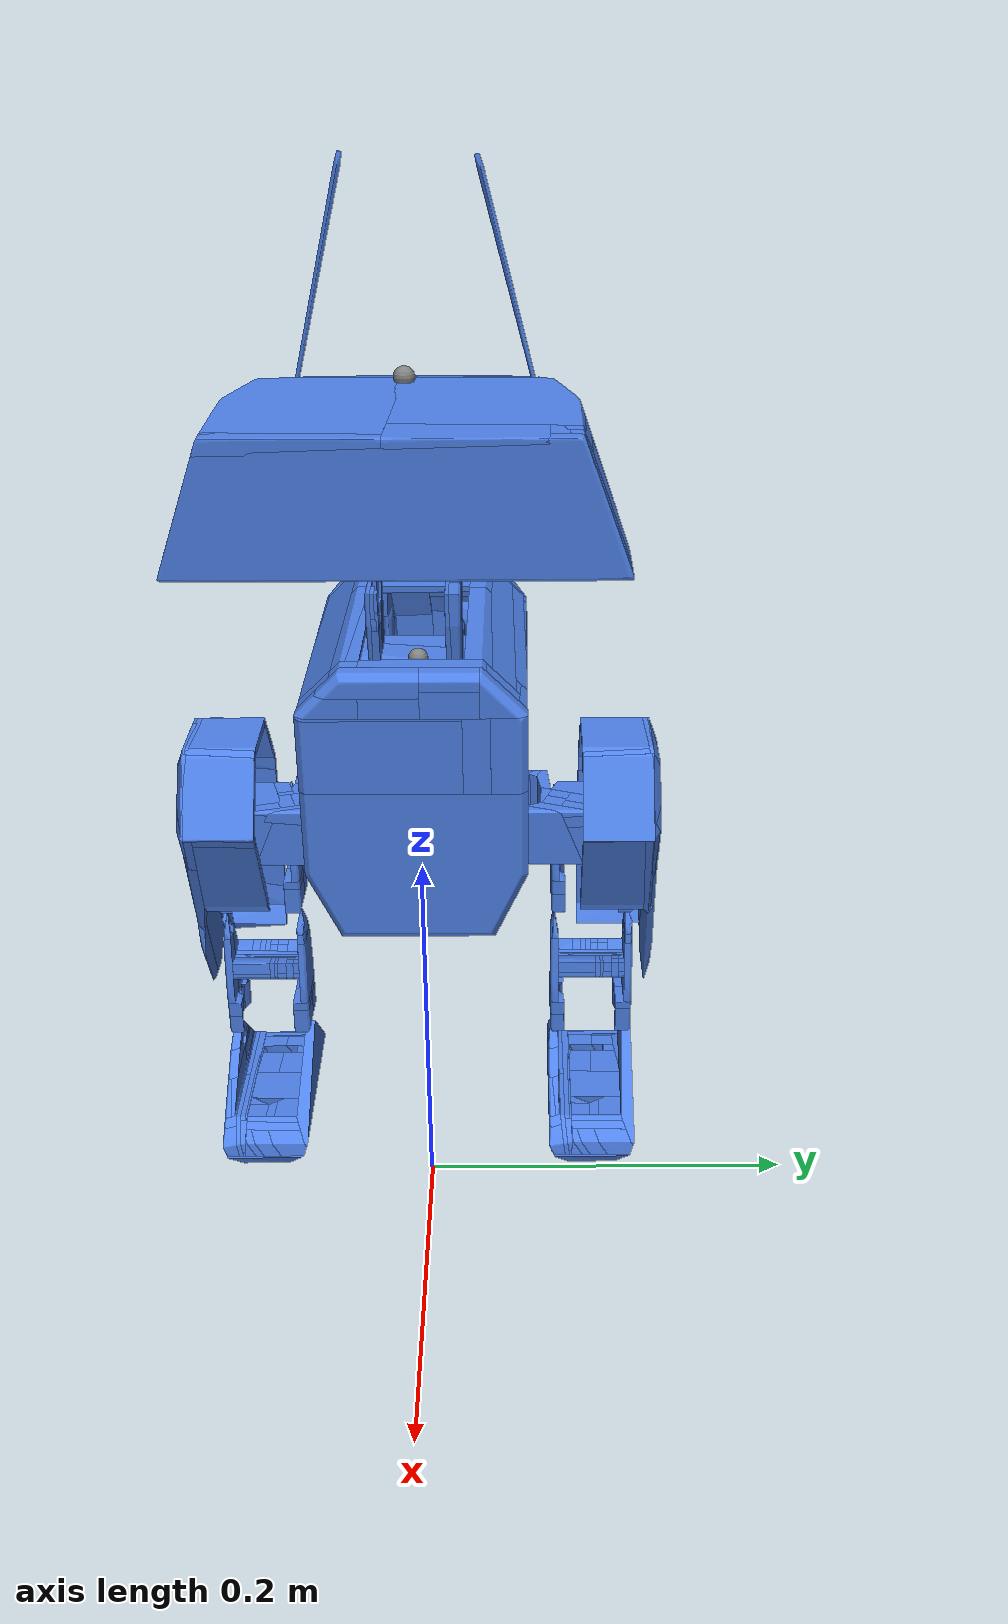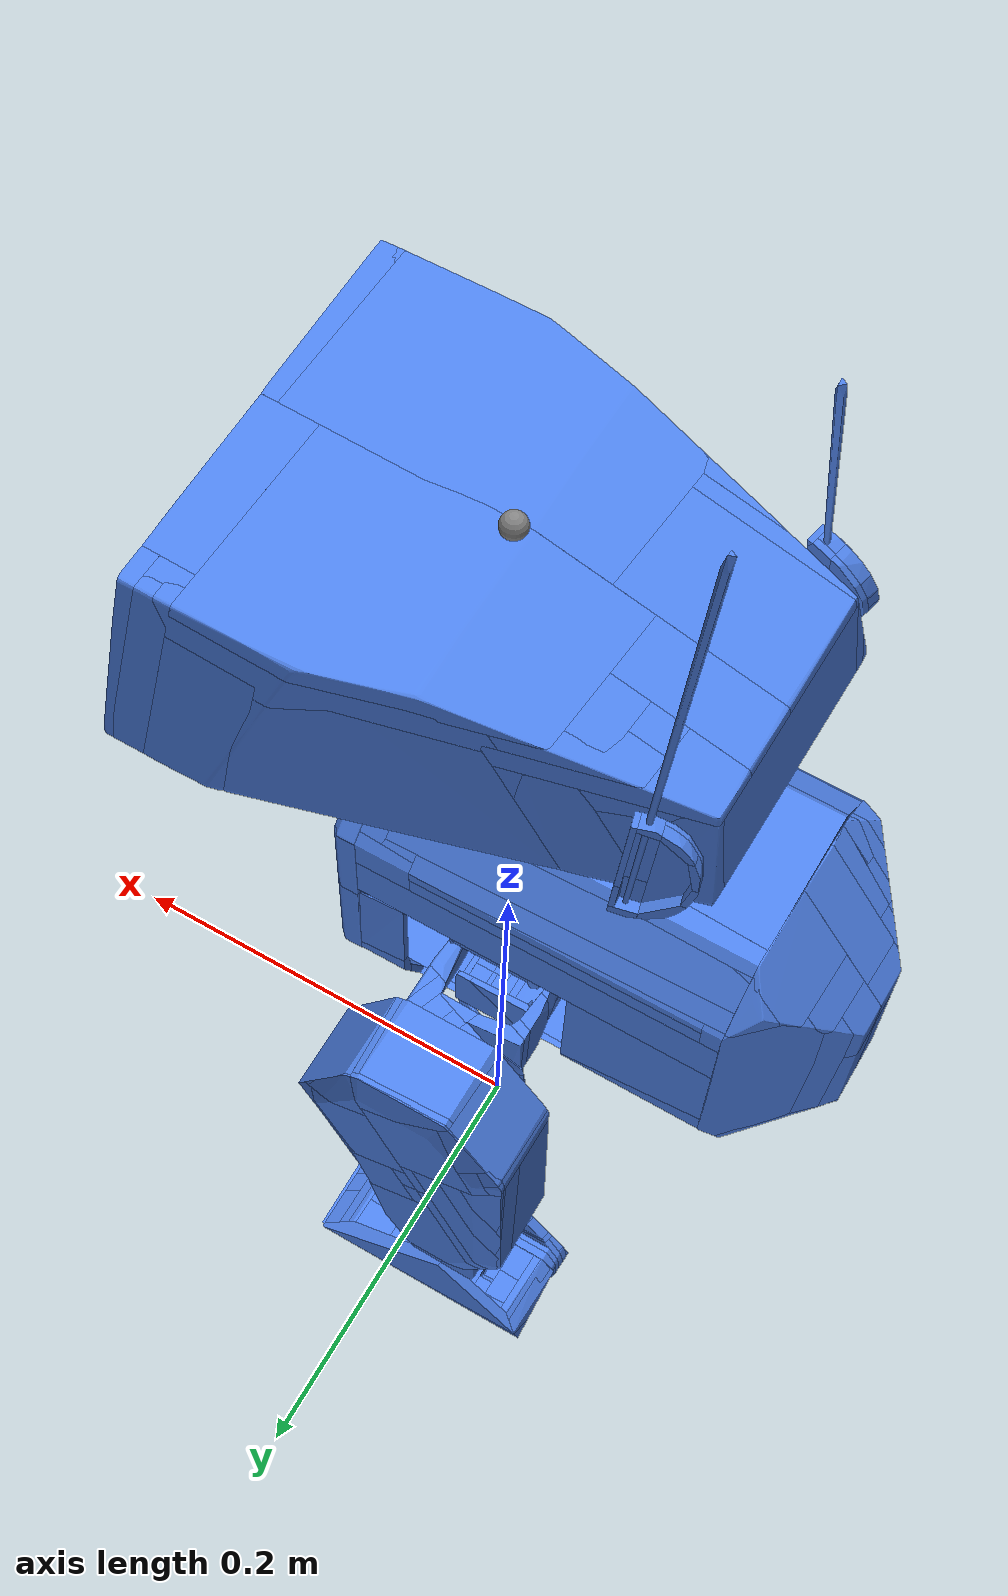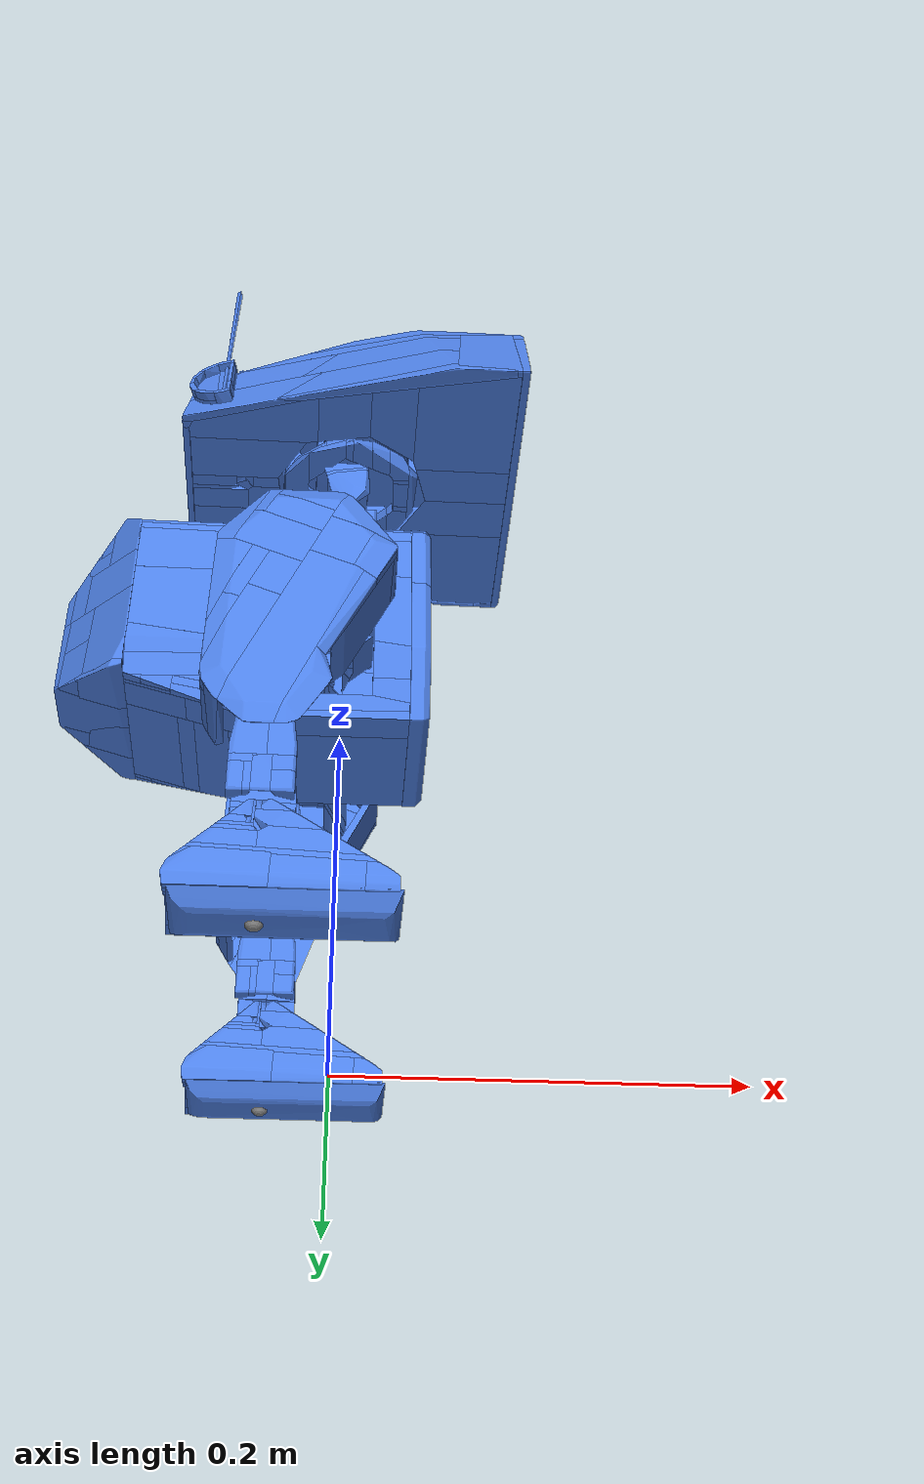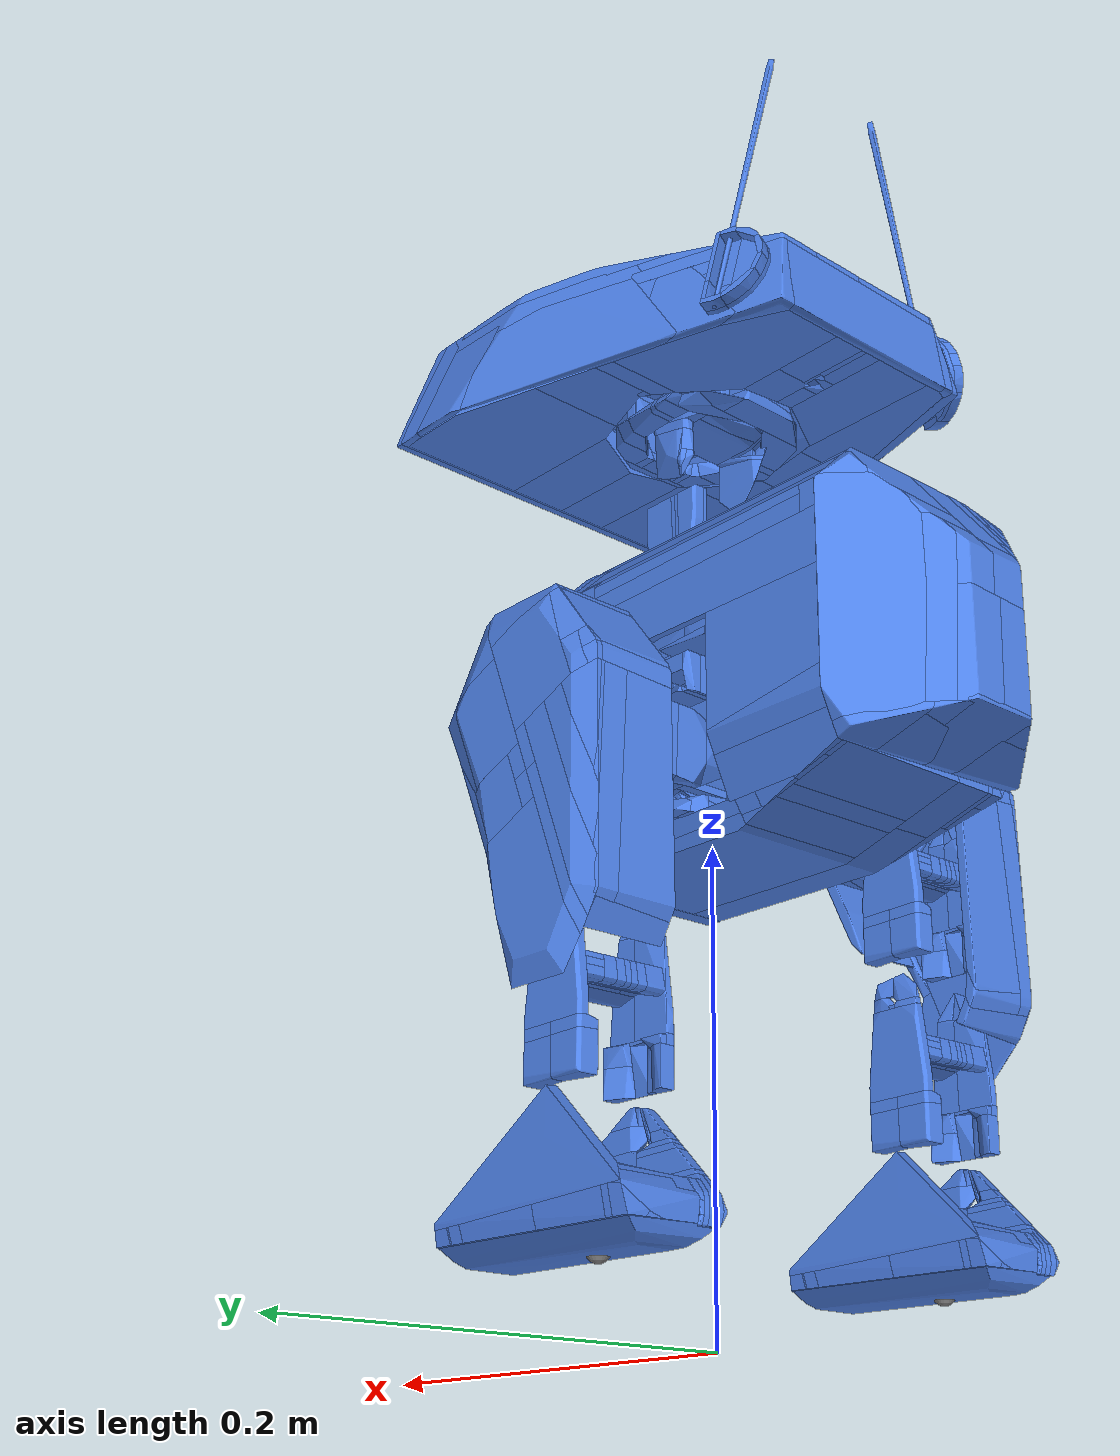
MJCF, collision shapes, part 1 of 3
<?xml version='1.0' encoding='utf-8'?>
<mujoco model="open_duck_mini_v2">
  <option iterations="1" ls_iterations="5">
    <flag eulerdamp="disable" />
  </option>
  <compiler angle="radian" meshdir="/data/shijinsheng/open_duck/projects/Open_Duck_Playground/playground/open_duck_mini_v2/xmls/assets" />
  <default>
    <default class="open_duck_mini_v2">
      <joint frictionloss="0.1" armature="0.005" />
      <position kp="50" dampratio="1" />
      <default class="visual">
        <geom type="mesh" contype="0" conaffinity="0" group="2" />
      </default>
      <default class="collision">
        <geom group="3" />
      </default>
    </default>
  </default>
  <sensor>
    <gyro site="imu" name="gyro" />
    <velocimeter site="imu" name="local_linvel" />
    <accelerometer site="imu" name="accelerometer" />
    <framezaxis objtype="site" objname="imu" name="upvector" />
    <framexaxis objtype="site" objname="imu" name="forwardvector" />
    <framelinvel objtype="site" objname="imu" name="global_linvel" />
    <frameangvel objtype="site" objname="imu" name="global_angvel" />
    <framepos objtype="site" objname="imu" name="position" />
    <framequat objtype="site" objname="imu" name="orientation" />
    <framelinvel objtype="site" objname="right_foot" name="right_foot_global_linvel" />
    <framelinvel objtype="site" objname="left_foot" name="left_foot_global_linvel" />
    <framexaxis objtype="site" objname="left_foot" name="left_foot_upvector" />
    <framexaxis objtype="site" objname="right_foot" name="right_foot_upvector" />
    <framepos objtype="site" objname="left_foot" name="left_foot_pos" />
    <framepos objtype="site" objname="right_foot" name="right_foot_pos" />
  </sensor>
  <default>
    <default class="sts3215">
      <geom contype="0" conaffinity="0" />
      <joint damping="0.56" frictionloss="0.068" armature="0.027" />
      <position kp="13.37" kv="0.0" forcerange="-3.23 3.23" />
    </default>
    <default class="backlash">
      <joint damping="0.01" frictionloss="0" armature="0.01" limited="true" range="-0.008726646259971648 0.008726646259971648" />
    </default>
  </default>
  <worldbody>
    <body name="base" pos="0 0 0.22">
      <freejoint name="floating_base" />
      <site name="imu" pos="-0.08 -0.0 0.05" />
      <body name="trunk_assembly" pos="0 0 0.0" quat="1 0 0 0" childclass="open_duck_mini_v2">
        <inertial pos="-0.0483259 -9.97823e-05 0.0384971" mass="0.698526" fullinertia="0.00167701 0.00344479 0.00292635 -1.31662e-05 -3.24953e-05 -2.15581e-06" />
        <geom type="mesh" class="visual" pos="-0.019 0 0.0648909" quat="1 0 0 0" mesh="body_front" material="body_front_material" contype="0" conaffinity="0" />
        <geom type="mesh" class="visual" pos="-0.019 3.46945e-18 0.0648909" quat="1 0 0 0" mesh="body_back" material="body_back_material" contype="0" conaffinity="0" />
        <geom type="mesh" class="visual" pos="-0.019 -3.46945e-18 0.0648909" quat="1 0 0 0" mesh="body_middle_bottom" material="body_middle_bottom_material" contype="0" conaffinity="0" />
        <geom type="mesh" class="visual" pos="-0.019 0 0.0648909" quat="1 0 0 0" mesh="body_middle_top" material="body_middle_top_material" contype="0" conaffinity="0" />
        <geom type="mesh" class="visual" pos="-0.019 9.1073e-18 0.0648909" quat="1 -0 -0 5.42101e-20" mesh="trunk_bottom" material="trunk_bottom_material" contype="0" conaffinity="0" />
        <geom type="mesh" class="visual" pos="-0.019 -2.42428e-16 0.0648909" quat="1 -4.82108e-17 -5.5355e-15 2.77556e-17" mesh="trunk_top" material="trunk_top_material" contype="0" conaffinity="0" />
        <site group="0" name="trunk" pos="-0.024 -2.41127e-16 0.0881909" quat="1 -2.77556e-17 -0 -0" />
        <body name="hip_roll_assembly" pos="-0.019 0.035 0.0459409" quat="1 -1.17663e-16 -1.09357e-14 2.77556e-17">
          <joint name="left_hip_yaw" type="hinge" range="-0.5235987755982979 0.5235987755982997" class="sts3215" />
          <inertial pos="0.000795081 -5.46541e-06 -0.03306" mass="0.06648" fullinertia="2.44411e-05 2.81818e-05 1.42687e-05 2.35658e-09 -3.81059e-07 -7.50036e-09" />
          <geom type="mesh" class="visual" pos="-3.33067e-16 -0.035 0.01905" quat="1 -4.38499e-16 2.22045e-16 -3.34802e-16" mesh="roll_motor_bottom" material="roll_motor_bottom_material" contype="0" conaffinity="0" />
          <geom type="mesh" class="visual" pos="0 -0.035 0.01905" quat="1 -0 -1.80411e-16 -4.16334e-17" mesh="roll_motor_top" material="roll_motor_top_material" contype="0" conaffinity="0" />
          <body name="left_roll_to_pitch_assembly" pos="0.01905 4.61436e-15 -0.046015" quat="0.5 -0.5 -0.5 0.5">
            <joint name="left_hip_roll" type="hinge" range="-0.4363323129985815 0.43633231299858327" class="sts3215" />
            <inertial pos="0.0508042 -0.00041105 0.0204704" mass="0.07516" fullinertia="2.52335e-05 4.13855e-05 2.8127e-05 1.22133e-07 -5.90499e-07 -1.07544e-07" />
            <geom type="mesh" class="visual" pos="-0.035 -0.065 0.01905" quat="0.5 0.5 0.5 -0.5" mesh="left_roll_to_pitch" material="left_roll_to_pitch_material" contype="0" conaffinity="0" />
            <body name="knee_and_ankle_assembly" pos="0.07415 -3.25261e-17 0.03511" quat="8.49887e-24 -0.707107 -1.11022e-16 0.707107">
              <joint name="left_hip_pitch" type="hinge" range="-1.2217304763960306 0.5235987755982988" class="sts3215" />
              <inertial pos="0.00253369 -0.0390636 0.0102776" mass="0.12407" fullinertia="0.000211406 7.83759e-05 0.000225619 -2.68706e-05 3.81906e-06 2.08009e-05" />
              <geom type="mesh" class="visual" pos="0.01606 0.065 0.10915" quat="0.707107 -0.707107 3.33067e-16 5.76761e-16" mesh="left_cache" material="left_cache_material" contype="0" conaffinity="0" />
              <geom type="mesh" class="visual" pos="0.01606 0.14365 0.10925" quat="0.707107 -0.707107 3.33067e-16 5.94711e-16" mesh="leg_spacer" material="leg_spacer_material" contype="0" conaffinity="0" />
              <geom type="mesh" class="visual" pos="0.01606 0.14365 0.10915" quat="0.707107 -0.707107 0 -5.93802e-24" mesh="left_knee_to_ankle_right_sheet" material="left_knee_to_ankle_right_sheet_material" contype="0" conaffinity="0" />
              <geom type="mesh" class="visual" pos="0.01606 0.14365 0.10915" quat="0.707107 -0.707107 0 5.12923e-30" mesh="left_knee_to_ankle_left_sheet" material="left_knee_to_ankle_left_sheet_material" contype="0" conaffinity="0" />
              <body name="knee_and_ankle_assembly_2" pos="0 -0.07865 0.0001" quat="1 1.11022e-16 1.11022e-16 -2.64698e-23">
                <joint name="left_knee" type="hinge" range="-1.5707963267948966 1.5707963267948966" class="sts3215" />
                <inertial pos="5.01859e-06 -0.0577465 0.0181136" mass="0.07259" fullinertia="4.99575e-05 1.87273e-05 4.23932e-05 1.03817e-08 2.25175e-09 8.81049e-08" />
                <geom type="mesh" class="visual" pos="0.01606 0.14365 0.10925" quat="0.707107 -0.707107 3.33067e-16 5.72905e-16" mesh="leg_spacer" material="leg_spacer_material" contype="0" conaffinity="0" />
                <geom type="mesh" class="visual" pos="0.01606 0.14365 0.10915" quat="0.707107 -0.707107 0 1.33119e-24" mesh="left_knee_to_ankle_right_sheet" material="left_knee_to_ankle_right_sheet_material" contype="0" conaffinity="0" />
                <geom type="mesh" class="visual" pos="0.01606 0.14365 0.10915" quat="0.707107 -0.707107 0 -5.36743e-30" mesh="left_knee_to_ankle_left_sheet" material="left_knee_to_ankle_left_sheet_material" contype="0" conaffinity="0" />
                <body name="foot_assembly" pos="1.8735e-16 -0.07865 0.0001" quat="1 2.77556e-16 5.55112e-16 1.52656e-16">
                  <joint name="left_ankle" type="hinge" range="-1.5707963267948957 1.5707963267948974" class="sts3215" />
                  <inertial pos="0.0110718 -0.0246608 0.0190626" mass="0.07524" fullinertia="1.87482e-05 6.74427e-05 6.061e-05 1.58839e-06 -6.52354e-09 5.67391e-08" />
                  <geom type="mesh" class="visual" pos="0.01606 0.2223 0.10905" quat="0.707107 -0.707107 -0 -4.61924e-30" mesh="foot_side" material="foot_side_material" contype="0" conaffinity="0" />
                  <geom type="mesh" class="visual" pos="0.01656 0.2228 0.10955" quat="0.707107 -0.707107 -0 1.72496e-18" mesh="foot_bottom_tpu" material="foot_bottom_tpu_material" contype="0" conaffinity="0" />
                  <geom type="mesh" class="collision" pos="0.01656 0.2228 0.10955" quat="0.707107 -0.707107 -0 1.72496e-18" mesh="foot_bottom_tpu" material="foot_bottom_tpu_material" name="left_foot_bottom_tpu" contype="0" conaffinity="0" />
                  <geom type="mesh" class="visual" pos="0.01656 0.2228 0.10955" quat="0.707107 -0.707107 -0 1.72496e-18" mesh="foot_bottom_pla" material="foot_bottom_pla_material" contype="0" conaffinity="0" />
                  <geom type="mesh" class="visual" pos="0.01606 0.2223 0.10905" quat="0.707107 -0.707107 -0 -4.61924e-30" mesh="foot_top" material="foot_top_material" contype="0" conaffinity="0" />
                  <site group="0" name="left_foot" pos="0.0005 -0.036225 0.01955" quat="0.707107 -0.707107 -0 1.72494e-18" />
                  <geom name="getup_collision_16_0" type="mesh" mesh="recovery_foot_side_0" pos="0.009563598245 -0.01816369468 0.03654182896" quat="0.703568172 0.07276358261 0.7058773015 0.03787510431" contype="2" conaffinity="3" group="3" rgba=".3 .5 .9 .25" />
                  <geom name="getup_collision_16_1" type="mesh" mesh="recovery_foot_side_1" pos="0.009563598245 -0.01816369468 0.03654182896" quat="0.703568172 0.07276358261 0.7058773015 0.03787510431" contype="2" conaffinity="3" group="3" rgba=".3 .5 .9 .25" />
                  <geom name="getup_collision_16_2" type="mesh" mesh="recovery_foot_side_2" pos="0.009563598245 -0.01816369468 0.03654182896" quat="0.703568172 0.07276358261 0.7058773015 0.03787510431" contype="2" conaffinity="3" group="3" rgba=".3 .5 .9 .25" />
                  <geom name="getup_collision_16_3" type="mesh" mesh="recovery_foot_side_3" pos="0.009563598245 -0.01816369468 0.03654182896" quat="0.703568172 0.07276358261 0.7058773015 0.03787510431" contype="2" conaffinity="3" group="3" rgba=".3 .5 .9 .25" />
                  <geom name="getup_collision_16_4" type="mesh" mesh="recovery_foot_side_4" pos="0.009563598245 -0.01816369468 0.03654182896" quat="0.703568172 0.07276358261 0.7058773015 0.03787510431" contype="2" conaffinity="3" group="3" rgba=".3 .5 .9 .25" />
                  <geom name="getup_collision_16_5" type="mesh" mesh="recovery_foot_side_5" pos="0.009563598245 -0.01816369468 0.03654182896" quat="0.703568172 0.07276358261 0.7058773015 0.03787510431" contype="2" conaffinity="3" group="3" rgba=".3 .5 .9 .25" />
                  <geom name="getup_collision_16_6" type="mesh" mesh="recovery_foot_side_6" pos="0.009563598245 -0.01816369468 0.03654182896" quat="0.703568172 0.07276358261 0.7058773015 0.03787510431" contype="2" conaffinity="3" group="3" rgba=".3 .5 .9 .25" />
                  <geom name="getup_collision_16_7" type="mesh" mesh="recovery_foot_side_7" pos="0.009563598245 -0.01816369468 0.03654182896" quat="0.703568172 0.07276358261 0.7058773015 0.03787510431" contype="2" conaffinity="3" group="3" rgba=".3 .5 .9 .25" />
                  <geom name="getup_collision_16_8" type="mesh" mesh="recovery_foot_side_8" pos="0.009563598245 -0.01816369468 0.03654182896" quat="0.703568172 0.07276358261 0.7058773015 0.03787510431" contype="2" conaffinity="3" group="3" rgba=".3 .5 .9 .25" />
                  <geom name="getup_collision_16_9" type="mesh" mesh="recovery_foot_side_9" pos="0.009563598245 -0.01816369468 0.03654182896" quat="0.703568172 0.07276358261 0.7058773015 0.03787510431" contype="2" conaffinity="3" group="3" rgba=".3 .5 .9 .25" />
                  <geom name="getup_collision_16_10" type="mesh" mesh="recovery_foot_side_10" pos="0.009563598245 -0.01816369468 0.03654182896" quat="0.703568172 0.07276358261 0.7058773015 0.03787510431" contype="2" conaffinity="3" group="3" rgba=".3 .5 .9 .25" />
                  <geom name="getup_collision_16_11" type="mesh" mesh="recovery_foot_side_11" pos="0.009563598245 -0.01816369468 0.03654182896" quat="0.703568172 0.07276358261 0.7058773015 0.03787510431" contype="2" conaffinity="3" group="3" rgba=".3 .5 .9 .25" />
                  <geom name="getup_collision_16_12" type="mesh" mesh="recovery_foot_side_12" pos="0.009563598245 -0.01816369468 0.03654182896" quat="0.703568172 0.07276358261 0.7058773015 0.03787510431" contype="2" conaffinity="3" group="3" rgba=".3 .5 .9 .25" />
                  <geom name="getup_collision_16_13" type="mesh" mesh="recovery_foot_side_13" pos="0.009563598245 -0.01816369468 0.03654182896" quat="0.703568172 0.07276358261 0.7058773015 0.03787510431" contype="2" conaffinity="3" group="3" rgba=".3 .5 .9 .25" />
                  <geom name="getup_collision_16_14" type="mesh" mesh="recovery_foot_side_14" pos="0.009563598245 -0.01816369468 0.03654182896" quat="0.703568172 0.07276358261 0.7058773015 0.03787510431" contype="2" conaffinity="3" group="3" rgba=".3 .5 .9 .25" />
                  <geom name="getup_collision_16_15" type="mesh" mesh="recovery_foot_side_15" pos="0.009563598245 -0.01816369468 0.03654182896" quat="0.703568172 0.07276358261 0.7058773015 0.03787510431" contype="2" conaffinity="3" group="3" rgba=".3 .5 .9 .25" />
                  <geom name="getup_collision_16_16" type="mesh" mesh="recovery_foot_side_16" pos="0.009563598245 -0.01816369468 0.03654182896" quat="0.703568172 0.07276358261 0.7058773015 0.03787510431" contype="2" conaffinity="3" group="3" rgba=".3 .5 .9 .25" />
                  <geom name="getup_collision_16_17" type="mesh" mesh="recovery_foot_side_17" pos="0.009563598245 -0.01816369468 0.03654182896" quat="0.703568172 0.07276358261 0.7058773015 0.03787510431" contype="2" conaffinity="3" group="3" rgba=".3 .5 .9 .25" />
                  <geom name="getup_collision_16_18" type="mesh" mesh="recovery_foot_side_18" pos="0.009563598245 -0.01816369468 0.03654182896" quat="0.703568172 0.07276358261 0.7058773015 0.03787510431" contype="2" conaffinity="3" group="3" rgba=".3 .5 .9 .25" />
                  <geom name="getup_collision_16_19" type="mesh" mesh="recovery_foot_side_19" pos="0.009563598245 -0.01816369468 0.03654182896" quat="0.703568172 0.07276358261 0.7058773015 0.03787510431" contype="2" conaffinity="3" group="3" rgba=".3 .5 .9 .25" />
                  <geom name="getup_collision_16_20" type="mesh" mesh="recovery_foot_side_20" pos="0.009563598245 -0.01816369468 0.03654182896" quat="0.703568172 0.07276358261 0.7058773015 0.03787510431" contype="2" conaffinity="3" group="3" rgba=".3 .5 .9 .25" />
                  <geom name="getup_collision_16_21" type="mesh" mesh="recovery_foot_side_21" pos="0.009563598245 -0.01816369468 0.03654182896" quat="0.703568172 0.07276358261 0.7058773015 0.03787510431" contype="2" conaffinity="3" group="3" rgba=".3 .5 .9 .25" />
                  <geom name="getup_collision_16_22" type="mesh" mesh="recovery_foot_side_22" pos="0.009563598245 -0.01816369468 0.03654182896" quat="0.703568172 0.07276358261 0.7058773015 0.03787510431" contype="2" conaffinity="3" group="3" rgba=".3 .5 .9 .25" />
                  <geom name="getup_collision_16_23" type="mesh" mesh="recovery_foot_side_23" pos="0.009563598245 -0.01816369468 0.03654182896" quat="0.703568172 0.07276358261 0.7058773015 0.03787510431" contype="2" conaffinity="3" group="3" rgba=".3 .5 .9 .25" />
                  <geom name="getup_collision_16_24" type="mesh" mesh="recovery_foot_side_24" pos="0.009563598245 -0.01816369468 0.03654182896" quat="0.703568172 0.07276358261 0.7058773015 0.03787510431" contype="2" conaffinity="3" group="3" rgba=".3 .5 .9 .25" />
                  <geom name="getup_collision_16_25" type="mesh" mesh="recovery_foot_side_25" pos="0.009563598245 -0.01816369468 0.03654182896" quat="0.703568172 0.07276358261 0.7058773015 0.03787510431" contype="2" conaffinity="3" group="3" rgba=".3 .5 .9 .25" />
                  <geom name="getup_collision_16_26" type="mesh" mesh="recovery_foot_side_26" pos="0.009563598245 -0.01816369468 0.03654182896" quat="0.703568172 0.07276358261 0.7058773015 0.03787510431" contype="2" conaffinity="3" group="3" rgba=".3 .5 .9 .25" />
                  <geom name="getup_collision_16_27" type="mesh" mesh="recovery_foot_side_27" pos="0.009563598245 -0.01816369468 0.03654182896" quat="0.703568172 0.07276358261 0.7058773015 0.03787510431" contype="2" conaffinity="3" group="3" rgba=".3 .5 .9 .25" />
                  <geom name="getup_collision_17_0" type="mesh" mesh="recovery_foot_bottom_tpu_0" pos="0.0137347306 -0.03422005402 0.01927184334" quat="0.4991434138 0.5010546831 0.4986917908 0.501105333" contype="2" conaffinity="3" group="3" rgba=".3 .5 .9 .25" />
                  <geom name="getup_collision_19_0" type="mesh" mesh="recovery_foot_bottom_pla_0" pos="0.009804418966 -0.02644922081 0.01955018907" quat="0.5 0.5 0.5 0.5" contype="2" conaffinity="3" group="3" rgba=".3 .5 .9 .25" />
                  <geom name="getup_collision_19_1" type="mesh" mesh="recovery_foot_bottom_pla_1" pos="0.009804418966 -0.02644922081 0.01955018907" quat="0.5 0.5 0.5 0.5" contype="2" conaffinity="3" group="3" rgba=".3 .5 .9 .25" />
                  <geom name="getup_collision_19_2" type="mesh" mesh="recovery_foot_bottom_pla_2" pos="0.009804418966 -0.02644922081 0.01955018907" quat="0.5 0.5 0.5 0.5" contype="2" conaffinity="3" group="3" rgba=".3 .5 .9 .25" />
                  <geom name="getup_collision_19_3" type="mesh" mesh="recovery_foot_bottom_pla_3" pos="0.009804418966 -0.02644922081 0.01955018907" quat="0.5 0.5 0.5 0.5" contype="2" conaffinity="3" group="3" rgba=".3 .5 .9 .25" />
                  <geom name="getup_collision_19_4" type="mesh" mesh="recovery_foot_bottom_pla_4" pos="0.009804418966 -0.02644922081 0.01955018907" quat="0.5 0.5 0.5 0.5" contype="2" conaffinity="3" group="3" rgba=".3 .5 .9 .25" />
                  <geom name="getup_collision_19_5" type="mesh" mesh="recovery_foot_bottom_pla_5" pos="0.009804418966 -0.02644922081 0.01955018907" quat="0.5 0.5 0.5 0.5" contype="2" conaffinity="3" group="3" rgba=".3 .5 .9 .25" />
                  <geom name="getup_collision_19_6" type="mesh" mesh="recovery_foot_bottom_pla_6" pos="0.009804418966 -0.02644922081 0.01955018907" quat="0.5 0.5 0.5 0.5" contype="2" conaffinity="3" group="3" rgba=".3 .5 .9 .25" />
                  <geom name="getup_collision_19_7" type="mesh" mesh="recovery_foot_bottom_pla_7" pos="0.009804418966 -0.02644922081 0.01955018907" quat="0.5 0.5 0.5 0.5" contype="2" conaffinity="3" group="3" rgba=".3 .5 .9 .25" />
                  <geom name="getup_collision_19_8" type="mesh" mesh="recovery_foot_bottom_pla_8" pos="0.009804418966 -0.02644922081 0.01955018907" quat="0.5 0.5 0.5 0.5" contype="2" conaffinity="3" group="3" rgba=".3 .5 .9 .25" />
                  <geom name="getup_collision_19_9" type="mesh" mesh="recovery_foot_bottom_pla_9" pos="0.009804418966 -0.02644922081 0.01955018907" quat="0.5 0.5 0.5 0.5" contype="2" conaffinity="3" group="3" rgba=".3 .5 .9 .25" />
                  <geom name="getup_collision_19_10" type="mesh" mesh="recovery_foot_bottom_pla_10" pos="0.009804418966 -0.02644922081 0.01955018907" quat="0.5 0.5 0.5 0.5" contype="2" conaffinity="3" group="3" rgba=".3 .5 .9 .25" />
                  <geom name="getup_collision_19_11" type="mesh" mesh="recovery_foot_bottom_pla_11" pos="0.009804418966 -0.02644922081 0.01955018907" quat="0.5 0.5 0.5 0.5" contype="2" conaffinity="3" group="3" rgba=".3 .5 .9 .25" />
                  <geom name="getup_collision_19_12" type="mesh" mesh="recovery_foot_bottom_pla_12" pos="0.009804418966 -0.02644922081 0.01955018907" quat="0.5 0.5 0.5 0.5" contype="2" conaffinity="3" group="3" rgba=".3 .5 .9 .25" />
                  <geom name="getup_collision_19_13" type="mesh" mesh="recovery_foot_bottom_pla_13" pos="0.009804418966 -0.02644922081 0.01955018907" quat="0.5 0.5 0.5 0.5" contype="2" conaffinity="3" group="3" rgba=".3 .5 .9 .25" />
                  <geom name="getup_collision_19_14" type="mesh" mesh="recovery_foot_bottom_pla_14" pos="0.009804418966 -0.02644922081 0.01955018907" quat="0.5 0.5 0.5 0.5" contype="2" conaffinity="3" group="3" rgba=".3 .5 .9 .25" />
                  <geom name="getup_collision_19_15" type="mesh" mesh="recovery_foot_bottom_pla_15" pos="0.009804418966 -0.02644922081 0.01955018907" quat="0.5 0.5 0.5 0.5" contype="2" conaffinity="3" group="3" rgba=".3 .5 .9 .25" />
                  <geom name="getup_collision_20_0" type="mesh" mesh="recovery_foot_top_0" pos="0.009885476202 -0.01923410668 0.009511842177" quat="0.3485550815 0.6221232404 0.3225024853 0.6224662046" contype="2" conaffinity="3" group="3" rgba=".3 .5 .9 .25" />
                  <geom name="getup_collision_20_1" type="mesh" mesh="recovery_foot_top_1" pos="0.009885476202 -0.01923410668 0.009511842177" quat="0.3485550815 0.6221232404 0.3225024853 0.6224662046" contype="2" conaffinity="3" group="3" rgba=".3 .5 .9 .25" />
                  <geom name="getup_collision_20_2" type="mesh" mesh="recovery_foot_top_2" pos="0.009885476202 -0.01923410668 0.009511842177" quat="0.3485550815 0.6221232404 0.3225024853 0.6224662046" contype="2" conaffinity="3" group="3" rgba=".3 .5 .9 .25" />
                  <geom name="getup_collision_20_3" type="mesh" mesh="recovery_foot_top_3" pos="0.009885476202 -0.01923410668 0.009511842177" quat="0.3485550815 0.6221232404 0.3225024853 0.6224662046" contype="2" conaffinity="3" group="3" rgba=".3 .5 .9 .25" />
                  <geom name="getup_collision_20_4" type="mesh" mesh="recovery_foot_top_4" pos="0.009885476202 -0.01923410668 0.009511842177" quat="0.3485550815 0.6221232404 0.3225024853 0.6224662046" contype="2" conaffinity="3" group="3" rgba=".3 .5 .9 .25" />
                  <geom name="getup_collision_20_5" type="mesh" mesh="recovery_foot_top_5" pos="0.009885476202 -0.01923410668 0.009511842177" quat="0.3485550815 0.6221232404 0.3225024853 0.6224662046" contype="2" conaffinity="3" group="3" rgba=".3 .5 .9 .25" />
                  <geom name="getup_collision_20_6" type="mesh" mesh="recovery_foot_top_6" pos="0.009885476202 -0.01923410668 0.009511842177" quat="0.3485550815 0.6221232404 0.3225024853 0.6224662046" contype="2" conaffinity="3" group="3" rgba=".3 .5 .9 .25" />
                  <geom name="getup_collision_20_7" type="mesh" mesh="recovery_foot_top_7" pos="0.009885476202 -0.01923410668 0.009511842177" quat="0.3485550815 0.6221232404 0.3225024853 0.6224662046" contype="2" conaffinity="3" group="3" rgba=".3 .5 .9 .25" />
                  <geom name="getup_collision_20_8" type="mesh" mesh="recovery_foot_top_8" pos="0.009885476202 -0.01923410668 0.009511842177" quat="0.3485550815 0.6221232404 0.3225024853 0.6224662046" contype="2" conaffinity="3" group="3" rgba=".3 .5 .9 .25" />
                  <geom name="getup_collision_20_9" type="mesh" mesh="recovery_foot_top_9" pos="0.009885476202 -0.01923410668 0.009511842177" quat="0.3485550815 0.6221232404 0.3225024853 0.6224662046" contype="2" conaffinity="3" group="3" rgba=".3 .5 .9 .25" />
                  <geom name="getup_collision_20_10" type="mesh" mesh="recovery_foot_top_10" pos="0.009885476202 -0.01923410668 0.009511842177" quat="0.3485550815 0.6221232404 0.3225024853 0.6224662046" contype="2" conaffinity="3" group="3" rgba=".3 .5 .9 .25" />
                  <geom name="getup_collision_20_11" type="mesh" mesh="recovery_foot_top_11" pos="0.009885476202 -0.01923410668 0.009511842177" quat="0.3485550815 0.6221232404 0.3225024853 0.6224662046" contype="2" conaffinity="3" group="3" rgba=".3 .5 .9 .25" />
                  <geom name="getup_collision_20_12" type="mesh" mesh="recovery_foot_top_12" pos="0.009885476202 -0.01923410668 0.009511842177" quat="0.3485550815 0.6221232404 0.3225024853 0.6224662046" contype="2" conaffinity="3" group="3" rgba=".3 .5 .9 .25" />
                  <geom name="getup_collision_20_13" type="mesh" mesh="recovery_foot_top_13" pos="0.009885476202 -0.01923410668 0.009511842177" quat="0.3485550815 0.6221232404 0.3225024853 0.6224662046" contype="2" conaffinity="3" group="3" rgba=".3 .5 .9 .25" />
                  <geom name="getup_collision_20_14" type="mesh" mesh="recovery_foot_top_14" pos="0.009885476202 -0.01923410668 0.009511842177" quat="0.3485550815 0.6221232404 0.3225024853 0.6224662046" contype="2" conaffinity="3" group="3" rgba=".3 .5 .9 .25" />
                  <geom name="getup_collision_20_15" type="mesh" mesh="recovery_foot_top_15" pos="0.009885476202 -0.01923410668 0.009511842177" quat="0.3485550815 0.6221232404 0.3225024853 0.6224662046" contype="2" conaffinity="3" group="3" rgba=".3 .5 .9 .25" />
                  <geom name="getup_collision_20_16" type="mesh" mesh="recovery_foot_top_16" pos="0.009885476202 -0.01923410668 0.009511842177" quat="0.3485550815 0.6221232404 0.3225024853 0.6224662046" contype="2" conaffinity="3" group="3" rgba=".3 .5 .9 .25" />
                  <geom name="getup_collision_20_17" type="mesh" mesh="recovery_foot_top_17" pos="0.009885476202 -0.01923410668 0.009511842177" quat="0.3485550815 0.6221232404 0.3225024853 0.6224662046" contype="2" conaffinity="3" group="3" rgba=".3 .5 .9 .25" />
                  <geom name="getup_collision_20_18" type="mesh" mesh="recovery_foot_top_18" pos="0.009885476202 -0.01923410668 0.009511842177" quat="0.3485550815 0.6221232404 0.3225024853 0.6224662046" contype="2" conaffinity="3" group="3" rgba=".3 .5 .9 .25" />
                  <geom name="getup_collision_20_19" type="mesh" mesh="recovery_foot_top_19" pos="0.009885476202 -0.01923410668 0.009511842177" quat="0.3485550815 0.6221232404 0.3225024853 0.6224662046" contype="2" conaffinity="3" group="3" rgba=".3 .5 .9 .25" />
                  <geom name="getup_collision_20_20" type="mesh" mesh="recovery_foot_top_20" pos="0.009885476202 -0.01923410668 0.009511842177" quat="0.3485550815 0.6221232404 0.3225024853 0.6224662046" contype="2" conaffinity="3" group="3" rgba=".3 .5 .9 .25" />
                  <geom name="getup_collision_20_21" type="mesh" mesh="recovery_foot_top_21" pos="0.009885476202 -0.01923410668 0.009511842177" quat="0.3485550815 0.6221232404 0.3225024853 0.6224662046" contype="2" conaffinity="3" group="3" rgba=".3 .5 .9 .25" />
                  <geom name="getup_collision_20_22" type="mesh" mesh="recovery_foot_top_22" pos="0.009885476202 -0.01923410668 0.009511842177" quat="0.3485550815 0.6221232404 0.3225024853 0.6224662046" contype="2" conaffinity="3" group="3" rgba=".3 .5 .9 .25" />
                  <geom name="getup_collision_20_23" type="mesh" mesh="recovery_foot_top_23" pos="0.009885476202 -0.01923410668 0.009511842177" quat="0.3485550815 0.6221232404 0.3225024853 0.6224662046" contype="2" conaffinity="3" group="3" rgba=".3 .5 .9 .25" />
                  <geom name="getup_collision_20_24" type="mesh" mesh="recovery_foot_top_24" pos="0.009885476202 -0.01923410668 0.009511842177" quat="0.3485550815 0.6221232404 0.3225024853 0.6224662046" contype="2" conaffinity="3" group="3" rgba=".3 .5 .9 .25" />
                  <geom name="getup_collision_20_25" type="mesh" mesh="recovery_foot_top_25" pos="0.009885476202 -0.01923410668 0.009511842177" quat="0.3485550815 0.6221232404 0.3225024853 0.6224662046" contype="2" conaffinity="3" group="3" rgba=".3 .5 .9 .25" />
                  <geom name="getup_collision_20_26" type="mesh" mesh="recovery_foot_top_26" pos="0.009885476202 -0.01923410668 0.009511842177" quat="0.3485550815 0.6221232404 0.3225024853 0.6224662046" contype="2" conaffinity="3" group="3" rgba=".3 .5 .9 .25" />
                  <geom name="getup_collision_20_27" type="mesh" mesh="recovery_foot_top_27" pos="0.009885476202 -0.01923410668 0.009511842177" quat="0.3485550815 0.6221232404 0.3225024853 0.6224662046" contype="2" conaffinity="3" group="3" rgba=".3 .5 .9 .25" />
                  <geom name="getup_collision_20_28" type="mesh" mesh="recovery_foot_top_28" pos="0.009885476202 -0.01923410668 0.009511842177" quat="0.3485550815 0.6221232404 0.3225024853 0.6224662046" contype="2" conaffinity="3" group="3" rgba=".3 .5 .9 .25" />
                  <geom name="getup_collision_20_29" type="mesh" mesh="recovery_foot_top_29" pos="0.009885476202 -0.01923410668 0.009511842177" quat="0.3485550815 0.6221232404 0.3225024853 0.6224662046" contype="2" conaffinity="3" group="3" rgba=".3 .5 .9 .25" />
                  <geom name="getup_collision_20_30" type="mesh" mesh="recovery_foot_top_30" pos="0.009885476202 -0.01923410668 0.009511842177" quat="0.3485550815 0.6221232404 0.3225024853 0.6224662046" contype="2" conaffinity="3" group="3" rgba=".3 .5 .9 .25" />
                  <geom name="getup_collision_20_31" type="mesh" mesh="recovery_foot_top_31" pos="0.009885476202 -0.01923410668 0.009511842177" quat="0.3485550815 0.6221232404 0.3225024853 0.6224662046" contype="2" conaffinity="3" group="3" rgba=".3 .5 .9 .25" />
                </body>
                <geom name="getup_collision_13_0" type="mesh" mesh="recovery_leg_spacer_0" pos="7.76258695e-05 -0.02037177938 0.01876828844" quat="0.70566795 -0.003538044789 -0.00239847196 0.7085297975" contype="2" conaffinity="3" group="3" rgba=".3 .5 .9 .25" />
                <geom name="getup_collision_13_1" type="mesh" mesh="recovery_leg_spacer_1" pos="7.76258695e-05 -0.02037177938 0.01876828844" quat="0.70566795 -0.003538044789 -0.00239847196 0.7085297975" contype="2" conaffinity="3" group="3" rgba=".3 .5 .9 .25" />
                <geom name="getup_collision_13_2" type="mesh" mesh="recovery_leg_spacer_2" pos="7.76258695e-05 -0.02037177938 0.01876828844" quat="0.70566795 -0.003538044789 -0.00239847196 0.7085297975" contype="2" conaffinity="3" group="3" rgba=".3 .5 .9 .25" />
                <geom name="getup_collision_13_3" type="mesh" mesh="recovery_leg_spacer_3" pos="7.76258695e-05 -0.02037177938 0.01876828844" quat="0.70566795 -0.003538044789 -0.00239847196 0.7085297975" contype="2" conaffinity="3" group="3" rgba=".3 .5 .9 .25" />
                <geom name="getup_collision_13_4" type="mesh" mesh="recovery_leg_spacer_4" pos="7.76258695e-05 -0.02037177938 0.01876828844" quat="0.70566795 -0.003538044789 -0.00239847196 0.7085297975" contype="2" conaffinity="3" group="3" rgba=".3 .5 .9 .25" />
                <geom name="getup_collision_13_5" type="mesh" mesh="recovery_leg_spacer_5" pos="7.76258695e-05 -0.02037177938 0.01876828844" quat="0.70566795 -0.003538044789 -0.00239847196 0.7085297975" contype="2" conaffinity="3" group="3" rgba=".3 .5 .9 .25" />
                <geom name="getup_collision_13_6" type="mesh" mesh="recovery_leg_spacer_6" pos="7.76258695e-05 -0.02037177938 0.01876828844" quat="0.70566795 -0.003538044789 -0.00239847196 0.7085297975" contype="2" conaffinity="3" group="3" rgba=".3 .5 .9 .25" />
                <geom name="getup_collision_13_7" type="mesh" mesh="recovery_leg_spacer_7" pos="7.76258695e-05 -0.02037177938 0.01876828844" quat="0.70566795 -0.003538044789 -0.00239847196 0.7085297975" contype="2" conaffinity="3" group="3" rgba=".3 .5 .9 .25" />
                <geom name="getup_collision_13_8" type="mesh" mesh="recovery_leg_spacer_8" pos="7.76258695e-05 -0.02037177938 0.01876828844" quat="0.70566795 -0.003538044789 -0.00239847196 0.7085297975" contype="2" conaffinity="3" group="3" rgba=".3 .5 .9 .25" />
                <geom name="getup_collision_13_9" type="mesh" mesh="recovery_leg_spacer_9" pos="7.76258695e-05 -0.02037177938 0.01876828844" quat="0.70566795 -0.003538044789 -0.00239847196 0.7085297975" contype="2" conaffinity="3" group="3" rgba=".3 .5 .9 .25" />
                <geom name="getup_collision_13_10" type="mesh" mesh="recovery_leg_spacer_10" pos="7.76258695e-05 -0.02037177938 0.01876828844" quat="0.70566795 -0.003538044789 -0.00239847196 0.7085297975" contype="2" conaffinity="3" group="3" rgba=".3 .5 .9 .25" />
                <geom name="getup_collision_13_11" type="mesh" mesh="recovery_leg_spacer_11" pos="7.76258695e-05 -0.02037177938 0.01876828844" quat="0.70566795 -0.003538044789 -0.00239847196 0.7085297975" contype="2" conaffinity="3" group="3" rgba=".3 .5 .9 .25" />
                <geom name="getup_collision_13_12" type="mesh" mesh="recovery_leg_spacer_12" pos="7.76258695e-05 -0.02037177938 0.01876828844" quat="0.70566795 -0.003538044789 -0.00239847196 0.7085297975" contype="2" conaffinity="3" group="3" rgba=".3 .5 .9 .25" />
                <geom name="getup_collision_13_13" type="mesh" mesh="recovery_leg_spacer_13" pos="7.76258695e-05 -0.02037177938 0.01876828844" quat="0.70566795 -0.003538044789 -0.00239847196 0.7085297975" contype="2" conaffinity="3" group="3" rgba=".3 .5 .9 .25" />
                <geom name="getup_collision_13_14" type="mesh" mesh="recovery_leg_spacer_14" pos="7.76258695e-05 -0.02037177938 0.01876828844" quat="0.70566795 -0.003538044789 -0.00239847196 0.7085297975" contype="2" conaffinity="3" group="3" rgba=".3 .5 .9 .25" />
                <geom name="getup_collision_13_15" type="mesh" mesh="recovery_leg_spacer_15" pos="7.76258695e-05 -0.02037177938 0.01876828844" quat="0.70566795 -0.003538044789 -0.00239847196 0.7085297975" contype="2" conaffinity="3" group="3" rgba=".3 .5 .9 .25" />
                <geom name="getup_collision_13_16" type="mesh" mesh="recovery_leg_spacer_16" pos="7.76258695e-05 -0.02037177938 0.01876828844" quat="0.70566795 -0.003538044789 -0.00239847196 0.7085297975" contype="2" conaffinity="3" group="3" rgba=".3 .5 .9 .25" />
                <geom name="getup_collision_13_17" type="mesh" mesh="recovery_leg_spacer_17" pos="7.76258695e-05 -0.02037177938 0.01876828844" quat="0.70566795 -0.003538044789 -0.00239847196 0.7085297975" contype="2" conaffinity="3" group="3" rgba=".3 .5 .9 .25" />
                <geom name="getup_collision_13_18" type="mesh" mesh="recovery_leg_spacer_18" pos="7.76258695e-05 -0.02037177938 0.01876828844" quat="0.70566795 -0.003538044789 -0.00239847196 0.7085297975" contype="2" conaffinity="3" group="3" rgba=".3 .5 .9 .25" />
                <geom name="getup_collision_13_19" type="mesh" mesh="recovery_leg_spacer_19" pos="7.76258695e-05 -0.02037177938 0.01876828844" quat="0.70566795 -0.003538044789 -0.00239847196 0.7085297975" contype="2" conaffinity="3" group="3" rgba=".3 .5 .9 .25" />
                <geom name="getup_collision_13_20" type="mesh" mesh="recovery_leg_spacer_20" pos="7.76258695e-05 -0.02037177938 0.01876828844" quat="0.70566795 -0.003538044789 -0.00239847196 0.7085297975" contype="2" conaffinity="3" group="3" rgba=".3 .5 .9 .25" />
                <geom name="getup_collision_13_21" type="mesh" mesh="recovery_leg_spacer_21" pos="7.76258695e-05 -0.02037177938 0.01876828844" quat="0.70566795 -0.003538044789 -0.00239847196 0.7085297975" contype="2" conaffinity="3" group="3" rgba=".3 .5 .9 .25" />
                <geom name="getup_collision_13_22" type="mesh" mesh="recovery_leg_spacer_22" pos="7.76258695e-05 -0.02037177938 0.01876828844" quat="0.70566795 -0.003538044789 -0.00239847196 0.7085297975" contype="2" conaffinity="3" group="3" rgba=".3 .5 .9 .25" />
                <geom name="getup_collision_13_23" type="mesh" mesh="recovery_leg_spacer_23" pos="7.76258695e-05 -0.02037177938 0.01876828844" quat="0.70566795 -0.003538044789 -0.00239847196 0.7085297975" contype="2" conaffinity="3" group="3" rgba=".3 .5 .9 .25" />
                <geom name="getup_collision_13_24" type="mesh" mesh="recovery_leg_spacer_24" pos="7.76258695e-05 -0.02037177938 0.01876828844" quat="0.70566795 -0.003538044789 -0.00239847196 0.7085297975" contype="2" conaffinity="3" group="3" rgba=".3 .5 .9 .25" />
                <geom name="getup_collision_13_25" type="mesh" mesh="recovery_leg_spacer_25" pos="7.76258695e-05 -0.02037177938 0.01876828844" quat="0.70566795 -0.003538044789 -0.00239847196 0.7085297975" contype="2" conaffinity="3" group="3" rgba=".3 .5 .9 .25" />
                <geom name="getup_collision_14_0" type="mesh" mesh="recovery_left_knee_to_ankle_right_sheet_0" pos="7.557399049e-06 -0.03137772182 0.03852283358" quat="0.5081847836 -0.4916789864 0.4967988555 0.5031807798" contype="2" conaffinity="3" group="3" rgba=".3 .5 .9 .25" />
                <geom name="getup_collision_14_1" type="mesh" mesh="recovery_left_knee_to_ankle_right_sheet_1" pos="7.557399049e-06 -0.03137772182 0.03852283358" quat="0.5081847836 -0.4916789864 0.4967988555 0.5031807798" contype="2" conaffinity="3" group="3" rgba=".3 .5 .9 .25" />
                <geom name="getup_collision_14_2" type="mesh" mesh="recovery_left_knee_to_ankle_right_sheet_2" pos="7.557399049e-06 -0.03137772182 0.03852283358" quat="0.5081847836 -0.4916789864 0.4967988555 0.5031807798" contype="2" conaffinity="3" group="3" rgba=".3 .5 .9 .25" />
                <geom name="getup_collision_14_3" type="mesh" mesh="recovery_left_knee_to_ankle_right_sheet_3" pos="7.557399049e-06 -0.03137772182 0.03852283358" quat="0.5081847836 -0.4916789864 0.4967988555 0.5031807798" contype="2" conaffinity="3" group="3" rgba=".3 .5 .9 .25" />
                <geom name="getup_collision_14_4" type="mesh" mesh="recovery_left_knee_to_ankle_right_sheet_4" pos="7.557399049e-06 -0.03137772182 0.03852283358" quat="0.5081847836 -0.4916789864 0.4967988555 0.5031807798" contype="2" conaffinity="3" group="3" rgba=".3 .5 .9 .25" />
                <geom name="getup_collision_14_5" type="mesh" mesh="recovery_left_knee_to_ankle_right_sheet_5" pos="7.557399049e-06 -0.03137772182 0.03852283358" quat="0.5081847836 -0.4916789864 0.4967988555 0.5031807798" contype="2" conaffinity="3" group="3" rgba=".3 .5 .9 .25" />
                <geom name="getup_collision_14_6" type="mesh" mesh="recovery_left_knee_to_ankle_right_sheet_6" pos="7.557399049e-06 -0.03137772182 0.03852283358" quat="0.5081847836 -0.4916789864 0.4967988555 0.5031807798" contype="2" conaffinity="3" group="3" rgba=".3 .5 .9 .25" />
                <geom name="getup_collision_14_7" type="mesh" mesh="recovery_left_knee_to_ankle_right_sheet_7" pos="7.557399049e-06 -0.03137772182 0.03852283358" quat="0.5081847836 -0.4916789864 0.4967988555 0.5031807798" contype="2" conaffinity="3" group="3" rgba=".3 .5 .9 .25" />
                <geom name="getup_collision_14_8" type="mesh" mesh="recovery_left_knee_to_ankle_right_sheet_8" pos="7.557399049e-06 -0.03137772182 0.03852283358" quat="0.5081847836 -0.4916789864 0.4967988555 0.5031807798" contype="2" conaffinity="3" group="3" rgba=".3 .5 .9 .25" />
                <geom name="getup_collision_14_9" type="mesh" mesh="recovery_left_knee_to_ankle_right_sheet_9" pos="7.557399049e-06 -0.03137772182 0.03852283358" quat="0.5081847836 -0.4916789864 0.4967988555 0.5031807798" contype="2" conaffinity="3" group="3" rgba=".3 .5 .9 .25" />
                <geom name="getup_collision_14_10" type="mesh" mesh="recovery_left_knee_to_ankle_right_sheet_10" pos="7.557399049e-06 -0.03137772182 0.03852283358" quat="0.5081847836 -0.4916789864 0.4967988555 0.5031807798" contype="2" conaffinity="3" group="3" rgba=".3 .5 .9 .25" />
                <geom name="getup_collision_14_11" type="mesh" mesh="recovery_left_knee_to_ankle_right_sheet_11" pos="7.557399049e-06 -0.03137772182 0.03852283358" quat="0.5081847836 -0.4916789864 0.4967988555 0.5031807798" contype="2" conaffinity="3" group="3" rgba=".3 .5 .9 .25" />
                <geom name="getup_collision_15_0" type="mesh" mesh="recovery_left_knee_to_ankle_left_sheet_0" pos="0.0001502227335 -0.0330995171 -0.0007629777059" quat="0.4948924636 -0.5058291862 0.5152900345 0.483419553" contype="2" conaffinity="3" group="3" rgba=".3 .5 .9 .25" />
                <geom name="getup_collision_15_1" type="mesh" mesh="recovery_left_knee_to_ankle_left_sheet_1" pos="0.0001502227335 -0.0330995171 -0.0007629777059" quat="0.4948924636 -0.5058291862 0.5152900345 0.483419553" contype="2" conaffinity="3" group="3" rgba=".3 .5 .9 .25" />
                <geom name="getup_collision_15_2" type="mesh" mesh="recovery_left_knee_to_ankle_left_sheet_2" pos="0.0001502227335 -0.0330995171 -0.0007629777059" quat="0.4948924636 -0.5058291862 0.5152900345 0.483419553" contype="2" conaffinity="3" group="3" rgba=".3 .5 .9 .25" />
                <geom name="getup_collision_15_3" type="mesh" mesh="recovery_left_knee_to_ankle_left_sheet_3" pos="0.0001502227335 -0.0330995171 -0.0007629777059" quat="0.4948924636 -0.5058291862 0.5152900345 0.483419553" contype="2" conaffinity="3" group="3" rgba=".3 .5 .9 .25" />
                <geom name="getup_collision_15_4" type="mesh" mesh="recovery_left_knee_to_ankle_left_sheet_4" pos="0.0001502227335 -0.0330995171 -0.0007629777059" quat="0.4948924636 -0.5058291862 0.5152900345 0.483419553" contype="2" conaffinity="3" group="3" rgba=".3 .5 .9 .25" />
                <geom name="getup_collision_15_5" type="mesh" mesh="recovery_left_knee_to_ankle_left_sheet_5" pos="0.0001502227335 -0.0330995171 -0.0007629777059" quat="0.4948924636 -0.5058291862 0.5152900345 0.483419553" contype="2" conaffinity="3" group="3" rgba=".3 .5 .9 .25" />
                <geom name="getup_collision_15_6" type="mesh" mesh="recovery_left_knee_to_ankle_left_sheet_6" pos="0.0001502227335 -0.0330995171 -0.0007629777059" quat="0.4948924636 -0.5058291862 0.5152900345 0.483419553" contype="2" conaffinity="3" group="3" rgba=".3 .5 .9 .25" />
                <geom name="getup_collision_15_7" type="mesh" mesh="recovery_left_knee_to_ankle_left_sheet_7" pos="0.0001502227335 -0.0330995171 -0.0007629777059" quat="0.4948924636 -0.5058291862 0.5152900345 0.483419553" contype="2" conaffinity="3" group="3" rgba=".3 .5 .9 .25" />
                <geom name="getup_collision_15_8" type="mesh" mesh="recovery_left_knee_to_ankle_left_sheet_8" pos="0.0001502227335 -0.0330995171 -0.0007629777059" quat="0.4948924636 -0.5058291862 0.5152900345 0.483419553" contype="2" conaffinity="3" group="3" rgba=".3 .5 .9 .25" />
                <geom name="getup_collision_15_9" type="mesh" mesh="recovery_left_knee_to_ankle_left_sheet_9" pos="0.0001502227335 -0.0330995171 -0.0007629777059" quat="0.4948924636 -0.5058291862 0.5152900345 0.483419553" contype="2" conaffinity="3" group="3" rgba=".3 .5 .9 .25" />
              </body>
              <geom name="getup_collision_9_0" type="mesh" mesh="recovery_left_cache_0" pos="0.007325027663 -0.007888200566 0.002837779554" quat="0.5888764204 -0.3675650772 0.5868014338 0.4168747447" contype="2" conaffinity="3" group="3" rgba=".3 .5 .9 .25" />
              <geom name="getup_collision_9_1" type="mesh" mesh="recovery_left_cache_1" pos="0.007325027663 -0.007888200566 0.002837779554" quat="0.5888764204 -0.3675650772 0.5868014338 0.4168747447" contype="2" conaffinity="3" group="3" rgba=".3 .5 .9 .25" />
              <geom name="getup_collision_9_2" type="mesh" mesh="recovery_left_cache_2" pos="0.007325027663 -0.007888200566 0.002837779554" quat="0.5888764204 -0.3675650772 0.5868014338 0.4168747447" contype="2" conaffinity="3" group="3" rgba=".3 .5 .9 .25" />
              <geom name="getup_collision_9_3" type="mesh" mesh="recovery_left_cache_3" pos="0.007325027663 -0.007888200566 0.002837779554" quat="0.5888764204 -0.3675650772 0.5868014338 0.4168747447" contype="2" conaffinity="3" group="3" rgba=".3 .5 .9 .25" />
              <geom name="getup_collision_9_4" type="mesh" mesh="recovery_left_cache_4" pos="0.007325027663 -0.007888200566 0.002837779554" quat="0.5888764204 -0.3675650772 0.5868014338 0.4168747447" contype="2" conaffinity="3" group="3" rgba=".3 .5 .9 .25" />
              <geom name="getup_collision_9_5" type="mesh" mesh="recovery_left_cache_5" pos="0.007325027663 -0.007888200566 0.002837779554" quat="0.5888764204 -0.3675650772 0.5868014338 0.4168747447" contype="2" conaffinity="3" group="3" rgba=".3 .5 .9 .25" />
              <geom name="getup_collision_9_6" type="mesh" mesh="recovery_left_cache_6" pos="0.007325027663 -0.007888200566 0.002837779554" quat="0.5888764204 -0.3675650772 0.5868014338 0.4168747447" contype="2" conaffinity="3" group="3" rgba=".3 .5 .9 .25" />
              <geom name="getup_collision_9_7" type="mesh" mesh="recovery_left_cache_7" pos="0.007325027663 -0.007888200566 0.002837779554" quat="0.5888764204 -0.3675650772 0.5868014338 0.4168747447" contype="2" conaffinity="3" group="3" rgba=".3 .5 .9 .25" />
              <geom name="getup_collision_9_8" type="mesh" mesh="recovery_left_cache_8" pos="0.007325027663 -0.007888200566 0.002837779554" quat="0.5888764204 -0.3675650772 0.5868014338 0.4168747447" contype="2" conaffinity="3" group="3" rgba=".3 .5 .9 .25" />
              <geom name="getup_collision_9_9" type="mesh" mesh="recovery_left_cache_9" pos="0.007325027663 -0.007888200566 0.002837779554" quat="0.5888764204 -0.3675650772 0.5868014338 0.4168747447" contype="2" conaffinity="3" group="3" rgba=".3 .5 .9 .25" />
              <geom name="getup_collision_9_10" type="mesh" mesh="recovery_left_cache_10" pos="0.007325027663 -0.007888200566 0.002837779554" quat="0.5888764204 -0.3675650772 0.5868014338 0.4168747447" contype="2" conaffinity="3" group="3" rgba=".3 .5 .9 .25" />
              <geom name="getup_collision_9_11" type="mesh" mesh="recovery_left_cache_11" pos="0.007325027663 -0.007888200566 0.002837779554" quat="0.5888764204 -0.3675650772 0.5868014338 0.4168747447" contype="2" conaffinity="3" group="3" rgba=".3 .5 .9 .25" />
              <geom name="getup_collision_9_12" type="mesh" mesh="recovery_left_cache_12" pos="0.007325027663 -0.007888200566 0.002837779554" quat="0.5888764204 -0.3675650772 0.5868014338 0.4168747447" contype="2" conaffinity="3" group="3" rgba=".3 .5 .9 .25" />
              <geom name="getup_collision_9_13" type="mesh" mesh="recovery_left_cache_13" pos="0.007325027663 -0.007888200566 0.002837779554" quat="0.5888764204 -0.3675650772 0.5868014338 0.4168747447" contype="2" conaffinity="3" group="3" rgba=".3 .5 .9 .25" />
              <geom name="getup_collision_9_14" type="mesh" mesh="recovery_left_cache_14" pos="0.007325027663 -0.007888200566 0.002837779554" quat="0.5888764204 -0.3675650772 0.5868014338 0.4168747447" contype="2" conaffinity="3" group="3" rgba=".3 .5 .9 .25" />
              <geom name="getup_collision_9_15" type="mesh" mesh="recovery_left_cache_15" pos="0.007325027663 -0.007888200566 0.002837779554" quat="0.5888764204 -0.3675650772 0.5868014338 0.4168747447" contype="2" conaffinity="3" group="3" rgba=".3 .5 .9 .25" />
              <geom name="getup_collision_9_16" type="mesh" mesh="recovery_left_cache_16" pos="0.007325027663 -0.007888200566 0.002837779554" quat="0.5888764204 -0.3675650772 0.5868014338 0.4168747447" contype="2" conaffinity="3" group="3" rgba=".3 .5 .9 .25" />
              <geom name="getup_collision_9_17" type="mesh" mesh="recovery_left_cache_17" pos="0.007325027663 -0.007888200566 0.002837779554" quat="0.5888764204 -0.3675650772 0.5868014338 0.4168747447" contype="2" conaffinity="3" group="3" rgba=".3 .5 .9 .25" />
              <geom name="getup_collision_9_18" type="mesh" mesh="recovery_left_cache_18" pos="0.007325027663 -0.007888200566 0.002837779554" quat="0.5888764204 -0.3675650772 0.5868014338 0.4168747447" contype="2" conaffinity="3" group="3" rgba=".3 .5 .9 .25" />
              <geom name="getup_collision_9_19" type="mesh" mesh="recovery_left_cache_19" pos="0.007325027663 -0.007888200566 0.002837779554" quat="0.5888764204 -0.3675650772 0.5868014338 0.4168747447" contype="2" conaffinity="3" group="3" rgba=".3 .5 .9 .25" />
              <geom name="getup_collision_9_20" type="mesh" mesh="recovery_left_cache_20" pos="0.007325027663 -0.007888200566 0.002837779554" quat="0.5888764204 -0.3675650772 0.5868014338 0.4168747447" contype="2" conaffinity="3" group="3" rgba=".3 .5 .9 .25" />
              <geom name="getup_collision_9_21" type="mesh" mesh="recovery_left_cache_21" pos="0.007325027663 -0.007888200566 0.002837779554" quat="0.5888764204 -0.3675650772 0.5868014338 0.4168747447" contype="2" conaffinity="3" group="3" rgba=".3 .5 .9 .25" />
              <geom name="getup_collision_9_22" type="mesh" mesh="recovery_left_cache_22" pos="0.007325027663 -0.007888200566 0.002837779554" quat="0.5888764204 -0.3675650772 0.5868014338 0.4168747447" contype="2" conaffinity="3" group="3" rgba=".3 .5 .9 .25" />
              <geom name="getup_collision_9_23" type="mesh" mesh="recovery_left_cache_23" pos="0.007325027663 -0.007888200566 0.002837779554" quat="0.5888764204 -0.3675650772 0.5868014338 0.4168747447" contype="2" conaffinity="3" group="3" rgba=".3 .5 .9 .25" />
              <geom name="getup_collision_9_24" type="mesh" mesh="recovery_left_cache_24" pos="0.007325027663 -0.007888200566 0.002837779554" quat="0.5888764204 -0.3675650772 0.5868014338 0.4168747447" contype="2" conaffinity="3" group="3" rgba=".3 .5 .9 .25" />
              <geom name="getup_collision_9_25" type="mesh" mesh="recovery_left_cache_25" pos="0.007325027663 -0.007888200566 0.002837779554" quat="0.5888764204 -0.3675650772 0.5868014338 0.4168747447" contype="2" conaffinity="3" group="3" rgba=".3 .5 .9 .25" />
              <geom name="getup_collision_9_26" type="mesh" mesh="recovery_left_cache_26" pos="0.007325027663 -0.007888200566 0.002837779554" quat="0.5888764204 -0.3675650772 0.5868014338 0.4168747447" contype="2" conaffinity="3" group="3" rgba=".3 .5 .9 .25" />
              <geom name="getup_collision_9_27" type="mesh" mesh="recovery_left_cache_27" pos="0.007325027663 -0.007888200566 0.002837779554" quat="0.5888764204 -0.3675650772 0.5868014338 0.4168747447" contype="2" conaffinity="3" group="3" rgba=".3 .5 .9 .25" />
              <geom name="getup_collision_9_28" type="mesh" mesh="recovery_left_cache_28" pos="0.007325027663 -0.007888200566 0.002837779554" quat="0.5888764204 -0.3675650772 0.5868014338 0.4168747447" contype="2" conaffinity="3" group="3" rgba=".3 .5 .9 .25" />
              <geom name="getup_collision_9_29" type="mesh" mesh="recovery_left_cache_29" pos="0.007325027663 -0.007888200566 0.002837779554" quat="0.5888764204 -0.3675650772 0.5868014338 0.4168747447" contype="2" conaffinity="3" group="3" rgba=".3 .5 .9 .25" />
              <geom name="getup_collision_9_30" type="mesh" mesh="recovery_left_cache_30" pos="0.007325027663 -0.007888200566 0.002837779554" quat="0.5888764204 -0.3675650772 0.5868014338 0.4168747447" contype="2" conaffinity="3" group="3" rgba=".3 .5 .9 .25" />
              <geom name="getup_collision_9_31" type="mesh" mesh="recovery_left_cache_31" pos="0.007325027663 -0.007888200566 0.002837779554" quat="0.5888764204 -0.3675650772 0.5868014338 0.4168747447" contype="2" conaffinity="3" group="3" rgba=".3 .5 .9 .25" />
              <geom name="getup_collision_10_0" type="mesh" mesh="recovery_leg_spacer_0" pos="7.76258695e-05 -0.02037177938 0.01876828844" quat="0.70566795 -0.003538044789 -0.00239847196 0.7085297975" contype="2" conaffinity="3" group="3" rgba=".3 .5 .9 .25" />
              <geom name="getup_collision_10_1" type="mesh" mesh="recovery_leg_spacer_1" pos="7.76258695e-05 -0.02037177938 0.01876828844" quat="0.70566795 -0.003538044789 -0.00239847196 0.7085297975" contype="2" conaffinity="3" group="3" rgba=".3 .5 .9 .25" />
              <geom name="getup_collision_10_2" type="mesh" mesh="recovery_leg_spacer_2" pos="7.76258695e-05 -0.02037177938 0.01876828844" quat="0.70566795 -0.003538044789 -0.00239847196 0.7085297975" contype="2" conaffinity="3" group="3" rgba=".3 .5 .9 .25" />
              <geom name="getup_collision_10_3" type="mesh" mesh="recovery_leg_spacer_3" pos="7.76258695e-05 -0.02037177938 0.01876828844" quat="0.70566795 -0.003538044789 -0.00239847196 0.7085297975" contype="2" conaffinity="3" group="3" rgba=".3 .5 .9 .25" />
              <geom name="getup_collision_10_4" type="mesh" mesh="recovery_leg_spacer_4" pos="7.76258695e-05 -0.02037177938 0.01876828844" quat="0.70566795 -0.003538044789 -0.00239847196 0.7085297975" contype="2" conaffinity="3" group="3" rgba=".3 .5 .9 .25" />
              <geom name="getup_collision_10_5" type="mesh" mesh="recovery_leg_spacer_5" pos="7.76258695e-05 -0.02037177938 0.01876828844" quat="0.70566795 -0.003538044789 -0.00239847196 0.7085297975" contype="2" conaffinity="3" group="3" rgba=".3 .5 .9 .25" />
              <geom name="getup_collision_10_6" type="mesh" mesh="recovery_leg_spacer_6" pos="7.76258695e-05 -0.02037177938 0.01876828844" quat="0.70566795 -0.003538044789 -0.00239847196 0.7085297975" contype="2" conaffinity="3" group="3" rgba=".3 .5 .9 .25" />
              <geom name="getup_collision_10_7" type="mesh" mesh="recovery_leg_spacer_7" pos="7.76258695e-05 -0.02037177938 0.01876828844" quat="0.70566795 -0.003538044789 -0.00239847196 0.7085297975" contype="2" conaffinity="3" group="3" rgba=".3 .5 .9 .25" />
              <geom name="getup_collision_10_8" type="mesh" mesh="recovery_leg_spacer_8" pos="7.76258695e-05 -0.02037177938 0.01876828844" quat="0.70566795 -0.003538044789 -0.00239847196 0.7085297975" contype="2" conaffinity="3" group="3" rgba=".3 .5 .9 .25" />
              <geom name="getup_collision_10_9" type="mesh" mesh="recovery_leg_spacer_9" pos="7.76258695e-05 -0.02037177938 0.01876828844" quat="0.70566795 -0.003538044789 -0.00239847196 0.7085297975" contype="2" conaffinity="3" group="3" rgba=".3 .5 .9 .25" />
              <geom name="getup_collision_10_10" type="mesh" mesh="recovery_leg_spacer_10" pos="7.76258695e-05 -0.02037177938 0.01876828844" quat="0.70566795 -0.003538044789 -0.00239847196 0.7085297975" contype="2" conaffinity="3" group="3" rgba=".3 .5 .9 .25" />
              <geom name="getup_collision_10_11" type="mesh" mesh="recovery_leg_spacer_11" pos="7.76258695e-05 -0.02037177938 0.01876828844" quat="0.70566795 -0.003538044789 -0.00239847196 0.7085297975" contype="2" conaffinity="3" group="3" rgba=".3 .5 .9 .25" />
              <geom name="getup_collision_10_12" type="mesh" mesh="recovery_leg_spacer_12" pos="7.76258695e-05 -0.02037177938 0.01876828844" quat="0.70566795 -0.003538044789 -0.00239847196 0.7085297975" contype="2" conaffinity="3" group="3" rgba=".3 .5 .9 .25" />
              <geom name="getup_collision_10_13" type="mesh" mesh="recovery_leg_spacer_13" pos="7.76258695e-05 -0.02037177938 0.01876828844" quat="0.70566795 -0.003538044789 -0.00239847196 0.7085297975" contype="2" conaffinity="3" group="3" rgba=".3 .5 .9 .25" />
              <geom name="getup_collision_10_14" type="mesh" mesh="recovery_leg_spacer_14" pos="7.76258695e-05 -0.02037177938 0.01876828844" quat="0.70566795 -0.003538044789 -0.00239847196 0.7085297975" contype="2" conaffinity="3" group="3" rgba=".3 .5 .9 .25" />
              <geom name="getup_collision_10_15" type="mesh" mesh="recovery_leg_spacer_15" pos="7.76258695e-05 -0.02037177938 0.01876828844" quat="0.70566795 -0.003538044789 -0.00239847196 0.7085297975" contype="2" conaffinity="3" group="3" rgba=".3 .5 .9 .25" />
              <geom name="getup_collision_10_16" type="mesh" mesh="recovery_leg_spacer_16" pos="7.76258695e-05 -0.02037177938 0.01876828844" quat="0.70566795 -0.003538044789 -0.00239847196 0.7085297975" contype="2" conaffinity="3" group="3" rgba=".3 .5 .9 .25" />
              <geom name="getup_collision_10_17" type="mesh" mesh="recovery_leg_spacer_17" pos="7.76258695e-05 -0.02037177938 0.01876828844" quat="0.70566795 -0.003538044789 -0.00239847196 0.7085297975" contype="2" conaffinity="3" group="3" rgba=".3 .5 .9 .25" />
              <geom name="getup_collision_10_18" type="mesh" mesh="recovery_leg_spacer_18" pos="7.76258695e-05 -0.02037177938 0.01876828844" quat="0.70566795 -0.003538044789 -0.00239847196 0.7085297975" contype="2" conaffinity="3" group="3" rgba=".3 .5 .9 .25" />
              <geom name="getup_collision_10_19" type="mesh" mesh="recovery_leg_spacer_19" pos="7.76258695e-05 -0.02037177938 0.01876828844" quat="0.70566795 -0.003538044789 -0.00239847196 0.7085297975" contype="2" conaffinity="3" group="3" rgba=".3 .5 .9 .25" />
              <geom name="getup_collision_10_20" type="mesh" mesh="recovery_leg_spacer_20" pos="7.76258695e-05 -0.02037177938 0.01876828844" quat="0.70566795 -0.003538044789 -0.00239847196 0.7085297975" contype="2" conaffinity="3" group="3" rgba=".3 .5 .9 .25" />
              <geom name="getup_collision_10_21" type="mesh" mesh="recovery_leg_spacer_21" pos="7.76258695e-05 -0.02037177938 0.01876828844" quat="0.70566795 -0.003538044789 -0.00239847196 0.7085297975" contype="2" conaffinity="3" group="3" rgba=".3 .5 .9 .25" />
              <geom name="getup_collision_10_22" type="mesh" mesh="recovery_leg_spacer_22" pos="7.76258695e-05 -0.02037177938 0.01876828844" quat="0.70566795 -0.003538044789 -0.00239847196 0.7085297975" contype="2" conaffinity="3" group="3" rgba=".3 .5 .9 .25" />
              <geom name="getup_collision_10_23" type="mesh" mesh="recovery_leg_spacer_23" pos="7.76258695e-05 -0.02037177938 0.01876828844" quat="0.70566795 -0.003538044789 -0.00239847196 0.7085297975" contype="2" conaffinity="3" group="3" rgba=".3 .5 .9 .25" />
              <geom name="getup_collision_10_24" type="mesh" mesh="recovery_leg_spacer_24" pos="7.76258695e-05 -0.02037177938 0.01876828844" quat="0.70566795 -0.003538044789 -0.00239847196 0.7085297975" contype="2" conaffinity="3" group="3" rgba=".3 .5 .9 .25" />
              <geom name="getup_collision_10_25" type="mesh" mesh="recovery_leg_spacer_25" pos="7.76258695e-05 -0.02037177938 0.01876828844" quat="0.70566795 -0.003538044789 -0.00239847196 0.7085297975" contype="2" conaffinity="3" group="3" rgba=".3 .5 .9 .25" />
              <geom name="getup_collision_11_0" type="mesh" mesh="recovery_left_knee_to_ankle_right_sheet_0" pos="7.557399049e-06 -0.03137772182 0.03852283358" quat="0.5081847836 -0.4916789864 0.4967988555 0.5031807798" contype="2" conaffinity="3" group="3" rgba=".3 .5 .9 .25" />
              <geom name="getup_collision_11_1" type="mesh" mesh="recovery_left_knee_to_ankle_right_sheet_1" pos="7.557399049e-06 -0.03137772182 0.03852283358" quat="0.5081847836 -0.4916789864 0.4967988555 0.5031807798" contype="2" conaffinity="3" group="3" rgba=".3 .5 .9 .25" />
              <geom name="getup_collision_11_2" type="mesh" mesh="recovery_left_knee_to_ankle_right_sheet_2" pos="7.557399049e-06 -0.03137772182 0.03852283358" quat="0.5081847836 -0.4916789864 0.4967988555 0.5031807798" contype="2" conaffinity="3" group="3" rgba=".3 .5 .9 .25" />
              <geom name="getup_collision_11_3" type="mesh" mesh="recovery_left_knee_to_ankle_right_sheet_3" pos="7.557399049e-06 -0.03137772182 0.03852283358" quat="0.5081847836 -0.4916789864 0.4967988555 0.5031807798" contype="2" conaffinity="3" group="3" rgba=".3 .5 .9 .25" />
              <geom name="getup_collision_11_4" type="mesh" mesh="recovery_left_knee_to_ankle_right_sheet_4" pos="7.557399049e-06 -0.03137772182 0.03852283358" quat="0.5081847836 -0.4916789864 0.4967988555 0.5031807798" contype="2" conaffinity="3" group="3" rgba=".3 .5 .9 .25" />
              <geom name="getup_collision_11_5" type="mesh" mesh="recovery_left_knee_to_ankle_right_sheet_5" pos="7.557399049e-06 -0.03137772182 0.03852283358" quat="0.5081847836 -0.4916789864 0.4967988555 0.5031807798" contype="2" conaffinity="3" group="3" rgba=".3 .5 .9 .25" />
              <geom name="getup_collision_11_6" type="mesh" mesh="recovery_left_knee_to_ankle_right_sheet_6" pos="7.557399049e-06 -0.03137772182 0.03852283358" quat="0.5081847836 -0.4916789864 0.4967988555 0.5031807798" contype="2" conaffinity="3" group="3" rgba=".3 .5 .9 .25" />
              <geom name="getup_collision_11_7" type="mesh" mesh="recovery_left_knee_to_ankle_right_sheet_7" pos="7.557399049e-06 -0.03137772182 0.03852283358" quat="0.5081847836 -0.4916789864 0.4967988555 0.5031807798" contype="2" conaffinity="3" group="3" rgba=".3 .5 .9 .25" />
              <geom name="getup_collision_11_8" type="mesh" mesh="recovery_left_knee_to_ankle_right_sheet_8" pos="7.557399049e-06 -0.03137772182 0.03852283358" quat="0.5081847836 -0.4916789864 0.4967988555 0.5031807798" contype="2" conaffinity="3" group="3" rgba=".3 .5 .9 .25" />
              <geom name="getup_collision_11_9" type="mesh" mesh="recovery_left_knee_to_ankle_right_sheet_9" pos="7.557399049e-06 -0.03137772182 0.03852283358" quat="0.5081847836 -0.4916789864 0.4967988555 0.5031807798" contype="2" conaffinity="3" group="3" rgba=".3 .5 .9 .25" />
              <geom name="getup_collision_11_10" type="mesh" mesh="recovery_left_knee_to_ankle_right_sheet_10" pos="7.557399049e-06 -0.03137772182 0.03852283358" quat="0.5081847836 -0.4916789864 0.4967988555 0.5031807798" contype="2" conaffinity="3" group="3" rgba=".3 .5 .9 .25" />
              <geom name="getup_collision_11_11" type="mesh" mesh="recovery_left_knee_to_ankle_right_sheet_11" pos="7.557399049e-06 -0.03137772182 0.03852283358" quat="0.5081847836 -0.4916789864 0.4967988555 0.5031807798" contype="2" conaffinity="3" group="3" rgba=".3 .5 .9 .25" />
              <geom name="getup_collision_12_0" type="mesh" mesh="recovery_left_knee_to_ankle_left_sheet_0" pos="0.0001502227335 -0.0330995171 -0.0007629777059" quat="0.4948924636 -0.5058291862 0.5152900345 0.483419553" contype="2" conaffinity="3" group="3" rgba=".3 .5 .9 .25" />
              <geom name="getup_collision_12_1" type="mesh" mesh="recovery_left_knee_to_ankle_left_sheet_1" pos="0.0001502227335 -0.0330995171 -0.0007629777059" quat="0.4948924636 -0.5058291862 0.5152900345 0.483419553" contype="2" conaffinity="3" group="3" rgba=".3 .5 .9 .25" />
              <geom name="getup_collision_12_2" type="mesh" mesh="recovery_left_knee_to_ankle_left_sheet_2" pos="0.0001502227335 -0.0330995171 -0.0007629777059" quat="0.4948924636 -0.5058291862 0.5152900345 0.483419553" contype="2" conaffinity="3" group="3" rgba=".3 .5 .9 .25" />
              <geom name="getup_collision_12_3" type="mesh" mesh="recovery_left_knee_to_ankle_left_sheet_3" pos="0.0001502227335 -0.0330995171 -0.0007629777059" quat="0.4948924636 -0.5058291862 0.5152900345 0.483419553" contype="2" conaffinity="3" group="3" rgba=".3 .5 .9 .25" />
              <geom name="getup_collision_12_4" type="mesh" mesh="recovery_left_knee_to_ankle_left_sheet_4" pos="0.0001502227335 -0.0330995171 -0.0007629777059" quat="0.4948924636 -0.5058291862 0.5152900345 0.483419553" contype="2" conaffinity="3" group="3" rgba=".3 .5 .9 .25" />
              <geom name="getup_collision_12_5" type="mesh" mesh="recovery_left_knee_to_ankle_left_sheet_5" pos="0.0001502227335 -0.0330995171 -0.0007629777059" quat="0.4948924636 -0.5058291862 0.5152900345 0.483419553" contype="2" conaffinity="3" group="3" rgba=".3 .5 .9 .25" />
              <geom name="getup_collision_12_6" type="mesh" mesh="recovery_left_knee_to_ankle_left_sheet_6" pos="0.0001502227335 -0.0330995171 -0.0007629777059" quat="0.4948924636 -0.5058291862 0.5152900345 0.483419553" contype="2" conaffinity="3" group="3" rgba=".3 .5 .9 .25" />
              <geom name="getup_collision_12_7" type="mesh" mesh="recovery_left_knee_to_ankle_left_sheet_7" pos="0.0001502227335 -0.0330995171 -0.0007629777059" quat="0.4948924636 -0.5058291862 0.5152900345 0.483419553" contype="2" conaffinity="3" group="3" rgba=".3 .5 .9 .25" />
              <geom name="getup_collision_12_8" type="mesh" mesh="recovery_left_knee_to_ankle_left_sheet_8" pos="0.0001502227335 -0.0330995171 -0.0007629777059" quat="0.4948924636 -0.5058291862 0.5152900345 0.483419553" contype="2" conaffinity="3" group="3" rgba=".3 .5 .9 .25" />
              <geom name="getup_collision_12_9" type="mesh" mesh="recovery_left_knee_to_ankle_left_sheet_9" pos="0.0001502227335 -0.0330995171 -0.0007629777059" quat="0.4948924636 -0.5058291862 0.5152900345 0.483419553" contype="2" conaffinity="3" group="3" rgba=".3 .5 .9 .25" />
            </body>
            <geom name="getup_collision_8_0" type="mesh" mesh="recovery_left_roll_to_pitch_0" pos="0.03853782391 -0.002069824861 0.0136850135" quat="0.532088839 0.4195538307 -0.3863364875 -0.6257796489" contype="2" conaffinity="3" group="3" rgba=".3 .5 .9 .25" />
            <geom name="getup_collision_8_1" type="mesh" mesh="recovery_left_roll_to_pitch_1" pos="0.03853782391 -0.002069824861 0.0136850135" quat="0.532088839 0.4195538307 -0.3863364875 -0.6257796489" contype="2" conaffinity="3" group="3" rgba=".3 .5 .9 .25" />
            <geom name="getup_collision_8_2" type="mesh" mesh="recovery_left_roll_to_pitch_2" pos="0.03853782391 -0.002069824861 0.0136850135" quat="0.532088839 0.4195538307 -0.3863364875 -0.6257796489" contype="2" conaffinity="3" group="3" rgba=".3 .5 .9 .25" />
            <geom name="getup_collision_8_3" type="mesh" mesh="recovery_left_roll_to_pitch_3" pos="0.03853782391 -0.002069824861 0.0136850135" quat="0.532088839 0.4195538307 -0.3863364875 -0.6257796489" contype="2" conaffinity="3" group="3" rgba=".3 .5 .9 .25" />
            <geom name="getup_collision_8_4" type="mesh" mesh="recovery_left_roll_to_pitch_4" pos="0.03853782391 -0.002069824861 0.0136850135" quat="0.532088839 0.4195538307 -0.3863364875 -0.6257796489" contype="2" conaffinity="3" group="3" rgba=".3 .5 .9 .25" />
            <geom name="getup_collision_8_5" type="mesh" mesh="recovery_left_roll_to_pitch_5" pos="0.03853782391 -0.002069824861 0.0136850135" quat="0.532088839 0.4195538307 -0.3863364875 -0.6257796489" contype="2" conaffinity="3" group="3" rgba=".3 .5 .9 .25" />
            <geom name="getup_collision_8_6" type="mesh" mesh="recovery_left_roll_to_pitch_6" pos="0.03853782391 -0.002069824861 0.0136850135" quat="0.532088839 0.4195538307 -0.3863364875 -0.6257796489" contype="2" conaffinity="3" group="3" rgba=".3 .5 .9 .25" />
            <geom name="getup_collision_8_7" type="mesh" mesh="recovery_left_roll_to_pitch_7" pos="0.03853782391 -0.002069824861 0.0136850135" quat="0.532088839 0.4195538307 -0.3863364875 -0.6257796489" contype="2" conaffinity="3" group="3" rgba=".3 .5 .9 .25" />
            <geom name="getup_collision_8_8" type="mesh" mesh="recovery_left_roll_to_pitch_8" pos="0.03853782391 -0.002069824861 0.0136850135" quat="0.532088839 0.4195538307 -0.3863364875 -0.6257796489" contype="2" conaffinity="3" group="3" rgba=".3 .5 .9 .25" />
            <geom name="getup_collision_8_9" type="mesh" mesh="recovery_left_roll_to_pitch_9" pos="0.03853782391 -0.002069824861 0.0136850135" quat="0.532088839 0.4195538307 -0.3863364875 -0.6257796489" contype="2" conaffinity="3" group="3" rgba=".3 .5 .9 .25" />
            <geom name="getup_collision_8_10" type="mesh" mesh="recovery_left_roll_to_pitch_10" pos="0.03853782391 -0.002069824861 0.0136850135" quat="0.532088839 0.4195538307 -0.3863364875 -0.6257796489" contype="2" conaffinity="3" group="3" rgba=".3 .5 .9 .25" />
            <geom name="getup_collision_8_11" type="mesh" mesh="recovery_left_roll_to_pitch_11" pos="0.03853782391 -0.002069824861 0.0136850135" quat="0.532088839 0.4195538307 -0.3863364875 -0.6257796489" contype="2" conaffinity="3" group="3" rgba=".3 .5 .9 .25" />
            <geom name="getup_collision_8_12" type="mesh" mesh="recovery_left_roll_to_pitch_12" pos="0.03853782391 -0.002069824861 0.0136850135" quat="0.532088839 0.4195538307 -0.3863364875 -0.6257796489" contype="2" conaffinity="3" group="3" rgba=".3 .5 .9 .25" />
            <geom name="getup_collision_8_13" type="mesh" mesh="recovery_left_roll_to_pitch_13" pos="0.03853782391 -0.002069824861 0.0136850135" quat="0.532088839 0.4195538307 -0.3863364875 -0.6257796489" contype="2" conaffinity="3" group="3" rgba=".3 .5 .9 .25" />
            <geom name="getup_collision_8_14" type="mesh" mesh="recovery_left_roll_to_pitch_14" pos="0.03853782391 -0.002069824861 0.0136850135" quat="0.532088839 0.4195538307 -0.3863364875 -0.6257796489" contype="2" conaffinity="3" group="3" rgba=".3 .5 .9 .25" />
            <geom name="getup_collision_8_15" type="mesh" mesh="recovery_left_roll_to_pitch_15" pos="0.03853782391 -0.002069824861 0.0136850135" quat="0.532088839 0.4195538307 -0.3863364875 -0.6257796489" contype="2" conaffinity="3" group="3" rgba=".3 .5 .9 .25" />
            <geom name="getup_collision_8_16" type="mesh" mesh="recovery_left_roll_to_pitch_16" pos="0.03853782391 -0.002069824861 0.0136850135" quat="0.532088839 0.4195538307 -0.3863364875 -0.6257796489" contype="2" conaffinity="3" group="3" rgba=".3 .5 .9 .25" />
            <geom name="getup_collision_8_17" type="mesh" mesh="recovery_left_roll_to_pitch_17" pos="0.03853782391 -0.002069824861 0.0136850135" quat="0.532088839 0.4195538307 -0.3863364875 -0.6257796489" contype="2" conaffinity="3" group="3" rgba=".3 .5 .9 .25" />
            <geom name="getup_collision_8_18" type="mesh" mesh="recovery_left_roll_to_pitch_18" pos="0.03853782391 -0.002069824861 0.0136850135" quat="0.532088839 0.4195538307 -0.3863364875 -0.6257796489" contype="2" conaffinity="3" group="3" rgba=".3 .5 .9 .25" />
            <geom name="getup_collision_8_19" type="mesh" mesh="recovery_left_roll_to_pitch_19" pos="0.03853782391 -0.002069824861 0.0136850135" quat="0.532088839 0.4195538307 -0.3863364875 -0.6257796489" contype="2" conaffinity="3" group="3" rgba=".3 .5 .9 .25" />
            <geom name="getup_collision_8_20" type="mesh" mesh="recovery_left_roll_to_pitch_20" pos="0.03853782391 -0.002069824861 0.0136850135" quat="0.532088839 0.4195538307 -0.3863364875 -0.6257796489" contype="2" conaffinity="3" group="3" rgba=".3 .5 .9 .25" />
            <geom name="getup_collision_8_21" type="mesh" mesh="recovery_left_roll_to_pitch_21" pos="0.03853782391 -0.002069824861 0.0136850135" quat="0.532088839 0.4195538307 -0.3863364875 -0.6257796489" contype="2" conaffinity="3" group="3" rgba=".3 .5 .9 .25" />
            <geom name="getup_collision_8_22" type="mesh" mesh="recovery_left_roll_to_pitch_22" pos="0.03853782391 -0.002069824861 0.0136850135" quat="0.532088839 0.4195538307 -0.3863364875 -0.6257796489" contype="2" conaffinity="3" group="3" rgba=".3 .5 .9 .25" />
            <geom name="getup_collision_8_23" type="mesh" mesh="recovery_left_roll_to_pitch_23" pos="0.03853782391 -0.002069824861 0.0136850135" quat="0.532088839 0.4195538307 -0.3863364875 -0.6257796489" contype="2" conaffinity="3" group="3" rgba=".3 .5 .9 .25" />
            <geom name="getup_collision_8_24" type="mesh" mesh="recovery_left_roll_to_pitch_24" pos="0.03853782391 -0.002069824861 0.0136850135" quat="0.532088839 0.4195538307 -0.3863364875 -0.6257796489" contype="2" conaffinity="3" group="3" rgba=".3 .5 .9 .25" />
            <geom name="getup_collision_8_25" type="mesh" mesh="recovery_left_roll_to_pitch_25" pos="0.03853782391 -0.002069824861 0.0136850135" quat="0.532088839 0.4195538307 -0.3863364875 -0.6257796489" contype="2" conaffinity="3" group="3" rgba=".3 .5 .9 .25" />
            <geom name="getup_collision_8_26" type="mesh" mesh="recovery_left_roll_to_pitch_26" pos="0.03853782391 -0.002069824861 0.0136850135" quat="0.532088839 0.4195538307 -0.3863364875 -0.6257796489" contype="2" conaffinity="3" group="3" rgba=".3 .5 .9 .25" />
            <geom name="getup_collision_8_27" type="mesh" mesh="recovery_left_roll_to_pitch_27" pos="0.03853782391 -0.002069824861 0.0136850135" quat="0.532088839 0.4195538307 -0.3863364875 -0.6257796489" contype="2" conaffinity="3" group="3" rgba=".3 .5 .9 .25" />
            <geom name="getup_collision_8_28" type="mesh" mesh="recovery_left_roll_to_pitch_28" pos="0.03853782391 -0.002069824861 0.0136850135" quat="0.532088839 0.4195538307 -0.3863364875 -0.6257796489" contype="2" conaffinity="3" group="3" rgba=".3 .5 .9 .25" />
            <geom name="getup_collision_8_29" type="mesh" mesh="recovery_left_roll_to_pitch_29" pos="0.03853782391 -0.002069824861 0.0136850135" quat="0.532088839 0.4195538307 -0.3863364875 -0.6257796489" contype="2" conaffinity="3" group="3" rgba=".3 .5 .9 .25" />
            <geom name="getup_collision_8_30" type="mesh" mesh="recovery_left_roll_to_pitch_30" pos="0.03853782391 -0.002069824861 0.0136850135" quat="0.532088839 0.4195538307 -0.3863364875 -0.6257796489" contype="2" conaffinity="3" group="3" rgba=".3 .5 .9 .25" />
            <geom name="getup_collision_8_31" type="mesh" mesh="recovery_left_roll_to_pitch_31" pos="0.03853782391 -0.002069824861 0.0136850135" quat="0.532088839 0.4195538307 -0.3863364875 -0.6257796489" contype="2" conaffinity="3" group="3" rgba=".3 .5 .9 .25" />
          </body>
          <geom name="getup_collision_6_0" type="mesh" mesh="recovery_roll_motor_bottom_0" pos="-0.0006684045707 3.457612445e-05 -0.05025647865" quat="0.6634276295 0.6571858692 -0.2551352809 0.2507518738" contype="2" conaffinity="3" group="3" rgba=".3 .5 .9 .25" />
          <geom name="getup_collision_6_1" type="mesh" mesh="recovery_roll_motor_bottom_1" pos="-0.0006684045707 3.457612445e-05 -0.05025647865" quat="0.6634276295 0.6571858692 -0.2551352809 0.2507518738" contype="2" conaffinity="3" group="3" rgba=".3 .5 .9 .25" />
          <geom name="getup_collision_6_2" type="mesh" mesh="recovery_roll_motor_bottom_2" pos="-0.0006684045707 3.457612445e-05 -0.05025647865" quat="0.6634276295 0.6571858692 -0.2551352809 0.2507518738" contype="2" conaffinity="3" group="3" rgba=".3 .5 .9 .25" />
          <geom name="getup_collision_6_3" type="mesh" mesh="recovery_roll_motor_bottom_3" pos="-0.0006684045707 3.457612445e-05 -0.05025647865" quat="0.6634276295 0.6571858692 -0.2551352809 0.2507518738" contype="2" conaffinity="3" group="3" rgba=".3 .5 .9 .25" />
          <geom name="getup_collision_6_4" type="mesh" mesh="recovery_roll_motor_bottom_4" pos="-0.0006684045707 3.457612445e-05 -0.05025647865" quat="0.6634276295 0.6571858692 -0.2551352809 0.2507518738" contype="2" conaffinity="3" group="3" rgba=".3 .5 .9 .25" />
          <geom name="getup_collision_6_5" type="mesh" mesh="recovery_roll_motor_bottom_5" pos="-0.0006684045707 3.457612445e-05 -0.05025647865" quat="0.6634276295 0.6571858692 -0.2551352809 0.2507518738" contype="2" conaffinity="3" group="3" rgba=".3 .5 .9 .25" />
          <geom name="getup_collision_6_6" type="mesh" mesh="recovery_roll_motor_bottom_6" pos="-0.0006684045707 3.457612445e-05 -0.05025647865" quat="0.6634276295 0.6571858692 -0.2551352809 0.2507518738" contype="2" conaffinity="3" group="3" rgba=".3 .5 .9 .25" />
          <geom name="getup_collision_6_7" type="mesh" mesh="recovery_roll_motor_bottom_7" pos="-0.0006684045707 3.457612445e-05 -0.05025647865" quat="0.6634276295 0.6571858692 -0.2551352809 0.2507518738" contype="2" conaffinity="3" group="3" rgba=".3 .5 .9 .25" />
          <geom name="getup_collision_6_8" type="mesh" mesh="recovery_roll_motor_bottom_8" pos="-0.0006684045707 3.457612445e-05 -0.05025647865" quat="0.6634276295 0.6571858692 -0.2551352809 0.2507518738" contype="2" conaffinity="3" group="3" rgba=".3 .5 .9 .25" />
          <geom name="getup_collision_6_9" type="mesh" mesh="recovery_roll_motor_bottom_9" pos="-0.0006684045707 3.457612445e-05 -0.05025647865" quat="0.6634276295 0.6571858692 -0.2551352809 0.2507518738" contype="2" conaffinity="3" group="3" rgba=".3 .5 .9 .25" />
          <geom name="getup_collision_6_10" type="mesh" mesh="recovery_roll_motor_bottom_10" pos="-0.0006684045707 3.457612445e-05 -0.05025647865" quat="0.6634276295 0.6571858692 -0.2551352809 0.2507518738" contype="2" conaffinity="3" group="3" rgba=".3 .5 .9 .25" />
          <geom name="getup_collision_6_11" type="mesh" mesh="recovery_roll_motor_bottom_11" pos="-0.0006684045707 3.457612445e-05 -0.05025647865" quat="0.6634276295 0.6571858692 -0.2551352809 0.2507518738" contype="2" conaffinity="3" group="3" rgba=".3 .5 .9 .25" />
          <geom name="getup_collision_6_12" type="mesh" mesh="recovery_roll_motor_bottom_12" pos="-0.0006684045707 3.457612445e-05 -0.05025647865" quat="0.6634276295 0.6571858692 -0.2551352809 0.2507518738" contype="2" conaffinity="3" group="3" rgba=".3 .5 .9 .25" />
          <geom name="getup_collision_6_13" type="mesh" mesh="recovery_roll_motor_bottom_13" pos="-0.0006684045707 3.457612445e-05 -0.05025647865" quat="0.6634276295 0.6571858692 -0.2551352809 0.2507518738" contype="2" conaffinity="3" group="3" rgba=".3 .5 .9 .25" />
          <geom name="getup_collision_6_14" type="mesh" mesh="recovery_roll_motor_bottom_14" pos="-0.0006684045707 3.457612445e-05 -0.05025647865" quat="0.6634276295 0.6571858692 -0.2551352809 0.2507518738" contype="2" conaffinity="3" group="3" rgba=".3 .5 .9 .25" />
          <geom name="getup_collision_6_15" type="mesh" mesh="recovery_roll_motor_bottom_15" pos="-0.0006684045707 3.457612445e-05 -0.05025647865" quat="0.6634276295 0.6571858692 -0.2551352809 0.2507518738" contype="2" conaffinity="3" group="3" rgba=".3 .5 .9 .25" />
          <geom name="getup_collision_6_16" type="mesh" mesh="recovery_roll_motor_bottom_16" pos="-0.0006684045707 3.457612445e-05 -0.05025647865" quat="0.6634276295 0.6571858692 -0.2551352809 0.2507518738" contype="2" conaffinity="3" group="3" rgba=".3 .5 .9 .25" />
          <geom name="getup_collision_6_17" type="mesh" mesh="recovery_roll_motor_bottom_17" pos="-0.0006684045707 3.457612445e-05 -0.05025647865" quat="0.6634276295 0.6571858692 -0.2551352809 0.2507518738" contype="2" conaffinity="3" group="3" rgba=".3 .5 .9 .25" />
          <geom name="getup_collision_6_18" type="mesh" mesh="recovery_roll_motor_bottom_18" pos="-0.0006684045707 3.457612445e-05 -0.05025647865" quat="0.6634276295 0.6571858692 -0.2551352809 0.2507518738" contype="2" conaffinity="3" group="3" rgba=".3 .5 .9 .25" />
          <geom name="getup_collision_7_0" type="mesh" mesh="recovery_roll_motor_top_0" pos="-0.0001160211145 1.915245061e-05 -0.009456064138" quat="-0.005297137983 0.7052467123 -0.0002911637546 0.7089421206" contype="2" conaffinity="3" group="3" rgba=".3 .5 .9 .25" />
          <geom name="getup_collision_7_1" type="mesh" mesh="recovery_roll_motor_top_1" pos="-0.0001160211145 1.915245061e-05 -0.009456064138" quat="-0.005297137983 0.7052467123 -0.0002911637546 0.7089421206" contype="2" conaffinity="3" group="3" rgba=".3 .5 .9 .25" />
          <geom name="getup_collision_7_2" type="mesh" mesh="recovery_roll_motor_top_2" pos="-0.0001160211145 1.915245061e-05 -0.009456064138" quat="-0.005297137983 0.7052467123 -0.0002911637546 0.7089421206" contype="2" conaffinity="3" group="3" rgba=".3 .5 .9 .25" />
          <geom name="getup_collision_7_3" type="mesh" mesh="recovery_roll_motor_top_3" pos="-0.0001160211145 1.915245061e-05 -0.009456064138" quat="-0.005297137983 0.7052467123 -0.0002911637546 0.7089421206" contype="2" conaffinity="3" group="3" rgba=".3 .5 .9 .25" />
          <geom name="getup_collision_7_4" type="mesh" mesh="recovery_roll_motor_top_4" pos="-0.0001160211145 1.915245061e-05 -0.009456064138" quat="-0.005297137983 0.7052467123 -0.0002911637546 0.7089421206" contype="2" conaffinity="3" group="3" rgba=".3 .5 .9 .25" />
          <geom name="getup_collision_7_5" type="mesh" mesh="recovery_roll_motor_top_5" pos="-0.0001160211145 1.915245061e-05 -0.009456064138" quat="-0.005297137983 0.7052467123 -0.0002911637546 0.7089421206" contype="2" conaffinity="3" group="3" rgba=".3 .5 .9 .25" />
          <geom name="getup_collision_7_6" type="mesh" mesh="recovery_roll_motor_top_6" pos="-0.0001160211145 1.915245061e-05 -0.009456064138" quat="-0.005297137983 0.7052467123 -0.0002911637546 0.7089421206" contype="2" conaffinity="3" group="3" rgba=".3 .5 .9 .25" />
          <geom name="getup_collision_7_7" type="mesh" mesh="recovery_roll_motor_top_7" pos="-0.0001160211145 1.915245061e-05 -0.009456064138" quat="-0.005297137983 0.7052467123 -0.0002911637546 0.7089421206" contype="2" conaffinity="3" group="3" rgba=".3 .5 .9 .25" />
          <geom name="getup_collision_7_8" type="mesh" mesh="recovery_roll_motor_top_8" pos="-0.0001160211145 1.915245061e-05 -0.009456064138" quat="-0.005297137983 0.7052467123 -0.0002911637546 0.7089421206" contype="2" conaffinity="3" group="3" rgba=".3 .5 .9 .25" />
          <geom name="getup_collision_7_9" type="mesh" mesh="recovery_roll_motor_top_9" pos="-0.0001160211145 1.915245061e-05 -0.009456064138" quat="-0.005297137983 0.7052467123 -0.0002911637546 0.7089421206" contype="2" conaffinity="3" group="3" rgba=".3 .5 .9 .25" />
          <geom name="getup_collision_7_10" type="mesh" mesh="recovery_roll_motor_top_10" pos="-0.0001160211145 1.915245061e-05 -0.009456064138" quat="-0.005297137983 0.7052467123 -0.0002911637546 0.7089421206" contype="2" conaffinity="3" group="3" rgba=".3 .5 .9 .25" />
          <geom name="getup_collision_7_11" type="mesh" mesh="recovery_roll_motor_top_11" pos="-0.0001160211145 1.915245061e-05 -0.009456064138" quat="-0.005297137983 0.7052467123 -0.0002911637546 0.7089421206" contype="2" conaffinity="3" group="3" rgba=".3 .5 .9 .25" />
          <geom name="getup_collision_7_12" type="mesh" mesh="recovery_roll_motor_top_12" pos="-0.0001160211145 1.915245061e-05 -0.009456064138" quat="-0.005297137983 0.7052467123 -0.0002911637546 0.7089421206" contype="2" conaffinity="3" group="3" rgba=".3 .5 .9 .25" />
          <geom name="getup_collision_7_13" type="mesh" mesh="recovery_roll_motor_top_13" pos="-0.0001160211145 1.915245061e-05 -0.009456064138" quat="-0.005297137983 0.7052467123 -0.0002911637546 0.7089421206" contype="2" conaffinity="3" group="3" rgba=".3 .5 .9 .25" />
          <geom name="getup_collision_7_14" type="mesh" mesh="recovery_roll_motor_top_14" pos="-0.0001160211145 1.915245061e-05 -0.009456064138" quat="-0.005297137983 0.7052467123 -0.0002911637546 0.7089421206" contype="2" conaffinity="3" group="3" rgba=".3 .5 .9 .25" />
        </body>
        <body name="neck_pitch_assembly" pos="0.001 0.01915 0.0900009" quat="0.707107 0.707107 -7.88258e-15 7.79925e-15">
          <joint name="neck_pitch" type="hinge" range="-0.3490658503988437 1.1344640137963364" class="sts3215" />
          <inertial pos="-5.63137e-06 0.0492968 0.0181786" mass="0.06618" fullinertia="3.49456e-05 1.70231e-05 2.80043e-05 8.75633e-09 -2.15592e-09 -1.85188e-08" />
          <geom type="mesh" class="visual" pos="-0.02 -0.02511 0.01905" quat="0.707107 -0.707107 0 -5.1423e-31" mesh="neck_left_sheet" material="neck_left_sheet_material" contype="0" conaffinity="0" />
          <geom type="mesh" class="visual" pos="-0.02 -0.02511 0.01905" quat="0.707107 -0.707107 -0 3.06492e-17" mesh="neck_right_sheet" material="neck_right_sheet_material" contype="0" conaffinity="0" />
          <body name="head_pitch_to_yaw" pos="-2.9924e-17 0.066 -6.93889e-18" quat="1 -1.7203e-16 0 1.10553e-17">
            <joint name="head_pitch" type="hinge" range="-0.7853981633974483 0.7853981633974483" class="sts3215" />
            <inertial pos="-0.00766247 0.026015 0.0186681" mass="0.0169378" fullinertia="9.43036e-06 4.64763e-06 8.02915e-06 1.35195e-06 3.05899e-08 -8.42802e-08" />
            <geom type="mesh" class="visual" pos="-0.02 -0.09111 0.01905" quat="0.707107 -0.707107 0 1.82143e-39" mesh="head_pitch_to_yaw" material="head_pitch_to_yaw_material" contype="0" conaffinity="0" />
            <body name="neck_yaw_assembly" pos="-4.33681e-19 0.057 0.01905" quat="0.707107 -0.707107 1.11022e-16 -5.88785e-17">
              <joint name="head_yaw" type="hinge" range="-2.792526803190927 2.792526803190927" class="sts3215" />
              <inertial pos="0.00412907 3.95745e-06 -0.0222828" mass="0.0918099" fullinertia="3.11706e-05 6.94935e-05 7.04025e-05 4.29429e-09 -4.41251e-06 -3.82028e-09" />
              <geom type="mesh" class="visual" pos="-0.02 1.4985e-16 -0.14821" quat="1 6.93889e-18 -5.55112e-17 7.04614e-17" mesh="head_yaw_to_roll" material="head_yaw_to_roll_material" contype="0" conaffinity="0" />
              <body name="head_assembly" pos="0.04095 2.1764e-16 -0.01915" quat="0.707107 2.89132e-14 -0.707107 -2.86438e-14">
                <joint name="head_roll" type="hinge" range="-0.523598775598218 0.5235987755983796" class="sts3215" />
                <inertial pos="0.00815416 -0.00390754 0.0227726" mass="0.406607" fullinertia="0.00244627 0.0016864 0.00108002 -2.02404e-06 9.2382e-05 -1.84944e-05" />
                <geom type="mesh" class="visual" pos="-0.12906 -2.4549e-16 0.06095" quat="0.707107 5.22659e-16 0.707107 3.88578e-15" mesh="right_antenna_holder" material="right_antenna_holder_material" contype="0" conaffinity="0" />
                <geom type="mesh" class="visual" pos="-0.0830595 0.182212 0.06095" quat="0.685585 0.173128 0.685585 -0.173128" mesh="antenna" material="antenna_material" contype="0" conaffinity="0" />
                <geom type="mesh" class="visual" pos="-0.12808 0.000247519 0.06095" quat="0.707107 5.42285e-16 0.707107 4.21885e-15" mesh="antenna" material="antenna_material" contype="0" conaffinity="0" />
                <geom type="mesh" class="visual" pos="-0.12906 3.26887e-17 0.06095" quat="0.707107 2.12052e-15 0.707107 4.996e-15" mesh="left_antenna_holder" material="left_antenna_holder_material" contype="0" conaffinity="0" />
                <geom type="mesh" class="visual" pos="-0.12906 1.72388e-17 0.06095" quat="0.707107 2.48509e-16 0.707107 5.27356e-16" mesh="head_bot_sheet" material="head_bot_sheet_material" contype="0" conaffinity="0" />
                <geom type="mesh" class="visual" pos="-0.12906 1.92717e-17 0.06095" quat="0.707107 2.80428e-16 0.707107 5.82867e-16" mesh="head" material="head_material" contype="0" conaffinity="0" />
                <site group="0" name="head" pos="0.04245 1.88922e-17 0.03595" quat="0.707107 2.48509e-16 0.707107 5.27356e-16" />
                <geom name="getup_collision_25_0" type="mesh" mesh="recovery_right_antenna_holder_0" pos="0.0009841048676 -0.06224730143 0.1229647866" quat="0.5043318084 0.3560698958 0.6067021583 0.500775546" contype="2" conaffinity="3" group="3" rgba=".3 .5 .9 .25" />
                <geom name="getup_collision_25_1" type="mesh" mesh="recovery_right_antenna_holder_1" pos="0.0009841048676 -0.06224730143 0.1229647866" quat="0.5043318084 0.3560698958 0.6067021583 0.500775546" contype="2" conaffinity="3" group="3" rgba=".3 .5 .9 .25" />
                <geom name="getup_collision_25_2" type="mesh" mesh="recovery_right_antenna_holder_2" pos="0.0009841048676 -0.06224730143 0.1229647866" quat="0.5043318084 0.3560698958 0.6067021583 0.500775546" contype="2" conaffinity="3" group="3" rgba=".3 .5 .9 .25" />
                <geom name="getup_collision_25_3" type="mesh" mesh="recovery_right_antenna_holder_3" pos="0.0009841048676 -0.06224730143 0.1229647866" quat="0.5043318084 0.3560698958 0.6067021583 0.500775546" contype="2" conaffinity="3" group="3" rgba=".3 .5 .9 .25" />
                <geom name="getup_collision_25_4" type="mesh" mesh="recovery_right_antenna_holder_4" pos="0.0009841048676 -0.06224730143 0.1229647866" quat="0.5043318084 0.3560698958 0.6067021583 0.500775546" contype="2" conaffinity="3" group="3" rgba=".3 .5 .9 .25" />
                <geom name="getup_collision_25_5" type="mesh" mesh="recovery_right_antenna_holder_5" pos="0.0009841048676 -0.06224730143 0.1229647866" quat="0.5043318084 0.3560698958 0.6067021583 0.500775546" contype="2" conaffinity="3" group="3" rgba=".3 .5 .9 .25" />
                <geom name="getup_collision_25_6" type="mesh" mesh="recovery_right_antenna_holder_6" pos="0.0009841048676 -0.06224730143 0.1229647866" quat="0.5043318084 0.3560698958 0.6067021583 0.500775546" contype="2" conaffinity="3" group="3" rgba=".3 .5 .9 .25" />
                <geom name="getup_collision_25_7" type="mesh" mesh="recovery_right_antenna_holder_7" pos="0.0009841048676 -0.06224730143 0.1229647866" quat="0.5043318084 0.3560698958 0.6067021583 0.500775546" contype="2" conaffinity="3" group="3" rgba=".3 .5 .9 .25" />
                <geom name="getup_collision_25_8" type="mesh" mesh="recovery_right_antenna_holder_8" pos="0.0009841048676 -0.06224730143 0.1229647866" quat="0.5043318084 0.3560698958 0.6067021583 0.500775546" contype="2" conaffinity="3" group="3" rgba=".3 .5 .9 .25" />
                <geom name="getup_collision_25_9" type="mesh" mesh="recovery_right_antenna_holder_9" pos="0.0009841048676 -0.06224730143 0.1229647866" quat="0.5043318084 0.3560698958 0.6067021583 0.500775546" contype="2" conaffinity="3" group="3" rgba=".3 .5 .9 .25" />
                <geom name="getup_collision_25_10" type="mesh" mesh="recovery_right_antenna_holder_10" pos="0.0009841048676 -0.06224730143 0.1229647866" quat="0.5043318084 0.3560698958 0.6067021583 0.500775546" contype="2" conaffinity="3" group="3" rgba=".3 .5 .9 .25" />
                <geom name="getup_collision_25_11" type="mesh" mesh="recovery_right_antenna_holder_11" pos="0.0009841048676 -0.06224730143 0.1229647866" quat="0.5043318084 0.3560698958 0.6067021583 0.500775546" contype="2" conaffinity="3" group="3" rgba=".3 .5 .9 .25" />
                <geom name="getup_collision_25_12" type="mesh" mesh="recovery_right_antenna_holder_12" pos="0.0009841048676 -0.06224730143 0.1229647866" quat="0.5043318084 0.3560698958 0.6067021583 0.500775546" contype="2" conaffinity="3" group="3" rgba=".3 .5 .9 .25" />
                <geom name="getup_collision_25_13" type="mesh" mesh="recovery_right_antenna_holder_13" pos="0.0009841048676 -0.06224730143 0.1229647866" quat="0.5043318084 0.3560698958 0.6067021583 0.500775546" contype="2" conaffinity="3" group="3" rgba=".3 .5 .9 .25" />
                <geom name="getup_collision_26_0" type="mesh" mesh="recovery_antenna_0" pos="0.07483055073 0.04539881564 0.1173847738" quat="0.701685705 0.08739091107 0.701685705 -0.08739091107" contype="2" conaffinity="3" group="3" rgba=".3 .5 .9 .25" />
                <geom name="getup_collision_27_0" type="mesh" mesh="recovery_antenna_0" pos="0.0758356901 -0.04520032875 0.1173847738" quat="0.7017256417 -0.0870696487 0.7017256417 0.0870696487" contype="2" conaffinity="3" group="3" rgba=".3 .5 .9 .25" />
                <geom name="getup_collision_28_0" type="mesh" mesh="recovery_left_antenna_holder_0" pos="0.001110417528 0.06221968292 0.1230591658" quat="0.4966921795 0.6094443479 0.35857717 0.5032860805" contype="2" conaffinity="3" group="3" rgba=".3 .5 .9 .25" />
                <geom name="getup_collision_28_1" type="mesh" mesh="recovery_left_antenna_holder_1" pos="0.001110417528 0.06221968292 0.1230591658" quat="0.4966921795 0.6094443479 0.35857717 0.5032860805" contype="2" conaffinity="3" group="3" rgba=".3 .5 .9 .25" />
                <geom name="getup_collision_28_2" type="mesh" mesh="recovery_left_antenna_holder_2" pos="0.001110417528 0.06221968292 0.1230591658" quat="0.4966921795 0.6094443479 0.35857717 0.5032860805" contype="2" conaffinity="3" group="3" rgba=".3 .5 .9 .25" />
                <geom name="getup_collision_28_3" type="mesh" mesh="recovery_left_antenna_holder_3" pos="0.001110417528 0.06221968292 0.1230591658" quat="0.4966921795 0.6094443479 0.35857717 0.5032860805" contype="2" conaffinity="3" group="3" rgba=".3 .5 .9 .25" />
                <geom name="getup_collision_28_4" type="mesh" mesh="recovery_left_antenna_holder_4" pos="0.001110417528 0.06221968292 0.1230591658" quat="0.4966921795 0.6094443479 0.35857717 0.5032860805" contype="2" conaffinity="3" group="3" rgba=".3 .5 .9 .25" />
                <geom name="getup_collision_28_5" type="mesh" mesh="recovery_left_antenna_holder_5" pos="0.001110417528 0.06221968292 0.1230591658" quat="0.4966921795 0.6094443479 0.35857717 0.5032860805" contype="2" conaffinity="3" group="3" rgba=".3 .5 .9 .25" />
                <geom name="getup_collision_28_6" type="mesh" mesh="recovery_left_antenna_holder_6" pos="0.001110417528 0.06221968292 0.1230591658" quat="0.4966921795 0.6094443479 0.35857717 0.5032860805" contype="2" conaffinity="3" group="3" rgba=".3 .5 .9 .25" />
                <geom name="getup_collision_28_7" type="mesh" mesh="recovery_left_antenna_holder_7" pos="0.001110417528 0.06221968292 0.1230591658" quat="0.4966921795 0.6094443479 0.35857717 0.5032860805" contype="2" conaffinity="3" group="3" rgba=".3 .5 .9 .25" />
                <geom name="getup_collision_28_8" type="mesh" mesh="recovery_left_antenna_holder_8" pos="0.001110417528 0.06221968292 0.1230591658" quat="0.4966921795 0.6094443479 0.35857717 0.5032860805" contype="2" conaffinity="3" group="3" rgba=".3 .5 .9 .25" />
                <geom name="getup_collision_28_9" type="mesh" mesh="recovery_left_antenna_holder_9" pos="0.001110417528 0.06221968292 0.1230591658" quat="0.4966921795 0.6094443479 0.35857717 0.5032860805" contype="2" conaffinity="3" group="3" rgba=".3 .5 .9 .25" />
                <geom name="getup_collision_28_10" type="mesh" mesh="recovery_left_antenna_holder_10" pos="0.001110417528 0.06221968292 0.1230591658" quat="0.4966921795 0.6094443479 0.35857717 0.5032860805" contype="2" conaffinity="3" group="3" rgba=".3 .5 .9 .25" />
                <geom name="getup_collision_28_11" type="mesh" mesh="recovery_left_antenna_holder_11" pos="0.001110417528 0.06221968292 0.1230591658" quat="0.4966921795 0.6094443479 0.35857717 0.5032860805" contype="2" conaffinity="3" group="3" rgba=".3 .5 .9 .25" />
                <geom name="getup_collision_29_0" type="mesh" mesh="recovery_head_bot_sheet_0" pos="-0.01787149551 -1.482381554e-05 0.03295671432" quat="-0.0007712385902 0.9999997026 -2.99945259e-06 8.051129163e-06" contype="2" conaffinity="3" group="3" rgba=".3 .5 .9 .25" />
                <geom name="getup_collision_29_1" type="mesh" mesh="recovery_head_bot_sheet_1" pos="-0.01787149551 -1.482381554e-05 0.03295671432" quat="-0.0007712385902 0.9999997026 -2.99945259e-06 8.051129163e-06" contype="2" conaffinity="3" group="3" rgba=".3 .5 .9 .25" />
                <geom name="getup_collision_29_2" type="mesh" mesh="recovery_head_bot_sheet_2" pos="-0.01787149551 -1.482381554e-05 0.03295671432" quat="-0.0007712385902 0.9999997026 -2.99945259e-06 8.051129163e-06" contype="2" conaffinity="3" group="3" rgba=".3 .5 .9 .25" />
                <geom name="getup_collision_29_3" type="mesh" mesh="recovery_head_bot_sheet_3" pos="-0.01787149551 -1.482381554e-05 0.03295671432" quat="-0.0007712385902 0.9999997026 -2.99945259e-06 8.051129163e-06" contype="2" conaffinity="3" group="3" rgba=".3 .5 .9 .25" />
                <geom name="getup_collision_29_4" type="mesh" mesh="recovery_head_bot_sheet_4" pos="-0.01787149551 -1.482381554e-05 0.03295671432" quat="-0.0007712385902 0.9999997026 -2.99945259e-06 8.051129163e-06" contype="2" conaffinity="3" group="3" rgba=".3 .5 .9 .25" />
                <geom name="getup_collision_29_5" type="mesh" mesh="recovery_head_bot_sheet_5" pos="-0.01787149551 -1.482381554e-05 0.03295671432" quat="-0.0007712385902 0.9999997026 -2.99945259e-06 8.051129163e-06" contype="2" conaffinity="3" group="3" rgba=".3 .5 .9 .25" />
                <geom name="getup_collision_29_6" type="mesh" mesh="recovery_head_bot_sheet_6" pos="-0.01787149551 -1.482381554e-05 0.03295671432" quat="-0.0007712385902 0.9999997026 -2.99945259e-06 8.051129163e-06" contype="2" conaffinity="3" group="3" rgba=".3 .5 .9 .25" />
                <geom name="getup_collision_29_7" type="mesh" mesh="recovery_head_bot_sheet_7" pos="-0.01787149551 -1.482381554e-05 0.03295671432" quat="-0.0007712385902 0.9999997026 -2.99945259e-06 8.051129163e-06" contype="2" conaffinity="3" group="3" rgba=".3 .5 .9 .25" />
                <geom name="getup_collision_29_8" type="mesh" mesh="recovery_head_bot_sheet_8" pos="-0.01787149551 -1.482381554e-05 0.03295671432" quat="-0.0007712385902 0.9999997026 -2.99945259e-06 8.051129163e-06" contype="2" conaffinity="3" group="3" rgba=".3 .5 .9 .25" />
                <geom name="getup_collision_29_9" type="mesh" mesh="recovery_head_bot_sheet_9" pos="-0.01787149551 -1.482381554e-05 0.03295671432" quat="-0.0007712385902 0.9999997026 -2.99945259e-06 8.051129163e-06" contype="2" conaffinity="3" group="3" rgba=".3 .5 .9 .25" />
                <geom name="getup_collision_29_10" type="mesh" mesh="recovery_head_bot_sheet_10" pos="-0.01787149551 -1.482381554e-05 0.03295671432" quat="-0.0007712385902 0.9999997026 -2.99945259e-06 8.051129163e-06" contype="2" conaffinity="3" group="3" rgba=".3 .5 .9 .25" />
                <geom name="getup_collision_29_11" type="mesh" mesh="recovery_head_bot_sheet_11" pos="-0.01787149551 -1.482381554e-05 0.03295671432" quat="-0.0007712385902 0.9999997026 -2.99945259e-06 8.051129163e-06" contype="2" conaffinity="3" group="3" rgba=".3 .5 .9 .25" />
                <geom name="getup_collision_29_12" type="mesh" mesh="recovery_head_bot_sheet_12" pos="-0.01787149551 -1.482381554e-05 0.03295671432" quat="-0.0007712385902 0.9999997026 -2.99945259e-06 8.051129163e-06" contype="2" conaffinity="3" group="3" rgba=".3 .5 .9 .25" />
                <geom name="getup_collision_29_13" type="mesh" mesh="recovery_head_bot_sheet_13" pos="-0.01787149551 -1.482381554e-05 0.03295671432" quat="-0.0007712385902 0.9999997026 -2.99945259e-06 8.051129163e-06" contype="2" conaffinity="3" group="3" rgba=".3 .5 .9 .25" />
                <geom name="getup_collision_29_14" type="mesh" mesh="recovery_head_bot_sheet_14" pos="-0.01787149551 -1.482381554e-05 0.03295671432" quat="-0.0007712385902 0.9999997026 -2.99945259e-06 8.051129163e-06" contype="2" conaffinity="3" group="3" rgba=".3 .5 .9 .25" />
                <geom name="getup_collision_29_15" type="mesh" mesh="recovery_head_bot_sheet_15" pos="-0.01787149551 -1.482381554e-05 0.03295671432" quat="-0.0007712385902 0.9999997026 -2.99945259e-06 8.051129163e-06" contype="2" conaffinity="3" group="3" rgba=".3 .5 .9 .25" />
                <geom name="getup_collision_29_16" type="mesh" mesh="recovery_head_bot_sheet_16" pos="-0.01787149551 -1.482381554e-05 0.03295671432" quat="-0.0007712385902 0.9999997026 -2.99945259e-06 8.051129163e-06" contype="2" conaffinity="3" group="3" rgba=".3 .5 .9 .25" />
                <geom name="getup_collision_29_17" type="mesh" mesh="recovery_head_bot_sheet_17" pos="-0.01787149551 -1.482381554e-05 0.03295671432" quat="-0.0007712385902 0.9999997026 -2.99945259e-06 8.051129163e-06" contype="2" conaffinity="3" group="3" rgba=".3 .5 .9 .25" />
                <geom name="getup_collision_29_18" type="mesh" mesh="recovery_head_bot_sheet_18" pos="-0.01787149551 -1.482381554e-05 0.03295671432" quat="-0.0007712385902 0.9999997026 -2.99945259e-06 8.051129163e-06" contype="2" conaffinity="3" group="3" rgba=".3 .5 .9 .25" />
                <geom name="getup_collision_29_19" type="mesh" mesh="recovery_head_bot_sheet_19" pos="-0.01787149551 -1.482381554e-05 0.03295671432" quat="-0.0007712385902 0.9999997026 -2.99945259e-06 8.051129163e-06" contype="2" conaffinity="3" group="3" rgba=".3 .5 .9 .25" />
                <geom name="getup_collision_30_0" type="mesh" mesh="recovery_head_0" pos="0.01193901582 -0.002943222926 0.02058573676" quat="0.01826324198 0.9995507415 -0.007286969754 0.02262010467" contype="2" conaffinity="3" group="3" rgba=".3 .5 .9 .25" />
                <geom name="getup_collision_30_1" type="mesh" mesh="recovery_head_1" pos="0.01193901582 -0.002943222926 0.02058573676" quat="0.01826324198 0.9995507415 -0.007286969754 0.02262010467" contype="2" conaffinity="3" group="3" rgba=".3 .5 .9 .25" />
                <geom name="getup_collision_30_2" type="mesh" mesh="recovery_head_2" pos="0.01193901582 -0.002943222926 0.02058573676" quat="0.01826324198 0.9995507415 -0.007286969754 0.02262010467" contype="2" conaffinity="3" group="3" rgba=".3 .5 .9 .25" />
                <geom name="getup_collision_30_3" type="mesh" mesh="recovery_head_3" pos="0.01193901582 -0.002943222926 0.02058573676" quat="0.01826324198 0.9995507415 -0.007286969754 0.02262010467" contype="2" conaffinity="3" group="3" rgba=".3 .5 .9 .25" />
                <geom name="getup_collision_30_4" type="mesh" mesh="recovery_head_4" pos="0.01193901582 -0.002943222926 0.02058573676" quat="0.01826324198 0.9995507415 -0.007286969754 0.02262010467" contype="2" conaffinity="3" group="3" rgba=".3 .5 .9 .25" />
                <geom name="getup_collision_30_5" type="mesh" mesh="recovery_head_5" pos="0.01193901582 -0.002943222926 0.02058573676" quat="0.01826324198 0.9995507415 -0.007286969754 0.02262010467" contype="2" conaffinity="3" group="3" rgba=".3 .5 .9 .25" />
                <geom name="getup_collision_30_6" type="mesh" mesh="recovery_head_6" pos="0.01193901582 -0.002943222926 0.02058573676" quat="0.01826324198 0.9995507415 -0.007286969754 0.02262010467" contype="2" conaffinity="3" group="3" rgba=".3 .5 .9 .25" />
                <geom name="getup_collision_30_7" type="mesh" mesh="recovery_head_7" pos="0.01193901582 -0.002943222926 0.02058573676" quat="0.01826324198 0.9995507415 -0.007286969754 0.02262010467" contype="2" conaffinity="3" group="3" rgba=".3 .5 .9 .25" />
                <geom name="getup_collision_30_8" type="mesh" mesh="recovery_head_8" pos="0.01193901582 -0.002943222926 0.02058573676" quat="0.01826324198 0.9995507415 -0.007286969754 0.02262010467" contype="2" conaffinity="3" group="3" rgba=".3 .5 .9 .25" />
                <geom name="getup_collision_30_9" type="mesh" mesh="recovery_head_9" pos="0.01193901582 -0.002943222926 0.02058573676" quat="0.01826324198 0.9995507415 -0.007286969754 0.02262010467" contype="2" conaffinity="3" group="3" rgba=".3 .5 .9 .25" />
                <geom name="getup_collision_30_10" type="mesh" mesh="recovery_head_10" pos="0.01193901582 -0.002943222926 0.02058573676" quat="0.01826324198 0.9995507415 -0.007286969754 0.02262010467" contype="2" conaffinity="3" group="3" rgba=".3 .5 .9 .25" />
                <geom name="getup_collision_30_11" type="mesh" mesh="recovery_head_11" pos="0.01193901582 -0.002943222926 0.02058573676" quat="0.01826324198 0.9995507415 -0.007286969754 0.02262010467" contype="2" conaffinity="3" group="3" rgba=".3 .5 .9 .25" />
                <geom name="getup_collision_30_12" type="mesh" mesh="recovery_head_12" pos="0.01193901582 -0.002943222926 0.02058573676" quat="0.01826324198 0.9995507415 -0.007286969754 0.02262010467" contype="2" conaffinity="3" group="3" rgba=".3 .5 .9 .25" />
                <geom name="getup_collision_30_13" type="mesh" mesh="recovery_head_13" pos="0.01193901582 -0.002943222926 0.02058573676" quat="0.01826324198 0.9995507415 -0.007286969754 0.02262010467" contype="2" conaffinity="3" group="3" rgba=".3 .5 .9 .25" />
                <geom name="getup_collision_30_14" type="mesh" mesh="recovery_head_14" pos="0.01193901582 -0.002943222926 0.02058573676" quat="0.01826324198 0.9995507415 -0.007286969754 0.02262010467" contype="2" conaffinity="3" group="3" rgba=".3 .5 .9 .25" />
                <geom name="getup_collision_30_15" type="mesh" mesh="recovery_head_15" pos="0.01193901582 -0.002943222926 0.02058573676" quat="0.01826324198 0.9995507415 -0.007286969754 0.02262010467" contype="2" conaffinity="3" group="3" rgba=".3 .5 .9 .25" />
                <geom name="getup_collision_30_16" type="mesh" mesh="recovery_head_16" pos="0.01193901582 -0.002943222926 0.02058573676" quat="0.01826324198 0.9995507415 -0.007286969754 0.02262010467" contype="2" conaffinity="3" group="3" rgba=".3 .5 .9 .25" />
                <geom name="getup_collision_30_17" type="mesh" mesh="recovery_head_17" pos="0.01193901582 -0.002943222926 0.02058573676" quat="0.01826324198 0.9995507415 -0.007286969754 0.02262010467" contype="2" conaffinity="3" group="3" rgba=".3 .5 .9 .25" />
                <geom name="getup_collision_30_18" type="mesh" mesh="recovery_head_18" pos="0.01193901582 -0.002943222926 0.02058573676" quat="0.01826324198 0.9995507415 -0.007286969754 0.02262010467" contype="2" conaffinity="3" group="3" rgba=".3 .5 .9 .25" />
                <geom name="getup_collision_30_19" type="mesh" mesh="recovery_head_19" pos="0.01193901582 -0.002943222926 0.02058573676" quat="0.01826324198 0.9995507415 -0.007286969754 0.02262010467" contype="2" conaffinity="3" group="3" rgba=".3 .5 .9 .25" />
                <geom name="getup_collision_30_20" type="mesh" mesh="recovery_head_20" pos="0.01193901582 -0.002943222926 0.02058573676" quat="0.01826324198 0.9995507415 -0.007286969754 0.02262010467" contype="2" conaffinity="3" group="3" rgba=".3 .5 .9 .25" />
                <geom name="getup_collision_30_21" type="mesh" mesh="recovery_head_21" pos="0.01193901582 -0.002943222926 0.02058573676" quat="0.01826324198 0.9995507415 -0.007286969754 0.02262010467" contype="2" conaffinity="3" group="3" rgba=".3 .5 .9 .25" />
                <geom name="getup_collision_30_22" type="mesh" mesh="recovery_head_22" pos="0.01193901582 -0.002943222926 0.02058573676" quat="0.01826324198 0.9995507415 -0.007286969754 0.02262010467" contype="2" conaffinity="3" group="3" rgba=".3 .5 .9 .25" />
                <geom name="getup_collision_30_23" type="mesh" mesh="recovery_head_23" pos="0.01193901582 -0.002943222926 0.02058573676" quat="0.01826324198 0.9995507415 -0.007286969754 0.02262010467" contype="2" conaffinity="3" group="3" rgba=".3 .5 .9 .25" />
                <geom name="getup_collision_30_24" type="mesh" mesh="recovery_head_24" pos="0.01193901582 -0.002943222926 0.02058573676" quat="0.01826324198 0.9995507415 -0.007286969754 0.02262010467" contype="2" conaffinity="3" group="3" rgba=".3 .5 .9 .25" />
                <geom name="getup_collision_30_25" type="mesh" mesh="recovery_head_25" pos="0.01193901582 -0.002943222926 0.02058573676" quat="0.01826324198 0.9995507415 -0.007286969754 0.02262010467" contype="2" conaffinity="3" group="3" rgba=".3 .5 .9 .25" />
                <geom name="getup_collision_30_26" type="mesh" mesh="recovery_head_26" pos="0.01193901582 -0.002943222926 0.02058573676" quat="0.01826324198 0.9995507415 -0.007286969754 0.02262010467" contype="2" conaffinity="3" group="3" rgba=".3 .5 .9 .25" />
                <geom name="getup_collision_30_27" type="mesh" mesh="recovery_head_27" pos="0.01193901582 -0.002943222926 0.02058573676" quat="0.01826324198 0.9995507415 -0.007286969754 0.02262010467" contype="2" conaffinity="3" group="3" rgba=".3 .5 .9 .25" />
                <geom name="getup_collision_30_28" type="mesh" mesh="recovery_head_28" pos="0.01193901582 -0.002943222926 0.02058573676" quat="0.01826324198 0.9995507415 -0.007286969754 0.02262010467" contype="2" conaffinity="3" group="3" rgba=".3 .5 .9 .25" />
                <geom name="getup_collision_30_29" type="mesh" mesh="recovery_head_29" pos="0.01193901582 -0.002943222926 0.02058573676" quat="0.01826324198 0.9995507415 -0.007286969754 0.02262010467" contype="2" conaffinity="3" group="3" rgba=".3 .5 .9 .25" />
                <geom name="getup_collision_30_30" type="mesh" mesh="recovery_head_30" pos="0.01193901582 -0.002943222926 0.02058573676" quat="0.01826324198 0.9995507415 -0.007286969754 0.02262010467" contype="2" conaffinity="3" group="3" rgba=".3 .5 .9 .25" />
                <geom name="getup_collision_30_31" type="mesh" mesh="recovery_head_31" pos="0.01193901582 -0.002943222926 0.02058573676" quat="0.01826324198 0.9995507415 -0.007286969754 0.02262010467" contype="2" conaffinity="3" group="3" rgba=".3 .5 .9 .25" />
              </body>
              <geom name="getup_collision_24_0" type="mesh" mesh="recovery_head_yaw_to_roll_0" pos="0.001174270319 -0.0003766475153 -0.02771499602" quat="-0.02148204283 0.6762916657 -0.0177297682 0.7361071661" contype="2" conaffinity="3" group="3" rgba=".3 .5 .9 .25" />
              <geom name="getup_collision_24_1" type="mesh" mesh="recovery_head_yaw_to_roll_1" pos="0.001174270319 -0.0003766475153 -0.02771499602" quat="-0.02148204283 0.6762916657 -0.0177297682 0.7361071661" contype="2" conaffinity="3" group="3" rgba=".3 .5 .9 .25" />
              <geom name="getup_collision_24_2" type="mesh" mesh="recovery_head_yaw_to_roll_2" pos="0.001174270319 -0.0003766475153 -0.02771499602" quat="-0.02148204283 0.6762916657 -0.0177297682 0.7361071661" contype="2" conaffinity="3" group="3" rgba=".3 .5 .9 .25" />
              <geom name="getup_collision_24_3" type="mesh" mesh="recovery_head_yaw_to_roll_3" pos="0.001174270319 -0.0003766475153 -0.02771499602" quat="-0.02148204283 0.6762916657 -0.0177297682 0.7361071661" contype="2" conaffinity="3" group="3" rgba=".3 .5 .9 .25" />
              <geom name="getup_collision_24_4" type="mesh" mesh="recovery_head_yaw_to_roll_4" pos="0.001174270319 -0.0003766475153 -0.02771499602" quat="-0.02148204283 0.6762916657 -0.0177297682 0.7361071661" contype="2" conaffinity="3" group="3" rgba=".3 .5 .9 .25" />
              <geom name="getup_collision_24_5" type="mesh" mesh="recovery_head_yaw_to_roll_5" pos="0.001174270319 -0.0003766475153 -0.02771499602" quat="-0.02148204283 0.6762916657 -0.0177297682 0.7361071661" contype="2" conaffinity="3" group="3" rgba=".3 .5 .9 .25" />
              <geom name="getup_collision_24_6" type="mesh" mesh="recovery_head_yaw_to_roll_6" pos="0.001174270319 -0.0003766475153 -0.02771499602" quat="-0.02148204283 0.6762916657 -0.0177297682 0.7361071661" contype="2" conaffinity="3" group="3" rgba=".3 .5 .9 .25" />
              <geom name="getup_collision_24_7" type="mesh" mesh="recovery_head_yaw_to_roll_7" pos="0.001174270319 -0.0003766475153 -0.02771499602" quat="-0.02148204283 0.6762916657 -0.0177297682 0.7361071661" contype="2" conaffinity="3" group="3" rgba=".3 .5 .9 .25" />
              <geom name="getup_collision_24_8" type="mesh" mesh="recovery_head_yaw_to_roll_8" pos="0.001174270319 -0.0003766475153 -0.02771499602" quat="-0.02148204283 0.6762916657 -0.0177297682 0.7361071661" contype="2" conaffinity="3" group="3" rgba=".3 .5 .9 .25" />
              <geom name="getup_collision_24_9" type="mesh" mesh="recovery_head_yaw_to_roll_9" pos="0.001174270319 -0.0003766475153 -0.02771499602" quat="-0.02148204283 0.6762916657 -0.0177297682 0.7361071661" contype="2" conaffinity="3" group="3" rgba=".3 .5 .9 .25" />
              <geom name="getup_collision_24_10" type="mesh" mesh="recovery_head_yaw_to_roll_10" pos="0.001174270319 -0.0003766475153 -0.02771499602" quat="-0.02148204283 0.6762916657 -0.0177297682 0.7361071661" contype="2" conaffinity="3" group="3" rgba=".3 .5 .9 .25" />
              <geom name="getup_collision_24_11" type="mesh" mesh="recovery_head_yaw_to_roll_11" pos="0.001174270319 -0.0003766475153 -0.02771499602" quat="-0.02148204283 0.6762916657 -0.0177297682 0.7361071661" contype="2" conaffinity="3" group="3" rgba=".3 .5 .9 .25" />
              <geom name="getup_collision_24_12" type="mesh" mesh="recovery_head_yaw_to_roll_12" pos="0.001174270319 -0.0003766475153 -0.02771499602" quat="-0.02148204283 0.6762916657 -0.0177297682 0.7361071661" contype="2" conaffinity="3" group="3" rgba=".3 .5 .9 .25" />
              <geom name="getup_collision_24_13" type="mesh" mesh="recovery_head_yaw_to_roll_13" pos="0.001174270319 -0.0003766475153 -0.02771499602" quat="-0.02148204283 0.6762916657 -0.0177297682 0.7361071661" contype="2" conaffinity="3" group="3" rgba=".3 .5 .9 .25" />
              <geom name="getup_collision_24_14" type="mesh" mesh="recovery_head_yaw_to_roll_14" pos="0.001174270319 -0.0003766475153 -0.02771499602" quat="-0.02148204283 0.6762916657 -0.0177297682 0.7361071661" contype="2" conaffinity="3" group="3" rgba=".3 .5 .9 .25" />
              <geom name="getup_collision_24_15" type="mesh" mesh="recovery_head_yaw_to_roll_15" pos="0.001174270319 -0.0003766475153 -0.02771499602" quat="-0.02148204283 0.6762916657 -0.0177297682 0.7361071661" contype="2" conaffinity="3" group="3" rgba=".3 .5 .9 .25" />
              <geom name="getup_collision_24_16" type="mesh" mesh="recovery_head_yaw_to_roll_16" pos="0.001174270319 -0.0003766475153 -0.02771499602" quat="-0.02148204283 0.6762916657 -0.0177297682 0.7361071661" contype="2" conaffinity="3" group="3" rgba=".3 .5 .9 .25" />
              <geom name="getup_collision_24_17" type="mesh" mesh="recovery_head_yaw_to_roll_17" pos="0.001174270319 -0.0003766475153 -0.02771499602" quat="-0.02148204283 0.6762916657 -0.0177297682 0.7361071661" contype="2" conaffinity="3" group="3" rgba=".3 .5 .9 .25" />
              <geom name="getup_collision_24_18" type="mesh" mesh="recovery_head_yaw_to_roll_18" pos="0.001174270319 -0.0003766475153 -0.02771499602" quat="-0.02148204283 0.6762916657 -0.0177297682 0.7361071661" contype="2" conaffinity="3" group="3" rgba=".3 .5 .9 .25" />
              <geom name="getup_collision_24_19" type="mesh" mesh="recovery_head_yaw_to_roll_19" pos="0.001174270319 -0.0003766475153 -0.02771499602" quat="-0.02148204283 0.6762916657 -0.0177297682 0.7361071661" contype="2" conaffinity="3" group="3" rgba=".3 .5 .9 .25" />
              <geom name="getup_collision_24_20" type="mesh" mesh="recovery_head_yaw_to_roll_20" pos="0.001174270319 -0.0003766475153 -0.02771499602" quat="-0.02148204283 0.6762916657 -0.0177297682 0.7361071661" contype="2" conaffinity="3" group="3" rgba=".3 .5 .9 .25" />
              <geom name="getup_collision_24_21" type="mesh" mesh="recovery_head_yaw_to_roll_21" pos="0.001174270319 -0.0003766475153 -0.02771499602" quat="-0.02148204283 0.6762916657 -0.0177297682 0.7361071661" contype="2" conaffinity="3" group="3" rgba=".3 .5 .9 .25" />
              <geom name="getup_collision_24_22" type="mesh" mesh="recovery_head_yaw_to_roll_22" pos="0.001174270319 -0.0003766475153 -0.02771499602" quat="-0.02148204283 0.6762916657 -0.0177297682 0.7361071661" contype="2" conaffinity="3" group="3" rgba=".3 .5 .9 .25" />
              <geom name="getup_collision_24_23" type="mesh" mesh="recovery_head_yaw_to_roll_23" pos="0.001174270319 -0.0003766475153 -0.02771499602" quat="-0.02148204283 0.6762916657 -0.0177297682 0.7361071661" contype="2" conaffinity="3" group="3" rgba=".3 .5 .9 .25" />
              <geom name="getup_collision_24_24" type="mesh" mesh="recovery_head_yaw_to_roll_24" pos="0.001174270319 -0.0003766475153 -0.02771499602" quat="-0.02148204283 0.6762916657 -0.0177297682 0.7361071661" contype="2" conaffinity="3" group="3" rgba=".3 .5 .9 .25" />
              <geom name="getup_collision_24_25" type="mesh" mesh="recovery_head_yaw_to_roll_25" pos="0.001174270319 -0.0003766475153 -0.02771499602" quat="-0.02148204283 0.6762916657 -0.0177297682 0.7361071661" contype="2" conaffinity="3" group="3" rgba=".3 .5 .9 .25" />
              <geom name="getup_collision_24_26" type="mesh" mesh="recovery_head_yaw_to_roll_26" pos="0.001174270319 -0.0003766475153 -0.02771499602" quat="-0.02148204283 0.6762916657 -0.0177297682 0.7361071661" contype="2" conaffinity="3" group="3" rgba=".3 .5 .9 .25" />
              <geom name="getup_collision_24_27" type="mesh" mesh="recovery_head_yaw_to_roll_27" pos="0.001174270319 -0.0003766475153 -0.02771499602" quat="-0.02148204283 0.6762916657 -0.0177297682 0.7361071661" contype="2" conaffinity="3" group="3" rgba=".3 .5 .9 .25" />
              <geom name="getup_collision_24_28" type="mesh" mesh="recovery_head_yaw_to_roll_28" pos="0.001174270319 -0.0003766475153 -0.02771499602" quat="-0.02148204283 0.6762916657 -0.0177297682 0.7361071661" contype="2" conaffinity="3" group="3" rgba=".3 .5 .9 .25" />
              <geom name="getup_collision_24_29" type="mesh" mesh="recovery_head_yaw_to_roll_29" pos="0.001174270319 -0.0003766475153 -0.02771499602" quat="-0.02148204283 0.6762916657 -0.0177297682 0.7361071661" contype="2" conaffinity="3" group="3" rgba=".3 .5 .9 .25" />
              <geom name="getup_collision_24_30" type="mesh" mesh="recovery_head_yaw_to_roll_30" pos="0.001174270319 -0.0003766475153 -0.02771499602" quat="-0.02148204283 0.6762916657 -0.0177297682 0.7361071661" contype="2" conaffinity="3" group="3" rgba=".3 .5 .9 .25" />
              <geom name="getup_collision_24_31" type="mesh" mesh="recovery_head_yaw_to_roll_31" pos="0.001174270319 -0.0003766475153 -0.02771499602" quat="-0.02148204283 0.6762916657 -0.0177297682 0.7361071661" contype="2" conaffinity="3" group="3" rgba=".3 .5 .9 .25" />
            </body>
            <geom name="getup_collision_23_0" type="mesh" mesh="recovery_head_pitch_to_yaw_0" pos="-0.005771124675 0.02468704359 0.01811529868" quat="0.7259886951 -0.6804932864 -0.07308176886 0.06729306667" contype="2" conaffinity="3" group="3" rgba=".3 .5 .9 .25" />
            <geom name="getup_collision_23_1" type="mesh" mesh="recovery_head_pitch_to_yaw_1" pos="-0.005771124675 0.02468704359 0.01811529868" quat="0.7259886951 -0.6804932864 -0.07308176886 0.06729306667" contype="2" conaffinity="3" group="3" rgba=".3 .5 .9 .25" />
            <geom name="getup_collision_23_2" type="mesh" mesh="recovery_head_pitch_to_yaw_2" pos="-0.005771124675 0.02468704359 0.01811529868" quat="0.7259886951 -0.6804932864 -0.07308176886 0.06729306667" contype="2" conaffinity="3" group="3" rgba=".3 .5 .9 .25" />
            <geom name="getup_collision_23_3" type="mesh" mesh="recovery_head_pitch_to_yaw_3" pos="-0.005771124675 0.02468704359 0.01811529868" quat="0.7259886951 -0.6804932864 -0.07308176886 0.06729306667" contype="2" conaffinity="3" group="3" rgba=".3 .5 .9 .25" />
            <geom name="getup_collision_23_4" type="mesh" mesh="recovery_head_pitch_to_yaw_4" pos="-0.005771124675 0.02468704359 0.01811529868" quat="0.7259886951 -0.6804932864 -0.07308176886 0.06729306667" contype="2" conaffinity="3" group="3" rgba=".3 .5 .9 .25" />
            <geom name="getup_collision_23_5" type="mesh" mesh="recovery_head_pitch_to_yaw_5" pos="-0.005771124675 0.02468704359 0.01811529868" quat="0.7259886951 -0.6804932864 -0.07308176886 0.06729306667" contype="2" conaffinity="3" group="3" rgba=".3 .5 .9 .25" />
            <geom name="getup_collision_23_6" type="mesh" mesh="recovery_head_pitch_to_yaw_6" pos="-0.005771124675 0.02468704359 0.01811529868" quat="0.7259886951 -0.6804932864 -0.07308176886 0.06729306667" contype="2" conaffinity="3" group="3" rgba=".3 .5 .9 .25" />
            <geom name="getup_collision_23_7" type="mesh" mesh="recovery_head_pitch_to_yaw_7" pos="-0.005771124675 0.02468704359 0.01811529868" quat="0.7259886951 -0.6804932864 -0.07308176886 0.06729306667" contype="2" conaffinity="3" group="3" rgba=".3 .5 .9 .25" />
            <geom name="getup_collision_23_8" type="mesh" mesh="recovery_head_pitch_to_yaw_8" pos="-0.005771124675 0.02468704359 0.01811529868" quat="0.7259886951 -0.6804932864 -0.07308176886 0.06729306667" contype="2" conaffinity="3" group="3" rgba=".3 .5 .9 .25" />
            <geom name="getup_collision_23_9" type="mesh" mesh="recovery_head_pitch_to_yaw_9" pos="-0.005771124675 0.02468704359 0.01811529868" quat="0.7259886951 -0.6804932864 -0.07308176886 0.06729306667" contype="2" conaffinity="3" group="3" rgba=".3 .5 .9 .25" />
            <geom name="getup_collision_23_10" type="mesh" mesh="recovery_head_pitch_to_yaw_10" pos="-0.005771124675 0.02468704359 0.01811529868" quat="0.7259886951 -0.6804932864 -0.07308176886 0.06729306667" contype="2" conaffinity="3" group="3" rgba=".3 .5 .9 .25" />
            <geom name="getup_collision_23_11" type="mesh" mesh="recovery_head_pitch_to_yaw_11" pos="-0.005771124675 0.02468704359 0.01811529868" quat="0.7259886951 -0.6804932864 -0.07308176886 0.06729306667" contype="2" conaffinity="3" group="3" rgba=".3 .5 .9 .25" />
            <geom name="getup_collision_23_12" type="mesh" mesh="recovery_head_pitch_to_yaw_12" pos="-0.005771124675 0.02468704359 0.01811529868" quat="0.7259886951 -0.6804932864 -0.07308176886 0.06729306667" contype="2" conaffinity="3" group="3" rgba=".3 .5 .9 .25" />
            <geom name="getup_collision_23_13" type="mesh" mesh="recovery_head_pitch_to_yaw_13" pos="-0.005771124675 0.02468704359 0.01811529868" quat="0.7259886951 -0.6804932864 -0.07308176886 0.06729306667" contype="2" conaffinity="3" group="3" rgba=".3 .5 .9 .25" />
            <geom name="getup_collision_23_14" type="mesh" mesh="recovery_head_pitch_to_yaw_14" pos="-0.005771124675 0.02468704359 0.01811529868" quat="0.7259886951 -0.6804932864 -0.07308176886 0.06729306667" contype="2" conaffinity="3" group="3" rgba=".3 .5 .9 .25" />
            <geom name="getup_collision_23_15" type="mesh" mesh="recovery_head_pitch_to_yaw_15" pos="-0.005771124675 0.02468704359 0.01811529868" quat="0.7259886951 -0.6804932864 -0.07308176886 0.06729306667" contype="2" conaffinity="3" group="3" rgba=".3 .5 .9 .25" />
            <geom name="getup_collision_23_16" type="mesh" mesh="recovery_head_pitch_to_yaw_16" pos="-0.005771124675 0.02468704359 0.01811529868" quat="0.7259886951 -0.6804932864 -0.07308176886 0.06729306667" contype="2" conaffinity="3" group="3" rgba=".3 .5 .9 .25" />
            <geom name="getup_collision_23_17" type="mesh" mesh="recovery_head_pitch_to_yaw_17" pos="-0.005771124675 0.02468704359 0.01811529868" quat="0.7259886951 -0.6804932864 -0.07308176886 0.06729306667" contype="2" conaffinity="3" group="3" rgba=".3 .5 .9 .25" />
            <geom name="getup_collision_23_18" type="mesh" mesh="recovery_head_pitch_to_yaw_18" pos="-0.005771124675 0.02468704359 0.01811529868" quat="0.7259886951 -0.6804932864 -0.07308176886 0.06729306667" contype="2" conaffinity="3" group="3" rgba=".3 .5 .9 .25" />
            <geom name="getup_collision_23_19" type="mesh" mesh="recovery_head_pitch_to_yaw_19" pos="-0.005771124675 0.02468704359 0.01811529868" quat="0.7259886951 -0.6804932864 -0.07308176886 0.06729306667" contype="2" conaffinity="3" group="3" rgba=".3 .5 .9 .25" />
            <geom name="getup_collision_23_20" type="mesh" mesh="recovery_head_pitch_to_yaw_20" pos="-0.005771124675 0.02468704359 0.01811529868" quat="0.7259886951 -0.6804932864 -0.07308176886 0.06729306667" contype="2" conaffinity="3" group="3" rgba=".3 .5 .9 .25" />
            <geom name="getup_collision_23_21" type="mesh" mesh="recovery_head_pitch_to_yaw_21" pos="-0.005771124675 0.02468704359 0.01811529868" quat="0.7259886951 -0.6804932864 -0.07308176886 0.06729306667" contype="2" conaffinity="3" group="3" rgba=".3 .5 .9 .25" />
            <geom name="getup_collision_23_22" type="mesh" mesh="recovery_head_pitch_to_yaw_22" pos="-0.005771124675 0.02468704359 0.01811529868" quat="0.7259886951 -0.6804932864 -0.07308176886 0.06729306667" contype="2" conaffinity="3" group="3" rgba=".3 .5 .9 .25" />
            <geom name="getup_collision_23_23" type="mesh" mesh="recovery_head_pitch_to_yaw_23" pos="-0.005771124675 0.02468704359 0.01811529868" quat="0.7259886951 -0.6804932864 -0.07308176886 0.06729306667" contype="2" conaffinity="3" group="3" rgba=".3 .5 .9 .25" />
            <geom name="getup_collision_23_24" type="mesh" mesh="recovery_head_pitch_to_yaw_24" pos="-0.005771124675 0.02468704359 0.01811529868" quat="0.7259886951 -0.6804932864 -0.07308176886 0.06729306667" contype="2" conaffinity="3" group="3" rgba=".3 .5 .9 .25" />
          </body>
          <geom name="getup_collision_21_0" type="mesh" mesh="recovery_neck_left_sheet_0" pos="-0.0003507734462 0.02428241664 -0.0008065183464" quat="0.5190722087 -0.4808815601 0.504443048 0.4948274231" contype="2" conaffinity="3" group="3" rgba=".3 .5 .9 .25" />
          <geom name="getup_collision_21_1" type="mesh" mesh="recovery_neck_left_sheet_1" pos="-0.0003507734462 0.02428241664 -0.0008065183464" quat="0.5190722087 -0.4808815601 0.504443048 0.4948274231" contype="2" conaffinity="3" group="3" rgba=".3 .5 .9 .25" />
          <geom name="getup_collision_21_2" type="mesh" mesh="recovery_neck_left_sheet_2" pos="-0.0003507734462 0.02428241664 -0.0008065183464" quat="0.5190722087 -0.4808815601 0.504443048 0.4948274231" contype="2" conaffinity="3" group="3" rgba=".3 .5 .9 .25" />
          <geom name="getup_collision_21_3" type="mesh" mesh="recovery_neck_left_sheet_3" pos="-0.0003507734462 0.02428241664 -0.0008065183464" quat="0.5190722087 -0.4808815601 0.504443048 0.4948274231" contype="2" conaffinity="3" group="3" rgba=".3 .5 .9 .25" />
          <geom name="getup_collision_21_4" type="mesh" mesh="recovery_neck_left_sheet_4" pos="-0.0003507734462 0.02428241664 -0.0008065183464" quat="0.5190722087 -0.4808815601 0.504443048 0.4948274231" contype="2" conaffinity="3" group="3" rgba=".3 .5 .9 .25" />
          <geom name="getup_collision_21_5" type="mesh" mesh="recovery_neck_left_sheet_5" pos="-0.0003507734462 0.02428241664 -0.0008065183464" quat="0.5190722087 -0.4808815601 0.504443048 0.4948274231" contype="2" conaffinity="3" group="3" rgba=".3 .5 .9 .25" />
          <geom name="getup_collision_21_6" type="mesh" mesh="recovery_neck_left_sheet_6" pos="-0.0003507734462 0.02428241664 -0.0008065183464" quat="0.5190722087 -0.4808815601 0.504443048 0.4948274231" contype="2" conaffinity="3" group="3" rgba=".3 .5 .9 .25" />
          <geom name="getup_collision_21_7" type="mesh" mesh="recovery_neck_left_sheet_7" pos="-0.0003507734462 0.02428241664 -0.0008065183464" quat="0.5190722087 -0.4808815601 0.504443048 0.4948274231" contype="2" conaffinity="3" group="3" rgba=".3 .5 .9 .25" />
          <geom name="getup_collision_21_8" type="mesh" mesh="recovery_neck_left_sheet_8" pos="-0.0003507734462 0.02428241664 -0.0008065183464" quat="0.5190722087 -0.4808815601 0.504443048 0.4948274231" contype="2" conaffinity="3" group="3" rgba=".3 .5 .9 .25" />
          <geom name="getup_collision_21_9" type="mesh" mesh="recovery_neck_left_sheet_9" pos="-0.0003507734462 0.02428241664 -0.0008065183464" quat="0.5190722087 -0.4808815601 0.504443048 0.4948274231" contype="2" conaffinity="3" group="3" rgba=".3 .5 .9 .25" />
          <geom name="getup_collision_21_10" type="mesh" mesh="recovery_neck_left_sheet_10" pos="-0.0003507734462 0.02428241664 -0.0008065183464" quat="0.5190722087 -0.4808815601 0.504443048 0.4948274231" contype="2" conaffinity="3" group="3" rgba=".3 .5 .9 .25" />
          <geom name="getup_collision_21_11" type="mesh" mesh="recovery_neck_left_sheet_11" pos="-0.0003507734462 0.02428241664 -0.0008065183464" quat="0.5190722087 -0.4808815601 0.504443048 0.4948274231" contype="2" conaffinity="3" group="3" rgba=".3 .5 .9 .25" />
          <geom name="getup_collision_21_12" type="mesh" mesh="recovery_neck_left_sheet_12" pos="-0.0003507734462 0.02428241664 -0.0008065183464" quat="0.5190722087 -0.4808815601 0.504443048 0.4948274231" contype="2" conaffinity="3" group="3" rgba=".3 .5 .9 .25" />
          <geom name="getup_collision_21_13" type="mesh" mesh="recovery_neck_left_sheet_13" pos="-0.0003507734462 0.02428241664 -0.0008065183464" quat="0.5190722087 -0.4808815601 0.504443048 0.4948274231" contype="2" conaffinity="3" group="3" rgba=".3 .5 .9 .25" />
          <geom name="getup_collision_22_0" type="mesh" mesh="recovery_neck_right_sheet_0" pos="-0.0003197529948 0.02270503397 0.03821013898" quat="0.4977331487 -0.4981356677 0.5054968812 0.4985934941" contype="2" conaffinity="3" group="3" rgba=".3 .5 .9 .25" />
          <geom name="getup_collision_22_1" type="mesh" mesh="recovery_neck_right_sheet_1" pos="-0.0003197529948 0.02270503397 0.03821013898" quat="0.4977331487 -0.4981356677 0.5054968812 0.4985934941" contype="2" conaffinity="3" group="3" rgba=".3 .5 .9 .25" />
          <geom name="getup_collision_22_2" type="mesh" mesh="recovery_neck_right_sheet_2" pos="-0.0003197529948 0.02270503397 0.03821013898" quat="0.4977331487 -0.4981356677 0.5054968812 0.4985934941" contype="2" conaffinity="3" group="3" rgba=".3 .5 .9 .25" />
          <geom name="getup_collision_22_3" type="mesh" mesh="recovery_neck_right_sheet_3" pos="-0.0003197529948 0.02270503397 0.03821013898" quat="0.4977331487 -0.4981356677 0.5054968812 0.4985934941" contype="2" conaffinity="3" group="3" rgba=".3 .5 .9 .25" />
          <geom name="getup_collision_22_4" type="mesh" mesh="recovery_neck_right_sheet_4" pos="-0.0003197529948 0.02270503397 0.03821013898" quat="0.4977331487 -0.4981356677 0.5054968812 0.4985934941" contype="2" conaffinity="3" group="3" rgba=".3 .5 .9 .25" />
          <geom name="getup_collision_22_5" type="mesh" mesh="recovery_neck_right_sheet_5" pos="-0.0003197529948 0.02270503397 0.03821013898" quat="0.4977331487 -0.4981356677 0.5054968812 0.4985934941" contype="2" conaffinity="3" group="3" rgba=".3 .5 .9 .25" />
          <geom name="getup_collision_22_6" type="mesh" mesh="recovery_neck_right_sheet_6" pos="-0.0003197529948 0.02270503397 0.03821013898" quat="0.4977331487 -0.4981356677 0.5054968812 0.4985934941" contype="2" conaffinity="3" group="3" rgba=".3 .5 .9 .25" />
          <geom name="getup_collision_22_7" type="mesh" mesh="recovery_neck_right_sheet_7" pos="-0.0003197529948 0.02270503397 0.03821013898" quat="0.4977331487 -0.4981356677 0.5054968812 0.4985934941" contype="2" conaffinity="3" group="3" rgba=".3 .5 .9 .25" />
          <geom name="getup_collision_22_8" type="mesh" mesh="recovery_neck_right_sheet_8" pos="-0.0003197529948 0.02270503397 0.03821013898" quat="0.4977331487 -0.4981356677 0.5054968812 0.4985934941" contype="2" conaffinity="3" group="3" rgba=".3 .5 .9 .25" />
          <geom name="getup_collision_22_9" type="mesh" mesh="recovery_neck_right_sheet_9" pos="-0.0003197529948 0.02270503397 0.03821013898" quat="0.4977331487 -0.4981356677 0.5054968812 0.4985934941" contype="2" conaffinity="3" group="3" rgba=".3 .5 .9 .25" />
          <geom name="getup_collision_22_10" type="mesh" mesh="recovery_neck_right_sheet_10" pos="-0.0003197529948 0.02270503397 0.03821013898" quat="0.4977331487 -0.4981356677 0.5054968812 0.4985934941" contype="2" conaffinity="3" group="3" rgba=".3 .5 .9 .25" />
          <geom name="getup_collision_22_11" type="mesh" mesh="recovery_neck_right_sheet_11" pos="-0.0003197529948 0.02270503397 0.03821013898" quat="0.4977331487 -0.4981356677 0.5054968812 0.4985934941" contype="2" conaffinity="3" group="3" rgba=".3 .5 .9 .25" />
          <geom name="getup_collision_22_12" type="mesh" mesh="recovery_neck_right_sheet_12" pos="-0.0003197529948 0.02270503397 0.03821013898" quat="0.4977331487 -0.4981356677 0.5054968812 0.4985934941" contype="2" conaffinity="3" group="3" rgba=".3 .5 .9 .25" />
          <geom name="getup_collision_22_13" type="mesh" mesh="recovery_neck_right_sheet_13" pos="-0.0003197529948 0.02270503397 0.03821013898" quat="0.4977331487 -0.4981356677 0.5054968812 0.4985934941" contype="2" conaffinity="3" group="3" rgba=".3 .5 .9 .25" />
          <geom name="getup_collision_22_14" type="mesh" mesh="recovery_neck_right_sheet_14" pos="-0.0003197529948 0.02270503397 0.03821013898" quat="0.4977331487 -0.4981356677 0.5054968812 0.4985934941" contype="2" conaffinity="3" group="3" rgba=".3 .5 .9 .25" />
          <geom name="getup_collision_22_15" type="mesh" mesh="recovery_neck_right_sheet_15" pos="-0.0003197529948 0.02270503397 0.03821013898" quat="0.4977331487 -0.4981356677 0.5054968812 0.4985934941" contype="2" conaffinity="3" group="3" rgba=".3 .5 .9 .25" />
          <geom name="getup_collision_22_16" type="mesh" mesh="recovery_neck_right_sheet_16" pos="-0.0003197529948 0.02270503397 0.03821013898" quat="0.4977331487 -0.4981356677 0.5054968812 0.4985934941" contype="2" conaffinity="3" group="3" rgba=".3 .5 .9 .25" />
          <geom name="getup_collision_22_17" type="mesh" mesh="recovery_neck_right_sheet_17" pos="-0.0003197529948 0.02270503397 0.03821013898" quat="0.4977331487 -0.4981356677 0.5054968812 0.4985934941" contype="2" conaffinity="3" group="3" rgba=".3 .5 .9 .25" />
          <geom name="getup_collision_22_18" type="mesh" mesh="recovery_neck_right_sheet_18" pos="-0.0003197529948 0.02270503397 0.03821013898" quat="0.4977331487 -0.4981356677 0.5054968812 0.4985934941" contype="2" conaffinity="3" group="3" rgba=".3 .5 .9 .25" />
        </body>
        <body name="hip_roll_assembly_2" pos="-0.019 -0.035 0.0459409" quat="1 -4.25414e-16 -1.07137e-14 2.77556e-17">
          <joint name="right_hip_yaw" type="hinge" range="-0.523598775598297 0.5235987755983006" class="sts3215" />
          <inertial pos="0.000795081 -5.46541e-06 -0.03306" mass="0.06648" fullinertia="2.44411e-05 2.81818e-05 1.42687e-05 2.35658e-09 -3.81059e-07 -7.50036e-09" />
          <geom type="mesh" class="visual" pos="-3.64292e-16 -0.035 0.01905" quat="1 -0 -0 -1.52656e-16" mesh="roll_motor_bottom" material="roll_motor_bottom_material" contype="0" conaffinity="0" />
          <geom type="mesh" class="visual" pos="3.46945e-18 -0.035 0.01905" quat="1 0 2.22045e-16 -1.11022e-16" mesh="roll_motor_top" material="roll_motor_top_material" contype="0" conaffinity="0" />
          <body name="right_roll_to_pitch_assembly" pos="0.01905 4.05787e-14 -0.046015" quat="0.5 -0.5 -0.5 0.5">
            <joint name="right_hip_roll" type="hinge" range="-0.4363323129985797 0.43633231299858505" class="sts3215" />
            <inertial pos="-0.0508042 -0.000420742 0.0204704" mass="0.07516" fullinertia="2.52329e-05 4.13855e-05 2.81264e-05 -1.30528e-07 5.90499e-07 -9.13427e-08" />
            <geom type="mesh" class="visual" pos="0.035 -0.065 0.01905" quat="0.5 0.5 0.5 -0.5" mesh="right_roll_to_pitch" material="right_roll_to_pitch_material" contype="0" conaffinity="0" />
            <body name="knee_and_ankle_assembly_3" pos="-0.07415 2.48437e-15 0.03511" quat="0.707107 6.41892e-22 0.707107 -2.22045e-16">
              <joint name="right_hip_pitch" type="hinge" range="-0.5235987755982988 1.2217304763960306" class="sts3215" />
              <inertial pos="0.00253369 0.0390636 0.010809" mass="0.12407" fullinertia="0.000212363 7.93324e-05 0.000225619 2.68706e-05 3.9656e-06 -2.17407e-05" />
              <geom type="mesh" class="visual" pos="0.01606 -0.065 0.1092" quat="0.707107 0.707107 -3.33067e-16 -3.92523e-16" mesh="right_cache" material="right_cache_material" contype="0" conaffinity="0" />
              <geom type="mesh" class="visual" pos="0.01606 -0.14365 -0.07215" quat="0.707107 0.707107 -3.33067e-16 -3.92523e-16" mesh="leg_spacer" material="leg_spacer_material" contype="0" conaffinity="0" />
              <geom type="mesh" class="visual" pos="0.01606 -0.14365 -0.07205" quat="0.707107 0.707107 0 -1.74653e-29" mesh="left_knee_to_ankle_right_sheet" material="left_knee_to_ankle_right_sheet_material" contype="0" conaffinity="0" />
              <geom type="mesh" class="visual" pos="0.01606 -0.14365 -0.07205" quat="0.707107 0.707107 0 -3.2666e-25" mesh="left_knee_to_ankle_left_sheet" material="left_knee_to_ankle_left_sheet_material" contype="0" conaffinity="0" />
              <body name="knee_and_ankle_assembly_4" pos="1.38778e-16 0.07865 0.037" quat="1.32068e-16 1 -1.10334e-26 3.55346e-22">
                <joint name="right_knee" type="hinge" range="-1.5707963267948966 1.5707963267948966" class="sts3215" />
                <inertial pos="5.01859e-06 -0.0577465 0.0181136" mass="0.07259" fullinertia="4.99575e-05 1.87273e-05 4.23932e-05 1.03817e-08 2.25175e-09 8.81049e-08" />
                <geom type="mesh" class="visual" pos="0.01606 0.14365 0.10925" quat="0.707107 -0.707107 -3.33067e-16 3.92523e-16" mesh="leg_spacer" material="leg_spacer_material" contype="0" conaffinity="0" />
                <geom type="mesh" class="visual" pos="0.01606 0.14365 0.10915" quat="0.707107 -0.707107 0 -2.51202e-22" mesh="left_knee_to_ankle_right_sheet" material="left_knee_to_ankle_right_sheet_material" contype="0" conaffinity="0" />
                <geom type="mesh" class="visual" pos="0.01606 0.14365 0.10915" quat="0.707107 -0.707107 0 5.41603e-30" mesh="left_knee_to_ankle_left_sheet" material="left_knee_to_ankle_left_sheet_material" contype="0" conaffinity="0" />
                <body name="foot_assembly_2" pos="1.32533e-15 -0.07865 0.0001" quat="1 3.88578e-16 -3.33067e-16 5.55111e-16">
                  <joint name="right_ankle" type="hinge" range="-1.5707963267948957 1.5707963267948974" class="sts3215" />
                  <inertial pos="0.0110718 -0.0246608 0.0190626" mass="0.07524" fullinertia="1.87482e-05 6.74427e-05 6.061e-05 1.58839e-06 -6.52354e-09 5.67391e-08" />
                  <geom type="mesh" class="visual" pos="0.01606 0.2223 0.10905" quat="0.707107 -0.707107 -0 -8.61814e-30" mesh="foot_side" material="foot_side_material" contype="0" conaffinity="0" />
                  <geom type="mesh" class="visual" pos="0.01656 0.2228 0.10955" quat="0.707107 -0.707107 -0 -8.61814e-30" mesh="foot_bottom_tpu" material="foot_bottom_tpu_material" contype="0" conaffinity="0" />
                  <geom type="mesh" class="collision" pos="0.01656 0.2228 0.10955" quat="0.707107 -0.707107 -0 -8.61814e-30" mesh="foot_bottom_tpu" material="foot_bottom_tpu_material" name="right_foot_bottom_tpu" contype="0" conaffinity="0" />
                  <geom type="mesh" class="visual" pos="0.01656 0.2228 0.10955" quat="0.707107 -0.707107 -0 -8.61814e-30" mesh="foot_bottom_pla" material="foot_bottom_pla_material" contype="0" conaffinity="0" />
                  <geom type="mesh" class="visual" pos="0.01606 0.2223 0.10905" quat="0.707107 -0.707107 -0 -8.61814e-30" mesh="foot_top" material="foot_top_material" contype="0" conaffinity="0" />
                  <site group="0" name="right_foot" pos="0.0005 -0.036225 0.01955" quat="0.707107 -0.707107 -0 1.26645e-25" />
                  <geom name="getup_collision_41_0" type="mesh" mesh="recovery_foot_side_0" pos="0.009563598245 -0.01816369468 0.03654182896" quat="0.703568172 0.07276358261 0.7058773015 0.03787510431" contype="2" conaffinity="3" group="3" rgba=".3 .5 .9 .25" />
                  <geom name="getup_collision_41_1" type="mesh" mesh="recovery_foot_side_1" pos="0.009563598245 -0.01816369468 0.03654182896" quat="0.703568172 0.07276358261 0.7058773015 0.03787510431" contype="2" conaffinity="3" group="3" rgba=".3 .5 .9 .25" />
                  <geom name="getup_collision_41_2" type="mesh" mesh="recovery_foot_side_2" pos="0.009563598245 -0.01816369468 0.03654182896" quat="0.703568172 0.07276358261 0.7058773015 0.03787510431" contype="2" conaffinity="3" group="3" rgba=".3 .5 .9 .25" />
                  <geom name="getup_collision_41_3" type="mesh" mesh="recovery_foot_side_3" pos="0.009563598245 -0.01816369468 0.03654182896" quat="0.703568172 0.07276358261 0.7058773015 0.03787510431" contype="2" conaffinity="3" group="3" rgba=".3 .5 .9 .25" />
                  <geom name="getup_collision_41_4" type="mesh" mesh="recovery_foot_side_4" pos="0.009563598245 -0.01816369468 0.03654182896" quat="0.703568172 0.07276358261 0.7058773015 0.03787510431" contype="2" conaffinity="3" group="3" rgba=".3 .5 .9 .25" />
                  <geom name="getup_collision_41_5" type="mesh" mesh="recovery_foot_side_5" pos="0.009563598245 -0.01816369468 0.03654182896" quat="0.703568172 0.07276358261 0.7058773015 0.03787510431" contype="2" conaffinity="3" group="3" rgba=".3 .5 .9 .25" />
                  <geom name="getup_collision_41_6" type="mesh" mesh="recovery_foot_side_6" pos="0.009563598245 -0.01816369468 0.03654182896" quat="0.703568172 0.07276358261 0.7058773015 0.03787510431" contype="2" conaffinity="3" group="3" rgba=".3 .5 .9 .25" />
                  <geom name="getup_collision_41_7" type="mesh" mesh="recovery_foot_side_7" pos="0.009563598245 -0.01816369468 0.03654182896" quat="0.703568172 0.07276358261 0.7058773015 0.03787510431" contype="2" conaffinity="3" group="3" rgba=".3 .5 .9 .25" />
                  <geom name="getup_collision_41_8" type="mesh" mesh="recovery_foot_side_8" pos="0.009563598245 -0.01816369468 0.03654182896" quat="0.703568172 0.07276358261 0.7058773015 0.03787510431" contype="2" conaffinity="3" group="3" rgba=".3 .5 .9 .25" />
                  <geom name="getup_collision_41_9" type="mesh" mesh="recovery_foot_side_9" pos="0.009563598245 -0.01816369468 0.03654182896" quat="0.703568172 0.07276358261 0.7058773015 0.03787510431" contype="2" conaffinity="3" group="3" rgba=".3 .5 .9 .25" />
                  <geom name="getup_collision_41_10" type="mesh" mesh="recovery_foot_side_10" pos="0.009563598245 -0.01816369468 0.03654182896" quat="0.703568172 0.07276358261 0.7058773015 0.03787510431" contype="2" conaffinity="3" group="3" rgba=".3 .5 .9 .25" />
                  <geom name="getup_collision_41_11" type="mesh" mesh="recovery_foot_side_11" pos="0.009563598245 -0.01816369468 0.03654182896" quat="0.703568172 0.07276358261 0.7058773015 0.03787510431" contype="2" conaffinity="3" group="3" rgba=".3 .5 .9 .25" />
                  <geom name="getup_collision_41_12" type="mesh" mesh="recovery_foot_side_12" pos="0.009563598245 -0.01816369468 0.03654182896" quat="0.703568172 0.07276358261 0.7058773015 0.03787510431" contype="2" conaffinity="3" group="3" rgba=".3 .5 .9 .25" />
                  <geom name="getup_collision_41_13" type="mesh" mesh="recovery_foot_side_13" pos="0.009563598245 -0.01816369468 0.03654182896" quat="0.703568172 0.07276358261 0.7058773015 0.03787510431" contype="2" conaffinity="3" group="3" rgba=".3 .5 .9 .25" />
                  <geom name="getup_collision_41_14" type="mesh" mesh="recovery_foot_side_14" pos="0.009563598245 -0.01816369468 0.03654182896" quat="0.703568172 0.07276358261 0.7058773015 0.03787510431" contype="2" conaffinity="3" group="3" rgba=".3 .5 .9 .25" />
                  <geom name="getup_collision_41_15" type="mesh" mesh="recovery_foot_side_15" pos="0.009563598245 -0.01816369468 0.03654182896" quat="0.703568172 0.07276358261 0.7058773015 0.03787510431" contype="2" conaffinity="3" group="3" rgba=".3 .5 .9 .25" />
                  <geom name="getup_collision_41_16" type="mesh" mesh="recovery_foot_side_16" pos="0.009563598245 -0.01816369468 0.03654182896" quat="0.703568172 0.07276358261 0.7058773015 0.03787510431" contype="2" conaffinity="3" group="3" rgba=".3 .5 .9 .25" />
                  <geom name="getup_collision_41_17" type="mesh" mesh="recovery_foot_side_17" pos="0.009563598245 -0.01816369468 0.03654182896" quat="0.703568172 0.07276358261 0.7058773015 0.03787510431" contype="2" conaffinity="3" group="3" rgba=".3 .5 .9 .25" />
                  <geom name="getup_collision_41_18" type="mesh" mesh="recovery_foot_side_18" pos="0.009563598245 -0.01816369468 0.03654182896" quat="0.703568172 0.07276358261 0.7058773015 0.03787510431" contype="2" conaffinity="3" group="3" rgba=".3 .5 .9 .25" />
                  <geom name="getup_collision_41_19" type="mesh" mesh="recovery_foot_side_19" pos="0.009563598245 -0.01816369468 0.03654182896" quat="0.703568172 0.07276358261 0.7058773015 0.03787510431" contype="2" conaffinity="3" group="3" rgba=".3 .5 .9 .25" />
                  <geom name="getup_collision_41_20" type="mesh" mesh="recovery_foot_side_20" pos="0.009563598245 -0.01816369468 0.03654182896" quat="0.703568172 0.07276358261 0.7058773015 0.03787510431" contype="2" conaffinity="3" group="3" rgba=".3 .5 .9 .25" />
                  <geom name="getup_collision_41_21" type="mesh" mesh="recovery_foot_side_21" pos="0.009563598245 -0.01816369468 0.03654182896" quat="0.703568172 0.07276358261 0.7058773015 0.03787510431" contype="2" conaffinity="3" group="3" rgba=".3 .5 .9 .25" />
                  <geom name="getup_collision_41_22" type="mesh" mesh="recovery_foot_side_22" pos="0.009563598245 -0.01816369468 0.03654182896" quat="0.703568172 0.07276358261 0.7058773015 0.03787510431" contype="2" conaffinity="3" group="3" rgba=".3 .5 .9 .25" />
                  <geom name="getup_collision_41_23" type="mesh" mesh="recovery_foot_side_23" pos="0.009563598245 -0.01816369468 0.03654182896" quat="0.703568172 0.07276358261 0.7058773015 0.03787510431" contype="2" conaffinity="3" group="3" rgba=".3 .5 .9 .25" />
                  <geom name="getup_collision_41_24" type="mesh" mesh="recovery_foot_side_24" pos="0.009563598245 -0.01816369468 0.03654182896" quat="0.703568172 0.07276358261 0.7058773015 0.03787510431" contype="2" conaffinity="3" group="3" rgba=".3 .5 .9 .25" />
                  <geom name="getup_collision_41_25" type="mesh" mesh="recovery_foot_side_25" pos="0.009563598245 -0.01816369468 0.03654182896" quat="0.703568172 0.07276358261 0.7058773015 0.03787510431" contype="2" conaffinity="3" group="3" rgba=".3 .5 .9 .25" />
                  <geom name="getup_collision_41_26" type="mesh" mesh="recovery_foot_side_26" pos="0.009563598245 -0.01816369468 0.03654182896" quat="0.703568172 0.07276358261 0.7058773015 0.03787510431" contype="2" conaffinity="3" group="3" rgba=".3 .5 .9 .25" />
                  <geom name="getup_collision_41_27" type="mesh" mesh="recovery_foot_side_27" pos="0.009563598245 -0.01816369468 0.03654182896" quat="0.703568172 0.07276358261 0.7058773015 0.03787510431" contype="2" conaffinity="3" group="3" rgba=".3 .5 .9 .25" />
                  <geom name="getup_collision_42_0" type="mesh" mesh="recovery_foot_bottom_tpu_0" pos="0.0137347306 -0.03422005402 0.01927184334" quat="0.4991434138 0.5010546831 0.4986917908 0.501105333" contype="2" conaffinity="3" group="3" rgba=".3 .5 .9 .25" />
                  <geom name="getup_collision_44_0" type="mesh" mesh="recovery_foot_bottom_pla_0" pos="0.009804418966 -0.02644922081 0.01955018907" quat="0.5 0.5 0.5 0.5" contype="2" conaffinity="3" group="3" rgba=".3 .5 .9 .25" />
                  <geom name="getup_collision_44_1" type="mesh" mesh="recovery_foot_bottom_pla_1" pos="0.009804418966 -0.02644922081 0.01955018907" quat="0.5 0.5 0.5 0.5" contype="2" conaffinity="3" group="3" rgba=".3 .5 .9 .25" />
                  <geom name="getup_collision_44_2" type="mesh" mesh="recovery_foot_bottom_pla_2" pos="0.009804418966 -0.02644922081 0.01955018907" quat="0.5 0.5 0.5 0.5" contype="2" conaffinity="3" group="3" rgba=".3 .5 .9 .25" />
                  <geom name="getup_collision_44_3" type="mesh" mesh="recovery_foot_bottom_pla_3" pos="0.009804418966 -0.02644922081 0.01955018907" quat="0.5 0.5 0.5 0.5" contype="2" conaffinity="3" group="3" rgba=".3 .5 .9 .25" />
                  <geom name="getup_collision_44_4" type="mesh" mesh="recovery_foot_bottom_pla_4" pos="0.009804418966 -0.02644922081 0.01955018907" quat="0.5 0.5 0.5 0.5" contype="2" conaffinity="3" group="3" rgba=".3 .5 .9 .25" />
                  <geom name="getup_collision_44_5" type="mesh" mesh="recovery_foot_bottom_pla_5" pos="0.009804418966 -0.02644922081 0.01955018907" quat="0.5 0.5 0.5 0.5" contype="2" conaffinity="3" group="3" rgba=".3 .5 .9 .25" />
                  <geom name="getup_collision_44_6" type="mesh" mesh="recovery_foot_bottom_pla_6" pos="0.009804418966 -0.02644922081 0.01955018907" quat="0.5 0.5 0.5 0.5" contype="2" conaffinity="3" group="3" rgba=".3 .5 .9 .25" />
                  <geom name="getup_collision_44_7" type="mesh" mesh="recovery_foot_bottom_pla_7" pos="0.009804418966 -0.02644922081 0.01955018907" quat="0.5 0.5 0.5 0.5" contype="2" conaffinity="3" group="3" rgba=".3 .5 .9 .25" />
                  <geom name="getup_collision_44_8" type="mesh" mesh="recovery_foot_bottom_pla_8" pos="0.009804418966 -0.02644922081 0.01955018907" quat="0.5 0.5 0.5 0.5" contype="2" conaffinity="3" group="3" rgba=".3 .5 .9 .25" />
                  <geom name="getup_collision_44_9" type="mesh" mesh="recovery_foot_bottom_pla_9" pos="0.009804418966 -0.02644922081 0.01955018907" quat="0.5 0.5 0.5 0.5" contype="2" conaffinity="3" group="3" rgba=".3 .5 .9 .25" />
                  <geom name="getup_collision_44_10" type="mesh" mesh="recovery_foot_bottom_pla_10" pos="0.009804418966 -0.02644922081 0.01955018907" quat="0.5 0.5 0.5 0.5" contype="2" conaffinity="3" group="3" rgba=".3 .5 .9 .25" />
                  <geom name="getup_collision_44_11" type="mesh" mesh="recovery_foot_bottom_pla_11" pos="0.009804418966 -0.02644922081 0.01955018907" quat="0.5 0.5 0.5 0.5" contype="2" conaffinity="3" group="3" rgba=".3 .5 .9 .25" />
                  <geom name="getup_collision_44_12" type="mesh" mesh="recovery_foot_bottom_pla_12" pos="0.009804418966 -0.02644922081 0.01955018907" quat="0.5 0.5 0.5 0.5" contype="2" conaffinity="3" group="3" rgba=".3 .5 .9 .25" />
                  <geom name="getup_collision_44_13" type="mesh" mesh="recovery_foot_bottom_pla_13" pos="0.009804418966 -0.02644922081 0.01955018907" quat="0.5 0.5 0.5 0.5" contype="2" conaffinity="3" group="3" rgba=".3 .5 .9 .25" />
                  <geom name="getup_collision_44_14" type="mesh" mesh="recovery_foot_bottom_pla_14" pos="0.009804418966 -0.02644922081 0.01955018907" quat="0.5 0.5 0.5 0.5" contype="2" conaffinity="3" group="3" rgba=".3 .5 .9 .25" />
                  <geom name="getup_collision_44_15" type="mesh" mesh="recovery_foot_bottom_pla_15" pos="0.009804418966 -0.02644922081 0.01955018907" quat="0.5 0.5 0.5 0.5" contype="2" conaffinity="3" group="3" rgba=".3 .5 .9 .25" />
                  <geom name="getup_collision_45_0" type="mesh" mesh="recovery_foot_top_0" pos="0.009885476202 -0.01923410668 0.009511842177" quat="0.3485550815 0.6221232404 0.3225024853 0.6224662046" contype="2" conaffinity="3" group="3" rgba=".3 .5 .9 .25" />
                  <geom name="getup_collision_45_1" type="mesh" mesh="recovery_foot_top_1" pos="0.009885476202 -0.01923410668 0.009511842177" quat="0.3485550815 0.6221232404 0.3225024853 0.6224662046" contype="2" conaffinity="3" group="3" rgba=".3 .5 .9 .25" />
                  <geom name="getup_collision_45_2" type="mesh" mesh="recovery_foot_top_2" pos="0.009885476202 -0.01923410668 0.009511842177" quat="0.3485550815 0.6221232404 0.3225024853 0.6224662046" contype="2" conaffinity="3" group="3" rgba=".3 .5 .9 .25" />
                  <geom name="getup_collision_45_3" type="mesh" mesh="recovery_foot_top_3" pos="0.009885476202 -0.01923410668 0.009511842177" quat="0.3485550815 0.6221232404 0.3225024853 0.6224662046" contype="2" conaffinity="3" group="3" rgba=".3 .5 .9 .25" />
                  <geom name="getup_collision_45_4" type="mesh" mesh="recovery_foot_top_4" pos="0.009885476202 -0.01923410668 0.009511842177" quat="0.3485550815 0.6221232404 0.3225024853 0.6224662046" contype="2" conaffinity="3" group="3" rgba=".3 .5 .9 .25" />
                  <geom name="getup_collision_45_5" type="mesh" mesh="recovery_foot_top_5" pos="0.009885476202 -0.01923410668 0.009511842177" quat="0.3485550815 0.6221232404 0.3225024853 0.6224662046" contype="2" conaffinity="3" group="3" rgba=".3 .5 .9 .25" />
                  <geom name="getup_collision_45_6" type="mesh" mesh="recovery_foot_top_6" pos="0.009885476202 -0.01923410668 0.009511842177" quat="0.3485550815 0.6221232404 0.3225024853 0.6224662046" contype="2" conaffinity="3" group="3" rgba=".3 .5 .9 .25" />
                  <geom name="getup_collision_45_7" type="mesh" mesh="recovery_foot_top_7" pos="0.009885476202 -0.01923410668 0.009511842177" quat="0.3485550815 0.6221232404 0.3225024853 0.6224662046" contype="2" conaffinity="3" group="3" rgba=".3 .5 .9 .25" />
                  <geom name="getup_collision_45_8" type="mesh" mesh="recovery_foot_top_8" pos="0.009885476202 -0.01923410668 0.009511842177" quat="0.3485550815 0.6221232404 0.3225024853 0.6224662046" contype="2" conaffinity="3" group="3" rgba=".3 .5 .9 .25" />
                  <geom name="getup_collision_45_9" type="mesh" mesh="recovery_foot_top_9" pos="0.009885476202 -0.01923410668 0.009511842177" quat="0.3485550815 0.6221232404 0.3225024853 0.6224662046" contype="2" conaffinity="3" group="3" rgba=".3 .5 .9 .25" />
                  <geom name="getup_collision_45_10" type="mesh" mesh="recovery_foot_top_10" pos="0.009885476202 -0.01923410668 0.009511842177" quat="0.3485550815 0.6221232404 0.3225024853 0.6224662046" contype="2" conaffinity="3" group="3" rgba=".3 .5 .9 .25" />
                  <geom name="getup_collision_45_11" type="mesh" mesh="recovery_foot_top_11" pos="0.009885476202 -0.01923410668 0.009511842177" quat="0.3485550815 0.6221232404 0.3225024853 0.6224662046" contype="2" conaffinity="3" group="3" rgba=".3 .5 .9 .25" />
                  <geom name="getup_collision_45_12" type="mesh" mesh="recovery_foot_top_12" pos="0.009885476202 -0.01923410668 0.009511842177" quat="0.3485550815 0.6221232404 0.3225024853 0.6224662046" contype="2" conaffinity="3" group="3" rgba=".3 .5 .9 .25" />
                  <geom name="getup_collision_45_13" type="mesh" mesh="recovery_foot_top_13" pos="0.009885476202 -0.01923410668 0.009511842177" quat="0.3485550815 0.6221232404 0.3225024853 0.6224662046" contype="2" conaffinity="3" group="3" rgba=".3 .5 .9 .25" />
                  <geom name="getup_collision_45_14" type="mesh" mesh="recovery_foot_top_14" pos="0.009885476202 -0.01923410668 0.009511842177" quat="0.3485550815 0.6221232404 0.3225024853 0.6224662046" contype="2" conaffinity="3" group="3" rgba=".3 .5 .9 .25" />
                  <geom name="getup_collision_45_15" type="mesh" mesh="recovery_foot_top_15" pos="0.009885476202 -0.01923410668 0.009511842177" quat="0.3485550815 0.6221232404 0.3225024853 0.6224662046" contype="2" conaffinity="3" group="3" rgba=".3 .5 .9 .25" />
                  <geom name="getup_collision_45_16" type="mesh" mesh="recovery_foot_top_16" pos="0.009885476202 -0.01923410668 0.009511842177" quat="0.3485550815 0.6221232404 0.3225024853 0.6224662046" contype="2" conaffinity="3" group="3" rgba=".3 .5 .9 .25" />
                  <geom name="getup_collision_45_17" type="mesh" mesh="recovery_foot_top_17" pos="0.009885476202 -0.01923410668 0.009511842177" quat="0.3485550815 0.6221232404 0.3225024853 0.6224662046" contype="2" conaffinity="3" group="3" rgba=".3 .5 .9 .25" />
                  <geom name="getup_collision_45_18" type="mesh" mesh="recovery_foot_top_18" pos="0.009885476202 -0.01923410668 0.009511842177" quat="0.3485550815 0.6221232404 0.3225024853 0.6224662046" contype="2" conaffinity="3" group="3" rgba=".3 .5 .9 .25" />
                  <geom name="getup_collision_45_19" type="mesh" mesh="recovery_foot_top_19" pos="0.009885476202 -0.01923410668 0.009511842177" quat="0.3485550815 0.6221232404 0.3225024853 0.6224662046" contype="2" conaffinity="3" group="3" rgba=".3 .5 .9 .25" />
                  <geom name="getup_collision_45_20" type="mesh" mesh="recovery_foot_top_20" pos="0.009885476202 -0.01923410668 0.009511842177" quat="0.3485550815 0.6221232404 0.3225024853 0.6224662046" contype="2" conaffinity="3" group="3" rgba=".3 .5 .9 .25" />
                  <geom name="getup_collision_45_21" type="mesh" mesh="recovery_foot_top_21" pos="0.009885476202 -0.01923410668 0.009511842177" quat="0.3485550815 0.6221232404 0.3225024853 0.6224662046" contype="2" conaffinity="3" group="3" rgba=".3 .5 .9 .25" />
                  <geom name="getup_collision_45_22" type="mesh" mesh="recovery_foot_top_22" pos="0.009885476202 -0.01923410668 0.009511842177" quat="0.3485550815 0.6221232404 0.3225024853 0.6224662046" contype="2" conaffinity="3" group="3" rgba=".3 .5 .9 .25" />
                  <geom name="getup_collision_45_23" type="mesh" mesh="recovery_foot_top_23" pos="0.009885476202 -0.01923410668 0.009511842177" quat="0.3485550815 0.6221232404 0.3225024853 0.6224662046" contype="2" conaffinity="3" group="3" rgba=".3 .5 .9 .25" />
                  <geom name="getup_collision_45_24" type="mesh" mesh="recovery_foot_top_24" pos="0.009885476202 -0.01923410668 0.009511842177" quat="0.3485550815 0.6221232404 0.3225024853 0.6224662046" contype="2" conaffinity="3" group="3" rgba=".3 .5 .9 .25" />
                  <geom name="getup_collision_45_25" type="mesh" mesh="recovery_foot_top_25" pos="0.009885476202 -0.01923410668 0.009511842177" quat="0.3485550815 0.6221232404 0.3225024853 0.6224662046" contype="2" conaffinity="3" group="3" rgba=".3 .5 .9 .25" />
                  <geom name="getup_collision_45_26" type="mesh" mesh="recovery_foot_top_26" pos="0.009885476202 -0.01923410668 0.009511842177" quat="0.3485550815 0.6221232404 0.3225024853 0.6224662046" contype="2" conaffinity="3" group="3" rgba=".3 .5 .9 .25" />
                  <geom name="getup_collision_45_27" type="mesh" mesh="recovery_foot_top_27" pos="0.009885476202 -0.01923410668 0.009511842177" quat="0.3485550815 0.6221232404 0.3225024853 0.6224662046" contype="2" conaffinity="3" group="3" rgba=".3 .5 .9 .25" />
                  <geom name="getup_collision_45_28" type="mesh" mesh="recovery_foot_top_28" pos="0.009885476202 -0.01923410668 0.009511842177" quat="0.3485550815 0.6221232404 0.3225024853 0.6224662046" contype="2" conaffinity="3" group="3" rgba=".3 .5 .9 .25" />
                  <geom name="getup_collision_45_29" type="mesh" mesh="recovery_foot_top_29" pos="0.009885476202 -0.01923410668 0.009511842177" quat="0.3485550815 0.6221232404 0.3225024853 0.6224662046" contype="2" conaffinity="3" group="3" rgba=".3 .5 .9 .25" />
                  <geom name="getup_collision_45_30" type="mesh" mesh="recovery_foot_top_30" pos="0.009885476202 -0.01923410668 0.009511842177" quat="0.3485550815 0.6221232404 0.3225024853 0.6224662046" contype="2" conaffinity="3" group="3" rgba=".3 .5 .9 .25" />
                  <geom name="getup_collision_45_31" type="mesh" mesh="recovery_foot_top_31" pos="0.009885476202 -0.01923410668 0.009511842177" quat="0.3485550815 0.6221232404 0.3225024853 0.6224662046" contype="2" conaffinity="3" group="3" rgba=".3 .5 .9 .25" />
                </body>
                <geom name="getup_collision_38_0" type="mesh" mesh="recovery_leg_spacer_0" pos="7.76258695e-05 -0.02037177938 0.01876828844" quat="0.70566795 -0.003538044789 -0.00239847196 0.7085297975" contype="2" conaffinity="3" group="3" rgba=".3 .5 .9 .25" />
                <geom name="getup_collision_38_1" type="mesh" mesh="recovery_leg_spacer_1" pos="7.76258695e-05 -0.02037177938 0.01876828844" quat="0.70566795 -0.003538044789 -0.00239847196 0.7085297975" contype="2" conaffinity="3" group="3" rgba=".3 .5 .9 .25" />
                <geom name="getup_collision_38_2" type="mesh" mesh="recovery_leg_spacer_2" pos="7.76258695e-05 -0.02037177938 0.01876828844" quat="0.70566795 -0.003538044789 -0.00239847196 0.7085297975" contype="2" conaffinity="3" group="3" rgba=".3 .5 .9 .25" />
                <geom name="getup_collision_38_3" type="mesh" mesh="recovery_leg_spacer_3" pos="7.76258695e-05 -0.02037177938 0.01876828844" quat="0.70566795 -0.003538044789 -0.00239847196 0.7085297975" contype="2" conaffinity="3" group="3" rgba=".3 .5 .9 .25" />
                <geom name="getup_collision_38_4" type="mesh" mesh="recovery_leg_spacer_4" pos="7.76258695e-05 -0.02037177938 0.01876828844" quat="0.70566795 -0.003538044789 -0.00239847196 0.7085297975" contype="2" conaffinity="3" group="3" rgba=".3 .5 .9 .25" />
                <geom name="getup_collision_38_5" type="mesh" mesh="recovery_leg_spacer_5" pos="7.76258695e-05 -0.02037177938 0.01876828844" quat="0.70566795 -0.003538044789 -0.00239847196 0.7085297975" contype="2" conaffinity="3" group="3" rgba=".3 .5 .9 .25" />
                <geom name="getup_collision_38_6" type="mesh" mesh="recovery_leg_spacer_6" pos="7.76258695e-05 -0.02037177938 0.01876828844" quat="0.70566795 -0.003538044789 -0.00239847196 0.7085297975" contype="2" conaffinity="3" group="3" rgba=".3 .5 .9 .25" />
                <geom name="getup_collision_38_7" type="mesh" mesh="recovery_leg_spacer_7" pos="7.76258695e-05 -0.02037177938 0.01876828844" quat="0.70566795 -0.003538044789 -0.00239847196 0.7085297975" contype="2" conaffinity="3" group="3" rgba=".3 .5 .9 .25" />
                <geom name="getup_collision_38_8" type="mesh" mesh="recovery_leg_spacer_8" pos="7.76258695e-05 -0.02037177938 0.01876828844" quat="0.70566795 -0.003538044789 -0.00239847196 0.7085297975" contype="2" conaffinity="3" group="3" rgba=".3 .5 .9 .25" />
                <geom name="getup_collision_38_9" type="mesh" mesh="recovery_leg_spacer_9" pos="7.76258695e-05 -0.02037177938 0.01876828844" quat="0.70566795 -0.003538044789 -0.00239847196 0.7085297975" contype="2" conaffinity="3" group="3" rgba=".3 .5 .9 .25" />
                <geom name="getup_collision_38_10" type="mesh" mesh="recovery_leg_spacer_10" pos="7.76258695e-05 -0.02037177938 0.01876828844" quat="0.70566795 -0.003538044789 -0.00239847196 0.7085297975" contype="2" conaffinity="3" group="3" rgba=".3 .5 .9 .25" />
                <geom name="getup_collision_38_11" type="mesh" mesh="recovery_leg_spacer_11" pos="7.76258695e-05 -0.02037177938 0.01876828844" quat="0.70566795 -0.003538044789 -0.00239847196 0.7085297975" contype="2" conaffinity="3" group="3" rgba=".3 .5 .9 .25" />
                <geom name="getup_collision_38_12" type="mesh" mesh="recovery_leg_spacer_12" pos="7.76258695e-05 -0.02037177938 0.01876828844" quat="0.70566795 -0.003538044789 -0.00239847196 0.7085297975" contype="2" conaffinity="3" group="3" rgba=".3 .5 .9 .25" />
                <geom name="getup_collision_38_13" type="mesh" mesh="recovery_leg_spacer_13" pos="7.76258695e-05 -0.02037177938 0.01876828844" quat="0.70566795 -0.003538044789 -0.00239847196 0.7085297975" contype="2" conaffinity="3" group="3" rgba=".3 .5 .9 .25" />
                <geom name="getup_collision_38_14" type="mesh" mesh="recovery_leg_spacer_14" pos="7.76258695e-05 -0.02037177938 0.01876828844" quat="0.70566795 -0.003538044789 -0.00239847196 0.7085297975" contype="2" conaffinity="3" group="3" rgba=".3 .5 .9 .25" />
                <geom name="getup_collision_38_15" type="mesh" mesh="recovery_leg_spacer_15" pos="7.76258695e-05 -0.02037177938 0.01876828844" quat="0.70566795 -0.003538044789 -0.00239847196 0.7085297975" contype="2" conaffinity="3" group="3" rgba=".3 .5 .9 .25" />
                <geom name="getup_collision_38_16" type="mesh" mesh="recovery_leg_spacer_16" pos="7.76258695e-05 -0.02037177938 0.01876828844" quat="0.70566795 -0.003538044789 -0.00239847196 0.7085297975" contype="2" conaffinity="3" group="3" rgba=".3 .5 .9 .25" />
                <geom name="getup_collision_38_17" type="mesh" mesh="recovery_leg_spacer_17" pos="7.76258695e-05 -0.02037177938 0.01876828844" quat="0.70566795 -0.003538044789 -0.00239847196 0.7085297975" contype="2" conaffinity="3" group="3" rgba=".3 .5 .9 .25" />
                <geom name="getup_collision_38_18" type="mesh" mesh="recovery_leg_spacer_18" pos="7.76258695e-05 -0.02037177938 0.01876828844" quat="0.70566795 -0.003538044789 -0.00239847196 0.7085297975" contype="2" conaffinity="3" group="3" rgba=".3 .5 .9 .25" />
                <geom name="getup_collision_38_19" type="mesh" mesh="recovery_leg_spacer_19" pos="7.76258695e-05 -0.02037177938 0.01876828844" quat="0.70566795 -0.003538044789 -0.00239847196 0.7085297975" contype="2" conaffinity="3" group="3" rgba=".3 .5 .9 .25" />
                <geom name="getup_collision_38_20" type="mesh" mesh="recovery_leg_spacer_20" pos="7.76258695e-05 -0.02037177938 0.01876828844" quat="0.70566795 -0.003538044789 -0.00239847196 0.7085297975" contype="2" conaffinity="3" group="3" rgba=".3 .5 .9 .25" />
                <geom name="getup_collision_38_21" type="mesh" mesh="recovery_leg_spacer_21" pos="7.76258695e-05 -0.02037177938 0.01876828844" quat="0.70566795 -0.003538044789 -0.00239847196 0.7085297975" contype="2" conaffinity="3" group="3" rgba=".3 .5 .9 .25" />
                <geom name="getup_collision_38_22" type="mesh" mesh="recovery_leg_spacer_22" pos="7.76258695e-05 -0.02037177938 0.01876828844" quat="0.70566795 -0.003538044789 -0.00239847196 0.7085297975" contype="2" conaffinity="3" group="3" rgba=".3 .5 .9 .25" />
                <geom name="getup_collision_38_23" type="mesh" mesh="recovery_leg_spacer_23" pos="7.76258695e-05 -0.02037177938 0.01876828844" quat="0.70566795 -0.003538044789 -0.00239847196 0.7085297975" contype="2" conaffinity="3" group="3" rgba=".3 .5 .9 .25" />
                <geom name="getup_collision_38_24" type="mesh" mesh="recovery_leg_spacer_24" pos="7.76258695e-05 -0.02037177938 0.01876828844" quat="0.70566795 -0.003538044789 -0.00239847196 0.7085297975" contype="2" conaffinity="3" group="3" rgba=".3 .5 .9 .25" />
                <geom name="getup_collision_38_25" type="mesh" mesh="recovery_leg_spacer_25" pos="7.76258695e-05 -0.02037177938 0.01876828844" quat="0.70566795 -0.003538044789 -0.00239847196 0.7085297975" contype="2" conaffinity="3" group="3" rgba=".3 .5 .9 .25" />
                <geom name="getup_collision_39_0" type="mesh" mesh="recovery_left_knee_to_ankle_right_sheet_0" pos="7.557399049e-06 -0.03137772182 0.03852283358" quat="0.5081847836 -0.4916789864 0.4967988555 0.5031807798" contype="2" conaffinity="3" group="3" rgba=".3 .5 .9 .25" />
                <geom name="getup_collision_39_1" type="mesh" mesh="recovery_left_knee_to_ankle_right_sheet_1" pos="7.557399049e-06 -0.03137772182 0.03852283358" quat="0.5081847836 -0.4916789864 0.4967988555 0.5031807798" contype="2" conaffinity="3" group="3" rgba=".3 .5 .9 .25" />
                <geom name="getup_collision_39_2" type="mesh" mesh="recovery_left_knee_to_ankle_right_sheet_2" pos="7.557399049e-06 -0.03137772182 0.03852283358" quat="0.5081847836 -0.4916789864 0.4967988555 0.5031807798" contype="2" conaffinity="3" group="3" rgba=".3 .5 .9 .25" />
                <geom name="getup_collision_39_3" type="mesh" mesh="recovery_left_knee_to_ankle_right_sheet_3" pos="7.557399049e-06 -0.03137772182 0.03852283358" quat="0.5081847836 -0.4916789864 0.4967988555 0.5031807798" contype="2" conaffinity="3" group="3" rgba=".3 .5 .9 .25" />
                <geom name="getup_collision_39_4" type="mesh" mesh="recovery_left_knee_to_ankle_right_sheet_4" pos="7.557399049e-06 -0.03137772182 0.03852283358" quat="0.5081847836 -0.4916789864 0.4967988555 0.5031807798" contype="2" conaffinity="3" group="3" rgba=".3 .5 .9 .25" />
                <geom name="getup_collision_39_5" type="mesh" mesh="recovery_left_knee_to_ankle_right_sheet_5" pos="7.557399049e-06 -0.03137772182 0.03852283358" quat="0.5081847836 -0.4916789864 0.4967988555 0.5031807798" contype="2" conaffinity="3" group="3" rgba=".3 .5 .9 .25" />
                <geom name="getup_collision_39_6" type="mesh" mesh="recovery_left_knee_to_ankle_right_sheet_6" pos="7.557399049e-06 -0.03137772182 0.03852283358" quat="0.5081847836 -0.4916789864 0.4967988555 0.5031807798" contype="2" conaffinity="3" group="3" rgba=".3 .5 .9 .25" />
                <geom name="getup_collision_39_7" type="mesh" mesh="recovery_left_knee_to_ankle_right_sheet_7" pos="7.557399049e-06 -0.03137772182 0.03852283358" quat="0.5081847836 -0.4916789864 0.4967988555 0.5031807798" contype="2" conaffinity="3" group="3" rgba=".3 .5 .9 .25" />
                <geom name="getup_collision_39_8" type="mesh" mesh="recovery_left_knee_to_ankle_right_sheet_8" pos="7.557399049e-06 -0.03137772182 0.03852283358" quat="0.5081847836 -0.4916789864 0.4967988555 0.5031807798" contype="2" conaffinity="3" group="3" rgba=".3 .5 .9 .25" />
                <geom name="getup_collision_39_9" type="mesh" mesh="recovery_left_knee_to_ankle_right_sheet_9" pos="7.557399049e-06 -0.03137772182 0.03852283358" quat="0.5081847836 -0.4916789864 0.4967988555 0.5031807798" contype="2" conaffinity="3" group="3" rgba=".3 .5 .9 .25" />
                <geom name="getup_collision_39_10" type="mesh" mesh="recovery_left_knee_to_ankle_right_sheet_10" pos="7.557399049e-06 -0.03137772182 0.03852283358" quat="0.5081847836 -0.4916789864 0.4967988555 0.5031807798" contype="2" conaffinity="3" group="3" rgba=".3 .5 .9 .25" />
                <geom name="getup_collision_39_11" type="mesh" mesh="recovery_left_knee_to_ankle_right_sheet_11" pos="7.557399049e-06 -0.03137772182 0.03852283358" quat="0.5081847836 -0.4916789864 0.4967988555 0.5031807798" contype="2" conaffinity="3" group="3" rgba=".3 .5 .9 .25" />
                <geom name="getup_collision_40_0" type="mesh" mesh="recovery_left_knee_to_ankle_left_sheet_0" pos="0.0001502227335 -0.0330995171 -0.0007629777059" quat="0.4948924636 -0.5058291862 0.5152900345 0.483419553" contype="2" conaffinity="3" group="3" rgba=".3 .5 .9 .25" />
                <geom name="getup_collision_40_1" type="mesh" mesh="recovery_left_knee_to_ankle_left_sheet_1" pos="0.0001502227335 -0.0330995171 -0.0007629777059" quat="0.4948924636 -0.5058291862 0.5152900345 0.483419553" contype="2" conaffinity="3" group="3" rgba=".3 .5 .9 .25" />
                <geom name="getup_collision_40_2" type="mesh" mesh="recovery_left_knee_to_ankle_left_sheet_2" pos="0.0001502227335 -0.0330995171 -0.0007629777059" quat="0.4948924636 -0.5058291862 0.5152900345 0.483419553" contype="2" conaffinity="3" group="3" rgba=".3 .5 .9 .25" />
                <geom name="getup_collision_40_3" type="mesh" mesh="recovery_left_knee_to_ankle_left_sheet_3" pos="0.0001502227335 -0.0330995171 -0.0007629777059" quat="0.4948924636 -0.5058291862 0.5152900345 0.483419553" contype="2" conaffinity="3" group="3" rgba=".3 .5 .9 .25" />
                <geom name="getup_collision_40_4" type="mesh" mesh="recovery_left_knee_to_ankle_left_sheet_4" pos="0.0001502227335 -0.0330995171 -0.0007629777059" quat="0.4948924636 -0.5058291862 0.5152900345 0.483419553" contype="2" conaffinity="3" group="3" rgba=".3 .5 .9 .25" />
                <geom name="getup_collision_40_5" type="mesh" mesh="recovery_left_knee_to_ankle_left_sheet_5" pos="0.0001502227335 -0.0330995171 -0.0007629777059" quat="0.4948924636 -0.5058291862 0.5152900345 0.483419553" contype="2" conaffinity="3" group="3" rgba=".3 .5 .9 .25" />
                <geom name="getup_collision_40_6" type="mesh" mesh="recovery_left_knee_to_ankle_left_sheet_6" pos="0.0001502227335 -0.0330995171 -0.0007629777059" quat="0.4948924636 -0.5058291862 0.5152900345 0.483419553" contype="2" conaffinity="3" group="3" rgba=".3 .5 .9 .25" />
                <geom name="getup_collision_40_7" type="mesh" mesh="recovery_left_knee_to_ankle_left_sheet_7" pos="0.0001502227335 -0.0330995171 -0.0007629777059" quat="0.4948924636 -0.5058291862 0.5152900345 0.483419553" contype="2" conaffinity="3" group="3" rgba=".3 .5 .9 .25" />
                <geom name="getup_collision_40_8" type="mesh" mesh="recovery_left_knee_to_ankle_left_sheet_8" pos="0.0001502227335 -0.0330995171 -0.0007629777059" quat="0.4948924636 -0.5058291862 0.5152900345 0.483419553" contype="2" conaffinity="3" group="3" rgba=".3 .5 .9 .25" />
                <geom name="getup_collision_40_9" type="mesh" mesh="recovery_left_knee_to_ankle_left_sheet_9" pos="0.0001502227335 -0.0330995171 -0.0007629777059" quat="0.4948924636 -0.5058291862 0.5152900345 0.483419553" contype="2" conaffinity="3" group="3" rgba=".3 .5 .9 .25" />
              </body>
              <geom name="getup_collision_34_0" type="mesh" mesh="recovery_right_cache_0" pos="0.007522348557 0.007996423864 0.002840594441" quat="0.4176126165 0.5861940944 -0.3675333525 0.5889782857" contype="2" conaffinity="3" group="3" rgba=".3 .5 .9 .25" />
              <geom name="getup_collision_34_1" type="mesh" mesh="recovery_right_cache_1" pos="0.007522348557 0.007996423864 0.002840594441" quat="0.4176126165 0.5861940944 -0.3675333525 0.5889782857" contype="2" conaffinity="3" group="3" rgba=".3 .5 .9 .25" />
              <geom name="getup_collision_34_2" type="mesh" mesh="recovery_right_cache_2" pos="0.007522348557 0.007996423864 0.002840594441" quat="0.4176126165 0.5861940944 -0.3675333525 0.5889782857" contype="2" conaffinity="3" group="3" rgba=".3 .5 .9 .25" />
              <geom name="getup_collision_34_3" type="mesh" mesh="recovery_right_cache_3" pos="0.007522348557 0.007996423864 0.002840594441" quat="0.4176126165 0.5861940944 -0.3675333525 0.5889782857" contype="2" conaffinity="3" group="3" rgba=".3 .5 .9 .25" />
              <geom name="getup_collision_34_4" type="mesh" mesh="recovery_right_cache_4" pos="0.007522348557 0.007996423864 0.002840594441" quat="0.4176126165 0.5861940944 -0.3675333525 0.5889782857" contype="2" conaffinity="3" group="3" rgba=".3 .5 .9 .25" />
              <geom name="getup_collision_34_5" type="mesh" mesh="recovery_right_cache_5" pos="0.007522348557 0.007996423864 0.002840594441" quat="0.4176126165 0.5861940944 -0.3675333525 0.5889782857" contype="2" conaffinity="3" group="3" rgba=".3 .5 .9 .25" />
              <geom name="getup_collision_34_6" type="mesh" mesh="recovery_right_cache_6" pos="0.007522348557 0.007996423864 0.002840594441" quat="0.4176126165 0.5861940944 -0.3675333525 0.5889782857" contype="2" conaffinity="3" group="3" rgba=".3 .5 .9 .25" />
              <geom name="getup_collision_34_7" type="mesh" mesh="recovery_right_cache_7" pos="0.007522348557 0.007996423864 0.002840594441" quat="0.4176126165 0.5861940944 -0.3675333525 0.5889782857" contype="2" conaffinity="3" group="3" rgba=".3 .5 .9 .25" />
              <geom name="getup_collision_34_8" type="mesh" mesh="recovery_right_cache_8" pos="0.007522348557 0.007996423864 0.002840594441" quat="0.4176126165 0.5861940944 -0.3675333525 0.5889782857" contype="2" conaffinity="3" group="3" rgba=".3 .5 .9 .25" />
              <geom name="getup_collision_34_9" type="mesh" mesh="recovery_right_cache_9" pos="0.007522348557 0.007996423864 0.002840594441" quat="0.4176126165 0.5861940944 -0.3675333525 0.5889782857" contype="2" conaffinity="3" group="3" rgba=".3 .5 .9 .25" />
              <geom name="getup_collision_34_10" type="mesh" mesh="recovery_right_cache_10" pos="0.007522348557 0.007996423864 0.002840594441" quat="0.4176126165 0.5861940944 -0.3675333525 0.5889782857" contype="2" conaffinity="3" group="3" rgba=".3 .5 .9 .25" />
              <geom name="getup_collision_34_11" type="mesh" mesh="recovery_right_cache_11" pos="0.007522348557 0.007996423864 0.002840594441" quat="0.4176126165 0.5861940944 -0.3675333525 0.5889782857" contype="2" conaffinity="3" group="3" rgba=".3 .5 .9 .25" />
              <geom name="getup_collision_34_12" type="mesh" mesh="recovery_right_cache_12" pos="0.007522348557 0.007996423864 0.002840594441" quat="0.4176126165 0.5861940944 -0.3675333525 0.5889782857" contype="2" conaffinity="3" group="3" rgba=".3 .5 .9 .25" />
              <geom name="getup_collision_34_13" type="mesh" mesh="recovery_right_cache_13" pos="0.007522348557 0.007996423864 0.002840594441" quat="0.4176126165 0.5861940944 -0.3675333525 0.5889782857" contype="2" conaffinity="3" group="3" rgba=".3 .5 .9 .25" />
              <geom name="getup_collision_34_14" type="mesh" mesh="recovery_right_cache_14" pos="0.007522348557 0.007996423864 0.002840594441" quat="0.4176126165 0.5861940944 -0.3675333525 0.5889782857" contype="2" conaffinity="3" group="3" rgba=".3 .5 .9 .25" />
              <geom name="getup_collision_34_15" type="mesh" mesh="recovery_right_cache_15" pos="0.007522348557 0.007996423864 0.002840594441" quat="0.4176126165 0.5861940944 -0.3675333525 0.5889782857" contype="2" conaffinity="3" group="3" rgba=".3 .5 .9 .25" />
              <geom name="getup_collision_34_16" type="mesh" mesh="recovery_right_cache_16" pos="0.007522348557 0.007996423864 0.002840594441" quat="0.4176126165 0.5861940944 -0.3675333525 0.5889782857" contype="2" conaffinity="3" group="3" rgba=".3 .5 .9 .25" />
              <geom name="getup_collision_34_17" type="mesh" mesh="recovery_right_cache_17" pos="0.007522348557 0.007996423864 0.002840594441" quat="0.4176126165 0.5861940944 -0.3675333525 0.5889782857" contype="2" conaffinity="3" group="3" rgba=".3 .5 .9 .25" />
              <geom name="getup_collision_34_18" type="mesh" mesh="recovery_right_cache_18" pos="0.007522348557 0.007996423864 0.002840594441" quat="0.4176126165 0.5861940944 -0.3675333525 0.5889782857" contype="2" conaffinity="3" group="3" rgba=".3 .5 .9 .25" />
              <geom name="getup_collision_34_19" type="mesh" mesh="recovery_right_cache_19" pos="0.007522348557 0.007996423864 0.002840594441" quat="0.4176126165 0.5861940944 -0.3675333525 0.5889782857" contype="2" conaffinity="3" group="3" rgba=".3 .5 .9 .25" />
              <geom name="getup_collision_34_20" type="mesh" mesh="recovery_right_cache_20" pos="0.007522348557 0.007996423864 0.002840594441" quat="0.4176126165 0.5861940944 -0.3675333525 0.5889782857" contype="2" conaffinity="3" group="3" rgba=".3 .5 .9 .25" />
              <geom name="getup_collision_34_21" type="mesh" mesh="recovery_right_cache_21" pos="0.007522348557 0.007996423864 0.002840594441" quat="0.4176126165 0.5861940944 -0.3675333525 0.5889782857" contype="2" conaffinity="3" group="3" rgba=".3 .5 .9 .25" />
              <geom name="getup_collision_34_22" type="mesh" mesh="recovery_right_cache_22" pos="0.007522348557 0.007996423864 0.002840594441" quat="0.4176126165 0.5861940944 -0.3675333525 0.5889782857" contype="2" conaffinity="3" group="3" rgba=".3 .5 .9 .25" />
              <geom name="getup_collision_34_23" type="mesh" mesh="recovery_right_cache_23" pos="0.007522348557 0.007996423864 0.002840594441" quat="0.4176126165 0.5861940944 -0.3675333525 0.5889782857" contype="2" conaffinity="3" group="3" rgba=".3 .5 .9 .25" />
              <geom name="getup_collision_34_24" type="mesh" mesh="recovery_right_cache_24" pos="0.007522348557 0.007996423864 0.002840594441" quat="0.4176126165 0.5861940944 -0.3675333525 0.5889782857" contype="2" conaffinity="3" group="3" rgba=".3 .5 .9 .25" />
              <geom name="getup_collision_34_25" type="mesh" mesh="recovery_right_cache_25" pos="0.007522348557 0.007996423864 0.002840594441" quat="0.4176126165 0.5861940944 -0.3675333525 0.5889782857" contype="2" conaffinity="3" group="3" rgba=".3 .5 .9 .25" />
              <geom name="getup_collision_34_26" type="mesh" mesh="recovery_right_cache_26" pos="0.007522348557 0.007996423864 0.002840594441" quat="0.4176126165 0.5861940944 -0.3675333525 0.5889782857" contype="2" conaffinity="3" group="3" rgba=".3 .5 .9 .25" />
              <geom name="getup_collision_34_27" type="mesh" mesh="recovery_right_cache_27" pos="0.007522348557 0.007996423864 0.002840594441" quat="0.4176126165 0.5861940944 -0.3675333525 0.5889782857" contype="2" conaffinity="3" group="3" rgba=".3 .5 .9 .25" />
              <geom name="getup_collision_34_28" type="mesh" mesh="recovery_right_cache_28" pos="0.007522348557 0.007996423864 0.002840594441" quat="0.4176126165 0.5861940944 -0.3675333525 0.5889782857" contype="2" conaffinity="3" group="3" rgba=".3 .5 .9 .25" />
              <geom name="getup_collision_34_29" type="mesh" mesh="recovery_right_cache_29" pos="0.007522348557 0.007996423864 0.002840594441" quat="0.4176126165 0.5861940944 -0.3675333525 0.5889782857" contype="2" conaffinity="3" group="3" rgba=".3 .5 .9 .25" />
              <geom name="getup_collision_34_30" type="mesh" mesh="recovery_right_cache_30" pos="0.007522348557 0.007996423864 0.002840594441" quat="0.4176126165 0.5861940944 -0.3675333525 0.5889782857" contype="2" conaffinity="3" group="3" rgba=".3 .5 .9 .25" />
              <geom name="getup_collision_34_31" type="mesh" mesh="recovery_right_cache_31" pos="0.007522348557 0.007996423864 0.002840594441" quat="0.4176126165 0.5861940944 -0.3675333525 0.5889782857" contype="2" conaffinity="3" group="3" rgba=".3 .5 .9 .25" />
              <geom name="getup_collision_35_0" type="mesh" mesh="recovery_leg_spacer_0" pos="7.76258695e-05 0.02037177938 0.01833171156" quat="0.003538044789 0.70566795 -0.7085297975 -0.00239847196" contype="2" conaffinity="3" group="3" rgba=".3 .5 .9 .25" />
              <geom name="getup_collision_35_1" type="mesh" mesh="recovery_leg_spacer_1" pos="7.76258695e-05 0.02037177938 0.01833171156" quat="0.003538044789 0.70566795 -0.7085297975 -0.00239847196" contype="2" conaffinity="3" group="3" rgba=".3 .5 .9 .25" />
              <geom name="getup_collision_35_2" type="mesh" mesh="recovery_leg_spacer_2" pos="7.76258695e-05 0.02037177938 0.01833171156" quat="0.003538044789 0.70566795 -0.7085297975 -0.00239847196" contype="2" conaffinity="3" group="3" rgba=".3 .5 .9 .25" />
              <geom name="getup_collision_35_3" type="mesh" mesh="recovery_leg_spacer_3" pos="7.76258695e-05 0.02037177938 0.01833171156" quat="0.003538044789 0.70566795 -0.7085297975 -0.00239847196" contype="2" conaffinity="3" group="3" rgba=".3 .5 .9 .25" />
              <geom name="getup_collision_35_4" type="mesh" mesh="recovery_leg_spacer_4" pos="7.76258695e-05 0.02037177938 0.01833171156" quat="0.003538044789 0.70566795 -0.7085297975 -0.00239847196" contype="2" conaffinity="3" group="3" rgba=".3 .5 .9 .25" />
              <geom name="getup_collision_35_5" type="mesh" mesh="recovery_leg_spacer_5" pos="7.76258695e-05 0.02037177938 0.01833171156" quat="0.003538044789 0.70566795 -0.7085297975 -0.00239847196" contype="2" conaffinity="3" group="3" rgba=".3 .5 .9 .25" />
              <geom name="getup_collision_35_6" type="mesh" mesh="recovery_leg_spacer_6" pos="7.76258695e-05 0.02037177938 0.01833171156" quat="0.003538044789 0.70566795 -0.7085297975 -0.00239847196" contype="2" conaffinity="3" group="3" rgba=".3 .5 .9 .25" />
              <geom name="getup_collision_35_7" type="mesh" mesh="recovery_leg_spacer_7" pos="7.76258695e-05 0.02037177938 0.01833171156" quat="0.003538044789 0.70566795 -0.7085297975 -0.00239847196" contype="2" conaffinity="3" group="3" rgba=".3 .5 .9 .25" />
              <geom name="getup_collision_35_8" type="mesh" mesh="recovery_leg_spacer_8" pos="7.76258695e-05 0.02037177938 0.01833171156" quat="0.003538044789 0.70566795 -0.7085297975 -0.00239847196" contype="2" conaffinity="3" group="3" rgba=".3 .5 .9 .25" />
              <geom name="getup_collision_35_9" type="mesh" mesh="recovery_leg_spacer_9" pos="7.76258695e-05 0.02037177938 0.01833171156" quat="0.003538044789 0.70566795 -0.7085297975 -0.00239847196" contype="2" conaffinity="3" group="3" rgba=".3 .5 .9 .25" />
              <geom name="getup_collision_35_10" type="mesh" mesh="recovery_leg_spacer_10" pos="7.76258695e-05 0.02037177938 0.01833171156" quat="0.003538044789 0.70566795 -0.7085297975 -0.00239847196" contype="2" conaffinity="3" group="3" rgba=".3 .5 .9 .25" />
              <geom name="getup_collision_35_11" type="mesh" mesh="recovery_leg_spacer_11" pos="7.76258695e-05 0.02037177938 0.01833171156" quat="0.003538044789 0.70566795 -0.7085297975 -0.00239847196" contype="2" conaffinity="3" group="3" rgba=".3 .5 .9 .25" />
              <geom name="getup_collision_35_12" type="mesh" mesh="recovery_leg_spacer_12" pos="7.76258695e-05 0.02037177938 0.01833171156" quat="0.003538044789 0.70566795 -0.7085297975 -0.00239847196" contype="2" conaffinity="3" group="3" rgba=".3 .5 .9 .25" />
              <geom name="getup_collision_35_13" type="mesh" mesh="recovery_leg_spacer_13" pos="7.76258695e-05 0.02037177938 0.01833171156" quat="0.003538044789 0.70566795 -0.7085297975 -0.00239847196" contype="2" conaffinity="3" group="3" rgba=".3 .5 .9 .25" />
              <geom name="getup_collision_35_14" type="mesh" mesh="recovery_leg_spacer_14" pos="7.76258695e-05 0.02037177938 0.01833171156" quat="0.003538044789 0.70566795 -0.7085297975 -0.00239847196" contype="2" conaffinity="3" group="3" rgba=".3 .5 .9 .25" />
              <geom name="getup_collision_35_15" type="mesh" mesh="recovery_leg_spacer_15" pos="7.76258695e-05 0.02037177938 0.01833171156" quat="0.003538044789 0.70566795 -0.7085297975 -0.00239847196" contype="2" conaffinity="3" group="3" rgba=".3 .5 .9 .25" />
              <geom name="getup_collision_35_16" type="mesh" mesh="recovery_leg_spacer_16" pos="7.76258695e-05 0.02037177938 0.01833171156" quat="0.003538044789 0.70566795 -0.7085297975 -0.00239847196" contype="2" conaffinity="3" group="3" rgba=".3 .5 .9 .25" />
              <geom name="getup_collision_35_17" type="mesh" mesh="recovery_leg_spacer_17" pos="7.76258695e-05 0.02037177938 0.01833171156" quat="0.003538044789 0.70566795 -0.7085297975 -0.00239847196" contype="2" conaffinity="3" group="3" rgba=".3 .5 .9 .25" />
              <geom name="getup_collision_35_18" type="mesh" mesh="recovery_leg_spacer_18" pos="7.76258695e-05 0.02037177938 0.01833171156" quat="0.003538044789 0.70566795 -0.7085297975 -0.00239847196" contype="2" conaffinity="3" group="3" rgba=".3 .5 .9 .25" />
              <geom name="getup_collision_35_19" type="mesh" mesh="recovery_leg_spacer_19" pos="7.76258695e-05 0.02037177938 0.01833171156" quat="0.003538044789 0.70566795 -0.7085297975 -0.00239847196" contype="2" conaffinity="3" group="3" rgba=".3 .5 .9 .25" />
              <geom name="getup_collision_35_20" type="mesh" mesh="recovery_leg_spacer_20" pos="7.76258695e-05 0.02037177938 0.01833171156" quat="0.003538044789 0.70566795 -0.7085297975 -0.00239847196" contype="2" conaffinity="3" group="3" rgba=".3 .5 .9 .25" />
              <geom name="getup_collision_35_21" type="mesh" mesh="recovery_leg_spacer_21" pos="7.76258695e-05 0.02037177938 0.01833171156" quat="0.003538044789 0.70566795 -0.7085297975 -0.00239847196" contype="2" conaffinity="3" group="3" rgba=".3 .5 .9 .25" />
              <geom name="getup_collision_35_22" type="mesh" mesh="recovery_leg_spacer_22" pos="7.76258695e-05 0.02037177938 0.01833171156" quat="0.003538044789 0.70566795 -0.7085297975 -0.00239847196" contype="2" conaffinity="3" group="3" rgba=".3 .5 .9 .25" />
              <geom name="getup_collision_35_23" type="mesh" mesh="recovery_leg_spacer_23" pos="7.76258695e-05 0.02037177938 0.01833171156" quat="0.003538044789 0.70566795 -0.7085297975 -0.00239847196" contype="2" conaffinity="3" group="3" rgba=".3 .5 .9 .25" />
              <geom name="getup_collision_35_24" type="mesh" mesh="recovery_leg_spacer_24" pos="7.76258695e-05 0.02037177938 0.01833171156" quat="0.003538044789 0.70566795 -0.7085297975 -0.00239847196" contype="2" conaffinity="3" group="3" rgba=".3 .5 .9 .25" />
              <geom name="getup_collision_35_25" type="mesh" mesh="recovery_leg_spacer_25" pos="7.76258695e-05 0.02037177938 0.01833171156" quat="0.003538044789 0.70566795 -0.7085297975 -0.00239847196" contype="2" conaffinity="3" group="3" rgba=".3 .5 .9 .25" />
              <geom name="getup_collision_36_0" type="mesh" mesh="recovery_left_knee_to_ankle_right_sheet_0" pos="7.557399049e-06 0.03137772182 -0.001422833575" quat="0.4916789864 0.5081847836 -0.5031807798 0.4967988555" contype="2" conaffinity="3" group="3" rgba=".3 .5 .9 .25" />
              <geom name="getup_collision_36_1" type="mesh" mesh="recovery_left_knee_to_ankle_right_sheet_1" pos="7.557399049e-06 0.03137772182 -0.001422833575" quat="0.4916789864 0.5081847836 -0.5031807798 0.4967988555" contype="2" conaffinity="3" group="3" rgba=".3 .5 .9 .25" />
              <geom name="getup_collision_36_2" type="mesh" mesh="recovery_left_knee_to_ankle_right_sheet_2" pos="7.557399049e-06 0.03137772182 -0.001422833575" quat="0.4916789864 0.5081847836 -0.5031807798 0.4967988555" contype="2" conaffinity="3" group="3" rgba=".3 .5 .9 .25" />
              <geom name="getup_collision_36_3" type="mesh" mesh="recovery_left_knee_to_ankle_right_sheet_3" pos="7.557399049e-06 0.03137772182 -0.001422833575" quat="0.4916789864 0.5081847836 -0.5031807798 0.4967988555" contype="2" conaffinity="3" group="3" rgba=".3 .5 .9 .25" />
              <geom name="getup_collision_36_4" type="mesh" mesh="recovery_left_knee_to_ankle_right_sheet_4" pos="7.557399049e-06 0.03137772182 -0.001422833575" quat="0.4916789864 0.5081847836 -0.5031807798 0.4967988555" contype="2" conaffinity="3" group="3" rgba=".3 .5 .9 .25" />
              <geom name="getup_collision_36_5" type="mesh" mesh="recovery_left_knee_to_ankle_right_sheet_5" pos="7.557399049e-06 0.03137772182 -0.001422833575" quat="0.4916789864 0.5081847836 -0.5031807798 0.4967988555" contype="2" conaffinity="3" group="3" rgba=".3 .5 .9 .25" />
              <geom name="getup_collision_36_6" type="mesh" mesh="recovery_left_knee_to_ankle_right_sheet_6" pos="7.557399049e-06 0.03137772182 -0.001422833575" quat="0.4916789864 0.5081847836 -0.5031807798 0.4967988555" contype="2" conaffinity="3" group="3" rgba=".3 .5 .9 .25" />
              <geom name="getup_collision_36_7" type="mesh" mesh="recovery_left_knee_to_ankle_right_sheet_7" pos="7.557399049e-06 0.03137772182 -0.001422833575" quat="0.4916789864 0.5081847836 -0.5031807798 0.4967988555" contype="2" conaffinity="3" group="3" rgba=".3 .5 .9 .25" />
              <geom name="getup_collision_36_8" type="mesh" mesh="recovery_left_knee_to_ankle_right_sheet_8" pos="7.557399049e-06 0.03137772182 -0.001422833575" quat="0.4916789864 0.5081847836 -0.5031807798 0.4967988555" contype="2" conaffinity="3" group="3" rgba=".3 .5 .9 .25" />
              <geom name="getup_collision_36_9" type="mesh" mesh="recovery_left_knee_to_ankle_right_sheet_9" pos="7.557399049e-06 0.03137772182 -0.001422833575" quat="0.4916789864 0.5081847836 -0.5031807798 0.4967988555" contype="2" conaffinity="3" group="3" rgba=".3 .5 .9 .25" />
              <geom name="getup_collision_36_10" type="mesh" mesh="recovery_left_knee_to_ankle_right_sheet_10" pos="7.557399049e-06 0.03137772182 -0.001422833575" quat="0.4916789864 0.5081847836 -0.5031807798 0.4967988555" contype="2" conaffinity="3" group="3" rgba=".3 .5 .9 .25" />
              <geom name="getup_collision_36_11" type="mesh" mesh="recovery_left_knee_to_ankle_right_sheet_11" pos="7.557399049e-06 0.03137772182 -0.001422833575" quat="0.4916789864 0.5081847836 -0.5031807798 0.4967988555" contype="2" conaffinity="3" group="3" rgba=".3 .5 .9 .25" />
              <geom name="getup_collision_37_0" type="mesh" mesh="recovery_left_knee_to_ankle_left_sheet_0" pos="0.0001502227335 0.0330995171 0.03786297771" quat="0.5058291862 0.4948924636 -0.483419553 0.5152900345" contype="2" conaffinity="3" group="3" rgba=".3 .5 .9 .25" />
              <geom name="getup_collision_37_1" type="mesh" mesh="recovery_left_knee_to_ankle_left_sheet_1" pos="0.0001502227335 0.0330995171 0.03786297771" quat="0.5058291862 0.4948924636 -0.483419553 0.5152900345" contype="2" conaffinity="3" group="3" rgba=".3 .5 .9 .25" />
              <geom name="getup_collision_37_2" type="mesh" mesh="recovery_left_knee_to_ankle_left_sheet_2" pos="0.0001502227335 0.0330995171 0.03786297771" quat="0.5058291862 0.4948924636 -0.483419553 0.5152900345" contype="2" conaffinity="3" group="3" rgba=".3 .5 .9 .25" />
              <geom name="getup_collision_37_3" type="mesh" mesh="recovery_left_knee_to_ankle_left_sheet_3" pos="0.0001502227335 0.0330995171 0.03786297771" quat="0.5058291862 0.4948924636 -0.483419553 0.5152900345" contype="2" conaffinity="3" group="3" rgba=".3 .5 .9 .25" />
              <geom name="getup_collision_37_4" type="mesh" mesh="recovery_left_knee_to_ankle_left_sheet_4" pos="0.0001502227335 0.0330995171 0.03786297771" quat="0.5058291862 0.4948924636 -0.483419553 0.5152900345" contype="2" conaffinity="3" group="3" rgba=".3 .5 .9 .25" />
              <geom name="getup_collision_37_5" type="mesh" mesh="recovery_left_knee_to_ankle_left_sheet_5" pos="0.0001502227335 0.0330995171 0.03786297771" quat="0.5058291862 0.4948924636 -0.483419553 0.5152900345" contype="2" conaffinity="3" group="3" rgba=".3 .5 .9 .25" />
              <geom name="getup_collision_37_6" type="mesh" mesh="recovery_left_knee_to_ankle_left_sheet_6" pos="0.0001502227335 0.0330995171 0.03786297771" quat="0.5058291862 0.4948924636 -0.483419553 0.5152900345" contype="2" conaffinity="3" group="3" rgba=".3 .5 .9 .25" />
              <geom name="getup_collision_37_7" type="mesh" mesh="recovery_left_knee_to_ankle_left_sheet_7" pos="0.0001502227335 0.0330995171 0.03786297771" quat="0.5058291862 0.4948924636 -0.483419553 0.5152900345" contype="2" conaffinity="3" group="3" rgba=".3 .5 .9 .25" />
              <geom name="getup_collision_37_8" type="mesh" mesh="recovery_left_knee_to_ankle_left_sheet_8" pos="0.0001502227335 0.0330995171 0.03786297771" quat="0.5058291862 0.4948924636 -0.483419553 0.5152900345" contype="2" conaffinity="3" group="3" rgba=".3 .5 .9 .25" />
              <geom name="getup_collision_37_9" type="mesh" mesh="recovery_left_knee_to_ankle_left_sheet_9" pos="0.0001502227335 0.0330995171 0.03786297771" quat="0.5058291862 0.4948924636 -0.483419553 0.5152900345" contype="2" conaffinity="3" group="3" rgba=".3 .5 .9 .25" />
            </body>
            <geom name="getup_collision_33_0" type="mesh" mesh="recovery_right_roll_to_pitch_0" pos="-0.03662361098 -0.001646140427 0.01353396838" quat="0.4125545181 0.6130165107 -0.5202684708 -0.4281708134" contype="2" conaffinity="3" group="3" rgba=".3 .5 .9 .25" />
            <geom name="getup_collision_33_1" type="mesh" mesh="recovery_right_roll_to_pitch_1" pos="-0.03662361098 -0.001646140427 0.01353396838" quat="0.4125545181 0.6130165107 -0.5202684708 -0.4281708134" contype="2" conaffinity="3" group="3" rgba=".3 .5 .9 .25" />
            <geom name="getup_collision_33_2" type="mesh" mesh="recovery_right_roll_to_pitch_2" pos="-0.03662361098 -0.001646140427 0.01353396838" quat="0.4125545181 0.6130165107 -0.5202684708 -0.4281708134" contype="2" conaffinity="3" group="3" rgba=".3 .5 .9 .25" />
            <geom name="getup_collision_33_3" type="mesh" mesh="recovery_right_roll_to_pitch_3" pos="-0.03662361098 -0.001646140427 0.01353396838" quat="0.4125545181 0.6130165107 -0.5202684708 -0.4281708134" contype="2" conaffinity="3" group="3" rgba=".3 .5 .9 .25" />
            <geom name="getup_collision_33_4" type="mesh" mesh="recovery_right_roll_to_pitch_4" pos="-0.03662361098 -0.001646140427 0.01353396838" quat="0.4125545181 0.6130165107 -0.5202684708 -0.4281708134" contype="2" conaffinity="3" group="3" rgba=".3 .5 .9 .25" />
            <geom name="getup_collision_33_5" type="mesh" mesh="recovery_right_roll_to_pitch_5" pos="-0.03662361098 -0.001646140427 0.01353396838" quat="0.4125545181 0.6130165107 -0.5202684708 -0.4281708134" contype="2" conaffinity="3" group="3" rgba=".3 .5 .9 .25" />
            <geom name="getup_collision_33_6" type="mesh" mesh="recovery_right_roll_to_pitch_6" pos="-0.03662361098 -0.001646140427 0.01353396838" quat="0.4125545181 0.6130165107 -0.5202684708 -0.4281708134" contype="2" conaffinity="3" group="3" rgba=".3 .5 .9 .25" />
            <geom name="getup_collision_33_7" type="mesh" mesh="recovery_right_roll_to_pitch_7" pos="-0.03662361098 -0.001646140427 0.01353396838" quat="0.4125545181 0.6130165107 -0.5202684708 -0.4281708134" contype="2" conaffinity="3" group="3" rgba=".3 .5 .9 .25" />
            <geom name="getup_collision_33_8" type="mesh" mesh="recovery_right_roll_to_pitch_8" pos="-0.03662361098 -0.001646140427 0.01353396838" quat="0.4125545181 0.6130165107 -0.5202684708 -0.4281708134" contype="2" conaffinity="3" group="3" rgba=".3 .5 .9 .25" />
            <geom name="getup_collision_33_9" type="mesh" mesh="recovery_right_roll_to_pitch_9" pos="-0.03662361098 -0.001646140427 0.01353396838" quat="0.4125545181 0.6130165107 -0.5202684708 -0.4281708134" contype="2" conaffinity="3" group="3" rgba=".3 .5 .9 .25" />
            <geom name="getup_collision_33_10" type="mesh" mesh="recovery_right_roll_to_pitch_10" pos="-0.03662361098 -0.001646140427 0.01353396838" quat="0.4125545181 0.6130165107 -0.5202684708 -0.4281708134" contype="2" conaffinity="3" group="3" rgba=".3 .5 .9 .25" />
            <geom name="getup_collision_33_11" type="mesh" mesh="recovery_right_roll_to_pitch_11" pos="-0.03662361098 -0.001646140427 0.01353396838" quat="0.4125545181 0.6130165107 -0.5202684708 -0.4281708134" contype="2" conaffinity="3" group="3" rgba=".3 .5 .9 .25" />
            <geom name="getup_collision_33_12" type="mesh" mesh="recovery_right_roll_to_pitch_12" pos="-0.03662361098 -0.001646140427 0.01353396838" quat="0.4125545181 0.6130165107 -0.5202684708 -0.4281708134" contype="2" conaffinity="3" group="3" rgba=".3 .5 .9 .25" />
            <geom name="getup_collision_33_13" type="mesh" mesh="recovery_right_roll_to_pitch_13" pos="-0.03662361098 -0.001646140427 0.01353396838" quat="0.4125545181 0.6130165107 -0.5202684708 -0.4281708134" contype="2" conaffinity="3" group="3" rgba=".3 .5 .9 .25" />
            <geom name="getup_collision_33_14" type="mesh" mesh="recovery_right_roll_to_pitch_14" pos="-0.03662361098 -0.001646140427 0.01353396838" quat="0.4125545181 0.6130165107 -0.5202684708 -0.4281708134" contype="2" conaffinity="3" group="3" rgba=".3 .5 .9 .25" />
            <geom name="getup_collision_33_15" type="mesh" mesh="recovery_right_roll_to_pitch_15" pos="-0.03662361098 -0.001646140427 0.01353396838" quat="0.4125545181 0.6130165107 -0.5202684708 -0.4281708134" contype="2" conaffinity="3" group="3" rgba=".3 .5 .9 .25" />
            <geom name="getup_collision_33_16" type="mesh" mesh="recovery_right_roll_to_pitch_16" pos="-0.03662361098 -0.001646140427 0.01353396838" quat="0.4125545181 0.6130165107 -0.5202684708 -0.4281708134" contype="2" conaffinity="3" group="3" rgba=".3 .5 .9 .25" />
            <geom name="getup_collision_33_17" type="mesh" mesh="recovery_right_roll_to_pitch_17" pos="-0.03662361098 -0.001646140427 0.01353396838" quat="0.4125545181 0.6130165107 -0.5202684708 -0.4281708134" contype="2" conaffinity="3" group="3" rgba=".3 .5 .9 .25" />
            <geom name="getup_collision_33_18" type="mesh" mesh="recovery_right_roll_to_pitch_18" pos="-0.03662361098 -0.001646140427 0.01353396838" quat="0.4125545181 0.6130165107 -0.5202684708 -0.4281708134" contype="2" conaffinity="3" group="3" rgba=".3 .5 .9 .25" />
            <geom name="getup_collision_33_19" type="mesh" mesh="recovery_right_roll_to_pitch_19" pos="-0.03662361098 -0.001646140427 0.01353396838" quat="0.4125545181 0.6130165107 -0.5202684708 -0.4281708134" contype="2" conaffinity="3" group="3" rgba=".3 .5 .9 .25" />
            <geom name="getup_collision_33_20" type="mesh" mesh="recovery_right_roll_to_pitch_20" pos="-0.03662361098 -0.001646140427 0.01353396838" quat="0.4125545181 0.6130165107 -0.5202684708 -0.4281708134" contype="2" conaffinity="3" group="3" rgba=".3 .5 .9 .25" />
            <geom name="getup_collision_33_21" type="mesh" mesh="recovery_right_roll_to_pitch_21" pos="-0.03662361098 -0.001646140427 0.01353396838" quat="0.4125545181 0.6130165107 -0.5202684708 -0.4281708134" contype="2" conaffinity="3" group="3" rgba=".3 .5 .9 .25" />
            <geom name="getup_collision_33_22" type="mesh" mesh="recovery_right_roll_to_pitch_22" pos="-0.03662361098 -0.001646140427 0.01353396838" quat="0.4125545181 0.6130165107 -0.5202684708 -0.4281708134" contype="2" conaffinity="3" group="3" rgba=".3 .5 .9 .25" />
            <geom name="getup_collision_33_23" type="mesh" mesh="recovery_right_roll_to_pitch_23" pos="-0.03662361098 -0.001646140427 0.01353396838" quat="0.4125545181 0.6130165107 -0.5202684708 -0.4281708134" contype="2" conaffinity="3" group="3" rgba=".3 .5 .9 .25" />
            <geom name="getup_collision_33_24" type="mesh" mesh="recovery_right_roll_to_pitch_24" pos="-0.03662361098 -0.001646140427 0.01353396838" quat="0.4125545181 0.6130165107 -0.5202684708 -0.4281708134" contype="2" conaffinity="3" group="3" rgba=".3 .5 .9 .25" />
            <geom name="getup_collision_33_25" type="mesh" mesh="recovery_right_roll_to_pitch_25" pos="-0.03662361098 -0.001646140427 0.01353396838" quat="0.4125545181 0.6130165107 -0.5202684708 -0.4281708134" contype="2" conaffinity="3" group="3" rgba=".3 .5 .9 .25" />
            <geom name="getup_collision_33_26" type="mesh" mesh="recovery_right_roll_to_pitch_26" pos="-0.03662361098 -0.001646140427 0.01353396838" quat="0.4125545181 0.6130165107 -0.5202684708 -0.4281708134" contype="2" conaffinity="3" group="3" rgba=".3 .5 .9 .25" />
            <geom name="getup_collision_33_27" type="mesh" mesh="recovery_right_roll_to_pitch_27" pos="-0.03662361098 -0.001646140427 0.01353396838" quat="0.4125545181 0.6130165107 -0.5202684708 -0.4281708134" contype="2" conaffinity="3" group="3" rgba=".3 .5 .9 .25" />
            <geom name="getup_collision_33_28" type="mesh" mesh="recovery_right_roll_to_pitch_28" pos="-0.03662361098 -0.001646140427 0.01353396838" quat="0.4125545181 0.6130165107 -0.5202684708 -0.4281708134" contype="2" conaffinity="3" group="3" rgba=".3 .5 .9 .25" />
            <geom name="getup_collision_33_29" type="mesh" mesh="recovery_right_roll_to_pitch_29" pos="-0.03662361098 -0.001646140427 0.01353396838" quat="0.4125545181 0.6130165107 -0.5202684708 -0.4281708134" contype="2" conaffinity="3" group="3" rgba=".3 .5 .9 .25" />
            <geom name="getup_collision_33_30" type="mesh" mesh="recovery_right_roll_to_pitch_30" pos="-0.03662361098 -0.001646140427 0.01353396838" quat="0.4125545181 0.6130165107 -0.5202684708 -0.4281708134" contype="2" conaffinity="3" group="3" rgba=".3 .5 .9 .25" />
            <geom name="getup_collision_33_31" type="mesh" mesh="recovery_right_roll_to_pitch_31" pos="-0.03662361098 -0.001646140427 0.01353396838" quat="0.4125545181 0.6130165107 -0.5202684708 -0.4281708134" contype="2" conaffinity="3" group="3" rgba=".3 .5 .9 .25" />
          </body>
          <geom name="getup_collision_31_0" type="mesh" mesh="recovery_roll_motor_bottom_0" pos="-0.0006684045707 3.457612445e-05 -0.05025647865" quat="0.6634276295 0.6571858692 -0.2551352809 0.2507518738" contype="2" conaffinity="3" group="3" rgba=".3 .5 .9 .25" />
          <geom name="getup_collision_31_1" type="mesh" mesh="recovery_roll_motor_bottom_1" pos="-0.0006684045707 3.457612445e-05 -0.05025647865" quat="0.6634276295 0.6571858692 -0.2551352809 0.2507518738" contype="2" conaffinity="3" group="3" rgba=".3 .5 .9 .25" />
          <geom name="getup_collision_31_2" type="mesh" mesh="recovery_roll_motor_bottom_2" pos="-0.0006684045707 3.457612445e-05 -0.05025647865" quat="0.6634276295 0.6571858692 -0.2551352809 0.2507518738" contype="2" conaffinity="3" group="3" rgba=".3 .5 .9 .25" />
          <geom name="getup_collision_31_3" type="mesh" mesh="recovery_roll_motor_bottom_3" pos="-0.0006684045707 3.457612445e-05 -0.05025647865" quat="0.6634276295 0.6571858692 -0.2551352809 0.2507518738" contype="2" conaffinity="3" group="3" rgba=".3 .5 .9 .25" />
          <geom name="getup_collision_31_4" type="mesh" mesh="recovery_roll_motor_bottom_4" pos="-0.0006684045707 3.457612445e-05 -0.05025647865" quat="0.6634276295 0.6571858692 -0.2551352809 0.2507518738" contype="2" conaffinity="3" group="3" rgba=".3 .5 .9 .25" />
          <geom name="getup_collision_31_5" type="mesh" mesh="recovery_roll_motor_bottom_5" pos="-0.0006684045707 3.457612445e-05 -0.05025647865" quat="0.6634276295 0.6571858692 -0.2551352809 0.2507518738" contype="2" conaffinity="3" group="3" rgba=".3 .5 .9 .25" />
          <geom name="getup_collision_31_6" type="mesh" mesh="recovery_roll_motor_bottom_6" pos="-0.0006684045707 3.457612445e-05 -0.05025647865" quat="0.6634276295 0.6571858692 -0.2551352809 0.2507518738" contype="2" conaffinity="3" group="3" rgba=".3 .5 .9 .25" />
          <geom name="getup_collision_31_7" type="mesh" mesh="recovery_roll_motor_bottom_7" pos="-0.0006684045707 3.457612445e-05 -0.05025647865" quat="0.6634276295 0.6571858692 -0.2551352809 0.2507518738" contype="2" conaffinity="3" group="3" rgba=".3 .5 .9 .25" />
          <geom name="getup_collision_31_8" type="mesh" mesh="recovery_roll_motor_bottom_8" pos="-0.0006684045707 3.457612445e-05 -0.05025647865" quat="0.6634276295 0.6571858692 -0.2551352809 0.2507518738" contype="2" conaffinity="3" group="3" rgba=".3 .5 .9 .25" />
          <geom name="getup_collision_31_9" type="mesh" mesh="recovery_roll_motor_bottom_9" pos="-0.0006684045707 3.457612445e-05 -0.05025647865" quat="0.6634276295 0.6571858692 -0.2551352809 0.2507518738" contype="2" conaffinity="3" group="3" rgba=".3 .5 .9 .25" />
          <geom name="getup_collision_31_10" type="mesh" mesh="recovery_roll_motor_bottom_10" pos="-0.0006684045707 3.457612445e-05 -0.05025647865" quat="0.6634276295 0.6571858692 -0.2551352809 0.2507518738" contype="2" conaffinity="3" group="3" rgba=".3 .5 .9 .25" />
          <geom name="getup_collision_31_11" type="mesh" mesh="recovery_roll_motor_bottom_11" pos="-0.0006684045707 3.457612445e-05 -0.05025647865" quat="0.6634276295 0.6571858692 -0.2551352809 0.2507518738" contype="2" conaffinity="3" group="3" rgba=".3 .5 .9 .25" />
          <geom name="getup_collision_31_12" type="mesh" mesh="recovery_roll_motor_bottom_12" pos="-0.0006684045707 3.457612445e-05 -0.05025647865" quat="0.6634276295 0.6571858692 -0.2551352809 0.2507518738" contype="2" conaffinity="3" group="3" rgba=".3 .5 .9 .25" />
          <geom name="getup_collision_31_13" type="mesh" mesh="recovery_roll_motor_bottom_13" pos="-0.0006684045707 3.457612445e-05 -0.05025647865" quat="0.6634276295 0.6571858692 -0.2551352809 0.2507518738" contype="2" conaffinity="3" group="3" rgba=".3 .5 .9 .25" />
          <geom name="getup_collision_31_14" type="mesh" mesh="recovery_roll_motor_bottom_14" pos="-0.0006684045707 3.457612445e-05 -0.05025647865" quat="0.6634276295 0.6571858692 -0.2551352809 0.2507518738" contype="2" conaffinity="3" group="3" rgba=".3 .5 .9 .25" />
          <geom name="getup_collision_31_15" type="mesh" mesh="recovery_roll_motor_bottom_15" pos="-0.0006684045707 3.457612445e-05 -0.05025647865" quat="0.6634276295 0.6571858692 -0.2551352809 0.2507518738" contype="2" conaffinity="3" group="3" rgba=".3 .5 .9 .25" />
          <geom name="getup_collision_31_16" type="mesh" mesh="recovery_roll_motor_bottom_16" pos="-0.0006684045707 3.457612445e-05 -0.05025647865" quat="0.6634276295 0.6571858692 -0.2551352809 0.2507518738" contype="2" conaffinity="3" group="3" rgba=".3 .5 .9 .25" />
          <geom name="getup_collision_31_17" type="mesh" mesh="recovery_roll_motor_bottom_17" pos="-0.0006684045707 3.457612445e-05 -0.05025647865" quat="0.6634276295 0.6571858692 -0.2551352809 0.2507518738" contype="2" conaffinity="3" group="3" rgba=".3 .5 .9 .25" />
          <geom name="getup_collision_31_18" type="mesh" mesh="recovery_roll_motor_bottom_18" pos="-0.0006684045707 3.457612445e-05 -0.05025647865" quat="0.6634276295 0.6571858692 -0.2551352809 0.2507518738" contype="2" conaffinity="3" group="3" rgba=".3 .5 .9 .25" />
          <geom name="getup_collision_32_0" type="mesh" mesh="recovery_roll_motor_top_0" pos="-0.0001160211145 1.915245061e-05 -0.009456064138" quat="-0.005297137983 0.7052467123 -0.0002911637546 0.7089421206" contype="2" conaffinity="3" group="3" rgba=".3 .5 .9 .25" />
          <geom name="getup_collision_32_1" type="mesh" mesh="recovery_roll_motor_top_1" pos="-0.0001160211145 1.915245061e-05 -0.009456064138" quat="-0.005297137983 0.7052467123 -0.0002911637546 0.7089421206" contype="2" conaffinity="3" group="3" rgba=".3 .5 .9 .25" />
          <geom name="getup_collision_32_2" type="mesh" mesh="recovery_roll_motor_top_2" pos="-0.0001160211145 1.915245061e-05 -0.009456064138" quat="-0.005297137983 0.7052467123 -0.0002911637546 0.7089421206" contype="2" conaffinity="3" group="3" rgba=".3 .5 .9 .25" />
          <geom name="getup_collision_32_3" type="mesh" mesh="recovery_roll_motor_top_3" pos="-0.0001160211145 1.915245061e-05 -0.009456064138" quat="-0.005297137983 0.7052467123 -0.0002911637546 0.7089421206" contype="2" conaffinity="3" group="3" rgba=".3 .5 .9 .25" />
          <geom name="getup_collision_32_4" type="mesh" mesh="recovery_roll_motor_top_4" pos="-0.0001160211145 1.915245061e-05 -0.009456064138" quat="-0.005297137983 0.7052467123 -0.0002911637546 0.7089421206" contype="2" conaffinity="3" group="3" rgba=".3 .5 .9 .25" />
          <geom name="getup_collision_32_5" type="mesh" mesh="recovery_roll_motor_top_5" pos="-0.0001160211145 1.915245061e-05 -0.009456064138" quat="-0.005297137983 0.7052467123 -0.0002911637546 0.7089421206" contype="2" conaffinity="3" group="3" rgba=".3 .5 .9 .25" />
          <geom name="getup_collision_32_6" type="mesh" mesh="recovery_roll_motor_top_6" pos="-0.0001160211145 1.915245061e-05 -0.009456064138" quat="-0.005297137983 0.7052467123 -0.0002911637546 0.7089421206" contype="2" conaffinity="3" group="3" rgba=".3 .5 .9 .25" />
          <geom name="getup_collision_32_7" type="mesh" mesh="recovery_roll_motor_top_7" pos="-0.0001160211145 1.915245061e-05 -0.009456064138" quat="-0.005297137983 0.7052467123 -0.0002911637546 0.7089421206" contype="2" conaffinity="3" group="3" rgba=".3 .5 .9 .25" />
          <geom name="getup_collision_32_8" type="mesh" mesh="recovery_roll_motor_top_8" pos="-0.0001160211145 1.915245061e-05 -0.009456064138" quat="-0.005297137983 0.7052467123 -0.0002911637546 0.7089421206" contype="2" conaffinity="3" group="3" rgba=".3 .5 .9 .25" />
          <geom name="getup_collision_32_9" type="mesh" mesh="recovery_roll_motor_top_9" pos="-0.0001160211145 1.915245061e-05 -0.009456064138" quat="-0.005297137983 0.7052467123 -0.0002911637546 0.7089421206" contype="2" conaffinity="3" group="3" rgba=".3 .5 .9 .25" />
          <geom name="getup_collision_32_10" type="mesh" mesh="recovery_roll_motor_top_10" pos="-0.0001160211145 1.915245061e-05 -0.009456064138" quat="-0.005297137983 0.7052467123 -0.0002911637546 0.7089421206" contype="2" conaffinity="3" group="3" rgba=".3 .5 .9 .25" />
          <geom name="getup_collision_32_11" type="mesh" mesh="recovery_roll_motor_top_11" pos="-0.0001160211145 1.915245061e-05 -0.009456064138" quat="-0.005297137983 0.7052467123 -0.0002911637546 0.7089421206" contype="2" conaffinity="3" group="3" rgba=".3 .5 .9 .25" />
          <geom name="getup_collision_32_12" type="mesh" mesh="recovery_roll_motor_top_12" pos="-0.0001160211145 1.915245061e-05 -0.009456064138" quat="-0.005297137983 0.7052467123 -0.0002911637546 0.7089421206" contype="2" conaffinity="3" group="3" rgba=".3 .5 .9 .25" />
          <geom name="getup_collision_32_13" type="mesh" mesh="recovery_roll_motor_top_13" pos="-0.0001160211145 1.915245061e-05 -0.009456064138" quat="-0.005297137983 0.7052467123 -0.0002911637546 0.7089421206" contype="2" conaffinity="3" group="3" rgba=".3 .5 .9 .25" />
          <geom name="getup_collision_32_14" type="mesh" mesh="recovery_roll_motor_top_14" pos="-0.0001160211145 1.915245061e-05 -0.009456064138" quat="-0.005297137983 0.7052467123 -0.0002911637546 0.7089421206" contype="2" conaffinity="3" group="3" rgba=".3 .5 .9 .25" />
        </body>
        <geom name="getup_collision_0_0" type="mesh" mesh="recovery_body_front_0" pos="0.04098406892 -0.000129338109 0.03733403002" quat="0.9999998963 -0.0002782737741 0.0003362743412 0.0001299322122" contype="2" conaffinity="3" group="3" rgba=".3 .5 .9 .25" />
        <geom name="getup_collision_0_1" type="mesh" mesh="recovery_body_front_1" pos="0.04098406892 -0.000129338109 0.03733403002" quat="0.9999998963 -0.0002782737741 0.0003362743412 0.0001299322122" contype="2" conaffinity="3" group="3" rgba=".3 .5 .9 .25" />
        <geom name="getup_collision_0_2" type="mesh" mesh="recovery_body_front_2" pos="0.04098406892 -0.000129338109 0.03733403002" quat="0.9999998963 -0.0002782737741 0.0003362743412 0.0001299322122" contype="2" conaffinity="3" group="3" rgba=".3 .5 .9 .25" />
        <geom name="getup_collision_0_3" type="mesh" mesh="recovery_body_front_3" pos="0.04098406892 -0.000129338109 0.03733403002" quat="0.9999998963 -0.0002782737741 0.0003362743412 0.0001299322122" contype="2" conaffinity="3" group="3" rgba=".3 .5 .9 .25" />
        <geom name="getup_collision_0_4" type="mesh" mesh="recovery_body_front_4" pos="0.04098406892 -0.000129338109 0.03733403002" quat="0.9999998963 -0.0002782737741 0.0003362743412 0.0001299322122" contype="2" conaffinity="3" group="3" rgba=".3 .5 .9 .25" />
        <geom name="getup_collision_0_5" type="mesh" mesh="recovery_body_front_5" pos="0.04098406892 -0.000129338109 0.03733403002" quat="0.9999998963 -0.0002782737741 0.0003362743412 0.0001299322122" contype="2" conaffinity="3" group="3" rgba=".3 .5 .9 .25" />
        <geom name="getup_collision_0_6" type="mesh" mesh="recovery_body_front_6" pos="0.04098406892 -0.000129338109 0.03733403002" quat="0.9999998963 -0.0002782737741 0.0003362743412 0.0001299322122" contype="2" conaffinity="3" group="3" rgba=".3 .5 .9 .25" />
        <geom name="getup_collision_0_7" type="mesh" mesh="recovery_body_front_7" pos="0.04098406892 -0.000129338109 0.03733403002" quat="0.9999998963 -0.0002782737741 0.0003362743412 0.0001299322122" contype="2" conaffinity="3" group="3" rgba=".3 .5 .9 .25" />
        <geom name="getup_collision_0_8" type="mesh" mesh="recovery_body_front_8" pos="0.04098406892 -0.000129338109 0.03733403002" quat="0.9999998963 -0.0002782737741 0.0003362743412 0.0001299322122" contype="2" conaffinity="3" group="3" rgba=".3 .5 .9 .25" />
        <geom name="getup_collision_0_9" type="mesh" mesh="recovery_body_front_9" pos="0.04098406892 -0.000129338109 0.03733403002" quat="0.9999998963 -0.0002782737741 0.0003362743412 0.0001299322122" contype="2" conaffinity="3" group="3" rgba=".3 .5 .9 .25" />
        <geom name="getup_collision_0_10" type="mesh" mesh="recovery_body_front_10" pos="0.04098406892 -0.000129338109 0.03733403002" quat="0.9999998963 -0.0002782737741 0.0003362743412 0.0001299322122" contype="2" conaffinity="3" group="3" rgba=".3 .5 .9 .25" />
        <geom name="getup_collision_1_0" type="mesh" mesh="recovery_body_back_0" pos="-0.1298499971 -0.0002011179247 0.03743340659" quat="0.9995983949 0.01909361972 0.02083907425 0.002053180809" contype="2" conaffinity="3" group="3" rgba=".3 .5 .9 .25" />
        <geom name="getup_collision_1_1" type="mesh" mesh="recovery_body_back_1" pos="-0.1298499971 -0.0002011179247 0.03743340659" quat="0.9995983949 0.01909361972 0.02083907425 0.002053180809" contype="2" conaffinity="3" group="3" rgba=".3 .5 .9 .25" />
        <geom name="getup_collision_1_2" type="mesh" mesh="recovery_body_back_2" pos="-0.1298499971 -0.0002011179247 0.03743340659" quat="0.9995983949 0.01909361972 0.02083907425 0.002053180809" contype="2" conaffinity="3" group="3" rgba=".3 .5 .9 .25" />
        <geom name="getup_collision_1_3" type="mesh" mesh="recovery_body_back_3" pos="-0.1298499971 -0.0002011179247 0.03743340659" quat="0.9995983949 0.01909361972 0.02083907425 0.002053180809" contype="2" conaffinity="3" group="3" rgba=".3 .5 .9 .25" />
        <geom name="getup_collision_1_4" type="mesh" mesh="recovery_body_back_4" pos="-0.1298499971 -0.0002011179247 0.03743340659" quat="0.9995983949 0.01909361972 0.02083907425 0.002053180809" contype="2" conaffinity="3" group="3" rgba=".3 .5 .9 .25" />
        <geom name="getup_collision_1_5" type="mesh" mesh="recovery_body_back_5" pos="-0.1298499971 -0.0002011179247 0.03743340659" quat="0.9995983949 0.01909361972 0.02083907425 0.002053180809" contype="2" conaffinity="3" group="3" rgba=".3 .5 .9 .25" />
        <geom name="getup_collision_1_6" type="mesh" mesh="recovery_body_back_6" pos="-0.1298499971 -0.0002011179247 0.03743340659" quat="0.9995983949 0.01909361972 0.02083907425 0.002053180809" contype="2" conaffinity="3" group="3" rgba=".3 .5 .9 .25" />
        <geom name="getup_collision_1_7" type="mesh" mesh="recovery_body_back_7" pos="-0.1298499971 -0.0002011179247 0.03743340659" quat="0.9995983949 0.01909361972 0.02083907425 0.002053180809" contype="2" conaffinity="3" group="3" rgba=".3 .5 .9 .25" />
        <geom name="getup_collision_1_8" type="mesh" mesh="recovery_body_back_8" pos="-0.1298499971 -0.0002011179247 0.03743340659" quat="0.9995983949 0.01909361972 0.02083907425 0.002053180809" contype="2" conaffinity="3" group="3" rgba=".3 .5 .9 .25" />
        <geom name="getup_collision_1_9" type="mesh" mesh="recovery_body_back_9" pos="-0.1298499971 -0.0002011179247 0.03743340659" quat="0.9995983949 0.01909361972 0.02083907425 0.002053180809" contype="2" conaffinity="3" group="3" rgba=".3 .5 .9 .25" />
        <geom name="getup_collision_1_10" type="mesh" mesh="recovery_body_back_10" pos="-0.1298499971 -0.0002011179247 0.03743340659" quat="0.9995983949 0.01909361972 0.02083907425 0.002053180809" contype="2" conaffinity="3" group="3" rgba=".3 .5 .9 .25" />
        <geom name="getup_collision_1_11" type="mesh" mesh="recovery_body_back_11" pos="-0.1298499971 -0.0002011179247 0.03743340659" quat="0.9995983949 0.01909361972 0.02083907425 0.002053180809" contype="2" conaffinity="3" group="3" rgba=".3 .5 .9 .25" />
        <geom name="getup_collision_1_12" type="mesh" mesh="recovery_body_back_12" pos="-0.1298499971 -0.0002011179247 0.03743340659" quat="0.9995983949 0.01909361972 0.02083907425 0.002053180809" contype="2" conaffinity="3" group="3" rgba=".3 .5 .9 .25" />
        <geom name="getup_collision_1_13" type="mesh" mesh="recovery_body_back_13" pos="-0.1298499971 -0.0002011179247 0.03743340659" quat="0.9995983949 0.01909361972 0.02083907425 0.002053180809" contype="2" conaffinity="3" group="3" rgba=".3 .5 .9 .25" />
        <geom name="getup_collision_1_14" type="mesh" mesh="recovery_body_back_14" pos="-0.1298499971 -0.0002011179247 0.03743340659" quat="0.9995983949 0.01909361972 0.02083907425 0.002053180809" contype="2" conaffinity="3" group="3" rgba=".3 .5 .9 .25" />
        <geom name="getup_collision_1_15" type="mesh" mesh="recovery_body_back_15" pos="-0.1298499971 -0.0002011179247 0.03743340659" quat="0.9995983949 0.01909361972 0.02083907425 0.002053180809" contype="2" conaffinity="3" group="3" rgba=".3 .5 .9 .25" />
        <geom name="getup_collision_1_16" type="mesh" mesh="recovery_body_back_16" pos="-0.1298499971 -0.0002011179247 0.03743340659" quat="0.9995983949 0.01909361972 0.02083907425 0.002053180809" contype="2" conaffinity="3" group="3" rgba=".3 .5 .9 .25" />
        <geom name="getup_collision_1_17" type="mesh" mesh="recovery_body_back_17" pos="-0.1298499971 -0.0002011179247 0.03743340659" quat="0.9995983949 0.01909361972 0.02083907425 0.002053180809" contype="2" conaffinity="3" group="3" rgba=".3 .5 .9 .25" />
        <geom name="getup_collision_1_18" type="mesh" mesh="recovery_body_back_18" pos="-0.1298499971 -0.0002011179247 0.03743340659" quat="0.9995983949 0.01909361972 0.02083907425 0.002053180809" contype="2" conaffinity="3" group="3" rgba=".3 .5 .9 .25" />
        <geom name="getup_collision_1_19" type="mesh" mesh="recovery_body_back_19" pos="-0.1298499971 -0.0002011179247 0.03743340659" quat="0.9995983949 0.01909361972 0.02083907425 0.002053180809" contype="2" conaffinity="3" group="3" rgba=".3 .5 .9 .25" />
        <geom name="getup_collision_1_20" type="mesh" mesh="recovery_body_back_20" pos="-0.1298499971 -0.0002011179247 0.03743340659" quat="0.9995983949 0.01909361972 0.02083907425 0.002053180809" contype="2" conaffinity="3" group="3" rgba=".3 .5 .9 .25" />
        <geom name="getup_collision_1_21" type="mesh" mesh="recovery_body_back_21" pos="-0.1298499971 -0.0002011179247 0.03743340659" quat="0.9995983949 0.01909361972 0.02083907425 0.002053180809" contype="2" conaffinity="3" group="3" rgba=".3 .5 .9 .25" />
        <geom name="getup_collision_1_22" type="mesh" mesh="recovery_body_back_22" pos="-0.1298499971 -0.0002011179247 0.03743340659" quat="0.9995983949 0.01909361972 0.02083907425 0.002053180809" contype="2" conaffinity="3" group="3" rgba=".3 .5 .9 .25" />
        <geom name="getup_collision_1_23" type="mesh" mesh="recovery_body_back_23" pos="-0.1298499971 -0.0002011179247 0.03743340659" quat="0.9995983949 0.01909361972 0.02083907425 0.002053180809" contype="2" conaffinity="3" group="3" rgba=".3 .5 .9 .25" />
        <geom name="getup_collision_1_24" type="mesh" mesh="recovery_body_back_24" pos="-0.1298499971 -0.0002011179247 0.03743340659" quat="0.9995983949 0.01909361972 0.02083907425 0.002053180809" contype="2" conaffinity="3" group="3" rgba=".3 .5 .9 .25" />
        <geom name="getup_collision_1_25" type="mesh" mesh="recovery_body_back_25" pos="-0.1298499971 -0.0002011179247 0.03743340659" quat="0.9995983949 0.01909361972 0.02083907425 0.002053180809" contype="2" conaffinity="3" group="3" rgba=".3 .5 .9 .25" />
        <geom name="getup_collision_1_26" type="mesh" mesh="recovery_body_back_26" pos="-0.1298499971 -0.0002011179247 0.03743340659" quat="0.9995983949 0.01909361972 0.02083907425 0.002053180809" contype="2" conaffinity="3" group="3" rgba=".3 .5 .9 .25" />
        <geom name="getup_collision_1_27" type="mesh" mesh="recovery_body_back_27" pos="-0.1298499971 -0.0002011179247 0.03743340659" quat="0.9995983949 0.01909361972 0.02083907425 0.002053180809" contype="2" conaffinity="3" group="3" rgba=".3 .5 .9 .25" />
        <geom name="getup_collision_1_28" type="mesh" mesh="recovery_body_back_28" pos="-0.1298499971 -0.0002011179247 0.03743340659" quat="0.9995983949 0.01909361972 0.02083907425 0.002053180809" contype="2" conaffinity="3" group="3" rgba=".3 .5 .9 .25" />
        <geom name="getup_collision_1_29" type="mesh" mesh="recovery_body_back_29" pos="-0.1298499971 -0.0002011179247 0.03743340659" quat="0.9995983949 0.01909361972 0.02083907425 0.002053180809" contype="2" conaffinity="3" group="3" rgba=".3 .5 .9 .25" />
        <geom name="getup_collision_1_30" type="mesh" mesh="recovery_body_back_30" pos="-0.1298499971 -0.0002011179247 0.03743340659" quat="0.9995983949 0.01909361972 0.02083907425 0.002053180809" contype="2" conaffinity="3" group="3" rgba=".3 .5 .9 .25" />
        <geom name="getup_collision_1_31" type="mesh" mesh="recovery_body_back_31" pos="-0.1298499971 -0.0002011179247 0.03743340659" quat="0.9995983949 0.01909361972 0.02083907425 0.002053180809" contype="2" conaffinity="3" group="3" rgba=".3 .5 .9 .25" />
        <geom name="getup_collision_2_0" type="mesh" mesh="recovery_body_middle_bottom_0" pos="-0.04603166718 4.953263149e-05 -0.002953367792" quat="0.005221086005 0.7574236769 -0.002429862907 0.652898315" contype="2" conaffinity="3" group="3" rgba=".3 .5 .9 .25" />
        <geom name="getup_collision_2_1" type="mesh" mesh="recovery_body_middle_bottom_1" pos="-0.04603166718 4.953263149e-05 -0.002953367792" quat="0.005221086005 0.7574236769 -0.002429862907 0.652898315" contype="2" conaffinity="3" group="3" rgba=".3 .5 .9 .25" />
        <geom name="getup_collision_2_2" type="mesh" mesh="recovery_body_middle_bottom_2" pos="-0.04603166718 4.953263149e-05 -0.002953367792" quat="0.005221086005 0.7574236769 -0.002429862907 0.652898315" contype="2" conaffinity="3" group="3" rgba=".3 .5 .9 .25" />
        <geom name="getup_collision_2_3" type="mesh" mesh="recovery_body_middle_bottom_3" pos="-0.04603166718 4.953263149e-05 -0.002953367792" quat="0.005221086005 0.7574236769 -0.002429862907 0.652898315" contype="2" conaffinity="3" group="3" rgba=".3 .5 .9 .25" />
        <geom name="getup_collision_2_4" type="mesh" mesh="recovery_body_middle_bottom_4" pos="-0.04603166718 4.953263149e-05 -0.002953367792" quat="0.005221086005 0.7574236769 -0.002429862907 0.652898315" contype="2" conaffinity="3" group="3" rgba=".3 .5 .9 .25" />
        <geom name="getup_collision_2_5" type="mesh" mesh="recovery_body_middle_bottom_5" pos="-0.04603166718 4.953263149e-05 -0.002953367792" quat="0.005221086005 0.7574236769 -0.002429862907 0.652898315" contype="2" conaffinity="3" group="3" rgba=".3 .5 .9 .25" />
        <geom name="getup_collision_2_6" type="mesh" mesh="recovery_body_middle_bottom_6" pos="-0.04603166718 4.953263149e-05 -0.002953367792" quat="0.005221086005 0.7574236769 -0.002429862907 0.652898315" contype="2" conaffinity="3" group="3" rgba=".3 .5 .9 .25" />
        <geom name="getup_collision_2_7" type="mesh" mesh="recovery_body_middle_bottom_7" pos="-0.04603166718 4.953263149e-05 -0.002953367792" quat="0.005221086005 0.7574236769 -0.002429862907 0.652898315" contype="2" conaffinity="3" group="3" rgba=".3 .5 .9 .25" />
        <geom name="getup_collision_2_8" type="mesh" mesh="recovery_body_middle_bottom_8" pos="-0.04603166718 4.953263149e-05 -0.002953367792" quat="0.005221086005 0.7574236769 -0.002429862907 0.652898315" contype="2" conaffinity="3" group="3" rgba=".3 .5 .9 .25" />
        <geom name="getup_collision_2_9" type="mesh" mesh="recovery_body_middle_bottom_9" pos="-0.04603166718 4.953263149e-05 -0.002953367792" quat="0.005221086005 0.7574236769 -0.002429862907 0.652898315" contype="2" conaffinity="3" group="3" rgba=".3 .5 .9 .25" />
        <geom name="getup_collision_2_10" type="mesh" mesh="recovery_body_middle_bottom_10" pos="-0.04603166718 4.953263149e-05 -0.002953367792" quat="0.005221086005 0.7574236769 -0.002429862907 0.652898315" contype="2" conaffinity="3" group="3" rgba=".3 .5 .9 .25" />
        <geom name="getup_collision_2_11" type="mesh" mesh="recovery_body_middle_bottom_11" pos="-0.04603166718 4.953263149e-05 -0.002953367792" quat="0.005221086005 0.7574236769 -0.002429862907 0.652898315" contype="2" conaffinity="3" group="3" rgba=".3 .5 .9 .25" />
        <geom name="getup_collision_2_12" type="mesh" mesh="recovery_body_middle_bottom_12" pos="-0.04603166718 4.953263149e-05 -0.002953367792" quat="0.005221086005 0.7574236769 -0.002429862907 0.652898315" contype="2" conaffinity="3" group="3" rgba=".3 .5 .9 .25" />
        <geom name="getup_collision_2_13" type="mesh" mesh="recovery_body_middle_bottom_13" pos="-0.04603166718 4.953263149e-05 -0.002953367792" quat="0.005221086005 0.7574236769 -0.002429862907 0.652898315" contype="2" conaffinity="3" group="3" rgba=".3 .5 .9 .25" />
        <geom name="getup_collision_2_14" type="mesh" mesh="recovery_body_middle_bottom_14" pos="-0.04603166718 4.953263149e-05 -0.002953367792" quat="0.005221086005 0.7574236769 -0.002429862907 0.652898315" contype="2" conaffinity="3" group="3" rgba=".3 .5 .9 .25" />
        <geom name="getup_collision_2_15" type="mesh" mesh="recovery_body_middle_bottom_15" pos="-0.04603166718 4.953263149e-05 -0.002953367792" quat="0.005221086005 0.7574236769 -0.002429862907 0.652898315" contype="2" conaffinity="3" group="3" rgba=".3 .5 .9 .25" />
        <geom name="getup_collision_2_16" type="mesh" mesh="recovery_body_middle_bottom_16" pos="-0.04603166718 4.953263149e-05 -0.002953367792" quat="0.005221086005 0.7574236769 -0.002429862907 0.652898315" contype="2" conaffinity="3" group="3" rgba=".3 .5 .9 .25" />
        <geom name="getup_collision_2_17" type="mesh" mesh="recovery_body_middle_bottom_17" pos="-0.04603166718 4.953263149e-05 -0.002953367792" quat="0.005221086005 0.7574236769 -0.002429862907 0.652898315" contype="2" conaffinity="3" group="3" rgba=".3 .5 .9 .25" />
        <geom name="getup_collision_2_18" type="mesh" mesh="recovery_body_middle_bottom_18" pos="-0.04603166718 4.953263149e-05 -0.002953367792" quat="0.005221086005 0.7574236769 -0.002429862907 0.652898315" contype="2" conaffinity="3" group="3" rgba=".3 .5 .9 .25" />
        <geom name="getup_collision_2_19" type="mesh" mesh="recovery_body_middle_bottom_19" pos="-0.04603166718 4.953263149e-05 -0.002953367792" quat="0.005221086005 0.7574236769 -0.002429862907 0.652898315" contype="2" conaffinity="3" group="3" rgba=".3 .5 .9 .25" />
        <geom name="getup_collision_2_20" type="mesh" mesh="recovery_body_middle_bottom_20" pos="-0.04603166718 4.953263149e-05 -0.002953367792" quat="0.005221086005 0.7574236769 -0.002429862907 0.652898315" contype="2" conaffinity="3" group="3" rgba=".3 .5 .9 .25" />
        <geom name="getup_collision_2_21" type="mesh" mesh="recovery_body_middle_bottom_21" pos="-0.04603166718 4.953263149e-05 -0.002953367792" quat="0.005221086005 0.7574236769 -0.002429862907 0.652898315" contype="2" conaffinity="3" group="3" rgba=".3 .5 .9 .25" />
        <geom name="getup_collision_2_22" type="mesh" mesh="recovery_body_middle_bottom_22" pos="-0.04603166718 4.953263149e-05 -0.002953367792" quat="0.005221086005 0.7574236769 -0.002429862907 0.652898315" contype="2" conaffinity="3" group="3" rgba=".3 .5 .9 .25" />
        <geom name="getup_collision_2_23" type="mesh" mesh="recovery_body_middle_bottom_23" pos="-0.04603166718 4.953263149e-05 -0.002953367792" quat="0.005221086005 0.7574236769 -0.002429862907 0.652898315" contype="2" conaffinity="3" group="3" rgba=".3 .5 .9 .25" />
        <geom name="getup_collision_2_24" type="mesh" mesh="recovery_body_middle_bottom_24" pos="-0.04603166718 4.953263149e-05 -0.002953367792" quat="0.005221086005 0.7574236769 -0.002429862907 0.652898315" contype="2" conaffinity="3" group="3" rgba=".3 .5 .9 .25" />
        <geom name="getup_collision_2_25" type="mesh" mesh="recovery_body_middle_bottom_25" pos="-0.04603166718 4.953263149e-05 -0.002953367792" quat="0.005221086005 0.7574236769 -0.002429862907 0.652898315" contype="2" conaffinity="3" group="3" rgba=".3 .5 .9 .25" />
        <geom name="getup_collision_2_26" type="mesh" mesh="recovery_body_middle_bottom_26" pos="-0.04603166718 4.953263149e-05 -0.002953367792" quat="0.005221086005 0.7574236769 -0.002429862907 0.652898315" contype="2" conaffinity="3" group="3" rgba=".3 .5 .9 .25" />
        <geom name="getup_collision_2_27" type="mesh" mesh="recovery_body_middle_bottom_27" pos="-0.04603166718 4.953263149e-05 -0.002953367792" quat="0.005221086005 0.7574236769 -0.002429862907 0.652898315" contype="2" conaffinity="3" group="3" rgba=".3 .5 .9 .25" />
        <geom name="getup_collision_2_28" type="mesh" mesh="recovery_body_middle_bottom_28" pos="-0.04603166718 4.953263149e-05 -0.002953367792" quat="0.005221086005 0.7574236769 -0.002429862907 0.652898315" contype="2" conaffinity="3" group="3" rgba=".3 .5 .9 .25" />
        <geom name="getup_collision_2_29" type="mesh" mesh="recovery_body_middle_bottom_29" pos="-0.04603166718 4.953263149e-05 -0.002953367792" quat="0.005221086005 0.7574236769 -0.002429862907 0.652898315" contype="2" conaffinity="3" group="3" rgba=".3 .5 .9 .25" />
        <geom name="getup_collision_3_0" type="mesh" mesh="recovery_body_middle_top_0" pos="-0.04031543773 0.0001047673808 0.08297087123" quat="0.5142054125 0.4939906152 -0.5059905828 0.4853242174" contype="2" conaffinity="3" group="3" rgba=".3 .5 .9 .25" />
        <geom name="getup_collision_3_1" type="mesh" mesh="recovery_body_middle_top_1" pos="-0.04031543773 0.0001047673808 0.08297087123" quat="0.5142054125 0.4939906152 -0.5059905828 0.4853242174" contype="2" conaffinity="3" group="3" rgba=".3 .5 .9 .25" />
        <geom name="getup_collision_3_2" type="mesh" mesh="recovery_body_middle_top_2" pos="-0.04031543773 0.0001047673808 0.08297087123" quat="0.5142054125 0.4939906152 -0.5059905828 0.4853242174" contype="2" conaffinity="3" group="3" rgba=".3 .5 .9 .25" />
        <geom name="getup_collision_3_3" type="mesh" mesh="recovery_body_middle_top_3" pos="-0.04031543773 0.0001047673808 0.08297087123" quat="0.5142054125 0.4939906152 -0.5059905828 0.4853242174" contype="2" conaffinity="3" group="3" rgba=".3 .5 .9 .25" />
        <geom name="getup_collision_3_4" type="mesh" mesh="recovery_body_middle_top_4" pos="-0.04031543773 0.0001047673808 0.08297087123" quat="0.5142054125 0.4939906152 -0.5059905828 0.4853242174" contype="2" conaffinity="3" group="3" rgba=".3 .5 .9 .25" />
        <geom name="getup_collision_3_5" type="mesh" mesh="recovery_body_middle_top_5" pos="-0.04031543773 0.0001047673808 0.08297087123" quat="0.5142054125 0.4939906152 -0.5059905828 0.4853242174" contype="2" conaffinity="3" group="3" rgba=".3 .5 .9 .25" />
        <geom name="getup_collision_3_6" type="mesh" mesh="recovery_body_middle_top_6" pos="-0.04031543773 0.0001047673808 0.08297087123" quat="0.5142054125 0.4939906152 -0.5059905828 0.4853242174" contype="2" conaffinity="3" group="3" rgba=".3 .5 .9 .25" />
        <geom name="getup_collision_3_7" type="mesh" mesh="recovery_body_middle_top_7" pos="-0.04031543773 0.0001047673808 0.08297087123" quat="0.5142054125 0.4939906152 -0.5059905828 0.4853242174" contype="2" conaffinity="3" group="3" rgba=".3 .5 .9 .25" />
        <geom name="getup_collision_3_8" type="mesh" mesh="recovery_body_middle_top_8" pos="-0.04031543773 0.0001047673808 0.08297087123" quat="0.5142054125 0.4939906152 -0.5059905828 0.4853242174" contype="2" conaffinity="3" group="3" rgba=".3 .5 .9 .25" />
        <geom name="getup_collision_3_9" type="mesh" mesh="recovery_body_middle_top_9" pos="-0.04031543773 0.0001047673808 0.08297087123" quat="0.5142054125 0.4939906152 -0.5059905828 0.4853242174" contype="2" conaffinity="3" group="3" rgba=".3 .5 .9 .25" />
        <geom name="getup_collision_3_10" type="mesh" mesh="recovery_body_middle_top_10" pos="-0.04031543773 0.0001047673808 0.08297087123" quat="0.5142054125 0.4939906152 -0.5059905828 0.4853242174" contype="2" conaffinity="3" group="3" rgba=".3 .5 .9 .25" />
        <geom name="getup_collision_3_11" type="mesh" mesh="recovery_body_middle_top_11" pos="-0.04031543773 0.0001047673808 0.08297087123" quat="0.5142054125 0.4939906152 -0.5059905828 0.4853242174" contype="2" conaffinity="3" group="3" rgba=".3 .5 .9 .25" />
        <geom name="getup_collision_3_12" type="mesh" mesh="recovery_body_middle_top_12" pos="-0.04031543773 0.0001047673808 0.08297087123" quat="0.5142054125 0.4939906152 -0.5059905828 0.4853242174" contype="2" conaffinity="3" group="3" rgba=".3 .5 .9 .25" />
        <geom name="getup_collision_3_13" type="mesh" mesh="recovery_body_middle_top_13" pos="-0.04031543773 0.0001047673808 0.08297087123" quat="0.5142054125 0.4939906152 -0.5059905828 0.4853242174" contype="2" conaffinity="3" group="3" rgba=".3 .5 .9 .25" />
        <geom name="getup_collision_3_14" type="mesh" mesh="recovery_body_middle_top_14" pos="-0.04031543773 0.0001047673808 0.08297087123" quat="0.5142054125 0.4939906152 -0.5059905828 0.4853242174" contype="2" conaffinity="3" group="3" rgba=".3 .5 .9 .25" />
        <geom name="getup_collision_3_15" type="mesh" mesh="recovery_body_middle_top_15" pos="-0.04031543773 0.0001047673808 0.08297087123" quat="0.5142054125 0.4939906152 -0.5059905828 0.4853242174" contype="2" conaffinity="3" group="3" rgba=".3 .5 .9 .25" />
        <geom name="getup_collision_3_16" type="mesh" mesh="recovery_body_middle_top_16" pos="-0.04031543773 0.0001047673808 0.08297087123" quat="0.5142054125 0.4939906152 -0.5059905828 0.4853242174" contype="2" conaffinity="3" group="3" rgba=".3 .5 .9 .25" />
        <geom name="getup_collision_3_17" type="mesh" mesh="recovery_body_middle_top_17" pos="-0.04031543773 0.0001047673808 0.08297087123" quat="0.5142054125 0.4939906152 -0.5059905828 0.4853242174" contype="2" conaffinity="3" group="3" rgba=".3 .5 .9 .25" />
        <geom name="getup_collision_3_18" type="mesh" mesh="recovery_body_middle_top_18" pos="-0.04031543773 0.0001047673808 0.08297087123" quat="0.5142054125 0.4939906152 -0.5059905828 0.4853242174" contype="2" conaffinity="3" group="3" rgba=".3 .5 .9 .25" />
        <geom name="getup_collision_3_19" type="mesh" mesh="recovery_body_middle_top_19" pos="-0.04031543773 0.0001047673808 0.08297087123" quat="0.5142054125 0.4939906152 -0.5059905828 0.4853242174" contype="2" conaffinity="3" group="3" rgba=".3 .5 .9 .25" />
        <geom name="getup_collision_3_20" type="mesh" mesh="recovery_body_middle_top_20" pos="-0.04031543773 0.0001047673808 0.08297087123" quat="0.5142054125 0.4939906152 -0.5059905828 0.4853242174" contype="2" conaffinity="3" group="3" rgba=".3 .5 .9 .25" />
        <geom name="getup_collision_3_21" type="mesh" mesh="recovery_body_middle_top_21" pos="-0.04031543773 0.0001047673808 0.08297087123" quat="0.5142054125 0.4939906152 -0.5059905828 0.4853242174" contype="2" conaffinity="3" group="3" rgba=".3 .5 .9 .25" />
        <geom name="getup_collision_3_22" type="mesh" mesh="recovery_body_middle_top_22" pos="-0.04031543773 0.0001047673808 0.08297087123" quat="0.5142054125 0.4939906152 -0.5059905828 0.4853242174" contype="2" conaffinity="3" group="3" rgba=".3 .5 .9 .25" />
        <geom name="getup_collision_3_23" type="mesh" mesh="recovery_body_middle_top_23" pos="-0.04031543773 0.0001047673808 0.08297087123" quat="0.5142054125 0.4939906152 -0.5059905828 0.4853242174" contype="2" conaffinity="3" group="3" rgba=".3 .5 .9 .25" />
        <geom name="getup_collision_3_24" type="mesh" mesh="recovery_body_middle_top_24" pos="-0.04031543773 0.0001047673808 0.08297087123" quat="0.5142054125 0.4939906152 -0.5059905828 0.4853242174" contype="2" conaffinity="3" group="3" rgba=".3 .5 .9 .25" />
        <geom name="getup_collision_3_25" type="mesh" mesh="recovery_body_middle_top_25" pos="-0.04031543773 0.0001047673808 0.08297087123" quat="0.5142054125 0.4939906152 -0.5059905828 0.4853242174" contype="2" conaffinity="3" group="3" rgba=".3 .5 .9 .25" />
        <geom name="getup_collision_3_26" type="mesh" mesh="recovery_body_middle_top_26" pos="-0.04031543773 0.0001047673808 0.08297087123" quat="0.5142054125 0.4939906152 -0.5059905828 0.4853242174" contype="2" conaffinity="3" group="3" rgba=".3 .5 .9 .25" />
        <geom name="getup_collision_3_27" type="mesh" mesh="recovery_body_middle_top_27" pos="-0.04031543773 0.0001047673808 0.08297087123" quat="0.5142054125 0.4939906152 -0.5059905828 0.4853242174" contype="2" conaffinity="3" group="3" rgba=".3 .5 .9 .25" />
        <geom name="getup_collision_3_28" type="mesh" mesh="recovery_body_middle_top_28" pos="-0.04031543773 0.0001047673808 0.08297087123" quat="0.5142054125 0.4939906152 -0.5059905828 0.4853242174" contype="2" conaffinity="3" group="3" rgba=".3 .5 .9 .25" />
        <geom name="getup_collision_3_29" type="mesh" mesh="recovery_body_middle_top_29" pos="-0.04031543773 0.0001047673808 0.08297087123" quat="0.5142054125 0.4939906152 -0.5059905828 0.4853242174" contype="2" conaffinity="3" group="3" rgba=".3 .5 .9 .25" />
        <geom name="getup_collision_3_30" type="mesh" mesh="recovery_body_middle_top_30" pos="-0.04031543773 0.0001047673808 0.08297087123" quat="0.5142054125 0.4939906152 -0.5059905828 0.4853242174" contype="2" conaffinity="3" group="3" rgba=".3 .5 .9 .25" />
        <geom name="getup_collision_3_31" type="mesh" mesh="recovery_body_middle_top_31" pos="-0.04031543773 0.0001047673808 0.08297087123" quat="0.5142054125 0.4939906152 -0.5059905828 0.4853242174" contype="2" conaffinity="3" group="3" rgba=".3 .5 .9 .25" />
        <geom name="getup_collision_4_0" type="mesh" mesh="recovery_trunk_bottom_0" pos="-0.01834595546 0.001003238043 0.004039937686" quat="0.9976132077 0.05224851501 0.03380557392 -0.0299192871" contype="2" conaffinity="3" group="3" rgba=".3 .5 .9 .25" />
        <geom name="getup_collision_4_1" type="mesh" mesh="recovery_trunk_bottom_1" pos="-0.01834595546 0.001003238043 0.004039937686" quat="0.9976132077 0.05224851501 0.03380557392 -0.0299192871" contype="2" conaffinity="3" group="3" rgba=".3 .5 .9 .25" />
        <geom name="getup_collision_4_2" type="mesh" mesh="recovery_trunk_bottom_2" pos="-0.01834595546 0.001003238043 0.004039937686" quat="0.9976132077 0.05224851501 0.03380557392 -0.0299192871" contype="2" conaffinity="3" group="3" rgba=".3 .5 .9 .25" />
        <geom name="getup_collision_4_3" type="mesh" mesh="recovery_trunk_bottom_3" pos="-0.01834595546 0.001003238043 0.004039937686" quat="0.9976132077 0.05224851501 0.03380557392 -0.0299192871" contype="2" conaffinity="3" group="3" rgba=".3 .5 .9 .25" />
        <geom name="getup_collision_4_4" type="mesh" mesh="recovery_trunk_bottom_4" pos="-0.01834595546 0.001003238043 0.004039937686" quat="0.9976132077 0.05224851501 0.03380557392 -0.0299192871" contype="2" conaffinity="3" group="3" rgba=".3 .5 .9 .25" />
        <geom name="getup_collision_4_5" type="mesh" mesh="recovery_trunk_bottom_5" pos="-0.01834595546 0.001003238043 0.004039937686" quat="0.9976132077 0.05224851501 0.03380557392 -0.0299192871" contype="2" conaffinity="3" group="3" rgba=".3 .5 .9 .25" />
        <geom name="getup_collision_4_6" type="mesh" mesh="recovery_trunk_bottom_6" pos="-0.01834595546 0.001003238043 0.004039937686" quat="0.9976132077 0.05224851501 0.03380557392 -0.0299192871" contype="2" conaffinity="3" group="3" rgba=".3 .5 .9 .25" />
        <geom name="getup_collision_4_7" type="mesh" mesh="recovery_trunk_bottom_7" pos="-0.01834595546 0.001003238043 0.004039937686" quat="0.9976132077 0.05224851501 0.03380557392 -0.0299192871" contype="2" conaffinity="3" group="3" rgba=".3 .5 .9 .25" />
        <geom name="getup_collision_4_8" type="mesh" mesh="recovery_trunk_bottom_8" pos="-0.01834595546 0.001003238043 0.004039937686" quat="0.9976132077 0.05224851501 0.03380557392 -0.0299192871" contype="2" conaffinity="3" group="3" rgba=".3 .5 .9 .25" />
        <geom name="getup_collision_4_9" type="mesh" mesh="recovery_trunk_bottom_9" pos="-0.01834595546 0.001003238043 0.004039937686" quat="0.9976132077 0.05224851501 0.03380557392 -0.0299192871" contype="2" conaffinity="3" group="3" rgba=".3 .5 .9 .25" />
        <geom name="getup_collision_4_10" type="mesh" mesh="recovery_trunk_bottom_10" pos="-0.01834595546 0.001003238043 0.004039937686" quat="0.9976132077 0.05224851501 0.03380557392 -0.0299192871" contype="2" conaffinity="3" group="3" rgba=".3 .5 .9 .25" />
        <geom name="getup_collision_4_11" type="mesh" mesh="recovery_trunk_bottom_11" pos="-0.01834595546 0.001003238043 0.004039937686" quat="0.9976132077 0.05224851501 0.03380557392 -0.0299192871" contype="2" conaffinity="3" group="3" rgba=".3 .5 .9 .25" />
        <geom name="getup_collision_4_12" type="mesh" mesh="recovery_trunk_bottom_12" pos="-0.01834595546 0.001003238043 0.004039937686" quat="0.9976132077 0.05224851501 0.03380557392 -0.0299192871" contype="2" conaffinity="3" group="3" rgba=".3 .5 .9 .25" />
        <geom name="getup_collision_4_13" type="mesh" mesh="recovery_trunk_bottom_13" pos="-0.01834595546 0.001003238043 0.004039937686" quat="0.9976132077 0.05224851501 0.03380557392 -0.0299192871" contype="2" conaffinity="3" group="3" rgba=".3 .5 .9 .25" />
        <geom name="getup_collision_4_14" type="mesh" mesh="recovery_trunk_bottom_14" pos="-0.01834595546 0.001003238043 0.004039937686" quat="0.9976132077 0.05224851501 0.03380557392 -0.0299192871" contype="2" conaffinity="3" group="3" rgba=".3 .5 .9 .25" />
        <geom name="getup_collision_4_15" type="mesh" mesh="recovery_trunk_bottom_15" pos="-0.01834595546 0.001003238043 0.004039937686" quat="0.9976132077 0.05224851501 0.03380557392 -0.0299192871" contype="2" conaffinity="3" group="3" rgba=".3 .5 .9 .25" />
        <geom name="getup_collision_4_16" type="mesh" mesh="recovery_trunk_bottom_16" pos="-0.01834595546 0.001003238043 0.004039937686" quat="0.9976132077 0.05224851501 0.03380557392 -0.0299192871" contype="2" conaffinity="3" group="3" rgba=".3 .5 .9 .25" />
        <geom name="getup_collision_4_17" type="mesh" mesh="recovery_trunk_bottom_17" pos="-0.01834595546 0.001003238043 0.004039937686" quat="0.9976132077 0.05224851501 0.03380557392 -0.0299192871" contype="2" conaffinity="3" group="3" rgba=".3 .5 .9 .25" />
        <geom name="getup_collision_4_18" type="mesh" mesh="recovery_trunk_bottom_18" pos="-0.01834595546 0.001003238043 0.004039937686" quat="0.9976132077 0.05224851501 0.03380557392 -0.0299192871" contype="2" conaffinity="3" group="3" rgba=".3 .5 .9 .25" />
        <geom name="getup_collision_4_19" type="mesh" mesh="recovery_trunk_bottom_19" pos="-0.01834595546 0.001003238043 0.004039937686" quat="0.9976132077 0.05224851501 0.03380557392 -0.0299192871" contype="2" conaffinity="3" group="3" rgba=".3 .5 .9 .25" />
        <geom name="getup_collision_4_20" type="mesh" mesh="recovery_trunk_bottom_20" pos="-0.01834595546 0.001003238043 0.004039937686" quat="0.9976132077 0.05224851501 0.03380557392 -0.0299192871" contype="2" conaffinity="3" group="3" rgba=".3 .5 .9 .25" />
        <geom name="getup_collision_4_21" type="mesh" mesh="recovery_trunk_bottom_21" pos="-0.01834595546 0.001003238043 0.004039937686" quat="0.9976132077 0.05224851501 0.03380557392 -0.0299192871" contype="2" conaffinity="3" group="3" rgba=".3 .5 .9 .25" />
        <geom name="getup_collision_4_22" type="mesh" mesh="recovery_trunk_bottom_22" pos="-0.01834595546 0.001003238043 0.004039937686" quat="0.9976132077 0.05224851501 0.03380557392 -0.0299192871" contype="2" conaffinity="3" group="3" rgba=".3 .5 .9 .25" />
        <geom name="getup_collision_4_23" type="mesh" mesh="recovery_trunk_bottom_23" pos="-0.01834595546 0.001003238043 0.004039937686" quat="0.9976132077 0.05224851501 0.03380557392 -0.0299192871" contype="2" conaffinity="3" group="3" rgba=".3 .5 .9 .25" />
        <geom name="getup_collision_4_24" type="mesh" mesh="recovery_trunk_bottom_24" pos="-0.01834595546 0.001003238043 0.004039937686" quat="0.9976132077 0.05224851501 0.03380557392 -0.0299192871" contype="2" conaffinity="3" group="3" rgba=".3 .5 .9 .25" />
        <geom name="getup_collision_4_25" type="mesh" mesh="recovery_trunk_bottom_25" pos="-0.01834595546 0.001003238043 0.004039937686" quat="0.9976132077 0.05224851501 0.03380557392 -0.0299192871" contype="2" conaffinity="3" group="3" rgba=".3 .5 .9 .25" />
        <geom name="getup_collision_4_26" type="mesh" mesh="recovery_trunk_bottom_26" pos="-0.01834595546 0.001003238043 0.004039937686" quat="0.9976132077 0.05224851501 0.03380557392 -0.0299192871" contype="2" conaffinity="3" group="3" rgba=".3 .5 .9 .25" />
        <geom name="getup_collision_4_27" type="mesh" mesh="recovery_trunk_bottom_27" pos="-0.01834595546 0.001003238043 0.004039937686" quat="0.9976132077 0.05224851501 0.03380557392 -0.0299192871" contype="2" conaffinity="3" group="3" rgba=".3 .5 .9 .25" />
        <geom name="getup_collision_4_28" type="mesh" mesh="recovery_trunk_bottom_28" pos="-0.01834595546 0.001003238043 0.004039937686" quat="0.9976132077 0.05224851501 0.03380557392 -0.0299192871" contype="2" conaffinity="3" group="3" rgba=".3 .5 .9 .25" />
        <geom name="getup_collision_4_29" type="mesh" mesh="recovery_trunk_bottom_29" pos="-0.01834595546 0.001003238043 0.004039937686" quat="0.9976132077 0.05224851501 0.03380557392 -0.0299192871" contype="2" conaffinity="3" group="3" rgba=".3 .5 .9 .25" />
        <geom name="getup_collision_4_30" type="mesh" mesh="recovery_trunk_bottom_30" pos="-0.01834595546 0.001003238043 0.004039937686" quat="0.9976132077 0.05224851501 0.03380557392 -0.0299192871" contype="2" conaffinity="3" group="3" rgba=".3 .5 .9 .25" />
        <geom name="getup_collision_4_31" type="mesh" mesh="recovery_trunk_bottom_31" pos="-0.01834595546 0.001003238043 0.004039937686" quat="0.9976132077 0.05224851501 0.03380557392 -0.0299192871" contype="2" conaffinity="3" group="3" rgba=".3 .5 .9 .25" />
        <geom name="getup_collision_5_0" type="mesh" mesh="recovery_trunk_top_0" pos="-0.03856592849 -0.0003158919904 0.06222911943" quat="0.03960716622 0.7063005881 -0.07493342651 0.7028198441" contype="2" conaffinity="3" group="3" rgba=".3 .5 .9 .25" />
        <geom name="getup_collision_5_1" type="mesh" mesh="recovery_trunk_top_1" pos="-0.03856592849 -0.0003158919904 0.06222911943" quat="0.03960716622 0.7063005881 -0.07493342651 0.7028198441" contype="2" conaffinity="3" group="3" rgba=".3 .5 .9 .25" />
        <geom name="getup_collision_5_2" type="mesh" mesh="recovery_trunk_top_2" pos="-0.03856592849 -0.0003158919904 0.06222911943" quat="0.03960716622 0.7063005881 -0.07493342651 0.7028198441" contype="2" conaffinity="3" group="3" rgba=".3 .5 .9 .25" />
        <geom name="getup_collision_5_3" type="mesh" mesh="recovery_trunk_top_3" pos="-0.03856592849 -0.0003158919904 0.06222911943" quat="0.03960716622 0.7063005881 -0.07493342651 0.7028198441" contype="2" conaffinity="3" group="3" rgba=".3 .5 .9 .25" />
        <geom name="getup_collision_5_4" type="mesh" mesh="recovery_trunk_top_4" pos="-0.03856592849 -0.0003158919904 0.06222911943" quat="0.03960716622 0.7063005881 -0.07493342651 0.7028198441" contype="2" conaffinity="3" group="3" rgba=".3 .5 .9 .25" />
        <geom name="getup_collision_5_5" type="mesh" mesh="recovery_trunk_top_5" pos="-0.03856592849 -0.0003158919904 0.06222911943" quat="0.03960716622 0.7063005881 -0.07493342651 0.7028198441" contype="2" conaffinity="3" group="3" rgba=".3 .5 .9 .25" />
        <geom name="getup_collision_5_6" type="mesh" mesh="recovery_trunk_top_6" pos="-0.03856592849 -0.0003158919904 0.06222911943" quat="0.03960716622 0.7063005881 -0.07493342651 0.7028198441" contype="2" conaffinity="3" group="3" rgba=".3 .5 .9 .25" />
        <geom name="getup_collision_5_7" type="mesh" mesh="recovery_trunk_top_7" pos="-0.03856592849 -0.0003158919904 0.06222911943" quat="0.03960716622 0.7063005881 -0.07493342651 0.7028198441" contype="2" conaffinity="3" group="3" rgba=".3 .5 .9 .25" />
        <geom name="getup_collision_5_8" type="mesh" mesh="recovery_trunk_top_8" pos="-0.03856592849 -0.0003158919904 0.06222911943" quat="0.03960716622 0.7063005881 -0.07493342651 0.7028198441" contype="2" conaffinity="3" group="3" rgba=".3 .5 .9 .25" />
        <geom name="getup_collision_5_9" type="mesh" mesh="recovery_trunk_top_9" pos="-0.03856592849 -0.0003158919904 0.06222911943" quat="0.03960716622 0.7063005881 -0.07493342651 0.7028198441" contype="2" conaffinity="3" group="3" rgba=".3 .5 .9 .25" />
        <geom name="getup_collision_5_10" type="mesh" mesh="recovery_trunk_top_10" pos="-0.03856592849 -0.0003158919904 0.06222911943" quat="0.03960716622 0.7063005881 -0.07493342651 0.7028198441" contype="2" conaffinity="3" group="3" rgba=".3 .5 .9 .25" />
        <geom name="getup_collision_5_11" type="mesh" mesh="recovery_trunk_top_11" pos="-0.03856592849 -0.0003158919904 0.06222911943" quat="0.03960716622 0.7063005881 -0.07493342651 0.7028198441" contype="2" conaffinity="3" group="3" rgba=".3 .5 .9 .25" />
        <geom name="getup_collision_5_12" type="mesh" mesh="recovery_trunk_top_12" pos="-0.03856592849 -0.0003158919904 0.06222911943" quat="0.03960716622 0.7063005881 -0.07493342651 0.7028198441" contype="2" conaffinity="3" group="3" rgba=".3 .5 .9 .25" />
        <geom name="getup_collision_5_13" type="mesh" mesh="recovery_trunk_top_13" pos="-0.03856592849 -0.0003158919904 0.06222911943" quat="0.03960716622 0.7063005881 -0.07493342651 0.7028198441" contype="2" conaffinity="3" group="3" rgba=".3 .5 .9 .25" />
        <geom name="getup_collision_5_14" type="mesh" mesh="recovery_trunk_top_14" pos="-0.03856592849 -0.0003158919904 0.06222911943" quat="0.03960716622 0.7063005881 -0.07493342651 0.7028198441" contype="2" conaffinity="3" group="3" rgba=".3 .5 .9 .25" />
        <geom name="getup_collision_5_15" type="mesh" mesh="recovery_trunk_top_15" pos="-0.03856592849 -0.0003158919904 0.06222911943" quat="0.03960716622 0.7063005881 -0.07493342651 0.7028198441" contype="2" conaffinity="3" group="3" rgba=".3 .5 .9 .25" />
        <geom name="getup_collision_5_16" type="mesh" mesh="recovery_trunk_top_16" pos="-0.03856592849 -0.0003158919904 0.06222911943" quat="0.03960716622 0.7063005881 -0.07493342651 0.7028198441" contype="2" conaffinity="3" group="3" rgba=".3 .5 .9 .25" />
        <geom name="getup_collision_5_17" type="mesh" mesh="recovery_trunk_top_17" pos="-0.03856592849 -0.0003158919904 0.06222911943" quat="0.03960716622 0.7063005881 -0.07493342651 0.7028198441" contype="2" conaffinity="3" group="3" rgba=".3 .5 .9 .25" />
        <geom name="getup_collision_5_18" type="mesh" mesh="recovery_trunk_top_18" pos="-0.03856592849 -0.0003158919904 0.06222911943" quat="0.03960716622 0.7063005881 -0.07493342651 0.7028198441" contype="2" conaffinity="3" group="3" rgba=".3 .5 .9 .25" />
        <geom name="getup_collision_5_19" type="mesh" mesh="recovery_trunk_top_19" pos="-0.03856592849 -0.0003158919904 0.06222911943" quat="0.03960716622 0.7063005881 -0.07493342651 0.7028198441" contype="2" conaffinity="3" group="3" rgba=".3 .5 .9 .25" />
        <geom name="getup_collision_5_20" type="mesh" mesh="recovery_trunk_top_20" pos="-0.03856592849 -0.0003158919904 0.06222911943" quat="0.03960716622 0.7063005881 -0.07493342651 0.7028198441" contype="2" conaffinity="3" group="3" rgba=".3 .5 .9 .25" />
        <geom name="getup_collision_5_21" type="mesh" mesh="recovery_trunk_top_21" pos="-0.03856592849 -0.0003158919904 0.06222911943" quat="0.03960716622 0.7063005881 -0.07493342651 0.7028198441" contype="2" conaffinity="3" group="3" rgba=".3 .5 .9 .25" />
        <geom name="getup_collision_5_22" type="mesh" mesh="recovery_trunk_top_22" pos="-0.03856592849 -0.0003158919904 0.06222911943" quat="0.03960716622 0.7063005881 -0.07493342651 0.7028198441" contype="2" conaffinity="3" group="3" rgba=".3 .5 .9 .25" />
        <geom name="getup_collision_5_23" type="mesh" mesh="recovery_trunk_top_23" pos="-0.03856592849 -0.0003158919904 0.06222911943" quat="0.03960716622 0.7063005881 -0.07493342651 0.7028198441" contype="2" conaffinity="3" group="3" rgba=".3 .5 .9 .25" />
        <geom name="getup_collision_5_24" type="mesh" mesh="recovery_trunk_top_24" pos="-0.03856592849 -0.0003158919904 0.06222911943" quat="0.03960716622 0.7063005881 -0.07493342651 0.7028198441" contype="2" conaffinity="3" group="3" rgba=".3 .5 .9 .25" />
        <geom name="getup_collision_5_25" type="mesh" mesh="recovery_trunk_top_25" pos="-0.03856592849 -0.0003158919904 0.06222911943" quat="0.03960716622 0.7063005881 -0.07493342651 0.7028198441" contype="2" conaffinity="3" group="3" rgba=".3 .5 .9 .25" />
        <geom name="getup_collision_5_26" type="mesh" mesh="recovery_trunk_top_26" pos="-0.03856592849 -0.0003158919904 0.06222911943" quat="0.03960716622 0.7063005881 -0.07493342651 0.7028198441" contype="2" conaffinity="3" group="3" rgba=".3 .5 .9 .25" />
        <geom name="getup_collision_5_27" type="mesh" mesh="recovery_trunk_top_27" pos="-0.03856592849 -0.0003158919904 0.06222911943" quat="0.03960716622 0.7063005881 -0.07493342651 0.7028198441" contype="2" conaffinity="3" group="3" rgba=".3 .5 .9 .25" />
        <geom name="getup_collision_5_28" type="mesh" mesh="recovery_trunk_top_28" pos="-0.03856592849 -0.0003158919904 0.06222911943" quat="0.03960716622 0.7063005881 -0.07493342651 0.7028198441" contype="2" conaffinity="3" group="3" rgba=".3 .5 .9 .25" />
        <geom name="getup_collision_5_29" type="mesh" mesh="recovery_trunk_top_29" pos="-0.03856592849 -0.0003158919904 0.06222911943" quat="0.03960716622 0.7063005881 -0.07493342651 0.7028198441" contype="2" conaffinity="3" group="3" rgba=".3 .5 .9 .25" />
        <geom name="getup_collision_5_30" type="mesh" mesh="recovery_trunk_top_30" pos="-0.03856592849 -0.0003158919904 0.06222911943" quat="0.03960716622 0.7063005881 -0.07493342651 0.7028198441" contype="2" conaffinity="3" group="3" rgba=".3 .5 .9 .25" />
        <geom name="getup_collision_5_31" type="mesh" mesh="recovery_trunk_top_31" pos="-0.03856592849 -0.0003158919904 0.06222911943" quat="0.03960716622 0.7063005881 -0.07493342651 0.7028198441" contype="2" conaffinity="3" group="3" rgba=".3 .5 .9 .25" />
      </body>
    </body>
  </worldbody>
  <asset>
    <mesh file="body_back.stl" />
    <mesh file="foot_bottom_pla.stl" />
    <mesh file="neck_left_sheet.stl" />
    <mesh file="right_roll_to_pitch.stl" />
    <mesh file="trunk_bottom.stl" />
    <mesh file="body_middle_bottom.stl" />
    <mesh file="antenna.stl" />
    <mesh file="foot_side.stl" />
    <mesh file="left_roll_to_pitch.stl" />
    <mesh file="foot_top.stl" />
    <mesh file="head.stl" />
    <mesh file="foot_bottom_tpu.stl" />
    <mesh file="neck_right_sheet.stl" />
    <mesh file="head_yaw_to_roll.stl" />
    <mesh file="roll_motor_top.stl" />
    <mesh file="left_knee_to_ankle_left_sheet.stl" />
    <mesh file="body_middle_top.stl" />
    <mesh file="left_antenna_holder.stl" />
    <mesh file="head_pitch_to_yaw.stl" />
    <mesh file="right_antenna_holder.stl" />
    <mesh file="roll_motor_bottom.stl" />
    <mesh file="right_cache.stl" />
    <mesh file="left_knee_to_ankle_right_sheet.stl" />
    <mesh file="body_front.stl" />
    <mesh file="leg_spacer.stl" />
    <mesh file="trunk_top.stl" />
    <mesh file="head_bot_sheet.stl" />
    <mesh file="left_cache.stl" />
    <material name="body_front_material" rgba="0.917647 0.917647 0.917647 1" />
    <material name="body_back_material" rgba="0.917647 0.917647 0.917647 1" />
    <material name="body_middle_bottom_material" rgba="0.917647 0.917647 0.917647 1" />
    <material name="body_middle_top_material" rgba="0.917647 0.917647 0.917647 1" />
    <material name="trunk_bottom_material" rgba="0.180392 0.180392 0.180392 1" />
    <material name="trunk_top_material" rgba="0.180392 0.180392 0.180392 1" />
    <material name="roll_motor_bottom_material" rgba="0.647059 0.647059 0.647059 1" />
    <material name="roll_motor_top_material" rgba="0.901961 0.901961 0.901961 1" />
    <material name="left_roll_to_pitch_material" rgba="0.909804 0.572549 0.164706 1" />
    <material name="left_cache_material" rgba="0.917647 0.917647 0.917647 1" />
    <material name="leg_spacer_material" rgba="0.647059 0.647059 0.647059 1" />
    <material name="left_knee_to_ankle_right_sheet_material" rgba="0.223529 0.219608 0.219608 1" />
    <material name="left_knee_to_ankle_left_sheet_material" rgba="0.223529 0.219608 0.219608 1" />
    <material name="foot_side_material" rgba="0.980392 0.713725 0.00392157 1" />
    <material name="foot_bottom_tpu_material" rgba="0.305882 0.298039 0.278431 1" />
    <material name="foot_bottom_pla_material" rgba="0.305882 0.298039 0.278431 1" />
    <material name="foot_top_material" rgba="0.980392 0.713725 0.00392157 1" />
    <material name="neck_left_sheet_material" rgba="0.223529 0.219608 0.219608 1" />
    <material name="neck_right_sheet_material" rgba="0.223529 0.219608 0.219608 1" />
    <material name="head_pitch_to_yaw_material" rgba="0.4 0.4 0.4 1" />
    <material name="head_yaw_to_roll_material" rgba="0.647059 0.647059 0.647059 1" />
    <material name="right_antenna_holder_material" rgba="0.980392 0.713725 0.00392157 1" />
    <material name="antenna_material" rgba="0.647059 0.647059 0.647059 1" />
    <material name="left_antenna_holder_material" rgba="0.980392 0.713725 0.00392157 1" />
    <material name="head_bot_sheet_material" rgba="0.411765 0.411765 0.411765 1" />
    <material name="head_material" rgba="0.917647 0.917647 0.917647 1" />
    <material name="right_roll_to_pitch_material" rgba="0.909804 0.572549 0.164706 1" />
    <material name="right_cache_material" rgba="0.917647 0.917647 0.917647 1" />
    <mesh name="recovery_body_back_0" vertex="0.01831853347 0.04763441156 -0.05007080135 0.01830917587 0.04730881403 -0.05007080135 0.01827486088 0.04773325252 -0.05007080135 0.01830293557 0.04811989698 -0.04940938698 0.01828733957 0.04873911218 -0.04812546587 0.01827174168 0.04934960423 -0.04670536809 0.01827174168 0.04934960423 -0.0465400145 0.01827174168 0.04925657745 -0.0465400145 0.01828733957 0.04859666303 -0.04774612416 0.01829981637 0.04795419113 -0.04888414928 0.006795056643 0.03652054802 -0.04857289212 0.01288434516 0.04245104331 -0.05007080135 0.01426316799 0.05437017183 0.04929701429 0.0142163743 0.05373642308 0.04929701429 0.01411966963 0.0524660204 0.04929701429 0.01409471413 0.05217240272 0.04929701429 0.01405727994 0.05182936267 0.04929701429 0.01398241346 0.05153574499 0.04929701429 0.01390754508 0.05127701236 0.04929701429 0.0138513919 0.05113747219 0.04929701429 0.001694654 0.03746245177 0.04919974904 -0.003218577222 0.03181975999 0.04319838522 0.01799410446 0.04791058672 -0.05007080135 0.01817503511 0.0480036135 -0.04982763631 0.01768839254 0.05382363948 -0.03853495378 0.01826862248 0.04935541841 -0.04680263714 0.01824678618 0.0499571873 -0.0454603546 0.01824678618 0.0499571873 -0.04534363553 0.01824678618 0.04991939707 -0.04534363553 -9.594561986e-05 0.03032841491 -0.04670536809 0.0006527369872 0.03652054802 -0.04857289212 0.006757622453 0.04245104331 -0.05007080135 0.01443786213 0.0568615624 0.04684589114 0.01443786213 0.05694586982 0.04684589114 0.01425380849 0.05471321188 0.04929701429 0.00614931782 0.04320398451 0.04929701429 -0.00237007003 0.03746245177 0.04919974904 -0.00694951322 0.03181975999 0.04319838522 -0.006821613703 0.03011619567 0.03864629611 -0.008512388739 0.02763643723 0.03131237476 -0.00358979897 0.02734863373 -0.04502265146 0.01790363818 0.04792512026 -0.05007080135 0.01775078223 0.04805012689 -0.04987627083 0.01795042997 0.04816641037 -0.04958446748 0.01728909515 0.05321023845 -0.03986750942 0.01749810239 0.05382363948 -0.03853495378 0.01774766303 0.05387887224 -0.03807780062 0.0178537253 0.05343408604 -0.03807780062 0.01785996559 0.05343408604 -0.03743584007 0.0178443677 0.05343408604 -0.03681332953 0.01779133751 0.05343408604 -0.03489717477 0.01772894593 0.05343408604 -0.03299074312 0.01761040496 0.05378293647 -0.02996574395 0.01697090454 0.05438180018 -0.01425714708 -0.005745381701 0.03032841491 -0.04670536809 0.0009178955141 0.03678800381 -0.04857289212 0.009587019176 0.04525930447 -0.05007080135 0.01445969843 0.05697784588 0.04577595435 0.01444410053 0.05696040336 0.04640819179 0.01416958251 0.05702726825 0.04705015235 0.01396681556 0.05700401156 0.047682386 0.01425380849 0.05662027229 0.047682386 0.01425380849 0.05598361835 0.04831461965 0.01424757009 0.05534986961 0.04894685709 0.01423821249 0.05500682956 0.04929701429 0.01762288176 0.05381782152 -0.03045207782 0.01767903494 0.05389631476 -0.03299074312 -0.000464048168 0.04320398451 0.04929701429 -0.00237007003 0.03750896517 0.04919974904 -0.00694951322 0.03183138834 0.04319838522 -0.01039657407 0.03181975999 0.03850039633 -0.01355040075 0.02880799896 0.03131237476 -0.008465596002 0.03011619567 0.03864629611 -0.009251713035 0.02763643723 0.03131237476 -0.007298898673 0.02734863373 0.001811337685 -0.006896482082 0.02734863373 -0.003227085296 -0.008874252887 0.02734863373 -0.04502265146 0.01729221435 0.04797163365 -0.05007080135 0.01728597406 0.05257067553 -0.0411222536 0.01688043827 0.05318116758 -0.03979942487 0.01665271393 0.05218693626 -0.04190038704 0.01411343123 0.04939611762 -0.04747377841 0.0134739327 0.0487565547 -0.04873824571 0.01308399291 0.04872748384 -0.04868961498 0.01681492938 0.05324803247 -0.03935199483 0.01741387452 0.05387887224 -0.03807780062 0.01776638012 0.05391085209 -0.03743584007 0.01776014172 0.05391085209 -0.03681332953 0.01774766303 0.05391666626 -0.03618109588 0.01772270753 0.05391085209 -0.03489717477 0.01769463094 0.05390212893 -0.03364243058 -0.008818101603 0.02741840381 -0.04502265146 0.003984376068 0.04051781722 -0.04017876279 0.01296545194 0.04886411503 -0.04698744454 0.01181747076 0.04747161469 -0.05007080135 0.01448153472 0.05699819738 0.04450176014 0.01446905603 0.05698947423 0.0451437207 0.01644370669 0.0551521839 -0.003791233456 0.01448777312 0.05700691675 0.04386952649 0.01411343123 0.05704471077 0.04640819179 0.01367981885 0.05704471077 0.04704042544 0.01371413384 0.05700401156 0.047682386 0.01382643641 0.05694877501 0.04801309318 0.01396369447 0.05657085371 0.04825626201 0.01398865186 0.05594582433 0.04890794947 0.01399489026 0.05557080821 0.04929701429 0.01410719283 0.0553324233 0.04929701429 -0.0002987139887 0.04337259556 0.04929701429 -0.00127512117 0.04239290157 0.04919974904 -0.001396782286 0.04226789493 0.04919974904 -0.001683777344 0.04195392954 0.04919974904 -0.001880306366 0.04173008195 0.04919974904 -0.002157943114 0.04120680251 0.04919974904 -0.002220333272 0.04102656312 0.04919974904 -0.002248408914 0.04073875962 0.04919974904 -0.002270245683 0.04048874635 0.04919974904 -0.002292081978 0.03986372076 0.04919974904 -0.006849689346 0.03502048357 0.04319838522 -0.00349933317 0.03946544795 0.04756566693 -0.004622357435 0.03834911898 0.04607748461 -0.01036849843 0.03221221863 0.03849066942 -0.01061806001 0.03181975999 0.03813078153 -0.01085826209 0.03181975999 0.03751800168 -0.01095496677 0.03181975999 0.03686631043 -0.01079587146 0.03197965167 0.03686631043 -0.006559574377 0.0366368315 0.04258560159 -0.01264574275 0.02734863373 0.001811337685 -0.008927284024 0.02734863373 -0.04442932543 0.01697402374 0.047983262 -0.05007080135 0.0134739327 0.04808210674 -0.05007080135 0.01626901443 0.05252997631 -0.04105416527 0.0134739327 0.04859666303 -0.04905922599 0.01284378988 0.04807919776 -0.05007080135 0.01259111005 0.04804140752 -0.05007080135 0.01247568733 0.04807919776 -0.04993462847 0.01678373359 0.05330036004 -0.03871976118 0.017098805 0.05364630528 -0.03807780062 0.015663829 0.05187297087 -0.04229918255 0.01622222264 0.05258230388 -0.04061646592 0.01737332302 0.05391085209 -0.03743584007 0.01698962163 0.05439052333 -0.02706719454 0.01702081742 0.05440505687 -0.02663921831 0.01708008791 0.05443703672 -0.0253552972 0.0170956858 0.05445447924 -0.02474251357 0.0171050434 0.05447192177 -0.02410055301 0.0171112837 0.05448936429 -0.02346831747 0.01645618538 0.05510276532 -0.008226602552 0.01581044656 0.05575104761 0.008902091148 0.01581356576 0.05575977076 0.009407878827 0.01450649022 0.05700110258 0.04132113429 0.01450337102 0.05700691675 0.04195336794 0.0171112837 0.05453297249 -0.02091992716 0.0171019242 0.05453297249 -0.02029741852 0.01709256471 0.05453006351 -0.01966518486 -0.009367135751 0.02737189042 -0.03871976118 0.01695218745 0.05377421711 -0.03489717477 0.01335850904 0.05673946475 0.04704042544 0.01355815868 0.05653305968 0.04195336794 0.01399800946 0.05545161576 0.02288906472 0.0153144426 0.05159389052 -0.04190038704 0.01357063737 0.04950949212 -0.04634548398 0.01235090701 0.04793384341 -0.05007080135 0.01243825314 0.04811989698 -0.04952610984 0.01449713262 0.05700691675 0.04323728905 0.01426316799 0.05700691675 0.04195336794 0.01370165514 0.05702145408 0.04640819179 0.01301536293 0.05644293809 0.047682386 0.01339906432 0.05676562664 0.047682386 0.01428812538 0.05700110258 0.04132113429 0.01433179797 0.05698366005 0.04004693629 0.01437858976 0.05696331234 0.03878246899 0.01440042794 0.05695168399 0.03814050843 0.01441914314 0.05694005564 0.03766390147 0.01207015154 0.05554755152 0.04894685709 0.01187674124 0.05534114645 0.04929701429 0.01304967792 0.05639351951 0.04831461965 0.01377652352 0.05694877501 0.04801309318 0.013854513 0.05632956359 0.04866478064 0.01347705001 0.05575977076 0.04929701429 0.01388258769 0.05572197674 0.04929701429 0.01118109048 0.05475972527 0.04929701429 -0.001708733313 0.04194811537 0.04894685709 -0.002226572619 0.04126784944 0.04894685709 -0.00202380425 0.04158472382 0.04894685709 -0.007177237557 0.03598273504 0.04230352893 -0.005324248016 0.03795084617 0.04492973258 -0.003443181885 0.03990732517 0.04748785169 -0.004035889571 0.03922415784 0.04678752971 -0.01044336681 0.03227908352 0.03814050843 -0.009856898468 0.03297969337 0.03878246899 -0.007177237557 0.03598273504 0.04215762915 0.002755288108 0.04637563344 0.04894685709 0.01506488386 0.05120724227 -0.04349556531 0.01705825161 0.05366956198 -0.03743584007 0.01695842585 0.05439052333 -0.02706719454 0.01634388281 0.05502427208 -0.01115433457 0.01636571911 0.05503590043 -0.01076526596 0.01508672016 0.05631212107 0.02161486861 0.01511167565 0.05632665461 0.02224710416 0.01445969843 0.05695168399 0.03814050843 0.01447529632 0.05696331234 0.03878246899 0.01448777312 0.05697494069 0.03941470264 0.01515846744 0.056373168 0.02478576946 0.01450337102 0.05699238321 0.04068890063 0.01449401152 0.05698366005 0.04004693629 0.01379212142 0.05694005564 0.04416132605 0.0116864511 0.05523067715 0.04894685709 0.01235090701 0.05583826022 0.04831461965 0.01444097944 0.05694005564 0.03766390147 0.01505552437 0.05630049272 0.02121607499 0.01245697024 0.05569000067 0.04929701429 0.012385222 0.05578011848 0.04894685709 0.01246944893 0.05569581106 0.04929701429 0.01289370276 0.05573941926 0.04929701429 0.01347705001 0.05633537777 0.04867450755 -0.002912864832 0.0406311955 0.047682386 0.01632828492 0.05502427208 -0.01115433457 0.01507112226 0.05630049272 0.02121607499" face="0 1 11 0 11 31 0 31 56 0 56 94 0 94 161 0 161 133 0 133 132 0 132 129 0 129 128 0 128 77 0 77 41 0 41 22 0 22 2 0 2 3 0 3 4 0 4 5 0 5 6 0 6 7 0 7 8 0 8 9 0 9 1 1 10 11 1 9 12 1 12 13 1 13 14 1 14 15 1 15 16 1 16 17 1 17 18 1 18 19 1 19 20 1 20 21 1 21 10 2 22 23 2 23 3 3 23 24 3 24 4 4 25 5 4 24 25 5 25 26 5 26 27 5 27 6 6 27 28 6 28 7 7 28 12 7 12 8 8 12 9 10 29 54 10 54 30 10 30 31 10 31 11 10 21 29 12 32 33 12 33 34 12 34 64 12 64 106 12 106 105 12 105 179 12 179 178 12 178 213 12 213 212 12 212 210 12 210 174 12 174 180 12 180 107 12 107 67 12 67 35 12 35 19 12 19 18 12 18 17 12 17 16 12 16 15 12 15 14 12 14 13 12 28 32 19 35 20 20 35 67 20 67 36 20 36 37 20 37 21 21 37 72 21 72 38 21 38 39 21 39 40 21 40 29 22 41 42 22 42 43 22 43 23 23 43 24 24 44 45 24 45 85 24 85 46 24 46 26 24 26 25 24 43 42 24 42 44 26 46 47 26 47 48 26 48 27 27 48 49 27 49 50 27 50 51 27 51 52 27 52 53 27 53 28 28 53 32 29 40 76 29 76 54 30 54 55 30 55 31 31 55 56 32 53 33 33 57 58 33 58 59 33 59 60 33 60 61 33 61 62 33 62 63 33 63 64 33 64 34 33 53 65 33 65 66 33 66 57 36 67 68 36 68 69 36 69 37 37 69 70 37 70 71 37 71 72 38 72 73 38 73 39 39 73 126 39 126 74 39 74 75 39 75 40 40 75 74 40 74 126 40 126 127 40 127 76 41 77 42 42 77 78 42 78 44 44 79 45 44 78 80 44 80 81 44 81 82 44 82 83 44 83 79 45 79 84 45 84 85 46 85 139 46 139 86 46 86 47 47 86 48 48 86 87 48 87 88 48 88 89 48 89 90 48 90 49 49 90 66 49 66 65 49 65 50 50 65 52 50 52 51 52 65 53 54 76 91 54 91 55 55 91 92 55 92 93 55 93 94 55 94 56 57 95 96 57 96 59 57 59 58 57 66 90 57 90 97 57 97 95 59 96 95 59 95 98 59 98 99 59 99 100 59 100 60 60 100 101 60 101 176 60 176 102 60 102 61 61 102 103 61 103 104 61 104 105 61 105 106 61 106 62 62 106 63 63 106 64 67 107 108 67 108 109 67 109 110 67 110 111 67 111 112 67 112 113 67 113 114 67 114 115 67 115 116 67 116 68 68 116 117 68 117 70 68 70 69 70 117 115 70 115 118 70 118 119 70 119 120 70 120 121 70 121 71 71 121 122 71 122 123 71 123 124 71 124 125 71 125 92 71 92 91 71 91 126 71 126 73 71 73 72 76 127 91 77 128 78 78 128 129 78 129 81 78 81 80 79 83 130 79 130 84 81 129 131 81 131 82 82 131 132 82 132 83 83 132 133 83 133 134 83 134 130 84 135 136 84 136 85 84 130 137 84 137 138 84 138 135 85 136 139 86 139 194 86 194 140 86 140 141 86 141 142 86 142 143 86 143 144 86 144 145 86 145 146 86 146 147 86 147 148 86 148 149 86 149 150 86 150 151 86 151 87 87 151 88 88 151 152 88 152 97 88 97 153 88 153 89 89 153 90 90 153 97 91 127 154 91 154 126 92 155 93 92 125 156 92 156 157 92 157 158 92 158 155 93 155 159 93 159 160 93 160 94 94 160 162 94 162 134 94 134 161 95 97 98 97 152 151 97 151 163 97 163 98 98 163 99 99 163 150 99 150 164 99 164 100 100 165 156 100 156 166 100 166 167 100 167 101 100 164 168 100 168 169 100 169 170 100 170 171 100 171 172 100 172 165 101 167 173 101 173 174 101 174 175 101 175 176 102 177 103 102 176 178 102 178 177 103 177 179 103 179 104 104 179 105 107 180 181 107 181 108 108 181 109 109 181 110 110 181 111 111 182 112 111 181 183 111 183 184 111 184 185 111 185 182 112 182 186 112 186 187 112 187 113 113 187 119 113 119 118 113 118 114 114 118 115 115 117 116 119 187 120 120 188 122 120 122 121 120 187 185 120 185 188 122 188 189 122 189 123 123 189 184 123 184 190 123 190 125 123 125 124 125 181 191 125 191 180 125 180 156 125 190 181 126 154 127 129 132 131 130 134 137 133 161 134 134 162 192 134 192 137 135 155 193 135 193 136 135 138 192 135 192 160 135 160 159 135 159 155 136 193 139 137 192 138 139 193 194 140 194 216 140 216 195 140 195 141 141 195 196 141 196 143 141 143 142 143 196 197 143 197 146 143 146 144 144 146 145 146 197 198 146 198 199 146 199 200 146 200 201 146 201 147 147 201 202 147 202 148 148 202 149 149 203 204 149 204 169 149 169 168 149 168 164 149 164 150 149 202 203 150 163 151 155 194 193 155 158 205 155 205 194 156 180 206 156 206 207 156 207 166 156 165 205 156 205 157 157 205 158 160 192 162 165 172 205 166 207 167 167 207 206 167 206 173 169 204 201 169 201 170 170 201 171 171 201 199 171 199 208 171 208 172 172 208 217 172 217 209 172 209 205 173 206 174 174 210 211 174 211 175 174 206 180 175 211 176 176 211 210 176 210 212 176 212 213 176 213 214 176 214 178 177 178 179 178 214 213 180 191 181 181 215 183 181 190 184 181 184 215 182 185 186 183 215 184 184 189 188 184 188 185 185 187 186 194 205 216 195 216 209 195 209 217 195 217 196 196 217 197 197 217 208 197 208 199 197 199 198 199 201 200 201 204 203 201 203 202 205 209 216" />
    <mesh name="recovery_body_back_1" vertex="-0.006903594976 -0.01899241953 0.03933384017 -0.007196978287 -0.01882061732 0.03933384017 -0.006903594976 -0.02481330911 0.03933384017 -0.006903594976 -0.01891672542 0.034337105 -0.01141471073 -0.01882061732 0.03933384017 -0.009559411146 -0.01834688335 0.001827123072 -0.009562205548 -0.01834688335 0.001918907478 -0.009587352797 -0.01834688335 0.002550383582 -0.01068264989 -0.01834688335 0.02923022817 -0.01068404709 -0.01834688335 0.02925225764 -0.008968453868 -0.02513480074 0.03933384017 -0.007354846367 -0.02703569093 0.02925225764 -0.007215140005 -0.02703569093 0.001926250003 -0.006903594976 -0.02492047362 0.02925592796 -0.006903594976 -0.01893968857 0.03370195858 -0.01546339844 -0.02344653886 0.034065424 -0.0136067026 -0.02513480074 0.03666842588 -0.01337059884 -0.02513480074 0.03698783424 -0.01281875893 -0.02513480074 0.03773312233 -0.01191905055 -0.02513480074 0.03894467497 -0.01171088797 -0.02513480074 0.0392236985 -0.01163125557 -0.02513480074 0.03933016796 -0.01161169665 -0.02471805135 0.03933384017 -0.01880656928 -0.01834688335 0.02925225764 -0.02021620533 -0.01834688335 0.02734681649 -0.01994378003 -0.01900007454 0.02775433895 -0.007208154474 -0.02010573725 0.001827123072 -0.02109216461 -0.01834688335 0.001827123072 -0.006903594976 -0.01910893974 0.02925225764 -0.009164042584 -0.02513480074 0.03933384017 -0.01257566964 -0.02703569093 0.02925225764 -0.007215140005 -0.02703569093 0.001827123072 -0.006903594976 -0.02449096525 0.02925225764 -0.007208154474 -0.02590281145 0.001827123072 -0.01492133846 -0.02408272123 0.03482906934 -0.01414876258 -0.02471805135 0.03591212306 -0.01436111628 -0.02471805135 0.03559271469 -0.01388332092 -0.02513480074 0.03624254616 -0.02047605914 -0.01834688335 0.0269906936 -0.02048444139 -0.01836559476 0.02698335108 -0.02068841284 -0.01836559476 0.02666394271 -0.01992701362 -0.01939471112 0.02772863916 -0.01862914228 -0.02063050148 0.0295973658 -0.02100694435 -0.0184344861 0.001827123072 -0.02109356228 -0.01834688335 0.001889537377 -0.01428986614 -0.02513480074 0.03550827281 -0.01442118977 -0.02513480074 0.03497592363 -0.01447148427 -0.02513480074 0.034337105 -0.01447288099 -0.02513480074 0.03370195858 -0.01499957413 -0.02460493442 0.03370195858 -0.01815414132 -0.02140616721 0.0279819648 -0.01257427291 -0.02703569093 0.02884106487 -0.01247647832 -0.02703569093 0.001827123072 -0.01545641385 -0.02382416662 0.03405808147 -0.01488222062 -0.024523286 0.03477766977 -0.02068841284 -0.01834688335 0.02666394271 -0.02098738448 -0.01834688335 0.0260618367 -0.0206143683 -0.01879425089 0.02657582862 -0.01933885027 -0.02007001512 0.02844822746 -0.01805215654 -0.02133387259 0.03032062631 -0.01675568192 -0.02258582333 0.03218935484 -0.01247787505 -0.02703569093 0.002062091454 -0.02064231042 -0.01881041126 0.003839033683 -0.02110892913 -0.01834688335 0.006093255201 -0.01496185302 -0.02459472837 0.034337105 -0.01468383797 -0.0249128186 0.034337105 -0.01562545765 -0.02396535067 0.03306681027 -0.01689259436 -0.0226870354 0.03116137101 -0.01815553899 -0.0214078679 0.02925592796 -0.01815553899 -0.0214078679 0.02925225764 -0.01941848362 -0.02012785005 0.02734681649 -0.02117459141 -0.01834688335 0.02444643382 -0.02036429443 -0.01916592433 0.02480622891 -0.01277405323 -0.02682221416 0.02544137533 -0.0125100083 -0.02703569093 0.0108293222 -0.0161717097 -0.02326027886 0.03290894124 -0.02099716442 -0.01834688335 0.02602512408 -0.0199996605 -0.01946190176 0.02734681649 -0.02115223809 -0.01834688335 0.02544137533 -0.01812340574 -0.02139851219 0.02989107627 -0.01624435658 -0.02332491657 0.03243166385 -0.01751428674 -0.02204745165 0.03052622459 -0.01878282018 -0.02076828415 0.02861711122 -0.02004855827 -0.01948911854 0.02671167007 -0.02068003058 -0.01884868444 0.02544137533 -0.02117459141 -0.01834688335 0.02480622891 -0.01940311489 -0.02012785005 0.0279819648 -0.02117179796 -0.01834688335 0.02508892466 -0.02067164833 -0.01884953478 0.02607652175" face="0 1 4 0 4 22 0 22 29 0 29 10 0 10 2 0 2 13 0 13 32 0 32 28 0 28 14 0 14 3 0 3 1 1 3 5 1 5 6 1 6 7 1 7 8 1 8 9 1 9 23 1 23 4 2 10 11 2 11 12 2 12 13 3 14 5 4 15 16 4 16 17 4 17 18 4 18 19 4 19 20 4 20 21 4 21 22 4 23 24 4 24 25 4 25 15 5 26 33 5 33 31 5 31 52 5 52 43 5 43 27 5 27 44 5 44 63 5 63 71 5 71 85 5 85 87 5 87 78 5 78 76 5 76 56 5 56 55 5 55 38 5 38 24 5 24 23 5 23 9 5 9 8 5 8 7 5 7 6 5 14 28 5 28 26 10 29 30 10 30 11 11 30 51 11 51 74 11 74 61 11 61 52 11 52 31 11 31 12 12 31 13 13 31 33 13 33 32 15 34 35 15 35 16 15 25 34 16 35 36 16 36 37 16 37 30 16 30 17 17 30 18 18 30 19 19 30 20 20 30 21 21 29 22 21 30 29 24 38 39 24 39 25 25 39 40 25 40 41 25 41 42 25 42 34 26 28 32 26 32 33 27 43 44 30 37 45 30 45 46 30 46 47 30 47 48 30 48 49 30 49 50 30 50 51 34 42 53 34 53 35 35 53 36 36 53 54 36 54 37 37 54 45 38 55 39 39 55 40 40 55 56 40 56 41 41 56 57 41 57 58 41 58 59 41 59 60 41 60 42 42 60 53 43 52 61 43 61 62 43 62 63 43 63 44 45 54 64 45 64 46 46 64 65 46 65 47 47 65 49 47 49 48 49 65 66 49 66 67 49 67 68 49 68 69 49 69 50 50 70 71 50 71 72 50 72 62 50 62 73 50 73 51 50 69 70 51 73 74 53 60 54 54 60 59 54 59 75 54 75 64 56 76 57 57 77 58 57 76 78 57 78 77 58 77 79 58 79 64 58 64 75 58 75 59 61 74 62 62 74 73 62 72 71 62 71 63 64 79 80 64 80 65 65 80 66 66 80 81 66 81 82 66 82 67 67 82 83 67 83 68 68 83 70 68 70 69 70 83 84 70 84 71 71 84 85 77 86 79 77 78 86 78 87 88 78 88 86 79 86 80 80 86 81 81 86 88 81 88 82 82 88 83 83 88 87 83 87 85 83 85 84" />
    <mesh name="recovery_body_back_2" vertex="-0.02458741492 0.002568587512 0.001827124966 -0.02458741492 0.002607255556 0.001827124966 -0.009491161361 0.002568587512 0.001827124966 -0.02525511693 0.002568587512 0.01777542489 -0.02454859632 0.01467996539 0.001827124966 -0.009438366484 0.01974038375 0.001827124966 -0.009441471953 0.01974038375 0.001928192164 -0.009467869629 0.01974038375 0.002569242717 -0.009494267304 0.01974038375 0.003204517921 -0.009629360203 0.002568587512 0.005150770978 -0.02528151366 0.002568587512 0.01841070104 -0.02527064475 0.006420221121 0.01845112754 -0.02500201098 0.01531545933 0.01273653649 -0.02486847058 0.01531545933 0.009557271848 -0.02481257118 0.01531545933 0.008286721442 -0.02472406127 0.01531545933 0.006380894885 -0.02469300563 0.01531545933 0.005745619681 -0.02462934137 0.01531545933 0.004475068327 -0.02456412414 0.01531545933 0.003204517921 -0.02449114205 0.01531545933 0.001827124966 -0.02524114208 0.01531545933 0.01845112754 -0.02031568263 0.01974038375 0.001827124966 -0.009998924818 0.002607255556 0.01400708737 -0.009972527142 0.002568587512 0.01337181216 -0.01067438979 0.01974038375 0.03132700489 -0.01071165684 0.00387824392 0.03116241074 -0.01063556976 0.002607255556 0.02925369698 -0.02528306663 0.002568587512 0.01845112754 -0.02528306663 0.002607255556 0.01845112754 -0.02530014742 0.002568587512 0.01908640274 -0.02497250831 0.0156533812 0.01223697916 -0.0243824473 0.01569709167 0.001827124966 -0.02529238446 0.003242749501 0.01908640274 -0.02526909178 0.005149232284 0.01908640274 -0.02523182425 0.007691209484 0.01908640274 -0.02521163752 0.008962197848 0.01908640274 -0.02510915465 0.01531545933 0.01907196484 -0.02508120306 0.01595095328 0.01904020089 -0.02518058187 0.01595095328 0.01845112754 -0.02061692312 0.01944280978 0.001827124966 -0.02088866284 0.01969162802 0.008338698641 -0.02154859999 0.01974038375 0.01718057618 -0.01058432786 0.002568587512 0.02802357308 -0.01606102923 0.01974038375 0.03132700489 -0.01072097373 0.003079673286 0.03132700489 -0.01072252622 0.002568587512 0.03132700489 -0.01060917256 0.002568587512 0.02861842178 -0.02514486731 0.002568587512 0.01963793774 -0.02513399841 0.002607255556 0.01967547609 -0.02496629831 0.01627206423 0.01619589943 -0.02407344195 0.01601483912 0.001827124966 -0.02512157653 0.00387824392 0.01964660029 -0.02510760168 0.005149232284 0.01961772449 -0.02509207386 0.006420221121 0.01959173494 -0.02507499306 0.007691209484 0.01956285914 -0.02504704147 0.009597691793 0.01951954449 -0.02502685663 0.01086868063 0.01949066869 -0.02500666989 0.01213798771 0.01946179289 -0.02497561425 0.0140444705 0.01941847824 -0.02496784939 0.01447485857 0.01940981569 -0.0249616394 0.01489852151 0.01939826499 -0.02495387454 0.01531545933 0.01938960244 -0.02494455861 0.01595095328 0.01935783849 -0.02502375069 0.01633931169 0.01893624649 -0.02504393742 0.01636116692 0.01845112754 -0.02500045801 0.01631073133 0.01718057618 -0.02497872019 0.01628551259 0.01654818913 -0.0215874186 0.01924779065 0.01146309793 -0.0215206484 0.01854673005 0.001827124966 -0.02130946889 0.01896703044 0.004475068327 -0.02322095716 0.01833657891 0.02035695315 -0.02287468428 0.01862910762 0.01972167794 -0.02223648684 0.019261239 0.01972167794 -0.02194456228 0.01960084357 0.02035695315 -0.02190574178 0.01974038375 0.0216303917 -0.017343636 0.01974038375 0.02957710899 -0.02191661069 0.01849293095 0.02339472551 -0.01610916567 0.01828614332 0.03132700489 -0.01662158757 0.002568587512 0.03132700489 -0.02513399841 0.002568587512 0.01967547609 -0.02494300563 0.002568587512 0.01997578859 -0.02428151551 0.01622162675 0.007016170088 -0.02473803612 0.01667891437 0.01845112754 -0.02439486918 0.01696976132 0.01781585233 -0.02375977579 0.01633426832 0.001931079366 -0.02493058376 0.002607255556 0.01999311369 -0.02487778841 0.005784726702 0.01992381139 -0.02469145265 0.01595095328 0.01972167794 -0.0243824473 0.01658644817 0.02011439414 -0.02436070759 0.01695799282 0.0200855174 -0.02441660889 0.01700843031 0.01972167794 -0.02382654599 0.01769436079 0.02035695315 -0.02377064659 0.0176439252 0.02078720865 -0.02322872202 0.01836179766 0.0209951165 -0.02444455859 0.0170201988 0.01908640274 -0.02248338091 0.01760021284 0.001931079366 -0.02292592666 0.0186795451 0.0209951165 -0.02335139351 0.01719504256 0.007651445291 -0.02228772922 0.01931167649 0.0209951165 -0.02201909544 0.01967817777 0.02226566785 -0.02195543119 0.01974038375 0.02226566785 -0.02084828937 0.01974038375 0.02479521797 -0.02190574178 0.01912842584 0.02338028666 -0.02278617627 0.01722194306 0.02226566785 -0.01616506602 0.01658644817 0.03132700489 -0.0241821367 0.01467996539 0.02047534545 -0.01660140083 0.003242749501 0.03132700489 -0.02467903078 0.002568587512 0.0203367399 -0.02493058376 0.002568587512 0.01999311369 -0.01658121504 0.003890012414 0.03132700489 -0.01654084157 0.005149232284 0.03132700489 -0.02440418701 0.01531545933 0.02014326994 -0.02246630011 0.01849293095 0.0226439452 -0.02135449938 0.01974038375 0.02410219116 -0.02244921932 0.01888969435 0.02261795566 -0.02186226426 0.01959916182 0.02331964691 -0.02196474902 0.01968322303 0.02290094306 -0.0219212696 0.01974038375 0.02290094306 -0.02262468616 0.01901914778 0.0216303917 -0.02111226423 0.01974038375 0.02443426572 -0.0161992276 0.01554746476 0.03132700489 -0.02171940603 0.01974038375 0.02347846571" face="0 1 4 0 4 19 0 19 31 0 31 50 0 50 68 0 68 39 0 39 21 0 21 5 0 5 2 0 2 9 0 9 23 0 23 42 0 42 46 0 46 45 0 45 78 0 78 107 0 107 108 0 108 80 0 80 79 0 79 47 0 47 29 0 29 27 0 27 10 0 10 3 0 3 1 1 3 4 2 5 6 2 6 7 2 7 8 2 8 9 3 10 11 3 11 4 4 12 13 4 13 14 4 14 15 4 15 16 4 16 17 4 17 18 4 18 19 4 11 20 4 20 12 5 21 41 5 41 74 5 74 100 5 100 117 5 117 121 5 121 113 5 113 119 5 119 101 5 101 75 5 75 43 5 43 24 5 24 8 5 8 7 5 7 6 8 22 23 8 23 9 8 24 25 8 25 26 8 26 22 10 27 28 10 28 11 11 28 29 11 29 20 12 30 13 12 20 30 13 30 14 14 30 15 15 30 16 16 30 17 17 30 18 18 30 19 19 30 31 20 29 32 20 32 33 20 33 34 20 34 35 20 35 36 20 36 37 20 37 38 20 38 30 21 39 40 21 40 41 22 26 42 22 42 23 24 43 77 24 77 104 24 104 120 24 120 110 24 110 109 24 109 106 24 106 78 24 78 45 24 45 44 24 44 25 25 44 26 26 44 45 26 45 46 26 46 42 27 29 28 29 47 48 29 48 32 30 49 31 30 38 49 31 49 50 32 48 33 33 48 34 34 48 35 35 48 36 36 48 51 36 51 52 36 52 53 36 53 54 36 54 55 36 55 56 36 56 57 36 57 58 36 58 59 36 59 60 36 60 61 36 61 62 36 62 37 37 63 38 37 62 63 38 63 64 38 64 65 38 65 66 38 66 49 39 67 40 39 68 69 39 69 70 39 70 67 40 67 70 40 70 71 40 71 72 40 72 73 40 73 74 40 74 41 43 75 76 43 76 77 47 79 48 48 79 80 48 80 51 49 81 50 49 66 65 49 65 82 49 82 83 49 83 81 50 84 95 50 95 68 50 81 83 50 83 84 51 53 52 51 80 53 53 80 85 53 85 54 54 85 55 55 85 56 56 85 57 57 85 86 57 86 87 57 87 59 57 59 58 59 61 60 59 87 61 61 87 62 62 87 88 62 88 89 62 89 63 63 90 91 63 91 64 63 89 92 63 92 90 64 91 93 64 93 94 64 94 82 64 82 65 68 95 70 68 70 69 70 96 71 70 95 97 70 97 83 70 83 82 70 82 94 70 94 96 71 96 98 71 98 72 72 98 73 73 98 74 74 98 96 74 96 99 74 99 100 75 101 76 76 101 102 76 102 103 76 103 77 77 103 105 77 105 104 78 106 85 78 85 107 80 108 85 83 97 84 84 97 95 85 108 107 85 106 109 85 109 110 85 110 86 86 105 111 86 111 87 86 110 105 87 111 103 87 103 112 87 112 88 88 112 102 88 102 113 88 113 114 88 114 89 89 114 115 89 115 92 90 92 91 91 92 116 91 116 117 91 117 93 92 115 116 93 117 118 93 118 99 93 99 94 94 99 96 99 118 117 99 117 100 101 119 102 102 112 103 102 119 113 103 111 105 104 105 120 105 110 120 113 121 115 113 115 114 115 121 116 116 121 117" />
    <mesh name="recovery_body_back_3" vertex="0.01328688675 -0.004385585893 0.06801889676 0.01328374293 -0.001207663059 0.06801889676 0.0132648819 0.00256690481 0.06865197129 0.01328374293 -0.006290664846 0.06801889676 0.01325859426 -0.0188202215 0.06738170875 0.01325859426 -0.015820246 0.06738170875 0.01328059911 0.001333837834 0.06801889676 0.01323030366 -0.0188202215 0.06690073453 0.01327745529 0.00256690481 0.06805589536 0.01317686629 0.00256690481 0.06909184101 0.01317686629 0.001333837834 0.06903839606 0.01324602087 0.0006995095641 0.06865197129 0.01327116954 -0.008195743798 0.06801889676 0.01327745529 -0.007563508253 0.06801889676 0.01319572542 -0.01772741815 0.06787501584 0.01318943968 -0.0188202215 0.06784212693 0.01327745529 0.00256690481 0.06801889676 0.01324916469 -0.006290664846 0.06741459387 0.0131925835 -0.0188202215 0.06681029098 0.01310456599 -0.01709099527 0.06656775092 0.01310770982 -0.016456667 0.06657597409 0.01322401791 -0.01772741815 0.06688840166 0.01322087409 -0.01709099527 0.06688428818 0.01301026275 0.00256690481 0.0699222414 0.01282479817 -0.01454949579 0.0699222414 0.01312657084 -0.0188202215 0.06816277768 0.01298511408 6.30866769e-05 0.0699222414 0.01280908286 -0.004385585893 0.07055942941 0.01267705755 -0.016456667 0.07055942941 0.01323030366 -0.01200799443 0.06801889676 0.01323973512 -0.004385585893 0.06745159247 0.01322401791 -0.001841991802 0.06750503363 0.01320830071 0.0006995095641 0.06755847479 0.0131925835 0.00256690481 0.06759547339 0.01308256115 -0.0188202215 0.06658007999 0.01310142217 -0.01772741815 0.06657186061 0.01251359688 -0.005656336103 0.06518648879 0.01251359688 -0.005019914162 0.06519060227 0.01310456599 -0.015820246 0.06658419347 0.01309828025 -0.01391516658 0.06662530177 0.01321144263 -0.015820246 0.06690073453 0.01280908286 0.00256690481 0.07055942941 0.01281851053 0.001333837834 0.07055942941 0.01282165435 6.30866769e-05 0.07055942941 0.01282165435 -0.001841991802 0.07055942941 0.01281851053 -0.002478413743 0.07055942941 0.0126550527 -0.01836384104 0.07055942941 0.01264876506 -0.0188202215 0.07055942941 0.01259218197 -0.01264441732 0.07100340504 0.01257017902 -0.016456667 0.07099518186 0.01256074756 -0.01772741815 0.07099107217 0.01255760563 -0.01836384104 0.070982849 0.01255446181 -0.0188202215 0.0709787393 0.0125827543 -0.0188202215 0.07085952412 0.01316743483 -0.008830072068 0.06704461545 0.01310142217 0.001333837834 0.0672501607 0.01309199261 0.00256690481 0.06727893234 -0.01052162047 -0.0188202215 0.02925317238 0.01250731019 -0.006290664846 0.06519471196 0.01187547614 0.00256690481 0.06390800308 0.01204207874 0.00256690481 0.06422454034 0.01231555987 0.001333837834 0.0648411761 0.01230927223 0.001970259774 0.0648411761 0.01231241605 0.00256690481 0.06486995152 0.01251045306 -0.004385585893 0.06520293514 0.01249473585 -0.001841991802 0.06525226281 0.01279650758 0.00256690481 0.07058409515 0.01262990403 -0.001207663059 0.07097462582 0.01263619167 -0.003112742012 0.07098695869 0.01263304785 -0.004385585893 0.07099518186 0.01262676021 -0.006290664846 0.07099518186 0.01260475726 -0.01009872861 0.07100340504 0.01220553846 -0.0188202215 0.0712500548 0.0125827543 -0.01391516658 0.07100340504 0.01230612935 -0.0188202215 0.07117606138 -0.01882662155 -0.0188202215 0.02925317238 -0.01063478475 0.00256690481 0.02925317238 0.01259846962 0.00256690481 0.07092940784 0.01260790108 0.001970259774 0.07093352132 0.0126110449 0.001333837834 0.0709458504 0.01262676021 -0.0005712411192 0.07096640644 0.01262047446 -0.006927086786 0.07099929156 0.01183775503 -0.0188202215 0.07117606138 0.01244444135 0.00256690481 0.07092940784 0.01241929363 0.001333837834 0.0709458504 0.01169315634 -0.0188202215 0.07114317248 0.01169944303 -0.01836384104 0.07113495309 -0.01813506155 0.00256690481 0.02925317238 0.01212695242 0.00256690481 0.07061698027 0.01188804953 -0.007864971277 0.07088007637 -0.01660419997 0.00256690481 0.03134972752 0.01184718554 0.00256690481 0.07030043921 0.01182832452 0.00256690481 0.07027577348" face="0 1 2 0 2 3 0 3 4 0 4 5 0 5 1 1 6 2 1 5 7 1 7 6 2 8 16 2 16 33 2 33 56 2 56 63 2 63 60 2 60 59 2 59 76 2 76 87 2 87 90 2 90 92 2 92 91 2 91 88 2 88 83 2 83 77 2 77 66 2 66 41 2 41 23 2 23 9 2 9 10 2 10 11 2 11 12 2 12 13 2 13 3 2 6 8 3 13 4 4 7 5 4 13 12 4 12 14 4 14 15 4 15 25 4 25 47 4 47 53 4 53 52 4 52 74 4 74 72 4 72 82 4 82 85 4 85 75 4 75 57 4 57 34 4 34 18 4 18 7 6 16 8 6 7 17 6 17 16 7 18 19 7 19 20 7 20 21 7 21 22 7 22 17 9 23 10 10 24 25 10 25 14 10 14 11 10 23 26 10 26 27 10 27 28 10 28 24 11 14 29 11 29 12 12 29 14 14 25 15 16 17 30 16 30 31 16 31 32 16 32 33 17 22 30 18 34 35 18 35 19 19 35 36 19 36 20 20 36 37 20 37 38 20 38 22 20 22 21 22 38 37 22 37 39 22 39 40 22 40 30 23 41 42 23 42 43 23 43 44 23 44 45 23 45 27 23 27 26 24 28 25 25 28 46 25 46 47 27 45 48 27 48 49 27 49 50 27 50 51 27 51 52 27 52 53 27 53 28 28 53 46 30 40 54 30 54 31 31 54 32 32 54 55 32 55 33 33 55 56 34 57 58 34 58 35 35 58 36 36 58 59 36 59 60 36 60 37 37 60 61 37 61 62 37 62 63 37 63 64 37 64 39 39 55 54 39 54 40 39 64 65 39 65 55 41 66 67 41 67 42 42 67 68 42 68 43 43 68 69 43 69 44 44 69 70 44 70 71 44 71 48 44 48 45 46 53 47 48 71 72 48 72 73 48 73 49 49 73 74 49 74 50 50 52 51 50 74 52 55 65 63 55 63 56 57 75 87 57 87 76 57 76 59 57 59 58 60 63 62 60 62 61 63 65 64 66 77 78 66 78 79 66 79 80 66 80 67 67 80 79 67 79 72 67 72 68 68 72 69 69 72 81 69 81 70 70 81 71 71 81 72 72 74 73 72 79 77 72 77 83 72 83 84 72 84 82 75 85 86 75 86 87 77 79 78 82 84 83 82 83 85 83 88 89 83 89 86 83 86 85 86 89 90 86 90 87 88 91 89 89 91 92 89 92 90" />
    <mesh name="recovery_body_back_4" vertex="-0.02036993247 -0.01891789773 -0.04188493686 -0.007745807898 -0.01891789773 -0.04188493686 -0.0203715915 -0.01891789773 -0.04153407893 -0.02056080403 -0.01872586522 -0.04188493686 -0.007686056371 -0.0005833718154 -0.04188493686 -0.009553284957 -0.01891789773 0.001758665435 -0.02037657048 -0.01891789773 -0.04026755867 -0.02181060333 -0.01746599623 -0.04188493686 -0.02276994393 -0.0005833718154 -0.04188493686 -0.008185643527 -0.0005833718154 -0.02982732116 -0.008580666458 -0.0005833718154 -0.02029419136 -0.009186478288 -0.0005833718154 -0.005682142017 -0.009461998165 -0.004384519645 0.0006590176524 -0.009510131287 -0.004280427467 0.001822846719 -0.009556604434 -0.01891789773 0.001822846719 -0.02037989043 -0.01891789773 -0.03937328948 -0.0215184856 -0.01777468152 -0.03810248908 -0.02244297145 -0.01682708669 -0.04188493686 -0.02215251274 -0.01713756737 -0.0374649526 -0.02246288926 -0.01681452467 -0.0400065534 -0.0227749229 -0.001843242229 -0.04188493686 -0.02279815877 -0.001207922993 -0.04127735001 -0.02282471647 -0.001207922993 -0.04064408988 -0.02282139652 -0.0005833718154 -0.04065692651 -0.009452039735 -0.0005833718154 0.000671852394 -0.009508471786 -0.003749199936 0.001822846719 -0.02052594929 -0.01891789773 0.001822846719 -0.02041308614 -0.01891789773 -0.03013539662 -0.02215583269 -0.01714115814 -0.03556089586 -0.02249608308 -0.01684862376 -0.0215778265 -0.02313343017 -0.01621509849 -0.01904050585 -0.02310023635 -0.01619176793 -0.03174849467 -0.02309857543 -0.01618997254 -0.03238175859 -0.02245790838 -0.0168109339 -0.04188493686 -0.02245956741 -0.01681272928 -0.04127735001 -0.02312015226 -0.01620253646 -0.02602776039 -0.02311351236 -0.01619894569 -0.02793610106 -0.02313011022 -0.01621150961 -0.02094456638 -0.02278488086 -0.004987534232 -0.04188493686 -0.02464215149 -0.0139143096 0.001822846719 -0.0246106148 -0.004384519645 0.001822846719 -0.02457576006 -0.0005833718154 0.001292277781 -0.009500172857 -0.0005833718154 0.001822846719 -0.02063881434 -0.01880483193 0.001822846719 -0.02052594929 -0.01891789773 0.001484821631 -0.0204877746 -0.01891789773 -0.009246368888 -0.02051267139 -0.01891789773 -0.002280507479 -0.0240695349 -0.01534647037 0.001822846719 -0.02378239614 -0.01559413714 -0.009511654304 -0.02377409722 -0.01558875287 -0.01205325131 -0.02309525548 -0.01618817905 -0.03301929507 -0.02442306319 -0.01497496928 0.001822846719 -0.0237541813 -0.01558157511 -0.01649890884 -0.02246952726 -0.0167929876 -0.04188493686 -0.0230902765 -0.01618279479 -0.0336525552 -0.02308363849 -0.01617561513 -0.03429009547 -0.02307533957 -0.01616484849 -0.03492335559 -0.02306538161 -0.01615228458 -0.03556089586 -0.02345542367 -0.01589923355 -0.01649890884 -0.02378571609 -0.01559593063 -0.008240853907 -0.0228130976 -0.0139143096 -0.04188493686 -0.02440812625 -0.01454962931 -0.003790918127 -0.0243334359 -0.01487626184 -0.005489596273 -0.02447617671 -0.01454962931 -0.001882581248 -0.02449609262 -0.01454962931 -0.00124932112 -0.02451434951 -0.01454962931 -0.0006117827449 -0.02463219353 -0.01401840131 0.001822846719 -0.02329442787 -0.01518494807 -0.03047769806 -0.02350687627 -0.01518494807 -0.02539450026 -0.02358654371 -0.01518494807 -0.02348616338 -0.02460231588 -0.001945539494 0.001822846719 -0.02459733879 -0.0005833718154 0.001822846719 -0.02158985411 -0.01784647047 0.001822846719 -0.02127118056 -0.01816592429 0.001292277781 -0.02416912015 -0.01524237772 0.001822846719 -0.02411766755 -0.01529083422 2.14773832e-05 -0.02411600852 -0.01528724534 -0.00124932112 -0.02440314538 -0.01496958501 -0.00124932112 -0.02374422145 -0.01557439546 -0.01776970735 -0.02455584415 -0.01461962098 0.001822846719 -0.02441974324 -0.01497496928 0.001292277781 -0.02441642518 -0.01497317484 0.0006590176524 -0.02440812625 -0.0149713804 -0.0006117827449 -0.02265707888 -0.01645738099 -0.04188493686 -0.02306040074 -0.01614151604 -0.03593314693 -0.02373758345 -0.01556542231 -0.01840724572 -0.0237276236 -0.01555644917 -0.01904050585 -0.02371766564 -0.01554209176 -0.01967804612 -0.02281475662 -0.01451732466 -0.04188493686 -0.02369940875 -0.01518494807 -0.02077341376 -0.02369774783 -0.01551158155 -0.0207306275 -0.02434339385 -0.01489241369 -0.005061717577 -0.02457908001 -0.01454962931 0.001822846719 -0.02281807657 -0.01578975852 -0.04188493686 -0.02281807657 -0.01582206222 -0.04188493686 -0.0229226408 -0.01582206222 -0.03937328948 -0.0243981664 -0.01496420169 -0.001882581248 -0.02266537781 -0.01642507728 -0.04188493686 -0.02436829064 -0.01493189704 -0.003790918127 -0.02370604676 -0.01552414357 -0.02030702611 -0.02438986748 -0.01495702299 -0.002520119624 -0.02437990952 -0.01494625446 -0.003153379752" face="0 1 5 0 5 14 0 14 26 0 26 44 0 44 46 0 46 45 0 45 27 0 27 15 0 15 6 0 6 2 0 2 3 0 3 7 0 7 17 0 17 33 0 33 53 0 53 83 0 83 97 0 97 94 0 94 93 0 93 88 0 88 60 0 60 38 0 38 20 0 20 8 0 8 4 0 4 1 1 4 5 2 6 3 3 6 7 4 8 23 4 23 41 4 41 71 4 71 42 4 42 24 4 24 11 4 11 10 4 10 9 4 9 5 5 10 11 5 11 12 5 12 13 5 13 14 5 9 10 6 15 16 6 16 7 7 16 18 7 18 19 7 19 17 8 20 21 8 21 22 8 22 23 11 24 25 11 25 12 12 25 13 13 25 42 13 42 71 13 71 70 13 70 40 13 40 39 13 39 66 13 66 92 13 92 79 13 79 51 13 51 74 13 74 47 13 47 72 13 72 43 13 43 26 13 26 14 15 27 16 16 28 18 16 27 29 16 29 30 16 30 28 17 31 32 17 32 33 17 19 34 17 34 35 17 35 36 17 36 31 18 28 30 18 30 37 18 37 19 19 37 35 19 35 34 20 22 21 20 38 39 20 39 22 22 39 40 22 40 41 22 41 23 24 42 25 26 43 44 27 45 29 29 45 46 29 46 47 29 47 30 30 47 37 31 36 48 31 48 49 31 49 32 32 50 33 32 49 51 32 51 52 32 52 50 33 50 54 33 54 55 33 55 56 33 56 57 33 57 53 35 37 58 35 58 59 35 59 48 35 48 36 37 47 58 38 60 39 39 61 62 39 62 63 39 63 64 39 64 65 39 65 66 39 60 67 39 67 68 39 68 69 39 69 61 40 70 41 41 70 71 43 72 44 44 72 73 44 73 46 46 73 47 47 73 72 47 74 75 47 75 59 47 59 58 48 59 75 48 75 76 48 76 49 49 76 51 50 52 77 50 77 78 50 78 54 51 79 80 51 80 52 51 76 75 51 75 74 52 80 81 52 81 82 52 82 77 53 57 84 53 84 83 54 78 55 55 78 85 55 85 56 56 85 86 56 86 57 57 86 87 57 87 84 60 88 67 61 69 89 61 89 90 61 90 62 62 91 65 62 65 64 62 64 63 62 90 91 65 92 66 65 91 92 67 88 93 67 93 68 68 93 94 68 94 69 69 94 95 69 95 89 77 82 79 77 79 96 77 96 78 78 96 85 79 92 96 79 82 81 79 81 80 83 84 97 84 95 94 84 94 97 84 87 98 84 98 99 84 99 90 84 90 95 85 96 100 85 100 86 86 100 101 86 101 87 87 101 98 89 95 90 90 99 98 90 98 91 91 98 92 92 98 101 92 101 100 92 100 96" />
    <mesh name="recovery_body_back_5" vertex="-0.02109276307 -0.01834688335 0.001827123546 -0.02222296841 -0.01720866127 0.001931821288 -0.02127154419 -0.01816673297 0.001827123546 -0.009557522486 -0.01834688335 0.001827123546 -0.02109742767 -0.01834688335 0.002922422061 -0.02412115226 -0.01529456703 0.001931821288 -0.02285569636 -0.0165699468 0.001827123546 -0.02110209226 -0.01834688335 0.004189532257 -0.0211145274 -0.01834688335 0.007652609073 -0.02287746069 -0.01659246678 0.01400695243 -0.02318682967 -0.01626901501 0.01082843871 -0.009552858837 -0.0170919725 0.001827123546 -0.009560631744 -0.01834688335 0.001915713943 -0.0244414034 -0.01498339888 0.005743890106 -0.02443673881 -0.01498135161 0.004474095353 -0.02442741151 -0.01497725707 0.00256806047 -0.02442274881 -0.0149752098 0.001827123546 -0.02412115226 -0.01529251976 0.001827123546 -0.0235397273 -0.01588005624 0.001827123546 -0.02445384043 -0.01499363429 0.01146467836 -0.02478030914 -0.01468246614 0.01654654241 -0.02477719941 -0.0146783716 0.01464050753 -0.02115650308 -0.01834688335 0.0193841178 -0.02117360282 -0.01834688335 0.02417068099 -0.02415224578 -0.0153252742 0.01908613192 -0.009548194714 -0.01571832941 0.001827123546 -0.0106830637 -0.01834688335 0.02925254362 -0.02508967812 -0.01436924977 0.01908613192 -0.02506791379 -0.01436310891 0.01591030228 -0.02455488964 -0.01461900358 0.001827123546 -0.02505858649 -0.01435901437 0.01464050753 -0.02505081216 -0.01435492077 0.01400695243 -0.02504148486 -0.01434673169 0.01337071277 -0.0250306027 -0.01433649533 0.01273447312 -0.02501816567 -0.01432216633 0.01210091802 -0.02500572864 -0.01430374089 0.01146467836 -0.02499173675 -0.01428531734 0.01082843871 -0.02446161287 -0.01500182243 0.01591030228 -0.02446938719 -0.01501001151 0.02035861123 -0.02478497374 -0.01468655974 0.01908613192 -0.02509278595 -0.01436924977 0.01972237205 -0.02117515768 -0.01834688335 0.02480692018 -0.009512438491 -0.005019868236 0.001827123546 -0.01042344284 0.002564861327 0.02417068099 -0.01061155126 0.002564861327 0.02865925736 -0.01063642532 0.002564861327 0.02925254362 -0.01880748023 -0.01834688335 0.02925254362 -0.00950622045 -0.003113962137 0.001827123546 -0.009493783421 0.001438922872 0.001827123546 -0.009496892678 0.002564861327 0.001972089651 -0.009523321129 0.002564861327 0.002608328833 -0.00954974958 0.002564861327 0.003241884404 -0.009974159183 0.002564861327 0.01341098114 -0.009999033241 0.002564861327 0.01400695243 -0.02529799599 -0.01391478023 0.01972237205 -0.0245797637 -0.01454940015 0.001827123546 -0.02496997242 -0.01424232655 0.009757300738 -0.02528866869 -0.01391478023 0.01908613192 -0.02320548426 -0.01628948772 0.02226464516 -0.02383043978 -0.01564872598 0.02162840598 -0.02478497374 -0.01468655974 0.01972237205 -0.021311965 -0.0182076765 0.02480692018 -0.024446068 -0.01500182243 0.02099485041 -0.02503371243 -0.0143098827 0.02035861123 -0.02117204795 -0.01834688335 0.02509148327 -0.01813433146 0.002564861327 0.02925254362 -0.01815143214 0.002042835626 0.02925254362 -0.02021751589 -0.01834688335 0.02734919329 -0.009492228555 0.002073542797 0.001827123546 -0.009495337813 0.002564861327 0.001931821288 -0.02496997242 -0.01424437382 0.02068344269 -0.02510211514 -0.01386769584 0.02042035605 -0.02537261817 -0.0132801603 0.01972237205 -0.02463262155 -0.01401918537 0.001827123546 -0.02523581084 -0.01391478023 0.01718009703 -0.02518295489 -0.01391478023 0.01527674718 -0.0251642984 -0.01391478023 0.01464050753 -0.02514408894 -0.01391478023 0.01400695243 -0.02509745055 -0.01391478023 0.01273447312 -0.02499173675 -0.01391478023 0.01019219905 -0.02493888079 -0.01391478023 0.0089224043 -0.02467304047 -0.01391478023 0.00256806047 -0.02464194885 -0.01391478023 0.001827123546 -0.025361736 -0.0132801603 0.01908613192 -0.02194002836 -0.01756896203 0.02417068099 -0.02256187415 -0.01692820218 0.02353443992 -0.02439010042 -0.01495064444 0.02140290315 -0.02128553608 -0.01819948741 0.02544315936 -0.02250746333 -0.0168770223 0.02398813108 -0.02115339335 -0.01834688335 0.02544315936 -0.02467925993 0.002564861327 0.02033713477 -0.02495131782 0.001334517732 0.02002304154 -0.02498240945 -0.0005713883674 0.02006599446 -0.02496375296 -0.01362408384 0.02067538901 -0.02047713675 -0.01834688335 0.02699214809 -0.02179855833 -0.0170919725 0.02513980531 -0.009492228555 0.002564861327 0.001827123546 -0.02496997242 -0.01404784622 0.02068344269 -0.02516585516 -0.0132801603 0.02035055756 -0.02309821749 -0.01620145885 0.02327403879 -0.0218001132 -0.01743589699 0.02514248892 -0.02536484384 -0.01264349405 0.01972237205 -0.02529955086 0.002564861327 0.01908613192 -0.02530577032 0.001971184928 0.01908613192 -0.02531198788 0.001334517732 0.01908613192 -0.02531509762 0.000699897807 0.01908613192 -0.02531820545 6.323155778e-05 0.01908613192 -0.02535396168 -0.01073758796 0.01908613192 -0.02536018114 -0.01264349405 0.01908613192 -0.02528244923 -0.0132801603 0.01718009703 -0.0252560222 -0.0132801603 0.01654654241 -0.02462951182 -0.01010092076 0.001827123546 -0.02122179607 -0.01814216761 0.02586195033 -0.02099793143 -0.01834688335 0.02602839289 -0.02098860413 -0.01834688335 0.02606329119 -0.02493110646 0.002564861327 0.01999351141 -0.02494354349 0.002564861327 0.01997472045 -0.02513320677 0.002564861327 0.01967673362 -0.02505547676 -0.005019868236 0.02016532309 -0.02506635892 -0.005654488161 0.02017874587 -0.02509589568 -0.007562442005 0.0202216988 -0.02512232461 -0.009466300834 0.02026465172 -0.02513165191 -0.01010092076 0.0202780745 -0.02514719867 -0.01137220788 0.02030760464 -0.02048490918 -0.01834688335 0.02698140986 -0.02125444256 -0.01772659243 0.02590490325 -0.02458753803 0.002564861327 0.001827123546 -0.02516119056 -0.01264349405 0.02033445021 -0.02529177842 -0.007562442005 0.01972237205 -0.02531198788 -0.008831680909 0.01972237205 -0.02533064248 -0.01010092076 0.01972237205 -0.02534929897 -0.01137220788 0.01972237205 -0.02069011922 -0.01834688335 0.02666463208 -0.02528244923 0.002564861327 0.01845257729 -0.02514408894 0.002564861327 0.01963914982 -0.02528089626 0.002564861327 0.01841230798 -0.02522803841 0.002564861327 0.01713982867 -0.02523425787 0.001334517732 0.01718009703 -0.02527001409 -0.009466300834 0.01718009703 -0.02460463776 -0.002581700081 0.001827123546 -0.02513942623 0.001971184928 0.01969015736 -0.02510522488 -0.008195014659 0.02023512158 -0.02459375559 0.000699897807 0.001827123546 -0.02514875353 0.002564861327 0.01523647882 -0.02527001409 -0.006291154884 0.01972237205 -0.02528089626 -0.006925774809 0.01972237205 -0.02517518056 0.002564861327 0.01587003392" face="0 1 2 0 2 6 0 6 18 0 18 17 0 17 16 0 16 29 0 29 55 0 55 73 0 73 82 0 82 111 0 111 139 0 139 142 0 142 126 0 126 96 0 96 68 0 68 48 0 48 47 0 47 42 0 42 25 0 25 11 0 11 3 0 3 12 0 12 26 0 26 46 0 46 67 0 67 94 0 94 124 0 124 132 0 132 114 0 114 113 0 113 89 0 89 64 0 64 41 0 41 23 0 23 22 0 22 8 0 8 7 0 7 4 0 4 1 1 5 6 1 6 2 1 4 7 1 7 8 1 8 9 1 9 10 1 10 5 3 11 12 5 13 14 5 14 15 5 15 16 5 16 17 5 17 18 5 18 6 5 10 19 5 19 20 5 20 21 5 21 13 8 22 9 9 19 10 9 22 23 9 23 24 9 24 19 11 25 12 12 25 26 13 21 14 14 21 27 14 27 15 15 28 16 15 27 28 16 28 30 16 30 31 16 31 32 16 32 33 16 33 34 16 34 35 16 35 36 16 36 29 19 24 37 19 37 20 20 38 39 20 39 40 20 40 21 20 37 38 21 40 27 23 41 38 23 38 24 24 38 37 25 42 26 26 43 44 26 44 45 26 45 65 26 65 66 26 66 46 26 42 47 26 47 48 26 48 49 26 49 50 26 50 51 26 51 52 26 52 53 26 53 43 27 40 54 27 54 28 28 54 30 29 36 56 29 56 55 30 54 57 30 57 31 31 57 32 32 57 33 33 57 34 34 57 35 35 57 36 36 57 56 38 58 59 38 59 40 38 40 60 38 60 39 38 41 61 38 61 58 39 60 40 40 59 62 40 62 63 40 63 54 41 64 61 43 53 52 43 52 51 43 51 50 43 50 49 43 49 69 43 69 96 43 96 126 43 126 143 43 143 146 43 146 136 43 136 135 43 135 133 43 133 102 43 102 134 43 134 117 43 117 116 43 116 115 43 115 90 43 90 65 43 65 45 43 45 44 46 66 67 48 68 49 49 68 69 54 63 70 54 70 71 54 71 72 54 72 57 55 56 73 56 57 74 56 74 75 56 75 76 56 76 77 56 77 78 56 78 79 56 79 80 56 80 81 56 81 82 56 82 73 57 72 83 57 83 74 58 61 84 58 84 59 59 84 85 59 85 62 61 64 84 62 86 63 62 85 87 62 87 88 62 88 86 63 86 70 64 89 84 65 90 91 65 91 92 65 92 93 65 93 67 65 67 66 67 93 95 67 95 94 68 96 69 70 97 98 70 98 71 70 86 99 70 99 100 70 100 97 71 98 72 72 98 101 72 101 102 72 102 103 72 103 104 72 104 105 72 105 106 72 106 107 72 107 108 72 108 83 74 83 75 75 83 76 76 83 77 77 83 78 78 83 79 79 83 109 79 109 80 80 109 110 80 110 81 81 111 82 81 110 111 83 108 109 84 89 85 85 89 87 86 88 112 86 112 99 87 89 113 87 113 114 87 114 112 87 112 88 90 115 91 91 115 116 91 116 117 91 117 92 92 117 118 92 118 93 93 118 119 93 119 120 93 120 121 93 121 122 93 122 123 93 123 97 93 97 95 94 95 124 95 100 125 95 125 124 95 97 100 97 123 127 97 127 98 98 127 128 98 128 129 98 129 130 98 130 131 98 131 101 99 112 100 100 112 132 100 132 124 100 124 125 101 131 102 102 133 103 102 131 130 102 130 129 102 129 128 102 128 134 103 133 104 104 133 105 105 133 106 106 133 135 106 135 136 106 136 137 106 137 138 106 138 107 107 138 110 107 110 108 108 110 109 110 138 111 111 138 139 112 114 132 117 134 140 117 140 123 117 123 122 117 122 141 117 141 120 117 120 119 117 119 118 120 141 121 121 141 122 123 140 127 126 142 137 126 137 143 127 140 144 127 144 145 127 145 128 128 145 140 128 140 134 136 146 137 137 146 143 137 142 139 137 139 138 140 145 144" />
    <mesh name="recovery_body_back_6" vertex="-0.007211034574 -0.02703569093 0.001932673055 -0.007211034574 -0.02703569093 0.001830662711 -0.007286402934 -0.02703569093 0.01057130355 -0.00735060505 -0.02703843135 0.02924986001 0.01422979993 -0.04874014992 0.02924986001 0.01423259149 -0.04874014992 0.02861632337 0.01043627113 -0.04481082134 0.001830662711 -0.01247284588 -0.02703569093 0.001830662711 -0.01250634272 -0.02703569093 0.01057130355 -0.01257333734 -0.02703843135 0.02924986001 0.0145368546 -0.04905800153 0.02924986001 0.01454243772 -0.04905800153 0.02798278864 0.01454802084 -0.04905800153 0.02671035004 0.01170357261 -0.0460877162 0.001830662711 -0.01240864377 -0.02710419402 0.001830662711 -0.01247563744 -0.02703569093 0.002061528028 0.01158633273 -0.05139257986 0.02924986001 -0.0124170175 -0.0271124153 0.005744623507 0.005928140584 -0.04568765937 0.02805258524 0.01469317444 -0.04949916287 0.02924986001 0.01506722468 -0.04981153363 0.02198567845 0.01508955528 -0.04977317144 0.02099242437 0.01510351119 -0.0497485095 0.02035620412 0.01511746899 -0.04973207072 0.01972535299 0.0151314268 -0.04971563195 0.01908913275 0.01514259304 -0.04970467024 0.01845291345 0.01515096583 -0.04969918939 0.01781937777 0.01515654895 -0.04969645086 0.01718315847 0.01516213208 -0.04969645086 0.01654693823 0.01517329643 -0.04969645086 0.01464364756 0.01517608799 -0.04969645086 0.01401011235 0.01331421715 -0.04775096766 0.005111087821 0.01206366504 -0.04645763402 0.001932673055 0.01518446267 -0.04969645086 0.01210145304 0.01518725423 -0.04969370854 0.01057398811 0.01206087348 -0.04645763402 0.001830662711 -0.01214625123 -0.02736998509 0.001830662711 0.01380271382 -0.05362577566 0.02924986001 0.01380271382 -0.0536202948 0.02734656839 -0.01083149606 -0.02870168091 0.003202428038 0.001821974466 -0.04145417942 0.002568892352 0.005916976233 -0.04562189671 0.01337389258 0.01446706936 -0.05422860133 0.01057398811 0.01473783752 -0.05013486609 0.02924986001 0.01479924808 -0.05331066258 0.02924986001 0.01563667283 -0.05077057688 0.008923037799 0.01566179499 -0.05077057688 0.008286818029 0.01568133402 -0.05077057688 0.007650598259 0.01543848147 -0.05013486609 0.01057398811 0.01546081206 -0.05013486609 0.009559258042 0.01518725423 -0.04969370854 0.01019279325 0.01518446267 -0.04969097001 0.009559258042 0.01393391151 -0.04839763637 0.006380842803 0.01232605758 -0.04675356601 0.001830662711 0.01517329643 -0.04969645086 0.008923037799 -0.0108287045 -0.02869894238 0.001830662711 0.01412930942 -0.05393266935 0.02289839959 0.01412930942 -0.05393266935 0.02417084008 0.01412651785 -0.05392992703 0.02480437292 0.01412651785 -0.05392718849 0.02544059506 0.01412372629 -0.05392170764 0.0260741298 0.01412372629 -0.05390526887 0.02734656839 0.01412093473 -0.05389430716 0.02798278864 0.01412093473 -0.05386964522 0.02924986001 0.0144642778 -0.05423133986 0.01210145304 0.01416838938 -0.05389430716 0.001830662711 0.01479645652 -0.05453549502 0.003838648281 0.01507559936 -0.0542751829 0.02147294406 0.01524866479 -0.05394636959 0.01845291345 0.0152765804 -0.05394636959 0.01781937777 0.01533240783 -0.05394636959 0.01654693823 0.01461780608 -0.05386964522 0.02924986001 0.01585161167 -0.0514062801 0.003838648281 0.0158711507 -0.0514062801 0.003202428038 0.01577903487 -0.05094868378 0.003838648281 0.01566458465 -0.05064452862 0.006380842803 0.01546081206 -0.05013486609 0.008923037799 0.01545243738 -0.05013486609 0.008286818029 0.0139199537 -0.04840311344 0.005744623507 0.0145368546 -0.049055263 0.007014378489 0.01326117939 -0.04778658752 0.003202428038 0.01264148693 -0.04712896089 0.001932673055 0.01263869537 -0.04713444175 0.001830662711 0.01543568991 -0.05013486609 0.007650598259 0.01540777619 -0.05013486609 0.007014378489 0.01515375739 -0.04971288963 0.008286818029 0.01479087529 -0.05454097209 0.007014378489 0.01478808373 -0.05454097209 0.008286818029 0.01478808373 -0.05454097209 0.008923037799 0.01478808373 -0.05453823355 0.009559258042 0.01478529217 -0.0545327527 0.01019279325 0.01478529217 -0.05453001417 0.01057398811 0.01449498497 -0.05424504389 0.01972535299 0.01451452401 -0.05424504389 0.02035620412 0.01455639553 -0.05424504389 0.02099242437 0.01483274492 -0.05431354509 0.02035620412 0.01487182488 -0.05429162546 0.02099242437 0.01495556603 -0.0542751829 0.02147294406 0.0145368546 -0.05426422119 0.001830662711 0.01448381873 -0.05421215877 0.001932673055 0.01479924808 -0.0545327527 0.002568892352 0.01513980148 -0.05484786956 0.001830662711 0.01571483275 -0.05491363223 0.005626506764 0.0159437275 -0.05458207659 0.001830662711 0.01592976969 -0.05203924857 0.001830662711 0.01587673193 -0.0514062801 0.002568892352 0.01578461799 -0.05095690316 0.003202428038 0.01423817461 -0.0487867315 0.005744623507 0.0129987878 -0.04757834162 0.001830662711 0.0151314268 -0.04973481304 0.007650598259 0.0146233892 -0.0495813643 0.001932673055 0.01577903487 -0.05097882279 0.002568892352 0.01536869623 -0.05013486609 0.006380842803 0.0157622855 -0.05100348473 0.001932673055 0.01515096583 -0.0548506081 0.002568892352 0.01478529217 -0.05452727563 0.01083169758 0.01516213208 -0.0548506081 0.003202428038 0.01517887955 -0.05485334663 0.003838648281 0.01546081206 -0.05502871499 0.001830662711 0.01546081206 -0.05502597646 0.001932673055 0.01546918674 -0.0550095339 0.002568892352 0.0148048312 -0.05435190727 0.01908913275 0.01552222262 -0.05494925209 0.004474867577 0.01556409603 -0.054930071 0.005111087821 0.01562829815 -0.05491363223 0.005626506764 0.01480203964 -0.05453001417 0.001830662711 0.01519283735 -0.05488074711 0.001830662711 0.01573158022 -0.054930071 0.005111087821 0.01575111926 -0.05494925209 0.004474867577 0.01578740766 -0.05498761428 0.003202428038 0.01584602854 -0.05495199062 0.001830662711 0.01587673193 -0.0514062801 0.001830662711 0.01431075141 -0.0492032271 0.001830662711 0.01528216352 -0.0501869323 0.004474867577 0.01551384983 -0.05068837166 0.001932673055 0.0154580205 -0.05062808985 0.001830662711 0.01575949394 -0.05100896559 0.001830662711 0.01555013823 -0.05074317261 0.001830662711 0.01582369606 -0.05502871499 0.001830662711 0.01580415702 -0.0550095339 0.002568892352" face="0 1 7 0 7 15 0 15 8 0 8 2 0 2 3 0 3 4 0 4 5 0 5 6 0 6 1 1 6 13 1 13 35 1 35 53 1 53 82 1 82 108 1 108 132 1 132 135 1 135 137 1 137 136 1 136 131 1 131 104 1 104 103 1 103 130 1 130 138 1 138 118 1 118 126 1 126 101 1 101 125 1 125 98 1 98 65 1 65 55 1 55 36 1 36 14 1 14 7 2 8 9 2 9 3 3 9 16 3 16 37 3 37 63 3 63 71 3 71 44 3 44 43 3 43 19 3 19 10 3 10 4 4 10 11 4 11 5 5 11 12 5 12 13 5 13 6 7 14 15 8 15 9 9 15 17 9 17 18 9 18 16 10 19 20 10 20 21 10 21 22 10 22 23 10 23 24 10 24 25 10 25 26 10 26 27 10 27 28 10 28 29 10 29 30 10 30 11 11 30 33 11 33 12 12 31 32 12 32 13 12 33 34 12 34 31 13 32 35 14 36 17 14 17 15 16 18 38 16 38 37 17 36 39 17 39 18 18 39 40 18 40 41 18 41 42 18 42 38 19 43 20 20 44 45 20 45 46 20 46 47 20 47 21 20 43 44 21 47 22 22 47 23 23 47 24 24 47 25 25 47 48 25 48 49 25 49 26 26 49 27 27 49 28 28 49 29 29 49 30 30 49 33 31 34 50 31 50 51 31 51 52 31 52 32 32 52 35 33 49 34 34 49 76 34 76 50 35 52 54 35 54 53 36 55 39 37 38 56 37 56 57 37 57 58 37 58 59 37 59 60 37 60 61 37 61 62 37 62 63 38 42 64 38 64 56 39 55 40 40 55 65 40 65 66 40 66 41 41 66 42 42 66 64 44 67 68 44 68 69 44 69 70 44 70 45 44 71 67 45 70 72 45 72 46 46 72 73 46 73 47 47 73 74 47 74 75 47 75 49 47 49 48 49 75 76 50 76 51 51 76 77 51 77 54 51 54 52 53 78 79 53 79 80 53 80 81 53 81 82 53 54 78 54 77 83 54 83 84 54 84 85 54 85 79 54 79 78 56 64 86 56 86 87 56 87 88 56 88 57 57 88 58 58 88 89 58 89 59 59 89 90 59 90 60 60 90 91 60 91 92 60 92 61 61 92 62 62 92 93 62 93 63 63 93 94 63 94 95 63 95 96 63 96 97 63 97 67 63 67 71 64 66 86 65 98 99 65 99 100 65 100 66 66 100 101 66 101 86 67 97 124 67 124 102 67 102 103 67 103 68 68 103 69 69 103 70 70 103 72 72 103 104 72 104 73 73 104 105 73 105 74 74 105 106 74 106 75 75 106 76 76 106 77 77 106 83 79 107 80 79 85 107 80 108 81 80 107 109 80 109 110 80 110 108 81 108 82 83 106 111 83 111 84 84 112 85 84 111 113 84 113 112 85 112 109 85 109 107 86 101 87 87 101 88 88 101 89 89 101 90 90 101 114 90 114 91 91 115 92 91 114 115 92 115 114 92 114 116 92 116 117 92 117 93 93 117 118 93 118 94 94 118 119 94 119 120 94 120 121 94 121 95 95 121 120 95 120 122 95 122 123 95 123 96 96 123 124 96 124 97 98 125 99 99 125 100 100 125 101 101 126 114 102 124 123 102 123 127 102 127 103 103 127 128 103 128 129 103 129 130 104 131 105 105 131 106 106 131 111 108 110 132 109 112 110 110 112 133 110 133 134 110 134 135 110 135 132 111 131 113 112 113 134 112 134 133 113 131 136 113 136 137 113 137 134 114 126 118 114 118 116 116 118 117 118 138 139 118 139 120 118 120 119 120 139 127 120 127 123 120 123 122 127 139 128 128 139 129 129 139 130 130 139 138 134 137 135" />
    <mesh name="recovery_body_back_7" vertex="0.01347797421 0.04808775804 -0.0500722672 0.01630324988 0.04800491648 -0.0500722672 0.01729340181 0.04789968561 -0.05022080325 0.01729340181 0.04548386794 -0.05491181892 0.01411387818 0.04682051812 -0.05249625502 0.01284497165 0.04619361002 -0.05378357374 0.01220906768 0.04668393995 -0.05286707054 0.01284497165 0.04772280973 -0.05081284145 0.01284497165 0.04796461498 -0.05032825752 0.01284497165 0.04808328094 -0.0500722672 0.0005014534126 0.03651466567 -0.04673282917 0.005812273756 0.03651466567 -0.04673282917 0.01729340181 0.04797581152 -0.0500722672 0.01771152992 0.04741159802 -0.05114046542 0.01792640247 0.04628317103 -0.05332321616 0.01792640247 0.04563835452 -0.05457576724 0.01792640247 0.04525773634 -0.05526156326 0.0162742131 0.04549730304 -0.05493920804 0.0158502746 0.04550401869 -0.05494868874 0.01220906768 0.04620256802 -0.05379831939 0.01157316372 0.04644213471 -0.05335481723 0.01220906768 0.04708471266 -0.05208435773 0.01259235242 0.04804521799 -0.0500722672 0.01235134828 0.04793774857 -0.0500722672 0.0118199754 0.04747652738 -0.0500722672 0.006634013494 0.04245457726 -0.04858374398 -0.005880822599 0.03032175039 -0.04505363135 -0.005880822599 0.03032175039 -0.04504625663 -0.0005903281907 0.03032175039 -0.04504625663 0.01830968721 0.04731532136 -0.0500722672 0.01831839711 0.04763772962 -0.0500722672 0.01827774713 0.04773848338 -0.0500722672 0.01799609113 0.04791535926 -0.0500722672 0.01790317419 0.04792879436 -0.0500722672 0.01792349918 0.04753249875 -0.05086867646 0.01792640247 0.04692350664 -0.0520685553 0.01813256323 0.04738248928 -0.05111834504 0.01834453249 0.0455890988 -0.05448095644 0.01835324238 0.04494652085 -0.05566714261 0.01792640247 0.0449801067 -0.05568821 0.01538568612 0.04551073435 -0.05495606346 0.01157316372 0.04621152601 -0.05379937238 0.01112890117 0.04618913292 -0.05375407485 0.01187224141 0.04742279078 -0.05118049799 0.01184901218 0.04744518009 -0.05081284145 0.01125085584 0.04677573951 -0.05181783373 0.009587049478 0.045264452 -0.0500722672 0.007426716453 0.04297401215 -0.05195162412 -0.01089837137 0.0252169606 -0.04673282917 -0.01103484442 0.02521472205 -0.04504625663 -0.005877918353 0.03032175039 -0.04509576991 -0.005317509634 0.02521472205 -0.04504625663 0.009395407108 0.0252169606 -0.04894086305 0.009964527618 0.0252169606 -0.04909572082 0.01743858571 0.0252169606 -0.05117207028 0.01772895351 0.0252169606 -0.05133851474 0.01792349918 0.0252169606 -0.05146387364 0.01811514154 0.0252169606 -0.0516197844 0.01825451695 0.0252169606 -0.05173882535 0.01855069135 0.04264041114 -0.05271958748 0.01860295831 0.04327626966 -0.05399004698 0.0183242056 0.04760862466 -0.05017866469 0.01825742215 0.02548787459 -0.05173566638 0.01831839711 0.04749891669 -0.05069380429 0.0183300141 0.04686753528 -0.05196110482 0.01834162729 0.04622943442 -0.05322103063 0.01840260605 0.04505622882 -0.05526156326 0.01859715171 0.04454799047 -0.05526156326 0.01842002584 0.04454799047 -0.05572402682 0.01792640247 0.04454799047 -0.05580830394 0.01729340181 0.04492860865 -0.05562816681 0.01495884621 0.04551073435 -0.05495395748 0.01162542878 0.04576373614 -0.05412594336 0.01092564371 0.0458510548 -0.05388470248 0.01046105618 0.04566298237 -0.05378146397 0.01070496456 0.0460771864 -0.05335481723 0.0110214649 0.04628988668 -0.05335481723 0.01284497165 0.04567641747 -0.05443776489 0.01128860251 0.04675782352 -0.05224132149 0.01064979525 0.04610629514 -0.05271958748 0.009372178821 0.04484128998 -0.05271958748 0.006805329928 0.04232247999 -0.05239617927 -0.01087514213 0.0252169606 -0.04700356893 -0.01091579401 0.02521472205 -0.04650528475 9.203542975e-05 0.02521472205 -0.04660852327 0.01828065043 0.0252169606 -0.05208225175 0.01833582069 0.02930079281 -0.05208225175 0.0002227007031 0.02521472205 -0.04673282917 0.0184722928 0.03651466567 -0.05294607891 0.01851875317 0.03651466567 -0.05421759519 0.0186174767 0.04245457726 -0.05462422753 0.01862909179 0.04327626966 -0.05462528052 0.0186145734 0.04391212817 -0.05462528052 0.01862618849 0.04391212817 -0.05526156326 0.01842873763 0.04391212817 -0.05572929178 0.01792640247 0.04391212817 -0.05580198599 0.01722952165 0.04450321186 -0.05565028719 0.01694786375 0.04487711438 -0.05558497148 0.01187224141 0.04551745379 -0.05431345899 0.01220906768 0.04559133736 -0.05435665054 0.01036233075 0.04575925524 -0.05335481723 0.0109401621 0.04518384899 -0.05406800237 0.01026941381 0.04519280698 -0.05382676528 0.009891935668 0.0449845838 -0.05371931102 0.001076380994 0.03662437364 -0.05114362818 0.003617095932 0.03916557293 -0.05178412288 0.006169425014 0.04168662148 -0.052402501 -0.009321676297 0.02669242371 -0.04763879868 -0.009641080877 0.02633867194 -0.04763879868 -0.009908218496 0.02602074079 -0.04763879868 -0.01052670077 0.02535129832 -0.04750500829 -0.01058187104 0.0252169606 -0.04753977212 -0.01089546807 0.02521472205 -0.04673282917 0.01831549571 0.0252169606 -0.05308302827 0.0183300141 0.02548787459 -0.05335376424 0.01842583433 0.03057027318 -0.05398899399 0.01665168935 0.0252169606 -0.05472851904 0.01728759521 0.0252169606 -0.05467163104 0.01756053942 0.0252169606 -0.05459367566 0.01792349918 0.0252169606 -0.05448833116 0.01806868308 0.0252169606 -0.05443144316 0.01827484194 0.0252169606 -0.05434190109 0.0183213023 0.0252169606 -0.05398899399 0.0183271089 0.0252169606 -0.05371931102 0.0183242056 0.0252169606 -0.05335376424 0.01853327156 0.03651466567 -0.05462422753 0.01851584797 0.03565043322 -0.05462422753 0.01860876491 0.04327626966 -0.05526156326 0.01837066407 0.03501457471 -0.05506878268 0.01841131594 0.04327626966 -0.05571033037 0.01838227916 0.04245457726 -0.05568083906 0.01836195228 0.04200231408 -0.05566398364 0.01829807212 0.04073283181 -0.05561447036 0.01826903534 0.04021115837 -0.05559340298 0.01792640247 0.04327626966 -0.05577143412 0.01691882886 0.02816117116 -0.05495395748 0.0168636567 0.0286649324 -0.05496870313 0.01758376961 0.04025369843 -0.05558391849 0.01736889706 0.04327626966 -0.0556408027 0.01732243859 0.04391212817 -0.05565239317 0.01700303401 0.04391212817 -0.05557127882 0.01442457097 0.04480994647 -0.05494552598 0.01694786375 0.0446868034 -0.05558497148 0.01187224141 0.04535624777 -0.05431345899 0.008396543391 0.04264041114 -0.05332637513 0.002995709408 0.03783116131 -0.05176832045 0.007409294764 0.04200231408 -0.05304721145 0.009459288214 0.04391212817 -0.05364030264 0.00979901873 0.04454799047 -0.05373721943 0.007412198063 0.04237397804 -0.05304721145 -0.003389469903 0.03219574577 -0.04988264559 -0.005334931324 0.03034190114 -0.04927585795 -0.007280393691 0.02847238287 -0.0486690703 -0.002808735249 0.03288309854 -0.04993426485 -0.009225855112 0.02659615084 -0.04806017667 -0.009792071376 0.02591327138 -0.04799802372 -0.01020439289 0.0252169606 -0.04779259968 -0.009873374171 0.02548787459 -0.04801277317 -0.009879181716 0.0252169606 -0.04800750443 -0.009391364948 0.0252169606 -0.04814129482 -0.009118418837 0.0252169606 -0.04821187548 -0.007399444111 0.0252169606 -0.04865116189 0.01538278471 0.0252169606 -0.05446726377 0.01601868868 0.0252169606 -0.05462949248 0.01836776077 0.02675735307 -0.05398899399 0.01837937586 0.02739321348 -0.05398899399 0.01702626419 0.02816117116 -0.05495395748 0.01728759521 0.02739321348 -0.05484018148 0.01775218179 0.03057027318 -0.05497713084 0.01785381052 0.03120389315 -0.05500136099 0.01822838537 0.03156660291 -0.05493288631 0.01826032355 0.03198976114 -0.05495501047 0.01830678391 0.03311147248 -0.05499820202 0.01835324238 0.0343787124 -0.05504665852 0.01828355373 0.02548787459 -0.0543513818 0.0183300141 0.02548787459 -0.05398899399 0.01835033908 0.02612149456 -0.05398899399 0.01849842628 0.03501457471 -0.05462422753 0.01829807212 0.02612149456 -0.05437139619 0.0183329155 0.04136869032 -0.05563869672 0.01797866754 0.03180392915 -0.05501611043 0.01792349918 0.03374733099 -0.05518044891 0.01792349918 0.0343787124 -0.05522890541 0.01792640247 0.04264041114 -0.05573772327 0.01681139164 0.02930079281 -0.05498239958 0.01733986028 0.04006338745 -0.05551544381 0.01490948444 0.04245457726 -0.05498345257 0.01284497165 0.04454799047 -0.0545325757 0.003945210884 0.037555774 -0.05200324338 -0.003438832618 0.03120389315 -0.04988369858 -0.008755460034 0.02612149456 -0.04833828736 -0.007849513254 0.02739321348 -0.04860902712 0.002995709408 0.03789385212 -0.05176832045 -0.007834994864 0.02775368279 -0.04860797034 -0.009391364948 0.02548787459 -0.04815182851 -0.00773917368 0.02548787459 -0.04857531627 0.01665168935 0.03565043322 -0.05517728615 -0.005770483024 0.0286649324 -0.04919474359" face="0 1 2 0 2 3 0 3 4 0 4 5 0 5 6 0 6 7 0 7 8 0 8 9 0 9 10 0 10 11 0 11 1 1 11 12 1 12 2 2 12 13 2 13 14 2 14 15 2 15 3 3 15 16 3 16 17 3 17 18 3 18 5 3 5 4 5 18 19 5 19 6 6 19 20 6 20 21 6 21 7 7 21 8 8 21 20 8 20 9 9 20 22 9 22 10 10 22 23 10 23 24 10 24 25 10 25 26 10 26 27 10 27 28 10 28 11 11 28 29 11 29 30 11 30 31 11 31 32 11 32 33 11 33 12 12 33 34 12 34 13 13 34 35 13 35 14 14 35 36 14 36 15 15 36 37 15 37 38 15 38 16 16 39 40 16 40 18 16 18 17 16 38 39 18 40 19 19 40 41 19 41 20 20 41 42 20 42 22 22 42 43 22 43 23 23 43 44 23 44 24 24 44 45 24 45 46 24 46 25 25 47 48 25 48 49 25 49 50 25 50 26 25 46 47 26 50 49 26 49 27 27 49 51 27 51 28 28 51 52 28 52 53 28 53 54 28 54 29 29 54 55 29 55 56 29 56 57 29 57 58 29 58 30 30 59 60 30 60 61 30 61 31 30 58 62 30 62 59 31 61 63 31 63 32 32 36 33 32 63 36 33 36 34 34 36 35 36 63 64 36 64 65 36 65 37 37 65 66 37 66 38 38 66 67 38 67 68 38 68 69 38 69 39 39 69 70 39 70 71 39 71 40 40 71 41 41 71 42 42 72 73 42 73 74 42 74 75 42 75 76 42 76 43 42 71 77 42 77 72 43 76 78 43 78 45 43 45 44 45 78 79 45 79 80 45 80 47 45 47 46 47 81 48 47 80 81 48 82 83 48 83 49 48 81 82 49 83 112 49 112 87 49 87 84 49 84 51 51 84 54 51 54 53 51 53 52 54 84 55 55 84 56 56 84 57 57 84 58 58 85 86 58 86 62 58 84 87 58 87 85 59 88 89 59 89 90 59 90 91 59 91 60 59 62 86 59 86 85 59 85 88 60 91 92 60 92 61 61 92 67 61 67 63 63 67 64 64 67 65 65 67 66 67 92 93 67 93 68 68 93 94 68 94 69 69 95 96 69 96 97 69 97 70 69 94 95 70 97 71 71 98 99 71 99 77 71 97 98 72 99 98 72 98 73 72 77 99 73 98 74 74 100 75 74 98 101 74 101 102 74 102 103 74 103 104 74 104 105 74 105 106 74 106 100 75 78 76 75 100 79 75 79 78 79 100 80 80 100 81 81 106 82 81 100 106 82 107 108 82 108 109 82 109 110 82 110 111 82 111 112 82 112 83 82 106 107 85 113 114 85 114 115 85 115 89 85 89 88 85 87 113 87 116 117 87 117 118 87 118 119 87 119 120 87 120 121 87 121 122 87 122 123 87 123 124 87 124 113 87 112 116 89 115 125 89 125 90 90 93 91 90 125 93 91 93 92 93 125 126 93 126 177 93 177 127 93 127 94 94 127 128 94 128 129 94 129 95 95 129 130 95 130 131 95 131 132 95 132 133 95 133 134 95 134 135 95 135 136 95 136 137 95 137 138 95 138 139 95 139 96 96 139 140 96 140 141 96 141 142 96 142 97 97 142 143 97 143 98 98 143 101 101 143 144 101 144 145 101 145 146 101 146 147 101 147 148 101 148 103 101 103 102 103 148 149 103 149 150 103 150 104 104 150 151 104 151 152 104 152 153 104 153 105 105 153 107 105 107 106 107 153 108 108 153 154 108 154 109 109 154 110 110 154 155 110 155 111 111 156 112 111 155 157 111 157 156 112 156 158 112 158 159 112 159 160 112 160 161 112 161 162 112 162 163 112 163 116 113 124 114 114 164 165 114 165 115 114 124 164 115 165 125 116 163 135 116 135 166 116 166 117 117 166 167 117 167 168 117 168 169 117 169 170 117 170 118 118 170 119 119 170 120 120 170 121 121 170 171 121 171 172 121 172 173 121 173 174 121 174 122 122 174 175 122 175 123 123 175 176 123 176 164 123 164 124 125 165 164 125 164 126 126 164 178 126 178 177 127 177 178 127 178 174 127 174 128 128 174 173 128 173 129 129 173 130 130 173 172 130 172 171 130 171 131 131 179 132 131 171 179 132 179 171 132 171 133 133 171 170 133 170 180 133 180 169 133 169 181 133 181 182 133 182 167 133 167 166 133 166 183 133 183 134 134 183 135 135 183 166 135 163 136 136 163 184 136 184 137 137 185 138 137 184 185 138 185 139 139 185 140 140 185 186 140 186 187 140 187 141 141 187 143 141 143 142 143 187 144 144 187 186 144 186 188 144 188 189 144 189 145 145 189 190 145 190 191 145 191 192 145 192 146 146 192 149 146 149 147 147 149 148 149 192 193 149 193 150 150 193 155 150 155 151 151 155 152 152 155 154 152 154 153 155 193 157 156 157 158 157 194 158 157 193 191 157 191 194 158 194 159 159 194 160 160 194 190 160 190 195 160 195 161 161 195 162 162 196 163 162 195 196 163 196 184 164 176 174 164 174 178 167 182 168 168 182 181 168 181 169 169 180 170 174 176 175 184 196 185 185 196 186 186 196 195 186 195 188 188 195 189 189 195 197 189 197 190 190 194 191 190 197 195 191 193 192" />
    <mesh name="recovery_body_back_8" vertex="-0.007059545988 0.02521361414 -0.04873700334 0.008592736724 0.02521361414 -0.04873700334 -0.006853267809 0.02521361414 -0.04878980058 -0.006853267809 0.02484746701 -0.04877630867 -0.003028424853 -0.0005808463428 -0.04881033389 -0.003314231272 -0.0005757963445 -0.04873700334 0.008744338942 0.02521361414 -0.04877337696 0.008833809041 0.02462272741 -0.04873700334 0.01565589938 0.02521361414 -0.05453777247 0.01562358999 0.01976432981 -0.0543289281 0.01493268242 0.007691562217 -0.05370766752 0.01355832345 0.0007019327679 -0.05309872844 0.0133396196 -0.0005808463428 -0.05299547856 0.00712393719 -0.0005682208736 -0.05140742123 0.00610994431 -0.0005808463428 -0.05114753712 -0.003040850519 -0.0005808463428 -0.04880681509 -0.003028424853 -0.0005808463428 -0.04873700334 0.009395481916 0.02521361414 -0.04893939719 0.008992867416 0.02418587462 -0.04873700334 0.01602123404 0.02521361414 -0.05463104924 0.01602123404 0.02484746701 -0.05461755733 0.01602123404 0.02421112745 -0.05459409231 0.01569566302 0.0187593167 -0.05431015229 0.01502463728 0.006421409049 -0.0536836154 0.01411502586 -0.0005682208736 -0.05319376272 0.01411502586 6.559321084e-05 -0.05321722774 0.0136502783 -0.0005682208736 -0.05307525963 0.01602123404 0.0223046352 -0.05452369346 0.01411502586 -0.0005808463428 -0.05319317562 0.00712393719 -0.0005808463428 -0.05140683413 0.01162229065 -0.0005808463428 -0.04873700334 0.009967095703 0.02521361414 -0.04909368681 0.009119616408 0.02360256525 -0.04873700334 0.01744281282 0.02521361414 -0.05117452474 0.01665746564 0.02521361414 -0.05473019322 0.01505446001 0.006037585505 -0.0536759869 0.01602123404 0.02167082206 -0.05449905424 0.01475125558 -0.0005808463428 -0.05323541645 0.01618029241 -0.0005808463428 -0.04990149715 0.009189203737 0.02299400305 -0.04873700334 0.01759193028 0.02313036153 -0.05113638982 0.01729369725 -0.0005682208736 -0.05019188768 0.01729369725 6.559321084e-05 -0.05021300809 0.01729369725 0.0007019327679 -0.0502347156 0.01729369725 0.001338271378 -0.05025700642 0.01761429875 0.005522453483 -0.05049401261 0.01773358969 0.02521361414 -0.05134054497 0.01751488585 0.02421112745 -0.05115633603 0.01602123404 0.02039814295 -0.0544444957 0.01602123404 0.02103448251 -0.05447382792 0.01729369725 0.02521361414 -0.05467329007 0.01665746564 0.0223046352 -0.05456358589 0.0150867694 0.006037585505 -0.0536759869 0.01538748908 0.004514916798 -0.05351583387 0.01538748908 0.003878577714 -0.05346772963 0.01538748908 0.001338271378 -0.05327120297 0.01538748908 6.559321084e-05 -0.0531726461 0.015044521 -0.0005808463428 -0.0531820321 0.01665746564 -0.0005808463428 -0.05002410615 0.01665746564 -0.0005682208736 -0.05002410615 0.01761926826 0.02270865968 -0.0511287651 0.01729369725 -0.0005808463428 -0.05019188768 0.01772116403 -0.0005682208736 -0.05038724392 0.01771619263 6.559321084e-05 -0.05039662993 0.01770873836 0.0007019327679 -0.05040660304 0.01770128221 0.001338271378 -0.05041774655 0.01769382605 0.001972085462 -0.05042889386 0.01768139849 0.002608425019 -0.05044062826 0.01765654716 0.003878577714 -0.05046409329 0.01764163484 0.004514916798 -0.05047582769 0.01775595817 0.01912799025 -0.05106247216 0.0177385611 0.01976432981 -0.05107420656 0.01771867927 0.02039814295 -0.05108594097 0.01766897472 0.02167082206 -0.05110940599 0.01763915009 0.0223046352 -0.0511211366 0.01792744221 0.02521361414 -0.05146608567 0.01665746564 0.02103448251 -0.05448790693 0.01665746564 0.02167082206 -0.05452604185 0.01756210755 0.02521361414 -0.05459584982 0.01779323706 0.02294097476 -0.05436588503 0.01771867927 0.0223046352 -0.05434124581 0.01765654716 0.02181222959 -0.0543218867 0.01759938644 0.02138800322 -0.05430545929 0.01729369725 0.02421112745 -0.05459584982 0.01640148101 0.01798914509 -0.0543230609 0.01729369725 -0.0005682208736 -0.05267751332 0.01543719364 -0.0005808463428 -0.05311045906 0.01772116403 -0.0005808463428 -0.05038724392 0.01825798462 0.02521361414 -0.05174063968 0.01779572371 0.017221498 -0.05102727652 0.01778329615 0.01785783756 -0.05103900714 0.01777086859 0.0184916507 -0.05105074154 0.01811880997 0.02521361414 -0.05162154949 0.01792744221 0.02521361414 -0.05448908113 0.01786531009 0.02357731431 -0.05439052425 0.01762920917 0.005328016711 -0.0530482758 0.01758695888 0.004903790814 -0.05302950379 0.01759193028 0.01314589749 -0.05366836219 0.01772613543 -0.0005808463428 -0.05250210708 0.01730115151 -0.0005808463428 -0.05267340741 0.01729369725 -0.0005808463428 -0.05267633912 0.01785536918 -0.0005808463428 -0.05080552355 0.01825549798 0.02484746701 -0.05174474558 0.01827289504 0.02521361414 -0.05194009804 0.01785785393 -0.0005808463428 -0.05081373536 0.01807158827 0.02521361414 -0.05443334839 0.01825301322 0.02441566517 -0.0543166066 0.01797963341 0.0242060784 -0.05439873606 0.01792744221 0.02484746701 -0.05446268061 0.017875251 -0.0005808463428 -0.05208441455 0.01824804371 0.01876184123 -0.05367481649 0.01824804371 0.02375155015 -0.0517611692 0.01828283785 0.02521361414 -0.05208441455 0.01789513282 -0.0005808463428 -0.05143675345 0.01791501465 0.0007019327679 -0.05144966205 0.01800448475 0.00705522266 -0.05144966205 0.01804922169 0.01023439308 -0.05144966205 0.01824555896 0.02332732377 -0.05179343692 0.01827786645 0.02521361414 -0.05434359421 0.01826792554 0.02484746701 -0.05433185981 0.01790010423 6.559321084e-05 -0.05208441455 0.01789513282 -0.0005808463428 -0.05144966205 0.01795478019 0.001972085462 -0.05208441455 0.01794235452 0.001338271378 -0.05208441455 0.0179224727 0.0007019327679 -0.05208441455 0.01832508625 0.02521361414 -0.05399101664 0.01833005765 0.02521361414 -0.05372057233 0.01824804371 0.01876184123 -0.05364489717 0.01827786645 0.02484746701 -0.05208441455 0.01832757101 0.02521361414 -0.05335509374 0.0179647211 0.002608425019 -0.05208441455 0.01823561615 0.02170364847 -0.05213603759 0.01825798462 0.0235545879 -0.05203689362 0.01824307231 0.02294097476 -0.05186911209 0.0183226015 0.02484746701 -0.05335509374 0.01828780736 0.0223046352 -0.05335509374 0.01825052847 0.01912799025 -0.05356745691" face="0 1 6 0 6 17 0 17 31 0 31 33 0 33 46 0 46 75 0 75 92 0 92 88 0 88 103 0 103 112 0 112 129 0 129 126 0 126 125 0 125 118 0 118 105 0 105 93 0 93 78 0 78 50 0 50 34 0 34 19 0 19 8 0 8 2 0 2 3 0 3 4 0 4 5 0 5 16 0 16 30 0 30 39 0 39 32 0 32 18 0 18 7 0 7 1 1 7 6 2 8 9 2 9 10 2 10 3 3 10 11 3 11 12 3 12 13 3 13 4 4 13 14 4 14 29 4 29 12 4 12 28 4 28 37 4 37 57 4 57 86 4 86 100 4 100 99 4 99 98 4 98 109 4 109 121 4 121 113 4 113 104 4 104 101 4 101 87 4 87 61 4 61 58 4 58 38 4 38 30 4 30 16 4 16 15 4 15 5 5 15 16 6 7 17 7 18 17 8 19 9 9 19 20 9 20 21 9 21 22 9 22 10 10 23 24 10 24 25 10 25 26 10 26 11 10 22 27 10 27 23 11 26 12 12 29 13 12 26 24 12 24 28 13 29 14 17 18 31 18 32 33 18 33 31 19 34 20 20 34 21 21 34 27 21 27 22 23 35 24 23 27 35 24 26 25 24 35 28 27 34 36 27 36 35 28 35 37 30 38 39 32 40 33 32 39 41 32 41 42 32 42 43 32 43 44 32 44 45 32 45 40 33 40 47 33 47 46 34 48 49 34 49 36 34 50 51 34 51 52 34 52 35 34 35 48 35 52 37 35 36 49 35 49 48 37 53 54 37 54 55 37 55 56 37 56 57 37 52 53 38 58 59 38 59 39 39 59 41 40 60 46 40 46 47 40 45 60 41 59 58 41 58 61 41 61 87 41 87 62 41 62 63 41 63 64 41 64 65 41 65 66 41 66 67 41 67 68 41 68 69 41 69 45 41 45 42 42 45 43 43 45 44 45 69 70 45 70 71 45 71 72 45 72 73 45 73 74 45 74 60 46 60 75 50 76 77 50 77 51 50 78 79 50 79 80 50 80 81 50 81 82 50 82 83 50 83 84 50 84 76 51 77 84 51 84 52 52 84 53 53 84 54 54 84 55 55 85 56 55 84 85 56 85 86 56 86 57 60 74 75 62 87 88 62 88 63 63 88 64 64 88 65 65 88 66 66 88 89 66 89 90 66 90 67 67 90 68 68 90 91 68 91 70 68 70 69 70 91 88 70 88 92 70 92 71 71 92 75 71 75 72 72 75 73 73 75 74 76 84 77 78 93 94 78 94 79 79 94 95 79 95 96 79 96 80 80 96 97 80 97 81 81 97 82 82 97 85 82 85 83 83 85 84 85 97 96 85 96 98 85 98 99 85 99 100 85 100 86 87 101 88 88 102 103 88 91 90 88 90 89 88 101 104 88 104 102 93 105 106 93 106 107 93 107 108 93 108 94 94 108 107 94 107 95 95 98 96 95 107 106 95 106 98 98 106 110 98 110 109 102 111 103 102 104 111 103 111 112 104 113 114 104 114 115 104 115 116 104 116 117 104 117 111 105 118 119 105 119 106 106 119 110 109 120 121 109 110 120 110 122 123 110 123 124 110 124 120 110 119 118 110 118 125 110 125 126 110 126 127 110 127 122 111 117 112 112 117 128 112 128 134 112 134 129 113 121 123 113 123 122 113 122 130 113 130 114 114 130 131 114 131 115 115 131 116 116 131 132 116 132 133 116 133 117 117 133 128 120 124 121 121 124 123 122 127 130 126 129 127 127 129 134 127 134 135 127 135 136 127 136 130 128 133 132 128 132 131 128 131 135 128 135 134 130 136 135 130 135 131" />
    <mesh name="recovery_body_back_9" vertex="0.01676827016 -0.05634187742 -0.03358332297 0.01676368132 -0.05633915404 -0.03365377485 0.01717211094 -0.05634187742 -0.03358332297 0.01676368132 -0.0563228289 -0.03174680534 0.01676368132 -0.05633915404 -0.03358332297 0.01647227379 -0.05605611551 -0.03428786828 0.01614185826 -0.05569687153 -0.03556074435 0.01679121626 -0.05629833362 -0.03428786828 0.0171675221 -0.05633915404 -0.03365377485 0.01644473884 -0.05606700146 -0.03174680534 0.01644473884 -0.05606427808 -0.03238089877 0.01644473884 -0.05605883889 -0.03358332297 0.01613268058 -0.05573225277 -0.03492665471 0.01714457789 -0.05629833362 -0.03428786828 0.01715605094 -0.05575674426 -0.03556074435 0.01719505704 -0.05585199823 -0.03428786828 0.01722947619 -0.05585472162 -0.03174680534 0.01723635851 -0.05585472162 -0.03110801891 0.01722718083 -0.05585472162 -0.02983983584 0.01714457789 -0.0563228289 -0.03174680534 0.01676827016 -0.05631466254 -0.03110801891 0.01610285216 -0.0557050341 -0.01587105192 0.01544431647 -0.05511446175 -0.002526962168 0.01544660995 -0.05512807108 -0.003795143346 0.01544890342 -0.05514167663 -0.00506802321 0.01611202984 -0.05575402467 -0.02095317211 0.01611432521 -0.05576219103 -0.02284605124 0.01550626867 -0.05507908051 -0.03683362422 0.01424426529 -0.0537945117 -0.04000877301 0.01298685265 -0.05250994288 -0.04318392559 0.01238109053 -0.05183227913 -0.04509089509 0.01621528351 -0.05560978013 -0.03619483778 0.01686923036 -0.05622485155 -0.03476695621 0.01428786213 -0.05372375301 -0.04064286644 0.01203461406 -0.05157645548 -0.04445680545 0.01545349416 -0.05515256258 -0.007609082359 0.015125374 -0.05484774836 -0.0006199926615 0.015125374 -0.05484502876 -0.00188817384 0.01513684515 -0.05483141943 -0.009516051865 0.01580685389 -0.05543288152 -0.02983983584 0.01550397331 -0.05509813282 -0.03619483778 0.01235355653 -0.05188398929 -0.04445680545 0.01706197306 -0.05622485155 -0.03476695621 0.01711474758 -0.05565332772 -0.03619483778 0.01709409685 -0.05377001641 -0.04127695608 0.01713539832 -0.05509540944 -0.03746771386 0.01705738422 -0.05251538586 -0.04445680545 0.01705738422 -0.05222418097 -0.04445680545 0.01702984928 -0.05162816185 -0.04615710854 0.01700231434 -0.05484774836 -0.02411892732 0.01705050001 -0.05522060167 -0.02475302075 0.01721111893 -0.05585472162 -0.0292010494 0.01713310484 -0.05631466254 -0.03110801891 0.0167728609 -0.05630105321 -0.03047392927 0.01610514563 -0.05569142855 -0.01523696038 0.01544660995 -0.05507363754 1.87956665e-05 0.01544431647 -0.05508724687 -0.0006199926615 0.01544202111 -0.05509813282 -0.001254084198 0.01514372936 -0.05485047174 0.001827128754 0.01513225631 -0.05484774836 0.0006528853087 0.01545119879 -0.05514984299 -0.00634090118 0.01545349416 -0.05515256258 -0.006974991769 0.01172714369 -0.05123353663 -0.04615710854 0.01189464587 -0.05134239994 -0.04615710854 0.0124453381 -0.05176968301 -0.04554180606 0.01304421601 -0.05243374122 -0.04382271202 0.01561640655 -0.05494028273 -0.03790453445 0.01630247718 -0.0555471878 -0.03654710855 0.01665583881 -0.05572952938 -0.03619483778 -0.003159898097 -0.03628137516 -0.03936998658 -0.004417311691 -0.03499680634 -0.04388377411 0.01098600412 -0.05051232908 -0.04615710854 0.01172484926 -0.05124986935 -0.04572498852 0.01480413615 -0.05453477156 0.001827128754 0.01379912305 -0.05352235912 0.001827128754 -0.005766506849 -0.03380204852 0.001827128754 0.01701149202 -0.0549266734 -0.03849635297 0.01708721264 -0.05499471249 -0.03810180729 0.01706885727 -0.05310596199 -0.04318392559 0.01703673349 -0.05243646081 -0.04509089509 0.01702984928 -0.05188943227 -0.04615710854 0.01679580511 -0.05132879439 -0.04615710854 0.01576096358 -0.05100765124 0.001827128754 0.01587798567 -0.05140499606 0.001827128754 0.01605695996 -0.05204183938 -0.001254084198 0.01639196433 -0.05289640174 -0.01015484019 0.0163781978 -0.0529045681 -0.009516051865 0.01698854781 -0.05486680067 -0.02348014088 0.01697707476 -0.05488585297 -0.02305741445 0.01702984928 -0.05522060167 -0.02411892732 0.01718358399 -0.05585472162 -0.02856695976 0.01698854781 -0.05618402734 -0.02614802099 0.01702526044 -0.05621940857 -0.0272940799 0.0170826238 -0.05627111874 -0.0292010494 0.01710098106 -0.05628744767 -0.02983983584 0.01697707476 -0.05555535037 -0.02304802087 0.01678203858 -0.05628744767 -0.02983983584 0.01611432521 -0.05567509962 -0.01459817206 0.01546037647 -0.05503009373 0.001827128754 0.01545119879 -0.0550600282 0.0006528853087 0.01519420851 -0.05488312959 0.001827128754 0.01513684515 -0.05484774836 0.001286976845 0.01141049563 -0.05093144958 -0.04615710854 0.01221129393 -0.05148936408 -0.04615710854 0.01247746188 -0.05157373209 -0.04615710854 0.0131222301 -0.0523738647 -0.04418438015 0.01507718643 -0.05426261898 -0.03968468679 0.01304421601 -0.05167170945 -0.04615710854 0.01601795386 -0.05209354576 -0.04615710854 0.0162313454 -0.0523738647 -0.04545256323 0.01678203858 -0.0549266734 -0.03849635297 -0.006005139864 -0.0334101429 -0.04000877301 -0.006078566063 -0.03348090537 1.87956665e-05 -0.005998256602 -0.03340198033 -0.04388377411 0.002246062112 -0.04170268895 -0.04615710854 -0.006204765833 -0.03335843652 0.001827128754 0.01698625244 -0.05427350493 -0.04035165397 0.01705050001 -0.05433610105 -0.04000877301 0.0170436158 -0.05369381475 -0.04177953176 0.01699313665 -0.05237931146 -0.0454666536 0.01665354344 -0.05209082616 -0.04615710854 0.01658011819 -0.05107296695 -0.04615710854 -0.002209954403 -0.02853858103 -0.04388377411 0.01237879611 -0.04681374934 0.001827128754 0.01264037523 -0.04713217289 0.001827128754 0.0129593177 -0.04752407473 0.001827128754 0.01519420851 -0.05029732964 0.001827128754 0.01551085752 -0.05069195107 0.001827128754 0.01555215898 -0.05074366123 0.001827128754 0.01592846482 -0.05204183938 0.001827128754 0.01595370629 -0.05204183938 0.001286976845 0.01603860459 -0.05204183938 -0.0006199926615 0.01599500776 -0.05458375835 0.0006528853087 0.01635295633 -0.05554990739 -0.0102581734 0.01693347793 -0.05618402734 -0.02614802099 0.01685546383 -0.05621940857 -0.0272940799 0.01679580511 -0.05627111874 -0.0292010494 0.01596747281 -0.05458375835 0.001286976845 0.01594223324 -0.05458375835 0.001827128754 0.01612350289 -0.0556587707 -0.01396408052 0.01582521115 -0.05503009373 0.001827128754 0.01614874247 -0.05562338946 -0.01269590124 0.01619004394 -0.05558800822 -0.01142302137 0.01628412182 -0.05554990739 -0.0102581734 0.01282393836 -0.0516390478 -0.04615710854 0.01272986237 -0.05169348135 -0.04596453249 0.0134778852 -0.05256165304 -0.04382271202 0.01625429151 -0.05209626914 -0.04615710854 0.01665354344 -0.05238475065 -0.04548544077 0.01689906067 -0.05427350493 -0.04035165397 -0.006076271642 -0.03336115611 -0.03358332297 -0.006064798592 -0.03336115611 -0.03672559422 -0.006037263649 -0.03336115611 -0.04388377411 0.008182063817 -0.04170268895 -0.04615710854 -0.004084601743 -0.02853858103 -0.04388377411 -0.0009364789179 -0.03335843652 0.001827128754 -0.004084601743 -0.0301878368 0.001822431962 -0.004084601743 -0.02853858103 -0.04332953371 -0.006078566063 -0.03335843652 -0.03301498841 0.008363333473 -0.04189320068 -0.04615710854 0.00833579853 -0.04186326242 -0.04615710854 0.01112367694 -0.04549924605 0.001827128754 0.01170419853 -0.04608437542 0.001827128754 0.01175697305 -0.04613880897 0.001827128754 0.01205985363 -0.04645722874 0.001827128754 0.01232602159 -0.0467538766 0.001827128754 0.01584586188 -0.05495388828 0.001827128754 0.01682792889 -0.0562357375 -0.02793286633" face="0 1 8 0 8 2 0 2 19 0 19 3 0 3 4 0 4 1 1 5 6 1 6 7 1 7 13 1 13 8 1 4 9 1 9 10 1 10 11 1 11 12 1 12 5 2 8 13 2 13 14 2 14 15 2 15 16 2 16 17 2 17 18 2 18 19 3 19 52 3 52 20 3 20 21 3 21 22 3 22 23 3 23 24 3 24 4 4 24 25 4 25 26 4 26 9 5 12 6 6 12 27 6 27 28 6 28 29 6 29 30 6 30 7 7 31 32 7 32 42 7 42 13 7 30 33 7 33 31 9 34 10 9 26 61 9 61 35 9 35 36 9 36 37 9 37 38 9 38 39 9 39 34 10 34 11 11 40 12 11 34 40 12 40 34 12 34 41 12 41 28 12 28 27 13 42 43 13 43 44 13 44 45 13 45 14 14 45 15 15 45 44 15 44 46 15 46 16 16 46 47 16 47 17 17 47 48 17 48 18 18 48 49 18 49 50 18 50 51 18 51 52 18 52 19 20 52 94 20 94 96 20 96 53 20 53 54 20 54 21 21 54 55 21 55 56 21 56 57 21 57 22 22 57 58 22 58 23 23 58 24 24 58 59 24 59 60 24 60 25 25 60 26 26 60 61 28 41 29 29 41 62 29 62 30 30 62 63 30 63 64 30 64 65 30 65 33 31 33 64 31 64 32 32 64 66 32 66 67 32 67 68 32 68 42 33 65 64 34 69 70 34 70 71 34 71 72 34 72 41 34 39 69 35 61 36 36 61 60 36 60 59 36 59 73 36 73 37 37 73 38 38 73 74 38 74 75 38 75 69 38 69 39 41 72 62 42 68 76 42 76 77 42 77 43 43 77 78 43 78 44 44 78 46 46 78 79 46 79 80 46 80 48 46 48 47 48 80 120 48 120 147 48 147 108 48 108 107 48 107 144 48 144 104 48 104 103 48 103 63 48 63 62 48 62 102 48 102 71 48 71 114 48 114 153 48 153 160 48 160 159 48 159 121 48 121 81 48 81 82 48 82 83 48 83 84 48 84 85 48 85 49 49 85 86 49 86 84 49 84 87 49 87 50 50 87 88 50 88 89 50 89 51 51 90 91 51 91 92 51 92 93 51 93 94 51 94 52 51 89 95 51 95 90 53 96 54 54 96 97 54 97 98 54 98 99 54 99 55 55 99 100 55 100 56 56 100 57 57 100 58 58 100 98 58 98 140 58 140 166 58 166 138 58 138 129 58 129 83 58 83 82 58 82 128 58 128 127 58 127 126 58 126 125 58 125 124 58 124 123 58 123 165 58 165 164 58 164 163 58 163 162 58 162 161 58 161 155 58 155 115 58 115 75 58 75 74 58 74 73 58 73 101 58 101 59 59 101 73 62 72 102 63 103 64 64 103 104 64 104 105 64 105 66 66 105 67 67 105 106 67 106 68 68 106 107 68 107 108 68 108 109 68 109 110 68 110 76 69 111 70 69 75 112 69 112 111 70 113 114 70 114 71 70 111 113 71 102 72 75 115 112 76 110 149 76 149 116 76 116 117 76 117 77 77 117 118 77 118 78 78 118 119 78 119 79 79 119 80 80 119 120 81 121 122 81 122 123 81 123 124 81 124 125 81 125 126 81 126 127 81 127 128 81 128 82 83 129 130 83 130 131 83 131 84 84 131 87 84 86 85 87 131 88 88 131 89 89 131 132 89 132 95 90 95 133 90 133 91 91 133 143 91 143 134 91 134 135 91 135 92 92 135 136 92 136 93 93 136 96 93 96 94 95 132 137 95 137 138 95 138 133 96 136 139 96 139 97 97 139 98 98 100 99 98 139 141 98 141 142 98 142 143 98 143 133 98 133 140 104 144 145 104 145 105 105 145 146 105 146 106 106 146 145 106 145 107 107 145 144 108 147 148 108 148 109 109 148 149 109 149 110 111 112 150 111 150 151 111 151 113 112 115 150 113 152 114 113 151 152 114 152 154 114 154 122 114 122 153 115 155 156 115 156 157 115 157 154 115 154 158 115 158 150 116 149 148 116 148 119 116 119 118 116 118 117 119 148 120 120 148 147 121 159 122 122 159 160 122 160 153 122 154 157 122 157 156 122 156 161 122 161 162 122 162 163 122 163 164 122 164 165 122 165 123 129 138 137 129 137 130 130 137 131 131 137 132 133 138 166 133 166 140 134 143 142 134 142 135 135 167 136 135 142 141 135 141 167 136 167 141 136 141 139 150 158 151 151 158 152 152 158 154 155 161 156" />
    <mesh name="recovery_body_back_10" vertex="-0.00408684787 -0.03018474411 0.001824963116 -0.00408684787 -0.03335478135 0.001824963116 -0.00408684787 -0.03015506531 -0.0006163251867 -0.008645647901 -0.01891789962 -0.02024385425 -0.008557142727 -0.02009518083 0.001824963116 -0.006206134626 -0.03335478135 0.001824963116 -0.00408684787 -0.03335478135 -0.02024385425 -0.00408684787 -0.0299402439 -0.0187639576 -0.00408684787 -0.02992328431 -0.02024385425 -0.02044735568 -0.01891789962 -0.02024385425 -0.008664957776 -0.01891789962 -0.01975343531 -0.009556442035 -0.01891789962 0.001824963116 -0.006349351271 -0.03321062393 0.001824963116 -0.006204525312 -0.03335478135 0.001291336528 -0.006127284863 -0.03335478135 -0.02024385425 -0.02043126348 -0.01893627203 -0.02024385425 -0.0204602283 -0.01891789962 -0.01683685249 -0.02052620497 -0.01891789962 0.001824963116 -0.01173526868 -0.02778354331 0.001824963116 -0.007636693182 -0.03185102765 -0.01586033642 -0.01177388843 -0.02766482621 -0.02024385425 -0.0193659875 -0.02001038101 -0.02024385425 -0.01837312545 -0.0210915579 0.001824963116 -0.01998713067 -0.01942527436 -0.008873498528 -0.02037494175 -0.01907194872 0.001824963116 -0.02052620497 -0.01891789962 0.001518182111 -0.01173365889 -0.02778354331 0.00137127195" face="0 1 6 0 6 8 0 8 7 0 7 2 0 2 3 0 3 4 0 4 11 0 11 17 0 17 24 0 24 22 0 22 18 0 18 12 0 12 5 0 5 1 1 5 13 1 13 14 1 14 6 2 7 3 3 8 6 3 6 14 3 14 20 3 20 21 3 21 15 3 15 9 3 9 16 3 16 25 3 25 17 3 17 11 3 11 10 3 10 4 3 7 8 4 10 11 5 12 13 9 15 16 12 18 13 13 18 19 13 19 14 14 19 20 15 21 22 15 22 23 15 23 24 15 24 25 15 25 16 17 25 24 18 22 26 18 26 19 19 26 20 20 26 22 20 22 21 22 24 23" />
    <mesh name="recovery_body_back_11" vertex="-0.004732803777 0.01664105595 -0.04504707478 -0.01936774501 0.01664105595 -0.04504707478 -0.007598414328 0.01664105595 -0.04255380928 -0.007598414328 0.01663757502 -0.04253936286 0.009981847985 0.0127531008 -0.04873698061 -0.01943948472 0.0165644812 -0.04504707478 -0.01941557086 0.01664105595 -0.04501818951 -0.005238968572 0.0127531008 -0.04873698061 -0.008116535821 0.01664105595 -0.04253936286 -0.007682110971 -0.0005849876989 -0.04188493686 0.01729134696 -0.0005849876989 -0.05018916429 0.01771780052 -0.0005849876989 -0.05038471371 0.01785729524 -0.0005849876989 -0.05081359142 0.01789715169 -0.0005849876989 -0.05144690837 0.01787323782 -0.0005849876989 -0.05208355852 0.01772577181 -0.0005849876989 -0.05249243699 0.01772178711 -0.0005849876989 -0.05250021321 0.01729134696 -0.0005849876989 -0.05267465358 0.01543806671 -0.0005849876989 -0.0531101977 0.01474856629 -0.0005849876989 -0.05323574977 -0.0195351383 0.01656100027 -0.04498930045 -0.01984202442 0.01593447095 -0.04504707478 -0.02055543871 0.01568038018 -0.04481375028 -0.01949129716 0.01664105595 -0.04496930121 -0.01998550573 0.01467793421 -0.04504707478 -0.02003333157 0.01531490538 -0.04504707478 0.01411486299 -0.0005849876989 -0.05319241807 -0.01987390957 0.01664105595 -0.04253936286 -0.007682110971 -0.0006163141058 -0.04188493686 0.01665764556 -0.01641526705 -0.0494380715 0.01720765126 -0.0113682336 -0.04978139563 0.01715185224 -0.0100977741 -0.04980695149 -0.0227674194 -0.0005849876989 -0.04188493686 0.01723156324 -0.01200520381 -0.04977028621 0.01760221967 -0.01518309398 -0.04988917186 0.01760620626 -0.01582006419 -0.04989028167 0.01771780052 -0.001204554394 -0.0503780473 0.01724750582 -0.0126386931 -0.04975806318 0.01726344839 -0.01327566331 -0.04974695376 0.01759424838 -0.01391263448 -0.04991028091 0.01759823497 -0.01454960469 -0.04989694808 0.01784533925 -0.002478495179 -0.05081359142 0.01771780052 -0.001841524727 -0.05037138088 0.01783736796 -0.003111984465 -0.05081359142 0.01767395938 -0.01454960469 -0.05081359142 0.01783338137 -0.005019415128 -0.05144690837 0.01780548281 -0.006926844844 -0.05144690837 0.01779352682 -0.007560334604 -0.05144690837 0.01763011823 -0.01641526705 -0.05116247216 0.01769388855 -0.008197305292 -0.05186356306 0.01767794597 -0.008830794578 -0.05184245401 0.01764207611 -0.0100977741 -0.05179912231 0.01769787324 -0.001204554394 -0.05247688076 0.01729134696 -0.001204554394 -0.05262798868 0.01764606081 -0.002478495179 -0.05242688265 0.01762214884 -0.002917064758 -0.05241021661 0.01474856629 -0.001841524727 -0.053159086 0.01474856629 -0.001204554394 -0.05319908449 0.01665764556 -0.0126386931 -0.05189134231 0.01416667543 -0.01266653958 -0.05247243774 0.01471668113 -0.004417251361 -0.05298131243 0.01448153472 -0.004232773967 -0.05304909017 0.01456523042 -0.00374895468 -0.05306686601 0.01467283998 -0.003111984465 -0.05309019846 0.01434204 -0.004232773967 -0.05304909017 0.01424240173 -0.00374895468 -0.05306686601 0.01416269073 -0.003111984465 -0.05309019846 0.01411486299 -0.001841524727 -0.05314241997 -0.01994166458 0.01633127222 -0.04484708235 -0.02019275357 0.01531490538 -0.04500263328 -0.02067101956 0.01531490538 -0.04484152574 -0.02247647397 0.01380775691 -0.04420709899 -0.01972245886 0.01664105595 -0.04446042274 0.01364855488 -0.0005849876989 -0.05307353242 0.01373623717 -0.001841524727 -0.05305019997 -0.0209579784 0.0127705045 -0.0447293065 -0.02146414485 0.01340747471 -0.04462264387 -0.02104964728 0.01404444493 -0.04475152915 -0.02019275357 0.01467793421 -0.04499374347 -0.02075870185 0.01467793421 -0.04484485895 0.01313043244 -0.01505778811 -0.05240910681 -0.01987390957 0.01664105595 -0.04255380928 -0.0219782807 0.0145526293 -0.04253936286 -0.007686096616 -0.002509821408 -0.04188493686 0.01728337567 -0.01641526705 -0.04968917564 0.01728736226 -0.01582006419 -0.04970139866 0.01728337567 -0.01518309398 -0.04971139828 0.01727540438 -0.01391263448 -0.04973473073 -0.007737908576 -0.01891789773 -0.04188493686 -0.0222971247 0.01423588371 -0.04253936286 -0.02255618497 0.01391913906 -0.04253936286 -0.0226916931 0.01340747471 -0.04253936286 -0.02269567969 0.0127879082 -0.04253936286 -0.0227674194 -0.0005849876989 -0.04193160176 -0.02277539069 -0.002478495179 -0.04191826894 -0.02281923183 -0.01582006419 -0.04188493686 0.01730330484 -0.01641526705 -0.04970139866 0.01760221967 -0.01641526705 -0.04991028091 0.01760620626 -0.01641526705 -0.04993139375 0.01762613353 -0.01641526705 -0.05026582806 0.01764606081 -0.01641526705 -0.05081359142 0.01764606081 -0.01641526705 -0.05083359067 -0.00419076889 -0.01891789773 -0.04388821712 0.01761019096 -0.01641526705 -0.05117580499 0.01760221967 -0.0110271234 -0.05175690043 0.01762214884 -0.01060595752 -0.05177912307 0.01700438812 -0.01307030177 -0.05177356646 0.01665764556 -0.01582006419 -0.05164468119 0.01706815654 -0.0126386931 -0.0517902325 0.01411486299 -0.01641526705 -0.05219244455 0.01384384673 -0.01438253052 -0.05241354982 0.013477175 -0.01641526705 -0.05231577322 0.01328586785 -0.01505778811 -0.05240910681 -0.01998550573 0.0163765224 -0.04446042274 -0.02224132567 0.01418367356 -0.04382377638 -0.02061123584 0.0157291094 -0.04446042274 -0.02030434972 0.01604933592 -0.04446042274 -0.02107355925 0.01467793421 -0.04473930613 -0.02210183284 0.01340747471 -0.0444404235 -0.02251234382 0.01340747471 -0.04424043106 -0.02262393998 0.01340747471 -0.04382377638 -0.02251632852 0.01386344799 -0.04382377638 -0.02192646827 0.01450389913 -0.04382377638 -0.02033224829 0.01608762235 -0.04382377638 -0.02154784055 -0.0005849876989 -0.04408265673 -0.02215762997 0.007055175313 -0.0442093186 0.01283948701 -0.01641526705 -0.05228466455 0.0110300479 -0.01641526705 -0.05182245476 -0.02210183284 0.009596095263 -0.04431598502 -0.02210183284 0.01022958455 -0.04433820767 -0.02210183284 0.01150004405 -0.04438264917 -0.02210183284 0.0127705045 -0.04442487105 -0.0219782807 0.0145526293 -0.04255380928 -0.02036811814 -0.01891789773 -0.04188493686 -0.02226922424 0.0142115191 -0.04318823603 -0.02255618497 0.01391913906 -0.04255380928 -0.0226916931 0.01340747471 -0.04255380928 -0.02269567969 0.0127705045 -0.04255380928 -0.02268372181 0.008959125048 -0.04318823603 -0.02273154954 0.002606825175 -0.04255380928 -0.02266379453 -0.01642222701 -0.04188493686 -0.02271560697 -0.001204554394 -0.04318934584 -0.02278734668 -0.01518309398 -0.04255269569 -0.02278734668 -0.01582006419 -0.04255269569 -0.02263589597 -0.01645355348 -0.04255269569 -0.01947933928 -0.01891789773 -0.04388821712 0.01665764556 -0.01641526705 -0.05159801629 0.01729134696 -0.01641526705 -0.05136024498 -0.02247248738 0.009596095263 -0.04418709975 -0.02249241655 0.01086307383 -0.0442082088 -0.02251234382 0.0127705045 -0.04423709786 -0.02262792468 0.0127705045 -0.04382377638 -0.02266379453 0.01340747471 -0.04318823603 -0.02176305968 -0.01470275609 -0.0435015613 -0.02242067684 -0.009864566066 -0.04350933752 -0.02242466154 0.007267498718 -0.04414598767 -0.02210183284 -0.00374895468 -0.04382155297 -0.01969057371 -0.0183609832 -0.04388821712 -0.01974238614 -0.01817998626 -0.04388821712 -0.02246053139 0.008959125048 -0.04417598653 -0.02245654669 -0.0168085855 -0.04188493686 -0.02036811814 -0.01891789773 -0.04216937307 -0.02266777923 0.0127705045 -0.04318823603 -0.02265183855 -0.01645355348 -0.04191826894 -0.02265183855 -0.01645355348 -0.04188493686 -0.02271560697 -0.001841524727 -0.04318934584 -0.02270365098 -0.00374895468 -0.04318934584 -0.02256016967 -0.001841524727 -0.04365377902 -0.02259603952 -0.01582006419 -0.04307046018 -0.02252429981 -0.01645355348 -0.04299379642 -0.02244060411 -0.01679814461 -0.04290268623 -0.0224525601 -0.0168085855 -0.04255269569 -0.01963876127 -0.01891789773 -0.04383821901 -0.0211971114 -0.01751168958 -0.04352267035 -0.02250835723 -0.006289874629 -0.04357600166 -0.0225282864 -0.005019415128 -0.04360044771 -0.02254422898 -0.00374895468 -0.04362378016 -0.02163552284 -0.01645355348 -0.04346822922 -0.02215364338 -0.01008385038 -0.04357155865 -0.02243661752 -0.009467764793 -0.04351822733 -0.02210183284 -0.01582006419 -0.04336156281 -0.02246850268 -0.008197305292 -0.04354155978 -0.02126088171 -0.01709052369 -0.04353822657 -0.02246850268 -0.01679118275 -0.04188493686 -0.02245654669 -0.0168085855 -0.04191826894 -0.02036413155 -0.01891789773 -0.04255269569 -0.02210183284 -0.01645355348 -0.04327156621 -0.02052754014 -0.01869513154 -0.04351933714 -0.02034818897 -0.01891789773 -0.04318934584 -0.02018876698 -0.01891789773 -0.04359155789 -0.02065109228 -0.0183609832 -0.04356266883 -0.02033224829 -0.01891789773 -0.04330156508" face="0 1 6 0 6 23 0 23 72 0 72 81 0 81 27 0 27 8 0 8 2 0 2 3 0 3 4 0 4 7 0 7 1 1 5 6 1 7 5 2 8 3 3 8 9 3 9 10 3 10 4 4 10 11 4 11 12 4 12 13 4 13 14 4 14 15 4 15 16 4 16 17 4 17 18 4 18 19 4 19 7 5 20 6 5 7 21 5 21 22 5 22 20 6 20 23 7 24 25 7 25 21 7 19 26 7 26 24 8 27 32 8 32 9 9 28 29 9 29 30 9 30 31 9 31 10 9 32 95 9 95 140 9 140 164 9 164 183 9 183 160 9 160 133 9 133 88 9 88 83 9 83 28 10 31 30 10 30 33 10 33 11 11 34 35 11 35 36 11 36 12 11 33 37 11 37 38 11 38 39 11 39 40 11 40 34 12 41 13 12 36 42 12 42 35 12 35 41 13 41 43 13 43 44 13 44 45 13 45 14 14 45 46 14 46 47 14 47 48 14 48 49 14 49 15 15 49 50 15 50 51 15 51 16 16 51 52 16 52 17 17 53 18 17 52 54 17 54 55 17 55 53 18 56 57 18 57 19 18 53 58 18 58 59 18 59 60 18 60 61 18 61 62 18 62 63 18 63 56 19 57 61 19 61 64 19 64 65 19 65 66 19 66 67 19 67 26 20 22 68 20 68 23 21 25 69 21 69 70 21 70 22 22 70 71 22 71 68 23 68 72 24 26 73 24 73 74 24 74 75 24 75 76 24 76 77 24 77 78 24 78 25 25 78 79 25 79 69 26 67 80 26 80 74 26 74 73 27 81 132 27 132 82 27 82 32 28 83 29 29 84 85 29 85 86 29 86 87 29 87 38 29 38 37 29 37 33 29 33 30 29 83 88 29 88 84 32 82 89 32 89 90 32 90 91 32 91 92 32 92 93 32 93 94 32 94 95 34 40 84 34 84 96 34 96 35 35 96 97 35 97 98 35 98 41 35 42 36 38 87 39 39 87 40 40 87 86 40 86 85 40 85 84 41 98 43 43 98 99 43 99 44 44 99 100 44 100 46 44 46 45 46 100 101 46 101 47 47 101 48 48 101 102 48 102 103 48 103 104 48 104 105 48 105 51 48 51 50 48 50 49 51 105 52 52 105 54 53 106 107 53 107 58 53 55 106 54 105 55 55 105 104 55 104 108 55 108 106 56 63 62 56 62 61 56 61 57 58 107 59 59 109 110 59 110 61 59 61 60 59 107 109 61 110 111 61 111 112 61 112 80 61 80 64 64 80 65 65 80 66 66 80 67 68 113 72 68 71 114 68 114 115 68 115 116 68 116 113 69 79 117 69 117 70 70 117 118 70 118 71 71 119 120 71 120 121 71 121 114 71 118 119 72 113 122 72 122 123 72 123 81 74 80 75 75 124 125 75 125 76 75 80 126 75 126 127 75 127 124 76 125 128 76 128 129 76 129 130 76 130 131 76 131 118 76 118 77 77 118 79 77 79 78 79 118 117 80 112 111 80 111 126 81 123 132 82 132 89 84 88 102 84 102 96 88 133 161 88 161 185 88 185 188 88 188 191 88 191 189 88 189 172 88 172 145 88 145 102 89 132 122 89 122 134 89 134 121 89 121 135 89 135 90 90 135 136 90 136 91 91 136 92 92 136 137 92 137 93 93 137 94 94 137 138 94 138 139 94 139 95 95 139 138 95 138 141 95 141 142 95 142 143 95 143 144 95 144 140 96 102 97 97 102 98 98 102 99 99 102 100 100 102 101 102 145 111 102 111 109 102 109 146 102 146 147 102 147 103 103 147 104 104 147 146 104 146 108 106 108 146 106 146 107 107 146 109 109 111 110 111 145 126 113 116 114 113 114 122 114 121 134 114 134 122 114 116 115 118 131 148 118 148 149 118 149 150 118 150 119 119 150 151 119 151 120 120 151 162 120 162 152 120 152 121 121 152 136 121 136 135 122 132 123 124 153 125 124 127 153 125 154 155 125 155 128 125 153 156 125 156 154 126 145 157 126 157 158 126 158 127 127 158 153 128 155 129 129 155 130 130 155 131 131 155 159 131 159 148 133 160 184 133 184 161 136 152 162 136 162 137 137 162 138 138 162 151 138 151 141 140 163 164 140 144 163 141 165 143 141 143 142 141 151 165 143 165 166 143 166 167 143 167 168 143 168 169 143 169 144 144 169 170 144 170 171 144 171 163 145 172 173 145 173 157 148 159 174 148 174 175 148 175 149 149 175 176 149 176 150 150 176 167 150 167 166 150 166 165 150 165 151 153 177 154 153 154 178 153 178 156 153 158 177 154 179 155 154 156 178 154 177 180 154 180 168 154 168 179 155 179 181 155 181 174 155 174 159 157 173 158 158 173 182 158 182 177 160 183 184 161 184 171 161 171 185 163 171 183 163 183 164 167 176 168 168 176 175 168 175 174 168 174 181 168 181 179 168 180 186 168 186 169 169 186 173 169 173 187 169 187 170 170 187 188 170 188 171 171 184 183 171 188 185 172 189 187 172 187 190 172 190 173 173 186 180 173 180 177 173 177 182 173 190 187 187 189 191 187 191 188" />
    <mesh name="recovery_body_back_12" vertex="-0.006821182848 0.03011436051 0.03865817445 -0.006880811747 0.03011436051 0.03132700489 -0.008470922505 0.03011436051 0.03865817445 -0.00615261345 0.01718397291 0.03865817445 0.008395093635 0.02675182487 0.03827353181 0.009029330999 0.02735848563 0.03806685781 0.009029330999 0.02763758113 0.03751716459 -0.008470922505 0.03011436051 0.03132700489 0.009029330999 0.02761752696 0.03688135532 0.009029330999 0.02755569029 0.03497536684 0.009029330999 0.02753229344 0.03434099311 0.009029330999 0.02741697773 0.03132700489 -0.008470922505 0.01304264003 0.03865817445 -0.006083949382 0.01531886924 0.03865817445 0.009078118925 0.02670502929 0.03809699871 0.0094666118 0.02725821101 0.03798289697 -0.00606407324 0.01468379858 0.03865817445 -0.00606587999 0.01404705562 0.03865817445 -0.006082142632 0.01354066948 0.03865817445 -0.00611105347 0.01304264003 0.03865817445 0.009533468172 0.02734678531 0.03751716459 0.009551538511 0.02733675918 0.03688135532 0.009591290795 0.02731001966 0.03497536684 0.009714163039 0.02722144346 0.03132700489 -0.008470922505 0.02177152848 0.03132700489 -0.008470922505 0.01304264003 0.03569011252 0.008895617309 0.0262788636 0.03796280493 0.0094666118 0.02688218168 0.03798289697 0.009753915323 0.02675182487 0.03688135532 0.009688865701 0.02186846042 0.03132700489 0.00874021978 0.02133867743 0.03342029121 0.009484681192 0.02187848845 0.03351932345 0.009242550203 0.022075695 0.03394343429 0.009349160752 0.02579921887 0.03719997773 0.009320248968 0.02645935677 0.03781210419 -0.006127316112 0.01304264003 0.03851178037 0.009985204866 0.02684541413 0.03132700489 -0.00812398961 0.02176985809 0.03132700489 -0.006358605182 0.01304264003 0.03791472341 0.009029330999 0.02171470677 0.03132700489 0.009182921778 0.02174645935 0.03132700489 0.009464805051 0.02250018841 0.03413288546 0.009607553437 0.02229462611 0.03372169079 0.009654533667 0.02611675231 0.03688135532 0.009573221403 0.02670502929 0.03756739754 0.009690672451 0.02548168165 0.03624483016 0.009833421784 0.0229397248 0.03370590351 0.009804509999 0.02548168165 0.03561045833 0.009781020358 0.02675182487 0.03624483016 0.009958100778 0.02230465414 0.03132700489 0.009562379957 0.02185007664 0.03307081201 0.009838842033 0.02230465414 0.03307081201 0.009988818366 0.02675182487 0.03132700489 0.009900278155 0.0229397248 0.03307081201 0.009878595264 0.02357479736 0.03370590351 0.00997436342 0.0229397248 0.03132700489 0.009954486331 0.0229397248 0.03179991503" face="0 1 7 0 7 2 0 2 12 0 12 19 0 19 18 0 18 17 0 17 16 0 16 13 0 13 3 0 3 4 0 4 5 0 5 6 0 6 1 1 6 8 1 8 9 1 9 10 1 10 11 1 11 23 1 23 36 1 36 52 1 52 55 1 55 49 1 49 29 1 29 40 1 40 39 1 39 37 1 37 24 1 24 7 2 7 24 2 24 25 2 25 12 3 13 4 4 14 15 4 15 5 4 13 16 4 16 17 4 17 18 4 18 19 4 19 14 5 15 6 6 15 20 6 20 21 6 21 22 6 22 23 6 23 8 8 23 9 9 23 10 10 23 11 12 25 38 12 38 35 12 35 19 14 26 27 14 27 15 14 19 26 15 27 28 15 28 20 19 29 30 19 30 31 19 31 32 19 32 33 19 33 34 19 34 26 19 35 29 20 28 36 20 36 21 21 36 23 21 23 22 24 37 25 25 37 39 25 39 40 25 40 29 25 29 38 26 34 27 27 34 33 27 33 41 27 41 42 27 42 43 27 43 44 27 44 28 28 44 43 28 43 45 28 45 46 28 46 47 28 47 48 28 48 36 29 49 50 29 50 30 29 35 38 30 50 31 31 50 51 31 51 42 31 42 41 31 41 32 32 41 33 36 48 52 42 51 46 42 46 43 43 46 45 46 51 53 46 53 54 46 54 47 47 54 52 47 52 48 49 55 56 49 56 53 49 53 51 49 51 50 52 54 55 53 56 54 54 56 55" />
    <mesh name="recovery_body_back_13" vertex="0.01286455993 -0.03764725908 0.06420255254 0.01282909536 -0.03764725908 0.0635687697 0.01286038773 -0.03742789995 0.06420255254 0.01257041954 -0.03430863541 0.06794104365 0.0128124066 -0.03742789995 0.06483913072 0.01276859954 -0.03764725908 0.06483913072 0.01268515573 -0.03764725908 0.06297686407 0.01278737345 -0.03742789995 0.0635687697 0.01257041954 -0.03440264701 0.06674606614 0.01258085096 -0.03430863541 0.06701688922 0.01270601668 -0.03552199859 0.06610948795 0.01265386335 -0.03488648855 0.06674606614 0.01259128049 -0.03430863541 0.06734076333 -8.172267321e-05 -0.03124452409 0.05545800465 0.01226585152 -0.03430863541 0.06821186673 0.01255790297 -0.03465584955 0.067765145 0.01264343382 -0.03738967034 0.06545336884 0.0126100563 -0.03764725908 0.06531935497 0.01256833439 -0.03764725908 0.06266415999 0.01261631364 -0.03746550459 0.06299361722 0.01260588411 -0.03633299442 0.06434773644 0.01254330125 -0.03453990318 0.06639427263 0.01255999001 -0.03430863541 0.06681865809 -8.172267321e-05 -0.03124452409 0.04248916206 0.00870280737 -0.03430863541 0.06771488933 0.009005290242 -0.03430863541 0.06800804869 0.009666581506 -0.03430863541 0.06835146751 0.009962806092 -0.03430863541 0.06837938691 0.01030283868 -0.03430863541 0.06838776159 0.01157326788 -0.03430863541 0.06836542531 0.01220744085 -0.03430863541 0.06823699457 -0.007814862577 -0.03124452409 0.04484002765 0.01252869763 -0.036478398 0.06643336206 0.01255999001 -0.03715276643 0.06583029018 0.01220744085 -0.03764725908 0.06545336884 0.003116255036 -0.03764725908 0.04006291296 0.003112082845 -0.03764287288 0.03986468182 0.01248697573 -0.03430863541 0.06657017128 0.003105824559 -0.03763535044 0.03986468182 -0.003252581143 -0.03124452409 0.03986468182 0.008154165252 -0.03430863541 0.06696105043 0.00814582087 -0.03488648855 0.06696942511 0.006791947859 -0.03742789995 0.06517416729 0.00870280737 -0.03461573743 0.06771488933 0.009666581506 -0.0344477703 0.06824816081 0.009030323385 -0.03473920245 0.06782936227 0.007390655317 -0.03717219372 0.06584145643 0.008024827343 -0.03651224142 0.06646128146 0.00870280737 -0.03584288796 0.0670671449 0.009666581506 -0.0348363465 0.06793266518 0.00839615136 -0.03652916124 0.06647524305 0.008821714802 -0.03764725908 0.06550083295 0.01157326788 -0.03764725908 0.06546453887 0.01157326788 -0.03550632873 0.06732680174 0.01220744085 -0.03718034114 0.06585541802 -0.007998438017 -0.03124452409 0.04451057042 -0.007816948672 -0.03143567973 0.04484281921 -0.00727456484 -0.03170956331 0.04560503658 -0.001093476765 -0.03764725908 0.03986468182 -0.008434431935 -0.03124452409 0.03986468182 0.006161948024 -0.03764725908 0.06431702548 0.00654578956 -0.03742789995 0.06483913072 0.006443569943 -0.03764725908 0.0647023215 0.006794033954 -0.03764725908 0.06517137572 0.007522080269 -0.03764725908 0.065470122 0.007761980282 -0.03720916959 0.06587496274 0.00691711263 -0.03764725908 0.06527747398 0.007761980282 -0.03752692651 0.06560972277 0.008195887158 -0.03764725908 0.06550362452 -0.008261286025 -0.03124452409 0.04389074917 -0.002253343387 -0.03679176493 0.05267996583 -0.007923339533 -0.03155037236 0.04451057042 -0.007245359506 -0.03217084131 0.04556594715 -0.005945724972 -0.03342493779 0.04743100536 -0.004646089965 -0.03464895587 0.04930164291 -0.002082284045 -0.03764725908 0.03986468182 -0.00836559079 -0.03131534527 0.03986468182 -0.00843651803 -0.03124452409 0.03992052062 -0.001477317591 -0.03742789995 0.05376326196 -0.001477317591 -0.03764725908 0.0537604704 0.007761980282 -0.03764725908 0.06550362452 -0.008428173649 -0.03124452409 0.0432402094 -0.008038073827 -0.03164312643 0.04387678758 -0.007351750366 -0.03226234163 0.0451471486 -0.001731820744 -0.03742789995 0.05340588533 -0.006667512054 -0.03283267232 0.04628628352 -0.002891687603 -0.036734733 0.05150174147 -0.004074501273 -0.03536844758 0.05002197929 -0.002774866266 -0.03663132025 0.05188982906 -0.00208437014 -0.03764725908 0.03996519317 -0.005415857712 -0.03428857935 0.03986468182 -0.005515989813 -0.03418767787 0.03986468182 -0.008446948507 -0.03124452409 0.042603635 -0.001677582266 -0.03764725908 0.05340588533 -0.008438604126 -0.03124452409 0.04310340397 -0.007420591511 -0.03228239769 0.04451057042 -0.00615224746 -0.03356156898 0.04641750962 -0.002124005951 -0.03764725908 0.05200709356 -0.002689336358 -0.03705248613 0.05150174147 -0.006763472438 -0.03291979024 0.04578093144 -0.005478440571 -0.03419331781 0.04768786685 -0.004189236041 -0.03546559163 0.04959759762 -0.006056288023 -0.03352521809 0.04705408402 -0.002315926246 -0.03739405654 0.05213552431 -0.002201191004 -0.03729565875 0.052612957 -0.002126092046 -0.03764725908 0.05136214069 -0.005442976951 -0.03428857935 0.04705408402 -0.007739763146 -0.03196088334 0.04387678758 -0.002023873377 -0.03747615949 0.05280281345 -0.001932085657 -0.03764725908 0.05279443877 -0.005528506385 -0.03420083646 0.04705408402 -0.004264335472 -0.03548000775 0.04896101943 -0.002126092046 -0.03764725908 0.05150174147 -0.002111489379 -0.03764725908 0.05213552431" face="0 1 2 0 2 3 0 3 4 0 4 5 0 5 17 0 17 34 0 34 52 0 52 51 0 51 68 0 68 80 0 80 64 0 64 66 0 66 63 0 63 62 0 62 60 0 60 79 0 79 93 0 93 109 0 109 113 0 113 97 0 97 112 0 112 105 0 105 89 0 89 75 0 75 58 0 58 35 0 35 18 0 18 6 0 6 1 1 6 7 1 7 2 2 7 8 2 8 9 2 9 10 2 10 3 3 10 11 3 11 12 3 12 13 3 13 14 3 14 15 3 15 4 4 15 5 5 15 16 5 16 17 6 18 19 6 19 20 6 20 7 7 20 21 7 21 22 7 22 8 8 22 9 9 12 11 9 11 10 9 22 23 9 23 12 12 23 13 13 24 25 13 25 26 13 26 27 13 27 28 13 28 29 13 29 30 13 30 14 13 23 39 13 39 59 13 59 77 13 77 92 13 92 94 13 94 81 13 81 69 13 69 55 13 55 31 13 31 24 14 30 32 14 32 15 15 32 16 16 32 33 16 33 17 17 33 34 18 35 36 18 36 19 19 36 20 20 36 21 21 37 22 21 36 37 22 37 23 23 36 38 23 38 39 23 37 36 24 31 40 24 40 41 24 41 42 24 42 43 24 43 25 25 43 26 26 44 27 26 43 45 26 45 46 26 46 47 26 47 48 26 48 44 27 44 48 27 48 49 27 49 28 28 49 48 28 48 50 28 50 51 28 51 52 28 52 53 28 53 29 29 53 34 29 34 54 29 54 32 29 32 30 31 55 56 31 56 57 31 57 40 32 54 34 32 34 33 34 53 52 35 58 36 36 58 75 36 75 90 36 90 91 36 91 76 36 76 59 36 59 39 36 39 38 40 57 41 41 60 61 41 61 42 41 57 60 42 61 62 42 62 63 42 63 43 43 46 45 43 63 46 46 64 65 46 65 47 46 63 66 46 66 64 47 65 48 48 65 67 48 67 50 50 67 68 50 68 51 55 69 56 56 70 57 56 69 71 56 71 72 56 72 73 56 73 74 56 74 70 57 70 60 59 76 77 60 62 61 60 70 78 60 78 79 64 80 67 64 67 65 67 80 68 69 81 82 69 82 83 69 83 71 70 84 78 70 74 84 71 83 72 72 83 85 72 85 86 72 86 87 72 87 88 72 88 73 73 88 74 74 88 84 75 89 90 76 91 77 77 89 92 77 91 89 78 84 79 79 84 93 81 94 82 82 94 95 82 95 96 82 96 97 82 97 98 82 98 99 82 99 83 83 99 100 83 100 101 83 101 86 83 86 102 83 102 85 84 88 93 85 102 86 86 101 103 86 103 104 86 104 87 87 104 88 88 104 93 89 91 90 89 105 106 89 106 92 92 106 107 92 107 94 93 104 108 93 108 109 94 107 95 95 107 110 95 110 111 95 111 97 95 97 96 97 113 98 97 111 106 97 106 112 98 100 99 98 113 103 98 103 100 100 103 101 103 113 109 103 109 104 104 109 108 105 112 106 106 111 110 106 110 107" />
    <mesh name="recovery_body_back_14" vertex="0.01306348043 0.02357661737 -0.04251829168 0.01303386791 0.02230736426 -0.04191110633 0.0130560773 0.0216379502 -0.04251829168 0.01286544626 0.02421209332 -0.04251829168 0.01287284938 0.02421209332 -0.04191110633 0.01287284938 0.02421209332 -0.04127500919 0.01287099908 0.02421209332 -0.04063890826 0.01286544626 0.02421209332 -0.04000281111 0.01285804313 0.02421209332 -0.03936671018 0.01284878969 0.02421209332 -0.03873061304 0.01283953625 0.02421209332 -0.0381017429 0.01282843061 0.02421209332 -0.03745841497 0.01281177404 0.02421209332 -0.03682954483 0.01279326717 0.02421209332 -0.03619344769 0.01277105778 0.02421209332 -0.03555734676 0.01274699619 0.02421209332 -0.03492124583 0.01272108619 0.02421209332 -0.03428514868 0.009987475613 0.02675399335 0.03132700489 0.01137001231 0.02484756738 -0.00188747595 0.01036318488 0.02548304334 0.022262596 0.01239904913 0.02294198987 -0.02665919104 0.01294503037 0.01976546234 -0.04000281111 0.01302646478 0.0204009383 -0.04191110633 0.01218250619 0.02167188831 -0.02157762765 0.01304867417 0.01976546234 -0.04251829168 0.0125970833 0.02455740412 -0.04251829168 0.01261559018 0.02456843401 -0.04191110633 0.01263039644 0.0245811608 -0.04127500919 0.01264150208 0.02459303724 -0.04063890826 0.01264890521 0.02460576403 -0.04000281111 0.01265630834 0.02461764237 -0.03936671018 0.01266371146 0.02464139905 -0.0381017429 0.01266556177 0.02465242893 -0.03745841497 0.01266371146 0.02466091346 -0.03682954483 0.01265630834 0.02466600418 -0.03619344769 0.01264890521 0.02466685263 -0.03555734676 0.01263594926 0.02466345882 -0.03492124583 0.01262299331 0.0246583681 -0.03428514868 0.01261003925 0.02465158048 -0.03364905154 0.0125970833 0.02464394441 -0.03301295061 0.01258412736 0.02463206607 -0.03237685347 0.01257117141 0.02461764237 -0.03174797954 0.01255821735 0.02459897641 -0.0311046554 0.0125452614 0.02457437318 -0.03047578526 0.01253415576 0.0245506165 -0.02997702383 0.01062784721 0.02645025484 0.01577872582 0.009991176231 0.02708318544 0.03103787189 0.01002078969 0.02675399335 0.03052465268 0.009985624358 0.02684816971 0.03132700489 0.009981922793 0.02484756738 0.03132700489 0.01022622605 0.02421209332 0.02543586228 0.01151622458 0.02103641236 -0.005689612378 0.01215104336 0.0204009383 -0.02094152861 0.01286544626 0.01976546234 -0.0381017429 0.01253415576 0.01943711871 -0.03189977683 0.01303572012 0.01973406959 -0.04251829168 0.01254896202 0.01942184845 -0.03237685347 0.01258782987 0.01938112272 -0.03364905154 0.012621143 0.01934294424 -0.03492124583 0.01265445803 0.01930730923 -0.03619344769 0.01266926429 0.01929203708 -0.03682954483 0.01257487392 0.02455994948 -0.04251829168 0.01220841809 0.02477799615 -0.03745841497 0.0119048898 0.0251708203 -0.02710735211 0.009989325922 0.02707470091 0.02250113432 0.01000228187 0.02708233699 0.02289869503 0.01134410136 0.02586229224 -0.007605137432 0.0120066833 0.02525142142 -0.02284982572 0.01200853361 0.02526329976 -0.02221372668 0.01135520605 0.02588350356 -0.00633293936 0.01201038391 0.02527263274 -0.02157762765 0.01135705636 0.02589113774 -0.005689612378 0.01135705636 0.02589707691 -0.005067970182 0.01135150449 0.02590047072 -0.004431871146 0.01199742797 0.02528366073 -0.01967655943 0.01133669823 0.02589707691 -0.003159674021 0.01197521858 0.0252751781 -0.01840436326 0.0113144879 0.02588180666 -0.00188747595 0.0113015329 0.02586907987 -0.001251376914 0.01065190691 0.02648419295 0.01463663836 0.01063895191 0.0264672239 0.01527273739 0.01192339668 0.02522596784 -0.01585996711 0.01000228187 0.02709760914 0.03052465268 0.009715410151 0.0272223279 0.03132700489 0.009978221229 0.02383623633 0.03132700489 0.01027249608 0.02230736426 0.02417089311 0.01096098802 0.02167188831 0.007646778801 0.01143664047 0.02103641236 -0.003795773057 0.01000598249 0.02230736426 0.03052465268 0.009985624358 0.02198750516 0.03086438982 0.01281177404 0.01976546234 -0.03682954483 0.01190674011 0.01944220942 -0.02811209818 0.01220841809 0.01917749974 -0.03555734676 0.01220471558 0.01885848909 -0.04251829168 0.01278401184 0.01976546234 -0.03619344769 0.01189748667 0.02007514002 -0.01606958986 0.00999857936 0.02134693849 0.02151084414 0.01063525034 0.02071146443 0.004965044105 0.01278771435 0.01915798533 -0.04251829168 0.01227134563 0.01888988184 -0.04251829168 0.01220841809 0.02458625151 -0.04251829168 0.01220841809 0.02475508793 -0.0381017429 0.01126451725 0.02580544591 -0.01057600797 0.009665438557 0.02709421532 0.02289869503 0.009032470085 0.02741322598 0.03116075361 0.009032470085 0.02741916326 0.03132700489 0.01001708813 0.02709336687 0.02353479407 0.01003004408 0.02710439676 0.02417089311 0.01069447538 0.02649437439 0.008918976873 0.01003929752 0.02711372784 0.02479976325 0.0107000282 0.02650285702 0.009555075909 0.0107018785 0.02650964464 0.01019117494 0.0107018785 0.02651473536 0.01082727303 0.01069817694 0.02651643226 0.01145614318 0.01134410136 0.02590047072 -0.003795773057 0.01003929752 0.0271306969 0.02798026032 0.01068522194 0.02651219 0.01273557014 0.01132559354 0.02589113774 -0.002523574985 0.01002449126 0.02712051547 0.02925245461 0.01001338562 0.02711033403 0.02988855554 0.009596960088 0.02725711446 0.03132700489 0.01003189439 0.02712730309 0.02861635746 0.009665438557 0.02725541756 0.03052465268 0.009974519664 0.02294283832 0.03132700489 0.009976369973 0.02294283832 0.03128363532 0.009987475613 0.02230736426 0.03091498639 0.009957863098 0.02230736426 0.03132700489 0.009687647944 0.02187211748 0.03132700489 0.01125711412 0.02071570669 -0.0002538587889 0.01154213459 0.01885509528 -0.04251829168 0.009665438557 0.02135542301 0.02191563375 0.009032470085 0.02171685441 0.03132700489 0.009184234228 0.02174994407 0.03132700489 0.01157359931 0.02458964533 -0.04251829168 -0.005844144536 0.0275226726 0.03132700489 0.009665438557 0.02725626601 0.02988855554 0.009665438557 0.02725372065 0.02925245461 0.009665438557 0.02724862994 0.02861635746 0.009665438557 0.02724014541 0.02798026032 0.01004299908 0.02712136392 0.02543586228 0.01004485034 0.02712730309 0.02607196132 0.01004485034 0.0271306969 0.02670806225 0.01004299908 0.0271323938 0.02734415939 -0.003569528904 0.01895521081 -0.04251829168 -0.00494651373 0.02176606467 0.03132700489 -0.005844144536 0.02176945848 0.03132700489 0.0001375943118 0.02464988358 -0.04251829168 -0.005844144536 0.02697797919 0.01717380561 -0.003569528904 0.02466854954 -0.04251829168 -0.005844144536 0.02067922322 0.002565216354 -0.005844144536 0.02065122428 0.001820691497 -0.005844144536 0.02638662278 0.001820691497" face="0 1 2 0 2 24 0 24 55 0 55 98 0 98 99 0 99 93 0 93 129 0 129 143 0 143 148 0 148 146 0 146 133 0 133 100 0 100 61 0 61 25 0 25 3 0 3 4 0 4 5 0 5 6 0 6 7 0 7 8 0 8 9 0 9 10 0 10 11 0 11 12 0 12 13 0 13 14 0 14 15 0 15 16 0 16 17 0 17 18 0 18 19 0 19 20 0 20 1 1 21 22 1 22 2 1 20 23 1 23 21 2 22 24 3 25 26 3 26 27 3 27 28 3 28 29 3 29 30 3 30 31 3 31 32 3 32 4 4 32 33 4 33 5 5 33 6 6 33 34 6 34 7 7 34 35 7 35 8 8 35 9 9 35 10 10 35 11 11 35 36 11 36 37 11 37 38 11 38 39 11 39 40 11 40 12 12 40 41 12 41 42 12 42 13 13 42 43 13 43 44 13 44 14 14 44 15 15 44 45 15 45 46 15 46 47 15 47 16 16 47 17 17 47 48 17 48 83 17 83 120 17 120 105 17 105 134 17 134 145 17 145 144 17 144 131 17 131 132 17 132 127 17 127 126 17 126 123 17 123 84 17 84 49 17 49 19 17 19 18 19 49 50 19 50 23 19 23 20 21 24 22 21 23 51 21 51 52 21 52 53 21 53 54 21 54 24 23 50 51 24 54 56 24 56 57 24 57 58 24 58 59 24 59 60 24 60 55 25 61 62 25 62 63 25 63 64 25 64 65 25 65 26 26 65 27 27 66 28 27 65 66 28 66 29 29 66 30 30 66 67 30 67 31 31 67 68 31 68 32 32 68 69 32 69 70 32 70 33 33 70 71 33 71 72 33 72 73 33 73 34 34 73 74 34 74 35 35 74 75 35 75 76 35 76 36 36 76 37 37 76 38 38 76 39 39 76 77 39 77 40 40 77 78 40 78 41 41 78 79 41 79 80 41 80 81 41 81 42 42 81 80 42 80 45 42 45 43 43 45 44 45 80 46 46 80 82 46 82 83 46 83 48 46 48 47 49 84 85 49 85 50 50 85 86 50 86 51 51 87 52 51 86 85 51 85 88 51 88 87 52 87 89 52 89 90 52 90 53 53 90 54 54 91 92 54 92 93 54 93 56 54 90 94 54 94 95 54 95 96 54 96 97 54 97 91 55 60 98 56 93 57 57 93 58 58 93 59 59 93 99 59 99 60 60 99 98 61 100 101 61 101 62 62 101 63 63 102 64 63 101 102 64 103 104 64 104 105 64 105 65 64 102 101 64 101 103 65 105 106 65 106 66 66 106 107 66 107 108 66 108 67 67 69 68 67 108 69 69 71 70 69 108 109 69 109 110 69 110 71 71 110 111 71 111 72 72 111 112 72 112 113 72 113 73 73 114 74 73 113 115 73 115 114 74 114 116 74 116 75 75 117 76 75 116 118 75 118 117 76 117 77 77 117 118 77 118 119 77 119 82 77 82 79 77 79 78 79 82 80 82 119 83 83 119 118 83 118 121 83 121 122 83 122 120 84 123 124 84 124 88 84 88 85 87 88 89 88 124 123 88 123 125 88 125 89 89 125 123 89 123 126 89 126 127 89 127 96 89 96 128 89 128 94 89 94 90 91 93 92 91 97 93 93 97 96 93 96 130 93 130 131 93 131 129 94 128 95 95 128 96 96 127 132 96 132 131 96 131 130 100 133 134 100 134 101 101 134 104 101 104 103 104 134 105 105 120 122 105 122 135 105 135 136 105 136 137 105 137 138 105 138 109 105 109 107 105 107 106 107 109 108 109 138 137 109 137 139 109 139 110 110 139 111 111 139 140 111 140 112 112 140 141 112 141 142 112 142 113 113 142 115 114 115 116 115 142 122 115 122 121 115 121 116 116 121 118 122 142 135 129 131 144 129 144 145 129 145 143 133 146 134 134 147 151 134 151 150 134 150 149 134 149 145 134 146 147 135 142 141 135 141 136 136 141 140 136 140 137 137 140 139 143 145 149 143 149 150 143 150 151 143 151 148 146 148 147 147 148 151" />
    <mesh name="recovery_body_back_15" vertex="0.014802176 -0.05331258296 0.02925254551 0.01460828371 -0.0538540852 0.02989493787 0.01462154079 -0.05386996339 0.02925254551 0.01474085824 -0.05013504411 0.02925254551 0.01474085824 -0.05013504411 0.02925964373 0.0145535945 -0.04949985224 0.0337067103 0.0146463997 -0.05331258296 0.03307141616 0.01443924844 -0.05363811989 0.03730553434 0.01445084838 -0.05365241101 0.03688318669 0.01446742162 -0.05367305417 0.03625143976 0.01450056431 -0.05371434427 0.03497730048 0.01453039272 -0.05375245268 0.0337067103 0.01455691066 -0.05378739075 0.03243612012 0.01459502475 -0.05383820322 0.03053023391 0.01379956621 -0.05363176785 0.04171000972 0.01412106352 -0.05386996339 0.02925254551 0.01469445848 -0.04949985224 0.02925254551 0.01469445848 -0.04949985224 0.02925964373 0.01465965677 -0.04949985224 0.03053023391 0.01286324558 -0.03764878553 0.06420443504 0.01462319792 -0.04949985224 0.03180082408 0.01460165518 -0.04949985224 0.03243612012 0.0145784534 -0.04949985224 0.03307141616 0.01391722843 -0.05204379007 0.0502279374 0.0139304855 -0.05267898194 0.0502279374 0.01398351569 -0.05267898194 0.04895379622 0.01406140479 -0.05267898194 0.04706210644 0.01301239335 -0.03933680499 0.06229854504 0.01316319825 -0.04092001402 0.06011227928 0.01444256271 -0.0491632021 0.0361378683 0.01378796627 -0.04883449105 0.05148787836 0.01379293767 -0.04938551944 0.05169727953 0.01379790908 -0.04980950719 0.0518179492 0.01386419824 -0.05204379007 0.05149497658 0.01461988176 -0.05331258296 0.0337067103 0.01390396946 -0.05267898194 0.05086323154 0.01383271079 -0.05304421812 0.05149497658 0.0145685087 -0.053804856 0.03180082408 0.01379459481 -0.05363176785 0.04171000972 0.01347972604 -0.05307280037 0.05149497658 0.01380619475 -0.05362700288 0.02925254551 0.01379128054 -0.05363494198 0.04133025515 0.01378630914 -0.05363811989 0.04069495722 0.013784652 -0.05364129401 0.04005966308 0.013784652 -0.05364129401 0.03942436894 0.01378630914 -0.05363970695 0.03815377687 0.01379128054 -0.05363653283 0.03561259651 0.01379625194 -0.05363176785 0.03263842118 0.01453702315 -0.04906156958 0.02925254551 0.012830101 -0.03764878553 0.06356913711 0.01286821698 -0.03806483419 0.06420443504 0.01292290431 -0.03870161312 0.06356913711 0.0129759345 -0.03933680499 0.06293384297 0.01290964723 -0.03806483419 0.06356913711 0.01276878514 -0.03764878553 0.06483972918 0.01302565042 -0.03997199308 0.06229854504 0.01316154301 -0.04215863761 0.06071563145 0.01315325544 -0.04124237682 0.06052397961 0.01316817154 -0.04124237682 0.06020455609 0.01375979309 -0.04886466036 0.05213027451 0.01379625194 -0.0486010567 0.05114716398 0.01380950902 -0.05077182305 0.05204509212 0.01372830565 -0.04886466036 0.05276911776 0.01381448042 -0.05135778572 0.05219060935 0.01380122335 -0.05153563884 0.052474538 0.01387082677 -0.05267898194 0.05149497658 0.01381116615 -0.05301563208 0.05183924385 0.01313999837 -0.05301563208 0.05184634207 0.01312839843 -0.05302674908 0.05149497658 0.01347972604 -0.05302674908 0.05185698939 0.01380453761 -0.05362541582 0.02925964373 0.01348801171 -0.05330782178 0.02925254551 0.013784652 -0.05363970695 0.0387890729 0.01313005556 -0.05302674908 0.05086323154 0.01313502696 -0.05302357117 0.04831850208 0.01314994117 -0.05300610592 0.03942436894 0.01348304031 -0.0533109959 0.03116552994 0.01423375433 -0.04874238848 0.02925254551 0.01268758177 -0.03764878553 0.06297643227 0.01317645721 -0.04349888992 0.06010163196 0.01318640002 -0.04314953572 0.06020455609 0.01316154301 -0.04221739296 0.06071563145 0.01261300694 -0.03764878553 0.06531886257 0.01328251759 -0.0437847238 0.05912207054 0.01366367552 -0.04886466036 0.05403970983 0.01355430087 -0.04695908853 0.05531029811 0.01375813596 -0.05013663117 0.05276911776 0.01380122335 -0.05179130341 0.052474538 0.01382276798 -0.05267898194 0.05194216799 0.01318805715 -0.04667007674 0.05755690249 0.01318474289 -0.05110053409 0.05373093363 0.01325766058 -0.05176748234 0.05312403236 0.01333886205 -0.05243443437 0.05251358197 0.01284335808 -0.05242808234 0.05251358197 0.01250694656 -0.05237726608 0.05247098889 0.007430925574 -0.04728779958 0.05691450635 0.00742429609 -0.04729415161 0.05657734108 0.00805734884 -0.04793252139 0.05594559604 0.009325111473 -0.04920607548 0.05467500397 0.01154410989 -0.05143400632 0.05213027451 0.01190538031 -0.05171349196 0.02925254551 0.0121821331 -0.05206602407 0.04895379622 -0.002051604808 -0.0376503726 0.03053023391 0.0105995017 -0.05046375516 0.04706210644 0.01391888556 -0.04842638149 0.02925254551 0.01256991956 -0.03764878553 0.06266410696 0.003437059658 -0.03794097145 0.02925254551 0.003147048852 -0.0376503726 0.02925964373 0.01258980706 -0.03782663865 0.06522658576 0.01220864914 -0.03764878553 0.06545372868 0.01284335808 -0.05179130341 0.0531417779 0.01220864914 -0.03855392931 0.06466937199 0.01284335808 -0.04737514097 0.05698194319 0.01284335808 -0.0494252187 0.05520382487 0.01284335808 -0.05210889745 0.0528330017 0.01220864914 -0.05176430822 0.05312048325 0.01188217949 -0.05173254805 0.05309563949 0.006801187093 -0.04664784652 0.05753915695 0.00362763862 -0.04347348179 0.06008743553 0.003624324352 -0.04347665592 0.05975736468 0.004257376628 -0.04411343485 0.05912207054 0.004573903003 -0.04442944183 0.05784793315 -0.002046633406 -0.0376503726 0.02925964373 0.0001988801083 -0.03991323773 0.02925254551 -0.002127836772 -0.03764878553 0.05149497658 -0.002058234292 -0.0376503726 0.03236868517 0.01253677498 -0.03764878553 0.06259667391 0.003094018188 -0.0376503726 0.02925254551 0.003074132103 -0.03764878553 0.04706210644 0.003191793371 -0.03764878553 0.04714373971 0.01123421253 -0.03764878553 0.06013357393 0.01131873016 -0.03764878553 0.06028618937 0.01137673176 -0.03764878553 0.06039266261 0.0117197737 -0.03764878553 0.06104215319 0.01195509623 -0.03764878553 0.0614893446 0.01249037333 -0.03764878553 0.06250794621 0.01157228212 -0.03764878553 0.065464376 0.01220864914 -0.05077182305 0.05403970983 0.01157228212 -0.05043358206 0.05434138402 0.006143276382 -0.04537746656 0.05880619992 0.01173965931 -0.05110529906 0.05373448274 0.01133364437 -0.03764878553 0.06546792511 0.005856579845 -0.04096606531 0.06265345964 0.005856579845 -0.04469781046 0.05940600298 0.006622209017 -0.04603806278 0.05819574575 0.004585502943 -0.04370056411 0.06028263647 0.006201278922 -0.04600154143 0.05810346893 0.003950793532 -0.04358622753 0.06019035966 0.003564664678 -0.04293515747 0.06078306451 0.003468547103 -0.04314794487 0.0603394222 0.002992928737 -0.0428351158 0.05948763247 0.002361533595 -0.04219833686 0.05880619992 0.002991271602 -0.04283670286 0.05912207054 0.003306140369 -0.0431542969 0.05912207054 0.001730137979 -0.04155679296 0.05657734108 -0.00210629308 -0.0376503726 0.04578087083 -0.002076462769 -0.0376503726 0.03743330413 -0.002112921617 -0.03764878553 0.04768320794 -0.002109607348 -0.03764878553 0.04706210644 -0.001985316597 -0.0376503726 0.02925254551 -0.002015146908 -0.03768054191 0.02925254551 -0.001700277194 -0.03799813974 0.02925254551 -0.002124522504 -0.03764878553 0.05199895751 0.008821320878 -0.03764878553 0.06549986708 0.008194896665 -0.03764878553 0.0655069653 0.007124342478 -0.03859045445 0.06470131018 0.004585502943 -0.04265884974 0.06119476484 0.004585502943 -0.04334167996 0.06059851088 0.003950793532 -0.04300502982 0.06084694845 0.003950793532 -0.04332421093 0.06050978318 0.003534835314 -0.04251275678 0.0608292067 0.003181850091 -0.04247940956 0.06033232399 0.003009501026 -0.04266996674 0.05990998012 0.004169544724 -0.04229361356 0.06142546065 0.004923573483 -0.0408866668 0.06261441945 -0.001592559205 -0.0379886098 0.0534044119 -0.001425181543 -0.03830620763 0.0534044119 -0.001721820886 -0.03804101312 0.05276911776 -0.002058234292 -0.03771388913 0.05213027451 -0.002111264483 -0.03764878553 0.05213027451 0.007760709496 -0.03764878553 0.06551051441 0.005856579845 -0.04027688306 0.06324261538 0.004585502943 -0.04233966485 0.06146804995 0.004099941771 -0.04124237682 0.0615780723 0.003543120985 -0.04187756491 0.06083275202 0.002992928737 -0.04205065306 0.06008033731 0.002992928737 -0.04224756227 0.06008033731 0.006792901422 -0.03777582239 0.06517334535 0.006792901422 -0.03764878553 0.06517334535 0.001695336739 -0.04111216206 0.05820994218 0.000396087608 -0.03984654328 0.05634309615 -0.0009031615234 -0.03857139835 0.05447625013 0.007124342478 -0.03816487585 0.0650207337 0.007124342478 -0.03784569475 0.06523722929 -0.001678733501 -0.03764878553 0.0534044119 -0.001932286407 -0.03764878553 0.05279041241 -0.001474897464 -0.037874277 0.05375222828 0.007520414612 -0.03764878553 0.06546792511 0.006443230941 -0.03764878553 0.06470131018 0.006007385691 -0.03806483419 0.06411570355 0.004335265253 -0.04060718495 0.0618868485 -0.0009396198976 -0.03806483419 0.05452594143 -0.0003977137936 -0.03870161312 0.05528900346 0.006917191226 -0.03764878553 0.06527627327 -0.001476554599 -0.03764878553 0.05375577739 0.006164820075 -0.03764878553 0.0643180065 -0.0009313342263 -0.03764878553 0.05451529411" face="0 1 2 0 2 15 0 15 40 0 40 71 0 71 100 0 100 123 0 123 161 0 161 160 0 160 159 0 159 127 0 127 106 0 106 104 0 104 77 0 77 48 0 48 16 0 16 3 0 3 4 0 4 5 0 5 6 0 6 7 0 7 8 0 8 9 0 9 10 0 10 11 0 11 12 0 12 1 1 12 13 1 13 14 1 14 2 2 14 38 2 38 15 3 16 17 3 17 4 4 17 18 4 18 19 4 19 20 4 20 21 4 21 22 4 22 5 5 23 24 5 24 25 5 25 26 5 26 6 5 22 27 5 27 28 5 28 29 5 29 30 5 30 31 5 31 32 5 32 33 5 33 23 6 26 25 6 25 24 6 24 35 6 35 34 6 34 7 7 14 8 7 34 35 7 35 36 7 36 14 8 14 9 9 14 10 10 14 11 11 14 12 12 14 37 12 37 13 13 37 14 14 36 39 14 39 38 15 38 41 15 41 42 15 42 43 15 43 44 15 44 45 15 45 46 15 46 47 15 47 40 16 48 49 16 49 19 16 19 17 17 19 18 19 50 51 19 51 52 19 52 53 19 53 20 19 49 78 19 78 105 19 105 126 19 126 135 19 135 134 19 134 133 19 133 132 19 132 131 19 131 130 19 130 129 19 129 128 19 128 158 19 158 157 19 157 124 19 124 162 19 162 179 19 179 195 19 195 194 19 194 204 19 204 206 19 206 205 19 205 198 19 198 188 19 188 203 19 203 197 19 197 180 19 180 164 19 164 163 19 163 141 19 141 136 19 136 109 19 109 82 19 82 54 19 54 50 20 53 21 21 53 22 22 53 27 23 35 24 23 33 35 27 55 56 27 56 57 27 57 28 27 53 52 27 52 55 28 57 58 28 58 59 28 59 30 28 30 60 28 60 29 29 60 30 30 59 31 31 59 32 32 61 33 32 59 62 32 62 61 33 61 63 33 63 64 33 64 65 33 65 35 35 65 36 36 65 66 36 66 39 38 39 67 38 67 68 38 68 41 39 66 69 39 69 67 40 70 71 40 47 70 41 68 42 42 68 43 43 68 44 44 72 45 44 68 72 45 72 68 45 68 73 45 73 74 45 74 46 46 74 47 47 74 75 47 75 76 47 76 71 47 71 70 48 77 78 48 78 49 50 54 79 50 79 80 50 80 81 50 81 51 51 81 56 51 56 52 52 56 55 54 82 79 56 81 87 56 87 64 56 64 83 56 83 57 57 83 84 57 84 85 57 85 62 57 62 59 57 59 58 61 62 86 61 86 63 62 85 84 62 84 86 63 86 84 63 84 83 63 83 64 64 87 65 65 87 88 65 88 66 66 89 90 66 90 91 66 91 92 66 92 69 66 88 79 66 79 89 67 69 93 67 93 94 67 94 68 68 94 95 68 95 96 68 96 97 68 97 98 68 98 99 68 99 73 69 92 93 71 76 100 73 99 74 74 101 75 74 99 101 75 102 76 75 101 103 75 103 102 76 102 100 77 104 78 78 104 106 78 106 107 78 107 105 79 82 108 79 108 89 79 88 80 80 88 87 80 87 81 82 109 108 89 108 109 89 109 90 90 110 91 90 109 111 90 111 112 90 112 113 90 113 110 91 110 92 92 110 114 92 114 93 93 114 115 93 115 116 93 116 94 94 116 117 94 117 95 95 117 118 95 118 96 96 118 97 97 118 119 97 119 120 97 120 121 97 121 98 98 121 99 99 121 101 100 102 122 100 122 123 101 121 103 102 124 157 102 157 122 102 103 121 102 121 125 102 125 124 105 107 126 106 127 107 107 127 128 107 128 129 107 129 130 107 130 131 107 131 132 107 132 133 107 133 134 107 134 135 107 135 126 109 136 111 110 113 137 110 137 138 110 138 139 110 139 140 110 140 114 111 136 141 111 141 142 111 142 113 111 113 112 113 142 143 113 143 137 114 140 115 115 140 144 115 144 116 116 144 117 117 144 145 117 145 146 117 146 118 118 146 147 118 147 148 118 148 149 118 149 150 118 150 119 119 150 151 119 151 152 119 152 153 119 153 120 120 153 121 121 153 152 121 152 154 121 154 124 121 124 155 121 155 156 121 156 125 122 157 158 122 158 159 122 159 160 122 160 161 122 161 123 124 154 152 124 152 151 124 151 162 124 125 156 124 156 155 127 159 158 127 158 128 137 143 138 138 143 139 139 144 140 139 143 145 139 145 144 141 163 142 142 163 164 142 164 165 142 165 166 142 166 143 143 166 167 143 167 145 145 167 168 145 168 169 145 169 146 146 169 147 147 169 148 148 170 171 148 171 172 148 172 149 148 169 168 148 168 173 148 173 174 148 174 170 149 172 150 150 172 151 151 175 176 151 176 177 151 177 178 151 178 162 151 172 175 162 178 179 164 180 165 165 180 181 165 181 182 165 182 166 166 182 168 166 168 167 168 182 173 170 183 184 170 184 185 170 185 186 170 186 171 170 174 187 170 187 188 170 188 183 171 186 189 171 189 172 172 189 190 172 190 191 172 191 175 173 182 181 173 181 174 174 181 192 174 192 193 174 193 187 175 194 195 175 195 179 175 179 176 175 191 196 175 196 194 176 179 177 177 179 178 180 197 192 180 192 181 183 188 198 183 198 184 184 198 199 184 199 200 184 200 185 185 200 199 185 199 201 185 201 186 186 201 202 186 202 196 186 196 189 187 193 197 187 197 203 187 203 188 189 196 190 190 196 191 192 197 193 194 196 204 196 202 201 196 201 204 198 205 199 199 205 201 201 205 206 201 206 204" />
    <mesh name="recovery_body_back_16" vertex="-0.008097707461 -0.02513682907 0.02925462119 -0.008237413349 -0.02513682907 0.02925254551 -0.008137376888 -0.02513682907 0.02989236789 0.003104659357 -0.03763500954 0.03986260614 0.003111558717 -0.03764235775 0.03986260614 0.003144329258 -0.03764725908 0.0292577385 0.003118458077 -0.03762031313 0.02925358335 -0.006995580605 -0.0274000957 0.02925254551 -0.01445692611 -0.02513682907 0.02925254551 -0.008966990381 -0.02513682907 0.03933288187 -0.006940388092 -0.02748582541 0.03986260614 -0.001096874837 -0.03764725908 0.03986260614 0.003116732764 -0.03764725908 0.03944609728 0.003090861584 -0.03764725908 0.02925358335 -0.007080094453 -0.02748460197 0.02925254551 -0.01372734955 -0.02587532953 0.02989236789 -0.01436551385 -0.02524337996 0.0330696738 -0.01447244919 -0.02513682907 0.03370534293 -0.01340826787 -0.02619375498 0.02925254551 -0.002336982977 -0.03735700112 0.02925358335 -0.002052396208 -0.03764725908 0.02983316369 -0.009161888783 -0.02513682907 0.03933288187 -0.01128852753 -0.02748582541 0.03986260614 -0.002086891589 -0.03764725908 0.03986260614 -0.001986855128 -0.03764725908 0.02925358335 -0.01212676523 -0.02748460197 0.02925254551 -0.0121578114 -0.02748582541 0.03751624039 -0.01405333058 -0.02556425418 0.03497460361 -0.01447244919 -0.02513682907 0.03433997232 -0.01436723821 -0.0252446034 0.03433997232 -0.002048946765 -0.03764725908 0.0292577385 -0.002059295332 -0.03764725908 0.03179937527 -0.01162830682 -0.02513682907 0.03933184403 -0.01162830682 -0.02514050317 0.03933288187 -0.01163865491 -0.02535482839 0.03933288187 -0.01169729758 -0.02662607764 0.03933288187 -0.01172316876 -0.0272617051 0.03933288187 -0.01128507833 -0.02791202519 0.03986260614 -0.002085166749 -0.03764725908 0.03932768889 -0.01036060289 -0.02930452363 0.03986260614 -0.01089528058 -0.02876320131 0.03942220804 -0.01184217751 -0.02780425086 0.03815190951 -0.01373597327 -0.0258851284 0.03561027274 -0.002076543022 -0.03764725908 0.03679540024 -0.01435688917 -0.02524582873 0.03497460361 -0.01442070589 -0.02513682907 0.03497668118 -0.0123716821 -0.02513682907 0.03833263752 -0.01206122415 -0.02662607764 0.03884366743 -0.01175421493 -0.0272617051 0.03929133609 -0.01228716825 -0.02702288459 0.03851440716 -0.01171282066 -0.02771729771 0.03923524731 -0.01112122515 -0.02837374257 0.03986260614 -0.01057792327 -0.02908407554 0.03986260614 -0.01246826935 -0.02716495119 0.03751624039 -0.01428272436 -0.0251772442 0.0354991349 -0.0111971148 -0.02844477586 0.03942220804 -0.0130840112 -0.02652442808 0.03688057126 -0.01367560624 -0.02585940968 0.03624594186 -0.01429134809 -0.02513682907 0.03550848303 -0.01352382695 -0.02513682907 0.03678085912 -0.01361006516 -0.02535482839 0.03667802968 -0.01229579198 -0.02662607764 0.03852583097 -0.01306331312 -0.02599045396 0.03744249507 -0.01358591835 -0.02577980284 0.03664583014 -0.01098841815 -0.02859296533 0.03986260614 -0.0130046714 -0.02645216945 0.03736771002 -0.01180078324 -0.02779567732 0.03878757864 -0.01387050511 -0.02535482839 0.03624594186 -0.01388257852 -0.02513682907 0.03624594186 -0.01360489111 -0.02513682907 0.03667075912" face="0 1 8 0 8 17 0 17 28 0 28 45 0 45 58 0 58 68 0 68 69 0 69 59 0 59 46 0 46 32 0 32 21 0 21 9 0 9 2 0 2 3 0 3 4 0 4 5 0 5 6 0 6 1 1 6 7 1 7 14 1 14 25 1 25 18 1 18 8 2 9 3 3 10 22 3 22 37 3 37 51 3 51 64 3 64 52 3 52 39 3 39 23 3 23 11 3 11 4 3 9 10 4 11 12 4 12 5 5 12 11 5 11 23 5 23 38 5 38 43 5 43 31 5 31 20 5 20 30 5 30 24 5 24 13 5 13 6 6 13 14 6 14 7 8 15 16 8 16 17 8 18 19 8 19 20 8 20 15 9 21 22 9 22 10 13 24 25 13 25 14 15 26 16 15 20 26 16 27 17 16 26 27 17 27 29 17 29 28 18 25 19 19 24 30 19 30 20 19 25 24 20 31 26 21 32 33 21 33 22 22 33 34 22 34 35 22 35 36 22 36 37 23 39 26 23 26 38 26 39 40 26 40 41 26 41 42 26 42 27 26 31 43 26 43 38 27 42 28 27 28 29 28 42 44 28 44 45 32 46 33 33 46 34 34 46 47 34 47 35 35 48 36 35 47 48 36 48 37 37 48 49 37 49 50 37 50 51 39 52 40 40 52 53 40 53 41 41 53 42 42 53 44 44 54 45 44 53 55 44 55 56 44 56 57 44 57 54 45 54 58 46 59 47 47 59 60 47 60 61 47 61 48 48 61 60 48 60 62 48 62 49 49 62 60 49 60 63 49 63 50 50 64 51 50 63 65 50 65 66 50 66 64 52 64 55 52 55 53 54 57 65 54 65 63 54 63 58 55 64 66 55 66 56 56 66 57 57 66 65 58 63 67 58 67 68 59 69 60 60 69 68 60 68 67 60 67 63" />
    <mesh name="recovery_body_back_17" vertex="0.01277750261 -0.0228130098 -0.03939986423 0.01276772079 -0.02598868509 -0.03936903585 0.01276576442 -0.02662364781 -0.03939986423 0.01273446447 -0.02217804898 -0.03939986423 0.01273446447 -0.02217804898 -0.03936903585 0.01255448643 -0.02090812355 0.03878664686 0.01257404819 -0.02126972351 0.03878664686 0.01265034455 -0.02711068241 -0.03939986423 0.01260926087 -0.02178617177 -0.03939986423 0.01230212477 -0.02051970833 0.03878664686 0.004396760085 -0.02000153096 0.03933383827 0.004396760085 -0.02473346744 0.03933383827 0.01235690111 -0.02174378322 0.03878664686 0.01264251909 -0.02713057938 -0.03936903585 0.01264251909 -0.02713144298 -0.03939986423 0.01220822302 -0.02170226017 -0.03939986423 0.01189130319 -0.02122387486 -0.02699945847 0.01190108502 -0.02121695467 -0.02666035388 0.01192064867 -0.02120570888 -0.02602838915 0.01193238497 -0.02119532859 -0.02538871639 0.01194021043 -0.02118581191 -0.02475675167 0.01194803589 -0.02117802622 -0.0241170789 0.01130245994 -0.01991761937 0.03709883573 0.01130245994 -0.01991761937 0.03730692255 0.0115724289 -0.02040032837 0.03878664686 -0.006898852731 -0.01899285891 0.03933383827 0.01061971589 -0.02567120468 0.006070853586 0.009027296038 -0.02454920736 0.03560369533 0.008927525192 -0.02442031262 0.03878664686 0.009240532287 -0.02437446398 0.03878664686 -0.004443709839 -0.02481824453 0.03933383827 -0.004085709182 -0.02773958853 -0.03939986423 0.0115724289 -0.02742556822 -0.03939986423 0.01189717229 -0.02694545381 -0.02688385678 0.0112594218 -0.02630962749 -0.01038337889 0.009334434037 -0.02439609005 0.03844754227 0.00935986584 -0.02440993044 0.03802366437 0.009991747232 -0.02504143306 0.02206267269 0.01252514095 -0.02694458831 -0.03393566948 0.01253492278 -0.0269566996 -0.03428248212 0.01256622273 -0.02699995364 -0.03555411961 0.01262882453 -0.02714095967 -0.03939986423 0.01159590339 -0.02169101438 -0.03939986423 -0.003013662627 -0.02160623729 -0.03939986423 -0.004085709182 -0.0216001807 -0.03939986423 0.009667002892 -0.01955169382 0.01717649774 0.009027296038 -0.0189989136 0.03179648713 0.009027296038 -0.01895219946 0.03306042036 0.01126137817 -0.02058545394 -0.009944086804 0.01061971589 -0.01995222033 0.007296250872 0.01128681092 -0.02056382598 -0.00823315344 0.01001522267 -0.01928611675 0.03523376615 0.0100191354 -0.01928957684 0.03560369533 0.009999571747 -0.01931293392 0.03593509567 -0.006898852731 -0.02481218794 0.03933383827 0.009027296038 -0.01897815113 0.03497173061 0.008395414645 -0.01890202522 0.03433205785 -0.006898852731 -0.01891586561 0.03433205785 -0.007204034365 -0.01910964237 0.02924550411 -0.007204034365 -0.02584508446 0.003835851985 -0.007204034365 -0.025903908 0.001824351397 0.01220822302 -0.02737366299 -0.03939986423 -0.007204034365 -0.02010706864 0.001824351397 -0.007204034365 -0.02010274304 0.001932247882 0.009027296038 -0.0189193276 0.03433205785 0.00988610729 -0.01936916285 0.02479862314 -0.007204034365 -0.0249272442 0.02924550411" face="0 1 2 0 2 7 0 7 14 0 14 41 0 41 61 0 61 32 0 32 31 0 31 44 0 44 43 0 43 42 0 42 15 0 15 8 0 8 3 0 3 4 0 4 5 0 5 6 0 6 1 1 6 2 2 6 7 3 8 5 3 5 4 5 9 10 5 10 6 5 8 9 6 10 11 6 11 12 6 12 13 6 13 7 7 13 14 8 15 16 8 16 17 8 17 18 8 18 19 8 19 20 8 20 21 8 21 22 8 22 9 9 22 23 9 23 24 9 24 10 10 24 25 10 25 54 10 54 30 10 30 11 11 26 27 11 27 28 11 28 29 11 29 12 11 30 31 11 31 32 11 32 33 11 33 34 11 34 26 12 29 35 12 35 36 12 36 37 12 37 26 12 26 38 12 38 39 12 39 40 12 40 13 13 41 14 13 40 41 15 42 16 16 42 43 16 43 44 16 44 45 16 45 46 16 46 47 16 47 48 16 48 17 17 48 18 18 48 19 19 48 20 20 48 49 20 49 21 21 49 50 21 50 22 22 50 49 22 49 51 22 51 23 23 51 52 23 52 53 23 53 24 24 53 25 25 53 55 25 55 56 25 56 57 25 57 58 25 58 66 25 66 54 26 37 27 26 34 38 27 37 35 27 35 28 28 35 29 30 54 31 31 54 59 31 59 60 31 60 62 31 62 44 32 61 33 33 61 39 33 39 38 33 38 34 35 37 36 39 61 40 40 61 41 44 62 63 44 63 57 44 57 56 44 56 46 44 46 45 46 56 47 47 56 64 47 64 49 47 49 48 49 64 65 49 65 51 51 65 64 51 64 52 52 64 53 53 64 55 54 66 59 55 64 56 57 63 58 58 63 62 58 62 60 58 60 59 58 59 66" />
    <mesh name="recovery_body_back_18" vertex="0.01326207897 -0.01882188053 0.06738346247 0.01319135248 -0.01882188053 0.06784617224 0.01325963967 -0.02027194497 0.06738346247 0.01303038698 -0.02727962298 0.04006111 0.01303038698 -0.02725974874 0.04006111 0.01302551027 -0.02662456823 0.04006111 0.01301331377 -0.0259885601 0.04006111 0.01299868174 -0.02535338148 0.04006111 0.01288893211 -0.0215423041 0.03942809797 0.01273528262 -0.02090712359 0.03942809797 0.01254749048 -0.02057669859 0.03896860209 0.01323037373 -0.01882188053 0.06689826114 0.004399238211 -0.01882022529 0.0549834923 0.004399238211 -0.01882022529 0.06099871544 0.01317671857 -0.0215423041 0.06776905394 0.01264748481 -0.01882188053 0.07056137631 0.01263529019 -0.02027194497 0.07056137631 0.01324500576 -0.02090712359 0.06738346247 0.01303038698 -0.02727962298 0.04008038957 0.01277430576 -0.02727962298 0.03962410759 0.01270357927 -0.0215423041 0.03895574841 0.01263529019 -0.02090712359 0.03890754948 0.01255480839 -0.02090712359 0.03879508593 0.01230360483 -0.02051955682 0.03879508593 0.01319135248 -0.01882188053 0.06681150306 0.01225970497 -0.02051210445 0.03879508593 0.01157194407 -0.02039947803 0.03879508593 -0.005041614298 -0.01882022529 0.04208546521 0.01308160285 -0.01882188053 0.06658014817 0.01299624244 -0.01882188053 0.06644840316 0.01274016122 -0.01882188053 0.06606923948 0.01233043241 -0.01882188053 0.06550691985 -0.01141193432 -0.01882022529 0.03933812599 0.01146463468 -0.01882188053 0.07083129034 0.01169144901 -0.01882188053 0.07113976351 0.01183534224 -0.01882188053 0.07117511066 0.01220604981 -0.01882188053 0.07124901696 0.01230848248 -0.01882188053 0.07117511066 0.01255480839 -0.01882188053 0.07097910293 0.01258407433 -0.01882188053 0.0708602097 0.01316696326 -0.02196796602 0.06774013458 0.01257675832 -0.02662374061 0.07049711359 0.01256944041 -0.02727879536 0.07047783402 0.01254261377 -0.0215423041 0.07094375578 0.01252797986 -0.02395797405 0.07088912906 0.01300112105 -0.02727962298 0.04069733592 0.01265236152 -0.02662374061 0.06992193839 0.01258163503 -0.02727879536 0.06989301903 0.01220848911 -0.02727962298 0.0395502013 0.01253529776 -0.02379648774 0.03910355911 0.01257431901 -0.02126901899 0.03879508593 0.004399238211 -0.02000114462 0.03879508593 -0.00719513366 -0.01882022529 0.03933812599 -0.007004902222 -0.01882022529 0.03944416364 -0.006948808227 -0.01882022529 0.03951485605 0.01198167383 -0.01882188053 0.06503457029 -0.01165338163 -0.02565565034 0.03933812599 0.01145244007 -0.02727879536 0.07123616138 0.01151341124 -0.02471737335 0.07119439024 0.01188411975 -0.02108268892 0.07151893098 0.01191094734 -0.02108268892 0.07151893098 0.01194021327 -0.0215423041 0.07152535498 0.01197435782 -0.02217831223 0.07153499856 0.0119987461 -0.02281349085 0.07154463456 0.01201581837 -0.0234461866 0.07155749013 0.01204264595 -0.02471737335 0.07157676971 0.01206703423 -0.02727879536 0.07162175285 0.01255480839 -0.01900075823 0.07097910293 0.01250602993 -0.02727879536 0.07080558677 0.01171583729 -0.02727962298 0.05107616667 0.01236701531 -0.02727879536 0.07119439024 0.004399238211 -0.02727962298 0.03987474205 0.004399238211 -0.02449957477 0.03879508593 0.008396539603 -0.024442433 0.03879508593 0.008928212666 -0.02442172923 0.03879508593 0.009240388353 -0.02437535409 0.03879508593 0.009250143666 -0.02436872934 0.03879508593 0.01235725905 -0.0217435408 0.03879508593 0.004399238211 -0.02727962298 0.05107616667 0.004399238211 -0.02727879536 0.0541094837 0.007640491507 -0.02727879536 0.06550691985 0.00785998983 -0.02727879536 0.06610779862 0.008042905257 -0.02727879536 0.06648053831 0.009581829031 -0.02727879536 0.06863663475 0.01176949246 -0.02727879536 0.07162175285 0.01235969835 -0.02727879536 0.07120724202" face="0 1 2 0 2 3 0 3 4 0 4 5 0 5 6 0 6 7 0 7 8 0 8 9 0 9 10 0 10 11 0 11 12 0 12 13 0 13 1 1 14 2 1 13 15 1 15 16 1 16 14 2 14 17 2 17 3 3 17 18 3 18 45 3 45 69 3 69 78 3 78 71 3 71 48 3 48 19 3 19 20 3 20 8 3 8 4 4 8 5 5 8 6 6 8 7 8 20 21 8 21 9 9 21 10 10 21 22 10 22 23 10 23 11 11 24 12 11 23 25 11 25 26 11 26 24 12 27 54 12 54 53 12 53 52 12 52 32 12 32 13 12 24 28 12 28 29 12 29 30 12 30 31 12 31 27 13 32 33 13 33 34 13 34 35 13 35 36 13 36 37 13 37 38 13 38 39 13 39 15 14 40 17 14 16 41 14 41 42 14 42 40 15 39 16 16 39 43 16 43 44 16 44 41 17 40 18 18 40 46 18 46 47 18 47 42 18 42 45 19 48 49 19 49 50 19 50 20 20 50 21 21 50 22 22 50 77 22 77 76 22 76 75 22 75 74 22 74 73 22 73 72 22 72 51 22 51 26 22 26 25 22 25 23 24 26 28 26 51 52 26 52 53 26 53 54 26 54 27 26 27 55 26 55 31 26 31 30 26 30 29 26 29 28 27 31 55 32 52 51 32 51 56 32 56 57 32 57 58 32 58 33 33 58 59 33 59 34 34 59 35 35 59 36 36 59 60 36 60 61 36 61 62 36 62 63 36 63 64 36 64 37 37 64 38 38 64 65 38 65 66 38 66 67 38 67 39 39 67 43 40 42 46 41 44 68 41 68 42 42 68 69 42 69 45 42 47 46 43 67 70 43 70 44 44 70 68 48 71 56 48 56 72 48 72 73 48 73 74 48 74 75 48 75 76 48 76 77 48 77 49 49 77 50 51 72 56 56 71 78 56 78 79 56 79 80 56 80 81 56 81 82 56 82 83 56 83 57 57 84 59 57 59 58 57 83 78 57 78 84 59 84 66 59 66 60 60 66 64 60 64 61 61 64 62 62 64 63 64 66 65 66 84 78 66 78 69 66 69 85 66 85 67 67 85 70 68 70 69 69 70 85 78 83 82 78 82 81 78 81 80 78 80 79" />
    <mesh name="recovery_body_back_19" vertex="0.01134708515 0.03970584794 0.06340184041 0.01331453153 0.03970584794 0.06491300671 0.01134708515 0.03970584794 0.06655985727 -0.0005548058606 0.04320612837 0.05061712722 -0.0005402964665 0.04320612837 0.05022873661 -0.0004909654733 0.04320612837 0.04959441971 -0.00046629974 0.04320612837 0.04929930966 0.006151343312 0.04320612837 0.04929930966 0.01339868555 0.03970584794 0.06515045227 0.01323328082 0.04036912588 0.06381567324 0.01379623679 0.04614058172 0.05626831489 0.01157487956 0.03970584794 0.06659886716 0.01134708515 0.03978600779 0.06649371205 0.007377369835 0.04366193688 0.06204501297 0.007328038369 0.04327842867 0.06211794202 0.007326587666 0.04320612837 0.06212472586 0.007008836432 0.04320612837 0.0617227638 0.006765082398 0.04320612837 0.06140560534 0.001337193095 0.04320612837 0.0540041089 0.0002925309206 0.04320612837 0.05257774621 -1.651467669e-05 0.04320612837 0.0521435581 -0.0002443090872 0.04320612837 0.0518179189 -0.0004111649892 0.04320612837 0.05142613827 -0.0001891743364 0.04360849572 0.05183149036 -0.0001978794994 0.04361635527 0.05149906733 -0.000194978094 0.04361006763 0.0510004309 0.0008293709283 0.04449181836 0.04929930966 0.0001314787762 0.04391970364 0.0507986052 0.01385282367 0.05114188111 0.04929930966 0.01381655042 0.04929036026 0.05178569664 0.01355828557 0.0407384869 0.06420406384 0.01347848556 0.03970584794 0.065869569 0.0137991382 0.04549616293 0.05752507794 0.01382525463 0.04800153024 0.05366490204 0.01398340585 0.05153796082 0.04929930966 0.01403418801 0.05153796082 0.0495927228 0.01405885375 0.05183187773 0.04929930966 0.01400662088 0.05026798994 0.05149906733 0.01194631437 0.03970584794 0.06661413174 0.01157487956 0.03982844558 0.06647505367 0.01134708515 0.03981744221 0.0664631829 0.006158597772 0.04551188203 0.06008439397 0.0068013547 0.04424191115 0.06135472469 0.006783944374 0.04391498791 0.0613767731 0.007010287135 0.04327842867 0.06172106689 0.006766533101 0.04327842867 0.06140221532 0.006003349859 0.04454997146 0.06030318494 0.005463607026 0.04518495879 0.05953996761 0.003844381366 0.04709148892 0.05724692938 0.003610783198 0.04709148892 0.05692807402 0.001695570159 0.04518495879 0.05440098025 -0.0002094870147 0.04327842867 0.0518603226 0.0004158591136 0.04427648938 0.05252177484 0.0004042515983 0.04428748897 0.05213508114 0.001708628377 0.04553231307 0.05438232565 0.002299152432 0.04622702542 0.05508448469 0.002896931422 0.046896591 0.05578494682 0.001015088806 0.04494762308 0.05277109117 0.003142136632 0.0472628082 0.05531344951 0.002847599956 0.04692173777 0.05467573879 0.01067385873 0.05425393759 0.04929930966 0.01004270837 0.05370225771 0.05022873661 0.01067385873 0.05428223197 0.0496537811 0.01390940865 0.05128019406 0.04929930966 0.01385282367 0.04987347835 0.05107505686 0.01361487244 0.04137189854 0.06356974694 0.01329567051 0.03970584794 0.06642417301 0.0136569485 0.04200688587 0.06293373312 0.0138020415 0.04474801321 0.06072040779 0.0138020415 0.04487532278 0.06072040779 0.0138049429 0.04542543454 0.05785580406 0.01404289223 0.05090140157 0.05086475043 0.0140980284 0.05217137624 0.04929930966 0.01221038203 0.03970584794 0.06662260869 0.01221038203 0.03983787325 0.06648692822 0.01134708515 0.04160923425 0.06459754517 0.004585801227 0.04822000304 0.05709937435 0.004585801227 0.04791036703 0.05741653281 0.004585801227 0.04759287525 0.05770994595 0.004201307254 0.04751271541 0.05761496848 0.0041621326 0.04709148892 0.05767093606 0.003622390713 0.04744355893 0.05691450635 0.002840345495 0.04694531642 0.05531344951 0.003445378472 0.04760387863 0.05594776642 0.003529532011 0.04753943409 0.05658208332 0.003739915148 0.04785535775 0.05658208332 0.003755875245 0.04791979849 0.05594776642 0.004073626479 0.04823571835 0.05594776642 0.005399766638 0.04945067995 0.05467573879 0.008706412347 0.05249672757 0.05173311908 0.01118603253 0.05476004344 0.04929930966 0.01036191126 0.05401660566 0.05022873661 0.01323618223 0.03970584794 0.06653780887 0.01369612316 0.04264344133 0.06229941622 0.0137280443 0.04320612837 0.06173463835 0.0138063936 0.0447024316 0.06039307169 0.01410673451 0.05090140157 0.05340540807 0.0138063936 0.04551974158 0.06009287471 0.01321006579 0.03982215794 0.06646826983 0.01412994954 0.05153796082 0.05277109117 0.01417637771 0.0528079317 0.05149906733 0.01419814204 0.05344291904 0.05086475043 0.01421845377 0.05407790259 0.05022873661 0.01423586599 0.05471446183 0.0495927228 0.0142416688 0.05500837874 0.04929930966 0.01381800112 0.04514723674 0.05913631243 0.01379333539 0.04490990102 0.05893617985 0.01410673451 0.05217137624 0.0495927228 0.01426778524 0.0543733914 0.04929930966 0.01412124343 0.05246528936 0.04929930966 0.01284443379 0.03970584794 0.06661752176 0.01317089114 0.04106226631 0.06516401994 0.01134708515 0.04175697866 0.0644398125 0.005219852992 0.04855635395 0.05676695133 0.01289521596 0.05574081315 0.04929930966 0.005855355459 0.04946168333 0.0558019083 0.005427334724 0.04940038261 0.0557391531 0.004774420983 0.04877639865 0.05638364765 0.004125859824 0.04815084656 0.05702813841 0.009666920509 0.04532641556 0.0605185783 0.003951749462 0.04769032232 0.05718247727 0.004057666856 0.0482278588 0.05658208332 0.004400083823 0.04855478582 0.05594776642 0.009347718572 0.05312699539 0.05179926431 0.009362227493 0.05311442389 0.05137525383 0.01102643251 0.05462329861 0.0495927228 0.01140221943 0.05494079418 0.0495927228 0.01138771051 0.0549297908 0.04929930966 0.01306207139 0.03970584794 0.06660225719 0.0138049429 0.04477315998 0.05975706166 0.01378898138 0.04438651174 0.06039307169 0.01376576825 0.04391498791 0.06102738859 0.01407626407 0.05026798994 0.05404142189 0.01381074571 0.04615786895 0.05946195162 0.01319410617 0.04044142617 0.06581699145 0.01381219641 0.04679442819 0.05882593781 0.01381074571 0.04742626792 0.05818653018 0.01380784431 0.04805339571 0.05754882326 0.01380059079 0.04868052349 0.0569043287 0.01425763032 0.05471446183 0.04929930966 0.01410963592 0.05533373006 0.04929930966 0.01401242369 0.05406847112 0.05084948585 0.01390940865 0.05136978158 0.05388708303 0.01347993626 0.05144050996 0.0539651028 0.01347993626 0.05237255803 0.05296104989 0.01347993626 0.0557628161 0.04929930966 0.01030242298 0.04533741893 0.06052705904 0.01093937709 0.05384528639 0.05127349253 0.01247299898 0.05569837536 0.04929930966 0.01246719428 0.05569523154 0.0493060935 0.006080248464 0.05002279467 0.05509126852 0.006733162205 0.05064520672 0.05443999014 0.007386075945 0.05126604687 0.05378871175 0.009347718572 0.05312699539 0.0518179189 0.004717835056 0.04884084318 0.05594776642 0.01188247398 0.05534158962 0.04929930966 0.01390940865 0.05199062172 0.05323580464 0.01390940865 0.05260988995 0.05258452626 0.01390360583 0.05385000212 0.05127858325 0.01389780113 0.05447084226 0.05062560796 0.01388909502 0.05508853859 0.04997432957 0.0138774894 0.05570937873 0.04932135807 0.01399936547 0.05556949008 0.04929930966 0.01400371947 0.05532115478 0.04955710673 0.01401097298 0.054694027 0.05020329439 0.01388329221 0.05572037831 0.04929930966 0.01246139147 0.05569208772 0.04929930966 0.008694804832 0.05250615524 0.05247767803" face="0 1 8 0 8 31 0 31 66 0 66 92 0 92 128 0 128 110 0 110 73 0 73 38 0 38 11 0 11 2 0 2 3 0 3 4 0 4 5 0 5 6 0 6 7 0 7 1 1 7 9 1 9 10 1 10 8 2 11 12 2 12 13 2 13 14 2 14 15 2 15 16 2 16 17 2 17 18 2 18 19 2 19 20 2 20 21 2 21 22 2 22 3 3 22 23 3 23 24 3 24 25 3 25 4 4 25 5 5 26 6 5 25 27 5 27 26 6 26 60 6 60 90 6 90 127 6 127 155 6 155 166 6 166 148 6 148 114 6 114 145 6 145 165 6 165 162 6 162 140 6 140 104 6 104 139 6 139 108 6 108 109 6 109 72 6 72 36 6 36 34 6 34 63 6 63 28 6 28 7 7 28 29 7 29 10 7 10 9 8 10 30 8 30 31 10 32 30 10 29 33 10 33 34 10 34 35 10 35 36 10 36 37 10 37 32 11 38 39 11 39 40 11 40 12 12 40 41 12 41 13 13 42 14 13 41 42 14 42 43 14 43 15 15 43 44 15 44 16 16 44 17 17 44 45 17 45 46 17 46 47 17 47 48 17 48 18 18 48 49 18 49 19 19 49 50 19 50 20 20 50 21 21 50 51 21 51 23 21 23 22 23 52 53 23 53 24 23 51 54 23 54 55 23 55 56 23 56 52 24 53 25 25 53 57 25 57 58 25 58 59 25 59 27 26 27 60 27 61 62 27 62 60 27 59 61 28 63 64 28 64 29 29 64 33 30 65 31 30 32 65 31 65 67 31 67 68 31 68 69 31 69 66 32 70 67 32 67 65 32 37 71 32 71 70 33 64 63 33 63 34 34 36 35 36 72 71 36 71 37 38 73 74 38 74 39 39 74 75 39 75 41 39 41 40 41 76 77 41 77 78 41 78 79 41 79 42 41 75 76 42 79 80 42 80 43 43 80 46 43 46 45 43 45 44 46 80 47 47 80 48 48 80 81 48 81 49 49 81 50 50 81 54 50 54 51 52 56 82 52 82 53 53 82 83 53 83 58 53 58 57 54 81 55 55 81 56 56 81 84 56 84 85 56 85 82 58 83 86 58 86 87 58 87 59 59 87 88 59 88 89 59 89 61 60 62 90 61 89 62 62 89 91 62 91 90 66 69 92 67 93 68 67 70 93 68 93 94 68 94 95 68 95 96 68 96 69 69 97 98 69 98 92 69 96 99 69 99 100 69 100 101 69 101 102 69 102 103 69 103 104 69 104 97 70 105 106 70 106 93 70 71 105 71 72 107 71 107 108 71 108 105 72 109 107 73 110 74 74 111 112 74 112 75 74 110 111 75 112 76 76 113 114 76 114 115 76 115 116 76 116 117 76 117 118 76 118 77 76 112 119 76 119 113 77 118 78 78 118 79 79 118 120 79 120 81 79 81 80 81 120 118 81 118 84 82 85 83 83 85 121 83 121 86 84 118 85 85 118 121 86 121 87 87 122 89 87 89 88 87 121 122 89 123 124 89 124 91 89 122 123 90 91 125 90 125 126 90 126 127 91 124 123 91 123 125 92 98 128 93 106 94 94 106 129 94 129 130 94 130 131 94 131 95 95 131 130 95 130 132 95 132 96 96 108 99 96 132 108 97 133 98 97 104 133 98 134 128 98 133 135 98 135 136 98 136 137 98 137 138 98 138 134 99 108 100 100 108 101 101 108 139 101 139 102 102 139 103 103 139 104 104 140 141 104 141 142 104 142 136 104 136 135 104 135 133 105 132 129 105 129 106 105 108 132 107 109 108 110 128 111 111 128 134 111 134 138 111 138 143 111 143 144 111 144 112 112 145 146 112 146 119 112 144 145 113 119 147 113 147 114 114 148 149 114 149 115 114 147 119 114 119 145 115 150 116 115 149 150 116 150 121 116 121 117 117 121 118 119 146 145 121 150 151 121 151 152 121 152 153 121 153 154 121 154 122 122 154 153 122 153 123 123 153 125 125 153 126 126 155 127 126 153 155 129 132 130 136 142 137 137 142 138 138 142 156 138 156 157 138 157 158 138 158 159 138 159 160 138 160 161 138 161 144 138 144 143 140 162 163 140 163 164 140 164 141 141 164 142 142 164 156 144 161 145 145 161 165 148 166 149 149 166 155 149 155 153 149 153 167 149 167 152 149 152 151 149 151 150 152 167 153 156 164 157 157 164 163 157 163 158 158 163 162 158 162 159 159 162 160 160 162 161 161 162 165" />
    <mesh name="recovery_body_back_20" vertex="-0.003641833933 0.01858917163 -0.04428917922 -0.006605329511 0.01864669028 -0.04428917922 -0.007501114979 0.01925815957 -0.04504421883 -0.003570015154 0.01925815957 -0.04504421883 -0.003570015154 0.01860952502 -0.04428917922 -0.003570015154 0.02064392342 0.001820620477 -0.005845944184 0.02176952477 0.03132700489 -0.009257611013 0.02028730623 0.001820620477 -0.007501114979 0.02557462321 -0.04504421883 -0.003570015154 0.02461804008 -0.04504421883 -0.003570015154 0.02632944881 0.001820620477 -0.005845944184 0.02752141886 0.03132700489 -0.008759890737 0.02177217997 0.03132700489 -0.009257611013 0.02177306441 0.03132700489 -0.009257611013 0.02762849056 0.001820620477 -0.007500558182 0.02734532135 -0.04504421883 -0.003600635681 0.02734532135 -0.04504421883 -0.003570015154 0.02637015371 0.001813145381 -0.007047376467 0.02762849056 0.001820620477 -0.008517154657 0.02762849056 0.0313195279 -0.008532186285 0.02762849056 0.03132700489 -0.009257611013 0.02762849056 0.03132700489" face="0 1 2 0 2 3 0 3 4 0 4 5 0 5 6 0 6 7 0 7 1 1 7 2 2 8 15 2 15 16 2 16 9 2 9 3 2 7 14 2 14 8 3 9 17 3 17 10 3 10 5 3 5 4 5 10 11 5 11 6 6 11 20 6 20 21 6 21 13 6 13 12 6 12 7 7 12 13 7 13 21 7 21 14 8 14 15 9 16 17 10 17 11 11 18 19 11 19 20 11 17 16 11 16 18 14 21 20 14 20 19 14 19 18 14 18 16 14 16 15" />
    <mesh name="recovery_body_back_21" vertex="0.008590599494 0.0252116483 -0.04873639351 -0.007057140776 0.0252116483 -0.04873639351 -0.005320313269 0.0252116483 -0.0450475331 0.01220437373 0.02458506027 -0.04251829168 0.0125725937 0.02455824121 -0.04251829168 0.01259540344 0.0245558038 -0.04251829168 0.0125660769 0.02454361298 -0.04318910342 0.01254326716 0.02453386145 -0.04365782053 0.01284305695 0.02425348002 -0.04763582531 0.01284305695 0.0240706233 -0.04812158344 0.01220763213 0.02357447351 -0.04832428789 0.008834993656 0.02462163086 -0.04873639351 0.009509521162 0.01756581073 -0.04873700334 -0.007034330559 0.02504707688 -0.04873639351 -0.009393548577 0.0252116483 -0.0481398479 -0.005936186508 0.01756581073 -0.04873700334 -0.005936186508 0.0175280186 -0.04873700334 -0.003567192877 0.02466795486 -0.04251829168 0.01093678249 0.02459237439 -0.04251829168 -0.01103261818 0.0252116483 -0.0450475331 0.01286260735 0.02421081307 -0.04251829168 0.01320801852 0.02399748023 -0.04712814755 0.01321779466 0.02400967295 -0.04763582531 0.01320150172 0.02397432012 -0.04803332163 0.0128528331 0.02358056798 -0.04815384737 0.00998201654 0.01275790365 -0.04873700334 0.009242317257 0.02230422991 -0.04873639351 0.00918366228 0.02299177018 -0.04873639351 0.009118490504 0.02360129257 -0.04873639351 0.008988146951 0.0241839959 -0.04873639351 0.009545365449 0.0172232593 -0.04873700334 -0.01428468925 0.02039764676 -0.04671482607 -0.009879078027 0.0252116483 -0.04800592873 -0.01066439774 0.02420959531 -0.04777826689 -0.01227088193 0.02307954148 -0.04732415907 -0.01020819531 0.02484471711 -0.04791218606 -0.005613586262 0.0153178939 -0.04873700334 -0.01999047713 0.01468399175 -0.0450475331 -0.01773227565 0.01857395819 -0.0450475331 -0.01805161679 0.01825578841 -0.0450475331 -0.01839376861 0.01789373203 -0.0450475331 -0.01866423186 0.01759994202 -0.0450475331 -0.01903571023 0.01714401987 -0.0450475331 -0.01944303383 0.01656985221 -0.0450475331 -0.01984384063 0.01593960617 -0.0450475331 -0.02003935596 0.01532033225 -0.0450475331 -0.003567192877 0.01895795692 -0.04251829168 -0.01103261818 0.0252116483 -0.045074926 0.01305812268 0.02357569316 -0.04251829168 0.01306138202 0.02357569316 -0.04255298734 0.01316891583 0.02391580529 -0.0452368479 0.01317869198 0.02394384401 -0.04573052241 0.01319172558 0.02397188082 -0.04636541884 0.01325038055 0.02357447351 -0.04699970923 0.01324386375 0.02366224481 -0.04712814755 0.01322757081 0.02358056798 -0.04762121601 0.01320150172 0.02379634012 -0.04803332163 0.01319172558 0.02318438032 -0.04739964106 0.01318520878 0.02257242052 -0.04673795777 0.01316239903 0.02134972058 -0.04541398514 0.01305812268 0.01976496426 -0.04318910342 0.01278766132 0.01915666152 -0.04255298734 0.01278766132 0.01915787927 -0.04251829168 0.01226954551 0.01889091021 -0.04251829168 0.01220437373 0.01885921444 -0.04251829168 0.004582536199 0.01275790365 -0.04714458632 -0.005238848548 0.01275790365 -0.04873700334 -0.01899334914 0.01595545405 -0.04534885124 -0.01227088193 0.02328677985 -0.04732415907 -0.01175276612 0.02405599506 -0.04738624763 -0.01116622014 0.02471062181 -0.04744833619 -0.01058293302 0.0252116483 -0.04753660179 -0.01666019974 0.01849594031 -0.04603670779 -0.01870985135 0.01659057491 -0.04544137804 -0.01307901139 0.01275790365 -0.04673795777 -0.01892817737 0.01404886995 -0.04529467526 -0.01970698028 0.01275790365 -0.0450475331 -0.01956034379 0.01532033225 -0.04518023641 -0.01741293357 0.01888725315 -0.04509562219 -0.01352217928 0.02261508557 -0.04663264736 -0.01804835839 0.01825456876 -0.04509562219 -0.01836769952 0.01791323698 -0.04509562219 -0.01866097252 0.01759628496 -0.04509562219 -0.01861861143 0.01755240025 -0.04541946599 -0.01867074866 0.01722569671 -0.04543529115 -0.003537865581 0.01895673726 -0.04251829168 -0.01088924009 0.0252116483 -0.04684813542 0.01305812268 0.02290521853 -0.04251829168 0.01316891583 0.02357569316 -0.04504631724 0.01316565649 0.02375123576 -0.0450475331 0.01316565649 0.02263702982 -0.0450475331 0.01304834843 0.01976496426 -0.04251829168 0.01315913969 0.02166789036 -0.0450475331 0.01316239903 0.02134972058 -0.04539146327 0.01161456935 0.01885677703 -0.04251829168 -0.004326443917 0.01275790365 -0.0450475331 -0.004310150973 0.01275790365 -0.04505057844 -0.003440107938 0.01275790365 -0.04525206703 0.002862001399 0.01275790365 -0.0467136102 0.003930818436 0.01275790365 -0.0469717065 0.004520622822 0.01275790365 -0.04712814755 -0.0160801715 0.02009288556 -0.04606044931 -0.01158983668 0.02448387849 -0.04699970923 -0.01127375347 0.02481545875 -0.04699970923 -0.01087620601 0.0252116483 -0.04699970923 0.01153636303 0.01885677703 -0.04251829168 -0.0180157725 0.01822043558 -0.04545416165" face="0 1 14 0 14 32 0 32 71 0 71 104 0 104 86 0 86 47 0 47 19 0 19 2 0 2 3 0 3 4 0 4 5 0 5 6 0 6 7 0 7 8 0 8 9 0 9 10 0 10 11 0 11 12 0 12 15 0 15 1 1 13 14 1 15 16 1 16 13 2 17 18 2 18 3 2 19 17 3 18 17 3 17 46 3 46 85 3 85 105 3 105 94 3 94 64 3 64 63 3 63 62 3 62 91 3 91 87 3 87 48 3 48 20 3 20 5 3 5 4 5 20 21 5 21 22 5 22 8 5 8 6 6 8 7 8 22 23 8 23 9 9 23 24 9 24 10 10 24 25 10 25 26 10 26 27 10 27 28 10 28 29 10 29 11 11 29 12 12 30 25 12 25 66 12 66 36 12 36 16 12 16 15 12 29 28 12 28 27 12 27 30 13 31 14 13 16 31 14 31 33 14 33 34 14 34 35 14 35 32 16 36 37 16 37 31 17 19 38 17 38 39 17 39 40 17 40 41 17 41 42 17 42 43 17 43 44 17 44 45 17 45 46 19 47 38 20 48 49 20 49 50 20 50 51 20 51 52 20 52 21 21 52 53 21 53 54 21 54 22 22 54 55 22 55 23 23 55 56 23 56 24 24 56 25 25 30 27 25 27 26 25 56 57 25 57 58 25 58 59 25 59 60 25 60 61 25 61 62 25 62 63 25 63 64 25 64 65 25 65 100 25 100 99 25 99 98 25 98 97 25 97 96 25 96 95 25 95 76 25 76 74 25 74 66 31 37 67 31 67 33 32 35 68 32 68 69 32 69 70 32 70 71 33 67 72 33 72 34 34 68 35 34 72 73 34 73 68 36 66 74 36 74 37 37 74 75 37 75 76 37 76 46 37 46 45 37 45 77 37 77 67 38 78 79 38 79 80 38 80 39 38 47 78 39 80 40 40 80 81 40 81 82 40 82 41 41 82 42 42 82 83 42 83 43 43 83 44 44 83 45 45 83 84 45 84 73 45 73 77 46 76 85 47 86 78 48 87 49 49 87 88 49 88 89 49 89 50 50 89 53 50 53 51 51 53 52 53 55 54 53 89 88 53 88 90 53 90 91 53 91 92 53 92 93 53 93 59 53 59 55 55 59 58 55 58 57 55 57 56 59 93 60 60 93 91 60 91 61 61 91 62 64 94 95 64 95 96 64 96 97 64 97 98 64 98 99 64 99 100 64 100 65 67 77 73 67 73 72 68 73 84 68 84 83 68 83 69 69 83 101 69 101 70 70 101 79 70 79 102 70 102 103 70 103 104 70 104 71 74 76 75 76 95 94 76 94 105 76 105 85 78 86 104 78 104 79 79 104 103 79 103 102 79 101 106 79 106 80 80 106 81 81 106 82 82 106 83 83 106 101 87 91 88 88 91 90 91 93 92" />
    <mesh name="recovery_body_back_22" vertex="-0.02274177264 -0.0005814296541 -0.04253648797 -0.00765909243 -0.0005814296541 -0.04253648797 -0.02276818831 -0.0005814296541 -0.04191248885 -0.02274177264 -0.000554240342 -0.04253648797 -0.01949064756 0.01663912042 -0.04496366506 -0.01937088883 0.01663912042 -0.04504625284 -0.006605911638 0.01663912042 -0.04504625284 -0.006605911638 0.01663912042 -0.04460119772 -0.006605911638 0.01925512181 -0.03483284766 -0.009265281651 -0.0005814296541 -0.003793457804 -0.02276818831 -0.0005697776329 -0.04191248885 -0.0245980471 -0.0005814296541 0.001827124966 -0.02274001135 8.276585647e-05 -0.04253648797 -0.01930572463 0.01696733338 -0.04488107728 -0.01903450384 0.017140181 -0.04504625284 -0.02273825005 0.0007022944966 -0.04253648797 -0.02270126471 0.01278794702 -0.04253648797 -0.02269598081 0.01340747566 -0.04253648797 -0.02255684782 0.0139182461 -0.04253648797 -0.006605911638 0.01925512181 -0.04504625284 -0.009446682457 0.01925512181 0.001817949177 -0.009446682457 0.01923181587 0.001817949177 -0.009453727171 0.01658668301 0.001827124966 -0.009476622138 0.007794822514 0.001827124966 -0.009501278876 -0.0005814296541 0.001827124966 -0.02455401846 0.01266947896 0.001827124966 -0.02449942204 0.01467954684 0.0006571256785 -0.02447300448 0.01467954684 1.936193295e-05 -0.01972312172 0.01663912042 -0.04444978299 -0.01805000889 0.01825105753 -0.04504625284 -0.01839167589 0.01788982877 -0.04504625284 -0.01866465798 0.01759657282 -0.04504625284 -0.02296367902 0.01340747566 -0.03619555367 -0.02272415967 0.01340747566 -0.04191248885 -0.02433563278 0.01502135588 -0.003027223541 -0.02306054467 0.0143629859 -0.03146967568 -0.0222997174 0.0142367492 -0.04253648797 -0.01703909639 0.01925512181 -0.04504625284 -0.02080095972 0.01925512181 0.001817949177 -0.009453727171 0.01663912042 0.001827124966 -0.02454697327 0.01467954684 0.001827124966 -0.02434091668 0.01467954684 -0.003128164797 -0.0197336895 0.01663912042 -0.04433048826 -0.02198094537 0.01455525325 -0.04253648797 -0.01772947557 0.01856956063 -0.04504625284 -0.02415247116 0.01467954684 -0.007606279434 -0.02450118334 0.0152097389 0.001827124966 -0.02448885426 0.01531461183 0.001827124966 -0.02433034889 0.01563505803 0.0002992452815 -0.02369456613 0.01499999305 -0.01558980309 -0.02368752095 0.01562728939 -0.007844867944 -0.02247759703 0.01441542237 -0.03809967101 -0.02200736293 0.0145805004 -0.04191248885 -0.02070585726 0.01582149795 -0.04253648797 -0.01955757306 0.01721786367 -0.03930178461 -0.02014756399 0.01925512181 -0.006339927732 -0.02344271771 0.01663912042 0.001817949177 -0.02380728157 0.01627788977 0.001827124966 -0.02344095641 0.01663912042 0.001827124966 -0.02438142272 0.0156952622 0.001827124966 -0.02436381164 0.01567389937 0.001290302476 -0.02407145718 0.01601376529 0.001827124966 -0.02400453168 0.01594385033 9.736276925e-05" face="0 1 9 0 9 24 0 24 11 0 11 2 0 2 10 0 10 3 0 3 4 0 4 5 0 5 6 0 6 1 1 6 7 1 7 8 1 8 9 2 11 10 3 10 12 3 12 4 4 13 14 4 14 5 4 12 15 4 15 16 4 16 17 4 17 18 4 18 13 5 14 31 5 31 30 5 30 29 5 29 44 5 44 37 5 37 19 5 19 6 6 19 8 6 8 7 8 19 37 8 37 55 8 55 38 8 38 20 8 20 21 8 21 22 8 22 23 8 23 24 8 24 9 10 15 12 10 11 15 11 24 23 11 23 22 11 22 39 11 39 58 11 58 57 11 57 61 11 61 59 11 59 47 11 47 46 11 46 40 11 40 25 11 25 26 11 26 27 11 27 16 11 16 15 13 18 28 13 28 29 13 29 30 13 30 31 13 31 14 16 32 33 16 33 17 16 27 32 17 33 34 17 34 35 17 35 18 18 36 28 18 35 36 20 38 58 20 58 39 20 39 22 20 22 21 25 40 26 26 40 34 26 34 27 27 34 41 27 41 33 27 33 32 28 42 29 28 36 43 28 43 42 29 42 44 33 41 45 33 45 34 34 45 41 34 40 46 34 46 47 34 47 48 34 48 35 35 48 49 35 49 50 35 50 51 35 51 36 36 51 52 36 52 43 37 44 42 37 42 53 37 53 54 37 54 55 38 55 56 38 56 57 38 57 58 42 43 52 42 52 53 47 59 60 47 60 48 48 60 61 48 61 57 48 57 62 48 62 50 48 50 49 50 62 57 50 57 56 50 56 54 50 54 52 50 52 51 52 54 53 54 56 55 59 61 60" />
    <mesh name="recovery_body_back_23" vertex="-0.004089530533 -0.0209163846 -0.02024832757 -0.008645696195 -0.01891789962 -0.02024601326 -0.007771296517 -0.02087398469 -0.02024601326 -0.004089530533 -0.03335673961 -0.02024832757 -0.004089530533 -0.01958924354 -0.04388539526 -0.004198429822 -0.01891789962 -0.04388539526 -0.020446886 -0.01891789962 -0.02024601326 -0.007771296517 -0.03169604867 -0.02024601326 -0.00612499139 -0.03335673961 -0.02024832757 -0.004089530533 -0.03335673961 -0.04021741663 -0.004089530533 -0.03335391396 -0.04388539526 -0.007771296517 -0.01891789962 -0.04388770956 -0.01965095778 -0.01972351308 -0.02024601326 -0.02039083509 -0.01891789962 -0.03619767859 -0.02026912378 -0.01907054157 -0.0285724444 -0.02028193391 -0.01908184796 -0.02158361038 -0.007910624105 -0.03155612593 -0.02024601326 -0.009526500933 -0.02992935226 -0.02024601326 -0.007771296517 -0.03169463205 -0.02124111197 -0.007771296517 -0.03166353853 -0.02984524472 -0.006056128465 -0.03335673961 -0.03937042595 -0.006052925461 -0.03335673961 -0.04021741663 -0.006038512654 -0.03335391396 -0.04388539526 -0.007771296517 -0.03160983223 -0.04388770956 -0.01948440537 -0.01891789962 -0.04388770956 -0.01395615055 -0.02546456288 -0.02031081005 -0.02025470956 -0.01905499481 -0.03682945013 -0.02037481865 -0.01891789962 -0.04064554058 -0.008876306786 -0.03054981553 -0.02984524472 -0.007771296517 -0.03162961936 -0.03909503486 -0.007771296517 -0.03161124506 -0.04382291277 -0.00604011392 -0.03335391396 -0.04387613803 -0.006317167356 -0.03307406849 -0.04388539526 -0.007899413828 -0.03148121589 -0.04388770956 -0.01964295051 -0.01891789962 -0.0438344843 -0.0194539766 -0.01900552699 -0.04388770956 -0.01992320506 -0.01936310626 -0.04318651261 -0.01675871306 -0.02255163712 -0.04382291277 -0.02036681138 -0.01891789962 -0.04255242676 -0.01451185869 -0.02481583174 -0.04388770956 -0.006981774783 -0.03240555212 -0.04388539526 -0.01956287778 -0.01900128662 -0.04385068445 -0.02019385391 -0.01891789962 -0.04358686489 -0.01936749881 -0.01919633037 -0.04388770956 -0.02024189754 -0.01903379486 -0.04318651261 -0.01990879272 -0.0193475595 -0.04353826824 -0.01738648665 -0.02191138673 -0.04382291277 -0.01707580333 -0.02222939174 -0.04382291277 -0.01675551053 -0.02254880957 -0.04388770956 -0.02035239715 -0.01891789962 -0.04318651261 -0.02033958703 -0.01891789962 -0.04329759553 -0.01823366103 -0.02094747812 -0.04388770956 -0.01776123005 -0.02149727361 -0.04388770956 -0.01738328412 -0.02190714636 -0.04388770956 -0.01713025298 -0.02216578998 -0.04388770956" face="0 1 2 0 2 7 0 7 3 0 3 9 0 9 10 0 10 4 0 4 5 0 5 1 1 6 12 1 12 17 1 17 16 1 16 7 1 7 2 1 5 11 1 11 24 1 24 34 1 34 42 1 42 50 1 50 49 1 49 38 1 38 27 1 27 13 1 13 6 3 7 8 3 8 20 3 20 21 3 21 9 4 10 23 4 23 11 4 11 5 6 13 14 6 14 15 6 15 12 7 16 8 8 16 17 8 17 18 8 18 19 8 19 20 9 21 22 9 22 10 10 22 23 11 23 33 11 33 39 11 39 48 11 48 54 11 54 53 11 53 52 11 52 51 11 51 43 11 43 35 11 35 24 12 25 17 12 15 14 12 14 25 13 26 14 13 27 26 14 26 25 17 25 19 17 19 18 19 25 28 19 28 29 19 29 20 20 29 21 21 29 30 21 30 31 21 31 22 22 31 32 22 32 33 22 33 23 24 35 34 25 26 29 25 29 28 26 27 36 26 36 37 26 37 30 26 30 29 27 38 36 30 37 39 30 39 33 30 33 40 30 40 31 31 40 32 32 40 33 34 41 42 34 35 41 35 43 41 36 38 44 36 44 45 36 45 46 36 46 47 36 47 37 37 47 48 37 48 39 38 49 44 41 43 42 42 45 50 42 43 51 42 51 45 44 49 45 45 51 52 45 52 53 45 53 46 45 49 50 46 53 47 47 53 54 47 54 48" />
    <mesh name="recovery_body_back_24" vertex="0.0125972386 0.00257429847 0.07092849121 0.01244435329 0.00257429847 0.07092849121 0.01279619698 0.00257429847 0.07058113693 0.0131019695 0.02166621807 0.070222927 0.01256372851 0.004519287371 0.07090135587 0.01212601685 0.00257429847 0.07061641589 0.01248623901 0.004519287371 0.07090135587 0.01280876469 0.00257429847 0.07055671361 0.01252812569 0.006150057101 0.07087693255 0.0131019695 0.02103379882 0.07021207135 0.01322762763 0.02230261634 0.0699135637 0.01322972224 0.02293901271 0.06991899153 0.01323810071 0.02420385311 0.06991899153 0.01324438267 0.02548062487 0.06991085168 0.01325066463 0.02674944239 0.06989999603 0.01328626935 0.03310546134 0.06982401027 0.01328836396 0.03374185771 0.06981858624 0.01328836396 0.03437825409 0.0698104426 0.01328208011 0.0356470735 0.06978873509 0.01184747247 0.00257429847 0.07029890897 0.0125239374 0.006150057101 0.07087693255 0.0125239374 0.02264467915 0.07023921047 0.01301400692 0.00257429847 0.06992170355 0.01302866735 0.003882890998 0.06992170355 0.01327998549 0.03628346987 0.06977245162 0.01321715643 0.02039740245 0.06988100054 0.01333024874 0.02039740245 0.06928669727 0.01326532506 0.02929105454 0.06986743287 0.01333443798 0.02166621807 0.06928669727 0.0133365326 0.02293901271 0.06928669727 0.01332605951 0.03628346987 0.06928669727 -0.005428551834 0.03691588912 0.04505870876 -0.006800329471 0.0356470735 0.0432432358 -0.006869442386 0.03439814349 0.04320524481 -0.007916600678 0.00257429847 0.04320524481 0.006211663946 0.04320429132 0.06065167554 0.002446082005 0.04320429132 0.05551733952 -0.0007917329747 0.04200309056 0.05115369782 -0.002146756511 0.04073427494 0.04936264817 0.01286740641 0.03628346987 0.06977245162 0.01255116459 0.03628346987 0.06958520492 0.01253440765 0.03581412778 0.06959606057 0.01252184278 0.03539251495 0.06960691622 0.01117729139 0.03745284987 0.06768289432 0.006764564426 0.04320429132 0.06140337437 0.01326113772 0.00257429847 0.06867611432 0.01347894577 0.03970410559 0.06587013716 0.01328208011 0.03691588912 0.06928398525 0.01323810071 0.03670508271 0.06970732151 0.01331349559 0.01849616568 0.06928669727 0.01330511712 0.006424503156 0.068651691 -0.006540633805 0.03612039271 0.04357159458 -0.006530162611 0.03654598267 0.04353631561 -0.006821272807 0.0356470735 0.04320524481 -0.006827555713 0.03559139 0.04320524481 -0.003309102679 0.00257429847 0.04320524481 0.0002931234644 0.04320429132 0.0525756819 -0.0002304559182 0.04263948693 0.05188911318 -0.0005110944465 0.04263948693 0.05150376412 0.01297212214 0.03670508271 0.06970732151 0.01230403379 0.03628346987 0.06926770178 0.01233335465 0.03691588912 0.06918629198 0.01125268626 0.03851086286 0.0676991778 0.01124012045 0.03819266278 0.06771546127 0.01122336635 0.03755626262 0.06773988459 0.008083984195 0.04219401137 0.06324598267 0.007007505043 0.04320429132 0.0617208775 0.01326532506 0.00257429847 0.068651691 0.01327998549 0.003882890998 0.068651691 0.01339517432 0.03970410559 0.06514829326 0.0113469308 0.04320429132 0.06114014569 0.0113469308 0.04320429132 0.06280093512 0.01329255131 0.03970410559 0.06642373743 0.01330930635 0.03880519263 0.06735182352 0.01331140097 0.03817675429 0.06799768544 0.01327789088 0.00257429847 0.06801668094 0.01324019344 0.03732954771 0.06906959943 0.01284227289 0.03745682699 0.06903975207 0.01284227289 0.03737727697 0.06911844606 -0.005933281788 0.03728181846 0.04425273547 -0.006427541494 0.03675679287 0.04320524481 -0.006607652103 0.0364584784 0.04320524481 -0.006678858689 0.03630335548 0.04320524481 -0.006720745361 0.0362118741 0.04320524481 -0.0002430217306 0.04320429132 0.05182126726 0.0001695587746 0.03745284987 0.04320524481 0.006134174454 0.04320429132 0.0492025406 -0.001887060845 0.00257429847 0.04509398394 -1.474106956e-05 0.04320429132 0.05214691403 0.01241293781 0.03732954771 0.06906145958 0.0104610344 0.03882508203 0.06664083148 0.01183071836 0.03793810423 0.06839117434 0.01060763681 0.03978763273 0.06643458929 0.007958325124 0.0430491684 0.06271138169 0.008653637829 0.04178035278 0.06395697471 0.007323746864 0.04320429132 0.06212250625 0.01331349559 0.03970410559 0.06491219993 0.01320040138 0.00257429847 0.06762048002 0.01319411753 0.00257429847 0.0675960567 0.01291976428 0.00257429847 0.06674395258 0.01231241131 0.00257429847 0.06486878111 0.01093644444 0.04320429132 0.06282535844 0.01126944131 0.04168887139 0.06452413885 0.01306008094 0.03970410559 0.06660012469 0.01323181686 0.03970410559 0.06653771039 0.01322134377 0.03919896561 0.06711844599 0.01322972224 0.03857847773 0.06777244775 0.0132360061 0.03795798984 0.0684237375 0.01284227289 0.03800174197 0.06846715631 0.01124430874 0.04168887139 0.06452413885 0.01220769558 0.03798583348 0.0684454488 -0.005956319742 0.03730170407 0.04387824586 -0.0004105672372 0.04320429132 0.05142778215 -0.00164830899 0.04195933843 0.04959874151 -0.001063994216 0.04262357845 0.05023103577 -0.001413745422 0.04227356139 0.04959874151 -0.005962602648 0.03726590997 0.04320524481 -0.005767830662 0.03745284987 0.04320524481 -0.0004566421982 0.04320429132 0.0492025406 0.01206109317 0.00257429847 0.0642636222 0.01204433812 0.002610096358 0.06422563121 0.01204433812 0.00257429847 0.06422834323 0.01187469871 0.00257429847 0.06390812807 0.01162966347 0.00257429847 0.06356891363 0.01132598746 0.00257429847 0.06315100142 0.0006177425728 0.00257429847 0.04847526509 -0.0007330919646 0.00257429847 0.04662722896 -0.0009718442937 0.00257429847 0.04630972582 0.00839394311 0.04310485569 0.06277108398 0.008136342063 0.04320429132 0.06259740494 0.007813817335 0.04320429132 0.06249157183 0.01230193917 0.00257429847 0.06483892997 0.01029977251 0.04320429132 0.06280093512 0.01284227289 0.03831994205 0.06812522986 0.01284227289 0.03970410559 0.06661912397 0.00839394311 0.04320429132 0.06266525086 -0.0008022046429 0.04294177853 0.05023103577 -0.0005529806456 0.04320429132 0.05061909684 -0.000532037546 0.04320429132 0.05012520265 -0.0005383204522 0.04320429132 0.05023103577" face="0 1 5 0 5 19 0 19 34 0 34 55 0 55 87 0 87 127 0 127 126 0 126 125 0 125 124 0 124 123 0 123 122 0 122 121 0 121 119 0 119 131 0 131 100 0 100 99 0 99 98 0 98 97 0 97 75 0 75 67 0 67 45 0 45 22 0 22 7 0 7 2 0 2 3 0 3 4 0 4 6 0 6 1 1 6 5 2 7 3 3 8 4 3 7 9 3 9 10 3 10 11 3 11 12 3 12 13 3 13 14 3 14 15 3 15 16 3 16 17 3 17 18 3 18 8 4 8 20 4 20 6 5 6 20 5 20 21 5 21 19 7 22 23 7 23 10 7 10 9 8 18 24 8 24 39 8 39 20 10 12 11 10 23 25 10 25 26 10 26 12 12 26 13 13 26 27 13 27 14 14 27 15 15 27 26 15 26 28 15 28 16 16 28 29 16 29 30 16 30 17 17 30 24 17 24 18 19 31 32 19 32 33 19 33 34 19 21 35 19 35 36 19 36 37 19 37 38 19 38 31 20 39 21 21 39 40 21 40 41 21 41 42 21 42 43 21 43 44 21 44 35 22 45 23 23 45 25 24 30 46 24 46 47 24 47 48 24 48 59 24 59 39 25 49 26 25 45 49 26 49 50 26 50 28 28 50 46 28 46 29 29 46 30 31 38 32 32 51 52 32 52 53 32 53 54 32 54 33 32 38 51 33 54 53 33 53 83 33 83 82 33 82 81 33 81 80 33 80 116 33 116 117 33 117 85 33 85 55 33 55 34 35 44 66 35 66 95 35 95 130 35 130 129 35 129 135 35 135 132 35 132 101 35 101 71 35 71 70 35 70 86 35 86 118 35 118 138 35 138 139 35 139 137 35 137 112 35 112 84 35 84 88 35 88 56 35 56 36 36 56 57 36 57 37 37 57 58 37 58 38 38 58 51 39 59 40 40 60 41 40 59 61 40 61 62 40 62 63 40 63 60 41 60 42 42 60 43 43 60 64 43 64 65 43 65 44 44 65 66 45 67 68 45 68 49 46 69 70 46 70 71 46 71 72 46 72 73 46 73 74 46 74 48 46 48 47 46 50 75 46 75 69 48 74 76 48 76 77 48 77 78 48 78 59 49 68 50 50 68 75 51 58 52 52 79 80 52 80 81 52 81 82 52 82 83 52 83 53 52 58 84 52 84 79 55 85 86 55 86 87 56 88 58 56 58 57 58 88 84 59 78 89 59 89 61 60 63 65 60 65 90 60 90 64 61 89 91 61 91 62 62 91 92 62 92 93 62 93 94 62 94 65 62 65 63 64 90 65 65 94 95 65 95 66 67 75 68 69 96 70 69 75 97 69 97 98 69 98 99 69 99 100 69 100 96 70 96 86 71 101 102 71 102 103 71 103 104 71 104 72 72 104 105 72 105 106 72 106 73 73 106 107 73 107 76 73 76 74 76 107 77 77 107 108 77 108 109 77 109 110 77 110 78 78 110 89 79 111 80 79 84 112 79 112 113 79 113 114 79 114 115 79 115 111 80 111 116 85 117 118 85 118 86 86 96 119 86 119 120 86 120 121 86 121 122 86 122 123 86 123 124 86 124 125 86 125 126 86 126 127 86 127 87 89 110 91 91 110 92 92 109 128 92 128 93 92 110 109 93 128 129 93 129 130 93 130 95 93 95 94 96 100 131 96 131 119 101 132 109 101 109 102 102 109 108 102 108 133 102 133 134 102 134 103 103 134 133 103 133 105 103 105 104 105 133 108 105 108 106 106 108 107 109 132 135 109 135 128 111 115 136 111 136 116 112 137 114 112 114 113 114 137 115 115 137 136 116 136 138 116 138 118 116 118 117 119 121 120 128 135 129 136 137 139 136 139 138" />
    <mesh name="recovery_body_back_25" vertex="0.005864519885 -0.01642110016 -0.04656537718 0.006384617629 -0.01642238042 -0.04676303636 0.005828985245 -0.01642110016 -0.04676303636 0.005851598026 -0.01642110016 -0.04655805549 0.006481529681 -0.01648507123 -0.04676303636 0.008390708384 -0.02750596859 -0.04687870623 0.008213035183 -0.02750085135 -0.04687870623 0.01260640871 -0.02178569641 -0.03940059527 -0.008174888726 -0.01642110016 -0.04676303636 0.005845137096 -0.01642110016 -0.04655586239 0.01220906579 -0.02170253289 -0.03940059527 0.01222198765 -0.0217050934 -0.03940059527 0.007050083924 -0.01716572161 -0.04676303636 0.01260317777 -0.02179593087 -0.04191672354 0.01258702497 -0.02180360861 -0.04232961322 0.007117923213 -0.01725655908 -0.04676303636 0.008897885215 -0.02031052874 -0.04676303636 0.009020640987 -0.0205305886 -0.04676303636 0.009550429651 -0.02155668045 -0.04676303636 0.01113010567 -0.02483838392 -0.04676303636 0.01123670959 -0.02512881233 -0.04676303636 0.008435934892 -0.02785525082 -0.04687870623 -0.006698586399 -0.02750085135 -0.04687870623 0.01273562541 -0.02217719674 -0.03940059527 0.01278085097 -0.02217719674 -0.04191672354 -0.008743442969 -0.01642493903 -0.04676303636 -0.008804820855 -0.01642110016 -0.04674766195 -0.004553587074 -0.01642110016 -0.04388745957 0.0115726732 -0.02169101817 -0.03940059527 0.01266778517 -0.02218999171 -0.04254630578 0.01257733405 -0.02241005157 -0.04294235518 0.01244811735 -0.0219865638 -0.04275348354 0.01261286869 -0.02552927066 -0.04553023074 0.01259025591 -0.02620352166 -0.04613199206 0.01269362889 -0.02662317244 -0.04625497983 0.01182141569 -0.02582097742 -0.0466576199 0.01130131794 -0.02494713549 -0.04671838275 0.01190540683 -0.02624574355 -0.04668909598 0.01126255236 -0.02535271105 -0.04676303636 0.008616838085 -0.02949162451 -0.04687870623 -0.006608134566 -0.02813928174 -0.04687870623 0.01277762003 -0.02281434688 -0.03940059527 0.01280346375 -0.02281434688 -0.04001114034 0.01288099302 -0.02281434688 -0.04191672354 0.01284545838 -0.02281434688 -0.04255289265 -0.00880805132 -0.01643517349 -0.04674693091 -0.008820972706 -0.01642110016 -0.04674400299 -0.01999822873 -0.01642110016 -0.04388745957 -0.004085176058 -0.0216001807 -0.03940059527 0.01283899839 -0.02344765814 -0.04318759969 0.01281961466 -0.02408224965 -0.04382303777 0.01265163427 -0.02284889102 -0.04316710047 0.01263225053 -0.02485501776 -0.04492919667 0.01271301263 -0.02599113954 -0.04573667369 0.01293914044 -0.02662317244 -0.045729352 0.01270655075 -0.02725904232 -0.04626083567 0.01215414931 -0.02658095056 -0.04657709264 0.01190540683 -0.02634170014 -0.04668909598 0.01128839608 -0.02570455001 -0.04676303636 0.01262902149 -0.02762495461 -0.045729352 0.01253210849 -0.027580176 -0.04342845043 0.01220906579 -0.02737418948 -0.03940059527 0.0115726732 -0.02742536557 -0.03940059527 0.007828616018 -0.02949162451 -0.04666054782 -0.006411079049 -0.02949162451 -0.04687870623 0.01220906579 -0.02725904232 -0.04645337005 0.01263871241 -0.02750085135 -0.0461773805 0.01260317777 -0.0276134399 -0.04613931375 -0.006853646582 -0.0278949122 -0.04682526507 0.01276469817 -0.02662445081 -0.03940059527 0.01282284559 -0.02535271105 -0.04064657842 0.01297790602 -0.02662317244 -0.04445920688 0.01290683673 -0.02344765814 -0.04255289265 0.01292298953 -0.02408224965 -0.04318759969 0.01294237137 -0.02535271105 -0.04445920688 0.01294560231 -0.02598730067 -0.04509464495 -0.01960088771 -0.01642110016 -0.04398921708 -0.00875959482 -0.0291653736 -0.04629084969 -0.01587621142 -0.02217719674 -0.04472860956 -0.01973979533 -0.01818541598 -0.04388745957 -0.004085176058 -0.02773882341 -0.03940059527 0.01273239447 -0.02533095998 -0.04512246587 0.01287453303 -0.02725904232 -0.045729352 0.01300374973 -0.02662317244 -0.04509464495 0.01271301263 -0.02750085135 -0.045729352 0.01264517239 -0.02713238045 -0.03940059527 -0.002224453736 -0.02949162451 -0.04388745957 -0.006879490064 -0.02949162451 -0.04675937741 -0.008433322129 -0.02949162451 -0.04636186215 -0.009757794737 -0.02852950182 -0.04605878271 -0.0155079441 -0.02281178826 -0.04479815617 -0.01857361313 -0.01963627585 -0.04413124201 -0.01818273209 -0.02027214572 -0.04420225069 -0.01969133883 -0.01836581445 -0.04388745957 -0.01945551821 -0.01900680156 -0.04388745957 -0.01936506708 -0.01919615614 -0.04388745957 -0.01823118859 -0.02094767698 -0.04388745957 -0.01775308642 -0.0215042241 -0.04388745957 -0.01738158816 -0.02190724105 -0.04388745957 -0.0167548865 -0.0225469498 -0.04388745957 -0.01390888529 -0.02541924073 -0.04388745957 -0.009870859588 -0.02949162451 -0.04388745957 -0.009063254258 -0.02949162451 -0.04618836114 -0.009725490562 -0.02888774016 -0.04605072999 -0.01546271759 -0.02321224659 -0.04478717553 -0.0180825891 -0.02079926593 -0.04417809251 -0.01797275519 -0.0212227518 -0.04413709785 -0.0173686663 -0.02189188746 -0.04417003979 -0.01422223612 -0.02509938541 -0.04445920688 -0.01184464711 -0.02750085135 -0.04445920688 -0.01010991067 -0.02924469635 -0.04509464495 -0.009864398658 -0.02949162451 -0.04509464495 -0.009311996739 -0.02949162451 -0.04610636803 -0.01225168001 -0.02694302587 -0.04541309881 -0.01232921022 -0.02662317244 -0.0454350601 -0.01481340315 -0.0244225739 -0.04479449722 -0.01165728205 -0.02761855902 -0.04544677178 -0.01103381085 -0.02826338311 -0.04546800204 -0.01168312576 -0.02764542543 -0.04509464495 -0.0110564241 -0.02828897305 -0.04509464495 -0.009819172623 -0.02949162451 -0.04548703541 -0.00949613087 -0.02949162451 -0.04602657181 -0.009586582466 -0.02949162451 -0.04589480028 -0.009786868448 -0.02949162451 -0.04558000916" face="0 1 2 0 2 8 0 8 26 0 26 46 0 46 76 0 76 47 0 47 27 0 27 9 0 9 3 0 3 1 1 4 5 1 5 6 1 6 2 1 3 7 1 7 4 2 6 22 2 22 8 3 9 10 3 10 11 3 11 7 4 12 5 4 7 13 4 13 14 4 14 12 5 12 15 5 15 16 5 16 17 5 17 18 5 18 19 5 19 20 5 20 21 5 21 39 5 39 64 5 64 40 5 40 22 5 22 6 7 11 10 7 10 28 7 28 48 7 48 80 7 80 62 7 62 61 7 61 85 7 85 69 7 69 41 7 41 23 7 23 24 7 24 13 8 25 26 8 22 25 9 27 10 10 27 28 12 14 15 13 24 14 14 24 29 14 29 30 14 30 31 14 31 15 15 31 30 15 30 16 16 30 17 17 30 32 17 32 33 17 33 34 17 34 18 18 34 35 18 35 36 18 36 19 19 36 37 19 37 20 20 38 21 20 37 38 21 38 39 22 40 25 23 41 42 23 42 43 23 43 24 24 43 44 24 44 29 25 45 46 25 46 26 25 40 45 27 47 48 27 48 28 29 44 49 29 49 50 29 50 51 29 51 30 30 51 52 30 52 32 32 52 53 32 53 33 33 53 34 34 53 54 34 54 55 34 55 56 34 56 37 34 37 35 35 37 36 37 57 58 37 58 38 37 56 57 38 58 39 39 59 60 39 60 61 39 61 62 39 62 63 39 63 86 39 86 101 39 101 111 39 111 120 39 120 123 39 123 122 39 122 121 39 121 112 39 112 102 39 102 88 39 88 87 39 87 64 39 58 57 39 57 65 39 65 55 39 55 66 39 66 67 39 67 59 40 64 68 40 68 45 41 69 70 41 70 42 42 70 71 42 71 72 42 72 43 43 72 44 44 72 73 44 73 74 44 74 75 44 75 49 45 68 76 45 76 46 47 76 77 47 77 78 47 78 79 47 79 80 47 80 48 49 75 54 49 54 50 50 81 51 50 54 81 51 81 53 51 53 52 53 81 54 54 82 55 54 75 83 54 83 82 55 82 66 55 65 56 56 65 57 59 67 84 59 84 85 59 85 60 60 85 61 62 80 86 62 86 63 64 87 68 66 82 67 67 82 84 68 87 77 68 77 76 69 71 70 69 85 71 71 82 83 71 83 72 71 85 82 72 83 73 73 83 74 74 83 75 77 87 88 77 88 89 77 89 78 78 90 91 78 91 79 78 89 90 79 91 92 79 92 93 79 93 80 80 93 94 80 94 95 80 95 96 80 96 97 80 97 98 80 98 99 80 99 100 80 100 101 80 101 86 82 85 84 88 102 103 88 103 89 89 103 90 90 104 91 90 103 104 91 104 92 92 105 93 92 104 105 93 105 94 94 105 106 94 106 95 95 106 96 96 106 97 97 106 107 97 107 98 98 107 108 98 108 99 99 108 109 99 109 100 100 109 101 101 109 110 101 110 111 102 112 103 103 112 113 103 113 114 103 114 104 104 114 105 105 114 113 105 113 106 106 113 115 106 115 107 107 115 116 107 116 117 107 117 118 107 118 108 108 118 119 108 119 109 109 119 110 110 119 120 110 120 111 112 121 113 113 121 116 113 116 115 116 121 122 116 122 117 117 119 118 117 122 123 117 123 120 117 120 119" />
    <mesh name="recovery_body_back_26" vertex="0.004400482482 -0.02748494665 0.05660823764 0.004158981204 -0.02748494665 0.05704052052 -8.228444173e-05 -0.03124393888 0.05546051213 0.004400482482 -0.02748494665 0.03988316597 0.004400482482 -0.02565577534 0.0483533 0.003385545982 -0.02748494665 0.05842043421 0.003349241958 -0.02748494665 0.0584846136 0.003312937934 -0.02748494665 0.05852992249 0.002711552547 -0.02748494665 0.05861864262 0.002217501166 -0.02748494665 0.05828074253 0.001625586538 -0.02748494665 0.0575785191 -8.228444173e-05 -0.03107218023 0.05545484946 -0.0001359512083 -0.03124393888 0.0553887762 -8.228444173e-05 -0.03124393888 0.04248630989 -0.003251789862 -0.03124393888 0.03986806048 -0.006940601862 -0.02748494665 0.03933384206 0.004400482482 -0.02565577534 0.0397717914 -0.004113617572 -0.02565577534 0.04911782032 -0.003979450241 -0.02566999829 0.04927827637 0.0007700725093 -0.02691551934 0.05573422904 0.002676827062 -0.02733670984 0.05785034594 0.0004022961799 -0.02691333192 0.05568703765 -0.000219608554 -0.02690786054 0.05503955457 -0.0002480203577 -0.02726067673 0.05507919322 -8.228444173e-05 -0.02789738559 0.05534724747 -0.01098614078 -0.02813040897 0.0403852947 -0.007813478633 -0.03107272756 0.04484028142 -0.007815057172 -0.03124393888 0.04484028142 -0.003671654656 -0.03124393888 0.03986617419 -0.01168381134 -0.02748494665 0.03933384206 -0.006950072384 -0.027474555 0.03933384206 -0.008681620025 -0.02565577534 0.03933384206 -0.004678698698 -0.02565577534 0.04870441172 -0.003998391522 -0.02566999829 0.04927827637 -0.005286397767 -0.02565577534 0.04803238791 -0.005291133028 -0.02565577534 0.04802672524 -0.005302182089 -0.02598999375 0.04805504235 -0.001030926102 -0.02726067673 0.05401452896 -0.01172485051 -0.02726067673 0.03933384206 -0.01098614078 -0.02822941659 0.0403852947 -0.00911569072 -0.03022104766 0.04297333692 -0.008541139072 -0.03090698572 0.0436963285 -0.00799815583 -0.03124393888 0.04450993029 -0.008435383604 -0.03124393888 0.03986617419 -0.0103610792 -0.02930317899 0.03986617419 -0.01057890382 -0.0290832839 0.03986617419 -0.01098929785 -0.02859262444 0.03986617419 -0.01112030805 -0.02837272935 0.03986617419 -0.01108558256 -0.02834100327 0.04006249631 -0.01165224246 -0.02565577534 0.03933384206 -0.007178946063 -0.02565577534 0.04545378472 -0.007172632381 -0.02566562156 0.04546511005 -0.01156858559 -0.02565577534 0.0394508793 -0.01169801725 -0.02662560796 0.03933384206 -0.0104147462 -0.02897388463 0.0411063962 -0.008261755231 -0.03124393888 0.04388887424 -0.009835458939 -0.02964177224 0.04182938778 -0.009218289111 -0.03031731864 0.04260334713 -0.008639002319 -0.03099231772 0.04323950488 -0.008444854363 -0.03124393888 0.04260334713 -0.008684777102 -0.03100107118 0.04260334713 -0.01057890382 -0.0290832839 0.04006249631 -0.009923851427 -0.02972163474 0.04133292172 -0.01051418752 -0.02905976396 0.04069676397 -0.01166013421 -0.02581714045 0.03933384206 -0.008427491383 -0.03124393888 0.04323950488 -0.008438540208 -0.03124393888 0.04310170327 -0.009309838677 -0.03036217301 0.04196719317" face="0 1 2 0 2 13 0 13 3 0 3 16 0 16 4 0 4 1 1 5 2 1 4 5 2 5 6 2 6 7 2 7 8 2 8 9 2 9 10 2 10 11 2 11 12 2 12 27 2 27 42 2 42 55 2 55 65 2 65 66 2 66 59 2 59 43 2 43 28 2 28 14 2 14 13 3 14 15 3 15 16 3 13 14 4 17 18 4 18 19 4 19 20 4 20 7 4 7 6 4 6 5 4 16 31 4 31 49 4 49 52 4 52 50 4 50 35 4 35 34 4 34 32 4 32 17 7 20 8 8 20 19 8 19 21 8 21 9 9 21 22 9 22 10 10 22 23 10 23 24 10 24 11 11 24 12 12 24 25 12 25 26 12 26 27 14 28 15 15 29 38 15 38 53 15 53 64 15 64 49 15 49 31 15 31 30 15 30 16 15 28 43 15 43 29 16 30 31 17 32 33 17 33 18 18 33 19 19 33 21 21 33 32 21 32 22 22 32 34 22 34 35 22 35 23 23 35 36 23 36 37 23 37 24 24 37 38 24 38 25 25 27 26 25 38 39 25 39 27 27 40 41 27 41 42 27 39 40 29 43 44 29 44 45 29 45 46 29 46 47 29 47 48 29 48 39 29 39 38 35 50 51 35 51 36 36 51 52 36 52 37 37 52 53 37 53 38 39 48 54 39 54 40 40 54 41 41 55 42 41 54 56 41 56 57 41 57 58 41 58 55 43 59 44 44 59 45 45 59 60 45 60 61 45 61 46 46 61 62 46 62 63 46 63 47 47 63 48 48 63 54 49 64 52 50 52 51 52 64 53 54 63 56 55 58 65 56 63 57 57 63 58 58 63 62 58 62 65 59 66 60 60 66 67 60 67 61 61 67 62 62 67 65 65 67 66" />
    <mesh name="recovery_body_back_27" vertex="-0.007501308154 0.02734147112 0.001819835469 -0.007501308154 0.02065768995 0.001819835469 -0.007501308154 0.02734427215 0.001804883383 -0.009258601032 0.02879625319 0.03132700679 -0.009445366219 0.01925706492 0.001819835469 -0.007501308154 0.01925706492 -0.03132059799 -0.009258601032 0.02177352083 0.03132700679 -0.01067490539 0.01974261472 0.03132700679 -0.007501308154 0.02734427215 -0.04504625663 -0.01355420553 0.02879625319 0.03132700679 -0.009258601032 0.02879625319 0.001819835469 -0.02080409975 0.01925706492 0.001819835469 -0.007501308154 0.01925706492 -0.04504625663 -0.01605856058 0.01974261472 0.03132700679 -0.008886484905 0.02734427215 -0.04504625663 -0.01354571722 0.02879625319 0.03120739389 -0.01377068408 0.02858335784 0.03132700679 -0.01118709529 0.02879625319 0.001819835469 -0.02195582132 0.01974261472 0.02225880258 -0.02177896059 0.01974261472 0.0200534277 -0.02050838935 0.01944008072 0.0004293274803 -0.01724565297 0.01935510855 -0.04127842951 -0.0173432809 0.01925706492 -0.04127842951 -0.02084796173 0.01974261472 0.02479311577 -0.0213544918 0.01974261472 0.02409786178 -0.02171812009 0.01974261472 0.02347736632 -0.02192186427 0.01974261472 0.02289425013 -0.01703907934 0.01925706492 -0.04504625663 -0.01603733695 0.020400908 0.03132700679 -0.01811439566 0.020400908 0.02849365946 -0.009121356699 0.02711270326 -0.04504625663 -0.01333772793 0.02879625319 0.02861327235 -0.01804931006 0.02397156834 0.02670693161 -0.01897889325 0.02299860136 0.02607148596 -0.01503842494 0.02731065789 0.03115506253 -0.01472573506 0.02763466836 0.03132700679 -0.01245766653 0.02663462287 -0.00950607497 -0.01320897333 0.02675134194 0.001318953854 -0.02116065255 0.02009277193 0.01674162688 -0.009415653802 0.02682137338 -0.04504625663 -0.02172519369 0.02000313138 0.02289425013 -0.01990847455 0.02202003044 0.02543603652 -0.01868601134 0.02333848623 0.02670693161 -0.01409327888 0.02319095204 -0.03238216766 -0.01392915157 0.02234497458 -0.04504625663 -0.01647878331 0.01981451352 -0.04504625663 -0.01704473917 0.01925706492 -0.04498644829 -0.01586755076 0.025570148 0.03132700679 -0.01861385119 0.02327032214 0.02767131557 -0.02134175933 0.01976595854 0.02411281386 -0.01670092074 0.02513408684 0.03020562876 -0.02053385619 0.02088552413 0.02514447937 -0.01990423039 0.02201816309 0.02580235599 -0.01677449466 0.0195203826 -0.04504625663 -0.01599772102 0.02161384884 0.03132700679 -0.01807477879 0.02399584583 0.02734238105 -0.01564965749 0.02665236462 0.03052709009 -0.01535677558 0.02698291082 0.03115506253 -0.01503701022 0.02731625995 0.03132700679 -0.0174720355 0.02467654923 0.02861327235 -0.01686646277 0.02533670986 0.02924872179 -0.01625947532 0.02599406945 0.02989164443 -0.01579114645 0.02611732426 0.03132700679 -0.01611515597 0.0259044308 0.03090835975 -0.01614628358 0.0254823748 0.03094573712 -0.01802384227 0.02396783363 0.02837404656 -0.0156199446 0.0266654361 0.03115506253 -0.01527188201 0.02707348505 0.03132700679 -0.0157529443 0.02630407477 0.03132700679 -0.01558740227 0.02663835757 0.03132700679" face="0 1 5 0 5 12 0 12 8 0 8 2 0 2 3 0 3 6 0 6 1 1 4 5 1 6 7 1 7 4 2 8 10 2 10 3 3 9 16 3 16 35 3 35 58 3 58 67 3 67 69 3 69 68 3 68 62 3 62 47 3 47 54 3 54 28 3 28 13 3 13 7 3 7 6 3 10 17 3 17 31 3 31 15 3 15 9 4 11 22 4 22 46 4 46 27 4 27 12 4 12 5 4 7 13 4 13 11 8 12 27 8 27 53 8 53 45 8 45 44 8 44 39 8 39 30 8 30 14 8 14 17 8 17 10 9 15 16 11 18 19 11 19 20 11 20 21 11 21 22 11 13 23 11 23 24 11 24 25 11 25 26 11 26 18 13 28 29 13 29 23 14 30 17 15 31 16 16 18 32 16 32 33 16 33 34 16 34 35 16 31 17 16 17 36 16 36 37 16 37 38 16 38 18 17 30 39 17 39 36 18 26 40 18 40 41 18 41 42 18 42 33 18 33 32 18 38 19 19 38 20 20 38 21 21 43 44 21 44 45 21 45 46 21 46 22 21 38 43 23 29 47 23 47 24 24 48 49 24 49 25 24 47 50 24 50 48 25 49 51 25 51 48 25 48 52 25 52 26 26 52 40 27 46 53 28 54 29 29 54 47 33 42 55 33 55 34 34 56 57 34 57 58 34 58 35 34 55 42 34 42 56 36 39 43 36 43 38 36 38 37 39 44 43 40 52 41 41 52 59 41 59 57 41 57 60 41 60 61 41 61 56 41 56 42 45 53 46 47 62 63 47 63 64 47 64 50 48 65 52 48 51 49 48 50 63 48 63 65 50 64 63 52 65 66 52 66 67 52 67 59 56 61 57 57 61 60 57 59 67 57 67 58 62 68 63 63 68 69 63 69 65 65 69 66 66 69 67" />
    <mesh name="recovery_body_back_28" vertex="-0.009872231221 -0.02949473234 -0.04388770956 -0.002222350715 -0.02949473234 -0.04388770956 -0.008175250928 -0.0164268007 -0.04676504008 -0.008740911342 -0.016430293 -0.04676504008 -0.009866844115 -0.02949473234 -0.04509491767 -0.005465468998 -0.03392986944 -0.04615772215 0.005290155256 -0.04476975471 -0.04615772215 0.002235590444 -0.0416965907 -0.04388770956 0.007116429899 -0.01726144526 -0.04676504008 0.007046395617 -0.01717064566 -0.04676504008 0.006480735204 -0.01648966196 -0.04676504008 0.006381071361 -0.0164268007 -0.04676504008 0.007181076127 -0.0416965907 -0.04388770956 -0.008159088661 -0.0164268007 -0.04691521621 -0.008740911342 -0.01644076987 -0.04676504008 -0.009495124279 -0.02949473234 -0.04602734829 -0.009586707935 -0.02949473234 -0.04589532299 -0.00978603562 -0.02949473234 -0.04558093716 -0.009818359207 -0.02949473234 -0.04548851641 -0.008124071994 -0.0164268007 -0.04692512114 -0.008522727363 -0.03084273437 -0.04573029135 -0.007892420722 -0.03148181435 -0.04573029135 0.006036288007 -0.04550661698 -0.0489071522 0.009828904909 -0.04933060864 -0.04954170016 0.01045921155 -0.04997318281 -0.04763723056 0.01109221222 -0.05061225711 -0.04700186066 0.01119457009 -0.05071702588 -0.04615772215 0.01141006004 -0.05093005569 -0.04615772215 0.01172790691 -0.05123038524 -0.04615772215 0.01189491196 -0.05134213859 -0.04615772215 0.01221275883 -0.05148880728 -0.04615772215 0.01247673369 -0.05157262229 -0.04615772215 0.01282690415 -0.05163897584 -0.04615772215 0.01602153706 -0.05209645853 -0.04615772215 0.01625588235 -0.05209995082 -0.04615772215 0.008894218687 -0.02031365552 -0.04676504008 0.01665184464 -0.0164268007 -0.04943855633 0.01665453772 -0.05209296623 -0.04615772215 0.01703164467 -0.05188692479 -0.04615772215 0.01703164467 -0.05162500667 -0.04615772215 0.01123497481 -0.02513293528 -0.04676504008 0.01112722983 -0.02484657301 -0.04676504008 0.009543380676 -0.02156038296 -0.04676504008 0.00901812593 -0.02053715653 -0.04676504008 -0.008326093705 -0.01935329224 -0.04676504008 -0.008124071994 -0.02980554066 -0.0464316739 -0.008428450627 -0.02949473234 -0.04636401359 -0.009061451296 -0.02949473234 -0.04618990275 -0.009161116085 -0.02949473234 -0.04615772215 -0.009311958862 -0.02949473234 -0.04610738693 -0.009214988099 -0.02980554066 -0.04610078491 -0.009101856017 -0.03015127189 -0.04606860431 -0.009764486246 -0.02954013214 -0.04556113109 -0.009136872684 -0.03018619482 -0.04573029135 -0.008840575184 -0.03050398771 -0.04573029135 0.01280266265 -0.0164268007 -0.05227462705 0.01284306642 -0.01646521592 -0.05228370246 0.01191107328 -0.02423193907 -0.05175972608 0.00435277548 -0.04123212342 -0.04920173575 -0.008493097802 -0.03081479603 -0.04609913724 0.00858175892 -0.04804546788 -0.04954170016 0.008883444474 -0.04836326267 -0.04954170016 0.009201291348 -0.04869153434 -0.04954170016 0.009882776924 -0.04928172034 -0.04998563412 0.01015483292 -0.04964840343 -0.04954170016 0.01046190558 -0.04996619823 -0.0489071522 0.01141006004 -0.05093005569 -0.04636648698 0.01172790691 -0.05122340065 -0.04636648698 0.01109490625 -0.05059829173 -0.04763723056 0.01180602233 -0.05114307794 -0.04700186066 0.01220737173 -0.05143991898 -0.04636648698 0.0118841368 -0.05108720126 -0.04732532191 0.01220737173 -0.05111164731 -0.04739133456 0.01156898395 -0.05040971175 -0.04910931501 0.01505452819 -0.05108720126 -0.0485935921 0.01608079618 -0.05159706833 -0.04757452081 0.01633130374 -0.05172279085 -0.04732119706 0.01636631946 -0.05172279085 -0.04732119706 0.01669224842 -0.0164268007 -0.04945423377 0.0166087459 -0.05180311357 -0.04705632072 0.01702087045 -0.05178215981 -0.04687973649 0.0170397258 -0.0518380327 -0.04636648698 0.01764578999 -0.01646521592 -0.05081161801 0.01761885351 -0.01710080171 -0.05028351679 0.01762424156 -0.01646521592 -0.05023070818 0.01760538621 -0.0164268007 -0.04993034833 0.01760269313 -0.0164268007 -0.04991137178 0.01730639374 -0.0164268007 -0.0497009555 0.01728484531 -0.0164268007 -0.0496894029 -0.007054705262 -0.03107671415 -0.04665776762 -0.006685678506 -0.03171230184 -0.04672625745 0.009664593892 -0.04759147748 -0.05032395086 -0.006596789824 -0.03234788764 -0.04670480372 -0.00653214265 -0.03266917093 -0.04668747483 0.005478708727 -0.04479420076 -0.0492644455 0.008632937854 -0.0479930835 -0.04991879574 -0.005942239782 -0.03335015653 -0.04672295455 0.01284306642 -0.0164268007 -0.05228370246 0.01284306642 -0.01710080171 -0.05225729816 0.01232050381 -0.02535993047 -0.05181418614 0.01226663085 -0.02472434278 -0.05182904164 0.01047537382 -0.04759147748 -0.05052941657 0.01043227602 -0.04695589168 -0.05054261683 0.010157526 -0.04759147748 -0.05045019987 0.01347876017 -0.0164268007 -0.05231753451 0.006082079834 -0.04545772489 -0.049299929 0.009249776256 -0.04864264225 -0.0499501544 0.0103110628 -0.04949474637 -0.05013086347 0.01052655275 -0.04987889093 -0.04997985782 0.009667287919 -0.04885916057 -0.05009125512 0.01047268074 -0.0499347676 -0.04954170016 0.01112992291 -0.05054241506 -0.04827177852 0.01119187701 -0.05048304988 -0.04868188421 0.01156898395 -0.05052146131 -0.04879163006 0.0124013123 -0.05046908071 -0.04927104752 0.01093598328 -0.05013382446 -0.04954170016 0.01156898395 -0.05024208173 -0.04954170016 0.01538314833 -0.05110815502 -0.04864062441 0.01602153706 -0.05133864629 -0.04827177852 0.01665453772 -0.0511570471 -0.04867940703 0.01699932203 -0.05111863189 -0.04862494697 0.01702087045 -0.05116403169 -0.04827177852 0.01703433964 -0.05079734859 -0.04829900855 0.01702356353 -0.05076941026 -0.04865712757 0.01762154848 -0.01710080171 -0.05114745758 0.01764578999 -0.0164268007 -0.05083389747 0.01764578999 -0.0164268007 -0.05081161801 0.01762424156 -0.0164268007 -0.05022988245 -0.003975897049 -0.03449910169 -0.04731789416 0.007507005081 -0.04568472009 -0.04984205622 0.009028900144 -0.04759147748 -0.05015396866 0.008395899476 -0.04695589168 -0.05001864044 0.00787603089 -0.04632030589 -0.04991137178 0.01021948009 -0.04822706707 -0.05043782155 0.004904968127 -0.04407479995 -0.04922071231 -0.0008135872614 -0.03837897003 -0.04795657075 0.008048422094 -0.0473086094 -0.04987753972 0.01034338639 -0.04886614516 -0.05041471637 0.01284306642 -0.01773638751 -0.05222841667 0.01239323117 -0.02599551627 -0.0517927324 0.01058581282 -0.04865661142 -0.05050300848 0.01053732697 -0.04822706707 -0.05051456107 0.01411176084 -0.0164268007 -0.05219293696 0.01347876017 -0.01710080171 -0.0522762785 0.01257101043 -0.02645998354 -0.05177622924 0.01246595853 -0.02645998354 -0.05177622924 0.01093598328 -0.04949823866 -0.0503074477 0.01093598328 -0.04993127531 -0.05003679506 0.01284306642 -0.05049701526 -0.04933045815 0.01602153706 -0.0511570471 -0.04870168649 0.01411176084 -0.05058083027 -0.04936511593 0.01474745648 -0.05057733798 -0.04931643217 0.01522422632 -0.05052146131 -0.04926197211 0.01665453772 -0.05076941026 -0.04882711356 0.01665453772 -0.05013382446 -0.04890385308 0.01697238554 -0.04599902259 -0.04922318948 0.01701548429 -0.04504913429 -0.04925949493 0.01761346545 -0.01750590002 -0.05113508305 0.01729023147 -0.0164268007 -0.05135952531 0.01761077237 -0.0164268007 -0.05117633906 0.0176323208 -0.01646521592 -0.05116231308 0.0176323208 -0.0164268007 -0.0511631388 0.004856482272 -0.04365224018 -0.04923556402 0.007967613599 -0.04695589168 -0.049897342 0.009664593892 -0.04822706707 -0.05028104339 0.01065045905 -0.04865661142 -0.05050300848 0.01665184464 -0.0164268007 -0.05159881929 0.01475014956 -0.01646521592 -0.05204110558 0.01347876017 -0.01963965451 -0.05209309225 0.01347876017 -0.01900755911 -0.05214177601 0.01347876017 -0.01837197331 -0.05218963405 0.01347876017 -0.01773638751 -0.05223419297 0.01129423488 -0.04676032711 -0.05050465993 0.01089288453 -0.04886614516 -0.05043369671 0.01220737173 -0.04995921364 -0.04995675263 0.01156898395 -0.04996619823 -0.05001286415 0.01156898395 -0.04949823866 -0.05020925444 0.01564712319 -0.05029097382 -0.04921246262 0.01269491672 -0.04989984468 -0.04989981918 0.01220737173 -0.04949823866 -0.0500788768 0.01474745648 -0.05013382446 -0.0494344277 0.01596766409 -0.05009890154 -0.04914314706 0.01635285217 -0.04795467207 -0.04922814005 0.0169777736 -0.0377992609 -0.04986350995 0.01720673084 -0.01900755911 -0.0512275 0.0172498277 -0.01837197331 -0.05125143092 0.01734410443 -0.01772591064 -0.05125060519 0.01729023147 -0.01710080171 -0.05131744357 0.01729023147 -0.01646521592 -0.05135787386 0.01725252078 -0.0164268007 -0.05137520275 0.01715285788 -0.01963965451 -0.05120274336 0.01709898492 -0.0202787326 -0.05117716479 0.01703433964 -0.020910828 -0.05115323387 0.01699124089 -0.02132640318 -0.05113755644 0.01693467485 -0.02174896295 -0.05112105327 0.01475014956 -0.02218199959 -0.05159964501 0.01347876017 -0.020910828 -0.051994899 0.01220737173 -0.04822706707 -0.05017789578 0.01156898395 -0.04886265286 -0.05027691476" face="0 1 11 0 11 2 0 2 3 0 3 4 0 4 5 0 5 6 0 6 7 0 7 12 0 12 1 1 8 9 1 9 10 1 10 11 1 12 8 2 11 36 2 36 78 2 78 88 2 88 87 2 87 86 2 86 85 2 85 127 2 127 126 2 126 125 2 125 161 2 161 159 2 159 158 2 158 189 2 189 166 2 166 142 2 142 104 2 104 97 2 97 55 2 55 19 2 19 13 2 13 3 3 14 15 3 15 16 3 16 17 3 17 18 3 18 4 3 13 19 3 19 14 4 18 20 4 20 21 4 21 5 5 21 20 5 20 22 5 22 23 5 23 6 6 23 24 6 24 25 6 25 26 6 26 7 7 26 27 7 27 28 7 28 29 7 29 30 7 30 31 7 31 32 7 32 33 7 33 34 7 34 12 8 12 35 8 35 36 8 36 9 9 36 10 10 36 11 12 34 37 12 37 38 12 38 39 12 39 40 12 40 41 12 41 42 12 42 43 12 43 35 14 19 44 14 44 45 14 45 46 14 46 47 14 47 48 14 48 49 14 49 15 15 49 50 15 50 51 15 51 16 16 51 17 17 51 52 17 52 18 18 52 53 18 53 54 18 54 20 19 55 56 19 56 57 19 57 58 19 58 45 19 45 44 20 54 59 20 59 22 22 60 61 22 61 62 22 62 23 22 59 60 23 62 63 23 63 64 23 64 65 23 65 25 23 25 24 25 65 66 25 66 26 26 66 27 27 66 28 28 67 29 28 66 68 28 68 67 29 67 69 29 69 30 30 69 70 30 70 31 31 70 71 31 71 32 32 71 72 32 72 73 32 73 33 33 74 75 33 75 76 33 76 34 33 73 74 34 76 77 34 77 37 35 43 36 36 43 42 36 42 41 36 41 40 36 40 39 36 39 78 37 77 79 37 79 80 37 80 38 38 80 81 38 81 82 38 82 83 38 83 84 38 84 85 38 85 86 38 86 39 39 86 87 39 87 88 39 88 78 45 89 90 45 90 47 45 47 46 45 58 91 45 91 89 47 90 92 47 92 48 48 92 49 49 92 93 49 93 50 50 93 51 51 93 94 51 94 95 51 95 96 51 96 59 51 59 52 52 59 53 53 59 54 55 97 56 56 98 99 56 99 100 56 100 101 56 101 102 56 102 103 56 103 57 56 97 104 56 104 98 57 103 58 58 103 91 59 96 105 59 105 60 60 106 61 60 105 106 61 106 62 62 106 63 63 107 108 63 108 64 63 106 109 63 109 107 64 108 110 64 110 65 65 110 68 65 68 66 67 68 110 67 110 111 67 111 69 69 71 70 69 111 112 69 112 71 71 112 113 71 113 73 71 73 72 73 114 74 73 113 115 73 115 116 73 116 114 74 117 118 74 118 75 74 114 117 75 118 76 76 118 77 77 118 119 77 119 79 79 119 120 79 120 80 80 120 121 80 121 81 81 121 122 81 122 82 82 122 123 82 123 124 82 124 125 82 125 126 82 126 127 82 127 84 82 84 83 84 127 85 89 128 90 89 91 129 89 129 128 90 128 92 91 130 131 91 131 132 91 132 129 91 103 133 91 133 130 92 128 134 92 134 135 92 135 93 93 135 136 93 136 94 94 136 95 95 136 137 95 137 109 95 109 106 95 106 105 95 105 96 98 104 138 98 138 99 99 138 139 99 139 140 99 140 141 99 141 101 99 101 100 101 141 133 101 133 103 101 103 102 104 142 143 104 143 144 104 144 145 104 145 138 107 109 137 107 137 146 107 146 108 108 146 147 108 147 115 108 115 112 108 112 111 108 111 110 112 115 113 114 116 148 114 148 117 115 147 116 116 147 148 117 149 118 117 148 149 118 149 119 119 149 150 119 150 151 119 151 152 119 152 120 120 152 153 120 153 123 120 123 121 121 123 122 123 153 154 123 154 155 123 155 156 123 156 157 123 157 124 124 157 158 124 158 159 124 159 160 124 160 125 125 160 161 128 129 132 128 132 162 128 162 134 130 163 131 130 133 164 130 164 163 131 163 162 131 162 132 133 141 140 133 140 164 134 162 163 134 163 136 134 136 135 136 163 164 136 164 137 137 164 140 137 140 146 138 145 139 139 145 140 140 165 146 140 145 144 140 144 165 142 166 167 142 167 168 142 168 169 142 169 170 142 170 171 142 171 143 143 171 144 144 171 170 144 170 169 144 169 168 144 168 172 144 172 173 144 173 165 146 174 175 146 175 147 146 165 173 146 173 176 146 176 174 147 175 150 147 150 149 147 149 148 150 175 151 151 175 174 151 174 152 152 177 153 152 174 178 152 178 176 152 176 179 152 179 180 152 180 177 153 177 181 153 181 154 154 181 155 155 181 182 155 182 183 155 183 184 155 184 157 155 157 156 157 184 185 157 185 186 157 186 187 157 187 188 157 188 158 158 188 189 159 161 160 166 189 184 166 184 190 166 190 191 166 191 192 166 192 193 166 193 194 166 194 195 166 195 167 167 195 168 168 195 196 168 196 172 172 197 179 172 179 198 172 198 173 172 196 195 172 195 197 173 198 179 173 179 176 174 176 178 177 180 179 177 179 197 177 197 182 177 182 181 182 197 195 182 195 194 182 194 183 183 194 193 183 193 192 183 192 191 183 191 190 183 190 184 184 187 185 184 189 187 185 187 186 187 189 188" />
    <mesh name="recovery_body_back_29" vertex="-0.01662089062 0.002569769285 0.03132700489 -0.01072011959 0.002569769285 0.03132700489 -0.01660580881 0.002569769285 0.03134792834 -0.01659484047 0.003242477731 0.03133514284 -0.01660032511 0.00323102646 0.03132700489 -0.003313995012 0.002569769285 0.04320253279 -0.008473055947 0.02177487116 0.03132700489 -0.01583119513 0.002569769285 0.03240807762 -0.01653725932 0.005206212135 0.03132700489 -0.0165797596 0.003880834257 0.03132700489 -0.007917802337 0.002569769285 0.04320253279 -0.003312624326 0.002586944772 0.04320253279 -0.008473055947 0.03180824149 0.03132700489 -0.002614786622 0.02167181824 0.04320136996 -0.002616157783 0.02103632335 0.04320136996 -0.002633980972 0.02040082845 0.04320136996 -0.003035682627 0.00832643308 0.04320253279 -0.003079554547 0.007058306824 0.04320253279 -0.00310286143 0.0064800645 0.04320253279 -0.00310560375 0.006422811932 0.04320253279 -0.003141249655 0.005721478622 0.04320253279 -0.007917802337 0.002578357028 0.04320253279 -0.008518299027 0.002606982839 0.04238301077 -0.01568587013 0.006422811932 0.03243597619 -0.01611773353 0.01304111452 0.03155019342 -0.01608208809 0.01812220824 0.03137001463 -0.01596418252 0.02230731124 0.03134211796 -0.01601628093 0.02103632335 0.03132700489 -0.01051447018 0.03180824149 0.03132700489 -0.005515816051 0.03181110312 0.03865737713 -0.003223509327 0.03181110312 0.04320136996 -0.002754628395 0.02420807075 0.04320136996 -0.002676481731 0.02293994449 0.04320136996 -0.002640835826 0.02230731124 0.04320136996 -0.002879389299 0.01304111452 0.04320253279 -0.002991810708 0.009648949323 0.04320253279 -0.007912318643 0.002750111893 0.04320253279 -0.007650458287 0.01073386944 0.04320253279 -0.007010202448 0.03181110312 0.04313045976 -0.01535134681 0.02611455353 0.03200819692 -0.01586547034 0.0255677996 0.03132700489 -0.01028551388 0.03181110312 0.03865737713 -0.01472205907 0.02763172529 0.03132700489 -0.01090931745 0.03180824149 0.03624646836 -0.006958104514 0.03181110312 0.04320136996 -0.007573681836 0.01304111452 0.04320253279 -0.007583279011 0.01277489448 0.04320253279 -0.008795240252 0.03181110312 0.04069397999 -0.01558167427 0.02611455353 0.03168968814 -0.01038696743 0.03180824149 0.03852020808 -0.015790066 0.02611455353 0.03132700489 -0.01095456053 0.03180824149 0.03688232498 -0.01085996136 0.03180824149 0.03752748049 -0.0106200372 0.03180824149 0.03813427761 -0.01039793576 0.03180824149 0.03850393407 -0.009849537004 0.03181110312 0.03925371062 -0.01474125342 0.02764890077 0.03180011956 -0.0135416312 0.02899145414 0.03370652849 -0.01503464667 0.02731397784 0.03132700489 -0.01109303067 0.0316250363 0.03624646836 -0.01229813753 0.02992752099 0.03599189276 -0.01228031434 0.03027961752 0.0359639942 -0.01552820564 0.02658688036 0.03161645417 -0.01575167825 0.02630062225 0.03132700489 -0.0111094827 0.03164793695 0.03688232498 -0.01107109495 0.03161358598 0.03735660249 -0.01168118834 0.03095805207 0.03666146023 -0.01415035343 0.02832733533 0.03307066997 -0.01526908761 0.0270706575 0.03132700489 -0.01354300236 0.02899431767 0.03406572323 -0.01558578775 0.02663268165 0.03132700489 -0.01171546356 0.03098667788 0.03624646836 -0.01502916298 0.02733115333 0.03180011956" face="0 1 5 0 5 10 0 10 7 0 7 2 0 2 3 0 3 4 0 4 9 0 9 8 0 8 27 0 27 40 0 40 50 0 50 63 0 63 70 0 70 68 0 68 58 0 58 42 0 42 28 0 28 12 0 12 6 0 6 1 1 6 5 2 7 3 3 8 9 3 9 4 3 7 8 5 6 11 5 11 20 5 20 19 5 19 18 5 18 17 5 17 16 5 16 35 5 35 34 5 34 45 5 45 46 5 46 37 5 37 36 5 36 21 5 21 10 6 12 13 6 13 14 6 14 15 6 15 16 6 16 17 6 17 18 6 18 19 6 19 20 6 20 11 7 10 21 7 21 22 7 22 23 7 23 8 8 23 24 8 24 25 8 25 26 8 26 27 12 28 41 12 41 29 12 29 30 12 30 31 12 31 32 12 32 33 12 33 13 13 33 34 13 34 14 14 34 15 15 34 35 15 35 16 21 36 22 22 36 37 22 37 23 23 37 24 24 37 38 24 38 39 24 39 25 25 39 26 26 39 40 26 40 27 28 42 43 28 43 41 29 41 55 29 55 47 29 47 38 29 38 44 29 44 30 30 44 45 30 45 34 30 34 31 31 34 32 32 34 33 37 46 44 37 44 38 38 47 39 39 48 40 39 47 49 39 49 48 40 48 50 41 43 51 41 51 52 41 52 53 41 53 54 41 54 49 41 49 55 42 56 57 42 57 43 42 58 56 43 57 59 43 59 51 44 46 45 47 55 49 48 49 60 48 60 61 48 61 62 48 62 50 49 54 61 49 61 60 50 62 63 51 59 57 51 57 64 51 64 52 52 64 65 52 65 53 53 65 66 53 66 61 53 61 54 56 67 57 56 58 68 56 68 67 57 67 69 57 69 64 61 69 62 61 66 69 62 70 63 62 69 70 64 69 71 64 71 66 64 66 65 66 71 69 67 68 72 67 72 69 68 70 72 69 72 70" />
    <mesh name="recovery_body_back_30" vertex="0.01321186118 -0.03297872362 0.04070198347 0.01318819162 -0.03333641084 0.04070198347 0.01318556104 -0.03333091105 0.04035623898 0.01319871205 -0.03297872362 0.04033423981 0.01319608147 -0.03234313782 0.04033109599 0.01318819162 -0.0317082376 0.04033738363 0.01317635684 -0.03107196243 0.04034995513 0.01318819162 -0.0317082376 0.0405951163 0.01258199297 -0.02728045439 0.06989205315 0.01257015819 -0.02728045439 0.07046723972 0.0125925134 -0.03430767712 0.0673398467 0.01258067862 -0.03430767712 0.06701610516 0.0128449868 -0.03347467455 0.04070198347 0.0128449868 -0.03337562148 0.04031538068 0.0128449868 -0.03297872362 0.04022422882 0.01260303384 -0.02901318428 0.03972761883 0.01268456105 -0.02853236725 0.03969933013 0.01274636364 -0.02789746892 0.03966475568 0.01277266378 -0.02728045439 0.0396270393 0.01278186798 -0.02728045439 0.03963961079 0.01303039645 -0.02728045439 0.04006393186 0.0131658383 -0.03062760236 0.04036881426 0.0131658383 -0.03062760236 0.04042224406 0.01303039645 -0.02728045439 0.04008593103 0.01250966995 -0.02728045439 0.0707815498 0.01233740942 -0.02916932989 0.07119015555 0.01254649052 -0.03361293446 0.06845879299 0.01257147442 -0.03420793846 0.06799046981 0.01257015819 -0.03430767712 0.06794018004 0.01256095399 -0.03430767712 0.06681808993 0.01220854308 -0.03363082015 0.04133689127 0.01220854308 -0.03352144929 0.04070198347 0.01220854308 -0.03297872362 0.04020222966 0.01220854308 -0.03335498589 0.04033423981 0.01220854308 -0.03234313782 0.04009850631 0.01239789861 -0.02901318428 0.03972761883 0.01222563808 -0.02728045439 0.03955474658 0.01250441067 -0.02728045439 0.07080355275 0.01236633919 -0.02853236725 0.07119015555 0.01229401617 -0.02980354074 0.07119015555 0.01254122936 -0.03396649684 0.06836135729 0.0120783624 -0.02980354074 0.07166476638 0.01226640264 -0.03430767712 0.06820734418 0.01248731662 -0.03430767712 0.06656978493 0.005018319898 -0.03430767712 0.05406963294 -0.0002218123059 -0.0342877309 0.04516520095 0.01223878815 -0.03430767712 0.06608888646 0.01068581472 -0.03430767712 0.06312807804 0.01052538897 -0.03430767712 0.06282633946 0.009473418361 -0.03430767712 0.06105991009 0.009031590383 -0.0317082376 0.04013936461 0.01093828812 -0.03234313782 0.04013936461 0.0115734156 -0.03234313782 0.0401110778 0.01093828812 -0.03281226022 0.04028395005 0.01187059754 -0.03330339694 0.04037509812 0.01044649139 -0.03272558925 0.04033423981 0.003314125863 -0.02916864241 0.03999163914 0.0001371726895 -0.02789746892 0.0399444932 0.01220854308 -0.02728045439 0.03955474658 0.01236765449 -0.02728045439 0.07119015555 0.01236896883 -0.0278981564 0.07119015555 0.01201524358 -0.03030430588 0.071611329 0.0121296455 -0.0304852138 0.07124044531 0.01190741622 -0.03140007502 0.07088212932 0.01235844934 -0.02728045439 0.07120587086 0.01207441748 -0.02853236725 0.07164276721 0.01172463715 -0.02980354074 0.07166476638 0.01220854308 -0.03430767712 0.06823563098 0.004401601758 -0.03430767712 0.05311412743 -0.0002218123059 -0.03350975276 0.0445082902 -7.9796373e-05 -0.02888868141 0.04034995513 0.004903917977 -0.03075692133 0.04038138576 -0.0002218123059 -0.0342877309 0.05537087915 0.0007736154624 -0.02853374409 0.04001992595 0.002677683563 -0.02916864241 0.04001992595 0.009666717865 -0.0317082376 0.04009536249 0.009031590383 -0.03214709599 0.04029337772 0.005857266372 -0.03092957578 0.04025565945 0.002677683563 -0.02971274303 0.040221085 0.0001371726895 -0.02853374409 0.04010793398 0.003478496537 -0.03017705122 0.04033423981 0.008598967549 -0.03206867851 0.04034681131 0.003949253818 -0.03026303471 0.04027137855 0.001408743418 -0.02853374409 0.03997906765 -7.9796373e-05 -0.02789746892 0.03995077705 -7.9796373e-05 -0.0276787272 0.03993506552 -7.9796373e-05 -0.02748543716 0.03992249024 0.004401601758 -0.02728045439 0.0398753443 0.01177723554 -0.03030430588 0.071611329 0.0115734156 -0.0314055786 0.07088527314 0.0115734156 -0.03209000346 0.07029437126 0.0115734156 -0.03413846382 0.06851222658 0.0115734156 -0.03430767712 0.06836449732 0.01206784197 -0.02728045439 0.07161761664 0.01177066003 -0.02728045439 0.07161761664 0.01176014149 -0.02728045439 0.07160819276 0.01140773058 -0.02980354074 0.07129702272 0.01116840631 -0.03043843906 0.07099214031 0.01061743662 -0.03202740734 0.07024093768 0.004401601758 -0.03430767712 0.06176396678 -0.0002218123059 -0.03347811381 0.04449886252 -7.9796373e-05 -0.02831500236 0.04006078804 -7.9796373e-05 -0.02854199756 0.04014879607 -7.9796373e-05 -0.02879100519 0.04028080623 0.0001371726895 -0.02892857763 0.04031538068 0.008434596875 -0.03430767712 0.06734299052 0.003386449357 -0.0342877309 0.06036214104 0.01080547686 -0.03045838717 0.07049553032 -7.9796373e-05 -0.02789746892 0.05534573617 -0.0002218123059 -0.03347811381 0.05534259235 0.0007736154624 -0.02904551449 0.04023366029 -7.9796373e-05 -0.02748543716 0.0550314223 0.004401601758 -0.02728045439 0.05410735121 0.01124335991 -0.03140007502 0.07088212932 0.01030053006 -0.03346435675 0.0691094161 0.01030053006 -0.03378283713 0.06883910815 0.01030053006 -0.03430767712 0.06838336024 0.01145243912 -0.02728045439 0.07123416146 0.004253010789 -0.02853374409 0.06136164867 0.009819253759 -0.03234313782 0.06919428031 0.008704164326 -0.03424920963 0.06771073418 0.009256449298 -0.03361293446 0.0684462215 0.0106134917 -0.0317082376 0.07024722153 0.008704164326 -0.03430767712 0.06771073418 0.009285378128 -0.03404972854 0.06840221559 0.009879742001 -0.03341070348 0.06905912634 0.001613877701 -0.02789746892 0.05768420828 0.001076057143 -0.0275500976 0.05691414651 1.731791946e-06 -0.02748543716 0.0554054536 -7.848108186e-05 -0.02748543716 0.05529230258 -7.9796373e-05 -0.02761682045 0.0553080179 -7.9796373e-05 -0.02749025327 0.05528915876 0.00764035799 -0.02728045439 0.06550426843 0.009666717865 -0.03430767712 0.06835192583 0.009963899801 -0.03430767712 0.0683770726 0.009130212598 -0.02728045439 0.0680030413 0.009005291189 -0.03430767712 0.06800932894 0.00905262936 -0.03430767712 0.06803447193 0.009666717865 -0.03412952098 0.06848079595 0.008255761786 -0.02728045439 0.06677722784 0.008045367285 -0.02728045439 0.06647863308 0.007861271979 -0.02728045439 0.06611088942" face="0 1 2 0 2 3 0 3 4 0 4 5 0 5 6 0 6 7 0 7 8 0 8 9 0 9 10 0 10 1 1 10 2 2 10 11 2 11 12 2 12 13 2 13 14 2 14 15 2 15 16 2 16 17 2 17 18 2 18 3 3 18 19 3 19 4 4 19 20 4 20 5 5 20 6 6 21 22 6 22 7 6 20 21 7 22 8 8 22 23 8 23 20 8 20 19 8 19 18 8 18 36 8 36 58 8 58 87 8 87 112 8 112 132 8 132 141 8 141 140 8 140 139 8 139 135 8 135 117 8 117 95 8 95 94 8 94 93 8 93 64 8 64 59 8 59 37 8 37 24 8 24 9 9 24 25 9 25 26 9 26 27 9 27 10 10 27 28 10 28 42 10 42 67 10 67 92 10 92 116 10 116 134 10 134 133 10 133 137 10 137 136 10 136 123 10 123 105 10 105 99 10 99 68 10 68 44 10 44 49 10 49 48 10 48 47 10 47 46 10 46 43 10 43 29 10 29 11 11 29 12 12 30 31 12 31 13 12 29 30 13 32 14 13 31 33 13 33 32 14 32 34 14 34 15 15 35 58 15 58 36 15 36 16 15 34 35 16 36 17 17 36 18 20 23 22 20 22 21 24 37 38 24 38 25 25 39 40 25 40 26 25 38 41 25 41 39 26 40 27 27 40 28 28 40 42 29 43 30 30 44 45 30 45 31 30 43 46 30 46 47 30 47 48 30 48 49 30 49 44 31 45 33 32 50 51 32 51 52 32 52 34 32 33 53 32 53 50 33 45 54 33 54 55 33 55 53 34 52 35 35 56 57 35 57 58 35 52 56 37 59 60 37 60 38 38 60 41 39 41 61 39 61 62 39 62 40 40 62 61 40 61 63 40 63 42 41 60 64 41 64 65 41 65 66 41 66 88 41 88 61 42 63 67 44 68 45 45 69 70 45 70 71 45 71 54 45 68 99 45 99 72 45 72 109 45 109 100 45 100 69 50 53 73 50 73 74 50 74 51 51 75 52 51 74 75 52 75 56 53 76 77 53 77 78 53 78 79 53 79 73 53 55 76 54 71 80 54 80 81 54 81 55 55 81 82 55 82 76 56 83 84 56 84 57 56 75 83 57 85 58 57 84 85 58 86 87 58 85 86 59 64 60 61 88 89 61 89 63 63 89 90 63 90 91 63 91 92 63 92 67 64 93 65 65 93 94 65 94 66 66 94 95 66 95 96 66 96 97 66 97 98 66 98 88 69 100 101 69 101 102 69 102 103 69 103 70 70 103 104 70 104 71 71 104 80 72 99 105 72 105 106 72 106 107 72 107 108 72 108 109 73 101 84 73 84 74 73 79 101 74 84 83 74 83 75 76 82 110 76 110 77 77 110 78 78 110 79 79 110 102 79 102 101 80 104 81 81 104 82 82 104 110 84 101 100 84 100 85 85 100 86 86 100 109 86 109 111 86 111 112 86 112 87 88 98 113 88 113 89 89 113 114 89 114 115 89 115 90 90 115 116 90 116 91 91 116 92 95 117 96 96 117 118 96 118 107 96 107 97 97 107 119 97 119 120 97 120 121 97 121 122 97 122 98 98 122 121 98 121 123 98 123 124 98 124 125 98 125 113 102 110 103 103 110 104 105 123 120 105 120 119 105 119 106 106 119 107 107 118 108 108 118 126 108 126 117 108 117 127 108 127 128 108 128 129 108 129 130 108 130 109 109 130 131 109 131 111 111 131 129 111 129 112 112 129 132 113 125 133 113 133 114 114 133 134 114 134 115 115 134 116 117 135 128 117 128 127 117 126 118 120 123 121 123 136 124 124 136 137 124 137 133 124 133 138 124 138 125 125 138 133 128 135 139 128 139 129 129 131 130 129 139 140 129 140 141 129 141 132" />
    <mesh name="recovery_body_back_31" vertex="-0.008555560874 -0.02691775978 -0.02024601326 -0.008555560874 -0.02063995378 -0.02024601326 -0.005949832298 -0.02691775978 -0.02024601326 -0.008555560874 -0.02691775978 0.001824964063 -0.004087285353 -0.02090180561 -0.01990031044 -0.004087285353 -0.02091449831 -0.02024601326 -0.008555560874 -0.02038477972 -0.0132649725 -0.004087285353 -0.02678416067 -0.02024601326 -0.007325089917 -0.02691775978 0.001824964063 -0.008555560874 -0.0200942017 0.001824964063 -0.004087285353 -0.02064329267 -0.01268375965 -0.008555560874 -0.02034403126 -0.01203340547 -0.004087285353 -0.02012426117 0.001824964063 -0.004087285353 -0.02012827049 0.001703968641 -0.004087285353 -0.02016567816 0.0006582165463 -0.004087285353 -0.02578350535 0.001824964063 -0.008555560874 -0.02028324379 -0.008900472886" face="0 1 5 0 5 7 0 7 2 0 2 8 0 8 3 0 3 9 0 9 16 0 16 11 0 11 6 0 6 1 1 4 5 1 6 4 2 7 8 3 8 15 3 15 12 3 12 9 4 6 10 4 10 14 4 14 13 4 13 12 4 12 15 4 15 7 4 7 5 6 11 12 6 12 13 6 13 14 6 14 10 7 15 8 9 12 16 11 16 12" />
    <mesh name="recovery_foot_bottom_pla_0" vertex="-0.0003754622349 0.01384981085 0.04648057744 0.003624216779 0.01384981085 0.04147836583 -0.0003754622349 0.01384981085 0.02345327173 -0.0003860609891 0.01034935098 0.0379797479 -0.0003754622349 -0.01385018897 0.04648057744 0.003624216779 0.01384981085 0.02345327173 0.003624216779 -0.01385018897 0.04147836583 -0.0003860609891 0.01034935098 0.02345327173 -0.0003860609891 -0.0103497291 0.0379797479 -0.0003754622349 -0.01385018897 0.02345327173 0.003624216779 -0.01385018897 0.02345327173 -0.0003860609891 -0.007725061847 0.02345327173" face="0 1 5 0 5 2 0 2 7 0 7 3 0 3 8 0 8 4 0 4 6 0 6 1 1 6 10 1 10 5 2 5 10 2 10 9 2 9 11 2 11 7 3 7 11 3 11 8 4 8 9 4 9 10 4 10 6 8 11 9" />
    <mesh name="recovery_foot_bottom_pla_1" vertex="0.003624216779 0.01384981085 0.003817090792 0.003624216779 0.01384981085 -0.01560060421 -0.0003754622349 0.01384981085 0.003817090792 0.003624216779 -0.01385018897 0.003817090792 -0.0003754622349 0.01384981085 -0.01560060421 0.003624216779 -0.01385018897 -0.01560060421 -0.0003860609891 0.01034935098 0.003817090792 -0.0003754622349 -0.01385018897 0.003817090792 -0.0003829207265 0.01034935098 -0.01560060421 -0.0003754622349 -0.01385018897 -0.01560060421 -0.0003860609891 0.00709291963 -0.01560060421 -0.0003860609891 -0.004181218799 0.003817090792 -0.0003813505086 -0.0103497291 0.003817090792 -0.0003833131511 -0.0103497291 -0.01560060421 -0.0003860609891 -0.007058049499 -0.01560060421" face="0 1 4 0 4 2 0 2 6 0 6 11 0 11 12 0 12 7 0 7 3 0 3 5 0 5 1 1 5 9 1 9 13 1 13 14 1 14 10 1 10 8 1 8 4 2 4 6 3 7 9 3 9 5 4 8 6 6 8 10 6 10 14 6 14 11 7 12 13 7 13 9 11 14 12 12 14 13" />
    <mesh name="recovery_foot_bottom_pla_2" vertex="-0.0003864516819 0.01034981094 0.03798057916 -0.0003864516819 0.01034981094 0.02273346875 -0.004375784783 0.01034981094 0.03798057916 -0.0003864516819 -0.01035018906 0.03798057916 -0.004375784783 0.01034981094 0.02273346875 -0.0003864516819 -0.01035018906 0.02273346875 -0.004375784783 -0.01035018906 0.03798057916 -0.004375784783 -0.01035018906 0.02273346875" face="0 1 4 0 4 2 0 2 6 0 6 3 0 3 5 0 5 1 1 5 7 1 7 4 2 4 7 2 7 6 3 6 7 3 7 5" />
    <mesh name="recovery_foot_bottom_pla_3" vertex="-0.002403535877 -0.01035018906 -0.03799442511 -0.002403535877 0.01034981094 -0.03799442511 -0.0003860613355 -0.01035018906 -0.03799442511 -0.002403535877 -0.01035018906 0.0133109769 -0.0003860613355 0.01034981094 -0.03799442511 -0.002403535877 0.01034981094 0.0133109769 -0.0003860613355 -0.01035018906 0.0133109769 -0.0003860613355 0.01034981094 0.0133109769" face="0 1 4 0 4 2 0 2 6 0 6 3 0 3 5 0 5 1 1 5 7 1 7 4 2 4 7 2 7 6 3 6 7 3 7 5" />
    <mesh name="recovery_foot_bottom_pla_4" vertex="-0.004375784783 -0.01035018906 -0.03799442511 -0.004375784783 0.01034981094 -0.03799442511 -0.002403728972 -0.01035018906 -0.03799442511 -0.004375784783 -0.01035018906 0.0133109769 -0.002403728972 0.01034981094 -0.03799442511 -0.004375784783 0.01034981094 0.0133109769 -0.002403728972 -0.01035018906 0.0133109769 -0.002403728972 0.01034981094 0.0133109769" face="0 1 4 0 4 2 0 2 6 0 6 3 0 3 5 0 5 1 1 5 7 1 7 4 2 4 7 2 7 6 3 6 7 3 7 5" />
    <mesh name="recovery_foot_bottom_pla_5" vertex="0.003624216779 0.01384981085 -0.02268873711 0.003624216779 0.01384981085 -0.04149373576 -0.0003754622349 0.01384981085 -0.02268873711 0.003624216779 -0.01385018897 -0.02268873711 -0.0003754622349 0.01384981085 -0.04649209309 0.003624216779 -0.01385018897 -0.04149373576 -0.0003860609891 0.01034935098 -0.03779798422 -0.0003837057489 0.01034935098 -0.02268873711 -0.0003754622349 -0.01385018897 -0.02268873711 -0.0003860609891 0.01034935098 -0.03799372408 -0.0003754622349 -0.01385018897 -0.04649209309 -0.0003860609891 0.008131399083 -0.02268873711 -0.0003860609891 -0.0103497291 -0.03779798422 -0.0003840983466 -0.0103497291 -0.02268873711 -0.0003860609891 -0.0103497291 -0.03799372408 -0.0003860609891 -0.008110085437 -0.02268873711" face="0 1 4 0 4 2 0 2 7 0 7 11 0 11 15 0 15 13 0 13 8 0 8 3 0 3 5 0 5 1 1 5 10 1 10 4 2 4 9 2 9 6 2 6 7 3 8 10 3 10 5 4 10 14 4 14 9 6 9 14 6 14 12 6 12 15 6 15 11 6 11 7 8 12 14 8 14 10 8 13 12 12 13 15" />
    <mesh name="recovery_foot_bottom_pla_6" vertex="0.003624026281 0.01384981085 0.02345067543 0.001677660599 0.01384981085 0.02345067543 0.003624026281 -0.01385018897 0.02345067543 0.003624216779 0.01384981085 0.01992244797 0.001677660599 0.01384981085 0.01992244797 0.001677660599 -0.01385018897 0.02345067543 0.003624216779 -0.01385018897 0.01992244797 0.003624216779 0.01384981085 0.003818667418 0.001679947087 0.01384981085 0.003818667418 0.001677660599 -0.01385018897 0.01992244797 0.003624216779 -0.01385018897 0.003818667418 0.001679947087 -0.01385018897 0.003818667418" face="0 1 5 0 5 2 0 2 6 0 6 3 0 3 7 0 7 8 0 8 4 0 4 1 1 4 9 1 9 5 2 5 9 2 9 11 2 11 10 2 10 6 3 6 10 3 10 7 4 8 11 4 11 9 7 10 11 7 11 8" />
    <mesh name="recovery_foot_bottom_pla_7" vertex="0.001677451745 0.01384981085 0.02345067543 0.001679675888 0.01384981085 0.01992216534 -0.0003757488468 0.01384981085 0.02345067543 0.001677451745 -0.01385018897 0.02345067543 0.001679675888 0.01384981085 0.003819013084 0.001679675888 -0.01385018897 0.01992216534 -0.0003757488468 0.01384981085 0.003817090792 -0.0003858591485 0.01034935098 0.02345067543 -0.0003757488468 -0.01385018897 0.02345067543 0.0005127446642 0.01384981085 0.003817090792 0.001679675888 -0.01385018897 0.003819013084 -0.0003858591485 0.01034935098 0.003817090792 -0.0003858591485 -0.007725061847 0.02345067543 -0.0003757488468 -0.01385018897 0.003817090792 -0.0003816127889 -0.0103497291 0.02345067543 0.0005127446642 -0.01385018897 0.003817090792 -0.0003858591485 -0.004181218799 0.003817090792 -0.0003858591485 -0.00709058645 0.01992216534 -0.0003812084149 -0.0103497291 0.003817090792 -0.0003858591485 -0.00678690593 0.01823862715" face="0 1 4 0 4 9 0 9 6 0 6 2 0 2 7 0 7 12 0 12 14 0 14 8 0 8 3 0 3 5 0 5 1 1 5 10 1 10 4 2 6 11 2 11 7 3 8 13 3 13 15 3 15 10 3 10 5 4 10 15 4 15 9 6 9 15 6 15 13 6 13 18 6 18 16 6 16 11 7 11 16 7 16 19 7 19 17 7 17 12 8 14 13 12 17 18 12 18 13 12 13 14 16 18 19 17 19 18" />
    <mesh name="recovery_foot_bottom_pla_8" vertex="-0.004375784783 -8.808316051e-05 0.0219446794 -0.00369976572 0.001899357219 0.01996743167 -0.0003864516819 -8.808316051e-05 0.02179006342 -0.004375784783 -8.808316051e-05 0.02273346598 -0.004375784783 0.001935120849 0.01996743167 -0.0003864516819 0.001826808199 0.01996743167 -0.0003864516819 -8.808316051e-05 0.02273346598 -0.004375784783 0.01034981094 0.02273346598 -0.004375784783 0.01034981094 0.01996743167 -0.0003864516819 0.01034981094 0.01996743167 -0.0003864516819 0.01034981094 0.02273346598" face="0 1 2 0 2 6 0 6 3 0 3 7 0 7 8 0 8 4 0 4 1 1 5 2 1 4 8 1 8 9 1 9 5 2 5 9 2 9 10 2 10 6 3 6 10 3 10 7 7 10 9 7 9 8" />
    <mesh name="recovery_foot_bottom_pla_9" vertex="-0.0003860609891 -0.008110085437 -0.02268873434 -0.0003840983466 -0.0103497291 -0.02268873434 -0.0003860609891 -0.007714215965 -0.02002037184 -0.0003860609891 0.008131399083 -0.02268873434 -0.0003754622349 -0.01385018897 -0.02268873434 -0.0003754622349 -0.01385018897 -0.02002037184 -0.0003837057489 -0.0103497291 -0.02002037184 -0.0003860609891 0.007740952205 -0.02002037184 -0.0003833131511 0.01034935098 -0.02002037184 -0.0003837057489 0.01034935098 -0.02268873434 0.003624216779 -0.01385018897 -0.02268873434 0.003624216779 -0.01385018897 -0.02002037184 -0.0003754622349 0.01384981085 -0.02002037184 -0.0003754622349 0.01384981085 -0.02268873434 0.003624216779 0.01384981085 -0.02268873434 0.003624216779 0.01384981085 -0.02002037184" face="0 1 2 0 2 7 0 7 3 0 3 9 0 9 13 0 13 14 0 14 10 0 10 4 0 4 1 1 4 5 1 5 6 1 6 2 2 6 5 2 5 11 2 11 15 2 15 12 2 12 8 2 8 7 3 7 8 3 8 9 4 10 11 4 11 5 8 12 9 9 12 13 10 14 15 10 15 11 12 15 14 12 14 13" />
    <mesh name="recovery_foot_bottom_pla_10" vertex="-0.004375784783 -0.01034938759 0.01996743167 -0.0003864518551 -0.01034938759 0.01996743167 -0.004375784783 -0.01034938759 0.02273319582 -0.004375784783 -0.001957167176 0.01996743167 -0.0003864518551 -0.01034938759 0.02273319582 -0.0003864518551 -0.001861755355 0.01996743167 -0.004375784783 -8.910491914e-05 0.02273319582 -0.004375784783 -8.910491914e-05 0.02194448683 -0.0003864518551 -8.910491914e-05 0.0217898847 -0.0003864518551 -8.910491914e-05 0.02273319582" face="0 1 4 0 4 2 0 2 6 0 6 7 0 7 3 0 3 5 0 5 1 1 5 8 1 8 9 1 9 4 2 4 9 2 9 6 3 7 8 3 8 5 6 9 8 6 8 7" />
    <mesh name="recovery_foot_bottom_pla_11" vertex="-0.0003864516819 0.01034981094 0.01996716151 -0.0003864516819 0.01034981094 0.01331097552 -0.004375784783 0.01034981094 0.01996716151 -0.0003864516819 0.001827087365 0.01996716151 -0.004375784783 0.01034981094 0.01331097552 -0.0003864516819 -1.667851101e-05 0.01331097552 -0.004375784783 0.001935663593 0.01996716151 -0.0003864516819 -1.667851101e-05 0.01818714021 -0.00369976572 0.001899133124 0.01996716151 -0.004375784783 -1.667851101e-05 0.01331097552 -0.004375784783 -1.667851101e-05 0.01808810513" face="0 1 4 0 4 2 0 2 6 0 6 8 0 8 3 0 3 7 0 7 5 0 5 1 1 5 9 1 9 4 2 4 9 2 9 10 2 10 6 3 8 7 5 7 10 5 10 9 6 10 8 7 8 10" />
    <mesh name="recovery_foot_bottom_pla_12" vertex="-0.0003864516819 -0.001862670781 0.01996716151 -0.0003864516819 -1.667851101e-05 0.01818714021 -0.004375784783 -0.001956740462 0.01996716151 -0.0003864516819 -0.01035018906 0.01996716151 -0.0003864516819 -1.667851101e-05 0.01331097552 -0.004375784783 -1.667851101e-05 0.01808810513 -0.004375784783 -0.01035018906 0.01996716151 -0.0003864516819 -0.01035018906 0.01331097552 -0.004375784783 -1.667851101e-05 0.01331097552 -0.004375784783 -0.01035018906 0.01331097552" face="0 1 2 0 2 6 0 6 3 0 3 7 0 7 4 0 4 1 1 4 8 1 8 5 1 5 2 2 5 8 2 8 9 2 9 6 3 6 9 3 9 7 4 7 9 4 9 8" />
    <mesh name="recovery_foot_bottom_pla_13" vertex="0.0005124378768 0.01384981085 0.0199229398 0.0005124378768 0.01384981085 0.01823936697 -0.0003757710571 0.01384981085 0.0199229398 0.0005124378768 0.001821058642 0.0199229398 -0.0003757710571 0.01384981085 0.01823936697 0.0005124378768 -0.001161883596 0.01823936697 -0.0003860612489 0.01034962945 0.0199229398 -0.0003860612489 0.001840161373 0.0199229398 -0.0003860612489 -0.001161883596 0.01839987936 -0.0002522010618 -0.001161883596 0.01839905642 0.0005124378768 -0.001161883596 0.01839427666 -0.0003816637469 0.01034962945 0.01823936697 -0.0003860612489 -0.001161883596 0.01823936697 -0.0003860612489 0.005449080747 0.01823936697" face="0 1 4 0 4 2 0 2 6 0 6 7 0 7 3 0 3 10 0 10 5 0 5 1 1 5 12 1 12 13 1 13 11 1 11 4 2 4 6 3 7 8 3 8 9 3 9 10 4 11 6 5 10 9 5 9 8 5 8 12 6 11 13 6 13 12 6 12 8 6 8 7" />
    <mesh name="recovery_foot_bottom_pla_14" vertex="0.003624216779 0.01384981085 -0.01560103646 0.003624216779 0.01384981085 -0.02002010999 0.001697814528 0.01384981085 -0.01560103646 0.003624216779 -0.01385018897 -0.01560103646 0.001697814528 0.01384981085 -0.02002010999 0.003624216779 -0.01385018897 -0.02002010999 0.001697814528 -0.01385018897 -0.01560103646 0.001697814528 -0.01385018897 -0.02002010999" face="0 1 4 0 4 2 0 2 6 0 6 3 0 3 5 0 5 1 1 5 7 1 7 4 2 4 7 2 7 6 3 6 7 3 7 5" />
    <mesh name="recovery_foot_bottom_pla_15" vertex="0.001697814528 0.01384981085 -0.01560103646 0.001697814528 0.01384981085 -0.02002010999 -0.000375658274 0.01384981085 -0.01560103646 0.001697814528 -0.01385018897 -0.01560103646 -0.000375658274 0.01384981085 -0.02002010999 0.001697814528 -0.01385018897 -0.02002010999 -0.0003836135308 0.01034935098 -0.02002010999 -0.0003830016013 0.01034935098 -0.01560103646 -0.000375658274 -0.01385018897 -0.01560103646 -0.000375658274 -0.01385018897 -0.02002010999 -0.0003858573301 0.007740952205 -0.02002010999 -0.0003858573301 0.00709291963 -0.01560103646 -0.000383409612 -0.0103497291 -0.01560103646 -0.0003840215416 -0.0103497291 -0.02002010999 -0.0003858573301 -0.007714215965 -0.02002010999 -0.0003858573301 -0.007058049499 -0.01560103646 -0.0003850413952 -0.008953341104 -0.02002010999" face="0 1 4 0 4 2 0 2 7 0 7 11 0 11 15 0 15 12 0 12 8 0 8 3 0 3 5 0 5 1 1 5 9 1 9 13 1 13 16 1 16 14 1 14 10 1 10 6 1 6 4 2 4 6 2 6 7 3 8 9 3 9 5 6 10 11 6 11 7 8 12 13 8 13 9 10 14 15 10 15 11 12 15 13 13 15 16 14 16 15" />
    <mesh name="recovery_neck_left_sheet_0" vertex="-0.003267245791 -0.01553050574 0.007601516172 -0.003559863632 -0.01551806995 0.007601516172 -0.003559863632 -0.01551496013 0.007309535679 -0.003267245791 -0.01552428785 0.007309535679 -0.001668327509 -0.01552428785 0.007309535679 -0.001668327509 -0.01552739767 0.007601516172 -0.001668327509 -0.01552117977 0.007738494654 -0.001668327509 -0.01544345172 0.0093750258 -0.003267245791 -0.01550252434 0.008189082039 -0.003444461265 -0.01544345172 0.009292118781 -0.003708958032 -0.01544345172 0.008668505853 -0.003714794391 -0.01544967136 0.008481062533 -0.003723814436 -0.01545899733 0.008189082039 -0.003740793153 -0.01547454294 0.007601516172 -0.003741323731 -0.01547454294 0.007309535679 -0.00341925848 -0.01515120016 0.01542370479 -0.003733364842 -0.01546521522 0.007017556057 -0.003712141501 -0.01544656154 0.006523712721 -0.003559863632 -0.01549319663 0.007017556057 -0.003559863632 -0.01544967136 0.006487665661 -0.003267245791 -0.01549941626 0.007017556057 -0.002097836237 -0.01550252434 0.007017556057 -0.001668327509 -0.01550252434 0.007017556057 -0.002097836237 -0.01517918156 0.01491544454 -0.002097836237 -0.01526312751 0.01315995845 -0.001668327509 -0.01514187419 0.01567963909 -0.003267245791 -0.01516674577 0.01520742417 -0.00341660559 -0.0148589486 0.02008818292 -0.003708427454 -0.01515430998 0.01076283502 -0.003788280436 -0.01529421699 0.007601516172 -0.003793321036 -0.01529421699 0.007309535679 -0.004033145596 -0.01460711424 -0.001752669031 -0.004034206752 -0.01460400616 -0.002044649524 -0.00403208444 -0.01459778827 -0.002336629146 -0.004026513261 -0.01458846055 -0.00262860964 -0.003132212036 -0.0148589486 0.02155529253 -0.004017758614 -0.01457913284 -0.002920590133 -0.0040055551 -0.01456980512 -0.003216175507 -0.003998657367 -0.01456358723 -0.003360362878 -0.003852216074 -0.01442678829 -0.004968057596 -0.003852216074 -0.01434906198 -0.005847603085 -0.003559863632 -0.01523825419 0.004097751994 -0.001668327509 -0.01549008855 0.006862554045 -0.003267245791 -0.01542168821 0.006141614576 -0.002975158746 -0.01547454294 0.006725575563 -0.002097836237 -0.01484340299 0.0219337858 -0.001668327509 -0.01479365808 0.02294670663 -0.002097836237 -0.01478744019 0.02310170777 -0.002975158746 -0.01478744019 0.02310170777 -0.003229574311 -0.01466307704 0.02339368739 -0.003337283186 -0.01441746232 0.02339368739 -0.003356914793 -0.01441746232 0.02310170777 -0.003416075011 -0.01457913284 0.02099656571 -0.003462501138 -0.01470971388 0.01930235735 -0.003472847737 -0.01470971388 0.01900677459 -0.003482663541 -0.01470971388 0.01871479322 -0.003491948766 -0.01470971388 0.01842281186 -0.003709754008 -0.01500196543 0.0108060901 -0.003726202147 -0.01500196543 0.01023294375 -0.003868398815 -0.01500196543 0.005265673967 -0.003874235391 -0.01500196543 0.004973693474 -0.004073735363 -0.01441746232 -0.002044649524 -0.004029696729 -0.01461022406 -0.001460688537 -0.00431780433 -0.0137241408 -0.01140243961 -0.002975158746 -0.0147625686 0.02339368739 -0.004310110839 -0.01371170501 -0.01159348781 -0.004144833697 -0.01380808588 -0.01140243961 -0.004054899515 -0.01399462972 -0.009646951766 -0.004006616256 -0.01427444549 -0.006622612273 -0.003852216074 -0.01398841183 -0.009892071429 -0.003559863632 -0.01497709385 0.001170739477 -0.001805218505 -0.01547765276 0.006725575563 -0.001668327509 -0.01546521522 0.006581387321 -0.001668327509 -0.01544656154 0.00637231559 -0.001668327509 -0.01478433211 0.02310170777 -0.002682806303 -0.0147625686 0.02339368739 -0.003189249942 -0.01462576967 0.02359555372 -0.00322161564 -0.01441746232 0.02361717952 -0.003334895476 -0.01412520989 0.02339368739 -0.003351078434 -0.008861568564 0.02310170777 -0.003353200747 -0.009153820121 0.02310170777 -0.003355057661 -0.009446071677 0.02310170777 -0.003356649395 -0.009738324106 0.02310170777 -0.003357710769 -0.01003057566 0.02310170777 -0.003358241129 -0.01032282722 0.02310170777 -0.003358241129 -0.01412520989 0.02310170777 -0.00336593462 -0.01441746232 0.02280972815 -0.003374689268 -0.01441746232 0.02251774679 -0.003500438015 -0.01470971388 0.01813083224 -0.003977168846 -0.008861568564 0.001466324415 -0.004219646296 -0.01178408675 -0.007015524188 -0.004286500005 -0.01295620279 -0.009354972144 -0.004060736092 -0.01441746232 -0.001460688537 -0.004068164185 -0.01441746232 -0.001752669031 -0.00353386487 -0.01470971388 0.01696291201 -0.003413156723 -0.01441746232 0.02118400903 -0.004344864465 -0.01354070678 -0.01140243961 -0.004309580478 -0.0137241408 -0.01081847862 -0.004313825103 -0.0137241408 -0.01111045824 -0.002975158746 -0.01465685915 0.02361717952 -0.004319926642 -0.01354070678 -0.01161872023 -0.004144833697 -0.01354070678 -0.01174488581 -0.004144833697 -0.01374279536 -0.01164034951 -0.003852216074 -0.01385161289 -0.01140243961 -0.004023064394 -0.01398530201 -0.009856024369 -0.003267245791 -0.01385472184 -0.01140243961 -0.003559863632 -0.01393244815 -0.01052649726 -0.00239018868 -0.0139355571 -0.01052649726 -0.001668327509 -0.0139635385 -0.01023451763 -0.003559863632 -0.01419360936 -0.007603090055 -0.001668327509 -0.0147687865 0.02323868625 -0.001805218505 -0.01475324089 0.02339368739 -0.00239018868 -0.01475945879 0.02339368739 -0.002975158746 -0.01441746232 0.02368927364 -0.003218431954 -0.01412520989 0.02360996976 -0.003318712736 -0.01324845435 0.02339368739 -0.003325079673 -0.01354070678 0.02339368739 -0.003330385453 -0.01383295833 0.02339368739 -0.003348690724 -0.008569316135 0.02310170777 -0.003368852909 0.01043948828 0.02222576716 -0.003372036377 0.01014723585 0.02222576716 -0.003374424088 0.009854984293 0.02222576716 -0.003385301047 0.01570312961 0.0219337858 -0.003386627601 0.01541087805 0.0219337858 -0.003388749914 0.01482637406 0.0219337858 -0.003391137406 0.01394961852 0.0219337858 -0.003391668202 0.01365425802 0.0219337858 -0.003400157451 0.01570312961 0.02164180618 -0.003400157451 0.008098364261 0.02164180618 -0.003417401566 0.008098364261 0.02103982253 -0.003391668202 -0.01441746232 0.0219337858 -0.003977168846 0.01394961852 0.001466324415 -0.0043785565 0.009562732736 -0.01257396472 -0.004353353714 -0.009153820121 -0.01169441923 -0.004336640178 -0.01354070678 -0.01111045824 -0.004353088316 -0.009446071677 -0.01169441923 -0.004352292558 -0.009738324106 -0.01169441923 -0.004350435644 -0.01003057566 -0.01169441923 -0.004348047934 -0.01032282722 -0.01169441923 -0.001668327509 -0.01464442336 0.02359915512 -0.001805218505 -0.01464442336 0.02360276 -0.004344599067 -0.01061507965 -0.01169441923 -0.004318865922 -0.01032282722 -0.01187465453 -0.004315682017 -0.01061507965 -0.01187104965 -0.004307192768 -0.01119958276 -0.01186023501 -0.004301886987 -0.01149183432 -0.01185302525 -0.004292336582 -0.01196130287 -0.01184221235 -0.004270051867 -0.01215717356 -0.01183139771 -0.004002106233 -0.01281629491 -0.01184221235 -0.003852216074 -0.01354070678 -0.01180256041 -0.003852216074 -0.01376144992 -0.01166918681 -0.001668327509 -0.01378632237 -0.01169441923 -0.002097836237 -0.01385783079 -0.01140243961 -0.001668327509 -0.01392312131 -0.01068150014 -0.001668327509 -0.01475013107 0.02339368739 -0.001668327509 -0.01470038616 0.02349101568 -0.003083132801 -0.01132394503 0.02354148052 -0.003123987967 -0.01132394503 0.02354148052 -0.003149190752 -0.01178408675 0.02355229516 -0.003162986 -0.0120763383 0.02355950492 -0.003174924116 -0.01236858986 0.02356671468 -0.003185535677 -0.01266084229 0.02357392444 -0.003194555722 -0.01295620279 0.0235811342 -0.003202249214 -0.01324845435 0.02358834396 -0.00320861615 -0.01354070678 0.02359555372 -0.003213922149 -0.01383295833 0.02360276 -0.002097836237 -0.01441746232 0.02366403948 -0.002083775591 -0.01178719569 0.02353787564 -0.001805218505 -0.003594817417 0.02313775483 -0.002975158746 -0.00681269654 0.02332519815 -0.003222146218 -0.007981704074 0.02331799014 -0.003351078434 0.01131624382 0.02222576716 -0.003358506527 0.01102399139 0.02222576716 -0.003364342886 0.01073173983 0.02222576716 -0.003247879582 0.01570312961 0.02216448768 -0.003236737224 0.01599538116 0.02215006816 -0.003356914793 0.01599538116 0.0219337858 -0.003416075011 0.01586480012 0.02099656571 -0.003417401566 0.01570312961 0.02103982253 -0.00396045531 0.01424187095 0.002050285402 -0.0043785565 0.01160849538 -0.01257396472 -0.004336640178 0.01160849538 -0.01284071192 -0.004378291102 0.008975119803 -0.01257396472 -0.004361578002 -0.003302565642 -0.01199000373 -0.004377495344 0.008682868246 -0.01257396472 -0.004369006095 0.002542470723 -0.0122819851 -0.00436051641 -0.003594817417 -0.01199000373 -0.004358924893 -0.003887069409 -0.01199000373 -0.004321253196 -0.01003057566 -0.01187825941 -0.004356271785 -0.00418243035 -0.01199000373 -0.001668327509 -0.01441746232 0.02364961996 -0.004372985321 0.008098364261 -0.01257396472 -0.004325497821 -0.003887069409 -0.0121774488 -0.004331334397 0.008098364261 -0.01276501466 -0.004323640906 0.007513860712 -0.01275420002 -0.004314886259 0.001081211632 -0.01245140576 -0.004296581206 0.0002044561714 -0.01243338136 -0.004087795791 -0.01236858986 -0.01185302525 -0.004033145596 -0.01266084229 -0.01184581723 -0.004292336582 3.034871845e-05 -0.01242977822 -0.001668327509 -0.01324845435 -0.01193593401 -0.003852216074 -0.01324845435 -0.01182779283 -0.004164730702 0.006040165393 -0.01273257248 -0.004014840107 -0.0005541549126 -0.01242977822 -0.001668327509 0.01043326951 -0.01308583158 -0.001668327509 -0.001685853493 -0.0125018706 -0.001668327509 -0.007533999024 -0.01221710074 -0.001668327509 -0.01354070678 -0.01191070159 -0.002545915416 -0.01368683256 -0.01184221235 -0.001668327509 -0.01370859606 -0.01186744477 -0.001668327509 -0.01385783079 -0.01140243961 -0.001668327509 -0.01387026745 -0.01126546113 -0.002975158746 0.008390615818 0.02259705067 -0.002975158746 0.01102399139 0.02247088683 -0.002975158746 0.01365425802 0.02234472124 -0.003133007794 0.01300135456 0.02237355854 -0.003148660174 0.01277750247 0.0223807683 -0.003167230625 0.01248525092 0.02238797807 -0.003183413365 0.01219299849 0.02239518783 -0.003196943433 0.01190074693 0.02240239759 -0.003187923388 -0.006520444547 0.02328194308 -0.003197474011 -0.00681269654 0.02328915284 -0.003205432682 -0.007104948532 0.02329636085 -0.003212330415 -0.007397200089 0.02330357061 -0.003217636196 -0.007689451646 0.02331078038 -0.001668327509 -0.0136961594 0.02361717952 -0.001668327509 -0.0109073312 0.02348380592 -0.001668327509 0.01424187095 0.02227983688 -0.002682806303 0.01160849538 0.02243483977 -0.003231166046 0.01073173983 0.02243123489 -0.003341527811 0.01160849538 0.02222576716 -0.003225329687 0.01102399139 0.02242402513 -0.003217636196 0.01131624382 0.02241681536 -0.00320835097 0.01160849538 0.0224096056 -0.002975158746 0.01570312961 0.02224378982 -0.002975158746 0.01599538116 0.02221495252 -0.003191372254 0.01617259729 0.02211762598 -0.003225329687 0.01618503483 0.0219337858 -0.003361424816 0.01599538116 0.02164180618 -0.003448706108 0.01591765485 0.01871479322 -0.003435972016 0.01591454677 0.01959433871 -0.003431992572 0.01591143696 0.01988632008 -0.003423503322 0.01589900116 0.02047027932 -0.00341925848 0.01588345555 0.02076226069 -0.003525375621 0.01570312961 0.01725489163 -0.003517151552 0.01570312961 0.01754687125 -0.003707896876 0.01556011277 0.01075202038 -0.00383497196 0.01511862649 0.00643359507 -0.003784831569 0.01511862649 0.008189082039 -0.003885112351 0.01482637406 0.00468171298 -0.004027309019 0.01394961852 -0.0002891625545 -0.004294989254 0.01219299849 -0.009654161527 -0.004344599067 0.01190074693 -0.01140243961 -0.004295785448 0.01234845198 -0.009942538011 -0.00434725174 0.01190074693 -0.01169441923 -0.004315947415 0.01207796393 -0.01169441923 -0.004334783264 0.01184478413 -0.01257396472 -0.004321518594 0.01180436606 -0.0128046666 -0.004137935964 0.01160538643 -0.01299210992 -0.00433398707 0.008390615818 -0.01276861954 -0.00433584442 0.008682868246 -0.01277222268 -0.004336640178 0.008975119803 -0.01277582756 -0.00437563843 0.008390615818 -0.01257396472 -0.004367414142 0.002250218948 -0.0122819851 -0.004364761034 0.001957967065 -0.0122819851 -0.004329742445 0.002250218948 -0.0124730333 -0.004300030073 0.006344853613 -0.0127289676 -0.004318600524 0.007221608719 -0.01274699026 -0.004294458894 0.006130328367 -0.01272175784 -0.004035798268 0.0117017673 -0.01301373746 -0.00402412555 0.005570696836 -0.01272175784 -0.001668327509 0.011490351 -0.01313629817 -0.002682806303 0.01424187095 0.02230867418 -0.002975158746 0.01394961852 0.02233030347 -0.001668327509 0.01570312961 0.02220774276 -0.00239018868 0.01511862649 0.02225820934 -0.00239018868 0.01570312961 0.02222937204 -0.001805218505 0.01599538116 0.02218611522 -0.001668327509 0.01608243519 0.02215727792 -0.001805218505 0.01618503483 0.02212483574 -0.002097836237 0.01618503483 0.02212844062 -0.002975158746 0.0161881429 0.02213564864 -0.002975158746 0.01623166991 0.0219337858 -0.00322188082 0.01617881693 0.02164180618 -0.003467807137 0.01589278327 0.01579138515 -0.003470990605 0.01589900116 0.01608336652 -0.003473112917 0.01590521906 0.01637534614 -0.003473643495 0.01590832714 0.01666732576 -0.003472316941 0.01591143696 0.01696291201 -0.003469398871 0.01591454677 0.01725489163 -0.003710019189 0.01556322259 0.01052852825 -0.003705243986 0.01541087805 0.01094667346 -0.003843196029 0.01511862649 0.006141614576 -0.00385088952 0.01511862649 0.005846029202 -0.0042936627 0.01234534304 -0.009701023228 -0.004015105505 0.01411750781 -0.0005811426122 -0.004294723856 0.01234534304 -0.01015881863 -0.0043040093 0.01205930937 -0.01199000373 -0.0042936627 0.01204998166 -0.0121486115 -0.004137935964 0.01183234747 -0.01288757362 -0.004035798268 0.01176083905 -0.01301373746 -0.004144833697 0.01196603745 -0.01257396472 -0.001668327509 0.01159605871 -0.01313269329 -0.001668327509 0.01583992854 0.02219692986 -0.001668327509 0.01599538116 0.02218251034 -0.001668327509 0.01618192501 0.02212123086 -0.001668327509 0.01620368851 0.02203471722 -0.002097836237 0.01622856184 0.0219337858 -0.00239018868 0.0161881429 0.02212844062 -0.001668327509 0.01621923412 0.02164180618 -0.00239018868 0.01621923412 0.02164180618 -0.002975158746 0.01620368851 0.02134622167 -0.003267245791 0.01592387275 0.01549940379 -0.003420850214 0.01585236433 0.01410799318 -0.003143619573 0.01614461589 0.02023957918 -0.003168291781 0.01615083553 0.02047027932 -0.00320596326 0.01616637939 0.02105424031 -0.003215779063 0.01617259729 0.02134622167 -0.003457195357 0.01588034573 0.01520742417 -0.003463031716 0.01588656363 0.01549940379 -0.003707896876 0.0155570047 0.008556760663 -0.003710284369 0.01556011277 0.008773042155 -0.003712672079 0.01556322259 0.00906502352 -0.003713998633 0.01556633067 0.009357003142 -0.003714263813 0.01556633067 0.009648982764 -0.003713733235 0.01556633067 0.009940964129 -0.003712406899 0.01556633067 0.01023294375 -0.003778199452 0.01534558753 0.005846029202 -0.003849297786 0.01511862649 0.005554049581 -0.00401033052 0.01410818096 -0.0008767279861 -0.00400316739 0.01409885412 -0.001056962417 -0.004006350858 0.01322209858 -0.006017023747 -0.004144833697 0.01205930937 -0.01219186832 -0.004004759342 0.01380660169 -0.002805240062 -0.003852216074 0.01187587448 -0.01286594608 -0.003852216074 0.01176705782 -0.01301734234 -0.001668327509 0.01171109414 -0.01311827376 -0.003852216074 0.01200023675 -0.01257396472 -0.001668327509 0.01622545202 0.0219337858 -0.001668327509 0.01621301623 0.0215048277 -0.00239018868 0.01619125272 0.02105424031 -0.003267245791 0.01586790994 0.01432787868 -0.003460644224 0.01556011277 0.007976404556 -0.003698611651 0.01555389488 0.00836210671 -0.003430135439 0.01585858223 0.01432787868 -0.003559863632 0.01546062296 0.006141614576 -0.003772362875 0.01532693384 0.005554049581 -0.003751404932 0.01529895244 0.005265673967 -0.003727263303 0.01527718893 0.005042182715 -0.003852216074 0.01322520753 -0.006027837517 -0.003852216074 0.01222098076 -0.01140243961 -0.004029431331 0.01234534304 -0.0106995228 -0.003711610923 0.01497560966 0.003351580106 -0.003852216074 0.01206552727 -0.01223151851 -0.002682806303 0.01190696483 -0.01286594608 -0.001668327509 0.01187587448 -0.01297408727 -0.001668327509 0.01181369291 -0.01307141381 -0.003559863632 0.0120033457 -0.01257396472 -0.001668327509 0.01192872834 -0.01286594608 -0.001668327509 0.01618503483 0.02091726183 -0.001668327509 0.0155570047 0.007770936834 -0.002682806303 0.01556322259 0.007933148606 -0.002682806303 0.01584925626 0.01391333835 -0.003267245791 0.01567203838 0.01023294375 -0.003267245791 0.01553213137 0.007309535679 -0.003267245791 0.01547616857 0.006141614576 -0.003559863632 0.01543574963 0.005846029202 -0.003559863632 0.01538911454 0.005554049581 -0.003559863632 0.0133153705 -0.005555622592 -0.003559863632 0.01533625981 0.005265673967 -0.003267245791 0.01539222436 0.005554049581 -0.003559863632 0.01369778503 -0.003508156 -0.003267245791 0.01232357953 -0.01087254834 -0.003267245791 0.01204065482 -0.0123865214 -0.002975158746 0.01200645552 -0.01257396472 -0.001668327509 0.0119753643 -0.0127109432 -0.001668327509 0.01548549628 0.006296616588 -0.00239018868 0.01549171418 0.00643359507 -0.001668327509 0.01547616857 0.006141614576 -0.001668327509 0.01546373278 0.006004636095 -0.002097836237 0.01544818717 0.005846029202 -0.002975158746 0.01544507735 0.005846029202 -0.003267245791 0.01544196927 0.005846029202 -0.001668327509 0.0126251588 -0.009304506434 -0.001668327509 0.01412683552 -0.00126603502 -0.002682806303 0.01539533244 0.005554049581 -0.001668327509 0.01205930937 -0.01233244994 -0.001805218505 0.01201267341 -0.01257396472 -0.001668327509 0.01201267341 -0.01257396472 -0.001668327509 0.01544818717 0.005846029202 -0.001668327509 0.01542642366 0.005712655601 -0.002097836237 0.01539844226 0.005554049581 -0.001668327509 0.01521189841 0.004544734499 -0.001668327509 0.01539844226 0.005554049581 -0.001668327509 0.01537356893 0.005417071099 -0.001805218505 0.01534558753 0.005265673967 -0.001668327509 0.01528962472 0.004962878833" face="0 1 2 0 2 3 0 3 4 0 4 5 0 5 6 0 6 7 0 7 8 0 8 9 0 9 1 1 10 11 1 11 12 1 12 13 1 13 14 1 14 2 1 9 15 1 15 10 2 14 16 2 16 17 2 17 18 2 18 3 3 18 19 3 19 20 3 20 21 3 21 22 3 22 4 4 22 42 4 42 72 4 72 73 4 73 108 4 108 153 4 153 211 4 211 210 4 210 151 4 151 209 4 209 207 4 207 200 4 200 206 4 206 205 4 205 204 4 204 271 4 271 302 4 302 336 4 336 356 4 356 355 4 355 358 4 358 375 4 375 388 4 388 386 4 386 383 4 383 384 4 384 392 4 392 396 4 396 394 4 394 393 4 393 390 4 390 389 4 389 379 4 379 378 4 378 376 4 376 360 4 360 359 4 359 339 4 339 309 4 309 338 4 338 306 4 306 305 4 305 278 4 278 304 4 304 303 4 303 274 4 274 227 4 227 226 4 226 225 4 225 190 4 190 139 4 139 155 4 155 154 4 154 110 4 110 74 4 74 46 4 46 25 4 25 7 4 7 6 4 6 5 7 23 24 7 24 8 7 25 23 8 24 23 8 23 45 8 45 26 8 26 15 8 15 9 10 15 27 10 27 11 11 27 28 11 28 12 12 29 13 12 28 29 13 29 30 13 30 31 13 31 14 14 31 32 14 32 33 14 33 34 14 34 16 15 26 35 15 35 27 16 34 36 16 36 37 16 37 17 17 19 18 17 37 38 17 38 19 19 38 39 19 39 40 19 40 41 19 41 20 20 42 21 20 41 43 20 43 44 20 44 42 21 42 22 23 25 45 25 46 47 25 47 45 26 45 47 26 47 48 26 48 35 27 35 49 27 49 50 27 50 51 27 51 52 27 52 53 27 53 28 28 53 54 28 54 55 28 55 56 28 56 57 28 57 58 28 58 59 28 59 29 29 59 60 29 60 30 30 60 61 30 61 62 30 62 31 31 62 63 31 63 32 32 63 33 33 63 34 34 63 36 35 48 64 35 64 49 36 63 37 37 63 38 38 63 65 38 65 66 38 66 67 38 67 68 38 68 40 38 40 39 40 68 69 40 69 41 41 69 70 41 70 43 42 44 71 42 71 72 43 73 72 43 72 44 43 70 73 44 72 71 46 74 47 47 74 75 47 75 64 47 64 48 49 64 76 49 76 50 50 76 77 50 77 78 50 78 118 50 118 79 50 79 80 50 80 81 50 81 82 50 82 83 50 83 84 50 84 85 50 85 51 51 85 86 51 86 56 51 56 55 51 55 52 52 55 54 52 54 53 56 86 87 56 87 130 56 130 88 56 88 57 57 88 58 58 88 59 59 89 90 59 90 91 59 91 92 59 92 93 59 93 60 59 88 94 59 94 95 59 95 89 60 93 61 61 93 96 61 96 97 61 97 98 61 98 63 61 63 62 63 98 96 63 96 65 64 75 99 64 99 76 65 100 101 65 101 102 65 102 66 65 96 100 66 102 103 66 103 104 66 104 67 67 104 68 68 104 69 69 104 103 69 103 105 69 105 106 69 106 107 69 107 108 69 108 109 69 109 70 70 109 73 73 109 108 74 110 111 74 111 112 74 112 75 75 112 99 76 99 113 76 113 77 77 113 114 77 114 115 77 115 116 77 116 117 77 117 78 78 117 173 78 173 119 78 119 120 78 120 118 79 118 120 79 120 121 79 121 122 79 122 80 80 122 81 81 122 82 82 122 123 82 123 124 82 124 83 83 124 125 83 125 84 84 125 126 84 126 127 84 127 128 84 128 85 85 87 86 85 128 129 85 129 95 85 95 130 85 130 87 88 130 95 88 95 94 89 131 180 89 180 132 89 132 90 89 95 129 89 129 178 89 178 131 90 132 91 91 132 133 91 133 134 91 134 92 92 134 96 92 96 93 96 134 133 96 133 135 96 135 136 96 136 137 96 137 138 96 138 100 96 98 97 99 139 140 99 140 113 99 112 111 99 111 139 100 138 141 100 141 142 100 142 143 100 143 144 100 144 145 100 145 146 100 146 101 101 146 147 101 147 148 101 148 149 101 149 102 102 150 103 102 149 150 103 150 151 103 151 105 105 151 152 105 152 106 106 152 107 107 152 108 108 152 153 110 154 111 111 154 155 111 155 139 113 156 157 113 157 158 113 158 159 113 159 160 113 160 161 113 161 162 113 162 163 113 163 164 113 164 165 113 165 114 113 140 139 113 139 166 113 166 167 113 167 168 113 168 169 113 169 156 114 165 224 114 224 170 114 170 171 114 171 115 115 171 172 115 172 116 116 172 173 116 173 117 119 173 122 119 122 120 120 122 121 122 173 172 122 172 171 122 171 174 122 174 175 122 175 176 122 176 127 122 127 123 123 127 124 124 127 125 125 127 126 127 177 178 127 178 129 127 129 128 127 176 177 131 178 179 131 179 180 132 180 181 132 181 182 132 182 133 133 182 183 133 183 135 135 183 136 136 183 184 136 184 185 136 185 186 136 186 187 136 187 137 137 187 138 138 188 142 138 142 141 138 187 189 138 189 188 139 190 166 142 188 191 142 191 192 142 192 193 142 193 143 143 193 194 143 194 144 144 194 195 144 195 196 144 196 145 145 196 146 146 197 198 146 198 148 146 148 147 146 196 199 146 199 197 148 200 201 148 201 149 148 198 199 148 199 202 148 202 203 148 203 204 148 204 205 148 205 206 148 206 200 149 201 200 149 200 207 149 207 208 149 208 150 150 208 209 150 209 151 151 210 152 152 210 211 152 211 153 156 169 212 156 212 157 157 212 213 157 213 214 157 214 215 157 215 216 157 216 217 157 217 218 157 218 158 158 218 159 159 218 219 159 219 220 159 220 160 160 220 161 161 220 221 161 221 162 162 221 222 162 222 163 163 222 223 163 223 164 164 223 224 164 224 165 166 190 225 166 225 167 167 225 226 167 226 168 168 226 227 168 227 169 169 227 228 169 228 212 170 224 229 170 229 171 171 230 174 171 229 230 174 230 229 174 229 231 174 231 232 174 232 233 174 233 219 174 219 218 174 218 217 174 217 216 174 216 215 174 215 175 175 215 234 175 234 235 175 235 236 175 236 176 176 236 237 176 237 238 176 238 239 176 239 240 176 240 241 176 241 242 176 242 243 176 243 177 177 244 245 177 245 178 177 243 246 177 246 244 178 245 247 178 247 248 178 248 179 179 249 250 179 250 180 179 248 249 180 251 252 180 252 253 180 253 254 180 254 255 180 255 256 180 256 257 180 257 181 180 250 251 181 257 258 181 258 193 181 193 259 181 259 260 181 260 261 181 261 184 181 184 182 182 184 183 184 261 260 184 260 262 184 262 263 184 263 185 185 263 187 185 187 186 187 263 189 188 189 264 188 264 191 189 263 264 191 262 259 191 259 265 191 265 192 191 264 263 191 263 262 192 265 193 193 265 259 193 258 194 194 258 266 194 266 267 194 267 195 195 267 196 196 267 266 196 266 199 197 199 198 199 266 268 199 268 202 202 268 269 202 269 270 202 270 203 203 270 204 204 270 271 207 209 208 212 228 272 212 272 213 213 272 214 214 272 273 214 273 215 215 273 234 219 233 220 220 233 221 221 233 232 221 232 222 222 232 231 222 231 223 223 231 229 223 229 224 227 274 276 227 276 275 227 275 272 227 272 228 234 273 275 234 275 276 234 276 277 234 277 235 235 277 278 235 278 279 235 279 280 235 280 281 235 281 236 236 282 237 236 281 282 237 282 283 237 283 284 237 284 285 237 285 286 237 286 287 237 287 288 237 288 289 237 289 238 238 289 239 239 289 290 239 290 246 239 246 240 240 246 241 241 246 242 242 246 243 244 246 291 244 291 292 244 292 247 244 247 245 246 290 293 246 293 292 246 292 291 247 292 249 247 249 248 249 292 250 250 294 252 250 252 251 250 292 293 250 293 294 252 294 253 253 295 296 253 296 254 253 294 293 253 293 295 254 296 255 255 296 297 255 297 256 256 298 257 256 297 298 257 299 300 257 300 258 257 298 301 257 301 299 258 300 269 258 269 268 258 268 266 259 262 260 269 300 271 269 271 270 271 300 302 272 275 273 274 303 276 276 303 304 276 304 277 277 304 278 278 305 279 279 305 306 279 306 307 279 307 308 279 308 281 279 281 280 281 308 282 282 307 309 282 309 310 282 310 340 282 340 311 282 311 312 282 312 313 282 313 314 282 314 315 282 315 316 282 316 317 282 317 283 282 308 307 283 317 318 283 318 319 283 319 284 284 319 320 284 320 285 285 320 286 286 320 321 286 321 322 286 322 323 286 323 287 287 323 288 288 323 324 288 324 325 288 325 289 289 325 326 289 326 290 290 326 293 293 326 325 293 325 324 293 324 323 293 323 327 293 327 328 293 328 295 295 328 329 295 329 296 296 298 297 296 329 330 296 330 298 298 331 332 298 332 301 298 330 333 298 333 331 299 301 334 299 334 300 300 335 336 300 336 302 300 334 335 301 337 334 301 332 337 306 338 307 307 338 309 309 339 310 310 339 359 310 359 340 311 340 312 312 340 341 312 341 342 312 342 313 313 342 343 313 343 344 313 344 316 313 316 315 313 315 314 316 318 317 316 344 318 318 344 343 318 343 320 318 320 319 320 343 327 320 327 321 321 327 322 322 327 323 327 343 345 327 345 346 327 346 329 327 329 328 329 346 330 330 346 347 330 347 348 330 348 333 331 349 350 331 350 351 331 351 332 331 333 352 331 352 349 332 353 337 332 351 353 333 348 352 334 354 355 334 355 356 334 356 335 334 337 354 335 356 336 337 357 358 337 358 354 337 353 357 340 359 360 340 360 361 340 361 362 340 362 341 341 362 361 341 361 363 341 363 342 342 364 365 342 365 345 342 345 343 342 363 364 345 365 366 345 366 346 346 366 347 347 366 348 348 366 367 348 367 352 349 368 350 349 352 369 349 369 370 349 370 371 349 371 368 350 372 373 350 373 353 350 353 351 350 368 372 352 367 369 353 373 357 354 358 355 357 374 375 357 375 358 357 373 374 360 376 377 360 377 361 361 377 365 361 365 364 361 364 363 365 377 376 365 376 378 365 378 379 365 379 380 365 380 381 365 381 382 365 382 366 366 382 367 367 370 369 367 382 381 367 381 370 368 383 372 368 371 370 368 370 384 368 384 383 370 385 384 370 381 385 372 383 386 372 386 373 373 386 387 373 387 374 374 387 375 375 387 388 379 389 380 380 389 390 380 390 391 380 391 381 381 391 385 384 385 391 384 391 392 386 388 387 390 393 391 391 393 394 391 394 395 391 395 392 392 395 396 394 396 395" />
    <mesh name="recovery_neck_left_sheet_1" vertex="-0.0009036040185 0.008190285224 -0.02450332271 0.001627086938 0.00939200208 -0.02589783966 0.001597573397 0.009451156633 -0.02589783966 0.001536304811 0.009474161278 -0.02589783966 0.001410405388 0.009500451803 -0.02589783966 0.001268815236 0.009507025306 -0.02589783966 0.001127598666 0.009508120018 -0.02589783966 -0.001305959242 0.008190285224 -0.02450332271 -0.0001698754938 0.005856961904 -0.02450332271 0.001658841982 0.009273692974 -0.02589783966 0.001585992087 0.009206870206 -0.02623104182 0.001588233697 0.009443488418 -0.02596468509 -0.0001351317269 0.005741939549 -0.02450332271 -0.0001186938297 0.00568716646 -0.02450332271 -5.854602263e-05 0.005476838773 -0.02450332271 0.001409658221 0.009459920432 -0.02604901454 0.001310657146 0.009420483773 -0.02618373561 0.001244531973 0.009420483773 -0.02618373561 0.001135444031 0.009462110728 -0.02604078676 0.0009904915167 0.009497165923 -0.02589783966 -0.001410564072 0.008190285224 -0.02479127735 -0.001291762847 0.008111412777 -0.02450332271 0.0007353303092 0.009461016016 -0.02589783966 0.0005967288252 0.009435820203 -0.02589783966 -0.0008632564428 0.009143333318 -0.02589783966 -0.001031745052 0.009109374578 -0.02589783966 -0.001220033811 0.009071033502 -0.02589783966 -0.001448296671 0.008941768558 -0.02589783966 0.001630449191 0.009045837689 -0.02589783966 0.002150858473 0.00436166345 -0.02849970216 0.002150858473 0.004473399925 -0.02849970216 0.002150858473 0.004473399925 -0.02853260977 0.001868425334 0.006846159905 -0.02738285514 0.001505670519 0.009401861463 -0.0261600825 0.0003946172543 0.001826776024 -0.03495705047 -0.0004059836644 0.005476838773 -0.02450332271 6.062881352e-05 0.00237450452 -0.02589783966 0.0001551468039 0.002375599886 -0.02589783966 0.0002037133554 0.002539918501 -0.02589783966 0.001030839092 0.00885960936 -0.02710621369 0.0001241389277 0.007672134222 -0.02912188569 0.0005182751756 0.009360233636 -0.02601713366 0.0006053213574 0.009430343155 -0.02591223652 0.0008268596034 0.009452252217 -0.02595543059 3.858708035e-05 0.007672134222 -0.02912188569 -0.0003428471611 0.007338020382 -0.02962580369 -0.0006353672753 0.00747385665 -0.02924632205 -0.001489017831 0.00882236474 -0.02589783966 -0.001469217572 0.008190285224 -0.02506174797 -0.001367227827 0.007364310907 -0.02529416688 -9.254259505e-05 -0.001681972538 -0.02836909323 -0.001137097049 0.007543965733 -0.02450332271 -0.001220033811 0.008584650073 -0.02685014167 -0.001395620509 0.0088530376 -0.02622075885 -0.001434473751 0.008902332771 -0.02602947532 -0.001418409437 0.008602177671 -0.02661463735 0.002200545857 0.002251813297 -0.02933682232 0.00217476826 0.003714248376 -0.02876502868 0.002234168818 0.0025443004 -0.02930082756 0.002294690236 0.0025443004 -0.02953838883 0.002172153066 0.003953057973 -0.02886684215 0.002168417012 0.002455568135 -0.03004847766 0.001856844133 0.002410654428 -0.03086914401 0.000106953836 0.002705332481 -0.03437497211 0.0007357038928 0.008296545523 -0.02800195325 -0.0001541847639 0.007110165097 -0.03002688149 0.0004368328025 0.00798653104 -0.02856963301 0.001331578155 0.009174006178 -0.02654881865 0.0002425665966 0.001846494136 -0.03496424977 0.0001047123071 0.002406272747 -0.03466086806 0.0006890052867 -0.0007311160476 -0.034956022 0.0004047041755 0.001666839309 -0.03497041711 7.579204118e-06 -0.001681972538 -0.02818089686 0.0001443127155 -0.001681972538 -0.02818089686 0.002163560534 0.002065585621 -0.02936767473 0.0002115587204 -0.001681972538 -0.02822614613 -0.0004627691917 0.006797959883 -0.03058530501 -0.0005647588817 0.006797959883 -0.03058530501 -0.0006514315889 0.006858210019 -0.03043824227 -0.0006585297866 0.007023624 -0.03011429461 -0.0007836820424 0.007368692806 -0.02939338478 -0.0007597723639 0.006778241553 -0.03055239566 -0.001509191564 0.008684336869 -0.02602947532 -0.001521893625 0.008684336869 -0.02589783966 -0.00148154594 0.008190285224 -0.02515121803 -0.001468096712 0.008100457811 -0.02515121803 -0.001372084414 0.0073237791 -0.02544328481 -0.001081805911 0.004964164818 -0.02643158159 -0.0007896593803 0.002656036875 -0.02732320727 -0.0001108484648 -0.001681972538 -0.02866116001 -0.001388522421 0.008558359548 -0.02679975005 -0.0009786954155 0.007348974477 -0.02935533307 -0.0009271401134 0.006836300522 -0.03037345379 -0.0009271401134 0.006539432174 -0.0309483311 -0.001379182612 0.008258204448 -0.02737154195 -0.001367601411 0.007954761724 -0.02793305088 0.002243508518 0.002251813297 -0.02953838883 0.0007838968334 -0.001681972538 -0.03480073149 0.002168417012 0.00234821356 -0.03004847766 0.0007790402464 -0.001549422586 -0.03480073149 0.0006983449861 -0.0009655439635 -0.03496424977 -0.0007481910537 0.005656493599 -0.03206003577 -0.0007504325555 0.006229417691 -0.03147693068 0.0004203949054 0.001374352206 -0.03498790113 0.0002892652027 0.001374352206 -0.03498790113 0.0002272494503 0.001659171094 -0.03497350253 8.752721545e-05 0.001844303186 -0.03496013588 8.715363183e-05 0.002406272747 -0.03466086806 -0.0007485646374 0.005350861016 -0.03233770395 0.0004372063862 0.001081865321 -0.03500127126 0.0002608724663 -0.001681972538 -0.02837423559 0.0002971105677 -0.001681972538 -0.02848838897 0.000799961147 -0.001681972538 -0.03437600058 0.0008111688735 -0.001681972538 -0.03450866471 -0.0009271401134 0.006230513275 -0.03148721365 -0.001369842913 0.007668848342 -0.02824671382 -0.001492753667 0.008391849984 -0.0263215421 -0.001515542594 0.008524399936 -0.02589783966 -0.001369842913 0.007631602415 -0.02824671382 -0.001485655469 0.008190285224 -0.02535381301 -0.001439330447 0.007806876214 -0.02544328481 -0.001400103622 0.007515484041 -0.02544328481 -0.001084420996 0.004937873857 -0.02661463735 -0.0008935171518 0.003421761273 -0.02719877091 -0.001258887052 0.006344440481 -0.02602947532 -0.0008195465056 0.002836787285 -0.02749083769 -0.0001982682847 -0.001122194145 -0.02853055283 -0.001067609515 0.005370579346 -0.03070665595 -0.001079190826 0.00558638408 -0.03121777325 -0.001092266361 0.005804379982 -0.03158388476 7.952787737e-06 -0.001681972538 -0.02983045561 -0.00109637589 0.006513140777 -0.03089588253 -0.00108591544 0.006211890093 -0.03146458902 0.0008010820068 -0.001681972538 -0.03466909583 0.0007484059538 -0.001681972538 -0.03489431718 0.0007084319072 -0.001258030849 -0.03497041711 0.0004517763652 0.0007893782183 -0.03500847057 -0.0009271401134 0.006089199088 -0.03163427639 -0.0008337429011 0.005656493599 -0.03206003577 0.0003042087654 0.001081865321 -0.03500127126 -0.0002147061819 0.003025205911 -0.03409524699 0.0003128012976 0.0007893782183 -0.03500847057 8.752721545e-05 0.001752284823 -0.03496013588 -0.001083673829 0.005930357739 -0.03174842977 -0.0005132036885 0.004190771987 -0.03322007512 -0.0008053501102 0.005350861016 -0.03233770395 -0.001096002306 0.006037712314 -0.03157051463 -0.001127383766 0.006051953596 -0.03129181798 -0.001449417313 0.008099363099 -0.02690670413 -0.001372084414 0.007607502622 -0.02807599972 -0.001466228903 0.008099363099 -0.02589783966 -0.001142700913 0.006051953596 -0.03099872273 -0.001186784433 0.006344440481 -0.03041458917 -0.001429990747 0.007806876214 -0.02602947532 -0.001220407395 0.006051953596 -0.0263215421 -0.0009327439766 0.003714248376 -0.02719877091 -0.0008591469141 0.003129274388 -0.02749083769 -0.0008513015491 0.003129274388 -0.0277839312 -0.0008823094253 0.003421761273 -0.02807599972 -0.0009129437179 0.003714248376 -0.02836909323 -0.0009424572597 0.004004544529 -0.02866116001 -0.001070598293 0.005348670284 -0.03041458917 -0.001108330675 0.005759466275 -0.03099872273 -0.001082553078 0.005551329756 -0.03099872273 -0.001095628723 0.005736462066 -0.03130518637 -0.001083673829 0.005858057487 -0.03174842977 0.0003860247221 -0.001681972538 -0.0335121419 0.0003677188524 -0.001681972538 -0.03333834064 0.0007125413815 -0.001681972538 -0.03496836366 0.0007129149652 -0.001549422586 -0.03497041711 0.0004599953138 0.0004968911154 -0.03500435668 0.0003251297205 0.0004968911154 -0.03500435668 0.000342688423 0.0002044040124 -0.03499304349 0.00036174146 -8.80828726e-05 -0.03497555947 0.0003770586063 -0.0003203196208 -0.03496013588 0.0003591263202 -0.000402478819 -0.0348243846 -0.001405707485 0.007806876214 -0.02749083769 -0.001355646517 0.007459615803 -0.02807599972 -0.001087783358 0.005495461519 -0.03041458917 -0.001201354303 0.006344440481 -0.02953838883 -0.001370216496 0.007335829214 -0.0263215421 -0.001065741597 0.005098905938 -0.02895322679 -0.00100111076 0.004297031414 -0.02719877091 -0.0008938907354 0.003421761273 -0.02749083769 0.0003759378009 -0.0006215703048 -0.03474211383 0.0003901341964 -0.0008165615615 -0.03465161356 0.0005137921177 -0.001681972538 -0.03450866471 0.0006479105437 -0.001681972538 -0.03496836366 0.0006015855212 -0.001681972538 -0.03487477622 0.0005675889216 -0.001681972538 -0.03480073149" face="0 1 2 0 2 3 0 3 4 0 4 5 0 5 6 0 6 7 0 7 21 0 21 51 0 51 35 0 35 14 0 14 13 0 13 12 0 12 8 0 8 1 1 9 10 1 10 11 1 11 2 1 8 12 1 12 13 1 13 14 1 14 9 2 11 3 3 11 15 3 15 4 4 15 5 5 15 16 5 16 6 6 16 17 6 17 18 6 18 19 6 19 7 7 20 21 7 19 22 7 22 23 7 23 24 7 24 25 7 25 26 7 26 27 7 27 20 9 28 29 9 29 30 9 30 31 9 31 32 9 32 10 9 14 28 10 33 11 10 32 34 10 34 33 11 33 15 14 35 36 14 36 37 14 37 38 14 38 28 15 33 16 16 33 39 16 39 40 16 40 44 16 44 17 17 41 42 17 42 43 17 43 18 17 44 45 17 45 46 17 46 41 18 43 19 19 43 22 20 27 47 20 47 48 20 48 49 20 49 50 20 50 21 21 50 51 22 43 23 23 43 42 23 42 24 24 42 41 24 41 52 24 52 25 25 52 26 26 52 53 26 53 54 26 54 27 27 54 55 27 55 47 28 38 56 28 56 57 28 57 29 29 57 58 29 58 59 29 59 30 30 59 31 31 59 60 31 60 61 31 61 62 31 62 34 31 34 32 33 34 63 33 63 64 33 64 65 33 65 66 33 66 67 33 67 39 34 68 69 34 69 63 34 62 61 34 61 70 34 70 71 34 71 68 35 72 36 35 51 72 36 72 73 36 73 37 37 74 56 37 56 38 37 73 75 37 75 74 39 66 76 39 76 40 39 67 66 40 76 77 40 77 44 41 46 52 44 77 78 44 78 45 45 79 80 45 80 46 45 78 81 45 81 79 46 80 52 47 55 82 47 82 83 47 83 48 48 83 84 48 84 85 48 85 49 49 85 86 49 86 87 49 87 88 49 88 50 50 88 89 50 89 130 50 130 167 50 167 166 50 166 186 50 186 189 50 189 188 50 188 187 50 187 168 50 168 134 50 134 97 50 97 133 50 133 113 50 113 112 50 112 111 50 111 110 50 110 75 50 75 73 50 73 72 50 72 51 52 90 53 52 80 91 52 91 92 52 92 93 52 93 90 53 90 54 54 90 94 54 94 55 55 94 95 55 95 82 56 74 96 56 96 59 56 59 58 56 58 57 59 96 97 59 97 98 59 98 61 59 61 60 61 98 97 61 97 99 61 99 100 61 100 70 63 69 101 63 101 102 63 102 64 64 102 65 65 102 76 65 76 66 68 71 103 68 103 104 68 104 105 68 105 106 68 106 107 68 107 69 69 108 101 69 107 145 69 145 108 70 100 109 70 109 103 70 103 71 74 75 110 74 110 111 74 111 112 74 112 113 74 113 96 76 102 114 76 114 77 77 114 93 77 93 81 77 81 78 79 81 80 80 81 91 81 92 91 81 93 92 82 95 115 82 115 83 83 116 117 83 117 84 83 115 118 83 118 116 84 119 120 84 120 121 84 121 86 84 86 85 84 117 119 86 121 87 87 122 123 87 123 88 87 121 124 87 124 122 88 123 125 88 125 89 89 125 126 89 126 127 89 127 128 89 128 129 89 129 130 90 93 131 90 131 94 93 114 132 93 132 131 94 131 132 94 132 95 95 132 115 96 113 133 96 133 97 97 134 135 97 135 99 99 135 100 100 135 136 100 136 109 101 137 102 101 108 145 101 145 138 101 138 137 102 137 114 103 109 139 103 139 104 104 139 105 105 139 106 106 140 107 106 139 141 106 141 142 106 142 165 106 165 143 106 143 140 107 140 144 107 144 145 109 136 141 109 141 139 114 137 132 115 132 146 115 146 143 115 143 147 115 147 118 116 148 117 116 118 149 116 149 148 117 148 150 117 150 119 118 147 151 118 151 152 118 152 149 119 150 153 119 153 154 119 154 120 120 154 124 120 124 121 122 155 123 122 124 155 123 156 125 123 155 156 124 154 155 125 156 157 125 157 126 126 157 127 127 157 158 127 158 159 127 159 160 127 160 161 127 161 162 127 162 163 127 163 128 128 163 164 128 164 129 129 165 166 129 166 167 129 167 130 129 164 151 129 151 147 129 147 165 132 137 143 132 143 146 134 168 169 134 169 135 135 169 136 136 170 171 136 171 141 136 169 170 137 138 143 138 145 143 140 143 144 141 171 142 142 171 172 142 172 173 142 173 174 142 174 175 142 175 165 143 145 144 143 165 147 148 149 176 148 176 177 148 177 150 149 152 176 150 177 153 151 164 162 151 162 161 151 161 178 151 178 152 152 178 179 152 179 177 152 177 176 153 177 180 153 180 154 154 180 181 154 181 182 154 182 155 155 182 183 155 183 156 156 159 158 156 158 157 156 183 160 156 160 159 160 183 161 161 183 178 162 164 163 165 175 184 165 184 185 165 185 186 165 186 166 168 187 171 168 171 170 168 170 169 171 187 172 172 187 173 173 187 174 174 184 175 174 187 188 174 188 189 174 189 184 177 179 181 177 181 180 178 183 181 178 181 179 181 183 182 184 189 185 185 189 186" />
    <mesh name="recovery_neck_left_sheet_2" vertex="0.001996418634 -0.01552853944 0.007309981931 0.002289045191 -0.01552520824 0.007309981931 0.002289045191 -0.01552021231 0.007601802924 0.001703792077 -0.01552354177 0.007601802924 0.0005349455139 -0.01552520824 0.007601802924 -0.0006350074192 -0.01552687471 0.007601802924 -0.001667774488 -0.01552687471 0.007601802924 -0.001667774488 -0.01552687471 0.007445617298 -0.0006350074192 -0.01552687471 0.007309981931 0.001996418634 -0.01551354991 0.007018162681 0.002493164787 -0.01548190784 0.007309981931 0.002492058309 -0.01548024137 0.007601802924 0.002289045191 -0.01551022045 0.007018162681 0.002481548069 -0.01547357896 0.007018162681 0.002485420308 -0.01547357896 0.007893623046 0.002477675829 -0.0154669183 0.008185443167 0.002468272068 -0.01546025764 0.008481373689 0.002457208807 -0.01545359524 0.008773193811 0.00244503885 -0.01544693283 0.009065013061 0.002437294589 -0.0154419369 0.009237639416 0.002289045191 -0.01548024137 0.008481373689 0.002289045191 -0.0154669183 0.008773193811 -0.0009276339759 -0.0154852373 0.008481373689 -0.001667774488 -0.01549356618 0.008325188063 -0.001667774488 -0.01550022684 0.008185443167 -0.001667774488 -0.01552520824 0.007309981931 -0.0006350074192 -0.0155068875 0.007018162681 0.001996418634 -0.01544526636 0.006249565752 0.002639754685 -0.01535533436 0.007309981931 0.002638648207 -0.01535699908 0.007601802924 0.002728261645 -0.01514881899 0.01392731336 0.002723836167 -0.01514715426 0.01412460212 0.002715538666 -0.01514548953 0.01433010819 0.002396360109 -0.0154386057 0.00630299747 0.00244669835 -0.0154485993 0.006496174085 0.002462187308 -0.01546025764 0.006726341687 0.001996418634 -0.01485237161 -0.000384206411 0.001996418634 -0.01475577721 -0.001461064191 0.001854254215 -0.01398134937 -0.01010880615 0.002155178272 -0.01486236522 -0.0002074705265 0.002627584728 -0.01534367602 0.007018162681 0.002698943666 -0.01514215832 0.01462192919 0.002754260625 -0.01486736115 0.02105430306 0.002737665624 -0.01486070049 0.02134612406 0.002728261645 -0.01485736755 0.02149819841 0.002581118726 -0.01494896776 0.01959109118 0.002289045191 -0.01539697003 0.01023640395 -0.0006350074192 -0.01538697816 0.01052822494 -0.001667774488 -0.01543527449 0.009545900268 -0.001667774488 -0.01550355804 0.007018162681 -0.001220260533 -0.01550522451 0.007018162681 -0.001667774488 -0.01549023323 0.006861977055 -0.0006350074192 -0.01542861209 0.006138591044 -0.001220260533 -0.01527039654 0.004383559914 -0.001220260533 -0.01388641882 -0.01111168195 0.0008270188858 -0.01338845375 -0.01674257831 0.001205939772 -0.01324689247 -0.01833731428 0.001703792077 -0.01407627904 -0.009064829826 0.002788003865 -0.0152087754 0.007309981931 0.002789110126 -0.01521044013 0.007601802924 0.002776940604 -0.01519878179 0.007018162681 0.002783578605 -0.0152054442 0.008185443167 0.002755366886 -0.01517713159 0.01111186518 0.002732687124 -0.01515381492 0.0134505383 0.003089481162 -0.01463419965 0.0219338747 0.003081183661 -0.01462420779 0.02280933419 0.003075651922 -0.01462087659 0.02310115519 0.002807364845 -0.01490233442 0.01959109118 0.002799067126 -0.01489567376 0.01988702258 0.002790216605 -0.0148890131 0.02017884183 0.001853700975 -0.01368823232 -0.01332704828 0.002150199772 -0.01456924905 -0.003413382336 0.00244503885 -0.01515714786 0.003861572189 0.001858126236 -0.01340011209 -0.01600275331 0.002151306032 -0.01427946234 -0.006068535361 0.001703792077 -0.01381480581 -0.01198714144 0.00141171876 -0.01324689247 -0.01833731428 0.002768089647 -0.01487402181 0.02076248381 0.002873745065 -0.01472912933 0.02310115519 0.002581118726 -0.01478075861 0.02310115519 0.002581118726 -0.01480907121 0.02251751494 0.001119645442 -0.01483904855 0.0219338747 -0.0003423809714 -0.0149389759 0.01988702258 -0.001667774488 -0.01522043373 0.0140382872 -0.001667774488 -0.01541195782 0.00598240629 -0.001667774488 -0.01402798184 -0.009512835573 -0.001667774488 -0.01394970643 -0.01038829594 0.0005349455139 -0.01324522599 -0.01833731428 0.00141171876 -0.01329185847 -0.01783587682 0.003080077183 -0.01491732396 0.007309981931 0.003373256979 -0.01462420779 0.007601802924 0.003224454341 -0.01476910027 0.007893623046 0.003226667081 -0.01477076674 0.007309981931 0.00319845558 -0.01474245414 0.006726341687 0.00321560382 -0.01475910841 0.007018162681 0.002731580646 -0.01515381492 0.006249565752 0.003000420962 -0.01483738382 0.005846771794 0.003327343999 -0.01457924091 0.006434522437 0.003353896 -0.01460588705 0.009648655047 0.002921317545 -0.01505055985 0.009065013061 0.002876511044 -0.01500559297 0.01374235755 0.002867660304 -0.0149972641 0.01462192919 0.00323607106 -0.01448764069 0.0219338747 0.00337602274 -0.01433608581 0.02251751494 0.00322722032 -0.01447764883 0.02280933419 0.003522612638 -0.01418619739 0.02251751494 0.003368278479 -0.01433108987 0.02280933419 0.003054078203 -0.01460089111 0.0232984422 0.001588732898 -0.01339844648 -0.01657817275 0.001835446475 -0.01339011935 -0.01620004033 0.002570055247 -0.01499226817 0.003508099549 0.002720517167 -0.01514215832 0.006056388266 0.002438954089 -0.01486070049 0.001284511977 0.001866977194 -0.01311698778 -0.01833731428 0.001965441154 -0.01321691339 -0.01666859633 0.001498566329 -0.01323023733 -0.01833731428 0.002873745065 -0.01464419152 0.02335598432 0.002581118726 -0.01466917466 0.02339297444 0.001119645442 -0.01470414967 0.02339297444 0.0005349455139 -0.01471747099 0.02339297444 -5.030754507e-05 -0.01472912933 0.02339297444 -0.0003423809714 -0.01473412526 0.02339297444 -0.0006350074192 -0.01473912294 0.02339297444 -0.001220260533 -0.01474745007 0.02339297444 -0.00151233385 -0.01475077953 0.02339297444 -0.001667774488 -0.014752446 0.02339297444 0.0002423190116 -0.01478408981 0.02310115519 -0.0003423809714 -0.01479907935 0.02280933419 -0.0006350074192 -0.01482739195 0.02222569395 -0.001667774488 -0.01494064063 0.01988702258 -0.001667774488 -0.01388475409 -0.01111168195 0.0002423190116 -0.01331517427 -0.01754405583 0.0002423190116 -0.01324356126 -0.01833731428 0.003370491218 -0.01462254131 0.007893623046 0.003372150718 -0.01462420779 0.007309981931 0.003624949056 -0.01429944781 0.01052822494 0.003625502077 -0.01429944781 0.01082004593 0.003624949056 -0.01429778134 0.01111186518 0.003623842577 -0.01429611661 0.01140368443 0.0033621935 -0.01461421592 0.008773193811 0.003361640478 -0.01461254945 0.007018162681 0.002768089647 -0.01489733849 0.004383559914 0.002991570223 -0.01453594051 0.003216279427 0.00331959952 -0.01428112707 0.003865681718 0.002731027406 -0.01398301497 -0.003680541798 0.002149093511 -0.01311032625 -0.01600275331 0.003611673055 -0.01427946234 0.01315871731 0.003688010058 -0.01406295511 0.02047066282 0.003567419139 -0.01423449547 0.01784017045 0.003272580061 -0.01452428218 0.01813199145 0.002997101962 -0.01483405262 0.01637695857 0.003530910138 -0.01419785573 0.02164205371 0.003676947015 -0.01405129764 0.02164205371 0.003674181036 -0.01404796644 0.0219338747 0.003670862036 -0.01404463611 0.02222569395 0.003817451934 -0.01388975002 0.02222569395 0.003659245535 -0.0140396393 0.02251751494 0.003345598499 -0.01431110615 0.02300251081 0.003085608922 -0.01441769416 0.02332721326 0.002873745065 -0.01441769416 0.02346695816 0.001703792077 -0.01319026726 -0.01833731428 0.002051735593 -0.01330351681 -0.01520538445 0.001946633414 -0.01300706856 -0.01833731428 0.00213913651 -0.01309367111 -0.01620004033 0.002221558492 -0.01456924905 0.02354505053 0.00141171876 -0.01459089925 0.02355327134 0.001119645442 -0.01459756166 0.02355737825 0.0005349455139 -0.01461088298 0.02356559905 0.0002423190116 -0.01461754538 0.02356971294 -0.0003423809714 -0.01462753725 0.02358204065 -0.0009276339759 -0.01463586612 0.02359026145 -0.00151233385 -0.01464252853 0.02359848225 -0.001667774488 -0.01464419152 0.02359848225 -0.001667774488 -0.01478575454 0.02310115519 -0.0009276339759 -0.01478575454 0.02310115519 -0.001667774488 -0.01480074408 0.02280933419 -0.001667774488 -0.01385810708 -0.01140350207 -5.030754507e-05 -0.01322357579 -0.01833731428 0.003618311055 -0.01428778947 0.01228325607 0.003483337658 -0.01441769416 0.007018162681 0.003498273158 -0.01441769416 0.007309981931 0.003617757598 -0.01429278541 0.009648655047 0.003621076598 -0.01429611661 0.009940474297 0.003623289555 -0.01429944781 0.01023640395 0.003939148895 -0.01374985347 0.0219338747 0.003820217477 -0.01389641242 0.0219338747 0.003461211136 -0.01441769416 0.006726341687 0.003330109759 -0.01429445188 0.004091739792 0.0033555555 -0.01432942514 0.004679490436 0.003310195759 -0.01426613927 0.003672505104 0.003436871438 -0.01412457625 0.004679490436 0.003457891918 -0.01412457625 0.004971310557 0.002145774511 -0.0128172092 -0.01744130279 0.003704605058 -0.01407960937 0.01871563169 0.003935276874 -0.01374319193 0.02222569395 0.003918681873 -0.01371987613 0.02239832031 0.003634352599 -0.0140163235 0.02270247076 0.003369937979 -0.01412457625 0.02302306281 0.003243262081 -0.01412457625 0.02317102676 0.003097225423 -0.01412457625 0.02333132192 0.002873745065 -0.01412457625 0.02345873736 0.002581118726 -0.01441769416 0.02352860893 0.001983695873 -0.01295544103 -0.01833731428 0.002138583053 -0.0127922278 -0.0176344794 0.002221558492 -0.01451761977 0.02354505053 -0.001667774488 -0.01441769416 0.02365191397 -0.001667774488 -0.01479408167 0.02294496869 -0.001667774488 -0.01378815793 -0.01169532219 -0.001214728793 -0.01292546282 -0.01833731428 -0.001090265853 -0.01310699504 -0.01773723418 -0.001040480633 -0.01309533758 -0.0179304108 -0.0009154642362 -0.01307035618 -0.01833731428 -0.0003423809714 -0.01317694332 -0.01833731428 0.003476146636 -0.01412457625 0.005263130679 0.003520953138 -0.01412457625 0.006138591044 0.003535335617 -0.01412457625 0.006434522437 0.003606694555 -0.01427446641 0.008855396588 0.003610013555 -0.01428112707 0.009065013061 0.003613885577 -0.01428778947 0.009356834054 0.003919234894 -0.0137348648 0.02047066282 0.003927532395 -0.01374152633 0.02105430306 0.003935829895 -0.01374818874 0.02164205371 0.003981743311 -0.01354000864 0.0219338747 0.002437847828 -0.01310866064 -0.01246391825 0.002729921145 -0.01340011209 -0.007482425052 0.003021441224 -0.01369156353 -0.002505040511 0.003313514759 -0.01398134937 0.002472343158 0.003306323519 -0.01395470236 0.002279166544 0.003338960499 -0.01384811435 0.002361369321 0.003404234458 -0.01383312481 0.003216279427 0.003330109759 -0.01317527772 2.146817596e-06 0.003971786311 -0.01354000864 0.02222569395 0.003928085852 -0.01354000864 0.02241064976 0.003652054514 -0.01383312481 0.02271891062 0.003798090954 -0.01354000864 0.02255861546 0.003229433059 -0.01354000864 0.02316280771 0.003202327601 -0.01237087254 0.02313403665 0.003112714163 -0.008861798663 0.02305594253 0.003023653963 -0.01097523735 0.02325322954 0.003018122223 -0.01077871559 0.02324911914 0.003651501056 -0.01354000864 0.02271480196 0.002873745065 -0.01383312481 0.02344640616 0.002581118726 -0.01412457625 0.02351627948 0.002117562792 -0.01267231672 -0.01833731428 0.002120881792 -0.01271894832 -0.01812769781 0.002131392032 -0.01276225047 -0.01783587682 0.002430656589 -0.01308367924 -0.01265709486 -0.001667774488 -0.0139880109 0.02363136546 -0.001667774488 -0.01370821779 -0.01186794768 -0.001361318691 -0.01264566884 -0.01833731428 -0.001257876013 -0.01284385621 -0.01833731428 -0.001143923094 -0.01296876409 -0.01833731428 0.00331406778 -0.0128172092 -0.001350090354 0.003546952117 -0.01412457625 0.006726341687 0.003556356096 -0.01412457625 0.007018162681 0.003607800598 -0.01412457625 0.008822515129 0.003631033599 -0.01412457625 0.009648655047 0.003973998832 -0.01354000864 0.02164205371 0.003982849354 -0.0132485572 0.0219338747 0.003014803223 -0.01366325092 -0.002702327526 0.002801833105 -0.0132485572 -0.007017978574 0.00320675308 -0.0132485572 -0.001461064191 0.002713879166 -0.01022912125 -0.01833731428 0.002833363824 -0.01032405093 -0.01637677534 0.003020334963 -0.01134829454 -0.01038007601 0.003320152759 -0.01313197732 -0.000289673304 0.0033621935 -0.01383312481 0.002632639184 0.003982296332 -0.009153250103 0.0219338747 0.003981743311 -0.008861798663 0.0219338747 0.003980083811 -0.008568681621 0.0219338747 0.003977317832 -0.008275564579 0.0219338747 0.003941361852 -0.008861798663 0.02214760157 0.003923660373 -0.0132485572 0.02240654111 0.003936936374 -0.008275564579 0.02213527037 0.003901533851 -0.0120777555 0.02237777005 0.003898214851 -0.01191620875 0.02237365965 0.003721753516 -0.01061550237 0.02249696294 0.003667543036 -0.008275564579 0.02243942082 0.003281430801 -0.003890471646 0.02263259918 0.003130968881 0.001075858567 0.022546286 0.003024207202 -0.00506127334 0.02296141029 0.003009824723 -0.01061550237 0.02324501048 0.003020334963 -0.004903056919 0.02295729989 0.003015356463 0.001169123516 0.0226613685 0.003005952484 0.001373972413 0.02265725984 0.002986038483 -0.004183588252 0.02294085829 0.002939019024 -0.009446366273 0.02321623942 0.002848299325 -0.01032405093 0.0232902214 0.002770302604 -0.009153250103 0.02326145034 0.002731027406 -0.008696919836 0.02324911914 0.002289045191 -0.01120007085 0.02338475538 0.002728814667 -0.002568115499 0.02295729989 0.002581118726 -0.004768156299 0.02306827373 0.00233385191 -0.01178630406 -0.01833731428 -0.001667774488 0.001373972413 0.02289564737 -0.0009276339759 -0.003012786557 0.02308471359 -0.001220260533 -0.001550533858 0.02302306281 -0.001667774488 -0.01354000864 -0.01190904994 -0.001475271609 -0.00798411401 -0.01833731428 -0.00146973987 -0.008275564579 -0.01833731428 -0.00146476137 -0.008482079076 -0.01833731428 -0.001443187651 -0.009359763729 -0.01833731428 -0.001407231671 -0.01082201686 -0.01833731428 -0.001378466931 -0.01199115296 -0.01833731428 -0.001371275691 -0.0122826044 -0.01833731428 -0.00136906317 -0.01236920694 -0.01833731428 -0.001365743952 -0.01249744516 -0.01833731428 0.003022547702 -0.0110651711 -0.01129252823 0.002852171564 -0.009737817714 -0.01754405583 0.002903616284 -0.01003093476 -0.0157890247 0.003087821662 -0.01120007085 -0.009356649948 0.003414191459 -0.0132485572 0.002048998941 0.003506017637 -0.01383312481 0.005263130679 0.002912467023 -0.01003093476 -0.01549720545 0.003481125136 -0.01354000864 0.004383559914 0.003698520515 -0.01383312481 0.01198732642 0.003773751475 -0.01383312481 0.01462192919 0.003782048975 -0.01383312481 0.01491374844 0.003965701332 -0.01354000864 0.02134612406 0.003915915894 -0.01354000864 0.01959109118 0.003915915894 -0.01149318789 0.01959109118 0.003920894394 0.00148555636 0.01977193834 0.003940808395 0.00148555636 0.02047066282 0.003965701332 0.00148555636 0.02134612406 0.003973998832 -0.003012786557 0.02164205371 0.002727155167 -0.01017416251 -0.01833731428 0.002776940604 -0.01003093476 -0.01812769781 0.002797961084 -0.01003093476 -0.01783587682 0.003973445811 -0.002721335552 0.02164205371 0.003971232853 -0.002428218511 0.02164205371 0.003969020332 -0.002136767506 0.02164205371 0.003935276874 -0.002428218511 0.02184345112 0.003929191895 -0.007690996968 0.02212294091 0.003920341373 -0.001259082417 0.02181879046 0.003908724873 -0.00652352604 0.02209416986 0.003929191895 -0.001843650464 0.02183111992 0.003900427372 -0.0001632253664 0.0217900194 0.003801962976 -0.001843650464 0.02197908562 0.003718987973 0.001373972413 0.0219092123 0.00331738678 0.0004962868883 0.02237777005 0.00329415378 0.00148555636 0.02235310939 0.00315032986 0.001373972413 0.02250929414 0.003021994463 0.0009742673555 0.0226654789 0.003033057942 0.0004962868883 0.0226778101 0.003148117121 0.00148555636 0.02250518374 0.003058503682 0.00148555636 0.02259560732 0.003000973984 0.00148555636 0.02265314944 0.002854937325 0.00148555636 0.02271480196 0.002823406606 -0.003890471646 0.02299018135 0.002831704106 -0.01003093476 0.0232820006 0.002741537646 -0.002721335552 0.02296141029 0.001996418634 -0.0003813977645 0.02287509711 0.002581118726 0.00148555636 0.02276823368 0.002581118726 0.0002031702822 0.02282988445 0.001703792077 0.001080855371 0.02281344459 -0.001608585289 0.00148555636 0.02288742657 -0.001667774488 0.00148555636 0.02288742657 -0.001667774488 -0.0132485572 -0.0119337106 -0.001477484349 -0.007690996968 -0.01833731428 0.002817321845 -0.01003093476 -0.01754405583 0.002814556084 -0.009737817714 -0.01833731428 0.002839448585 -0.009737817714 -0.01783587682 0.002827279063 -0.00953296969 -0.01833731428 0.002831151085 -0.009446366273 -0.01833731428 0.002862128564 -0.009737817714 -0.01725223658 0.002837236064 -0.009446366273 -0.01812769781 0.003018675463 -0.01061550237 -0.0117857449 0.003481125136 -0.006814977481 0.004383559914 0.003698520515 -0.008861798663 0.01198732642 0.003018675463 -0.002721335552 -0.0117857449 0.002987697983 -0.001550533858 -0.01286671308 0.003079524161 -8.828072265e-05 -0.009648470069 0.003087821662 0.0002031702822 -0.009356649948 0.003179647622 0.00148555636 -0.006138407809 0.003945786895 0.00148555636 0.02149408801 0.003965701332 -0.001843650464 0.02164205371 0.002759239125 -0.01004092749 -0.01833731428 0.002800173605 -0.00982608586 -0.01833731428 0.003933617374 0.00148555636 0.02158040119 0.003915362873 -0.0009659658112 0.02181056966 0.003910384373 -0.0006745143705 0.02180234886 0.003891023393 0.00148555636 0.02167082477 0.003862258435 0.00148555636 0.02172836689 0.003716221994 0.00148555636 0.02190510364 0.00320343408 0.00148555636 0.02244764162 -0.001667774488 0.00148555636 -0.01262832555 -0.001667774488 -0.01309200638 -0.01194193052 -0.00147803737 -0.007399545527 -0.01833731428 0.002831151085 -0.003305903599 -0.01833731428 0.002837236064 -0.003305903599 -0.01812769781 0.002904169523 -0.009737817714 -0.0157890247 0.002904169523 -0.002721335552 -0.0157890247 0.002979400483 -0.002428218511 -0.01315853407 0.002995995483 -0.001259082417 -0.01257489209 0.003112714163 0.0007877383289 -0.008477079182 0.003168031122 0.00148555636 -0.006541201767 -0.001479143849 0.00148555636 -0.01833731428 -0.001479143849 0.001373972413 -0.01833731428 -0.001667774488 0.001373972413 -0.01262421515 -0.001667774488 -0.007536111749 -0.01221730992 -0.001667774488 -0.001688764809 -0.01250091011 -0.001667774488 -0.001102531597 -0.01252557077 -0.001667774488 0.0003763758069 -0.01258722329 0.002830598063 -0.002807938097 -0.01833731428 0.003142585381 0.00148555636 -0.007420772533 0.002822853584 0.00148555636 -0.01833731428 0.002823406606 0.001285704267 -0.01833731428 0.002997101962 0.00148555636 -0.01239404667 0.003086162162 0.001373972413 -0.009356649948 0.002880383065 0.00148555636 -0.01637677534 0.002931828003 0.00148555636 -0.01462174421" face="0 1 2 0 2 3 0 3 4 0 4 5 0 5 6 0 6 7 0 7 8 0 8 9 0 9 12 0 12 1 1 10 11 1 11 2 1 12 13 1 13 10 2 11 14 2 14 15 2 15 16 2 16 17 2 17 18 2 18 19 2 19 20 2 20 3 3 20 21 3 21 4 4 21 5 5 21 22 5 22 23 5 23 24 5 24 6 6 24 23 6 23 48 6 48 83 6 83 129 6 129 175 6 175 206 6 206 173 6 173 125 6 125 172 6 172 205 6 205 247 6 247 294 6 294 356 6 356 385 6 385 398 6 398 402 6 402 401 6 401 400 6 400 399 6 399 386 6 386 357 6 357 297 6 297 248 6 248 207 6 207 176 6 176 130 6 130 86 6 86 85 6 85 84 6 84 51 6 51 49 6 49 25 6 25 7 7 25 8 8 25 9 9 25 26 9 26 27 9 27 12 10 28 29 10 29 11 10 13 28 11 29 30 11 30 31 11 31 32 11 32 14 12 33 34 12 34 35 12 35 13 12 27 36 12 36 37 12 37 38 12 38 39 12 39 33 13 40 28 13 35 40 14 32 15 15 32 41 15 41 16 16 41 17 17 41 18 18 41 42 18 42 43 18 43 44 18 44 19 19 21 20 19 44 21 21 44 45 21 45 80 21 80 46 21 46 22 22 46 47 22 47 48 22 48 23 25 49 50 25 50 26 26 50 51 26 51 84 26 84 52 26 52 27 27 52 53 27 53 54 27 54 55 27 55 56 27 56 57 27 57 36 28 58 59 28 59 29 28 40 60 28 60 58 29 59 61 29 61 62 29 62 63 29 63 30 30 63 64 30 64 65 30 65 31 31 65 66 31 66 32 32 66 67 32 67 68 32 68 69 32 69 41 33 39 70 33 70 71 33 71 34 34 72 35 34 71 73 34 73 74 34 74 72 35 72 40 36 57 75 36 75 37 37 75 38 38 75 76 38 76 70 38 70 39 40 72 60 41 69 77 41 77 42 42 77 78 42 78 43 43 78 44 44 78 79 44 79 80 44 80 45 46 80 81 46 81 82 46 82 47 47 83 48 47 82 83 49 51 50 52 84 53 53 84 85 53 85 54 54 85 86 54 86 87 54 87 55 55 87 56 56 87 132 56 132 177 56 177 212 56 212 211 56 211 251 56 251 208 56 208 250 56 250 249 56 249 306 56 306 305 56 305 304 56 304 303 56 303 302 56 302 301 56 301 300 56 300 299 56 299 298 56 298 358 56 358 387 56 387 397 56 397 396 56 396 405 56 405 406 56 406 403 56 403 388 56 388 363 56 363 362 56 362 360 56 360 377 56 377 376 56 376 325 56 325 262 56 262 293 56 293 243 56 243 202 56 202 162 56 162 113 56 113 160 56 160 115 56 115 76 56 76 88 56 88 57 57 88 75 58 89 59 58 60 89 59 90 133 59 133 91 59 91 61 59 89 92 59 92 90 60 93 94 60 94 92 60 92 89 60 72 95 60 95 96 60 96 97 60 97 93 61 91 98 61 98 99 61 99 100 61 100 62 62 100 101 62 101 63 63 101 64 64 102 103 64 103 65 64 101 100 64 100 102 65 103 104 65 104 66 66 104 105 66 105 106 66 106 107 66 107 78 66 78 69 66 69 68 66 68 67 69 78 77 70 76 108 70 108 109 70 109 73 70 73 71 72 110 111 72 111 95 72 74 112 72 112 110 73 109 113 73 113 114 73 114 74 74 114 112 75 88 76 76 115 108 78 107 116 78 116 79 79 116 117 79 117 118 79 118 119 79 119 120 79 120 121 79 121 122 79 122 123 79 123 124 79 124 125 79 125 126 79 126 127 79 127 80 80 127 81 81 127 82 82 127 128 82 128 129 82 129 83 86 130 87 87 131 132 87 130 131 90 92 134 90 134 135 90 135 136 90 136 137 90 137 138 90 138 133 91 133 139 91 139 98 92 94 140 92 140 134 93 97 140 93 140 94 95 111 96 96 141 142 96 142 97 96 111 141 97 143 140 97 142 144 97 144 145 97 145 143 98 100 99 98 139 146 98 146 147 98 147 148 98 148 100 100 148 149 100 149 150 100 150 102 102 150 149 102 149 148 102 148 151 102 151 103 103 151 152 103 152 153 103 153 154 103 154 105 103 105 104 105 154 155 105 155 156 105 156 106 106 156 157 106 157 107 107 158 159 107 159 116 107 157 158 108 115 160 108 160 109 109 160 113 110 141 111 110 112 161 110 161 141 112 114 161 113 162 163 113 163 145 113 145 114 114 145 161 116 159 164 116 164 117 117 164 165 117 165 166 117 166 167 117 167 168 117 168 169 117 169 118 118 169 119 119 169 170 119 170 120 120 170 171 120 171 121 121 171 122 122 171 123 123 171 124 124 171 172 124 172 125 125 173 174 125 174 126 126 174 127 127 175 128 127 174 175 128 175 129 130 176 132 130 132 131 132 176 177 133 138 178 133 178 146 133 146 139 134 140 179 134 179 180 134 180 181 134 181 182 134 182 183 134 183 135 135 183 184 135 184 136 136 184 137 137 184 138 138 184 185 138 185 178 140 186 179 140 143 187 140 187 188 140 188 186 141 161 142 142 161 144 143 189 190 143 190 191 143 191 187 143 145 189 144 161 145 145 163 192 145 192 189 146 178 193 146 193 147 147 193 185 147 185 152 147 152 151 147 151 148 152 185 153 153 185 154 154 185 155 155 194 156 155 185 184 155 184 194 156 194 195 156 195 196 156 196 157 157 196 158 158 196 197 158 197 198 158 198 199 158 199 159 159 200 201 159 201 164 159 199 200 162 202 163 163 202 203 163 203 192 164 201 204 164 204 205 164 205 169 164 169 165 165 169 166 166 169 167 167 169 168 169 205 170 170 205 171 171 205 172 173 206 174 174 206 175 176 207 208 176 208 209 176 209 210 176 210 211 176 211 212 176 212 177 178 185 193 179 186 188 179 188 187 179 187 191 179 191 213 179 213 214 179 214 180 180 214 215 180 215 216 180 216 217 180 217 218 180 218 181 181 218 219 181 219 220 181 220 221 181 221 182 182 221 184 182 184 183 184 221 222 184 222 194 189 192 223 189 223 224 189 224 225 189 225 226 189 226 190 190 226 227 190 227 228 190 228 191 191 228 229 191 229 230 191 230 213 192 203 246 192 246 223 194 231 195 194 222 231 195 231 232 195 232 233 195 233 197 195 197 196 197 233 198 198 233 234 198 234 199 199 235 236 199 236 237 199 237 238 199 238 239 199 239 200 199 234 240 199 240 235 200 241 242 200 242 201 200 239 241 201 242 204 202 243 244 202 244 245 202 245 203 203 245 243 203 243 246 204 242 205 205 242 247 207 248 249 207 249 250 207 250 208 208 251 209 209 251 210 210 251 211 213 230 252 213 252 214 214 252 215 215 253 216 215 252 253 216 253 254 216 254 255 216 255 256 216 256 257 216 257 222 216 222 217 217 222 219 217 219 218 219 222 220 220 222 221 222 257 258 222 258 231 223 246 224 224 246 259 224 259 226 224 226 225 226 259 227 227 259 228 228 259 243 228 243 260 228 260 261 228 261 262 228 262 263 228 263 264 228 264 265 228 265 266 228 266 229 229 266 265 229 265 230 230 265 252 231 258 267 231 267 268 231 268 269 231 269 270 231 270 271 231 271 232 232 272 234 232 234 233 232 271 273 232 273 272 234 272 274 234 274 275 234 275 240 235 240 275 235 275 276 235 276 277 235 277 236 236 277 278 236 278 237 237 278 279 237 279 280 237 280 238 238 280 239 239 281 241 239 280 282 239 282 283 239 283 284 239 284 285 239 285 281 241 281 286 241 286 287 241 287 288 241 288 289 241 289 242 242 290 247 242 289 291 242 291 292 242 292 290 243 245 244 243 293 260 243 259 246 247 290 295 247 295 296 247 296 294 248 297 298 248 298 299 248 299 300 248 300 301 248 301 302 248 302 303 248 303 304 248 304 305 248 305 306 248 306 249 252 265 307 252 307 308 252 308 309 252 309 310 252 310 311 252 311 312 252 312 253 253 312 254 254 312 311 254 311 313 254 313 314 254 314 315 254 315 316 254 316 255 255 316 317 255 317 256 256 317 257 257 318 258 257 317 318 258 318 319 258 319 320 258 320 321 258 321 322 258 322 323 258 323 324 258 324 267 260 293 262 260 262 261 262 325 263 263 325 326 263 326 327 263 327 307 263 307 264 264 307 265 267 324 328 267 328 268 268 328 269 269 328 329 269 329 330 269 330 270 270 330 331 270 331 271 271 331 273 272 273 332 272 332 333 272 333 334 272 334 274 273 331 335 273 335 332 274 334 336 274 336 275 275 336 337 275 337 338 275 338 277 275 277 276 277 338 278 278 338 339 278 339 279 279 339 338 279 338 340 279 340 341 279 341 342 279 342 343 279 343 280 280 343 342 280 342 282 281 285 286 282 342 283 283 342 341 283 341 344 283 344 284 284 344 345 284 345 346 284 346 347 284 347 285 285 347 348 285 348 286 286 288 349 286 349 287 286 348 288 287 349 288 288 348 350 288 350 291 288 291 289 290 292 351 290 351 295 291 350 347 291 347 352 291 352 353 291 353 292 292 353 351 294 354 352 294 352 355 294 355 356 294 296 354 295 351 354 295 354 296 297 357 358 297 358 298 307 327 359 307 359 360 307 360 361 307 361 308 308 361 362 308 362 363 308 363 364 308 364 309 309 364 310 310 364 313 310 313 311 313 364 365 313 365 366 313 366 314 314 367 368 314 368 320 314 320 319 314 319 315 314 366 369 314 369 367 315 319 316 316 319 317 317 319 318 320 368 321 321 368 367 321 367 369 321 369 370 321 370 371 321 371 372 321 372 373 321 373 395 321 395 404 321 404 407 321 407 410 321 410 409 321 409 405 321 405 396 321 396 385 321 385 356 321 356 355 321 355 352 321 352 347 321 347 346 321 346 345 321 345 344 321 344 384 321 384 340 321 340 383 321 383 382 321 382 381 321 381 378 321 378 374 321 374 323 321 323 322 323 374 375 323 375 330 323 330 329 323 329 328 323 328 324 325 376 326 326 376 377 326 377 327 327 377 359 330 375 331 331 375 378 331 378 335 332 335 333 333 379 336 333 336 334 333 335 378 333 378 379 336 379 380 336 380 378 336 378 381 336 381 382 336 382 338 336 338 337 338 382 383 338 383 340 340 384 341 341 384 344 347 350 348 351 353 354 352 354 353 357 386 387 357 387 358 359 377 360 360 362 361 363 388 389 363 389 365 363 365 364 365 389 391 365 391 390 365 390 366 366 390 391 366 391 369 369 391 392 369 392 370 370 392 391 370 391 389 370 389 393 370 393 372 370 372 371 372 393 389 372 389 394 372 394 395 372 395 373 374 378 375 378 380 379 385 396 397 385 397 387 385 387 398 386 399 387 387 399 400 387 400 401 387 401 402 387 402 398 388 403 389 389 403 394 394 404 395 394 403 404 403 406 407 403 407 408 403 408 404 404 408 407 405 409 406 406 409 410 406 410 407" />
    <mesh name="recovery_neck_left_sheet_3" vertex="-0.0006273103328 -0.009748111147 -0.03158128569 -0.0004119082169 -0.009748111147 -0.03157062794 -0.0007770551549 -0.009748111147 -0.03129176743 -0.0005378474605 -0.009446499626 -0.03181662964 -0.0005305521753 -0.009645468802 -0.03177222582 -0.0004403213266 -0.009645468802 -0.03177222582 -0.0003558499193 -0.009748111147 -0.03129176743 -0.0001961221672 -0.009300430501 -0.03202355466 -0.0008215946242 -0.009748111147 -0.03109016955 0.0005675762291 -0.001681973409 -0.03480150895 0.0006017487257 -0.001681973409 -0.03487522073 0.0006478240388 -0.001681973409 -0.03496846825 0.0006547353358 -0.001843043404 -0.03496580468 0.0006697098398 -0.002135970004 -0.03495603594 0.0006789249024 -0.002295460903 -0.03494893077 7.341844165e-05 -0.008173730195 -0.03292763356 -0.0002041853197 -0.009014610378 -0.03232106711 -0.0001876750265 -0.009014610378 -0.03232106711 -0.0001872910383 -0.009317801213 -0.03187702011 9.261648878e-05 -0.008712998858 -0.03230330418 0.0002089566543 -0.009748111147 -0.02589660549 0.0004086163444 -0.007861854004 -0.03321448825 0.000983405957 -0.006683831654 -0.03408837017 0.0009949247308 -0.006706728658 -0.03392407269 -0.000838104863 -0.009748111147 -0.0310137942 0.0005138216971 -0.001681973409 -0.0345084381 -0.0009659639385 -0.009748111147 -0.03041610747 -0.001278124158 -0.009748111147 -0.02895341854 -0.001335334311 -0.009748111147 -0.02868521579 -0.001400991768 -0.009748111147 -0.02837438202 0.0007127134653 -0.001681973409 -0.03496846825 0.0007119455434 -0.001843043404 -0.03496580468 0.0006977390158 -0.002135970004 -0.03495603594 0.0006846842893 -0.002295460903 -0.03494893077 0.001170010921 -0.005645561172 -0.0347233573 0.0009411703078 -0.004767571029 -0.03471802842 0.0009603683005 -0.005060497629 -0.0346816153 0.0009308032262 -0.006229045402 -0.03442851016 0.0006804607462 -0.006668040255 -0.03407060899 0.0009423221089 -0.006409854208 -0.03438943347 0.001007595415 -0.006409854208 -0.03438943347 0.002314982505 -0.005352634572 -0.02632111328 0.002355298377 -0.005342370338 -0.02589660549 -0.001472792383 -0.009748111147 -0.02589660549 0.001270992676 -0.006094030604 -0.03439742591 0.001279823805 -0.00611140088 -0.03421625627 0.001441471334 -0.005936908458 -0.03333882002 0.001563954902 -0.005802683317 -0.03268340814 0.001875731187 -0.005552392969 -0.0304152202 0.001303245504 -0.005869006231 -0.03470737067 0.0003855786879 -0.001681973409 -0.03351288623 -0.001448602816 -0.009748111147 -0.0280848655 -0.001448602816 -0.009738636134 -0.02807598404 0.0007484218602 -0.001681973409 -0.03489475821 0.001274448297 -0.00513629512 -0.03467539914 0.001289038867 -0.005352634572 -0.03469937822 0.001310156746 -0.005645561172 -0.0347233573 0.00120341555 -0.005869006231 -0.03470737067 0.0009711192068 -0.005221567624 -0.03465941425 0.002290409005 -0.005352634572 -0.02661329511 0.002421723702 -0.005060497629 -0.02589660549 -0.00148354318 -0.009314642585 -0.02589660549 -0.00147356025 -0.009748111147 -0.0260289297 0.001321675629 -0.005954278735 -0.03450044565 0.001362759368 -0.005936908458 -0.03421625627 0.001389636689 -0.005936908458 -0.03392407269 0.001416129966 -0.005936908458 -0.03363189087 0.001852309706 -0.005503440332 -0.03086903419 0.001861140617 -0.00552317958 -0.03070651301 0.001359303747 -0.005645561172 -0.0345084381 0.0003210732495 -0.001681973409 -0.03288500428 -0.001467800809 -0.009153573462 -0.02719854778 -0.001476631938 -0.008276372539 -0.0260289297 -0.001470872496 -0.008145306027 -0.02589660549 -0.000495995636 -0.002559173896 -0.02679535377 -0.001474328117 -0.009748111147 -0.02779179465 -0.001474328117 -0.009738636134 -0.02778291319 -0.001473176316 -0.009446499626 -0.02749073136 0.0007845141343 -0.001681973409 -0.03480150895 0.000988397422 -0.003013170491 -0.03471447584 0.0009768785393 -0.002837098755 -0.03467451187 0.001852309706 -0.005493965755 -0.03086903419 0.00226429977 -0.005352634572 -0.02690547694 0.002346083315 -0.004775466728 -0.02589660549 0.002237806383 -0.005352634572 -0.02719854778 0.002190579269 -0.005325789718 -0.02778291319 0.00216946139 -0.005285522002 -0.02807598404 0.002153335085 -0.00524288575 -0.02829001422 0.002153335085 -0.005184458535 -0.02829001422 0.0008017923495 -0.001681973409 -0.03467007201 -0.001494678129 -0.008861436083 -0.02589660549 -0.001495445996 -0.008861436083 -0.0260289297 -0.001476631938 -0.009748111147 -0.02662217657 6.650714469e-05 -0.001681973409 -0.03040456244 -0.001484695199 -0.008569298704 -0.02632111328 -0.001487382953 -0.008276372539 -0.02589660549 -0.0006868243061 -0.003305307434 -0.02589660549 -0.0006357574191 -0.003013170491 -0.0260289297 -0.0005036748549 -0.002552067854 -0.02661329511 -0.0002191598237 -0.001906208125 -0.02807598404 -0.0001104988498 -0.001681973409 -0.02866034944 7.761120492e-06 -0.001681973409 -0.02983085479 2.119975348e-05 -0.001681973409 -0.02996229173 -0.001480855644 -0.009748111147 -0.02749961108 -0.001481239578 -0.009738636134 -0.02749073136 -0.001486614868 -0.009446499626 -0.02719854778 -0.00150043757 -0.008569298704 -0.0260289297 -0.00150043757 -0.008437442534 -0.02589660549 -0.001486999019 -0.008861436083 -0.02661329511 0.002278890122 -0.00464676875 -0.02589660549 0.0008113914548 -0.001681973409 -0.0345084381 -0.001497749817 -0.00873036957 -0.02589660549 -0.001496598016 -0.008861436083 -0.02632111328 -0.001491222508 -0.009153573462 -0.02661329511 -0.001480855644 -0.009748111147 -0.02749073136 -0.0006188631376 -0.003008432984 -0.02589660549 -0.0005017550774 -0.002560752992 -0.02643390001 -0.0002372059608 -0.001931474101 -0.02778291319 -9.283664643e-05 -0.001681973409 -0.02836905488 -0.001500821504 -0.008569298704 -0.02589660549 0.002041218381 -0.004191982498 -0.02589660549 0.0008002566147 -0.001681973409 -0.03437699942 0.001570866253 -0.003437953261 -0.02614882335 0.00190491211 -0.00394564 -0.02589660549 0.00197440934 -0.004064863399 -0.02589660549 -0.0005313200427 -0.002829203056 -0.02589660549 -0.000549750168 -0.002799199792 -0.0260289297 -0.0002256871325 -0.001961477583 -0.02757865174 7.37715955e-06 -0.001681973409 -0.02817989105 0.0002964997492 -0.001681973409 -0.0284871705 0.000700042727 -0.00226072035 -0.02759818922 0.00021126042 -0.001681973409 -0.0282251839 0.001288271 -0.003141868468 -0.0264374526 0.001461437303 -0.003488484776 -0.02595344337 0.001709092193 -0.003685085417 -0.02589660549 -0.0004579835844 -0.002822886671 -0.02589660549 -5.021700906e-05 -0.001966214654 -0.0275893095 0.000144451216 -0.001681973409 -0.02818077833 0.0001210295985 -0.001681973409 -0.02817989105 -0.0003900224704 -0.002822886671 -0.02589660549 0.0002604074206 -0.001681973409 -0.02837349474 0.000217787756 -0.001937001264 -0.02778824207 0.0002991875031 -0.00202306299 -0.02769410379 0.0007077219458 -0.002563911185 -0.02703425205 0.001119328185 -0.003105548819 -0.02637617486 0.001001068106 -0.002852889935 -0.02673585232 0.001438015713 -0.003510592559 -0.02589660549 0.00163959518 -0.003640080629 -0.02589660549 -0.000135840272 -0.002259930911 -0.02701293654 -0.0002283748864 -0.00287894535 -0.02589660549 0.0002423612836 -0.002244139731 -0.02728025201 0.001119328185 -0.003386632089 -0.02589660549 0.001277904027 -0.003447427838 -0.02589660549 -4.599341145e-05 -0.002947637017 -0.02589660549 0.000446628505 -0.00313318333 -0.02589660549" face="0 1 6 0 6 20 0 20 43 0 43 62 0 62 92 0 92 114 0 114 103 0 103 75 0 75 51 0 51 29 0 29 28 0 28 27 0 27 26 0 26 24 0 24 8 0 8 2 0 2 3 0 3 4 0 4 5 0 5 1 1 5 7 1 7 6 2 8 9 2 9 10 2 10 3 3 10 11 3 11 12 3 12 13 3 13 14 3 14 15 3 15 4 4 15 16 4 16 17 4 17 5 5 17 7 6 7 18 6 18 19 6 19 20 7 17 21 7 21 22 7 22 23 7 23 19 7 19 18 8 24 9 9 25 50 9 50 70 9 70 93 9 93 102 9 102 101 9 101 100 9 100 118 9 118 128 9 128 138 9 138 137 9 137 131 9 131 140 9 140 129 9 129 121 9 121 110 9 110 89 9 89 78 9 78 53 9 53 30 9 30 11 9 11 10 9 24 26 9 26 27 9 27 28 9 28 29 9 29 25 11 30 31 11 31 12 12 31 32 12 32 13 13 32 33 13 33 14 14 33 56 14 56 34 14 34 35 14 35 36 14 36 37 14 37 38 14 38 15 15 38 39 15 39 16 16 39 40 16 40 17 17 40 21 19 23 20 20 41 42 20 42 60 20 60 83 20 83 109 20 109 120 20 120 124 20 124 123 20 123 134 20 134 147 20 147 146 20 146 152 20 152 151 20 151 154 20 154 153 20 153 149 20 149 139 20 139 135 20 135 125 20 125 115 20 115 96 20 96 73 20 73 95 20 95 107 20 107 119 20 119 111 20 111 90 20 90 61 20 61 43 20 23 44 20 44 45 20 45 46 20 46 47 20 47 48 20 48 41 21 40 22 22 40 49 22 49 44 22 44 23 25 29 51 25 51 52 25 52 50 30 53 54 30 54 55 30 55 56 30 56 31 31 56 32 32 56 33 34 56 49 34 49 57 34 57 36 34 36 35 36 58 37 36 57 58 37 39 38 37 58 57 37 57 39 39 57 49 39 49 40 41 59 42 41 48 59 42 59 60 43 61 62 44 63 64 44 64 45 44 49 63 45 64 65 45 65 66 45 66 46 46 66 47 47 66 65 47 65 64 47 64 67 47 67 68 47 68 48 48 68 59 49 56 69 49 69 63 50 52 71 50 71 72 50 72 73 50 73 74 50 74 70 51 75 76 51 76 52 52 76 77 52 77 71 53 78 79 53 79 54 54 69 55 54 79 80 54 80 81 54 81 69 55 69 56 59 82 60 59 68 82 60 82 84 60 84 85 60 85 86 60 86 87 60 87 88 60 88 89 60 89 83 61 90 91 61 91 62 62 91 92 63 69 64 64 69 67 67 69 81 67 81 88 67 88 87 67 87 86 67 86 85 67 85 84 67 84 68 68 84 82 70 74 93 71 77 94 71 94 72 72 94 95 72 95 73 73 96 97 73 97 74 74 97 98 74 98 99 74 99 100 74 100 101 74 101 102 74 102 93 75 103 104 75 104 105 75 105 106 75 106 76 76 106 107 76 107 108 76 108 77 77 108 94 78 89 80 78 80 79 80 89 88 80 88 81 83 89 110 83 110 109 90 111 91 91 111 112 91 112 113 91 113 92 92 113 104 92 104 114 94 107 95 94 108 107 96 115 97 97 115 116 97 116 98 98 116 117 98 117 99 99 117 100 100 117 118 103 114 104 104 113 112 104 112 105 105 112 106 106 112 119 106 119 107 109 110 120 110 121 122 110 122 123 110 123 124 110 124 120 111 119 112 115 125 126 115 126 116 116 126 125 116 125 127 116 127 117 117 127 118 118 127 128 121 129 122 122 129 130 122 130 131 122 131 132 122 132 133 122 133 134 122 134 123 125 135 127 127 136 137 127 137 138 127 138 128 127 135 139 127 139 136 129 140 130 130 140 131 131 137 141 131 141 142 131 142 143 131 143 144 131 144 145 131 145 132 132 145 144 132 144 146 132 146 133 133 146 147 133 147 134 136 139 148 136 148 137 137 148 141 139 149 148 141 148 149 141 149 150 141 150 143 141 143 142 143 150 151 143 151 144 144 151 152 144 152 146 149 153 150 150 153 154 150 154 151" />
    <mesh name="recovery_neck_left_sheet_4" vertex="0.00164337111 -0.01208404661 -0.02589660375 0.001584036901 -0.0118935815 -0.02589660375 0.001615845002 -0.01238205848 -0.02589660375 0.001596882447 -0.01239136353 -0.02603461593 0.001577308256 -0.01230707679 -0.02621269842 0.001577308256 -0.01219131969 -0.02621269842 -0.0004119171506 -0.009748111147 -0.03157127465 0.0002086453619 -0.009748111147 -0.02589660375 -0.0003559472101 -0.009748111147 -0.03129191037 0.00156568609 -0.01252518164 -0.02589660375 0.001563545257 -0.01252299222 -0.02594112437 0.001480966716 -0.01250219443 -0.02613590122 0.001273908567 -0.0122400309 -0.0267719848 -0.0004721688672 -0.009912852262 -0.03147166107 -0.0007810738208 -0.01047083911 -0.03114610621 -0.0006275389063 -0.009748111147 -0.03158184874 0.001012104021 -0.01225973398 -0.02710421776 -0.001472898498 -0.009748111147 -0.02589660375 0.001402364135 -0.01254379001 -0.02589660375 0.001394717927 -0.01252901227 -0.02603461593 0.00128583666 -0.01251833969 -0.02618209005 0.0007145154153 -0.01223948354 -0.02738302597 -0.0007786270605 -0.01164236422 -0.02968695243 -0.001041960805 -0.01109614466 -0.03059850605 -0.0007819913286 -0.01047083911 -0.03114610621 -0.000782908891 -0.009880834545 -0.03144049664 -0.0007770978081 -0.009748111147 -0.03129191037 -0.001084167692 -0.01077925075 -0.03086395808 -0.000782908891 -0.009892328151 -0.03144049664 -0.001433444298 -0.01149376837 -0.02661338052 -0.001452100927 -0.01061669818 -0.02602849565 -0.001440172944 -0.01107014786 -0.02589660375 -0.001481156341 -0.009748111147 -0.02749933566 -0.00145424187 -0.01120150287 -0.02924453181 0.001300823148 -0.0125426953 -0.02589660375 0.001260757204 -0.01251833969 -0.02618209005 0.0006028814609 -0.01223948354 -0.02738302597 -0.0001516417751 -0.01194229184 -0.02855502348 -0.0009275742722 -0.01164564836 -0.02971199485 -0.001290919914 -0.01138594793 -0.03030355955 -0.001125762834 -0.01109614466 -0.03059850605 -0.001390931703 -0.01125596044 -0.03030355955 -0.001073768906 -0.01047083911 -0.03085338574 -0.0007991187594 -0.009821998121 -0.03129191037 -0.0008217514007 -0.009748111147 -0.03109045543 -0.001390931703 -0.01138594793 -0.03030355955 -0.001421210497 -0.01178630755 -0.02589660375 -0.0014319151 -0.01149376837 -0.02632066005 -0.001440784688 -0.01149376837 -0.0280753164 -0.001430385903 -0.01149376837 -0.02602849565 -0.001432832663 -0.01136241336 -0.02589660375 -0.001474121878 -0.009748111147 -0.02779205613 -0.001474121878 -0.0100318935 -0.0280753164 -0.0014713693 -0.01032443268 -0.02836803861 -0.00145546525 -0.01120150287 -0.02953725228 0.001163497993 -0.01253503318 -0.02589660375 0.001210292583 -0.01252764388 -0.02602849565 0.001064097949 -0.01250055236 -0.02602849565 0.0005343718468 -0.01229476215 -0.02690554492 -0.000444336833 -0.01192423083 -0.02844594796 -5.040659267e-05 -0.01204272471 -0.0280753164 -0.001099765815 -0.01164537468 -0.02971756079 -0.0002492068035 -0.01194229184 -0.02855502348 -0.001410199967 -0.01117550519 -0.0301471813 -0.001362793742 -0.01106111735 -0.03026070889 -0.001088449467 -0.01012630459 -0.03033583613 -0.000838267087 -0.009748111147 -0.03101365823 -0.0009202339915 -0.0100318935 -0.03099974597 -0.001385426438 -0.01098640847 -0.03006593204 -0.001358511966 -0.01079156452 -0.0299384922 -0.001206506249 -0.0115794235 -0.02982107037 -0.001299789393 -0.0116078834 -0.02953725228 -0.00134933656 -0.01162922855 -0.02935583336 -0.001406835644 -0.01141577622 -0.03012213889 -0.001447819151 -0.01120150287 -0.02982997449 -0.00142090457 -0.01178630755 -0.02602849565 -0.001391543338 -0.01196746848 -0.02589660375 -0.00142946834 -0.01149376837 -0.02589660375 -0.001440478761 -0.01149376837 -0.02836803861 -0.001448736604 -0.009748111147 -0.02808422052 -0.001457300374 -0.0100318935 -0.02836803861 -0.001460664697 -0.01032443268 -0.02866020301 -0.001460664697 -0.01090923736 -0.02924453181 -0.001435279423 -0.01149376837 -0.02866020301 0.001066238891 -0.01251697217 -0.02589660375 0.0005343718468 -0.01241790769 -0.02589660375 -5.040659267e-05 -0.01229284641 -0.02602849565 -0.0007670048948 -0.01192997807 -0.02790725367 -0.0005657578829 -0.01194694436 -0.0280753164 -0.0009275742722 -0.01177235084 -0.02895236741 -0.0009275742722 -0.0117365025 -0.02924453181 -0.001153594759 -0.01165686829 -0.02953725228 -0.001025750936 -0.01192368347 -0.02756333274 -0.001087532014 -0.01193545076 -0.02736855764 -0.001446595771 -0.01090923736 -0.02953725228 -0.001440172944 -0.01061669818 -0.02924453181 -0.001404388884 -0.0108971964 -0.02983665258 -0.0009018831806 -0.009748111147 -0.03071592788 -0.001379309537 -0.01071685651 -0.02974371535 -0.001215987472 -0.009748111147 -0.02924397574 -0.001097013237 -0.009748111147 -0.02980159216 -0.001030032821 -0.009748111147 -0.0301154608 -0.001397048603 -0.01061834025 -0.02952612212 -0.001401024562 -0.009748111147 -0.02837360282 -0.001398577801 -0.009748111147 -0.02838640293 -0.001239231804 -0.01167191884 -0.02925287986 -0.001373804272 -0.01164674307 -0.02916050044 -0.00138389724 -0.01165741564 -0.02895236741 -0.001394907661 -0.0116710978 -0.02866020301 -0.001390931703 -0.01196418434 -0.02602849565 -0.001314164245 -0.0120134429 -0.02589660375 -0.001409588331 -0.01001602105 -0.02867188924 -0.00142824496 -0.01032443268 -0.02895236741 -0.001400412926 -0.01168231773 -0.02836803861 -0.0009275742722 -0.01214534527 -0.02589660375 -0.0006101056577 -0.01219131969 -0.02600512146 -0.0009275742722 -0.01209362447 -0.02632066005 -0.0003427958192 -0.01216696409 -0.02661338052 -0.0009275742722 -0.01184377558 -0.02836803861 -0.001131879734 -0.01194584965 -0.02719826713 -0.001380838735 -0.009833491727 -0.02858229192 -0.001340161155 -0.009748111147 -0.02866187297 -0.001229138836 -0.01195843797 -0.02688551064 -0.001367993189 -0.01193408237 -0.0267747669 -0.001375027652 -0.01194174448 -0.02661338052 -0.001385426438 -0.0119543328 -0.02632066005 -0.001220269357 -0.01206023836 -0.02589660375 -0.001088755394 -0.01210101291 -0.02589660375 -0.001220269357 -0.01199072937 -0.02661338052 -0.001220269357 -0.01204901843 -0.02602849565" face="0 1 7 0 7 17 0 17 31 0 31 50 0 50 77 0 77 46 0 46 76 0 76 110 0 110 126 0 126 127 0 127 114 0 114 85 0 85 84 0 84 55 0 55 34 0 34 18 0 18 9 0 9 2 0 2 3 0 3 4 0 4 5 0 5 6 0 6 1 1 6 8 1 8 7 2 9 10 2 10 3 3 10 4 4 10 11 4 11 12 4 12 6 4 6 5 6 13 14 6 14 15 6 15 26 6 26 44 6 44 66 6 66 97 6 97 101 6 101 100 6 100 99 6 99 121 6 121 104 6 104 103 6 103 79 6 79 51 6 51 32 6 32 17 6 17 7 6 7 8 6 12 16 6 16 13 9 18 10 10 18 19 10 19 11 11 19 20 11 20 21 11 21 16 11 16 12 13 16 14 14 22 23 14 23 40 14 40 24 14 24 15 14 16 22 15 25 26 15 24 27 15 27 28 15 28 25 16 21 22 17 29 30 17 30 31 17 32 33 17 33 29 18 34 35 18 35 20 18 20 19 20 35 36 20 36 21 21 36 62 21 62 37 21 37 38 21 38 22 22 38 39 22 39 23 23 39 45 23 45 40 24 40 27 25 41 42 25 42 43 25 43 26 25 28 45 25 45 41 26 43 44 27 40 45 27 45 28 29 46 47 29 47 30 29 33 48 29 48 46 30 47 49 30 49 31 31 49 50 32 51 52 32 52 53 32 53 33 33 53 54 33 54 48 34 55 56 34 56 35 35 56 55 35 55 57 35 57 58 35 58 59 35 59 60 35 60 61 35 61 62 35 62 36 37 62 61 37 61 38 38 61 39 39 61 45 41 45 63 41 63 64 41 64 42 42 65 66 42 66 67 42 67 43 42 64 68 42 68 69 42 69 65 43 67 66 43 66 44 45 61 70 45 70 71 45 71 72 45 72 73 45 73 74 45 74 63 46 75 76 46 77 49 46 49 47 46 48 78 46 78 75 48 54 78 49 77 50 51 79 80 51 80 81 51 81 74 51 74 52 52 74 82 52 82 53 53 82 54 54 82 74 54 74 83 54 83 78 55 84 57 57 84 85 57 85 86 57 86 87 57 87 58 58 87 88 58 88 59 59 88 89 59 89 90 59 90 60 60 90 61 61 91 72 61 72 71 61 71 70 61 90 89 61 89 92 61 92 93 61 93 91 63 74 94 63 94 95 63 95 96 63 96 68 63 68 64 65 97 66 65 69 98 65 98 99 65 99 100 65 100 101 65 101 97 68 96 102 68 102 103 68 103 104 68 104 98 68 98 69 72 91 105 72 105 106 72 106 73 73 106 107 73 107 108 73 108 83 73 83 74 74 81 94 75 109 76 75 78 109 76 109 110 78 83 109 79 103 111 79 111 102 79 102 112 79 112 95 79 95 80 80 95 94 80 94 81 83 108 113 83 113 109 85 114 86 86 114 115 86 115 116 86 116 117 86 117 87 87 118 88 87 117 116 87 116 92 87 92 118 88 118 89 89 118 92 91 93 105 92 116 114 92 114 93 93 114 119 93 119 105 95 112 96 96 112 102 98 104 120 98 120 121 98 121 99 102 111 103 104 121 120 105 119 122 105 122 106 106 122 123 106 123 107 107 123 124 107 124 108 108 124 125 108 125 113 109 125 110 109 113 125 110 125 126 114 116 115 114 127 123 114 123 128 114 128 122 114 122 119 122 128 123 123 127 129 123 129 126 123 126 124 124 126 125 126 129 127" />
    <mesh name="recovery_neck_left_sheet_5" vertex="-0.001351116993 0.005477279795 -0.01337771882 -0.001668327509 0.01043412454 -0.01308457999 -0.001668327509 0.01132427287 -0.01312696174 -0.001668327509 0.01149262235 -0.01313402507 -0.001351667618 0.005538306951 -0.01337771882 0.00296757088 0.005477279795 -0.01337771882 -0.001668327509 0.005477279795 -0.01283735457 -0.001668327509 0.005768735158 -0.01285501465 -0.001668327509 0.01159784111 -0.01313402507 -0.001367638345 0.01158311043 -0.01337771882 0.002968121504 0.005761369819 -0.01337771882 0.003404836507 0.005477279795 0.001755979517 -0.001668327509 0.005477279795 0.02269946379 -0.001668327509 0.01171358165 -0.01311636673 -0.001199671053 0.01181564352 -0.01337771882 -0.001668327509 0.01181564352 -0.01307045332 0.002969773596 0.006859851216 -0.01337771882 0.003421357858 0.005477279795 0.002331660435 0.00297197653 0.008393937433 -0.01337771882 0.002987396414 0.008978952167 -0.01286560965 0.002973077997 0.009492418394 -0.01337771882 -0.0009276191589 0.005477279795 0.02267827204 0.002581521399 0.007808922698 0.02246636504 -0.001512475701 0.006638892357 0.0226394237 -0.001512475701 0.01482699725 0.0222473947 -0.001668327509 0.01277944524 0.02234981654 -0.001009675292 0.01185246978 -0.01337771882 -0.001668327509 0.01187667024 -0.01297156315 -0.001668327509 0.01193138406 -0.01286560965 0.003505066301 0.005477279795 0.005252446776 0.002987947257 0.0098554227 -0.01286560965 0.002972527154 0.008907403659 -0.01337771882 0.002973077997 0.01044043744 -0.01337771882 0.002979686363 0.01014792963 -0.01315874848 0.00141180788 0.005477279795 0.02261116862 -0.0003427622904 0.01044043744 0.02242398503 0.00228909291 0.005761369819 0.02257231854 0.002590332699 0.005477279795 0.02257585021 0.002702127352 0.009694438121 0.02237100828 0.002683953691 0.01582446834 0.02207786945 0.00228909291 0.01307195217 0.02222267303 0.00170423615 0.01511845217 0.0221414412 -0.0006351906702 0.01570346778 0.02218029128 -0.001512475701 0.01570346778 0.02220501295 -0.001668327509 0.01482699725 0.02225092637 -0.0009276191589 0.01186720045 -0.01337771882 -0.001668327509 0.0119776801 -0.01271021107 0.003023192676 0.01073294524 -0.01165067606 0.003948940294 0.005477279795 0.02075345069 0.002903137565 0.01073294524 -0.01337771882 0.002926818125 0.01073294524 -0.01315874848 0.00295710727 0.01073294524 -0.01286560965 0.002982990764 0.01073294524 -0.01257247082 0.00300171505 0.01073294524 -0.01227933373 0.003022091427 0.01088551204 -0.01161888932 0.003012729284 0.01073294524 -0.01198972657 0.003018787026 0.01073294524 -0.01179547964 0.002979686363 0.01044043744 -0.01315874848 0.00200547594 0.005477279795 0.02259351028 0.00287394967 0.005477279795 0.02250874679 0.002756097057 0.009270407094 0.02238160328 0.002739575705 0.009499784168 0.02237453995 0.002737372989 0.01562876239 0.02208140112 0.002850819734 0.01571714645 0.0220248927 0.002887717463 0.01601175827 0.0219189392 0.00258427474 0.01597914003 0.02205667945 0.002489001656 0.01586971238 0.02208140112 0.00170423615 0.01570346778 0.02211318787 0.00228909291 0.01590443463 0.02208493279 -0.00122004743 0.01599597558 0.02217322795 -0.001668327509 0.01584025103 0.02219794962 -0.001668327509 0.01570346778 0.02220854462 0.001708641801 0.01601807029 0.02209199612 -0.0006351906702 0.01191034048 -0.01315874848 -0.0004138042981 0.01187035734 -0.01337771882 -0.001668327509 0.01201345435 -0.01257247082 -0.001668327509 0.01204501972 -0.0124100089 -0.001668327509 0.0120597504 -0.01233231048 0.003197768552 0.0119019227 -0.005554814631 0.003382257413 0.01307195217 0.0008800968683 0.003575006733 0.01424198251 0.007601082994 0.003658715175 0.01482699725 0.010525401 0.003733611882 0.01482699725 0.01316011185 0.00395775203 0.008686444364 0.02105718278 0.003957201188 0.005477279795 0.02104658778 0.00278032846 0.01093917298 -0.01337771882 0.002800704837 0.01096337345 -0.01315874848 0.003021540584 0.01117275808 -0.01097257331 0.003331591892 0.01277944524 -0.0008752000955 0.003054583287 0.01102440017 -0.01052756756 0.003028149169 0.01118433187 -0.01081717473 0.003317273256 0.01293411605 -0.001080043762 0.003607499029 0.01468600424 0.008840739995 0.00305513413 0.005477279795 0.02240632495 0.003017685559 0.00704819227 0.02237100828 0.00301052635 0.007223907092 0.02236747487 0.00282493624 0.008101429629 0.02240985662 0.002809516137 0.008393937433 0.02240279329 0.002792994786 0.008686444364 0.02239572995 0.002775372185 0.008978952167 0.02238866662 0.002752242031 0.01541095998 0.02208846445 0.002770415692 0.01511845217 0.02209552779 0.00291690514 0.01511845217 0.0220248927 0.002898731697 0.01541095998 0.02201782937 0.003092031859 0.01570346778 0.02186596245 0.003065046897 0.01592442708 0.02183770737 0.002799603588 0.01617274197 0.02186243078 0.00228909291 0.01605068853 0.02206021112 0.001809422437 0.01612960195 0.02207433778 0.002581521399 0.01618747178 0.02190481253 0.001614470075 0.01614433349 0.02208140112 -0.001512475701 0.01599597558 0.02218029128 -0.001668327509 0.01599597558 0.02218382295 -5.03340195e-05 0.0119134965 -0.01315874848 0.0008269511199 0.01187667024 -0.01337771882 -0.0009276191589 0.01204712373 -0.0124206039 -0.001668327509 0.01528995941 0.004959307944 -0.001411144657 0.01526575895 0.004821568568 0.00170423615 0.01530995011 0.004969903817 0.00360419441 0.01453448944 0.00864649133 0.003648251783 0.01482699725 0.01023579384 0.003625672472 0.01500902453 0.01023579384 0.003631729996 0.01503006811 0.010525401 0.003899376675 0.01497745917 0.01908291636 0.003750133233 0.01482699725 0.01374285784 0.003900477924 0.01482699725 0.01904759794 0.003924158485 0.01482699725 0.01988463095 0.003948940294 0.01482699725 0.0207640457 0.003957201188 0.009270407094 0.02105718278 0.003939027745 0.005477279795 0.02133972661 0.003957201188 0.005477279795 0.02105718278 0.002749488691 0.01097494724 -0.01337771882 0.002701576728 0.01114119271 -0.01286560965 0.002792994786 0.0115389184 -0.01052756756 0.002914151799 0.01158731932 -0.00965168535 0.003028149169 0.01147473566 -0.009552795184 0.003605295659 0.01497325115 0.0097943215 0.003613556553 0.01498692982 0.009942656749 0.00305953978 0.005477279795 0.02240279329 0.003205478603 0.005477279795 0.02225092637 0.003071104857 0.01073294524 0.02213437787 0.003024294143 0.01272894031 0.02208493279 0.003003367141 0.01336445998 0.02206727445 0.00299125144 0.01365696778 0.02206021112 0.002978034272 0.01394947471 0.02205314604 0.002964266479 0.01424198251 0.0220460827 0.002949947843 0.01453448944 0.02203901937 0.002803458613 0.01453448944 0.0221096562 0.002787487668 0.01482699725 0.02210259112 0.002933977334 0.01482699725 0.02203195603 0.003014381376 0.01307195217 0.02207433778 0.003019888493 0.01292464627 0.02207786945 0.003100292534 0.01541095998 0.02187302578 0.003246231358 0.01541095998 0.0217176272 0.00367248275 0.01511845217 0.02127615486 0.003109654677 0.01596125333 0.02163992878 0.002972527154 0.01610750724 0.02163992878 0.003646048413 0.01532362879 0.02124789978 0.002826037707 0.01618431664 0.02163992878 0.002581521399 0.01622535091 0.02163992878 0.0011193795 0.01615275127 0.02208846445 -0.0006351906702 0.01621798601 0.02193306587 0.0002420944148 0.01620851536 0.02193306587 -0.0009276191589 0.01617800287 0.02211318787 -5.03340195e-05 0.01616853396 0.02210259112 0.0005345227401 0.01616116731 0.02209552779 0.00141180788 0.01614749038 0.02208493279 -0.001668327509 0.01618326376 0.02212378287 0.00141180788 0.01192086227 -0.01315874848 0.0011193795 0.01205238462 -0.01244885898 0.001048337601 0.01187772224 -0.01337771882 -0.001668327509 0.01537518485 0.005418440361 -0.00122004743 0.01540359507 0.005556179737 0.00170423615 0.01541937776 0.005556179737 0.001996664639 0.01531100299 0.004969903817 0.001996664639 0.01503848589 0.003511276481 0.00170423615 0.01241433692 -0.01052756756 0.003534253978 0.01522156605 0.01111167692 0.003636135864 0.01505532145 0.01081853983 0.003902680858 0.01498482581 0.01930188669 0.00363999089 0.01507531389 0.01111167692 0.003919201774 0.01501744231 0.02047090686 0.0039230568 0.01502691297 0.0207640457 0.003915897591 0.01501323429 0.02094416595 0.00392526017 0.01482699725 0.02096182603 0.003952244913 0.01014792963 0.02105718278 0.003954447847 0.0098554227 0.02105718278 0.003956099503 0.009562914897 0.02105718278 0.003910941316 0.0150027125 0.01988463095 0.003928564353 0.009562914897 0.02125143145 0.00393792606 0.005477279795 0.02134678995 0.002652012455 0.01108542689 -0.01337771882 0.002673490299 0.01110962735 -0.01315874848 0.002665780248 0.0116851723 -0.01052756756 0.002685606001 0.01229228348 -0.007603250427 0.002690562493 0.01493011112 0.004676765857 0.002732416497 0.0117609297 -0.009821211474 0.003263303334 0.01433141858 0.004969903817 0.003030902727 0.0123533102 -0.005466520338 0.003024294143 0.0120534375 -0.006893361799 0.003381706571 0.01476070963 0.007601082994 0.003391619556 0.01506373922 0.009063241998 0.0034186043 0.01509530459 0.009356380829 0.003455502028 0.01511634817 0.009663646329 0.003323330998 0.01527312386 0.009727218081 0.003480834898 0.01513318372 0.009942656749 0.003210435096 0.0136359242 0.001455777787 0.003485791609 0.005477279795 0.02195425761 0.003183450135 0.01219443051 0.02194366087 0.003557934539 0.01424198251 0.02144568012 0.00355077533 0.01453448944 0.02143861678 0.003681844893 0.01482699725 0.0212832182 0.003828334559 0.01482699725 0.02110662787 0.003680743644 0.01535414128 0.02105718278 0.003272665476 0.01580342477 0.02134678995 0.003126726653 0.01595704357 0.02134678995 0.003538659411 0.01522893269 0.01140481575 0.002954904554 0.01610329747 0.02134678995 0.002742329482 0.01614959439 0.02017776978 0.002732416497 0.01614433349 0.01998705278 0.002581521399 0.01621167398 0.02134678995 0.001996664639 0.01622535091 0.02163992878 -0.001668327509 0.01622640379 0.02193306587 -0.001512475701 0.01622535091 0.02193306587 -0.001668327509 0.01620325446 0.0220354877 0.00141180788 0.01187877425 -0.01337771882 0.001340215247 0.01187877425 -0.01337771882 0.00170423615 0.01214076869 -0.01198972657 0.00170423615 0.0120534375 -0.01245592232 -0.001668327509 0.01540043819 0.005556179737 -0.001668327509 0.01542674266 0.005711578321 -0.001668327509 0.01544989025 0.005849318569 0.001996664639 0.01542043063 0.005556179737 0.00214645827 0.01468179622 0.0016041126 0.001996664639 0.01416412111 -0.001168338491 0.003518834312 0.01520157535 0.01081853983 0.00333434545 0.01528048876 0.009942656749 0.003644396758 0.01508267879 0.01140481575 0.003835493767 0.01517316687 0.0207640457 0.003902130016 0.0116094149 0.0212090497 0.003907637133 0.01131690797 0.02121611304 0.003912593408 0.01102440017 0.02122317811 0.003916999276 0.01073294524 0.02123024145 0.003924158485 0.01014792963 0.02124083645 0.003926911825 0.0098554227 0.02124436812 0.003907086726 0.005477279795 0.02150218853 0.002541319269 0.01120642832 -0.01337771882 0.002527551476 0.01126955905 -0.01315874848 0.002487349564 0.01415149444 6.825528402e-07 0.002497262332 0.01445557603 0.001462841557 0.002643751779 0.01429143544 0.001462841557 0.002617868285 0.01513844462 0.005263041777 0.002672939457 0.01520157535 0.005849318569 0.002736271522 0.01527522786 0.006530952987 0.00303420691 0.01498903383 0.006795836739 0.003282578462 0.0149385289 0.007894221825 0.003022091427 0.01526681009 0.008028429534 0.003301853372 0.01525944518 0.009532969416 0.002581521399 0.01544042133 0.007018338741 0.002581521399 0.01546462179 0.007311477573 0.002436683825 0.01555826676 0.007735291574 0.002728561471 0.01585077456 0.01475647943 0.003036960469 0.01528048876 0.008187359785 0.002526450009 0.01534782925 0.005849318569 0.00255343497 0.01536361193 0.006138924861 0.003773814229 0.005477279795 0.02164699211 0.003897724148 0.005911832611 0.0214951252 0.003734713131 0.006638892357 0.0216328637 0.003720945556 0.007223907092 0.02161873703 0.003689554944 0.01534993326 0.0207640457 0.003554079513 0.01550039518 0.02105718278 0.002581521399 0.01615590642 0.02017776978 0.002581521399 0.01619799357 0.02105718278 0.00228909291 0.01621167398 0.02134678995 -0.001668327509 0.01621377799 0.02150218853 -0.001668327509 0.01622009002 0.02163992878 0.001996664639 0.0159875578 0.01666717585 0.001632643627 0.01187667024 -0.01337771882 0.002144255554 0.01380427281 -0.003071970704 0.001856783558 0.01205133262 -0.01244532732 0.00170423615 0.01187561823 -0.01337771882 -0.001668327509 0.01546567293 0.006004717152 0.001996664639 0.01546251779 0.005849318569 0.00228909291 0.0154025422 0.005556179737 0.002200428193 0.01527207272 0.004789782692 0.00228909291 0.0154467351 0.005849318569 0.00239593107 0.01525839231 0.004853354444 0.003905985042 0.005477279795 0.0215057202 0.002505523007 0.01124535946 -0.01337771882 0.002454857268 0.01148420545 -0.01252302574 0.002508827191 0.01154207528 -0.01198972657 0.002435582576 0.01468074335 0.002193921059 0.002442741784 0.01497956492 0.003620761648 0.002479639513 0.01472704026 0.002635394268 0.002449900993 0.01527733362 0.005047603109 0.002754444965 0.01529206342 0.006725200781 0.002471378837 0.01529732432 0.005263041777 0.002499465048 0.01532362879 0.005556179737 0.00228909291 0.01547303957 0.006138924861 0.00228909291 0.01555931789 0.007724695701 0.00228909291 0.01556773567 0.007894221825 0.00228909291 0.01559614415 0.008480497745 0.00228909291 0.01548987339 0.006432062821 0.001996664639 0.01548356136 0.006138924861 0.00228909291 0.01563823304 0.009356380829 -0.001668327509 0.01606647122 0.01842247194 -0.0009276191589 0.01568978911 0.010525401 0.002145357021 0.01351281789 -0.004541193043 0.001927825457 0.01181353864 -0.01337771882 0.001867247168 0.01183458308 -0.01337771882 -0.001668327509 0.01547830047 0.006138924861 -0.00122004743 0.0154793516 0.006138924861 0.0002420944148 0.01548145561 0.006138924861 0.002471378837 0.01128113371 -0.01337771882 0.002419061224 0.01144737832 -0.01286560965 0.002436683825 0.01234278842 -0.008634531223 0.002444393876 0.01264266112 -0.007207690634 0.002416307448 0.01232174484 -0.008828779888 0.002245035973 0.01244485028 -0.009065409431 0.002130487761 0.01203660194 -0.01149527748 0.002145907645 0.01263634735 -0.008641594557 0.00216132753 0.01323398876 -0.005787912507 0.00170423615 0.01555931789 0.007724695701 -5.03340195e-05 0.01549513428 0.006432062821 -0.001668327509 0.01568873623 0.010525401 -0.0009276191589 0.01554984898 0.007601082994 0.001963071094 0.01178407815 -0.01337771882 -0.001668327509 0.01550670895 0.006725200781 -0.001512475701 0.01549303027 0.006432062821 0.002364540459 0.01139161249 -0.01337771882 0.002388221237 0.01141581295 -0.01315874848 0.002247789531 0.01162730246 -0.01284088624 0.002097995682 0.01171042476 -0.01315874848 0.00207376428 0.0116862243 -0.01337771882 -0.001668327509 0.0155487961 0.007601082994 0.002253847273 0.01150419702 -0.01337771882 0.002183355999 0.01157574553 -0.01337771882" face="0 1 2 0 2 3 0 3 4 0 4 9 0 9 14 0 14 26 0 26 45 0 45 74 0 74 114 0 114 170 0 170 226 0 226 225 0 225 277 0 277 280 0 280 309 0 309 308 0 308 326 0 326 333 0 333 336 0 336 335 0 335 329 0 329 313 0 313 288 0 288 246 0 246 191 0 191 131 0 131 85 0 85 49 0 49 32 0 32 20 0 20 31 0 31 18 0 18 16 0 16 10 0 10 5 0 5 11 0 11 17 0 17 29 0 29 48 0 48 84 0 84 130 0 130 129 0 129 190 0 190 245 0 245 287 0 287 265 0 265 207 0 207 139 0 139 138 0 138 93 0 93 59 0 59 37 0 37 58 0 58 34 0 34 21 0 21 12 0 12 6 0 6 7 0 7 1 1 7 6 1 6 12 1 12 25 1 25 44 1 44 71 1 71 70 1 70 112 1 112 167 1 167 224 1 224 222 1 222 275 1 275 274 1 274 305 1 305 324 1 324 334 1 334 327 1 327 310 1 310 281 1 281 231 1 231 230 1 230 229 1 229 171 1 171 116 1 116 77 1 77 76 1 76 75 1 75 46 1 46 28 1 28 27 1 27 15 1 15 13 1 13 8 1 8 3 1 3 2 3 8 9 3 9 4 5 10 11 8 13 9 9 13 15 9 15 14 10 16 11 11 16 18 11 18 19 11 19 20 11 20 17 12 21 22 12 22 23 12 23 24 12 24 25 14 15 27 14 27 28 14 28 26 17 20 30 17 30 29 18 31 19 19 31 20 20 32 57 20 57 33 20 33 30 21 34 22 22 35 23 22 34 36 22 36 37 22 37 38 22 38 39 22 39 40 22 40 41 22 41 24 22 24 35 23 35 24 24 41 42 24 42 43 24 43 71 24 71 44 24 44 25 26 28 45 28 46 45 29 30 47 29 47 48 30 33 47 32 49 50 32 50 51 32 51 52 32 52 53 32 53 54 32 54 55 32 55 56 32 56 47 32 47 57 33 57 47 34 58 36 36 58 37 37 59 60 37 60 61 37 61 38 38 61 62 38 62 39 39 62 63 39 63 64 39 64 65 39 65 66 39 66 67 39 67 41 39 41 40 41 67 42 42 67 66 42 66 68 42 68 43 43 69 70 43 70 71 43 68 72 43 72 69 45 73 74 45 46 75 45 75 76 45 76 77 45 77 73 47 56 78 47 78 79 47 79 80 47 80 48 48 80 81 48 81 82 48 82 83 48 83 84 49 85 86 49 86 87 49 87 50 50 87 51 51 87 52 52 87 54 52 54 53 54 88 89 54 89 55 54 87 90 54 90 91 54 91 92 54 92 88 55 89 56 56 89 78 59 93 94 59 94 95 59 95 96 59 96 97 59 97 98 59 98 99 59 99 60 60 99 100 60 100 61 61 100 62 62 100 63 63 100 101 63 101 102 63 102 103 63 103 104 63 104 105 63 105 64 64 105 106 64 106 65 65 107 108 65 108 66 65 106 109 65 109 107 66 108 110 66 110 68 68 110 72 69 111 70 69 72 110 69 110 111 70 111 112 73 113 74 73 77 113 74 113 114 77 115 113 77 116 117 77 117 118 77 118 115 78 89 88 78 88 79 79 88 81 79 81 80 81 88 119 81 119 92 81 92 120 81 120 121 81 121 122 81 122 123 81 123 82 82 124 83 82 123 124 83 125 126 83 126 127 83 127 128 83 128 129 83 129 130 83 130 84 83 124 125 85 131 86 86 131 132 86 132 133 86 133 134 86 134 135 86 135 87 87 91 90 87 135 136 87 136 91 88 92 119 91 136 137 91 137 92 92 137 121 92 121 120 93 138 94 94 138 139 94 139 140 94 140 141 94 141 95 95 141 142 95 142 143 95 143 144 95 144 145 95 145 146 95 146 147 95 147 96 96 147 97 97 147 148 97 148 98 98 148 101 98 101 99 99 101 100 101 148 149 101 149 102 102 149 104 102 104 103 104 149 146 104 146 145 104 145 144 104 144 143 104 143 142 104 142 150 104 150 151 104 151 141 104 141 152 104 152 153 104 153 154 104 154 105 105 155 156 105 156 106 105 154 157 105 157 155 106 156 158 106 158 159 106 159 109 107 109 108 108 109 110 109 160 110 109 159 161 109 161 162 109 162 163 109 163 164 109 164 165 109 165 160 110 160 166 110 166 112 110 112 111 112 166 160 112 160 165 112 165 164 112 164 167 113 168 114 113 115 169 113 169 168 114 168 170 115 118 169 116 171 172 116 172 117 117 172 173 117 173 118 118 173 232 118 232 174 118 174 175 118 175 176 118 176 169 121 137 177 121 177 178 121 178 122 122 178 123 123 179 127 123 127 126 123 126 125 123 125 124 123 178 180 123 180 179 127 181 182 127 182 183 127 183 184 127 184 185 127 185 186 127 186 187 127 187 128 127 179 188 127 188 181 128 187 129 129 189 190 129 187 189 131 191 192 131 192 132 132 192 193 132 193 194 132 194 195 132 195 196 132 196 133 133 196 195 133 195 197 133 197 134 134 197 198 134 198 136 134 136 199 134 199 135 135 199 136 136 200 201 136 201 202 136 202 203 136 203 204 136 204 205 136 205 137 136 198 206 136 206 200 137 205 177 139 207 208 139 208 140 140 208 152 140 152 141 141 151 150 141 150 142 146 149 148 146 148 147 152 208 209 152 209 210 152 210 153 153 210 211 153 211 154 154 211 212 154 212 183 154 183 157 155 157 213 155 213 214 155 214 156 156 214 215 156 215 216 156 216 177 156 177 217 156 217 158 157 183 213 158 217 218 158 218 159 159 218 219 159 219 220 159 220 273 159 273 221 159 221 222 159 222 223 159 223 161 161 223 167 161 167 163 161 163 162 163 167 164 167 223 224 168 225 226 168 226 170 168 169 176 168 176 227 168 227 228 168 228 225 171 229 172 172 229 230 172 230 231 172 231 173 173 231 232 174 232 233 174 233 175 175 234 176 175 233 234 176 234 227 177 216 237 177 237 180 177 180 178 177 205 235 177 235 204 177 204 236 177 236 217 179 180 188 180 237 188 181 188 182 182 238 183 182 188 237 182 237 238 183 238 213 183 212 184 184 212 239 184 239 240 184 240 241 184 241 242 184 242 243 184 243 244 184 244 189 184 189 185 185 189 186 186 189 187 189 244 245 189 245 190 191 246 247 191 247 192 192 247 248 192 248 193 193 248 249 193 249 250 193 250 194 194 250 195 195 250 251 195 251 252 195 252 253 195 253 254 195 254 255 195 255 197 197 206 198 197 255 200 197 200 206 200 255 201 201 256 202 201 255 254 201 254 253 201 253 256 202 256 203 203 256 257 203 257 204 204 258 259 204 259 260 204 260 261 204 261 236 204 235 205 204 257 256 204 256 262 204 262 263 204 263 264 204 264 258 207 265 266 207 266 267 207 267 268 207 268 209 207 209 208 209 268 239 209 239 210 210 239 211 211 239 212 213 238 269 213 269 270 213 270 214 214 270 215 215 270 269 215 269 216 216 269 238 216 238 237 217 219 218 217 236 219 219 271 272 219 272 220 219 236 261 219 261 260 219 260 271 220 272 273 221 274 275 221 275 222 221 273 276 221 276 274 222 224 223 225 228 277 227 234 233 227 233 228 228 278 279 228 279 280 228 280 277 228 233 278 231 281 282 231 282 232 232 283 284 232 284 233 232 282 285 232 285 283 233 284 286 233 286 278 239 268 266 239 266 287 239 287 240 240 287 241 241 287 242 242 287 243 243 287 245 243 245 244 246 288 247 247 288 289 247 289 290 247 290 248 248 291 249 248 290 291 249 291 292 249 292 293 249 293 251 249 251 250 251 293 292 251 292 294 251 294 252 252 294 253 253 295 256 253 294 296 253 296 297 253 297 295 256 295 262 258 260 259 258 264 263 258 263 285 258 285 298 258 298 260 260 299 300 260 300 301 260 301 271 260 298 302 260 302 303 260 303 299 262 295 263 263 295 297 263 297 285 265 287 266 266 268 267 271 301 304 271 304 272 272 304 273 273 304 276 274 276 306 274 306 305 276 304 306 278 307 279 278 286 294 278 294 307 279 308 309 279 309 280 279 307 308 281 310 282 282 310 311 282 311 312 282 312 303 282 303 298 282 298 285 283 285 294 283 294 286 283 286 284 285 297 296 285 296 294 288 313 314 288 314 289 289 314 315 289 315 316 289 316 290 290 316 291 291 316 315 291 315 317 291 317 318 291 318 319 291 319 320 291 320 321 291 321 292 292 321 294 294 321 307 298 303 302 299 303 300 300 303 301 301 303 304 303 312 322 303 322 304 304 322 323 304 323 306 305 306 324 306 325 334 306 334 324 306 323 325 307 321 326 307 326 308 310 327 328 310 328 311 311 328 323 311 323 312 312 323 322 313 329 330 313 330 314 314 330 315 315 330 317 317 330 331 317 331 318 318 331 319 319 331 332 319 332 320 320 332 333 320 333 321 321 333 326 323 328 334 323 334 325 327 334 328 329 335 330 330 335 332 330 332 331 332 335 336 332 336 333" />
    <mesh name="recovery_neck_left_sheet_6" vertex="0.003962923151 0.003761417094 0.02134738088 0.003960718038 0.004006324308 0.02134738088 0.003935913567 0.003761417094 0.02151415367 0.003962371873 0.003761417094 0.02129973301 0.003957410804 0.005477280231 0.02104719266 0.003957410804 0.005477280231 0.02105672084 0.003957410804 0.004298768485 0.02134738088 0.003924888874 0.004298768485 0.02153321351 0.003928196543 0.004006324308 0.02153797586 0.003930401221 0.003761417094 0.02154274169 0.003957410804 0.003761417094 0.02105672084 0.003956308683 0.003761417094 0.02100907297 0.003346660527 0.003761417094 -0.0002947960517 0.003354928829 0.004298768485 -4.137318649e-06 0.003438162911 0.005477280231 0.002911981678 0.003938118244 0.005477280231 0.02134738088 0.003943630591 0.005175933237 0.02134738088 0.00394859166 0.00488348906 0.02134738088 0.003953001014 0.004591212663 0.02134738088 0.003921030362 0.004591212663 0.02152844768 0.003830079474 0.003761417094 0.02166662895 0.003310831363 0.003761417094 -0.001543199856 0.003421626307 0.005477280231 0.002335428302 0.002714963855 0.005477280231 -0.02223239799 0.003906147592 0.005477280231 0.021504622 0.003911659939 0.005175933237 0.02151415367 0.003809684358 0.003761417094 0.02169045463 0.003304767956 0.003761417094 -0.00175285555 0.002727641948 0.005175933237 -0.021779731 0.002723232157 0.005175933237 -0.02193220977 0.002730949181 0.004006324308 -0.02160343004 0.002726539391 0.004006324308 -0.02174637714 0.00271275896 0.005175933237 -0.02222286632 0.002676929796 0.005477280231 -0.0225182922 0.003769996682 0.005477280231 0.02165233494 0.003783776895 0.00488348906 0.02166662895 0.003797006265 0.004298768485 0.02168092296 0.00368731366 0.003761417094 0.02182387007 0.002736461528 0.003761417094 -0.02138900938 0.002729846625 0.003761417094 -0.0215986642 0.002718822367 0.003761417094 -0.02171778911 0.002675827458 0.005468377414 -0.0225182922 0.002538573991 0.005477280231 -0.02273271285 0.003201138758 0.005477280231 0.02225271138 0.003201690036 0.005468377414 0.02225271138 0.003208304721 0.005175933237 0.02226224304 0.003095304883 0.003761417094 0.02245283802 0.002696773634 0.003761417094 -0.02175114297 -0.000137041808 0.003761417094 -0.02589660549 -0.0006336899077 0.005477280231 -0.02589660549 0.00305506571 0.005477280231 0.02240519015 0.003055616989 0.005468377414 0.02240519015 0.003068846359 0.00488348906 0.02242424999 0.002908992881 0.003761417094 0.02257195945 -0.0005002949527 0.003761417094 -0.02589660549 -0.001037733176 0.005477280231 -0.02589660549 0.002879226906 0.005477280231 0.02250525173 0.002873714995 0.005468377414 0.02251001756 0.002873714995 0.004591212663 0.0225528996 0.002873714995 0.004006324308 0.02258149111 0.002873714995 0.003761417094 0.02259101929 -0.0005124217668 0.003794844167 -0.02589660549 -0.001609347055 0.003761417094 -0.02309960879 -0.001606590882 0.00488348906 -0.02339503118 -0.001617615358 0.005175933237 -0.02339503118 -0.001623127486 0.005468377414 -0.02339503118 -0.001623127486 0.005477280231 -0.02339503118 -0.001025055084 0.005435118558 -0.02589660549 0.0025815689 0.005477280231 0.02257672528 0.002647164039 0.003761417094 0.02264819883 -0.0005377778425 0.00387412822 -0.02589660549 -0.001613756846 0.004006324308 -0.02309960879 -0.0008205530787 0.004771785705 -0.02589660549 -0.0007962994505 0.004694013636 -0.02589660549 -0.001668327509 0.003761417094 -0.01266924216 -0.001617064079 0.004298768485 -0.02309960879 -0.001668327509 0.004159181782 -0.01277406957 -0.001668327509 0.004454313496 -0.01279789438 -0.001668327509 0.005039033634 -0.01282171919 -0.001668327509 0.005175933237 -0.01282648415 -0.001668327509 0.005468377414 -0.01283601407 -0.001668327509 0.005477280231 -0.01283601407 0.002288871745 0.005477280231 0.02258625346 0.0025815689 0.004006324308 0.02264819883 0.002602515295 0.003761417094 0.02265772701 -0.001668327509 0.003761417094 0.02278161427 -0.001668327509 0.005477280231 0.0226958467 0.00111973685 0.005477280231 0.0226196108 -4.994921421e-05 0.00488348906 0.02268155269 0.00249723248 0.003761417094 0.02266249284 -0.001220186666 0.00488348906 0.02271490655 -0.001220186666 0.005477280231 0.02268631852 -0.001668327509 0.00531283284 0.02270537837 -0.001663366441 0.005477280231 0.0226958467 -4.994921421e-05 0.005477280231 0.02265296466 0.0001501431095 0.005061878343 0.02266725868" face="0 1 2 0 2 9 0 9 20 0 20 26 0 26 37 0 37 46 0 46 53 0 53 60 0 60 69 0 69 84 0 84 89 0 89 85 0 85 74 0 74 62 0 62 54 0 54 48 0 48 47 0 47 40 0 40 39 0 39 38 0 38 27 0 27 21 0 21 12 0 12 11 0 11 10 0 10 3 0 3 4 0 4 5 0 5 1 1 6 2 1 5 6 2 6 7 2 7 8 2 8 9 3 10 4 4 10 11 4 11 12 4 12 13 4 13 14 4 14 22 4 22 23 4 23 33 4 33 42 4 42 49 4 49 55 4 55 66 4 66 81 4 81 86 4 86 93 4 93 91 4 91 94 4 94 87 4 87 82 4 82 68 4 68 56 4 56 50 4 50 43 4 43 34 4 34 24 4 24 15 4 15 5 5 15 16 5 16 17 5 17 18 5 18 6 6 18 7 7 9 8 7 18 17 7 17 19 7 19 20 7 20 9 12 21 13 13 22 14 13 21 23 13 23 22 15 24 25 15 25 19 15 19 16 16 19 17 19 26 20 19 25 26 21 27 29 21 29 28 21 28 23 23 28 29 23 29 30 23 30 31 23 31 32 23 32 33 24 34 25 25 34 35 25 35 36 25 36 26 26 36 37 27 38 30 27 30 29 30 38 31 31 38 39 31 39 40 31 40 32 32 40 33 33 41 42 33 40 41 34 37 35 34 43 44 34 44 45 34 45 46 34 46 37 35 37 36 40 47 42 40 42 41 42 47 48 42 48 49 43 50 51 43 51 44 44 51 52 44 52 45 45 52 46 46 52 53 48 54 61 48 61 70 48 70 73 48 73 72 48 72 67 48 67 55 48 55 49 50 56 57 50 57 58 50 58 59 50 59 53 50 53 52 50 52 51 53 59 60 54 62 61 55 63 64 55 64 65 55 65 66 55 67 62 55 62 63 56 68 57 57 68 69 57 69 58 58 69 59 59 69 60 61 62 70 62 71 65 62 65 64 62 64 63 62 67 72 62 72 73 62 73 70 62 74 71 65 71 75 65 75 74 65 74 76 65 76 77 65 77 78 65 78 79 65 79 80 65 80 81 65 81 66 68 82 83 68 83 84 68 84 69 71 74 75 74 85 92 74 92 86 74 86 81 74 81 80 74 80 79 74 79 78 74 78 77 74 77 76 82 87 88 82 88 85 82 85 89 82 89 83 83 89 84 85 88 90 85 90 91 85 91 92 86 92 93 87 94 95 87 95 88 88 95 94 88 94 91 88 91 90 91 93 92" />
    <mesh name="recovery_neck_left_sheet_7" vertex="0.003966113592 0.002544101243 0.02134804678 0.00394791313 0.003761249314 0.02071289753 0.00395618579 0.003761249314 0.02100898233 0.003965562314 0.00312861743 0.02134804678 0.003933573358 0.001485556578 0.02158205023 0.003965562314 0.001485556578 0.02134804678 0.003962804615 0.001485556578 0.02123820949 0.003920888293 0.001485556578 0.01977211091 0.003179630408 0.001485556578 -0.006140097379 0.003179630408 0.001666658564 -0.006140097379 0.003355017295 0.003761249314 -3.498010197e-06 0.003957289218 0.003761249314 0.02105673828 0.0039650106 0.003421098214 0.02134804678 0.003933573358 0.00312861743 0.02155339596 0.003891105323 0.001485556578 0.02167278584 0.003168048118 0.001485556578 -0.006541244475 0.003310894771 0.003761249314 -0.001541229636 0.002737853887 0.003761249314 -0.02134549108 0.003962252901 0.003761249314 0.02130029083 0.003962804615 0.003761249314 0.02134804678 0.00393246993 0.003421098214 0.02154861967 0.00386242578 0.001485556578 0.02172531633 0.003150950648 0.001485556578 -0.007128639076 0.002737853887 0.003713578998 -0.02134549108 0.002730684219 0.003761249314 -0.02157471825 0.003930263946 0.003761249314 0.02154384512 0.00393081566 0.003713578998 0.02154384512 0.003711857527 0.001666658564 0.021902013 0.003771974747 0.001485556578 0.02183515362 0.003817751759 0.003421098214 0.02169666381 0.003137162372 0.001485556578 -0.00760141966 0.002765982151 0.001485556578 -0.02029009263 0.002757157559 0.001485556578 -0.02058140113 0.00275164238 0.001485556578 -0.02076287234 0.002737302391 0.003421098214 -0.02134549108 0.00303457777 0.001485556578 -0.01111145882 0.002979976165 0.001485556578 -0.01297870406 0.002729581009 0.003761249314 -0.02159859622 0.003829885546 0.003761249314 0.02166323325 0.003810582092 0.003713578998 0.02169188752 0.003716270367 0.001485556578 0.021902013 0.003663323251 0.003761249314 0.02184948076 0.003526543491 0.003713578998 0.02199752315 0.003540331549 0.00312861743 0.02201185029 0.003432231549 0.001485556578 0.02220764863 0.002737302391 0.001485556578 -0.02096344698 0.002729581009 0.003209478401 -0.02149830977 0.002719101929 0.003761249314 -0.02171798609 0.003809478663 0.003761249314 0.02168711123 0.00311896191 0.003761249314 0.02242732495 0.003414582583 0.002251620241 0.02218854521 0.003148193167 0.001485556578 0.02250850797 0.00271744744 0.003713578998 -0.0217132098 0.002725168822 0.003014565587 -0.0214744318 0.002595007452 0.001485556578 -0.02110193853 0.0001550341242 0.002374582527 -0.02589660375 0.0003943985951 0.00239039833 -0.02560051896 0.0003943985951 0.00242470309 -0.02560051896 0.0002035688355 0.002539423222 -0.02589660375 0.0001715799891 0.002760844457 -0.02589660375 0.002697040557 0.003761249314 -0.02175141491 0.00309524605 0.003761249314 0.02245120118 0.003102967432 0.003421098214 0.02246075377 0.003116755708 0.002836136646 0.02247507916 0.003058845126 0.001485556578 0.02259924532 0.002277325625 0.001485556578 -0.02126430632 -0.001309280857 0.001485556578 -0.02298351003 6.072229113e-05 0.002374582527 -0.02589660375 0.0001544825191 0.002836136646 -0.02589660375 0.0001037417142 0.003003873185 -0.02589660375 -0.0001372773542 0.003761249314 -0.02589660375 0.002908828587 0.003761249314 0.02257059106 0.002945229511 0.002544101243 0.02262789785 0.002977769963 0.001959139457 0.02264222498 0.003000934326 0.001485556578 0.02265177582 -0.00142344775 0.001485556578 -0.02298351003 -0.0001681630994 0.002739236965 -0.02589660375 -0.000500184806 0.003761249314 -0.02589660375 0.002874082151 0.003761249314 0.02258969274 0.002874082151 0.003713578998 0.02259446903 0.002906622602 0.00312861743 0.02261357071 0.002799073881 0.002544101243 0.02268998093 0.002854778478 0.001485556578 0.02271385716 -0.001541475333 0.001485556578 -0.02280681337 -0.0002293829847 0.002896504011 -0.02589660375 -0.001609313717 0.003761249314 -0.0231028999 -0.001568500388 0.001666658564 -0.02280681337 -0.001597731645 0.003421098214 -0.0231028999 -0.001608210725 0.003713578998 -0.0231028999 0.002647402854 0.003761249314 0.02264699953 0.002720205139 0.003562995056 0.02266132666 0.00285312399 0.003447829326 0.022618347 0.002760466754 0.00312861743 0.02267565379 0.002581219176 0.001485556578 0.0227663894 0.00268214929 0.001485556578 0.02274728772 -0.001597731645 0.001485556578 -0.02251550486 -0.001668327509 0.003754789335 -0.01271127266 -0.001668327509 0.003761249314 -0.012668293 -0.001599386133 0.002251620241 -0.02280681337 -0.00160490153 0.002544101243 -0.02280681337 -0.001607107515 0.002836136646 -0.02280681337 -0.001668327509 0.001485556578 -0.01262531247 -0.001668327509 0.001512064781 -0.01263008789 -0.001668327509 0.002836136646 -0.01268261926 -0.001668327509 0.003421098214 -0.01270172182 -0.001590010045 0.001959139457 -0.02280681337 0.002602177337 0.003761249314 0.02265655037 0.002606038028 0.003716697751 0.02266132666 0.002581219176 0.002836136646 0.02270430632 0.00199659622 0.001485556578 0.02278549108 -0.001668327509 0.003761249314 0.02278071653 -0.001668327509 0.001485556578 0.02289055382 0.002496835037 0.003761249314 0.02266132666 0.0005344874409 0.003761249314 0.02271863345 0.002274016213 0.003716697751 0.0226708775 -0.0006353098596 0.001666658564 0.02285234871 -0.001668327509 0.002680651775 0.02283324703 -0.001642957161 0.003761249314 0.02278071653 -0.0006353098596 0.003761249314 0.02275206227" face="0 1 2 0 2 3 0 3 4 0 4 5 0 5 6 0 6 7 0 7 8 0 8 9 0 9 1 1 9 10 1 10 16 1 16 17 1 17 24 1 24 37 1 37 47 1 47 60 1 60 70 1 70 77 1 77 85 1 85 97 1 97 110 1 110 117 1 117 118 1 118 113 1 113 112 1 112 106 1 106 89 1 89 78 1 78 71 1 71 61 1 61 49 1 49 41 1 41 48 1 48 38 1 38 25 1 25 19 1 19 18 1 18 11 1 11 2 2 11 12 2 12 3 3 12 4 4 13 14 4 14 21 4 21 28 4 28 40 4 40 44 4 44 51 4 51 64 4 64 74 4 74 82 4 82 94 4 94 93 4 93 109 4 109 111 4 111 101 4 101 95 4 95 83 4 83 75 4 75 66 4 66 65 4 65 54 4 54 45 4 45 33 4 33 32 4 32 31 4 31 36 4 36 35 4 35 30 4 30 22 4 22 15 4 15 8 4 8 7 4 7 6 4 6 5 4 12 13 8 15 9 9 16 10 9 15 17 9 17 16 11 18 12 12 18 19 12 19 20 12 20 13 13 20 14 14 20 21 15 22 23 15 23 17 17 23 24 19 25 26 19 26 20 20 26 25 20 25 21 21 27 28 21 25 29 21 29 27 22 30 23 23 31 32 23 32 33 23 33 34 23 34 24 23 30 35 23 35 36 23 36 31 24 34 33 24 33 37 25 38 39 25 39 29 27 40 28 27 29 39 27 39 41 27 41 42 27 42 43 27 43 44 27 44 40 33 45 46 33 46 37 37 46 47 38 48 39 39 48 41 41 49 42 42 49 43 43 49 50 43 50 44 44 50 49 44 49 51 45 52 53 45 53 46 45 54 55 45 55 56 45 56 52 46 53 47 47 53 52 47 52 56 47 56 57 47 57 58 47 58 59 47 59 60 49 61 62 49 62 63 49 63 51 51 63 64 54 65 55 55 66 75 55 75 67 55 67 76 55 76 84 55 84 77 55 77 70 55 70 69 55 69 68 55 68 59 55 59 58 55 58 56 55 65 66 56 58 57 59 68 60 60 68 69 60 69 70 61 71 72 61 72 73 61 73 74 61 74 64 61 64 62 62 64 63 67 75 76 71 78 79 71 79 80 71 80 72 72 80 92 72 92 81 72 81 73 73 81 82 73 82 74 75 83 76 76 83 84 77 84 83 77 83 86 77 86 87 77 87 88 77 88 85 78 89 90 78 90 79 79 91 80 79 90 92 79 92 91 80 91 92 81 92 93 81 93 94 81 94 82 83 95 86 85 96 97 85 88 98 85 98 99 85 99 100 85 100 101 85 101 102 85 102 103 85 103 104 85 104 96 86 105 87 86 95 105 87 105 88 88 105 98 89 106 90 90 106 107 90 107 108 90 108 93 90 93 92 93 108 109 95 99 98 95 98 105 95 101 99 96 104 103 96 103 102 96 102 101 96 101 111 96 111 116 96 116 110 96 110 97 99 101 100 106 112 107 107 112 113 107 113 114 107 114 108 108 114 113 108 113 115 108 115 109 109 115 111 110 116 117 111 115 113 111 113 118 111 118 117 111 117 116" />
    <mesh name="recovery_neck_left_sheet_8" vertex="-0.001534767824 -0.006698795045 -0.02327971336 -0.001531045933 -0.006523177405 -0.02327971336 -0.001526496907 -0.007107232088 -0.02398088176 -0.001512436043 -0.007984317961 -0.02515060444 -0.001497961612 -0.00872994075 -0.02589660201 -0.00149093118 -0.008861403834 -0.02515060444 -0.001444199563 -0.01090860546 -0.02589660201 -0.001443372427 -0.01090860546 -0.0257354649 -0.001440064104 -0.0106165779 -0.02368857966 -0.001409047403 -0.01178569134 -0.02327971336 -0.001526496907 -0.006523177405 -0.02339601956 -0.001527323825 -0.006815204529 -0.02368857966 -0.001525256204 -0.00640576429 -0.02327971336 -0.001514090096 -0.007691287206 -0.02485804434 -0.0015004428 -0.008437913191 -0.02589660201 -0.0015004428 -0.008569376275 -0.02589660201 -0.001429725131 -0.01149366378 -0.02589660201 -0.001428897996 -0.01149366378 -0.0257354649 -0.001415664267 -0.01178569134 -0.02456599847 -0.001401603622 -0.01207872209 -0.02327971336 -0.00150002945 -0.007984317961 -0.02544290654 -0.001500856368 -0.00827634552 -0.0257354649 -0.001496720909 -0.006230146215 -0.02327971336 -0.001084821327 -0.004016358322 -0.02388993698 -0.001504578476 -0.006815204529 -0.02398088176 -0.001495480206 -0.007691287206 -0.02515060444 -0.001511608908 -0.007107232088 -0.02427344012 -0.001487209071 -0.00827634552 -0.02589660201 -0.001421040647 -0.01178569134 -0.02589660201 -0.001421454214 -0.01178569134 -0.0257354649 -0.001418559241 -0.01178569134 -0.02515060444 -0.001402016971 -0.01207872209 -0.02339601956 -0.001382166379 -0.01225132927 -0.02327971336 -0.001207233152 -0.00447597534 -0.02327971336 -0.001088129759 -0.00401535469 -0.02368857966 -0.0008102214597 -0.003368077327 -0.02515060444 -0.0007907844346 -0.003387144581 -0.02534401986 -0.001471080587 -0.008144882436 -0.02589660201 -0.001391264649 -0.01196733076 -0.02589660201 -0.001380925893 -0.01224430516 -0.02368857966 -0.001401603622 -0.01207872209 -0.02368857966 -0.001382166379 -0.01225032608 -0.02339601956 -0.001317652006 -0.01229849516 -0.02327971336 -0.001128244349 -0.004218067765 -0.02327971336 -0.001128244349 -0.004175919601 -0.02341446581 -0.001081926353 -0.004028400592 -0.02352411135 -0.0008205603238 -0.003401194115 -0.02485804434 -0.0005314861344 -0.002829181702 -0.02589660201 -0.0006191595314 -0.003008813432 -0.02589660201 -0.0007167583337 -0.003305858712 -0.0257354649 -0.0006869824446 -0.003305858712 -0.02589660201 -0.001313930116 -0.01201349258 -0.02589660201 -0.001370173353 -0.01222925199 -0.02417480969 -0.001375549732 -0.01223627611 -0.02398088176 -0.001220053313 -0.01235770375 -0.02327971336 0.002385723053 -0.00256525321 -0.02327971336 -0.0008044317308 -0.003432303639 -0.02467205831 -0.0005232151085 -0.002843231235 -0.02583793728 0.002418807593 -0.002553210504 -0.02327971336 -0.0004578736011 -0.002823160349 -0.02589660201 -0.001220053313 -0.01205965527 -0.02589660201 -0.001173735263 -0.01225233247 -0.02456599847 -0.001241558176 -0.01226337198 -0.02427292763 -0.001220053313 -0.01229949922 -0.02398088176 -0.001220053313 -0.01232559103 -0.02368857966 -0.001220053313 -0.01234867237 -0.02339601956 -0.001100536352 -0.01240386644 -0.02327971336 0.002492006449 -0.002553210504 -0.02327971336 -0.000390050688 -0.002823160349 -0.02589660201 -0.001088543217 -0.01210080024 -0.02589660201 -0.001076550192 -0.01222523747 -0.02500970382 -0.001112529432 -0.01223426972 -0.02485804434 -0.0009218810169 -0.01246508142 -0.02327971336 0.002092513405 -0.004290322258 -0.02589660201 0.001974236984 -0.004064527403 -0.02589660201 0.001905173586 -0.003946111092 -0.02589660201 0.001709148846 -0.003685193058 -0.02589660201 0.00163967188 -0.003640034435 -0.02589660201 0.001437857629 -0.003510578614 -0.02589660201 0.001277812184 -0.003447356368 -0.02589660201 0.0009903922649 -0.003337971433 -0.02589660201 0.0006041328952 -0.003192459687 -0.02589660201 -4.597385524e-05 -0.002947598013 -0.02589660201 -0.0002283511356 -0.002879358046 -0.02589660201 0.002559829362 -0.002720800399 -0.02327971336 0.002346021868 -0.004775027012 -0.02589660201 -0.0009276707459 -0.0121449548 -0.02589660201 -0.0009276707459 -0.01216502568 -0.0257354649 -0.0009276707459 -0.01241490508 -0.02368857966 -0.0009276707459 -0.01245002913 -0.02339601956 -0.000822628053 -0.01248414824 -0.02327971336 0.002620208276 -0.003008813432 -0.02327971336 0.00266404492 -0.003305858712 -0.02339601956 0.002446929102 -0.004891436932 -0.02565886642 0.002421702348 -0.005060029587 -0.02589660201 -0.0008222145943 -0.01216502568 -0.02589660201 0.0008303468196 -0.0124731096 -0.02589660201 -0.0004955069486 -0.01254536409 -0.02327971336 0.002675624378 -0.003305858712 -0.02327971336 0.002682241242 -0.003597885836 -0.02339601956 0.002662804217 -0.003890917026 -0.02368857966 0.00265660092 -0.00447597534 -0.02398088176 0.002632201302 -0.004768002464 -0.02427344012 0.002642126707 -0.005060029587 -0.02427344012 0.0026619773 -0.005353060778 -0.02398088176 0.002675211028 -0.006230146215 -0.02339601956 0.002681827893 -0.006346556135 -0.02327971336 0.002156200642 -0.01081728415 -0.02387764064 0.001861336724 -0.01168533778 -0.02507451845 0.001691779659 -0.01207872209 -0.0257354649 0.001615685829 -0.01238178829 -0.02589660201 0.00102099518 -0.01250823365 -0.02589660201 0.0008266249288 -0.01256342772 -0.02515060444 0.0002422732261 -0.01268284722 -0.02327971336 0.002686376919 -0.003597885836 -0.02327971336 0.002685136216 -0.003890917026 -0.02339601956 0.002676037946 -0.00418294415 -0.02368857966 0.002666526326 -0.004768002464 -0.02398088176 0.002669834649 -0.005060029587 -0.02398088176 0.002676865081 -0.005645087901 -0.02368857966 0.002255453606 -0.0106165779 -0.02327971336 0.002245114851 -0.0106165779 -0.02339601956 0.002686376919 -0.005938119092 -0.02339601956 0.002690098809 -0.006054528575 -0.02327971336 0.002168193668 -0.0108664573 -0.02368857966 0.001743887438 -0.01207872209 -0.02544290654 0.001638017609 -0.01237074965 -0.0257354649 0.00156564567 -0.01252429001 -0.02589660201 0.00116367133 -0.01253432546 -0.02589660201 0.001107014416 -0.01254335683 -0.02573828361 0.0008266249288 -0.01263467814 -0.02456599847 0.0005346558204 -0.01265173857 -0.02398088176 0.0005346558204 -0.012722989 -0.02339601956 0.0005346558204 -0.01273703809 -0.02327971336 0.002688444757 -0.003890917026 -0.02327971336 0.002688858107 -0.00400732651 -0.02327971336 0.002689271674 -0.00418294415 -0.02327971336 0.002677692216 -0.00447597534 -0.02368857966 0.002678105784 -0.004768002464 -0.02368857966 0.002690098809 -0.005060029587 -0.02327971336 0.002184735938 -0.01092165137 -0.02327971336 0.002132628159 -0.01101297268 -0.02368857966 0.001951078068 -0.01149366378 -0.02456599847 0.001765805869 -0.01207872209 -0.02515060444 0.001826184782 -0.01238881327 -0.02327971336 0.001778212462 -0.01237074965 -0.02398088176 0.001732721547 -0.01237074965 -0.02456599847 0.001686403498 -0.01237074965 -0.02515060444 0.001662417446 -0.01237074965 -0.02544290654 0.001573503237 -0.01253231819 -0.0257354649 0.00166944766 -0.01266980132 -0.02327971336 0.001520981891 -0.0127490808 -0.02327971336 0.00141180374 -0.0128032708 -0.02327971336 0.00141180374 -0.01279223303 -0.02339601956 0.00141180374 -0.01262062817 -0.02515060444 0.00141180374 -0.01259152591 -0.02544290654 0.00141180374 -0.01256041726 -0.0257354649 0.001402291902 -0.01254335683 -0.02589660201 0.001300971209 -0.01254235276 -0.02589660201 0.001119007441 -0.01261360406 -0.02515060444 0.001119007441 -0.01258149047 -0.02544290654 0.0008266249288 -0.01270592857 -0.02398088176 0.0008266249288 -0.01274004942 -0.02368857966 0.0008191809293 -0.01278420398 -0.02327971336 0.002689685242 -0.00447597534 -0.02327971336 0.002686376919 -0.00447597534 -0.02339601956 0.001898556722 -0.01209377526 -0.02327971336 0.001824116944 -0.01235669968 -0.02341702653 0.001671929066 -0.01265274177 -0.02339601956 0.001660763176 -0.01263668453 -0.02368857966 0.001649597067 -0.01262062817 -0.02398088176 0.001637604042 -0.01260557588 -0.02427344012 0.001612790855 -0.01257546955 -0.02485804434 0.001587150534 -0.01254636729 -0.02544290654 0.001858441968 -0.01225735106 -0.02327971336 0.001332401368 -0.01280427487 -0.02327971336 0.001119007441 -0.01276714355 -0.02368857966 0.001119007441 -0.01273804129 -0.02398088176 0.001119007441 -0.01267582224 -0.02456599847 0.001119007441 -0.01279423942 -0.02339601956 0.001042086476 -0.01279925714 -0.02327971336 0.001119007441 -0.01280427487 -0.02327971336" face="0 1 2 0 2 3 0 3 4 0 4 5 0 5 6 0 6 7 0 7 8 0 8 9 0 9 19 0 19 32 0 32 42 0 42 54 0 54 66 0 66 72 0 72 90 0 90 97 0 97 113 0 113 133 0 133 163 0 163 180 0 180 181 0 181 175 0 175 152 0 152 151 0 151 150 0 150 144 0 144 174 0 174 166 0 166 140 0 140 120 0 120 106 0 106 123 0 123 139 0 139 164 0 164 136 0 136 135 0 135 134 0 134 114 0 114 98 0 98 91 0 91 84 0 84 67 0 67 58 0 58 55 0 55 43 0 43 33 0 33 22 0 22 12 0 12 1 1 10 11 1 11 2 1 12 10 2 11 13 2 13 3 3 13 14 3 14 15 3 15 4 4 15 14 4 14 27 4 27 37 4 37 50 4 50 48 4 48 47 4 47 59 4 59 68 4 68 83 4 83 82 4 82 81 4 81 80 4 80 79 4 79 78 4 78 77 4 77 76 4 76 75 4 75 74 4 74 73 4 73 85 4 85 94 4 94 110 4 110 127 4 127 157 4 157 158 4 158 128 4 128 111 4 111 96 4 96 95 4 95 86 4 86 69 4 69 60 4 60 51 4 51 38 4 38 28 4 28 16 4 16 6 4 6 5 6 16 17 6 17 7 7 17 18 7 18 9 7 9 8 9 18 19 10 12 20 10 20 21 10 21 11 11 21 13 12 22 23 12 23 24 12 24 25 12 25 26 12 26 20 13 21 14 14 21 27 16 28 29 16 29 30 16 30 18 16 18 17 18 30 19 19 30 29 19 29 31 19 31 32 20 25 27 20 27 21 20 26 25 22 33 23 23 33 34 23 34 35 23 35 36 23 36 37 23 37 25 23 25 24 25 37 27 28 38 39 28 39 40 28 40 29 29 40 31 31 40 41 31 41 32 32 41 42 33 43 44 33 44 34 34 44 45 34 45 46 34 46 35 35 46 47 35 47 48 35 48 36 36 48 49 36 49 37 37 49 50 38 51 52 38 52 53 38 53 39 39 53 42 39 42 41 39 41 40 42 53 54 43 45 44 43 55 45 45 55 56 45 56 46 46 56 47 47 57 58 47 58 59 47 56 57 48 50 49 51 60 52 52 61 62 52 62 63 52 63 64 52 64 65 52 65 54 52 54 53 52 60 61 54 65 66 55 58 57 55 57 56 58 67 68 58 68 59 60 69 70 60 70 71 60 71 61 61 71 72 61 72 62 62 72 63 63 72 66 63 66 64 64 66 65 67 73 74 67 74 75 67 75 76 67 76 77 67 77 78 67 78 79 67 79 80 67 80 81 67 81 82 67 82 83 67 83 68 67 84 85 67 85 73 69 86 70 70 86 87 70 87 88 70 88 89 70 89 72 70 72 71 72 89 90 84 91 92 84 92 93 84 93 85 85 93 94 86 95 87 87 95 88 88 96 97 88 97 90 88 90 89 88 95 96 91 98 92 92 98 99 92 99 100 92 100 93 93 100 101 93 101 102 93 102 94 94 102 103 94 103 104 94 104 105 94 105 106 94 106 107 94 107 108 94 108 109 94 109 110 96 111 112 96 112 113 96 113 97 98 114 99 99 114 115 99 115 116 99 116 100 100 116 101 101 116 117 101 117 103 101 103 102 103 117 118 103 118 104 104 118 119 104 119 106 104 106 105 106 120 121 106 121 107 106 119 122 106 122 123 107 121 124 107 124 108 108 124 125 108 125 109 109 125 110 110 125 126 110 126 127 111 128 129 111 129 112 112 129 130 112 130 131 112 131 113 113 131 132 113 132 133 114 134 115 115 134 135 115 135 136 115 136 137 115 137 116 116 137 118 116 118 117 118 137 138 118 138 139 118 139 123 118 123 122 118 122 119 120 140 124 120 124 121 124 140 141 124 141 142 124 142 125 125 142 143 125 143 144 125 144 145 125 145 146 125 146 147 125 147 148 125 148 126 126 148 127 127 149 150 127 150 151 127 151 152 127 152 153 127 153 154 127 154 155 127 155 156 127 156 157 127 148 147 127 147 146 127 146 144 127 144 149 128 158 159 128 159 160 128 160 129 129 160 161 129 161 130 130 161 132 130 132 131 132 161 133 133 161 162 133 162 163 136 164 165 136 165 137 137 165 138 138 165 139 139 165 164 140 166 141 141 166 143 141 143 142 143 166 167 143 167 144 144 150 168 144 168 169 144 169 170 144 170 171 144 171 172 144 172 173 144 173 149 144 146 145 144 167 174 149 173 150 150 173 172 150 172 171 150 171 170 150 170 169 150 169 168 152 175 153 153 175 176 153 176 154 154 176 177 154 177 155 155 177 158 155 158 157 155 157 156 158 177 178 158 178 159 159 178 163 159 163 160 160 163 162 160 162 161 163 177 176 163 176 179 163 179 180 163 178 177 166 174 167 175 181 179 175 179 176 179 181 180" />
    <mesh name="recovery_neck_left_sheet_9" vertex="-0.0004059081632 0.005477906466 -0.02450107054 -0.001552372884 0.008685418507 -0.02450107054 -5.852208125e-05 0.005477906466 -0.02450107054 -0.001494777381 0.005477906466 -0.02365960116 -0.001443531165 0.006053854961 -0.02385990038 -0.001611328716 0.008977466113 -0.02450107054 0.002420345071 0.0087731576 -0.02450107054 0.00246342801 0.008782558528 -0.02447712283 0.002538710394 0.005477906466 -0.02273213238 -0.001623119751 0.005477906466 -0.0233950765 -0.001575955173 0.006053854961 -0.02368790505 -0.001646248597 0.009330931781 -0.02450107054 -0.001616770682 0.006345902567 -0.02368790505 0.002428508129 0.00883144231 -0.02450107054 0.00246342801 0.008866537598 -0.02447712283 0.00263349321 0.008685418507 -0.02398073185 0.002669320195 0.008100695754 -0.02368790505 0.002660703259 0.006053854961 -0.02281051063 0.00267657615 0.005477906466 -0.02251768209 0.002672494512 0.005477906466 -0.02252639098 -0.001623119751 0.005477906466 -0.02338636761 -0.001626294286 0.005761180685 -0.0233950765 -0.001659400397 0.009406136593 -0.02442487124 -0.001646248597 0.009334691803 -0.02450107054 0.002428508129 0.008893486171 -0.02450107054 0.002220348512 0.009137904208 -0.02450107054 0.002496533904 0.008899753747 -0.02427247092 0.002667505989 0.008685418507 -0.02368790505 0.002677936696 0.00839337003 -0.02368790505 0.00252646548 0.008931715683 -0.02398073185 0.002729182912 0.009127249938 -0.02181663919 0.002687460518 0.006931251555 -0.02310333744 0.002696077019 0.006345902567 -0.02281051063 0.00270469352 0.005761180685 -0.02251768209 0.002714670567 0.005477906466 -0.02223465365 -0.00161858467 0.005477906466 -0.02309463029 -0.001627654832 0.006053854961 -0.0233950765 -0.001659400397 0.009406136593 -0.02440309902 -0.001659400397 0.009419297544 -0.02442487124 -0.001574594627 0.00950891752 -0.02450107054 0.002188602947 0.009170492814 -0.02450107054 0.00235912159 0.00904640422 -0.02427247092 0.002436217744 0.009124743256 -0.02354638909 0.002482928879 0.009172372826 -0.02310333744 0.002683832105 0.008685418507 -0.0233950765 0.002694716473 0.008685418507 -0.02310333744 0.002703332974 0.008685418507 -0.02281051063 0.002719659526 0.00839337003 -0.02222594477 0.002765463558 0.005477906466 -0.02047115768 0.002692902266 0.00722329916 -0.02310333744 0.002512406795 0.009204335633 -0.02281051063 0.00273326455 0.009424311779 -0.0206562146 0.002736892527 0.008977466113 -0.02164028942 0.002742787936 0.009440606082 -0.02047115768 0.002944598483 0.01043958502 -0.01403766294 0.002960925035 0.01043958502 -0.01374592388 0.002971355307 0.01043958502 -0.01345309708 0.002973623174 0.01043958502 -0.01338125048 0.002828954252 0.009562814665 -0.01842463066 0.002707868272 0.006053854961 -0.02251768209 0.002715124227 0.005477906466 -0.02222594477 -0.00135101578 0.005477906466 -0.01338125048 -0.001351922883 0.005538071187 -0.01338125048 -0.001367795557 0.01158270688 -0.01338125048 -0.001628108274 0.006345902567 -0.0233950765 -0.001659400397 0.009419297544 -0.02440309902 -0.001633097016 0.009562814665 -0.02398073185 -0.001616317239 0.009535239422 -0.02429315366 -0.00137278408 0.01147240591 -0.01491505649 -0.001545116711 0.009550907055 -0.02450107054 0.002157311261 0.009202455622 -0.02450107054 0.002243930801 0.009226897513 -0.02398073185 0.002443927359 0.00942493845 -0.02211926262 0.002425333594 0.01028353362 -0.01823086398 0.002493813247 0.009476955583 -0.02164028942 0.002787231858 0.009270140389 -0.01988550233 0.002753672304 0.008977466113 -0.02105572355 0.002937342528 0.008977466113 -0.01462331742 0.002911946251 0.008685418507 -0.01550071097 0.002886096312 0.008100695754 -0.01637810451 0.00281807032 0.00722329916 -0.01871745833 0.002932354005 0.005477906466 -0.01462331742 0.002756847057 0.005477906466 -0.02077269337 0.002708321497 0.006345902567 -0.02251768209 0.002498801771 0.01123801547 -0.01345309708 0.002642563372 0.01019892701 -0.01754723712 0.002671587627 0.01023026315 -0.01725440944 0.002631679004 0.009894971794 -0.01900810879 0.002730089797 0.01000401943 -0.01799899678 0.002739613619 0.009725132771 -0.01923126709 0.00278995295 0.0106595603 -0.01462331742 0.002813081796 0.01069152311 -0.01433048975 0.002862060581 0.0107322593 -0.01374592388 0.002895619699 0.0107322593 -0.01345309708 0.002903329314 0.0107322593 -0.01338125048 0.002922376958 0.01043958502 -0.01433048975 0.002972715853 0.008977466113 -0.01338125048 0.002970902082 0.009270140389 -0.01345309708 0.002962738806 0.009562814665 -0.01374592388 0.00295457553 0.00985486227 -0.01403766294 0.002730997119 0.005477906466 -0.02167512323 0.002967727329 0.005477906466 -0.01338125048 -0.001199544564 0.01181584398 -0.01338125048 -0.001368249 0.01146551254 -0.01507943154 -0.001381400799 0.01118662501 -0.01666984357 -0.001400901668 0.01091024504 -0.01813180298 -0.001492056507 0.00977025653 -0.02398073185 -0.001461218045 0.009742681287 -0.02427247092 -0.001521534423 0.00958161565 -0.02450107054 0.001930557879 0.009433085165 -0.02450107054 0.001903347395 0.009762735613 -0.02310333744 0.002235767743 0.009803471807 -0.02134855035 0.002326015479 0.01135270401 -0.01374592388 0.002440299164 0.01088392314 -0.01537770227 0.002453450964 0.01060440981 -0.0166099717 0.002447555337 0.01118411833 -0.01395166528 0.002953668645 0.008685418507 -0.01403766294 0.002969541536 0.008100695754 -0.01345309708 0.002958203943 0.006053854961 -0.01374592388 0.002965459898 0.005477906466 -0.01346180509 0.002364563556 0.01139156019 -0.01338125048 0.002471591286 0.01128125922 -0.01338125048 0.002505604065 0.01124553639 -0.01338125048 0.00254143105 0.01120668021 -0.01338125048 0.002644830803 0.01107820405 -0.01345309708 0.002663424351 0.01080621164 -0.01462331742 0.002681564674 0.01053421836 -0.01579245003 0.002709682043 0.01056555363 -0.01550071097 0.002736438867 0.01030421462 -0.01657187119 0.002780429128 0.01093970029 -0.01338125048 0.002972262628 0.008614599517 -0.01338125048 -0.001009978931 0.01185219348 -0.01338125048 -0.001135146766 0.0117769878 -0.01374592388 -0.001370063206 0.01117409073 -0.01683639584 -0.001382307902 0.01089144405 -0.01835060772 -0.001366888671 0.0105862355 -0.02003463769 -0.001390017518 0.010010287 -0.0230031887 -0.001413146364 0.009721999419 -0.02446079454 -0.001473462741 0.009636140337 -0.02450107054 0.001898358872 0.009465674644 -0.02450107054 0.001779086663 0.009636140337 -0.02427247092 0.001809925125 0.009668102274 -0.02398073185 0.001869788059 0.01031361555 -0.02070846619 0.002179986447 0.0115012345 -0.01374592388 0.002162753227 0.0108989641 -0.01661759198 0.002253908066 0.01150436785 -0.01338125048 0.002356853941 0.01138403928 -0.01345309708 0.002651633533 0.01108572497 -0.01338125048 0.002749590666 0.01097542312 -0.01338125048 0.00269154172 0.01083754691 -0.01433048975 0.002773626398 0.01093218025 -0.01345309708 -0.0009274407017 0.01186723445 -0.01338125048 -0.001091156614 0.0117606935 -0.01391574198 -0.001219952536 0.01067522793 -0.01959376327 -0.001219952536 0.01061945077 -0.01988550233 -0.001219952536 0.009892465112 -0.02368790505 -0.001219952536 0.009780284129 -0.02427247092 -0.0009274407017 0.01157769352 -0.01491505649 -0.0009274407017 0.01152191636 -0.01520788416 -0.0009274407017 0.01141036118 -0.01579245003 -0.001261221487 0.009728893665 -0.02450107054 -0.001373237741 0.009715732714 -0.02450107054 0.001753690167 0.009611698446 -0.02450107054 0.001851194076 0.01117158405 -0.01682006755 0.002066156422 0.01167922111 -0.01345309708 0.002073866037 0.01168674115 -0.01338125048 -0.0006349289764 0.01186911446 -0.01338125048 -0.0009274407017 0.01185407349 -0.01345309708 -0.0009274407017 0.0117362516 -0.01407902842 -0.0009274407017 0.01168862116 -0.01433048975 -0.0009274407017 0.01119289259 -0.01693001379 -0.0006349289764 0.009852355589 -0.02398073185 -0.0009818614523 0.009743307957 -0.02450107054 -0.0006349289764 0.01102681359 -0.01784006479 -0.001219952536 0.009732653688 -0.02450107054 -0.000473934156 0.01117095738 -0.01710745217 -0.0006349289764 0.01125054976 -0.01666984357 0.001639406482 0.009718239396 -0.02450107054 0.001858450248 0.01146989923 -0.0153874989 0.001607661135 0.00974706798 -0.02450107054 0.001884753629 0.01178074782 -0.01374592388 0.00196321033 0.01178388205 -0.01338125048 0.001920127172 0.01180769727 -0.01345309708 -0.0004140712213 0.0118703678 -0.01338125048 -0.0006349289764 0.01185595351 -0.01345309708 -0.0006349289764 0.01176508019 -0.01393969056 -0.0006349289764 0.0116372307 -0.01462331742 -0.0003428706939 0.01131071448 -0.01637810451 -0.0006349289764 0.0115275564 -0.01520788416 0.0008267227644 0.009988351793 -0.02347345476 0.0008267227644 0.009891838442 -0.02398073185 0.0008267227644 0.009792190867 -0.02450107054 0.0008267227644 0.009947615599 -0.02368790505 0.001860717898 0.01176320018 -0.01392989306 0.001575462236 0.01001216701 -0.0233079911 0.001559589454 0.009761482272 -0.02450107054 0.00186752041 0.01183401917 -0.01338125048 0.001927836787 0.01181396397 -0.01338125048 -5.035896865e-05 0.01187224781 -0.01338125048 0.001411746324 0.01187976873 -0.01338125048 0.0002421528111 0.01180581638 -0.01374592388 0.0008267227644 0.01086574882 -0.0187936585 0.0002421528111 0.01093155358 -0.01842463066 0.0002421528111 0.01089144405 -0.01863908095 -5.035896865e-05 0.01109387168 -0.01754723712 0.0008267227644 0.01022399557 -0.02222594477 0.0008267227644 0.0101136946 -0.02281051063 0.00111923449 0.009841701319 -0.02427247092 0.00111923449 0.009798458443 -0.02450107054 0.001055290135 0.009797205103 -0.02450107054 0.001704258158 0.01176884021 -0.01395928469 0.001704258158 0.01180895061 -0.01374592388 0.001704258158 0.01186284775 -0.01345309708 0.001704258158 0.0118760087 -0.01338125048 0.001568206064 0.01029920126 -0.0218155497 0.001411746324 0.009792818409 -0.02450107054 0.001411746324 0.009989605134 -0.02348434087 0.001411746324 0.01001780792 -0.02333847047 0.001411746324 0.01164788497 -0.01462331742 0.001633057413 0.01187726204 -0.01338125048 0.001411746324 0.01104686878 -0.01784006479 0.00111923449 0.01027350602 -0.021970129 0.0008267227644 0.01038819456 -0.02134855035 0.0005346645363 0.01055051267 -0.02047115768 0.00111923449 0.01006167747 -0.02310333744 0.00111923449 0.01001780792 -0.02333738098 0.00111923449 0.009990232676 -0.02348434087 0.00111923449 0.009952003163 -0.02368790505 0.00111923449 0.009896851806 -0.02398073185 0.001411746324 0.01006230414 -0.02310333744 0.00134780186 0.009794698421 -0.02450107054 0.001411746324 0.01011745462 -0.02281051063 0.001411746324 0.01058435461 -0.02031440204" face="0 1 5 0 5 11 0 11 23 0 23 39 0 39 69 0 69 108 0 108 138 0 138 161 0 161 160 0 160 174 0 174 172 0 172 191 0 191 209 0 209 208 0 208 230 0 230 215 0 215 195 0 195 179 0 179 177 0 177 162 0 162 139 0 139 109 0 109 70 0 70 40 0 40 25 0 25 24 0 24 13 0 13 6 0 6 2 0 2 8 0 8 19 0 19 18 0 18 34 0 34 60 0 60 100 0 100 82 0 82 48 0 48 81 0 81 119 0 119 101 0 101 61 0 61 35 0 35 20 0 20 9 0 9 3 0 3 4 0 4 1 1 4 3 1 3 5 2 6 7 2 7 8 3 9 10 3 10 5 5 10 12 5 12 11 6 13 7 7 13 24 7 24 14 7 14 15 7 15 16 7 16 17 7 17 18 7 18 19 7 19 8 9 12 10 9 20 21 9 21 22 9 22 11 9 11 12 11 22 38 11 38 23 14 24 25 14 25 26 14 26 15 15 27 28 15 28 16 15 26 29 15 29 30 15 30 27 16 28 31 16 31 18 16 18 17 18 31 32 18 32 33 18 33 34 20 35 21 21 35 36 21 36 37 21 37 22 22 37 65 22 65 38 23 38 39 25 40 41 25 41 26 26 41 42 26 42 43 26 43 29 27 44 28 27 30 44 28 44 45 28 45 46 28 46 77 28 77 78 28 78 47 28 47 81 28 81 48 28 48 49 28 49 33 28 33 32 28 32 31 29 43 50 29 50 51 29 51 30 30 52 45 30 45 44 30 51 53 30 53 54 30 54 55 30 55 56 30 56 57 30 57 58 30 58 52 33 59 60 33 60 34 33 49 59 35 61 62 35 62 63 35 63 36 36 63 64 36 64 37 37 64 63 37 63 65 38 66 67 38 67 39 38 65 63 38 63 68 38 68 66 39 67 69 40 70 41 41 70 71 41 71 42 42 72 43 42 71 73 42 73 72 43 72 73 43 73 74 43 74 50 45 52 46 46 52 75 46 75 76 46 76 77 47 78 79 47 79 80 47 80 81 48 82 83 48 83 49 49 83 59 50 74 84 50 84 85 50 85 86 50 86 87 50 87 88 50 88 51 51 88 89 51 89 90 51 90 91 51 91 92 51 92 93 51 93 94 51 94 95 51 95 53 52 58 57 52 57 75 53 95 54 54 95 94 54 94 55 55 94 56 56 94 57 57 94 129 57 129 148 57 148 147 57 147 123 57 123 122 57 122 121 57 121 120 57 120 145 57 145 165 57 165 181 57 181 197 57 197 196 57 196 213 57 213 219 57 219 199 57 199 198 57 198 183 57 183 166 57 166 151 57 151 131 57 131 102 57 102 63 57 63 62 57 62 61 57 61 101 57 101 130 57 130 96 57 96 97 57 97 98 57 98 99 57 99 76 57 76 75 59 83 82 59 82 100 59 100 60 63 102 68 66 68 103 66 103 104 66 104 105 66 105 67 67 106 107 67 107 108 67 108 69 67 105 106 68 102 103 70 109 71 71 109 110 71 110 111 71 111 73 73 112 113 73 113 114 73 114 74 73 111 112 74 114 115 74 115 84 76 99 98 76 98 77 77 98 97 77 97 96 77 96 116 77 116 78 78 116 117 78 117 79 79 117 81 79 81 80 81 117 118 81 118 119 84 115 120 84 120 121 84 121 122 84 122 123 84 123 124 84 124 125 84 125 85 85 125 86 86 88 87 86 125 126 86 126 127 86 127 88 88 127 128 88 128 129 88 129 90 88 90 89 90 129 91 91 129 92 92 129 93 93 129 94 96 130 116 101 117 130 101 119 117 102 131 132 102 132 133 102 133 103 103 133 104 104 133 105 105 133 134 105 134 106 106 134 107 107 135 136 107 136 137 107 137 108 107 134 135 108 137 138 109 139 140 109 140 141 109 141 110 110 141 142 110 142 143 110 143 144 110 144 111 111 144 112 112 143 145 112 145 146 112 146 115 112 115 113 112 144 143 113 115 114 115 146 120 116 130 117 117 119 118 120 146 145 123 147 124 124 147 148 124 148 149 124 149 125 125 149 127 125 127 126 127 149 148 127 148 128 128 148 150 128 150 129 129 150 148 131 151 152 131 152 132 132 152 133 133 152 135 133 135 134 135 153 154 135 154 155 135 155 156 135 156 136 135 152 157 135 157 158 135 158 159 135 159 153 136 156 137 137 156 160 137 160 161 137 161 138 139 162 140 140 162 163 140 163 141 141 163 142 142 163 143 143 164 145 143 163 164 145 164 165 151 166 184 151 184 167 151 167 152 152 167 168 152 168 169 152 169 157 153 159 170 153 170 154 154 170 155 155 171 172 155 172 156 155 170 173 155 173 171 156 172 174 156 174 160 157 169 175 157 175 176 157 176 158 158 176 159 159 176 170 162 177 163 163 178 164 163 177 179 163 179 178 164 178 180 164 180 165 165 180 182 165 182 181 166 183 184 167 184 185 167 185 186 167 186 187 167 187 188 167 188 168 168 188 189 168 189 175 168 175 169 170 176 173 171 190 191 171 191 172 171 173 190 173 176 190 175 189 192 175 192 190 175 190 176 178 193 180 178 179 194 178 194 193 179 195 194 180 193 196 180 196 182 181 182 197 182 196 197 183 198 184 184 198 199 184 199 200 184 200 185 185 200 201 185 201 202 185 202 186 186 202 203 186 203 204 186 204 187 187 204 205 187 205 188 188 205 206 188 206 189 189 206 207 189 207 208 189 208 192 190 192 208 190 208 209 190 209 191 193 210 211 193 211 212 193 212 213 193 213 196 193 194 214 193 214 210 194 195 215 194 215 216 194 216 217 194 217 214 199 218 200 199 219 211 199 211 218 200 218 201 201 218 220 201 220 221 201 221 222 201 222 202 202 222 203 203 222 223 203 223 204 204 223 205 205 223 222 205 222 224 205 224 225 205 225 226 205 226 227 205 227 228 205 228 206 206 228 207 207 228 229 207 229 208 208 229 217 208 217 230 210 214 211 211 220 218 211 219 212 211 214 231 211 231 232 211 232 220 212 219 213 214 217 229 214 229 231 215 230 216 216 230 217 220 232 221 221 232 224 221 224 222 224 232 231 224 231 225 225 231 226 226 231 227 227 231 229 227 229 228" />
    <mesh name="recovery_neck_left_sheet_10" vertex="0.002831404498 -0.004161320533 -0.01833731428 0.002726127567 -0.004475278507 -0.02201876699 0.002778121386 -0.004161320533 -0.02020029398 -0.001478073541 -0.004161320533 -0.01833731428 0.002831404498 -0.009446130074 -0.01833731428 0.002690032569 -0.004767890465 -0.02327945885 0.002703353456 -0.004475278507 -0.02281069018 0.002744604758 -0.004161320533 -0.02137003844 0.002753628507 -0.004161320533 -0.02105607393 0.002726127567 -0.007984847014 -0.02201876699 -0.001480651693 -0.004161320533 -0.01842439184 -0.001478073541 -0.007399622227 -0.01833731428 0.002827537271 -0.009533291305 -0.01833731428 0.002811638232 -0.009446130074 -0.01900926364 0.002769957238 -0.00915351768 -0.02047168586 0.002778551296 -0.00915351768 -0.0201790081 0.002753628507 -0.008861794305 -0.02105607393 0.002689173185 -0.004161320533 -0.02327945885 0.002690032569 -0.006053961609 -0.02327945885 0.002694329707 -0.004161320533 -0.02310336881 0.002702923764 -0.004182666114 -0.02281069018 0.002719252277 -0.004161320533 -0.02224710339 0.002736870084 -0.008570071801 -0.02164094659 0.002703353456 -0.006815287329 -0.02281069018 -0.001558427684 -0.004161320533 -0.02134875256 -0.001480651693 -0.004767890465 -0.01842439184 -0.00149569113 -0.007107899723 -0.01900926364 -0.001477643849 -0.00769223462 -0.01833731428 0.002814216383 -0.009738742467 -0.01833731428 0.002800466022 -0.009446130074 -0.01930194227 0.002760503797 -0.00915351768 -0.02076387989 0.00274503445 -0.008861794305 -0.02134875256 0.001237211303 -0.004161320533 -0.02327945885 0.002729994795 -0.008570071801 -0.02181945615 0.002729135411 -0.008724827154 -0.02179188091 0.002692181247 -0.006522674936 -0.02310336881 0.002681868421 -0.006346574002 -0.02327945885 -0.001550263319 -0.004161320533 -0.02164094659 -0.001537802034 -0.006522674936 -0.02310336881 -0.001552411779 -0.005645727645 -0.02193362348 -0.001557997992 -0.004475278507 -0.02134875256 -0.001549833627 -0.005353115252 -0.02105607393 -0.001479792309 -0.00769223462 -0.01842439184 -0.001475065479 -0.007984847014 -0.01833731428 0.00280003633 -0.009825902827 -0.01833731428 0.002809919464 -0.009738742467 -0.01842439184 0.002734721624 -0.009330508068 -0.02105607393 0.002747612601 -0.00915351768 -0.02105607393 0.002732143472 -0.009050347154 -0.02151758577 0.00273386224 -0.008837781234 -0.02162546548 -0.0009263365109 -0.00416932518 -0.02327945885 -0.001452291369 -0.004161320533 -0.02185815632 0.002446821461 -0.00994330374 -0.02268974888 0.002255604391 -0.01061657878 -0.02327945885 -0.001011417484 -0.004174661466 -0.02327945885 -0.001128296317 -0.004218242082 -0.02327945885 -0.001207361493 -0.004475278507 -0.02327945885 -0.001496980424 -0.006230062543 -0.02327945885 -0.001524911056 -0.006406163912 -0.02327945885 -0.001531356436 -0.006522674936 -0.02327945885 -0.00153436428 -0.006698776306 -0.02327945885 -0.001531786128 -0.006815287329 -0.02327945885 -0.001548114859 -0.005937450149 -0.02222581926 -0.001551982087 -0.005645727645 -0.02164094659 -0.001555849532 -0.005353115252 -0.02134875256 -0.001533934588 -0.005937450149 -0.02047168586 -0.001476784465 -0.007984847014 -0.01842439184 -0.001509871401 -0.006815287329 -0.0195941363 -0.00149354267 -0.007399622227 -0.01900926364 -0.001469909176 -0.008277459407 -0.01833731428 0.002759214721 -0.01004202743 -0.01833731428 0.002780270063 -0.009738742467 -0.01900926364 0.002795309501 -0.009738742467 -0.01871706961 0.002729135411 -0.009305605108 -0.02122055444 0.002735581008 -0.009150849755 -0.02133036906 0.002752339431 -0.009694272398 -0.0195941363 0.002721830647 -0.009246014762 -0.02141551257 0.002461001515 -0.009998446382 -0.02251849615 0.00236431864 -0.01032396725 -0.02281069018 0.002271932904 -0.01061657878 -0.02310336881 0.002184703471 -0.01092164352 -0.02327945885 -0.001527489208 -0.006991388699 -0.02327945885 -0.00149139421 -0.008453560777 -0.02327945885 -0.001542098953 -0.005937450149 -0.02105607393 -0.001550693011 -0.005645727645 -0.02134875256 -0.001547685167 -0.005645727645 -0.02105607393 -0.001479362617 -0.007984847014 -0.01871706961 -0.001522332686 -0.006522674936 -0.0201790081 -0.001505144572 -0.007107899723 -0.0195941363 -0.001501707036 -0.007107899723 -0.01930194227 -0.001463033886 -0.008570071801 -0.01833731428 0.002739018544 -0.01012563085 -0.01833731428 0.002753628507 -0.01004558525 -0.01840310684 0.002748901677 -0.009971764514 -0.01871706961 0.002742026606 -0.009650691346 -0.01988681407 0.002757495735 -0.009759198594 -0.01930097481 0.002659953477 -0.009446130074 -0.02164094659 0.0027063613 -0.009797442052 -0.01988681407 0.002335958534 -0.01061657878 -0.02222581926 0.002571434968 -0.009738742467 -0.02193362348 0.002577880566 -0.01032396725 -0.01988681407 0.002549090549 -0.01061657878 -0.01930194227 0.002078137463 -0.01237136325 -0.01988681407 0.001971571456 -0.01237136325 -0.02134875256 0.002000361472 -0.01207875085 -0.02193362348 0.001876607349 -0.01218370029 -0.02327945885 -0.001482800153 -0.008277459407 -0.02076387989 -0.001423501352 -0.01120091454 -0.02327945885 -0.001435532946 -0.01061657878 -0.02281069018 -0.001429517258 -0.01061657878 -0.02164094659 -0.001426938888 -0.01003135486 -0.01833731428 0.002678430668 -0.01037466219 -0.01833731428 0.002213493487 -0.01207875085 -0.01900926364 0.002186851931 -0.01238826156 -0.01833731428 0.002149038165 -0.01254301691 -0.01833731428 0.001846957949 -0.01250299455 -0.02261670125 0.001826332298 -0.01238915145 -0.02327945885 -0.001394281644 -0.01149352607 -0.01900926364 -0.001411899451 -0.01166962744 -0.02327945885 -0.001380101591 -0.01237136325 -0.02047168586 -0.001371077841 -0.01237136325 -0.01871706961 -0.001383539127 -0.01178613846 -0.01833731428 0.002117240305 -0.01267198029 -0.01833731428 0.00166949124 -0.01267020225 -0.02327945885 0.001828910668 -0.0124300637 -0.02310336881 0.002091458133 -0.01266308662 -0.01871706961 0.002069543406 -0.01266308662 -0.01900926364 0.002047198987 -0.01266308662 -0.01930194227 0.001853833239 -0.0125261186 -0.02242174311 0.00185641139 -0.01281695296 -0.02097383454 0.001846098565 -0.01280183268 -0.02116879093 -0.001404594469 -0.01196223983 -0.02327945885 -0.001400727242 -0.01207875085 -0.02310336881 -0.001401586626 -0.01207875085 -0.02327945885 -0.001382679743 -0.01237136325 -0.02105607393 -0.001366780704 -0.01253501314 -0.01871706961 -0.00136592132 -0.01249765783 -0.01833731428 0.001983603267 -0.01295569902 -0.01833731428 0.001879615193 -0.01284719177 -0.02047168586 0.001866294524 -0.01282940444 -0.02076387989 0.001570659796 -0.01281784198 -0.02304289817 0.001521244129 -0.01274846895 -0.02327945885 0.002024424876 -0.01266308662 -0.0195941363 0.001867154126 -0.01311845902 -0.01833731428 0.001852114471 -0.01310422776 -0.01858790489 -0.001382250051 -0.01225129441 -0.02327945885 -0.001371077841 -0.01252434056 -0.02134875256 -0.001372796609 -0.01252789838 -0.02105607393 -0.001361194708 -0.01268087395 -0.01871706961 -0.001362054092 -0.01263551487 -0.01844519399 -0.001367640088 -0.01254746462 -0.01900926364 -0.001361194708 -0.01264529842 -0.01833731428 0.001947078577 -0.01300728384 -0.01833731428 0.001917858651 -0.01289877747 -0.0195941363 0.001703867252 -0.01319049997 -0.01833731428 0.001574956825 -0.01310867546 -0.01981473302 0.001411670169 -0.01284719177 -0.02281069018 0.001411670169 -0.01280805842 -0.02323591964 0.001411670169 -0.01280361159 -0.02327945885 -0.001317794729 -0.0122984324 -0.02327945885 -0.001368499472 -0.01251989373 -0.02154177403 -0.00135689757 -0.01269421532 -0.01900926364 -0.001215095949 -0.01292545933 -0.01833731428 -0.001258066236 -0.01284363395 -0.01833731428 0.00149846991 -0.0132314131 -0.01833731428 0.001411670169 -0.01324742152 -0.01833731428 0.001411670169 -0.01308288261 -0.0201790081 0.001411670169 -0.0129521412 -0.02164094659 0.001119043394 -0.01280894831 -0.02323785456 0.00133217541 -0.01280450148 -0.02327945885 -0.00122025247 -0.01235802275 -0.02327945885 -0.001152359612 -0.01254123888 -0.02222581926 -0.001193610914 -0.01255902621 -0.02193362348 -0.001172985263 -0.01284808079 -0.0195941363 -0.001197908052 -0.01286586986 -0.01930194227 -0.001210799029 -0.01288365719 -0.01900926364 -0.001214666257 -0.01290144539 -0.01871706961 -0.001215095949 -0.01292012261 -0.01842439184 -0.001143765555 -0.0129681505 -0.01833731428 0.0003292517238 -0.01324475359 -0.01833731428 0.001119043394 -0.01309889191 -0.01999275885 0.0008268462028 -0.01292368043 -0.02193362348 0.0008268462028 -0.01289521965 -0.02222581926 0.0008951688616 -0.01281784198 -0.02304531595 0.001119043394 -0.01280450148 -0.02327945885 0.0008268462028 -0.01297704416 -0.02134875256 0.000242022291 -0.01323674895 -0.01842439184 -0.001100365685 -0.01240338184 -0.02327945885 -0.00106513018 -0.01251544603 -0.02265104872 -0.001109819126 -0.01252700849 -0.02245609058 -0.001099076609 -0.01281784198 -0.02009821903 -0.001134312114 -0.01283029346 -0.01988681407 -0.0009155939936 -0.01306954211 -0.01833731428 0.000242022291 -0.01324386458 -0.01833731428 0.000242022291 -0.01320917719 -0.01871706961 0.0005346491201 -0.0130526438 -0.02047168586 0.000335697267 -0.01310778557 -0.01980457381 0.0008191116382 -0.01278404535 -0.02327945885 0.000242022291 -0.01305709063 -0.0201790081 -5.017484608e-05 -0.01322429747 -0.01833731428 -0.0009220394822 -0.01246563924 -0.02327945885 -0.0009134455337 -0.01248965318 -0.02309659485 -0.0009276255869 -0.01270044106 -0.02134875256 -0.0009276255869 -0.01295036229 -0.01930194227 -0.001052668785 -0.0128053905 -0.0202931763 -0.0009276255869 -0.01302151423 -0.01871706961 -0.0008984058786 -0.0130659843 -0.01839536628 -0.000840825955 -0.01308377163 -0.01833731428 0.000242022291 -0.01318071642 -0.01900926364 -5.017484608e-05 -0.01318338521 -0.01871706961 0.0005346491201 -0.01273690648 -0.02327945885 0.0005346491201 -0.01289877747 -0.02193362348 0.0007000842363 -0.01280716853 -0.02294033862 -0.0003428017296 -0.01317626958 -0.01833731428 -0.0008227784561 -0.01248431733 -0.02327945885 0.0005320709138 -0.01283118247 -0.02250688662 -0.0003428017296 -0.0131664869 -0.01842439184 -0.0006281236317 -0.01312379487 -0.01833731428 -5.017484608e-05 -0.01314869783 -0.01900926364 5.853967595e-05 -0.01310867546 -0.01950512295 0.0006278943496 -0.01281962001 -0.02274538223 0.000242022291 -0.01268265373 -0.02327945885" face="0 1 2 0 2 8 0 8 7 0 7 21 0 21 19 0 19 17 0 17 32 0 32 51 0 51 37 0 37 24 0 24 10 0 10 3 0 3 11 0 11 27 0 27 43 0 43 69 0 69 90 0 90 110 0 110 121 0 121 136 0 136 151 0 151 163 0 163 162 0 162 178 0 178 192 0 192 207 0 207 217 0 217 213 0 213 199 0 199 193 0 193 179 0 179 165 0 165 164 0 164 154 0 154 143 0 143 152 0 152 137 0 137 122 0 122 114 0 114 113 0 113 111 0 111 91 0 91 70 0 70 44 0 44 28 0 28 12 0 12 4 0 4 9 0 9 1 1 5 6 1 6 7 1 7 8 1 8 2 1 9 18 1 18 5 3 10 25 3 25 11 4 12 13 4 13 14 4 14 15 4 15 16 4 16 9 5 17 6 5 18 36 5 36 53 5 53 80 5 80 105 5 105 116 5 116 123 5 123 141 5 141 158 5 158 169 5 169 184 5 184 197 5 197 210 5 210 221 5 221 214 5 214 200 5 200 187 5 187 170 5 170 159 5 159 145 5 145 133 5 133 131 5 131 118 5 118 107 5 107 82 5 82 81 5 81 61 5 61 60 5 60 59 5 59 58 5 58 57 5 57 56 5 56 55 5 55 54 5 54 50 5 50 32 5 32 17 6 17 19 6 19 20 6 20 21 6 21 7 9 22 23 9 23 18 9 16 22 10 24 25 11 26 27 11 25 24 11 24 26 12 28 13 13 28 29 13 29 30 13 30 14 14 30 31 14 31 16 14 16 15 16 31 22 18 23 33 18 33 34 18 34 35 18 35 36 19 21 20 22 33 23 22 31 33 24 37 38 24 38 39 24 39 40 24 40 41 24 41 26 26 42 27 26 41 42 27 42 43 28 44 45 28 45 46 28 46 29 29 46 30 30 46 47 30 47 48 30 48 31 31 48 49 31 49 34 31 34 33 32 50 51 34 49 48 34 48 52 34 52 36 34 36 35 36 52 53 37 51 54 37 54 55 37 55 56 37 56 57 37 57 58 37 58 59 37 59 38 38 59 60 38 60 61 38 61 62 38 62 39 39 63 64 39 64 40 39 62 63 40 64 41 41 64 65 41 65 42 42 66 43 42 65 67 42 67 68 42 68 66 43 66 69 44 70 71 44 71 72 44 72 45 45 72 46 46 73 74 46 74 47 46 72 71 46 71 75 46 75 73 47 74 48 48 74 76 48 76 52 50 54 51 52 76 77 52 77 53 53 77 78 53 78 79 53 79 80 61 81 62 62 81 82 62 82 83 62 83 84 62 84 63 63 84 64 64 84 85 64 85 67 64 67 65 66 86 69 66 68 85 66 85 87 66 87 84 66 84 88 66 88 86 67 89 68 67 85 89 68 89 85 69 86 90 70 91 92 70 92 93 70 93 94 70 94 75 70 75 95 70 95 71 71 95 75 73 96 76 73 76 74 73 75 94 73 94 93 73 93 97 73 97 98 73 98 80 73 80 99 73 99 96 76 96 77 77 96 99 77 99 78 78 99 79 79 99 80 80 98 100 80 100 101 80 101 102 80 102 103 80 103 104 80 104 105 82 106 83 82 107 108 82 108 109 82 109 106 83 106 90 83 90 86 83 86 84 84 86 88 84 87 85 90 106 110 91 93 92 91 111 93 93 111 97 97 111 100 97 100 98 100 111 101 101 111 102 102 112 113 102 113 114 102 114 115 102 115 103 102 111 112 103 115 105 103 105 104 105 115 116 106 109 117 106 117 110 107 118 119 107 119 120 107 120 109 107 109 108 109 120 117 110 117 120 110 120 121 111 113 112 114 122 115 115 123 124 115 124 116 115 122 125 115 125 126 115 126 127 115 127 128 115 128 129 115 129 130 115 130 123 116 124 123 118 131 119 119 131 132 119 132 133 119 133 134 119 134 135 119 135 136 119 136 120 120 136 121 122 127 126 122 126 125 122 137 138 122 138 139 122 139 129 122 129 127 123 130 140 123 140 141 127 142 128 127 129 142 128 142 129 129 139 143 129 143 144 129 144 140 129 140 130 131 133 132 133 145 146 133 146 147 133 147 134 134 147 148 134 148 149 134 149 150 134 150 135 135 150 149 135 149 151 135 151 136 137 152 153 137 153 138 138 153 143 138 143 139 140 144 154 140 154 155 140 155 156 140 156 157 140 157 158 140 158 141 143 154 144 143 153 152 145 159 160 145 160 146 146 160 161 146 161 147 147 161 148 148 151 149 148 161 162 148 162 163 148 163 151 154 164 155 155 164 165 155 165 166 155 166 167 155 167 156 156 167 168 156 168 169 156 169 157 157 169 158 159 170 160 160 170 171 160 171 172 160 172 173 160 173 174 160 174 175 160 175 176 160 176 177 160 177 161 161 177 162 162 177 178 165 179 180 165 180 166 166 180 168 166 168 167 168 181 182 168 182 183 168 183 184 168 184 169 168 180 185 168 185 186 168 186 181 170 187 188 170 188 189 170 189 171 171 189 190 171 190 191 171 191 172 172 191 173 173 191 192 173 192 174 174 192 178 174 178 175 175 178 176 176 178 177 179 193 186 179 186 185 179 185 180 181 186 194 181 194 195 181 195 182 182 195 196 182 196 183 183 197 184 183 196 198 183 198 197 186 193 199 186 199 194 187 200 188 188 200 201 188 201 202 188 202 203 188 203 204 188 204 190 188 190 189 190 204 192 190 192 191 192 205 206 192 206 207 192 204 205 194 199 208 194 208 195 195 208 196 196 208 199 196 199 209 196 209 198 197 198 211 197 211 212 197 212 210 198 209 211 199 213 209 200 214 201 201 214 202 202 214 203 203 215 216 203 216 217 203 217 205 203 205 204 203 214 215 205 217 206 206 217 207 209 213 216 209 216 218 209 218 219 209 219 220 209 220 211 210 212 220 210 220 215 210 215 221 211 220 212 213 217 216 214 221 215 215 220 219 215 219 216 216 219 218" />
    <mesh name="recovery_neck_left_sheet_11" vertex="0.001119141448 0.009798748682 -0.02450229599 0.001348107787 0.009794812599 -0.02450229599 0.001411532023 0.009731834397 -0.02483439123 0.001119141448 0.009734038638 -0.02484449292 0.001055716994 0.009797331483 -0.02450229599 0.001411532023 0.009793395399 -0.02450229599 0.001411532023 0.009703337016 -0.02498057889 0.001119141448 0.009620048242 -0.02544302682 0.001119141448 0.009675941319 -0.02515078921 0.001119141448 0.0097063283 -0.02499081654 0.001575478252 0.009721757989 -0.02478047491 0.000826750873 0.009792135957 -0.02450229599 0.00155952256 0.009761906734 -0.02450229599 0.001411532023 0.00954762379 -0.02573553811 0.001119141448 0.009560219081 -0.02573553811 0.000826750873 0.009730574955 -0.02482470094 -0.0009275928479 0.0097063283 -0.02470062542 -0.0007760124654 0.009708690298 -0.02471127271 -0.0005809523534 0.009711523825 -0.02472505772 0.000826750873 0.009780013065 -0.02456590434 0.001600608696 0.009741438405 -0.02456590434 0.001639301674 0.009718608949 -0.02450229599 0.001753784734 0.009611861433 -0.02450229599 0.001747003576 0.009604934066 -0.02456590434 0.001620154669 0.009471892539 -0.02573553811 0.001597816351 0.009452054367 -0.02589646778 0.001536386523 0.009474411423 -0.02589646778 0.0005343602983 0.009784263791 -0.02450229599 0.001607788822 0.009747264087 -0.02450229599 0.001410734303 0.009502594162 -0.02589646778 0.001268727423 0.009508577601 -0.02589646778 0.001127917231 0.009509206886 -0.02589646778 0.000826750873 0.00953676034 -0.02573553811 0.0005343602983 0.009772140899 -0.02456590434 -0.0009275928479 0.009744745203 -0.02450229599 -0.001219983368 0.009691843409 -0.02465954059 -0.001219983368 0.009730732712 -0.02451335293 -0.001219983368 0.009733093839 -0.02450229599 -0.0009818426587 0.009743170247 -0.02450229599 0.001867470076 0.009497398637 -0.02450229599 0.001847126383 0.009413165064 -0.02498876832 0.001829574817 0.009395688889 -0.02515078921 0.002158264994 0.009139997758 -0.02478607224 0.002428716438 0.008893911505 -0.02450229599 0.001905365117 0.009196048592 -0.02544302682 0.001626935827 0.009392225206 -0.02589646778 0.0002423685286 0.009776391625 -0.02450229599 0.0009906971021 0.009498028794 -0.02589646778 -0.001219983368 0.009602257425 -0.02485827792 -0.001373558376 0.009715932307 -0.02450229599 -0.001261468691 0.00972900087 -0.02450229599 0.0007350048807 0.009462445417 -0.02589646778 0.001930495561 0.009433318751 -0.02450229599 0.002157467275 0.009202503559 -0.02450229599 0.00222049276 0.009138265916 -0.02450229599 0.002428716438 0.008832034989 -0.02450229599 0.001861885387 0.009147082881 -0.02560709595 0.001658847429 0.009274928883 -0.02589646778 -0.000949532088 0.009495509038 -0.02517713378 -0.001219983368 0.009473151981 -0.02511502803 -0.001419032512 0.009444496843 -0.02505906348 0.0002423685286 0.009469688298 -0.02569363399 -0.001472883245 0.009495981438 -0.02485827792 -0.001473681183 0.009636422731 -0.02450229599 0.0005969869237 0.009436782434 -0.02589646778 0.002420339623 0.008773623027 -0.02450229599 0.001861885387 0.009110871091 -0.02560709595 0.001630924859 0.009046790333 -0.02589646778 -0.0003324403133 0.00947598638 -0.02545681357 -5.042096022e-05 0.009440718517 -0.02563644225 -0.0009423519612 0.009198882119 -0.02575915287 -0.001219983368 0.009177155219 -0.0256928147 -0.001405469978 0.009149601765 -0.02563930803 0.0004107025949 0.009412063379 -0.02587299074 -0.001450944114 0.009199826918 -0.02544302682 -0.00144815177 0.008943348744 -0.02589646778 -0.001574601709 0.009508892244 -0.02450229599 -0.001531520948 0.009554393399 -0.02454119836 -0.001521548695 0.009581789096 -0.02450229599 0.0004282539978 0.00940340417 -0.02589646778 0.00235172945 0.008732530354 -0.02450229599 0.0005287757189 0.00819028871 -0.02589646778 0.002207728163 0.008797397283 -0.02480572651 -0.001050053864 0.009119215657 -0.02587244338 -0.001219983368 0.009072139545 -0.02589646778 -0.00047085713 0.009223128774 -0.02589646778 -0.001489238124 0.008823690423 -0.02589646778 -0.001547476858 0.008977987321 -0.02544302682 -0.00159015865 0.009270362643 -0.02485827792 -0.001646402977 0.009335230444 -0.02450229599 -0.001545083482 0.009551402116 -0.02450229599 0.002295485341 0.008701040818 -0.02450229599 -0.0009036590919 0.00819028871 -0.02450229599 -0.001476473309 0.00819028871 -0.02589646778 -0.0009423519612 0.009128504151 -0.02589646778 -0.001031704578 0.009110555577 -0.02589646778 -0.001521548695 0.008685454242 -0.02589646778 -0.001646402977 0.009330821961 -0.02450229599 -0.001537105636 0.008685454242 -0.02573553811 -0.001305745922 0.00819028871 -0.02450229599 -0.001480861309 0.00819028871 -0.02564572464 -0.001611699031 0.008977987321 -0.02450229599 -0.001500407065 0.008393078049 -0.02589646778 -0.001515565256 0.008524544619 -0.02589646778 -0.001444162738 0.008396541732 -0.02450229599 -0.001410655698 0.00819028871 -0.02479084853 -0.001485648061 0.00819028871 -0.02535334932 -0.001481659029 0.00819028871 -0.02515078921 -0.00155266236 0.008685454242 -0.02450229599 -0.001469293182 0.00819028871 -0.025060974" face="0 1 2 0 2 3 0 3 4 0 4 11 0 11 27 0 27 46 0 46 34 0 34 38 0 38 37 0 37 50 0 50 49 0 49 63 0 63 78 0 78 90 0 90 76 0 76 89 0 89 97 0 97 101 0 101 108 0 108 104 0 104 99 0 99 92 0 92 91 0 91 80 0 80 65 0 65 55 0 55 43 0 43 54 0 54 53 0 53 52 0 52 39 0 39 22 0 22 21 0 21 28 0 28 12 0 12 5 0 5 1 1 5 2 2 6 7 2 7 8 2 8 9 2 9 3 2 5 10 2 10 6 3 9 11 3 11 4 5 12 10 6 13 14 6 14 7 6 10 13 7 15 8 7 14 16 7 16 17 7 17 18 7 18 15 8 15 19 8 19 11 8 11 9 10 12 20 10 20 21 10 21 22 10 22 23 10 23 24 10 24 25 10 25 26 10 26 13 11 19 33 11 33 27 12 28 20 13 26 29 13 29 14 14 29 30 14 30 31 14 31 32 14 32 16 15 33 19 15 18 34 15 34 33 16 35 36 16 36 37 16 37 38 16 38 17 16 32 35 17 38 34 17 34 18 20 28 21 22 39 40 22 40 23 23 40 41 23 41 24 24 41 42 24 42 25 25 42 43 25 43 44 25 44 45 25 45 57 25 57 67 25 67 81 25 81 93 25 93 102 25 102 103 25 103 96 25 96 86 25 86 75 25 75 84 25 84 95 25 95 94 25 94 85 25 85 79 25 79 64 25 64 51 25 51 47 25 47 31 25 31 30 25 30 29 25 29 26 27 33 46 31 47 32 32 47 35 33 34 46 35 48 49 35 49 50 35 50 36 35 47 51 35 51 48 36 50 37 39 52 40 40 52 53 40 53 54 40 54 42 40 42 41 42 54 43 43 55 66 43 66 56 43 56 44 44 56 45 45 56 57 48 58 59 48 59 60 48 60 49 48 51 61 48 61 58 49 60 62 49 62 63 51 64 61 55 65 66 56 66 57 57 66 67 58 61 68 58 68 69 58 69 59 59 70 71 59 71 60 59 69 70 60 71 72 60 72 62 61 64 73 61 73 68 62 72 74 62 74 75 62 75 76 62 76 77 62 77 78 62 78 63 64 79 73 65 80 81 65 81 82 65 82 67 65 67 66 67 82 81 68 73 69 69 73 70 70 83 71 70 73 83 71 83 84 71 84 72 72 84 75 72 75 74 73 79 85 73 85 83 75 86 87 75 87 88 75 88 76 76 88 89 76 90 77 77 90 78 80 91 81 81 91 92 81 92 99 81 99 105 81 105 109 81 109 107 81 107 106 81 106 100 81 100 93 83 85 94 83 94 95 83 95 84 86 96 87 87 96 89 87 89 88 89 96 98 89 98 97 93 100 101 93 101 102 96 103 98 97 98 103 97 103 101 99 104 105 100 106 101 101 106 107 101 107 108 101 103 102 104 108 109 104 109 105 107 109 108" />
    <mesh name="recovery_neck_left_sheet_12" vertex="0.0005509773064 0.001485556469 -0.01833731428 0.0005509773064 0.001485556469 -0.02202815572 -0.001479217498 0.001485556469 -0.01833731428 0.0005509773064 -0.004161320533 -0.01833731428 0.0003867023803 0.001485556469 -0.02211278325 0.0005509773064 -0.004161320533 -0.02275158269 -0.001481741611 0.001485556469 -0.01842421665 -0.001479217498 0.001373901269 -0.01833731428 -0.001478376199 -0.004161320533 -0.01833731428 -2.577296652e-05 0.001485556469 -0.02232526027 -0.001309684075 0.001485556469 -0.02298544495 -0.001163498266 0.001485556469 -0.02291082671 -0.001004692107 0.001485556469 -0.0228293857 -0.0009277078428 0.001485556469 -0.02278980175 -0.001452294092 -0.004161320533 -0.02185844569 -0.00139487149 -0.003240441813 -0.02209458279 -0.001390033642 -0.001756865104 -0.02238304469 -0.001383302818 -0.0002732887225 -0.02267150484 -0.00137446853 0.001211393157 -0.022959965 -0.001407071082 0.001373901269 -0.02297498069 -0.001423687981 0.001485556469 -0.02298544495 -0.00149520326 0.001485556469 -0.01889785662 -0.001480689934 -0.004161320533 -0.01842421665 -0.001597848873 0.001485556469 -0.0225181754 -0.001451452794 -0.002720305338 -0.02214281288 -0.001425791336 -0.003012709422 -0.02211551306 -0.001550312237 -0.004161320533 -0.02164096402 -0.001528647219 -0.003012709422 -0.02193351889 -0.001564194643 0.000203733 -0.0225181754 -0.001541477948 0.001485556469 -0.02281073027 -0.001469331532 0.00049668967 -0.02274384824 -0.001421374246 -0.001550137286 -0.02240215334 -0.001415274342 -8.867075746e-05 -0.02268833866 -0.001451242415 0.000203733 -0.02271563848 -0.001567560055 -0.003305113071 -0.02164096402 -0.001558305118 -0.004161320533 -0.02134840741 -0.001597638603 0.001373901269 -0.0225181754 -0.001587331878 -0.0003810746239 -0.02222607376 -0.001451452794 -0.001258286223 -0.02242945316 -0.001554518947 -0.002720305338 -0.02193351889 -0.001561880909 -0.003889920803 -0.02164096402 -0.001582494139 0.00049668967 -0.0225181754 -0.001559356795 -0.001258286223 -0.02222607376 -0.001591538698 0.0007890935365 -0.0225181754 -0.001596376546 0.001081497403 -0.0225181754 -0.001566929027 -0.003597517155 -0.02164096402 -0.001583966466 -0.0006734784904 -0.02222607376" face="0 1 4 0 4 9 0 9 13 0 13 12 0 12 11 0 11 10 0 10 20 0 20 29 0 29 23 0 23 21 0 21 6 0 6 2 0 2 7 0 7 8 0 8 3 0 3 5 0 5 1 1 5 4 2 6 7 3 8 22 3 22 35 3 35 26 3 26 14 3 14 5 4 5 9 5 10 11 5 11 12 5 12 13 5 13 9 5 14 15 5 15 16 5 16 17 5 17 18 5 18 19 5 19 20 5 20 10 6 21 8 6 8 7 8 21 23 8 23 22 14 24 25 14 25 15 14 26 27 14 27 28 14 28 29 14 29 30 14 30 24 15 25 31 15 31 32 15 32 19 15 19 16 16 19 17 17 19 18 19 32 20 20 32 31 20 31 33 20 33 30 20 30 29 22 34 35 22 23 34 23 29 36 23 36 37 23 37 34 24 38 25 24 30 38 25 38 33 25 33 31 26 39 27 26 35 40 26 40 41 26 41 39 27 39 42 27 42 28 28 41 29 28 42 41 29 43 44 29 44 36 29 41 43 30 33 38 34 45 35 34 37 45 35 45 40 36 44 37 37 44 45 39 41 42 40 45 46 40 46 43 40 43 41 43 46 44 44 46 45" />
    <mesh name="recovery_neck_left_sheet_13" vertex="0.002823145348 0.001485556469 -0.01833731428 0.002817341674 0.001485556469 -0.01853614226 0.0005509773064 0.001485556469 -0.01833731428 0.002830958028 -0.003012709422 -0.01833731428 0.00282850277 -0.003012709422 -0.01842439184 0.002803501757 -0.003305113071 -0.01930194227 0.00268898928 -0.004006550799 -0.02327945885 0.002760866594 0.001373901269 -0.02047168586 0.002760643468 0.001485556469 -0.02047168586 0.002688766154 -0.003889920803 -0.02327945885 0.0005509773064 0.001485556469 -0.02202795874 0.0005509773064 -0.004161320533 -0.01833731428 0.002831404498 -0.003597517155 -0.01833731428 0.002828725896 -0.003305113071 -0.01842439184 0.002803725101 -0.003597517155 -0.01930194227 0.002778724305 -0.003889920803 -0.0201790081 0.002745241016 -0.004161320533 -0.02134875256 0.002736312269 -0.004161320533 -0.02165691056 0.002694346703 -0.004161320533 -0.02310336881 0.002689212624 -0.004161320533 -0.02327945885 0.002737428553 0.000203733 -0.02134875256 0.002751937848 0.001485556469 -0.02076387989 0.002686534022 -0.003597517155 -0.02327945885 0.002692784166 -0.003305113071 -0.02310336881 0.0005523166075 0.001485556469 -0.02202747414 0.002486527876 -0.002529607296 -0.02327268663 0.002402596744 -0.002529607296 -0.02327268663 0.002385631973 -0.002564430432 -0.02327945885 0.002207947802 -0.002809297989 -0.02327945885 0.002157946211 -0.002878391457 -0.02327945885 0.002104149952 -0.002953012525 -0.02327945885 0.002077140151 -0.00299059946 -0.02327945885 0.001854142434 -0.0033012441 -0.02327945885 0.001705030601 -0.003509077307 -0.02327945885 0.001549222263 -0.00372630752 -0.02327945885 0.001356359202 -0.003995496036 -0.02327945885 0.001237605478 -0.004161320533 -0.02327945885 0.0007480815058 -0.004161320533 -0.02290308877 0.0005509773064 -0.004161320533 -0.02275118699 0.002831404498 -0.004161320533 -0.01833731428 0.00279546595 -0.003889920803 -0.0195941363 0.00279546595 -0.004161320533 -0.0195941363 0.002737651679 0.001485556469 -0.02096415819 0.002730731721 -8.867075746e-05 -0.02158579785 0.002726267456 -0.0003810746239 -0.02175172868 0.002730508595 0.000203733 -0.02153742133 0.002729392528 0.0004121191197 -0.02150113894 0.002675596051 -0.003305113071 -0.02327945885 0.002688319902 -0.003012709422 -0.02310336881 0.002277592766 0.001485556469 -0.02126699603 0.002595236679 0.001485556469 -0.02110493505 0.002717338492 0.001205312972 -0.02118717443 0.002492108425 -0.002552822648 -0.02327945885 0.002418668575 -0.002552822648 -0.02327945885 0.002721133378 0.0006072392622 -0.02147695068 0.002620237256 -0.003007734626 -0.02327945885 0.002663318889 -0.002720305338 -0.02310336881 0.002559967509 -0.002720305338 -0.02327945885" face="0 1 8 0 8 21 0 21 42 0 42 50 0 50 49 0 49 24 0 24 10 0 10 2 0 2 11 0 11 39 0 39 12 0 12 3 0 3 4 0 4 5 0 5 6 0 6 1 1 7 8 1 6 9 1 9 7 2 10 38 2 38 11 3 12 13 3 13 4 4 13 14 4 14 5 5 14 15 5 15 16 5 16 17 5 17 18 5 18 6 6 18 19 6 19 36 6 36 35 6 35 34 6 34 33 6 33 32 6 32 31 6 31 30 6 30 29 6 29 28 6 28 27 6 27 53 6 53 52 6 52 57 6 57 55 6 55 47 6 47 22 6 22 9 7 9 20 7 20 8 8 20 21 9 22 23 9 23 20 10 24 25 10 25 26 10 26 27 10 27 28 10 28 29 10 29 30 10 30 31 10 31 32 10 32 33 10 33 34 10 34 35 10 35 36 10 36 37 10 37 38 11 38 37 11 37 36 11 36 19 11 19 18 11 18 17 11 17 16 11 16 41 11 41 39 12 39 41 12 41 40 12 40 15 12 15 14 12 14 13 15 40 41 15 41 16 20 23 21 21 23 43 21 43 44 21 44 45 21 45 46 21 46 42 22 47 48 22 48 23 23 48 45 23 45 44 23 44 43 24 49 25 25 49 50 25 50 51 25 51 52 25 52 53 25 53 26 26 53 27 42 51 50 42 46 54 42 54 51 45 48 46 46 48 54 47 55 56 47 56 48 48 56 54 51 54 52 52 54 57 54 56 57 55 57 56" />
    <mesh name="recovery_right_roll_to_pitch_0" vertex="-0.01789442126 0.002211480547 0.03778422924 -0.01789083248 0.002211480547 0.03772028787 -0.01782446271 0.002211480547 0.03797808989 -0.01690782258 0.003472828986 0.03759852855 -0.01690782258 0.003472828986 0.03744888406 -0.01782984382 0.002211480547 0.03732100408 -0.01769530782 0.002211480547 0.03807059804 -0.01646833777 0.003959439886 0.03760260992 -0.01502969698 0.005756487355 0.03710333409 -0.01704594598 0.003231657352 0.03730535747 -0.01502969698 0.005756487355 0.0370598023 -0.009947813788 0.01178790788 0.0356442782 -0.01182414568 0.009506384017 0.03603608087 -0.01697239864 0.002211480547 0.0347940106 -0.01761637938 0.002211480547 0.03808964441 -0.01737421431 0.002535888274 0.03802706349 -0.01599656355 0.004409769007 0.03758152425 -0.01411664287 0.006693428067 0.03710333409 -0.01458662339 0.00624096513 0.03711625979 -0.005764633358 0.01685464256 0.03477700629 -0.01540639666 0.005180237532 0.03685777893 -0.005764633358 0.01685464256 0.03477020402 -0.0006863386078 0.02289246729 0.0333621638 -0.002562670505 0.02060880754 0.03373219919 -0.006143128471 0.01628266106 0.03454369246 -0.01686118354 0.002211480547 0.03453280882 -0.004996879878 0.01757602296 0.03407774639 -0.002083721475 0.02105273522 0.0333621638 -0.01754821453 0.002211480547 0.03810324895 -0.01754462712 0.002277642658 0.03808148168 -0.01716613235 0.002211480547 0.03815562508 -0.01710334723 0.002595647556 0.0380447494 -0.01547276919 0.004815279011 0.03755023379 -0.00671176851 0.0154887171 0.03525111508 0.0002016008998 0.02385715383 0.0334233815 -0.005312591596 0.01733058369 0.03478584787 -0.0002540286128 0.02339188385 0.03343426513 -0.0006863386078 0.02289246729 0.03341385831 -0.0002540286128 0.02339188385 0.03331454788 -0.01666744983 0.002211480547 0.03410495549 -0.001656793278 0.02156282293 0.03332951289 -0.003455991466 0.01918098692 0.03337984971 -0.006527005383 0.002211480547 0.03928409877 -0.008781833083 0.01196932023 0.03610750336 -0.01529159416 0.004631732152 0.03762573765 -0.007723480762 0.01365111815 0.03571297978 -0.001364401078 0.02125122086 0.03409883482 -0.002546526489 0.02010725648 0.03431650205 -0.00450358019 0.01783426926 0.03479197129 -0.0009015967538 0.02208144867 0.03389409053 -0.001190400858 0.0220003457 0.0338709628 0.0004312093589 0.02393612091 0.03344650923 0.0004312093589 0.02401295486 0.03323564427 0.0002016008998 0.02385715383 0.03328938085 0.0004312093589 0.02401295486 0.03320503266 3.836358732e-05 0.02355408703 0.03321931882 -0.0004208540209 0.02306961063 0.03326149291 -0.01629074877 0.002211480547 0.03403149369 0.0004312093589 0.02352634258 0.03301049317 -0.001229865082 0.02207291064 0.03330230379 -0.005949396485 0.002211480547 0.03934531647 -0.005972716002 0.002234957358 0.03933579328 -0.000280936226 0.02243573534 0.03385735826 -0.008308265162 0.01292120111 0.03587078976 -0.0092338745 0.01169186682 0.03614287518 -0.0005894724421 0.0223802437 0.03383831189 0.0004312093589 0.02350926929 0.03359819578 0.0004312093589 0.002271239829 0.0367013294 0.0004312093589 0.002217883376 0.03671085258 0.0004312093589 0.002211480547 0.03671221304 0.0004312093589 0.0231037586 0.03304382292 0.0004312093589 0.02264062451 0.0331247686 -0.005649829128 0.002211480547 0.03937660692 -0.0004387917398 0.02071125282 0.03435867614 2.401258432e-05 0.02248695798 0.03387232326 -0.005531437148 0.002211480547 0.03938885102 0.0004312093589 0.02250403127 0.03389953235 0.0004312093589 0.002211480547 0.03995887048 -0.001201163766 0.01595185119 0.03570821681 -0.0004387917398 0.002375818917 0.03982963005 2.401258432e-05 0.002211480547 0.0399214566 -0.005364612084 0.002211480547 0.03940517647 -0.005068632479 0.002407832375 0.03937592532 -0.003678424768 0.003660643477 0.03913989333 -0.003493661641 0.00437135272 0.03894603268 -0.003215620099 0.004123778257 0.03904670357 -0.00275281543 0.003660643477 0.03922900173 -0.002290010416 0.003323430781 0.03937320441 -0.001003844028 0.002211480547 0.03982418823 -0.0004387917398 0.002211480547 0.03987792481 -0.005068632479 0.002211480547 0.03943374602 -0.004717044288 0.00246545784 0.03939293238 -0.003215620099 0.003660643477 0.03918478558 -0.00318512508 0.003156957904 0.03933647489 -0.002290010416 0.003092930299 0.03944122714 -0.00414302314 0.002211480547 0.03952285166" face="0 1 5 0 5 13 0 13 25 0 25 39 0 39 57 0 57 69 0 69 77 0 77 80 0 80 89 0 89 88 0 88 95 0 95 90 0 90 81 0 81 75 0 75 72 0 72 60 0 60 42 0 42 30 0 30 28 0 28 14 0 14 6 0 6 2 0 2 3 0 3 4 0 4 1 1 4 5 2 6 7 2 7 3 3 7 8 3 8 10 3 10 4 4 9 5 4 10 11 4 11 12 4 12 9 5 9 13 6 14 15 6 15 16 6 16 7 7 16 17 7 17 18 7 18 8 8 18 19 8 19 21 8 21 10 9 12 20 9 20 13 10 21 22 10 22 23 10 23 11 11 23 24 11 24 12 12 24 13 12 13 20 13 24 26 13 26 23 13 23 22 13 22 27 13 27 25 14 28 29 14 29 15 15 29 28 15 28 30 15 30 31 15 31 32 15 32 17 15 17 16 17 32 33 17 33 34 17 34 35 17 35 18 18 35 19 19 35 36 19 36 37 19 37 22 19 22 21 22 37 36 22 36 38 22 38 27 23 26 24 25 27 39 27 38 40 27 40 41 27 41 39 30 42 43 30 43 44 30 44 32 30 32 31 32 44 45 32 45 46 32 46 47 32 47 48 32 48 33 33 48 47 33 47 49 33 49 50 33 50 34 34 50 51 34 51 52 34 52 54 34 54 53 34 53 38 34 38 36 34 36 35 38 53 54 38 54 55 38 55 56 38 56 40 39 41 58 39 58 57 40 56 59 40 59 58 40 58 41 42 60 61 42 61 43 43 62 63 43 63 64 43 64 44 43 61 62 44 64 63 44 63 45 45 63 62 45 62 46 46 62 47 47 62 65 47 65 49 49 65 51 49 51 50 51 66 76 51 76 77 51 77 69 51 69 68 51 68 67 51 67 71 51 71 70 51 70 58 51 58 54 51 54 52 51 65 66 54 58 55 55 58 56 56 58 59 57 67 68 57 68 69 57 58 70 57 70 71 57 71 67 60 72 62 60 62 61 62 73 74 62 74 66 62 66 65 62 72 75 62 75 73 66 74 76 73 78 74 73 75 78 74 78 79 74 79 80 74 80 77 74 77 76 75 81 82 75 82 83 75 83 84 75 84 78 78 84 85 78 85 86 78 86 87 78 87 79 79 87 88 79 88 89 79 89 80 81 90 91 81 91 82 82 91 92 82 92 83 83 92 84 84 92 85 85 92 86 86 92 87 87 92 93 87 93 94 87 94 88 88 94 93 88 93 95 90 95 91 91 95 93 91 93 92" />
    <mesh name="recovery_right_roll_to_pitch_1" vertex="0.00970777303 -0.005074695869 0.004280713757 0.008341517118 0.01847282198 0.003562464063 0.008386050621 0.0180354565 0.003562464063 0.01026906406 0.002216861656 0.003562464063 0.01443673276 -0.005074695869 0.004280713757 0.00832303163 -0.005074695869 0.02613550037 0.005852679142 0.01854624789 0.03109411754 0.008349078955 0.01850155434 0.003562464063 0.008128091998 0.01915919757 0.005598147146 0.008128091998 0.01916877594 0.005598147146 0.008117168347 0.01964125936 0.006032169437 0.01361160183 0.002216861656 0.003562464063 0.01415272612 -0.004844839741 0.008505717475 0.0124024736 -0.005074695869 0.03771584776 0.00832303163 -0.005074695869 0.04251698885 0.007091216509 0.002216861656 0.03614107596 0.005852679142 0.02652737587 0.03109411754 0.005852679142 0.02329342198 0.02952318426 0.007091216509 0.002216861656 0.04054275941 0.008456632141 0.01885272273 0.003562464063 0.005852679142 0.0246853313 0.02906995693 0.005852679142 0.02506523205 0.02895472946 0.005852679142 0.02587930825 0.02880493319 0.005852679142 0.02633582772 0.02898161568 0.007200449567 0.02240911403 0.01531949395 0.007658388817 0.02102678171 0.01067967298 0.006254321647 0.0256717989 0.02590888671 0.008096162707 0.02012012561 0.007376489053 0.008563344356 0.01917835432 0.004180850038 0.01294443817 0.007803650827 0.003562464063 0.00893389716 0.02680511835 0.03222718587 0.01321920172 0.002216861656 0.01001135445 0.01187647298 -0.002820826765 0.04194853405 0.01207141261 -0.00374663686 0.04055812179 0.01229828154 -0.004863995108 0.03901791602 0.01236970265 -0.005074695869 0.03824589525 0.008452430737 -0.005074695869 0.04251698885 0.009748945411 -0.004605406619 0.04271671353 0.00882214326 -0.004825685753 0.04262069248 0.00832303163 -0.004819300171 0.04261685119 0.007091216509 0.02633902051 0.03315284695 0.007091216509 0.02677000041 0.03300305068 0.007091216509 0.02688173706 0.03295311951 0.007091216509 0.02699028092 0.03280716452 0.007091216509 0.02701901328 0.0326458444 0.007091216509 0.02703816727 0.03251141327 0.007091216509 0.02705093843 0.03222718587 0.007434040736 0.02719779027 0.03222718587 0.007434040736 0.02719779027 0.03176243745 0.007090376228 0.02705093843 0.03109411754 0.005852679142 0.02652418308 0.02990727676 0.00832303163 -0.004777798025 0.04262837504 0.00832303163 -0.004567097264 0.04265526403 0.00832303163 -0.004388318896 0.04265526403 0.00832303163 -0.00419038792 0.04259764753 0.00832303163 -0.00267716634 0.04215594129 0.00832303163 -0.002386652699 0.04206760281 0.00832303163 -0.001001128968 0.04164510023 0.008823823822 0.01899638454 0.003562464063 0.005852679142 0.0265177975 0.02945020815 0.006260202923 0.02521527944 0.02493329446 0.006250120243 0.02612831837 0.02730697878 0.006713101178 0.02473960323 0.02268252018 0.008823823822 0.01918154573 0.004169327566 0.006275327978 0.02657526222 0.02875116073 0.008360002606 0.02013289677 0.007338080355 0.01272345121 0.009652079605 0.003562464063 0.01163531928 0.01800991693 0.00491830615 0.011634479 0.01847282198 0.00399264645 0.009512833399 0.02514823634 0.02590120414 0.009055734429 0.02657845501 0.03062936636 0.008957424333 0.02680511835 0.03176243745 0.008642328683 0.02753938305 0.03258439214 0.008716271326 0.02729675576 0.03271882328 0.008872558729 0.02680511835 0.03268809577 0.00895406321 0.02633902051 0.03268809577 0.009054053868 0.02518335153 0.03338714042 0.01190588143 -0.002357920338 0.04055812179 0.01183193948 -0.002581392263 0.042178989 0.01198654701 -0.00374663686 0.04194853405 0.01209830022 -0.004209541907 0.04101903168 0.0122377827 -0.004672448334 0.03963246347 0.01206637093 -0.004209541907 0.04148378287 0.012201652 -0.004672448334 0.04009721465 0.01233189139 -0.005074695869 0.03870296386 0.008917932514 -0.005074695869 0.042505465 0.01021108606 -0.004828877165 0.04260148882 0.01113704793 -0.004570288675 0.04271287225 0.01021108606 -0.004595828245 0.04272055481 0.01113704793 -0.004209541907 0.04279737497 0.009285964476 -0.004605406619 0.04270135392 0.008360002606 -0.00479056781 0.04262837504 0.01088833171 0.002516951601 0.04078857673 0.008360002606 0.02680511835 0.03309523321 0.008360002606 0.02718182907 0.03297232317 0.007524788305 0.02706689963 0.03294159566 0.01021108606 -0.002159989362 0.04217130643 0.01113704793 -0.003242229666 0.04258612644 0.01113704793 -0.001796049802 0.04214057892 0.007216414902 0.02702859165 0.03290702686 0.007150874378 0.02705732402 0.03259975452 0.007897861952 0.02739253121 0.03222718587 0.007090376228 0.02704774288 0.03083677637 0.006126602412 0.02663591973 0.02945020815 0.005894691804 0.02653695149 0.02945020815 0.008360002606 -0.004557518891 0.04265910531 0.008360002606 -0.004385127484 0.04265910531 0.00882214326 -0.003283731812 0.04238255496 0.01089085255 -0.003510395149 0.04264374018 0.008830546068 -0.002393038281 0.04211753398 0.009254034494 0.01898361337 0.003562464063 0.006200545054 0.02660399458 0.02898545697 0.009286804756 0.01910492702 0.003965758844 0.008360002606 0.02024143925 0.00769528387 0.006289612752 0.02657526222 0.02875116073 0.007897861952 0.02517058312 0.02417279478 0.008360002606 0.02589846224 0.02666938638 0.008823823822 0.02588249829 0.02666938638 0.007157596624 0.02705093843 0.03054102511 0.007434040736 0.02706051405 0.03051030036 0.01171598486 0.01800991693 0.003562464063 0.01163615956 0.01847282198 0.003562464063 0.01141601289 0.01924539465 0.005379214668 0.01044215639 0.02240911403 0.01581497126 0.009977494895 0.02379144359 0.02087729343 0.009063296957 0.02659441621 0.03037586647 0.009522916768 0.02519612269 0.0255939318 0.00907674076 0.02660718737 0.02991111529 0.008747360337 0.02730633413 0.03219645836 0.008642328683 0.02753938305 0.03233089225 0.008442347367 0.02753938305 0.03258439214 0.008317149664 0.02743083919 0.03271882328 0.008648210649 0.02716267233 0.03296080208 0.009060776114 0.02427350539 0.0338518916 0.0104505592 0.01087798102 0.03801928158 0.01183614088 -0.003497625364 0.04264758146 0.01186891045 -0.00374663686 0.04268598878 0.01193949266 -0.00374663686 0.04240944395 0.01201595546 -0.004209541907 0.04194853405 0.01230080238 -0.005074695869 0.03901791602 0.00938175373 -0.005074695869 0.04249394115 0.009842213822 -0.005074695869 0.04248242006 0.01151768411 -0.004522402327 0.04268598878 0.01164288181 -0.004251044053 0.04273976123 0.01021108606 -0.005074695869 0.04247089897 0.010674067 -0.005074695869 0.04245553383 0.01075977288 -0.005074695869 0.04245169255 0.01113704793 -0.004803337595 0.04257844387 0.01021108606 -0.004209541907 0.04275896765 0.01159918859 -0.00374663686 0.0427474438 0.01113704793 -0.00374663686 0.04273591995 0.01090933873 0.002516951601 0.04078857673 0.009867421557 0.0127232177 0.03755837168 0.01113704793 -0.0005829174774 0.04176416898 0.008983472348 0.02149926514 0.03477755268 0.009070018514 0.02149926514 0.03477755268 0.009078421322 0.02291990543 0.03432432535 0.008442347367 0.02753938305 0.03233089225 0.007897861952 0.02735422048 0.03176243745 0.007133229171 0.02706370684 0.03083677637 0.009748945411 -0.004209541907 0.04273207867 0.01071103798 -0.003724290081 0.04268983006 0.00974810513 0.01896765218 0.003562464063 0.009733821046 0.01910811843 0.004031055149 0.007897861952 0.02714990392 0.03083677637 0.008360002606 0.02713713552 0.03083677637 0.008823823822 0.02616662634 0.02762961626 0.00974810513 0.02309229822 0.01741279077 0.008360002606 0.02740529962 0.03176243745 0.01147483117 0.01880164359 0.003562464063 0.01140929064 0.01921027809 0.00491830615 0.01044215639 0.02240911403 0.01578424513 0.009531318887 0.02520570107 0.02528281817 0.009530479296 0.02520250827 0.02491024952 0.009070858794 0.02659441621 0.02945020815 0.009059095553 0.02657526222 0.02920054954 0.009559047464 0.02475556442 0.02308581634 0.008621322353 0.02704455285 0.03057559391 0.01000018179 0.01412789542 0.03710130307 0.01091774154 0.005326308417 0.03987443951 0.01092614435 0.003940784686 0.0403353494 0.01187647298 -0.004126538995 0.04269751263 0.01192352733 -0.00458305846 0.04194853405 0.01214115316 -0.004672448334 0.04055812179 0.01191848564 -0.004251044053 0.04245169255 0.01218736723 -0.005074695869 0.03963246347 0.01114040906 -0.005074695869 0.04239023753 0.01182689779 -0.004436206624 0.04263605761 0.009999341507 0.0127232177 0.03755837168 0.01064465855 0.01893253423 0.003562464063 0.008360002606 0.02727440898 0.03130152755 0.009529639015 0.02426392702 0.02133820333 0.009984217142 0.02287201908 0.01671758602 0.01042703203 0.02148011115 0.0120969687 0.01082783425 0.02008820183 0.007476352772 0.01145298386 0.01881122197 0.003562464063 0.01138660444 0.01918154573 0.004618714992 0.009507791714 0.0251769687 0.02460297717 0.01092950547 0.02057664783 0.00923548964 0.01187479242 -0.00450324834 0.04232878251 0.01193277042 -0.005074695869 0.04080778315 0.01209745994 -0.005074695869 0.04009721465 0.0112235941 -0.005074695869 0.04235567149 0.01131686251 -0.005074695869 0.04230574032 0.01142105457 -0.005074695869 0.04223660273 0.01147567145 -0.005074695869 0.04212905783 0.01156893986 -0.005074695869 0.04193316891 0.01176303921 -0.00481610738 0.04194853405 0.01186134793 -0.004943806608 0.04134935173 0.01113536737 0.01891018745 0.003562464063 0.01113536737 0.01920070109 0.004561101255 0.01188907719 -0.005074695869 0.04094989685" face="0 1 2 0 2 3 0 3 11 0 11 4 0 4 13 0 13 35 0 35 84 0 84 139 0 139 185 0 185 201 0 201 200 0 200 211 0 211 206 0 206 205 0 205 204 0 204 203 0 203 202 0 202 186 0 186 146 0 146 145 0 145 144 0 144 141 0 141 140 0 140 85 0 85 36 0 36 14 0 14 5 0 5 6 0 6 1 1 7 19 1 19 58 1 58 110 1 110 162 1 162 189 1 189 209 1 209 195 1 195 169 1 169 121 1 121 120 1 120 66 1 66 29 1 29 11 1 11 3 1 3 2 1 6 8 1 8 9 1 9 10 1 10 7 4 11 12 4 12 13 5 14 18 5 18 15 5 15 6 6 16 50 6 50 59 6 59 23 6 23 22 6 22 21 6 21 20 6 20 17 6 17 8 6 15 18 6 18 16 7 10 19 8 17 20 8 20 21 8 21 22 8 22 9 9 22 23 9 23 24 9 24 25 9 25 10 10 25 26 10 26 27 10 27 28 10 28 19 11 29 30 11 30 31 11 31 12 12 31 32 12 32 33 12 33 34 12 34 13 13 34 35 14 36 37 14 37 38 14 38 39 14 39 18 16 18 40 16 40 41 16 41 42 16 42 43 16 43 44 16 44 45 16 45 46 16 46 47 16 47 48 16 48 49 16 49 50 18 39 51 18 51 52 18 52 53 18 53 54 18 54 55 18 55 56 18 56 57 18 57 40 19 28 58 23 59 26 23 26 60 23 60 24 24 60 26 24 26 25 26 59 61 26 61 27 27 61 62 27 62 28 28 63 58 28 62 64 28 64 65 28 65 63 29 66 30 30 66 67 30 67 68 30 68 69 30 69 70 30 70 71 30 71 72 30 72 73 30 73 74 30 74 75 30 75 76 30 76 32 30 32 77 30 77 31 31 77 32 32 76 78 32 78 79 32 79 34 32 34 33 34 79 80 34 80 81 34 81 82 34 82 83 34 83 84 34 84 35 36 85 86 36 86 87 36 87 88 36 88 37 37 88 89 37 89 90 37 90 91 37 91 38 38 91 39 39 91 51 40 92 93 40 93 94 40 94 95 40 95 41 40 57 96 40 96 97 40 97 98 40 98 92 41 95 42 42 95 99 42 99 43 43 99 100 43 100 44 44 100 45 45 101 47 45 47 46 45 100 101 47 101 48 48 101 49 49 101 102 49 102 103 49 103 50 50 103 104 50 104 59 51 91 90 51 90 105 51 105 52 52 105 106 52 106 53 53 106 54 54 106 55 55 107 108 55 108 97 55 97 109 55 109 56 55 106 107 56 109 57 57 109 96 58 63 110 59 104 111 59 111 61 61 111 64 61 64 62 63 112 110 63 65 113 63 113 64 63 64 114 63 114 115 63 115 116 63 116 117 63 117 112 64 113 65 64 111 118 64 118 119 64 119 114 66 120 67 67 120 68 68 120 121 68 121 122 68 122 123 68 123 124 68 124 69 69 124 70 70 125 71 70 124 126 70 126 125 71 125 127 71 127 128 71 128 72 72 128 127 72 127 129 72 129 157 72 157 130 72 130 131 72 131 94 72 94 132 72 132 73 73 132 76 73 76 74 74 76 75 76 133 134 76 134 78 76 132 133 78 135 136 78 136 137 78 137 79 78 134 135 79 137 82 79 82 80 80 82 81 82 137 138 82 138 83 83 139 84 83 138 139 85 140 86 86 140 141 86 141 87 87 142 143 87 143 89 87 89 88 87 141 144 87 144 145 87 145 146 87 146 147 87 147 142 89 148 90 89 143 149 89 149 150 89 150 148 90 148 105 92 151 188 92 188 152 92 152 93 92 98 153 92 153 151 93 152 154 93 154 155 93 155 156 93 156 94 94 131 95 94 156 132 95 131 99 96 109 97 97 108 150 97 150 149 97 149 98 98 149 153 99 131 130 99 130 100 100 130 101 101 130 157 101 157 158 101 158 118 101 118 159 101 159 102 102 159 103 103 111 104 103 159 118 103 118 111 105 148 106 106 148 160 106 160 150 106 150 161 106 161 107 107 161 108 108 161 150 110 112 162 112 163 162 112 117 163 114 119 164 114 164 165 114 165 115 115 165 116 116 165 117 117 165 166 117 166 167 117 167 163 118 158 157 118 157 168 118 168 119 119 168 164 121 169 170 121 170 122 122 170 171 122 171 123 123 171 127 123 127 172 123 172 126 123 126 124 125 126 127 126 172 127 127 171 173 127 173 174 127 174 129 129 174 175 129 175 176 129 176 177 129 177 168 129 168 157 132 156 133 133 156 178 133 178 179 133 179 135 133 135 134 135 149 136 135 179 180 135 180 149 136 149 181 136 181 137 137 181 138 138 182 183 138 183 139 138 181 184 138 184 182 139 183 182 139 182 185 142 147 186 142 186 187 142 187 143 143 187 181 143 181 149 146 186 147 148 150 160 149 180 153 151 180 188 151 153 180 152 188 155 152 155 154 155 188 156 156 188 180 156 180 178 162 163 189 163 167 189 164 168 190 164 190 165 165 190 166 166 191 192 166 192 193 166 193 167 166 190 177 166 177 191 167 193 194 167 194 189 168 177 190 169 195 196 169 196 170 170 196 171 171 196 197 171 197 175 171 175 173 173 175 174 175 197 196 175 196 198 175 198 176 176 191 177 176 198 192 176 192 191 178 180 179 181 187 184 182 184 199 182 199 200 182 200 201 182 201 185 184 187 199 186 202 187 187 202 203 187 203 204 187 204 205 187 205 206 187 206 207 187 207 208 187 208 199 189 194 209 192 198 193 193 198 196 193 196 194 194 196 210 194 210 209 195 209 196 196 209 210 199 208 200 200 208 211 206 208 207 206 211 208" />
    <mesh name="recovery_right_roll_to_pitch_2" vertex="0.010972673 0.02753115961 -0.01148774295 0.010972673 0.02753115961 -0.01164664019 0.01076020337 0.02753115961 -0.01148774295 0.0106339529 0.02731440855 -0.01138710863 0.01067090318 0.0268086616 -0.01116641763 0.01113587513 0.02625474407 -0.01101634817 0.01138221677 0.02616510308 -0.01104283081 0.01106197181 0.02727159424 -0.01141888752 0.01135450406 0.02697858046 -0.01162986769 0.01136989955 0.02704815681 -0.01193795203 0.01105273424 0.02713512105 -0.01267947295 0.01096651508 0.02707491334 -0.01300962605 0.01067090318 0.02722610318 -0.01267947295 0.01067090318 0.02737996977 -0.01221690526 0.01076020337 0.02753115961 -0.01164664019 0.01136989955 0.02704815681 -0.01202269759 0.01134834476 0.02700400413 -0.0123316643 0.01128368039 0.02694914717 -0.01267947295 0.008478456676 0.0270601967 -0.01150186767 0.008820257112 0.02709096836 -0.01147450197 0.0007094351005 0.02565266147 -0.01198209023 -0.001624658832 0.02519374397 -0.01197767634 0.01020901227 0.0268086616 -0.01121055583 0.009282148028 0.0268086616 -0.01130059765 0.01113587513 0.02449265173 -0.01043284213 0.01113587513 0.02487397089 -0.01055024895 0.01141301051 0.02484052247 -0.01055907673 0.01067090318 0.02628284174 -0.01100928581 0.01159776742 0.0198646485 -0.0090062971 0.01230600136 0.01735998662 -0.008268307706 0.01274941713 0.01406459151 -0.007374069197 0.01229676379 0.0182738134 -0.008736171997 0.0113791385 0.02667085003 -0.01147361892 0.01147767488 0.02588145518 -0.01129176987 0.01154541889 0.02541851978 -0.01129176987 0.01145919974 0.0263457262 -0.01175345451 0.01139145572 0.02681802749 -0.01177199312 0.01149307174 0.0263457262 -0.01221690526 0.01173017581 0.02541851978 -0.0136054907 0.01182563392 0.0251482529 -0.01437614273 0.01183487149 0.02520177148 -0.01468511013 0.0109110869 0.02611961201 -0.01570646664 0.01093880099 0.02659859968 -0.01436113565 0.01067090318 0.02701337002 -0.01330093788 0.01067090318 0.02709364512 -0.01306965369 0.009747119973 0.02626812509 -0.01545752689 0.009282148028 0.0260098981 -0.01619022003 0.009282148028 0.02606876743 -0.01601455029 0.01020901227 0.02690231773 -0.0136054907 0.009282148028 0.02614503292 -0.0157832661 0.01020901227 0.02700935488 -0.01327975149 0.01020901227 0.02708294361 -0.01304758494 0.01020901227 0.02719800551 -0.01267947295 0.01020901227 0.02733046357 -0.01221690526 0.009747119973 0.02726088998 -0.01221690526 0.009282148028 0.02718195049 -0.01221690526 0.008484615286 0.02705885832 -0.01209155302 0.005790245863 0.02658120628 -0.01200769051 0.0007094351005 0.02565266147 -0.0119953319 0.01183487149 0.02520177148 -0.0148457721 0.01182255427 0.02517099705 -0.01515385713 0.01140069329 0.02663071248 -0.01314292301 0.01136989955 0.0265798679 -0.01338038651 0.01096651508 0.02616510308 -0.01545752689 0.006282930518 0.02657317877 -0.01152835031 -0.01594638678 0.02240944794 -0.01244818876 0.008820257112 0.0268086616 -0.01135091515 -0.01137673685 0.02334735863 -0.01243053389 -0.01369543314 0.02288576161 -0.01243318236 0.006504638406 0.02050820703 -0.009686024265 0.004687863655 0.02590286095 -0.01147273656 -0.007844803377 0.02345439578 -0.01194942828 0.004863383003 0.02611693526 -0.01152128795 -0.007145807014 0.02379825139 -0.01198562106 0.01227828727 0.01454491893 -0.007354648224 0.01178560261 0.02057109011 -0.009204036288 0.01183487149 0.02057109011 -0.009204036288 0.009128184849 0.01822029482 -0.00875206179 0.01067090318 0.0194017131 -0.008956862648 0.006504638406 0.01903778872 -0.009247291434 0.01034757996 0.01386389685 -0.007336110304 0.01232139685 0.01598590257 -0.007801326124 0.01279560636 0.01386389685 -0.007511780047 0.01280176566 0.01386389685 -0.007553269775 0.01279868601 0.01388530538 -0.007552387066 0.01277097192 0.0141863453 -0.007683035902 0.01256466021 0.01386389685 -0.007239889182 0.01260161187 0.01386389685 -0.00725930981 0.01231215928 0.01836880928 -0.008976283277 0.01161008326 0.02495558437 -0.01129176987 0.0115238641 0.02588145518 -0.01175345451 0.01227520762 0.02134844508 -0.01314292301 0.01256158056 0.0198646485 -0.01406805839 0.01202886598 0.02310384966 -0.01314292301 0.01213048201 0.02264091564 -0.0136054907 0.01166243179 0.02541851978 -0.01267947295 0.01184718871 0.02437357469 -0.01314292301 0.01273709991 0.0197362042 -0.01619022003 0.01227212935 0.02296336271 -0.01619022003 0.01209661 0.02402971633 -0.01592009389 0.01199499397 0.02449265173 -0.01545752689 0.01210584757 0.02402971633 -0.01619022003 0.01102194188 0.02580518969 -0.01619022003 0.01084950218 0.0258827908 -0.01619022003 0.01067090318 0.02595236715 -0.01619022003 0.01067090318 0.02613031352 -0.0157347147 0.01067090318 0.0266146547 -0.0144061569 0.01067090318 0.02673774687 -0.01406805839 0.01067090318 0.02690499449 -0.0136054907 0.009747119973 0.02615172205 -0.01579474166 0.008804860243 0.02597644968 -0.01619022003 0.009747119973 0.02600855973 -0.01619022003 0.009282148028 0.02624939332 -0.01545752689 0.009747119973 0.0266146547 -0.01441498399 0.009747119973 0.0267243686 -0.01406805839 0.009747119973 0.02698928472 -0.01320913065 0.009457667376 0.02704548006 -0.01293017742 0.009149739639 0.02702942504 -0.01286043895 0.007643972274 0.0265798679 -0.01384648503 0.005861069533 0.02610623099 -0.01472218597 0.008801781283 0.02700667812 -0.0126953624 0.007893393562 0.02676317054 -0.01314292301 0.006504638406 0.02667486516 -0.01221690526 0.003252919959 0.02607813332 -0.01222838082 -0.01756608809 0.02210706826 -0.01314292301 -0.01600797288 0.0224214892 -0.01297519799 -0.01137673685 0.02334735863 -0.01251527877 0.01198883467 0.02449265173 -0.01592009389 0.01189337794 0.02488734916 -0.01545752689 0.01195188439 0.02450201762 -0.01619022003 0.01187182315 0.02479503141 -0.01592009389 0.01178252296 0.02511881686 -0.01545752689 0.01184102941 0.02473883607 -0.01618315836 0.01126520525 0.02551351428 -0.01619022003 0.01128368039 0.02600187059 -0.01499407683 0.01143764357 0.02528204934 -0.01619022003 -0.005741655333 0.02425583328 -0.01199180037 -0.01599257601 0.02241881383 -0.01267947295 -0.01792636435 0.02200003249 -0.01276686629 -0.01775700293 0.02193313427 -0.01245878195 -0.01369543314 0.02288576161 -0.01258325183 0.003727128785 0.0152353069 -0.008379535913 0.003280633359 0.01386389685 -0.008013189342 0.003727128785 0.01430943885 -0.008103231158 -0.01571544064 0.02032758253 -0.0117746409 -0.0004114227655 0.01386389685 -0.008368942718 -0.01758764288 0.02175384677 -0.0123819818 -0.01663922523 0.02171504621 -0.01227869832 -0.01710419579 0.02125211219 -0.01218512567 -0.0169717874 0.02059249865 -0.01197502787 -0.01744907519 0.02196524569 -0.0124367132 0.01161624256 0.01386389685 -0.007215171956 0.01206273799 0.01386389685 -0.007172799174 0.01229676379 0.01454491893 -0.007354648224 0.01069861727 0.01386389685 -0.0073025653 0.004669388515 0.01386389685 -0.007879892036 0.01240761739 0.01430943885 -0.007319337802 0.01285411281 0.01386389685 -0.008067920392 0.01274941713 0.01449541411 -0.007889602522 0.01207505521 0.01386389685 -0.007172799174 0.01242609253 0.01754997701 -0.008976283277 0.01230907963 0.02020449035 -0.01175345451 0.012586215 0.0194017131 -0.0136054907 0.01273402026 0.01801023566 -0.01311908883 0.01274633748 0.01816276249 -0.01352339361 0.012764814 0.01922777911 -0.01559347163 0.01277713122 0.01931608448 -0.01592009389 0.0125307882 0.02032758253 -0.01453150914 0.01256466021 0.02032758253 -0.01499407683 0.01259853222 0.02032758253 -0.01545752689 0.01277405157 0.01947931559 -0.01619022003 0.01218283054 0.02356678369 -0.01619022003 0.01020901227 0.02598849233 -0.01619022003 0.01020901227 0.02614235616 -0.01576737665 0.008626261934 0.02595905629 -0.01619022003 0.009282148028 0.02659191054 -0.01434877704 0.009282148028 0.02682070149 -0.0136054907 0.007893393562 0.02659324892 -0.01388974087 0.005580855196 0.02587744004 -0.01545752689 0.004653991645 0.02561118554 -0.0160101364 0.004653991645 0.02567674676 -0.01577885221 0.004383015568 0.02565801499 -0.01571529442 0.003727128785 0.02550281277 -0.01592009389 0.004075087141 0.02562991732 -0.01557052052 0.002316818839 0.02519775634 -0.01619022003 -0.0002389830673 0.02473080856 -0.01619022003 0.002800265579 0.02583194898 -0.01314292301 -0.01432668686 0.02269978497 -0.01314292301 -0.01778471702 0.02194517554 -0.01382441628 -0.0178678579 0.02197193483 -0.01351544888 -0.01794791914 0.02200538463 -0.01314292301 0.01184410906 0.02472947019 -0.01619022003 -0.01819734043 0.02170166657 -0.0131808819 -0.01826508445 0.02153709847 -0.01287721145 -0.01807108996 0.02173511637 -0.0126679967 -0.01790480818 0.02162540384 -0.01240581667 -0.0178124311 0.0187380858 -0.01151422628 0.001411510768 0.01386389685 -0.008193272974 -0.01617733293 0.0198646485 -0.01168106825 -0.010622313 0.01386389685 -0.009354105752 -0.01756608809 0.02049482738 -0.01200415967 -0.01727971514 0.02054165545 -0.01199003495 -0.01710419579 0.0198646485 -0.01177111006 -0.01199259232 0.01386389685 -0.009486520349 0.01289414274 0.01386389685 -0.008513715583 0.01282947837 0.0152353069 -0.009902301372 0.01277405157 0.01744160286 -0.01267947295 0.01303886973 0.01430943885 -0.01082831912 0.01301423529 0.01477237149 -0.01129176987 0.01309429653 0.01386389685 -0.01082831912 0.01278636879 0.01938967183 -0.01619022003 0.008358364817 0.025932297 -0.01619022003 0.007237507469 0.02581990909 -0.01619022003 0.005417653067 0.02563660645 -0.01619022003 0.006504638406 0.0261490453 -0.01487843474 0.00511588394 0.02560583479 -0.01619022003 0.00511588394 0.02570484443 -0.01586624693 0.004653991645 0.02555766697 -0.01619022003 0.00419825865 0.02550548677 -0.01619022003 0.003727128785 0.02544126393 -0.01619022003 0.003265236489 0.02536633958 -0.01619022003 0.002787948359 0.02528338496 -0.01619022003 -0.01478857778 0.02206960609 -0.01619022003 -0.01572467959 0.02189834747 -0.01619022003 -0.01756608809 0.021561181 -0.01619022003 -0.01783398589 0.02150097329 -0.01619022003 -0.01788017512 0.02152505582 -0.01592009389 -0.01794175984 0.02156653313 -0.01545752689 -0.01818502321 0.02125211219 -0.01499407683 -0.01826508445 0.02153709847 -0.01305288119 -0.01813883398 0.02125211219 -0.01545752689 -0.01821581557 0.02122401591 -0.01270507323 -0.01797563185 0.02125211219 -0.01235020222 -0.0182681641 0.02078917817 -0.01324885496 -0.01826508445 0.02136048772 -0.01287721145 -0.01783398589 0.01616117494 -0.01098898247 -0.01783398589 0.01662410896 -0.01101105123 -0.01784938138 0.01847584505 -0.01147538434 -0.01781858902 0.01695324655 -0.01103665151 -0.01737825152 0.01414620637 -0.01011328154 -0.01710419579 0.01386389685 -0.009986163882 -0.01756608809 0.01847584505 -0.01140476349 -0.01756608809 0.01879160437 -0.01149833615 -0.01756608809 0.02026335968 -0.01193530425 -0.01710419579 0.01477237149 -0.01025628933 -0.01617733293 0.01386389685 -0.009895239012 -0.01330744416 0.01386389685 -0.009614520368 0.01297728363 0.01386389685 -0.009439733679 0.01291261926 0.0152353069 -0.01082831912 0.01302039321 0.01386389685 -0.009919956928 0.01299883842 0.01430943885 -0.01036575212 0.01306042452 0.01386389685 -0.01038252462 0.01312508889 0.01386389685 -0.01129176987 0.01278636879 0.01910067318 -0.01619022003 0.01315280298 0.01386389685 -0.01175345451 0.01318051569 0.01386389685 -0.01224162248 -0.01792636435 0.02138858401 -0.01619022003 -0.01800642559 0.02127351935 -0.01619022003 -0.01806801031 0.02125211219 -0.01592009389 -0.01817270599 0.02078917817 -0.01619022003 -0.01821581557 0.02125211219 -0.01453150914 -0.01825892653 0.02146083436 -0.01336096553 -0.01826508445 0.02075305299 -0.01360460834 -0.0182681641 0.01895082172 -0.01455799178 -0.01812651676 0.02098318232 -0.01619022003 -0.01827124237 0.01708704299 -0.01545752689 -0.01827124237 0.01616117494 -0.01592009389 -0.0182681641 0.0198646485 -0.01371318807 -0.01826508445 0.02043997043 -0.0133132965 -0.01824660931 0.02030216024 -0.01315175078 -0.01820349835 0.02032758253 -0.01267947295 -0.01799410837 0.01754997701 -0.01175345451 -0.01788941269 0.01616117494 -0.01129176987 -0.01790172991 0.01662410896 -0.01129176987 -0.0178124311 0.0152353069 -0.01095102358 -0.01777855772 0.01473490932 -0.01083273301 -0.01775392466 0.0152353069 -0.01071973939 -0.0174336797 0.01386389685 -0.01007179181 0.01317127812 0.01386389685 -0.01229105762 0.0129926805 0.01386389685 -0.0126635835 0.01298344293 0.01386389685 -0.01267770753 0.01296804606 0.01386389685 -0.01269094851 0.01278020949 0.01404987348 -0.01291958423 0.01262932596 0.01898159477 -0.01619022003 -0.01817886529 0.02052158667 -0.01619022003 -0.01825584688 0.02128556199 -0.01360460834 -0.01825892653 0.02088417406 -0.01375820864 -0.0182620048 0.02057644225 -0.01384648503 -0.0182681641 0.0166134047 -0.01593421862 -0.0182681641 0.01583738811 -0.01619022003 -0.0182681641 0.01569690254 -0.01619022003 -0.0182681641 0.01569288879 -0.01590950139 -0.0182681641 0.01616117494 -0.01557405135 -0.01826508445 0.01860161398 -0.01424549424 -0.01824352966 0.01569288879 -0.01547783023 -0.01822505452 0.01893877908 -0.0136054907 -0.01816346842 0.0194017131 -0.01267947295 -0.01826508445 0.01676325616 -0.01517857436 -0.01826508445 0.01584407862 -0.01564555525 -0.01795407706 0.01662410896 -0.01175345451 -0.01774468571 0.01386389685 -0.01082831912 -0.01776316223 0.01430943885 -0.01082831912 -0.01762767419 0.01386389685 -0.01036398601 0.01252463028 0.01386389685 -0.012894867 0.01252463028 0.01890800603 -0.01619022003 -0.01824660931 0.01725294947 -0.01619022003 -0.01820965765 0.02032758253 -0.01545752689 -0.01826508445 0.01708704299 -0.01577267359 -0.0182620048 0.01645552573 -0.01619022003 -0.01826508445 0.01626954909 -0.01619022003 -0.01826508445 0.0154520552 -0.01619022003 -0.01826508445 0.0154520552 -0.01605692307 -0.01822197487 0.01616117494 -0.01499407683 -0.01807416961 0.01386389685 -0.01451473664 -0.01811727919 0.01477237149 -0.01453150914 -0.01812035884 0.01754997701 -0.01314292301 -0.01825584688 0.01553500982 -0.01574883942 -0.01821889522 0.0152353069 -0.01545752689 -0.01813575433 0.01430943885 -0.01499407683 -0.01782474694 0.01386389685 -0.01171814409 0.01206889591 0.01875815457 -0.01619022003 -0.01710419579 0.01386389685 -0.01583093582 -0.01825584688 0.01542797266 -0.01619022003 -0.01797563185 0.01386389685 -0.01549018884 -0.01810496197 0.01386389685 -0.01499407683 -0.01711959266 0.01386389685 -0.01583181888 -0.01712575058 0.01495299738 -0.01619022003 -0.0178616986 0.01491018169 -0.01619022003 -0.01783398589 0.01386389685 -0.0157285347 -0.0179232847 0.01386389685 -0.01558464524 -0.01759380218 0.01386389685 -0.01581328027 -0.01782782659 0.01489546367 -0.01619022003 -0.01756608809 0.01490884469 -0.01619022003 -0.01768925891 0.01386389685 -0.01578061832" face="0 1 14 0 14 2 0 2 3 0 3 4 0 4 5 0 5 6 0 6 7 0 7 8 0 8 9 0 9 15 0 15 1 1 10 11 1 11 12 1 12 13 1 13 14 1 15 16 1 16 17 1 17 10 2 18 19 2 19 3 2 14 58 2 58 20 2 20 21 2 21 18 3 22 4 3 19 23 3 23 22 4 24 25 4 25 26 4 26 5 4 22 27 4 27 28 4 28 24 5 26 6 6 26 29 6 29 30 6 30 31 6 31 32 6 32 8 6 8 7 8 32 33 8 33 34 8 34 35 8 35 36 8 36 9 9 36 37 9 37 38 9 38 39 9 39 40 9 40 59 9 59 15 10 41 42 10 42 11 10 17 41 11 42 43 11 43 44 11 44 12 12 44 45 12 45 46 12 46 47 12 47 48 12 48 13 13 48 47 13 47 49 13 49 50 13 50 51 13 51 52 13 52 53 13 53 14 14 53 54 14 54 55 14 55 56 14 56 57 14 57 58 15 59 60 15 60 16 16 60 61 16 61 62 16 62 17 17 62 63 17 63 41 18 64 19 18 21 65 18 65 64 19 64 66 19 66 23 20 58 126 20 126 67 20 67 21 21 67 68 21 68 65 22 69 27 22 23 70 22 70 71 22 71 69 23 66 64 23 64 72 23 72 73 23 73 70 24 28 74 24 74 75 24 75 25 25 75 76 25 76 26 26 76 29 27 77 78 27 78 28 27 69 79 27 79 77 28 78 80 28 80 74 29 81 30 29 76 81 30 82 83 30 83 84 30 84 85 30 85 31 30 81 86 30 86 87 30 87 82 31 85 88 31 88 33 31 33 32 33 88 34 34 89 35 34 88 89 35 89 90 35 90 91 35 91 92 35 92 93 35 93 94 35 94 95 35 95 38 35 38 37 35 37 36 38 95 39 39 95 96 39 96 94 39 94 97 39 97 98 39 98 99 39 99 100 39 100 40 40 100 101 40 101 59 41 63 102 41 102 103 41 103 104 41 104 105 41 105 106 41 106 107 41 107 108 41 108 42 42 108 43 43 108 109 43 109 44 44 109 45 45 109 46 46 110 47 46 109 111 46 111 172 46 172 104 46 104 103 46 103 102 46 102 133 46 133 135 46 135 191 46 191 129 46 129 101 46 101 171 46 171 98 46 98 97 46 97 170 46 170 210 46 210 253 46 253 283 46 283 304 46 304 320 46 320 326 46 326 332 46 332 331 46 331 327 46 327 322 46 322 310 46 310 290 46 290 289 46 289 309 46 309 308 46 308 305 46 305 284 46 284 259 46 259 264 46 264 257 46 257 256 46 256 225 46 225 224 46 224 223 46 223 222 46 222 185 46 185 184 46 184 221 46 221 220 46 220 219 46 219 218 46 218 217 46 217 215 46 215 213 46 213 212 46 212 211 46 211 174 46 174 110 47 110 49 49 110 112 49 112 113 49 113 50 50 113 112 50 112 51 51 114 52 51 112 114 52 114 115 52 115 116 52 116 53 53 116 117 53 117 54 54 117 118 54 118 119 54 119 120 54 120 55 55 120 121 55 121 56 56 121 122 56 122 57 57 122 123 57 123 124 57 124 125 57 125 58 58 125 126 59 101 127 59 127 128 59 128 60 60 128 127 60 127 129 60 129 130 60 130 131 60 131 61 61 131 132 61 132 62 62 133 134 62 134 102 62 102 63 62 132 135 62 135 133 64 65 136 64 136 72 65 68 137 65 137 138 65 138 139 65 139 136 67 126 140 67 140 68 68 140 125 68 125 124 68 124 137 69 141 142 69 142 143 69 143 79 69 71 144 69 144 145 69 145 141 70 73 71 71 73 146 71 146 147 71 147 148 71 148 149 71 149 144 72 136 73 73 136 150 73 150 146 74 151 152 74 152 159 74 159 153 74 153 76 74 76 75 74 80 154 74 154 151 76 153 81 77 80 78 77 79 155 77 155 80 79 143 155 80 155 142 80 142 197 80 197 145 80 145 199 80 199 203 80 203 246 80 246 245 80 245 240 80 240 277 80 277 302 80 302 300 80 300 319 80 319 313 80 313 324 80 324 323 80 323 329 80 329 328 80 328 333 80 333 330 80 330 325 80 325 321 80 321 303 80 303 281 80 281 280 80 280 279 80 279 278 80 278 255 80 255 254 80 254 252 80 252 209 80 209 251 80 251 249 80 249 247 80 247 204 80 204 157 80 157 83 80 83 82 80 82 87 80 87 86 80 86 159 80 159 152 80 152 151 80 151 154 81 153 156 81 156 86 83 157 85 83 85 84 85 158 88 85 157 158 86 156 153 86 153 159 88 158 157 88 157 160 88 160 89 89 160 90 90 160 161 90 161 162 90 162 91 91 162 92 92 162 163 92 163 164 92 164 165 92 165 166 92 166 167 92 167 94 92 94 93 94 96 95 94 167 168 94 168 169 94 169 97 97 169 170 98 171 99 99 171 101 99 101 100 101 129 127 102 134 133 104 172 105 105 172 106 106 172 107 107 172 173 107 173 109 107 109 108 109 173 111 110 174 114 110 114 112 111 173 172 114 174 175 114 175 115 115 175 176 115 176 177 115 177 116 116 177 118 116 118 117 118 178 179 118 179 180 118 180 181 118 181 119 118 177 178 119 181 121 119 121 120 121 181 182 121 182 183 121 183 184 121 184 185 121 185 186 121 186 122 122 186 187 122 187 123 123 187 124 124 187 188 124 188 189 124 189 190 124 190 138 124 138 137 125 140 126 129 191 130 130 191 132 130 132 131 132 191 135 136 139 150 138 190 192 138 192 193 138 193 194 138 194 139 139 194 195 139 195 196 139 196 146 139 146 150 141 197 142 141 145 197 142 155 143 144 149 198 144 198 199 144 199 145 146 196 200 146 200 201 146 201 149 146 149 148 146 148 147 149 201 202 149 202 203 149 203 198 157 204 205 157 205 161 157 161 160 161 205 206 161 206 162 162 206 163 163 206 164 164 206 207 164 207 208 164 208 165 165 208 166 166 208 209 166 209 210 166 210 170 166 170 167 167 170 168 168 170 169 174 211 175 175 211 212 175 212 176 176 212 213 176 213 177 177 213 214 177 214 178 178 215 216 178 216 179 178 214 215 179 217 218 179 218 180 179 216 217 180 218 181 181 218 219 181 219 220 181 220 182 182 220 221 182 221 183 183 221 184 185 222 187 185 187 186 187 222 188 188 222 223 188 223 224 188 224 225 188 225 189 189 225 190 190 225 226 190 226 227 190 227 192 192 228 229 192 229 193 192 227 230 192 230 228 193 231 232 193 232 194 193 229 233 193 233 234 193 234 235 193 235 236 193 236 231 194 232 195 195 232 196 196 232 237 196 237 238 196 238 239 196 239 240 196 240 241 196 241 242 196 242 243 196 243 200 198 203 199 200 243 244 200 244 202 200 202 201 202 244 245 202 245 246 202 246 203 204 247 248 204 248 205 205 248 206 206 248 249 206 249 250 206 250 207 207 250 249 207 249 251 207 251 209 207 209 208 209 252 210 210 252 254 210 254 255 210 255 253 213 215 214 215 217 216 225 256 226 226 256 227 227 256 257 227 257 258 227 258 230 228 259 260 228 260 261 228 261 229 228 230 259 229 261 262 229 262 263 229 263 233 230 258 264 230 264 259 231 236 238 231 238 232 232 238 237 233 263 265 233 265 266 233 266 267 233 267 268 233 268 234 234 268 269 234 269 270 234 270 271 234 271 272 234 272 273 234 273 235 235 273 274 235 274 275 235 275 276 235 276 236 236 276 277 236 277 238 238 277 239 239 277 240 240 245 244 240 244 243 240 243 242 240 242 241 247 249 248 253 255 278 253 278 279 253 279 280 253 280 281 253 281 282 253 282 283 257 264 258 259 284 285 259 285 261 259 261 260 261 285 262 262 285 286 262 286 287 262 287 263 263 288 265 263 287 288 265 288 266 266 288 289 266 289 290 266 290 291 266 291 292 266 292 267 267 292 268 268 292 293 268 293 269 269 294 295 269 295 296 269 296 270 269 293 297 269 297 298 269 298 294 270 296 299 270 299 271 271 299 272 272 300 301 272 301 274 272 274 273 272 299 300 274 301 275 275 301 302 275 302 276 276 302 277 281 303 282 282 303 304 282 304 283 284 305 306 284 306 285 285 306 286 286 307 287 286 306 307 287 307 288 288 307 308 288 308 309 288 309 289 290 310 291 291 310 311 291 311 298 291 298 292 292 298 297 292 297 293 294 312 295 294 298 313 294 313 314 294 314 312 295 312 314 295 314 315 295 315 299 295 299 296 298 311 316 298 316 317 298 317 318 298 318 313 299 315 314 299 314 319 299 319 300 300 302 301 303 320 304 303 321 320 305 308 307 305 307 306 310 322 323 310 323 324 310 324 311 311 324 318 311 318 316 313 319 314 313 318 324 316 318 317 320 321 325 320 325 326 322 327 328 322 328 329 322 329 323 325 330 331 325 331 332 325 332 326 327 331 330 327 330 333 327 333 328" />
    <mesh name="recovery_right_roll_to_pitch_3" vertex="0.01318045774 0.01386141878 -0.01224078289 0.01318998782 0.01380780776 -0.01224413022 0.0132217543 0.01362872032 -0.01245167475 0.01317092766 0.01386141878 -0.01229099553 0.01312645486 0.01386141878 -0.01130795045 0.01321222422 0.01308461434 -0.01118855676 0.01326622709 0.01291921562 -0.01175316614 0.0132217543 0.01362872032 -0.01241708388 0.01323128438 0.01338233315 -0.01246394851 0.01298350502 0.01386141878 -0.01267707215 0.0129930351 0.01386141878 -0.01266368216 0.01368554516 0.009012377541 -0.01106581505 0.01309468838 0.01386141878 -0.01082702835 0.01309786462 0.01384430961 -0.01082702835 0.01322810814 0.01229184043 -0.009903121646 0.01386979156 0.004123411927 -0.004434445397 0.01367601508 0.007536334593 -0.007935915931 0.01434628874 0.002210487111 -0.008513915305 0.01368554516 0.009012377541 -0.01100332934 0.01323128438 0.01303214301 -0.01246506474 0.01296762247 0.01386141878 -0.01269157768 0.01414933602 0.004391472203 -0.00967772425 0.01369189901 0.008752301658 -0.01107139484 0.01305974567 0.01386141878 -0.01036507465 0.01312327863 0.01338233315 -0.01036507465 0.01381261107 0.004586529115 -0.004434445397 0.01403497642 0.00273406071 -0.004434445397 0.01412074715 0.002210487111 -0.004809363798 0.01429863971 0.002210487111 -0.008914497455 0.0142954621 0.00273406071 -0.008976984201 0.01414933602 0.004391472203 -0.009597384986 0.01319634167 0.01272301764 -0.01242935764 0.01252289039 0.01386141878 -0.01289465866 0.01414933602 0.004123411927 -0.00967772425 0.01414615978 0.003879305864 -0.009673261379 0.01293585599 0.01386141878 -0.008976984201 0.01304386174 0.01338233315 -0.009440053096 0.0130851583 0.01338233315 -0.009903121646 0.01374590188 0.005049646302 -0.004434445397 0.01285326287 0.01386141878 -0.008067583728 0.01287549927 0.01338233315 -0.007587777515 0.01407945059 0.00235877598 -0.004434445397 0.01409533314 0.002215050016 -0.004434445397 0.01409533314 0.002210487111 -0.004434445397 0.01428593201 0.002272084249 -0.008976984201 0.01427957955 0.002210487111 -0.008979215636 0.01421922282 0.00273406071 -0.009294995307 0.01288820558 0.01260552734 -0.01247287563 0.01370142909 0.006623788241 -0.01060944115 0.01325352078 0.01121161321 -0.01201092262 0.01298668263 0.0115298644 -0.01215040096 0.01298668263 0.01113062477 -0.01203547014 -0.01391320109 0.002210487111 -0.01294263952 -0.01452311802 0.003863336389 -0.01338004363 -0.01725821416 0.01309830306 -0.0157020831 -0.01712161817 0.01386141878 -0.0158326357 0.0141811025 0.002272084249 -0.009242551229 0.01417157242 0.002210487111 -0.009233624797 0.01326622709 0.008284621912 -0.004434445397 0.01280243623 0.01386141878 -0.007554302534 0.01283102647 0.01386141878 -0.007831027774 -0.003773329934 0.002210487111 -0.004434445397 0.01419063258 0.002210487111 -0.009205728923 0.01397462108 0.002210487111 -0.009277142099 -0.01423086587 0.002210487111 -0.01294710239 -0.01458982722 0.003863336389 -0.01338004363 -0.01677854075 0.01124925614 -0.01524124633 -0.01735986744 0.01309830306 -0.0157020831 -0.01759176287 0.01386141878 -0.0158136666 0.01279608376 0.01386141878 -0.007511901122 0.0127770236 0.01375533643 -0.007316631036 0.01298985887 0.008785381679 -0.004434445397 -0.003665323838 0.002302882473 -0.004434445397 -0.01631474989 0.002210487111 -0.006445168759 -0.01425310227 0.002210487111 -0.01294710239 -0.01642593188 0.009411616484 -0.01477482977 -0.01689607658 0.01124925614 -0.01524124633 -0.01783318839 0.01386141878 -0.01572886309 -0.01769023854 0.01386141878 -0.01578019197 0.01260230728 0.01386141878 -0.007259723741 0.01256418695 0.01386141878 -0.007239638753 0.01207498346 0.01386141878 -0.007172689137 0.01206227715 0.01386141878 -0.007172689137 0.01295809239 0.008781959846 -0.004434445397 -0.003570024231 0.00234850979 -0.004434445397 -0.01710255938 0.01386141878 -0.00998569338 -0.01734080728 0.01270134556 -0.009667682273 -0.01686113387 0.006665993381 -0.007820985798 -0.01689607658 0.00490249816 -0.007333368353 -0.01682936739 0.003334059505 -0.006931669968 -0.01687701642 0.003024934472 -0.00688480534 -0.0165784118 0.002210487111 -0.006589110657 -0.01446911515 0.002210487111 -0.01287011045 -0.01458347475 0.002447749163 -0.01293594418 -0.0159494347 0.007585383399 -0.01430395033 -0.01783001215 0.01307891175 -0.01526914255 -0.01789354511 0.01338233315 -0.01536175557 -0.01792531159 0.01386141878 -0.01558492119 -0.01737575137 0.01213670721 -0.01527137364 0.01115693044 0.01386141878 -0.007258607851 0.004190534689 0.01386141878 -0.007925873265 0.00281822158 0.01386141878 -0.008057541406 -0.01201038655 0.01386141878 -0.009488033959 -0.01291255633 0.01386141878 -0.009576184108 -0.0161781539 0.01386141878 -0.00989531076 -0.003271419092 0.002485391743 -0.004434445397 -0.01743293048 0.01386141878 -0.01007161175 -0.01738210384 0.01245609809 -0.009630859622 -0.01735986744 0.01092872419 -0.009184528389 -0.01687701642 0.00273406071 -0.00688592123 -0.01737892761 0.01060363003 -0.009154400734 -0.01732810097 0.008752301658 -0.008807378208 -0.01666100354 0.002210487111 -0.006676145261 -0.0146914805 0.002210487111 -0.01266145037 -0.01641322556 0.008513899226 -0.01430395033 -0.01780459814 0.01220971092 -0.01477259868 -0.01768388608 0.01245609809 -0.01507945157 -0.01797613823 0.01386141878 -0.0154900757 -0.0179602543 0.01381465142 -0.01549342441 -0.01783954223 0.01164849508 -0.01436866782 -0.01743610672 0.01384430961 -0.01006938066 -0.01762670559 0.01386141878 -0.01036284356 -0.01748058089 0.01338233315 -0.01000019892 -0.0176298832 0.01384430961 -0.01036507465 -0.01687384019 0.002487673195 -0.006891500336 -0.01766482591 0.01338233315 -0.01036507465 -0.01765847207 0.01291921562 -0.01036507465 -0.0177442428 0.01384430961 -0.01082702835 -0.01680077715 0.002210487111 -0.006879226234 -0.01550152639 0.002210487111 -0.01162038245 -0.01604791037 0.006437857138 -0.01350390158 -0.01672453788 0.002210487111 -0.01004817978 -0.01727727432 0.01095838238 -0.01468779516 -0.01781412822 0.01078385784 -0.01386766108 -0.01744246056 0.01014051249 -0.01397478032 -0.01728998064 0.007229490667 -0.01238918835 -0.01733445481 0.006668274833 -0.01198637373 -0.0180301411 0.01338233315 -0.01499464806 -0.01810638038 0.01386141878 -0.01499464806 -0.0177442428 0.01386141878 -0.01082702835 -0.0168865465 0.002308586103 -0.007121360949 -0.01687066257 0.002210487111 -0.007001967254 -0.01778553936 0.01386141878 -0.01128005423 -0.0169310193 0.002210487111 -0.009764758854 -0.01677854075 0.002272084249 -0.01001470445 -0.01684524994 0.002556113999 -0.01010173906 -0.01780142191 0.01031731848 -0.01339231808 -0.01736939753 0.006109340451 -0.01158132802 -0.0173439849 0.005254969059 -0.01107362593 -0.01691831298 0.002865239033 -0.010195469 -0.01780142191 0.01031731848 -0.01332090525 -0.0180523775 0.01338233315 -0.01453157882 -0.0180746139 0.01384430961 -0.01453157882 -0.0180746139 0.01386141878 -0.01453157882 -0.01688972274 0.002210487111 -0.007213974659 -0.01732174712 0.005480824194 -0.01037065445 -0.0170707929 0.00273406071 -0.008976984201 -0.01701043618 0.002210487111 -0.008575285815 -0.01780459814 0.01302529935 -0.01192054 -0.01782048207 0.01104621449 -0.01310889784 -0.01694372561 0.002272084249 -0.009783727952 -0.01702949634 0.002210487111 -0.009440053096 -0.01704220266 0.002272084249 -0.009440053096 -0.01710573562 0.00273406071 -0.009440053096 -0.0173439849 0.005254969059 -0.01092410493 -0.01733445481 0.00530515928 -0.01061502025 -0.01781095199 0.01060363003 -0.01323498688 -0.01796978438 0.01245609809 -0.01406851027 -0.0172169176 0.004123411927 -0.009903121646 -0.01704855513 0.002272084249 -0.008976984201 -0.01704537889 0.002210487111 -0.008976984201" face="0 1 2 0 2 3 0 3 10 0 10 9 0 9 20 0 20 32 0 32 55 0 55 68 0 68 78 0 78 77 0 77 97 0 97 117 0 117 138 0 138 153 0 153 142 0 142 139 0 139 121 0 121 106 0 106 85 0 85 104 0 104 103 0 103 102 0 102 101 0 101 100 0 100 99 0 99 82 0 82 81 0 81 80 0 80 79 0 79 69 0 69 59 0 59 60 0 60 39 0 39 35 0 35 23 0 23 12 0 12 4 0 4 1 1 4 5 1 5 6 1 6 7 1 7 2 2 8 9 2 9 10 2 10 3 2 7 18 2 18 11 2 11 8 4 12 13 4 13 14 4 14 5 5 14 15 5 15 16 5 16 17 5 17 6 6 17 7 7 17 18 8 19 20 8 20 9 8 11 21 8 21 22 8 22 19 11 18 30 11 30 21 12 23 13 13 23 24 13 24 25 13 25 14 14 25 15 15 25 38 15 38 58 15 58 71 15 71 83 15 83 105 15 105 84 15 84 72 15 72 61 15 61 43 15 43 42 15 42 41 15 41 26 15 26 27 15 27 16 16 27 17 17 27 43 17 43 61 17 61 73 17 73 91 17 91 112 17 112 128 17 128 141 17 141 154 17 154 157 17 157 170 17 170 161 17 161 143 17 143 131 17 131 129 17 129 113 17 113 92 17 92 74 17 74 64 17 64 52 17 52 63 17 63 57 17 57 62 17 62 45 17 45 28 17 28 29 17 29 21 17 21 30 17 30 18 19 31 32 19 32 20 19 22 33 19 33 34 19 34 31 21 29 33 21 33 22 23 35 36 23 36 37 23 37 25 23 25 24 25 37 36 25 36 35 25 35 39 25 39 40 25 40 38 26 41 27 27 41 42 27 42 43 28 44 29 28 45 44 29 44 46 29 46 33 31 47 32 31 34 48 31 48 49 31 49 47 32 47 50 32 50 51 32 51 52 32 52 53 32 53 54 32 54 55 33 46 34 34 46 56 34 56 57 34 57 48 38 40 59 38 59 58 39 60 40 40 60 59 44 45 46 45 62 46 46 62 56 47 49 50 48 57 63 48 63 51 48 51 49 49 51 50 51 63 52 52 64 53 53 64 74 53 74 65 53 65 76 53 76 66 53 66 54 54 66 76 54 76 67 54 67 55 55 67 68 56 62 57 58 59 69 58 69 70 58 70 71 61 72 73 65 74 75 65 75 76 67 77 78 67 78 68 67 76 77 69 79 70 70 79 71 71 79 80 71 80 81 71 81 82 71 82 83 72 84 85 72 85 86 72 86 87 72 87 73 73 87 88 73 88 89 73 89 90 73 90 91 74 92 93 74 93 94 74 94 75 75 94 77 75 77 76 77 95 96 77 96 97 77 94 98 77 98 95 82 99 83 83 99 100 83 100 101 83 101 102 83 102 103 83 103 104 83 104 85 83 85 105 84 105 85 85 106 86 86 106 107 86 107 108 86 108 88 86 88 87 88 90 89 88 108 90 90 109 91 90 108 110 90 110 111 90 111 109 91 109 112 92 113 93 93 113 114 93 114 98 93 98 94 95 115 96 95 98 116 95 116 115 96 117 118 96 118 97 96 115 119 96 119 117 97 118 117 98 114 116 106 120 107 106 121 120 107 120 108 108 120 122 108 122 121 108 121 123 108 123 110 109 124 112 109 111 124 110 123 125 110 125 111 111 125 126 111 126 127 111 127 124 112 124 128 113 129 130 113 130 114 114 130 131 114 131 132 114 132 116 115 133 119 115 116 134 115 134 131 115 131 135 115 135 136 115 136 133 116 132 134 117 137 138 117 119 133 117 133 137 120 121 122 121 139 123 123 139 125 124 140 141 124 141 128 124 127 140 125 139 127 125 127 126 127 139 142 127 142 140 129 131 130 131 143 144 131 144 145 131 145 136 131 136 135 131 134 132 133 146 138 133 138 137 133 136 147 133 147 148 133 148 146 136 145 149 136 149 143 136 143 147 138 150 151 138 151 152 138 152 153 138 146 150 140 154 141 140 142 155 140 155 156 140 156 157 140 157 154 142 153 152 142 152 158 142 158 159 142 159 155 143 160 148 143 148 147 143 149 145 143 145 144 143 161 160 146 148 164 146 164 150 148 161 162 148 162 163 148 163 164 148 160 161 150 164 163 150 163 165 150 165 166 150 166 167 150 167 151 151 167 152 152 167 159 152 159 158 155 159 166 155 166 165 155 165 168 155 168 156 156 168 169 156 169 157 157 169 170 159 167 166 161 170 162 162 170 163 163 170 165 165 170 169 165 169 168" />
    <mesh name="recovery_right_roll_to_pitch_4" vertex="0.009283086962 0.02601055488 -0.01619022003 0.009746018225 0.0260082203 -0.01619022003 0.009283086962 0.02594519234 -0.01638389165 0.008820155699 0.02546664345 -0.01777288275 0.007224919814 0.02426093291 -0.0212438455 0.008820155699 0.0256755712 -0.01715051062 0.008820155699 0.025773615 -0.01684688915 0.008820155699 0.02591951479 -0.01638389165 0.00880451599 0.02597670632 -0.01619022003 0.009283086962 0.0256790703 -0.01715656229 0.009283086962 0.02578761968 -0.01684688915 0.009958716895 0.0260000493 -0.01619022003 0.007894293173 0.02465660997 -0.02011409277 0.00604256812 0.0228497951 -0.02534525205 0.006505499384 0.02332134166 -0.02397946181 0.007631548122 0.02472780894 -0.01986696052 0.006505499384 0.02339954435 -0.02374846737 0.005579636857 0.02258250853 -0.02610581796 0.005579636857 0.02273774524 -0.02564282047 0.005579636857 0.02284396005 -0.02531801674 0.008357224436 0.02544563229 -0.01777288275 0.007459513387 0.02465544269 -0.02004852741 0.008485468675 0.02566156376 -0.0171131878 0.008341584727 0.025717588 -0.01688421058 0.00555148538 0.02559736851 -0.01636170079 0.005689114134 0.02566389833 -0.01619022003 0.008357224436 0.02593235219 -0.01619022003 0.008626225371 0.02595919702 -0.01619022003 0.008820155699 0.02520635784 -0.01851730947 0.006968430647 0.02354310681 -0.02332783577 0.007706618038 0.02426326748 -0.02125090717 0.008820155699 0.02530673621 -0.01823587886 0.01020894949 0.02598837643 -0.01619022003 0.01020894949 0.02575143655 -0.01684688915 0.009746018225 0.02470329868 -0.01979635072 0.00604256812 0.0227435803 -0.02564282047 0.005579636857 0.02245761852 -0.0264760134 0.00604256812 0.02292799779 -0.02511425761 0.00604256812 0.02331317065 -0.02394718206 0.005116705594 0.02243427417 -0.02649517843 0.005116705594 0.02255566232 -0.02610581796 0.006968430647 0.02469512767 -0.0197590279 0.00604256812 0.02338436962 -0.023716189 0.004653774331 0.02238992141 -0.02649517843 0.003643458063 0.02228837575 -0.02649517843 0.006658767157 0.02519585226 -0.01803010251 0.00511044971 0.02512815515 -0.01774363022 0.002802049279 0.02502894406 -0.01730988526 0.004190843068 0.02545263601 -0.01638389165 0.00555148538 0.02564989089 -0.01619022003 0.008016281528 0.02425743105 -0.02123275076 0.00604256812 0.02245178209 -0.02645180393 0.00604256812 0.0225766721 -0.02610581796 0.01046230933 0.02565339275 -0.01708494388 0.01067188006 0.0259521933 -0.01619022003 0.01020894949 0.02526005026 -0.01820360049 0.009636541638 0.02228137203 -0.02649517843 0.005623427354 0.02244944751 -0.02649517843 0.005579636857 0.0224506148 -0.02649517843 0.0022640481 0.02214947968 -0.02649517843 -0.0009014008263 0.02376487471 -0.02020790343 0.003727911805 0.02422941617 -0.02021294649 -0.001364332089 0.02374153174 -0.02013224918 -0.001364332089 0.02381273071 -0.01990024751 -0.001605181504 0.02379989056 -0.01986090746 0.003264980542 0.02523436996 -0.01677527073 0.003727911805 0.02539777905 -0.01638389165 0.004200226894 0.02550515839 -0.01619022003 0.004653774331 0.02555768353 -0.01619022003 0.005116705594 0.02560553952 -0.01619022003 0.00604256812 0.02243544145 -0.02649517843 0.008685655577 0.02232222431 -0.02649517843 0.007190512453 0.02238641955 -0.02649517843 0.01044979757 0.02380339241 -0.02218295246 0.01020894949 0.02341121445 -0.0233056449 0.01020894949 0.02357112169 -0.02286483965 0.01085017137 0.02588333167 -0.01619022003 0.01094713619 0.02568957588 -0.01672483456 0.01076884488 0.02562888249 -0.01703350048 0.009927437476 0.02333418043 -0.02355378714 0.009746018225 0.02227553698 -0.02649517843 -0.009315489362 0.02098345413 -0.02649517843 -0.01084503916 0.02102080454 -0.02587179768 -0.004886363288 0.02288247637 -0.02174012998 0.002914654153 0.02520869241 -0.0166935648 0.003264980542 0.02533008194 -0.01638389165 0.003727911805 0.02544096314 -0.01619022003 0.01045292689 0.02242026811 -0.02590205883 0.01020894949 0.02243777603 -0.025951485 0.01020894949 0.0229268305 -0.02463411232 0.0110222068 0.02580512898 -0.01619022003 0.01113168338 0.0256755712 -0.01619022003 0.01126618351 0.02551332939 -0.01619022003 0.01091273021 0.0251970223 -0.01803212111 0.01020894949 0.02221834407 -0.02649517843 -0.01108588861 0.02080487307 -0.02649517843 -0.01154881988 0.02075701846 -0.02649517843 -0.01201175114 0.02070216012 -0.02649517843 -0.01154881988 0.02086673374 -0.02610581796 -0.01108588861 0.02100796439 -0.02580219649 -0.01249345006 0.0206356303 -0.02649517843 -0.01286254375 0.02057610282 -0.02649517843 -0.003403731932 0.02333067857 -0.02075563131 0.002608118605 0.02518068029 -0.01657857327 0.002777026088 0.02524254096 -0.01640810112 0.003264980542 0.0253674296 -0.01619022003 0.01046543866 0.02210045778 -0.02649517843 0.01053425338 0.02206544194 -0.02649517843 0.01094713619 0.02431695715 -0.01999002234 0.01123490409 0.02547247988 -0.01638389165 0.01136627765 0.02537910246 -0.01619022003 0.01079386842 0.02173512603 -0.02649517843 -0.0134068015 0.02047805902 -0.02649517843 -0.01108588861 0.02113752355 -0.02517982297 -0.005196026778 0.02285446425 -0.0216029462 -0.006487855058 0.02246929001 -0.02243412053 -0.006663018425 0.02240509476 -0.02260963574 0.001137999016 0.02473247809 -0.01757921113 0.002561199821 0.02524254096 -0.01619022003 0.002789537511 0.02528339324 -0.01619022003 0.001413255489 0.02483168917 -0.01730988526 -0.002271427137 0.02374736817 -0.01960671355 -0.0006386561206 0.02425626376 -0.01843358632 0.01140693951 0.02524137368 -0.01638389165 0.01094713619 0.02292916508 -0.02322898342 0.01167594252 0.02495891238 -0.01619022003 0.01165404554 0.02491806011 -0.01635665635 0.01100031258 0.02145616659 -0.02649517843 -0.01617500388 0.01997266391 -0.02649517843 -0.0004134462004 0.02469862953 -0.01619022003 -0.01708522807 0.02004503017 -0.02516166656 -0.01710399573 0.02164641914 -0.01619022003 0.01136940421 0.02241209848 -0.02310087716 0.01128495116 0.02322329786 -0.02147584856 0.01183233685 0.02474531824 -0.01619022003 0.01229526673 0.0233388482 -0.01800992887 0.01185736039 0.02429711604 -0.01716160536 0.01328994398 0.01835259973 -0.02649517843 0.01179167499 0.02050490523 -0.02621274059 -0.01664106308 0.01988745888 -0.02649517843 -0.01710399573 0.01987228554 -0.02610581796 -0.01756692561 0.02069749098 -0.02101386106 -0.01752939031 0.02104298023 -0.01912455103 -0.01756692561 0.02156121411 -0.01619022003 -0.01726351938 0.02147133994 -0.01700525656 0.0118417193 0.02473014351 -0.01619022003 0.01192930167 0.02450837837 -0.01635665635 0.01195119864 0.02450254193 -0.01619022003 0.01211384886 0.02402982671 -0.01638389165 0.01229839606 0.02335285564 -0.01777288275 0.01277071115 0.02151452679 -0.02055086356 0.01323364103 0.01965752273 -0.02361531805 0.01325240868 0.01921632287 -0.02459275505 0.01325866456 0.01875995104 -0.02564282047 0.01332747929 0.01848332618 -0.02606244346 0.01349638815 0.01800594457 -0.02649517843 -0.01710399573 0.01980225386 -0.02649517843 -0.0175825667 0.02060878409 -0.02149198774 -0.01780151987 0.02102313774 -0.01894500137 -0.0177233227 0.02146783946 -0.01653923322 -0.01782654341 0.02149818615 -0.01623056869 -0.01783279929 0.02150168801 -0.01619022003 0.01210759298 0.02402982671 -0.01619022003 0.01230152262 0.0233563575 -0.01743698291 0.01323677035 0.01967853251 -0.02332783577 0.01351828236 0.01847632246 -0.02517982297 0.01344321176 0.01847632246 -0.02564282047 0.01332435272 0.01885916212 -0.02517982297 0.01359960885 0.01796859415 -0.02607353821 0.0136840619 0.01778534532 -0.02589701438 0.0136840619 0.01778067618 -0.02589701438 0.01342757343 0.01763244181 -0.02649517843 -0.01752000786 0.01969603905 -0.02649517843 -0.01779839331 0.02009521935 -0.02402283631 -0.01736986665 0.02010339036 -0.02452920692 -0.01782028752 0.02057610282 -0.02134774229 -0.01783592585 0.0210453148 -0.01869887636 -0.01788910225 0.02108733436 -0.01823587886 -0.01792976411 0.02112818526 -0.01777288275 -0.01792663755 0.02138846949 -0.01619022003 0.01218266359 0.02356761983 -0.01619022003 0.01219830192 0.02356761983 -0.01638389165 0.01222958133 0.02356761983 -0.01684688915 0.01228901361 0.02331083608 -0.01712831837 0.01293649069 0.02078969972 -0.02101386106 0.01340567645 0.01893853072 -0.02379083326 0.01353079413 0.01847632246 -0.02471682686 0.0136840619 0.01778534532 -0.02586776185 0.0136840619 0.01778067618 -0.02586776185 0.01306473493 0.0174561967 -0.02649517843 -0.01774834624 0.01955130792 -0.02649517843 -0.0177890081 0.01960616626 -0.0263085671 -0.01781090232 0.01965051901 -0.02599990256 -0.0178171582 0.02011506185 -0.02379083326 -0.01789222881 0.02064730179 -0.02055086356 -0.0178546935 0.0206064509 -0.02101386106 -0.01795478765 0.02117020482 -0.01730988526 -0.01800483472 0.02127408505 -0.01619022003 0.01228901361 0.02284279276 -0.01619022003 0.01226711664 0.02308906955 -0.01636976969 0.0122796284 0.02323963711 -0.01684688915 0.01230152262 0.02292449593 -0.01651401514 0.01313667621 0.01940190765 -0.02101386106 0.01350577059 0.01847632246 -0.02425382937 0.01343695587 0.01847632246 -0.02332783577 0.01339942057 0.01847632246 -0.02286483965 0.01278634947 0.01939023478 -0.01619022003 0.01323677035 0.01822771109 -0.02160798927 0.01326804977 0.01776200097 -0.02480357585 0.01346510873 0.01771998141 -0.02568518635 0.01278634947 0.01910077115 -0.01619022003 0.01320862025 0.01778301075 -0.02449491132 0.01296777011 0.01742468134 -0.02649517843 -0.0178171582 0.01932137039 -0.02649517843 -0.01782654341 0.01943225434 -0.02613506911 -0.01785782283 0.01940190765 -0.02564282047 -0.0180392407 0.02032632417 -0.02008786745 -0.01812369375 0.02078969972 -0.01730988526 -0.01808928777 0.02078969972 -0.01777288275 -0.01785156694 0.02015241226 -0.02332783577 -0.01812369375 0.02098345413 -0.01619022003 0.01234218724 0.02247512644 -0.01619022003 0.01247981393 0.02152152913 -0.01619022003 0.01277383771 0.01947894167 -0.01619022003 0.01286767596 0.01986411591 -0.01823587886 0.01323051447 0.0187844613 -0.02109253976 0.01277696703 0.01869225393 -0.01743799152 0.01262995514 0.01898055028 -0.01619022003 0.01270189642 0.01872960434 -0.01712932699 0.0125392462 0.01866890958 -0.01729374607 0.01252360511 0.01736165338 -0.02649517843 -0.01783592585 0.01902256984 -0.02649517843 -0.01783905517 0.01893853072 -0.02649517843 -0.01789535813 0.01940190765 -0.02471682686 -0.01814871728 0.02078969972 -0.01684688915 -0.01817374082 0.02078969972 -0.01619022003 0.01206693111 0.01875878375 -0.01619022003 0.01252360511 0.01890818403 -0.01619022003 -0.01712588994 0.01495373417 -0.01619022003 -0.01665670417 0.01412502688 -0.02649517843 -0.01784843762 0.018549856 -0.02649517843 -0.0178546935 0.01893853072 -0.02610581796 -0.01788910225 0.01893853072 -0.02517982297 -0.01798606706 0.01986411591 -0.02193884605 -0.01808616121 0.01986411591 -0.01916187247 -0.01814559072 0.01940190765 -0.01777288275 -0.01820502024 0.01893853072 -0.01638389165 -0.01821753201 0.01866890958 -0.01619022003 -0.01756692561 0.01490821413 -0.01619022003 -0.01695698384 0.01409934933 -0.02649517843 -0.01789848469 0.01847632246 -0.02517982297 -0.01784843762 0.01847632246 -0.02649517843 -0.01788597292 0.01801294691 -0.02564282047 -0.01798293774 0.01754957136 -0.02332783577 -0.018076776 0.01708736309 -0.02101386106 -0.01825506731 0.01683875035 -0.01619022003 -0.01710399573 0.01408767646 -0.02649517843 -0.01782966997 0.01489537536 -0.01619022003 -0.01786407871 0.01801294691 -0.02610581796 -0.01784218174 0.01801294691 -0.02649517843 -0.01818938191 0.01616061199 -0.01823587886 -0.01822691721 0.01616061199 -0.01730988526 -0.01826757908 0.01616061199 -0.01619022003 -0.01715091347 0.01408767646 -0.02649517843 -0.01786094939 0.01491054733 -0.01619022003 -0.01789222881 0.01754957136 -0.02517982297 -0.01799232295 0.01708736309 -0.02286483965 -0.01826445251 0.01545212556 -0.01623460314 -0.01781403164 0.01759859326 -0.02649517843 -0.01783592585 0.01754957136 -0.02610581796 -0.01826757908 0.01569840373 -0.01630622156 -0.01827070564 0.01583613252 -0.01619022003 -0.01742304304 0.01427326124 -0.02649517843 -0.01825506731 0.01542761392 -0.01619022003 -0.01788597292 0.0149128819 -0.02008786745 -0.01811743787 0.01616061199 -0.01962486996 -0.01826445251 0.01545212556 -0.01619022003 -0.01819250847 0.01569840373 -0.01777288275 -0.01813620552 0.01569840373 -0.01869887636 -0.01791725234 0.01523502818 -0.02147584856 -0.01763886965 0.01477165125 -0.02517982297 -0.01766076387 0.01477165125 -0.02471682686 -0.01780777576 0.01751689009 -0.02649517843 -0.0179735553 0.01616061199 -0.02193884605 -0.01806113767 0.01616061199 -0.02055086356 -0.01777649634 0.01716323121 -0.02649517843 -0.01757943738 0.01477165125 -0.02610581796 -0.01755441384 0.01477165125 -0.02649517843 -0.0180486259 0.01569840373 -0.02008786745 -0.01780151987 0.0154381195 -0.02360018747 -0.01762322856 0.01523502818 -0.02610581796 -0.0176482521 0.01577193589 -0.02649517843 -0.01779526399 0.01689594326 -0.02581430122 -0.01759820503 0.01523502818 -0.02649517843 -0.01778275222 0.01569840373 -0.02427400439" face="0 1 2 0 2 3 0 3 4 0 4 5 0 5 6 0 6 7 0 7 8 0 8 27 0 27 26 0 26 25 0 25 49 0 49 69 0 69 68 0 68 67 0 67 86 0 86 105 0 105 119 0 119 118 0 118 129 0 129 131 0 131 143 0 143 161 0 161 179 0 179 197 0 197 220 0 220 235 0 235 247 0 247 255 0 255 262 0 262 271 0 271 276 0 276 273 0 273 264 0 264 257 0 257 248 0 248 238 0 238 236 0 236 237 0 237 227 0 227 210 0 210 206 0 206 223 0 223 222 0 222 221 0 221 198 0 198 180 0 180 162 0 162 147 0 147 145 0 145 134 0 134 125 0 125 110 0 110 92 0 92 91 0 91 90 0 90 76 0 76 54 0 54 32 0 32 11 0 11 1 1 9 10 1 10 2 1 11 9 2 10 3 3 12 4 3 10 13 3 13 14 3 14 12 4 15 6 4 6 5 4 12 16 4 16 17 4 17 18 4 18 19 4 19 15 6 15 20 6 20 7 7 20 21 7 21 22 7 22 23 7 23 24 7 24 25 7 25 26 7 26 27 7 27 8 9 28 29 9 29 30 9 30 13 9 13 31 9 31 10 9 11 28 10 31 13 11 32 33 11 33 34 11 34 28 12 14 16 13 35 36 13 36 37 13 37 16 13 16 14 13 30 35 15 19 38 15 38 20 16 37 17 17 36 39 17 39 18 17 37 36 18 39 19 19 39 40 19 40 38 20 38 21 21 41 23 21 23 22 21 38 42 21 42 43 21 43 44 21 44 41 23 41 45 23 45 46 23 46 24 24 46 47 24 47 25 25 47 48 25 48 49 28 34 50 28 50 51 28 51 29 29 51 52 29 52 35 29 35 30 32 53 33 32 54 53 33 53 55 33 55 34 34 55 56 34 56 50 35 52 57 35 57 36 36 57 58 36 58 39 38 40 43 38 43 42 39 43 40 39 58 57 39 57 70 39 70 72 39 72 71 39 71 56 39 56 80 39 80 94 39 94 106 39 106 107 39 107 111 39 111 127 39 127 137 39 137 155 39 155 171 39 171 189 39 189 212 39 212 230 39 230 239 39 239 249 39 249 256 39 256 263 39 263 272 39 272 287 39 287 293 39 293 291 39 291 285 39 285 282 39 282 268 39 268 259 39 259 251 39 251 240 39 240 232 39 232 231 39 231 213 39 213 190 39 190 172 39 172 156 39 156 139 39 139 128 39 128 112 39 112 101 39 101 100 39 100 97 39 97 96 39 96 95 39 95 81 39 81 59 39 59 44 39 44 43 41 44 45 44 59 60 44 60 61 44 61 45 45 61 46 46 61 60 46 60 62 46 62 47 47 62 63 47 63 64 47 64 48 48 64 65 48 65 66 48 66 67 48 67 68 48 68 69 48 69 49 50 56 51 51 70 57 51 57 52 51 56 71 51 71 72 51 72 70 53 73 74 53 74 75 53 75 55 53 54 73 54 76 77 54 77 78 54 78 73 55 75 79 55 79 56 56 79 75 56 75 74 56 74 80 59 81 60 60 81 62 62 81 82 62 82 63 63 82 64 64 66 65 64 82 83 64 83 66 66 84 85 66 85 86 66 86 67 66 83 84 73 87 88 73 88 89 73 89 74 73 78 87 74 89 80 76 90 77 77 90 91 77 91 92 77 92 93 77 93 87 77 87 78 80 89 88 80 88 94 81 95 82 82 95 96 82 96 97 82 97 98 82 98 99 82 99 83 83 99 100 83 100 101 83 101 102 83 102 84 84 102 85 85 103 104 85 104 105 85 105 86 85 102 103 87 106 94 87 94 88 87 93 107 87 107 106 92 108 109 92 109 93 92 110 108 93 111 107 93 109 108 93 108 111 97 100 98 98 100 99 101 112 113 101 113 114 101 114 115 101 115 116 101 116 102 102 116 115 102 115 114 102 114 117 102 117 103 103 117 104 104 118 119 104 119 105 104 117 120 104 120 121 104 121 122 104 122 118 108 110 123 108 123 124 108 124 111 110 125 126 110 126 123 111 124 127 112 128 122 112 122 121 112 121 113 113 121 114 114 121 120 114 120 117 118 122 129 122 128 130 122 130 131 122 131 129 123 132 133 123 133 124 123 126 132 124 133 132 124 132 127 125 134 126 126 134 135 126 135 136 126 136 137 126 137 132 127 132 138 127 138 137 128 139 130 130 139 140 130 140 141 130 141 142 130 142 143 130 143 144 130 144 131 131 144 143 132 137 138 134 145 135 135 145 146 135 146 147 135 147 148 135 148 149 135 149 150 135 150 151 135 151 152 135 152 153 135 153 137 135 137 136 137 153 152 137 152 154 137 154 155 139 156 140 140 156 157 140 157 141 141 157 158 141 158 142 142 158 143 143 158 159 143 159 160 143 160 161 145 147 146 147 162 148 148 162 163 148 163 149 149 163 150 150 164 151 150 163 164 151 164 165 151 165 166 151 166 167 151 167 154 151 154 152 154 167 166 154 166 155 155 166 168 155 168 169 155 169 170 155 170 171 156 172 173 156 173 174 156 174 157 157 174 158 158 174 173 158 173 175 158 175 161 158 161 160 158 160 159 161 175 176 161 176 177 161 177 178 161 178 179 162 180 181 162 181 182 162 182 163 163 182 183 163 183 184 163 184 185 163 185 186 163 186 164 164 186 165 165 186 169 165 169 168 165 168 166 169 187 188 169 188 170 169 186 187 170 188 171 171 188 189 172 190 191 172 191 173 173 191 192 173 192 193 173 193 194 173 194 195 173 195 175 175 195 177 175 177 176 177 195 178 178 196 179 178 195 194 178 194 196 179 196 197 180 198 181 181 198 199 181 199 200 181 200 183 181 183 182 183 200 184 184 200 201 184 201 185 185 201 202 185 202 203 185 203 186 186 203 187 187 203 204 187 204 205 187 205 206 187 206 210 187 210 188 188 207 208 188 208 209 188 209 189 188 210 207 189 209 208 189 208 211 189 211 212 190 213 191 191 213 192 192 213 214 192 214 215 192 215 216 192 216 217 192 217 218 192 218 219 192 219 193 193 219 194 194 219 218 194 218 196 196 218 197 197 218 217 197 217 220 198 221 199 199 201 200 199 221 222 199 222 201 201 222 223 201 223 224 201 224 202 202 224 223 202 223 203 203 225 204 203 223 206 203 206 225 204 225 206 204 206 205 207 211 208 207 210 226 207 226 211 210 227 228 210 228 226 211 226 212 212 226 229 212 229 230 213 231 215 213 215 214 215 231 232 215 232 233 215 233 234 215 234 216 216 234 217 217 234 220 220 234 235 226 228 236 226 236 229 227 237 228 228 237 236 229 236 230 230 236 238 230 238 239 232 240 241 232 241 233 233 241 242 233 242 243 233 243 234 234 243 235 235 244 245 235 245 246 235 246 247 235 243 242 235 242 244 238 248 239 239 248 249 240 250 242 240 242 241 240 251 252 240 252 253 240 253 254 240 254 250 242 250 254 242 254 247 242 247 245 242 245 244 245 247 246 247 254 255 248 256 249 248 257 256 251 258 252 251 259 258 252 258 260 252 260 253 253 260 254 254 260 261 254 261 262 254 262 255 256 257 263 257 264 263 258 259 265 258 265 266 258 266 267 258 267 260 259 268 269 259 269 265 260 267 270 260 270 261 261 270 271 261 271 262 263 264 272 264 273 274 264 274 272 265 269 284 265 284 275 265 275 267 265 267 266 267 273 276 267 276 271 267 271 270 267 275 277 267 277 278 267 278 279 267 279 280 267 280 281 267 281 272 267 272 273 268 282 269 269 283 284 269 282 285 269 285 283 272 281 280 272 280 286 272 286 287 272 274 273 275 284 278 275 278 277 278 284 288 278 288 279 279 288 289 279 289 280 280 289 290 280 290 286 283 288 284 283 285 288 285 291 292 285 292 288 286 290 293 286 293 287 288 292 294 288 294 289 289 294 291 289 291 290 290 291 293 291 294 292" />
    <mesh name="recovery_right_roll_to_pitch_5" vertex="0.007089317944 0.002214157993 0.04055001977 0.002340788229 0.02444868393 0.03344244718 0.001414675102 0.0240279723 0.03351255889 0.0004885619744 0.02356591719 0.03358956393 0.0009519444228 0.002214157993 0.0400052308 0.007089317944 0.002214157993 0.03614571751 0.007089317944 0.02634310463 0.0331539618 0.006969398556 0.02634310463 0.03314821367 0.002645799474 0.02470889227 0.03338153303 0.0009115369531 0.02407174417 0.03346313547 0.0004312093589 0.02350755286 0.03359990946 0.0004312093589 0.02254210193 0.03388839484 0.0004312093589 0.002214157993 0.03995810609 0.0007310067925 0.02425656731 0.0333803823 0.0004885619744 0.02395258434 0.03345394068 0.007089317944 0.01485741509 0.0310977767 0.006812982834 0.002214157993 0.0361664058 0.007089317944 0.02648415315 0.03310913579 0.00650666805 0.02634310463 0.03311603188 0.005580555095 0.02588105229 0.03320338246 0.00103992831 0.02428574948 0.03340222132 0.0004312093589 0.02393556072 0.03344819531 0.0004312093589 0.002214157993 0.0367100468 0.001625836706 0.02473321213 0.03295627367 0.0006821266636 0.02428818064 0.0330723566 0.0004312093589 0.02401094868 0.03323671498 0.007089317944 0.02688297885 0.03295742164 0.006187970507 0.02660574689 0.03295627367 0.004877334562 0.02611450962 0.03292983724 0.005852327991 0.002214157993 0.03624226288 0.004191711289 0.002214157993 0.0363744367 0.005852327991 0.02506637726 0.02895768769 0.005852327991 0.02546763412 0.02888412931 0.005852327991 0.02588105229 0.02880942296 0.007089317944 0.02705077838 0.0310977767 0.007089317944 0.0267711125 0.03300454635 0.0004312093589 0.02263937719 0.03312522668 0.002340788229 0.02504449133 0.03269307122 0.001878057723 0.02484750963 0.03269307122 0.00161736422 0.02473564328 0.03269307122 0.0006821266636 0.02428818064 0.03288616196 0.0004312093589 0.02401094868 0.03320568116 0.007089317944 0.02699241405 0.03281260358 0.007089317944 0.02702159345 0.03264939869 0.007089317944 0.02703861983 0.03251492341 0.007089317944 0.02705320954 0.0322298847 0.00487342429 0.02611694353 0.03269307122 0.004642059037 0.02601966689 0.03269307122 0.005323772037 0.02602209804 0.02919905387 0.005323772037 0.02613639831 0.02919905387 0.005852327991 0.02633824232 0.02898757354 0.0004312093589 0.02310386346 0.03304477221 0.0004312093589 0.02352457648 0.03301029172 0.005852327991 0.02637471796 0.02907492411 0.005852327991 0.02651576923 0.02945190803 0.005852327991 0.02652063155 0.02951397291 0.005852327991 0.02652549386 0.02991509731 0.006897056449 0.02697052535 0.0310977767 0.007089317944 0.02705320954 0.0316931398 0.002859568157 0.02526092504 0.03176784615 0.005852327991 0.0265327901 0.0322298847 0.001628443612 0.02473321213 0.03242297544 0.005074158271 0.02619232873 0.0299288895 0.001155936907 0.02429304571 0.03244021706 0.0006202121788 0.0240279723 0.03286777236 0.004890369263 0.02610235107 0.02978521942 0.002997083769 0.02521715317 0.03103801051 0.006892494234 0.02697052535 0.0322298847 0.001155936907 0.02417874544 0.03244021706 0.005218191235 0.02618017018 0.02945190803 0.005580555095 0.02637471796 0.02945190803 0.00488320066 0.02611207846 0.03009324512 0.006895753254 0.02697052535 0.0313035089" face="0 1 2 0 2 3 0 3 4 0 4 12 0 12 22 0 22 30 0 30 29 0 29 16 0 16 5 0 5 15 0 15 34 0 34 58 0 58 45 0 45 44 0 44 43 0 43 42 0 42 26 0 26 35 0 35 17 0 17 6 0 6 7 0 7 1 1 8 2 1 7 8 2 8 9 2 9 3 3 10 11 3 11 12 3 12 4 3 9 13 3 13 14 3 14 10 5 16 15 6 17 7 7 17 18 7 18 19 7 19 8 8 20 9 8 19 18 8 18 20 9 20 13 10 14 21 10 21 25 10 25 41 10 41 52 10 52 51 10 51 36 10 36 22 10 22 12 10 12 11 13 23 24 13 24 25 13 25 21 13 21 14 13 20 26 13 26 27 13 27 28 13 28 23 15 16 29 15 29 30 15 30 22 15 22 31 15 31 32 15 32 33 15 33 34 17 35 18 18 35 20 20 35 26 22 36 33 22 33 32 22 32 31 23 37 38 23 38 39 23 39 24 23 28 37 24 40 41 24 41 25 24 39 40 26 42 27 27 42 28 28 42 43 28 43 44 28 44 45 28 45 46 28 46 47 28 47 37 33 48 49 33 49 50 33 50 34 33 36 51 33 51 52 33 52 48 34 50 53 34 53 54 34 54 55 34 55 56 34 56 57 34 57 58 37 59 38 37 47 60 37 60 56 37 56 59 38 59 39 39 61 40 39 59 62 39 62 61 40 63 64 40 64 41 40 61 65 40 65 66 40 66 63 41 64 52 45 58 67 45 67 46 46 67 47 47 67 60 48 52 68 48 68 63 48 63 49 49 63 66 49 66 65 49 65 69 49 69 53 49 53 50 52 64 63 52 63 68 53 69 70 53 70 54 54 70 65 54 65 55 55 65 62 55 62 56 56 60 57 56 62 71 56 71 59 57 72 58 57 60 72 58 72 60 58 60 67 59 71 62 61 62 65 65 70 69" />
    <mesh name="recovery_right_roll_to_pitch_6" vertex="0.008822468196 0.01899893021 0.003551909501 0.009253321842 0.01898698415 0.003551909501 0.008822468196 0.01885425428 0.003060991643 0.00855540998 0.01873346908 0.00274126893 0.008504372233 0.01878257791 0.003060991643 0.008455708384 0.01885558162 0.003551909501 0.009718002656 0.01896973011 0.003551909501 0.009285368414 0.01897769415 0.003523767682 0.008822468196 0.01874541515 0.002701401124 0.009285368414 0.01873877844 0.002720162566 0.009285368414 0.01842686041 0.001671879817 0.009285368414 0.01830076585 0.001248189254 0.009285368414 0.01823174555 0.00101680089 0.009285368414 0.01746058024 -0.0015683372 0.009285368414 0.01735439578 -0.001920109935 0.008358973986 0.01670666897 -0.003883001449 0.007896073768 0.0164757173 -0.004244154905 0.007640291044 0.01642262508 -0.004173800358 0.008348291796 0.01850384476 0.003551909501 0.007640291044 0.01642262508 -0.00406357835 0.01067347646 0.01893256459 0.003551909501 0.008822468196 0.01701593233 -0.002957448509 0.01113637737 0.01807910557 0.0007455454087 0.009748269323 0.01734643174 -0.001896658477 0.009748269323 0.01727741144 -0.002128046668 0.01113637737 0.01680887278 -0.003505432162 0.009748269323 0.0171619356 -0.002493890312 0.009285368414 0.01728006612 -0.002151498299 0.008822468196 0.01689780181 -0.003317820152 0.008822468196 0.01670799631 -0.003883001449 0.008358973986 0.01651288145 -0.004282459086 0.008358973986 0.01615981863 -0.004415350739 0.007896073768 0.01615981863 -0.004344214552 0.007624267758 0.01615981863 -0.004193343096 0.008339983502 0.01847464327 0.003551909501 0.007624267758 0.01615981863 -0.004022928903 0.01110789198 0.01891530916 0.003551909501 0.01113637737 0.01890601778 0.003523767682 0.01159927827 0.01709556997 -0.002493890312 0.01159927827 0.01687125501 -0.003247465605 0.01115418194 0.01726281207 -0.001993591389 0.01113637737 0.01697611212 -0.002957448509 0.01159927827 0.01680223608 -0.00347885397 0.01113637737 0.01688054639 -0.00327326233 0.01159927827 0.01667746887 -0.003883001449 0.01067347646 0.01688718309 -0.003290459974 0.01021117023 0.01700398626 -0.002957448509 0.009748269323 0.01701062296 -0.002957448509 0.009285368414 0.01701460498 -0.002957448509 0.009285368414 0.01681816278 -0.003542954702 0.01067347646 0.01669074227 -0.003883001449 0.01159927827 0.01649695475 -0.004263697643 0.01067347646 0.01650226411 -0.004269169817 0.009285368414 0.01650890081 -0.004276986912 0.008822468196 0.01651022677 -0.004280113819 0.008822468196 0.01615981863 -0.004412224177 0.01299154081 0.008786622094 -0.004432548556 0.01295949424 0.008782640073 -0.004432548556 0.01288115633 0.008449485975 -0.004432548556 0.01244555558 0.005439151647 -0.004432548556 0.007642071639 0.01569658795 -0.004149567087 0.00838805336 0.0180114126 0.003551909501 0.008425441717 0.005439151647 0.0002069423044 0.008505558837 0.005439151647 0.0007682150539 0.008544134487 0.005439151647 0.0008956348789 0.008578554956 0.005439151647 0.0009870957899 0.007642071639 0.01569658795 -0.004054979269 0.01113637737 0.01891265448 0.003551909501 0.01142658056 0.01874674249 0.003156360757 0.01184497142 0.01779240699 2.914118283e-06 0.01122836397 0.01870028558 0.002847582391 0.01159927827 0.0175083631 -0.001105560816 0.01159927827 0.01737828653 -0.001543322288 0.01186158801 0.01686329097 -0.003217760333 0.01113637737 0.01668543291 -0.003883001449 0.01067347646 0.01681152608 -0.003521848338 0.01206217918 0.01646775326 -0.004226175448 0.009748269323 0.01689381979 -0.003305312696 0.01206217918 0.01615981863 -0.004352031992 0.01159927827 0.01615981863 -0.004389554187 0.01021117023 0.01615981863 -0.00440127983 0.009748269323 0.01650624613 -0.004274641991 0.01326750062 0.008284899936 -0.004432548556 0.01368648478 0.005439151647 -0.004432548556 0.008594578932 0.005439151647 -0.0008726091708 0.007663436021 0.01546032693 -0.004115953095 0.008405857931 0.005439151647 -0.000298828793 0.008401110137 0.005439151647 -0.0001800077038 0.008498437836 0.01708495125 0.003551909501 0.009887139181 0.005439151647 0.003551909501 0.01145388072 0.01881576141 0.003551909501 0.0114746518 0.01880116067 0.003523767682 0.0114758384 0.01880514269 0.003551909501 0.01186455589 0.0178189538 0.00028276868 0.01231914782 0.01642262508 -0.004165983263 0.01234644798 0.01615981863 -0.004215231446 0.01237552666 0.01569658795 -0.004254317267 0.01240342012 0.01523335728 -0.004278550538 0.0136769892 0.005439151647 -0.003883001449 0.01275949774 0.01316939302 -0.004122206909 0.01275949774 0.01316939302 -0.004075303993 0.008462236772 0.005439151647 -0.000677961361 0.01322655176 0.005439151647 0.003551909501 0.01163607264 0.01847464327 0.003551909501 0.01163666594 0.01847464327 0.003523767682 0.0118716769 0.01784284454 0.0007455454087 0.0123256769 0.01644120784 -0.003883001449 0.01238680353 0.01615981863 -0.003883001449 0.0136585927 0.005439151647 -0.003555461986 0.01344672603 0.007365075289 -0.003883001449 0.01244377568 0.01569658795 -0.003883001449 0.01255534676 0.01477012661 -0.003883001449 0.01305682194 0.01060503463 -0.003883001449 0.01322833305 0.005439151647 0.003523767682 0.01289005862 0.008262335843 0.003551909501 0.01171737705 0.0180114126 0.003551909501 0.01171915834 0.0180114126 0.003523767682 0.01174705042 0.0180114126 0.003060991643 0.01177019608 0.0180114126 0.002597432584 0.01184497142 0.01784284454 0.001671879817 0.0118586215 0.01785213592 0.001209103778 0.01231321342 0.0164398805 -0.003420225066 0.01194111251 0.01754818193 0.0007455454087 0.01208117036 0.01708495125 -0.000642002447 0.01229303564 0.01638147891 -0.002745603228 0.01236009668 0.01615981863 -0.003420225066 0.01353040503 0.005975383959 -0.002493890312 0.01361823715 0.005439151647 -0.002884748868 0.01353040503 0.006438614632 -0.003420225066 0.01297314294 0.009679900627 -0.000642002447 0.01320815527 0.008884843195 -0.002957448509 0.01323723395 0.005439151647 0.003379150386 0.01277789424 0.009227288675 0.003500316397 0.01277373974 0.009235252716 0.003551909501 0.01308234081 0.006901845306 0.003060991643 0.01352981173 0.005512153975 -0.0015683372 0.01172093824 0.01798353984 0.003551909501 0.01191440704 0.01754818193 0.001209103778 0.01183547583 0.0178123171 0.001978313261 0.01229303564 0.01591824824 -0.001819268475 0.01339094049 0.006438614632 -0.001105560816 0.0135666061 0.005439151647 -0.002031113756 0.01291735878 0.009216670643 0.001209103778 0.0128057877 0.009216670643 0.003060991643 0.01181707934 0.01719909975 0.003523767682 0.0132805574 0.005439151647 0.002670914383 0.01275949774 0.009466204382 0.003329902203 0.01266810444 0.01011393051 0.003551909501 0.01316779971 0.007365075289 0.0007455454087 0.01322595846 0.007181907178 0.0001483134003 0.01184556472 0.01694823936 0.003551909501 0.01232448891 0.01296897018 0.003551909501" face="0 1 2 0 2 3 0 3 4 0 4 5 0 5 18 0 18 34 0 34 61 0 61 88 0 88 89 0 89 102 0 102 114 0 114 133 0 133 147 0 147 151 0 151 150 0 150 136 0 136 115 0 115 103 0 103 92 0 92 90 0 90 67 0 67 36 0 36 20 0 20 6 0 6 1 1 6 7 1 7 2 2 8 3 2 7 9 2 9 10 2 10 11 2 11 12 2 12 13 2 13 14 2 14 8 3 8 15 3 15 16 3 16 17 3 17 4 4 17 5 5 17 19 5 19 18 6 9 7 6 20 11 6 11 10 6 10 9 8 14 21 8 21 15 11 20 22 11 22 23 11 23 24 11 24 12 12 24 13 13 24 14 14 24 25 14 25 26 14 26 27 14 27 21 15 21 28 15 28 29 15 29 30 15 30 16 16 30 31 16 31 32 16 32 17 17 32 33 17 33 35 17 35 19 18 19 34 19 35 34 20 36 37 20 37 22 21 27 28 22 37 38 22 38 39 22 39 40 22 40 23 23 40 41 23 41 24 24 41 42 24 42 43 24 43 25 25 43 42 25 42 44 25 44 45 25 45 46 25 46 26 26 46 47 26 47 27 27 47 48 27 48 28 28 48 47 28 47 49 28 49 29 29 49 50 29 50 51 29 51 52 29 52 53 29 53 30 30 53 54 30 54 55 30 55 31 31 55 56 31 56 57 31 57 58 31 58 59 31 59 32 32 60 33 32 59 60 33 60 66 33 66 35 34 35 62 34 62 63 34 63 64 34 64 65 34 65 61 35 66 62 36 67 37 37 67 68 37 68 69 37 69 70 37 70 71 37 71 72 37 72 38 38 72 73 38 73 39 39 73 42 39 42 41 39 41 40 42 73 44 44 74 75 44 75 45 44 73 76 44 76 51 44 51 74 45 75 46 46 75 47 47 75 50 47 50 77 47 77 49 49 77 50 50 75 74 50 74 51 51 76 78 51 78 79 51 79 80 51 80 52 52 80 55 52 55 81 52 81 53 53 81 54 54 81 55 55 80 56 56 80 79 56 79 82 56 82 83 56 83 59 56 59 58 56 58 57 59 83 98 59 98 108 59 108 127 59 127 141 59 141 145 59 145 131 59 131 113 59 113 102 59 102 89 59 89 65 59 65 64 59 64 63 59 63 62 59 62 87 59 87 86 59 86 101 59 101 84 59 84 85 59 85 60 60 85 86 60 86 87 60 87 66 61 65 88 62 66 87 65 89 88 67 90 68 68 90 91 68 91 69 69 91 92 69 92 93 69 93 94 69 94 73 69 73 70 70 73 71 71 73 72 73 94 76 76 94 78 78 94 95 78 95 96 78 96 97 78 97 82 78 82 79 82 97 96 82 96 83 83 96 95 83 95 99 83 99 100 83 100 98 84 101 85 85 101 86 90 92 91 92 103 104 92 104 105 92 105 93 93 105 106 93 106 94 94 106 107 94 107 99 94 99 95 98 100 109 98 109 108 99 107 100 100 107 110 100 110 111 100 111 112 100 112 109 102 113 114 103 115 116 103 116 117 103 117 118 103 118 119 103 119 120 103 120 105 103 105 104 105 120 106 106 121 107 106 120 121 107 121 122 107 122 123 107 123 124 107 124 125 107 125 110 108 126 127 108 109 128 108 128 126 109 112 128 110 125 124 110 124 111 111 124 112 112 129 130 112 130 128 112 124 129 113 131 114 114 132 133 114 131 134 114 134 135 114 135 132 115 136 116 116 136 117 117 136 137 117 137 122 117 122 138 117 138 118 118 138 119 119 138 122 119 122 120 120 122 121 122 137 123 123 137 124 124 137 136 124 136 139 124 139 129 126 140 141 126 141 127 126 128 129 126 129 142 126 142 143 126 143 140 128 130 129 129 143 142 129 139 144 129 144 143 131 145 134 132 143 146 132 146 147 132 147 133 132 135 148 132 148 149 132 149 143 134 145 135 135 145 141 135 141 140 135 140 149 135 149 148 136 144 139 136 150 144 140 143 149 143 144 146 144 150 151 144 151 146 146 151 147" />
    <mesh name="recovery_right_roll_to_pitch_7" vertex="0.007855334636 -0.01135175918 -0.00251135408 0.01559749723 -0.01135175918 -0.00251135408 0.007855334636 -0.01135175918 0.004278230858 0.007855334636 0.00220934673 -0.00251135408 0.01518514839 -0.01135175918 0.004278975245 0.01551336015 -0.01064556248 -0.00251135408 0.01512147608 -0.01123361694 0.005097509488 0.008323017832 -0.01135175918 0.005097509488 0.007855334636 -0.00755395892 0.004278230858 0.007855334636 0.00220934673 0.0007002178465 0.01397993596 0.00220934673 -0.00251135408 0.01514648996 -0.01135175918 0.004912799482 0.01491151212 -0.005598643386 -0.00251135408 0.01513133041 -0.00745041949 -0.002493478796 0.01507675355 -0.008098208394 -0.0003223908054 0.01513360427 -0.01133848509 0.005097509488 0.01389504 0.00220934673 -0.001105174135 0.01447869575 -0.005427403744 0.004278975245 0.01356758574 0.00220934673 0.004278230858 0.01441578231 -0.005319881258 0.005097509488 0.01513512064 -0.01135175918 0.005097509488 0.008323017832 -0.008678298812 0.005097509488 0.01022861744 0.00220934673 0.004278230858 0.007855334636 -0.001449072118 0.002057241018 0.008457941544 0.00220934673 0.001619299486 0.007855334636 -7.119163128e-05 0.001551522697 0.01402617348 0.001824389802 -0.00251135408 0.01397917708 0.00220934673 -0.002493478796 0.01415579059 0.0007385455342 -0.00251135408 0.01392308523 0.00220934673 -0.001567694054 0.0143862207 -0.005074305049 0.005097509488 0.01092673075 -0.005074305049 0.005097509488" face="0 1 4 0 4 11 0 11 20 0 20 7 0 7 2 0 2 8 0 8 23 0 23 25 0 25 9 0 9 3 0 3 10 0 10 26 0 26 28 0 28 12 0 12 5 0 5 1 1 5 6 1 6 4 2 7 21 2 21 8 3 9 24 3 24 22 3 22 18 3 18 16 3 16 29 3 29 27 3 27 10 4 6 11 5 12 13 5 13 14 5 14 6 6 15 11 6 14 16 6 16 17 6 17 18 6 18 19 6 19 30 6 30 31 6 31 21 6 21 7 6 7 20 6 20 15 8 21 22 8 22 23 9 25 24 10 27 26 11 15 20 12 28 13 13 28 16 13 16 14 16 18 17 16 28 29 18 22 31 18 31 30 18 30 19 21 31 22 22 24 25 22 25 23 26 27 28 27 29 28" />
    <mesh name="recovery_right_roll_to_pitch_8" vertex="0.01434480962 0.00220934673 -0.008513116762 0.01434138917 0.00220934673 -0.008451410278 0.01439270701 0.001807133 -0.008513116762 0.01430033545 0.00220934673 -0.008914208393 0.01431402002 0.00220934673 -0.007987800167 0.01466810663 -0.0009698671406 -0.007586708192 0.01461165742 -0.0002437586134 -0.008202149044 0.01461165742 -0.0002437586134 -0.008285777338 0.01472284493 -0.001433143002 -0.007586708192 0.0142815195 0.00220934673 -0.008978350864 0.01436362695 0.0008819086185 -0.006199125497 0.0153010147 -0.00745041949 -0.005272716926 0.01461507926 -0.0006884503326 -0.00725544231 0.01400440896 0.00220934673 -0.00289620718 0.01422507029 0.001807133 -0.005735515214 0.01527364556 -0.006987143284 -0.005735515214 0.01560378485 -0.01022874663 -0.004809918638 0.01564996856 -0.01069202214 -0.004809918638 0.01461165742 -0.0003340242974 -0.008285777338 0.01419257116 0.00220934673 -0.009205690289 0.01507180017 -0.004899083386 -0.00689332267 0.01502390278 -0.005598643386 -0.004347120351 0.01549259735 -0.00976547042 -0.00388351024 0.01570983961 -0.01135175918 -0.004347120351 0.01398046027 0.00220934673 -0.00251216573 0.01402664536 0.001824389802 -0.00251216573 0.01419257116 0.000434562219 -0.00251216573 0.01436020511 -0.0009698671406 -0.00251216573 0.01569444412 -0.01135175918 -0.004613432455 0.01567391726 -0.01135175918 -0.004809918638 0.01557641571 -0.01022874663 -0.005139560874 0.01417375383 0.00220934673 -0.009233295722 0.01507180017 -0.004908375457 -0.00689332267 0.01557983616 -0.01135175918 -0.005097340729 0.01559523165 -0.01069202214 -0.00512251052 0.01479981962 -0.004656162202 -0.00251216573 0.01540706946 -0.009748213618 -0.00251216573 0.0156533904 -0.01135175918 -0.00342071178 -0.001765266081 0.00220934673 -0.00251216573 0.01562773217 -0.01135175918 -0.004967432486 0.01414638469 0.002034124723 -0.009208125931 0.0139753289 0.00220934673 -0.009276328034 0.01542246495 -0.01135175918 -0.005139560874 0.01554049336 -0.0108725542 -0.00251216573 0.01564141674 -0.01135175918 -0.00322422577 -0.001765266081 0.00220934673 -0.009805704262 -0.001765266081 -0.01135175918 -0.00251216573 -0.001765266081 -0.01135175918 -0.008088478987 0.0139137497 0.00220934673 -0.009282823308 0.01556957342 -0.01111813006 -0.00251216573 0.01559523165 -0.01133582972 -0.00251216573 0.01559694119 -0.01135175918 -0.00251216573 -0.001765266081 0.00220669205 -0.01080599787 -0.001363284153 0.00220934673 -0.01075809427 -0.001765266081 -0.01121636013 -0.008116084419 0.01355453034 0.00220934673 -0.009318548351" face="0 1 2 0 2 3 0 3 9 0 9 19 0 19 31 0 31 41 0 41 48 0 48 55 0 55 53 0 53 45 0 45 38 0 38 24 0 24 13 0 13 4 0 4 1 1 4 5 1 5 2 2 6 7 2 7 3 2 5 8 2 8 6 3 7 9 4 10 11 4 11 12 4 12 5 4 13 14 4 14 10 5 15 8 5 12 15 6 8 16 6 16 17 6 17 7 7 18 19 7 19 9 7 17 20 7 20 32 7 32 18 8 15 16 10 14 13 10 13 21 10 21 11 11 21 22 11 22 23 11 23 15 11 15 12 13 24 25 13 25 26 13 26 27 13 27 21 15 23 16 16 23 17 17 23 28 17 28 29 17 29 30 17 30 20 18 31 19 18 32 33 18 33 31 20 30 34 20 34 32 21 35 22 21 27 35 22 36 23 22 35 36 23 36 37 23 37 44 23 44 51 23 51 46 23 46 47 23 47 42 23 42 33 23 33 39 23 39 29 23 29 28 24 38 46 24 46 51 24 51 50 24 50 49 24 49 43 24 43 36 24 36 35 24 35 27 24 27 26 24 26 25 29 39 34 29 34 30 31 40 41 31 33 40 32 34 33 33 34 39 33 42 40 36 43 44 36 44 37 38 45 52 38 52 54 38 54 47 38 47 46 40 42 47 40 47 41 41 47 48 43 49 44 44 49 50 44 50 51 45 53 52 47 54 48 48 54 55 52 53 55 52 55 54" />
    <mesh name="recovery_right_roll_to_pitch_9" vertex="0.01625653266 -0.01456759805 -0.007122445449 0.01625462719 -0.01456759805 -0.007586864106 0.01623208587 -0.01439572543 -0.007122445449 0.01570982581 -0.01135175918 -0.004345747133 0.01621430751 -0.01439572543 -0.006658026792 0.01623462603 -0.01456759805 -0.006658026792 0.0162197038 -0.01456759805 -0.008048011324 0.01621843441 -0.01439572543 -0.007586864106 0.01569458623 -0.01135175918 -0.004610661874 0.01564156714 -0.01135175918 -0.003220678032 0.01619621043 -0.01456759805 -0.006023540265 0.01456021816 -0.01161838208 0.01509768189 0.01568982464 -0.01456759805 0.002309824742 0.0161631925 -0.01456759805 -0.008512429981 0.01616985955 -0.01439572543 -0.008048011324 0.01567553711 -0.01135175918 -0.004806895042 0.0145164049 -0.01135175918 0.01529391436 0.01447195694 -0.01135175918 0.01602324776 0.01450370548 -0.01161838208 0.01602324776 0.01478309127 -0.0125441632 0.01324655013 0.01539837414 -0.01439572543 0.006764316189 0.01561585095 -0.01456759805 0.003526469965 0.01604000926 -0.01456759805 -0.009437995857 0.01562791568 -0.01135175918 -0.004967152048 0.01601715059 -0.01456759805 -0.009608065107 0.01600127632 -0.01456759805 -0.009715993591 0.01594539833 -0.01456759805 -0.009993989945 0.01444338325 -0.01135175918 0.01648439498 0.0144744971 -0.01161838208 0.01648439498 0.01462434994 -0.01218373515 0.01509768189 0.01508279557 -0.01361128258 0.0103651927 0.01523042559 -0.01393299286 0.00861544794 0.01536789636 -0.01439572543 0.007225464098 0.01547361859 -0.01456759805 0.005835479566 0.01550314432 -0.01456759805 0.005377602405 0.01553901976 -0.01456759805 0.004788902904 0.01558092756 -0.01135175918 -0.005094703641 0.01583745467 -0.01456759805 -0.01035048012 0.015695857 -0.01456759805 -0.0107592995 0.01567204491 -0.01456759805 -0.01082798039 0.01440846124 -0.01135175918 0.01694881364 0.01443036649 -0.01161838208 0.01694881364 0.01461323726 -0.01227407845 0.01534951363 0.01508279557 -0.01373152967 0.0103651927 0.01532090825 -0.01439572543 0.007689882065 0.01543583769 -0.01456759805 0.006299897532 0.01542345562 -0.01135175918 -0.005137220609 0.01562124862 -0.01456759805 -0.01095226192 0.01436306124 -0.01135175918 0.01741323091 0.01426686357 -0.01135175918 0.01833879817 0.01461323726 -0.01232035185 0.01534951363 0.01510755971 -0.01422102015 0.009442898267 0.01526915854 -0.01456759805 0.007676799761 0.01533583048 -0.01456759805 0.007225464098 0.01538853223 -0.01456759805 0.006764316189 0.01514152968 -0.0142934209 0.009076596538 0.01301312043 -0.01135175918 -0.005474087672 0.01547076109 -0.01456759805 -0.01095226192 0.01420717604 -0.01135175918 0.01879994539 0.01415987057 -0.01135175918 0.01909429479 0.01415479164 -0.01139897634 0.01906158869 0.01461069848 -0.01277773367 0.01440759471 0.01494500745 -0.01438344961 0.009576989976 0.01503009382 -0.01456759805 0.008870551126 0.01505358718 -0.01456759805 0.008792057308 0.01512152851 -0.01456759805 0.00852060245 0.01519359811 -0.01456759805 0.008151029283 0.01301312043 -0.01135175918 0.02245969261 0.01515327705 -0.01456759805 -0.01018368231 0.01301312043 -0.01143769548 -0.005457734621 0.01381889317 -0.01135175918 0.02018665986 0.01372206081 -0.01135175918 0.02049409226 0.01369539259 -0.01140212498 0.0204581161 0.01391636161 -0.01162027098 0.01926763548 0.01411859885 -0.01227691112 0.01709598834 0.01460530082 -0.01415932229 0.01115012537 0.01492818114 -0.01456759805 0.009181253584 0.01301312043 -0.01140023607 0.02233214102 0.01323345338 -0.01232444287 0.01952927878 0.01312900192 -0.01135175918 0.02219477925 0.01301312043 -0.01456759805 -0.004849412699 0.01362364171 -0.01135175918 0.02079171172 0.01367634346 -0.01184124966 0.01947367951 0.01415034601 -0.01278088093 0.01580412074 0.01455799535 -0.01456759805 0.01028343021 0.01461006241 -0.01456759805 0.01013298407 0.0146868936 -0.01456759805 0.009907315544 0.01480340978 -0.01456759805 0.009557366867 0.0141824119 -0.01328170347 0.01450898307 0.01301312043 -0.01187493126 0.02099775576 0.01322964383 -0.01139771799 0.0218382877 0.01325218516 -0.01279787971 0.01817527041 0.01370650527 -0.01418135724 0.01353108661 0.01368491598 -0.01370288561 0.01486874193 0.0131547181 -0.01135175918 0.0221326371 0.01301312043 -0.01456759805 0.01257608607 0.01325536001 -0.01135175918 0.0218709938 0.01415828384 -0.01371547603 0.0135114635 0.01425003588 -0.01428208884 0.0118565656 0.0142544815 -0.01456759805 0.01113704376 0.0141293928 -0.01321780212 0.01481641409 0.01301312043 -0.01227470763 0.01986614447 0.01307788691 -0.01226400474 0.01983998124 0.014132885 -0.01414893399 0.01251394668 0.01398588967 -0.01344948368 0.01465288634 0.01301312043 -0.01230807464 0.01977129898 0.01301312043 -0.01234553406 0.01966337049 0.01301312043 -0.01281896952 0.01824722274 0.01324361402 -0.01324959481 0.01675257978 0.01345188224 -0.01420370678 0.01360303893 0.01345188224 -0.01431482667 0.01324655013 0.01345188224 -0.01456759805 0.01242891136 0.01376079375 -0.01456759805 0.01217053812 0.01407224543 -0.01456759805 0.01158837942 0.01410018442 -0.01456759805 0.01153278015 0.01421003355 -0.01456759805 0.01126132391 0.01310201635 -0.01456759805 0.0125466514 0.01301312043 -0.01456161674 0.01259570918 0.01301312043 -0.01292568242 0.01790381418 0.01321472298 -0.01370068074 0.01532661909 0.01309788807 -0.01415208263 0.01390065977 0.01301312043 -0.01436172925 0.01324655013 0.01301312043 -0.01326533387 0.01680490899 0.01301312043 -0.01366196297 0.01551958288 0.01301312043 -0.01384548223 0.0149243412 0.01301312043 -0.0141926893 0.01379600273" face="0 1 2 0 2 3 0 3 4 0 4 5 0 5 10 0 10 12 0 12 21 0 21 35 0 35 34 0 34 33 0 33 45 0 45 54 0 54 53 0 53 52 0 52 66 0 66 65 0 65 64 0 64 63 0 63 76 0 76 87 0 87 86 0 86 85 0 85 84 0 84 99 0 99 115 0 115 114 0 114 113 0 113 112 0 112 111 0 111 116 0 116 95 0 95 80 0 80 68 0 68 57 0 57 47 0 47 39 0 39 38 0 38 37 0 37 26 0 26 25 0 25 24 0 24 22 0 22 13 0 13 6 0 6 1 1 6 7 1 7 3 1 3 2 3 7 8 3 8 15 3 15 23 3 23 36 3 36 46 3 46 56 3 56 67 3 67 79 3 79 94 3 94 96 3 96 81 3 81 71 3 71 70 3 70 59 3 59 58 3 58 49 3 49 48 3 48 40 3 40 27 3 27 17 3 17 16 3 16 9 3 9 4 4 10 5 4 9 11 4 11 12 4 12 10 6 13 14 6 14 15 6 15 8 6 8 7 9 16 11 11 16 17 11 17 18 11 18 19 11 19 20 11 20 21 11 21 12 13 22 15 13 15 14 15 22 24 15 24 25 15 25 26 15 26 23 17 27 18 18 27 28 18 28 19 19 28 29 19 29 30 19 30 31 19 31 20 20 31 32 20 32 33 20 33 34 20 34 35 20 35 21 23 26 37 23 37 38 23 38 39 23 39 36 27 40 28 28 40 41 28 41 42 28 42 29 29 42 30 30 43 32 30 32 31 30 42 50 30 50 43 32 44 45 32 45 33 32 43 44 36 39 47 36 47 46 40 48 41 41 48 49 41 49 50 41 50 42 43 51 44 43 50 51 44 52 53 44 53 54 44 54 45 44 51 55 44 55 52 46 47 56 47 57 56 49 58 50 50 58 59 50 59 60 50 60 61 50 61 51 51 62 63 51 63 64 51 64 65 51 65 66 51 66 55 51 61 62 52 55 66 56 57 68 56 68 69 56 69 80 56 80 95 56 95 117 56 117 121 56 121 125 56 125 124 56 124 123 56 123 122 56 122 118 56 118 107 56 107 106 56 106 105 56 105 101 56 101 89 56 89 77 56 77 67 59 70 60 60 70 71 60 71 72 60 72 73 60 73 61 61 73 74 61 74 75 61 75 62 62 75 76 62 76 63 67 77 78 67 78 79 68 80 69 71 81 72 72 81 82 72 82 83 72 83 74 72 74 73 74 83 75 75 84 85 75 85 86 75 86 87 75 87 76 75 83 82 75 82 88 75 88 84 77 89 78 78 90 79 78 89 91 78 91 92 78 92 93 78 93 90 79 90 94 81 96 90 81 90 82 82 90 88 84 88 97 84 97 98 84 98 99 88 90 100 88 100 97 89 101 102 89 102 91 90 96 94 90 93 103 90 103 104 90 104 97 90 97 100 91 102 101 91 101 105 91 105 106 91 106 107 91 107 108 91 108 92 92 108 109 92 109 110 92 110 111 92 111 112 92 112 113 92 113 114 92 114 93 93 114 115 93 115 103 95 116 117 97 104 98 98 104 103 98 103 99 99 103 115 107 118 119 107 119 109 107 109 108 109 119 110 110 119 111 111 119 120 111 120 116 116 120 121 116 121 117 118 122 119 119 123 124 119 124 120 119 122 123 120 125 121 120 124 125" />
    <mesh name="recovery_right_roll_to_pitch_10" vertex="0.01718646137 -0.01995123312 -0.01173311254 0.01701911993 -0.01948867853 -0.009901218941 0.01715469765 -0.01995123312 -0.01129075919 0.01713455437 -0.02041532615 -0.01173311254 0.01713068135 -0.01948867853 -0.01173311254 0.01695714197 -0.0185158541 -0.01078092811 0.01699277871 -0.01902535541 -0.01036356656 0.01679677251 -0.0185620323 -0.008049332801 0.01643574841 -0.01766078351 -0.003883212554 0.01599802695 -0.01647630628 0.000982676037 0.01697805931 -0.01948867853 -0.009438872356 0.01693312567 -0.01973419507 -0.009171460919 0.01710124116 -0.01995123312 -0.0108259128 0.01599802695 -0.01648092438 0.000982676037 0.01698967974 -0.02072318214 -0.01173311254 0.01701059708 -0.02030834557 -0.0108259128 0.0170741259 -0.01902535541 -0.01173311254 0.01693312567 -0.01826341112 -0.01090338697 0.01644891971 -0.01565356098 -0.008049332801 0.01622424876 -0.01456759805 -0.006487350097 0.01688121867 -0.0185620323 -0.009438872356 0.01607085267 -0.0157851691 -0.001566479683 0.01597788505 -0.01618461294 0.0007477540779 0.01555023454 -0.01496242379 0.005373721798 0.01554016359 -0.01504400554 0.005668624492 0.01647681041 -0.01835653741 -0.004515503176 0.01646208963 -0.01879523299 -0.00549767797 0.01696333991 -0.0202352301 -0.01046603253 0.01554016359 -0.01510634637 0.005668624492 0.01694397067 -0.02066930758 -0.01146320164 0.0167743057 -0.02097100703 -0.01173311254 0.01696643887 -0.01843273253 -0.01173311254 0.01694319662 -0.01824109193 -0.01129075919 0.01699122923 -0.0185620323 -0.01129075919 0.01649075438 -0.01581980274 -0.008511679731 0.01631644095 -0.01485929139 -0.007586985871 0.01625601248 -0.01456759805 -0.007122139485 0.0162970731 -0.01485929139 -0.007122139485 0.01623431972 -0.01456759805 -0.006659793245 0.01682311373 -0.0176369245 -0.01036356656 0.01585857621 -0.01456759805 -0.0004693430202 0.01577413144 -0.01456759805 0.0009201968806 0.01555333351 -0.01456759805 0.004551493907 0.01554093764 -0.01457837268 0.004776420111 0.01559439413 -0.01485929139 0.004449027938 0.01550297599 -0.01456759805 0.005373721798 0.01547353719 -0.01456759805 0.005836069418 0.01543557415 -0.01456759805 0.006300915114 0.01538831698 -0.01456759805 0.006763262044 0.01533563455 -0.01456759805 0.007225608284 0.01602049515 -0.01697888114 0.0001379558009 0.0150962442 -0.01466072434 0.00846269896 0.0160065498 -0.01741757672 -0.0008442188207 0.01507842583 -0.01509941992 0.007478025055 0.01553319023 -0.01647784611 0.002824566423 0.01505750712 -0.01553657567 0.00649335115 0.01598640652 -0.01785473247 -0.001831391837 0.01526900814 -0.01456759805 0.007677959459 0.01519308484 -0.01456759805 0.00815280229 0.01512103593 -0.01456759805 0.008520180239 0.01556417989 -0.01560045495 0.004791414778 0.01683086115 -0.02054000782 -0.0108259128 0.01659921684 -0.02080322544 -0.0108259128 0.01655660673 -0.02121806201 -0.01173311254 0.01689593807 -0.01817644274 -0.01173311254 0.01694009766 -0.01827957376 -0.01164814069 0.01645511764 -0.01558891178 -0.008511679731 0.016254463 -0.01456759805 -0.007586985871 0.01514195327 -0.01472614345 0.00815280229 0.01505285867 -0.01456759805 0.008792589899 0.01502961779 -0.01456759805 0.008872562833 0.01492812733 -0.01456759805 0.009179962118 0.01480339598 -0.01456759805 0.009557336512 0.01473676958 -0.01456759805 0.009757270916 0.01502651883 -0.01503400082 0.007787923106 0.01463450644 -0.01465841598 0.009847240294 0.0146097147 -0.01509172355 0.008850071179 0.01558122421 -0.01745836828 0.000285407148 0.0156253838 -0.01797171777 -0.001104132753 0.01641560651 -0.02059465229 -0.009796254207 0.01631256794 -0.0209409901 -0.01036356656 0.01639546323 -0.02103411778 -0.0108259128 0.01636137597 -0.02143510006 -0.01173311254 0.01672239869 -0.0176369245 -0.01173311254 0.01663253004 -0.01717436992 -0.01129075919 0.01678127768 -0.0176369245 -0.01129075919 0.01648300834 -0.01594602423 -0.009438872356 0.01643962281 -0.01562431396 -0.00897402666 0.01649772775 -0.01585597621 -0.00897402666 0.01630482052 -0.01485929139 -0.008049332801 0.01621960031 -0.01456759805 -0.008049332801 0.01468641206 -0.01456759805 0.009907220339 0.01459267039 -0.01456759805 0.01018462891 0.01458027452 -0.01459453533 0.01015713834 0.01416192091 -0.01464533161 0.01120678983 0.01548283409 -0.01734753952 0.0008352250348 0.0153774706 -0.01769002915 0.000285407148 0.01542163018 -0.01820261011 -0.001104132753 0.01607627517 -0.02027217348 -0.008049332801 0.01599570342 -0.02064467866 -0.00874660169 0.01634820467 -0.02144972288 -0.01173311254 0.01647990938 -0.01688344649 -0.01173311254 0.01610493993 -0.01456759805 -0.008951534316 0.01625678653 -0.01485929139 -0.008511679731 0.01616304486 -0.01456759805 -0.008511679731 0.0145578077 -0.01456759805 0.01028459611 0.01425411448 -0.01456759805 0.01113681334 0.01420917947 -0.01456759805 0.01126177234 0.01409994296 -0.01456759805 0.01153168323 0.01409142149 -0.01458299078 0.01151418911 0.01412318521 -0.01507940909 0.01020712195 0.01419058705 -0.01513482348 0.009899722661 0.01461358772 -0.01694655723 0.004229100646 0.01509391928 -0.01789090594 0.0005778103863 0.01554481204 -0.0192677923 -0.004083146269 0.01557115188 -0.01883525464 -0.003085976463 0.01602591765 -0.02113417052 -0.01005366851 0.01604993396 -0.0216098081 -0.01140072283 0.01633425932 -0.02146280725 -0.01173311254 0.01613283063 -0.01580594983 -0.01173311254 0.01600809929 -0.01459607515 -0.009746270606 0.016039863 -0.01456759805 -0.009438872356 0.01407127821 -0.01456759805 0.01158916313 0.01376061162 -0.01456759805 0.01217147084 0.01416037143 -0.01556505278 0.008880060511 0.01369785962 -0.0146360968 0.01211398956 0.01505208461 -0.01879138481 -0.001806400209 0.01547818426 -0.020175199 -0.00644736294 0.01590428528 -0.02155747199 -0.01109332493 0.01578265291 -0.02177220306 -0.01173311254 0.01611656036 -0.0216613743 -0.01173311254 0.0160305661 -0.01548885766 -0.01173311254 0.01598563247 -0.01465995443 -0.01005366851 0.01600112592 -0.01456759805 -0.009716281273 0.01601662075 -0.01456759805 -0.009608816393 0.01602436817 -0.01547038666 -0.01173311254 0.01599492937 -0.01509711018 -0.01104334133 0.0134514959 -0.01456759805 0.01242888515 0.01461126419 -0.01740680208 0.002832064102 0.0134514959 -0.01457837268 0.01239639705 0.0134514959 -0.01465148953 0.01216397317 0.01364440313 -0.01508710546 0.01068696231 0.01437729634 -0.01807485017 0.0007477540779 0.01530309678 -0.0204037816 -0.007122139485 0.01531549264 -0.02024908438 -0.00662480431 0.01576560859 -0.02177604987 -0.01173311254 0.01595386875 -0.014724605 -0.01036356656 0.0159453459 -0.01456759805 -0.009993688465 0.0159693622 -0.01514790647 -0.01129075919 0.01602049515 -0.01546038055 -0.01173311254 0.01298898271 -0.01456759805 0.01258633363 0.01298898271 -0.01493548651 0.01139422764 0.0126721182 -0.01461916425 0.01252385482 0.01252104702 -0.01468843153 0.01234891221 0.01208100064 -0.01503476935 0.01136923722 0.01097468885 -0.01833883632 0.001002669615 0.01437729634 -0.01831035922 -1.699287945e-05 0.01530309678 -0.02168754167 -0.01129075919 0.01559516956 -0.02157902264 -0.01103584365 0.01532246463 -0.02182145953 -0.01173311254 0.01583688344 -0.01456759805 -0.01035106997 0.01590506071 -0.01523949432 -0.01173311254 0.01590428528 -0.01487083594 -0.01086340119 0.01113970537 -0.01456759805 0.01319113299 0.009272611047 -0.01456913649 0.0137984325 0.009272611047 -0.01503476935 0.0122864334 0.009272611047 -0.02186917754 -0.00990871662 0.01298898271 -0.02201310012 -0.01159065941 0.01436644996 -0.02163058884 -0.01079842223 0.01484058359 -0.02154592882 -0.01067846214 0.01397056317 -0.02195768574 -0.01173311254 0.01567186692 -0.01456759805 -0.01083091171 0.0156734164 -0.01498474297 -0.01173311254 0.00971653044 -0.01456759805 0.01365597938 0.009524397263 -0.01456759805 0.01371845957 0.009285006224 -0.01456759805 0.01379593374 0.009272611047 -0.01456759805 0.01371845957 0.009272611047 -0.02243024505 -0.01173311254 0.009285006224 -0.02215009625 -0.0108259128 0.0102115814 -0.0220815975 -0.01090588711 0.01208874806 -0.02214701798 -0.01173311254 0.01562073535 -0.01456759805 -0.0109508718 0.01543015165 -0.01498705271 -0.01173311254 0.01550530091 -0.0146030016 -0.01111331782 0.01558199826 -0.0146030016 -0.01111331782 0.009272611047 -0.01456759805 -0.003265916944 0.009272611047 -0.01772235443 -0.01173311254 0.01547043822 -0.01456759805 -0.0109508718 0.009272611047 -0.01565663925 -0.006189948637 0.009272611047 -0.01496473215 -0.004333063584 0.009272611047 -0.01458299078 -0.003308402867" face="0 1 2 0 2 3 0 3 14 0 14 30 0 30 63 0 63 82 0 82 100 0 100 118 0 118 130 0 130 129 0 129 145 0 145 159 0 159 170 0 170 180 0 180 177 0 177 186 0 186 182 0 182 172 0 172 161 0 161 149 0 149 135 0 135 131 0 131 119 0 119 101 0 101 83 0 83 64 0 64 31 0 31 16 0 16 4 0 4 5 0 5 6 0 6 7 0 7 8 0 8 9 0 9 1 1 9 2 2 10 11 2 11 12 2 12 3 2 9 13 2 13 10 3 12 11 3 11 15 3 15 14 4 16 5 5 16 17 5 17 18 5 18 19 5 19 6 6 19 20 6 20 7 7 20 21 7 21 22 7 22 8 8 22 9 9 22 23 9 23 24 9 24 28 9 28 13 10 13 11 11 25 26 11 26 27 11 27 15 11 13 28 11 28 25 14 29 30 14 15 27 14 27 29 16 31 32 16 32 33 16 33 17 17 33 18 18 34 35 18 35 36 18 36 37 18 37 38 18 38 19 18 33 39 18 39 34 19 38 36 19 36 67 19 67 90 19 90 104 19 104 102 19 102 121 19 121 134 19 134 133 19 133 147 19 147 160 19 160 171 19 171 181 19 181 187 19 187 185 19 185 176 19 176 175 19 175 174 19 174 173 19 173 163 19 163 150 19 150 137 19 137 123 19 123 122 19 122 108 19 108 107 19 107 106 19 106 105 19 105 92 19 92 91 19 91 73 19 73 72 19 72 71 19 71 70 19 70 69 19 69 59 19 59 58 19 58 57 19 57 49 19 49 48 19 48 47 19 47 46 19 46 45 19 45 42 19 42 41 19 41 40 19 40 21 19 21 20 21 40 41 21 41 22 22 41 42 22 42 43 22 43 44 22 44 23 23 44 43 23 43 45 23 45 46 23 46 24 24 46 47 24 47 48 24 48 49 24 49 28 25 28 50 25 50 51 25 51 52 25 52 26 26 29 27 26 52 53 26 53 54 26 54 55 26 55 56 26 56 29 28 49 57 28 57 58 28 58 59 28 59 60 28 60 50 29 61 62 29 62 30 29 56 61 30 62 63 31 64 65 31 65 32 32 39 33 32 65 66 32 66 35 32 35 34 32 34 39 35 66 67 35 67 36 36 38 37 42 45 43 50 60 51 51 60 68 51 68 59 51 59 69 51 69 70 51 70 71 51 71 72 51 72 73 51 73 74 51 74 53 51 53 52 53 74 75 53 75 55 53 55 54 55 75 56 56 75 76 56 76 77 56 77 78 56 78 61 59 68 60 61 78 62 62 79 80 62 80 81 62 81 63 62 78 79 63 81 82 64 83 84 64 84 85 64 85 86 64 86 65 65 86 87 65 87 88 65 88 66 66 89 67 66 88 89 67 89 90 73 91 75 73 75 74 75 91 92 75 92 93 75 93 76 76 93 94 76 94 78 76 78 95 76 95 77 77 95 78 78 94 96 78 96 97 78 97 98 78 98 79 79 98 80 80 99 100 80 100 81 80 98 99 81 100 82 83 101 84 84 101 102 84 102 85 85 102 103 85 103 86 86 103 87 87 103 90 87 90 89 87 89 88 90 103 104 92 105 93 93 105 106 93 106 94 94 106 107 94 107 108 94 108 109 94 109 110 94 110 111 94 111 112 94 112 113 94 113 114 94 114 115 94 115 97 94 97 96 97 115 98 98 115 99 99 116 100 99 115 114 99 114 116 100 117 118 100 116 117 101 119 102 102 119 120 102 120 121 102 104 103 108 122 109 109 122 123 109 123 110 110 124 111 110 123 125 110 125 124 111 124 112 112 124 126 112 126 117 112 117 116 112 116 113 113 116 114 117 127 128 117 128 129 117 129 130 117 130 118 117 126 127 119 131 120 120 132 133 120 133 134 120 134 121 120 131 135 120 135 136 120 136 132 123 137 125 124 125 138 124 138 126 125 137 139 125 139 140 125 140 141 125 141 138 126 138 141 126 141 142 126 142 143 126 143 144 126 144 145 126 145 127 127 145 128 128 145 129 132 146 147 132 147 133 132 136 148 132 148 146 135 149 136 136 149 148 137 150 139 139 150 140 140 151 141 140 150 152 140 152 153 140 153 151 141 151 142 142 151 154 142 154 155 142 155 156 142 156 157 142 157 143 143 157 158 143 158 145 143 145 144 145 158 157 145 157 159 146 160 147 146 148 161 146 161 162 146 162 160 148 149 161 150 163 164 150 164 152 151 153 154 152 164 153 153 164 154 154 164 155 155 164 165 155 165 166 155 166 167 155 167 156 156 167 168 156 168 169 156 169 157 157 169 167 157 167 159 159 167 170 160 162 161 160 161 171 161 172 171 163 173 164 164 173 174 164 174 175 164 175 176 164 176 185 164 185 190 164 190 189 164 189 188 164 188 186 164 186 177 164 177 166 164 166 165 166 177 178 166 178 179 166 179 167 167 179 177 167 177 180 167 180 170 167 169 168 171 172 181 172 182 183 172 183 184 172 184 181 177 179 178 181 184 183 181 183 187 182 186 183 183 186 188 183 188 189 183 189 190 183 190 185 183 185 187" />
    <mesh name="recovery_right_roll_to_pitch_11" vertex="0.01391367381 -0.02540091371 -0.03212465152 0.01135527811 -0.02527754282 -0.0346720877 0.01137333932 -0.02527754282 -0.0346720877 0.01388540367 -0.0253417767 -0.03256966921 0.01436677144 -0.02535197321 -0.03210540647 0.01437698037 -0.02538255999 -0.03166038602 0.009392113744 -0.02533260122 -0.0214754429 0.009392113744 -0.02533464053 -0.02176650983 0.009392113744 -0.02506954503 -0.03572089338 0.009392113744 -0.02505934852 -0.03582673289 0.009392113744 -0.02498491813 -0.03625251105 0.01371264525 -0.02529691481 -0.03284389879 0.01420500704 -0.02531832611 -0.03240609454 0.009392113744 -0.02496350684 -0.03630783712 0.009748623924 -0.02489519435 -0.03617312728 0.009988915264 -0.02482892117 -0.03606728777 0.01463297765 -0.02530711132 -0.03193701916 0.01465339413 -0.02532444401 -0.03166038602 0.01465653449 -0.02531832611 -0.03119852684 0.01463376274 -0.02529487551 -0.03073426409 0.009392113744 -0.02533056192 -0.02136719431 0.01371264525 -0.0252336992 -0.03284389879 0.01420500704 -0.02521228791 -0.03240609454 0.009392113744 -0.0246922962 -0.03630783712 0.009748623924 -0.02476162696 -0.03617312728 0.009988915264 -0.02480547057 -0.03606728777 0.01507665282 -0.02482076396 -0.02916105695 0.01463297765 -0.02521840582 -0.03193701916 0.01499027361 -0.02458115837 -0.02980814217 0.01554702657 -0.02395716776 -0.02640433979 0.01509157229 -0.02483911768 -0.02888442381 0.01602839434 -0.02392250238 -0.02193970703 0.01649405755 -0.02345654804 -0.01823762151 0.01557529533 -0.02438743569 -0.02471566923 0.0164799218 -0.02343921535 -0.01777335739 0.01555723412 -0.02436704543 -0.02425381005 0.01509549912 -0.02483096047 -0.02749163006 0.01461334488 -0.02527856109 -0.03048649577 0.01646421724 -0.02342595851 -0.01752799539 0.009561731119 -0.02528773933 -0.02119640344 0.009392113744 -0.02530201169 -0.02115069851 0.01463925975 -0.02477794137 -0.03149199871 0.01046243075 -0.02479935267 -0.03561264479 0.01600169577 -0.01878884465 -0.01987818082 0.01600876296 -0.01923950422 -0.02081873792 0.009392113744 -0.01771725066 -0.01174033012 0.01543002195 -0.01498779641 -0.01173311392 0.01543473387 -0.01499187501 -0.01175476253 0.01549755487 -0.01505916785 -0.01206026325 0.01559649828 -0.01505916785 -0.01206026325 0.01557451024 -0.02060168222 -0.02363799873 0.01692830889 -0.02206072294 -0.01759294399 0.01601111823 -0.02348917412 -0.0232242508 0.01561298931 -0.02411724333 -0.02564179116 0.01553603256 -0.02435175204 -0.02588955948 0.01647206952 -0.02344023362 -0.01904346876 0.01507351108 -0.0234198406 -0.0286583041 0.01490467949 -0.02458115837 -0.03027240491 0.01508372001 -0.02425285003 -0.029180302 0.01554702657 -0.02378383811 -0.02640433979 0.01739161545 -0.02114308799 -0.01479533179 0.01648698899 -0.02345450874 -0.0186994807 0.01694322836 -0.02253585414 -0.01638537629 0.01694244327 -0.02252565763 -0.01607987695 0.01661969954 -0.02311600113 -0.01684964041 0.0165670861 -0.02304463107 -0.01638537629 0.01650269492 -0.022992633 -0.01605341569 0.01622863644 -0.02330054832 -0.01684964041 0.01622863644 -0.02339741104 -0.01720565732 0.01622863644 -0.0234514484 -0.01743658553 0.009392113744 -0.02521126964 -0.02081392665 0.01252689449 -0.02440069254 -0.01921907089 0.01160106646 -0.02462398371 -0.01962560262 0.01508214845 -0.02248793192 -0.02727994552 0.01553838921 -0.02110230332 -0.02449436217 0.01607472569 -0.01852476881 -0.01872834551 0.01611634374 -0.01902640956 -0.01962560262 0.01603153608 -0.01918546685 -0.0205493196 0.01567031329 -0.01499187501 -0.01175476253 0.01567266856 -0.01498473745 -0.01173311392 0.01590118079 -0.01524371504 -0.01175476253 0.01599619876 -0.01740729328 -0.01661390094 0.01645086795 -0.01978294929 -0.0188654603 0.01610063918 -0.01948930495 -0.0205493196 0.01602446751 -0.01953008961 -0.02098952879 0.01599933912 -0.01971157647 -0.02125894572 0.01647128443 -0.01968506692 -0.0185551497 0.009392113744 -0.01771623101 -0.01173311392 0.01716624358 -0.021802765 -0.01592351849 0.01605352274 -0.02369615087 -0.02244245849 0.01687412526 -0.02223507362 -0.0177589236 0.0168961133 -0.02236660033 -0.01731149959 0.01691338942 -0.02245122723 -0.0169939714 0.01676968484 -0.02272855716 -0.01777335739 0.0159946272 -0.0238796798 -0.02262046695 0.01645165166 -0.02340046861 -0.01935377936 0.01681994164 -0.02272855716 -0.01731149959 0.01692987907 -0.02252055937 -0.01668365942 0.01509549912 -0.02365536759 -0.02871122662 0.01508372001 -0.02356972241 -0.02871122662 0.01584621208 -0.02087697284 -0.02286582895 0.0159443704 -0.02090858065 -0.02236788736 0.01692830889 -0.02153053333 -0.017571294 0.01739161545 -0.02108395098 -0.01479533179 0.01741360349 -0.02117571406 -0.01453313106 0.01689532821 -0.02246346167 -0.01577196991 0.01669901157 -0.02273161611 -0.01591389596 0.01741203331 -0.02115328312 -0.01407127257 0.01738847509 -0.02111249983 -0.01382831551 0.01647678144 -0.02251240216 -0.01471835572 0.01611634374 -0.02166104178 -0.01173311392 0.016050381 -0.02206072294 -0.01282521683 0.01633386333 -0.02293757322 -0.01574310509 0.01591688673 -0.02341474372 -0.01710703126 0.01622863644 -0.02315678717 -0.01638537629 0.0160252526 -0.02296408277 -0.01567815511 0.0157637597 -0.02348101691 -0.01728263201 0.01483950184 -0.02372877971 -0.01777335739 0.009749409704 -0.02509605596 -0.0205493196 0.009392113744 -0.02513173961 -0.0205493196 0.01617837964 -0.01902640956 -0.01916374344 0.016050381 -0.01669867577 -0.01450185923 0.01612733776 -0.0181006174 -0.01731149959 0.01639668432 -0.01951377519 -0.0187066969 0.01590432253 -0.01523963644 -0.01173311392 0.01597421072 -0.01559853293 -0.01234651892 0.01598756001 -0.0160339005 -0.01333759082 0.01600326595 -0.0155332794 -0.01203620832 0.01602996452 -0.01548943716 -0.01173311392 0.01642416799 -0.01994302486 -0.01915893355 0.01705316579 -0.02041407745 -0.01592351849 0.01741360349 -0.02100646164 -0.01453313106 0.01633936034 -0.01995220172 -0.01962560262 0.01625219466 -0.01995220172 -0.02008986674 0.01607786605 -0.01995220172 -0.02101358372 0.01601504506 -0.01995220172 -0.02134313938 0.01555252358 -0.021802765 -0.02504281857 0.01693302081 -0.02015306195 -0.01622901783 0.01711912852 -0.02041407745 -0.01545925299 0.009392113744 -0.02241758013 -0.01173311392 0.0165105472 -0.02322407862 -0.01918298849 0.0166605325 -0.02041407745 -0.01823762151 0.0169086775 -0.02122261525 -0.01746785805 0.0170398165 -0.02133986961 -0.01684964041 0.01706808664 -0.02087697284 -0.01638537629 0.01691809996 -0.02068426982 -0.01705410874 0.01674691171 -0.02041407745 -0.01777335739 0.01697464023 -0.02209436866 -0.01507918252 0.0168403595 -0.02240126709 -0.01545925299 0.01740889157 -0.0208565812 -0.01404721764 0.01738926018 -0.02063227037 -0.01378020564 0.01739083036 -0.02087697284 -0.01378742185 0.01728717503 -0.02041407745 -0.01268088584 0.01722356894 -0.02041407745 -0.01221902666 0.01713797482 -0.02041407745 -0.01175476253 0.0171332629 -0.02041509711 -0.01173311392 0.01698877461 -0.02072301518 -0.01173311392 0.01714190165 -0.02132457485 -0.01364549648 0.01661969954 -0.02228605203 -0.01455237542 0.01650269492 -0.02208111458 -0.01372006761 0.01641788589 -0.02152339577 -0.01210596818 0.01635192454 -0.02145304399 -0.01175476253 0.01633386333 -0.02146222085 -0.01173311392 0.01578260599 -0.0217711572 -0.01173311392 0.01576532988 -0.0217752358 -0.01173311392 0.01560827739 -0.02343105814 -0.01705651507 0.01530280841 -0.02182315664 -0.01173311392 0.01298941596 -0.02420085196 -0.0186994807 0.009749409704 -0.02440273184 -0.01829535391 0.009392113744 -0.02484931419 -0.01963041388 0.01623570501 -0.01671192985 -0.01314514996 0.01680659235 -0.0181006174 -0.01221902666 0.01601975559 -0.01546088831 -0.01173311392 0.01602211224 -0.01547516204 -0.01175476253 0.01602368242 -0.01547108482 -0.01173311392 0.01672178332 -0.01763772201 -0.01173311392 0.01627182604 -0.01624903447 -0.01175476253 0.0173515662 -0.02077501463 -0.01453313106 0.01737355424 -0.02068834843 -0.01418433173 0.01738926018 -0.02063227037 -0.01387402044 0.01724320033 -0.02041407745 -0.01453313106 0.01718116443 -0.02041407745 -0.01499739518 0.01486070341 -0.02186801853 -0.01173311392 0.0169212417 -0.02203217408 -0.01477127686 0.01732565409 -0.02041407745 -0.01314514996 0.01696600148 -0.01843300573 -0.01173311392 0.01707436874 -0.01902640956 -0.01175476253 0.01707358365 -0.01902640956 -0.01173311392 0.01724241524 -0.01995220172 -0.01268088584 0.01718509126 -0.01995220172 -0.01173311392 0.01678696096 -0.02095446219 -0.01173311392 0.01689218647 -0.02153665124 -0.01346267745 0.01687883718 -0.02198425324 -0.01453313106 0.01655609208 -0.02121751838 -0.01173311392 0.01652075613 -0.02164065013 -0.01268088584 0.01636056191 -0.02143469165 -0.01173311392 0.01634721262 -0.02144896538 -0.01173311392 0.01689532821 -0.01817810675 -0.01173311392 0.01713169272 -0.01948930495 -0.01175476253 0.01721493019 -0.01995220172 -0.01221902666 0.01718666144 -0.01995220172 -0.01175476253 0.01713012254 -0.01948930495 -0.01173311392" face="0 1 2 0 2 3 0 3 4 0 4 5 0 5 6 0 6 7 0 7 1 1 8 9 1 9 10 1 10 2 1 7 8 2 11 12 2 12 3 2 10 13 2 13 14 2 14 15 2 15 11 3 12 4 4 16 17 4 17 5 4 12 16 5 17 18 5 18 19 5 19 20 5 20 6 6 20 40 6 40 70 6 70 119 6 119 169 6 169 139 6 139 87 6 87 45 6 45 23 6 23 13 6 13 10 6 10 9 6 9 8 6 8 7 11 15 25 11 25 21 11 21 22 11 22 12 12 22 27 12 27 16 13 23 24 13 24 14 14 24 25 14 25 15 16 26 17 16 27 28 16 28 29 16 29 26 17 26 30 17 30 31 17 31 32 17 32 33 17 33 18 18 33 34 18 34 35 18 35 36 18 36 19 19 37 20 19 36 38 19 38 37 20 39 40 20 37 39 21 25 22 22 41 27 22 25 42 22 42 41 23 43 44 23 44 24 23 45 46 23 46 47 23 47 48 23 48 49 23 49 43 24 44 25 25 44 50 25 50 42 26 29 51 26 51 52 26 52 53 26 53 54 26 54 55 26 55 30 27 41 56 27 56 57 27 57 28 28 57 58 28 58 59 28 59 29 29 59 103 29 103 60 29 60 51 30 55 61 30 61 31 31 61 32 32 61 62 32 62 63 32 63 34 32 34 33 34 63 64 34 64 38 34 38 36 34 36 35 37 38 39 38 64 65 38 65 66 38 66 67 38 67 68 38 68 69 38 69 39 39 69 40 40 69 71 40 71 72 40 72 70 41 42 73 41 73 74 41 74 56 42 50 73 43 75 76 43 76 77 43 77 44 43 49 78 43 78 79 43 79 80 43 80 81 43 81 75 44 82 83 44 83 84 44 84 85 44 85 56 44 56 74 44 74 50 44 77 86 44 86 82 45 87 46 46 87 139 46 139 182 46 182 166 46 166 164 46 164 163 46 163 110 46 110 162 46 162 196 46 196 195 46 195 193 46 193 190 46 190 156 46 156 155 46 155 189 46 189 201 46 201 187 46 187 185 46 185 197 46 197 175 46 175 128 46 128 174 46 174 172 46 172 124 46 124 79 46 79 47 47 79 48 48 79 49 49 79 78 50 74 73 51 60 88 51 88 52 52 89 53 52 88 90 52 90 91 52 91 92 52 92 93 52 93 89 53 89 54 54 89 94 54 94 55 55 94 95 55 95 96 55 96 97 55 97 62 55 62 61 56 98 99 56 99 58 56 58 57 56 85 98 58 99 98 58 98 100 58 100 101 58 101 102 58 102 59 59 102 103 60 103 131 60 131 104 60 104 88 62 97 88 62 88 104 62 104 63 63 105 106 63 106 65 63 65 64 63 104 107 63 107 108 63 108 105 65 106 66 66 106 109 66 109 110 66 110 111 66 111 112 66 112 67 67 113 68 67 112 114 67 114 115 67 115 113 68 113 116 68 116 117 68 117 71 68 71 69 70 118 119 70 72 118 71 117 72 72 117 118 75 120 76 75 81 121 75 121 122 75 122 120 76 120 123 76 123 86 76 86 77 79 124 80 80 124 125 80 125 81 81 125 126 81 126 127 81 127 128 81 128 121 82 129 83 82 86 130 82 130 131 82 131 103 82 103 129 83 129 132 83 132 84 84 132 85 85 132 133 85 133 134 85 134 135 85 135 136 85 136 98 86 137 138 86 138 130 86 123 137 88 97 96 88 96 92 88 92 91 88 91 90 89 93 140 89 140 94 92 96 93 93 96 140 94 140 95 95 140 96 98 136 100 100 136 135 100 135 134 100 134 101 101 134 133 101 133 141 101 141 142 101 142 102 102 142 143 102 143 103 103 143 144 103 144 145 103 145 146 103 146 129 104 131 107 105 108 147 105 147 148 105 148 109 105 109 106 107 149 150 107 150 151 107 151 108 107 131 149 108 151 152 108 152 153 108 153 154 108 154 155 108 155 156 108 156 157 108 157 147 109 148 158 109 158 159 109 159 160 109 160 161 109 161 162 109 162 110 110 163 111 111 163 112 112 163 164 112 164 114 113 165 117 113 117 116 113 115 165 114 164 115 115 164 166 115 166 165 117 165 167 117 167 118 118 167 168 118 168 169 118 169 119 120 122 123 121 128 170 121 170 123 121 123 122 123 170 171 123 171 137 124 172 127 124 127 125 125 127 126 127 172 173 127 173 128 128 173 174 128 175 176 128 176 171 128 171 170 129 146 132 130 138 177 130 177 131 131 177 178 131 178 179 131 179 149 132 146 145 132 145 141 132 141 133 137 171 180 137 180 181 137 181 138 138 181 178 138 178 177 139 168 182 139 169 168 141 145 142 142 145 143 143 145 144 147 183 148 147 157 183 148 183 158 149 179 150 150 184 152 150 152 151 150 179 185 150 185 186 150 186 187 150 187 188 150 188 184 152 184 189 152 189 153 153 189 154 154 189 155 156 190 157 157 190 191 157 191 183 158 183 192 158 192 191 158 191 193 158 193 194 158 194 159 159 194 160 160 194 193 160 193 195 160 195 161 161 195 196 161 196 162 165 166 182 165 182 167 167 182 168 171 176 175 171 175 197 171 197 180 172 174 173 178 197 179 178 181 180 178 180 197 179 197 185 183 191 192 184 188 198 184 198 199 184 199 200 184 200 189 185 187 186 187 201 198 187 198 188 189 200 198 189 198 201 190 193 191 198 200 199" />
    <mesh name="recovery_right_roll_to_pitch_12" vertex="-0.01543966295 0.002206956966 0.0347606698 -0.01543966295 -0.00389349732 0.03623506599 -0.01543966295 0.002209346385 0.03604406698 -0.01525126482 0.002209346385 0.03479364634 0.008321707049 0.002209346385 0.03549924215 -0.01543966295 -0.00389349732 0.04020549359 -0.01291839 -0.00389349732 0.03639171144 -0.01543966295 0.002209346385 0.03833673388 0.008321707049 0.002209346385 0.04065757019 0.008321707049 0.001970991555 0.03559268027 -0.01426275929 -0.00389349732 0.04033122389 -0.01291839 -0.00389349732 0.04047275533 0.008321707049 -0.001431690447 0.03692898065 -0.01291839 -0.003459201489 0.04034152802 -0.005982563086 0.002209346385 0.03934119371 0.008321707049 0.001652587558 0.04083001679 0.008289144442 0.002209346385 0.04065550882 -0.0133719402 -0.00389349732 0.04042603626 -0.0129369976 -0.003747139097 0.04042741052 -0.01308352933 -0.00389349732 0.0404562643 0.008321707049 -0.001431690447 0.04177951204 0.007328548239 -0.001431690447 0.0416908838 0.006502855052 -0.001431690447 0.04161462107 0.001730113107 -0.001919750626 0.04130064304 0.0005206464902 -0.001926321787 0.04118659389 -0.009176020683 -0.001926321787 0.04025564829 -0.01018313381 -0.001926321787 0.04015808741 -0.008413125724 -0.0003157827701 0.0398544135 -0.00948769105 -0.0007297677616 0.03986953028 -0.005798817196 0.00205343014 0.03940783667 -0.005645307962 0.002209346385 0.03937623163 0.0009486115848 0.002209346385 0.04000556471 0.002800025844 0.0008813686967 0.04057718471 0.00557714775 -0.0006306025516 0.04128827477 0.005193374665 -0.0006891458237 0.04127041225 -0.0004399493681 0.002209346385 0.03987777303 0.0009416337356 0.0013156647 0.04027351081 0.004188586452 -0.0008510361342 0.04122300606 0.00604232735 -0.001431690447 0.04157065052 0.005116620048 -0.001431690447 0.04148202228 -0.005531339184 -0.001431690447 0.04046038705 -0.004924279753 0.002209346385 0.03944699735 -0.005531339184 0.002209346385 0.03938791277 0.0004718025803 0.002209346385 0.03996228128 -1.198427339e-05 0.002209346385 0.03991762359 0.001411465236 0.001424985373 0.04028519195 -0.0009702540094 0.002209346385 0.03982693398" face="0 1 5 0 5 7 0 7 2 0 2 3 0 3 4 0 4 1 1 4 6 1 6 11 1 11 19 1 19 17 1 17 10 1 10 5 2 7 14 2 14 30 2 30 42 2 42 41 2 41 46 2 46 35 2 35 44 2 44 43 2 43 31 2 31 16 2 16 8 2 8 4 2 4 3 4 8 15 4 15 20 4 20 12 4 12 9 4 9 6 5 10 7 6 9 12 6 12 20 6 20 11 7 10 13 7 13 14 8 16 15 10 17 13 11 18 19 11 20 21 11 21 22 11 22 23 11 23 24 11 24 25 11 25 26 11 26 27 11 27 18 13 17 18 13 18 28 13 28 14 14 28 29 14 29 30 15 16 31 15 31 20 17 19 18 18 27 29 18 29 28 20 31 21 21 31 32 21 32 33 21 33 22 22 33 32 22 32 34 22 34 35 22 35 36 22 36 37 22 37 38 22 38 23 23 38 39 23 39 37 23 37 24 24 37 40 24 40 25 25 27 26 25 40 41 25 41 27 27 41 42 27 42 29 29 42 30 31 43 32 32 43 44 32 44 45 32 45 34 34 45 35 35 46 36 35 45 44 36 46 37 37 39 38 37 46 40 40 46 41" />
    <mesh name="recovery_right_roll_to_pitch_13" vertex="-0.01133102916 -0.02567621675 -0.02182941775 -0.01117294805 -0.02548911146 -0.02182941775 -0.01132873805 -0.02581478168 -0.02182941775 -0.01134935736 -0.0258033075 -0.02181558278 -0.01134935736 -0.02569210344 -0.02181558278 -0.01393822048 -0.02173727277 -0.01173311323 -0.01390843674 -0.02170020521 -0.01173311323 -0.01372973702 -0.02148750378 -0.01173311323 -0.01091864376 -0.02520315658 -0.02182941775 -0.01111109014 -0.02596393773 -0.02182941775 -0.01140205083 -0.02585979258 -0.02147561262 -0.01181214512 -0.02578742081 -0.02042309121 -0.01181214512 -0.02568592482 -0.02042309121 -0.01365184064 -0.02383163063 -0.01387966509 -0.01401382368 -0.02225093271 -0.01173311323 -0.008517645482 -0.02252188395 -0.02182941775 -0.01027257336 -0.02448120772 -0.02182941775 -0.008657398394 -0.01867561094 -0.01173311323 -0.008652816173 -0.01867914178 -0.01175485498 -0.008588667148 -0.01874709966 -0.01212447368 -0.008524518813 -0.01880093696 -0.0124328181 -0.008100677856 -0.01970381388 -0.01574455661 -0.008089222993 -0.02017246291 -0.01711234062 -0.00764247231 -0.0215501661 -0.02177802817 -0.007713494666 -0.02164372012 -0.02182941775 -0.007857829109 -0.02179640564 -0.02182941775 -0.007901358829 -0.02184318265 -0.02182941775 -0.00807776813 -0.0220329371 -0.02182941775 -0.01108588861 -0.02605131314 -0.02147561262 -0.01062080974 -0.02614574746 -0.02182941775 -0.01186483859 -0.02583861033 -0.02008707408 -0.01226576914 -0.02576800467 -0.01900490415 -0.01226576914 -0.02569386954 -0.01900490415 -0.01317988981 -0.02574858852 -0.01574752174 -0.0136472598 -0.02411758551 -0.01389448935 -0.0127102294 -0.02572387681 -0.01755904439 -0.01384657882 -0.02319176162 -0.01268087756 -0.01396113021 -0.02272928982 -0.01173311323 -0.008306870903 -0.01849821235 -0.01173311323 -0.008089222993 -0.01925105153 -0.01432340442 -0.00764247231 -0.02109210819 -0.02037565329 -0.007495846756 -0.02153427941 -0.02182941775 -0.0076012337 -0.02155810944 -0.02182941775 -0.01108588861 -0.02607867401 -0.02101309666 -0.01154867707 -0.02599306195 -0.02008707408 -0.01274001177 -0.02576977077 -0.0173090091 -0.01230929817 -0.02580683971 -0.01869853555 -0.01018093239 -0.02618546556 -0.02182941775 -0.01062080974 -0.02614045466 -0.02147561262 -0.01108588861 -0.0260795543 -0.02054959142 -0.01154867707 -0.0260142442 -0.01962455813 -0.0127102294 -0.02574417601 -0.01755904439 -0.01201146484 -0.02594363853 -0.0182350303 -0.01247425261 -0.02586950065 -0.01684649315 -0.01317988981 -0.02574858852 -0.01554393508 -0.01363351313 -0.02481570296 -0.01294474919 -0.01348230536 -0.02504429246 -0.01453193204 -0.01359685674 -0.02454563477 -0.014042732 -0.01363351313 -0.0243673545 -0.01387077039 -0.0137641016 -0.02365511371 -0.01314339351 -0.01390843674 -0.02317146242 -0.01173311323 -0.01387636257 -0.02319176162 -0.01221737231 -0.007809717168 -0.01841171999 -0.01173311323 -0.008041111742 -0.01879828918 -0.0129002764 -0.007844083136 -0.01968263163 -0.01581274767 -0.007631017447 -0.02063934584 -0.01895252526 -0.007381295369 -0.0215095677 -0.02182941775 -0.01000910531 -0.02619958614 -0.02182941775 -0.01154867707 -0.02596040828 -0.0173090091 -0.01201146484 -0.02592245628 -0.0173090091 -0.01201146484 -0.02593393046 -0.01777251435 -0.009718144619 -0.02621547283 -0.0215111914 -0.005530143612 -0.02654555556 -0.02101309666 -0.01247425261 -0.02586067564 -0.01638397582 -0.01293704037 -0.02576712161 -0.01550242741 -0.01293704037 -0.02572652322 -0.01527116806 -0.01319821731 -0.02528788283 -0.01379763767 -0.01361518563 -0.02480069932 -0.01253658796 -0.01363351313 -0.02481570296 -0.0128459203 -0.01365184064 -0.02459152873 -0.01311671011 -0.01361289383 -0.02466654966 -0.01360689876 -0.01379159493 -0.02411758551 -0.01175485498 -0.01379617577 -0.02409728631 -0.01173311323 -0.01373660966 -0.02411758551 -0.01268087756 -0.01384886924 -0.02365511371 -0.01175485498 -0.007381295369 -0.01836670909 -0.01173311323 -0.007381295369 -0.01866060731 -0.01268087756 -0.007844083136 -0.01930665356 -0.01460506545 -0.007381295369 -0.02107092732 -0.02044285643 -0.007074297598 -0.02147161709 -0.02182941775 -0.00431131628 -0.0266655874 -0.02182941775 -0.01154867707 -0.02594805104 -0.01684649315 -0.00898501547 -0.02620046919 -0.01852163367 -0.004602276968 -0.02663293096 -0.02147561262 -0.01201146484 -0.02589244901 -0.01638397582 -0.01247425261 -0.02583155142 -0.01592145849 -0.003963079727 -0.02666735074 -0.02123348342 -0.003873729694 -0.02666735074 -0.02123348342 -0.01247425261 -0.02577330023 -0.01556963056 -0.01247425261 -0.02570446067 -0.01533837121 -0.01293704037 -0.02564356308 -0.01499543729 -0.0130424287 -0.02528788283 -0.01379763767 -0.01330818648 -0.02483688521 -0.012369568 -0.01339982814 -0.02462418516 -0.01173311323 -0.01293704037 -0.02464977992 -0.01175485498 -0.01369766285 -0.02446532103 -0.01173311323 -0.01370224369 -0.02445120045 -0.01173311323 -0.01379159493 -0.02411758551 -0.01173311323 -0.006918507257 -0.01831816597 -0.01173311323 -0.006918507257 -0.01836405993 -0.01188135518 -0.006455719146 -0.01856352245 -0.01268087756 -0.005685933608 -0.01926517211 -0.01520198839 -0.001937810125 -0.02092883155 -0.02182941775 -0.002290628554 -0.02096590049 -0.02182941775 -0.006565688656 -0.02141513201 -0.02182941775 -0.007381295369 -0.02062345915 -0.01900292693 -0.006918507257 -0.02134276023 -0.02147561262 -0.006936835107 -0.02145484735 -0.02182941775 -0.004196764894 -0.02667441241 -0.02182941775 -0.007844083136 -0.02630902685 -0.01916105288 -0.009232446437 -0.02617134498 -0.0182350303 -0.006455719146 -0.02644582568 -0.02008707408 -0.004274659892 -0.02665764267 -0.02147561262 -0.005065064734 -0.0265826245 -0.02101309666 -0.004043266008 -0.02667441241 -0.02147561262 -0.003683574248 -0.02671236441 -0.02182941775 -0.003213913322 -0.02673178055 -0.02182941775 -0.002751125383 -0.02672648499 -0.02182941775 -0.002363941503 -0.02670177328 -0.02182941775 -0.002751125383 -0.02668412049 -0.02164460978 -0.007970089385 -0.02621194337 -0.01843268809 -0.01201146484 -0.02575300103 -0.01564276259 -0.01247425261 -0.02560031552 -0.01499543729 -0.01293704037 -0.02550234899 -0.01453193204 -0.01273313913 -0.02527287919 -0.01384705212 -0.01293704037 -0.02464271825 -0.01173311323 -0.01291642107 -0.0246409549 -0.01173311323 -0.01261171441 -0.02482188158 -0.01241898176 -0.01201146484 -0.02455181339 -0.01173311323 -0.006781045456 -0.01830757622 -0.01173311323 -0.005530143612 -0.01881064504 -0.01378478993 -0.004602276968 -0.01928017575 -0.01561607919 -0.001012234419 -0.02083174807 -0.02182941775 -0.00413719809 -0.02667882492 -0.02182941775 -0.002467037855 -0.02666999991 -0.02169007049 -0.0009045560187 -0.02655791279 -0.02182941775 -0.001827840744 -0.02663822653 -0.02179285243 -0.001365052848 -0.02649524909 -0.02147561262 -0.003213913322 -0.02653584749 -0.02101309666 -0.007660800504 -0.02619693698 -0.01848210184 -0.01158075124 -0.02579006997 -0.01590070535 -0.009695234204 -0.02589509817 -0.01684649315 -0.01158075124 -0.02566739173 -0.0155004502 -0.01077659973 -0.0244300182 -0.01173311323 -0.006455719146 -0.01834464378 -0.01193175824 0.009391327964 -0.01771536589 -0.01173311323 -0.003213913322 -0.01973029031 -0.01750666551 -0.002290628554 -0.02019717462 -0.01934981528 -0.001365052848 -0.02066670533 -0.02117813941 -0.001365052848 -0.02059609967 -0.02094688143 -0.0009022649944 -0.02082380473 -0.02182941775 0.0009465953938 -0.02637522001 -0.02182941775 0.000133280136 -0.02645553375 -0.02182941775 0.0005891949162 -0.02641052284 -0.02182941775 0.000488389503 -0.02615016273 -0.02094885864 0.000488389503 -0.02602748449 -0.02054959142 -0.003676701089 -0.02621370672 -0.01981628428 -0.004139489201 -0.02623665508 -0.01974216295 -0.005028408346 -0.02627460432 -0.01958008534 -0.006918507257 -0.02604778368 -0.0182350303 -0.008306870903 -0.02578389135 -0.0169304964 -0.005983767282 -0.02567974896 -0.01733766972 -0.009695234204 -0.02432322665 -0.01173311323 0.009391327964 -0.02241774018 -0.01173311323 0.009391327964 -0.01772330924 -0.01175485498 -0.0004394771413 -0.02082115695 -0.02182941775 -0.0005494464792 -0.02081497971 -0.02182941775 -0.0009022649944 -0.02072495652 -0.02147561262 0.0009511772699 -0.02598158777 -0.02054959142 0.001876753149 -0.02628254904 -0.02182941775 0.001876753149 -0.02622341479 -0.02163670369 -0.002725924029 -0.02363481451 -0.01173311323 -0.002741961285 -0.0253399554 -0.01727441961 0.008358074375 -0.02252188395 -0.01173311323 0.00915764297 -0.02250864642 -0.01195152346 0.009391327964 -0.02254747871 -0.01215412221 0.009391327964 -0.01783892719 -0.01206517662 0.009391327964 -0.01933930861 -0.01609144357 0.009391327964 -0.02147779571 -0.02182941775 0.0009511772699 -0.02523669331 -0.01813027254 -0.001344433629 -0.02349713264 -0.01173311323 0.00240368994 -0.02622959341 -0.02182941775 0.003727904906 -0.02598776639 -0.02147561262 0.002717560698 -0.02529053199 -0.01888136907 0.007104881076 -0.02572917238 -0.02173849633 0.004717628775 -0.02288815395 -0.01173311323 0.009391327964 -0.02328002008 -0.01453193204 0.009391327964 -0.02533289373 -0.02182941775 0.006898688718 -0.02577771274 -0.02182941775 0.006506922618 -0.02575917965 -0.02164065674 0.00556301889 -0.02579536553 -0.02144991713 0.007432498152 -0.02561531916 -0.02147561262 0.009391327964 -0.02425615044 -0.01770135816 0.007432498152 -0.02572387681 -0.02182941775 0.007432498152 -0.02571240264 -0.02179186313 0.007895286608 -0.02556854214 -0.02147561262 0.009391327964 -0.02533465984 -0.02176616903 0.008930831308 -0.02546175059 -0.02182941775 0.008358074375 -0.02537967075 -0.02101309666 0.009391327964 -0.02467272552 -0.0190543179 0.008014419526 -0.02564885864 -0.02182941775 0.008358074375 -0.02552088484 -0.02147561262 0.009391327964 -0.02513254816 -0.02054959142 0.009391327964 -0.02533289373 -0.02147561262 0.009391327964 -0.02533113039 -0.02136788972 0.008468043541 -0.0255711913 -0.02182941775 0.009391327964 -0.02499045377 -0.02008707408 0.009391327964 -0.02530288646 -0.02115046809 0.009283649219 -0.02531171424 -0.02112180748 0.009391327964 -0.02521109855 -0.02081247513" face="0 1 8 0 8 16 0 16 15 0 15 27 0 27 26 0 26 25 0 25 24 0 24 42 0 42 41 0 41 66 0 66 89 0 89 117 0 117 114 0 114 113 0 113 112 0 112 142 0 142 160 0 160 176 0 176 175 0 175 188 0 188 197 0 197 207 0 207 215 0 215 210 0 210 203 0 203 198 0 198 191 0 191 179 0 179 161 0 161 163 0 163 162 0 162 145 0 145 128 0 128 127 0 127 126 0 126 125 0 125 143 0 143 118 0 118 90 0 90 67 0 67 47 0 47 29 0 29 9 0 9 2 0 2 3 0 3 4 0 4 5 0 5 6 0 6 7 0 7 1 1 7 8 2 9 10 2 10 3 3 10 11 3 11 12 3 12 4 4 12 13 4 13 5 5 13 14 5 14 37 5 37 60 5 60 82 5 82 107 5 107 106 5 106 105 5 105 103 5 103 135 5 135 136 5 136 138 5 138 153 5 153 172 5 172 181 5 181 190 5 190 195 5 195 183 5 183 173 5 173 155 5 155 139 5 139 108 5 108 85 5 85 62 5 62 38 5 38 17 5 17 7 5 7 6 7 15 16 7 16 8 7 17 18 7 18 19 7 19 20 7 20 21 7 21 22 7 22 23 7 23 24 7 24 25 7 25 26 7 26 27 7 27 15 9 28 10 9 29 28 10 30 11 10 28 30 11 30 31 11 31 32 11 32 12 12 32 13 13 33 34 13 34 14 13 32 35 13 35 33 14 36 37 14 34 36 17 38 18 18 38 19 19 38 20 20 38 21 21 38 39 21 39 40 21 40 23 21 23 22 23 40 41 23 41 42 23 42 24 28 43 44 28 44 33 28 33 45 28 45 46 28 46 30 28 29 43 29 47 48 29 48 49 29 49 50 29 50 43 30 46 31 31 46 51 31 51 35 31 35 32 33 52 53 33 53 54 33 54 78 33 78 55 33 55 56 33 56 34 33 35 51 33 51 45 33 44 43 33 43 50 33 50 52 34 56 57 34 57 58 34 58 59 34 59 36 36 59 37 37 59 61 37 61 60 38 62 63 38 63 39 39 63 64 39 64 65 39 65 40 40 65 66 40 66 41 45 51 46 47 67 49 47 49 48 49 68 69 49 69 70 49 70 52 49 52 50 49 67 71 49 71 72 49 72 68 52 70 73 52 73 53 53 73 54 54 74 75 54 75 76 54 76 77 54 77 78 54 73 74 55 79 80 55 80 56 55 78 107 55 107 81 55 81 82 55 82 79 56 80 57 57 80 58 58 80 83 58 83 59 59 84 60 59 60 61 59 83 84 60 84 82 62 85 86 62 86 63 63 86 87 63 87 88 63 88 64 64 88 65 65 88 66 66 88 89 67 90 71 68 91 73 68 73 69 68 72 92 68 92 91 69 73 70 71 90 72 72 90 93 72 93 92 73 94 95 73 95 74 73 91 94 74 95 96 74 96 97 74 97 75 75 97 98 75 98 131 75 131 99 75 99 100 75 100 101 75 101 76 76 102 103 76 103 77 76 101 104 76 104 102 77 105 78 77 103 105 78 105 106 78 106 107 79 82 83 79 83 80 81 107 82 82 84 83 85 108 109 85 109 86 86 109 110 86 110 111 86 111 112 86 112 113 86 113 114 86 114 87 87 115 88 87 114 115 88 115 114 88 114 116 88 116 117 88 117 89 90 118 93 91 92 119 91 119 120 91 120 94 92 93 121 92 121 119 93 118 122 93 122 123 93 123 121 94 120 96 94 96 95 96 119 124 96 124 125 96 125 126 96 126 97 96 120 119 97 126 127 97 127 128 97 128 129 97 129 130 97 130 98 98 130 131 99 131 132 99 132 100 100 132 133 100 133 101 101 133 132 101 132 134 101 134 104 102 104 135 102 135 103 104 136 135 104 134 137 104 137 138 104 138 136 108 110 109 108 139 140 108 140 141 108 141 110 110 141 142 110 142 111 111 142 112 114 117 116 118 143 122 119 121 124 121 123 124 122 143 125 122 125 124 122 124 123 128 144 129 128 145 146 128 146 144 129 144 147 129 147 148 129 148 149 129 149 130 130 149 150 130 150 131 131 150 132 132 150 149 132 149 151 132 151 152 132 152 134 134 152 151 134 151 153 134 153 137 137 153 138 139 154 140 139 155 154 140 154 155 140 155 156 140 156 157 140 157 141 141 157 158 141 158 142 142 158 159 142 159 160 144 146 161 144 161 147 145 162 146 146 162 163 146 163 161 147 161 164 147 164 165 147 165 148 148 166 167 148 167 168 148 168 149 148 165 166 149 168 151 151 168 169 151 169 170 151 170 153 153 170 171 153 171 172 155 173 185 155 185 196 155 196 202 155 202 209 155 209 216 155 216 212 155 212 219 155 219 217 155 217 214 155 214 213 155 213 206 155 206 197 155 197 188 155 188 187 155 187 186 155 186 174 155 174 175 155 175 176 155 176 160 155 160 177 155 177 159 155 159 156 156 159 157 157 159 158 159 177 160 161 178 164 161 179 180 161 180 178 164 178 165 165 178 181 165 181 182 165 182 166 166 182 167 167 182 171 167 171 168 168 171 169 169 171 170 171 182 181 171 181 172 173 183 184 173 184 185 174 186 175 175 186 187 175 187 188 178 180 189 178 189 190 178 190 181 179 191 180 180 192 193 180 193 189 180 191 194 180 194 192 183 195 196 183 196 184 184 196 185 189 193 195 189 195 190 191 198 194 192 194 199 192 199 200 192 200 193 193 200 201 193 201 202 193 202 195 194 198 203 194 203 204 194 204 205 194 205 201 194 201 199 195 202 196 197 206 207 199 201 200 201 205 208 201 208 209 201 209 202 203 210 211 203 211 205 203 205 204 205 211 212 205 212 208 206 213 207 207 213 214 207 214 215 208 212 216 208 216 209 210 215 217 210 217 218 210 218 211 211 218 219 211 219 212 214 217 215 217 219 218" />
    <mesh name="recovery_right_roll_to_pitch_14" vertex="-0.005991772716 -0.02677566832 -0.03807328231 -0.005991772716 -0.02652777306 -0.03807328231 -0.005529245036 -0.0267680989 -0.03806533206 -0.005529245036 -0.0268948861 -0.03768050552 -0.005991772716 -0.02690308746 -0.03768050552 -0.006283895515 -0.02673277675 -0.03801444609 -0.005529245036 -0.02650380091 -0.03806533206 -0.006283895515 -0.02658580349 -0.03801444609 -0.005985686889 -0.02628744447 -0.03764869903 -0.005529245036 -0.02627230562 -0.03775524222 -0.004450014012 -0.0261934572 -0.03792539288 -0.004139633732 -0.02617705723 -0.03794765687 -0.003677106052 -0.02615245591 -0.03797309986 -0.003214578372 -0.02612911569 -0.0379905926 -0.002752050692 -0.02611082544 -0.03799536385 -0.002287494489 -0.02629564307 -0.03798741085 -0.001824966895 -0.0262659973 -0.03796673911 -0.001362439259 -0.02623256544 -0.03793970663 -0.001070316577 -0.02621111827 -0.03792062439 -0.005066717356 -0.02673782395 -0.03802557533 -0.004604189676 -0.02670691431 -0.0379810501 -0.004237007653 -0.02668231299 -0.03794129613 -0.005066717356 -0.0268374876 -0.03768050552 -0.005066717356 -0.02689110276 -0.03721616551 -0.0006382183881 -0.02713143136 -0.03007618209 -0.001088574242 -0.02713269247 -0.03055165134 -0.005066717356 -0.02693273599 -0.03675342052 -0.005529245036 -0.02692768878 -0.03721616551 -0.005991772716 -0.02691381104 -0.03721616551 -0.006454300396 -0.02684316398 -0.03629067277 -0.007622791249 -0.02667032829 -0.03335834934 -0.007198807485 -0.02670186711 -0.03490242951 -0.006776852675 -0.02673971424 -0.03629067277 -0.006342725521 -0.02677503915 -0.03768050552 -0.006687592845 -0.02666465191 -0.03698558639 -0.002287494489 -0.02610451713 -0.03798741085 -0.006649048584 -0.02626347508 -0.0364162982 -0.006703821717 -0.02618273361 -0.03610779786 -0.006277809343 -0.02616254756 -0.03710803282 -0.006135805334 -0.02621805852 -0.03741653041 -0.006687592845 -0.02666401998 -0.03698558639 -0.008539731484 -0.02619976551 -0.03096987111 -0.005827453662 -0.02619408637 -0.03747218763 -0.005529245036 -0.02617831834 -0.0375246631 -0.004604189676 -0.02613857817 -0.037710717 -0.003677106052 -0.02603197702 -0.03768050552 0.002968685658 -0.02526872884 -0.03745946613 0.003264865331 -0.02525295805 -0.03748014063 0.003727393011 -0.02522898866 -0.03750558362 0.0041919493 -0.02520628039 -0.0375214841 0.00465447698 -0.02519177347 -0.0375246631 -0.001824966895 -0.02611019351 -0.03796673911 -0.001362439259 -0.02613605594 -0.03793970663 0.006044088629 -0.02529648433 -0.03746741914 0.006291580996 -0.02527819132 -0.03744992364 0.003157348019 -0.02575506241 -0.03747377712 -0.003928655982 -0.02664951306 -0.03789041016 -0.004105147034 -0.02670628238 -0.0377123065 -0.004604189676 -0.02677630026 -0.03768050552 -0.004139633732 -0.02682234875 -0.03675342052 -0.004139633732 -0.02692957907 -0.03582792501 -0.003214578372 -0.02696805814 -0.03443968175 -0.0003298667164 -0.0271112453 -0.02990126019 0.002339810316 -0.02719703397 -0.02610705009 0.001877282636 -0.02720397146 -0.02656979647 -0.001194063009 -0.02713269247 -0.03055165134 0.001877282636 -0.02724244777 -0.02610705009 0.001412726347 -0.02723424917 -0.02656979647 0.001877282636 -0.02725821856 -0.02564430234 -0.005066717356 -0.0269541804 -0.03629067277 -0.005529245036 -0.02693588739 -0.03675342052 -0.001190005748 -0.02713206329 -0.03027177574 -0.005066717356 -0.02695481233 -0.03582792501 -0.005991772716 -0.02690245828 -0.03675342052 -0.006918856685 -0.02676873083 -0.03443968175 -0.007618734032 -0.02666654496 -0.03273181167 -0.007622791249 -0.02667032829 -0.03304984899 -0.01041215725 -0.02621364325 -0.02425447096 -0.01040201386 -0.0262104891 -0.02455978817 -0.007170406959 -0.02668420603 -0.03521410884 -0.006720050933 -0.02669871295 -0.03675342052 -0.009941515131 -0.02621616548 -0.02638851381 -0.009499273541 -0.0262407668 -0.02784195404 -0.008539731484 -0.02620418078 -0.03096987111 0.005117004315 -0.02518798738 -0.03751353386 -0.007233294183 -0.0261089324 -0.03443968175 -0.006754537631 -0.02612659347 -0.03582792501 -0.006701793108 -0.02526052748 -0.0337892906 -0.006671363628 -0.02575064714 -0.0351027944 -0.007649163511 -0.02615813229 -0.03339015307 -0.006728165369 -0.02477987305 -0.03245829682 -0.007190693049 -0.0229335705 -0.02642826917 -0.007186635831 -0.0224806688 -0.02500663406 -0.007381384365 -0.02152187803 -0.02186917449 -0.006918856685 -0.02290707751 -0.02651254975 -0.005985686889 -0.02614047121 -0.03724479025 -0.009499273541 -0.02613353372 -0.02784195404 -0.01133315539 -0.02567621399 -0.02182942051 -0.01088077041 -0.02570396947 -0.02318426778 -0.01041012829 -0.02571595417 -0.02454388631 -0.008119805627 -0.02614614759 -0.03203212404 -0.005991772716 -0.02598782158 -0.03675342052 -0.005991772716 -0.02568315424 -0.03577385729 -0.005529245036 -0.02593862169 -0.03675342052 -0.005066717356 -0.02615371702 -0.03760258431 -0.005066717356 -0.02525926637 -0.03472273635 -0.004350611137 -0.02574055549 -0.03651488839 -0.0009019402954 -0.02525611221 -0.03612211161 0.002339810316 -0.0252296206 -0.03713347581 0.002808423823 -0.02521511368 -0.03724479025 0.003727393011 -0.02511040283 -0.03721616551 0.00614146255 -0.02479879524 -0.03702534312 0.006506616309 -0.02477924112 -0.0370746396 0.006969143299 -0.02475527173 -0.03712075432 0.007431670979 -0.0247306704 -0.0371477868 0.007894198659 -0.02470670101 -0.0371589188 0.008358755292 -0.02469850241 -0.03714937906 0.005579531995 -0.02519744985 -0.03749286212 0.006044088629 -0.02523403587 -0.03746741914 0.006291580996 -0.0252668358 -0.03744992364 0.008358755292 -0.02495586014 -0.03714937906 0.007230836963 -0.02527945243 -0.03699990013 0.003293266202 -0.02577713875 -0.0372416085 -0.003040116274 -0.02665708248 -0.03691879993 0.002339810316 -0.02590708011 -0.03721616551 0.006044088629 -0.02546868808 -0.03675342052 -0.001396926 -0.02662302145 -0.03533178127 -0.001362439259 -0.02704438157 -0.03166160849 0.002465585453 -0.02711377028 -0.02668111091 0.006532987881 -0.02572163055 -0.03401350898 0.005291466758 -0.02619408637 -0.03135311091 0.002593388855 -0.02713143136 -0.02637261333 0.002650190597 -0.02714657021 -0.02610705009 0.002339810316 -0.02723677139 -0.02564430234 0.001412726347 -0.02723992555 -0.02610705009 0.002339810316 -0.02722352558 -0.02518155459 0.001877282636 -0.0272430797 -0.02518155459 0.001412726347 -0.0272178492 -0.02518155459 0.001412726347 -0.02722920196 -0.02564430234 -0.0004394126801 -0.02715918408 -0.02888512473 -0.001147404517 -0.02712890913 -0.02998713164 -0.003214578372 -0.02703681491 -0.03304984899 -0.005066717356 -0.02694345681 -0.03536517726 -0.0009019402954 -0.02699392057 -0.02379172321 -0.006870169379 -0.02667979076 -0.03073452349 -0.008770995668 -0.02633853741 -0.02332897546 -0.009696051028 -0.02626284314 -0.02332897546 -0.01020320811 -0.02618651695 -0.02194073358 -0.01020117984 -0.02622058074 -0.02329558223 -0.009233523348 -0.02639341644 -0.02703254422 -0.009696051028 -0.0263202444 -0.02564430234 -0.01015857871 -0.02624644318 -0.02425447096 -0.01041215725 -0.02620922522 -0.02379172321 -0.01062110639 -0.02614804064 -0.02194073358 -0.01062110639 -0.0261474087 -0.02240347995 -0.01111203459 -0.02596385219 -0.02182942051 -0.01132909817 -0.02581498588 -0.02182942051 -0.009937457913 -0.02572793886 -0.02590191395 -0.007229236965 -0.02426136873 -0.02981061748 -0.007618734032 -0.02203091987 -0.0231127087 -0.006730193978 -0.02569009173 -0.03479429682 -0.009107748211 -0.02562070578 -0.02795962923 -0.009420157446 -0.02486313674 -0.02518155459 -0.007931142576 -0.02505804602 -0.02984560297 -0.007649163511 -0.02430930751 -0.02875472805 -0.007174464177 -0.02340350411 -0.02779106806 -0.007600476206 -0.02155783211 -0.02182942051 -0.007494987158 -0.02153386272 -0.02182942051 -0.007381384365 -0.02150989333 -0.02182942051 -0.007117662436 -0.02157612512 -0.02216018071 -0.006918856685 -0.02278029031 -0.02610705009 -0.01117289355 -0.02548950331 -0.02182942051 -0.01073470918 -0.02540939378 -0.0228662277 -0.006918856685 -0.02245922163 -0.02507501139 -0.005991772716 -0.02541254794 -0.03490242951 -0.0004840425523 -0.02439761841 -0.03349828576 0.0046240475 -0.02474076481 -0.03633201624 0.006009601931 -0.02473950094 -0.03679635349 0.007431670979 -0.02457739159 -0.03675342052 0.007894198659 -0.0245313431 -0.03675342052 0.008358755292 -0.02453575837 -0.03675342052 0.008715793925 -0.02473887176 -0.03708736109 0.008715793925 -0.02489972 -0.03708736109 0.008358755292 -0.02512617085 -0.03675342052 0.007675106818 -0.0252769302 -0.03653556288 0.007403270453 -0.02529206906 -0.03671525328 0.006506616309 -0.02556835173 -0.03536517726 0.007431670979 -0.02539110077 -0.03582792501 0.006703393106 -0.02573424718 -0.0336207322 0.003989086331 -0.0266715894 -0.02871497408 0.002713078165 -0.02716738544 -0.02564430234 0.009391327964 -0.02505993906 -0.03582792501 0.009391327964 -0.02506940154 -0.03572138182 0.002721192601 -0.02716233824 -0.02518155459 0.0009501988394 -0.02721469505 -0.02656979647 0.002666419813 -0.02714278412 -0.02490009087 0.002339810316 -0.02716170906 -0.0248380729 0.001877282636 -0.02717621598 -0.02476333344 0.001319409471 -0.02714089383 -0.02444211298 0.0009501988394 -0.02714152301 -0.02442621112 0.0006540188217 -0.02713269247 -0.02445006461 0.0002503214925 -0.0271282772 -0.02539305148 0.0004876711595 -0.02718883261 -0.02703254422 2.514356575e-05 -0.0270809676 -0.02425447096 -0.003677106052 -0.02672016012 -0.02194073358 -0.004346553919 -0.02666275886 -0.02182942051 -0.004957171435 -0.02661292704 -0.02182942051 -0.009907028434 -0.02620796411 -0.02182942051 -0.01018089306 -0.02618525583 -0.02182942051 -0.01062110639 -0.02614614759 -0.02182942051 -0.01038375603 -0.02620102662 -0.02311906944 -0.01040404281 -0.02620480996 -0.02342756841 -0.01043852951 -0.02522331228 -0.02323038251 -0.008316582424 -0.02272036546 -0.02289008119 -0.008036631624 -0.02207886003 -0.02206158914 -0.008077204493 -0.02203281154 -0.02182942051 -0.007858111963 -0.02179626904 -0.02182942051 -0.007712050735 -0.02164424996 -0.02182942051 -0.01069210805 -0.0249930781 -0.02194073358 -0.009144263173 -0.02326599332 -0.02194073358 -0.008764909497 -0.02412511906 -0.02516406322 -0.007075061302 -0.02147141564 -0.02182942051 -0.00693711451 -0.02145438375 -0.02182942051 -0.006945228946 -0.02150169335 -0.02198048893 -0.01091931433 -0.02520312623 -0.02182942051 -0.01089902824 -0.0252245734 -0.02194073358 -0.006918856685 -0.02191737848 -0.02332897546 -0.006454300396 -0.02154080159 -0.02227308465 -0.0004394126801 -0.02106519161 -0.02277717725 0.003727393011 -0.02424749099 -0.03443968175 0.005579531995 -0.02405321089 -0.03443968175 0.007316039231 -0.02436166432 -0.0360203369 0.007456014976 -0.02441906557 -0.03625250829 0.007624391248 -0.02434589353 -0.03607281513 0.007707565251 -0.02434589353 -0.03607281513 0.008821282972 -0.02454080557 -0.03629067277 0.009324382832 -0.0246802094 -0.03633201624 0.008849683498 -0.02467200804 -0.0367820425 0.006780480937 -0.02387974602 -0.03423295611 0.009391327964 -0.02147772396 -0.02182942051 0.009198607695 -0.02474518008 -0.03664528507 0.009198607695 -0.0249035061 -0.03664528507 0.008849683498 -0.0249760462 -0.0367820425 0.009391327964 -0.02498550867 -0.03625409778 0.007979401616 -0.02525232888 -0.03629067277 0.007748137431 -0.02529143712 -0.03629067277 0.003264865331 -0.02702419828 -0.02518155459 0.002952456441 -0.02710998419 -0.02518155459 0.009391327964 -0.02533243841 -0.02182942051 0.009352784048 -0.02534379117 -0.02182942051 0.006281438296 -0.02620354884 -0.02315564305 0.006281438296 -0.02620354884 -0.02309044608 0.004471900101 -0.02667663661 -0.02398413648 0.0041919493 -0.02669492962 -0.02392529889 0.002339810316 -0.02698256781 -0.02425447096 0.001877282636 -0.02702861355 -0.02425447096 0.001449241654 -0.02707718426 -0.0242751427 2.514356575e-05 -0.02692705685 -0.02332897546 -0.002364582407 -0.02670186711 -0.02182942051 -0.002301694925 -0.02672079205 -0.02191369971 -0.002752050692 -0.02672646843 -0.02182942051 -0.002752050692 -0.02675169893 -0.02194073358 -0.002287494489 -0.02682423904 -0.02240347995 -0.003214578372 -0.02674665449 -0.02194073358 -0.002752050692 -0.02680657796 -0.02240347995 -0.001362439259 -0.02694408875 -0.02332897546 -0.003683191879 -0.02671196151 -0.02182942051 -0.004137605123 -0.02667852965 -0.02182942051 -0.004196435129 -0.02667411438 -0.02182942051 -0.008276010245 -0.02225358601 -0.02182942051 -0.01076108144 -0.0250265072 -0.02182942051 -0.0102133515 -0.02441527948 -0.02182942051 -0.008576247135 -0.02258853243 -0.02182942051 -0.006565874925 -0.0214152755 -0.02182942051 -0.005523159209 -0.0213055202 -0.02182942051 -0.0009019402954 -0.02085450878 -0.02194073358 0.001173348071 -0.02157170985 -0.02495256634 0.006658763018 -0.02387974602 -0.03423295611 0.009391327964 -0.02458054575 -0.03582792501 0.009391327964 -0.02469282327 -0.03630657325 0.003524530042 -0.02249328405 -0.02867044609 0.0002685791459 -0.02110745401 -0.02310475707 -0.0004394126801 -0.0208210783 -0.02182942051 0.009391327964 -0.02496342957 -0.03630657325 0.008930828548 -0.02546237977 -0.02182942051 0.008821282972 -0.02549455052 -0.02194073358 0.008358755292 -0.02560808915 -0.02194073358 0.008468300868 -0.02557087396 -0.02182942051 0.007754223603 -0.02576073879 -0.02209975362 0.007431670979 -0.02578344707 -0.02202501416 0.0041919493 -0.02662365062 -0.02369313026 0.007285609751 -0.02573866245 -0.02182942051 0.002333724489 -0.02626158203 -0.02191051934 0.001877282636 -0.02628239726 -0.02182942051 0.001581102618 -0.02631204303 -0.02182942051 0.0009481702304 -0.02637512343 -0.02182942051 0.0009501988394 -0.02697814979 -0.02379172321 -0.001362439259 -0.02668672825 -0.02209975362 -0.001601817621 -0.02662743671 -0.02182942051 -0.003214578372 -0.02673151564 -0.02182942051 -0.005066717356 -0.02125758004 -0.02182942051 -0.004604189676 -0.02120900933 -0.02182942051 -0.002735821647 -0.02101283618 -0.02182942051 -0.002399069105 -0.02097751265 -0.02182942051 -0.001009457682 -0.02083180189 -0.02182942051 -0.0009019402954 -0.0208236019 -0.02182942051 0.0002280065349 -0.02110745401 -0.02310475707 0.003439327774 -0.02249328405 -0.02867044609 -0.0005489586869 -0.02081413943 -0.02182942051 0.008013888314 -0.02564909044 -0.02182942051 0.007431670979 -0.02572352359 -0.02182942051 0.003861282584 -0.02608306996 -0.02182942051 0.003051859317 -0.0261644406 -0.02182942051 0.006044088629 -0.0258635566 -0.02182942051" face="0 1 6 0 6 2 0 2 3 0 3 4 0 4 5 0 5 7 0 7 1 1 7 8 1 8 9 1 9 10 1 10 11 1 11 12 1 12 13 1 13 14 1 14 6 2 6 35 2 35 15 2 15 16 2 16 17 2 17 18 2 18 19 2 19 3 3 19 20 3 20 21 3 21 22 3 22 23 3 23 24 3 24 25 3 25 26 3 26 27 3 27 4 4 27 28 4 28 29 4 29 30 4 30 31 4 31 32 4 32 33 4 33 5 5 33 34 5 34 40 5 40 7 6 14 35 7 36 37 7 37 38 7 38 39 7 39 8 7 40 41 7 41 36 8 42 10 8 10 9 8 39 42 10 42 43 10 43 44 10 44 45 10 45 46 10 46 11 11 46 47 11 47 12 12 47 48 12 48 13 13 48 49 13 49 14 14 49 50 14 50 35 15 35 51 15 51 16 16 51 52 16 52 17 17 52 118 17 118 53 17 53 18 18 21 20 18 20 19 18 53 54 18 54 55 18 55 21 21 56 57 21 57 22 21 55 56 22 57 58 22 58 59 22 59 60 22 60 23 23 60 24 24 60 61 24 61 62 24 62 63 24 63 64 24 64 25 25 65 27 25 27 26 25 64 66 25 66 67 25 67 68 25 68 65 27 65 69 27 69 70 27 70 28 28 70 71 28 71 72 28 72 142 28 142 73 28 73 74 28 74 75 28 75 76 28 76 30 28 30 29 30 76 77 30 77 78 30 78 79 30 79 31 31 79 32 32 79 33 33 79 80 33 80 34 34 80 79 34 79 81 34 81 82 34 82 83 34 83 41 34 41 40 35 50 84 35 84 51 36 41 37 37 85 86 37 86 87 37 87 88 37 88 38 37 41 89 37 89 85 38 88 87 38 87 90 38 90 91 38 91 39 39 91 92 39 92 93 39 93 94 39 94 95 39 95 42 41 83 82 41 82 96 41 96 97 41 97 98 41 98 99 41 99 100 41 100 89 42 95 101 42 101 43 43 101 102 43 102 103 43 103 104 43 104 44 44 104 103 44 103 105 44 105 106 44 106 107 44 107 108 44 108 109 44 109 45 45 109 46 46 109 110 46 110 111 46 111 112 46 112 113 46 113 47 47 113 114 47 114 48 48 114 49 49 114 115 49 115 50 50 115 116 50 116 84 51 84 117 51 117 118 51 118 52 53 118 119 53 119 54 54 119 116 54 116 120 54 120 121 54 121 55 55 121 122 55 122 57 55 57 56 57 123 58 57 122 124 57 124 125 57 125 123 58 123 59 59 123 61 59 61 60 61 123 126 61 126 127 61 127 62 62 127 63 63 128 129 63 129 130 63 130 131 63 131 132 63 132 133 63 133 64 63 127 128 64 133 66 65 71 70 65 70 69 65 68 134 65 134 71 66 133 68 66 68 67 68 133 135 68 135 136 68 136 137 68 137 138 68 138 134 71 139 140 71 140 141 71 141 72 71 134 139 72 141 142 73 142 74 74 142 143 74 143 144 74 144 145 74 145 146 74 146 147 74 147 148 74 148 149 74 149 75 75 149 150 75 150 151 75 151 76 76 151 152 76 152 77 77 152 153 77 153 154 77 154 155 77 155 78 78 155 156 78 156 81 78 81 79 81 156 97 81 97 82 82 97 96 84 116 117 85 89 99 85 99 157 85 157 86 86 158 159 86 159 160 86 160 87 86 157 161 86 161 162 86 162 163 86 163 164 86 164 158 87 165 90 87 160 159 87 159 165 89 100 99 90 165 166 90 166 91 91 93 92 91 166 167 91 167 93 93 168 169 93 169 170 93 170 94 93 167 168 94 170 95 95 170 101 97 156 155 97 155 209 97 209 208 97 208 207 97 207 206 97 206 205 97 205 268 97 268 267 97 267 266 97 266 299 97 299 260 97 260 258 97 258 298 97 298 295 97 295 294 97 294 293 97 293 312 97 312 311 97 311 313 97 313 291 97 291 310 97 310 309 97 309 287 97 287 284 97 284 249 97 249 248 97 248 239 97 239 282 97 282 308 97 308 305 97 305 304 97 304 303 97 303 302 97 302 301 97 301 300 97 300 274 97 274 273 97 273 222 97 222 221 97 221 168 97 168 167 97 167 166 97 166 217 97 217 216 97 216 215 97 215 269 97 269 272 97 272 271 97 271 270 97 270 224 97 224 171 97 171 98 98 171 99 99 171 172 99 172 157 101 170 173 101 173 102 102 174 105 102 105 103 102 173 174 105 174 173 105 173 175 105 175 107 105 107 106 107 175 176 107 176 108 108 176 177 108 177 109 109 177 178 109 178 110 110 178 111 111 178 112 112 178 179 112 179 113 113 179 114 114 179 115 115 179 116 116 180 181 116 181 182 116 182 120 116 119 118 116 118 117 116 179 180 120 182 183 120 183 121 121 183 184 121 184 185 121 185 122 122 185 125 122 125 124 123 125 126 125 185 184 125 184 186 125 186 128 125 128 126 126 128 127 128 186 129 129 186 184 129 184 187 129 187 130 130 187 188 130 188 189 130 189 131 131 189 132 132 190 133 132 189 191 132 191 192 132 192 190 133 190 193 133 193 135 134 138 194 134 194 139 135 193 195 135 195 196 135 196 197 135 197 136 136 197 198 136 198 199 136 199 200 136 200 137 137 201 202 137 202 194 137 194 138 137 200 203 137 203 143 137 143 201 139 141 140 139 194 202 139 202 141 141 202 142 142 202 143 143 203 265 143 265 204 143 204 205 143 205 206 143 206 145 143 145 144 143 202 201 145 207 146 145 206 207 146 207 147 147 207 208 147 208 209 147 209 210 147 210 148 148 210 149 149 210 150 150 210 151 151 210 211 151 211 152 152 211 153 153 209 155 153 155 154 153 211 209 157 172 212 157 212 161 158 164 159 159 164 213 159 213 214 159 214 215 159 215 216 159 216 217 159 217 166 159 166 165 161 212 162 162 212 218 162 218 219 162 219 220 162 220 163 163 220 164 164 220 213 168 221 169 169 221 222 169 222 223 169 223 173 169 173 170 171 224 225 171 225 172 172 225 218 172 218 212 173 223 226 173 226 227 173 227 228 173 228 175 175 228 229 175 229 176 176 229 177 177 230 231 177 231 232 177 232 178 177 229 230 178 232 233 178 233 179 179 233 234 179 234 180 180 235 236 180 236 237 180 237 181 180 234 238 180 238 239 180 239 235 181 237 240 181 240 241 181 241 182 182 241 242 182 242 183 183 242 243 183 243 191 183 191 184 184 191 244 184 244 245 184 245 187 187 245 191 187 191 188 188 191 189 190 246 247 190 247 193 190 192 246 191 245 244 191 243 283 191 283 279 191 279 278 191 278 239 191 239 248 191 248 192 192 248 249 192 249 250 192 250 246 193 247 251 193 251 252 193 252 195 195 252 253 195 253 196 196 254 255 196 255 256 196 256 198 196 198 197 196 253 254 198 256 257 198 257 258 198 258 259 198 259 260 198 260 261 198 261 199 199 261 262 199 262 263 199 263 200 200 263 264 200 264 265 200 265 203 204 264 266 204 266 267 204 267 268 204 268 205 204 265 264 209 211 210 213 220 219 213 219 214 214 269 215 214 219 269 218 225 224 218 224 270 218 270 271 218 271 272 218 272 219 219 272 269 222 273 223 223 227 226 223 273 274 223 274 275 223 275 227 227 275 228 228 275 276 228 276 233 228 233 231 228 231 230 228 230 229 231 233 232 233 277 238 233 238 234 233 276 277 235 239 278 235 278 236 236 278 279 236 279 237 237 279 240 238 277 307 238 307 280 238 280 239 239 280 281 239 281 282 240 279 283 240 283 241 241 283 243 241 243 242 246 250 247 247 250 251 249 284 285 249 285 250 250 285 251 251 285 284 251 284 286 251 286 287 251 287 288 251 288 252 252 288 289 252 289 253 253 290 254 253 289 291 253 291 290 254 292 293 254 293 294 254 294 295 254 295 255 254 290 292 255 295 296 255 296 256 256 296 257 257 297 258 257 296 297 258 260 259 258 297 298 260 299 261 261 299 262 262 299 263 263 299 266 263 266 264 274 300 275 275 300 301 275 301 302 275 302 303 275 303 304 275 304 305 275 305 306 275 306 276 276 306 307 276 307 277 280 307 306 280 306 281 281 306 308 281 308 282 284 287 286 287 309 288 288 309 289 289 309 310 289 310 291 290 311 312 290 312 292 290 291 313 290 313 311 292 312 293 295 298 296 296 298 297 305 308 306" />
    <mesh name="recovery_right_roll_to_pitch_15" vertex="0.008321856754 -0.01135143355 0.005097589515 0.008321856754 -0.008678384358 0.005097589515 0.00985140448 -0.01135143355 0.005097589515 0.008321856754 -0.01135143355 0.008456952212 0.00985140448 -0.008019906364 0.005097589515 0.008321856754 -0.01052042686 0.008456952212 0.00985140448 -0.01135143355 0.008456952212 0.008352702235 -0.01051716577 0.008456952212 0.008358991233 -0.01051651314 0.008456952212 0.009141059497 -0.01043791308 0.008456952212 0.009795403696 -0.01037235876 0.008456952212 0.00985140448 -0.01036681484 0.008456952212" face="0 1 4 0 4 2 0 2 6 0 6 3 0 3 5 0 5 1 1 5 4 2 4 11 2 11 6 3 6 11 3 11 10 3 10 9 3 9 8 3 8 7 3 7 5 4 5 7 4 7 8 4 8 9 4 9 10 4 10 11" />
    <mesh name="recovery_right_roll_to_pitch_16" vertex="0.01409804026 0.00220934673 -0.004432548556 0.007892569148 0.00220934673 -0.004432548556 0.01403546762 0.002734158329 -0.004432548556 0.01386233528 0.003197320359 -0.002493890312 0.0139200456 0.00220934673 -0.001506581734 0.007892569148 0.002401566832 -0.004432548556 0.007892569148 0.00220934673 0.0007041143211 0.01396985949 0.003283946206 -0.004432548556 0.01368312642 0.004817281404 -0.002726060317 0.01370317312 0.004059149761 -0.0015683372 0.01325120414 0.005439151647 0.003153233505 0.01355312435 0.002705704682 0.003551909501 0.01360536802 0.002267518585 0.003551909501 0.01361387293 0.00220934673 0.003526112604 0.01383196099 0.002271312439 -0.0001800077038 0.007892569148 0.004095507429 -0.004431766915 0.007896213815 0.004097087957 -0.004432548556 0.008456923273 0.00220934673 0.001619505072 0.009887553112 0.005439151647 0.003551909501 0.007892569148 0.002629196009 0.0005712223225 0.01391457894 0.003747108236 -0.004432548556 0.01359018087 0.005439151647 -0.002421190671 0.01356648882 0.005439151647 -0.002031113756 0.01348204818 0.005439151647 -0.000642002447 0.01378093152 0.004585858546 -0.003883001449 0.01370013624 0.005049336543 -0.00346478306 0.01367401441 0.005204251074 -0.003339708157 0.01322690498 0.005439151647 0.003551909501 0.01361205025 0.00220934673 0.003551909501 0.007892569148 0.004973460151 -0.001105560816 0.008462390617 0.005439151647 -0.000677961361 0.012445677 0.005439151647 -0.004432548556 0.008594823152 0.005439151647 -0.0008726091708 0.01027209197 0.00220934673 0.003523767682 0.01027026929 0.002213456725 0.003551909501 0.01025994239 0.002299766086 0.003551909501 0.009933722335 0.005048704263 0.003551909501 0.008578420429 0.005439151647 0.0009870957899 0.008568093529 0.00537054665 0.0009996034182 0.008533466784 0.005048704263 0.001038689239 0.007892569148 0.00399244195 9.359338877e-05 0.01386962461 0.004122696171 -0.004432548556 0.01365092945 0.005439151647 -0.003428042161 0.01368312642 0.005281707995 -0.003648486523 0.01047620777 0.00220934673 0.003551909501 0.007892569148 0.005079054751 -0.000642002447 0.008405894495 0.005439151647 -0.000298828793 0.01368677177 0.005439151647 -0.004432548556 0.008544401473 0.005439151647 0.0008956348789 0.007892569148 0.00496018192 -0.0003074275288 0.007892569148 0.004582064519 -0.0001205971591 0.01381312849 0.004585858546 -0.004432548556 0.01368980865 0.005340196162 -0.003883001449 0.01367705128 0.005439151647 -0.003883001449 0.008505522273 0.005439151647 0.0007682150539 0.008425334095 0.005439151647 0.0002069423044 0.00840103494 0.005439151647 -0.0001800077038 0.01369649089 0.005384457506 -0.004432548556 0.01374691325 0.005048704263 -0.004432548556 0.01373537009 0.005126793809 -0.004432548556" face="0 1 5 0 5 16 0 16 31 0 31 47 0 47 57 0 57 59 0 59 58 0 58 51 0 51 41 0 41 20 0 20 7 0 7 2 0 2 3 0 3 4 0 4 13 0 13 28 0 28 44 0 44 33 0 33 17 0 17 6 0 6 1 1 6 19 1 19 40 1 40 50 1 50 49 1 49 45 1 45 29 1 29 15 1 15 5 2 7 3 3 7 8 3 8 9 3 9 10 3 10 11 3 11 12 3 12 13 3 13 14 3 14 4 4 14 13 5 15 16 6 17 18 6 18 19 7 20 8 8 21 22 8 22 23 8 23 10 8 10 9 8 20 24 8 24 25 8 25 26 8 26 21 10 27 11 10 23 22 10 22 21 10 21 42 10 42 53 10 53 47 10 47 31 10 31 32 10 32 30 10 30 46 10 46 56 10 56 55 10 55 54 10 54 48 10 48 37 10 37 18 10 18 27 11 27 18 11 18 36 11 36 35 11 35 34 11 34 44 11 44 28 11 28 12 12 28 13 15 29 30 15 30 16 16 30 32 16 32 31 17 33 34 17 34 35 17 35 36 17 36 18 18 37 38 18 38 39 18 39 19 19 39 38 19 38 40 20 41 24 21 26 42 24 41 25 25 41 26 26 41 43 26 43 42 29 45 30 30 45 46 33 44 34 37 48 49 37 49 38 38 49 50 38 50 40 41 51 52 41 52 43 42 43 52 42 52 53 45 49 54 45 54 55 45 55 56 45 56 46 47 53 57 48 54 49 51 58 53 51 53 52 53 58 59 53 59 57" />
    <mesh name="recovery_right_roll_to_pitch_17" vertex="0.007890520188 0.00507769947 -0.0006425460769 0.008321707049 -0.00745790475 0.004280414346 0.007890520188 0.004973155566 -0.001105944565 0.006203700592 0.004825186115 -0.0009005631682 0.00254859216 0.004355542954 -0.0008819859252 0.005802456841 0.004817144117 -0.0004268443344 0.005802456841 0.004817144117 -0.0004092991604 0.006042005174 0.004834836237 -0.0003938181246 0.006505132364 0.004865395415 -0.0003659522601 0.007890520188 0.004958680384 -0.000307124324 0.008321707049 -0.008551594398 0.004278350208 0.007890520188 0.00409498829 -0.004432297438 0.008321707049 -0.01007793347 0.006039057256 -0.0007970994171 0.003906808849 -0.0009212045493 -0.0007970994171 0.003906808849 -0.0008334786796 -0.00394516374 0.003454858497 -0.0008324466106 -0.003675671779 0.003483808862 -0.0007921960899 0.003394996407 0.004363584952 -0.0004031067461 0.007890520188 0.004580714758 -0.0001192881009 0.008321707049 -0.0101840848 0.006110270021 0.008321707049 -0.01135015036 0.004278350208 0.007890520188 0.002401378494 -0.004433329507 0.007603062051 0.004027436749 -0.004433329507 -0.00321454129 0.002494663807 -0.004433329507 -0.00321454129 0.00254934829 -0.004267166734 -0.003633750873 0.003472550617 -0.00111213698 -0.00394516374 0.003454858497 -0.000962487139 -0.004384335856 0.002981998398 -0.0008386390249 -0.008103323567 -0.001169193928 0.0005484591978 -0.0076302158 -0.0007220682919 0.0005278181616 -0.00497721779 0.002171382319 -0.0003504712243 -0.004462188771 0.002544523229 -0.0003969143318 -0.003675671779 0.003195911267 -0.000587846762 0.001157215783 0.00389394248 -0.0004082670914 0.002576539431 -0.01135015036 0.006110270021 0.007429389527 -0.010361006 0.006110270021 -0.002751414617 0.003226470446 -0.000494960892 -0.002288287771 0.003277937991 -0.0004701912347 0.008321707049 -0.01135015036 0.006110270021 0.007850595121 -0.01135015036 -0.002510587962 0.007890520188 0.002208374681 -0.004433329507 -0.003272432189 0.002483405217 -0.004433329507 -0.003490021977 0.002523614517 -0.004185633278 -0.00375751758 0.003400174015 -0.001271075269 -0.009255151956 -0.003441814988 -0.004040111887 -0.004384335856 0.002981998398 -0.0009139800659 -0.003921208838 0.002977173338 -0.002302110358 -0.008544491695 -0.001658137333 0.0005309143688 -0.01207184088 -0.005656535147 0.001745657577 -0.01092001249 -0.004369842376 0.001498993418 -0.006296729805 0.000719027632 9.538191753e-05 -0.01207184088 -0.005741778808 0.001939685869 -0.01043692346 -0.003938800391 0.00146390307 -0.01207184088 -0.01118448948 0.004173079165 -0.003675671779 0.002879063308 -0.000438197094 -0.003174616568 0.003150876907 -0.0005083774448 -0.001827157239 0.003329405536 -0.0004474857155 -0.00136403048 0.003382481895 -0.0004268443344 -0.003302375645 0.00292892273 -0.0004227160581 -0.01207184088 -0.01135015036 0.004238099515 -0.001773258882 -0.01135015036 -0.004041143956 -0.0037734874 0.002208374681 -0.004433329507 -0.003571867605 0.002346694011 -0.004433329507 -0.003645728324 0.002311310117 -0.004433329507 -0.003665690685 0.002301659995 -0.004433329507 -0.009255151956 -0.004176838564 -0.004041143956 -0.01207184088 -0.007322802357 -0.002510587962 -0.01207184088 -0.005785204355 0.00121827098 -0.01179037164 -0.005352553901 0.001405075134 -0.01135918478 -0.004850743783 0.001311157195 -0.008544491695 -0.001658137333 0.0004958240209 -0.003881284116 0.002478580156 -0.003596322883 -0.004001058282 0.00215208173 -0.004041143956 -0.01207184088 -0.005656535147 0.001725016196 -0.01200995744 -0.005712827753 0.001945878284 -0.01207184088 -0.01135015036 -0.002510587962 -0.009255151956 -0.01135015036 -0.004041143956 -0.01207184088 -0.005674227266 0.001637290326" face="0 1 2 0 2 3 0 3 4 0 4 5 0 5 6 0 6 7 0 7 8 0 8 9 0 9 1 1 10 11 1 11 2 1 9 12 1 12 19 1 19 38 1 38 20 1 20 10 2 11 3 3 11 4 4 13 5 4 11 13 5 13 14 5 14 6 6 14 15 6 15 16 6 16 17 6 17 7 7 17 8 8 17 18 8 18 9 9 18 19 9 19 12 10 20 40 10 40 21 10 21 11 11 21 22 11 22 23 11 23 24 11 24 25 11 25 13 13 25 26 13 26 15 13 15 14 15 26 45 15 45 27 15 27 28 15 28 29 15 29 30 15 30 31 15 31 32 15 32 16 16 32 17 17 33 34 17 34 35 17 35 18 17 32 36 17 36 37 17 37 33 18 35 19 19 35 34 19 34 38 20 38 34 20 34 59 20 59 75 20 75 76 20 76 60 20 60 39 20 39 40 21 40 61 21 61 64 21 64 63 21 63 62 21 62 41 21 41 23 21 23 22 23 41 42 23 42 24 24 42 43 24 43 25 25 43 26 26 44 45 26 43 42 26 42 46 26 46 44 27 45 70 27 70 47 27 47 28 28 47 48 28 48 49 28 49 29 29 50 30 29 49 51 29 51 52 29 52 53 29 53 34 29 34 31 29 31 50 30 50 31 31 34 54 31 54 32 32 54 55 32 55 36 33 37 56 33 56 57 33 57 34 34 57 56 34 56 37 34 37 58 34 58 54 34 53 59 36 55 54 36 54 37 37 54 58 39 60 40 40 60 76 40 76 61 41 62 42 42 62 63 42 63 64 42 64 46 44 65 66 44 66 67 44 67 68 44 68 69 44 69 70 44 70 45 44 46 71 44 71 72 44 72 61 44 61 65 46 64 71 47 70 73 47 73 48 48 73 77 48 77 67 48 67 66 48 66 75 48 75 59 48 59 53 48 53 51 48 51 49 51 53 74 51 74 52 52 74 53 61 71 64 61 76 65 61 72 71 65 76 75 65 75 66 67 77 68 68 77 73 68 73 69 69 73 70" />
    <mesh name="recovery_right_roll_to_pitch_18" vertex="0.01349795557 0.01800447097 -0.02649517843 0.01342677178 0.01763178228 -0.02649517843 0.01322360181 0.01731078949 -0.02868517377 0.01322360181 0.01733002626 -0.02868517377 0.0134786774 0.01801168442 -0.0265711721 0.01328885396 0.01835070944 -0.02649517843 0.01306491981 0.01745625879 -0.02649517843 0.01309903052 0.01736489033 -0.02703634411 0.01322211856 0.01731439621 -0.02770186308 0.01323249858 0.0173047792 -0.027959781 0.01323398321 0.01730237426 -0.02842265017 0.01276683813 0.01684192521 -0.03106169766 0.009981770807 0.01407321232 -0.04627882735 0.01229524466 0.01638868822 -0.03376292317 0.012763873 0.01733002626 -0.03053434901 0.01325177812 0.01782534076 -0.02783542772 0.01229524466 0.01639830522 -0.03376292317 0.009984735936 0.0145504932 -0.04580214115 0.01091160983 0.01547860752 -0.0407151804 0.01183848235 0.01640311373 -0.03562591543 0.01334520659 0.01803212159 -0.02702252708 0.01330071724 0.01789867561 -0.02749691183 0.01323694834 0.01826655442 -0.0268567227 0.0126363352 0.01900592014 -0.02703634411 0.01255921978 0.01934133844 -0.02649517843 0.01296704297 0.01742379829 -0.02649517843 0.01296111133 0.01739855261 -0.02659880616 0.01286619961 0.01727953214 -0.02703634411 0.01301004906 0.01725428647 -0.02752915157 0.01276683813 0.01684432877 -0.03041920984 0.01229376278 0.01638989 -0.03281645789 0.01277128789 0.01683831848 -0.0307369988 0.01044891451 0.01453366275 -0.0435937231 0.009981770807 0.01409365087 -0.04627882735 0.01136688889 0.01546658557 -0.0388383711 0.009519075485 0.01361035832 -0.04864383843 0.01240202103 0.01755724565 -0.03115841964 0.01136688889 0.01546778735 -0.0388383711 0.009544286669 0.01412009971 -0.04819478629 0.009855715576 0.01483782509 -0.04554882891 0.01085673908 0.02141877479 -0.02703634411 0.01190521638 0.0201961179 -0.0265711721 0.01079296881 0.0217349577 -0.02649517843 0.01252510907 0.01736008182 -0.02649517843 0.01278908418 0.01730838593 -0.02677382189 0.008532882451 0.01500974186 -0.0328763317 0.007681642105 0.01453486453 -0.03418434125 0.0120105095 0.01679263287 -0.02842265017 0.01252510907 0.01702586392 -0.027959781 0.01137727029 0.01545696718 -0.03823963307 0.009981770807 0.01407441548 -0.0457514787 0.006713245364 0.01316072806 -0.04308479715 0.007895193474 0.01300443996 -0.04832835092 0.008561059454 0.01316192984 -0.04911591896 0.00922544218 0.0135502472 -0.04786548175 0.01044891451 0.01453366275 -0.04335883356 0.009519075485 0.01361035832 -0.04848724541 0.009519075485 0.01365363761 -0.04864383843 0.008836897156 0.01323286113 -0.04971695844 0.009255101748 0.01347210246 -0.04925408927 0.009204680069 0.01346488902 -0.04971695844 0.009133496279 0.01351778669 -0.05001863168 0.01147514851 0.01663033449 -0.03624998331 0.0108315279 0.0176822764 -0.0358331709 0.009204680069 0.0137522209 -0.04971695844 0.009513143847 0.01500252841 -0.04624198194 0.009648096534 0.01472000641 -0.04647687147 0.01044149962 0.0214848962 -0.02819467053 0.01060759513 0.02174698103 -0.02705016114 0.0104741257 0.02198021069 -0.02690277947 0.01057645231 0.02201146942 -0.02649517843 5.162388097e-05 0.01602561791 -0.02649517843 0.01090567682 0.01639109178 -0.0291158032 0.01252510907 0.01729275725 -0.02672085661 0.00583234545 0.01360915654 -0.03650790123 0.007726132146 0.0145168323 -0.03444225917 0.009514626412 0.01546778735 -0.0318999309 0.004957377174 0.01312706577 -0.03783433348 0.0005024548933 0.01071661606 -0.04444116493 0.0004905909284 0.01068535803 -0.04462539202 0.0006299926888 0.0107574911 -0.04444116493 0.005030044218 0.01310061693 -0.03814751953 0.005314779377 0.01316433478 -0.03848833964 0.0093203539 0.01353942703 -0.04833065238 0.001042265643 0.01088853283 -0.04462539202 0.003192610839 0.01170484012 -0.04444116493 0.003763564755 0.01168680651 -0.04646996158 0.002597929338 0.01129127708 -0.04616138121 0.00860703206 0.01314509938 -0.04942449933 0.008784991534 0.01322925441 -0.04926330063 0.009133496279 0.01368128961 -0.05001863168 0.008604066241 0.01314630117 -0.04971695844 0.008592202276 0.01315110967 -0.0499472423 0.008357888796 0.01312466221 -0.04997487636 0.008031629415 0.01309220171 -0.05000481189 0.007895193474 0.01307897798 -0.05001402324 0.008820584118 0.01368128961 -0.05002093314 0.009097904385 0.01410086432 -0.04908598344 0.009522041303 0.01593665301 -0.04394375456 0.009984735936 0.01871257796 -0.03608187747 0.01020866871 0.02221825025 -0.02649517843 0.0104667108 0.02210043294 -0.02649517843 0.01053492809 0.0220643671 -0.02649517843 0.009980287553 0.01963227705 -0.03374910613 0.01035993443 0.02192250451 -0.02721135984 0.004656328978 0.01310302187 -0.0377514313 5.162388097e-05 0.02192611124 -0.02649517843 -0.001650856811 0.01041846539 -0.04444116493 -0.001650856811 0.01041365619 -0.04445498196 -0.00136167189 0.01044371175 -0.04444116493 -0.000884147474 0.01048699174 -0.04444116493 -0.0006869084534 0.01050622713 -0.04444116493 -0.0004362819355 0.01053147419 -0.04444116493 -0.000252390824 0.01055070958 -0.04444116493 2.641269678e-05 0.01059519134 -0.04444116493 2.641269678e-05 0.01055070958 -0.04462539202 0.0002132703169 0.01063366282 -0.04444116493 0.0008109179815 0.01080317534 -0.04462539202 0.0004905909284 0.0106541 -0.04508826119 0.0008806188617 0.01078153569 -0.04508826119 0.002597929338 0.01129127708 -0.04634560829 0.008820584118 0.0138616216 -0.04971695844 0.008820584118 0.01402752808 -0.04936001985 0.005452697883 0.01220015462 -0.04832835092 0.006880824127 0.01265218983 -0.04925408927 0.002805548724 0.01164232474 -0.04925408927 0.003087318409 0.01174932257 -0.0495050973 0.001203912423 0.01129488311 -0.04948897881 0.006306904048 0.01268344717 -0.04995185074 0.002376962732 0.01124438969 -0.0464906885 0.0004905909284 0.01067574033 -0.04555113037 0.007431015587 0.01305853942 -0.05000711886 0.007432498841 0.01309340349 -0.05000942032 0.007853669941 0.01309220171 -0.05001402324 0.006042931 0.01267863729 -0.0499541522 0.005770059117 0.01268104223 -0.04995185074 0.007432498841 0.01323045757 -0.05000942032 0.007066198493 0.01318717689 -0.04997717782 0.008521018486 0.01363800894 -0.04997257491 0.004413117352 0.01547379901 -0.04578832412 0.008022731269 0.01411408805 -0.04908367922 0.008820584118 0.01411769477 -0.04913204021 0.009476068008 0.01731559937 -0.04022007149 0.01005147134 0.02195977352 -0.02730347339 0.009745973383 0.02227595781 -0.02649517843 0.009978804298 0.02148369441 -0.02865753971 0.004230708805 0.0223468891 -0.02649517843 0.003730939023 0.02227355287 -0.0265711721 0.003266760792 0.02208480427 -0.02703634411 5.162388097e-05 0.02175299131 -0.0270593725 -0.001650856811 0.01263896472 -0.04444116493 -0.001650856811 0.01033430968 -0.04472211124 -0.00101168458 0.01036316277 -0.04481883046 -0.0004362819355 0.01047737404 -0.04462539202 -0.0007032214914 0.01037758966 -0.04493166817 -0.0006557656317 0.01037037621 -0.04524024854 2.641269678e-05 0.01053868694 -0.04508826119 -0.0006557656317 0.01037037621 -0.04534848057 0.0008984148091 0.01078514241 -0.04555113037 0.007159627648 0.01454808964 -0.0481118841 0.008357888796 0.01412731316 -0.04912973599 0.004656328978 0.01205107859 -0.0487912201 -0.0004184863331 0.01079235586 -0.04877049317 -0.0008989772577 0.01067574033 -0.0487912201 0.0009518029962 0.01127444525 -0.04950740151 -0.0005623371666 0.01081038878 -0.04910210193 -0.0008989772577 0.01076831058 -0.04917579276 -0.00136167189 0.0107202221 -0.04920342682 0.0004905909284 0.01124919888 -0.04952121855 -0.000884147474 0.01033190542 -0.0455234963 0.0008316800926 0.01080918631 -0.0460140023 2.641269678e-05 0.01127083852 -0.04950279584 0.005770059117 0.0126966709 -0.04995185074 0.00150347771 0.01180101709 -0.04952582422 -0.0002064175288 0.01130089409 -0.04948437313 0.002061084407 0.0164139339 -0.04349700388 0.007432498841 0.01454688786 -0.04810727842 0.007675710468 0.01454207798 -0.04809806707 0.008820584118 0.01424152374 -0.0487912201 0.009283278751 0.02226874436 -0.0265711721 0.006044413565 0.02243585263 -0.02649517843 0.009745973383 0.02188884223 -0.02756599698 0.006044413565 0.01905521109 -0.0358331709 0.006507108887 0.02222065519 -0.02703634411 0.008820584118 0.015399261 -0.04559488568 0.004656328978 0.02238896661 -0.02649517843 0.004656328978 0.02222426191 -0.02703634411 5.162388097e-05 0.0194747858 -0.03446989323 5.162388097e-05 0.02061448944 -0.03076463286 5.162388097e-05 0.01863683817 -0.0371918429 5.162388097e-05 0.01834229422 -0.03814751953 5.162388097e-05 0.01791430428 -0.03953152413 5.162388097e-05 0.01773757764 -0.04009111253 5.162388097e-05 0.01761615361 -0.04045726248 5.162388097e-05 0.01745505701 -0.0409362529 5.162388097e-05 0.01735046344 -0.04122871202 -0.001650856811 0.01093421706 -0.04917809698 -0.001650856811 0.0102621766 -0.04496851359 -0.001650856811 0.01023091857 -0.04508826119 -0.00136167189 0.01026337907 -0.04508826119 -0.001650856811 0.01018523434 -0.04537611463 -0.001650856811 0.01016960567 -0.04555113037 -0.00136167189 0.01022370581 -0.04555113037 -0.001650856811 0.01018042583 -0.04583898657 0.002341370837 0.01641994556 -0.04352003226 0.001415980883 0.01683711532 -0.0424975747 -0.001650856811 0.01024294121 -0.04647687147 -0.001650856811 0.01032348951 -0.04723219976 -0.001650856811 0.0105218558 -0.04877279739 -0.001650856811 0.0103379164 -0.04736346294 -0.001650856811 0.01069858245 -0.04917809698 -0.001650856811 0.0101960545 -0.0460140023 -0.001650856811 0.0102249076 -0.04630415996 -0.0002064175288 0.01129848983 -0.04948437313 5.162388097e-05 0.01720259057 -0.04148202426 0.0005958837034 0.01691045156 -0.04216136026 5.162388097e-05 0.01734565493 -0.04124022759 0.006507108887 0.01496646257 -0.04706409393 0.006044413565 0.01519969224 -0.04647687147 0.005583201497 0.02226032776 -0.02703634411 0.005583201497 0.02237694328 -0.02670934241 0.005583201497 0.0224514813 -0.02649517843 0.002341370837 0.01904679587 -0.03629604008 0.005583201497 0.02197780713 -0.02781700501 0.00511902361 0.02243344768 -0.02649517843 0.004656328978 0.02208119755 -0.02749691183 0.0009532859056 0.01867651212 -0.03735764728 0.0004905909284 0.01838677667 -0.03814751953 0.0004905909284 0.01820764646 -0.03872322917 0.001415980883 0.01889651806 -0.03675660779 0.001415980883 0.01868492734 -0.03738988702 0.0004905909284 0.01774118436 -0.04010953524 0.0004905909284 0.01761735677 -0.04045726248 0.0004905909284 0.01725669003 -0.04144978452 0.002341370837 0.0165317512 -0.04323448028 0.0009532859056 0.0172482748 -0.04142215046 0.001415980883 0.01841563045 -0.03814751953 0.004656328978 0.02151495176 -0.02920331107 0.004656328978 0.02162435384 -0.02888782357 0.00511902361 0.02210403966 -0.02749691183 0.00511902361 0.0222579242 -0.02703634411 0.00511902361 0.02237333656 -0.02668631403 0.004656328978 0.02197780713 -0.02782621636 0.00260534423 0.02009392927 -0.03327932707 0.004193633656 0.02130215926 -0.02981356191" face="0 1 2 0 2 3 0 3 4 0 4 5 0 5 24 0 24 42 0 42 70 0 70 102 0 102 101 0 101 100 0 100 144 0 144 180 0 180 221 0 221 224 0 224 185 0 185 146 0 146 106 0 106 71 0 71 43 0 43 25 0 25 6 0 6 1 1 6 7 1 7 8 1 8 9 1 9 10 1 10 2 2 10 11 2 11 12 2 12 13 2 13 16 2 16 3 3 14 15 3 15 4 3 16 17 3 17 18 3 18 19 3 19 14 4 20 5 4 15 21 4 21 20 5 20 21 5 21 15 5 15 22 5 22 23 5 23 24 6 25 26 6 26 27 6 27 7 7 27 28 7 28 8 8 29 9 8 28 30 8 30 29 9 29 31 9 31 10 10 31 32 10 32 12 10 12 11 12 33 37 12 37 34 12 34 13 12 32 35 12 35 57 12 57 33 13 34 37 13 37 16 14 19 15 15 19 36 15 36 22 16 37 17 17 38 39 17 39 18 17 37 38 18 36 19 18 39 36 22 36 23 23 40 41 23 41 24 23 36 40 24 41 42 25 43 44 25 44 26 26 44 27 27 44 45 27 45 46 27 46 47 27 47 48 27 48 28 28 48 30 29 49 31 29 30 50 29 50 49 30 48 51 30 51 52 30 52 53 30 53 54 30 54 50 31 49 55 31 55 56 31 56 35 31 35 32 33 57 38 33 38 37 35 56 58 35 58 59 35 59 60 35 60 61 35 61 90 35 90 57 36 39 62 36 62 63 36 63 40 38 57 64 38 64 65 38 65 66 38 66 39 39 66 67 39 67 63 39 63 62 40 42 41 40 63 67 40 67 42 42 67 68 42 68 69 42 69 70 43 71 72 43 72 73 43 73 44 44 73 72 44 72 74 44 74 45 45 74 46 46 75 76 46 76 48 46 48 47 46 74 77 46 77 78 46 78 79 46 79 80 46 80 81 46 81 75 48 76 75 48 75 80 48 80 82 48 82 51 49 50 55 50 54 83 50 83 56 50 56 55 51 84 85 51 85 52 51 82 84 52 85 84 52 84 53 53 84 86 53 86 87 53 87 88 53 88 89 53 89 54 54 89 83 56 83 89 56 89 58 57 90 64 58 91 92 58 92 60 58 60 59 58 89 88 58 88 91 60 92 61 61 93 94 61 94 95 61 95 96 61 96 90 61 92 93 64 90 65 65 90 97 65 97 98 65 98 99 65 99 67 65 67 66 67 99 69 67 69 68 69 100 101 69 101 102 69 102 70 69 99 103 69 103 104 69 104 100 71 105 72 71 106 150 71 150 107 71 107 108 71 108 109 71 109 110 71 110 111 71 111 112 71 112 113 71 113 105 72 105 74 74 105 113 74 113 114 74 114 115 74 115 77 75 81 80 77 115 116 77 116 78 78 116 115 78 115 79 79 117 80 79 115 118 79 118 119 79 119 87 79 87 117 80 117 82 82 117 84 84 117 86 86 117 87 87 119 118 87 118 120 87 120 88 88 120 91 90 96 121 90 121 122 90 122 97 91 120 92 92 123 124 92 124 125 92 125 126 92 126 127 92 127 128 92 128 93 92 120 129 92 129 130 92 130 123 93 128 94 94 128 95 95 131 132 95 132 133 95 133 96 95 128 134 95 134 135 95 135 131 96 133 136 96 136 137 96 137 138 96 138 139 96 139 140 96 140 121 97 122 141 97 141 142 97 142 103 97 103 98 98 103 99 100 143 144 100 104 103 100 103 143 103 142 145 103 145 143 106 146 147 106 147 148 106 148 149 106 149 150 107 150 196 107 196 210 107 210 208 107 208 209 107 209 207 107 207 206 107 206 212 107 212 211 107 211 203 107 203 201 107 201 200 107 200 198 107 198 197 107 197 151 107 151 108 108 151 109 109 151 152 109 152 110 110 152 111 111 152 153 111 153 112 112 153 113 113 153 115 113 115 114 115 153 154 115 154 155 115 155 156 115 156 118 118 156 157 118 157 130 118 130 158 118 158 120 120 158 130 120 130 129 121 140 159 121 159 160 121 160 122 122 160 141 123 130 124 124 130 161 124 161 125 125 161 162 125 162 163 125 163 126 126 163 127 127 164 128 127 163 165 127 165 166 127 166 167 127 167 164 128 164 168 128 168 134 130 157 169 130 169 170 130 170 161 131 135 132 132 135 172 132 172 136 132 136 133 134 168 135 135 168 171 135 171 172 136 172 137 137 173 139 137 139 138 137 172 174 137 174 173 139 175 159 139 159 140 139 173 174 139 174 175 141 160 176 141 176 177 141 177 178 141 178 142 142 178 145 143 145 144 144 179 180 144 145 181 144 181 179 145 182 183 145 183 181 145 178 184 145 184 182 146 185 186 146 186 147 147 186 148 148 186 187 148 187 188 148 188 149 149 188 150 150 188 187 150 187 189 150 189 190 150 190 191 150 191 192 150 192 193 150 193 194 150 194 195 150 195 196 151 197 152 152 197 198 152 198 199 152 199 154 152 154 153 154 199 200 154 200 201 154 201 155 155 201 202 155 202 157 155 157 156 157 202 203 157 203 169 159 176 160 159 175 204 159 204 205 159 205 176 161 170 169 161 169 206 161 206 162 162 206 207 162 207 163 163 208 165 163 207 209 163 209 208 164 167 168 165 208 166 166 208 167 167 208 210 167 210 168 168 210 171 169 203 211 169 211 212 169 212 206 171 174 172 171 210 213 171 213 174 174 213 210 174 210 196 174 196 214 174 214 215 174 215 175 175 215 216 175 216 204 176 205 217 176 217 177 177 217 218 177 218 182 177 182 178 178 182 184 179 183 180 179 181 183 180 183 219 180 219 220 180 220 221 182 222 223 182 223 183 182 218 222 183 223 219 185 224 186 186 224 225 186 225 226 186 226 187 187 226 189 189 226 227 189 227 190 190 227 191 191 227 228 191 228 192 192 228 229 192 229 193 193 229 230 193 230 194 194 231 232 194 232 195 194 230 231 195 233 205 195 205 216 195 216 196 195 232 233 196 216 214 198 200 199 201 203 202 204 216 205 205 234 217 205 233 234 214 216 215 217 234 218 218 234 235 218 235 236 218 236 222 219 237 220 219 223 222 219 222 236 219 236 237 220 237 221 221 237 238 221 238 239 221 239 240 221 240 241 221 241 224 224 241 242 224 242 225 225 242 226 226 243 228 226 228 227 226 242 243 228 243 229 229 243 240 229 240 244 229 244 230 230 244 239 230 239 238 230 238 237 230 237 231 231 236 232 231 237 236 232 235 233 232 236 235 233 235 234 239 244 240 240 243 241 241 243 242" />
    <mesh name="recovery_right_roll_to_pitch_19" vertex="5.100781301e-05 0.02192653896 -0.02649517843 2.472178686e-05 0.02188848901 -0.02661105026 2.472178686e-05 0.02192394499 -0.02649517843 5.100781301e-05 0.01602440372 -0.02649517843 5.100781301e-05 0.02107040457 -0.02927972557 2.472178686e-05 0.02175877117 -0.02703289744 -0.001364923321 0.02144485523 -0.02759958338 -0.0036798311 0.02147079907 -0.02675770064 -0.0036798311 0.02154171104 -0.02652595699 -0.002828169579 0.02163683663 -0.02649517843 -0.001368427941 0.01586268898 -0.02649517843 5.100781301e-05 0.01309192851 -0.03626463096 -9.61931056e-05 0.02054721179 -0.0309327111 -0.0004379086861 0.02043046656 -0.03120066548 5.100781301e-05 0.01990208446 -0.03307815363 -0.005994738534 0.02086804591 -0.02795987207 -0.0003327652713 0.01964524414 -0.03378786667 -0.002039593624 0.01963054406 -0.03327730708 -0.004142461918 0.02011222642 -0.03102323515 -0.01154806307 0.02054029361 -0.02720670449 -0.008309646313 0.02107732274 -0.02652052483 -0.008320160172 0.02062331308 -0.02799427253 -0.01340034003 0.02007331134 -0.02811919704 -0.008695171707 0.02104619096 -0.02649517843 -0.01471463168 0.01434499694 -0.02649517843 3.173171578e-05 0.01309192851 -0.03625738992 5.100781301e-05 0.01309192851 -0.04397735751 -0.01665628196 0.01412447773 -0.02649517843 5.100781301e-05 0.01947488238 -0.0344668053 2.472178686e-05 0.0194800717 -0.0344414589 -0.008172959943 0.02056796631 -0.0282223929 -0.005067724244 0.01873030527 -0.03521273183 -0.001862602059 0.01772975295 -0.03951266542 -0.01236292437 0.02057056166 -0.02684098227 -0.01062280144 0.02082913083 -0.02656940875 -0.01521756942 0.01909783775 -0.03069553667 -0.01525261562 0.01950860951 -0.02934852374 -0.01525261562 0.01967724104 -0.02879994316 -0.01386297051 0.02004996285 -0.02804315507 -0.0110854326 0.02080491722 -0.02649517843 -0.0009373404235 0.01309192851 -0.03593873998 -0.01695769304 0.01409853388 -0.02649517843 -0.004605093081 0.01309192851 -0.04497856384 5.100781301e-05 0.0143354848 -0.04328936759 5.100781301e-05 0.01914453612 -0.03554043031 -0.008772276786 0.01859453438 -0.0344414589 2.472178686e-05 0.01825640482 -0.03841731452 2.472178686e-05 0.01805577639 -0.03906909373 -0.0004379086861 0.01758187595 -0.0404577454 -0.001364923321 0.01763116828 -0.03999425809 -0.00275281681 0.01774272418 -0.03917772313 -0.007845262841 0.01828753798 -0.03574139678 -0.01267134537 0.02055499508 -0.02678304843 -0.01154806307 0.0207357341 -0.02656940875 -0.01386297051 0.02012087482 -0.02781141142 -0.01478823283 0.01898541673 -0.03120066548 -0.01674740483 0.01915664361 -0.03000211596 -0.01643898451 0.01917220881 -0.03005280876 -0.01571524747 0.01946191115 -0.02934852374 -0.01661247146 0.01922236627 -0.02983192943 -0.01617787932 0.01941434767 -0.02934852374 -0.01154806307 0.02075649 -0.02649517843 -0.01143941504 0.01309192851 -0.03248611853 -0.01710314027 0.01408729289 -0.02649517843 -0.01258898336 0.01309192851 -0.03210953474 -0.00502566674 0.01309192851 -0.04499123566 -0.004605093081 0.01320780862 -0.04490433214 5.100781301e-05 0.01667644921 -0.04198761668 5.100781301e-05 0.01665137049 -0.04200210152 5.100781301e-05 0.01612990656 -0.04229359204 5.100781301e-05 0.01825381085 -0.03843360962 5.100781301e-05 0.01818635796 -0.0386526787 2.472178686e-05 0.01791308733 -0.03953077078 -0.0004729569509 0.01741064907 -0.04096106395 -0.0009005398489 0.01753431246 -0.0404577454 2.472178686e-05 0.01781104219 -0.03985847202 2.472178686e-05 0.01773667113 -0.04009021567 2.472178686e-05 0.01761646682 -0.0404577454 -0.00034152751 0.01734319618 -0.04120005141 -0.003438000971 0.01777904529 -0.03883372955 -0.01267309837 0.01870263257 -0.03281019925 -0.01283256546 0.02058180266 -0.02649517843 -0.0124943545 0.02063542058 -0.02649517843 -0.01201069424 0.02070287208 -0.02649517843 -0.01201069424 0.02068471291 -0.02656940875 -0.01415036311 0.02010444312 -0.02775709533 -0.01593429585 0.01963054406 -0.02864424147 -0.01340034003 0.01873808856 -0.03244266676 -0.01710314027 0.01913242862 -0.02993150478 -0.01710314027 0.01920507083 -0.02969976112 -0.01715396001 0.01408729289 -0.02649517843 -0.01570648592 0.01309192851 -0.0311535932 -0.01525261562 0.01309192851 -0.03128756901 -0.01488461401 0.01309192851 -0.03139800867 -0.01478823283 0.01309192851 -0.03142697836 -0.01456042291 0.01309192851 -0.03149577652 -0.01425550583 0.01309192851 -0.03158811083 -0.01386822744 0.01309192851 -0.0317057943 -0.01340034003 0.01309192851 -0.03185063442 -0.01293770956 0.01309192851 -0.03199728481 -0.005237705879 0.01309192851 -0.04492062724 -0.005293782551 0.01314900414 -0.04485363933 -0.004985361891 0.01320348579 -0.0449061424 5.100781301e-05 0.01696701529 -0.04177578865 5.100781301e-05 0.01791481618 -0.03953077078 -0.0036798311 0.01776607406 -0.03879389831 5.100781301e-05 0.01781190731 -0.03986028228 5.100781301e-05 0.01773753624 -0.04009202594 5.100781301e-05 0.01761646682 -0.0404577454 2.472178686e-05 0.01746167026 -0.04092123547 2.472178686e-05 0.01735097809 -0.04122901833 5.100781301e-05 0.01734579015 -0.04124169291 5.100781301e-05 0.01720310108 -0.04148610839 -0.0004729569509 0.01718926474 -0.04136661742 -0.0007953964342 0.01689869728 -0.04165810794 -0.0006499485152 0.01731379325 -0.04114211481 -0.004778579681 0.01776866803 -0.03834851636 -0.008893192369 0.01822527304 -0.03555491515 -0.004470159021 0.01779547699 -0.03841007348 -0.008584771363 0.01824948665 -0.03561285176 -0.01304285229 0.0205437527 -0.02649517843 -0.01386297051 0.02029815476 -0.02703289744 -0.01340034003 0.02046592255 -0.02656940875 -0.01664050841 0.01945845206 -0.02888503643 -0.01571524747 0.01979398765 -0.02795987207 -0.01736599915 0.01918172096 -0.02962734244 -0.01710314027 0.01928636007 -0.02934852374 -0.01368773125 0.01871906289 -0.0323829199 -0.01710314027 0.01896552595 -0.0302736881 -0.01462701344 0.0187277113 -0.03193029691 -0.01742382813 0.01427321985 -0.02649517843 -0.01734672236 0.0140674021 -0.02668166006 -0.01597284804 0.01314208596 -0.03093814188 -0.01574503811 0.01309192851 -0.03116807528 -0.005533860026 0.01309192851 -0.04481380809 -0.007382631678 0.01310057692 -0.04385605353 -0.008309646313 0.01309711645 -0.04338713543 -0.005155343526 0.01356409872 -0.04431954084 -0.002290185647 0.01585750104 -0.04243662191 -0.001103817439 0.01684508074 -0.04160017134 -0.001540162576 0.01637636962 -0.04205460735 -0.001231741571 0.01642220287 -0.04210348989 5.100781301e-05 0.01746167026 -0.04092123547 5.100781301e-05 0.01735097809 -0.04122901833 -0.0009303304946 0.01702841512 -0.04142093074 -0.009552090503 0.01826591835 -0.03517652111 -0.0009005398489 0.01727055397 -0.04108055768 -0.01340559696 0.02047803005 -0.02649517843 -0.01524210176 0.02013125208 -0.02655854581 -0.01486358629 0.0202116762 -0.02649517843 -0.01710314027 0.01937370374 -0.02888503643 -0.01685605355 0.01962967894 -0.02771183331 -0.01734847467 0.01871992801 -0.03052535014 -0.01741856982 0.01880554145 -0.0302736881 -0.01748866635 0.01896206686 -0.02979390845 -0.01742207582 0.01920939503 -0.02934852374 -0.01750268621 0.01968934854 -0.02656940875 -0.01741156058 0.01965648652 -0.02693693986 -0.01731517941 0.01962881382 -0.02724472548 -0.01662824225 0.01882543223 -0.03075347327 -0.01710314027 0.01877008546 -0.03059776882 -0.01493543375 0.01867668873 -0.03185063442 -0.01554526514 0.0187277113 -0.03146318632 -0.01617787932 0.01877267943 -0.03107031019 -0.01743784799 0.01432164845 -0.02649517843 -0.01744135261 0.01430867584 -0.02703289744 -0.01736599915 0.01404491734 -0.02749638475 -0.01735898853 0.01405529599 -0.02703289744 -0.01601490623 0.01309192851 -0.0314432707 -0.01601315393 0.01310576486 -0.03120066548 -0.007966177733 0.01309192851 -0.04356999379 -0.008344693888 0.01309192851 -0.04337627111 -0.01195286594 0.01309192851 -0.04152956291 -0.01172505464 0.01313257382 -0.04158749951 -0.01248383926 0.01330466444 -0.04094839213 -0.015026558 0.01639453017 -0.03513850012 -0.004589321603 0.01512935425 -0.04232436922 -0.001364923321 0.01695836826 -0.04130325004 -0.01293770956 0.01738211125 -0.03476553686 -0.001398218587 0.01721088437 -0.04091580193 -0.006643123155 0.01776434382 -0.0374251595 -0.01139910984 0.0182719714 -0.03425135675 -0.01664050841 0.01988651926 -0.02649517843 -0.01710314027 0.0195397413 -0.02795987207 -0.01710314027 0.01980177094 -0.02649517843 -0.01736074084 0.01847433007 -0.0305688019 -0.01748516173 0.01847433007 -0.0302736881 -0.01688934882 0.01825726994 -0.03145232476 -0.01358784546 0.01404405361 -0.03927730124 -0.01318129166 0.01316629957 -0.04070759442 -0.01643372758 0.01735443718 -0.03286632283 -0.01764287651 0.01847433007 -0.02981020079 -0.0176236011 0.01893785325 -0.02934852374 -0.01749217097 0.01925003896 -0.02888503643 -0.01774977292 0.01955011856 -0.02649517843 -0.01752020931 0.01969453786 -0.02649517843 -0.01646527054 0.01872598244 -0.03099607849 -0.01677369085 0.01867150079 -0.03091822626 -0.01664050841 0.01830483342 -0.03152112292 -0.01617787932 0.01861788425 -0.03130205385 -0.01755525688 0.01477219902 -0.02649517843 -0.01743258968 0.01430867584 -0.02749638475 -0.01736074084 0.01404578246 -0.02795987207 -0.01602542009 0.01309192851 -0.03164604743 -0.01248383926 0.01309192851 -0.04125617775 -0.01264330772 0.01312911335 -0.04112038892 -0.01341961682 0.01424122295 -0.03910168117 -0.01520880649 0.01649052087 -0.03490313595 -0.01549619771 0.01685978221 -0.03421695628 -0.01571524747 0.01737086888 -0.03336059009 -0.01535951203 0.01727487818 -0.03368286055 -0.00402505199 0.01735789626 -0.03935877399 -0.01293770956 0.01816127924 -0.0336267342 -0.01685079662 0.01754901393 -0.03182709828 -0.01735548391 0.01813101119 -0.0305688019 -0.01596233418 0.01732589936 -0.03329541244 -0.01311469975 0.01358831233 -0.04019884508 -0.01293770956 0.01322596917 -0.04079631096 -0.01259248798 0.01309192851 -0.04120005141 -0.01310243358 0.01309192851 -0.0407945007 -0.01317953935 0.01309192851 -0.04070759442 -0.01549269309 0.01587393136 -0.03516022601 -0.01549269309 0.01595695083 -0.03516022601 -0.01766390561 0.018011672 -0.02934852374 -0.01771472397 0.01847433007 -0.02934852374 -0.01770421011 0.01893785325 -0.02888503643 -0.01757102905 0.018011672 -0.02981020079 -0.01736775146 0.01430867584 -0.02831654023 -0.01780234498 0.0191799921 -0.02736059593 -0.01781811576 0.0193200872 -0.02649517843 -0.0175622675 0.01484570635 -0.02649517843 -0.01749217097 0.01477219902 -0.02749638475 -0.01741331289 0.01430867584 -0.02795987207 -0.01734847467 0.01405961881 -0.02823325722 -0.01599913545 0.01309192851 -0.03179994162 -0.01681925229 0.01706214087 -0.03165691175 -0.01741331289 0.01799005236 -0.0303062783 -0.01641094618 0.01684853983 -0.03282468133 -0.01349321659 0.01309192851 -0.03987657738 -0.0135983607 0.01338249458 -0.03967923143 -0.01411356184 0.01396881743 -0.0384317966 -0.01380864615 0.01338249458 -0.03906909373 -0.01479173745 0.01477219902 -0.03675346467 -0.01756401981 0.01662369779 -0.02888503643 -0.01751670469 0.01569751654 -0.02842154912 -0.01774101137 0.01847433007 -0.02888503643 -0.01778657281 0.0189240169 -0.02793090238 -0.01775502985 0.01893785325 -0.02842154912 -0.01746238032 0.01477219902 -0.02795987207 -0.01760432431 0.01662369779 -0.02842154912 -0.0177024578 0.018011672 -0.02888503643 -0.01773224845 0.018011672 -0.02842154912 -0.0178076019 0.01814052472 -0.02741310175 -0.01749041866 0.01754901393 -0.02981020079 -0.01735548391 0.01488980936 -0.02871847042 -0.01783914348 0.01893785325 -0.02656940875 -0.01779533436 0.01906843482 -0.02767019181 -0.01784089579 0.01893785325 -0.02649517843 -0.01764813344 0.0157718876 -0.02649517843 -0.01759380908 0.01523485709 -0.02656940875 -0.01754824764 0.01569751654 -0.02795987207 -0.01730291324 0.01430867584 -0.02854828388 -0.01641094618 0.01360993335 -0.03097254235 -0.01592728661 0.01325450698 -0.03229782663 -0.01597635266 0.01310922395 -0.03199004377 -0.01594305878 0.01309192851 -0.03201176966 -0.01725559811 0.01618525333 -0.02977761335 -0.01726786566 0.01708808471 -0.03025377524 -0.01737651301 0.01754901393 -0.03017230249 -0.01719777051 0.01754901393 -0.03073717817 -0.01560835105 0.01523485709 -0.0344414589 -0.01516850199 0.01523485709 -0.03582830031 -0.01367721739 0.01309192851 -0.03931894274 -0.01368247432 0.01338249458 -0.03944748777 -0.01779708667 0.01828061981 -0.02772269487 -0.01776554371 0.01847433007 -0.02842154912 -0.01779884036 0.0187597082 -0.02775890559 -0.01770596242 0.01708635586 -0.02749638475 -0.01780409729 0.01772542875 -0.02688081351 -0.01781110652 0.01756198516 -0.02652957751 -0.01781285883 0.01756112004 -0.02649517843 -0.01784089579 0.018011672 -0.02656940875 -0.01784440179 0.018011672 -0.02649517843 -0.01780935421 0.01845098157 -0.02753983652 -0.01738878056 0.01618525333 -0.02935395452 -0.01728013183 0.01474971565 -0.02887779539 -0.01719777051 0.01430867584 -0.02888503643 -0.01785141103 0.01847433007 -0.02649517843 -0.01773224845 0.01668336739 -0.02649517843 -0.01705232052 0.01430867584 -0.02934852374 -0.01587120994 0.01339806117 -0.03256035023 -0.01547341768 0.0132112677 -0.03371182747 -0.01522107404 0.01309192851 -0.0344414589 -0.01559082796 0.01309192851 -0.03326644552 -0.01497398595 0.01334617348 -0.03536843352 -0.01646702285 0.01432770151 -0.03120971678 -0.01484080489 0.01309192851 -0.03564362894 -0.01779007743 0.01845098157 -0.02793090238 -0.01779884036 0.01858934644 -0.02775890559 -0.01783038193 0.01847433007 -0.02703289744" face="0 1 2 0 2 9 0 9 23 0 23 39 0 39 61 0 61 83 0 83 82 0 82 81 0 81 120 0 120 147 0 147 149 0 149 182 0 182 184 0 184 195 0 195 194 0 194 229 0 229 257 0 257 287 0 287 282 0 282 280 0 280 288 0 288 258 0 258 230 0 230 200 0 200 164 0 164 130 0 130 90 0 90 63 0 63 41 0 41 27 0 27 24 0 24 10 0 10 3 0 3 11 0 11 26 0 26 43 0 43 69 0 69 68 0 68 67 0 67 103 0 103 112 0 112 111 0 111 143 0 143 142 0 142 108 0 108 107 0 107 106 0 106 104 0 104 71 0 71 70 0 70 44 0 44 28 0 28 14 0 14 4 0 4 1 1 5 6 1 6 7 1 7 8 1 8 2 1 4 5 2 8 9 3 10 11 4 12 13 4 13 6 4 6 5 4 14 12 6 15 7 6 13 16 6 16 17 6 17 18 6 18 15 7 19 20 7 20 8 7 15 21 7 21 22 7 22 19 8 20 9 9 20 23 10 24 11 11 25 40 11 40 62 11 62 64 11 64 99 11 99 98 11 98 97 11 97 96 11 96 95 11 95 94 11 94 93 11 93 92 11 92 91 11 91 133 11 133 168 11 168 203 11 203 234 11 234 265 11 265 293 11 293 292 11 292 296 11 296 272 11 272 238 11 238 220 11 220 219 11 219 218 11 218 204 11 204 172 11 172 171 11 171 170 11 170 134 11 134 100 11 100 65 11 65 42 11 42 26 11 24 27 11 27 25 12 14 16 12 16 13 14 28 29 14 29 16 15 30 21 15 18 30 16 31 17 16 29 32 16 32 31 17 31 18 18 31 30 19 33 20 19 22 33 20 33 34 20 34 23 21 30 22 22 30 35 22 35 36 22 36 37 22 37 38 22 38 33 23 34 53 23 53 39 25 27 41 25 41 40 26 42 43 28 44 29 29 44 32 30 31 45 30 45 35 31 32 45 32 44 46 32 46 47 32 47 48 32 48 49 32 49 50 32 50 51 32 51 35 32 35 45 33 52 53 33 53 34 33 38 37 33 37 54 33 54 52 35 55 56 35 56 57 35 57 58 35 58 36 35 51 55 36 58 37 37 52 54 37 58 56 37 56 59 37 59 60 37 60 52 39 53 61 40 41 62 41 63 64 41 64 62 42 65 66 42 66 67 42 67 68 42 68 69 42 69 43 44 70 47 44 47 46 47 70 71 47 71 72 47 72 48 48 73 74 48 74 49 48 72 75 48 75 76 48 76 77 48 77 78 48 78 73 49 74 50 50 74 79 50 79 80 50 80 51 51 80 55 52 81 82 52 82 83 52 83 84 52 84 61 52 61 53 52 60 85 52 85 86 52 86 81 55 80 56 56 87 88 56 88 89 56 89 59 56 58 57 56 80 87 59 89 60 60 89 85 61 84 83 63 90 91 63 91 92 63 92 93 63 93 94 63 94 95 63 95 96 63 96 97 63 97 98 63 98 99 63 99 64 65 100 101 65 101 102 65 102 66 66 102 103 66 103 67 71 104 72 72 104 75 73 78 74 74 78 105 74 105 79 75 104 106 75 106 107 75 107 76 76 107 77 77 108 142 77 142 109 77 109 78 77 107 108 78 110 111 78 111 112 78 112 113 78 113 114 78 114 115 78 115 116 78 116 117 78 117 118 78 118 105 78 109 110 79 105 80 80 105 119 80 119 87 81 86 121 81 121 122 81 122 120 85 89 86 86 123 124 86 124 121 86 89 125 86 125 126 86 126 123 87 127 88 87 119 127 88 128 125 88 125 89 88 127 129 88 129 128 90 130 131 90 131 132 90 132 91 91 132 133 100 134 101 101 134 135 101 135 136 101 136 137 101 137 138 101 138 139 101 139 140 101 140 114 101 114 102 102 114 141 102 141 103 103 141 114 103 114 112 105 118 119 109 142 143 109 143 110 110 143 111 112 114 113 114 140 139 114 139 144 114 144 115 115 145 116 115 144 146 115 146 129 115 129 145 116 145 127 116 127 117 117 119 118 117 127 119 120 122 147 121 124 122 122 148 149 122 149 147 122 124 148 123 150 151 123 151 124 123 126 150 124 151 148 125 128 152 125 152 153 125 153 154 125 154 155 125 155 156 125 156 157 125 157 158 125 158 150 125 150 126 127 145 129 128 159 160 128 160 152 128 129 159 129 161 162 129 162 163 129 163 159 129 146 161 130 164 165 130 165 166 130 166 167 130 167 131 131 167 168 131 168 169 131 169 132 132 169 133 133 169 168 134 170 136 134 136 135 136 170 171 136 171 172 136 172 173 136 173 174 136 174 175 136 175 137 137 176 177 137 177 138 137 175 178 137 178 176 138 177 139 139 177 144 144 177 179 144 179 146 146 179 180 146 180 181 146 181 161 148 182 149 148 151 182 150 158 183 150 183 151 151 183 158 151 158 184 151 184 182 152 185 186 152 186 153 152 160 187 152 187 188 152 188 189 152 189 190 152 190 185 153 186 191 153 191 192 153 192 154 154 192 155 155 192 193 155 193 194 155 194 195 155 195 156 156 195 184 156 184 157 157 184 158 159 163 160 160 163 196 160 196 197 160 197 198 160 198 187 161 199 196 161 196 162 161 181 199 162 196 163 164 200 165 165 200 201 165 201 202 165 202 166 166 202 203 166 203 167 167 203 168 172 204 205 172 205 174 172 174 173 174 205 206 174 206 175 175 207 208 175 208 198 175 198 209 175 209 210 175 210 178 175 206 205 175 205 207 176 178 177 177 211 179 177 178 212 177 212 211 178 210 209 178 209 199 178 199 212 179 211 180 180 211 181 181 211 212 181 212 199 185 190 186 186 190 213 186 213 214 186 214 191 187 198 215 187 215 205 187 205 216 187 216 188 188 216 217 188 217 189 189 217 205 189 205 218 189 218 219 189 219 220 189 220 221 189 221 222 189 222 190 190 222 221 190 221 213 191 223 224 191 224 225 191 225 192 191 214 226 191 226 227 191 227 223 192 225 194 192 194 193 194 228 229 194 225 228 196 199 197 197 199 209 197 209 198 198 208 215 200 230 231 200 231 232 200 232 201 201 232 202 202 232 233 202 233 203 203 233 234 204 218 205 205 217 216 205 215 207 207 215 208 213 221 214 214 235 236 214 236 226 214 221 237 214 237 235 220 238 239 220 239 221 221 239 240 221 240 241 221 241 242 221 242 237 223 227 243 223 243 244 223 244 224 224 245 246 224 246 247 224 247 225 224 244 248 224 248 249 224 249 250 224 250 251 224 251 252 224 252 245 225 247 228 226 236 253 226 253 254 226 254 227 227 254 233 227 233 232 227 232 244 227 244 243 228 255 229 228 247 256 228 256 255 229 255 257 230 258 259 230 259 231 231 260 248 231 248 232 231 259 260 232 248 244 233 254 261 233 261 262 233 262 263 233 263 264 233 264 234 234 264 265 235 266 267 235 267 268 235 268 269 235 269 236 235 237 270 235 270 266 236 269 268 236 268 253 237 242 271 237 271 241 237 241 272 237 272 270 238 272 241 238 241 273 238 273 239 239 273 240 240 273 241 241 271 242 245 252 274 245 274 275 245 275 276 245 276 246 246 276 256 246 256 247 248 260 249 249 251 250 249 260 277 249 277 251 251 277 278 251 278 252 252 278 279 252 279 280 252 280 281 252 281 282 252 282 283 252 283 274 253 268 266 253 266 284 253 284 254 254 285 286 254 286 261 254 284 266 254 266 285 255 287 257 255 256 276 255 276 287 258 288 278 258 278 260 258 260 259 260 278 277 261 286 262 262 289 290 262 290 263 262 286 289 263 290 291 263 291 292 263 292 293 263 293 264 264 293 265 266 289 285 266 268 267 266 270 294 266 294 295 266 295 289 270 272 294 272 296 294 274 283 297 274 297 275 275 297 298 275 298 276 276 298 283 276 283 299 276 299 287 278 288 279 279 288 280 280 282 281 282 287 299 282 299 283 283 298 297 285 289 286 289 295 294 289 294 292 289 292 291 289 291 290 292 294 296" />
    <mesh name="recovery_right_roll_to_pitch_20" vertex="-0.01160353403 0.01060959547 -0.04444022117 -0.01181261218 0.01106777273 -0.04400186502 -0.01181485982 0.01135017331 -0.04399405827 -0.0115967897 0.01082250317 -0.04444022117 -0.01155407474 0.01032004077 -0.04444022117 -0.01179013018 0.01078026216 -0.04396153981 -0.01225100144 0.01171194594 -0.04302239009 -0.01225100144 0.01177973549 -0.04302239009 -0.01181261218 0.01178280135 -0.04349716945 -0.01135174091 0.01131712986 -0.0444194087 -0.01136298191 0.01128544961 -0.04444022117 -0.01147089384 0.0111835942 -0.04444022117 -0.01153608942 0.01106334435 -0.04444022117 -0.01317948692 0.01309158771 -0.04070703147 -0.01272985665 0.0127134641 -0.04165138569 -0.01227123441 0.01224881364 -0.04257622719 -0.01198796733 0.01060482629 -0.0432357138 -0.01183958947 0.01061742981 -0.04371179566 -0.0115181041 0.01014187916 -0.04444022117 -0.01269838268 0.01086712843 -0.04113498139 -0.01278830929 0.01103983926 -0.04095677838 -0.01244883859 0.01153037837 -0.04230957256 -0.01222402277 0.01140331521 -0.04294564444 -0.01316824592 0.01268518982 -0.04069012099 -0.01349422796 0.01309158771 -0.03987714309 -0.01327166117 0.01291921838 -0.04045728456 -0.01317723927 0.01291921838 -0.04070442922 -0.01127305668 0.011332119 -0.04444022117 -0.01133375559 0.01130929482 -0.04444022117 -0.01247356824 0.01276796783 -0.04173073083 -0.01201044933 0.01230127531 -0.04265297284 -0.01310305034 0.01309158771 -0.0407954831 -0.01259047214 0.01309158771 -0.04120002105 -0.01146190048 0.009951114025 -0.04444022117 -0.01226224244 0.01034933677 -0.04214567502 -0.0154905848 0.01267837651 -0.03330828847 -0.01455535363 0.01223621081 -0.03605419925 -0.01451263866 0.01241675528 -0.03629484244 -0.01332786478 0.01153037837 -0.0395324403 -0.01484086973 0.01309158771 -0.03564315982 -0.01380896901 0.01309158771 -0.03890287266 -0.01343128003 0.01291921838 -0.03999421118 -0.01367632744 0.01309158771 -0.03931781409 -0.0110842115 0.01140161188 -0.04444022117 -0.01154733041 0.0118338998 -0.04357261259 -0.01217231584 0.01266338805 -0.04204291516 -0.0124151156 0.01309158771 -0.04129107493 -0.01139445588 0.009814171707 -0.04444022117 -0.01143267417 0.009796117398 -0.0441618578 -0.01228022776 0.01034013921 -0.04184649918 -0.01362911718 0.0113024822 -0.03830582071 -0.01550632109 0.01266815792 -0.03305203731 -0.01601665165 0.0130796651 -0.03166282269 -0.01599866632 0.01309158771 -0.03179940351 -0.01594246271 0.01309158771 -0.03201142747 -0.01551756209 0.01291921838 -0.0333928381 -0.01541639587 0.01309158771 -0.03382078802 -0.01504095453 0.01309158771 -0.03500968742 -0.01107971483 0.01161247546 -0.04413584358 -0.01031084822 0.01173374771 -0.04435176954 -0.01000060384 0.01178791202 -0.04443111468 -0.01015797368 0.01172625348 -0.04444022117 -0.01204417094 0.01309158771 -0.04148228642 -0.0111066935 0.01309158771 -0.04196226752 -0.01104824086 0.01309158771 -0.04199218649 -0.00941608436 0.01267054217 -0.04344253602 -0.01107971483 0.0118986235 -0.04371829714 -0.0110842115 0.009654746703 -0.04444022117 -0.01146639716 0.009840061739 -0.04369878717 -0.01227123441 0.01035274342 -0.04154081909 -0.01363136483 0.01129839394 -0.037907787 -0.01363136483 0.01129839394 -0.03799754113 -0.01550407345 0.01267122377 -0.03275416397 -0.01601440262 0.01309158771 -0.03144169224 -0.01602564362 0.01309158771 -0.03164461247 -0.01558950338 0.01309158771 -0.03326536378 -0.008188595513 0.01272709072 -0.04398755679 -0.008782106968 0.01237996506 -0.04419047426 -0.007577098738 0.01267531066 -0.04437518426 -0.007653535317 0.01260377365 -0.04444022117 -0.008274025443 0.01309158771 -0.04341131731 -0.00796378038 0.01309158771 -0.04357001034 -0.0110842115 0.009677910997 -0.0441618578 -0.01062109259 0.009611824773 -0.04444022117 -0.0110842115 0.009790326497 -0.04369878717 -0.01201044933 0.01035069929 -0.04153561735 -0.01361113186 0.01129839394 -0.037907787 -0.01525228033 0.01266815792 -0.03274505748 -0.01570640727 0.01309158771 -0.03115292263 -0.01574462556 0.01309158771 -0.03116853336 -0.006457520437 0.01309158771 -0.04434006356 -0.006304646243 0.01307625845 -0.04444022117 -0.006684583563 0.01176168118 -0.03837346263 -0.008118902567 0.01176576945 -0.03792469748 -0.01062109259 0.01135357997 -0.03855816987 -0.01488358332 0.01309158771 -0.0313974678 -0.01476892845 0.01262353197 -0.03301301462 -0.01201044933 0.01052954182 -0.04092035518 -0.004881567893 0.0101272315 -0.04444022117 -0.01260845746 0.01082761247 -0.03973406079 -0.0138629236 0.0117156934 -0.03636248159 -0.01525228033 0.0127311776 -0.03251352079 -0.01525228033 0.0128432523 -0.03212589331 -0.01525228033 0.01309158771 -0.03128690396 -0.006365346184 0.01309158771 -0.04438689024 -0.00628890926 0.01308170992 -0.04444022117 -0.01062109259 0.0126661131 -0.03413817685 -0.01293668715 0.01309158771 -0.03199711924 -0.01339980606 0.01309158771 -0.03185013219 -0.01386742027 0.01309158771 -0.03170574738 -0.002932422351 0.01030232657 -0.04444022117 -0.002752570348 0.01085861179 -0.04261655239 -0.0008866065717 0.01048661989 -0.04444022117 -0.001365462122 0.01066375909 -0.04369878717 -0.001956725584 0.01082624994 -0.04297165865 -0.001646480866 0.01084123909 -0.04301978784 -0.004602797141 0.01147280809 -0.03999421118 -0.006259683286 0.01309158771 -0.04444022117 -0.01170020495 0.01309158771 -0.03240035469 -0.01252977185 0.01309158771 -0.03212849556 -0.005992153533 0.01179608717 -0.03848662872 -0.004141926567 0.01151913668 -0.03999421118 -0.001985951386 0.01038748952 -0.04444022117 -0.001365462122 0.01044335646 -0.04444022117 -0.00124855857 0.01045391723 -0.04444022117 -0.0006887694202 0.01050569592 -0.04444022117 -0.0004392246431 0.01061266132 -0.0441618578 -0.0009023435552 0.01056837618 -0.0441618578 -0.0009023435552 0.01080751403 -0.04337359712 0.006941449906 0.01309158771 -0.04444022117 -0.006502483395 0.01309158771 -0.03410955763 -0.004602797141 0.01172386924 -0.03917733404 -0.0009023435552 0.01087871023 -0.04314206043 -0.002289451609 0.01156410274 -0.04045728456 -0.0004392246431 0.01053090434 -0.04444022117 -0.0002548764823 0.01055066267 -0.04444022117 2.389392398e-05 0.01066273668 -0.0441618578 2.389392398e-05 0.01078332801 -0.0437573226 0.0009501314031 0.01146463226 -0.04184649918 0.005707215356 0.01309158771 -0.04041305736 0.003758069815 0.01215445383 -0.04231997603 0.002939743917 0.01161145374 -0.04444022117 0.0008354758439 0.01267599226 -0.0378726663 0.003620932949 0.01309158771 -0.03743951188 0.002802606361 0.01225903361 -0.03987454084 2.389392398e-05 0.01059494712 -0.04444022117 0.0009501314031 0.01118018754 -0.04277264318 0.0009501314031 0.01105857517 -0.0432357138 0.003099362089 0.01220793653 -0.04017111719 0.00393342566 0.01269029911 -0.03884693948 0.001413250315 0.01151164245 -0.04184649918 0.002802606361 0.0121878374 -0.04010607753 0.005156418866 0.01309158771 -0.03861800504 0.005142930221 0.0130851152 -0.03862971102 0.004191963097 0.01252610493 -0.04045728456 0.0007815202258 0.01081330493 -0.04444022117 0.002802606361 0.01270426654 -0.0384280933 0.003728844185 0.01288583481 -0.03814322568 0.004191963097 0.01293284362 -0.03814322568 0.004185218085 0.01309158771 -0.03762552163 0.000212738415 0.01063309988 -0.04444022117 0.0006983389783 0.01084021668 -0.04396674431 0.004870904137 0.01309158771 -0.03791689349 0.00465508132 0.01309158771 -0.03778941916 0.004628104028 0.01309158771 -0.03777380843 0.005088974257 0.01309158771 -0.03840337883 0.00465508132 0.0128548341 -0.03906936968 0.002766636409 0.01184003151 -0.04185950766 0.0006286460318 0.01075709787 -0.04444022117 0.0005005018268 0.01071656018 -0.04444022117 0.00415149647 0.01261671866 -0.0395324403 0.00501028865 0.01309158771 -0.03816273841" face="0 1 2 0 2 3 0 3 12 0 12 11 0 11 10 0 10 28 0 28 27 0 27 43 0 43 61 0 61 79 0 79 91 0 91 105 0 105 117 0 117 129 0 129 141 0 141 155 0 155 168 0 168 169 0 169 160 0 160 145 0 145 135 0 135 134 0 134 125 0 125 112 0 112 124 0 124 123 0 123 122 0 122 110 0 110 98 0 98 83 0 83 67 0 67 47 0 47 33 0 33 18 0 18 4 0 4 5 0 5 6 0 6 1 1 6 7 1 7 2 2 8 9 2 9 10 2 10 11 2 11 12 2 12 3 2 7 13 2 13 14 2 14 15 2 15 8 4 16 17 4 17 5 4 18 19 4 19 16 5 17 20 5 20 21 5 21 22 5 22 6 6 22 23 6 23 24 6 24 25 6 25 26 6 26 13 6 13 7 8 15 9 9 27 28 9 28 10 9 15 29 9 29 30 9 30 27 13 26 25 13 25 24 13 24 42 13 42 40 13 40 39 13 39 57 13 57 56 13 56 75 13 75 54 13 54 53 13 53 74 13 74 73 13 73 89 13 89 88 13 88 103 13 103 95 13 95 109 13 109 108 13 108 107 13 107 119 13 119 118 13 118 130 13 130 143 13 143 159 13 159 164 13 164 163 13 163 162 13 162 171 13 171 165 13 165 152 13 152 139 13 139 129 13 129 117 13 117 104 13 104 90 13 90 81 13 81 80 13 80 64 13 64 63 13 63 62 13 62 46 13 46 32 13 32 31 13 31 14 14 32 29 14 29 15 14 31 32 16 19 20 16 20 17 18 33 34 18 34 19 19 34 35 19 35 36 19 36 20 20 36 37 20 37 38 20 38 21 21 38 39 21 39 40 21 40 22 22 40 41 22 41 23 23 41 24 24 41 42 27 30 44 27 44 43 29 32 45 29 45 30 30 45 44 32 46 45 33 47 34 34 47 48 34 48 49 34 49 50 34 50 35 35 50 51 35 51 52 35 52 53 35 53 54 35 54 55 35 55 36 36 55 56 36 56 37 37 56 57 37 57 39 37 39 38 40 42 41 43 44 58 43 58 59 43 59 60 43 60 61 44 45 58 45 46 62 45 62 63 45 63 64 45 64 65 45 65 66 45 66 58 47 67 48 48 67 68 48 68 69 48 69 49 49 69 70 49 70 71 49 71 50 50 71 51 51 72 52 51 71 70 51 70 72 52 73 74 52 74 53 52 72 73 54 75 55 55 75 56 58 66 65 58 65 76 58 76 59 59 76 77 59 77 78 59 78 60 60 78 79 60 79 61 64 80 65 65 80 81 65 81 76 67 82 68 67 83 82 68 82 69 69 82 84 69 84 85 69 85 70 70 86 87 70 87 72 70 85 86 72 87 88 72 88 89 72 89 73 76 81 90 76 90 77 77 90 78 78 90 91 78 91 79 82 83 84 83 92 93 83 93 94 83 94 95 83 95 96 83 96 97 83 97 84 83 98 92 84 97 99 84 99 85 85 99 100 85 100 86 86 100 101 86 101 88 86 88 87 88 102 103 88 101 100 88 100 99 88 99 102 90 104 105 90 105 91 92 106 107 92 107 108 92 108 109 92 109 95 92 95 93 92 98 110 92 110 111 92 111 112 92 112 113 92 113 114 92 114 115 92 115 116 92 116 106 93 95 94 95 103 96 96 103 102 96 102 97 97 102 99 104 117 105 106 118 119 106 119 107 106 116 120 106 120 121 106 121 118 110 122 111 111 122 123 111 123 124 111 124 112 112 125 126 112 126 127 112 127 113 113 127 114 114 127 115 115 127 126 115 126 128 115 128 121 115 121 116 116 121 120 118 121 131 118 131 130 121 128 132 121 132 133 121 133 131 125 134 126 126 134 135 126 135 136 126 136 137 126 137 128 128 137 138 128 138 132 129 139 140 129 140 141 130 131 142 130 142 143 131 133 142 132 138 133 133 138 144 133 144 142 135 145 136 136 146 137 136 145 147 136 147 148 136 148 149 136 149 146 137 146 150 137 150 138 138 150 151 138 151 144 139 152 153 139 153 154 139 154 140 140 154 155 140 155 141 142 144 156 142 156 143 143 156 157 143 157 158 143 158 159 144 151 158 144 158 157 144 157 156 145 160 147 146 151 150 146 149 151 147 160 161 147 161 162 147 162 148 148 162 149 149 162 163 149 163 164 149 164 158 149 158 151 152 165 153 153 165 166 153 166 154 154 166 167 154 167 155 155 167 166 155 166 168 158 164 159 160 169 161 161 169 168 161 168 170 161 170 171 161 171 162 165 171 170 165 170 166 166 170 168" />
    <mesh name="recovery_right_roll_to_pitch_21" vertex="-0.001653324533 0.01069795948 -0.04917927806 -0.001653324533 0.0109330891 -0.04917927806 -0.001653324533 0.01052161227 -0.04877487808 -0.002420838967 0.01034831298 -0.04906751105 -0.002752974104 0.01030738343 -0.04911574235 -0.003215625618 0.01025861541 -0.04914263961 -0.002593237617 0.01309192851 -0.04444198176 -0.001653324533 0.01263865013 -0.04444198176 -0.003215625618 0.01049897022 -0.04914263961 -0.003679250907 0.01045499208 -0.04911574235 -0.001826697301 0.01091697889 -0.04916351003 -0.005026297296 0.01309192851 -0.04499153645 -0.00460455359 0.01309192851 -0.04497901641 -0.004266574776 0.01309192851 -0.04490203068 -0.001653324533 0.01033742727 -0.04736505244 -0.002045847783 0.01037008439 -0.04858891249 -0.002275712534 0.01033176676 -0.04876282164 -0.002752974104 0.01021681455 -0.04879157332 -0.00428215895 0.009888504135 -0.04904988861 -0.00460455359 0.009854976379 -0.04907910389 -0.005068179224 0.009823189894 -0.04908930868 -0.006262306921 0.01309192851 -0.04444198176 -0.001653324533 0.01041754577 -0.04444198176 -0.005068179224 0.01000519762 -0.04908930868 -0.005530830738 0.009954688323 -0.04906101785 -0.005800629525 0.009920725248 -0.04903319338 -0.004040605809 0.01040796671 -0.04906658385 -0.005560050848 0.01286028144 -0.04512834631 -0.005236681744 0.01309192851 -0.0449224375 -0.001653324533 0.01027472631 -0.04677793485 -0.007801231574 0.008920988378 -0.04836769925 -0.004133136388 0.009872393234 -0.04875447402 -0.007618119343 0.00899239845 -0.04854856521 -0.007926878393 0.008947549669 -0.0486343594 -0.008307713254 0.008900523608 -0.04869186551 -0.006581779896 0.009439144994 -0.04902901819 -0.006772684386 0.009439144994 -0.04902901819 -0.008140184852 0.0108586318 -0.04674129915 -0.00967521372 0.01049374503 -0.04648901346 -0.009978128747 0.01085384192 -0.0458082149 -0.01038428793 0.01164718706 -0.04444198176 -0.005662320889 0.01309192851 -0.04474852834 -0.001653324533 0.01041275589 -0.04445682258 -0.00179065905 0.0104049181 -0.04444198176 -0.006772684386 0.009460045083 -0.04902901819 -0.005734397391 0.01268045169 -0.04530874867 -0.009591449174 0.009028538804 -0.04860792574 -0.009482360993 0.009453513934 -0.04810567513 -0.00553277863 0.01309192851 -0.04481391847 -0.001653324533 0.01024294052 -0.04647834783 -0.007551886864 0.008969321083 -0.04823970337 -0.008307713254 0.008794715833 -0.04832874278 -0.00525421381 0.009436097079 -0.04727647663 -0.008770365113 0.008716773923 -0.04832874278 -0.009233990401 0.008644058587 -0.04832874278 -0.008770365113 0.008858287424 -0.04869974953 -0.009233990401 0.00880777813 -0.04865940225 -0.009591449174 0.008841741204 -0.04860792574 -0.006457107541 0.01216490698 -0.04569505985 -0.01015929274 0.01027341967 -0.04656275121 -0.01108459577 0.01140160705 -0.04444198176 -0.005993481908 0.01263603822 -0.04524428575 -0.001653324533 0.0104023055 -0.04449207022 -0.001826697301 0.0103944684 -0.0444656338 -0.002531875385 0.01033829859 -0.04444198176 -0.0100044265 0.009085143929 -0.0482378462 -0.009690797549 0.009210981846 -0.04832596116 -0.009790145923 0.009393860895 -0.04802683775 -0.00966060332 0.009552355243 -0.04787008743 -0.0104251954 0.01038532397 -0.04626316419 -0.001653324533 0.01022465234 -0.04630397507 -0.002955566638 0.009903308393 -0.0463137135 -0.005993481908 0.009270635575 -0.0474026181 -0.007485654384 0.008961047973 -0.04786591224 -0.007505134687 0.008968449757 -0.04758070244 -0.008307713254 0.008823889031 -0.04786591224 -0.008770365113 0.008766848589 -0.04786591224 -0.009233990401 0.008724176397 -0.04786591224 -0.009696641571 0.008697179788 -0.04786591224 -0.009725861681 0.008762929348 -0.04836677204 -0.0100044265 0.008874833643 -0.0482378462 -0.01108556989 0.01120653635 -0.04472394909 -0.0113349146 0.01130886158 -0.04444198176 -0.01059662027 0.01048939116 -0.04602339854 -0.001653324533 0.01033394404 -0.04472348549 -0.003215625618 0.009895035284 -0.04573169554 -0.00907327945 0.009750909876 -0.04444198176 -0.008561927867 0.00898630262 -0.04717815963 -0.006918784936 0.009204450697 -0.04693978756 -0.01043883168 0.009533197116 -0.04727786744 -0.0113738752 0.01090043267 -0.04494608954 -0.01092388551 0.0104371399 -0.0458754622 -0.01003559485 0.009504893864 -0.04771843675 -0.0110621938 0.01095616715 -0.04509541945 -0.001653324533 0.01019547914 -0.04601458732 -0.001653324533 0.01017980356 -0.04584114177 -0.001653324533 0.01016935317 -0.04555129318 -0.003679250907 0.009746990635 -0.04647742062 -0.005211357763 0.00943174252 -0.04693978756 -0.005226941592 0.009437838351 -0.04667637263 -0.007845062084 0.008950162266 -0.04751855753 -0.009233990401 0.008859594067 -0.0474026181 -0.009696641571 0.008818228519 -0.0474026181 -0.01032389948 0.008979770782 -0.04669167705 -0.01039792421 0.008979770782 -0.04669167705 -0.01040474167 0.008971498362 -0.04693978756 -0.0100716331 0.008838257971 -0.04786591224 -0.01040279343 0.00897193368 -0.04721340452 -0.01043493589 0.009215771722 -0.04728296708 -0.01136413471 0.01128491288 -0.04444198176 -0.001653324533 0.01026166333 -0.04496834801 -0.00295751453 0.009907226944 -0.04577204281 -0.00997618051 0.00966992005 -0.04444198176 -0.01015929274 0.009420421495 -0.04522898132 -0.008307713254 0.008929261488 -0.04744852861 -0.007845062084 0.009018524423 -0.04728714226 -0.01087323755 0.009806208356 -0.04629469749 -0.01087323755 0.009963397441 -0.04629469749 -0.01138945903 0.01060477869 -0.0450161157 -0.01159886902 0.01082249145 -0.04444198176 -0.0115365337 0.01106284626 -0.04444198176 -0.01147127465 0.01118302366 -0.04444198176 -0.001653324533 0.01018459343 -0.04537831123 -0.002942904475 0.009902437757 -0.04601458732 -0.01062291803 0.009557580437 -0.0446256321 -0.01062291803 0.009468318192 -0.04492753713 -0.01062291803 0.009399956725 -0.04515895516 -0.0109092758 0.009409100471 -0.04518909765 -0.01092485894 0.009383410506 -0.04555129318 -0.01139432894 0.009814046148 -0.04444198176 -0.01089369128 0.009399956725 -0.04590838907 -0.01132809715 0.009880231026 -0.04489182865 -0.01084304332 0.00949749208 -0.04621725091 -0.001826697301 0.01021071872 -0.04508846264 -0.001653324533 0.01023031285 -0.04508846264 -0.01062291803 0.009612008972 -0.04444198176 -0.01092972953 0.009662518266 -0.04604334176 -0.01128134497 0.01014192124 -0.04520672009 -0.01160373961 0.01060956856 -0.04444198176 -0.01154140292 0.01060477869 -0.0446256321 -0.01108556989 0.009654680474 -0.04444198176 -0.01146153485 0.00995120509 -0.04444198176 -0.01136997873 0.009825802491 -0.0446256321 -0.01151900095 0.01014192124 -0.04444198176 -0.01146543132 0.01014192124 -0.0446256321 -0.0115550392 0.01032001041 -0.04444198176" face="0 1 7 0 7 22 0 22 42 0 42 62 0 62 84 0 84 110 0 110 134 0 134 122 0 122 96 0 96 95 0 95 94 0 94 70 0 70 49 0 49 29 0 29 14 0 14 2 0 2 3 0 3 4 0 4 5 0 5 8 0 8 1 1 6 7 1 8 9 1 9 10 1 10 11 1 11 12 1 12 13 1 13 6 2 14 15 2 15 16 2 16 3 3 16 17 3 17 18 3 18 4 4 18 19 4 19 5 5 19 20 5 20 23 5 23 8 6 13 12 6 12 11 6 11 28 6 28 48 6 48 41 6 41 21 6 21 40 6 40 60 6 60 82 6 82 109 6 109 121 6 121 120 6 120 119 6 119 138 6 138 145 6 145 143 6 143 141 6 141 129 6 129 140 6 140 135 6 135 112 6 112 86 6 86 64 6 64 43 6 43 22 6 22 7 8 23 9 9 23 24 9 24 25 9 25 26 9 26 10 10 26 27 10 27 28 10 28 11 14 29 15 15 29 30 15 30 16 16 30 17 17 31 18 17 30 31 18 31 32 18 32 33 18 33 34 18 34 35 18 35 19 19 35 20 20 35 36 20 36 44 20 44 23 21 37 38 21 38 39 21 39 40 21 41 37 22 43 42 23 44 24 24 44 25 25 45 26 25 44 46 25 46 47 25 47 45 26 45 27 27 45 48 27 48 28 29 49 30 30 50 51 30 51 32 30 32 31 30 49 52 30 52 50 32 51 33 33 51 53 33 53 34 34 53 54 34 54 55 34 55 35 35 55 36 36 55 56 36 56 57 36 57 46 36 46 44 37 41 58 37 58 47 37 47 38 38 47 59 38 59 60 38 60 39 39 60 40 41 48 61 41 61 58 42 43 63 42 63 62 43 64 63 45 47 58 45 58 61 45 61 48 46 57 80 46 80 65 46 65 66 46 66 47 47 66 67 47 67 68 47 68 69 47 69 59 49 70 71 49 71 52 50 52 51 51 52 71 51 71 72 51 72 73 51 73 74 51 74 53 53 74 54 54 57 56 54 56 55 54 74 75 54 75 76 54 76 77 54 77 78 54 78 79 54 79 57 57 79 80 59 69 60 60 81 82 60 69 83 60 83 81 62 63 85 62 85 84 63 64 86 63 86 87 63 87 88 63 88 85 65 80 89 65 89 90 65 90 91 65 91 92 65 92 66 66 92 67 67 92 93 67 93 83 67 83 68 68 83 69 70 94 71 71 94 95 71 95 96 71 96 97 71 97 72 72 97 73 73 97 98 73 98 99 73 99 74 74 100 76 74 76 75 74 99 100 76 100 77 77 101 102 77 102 78 77 100 101 78 102 103 78 103 104 78 104 105 78 105 106 78 106 79 79 106 80 80 106 107 80 107 108 80 108 89 81 83 82 82 93 92 82 92 91 82 91 90 82 90 109 82 83 93 84 85 110 85 111 110 85 88 100 85 100 111 86 112 87 87 112 113 87 113 101 87 101 114 87 114 115 87 115 88 88 115 100 89 108 116 89 116 117 89 117 90 90 118 119 90 119 120 90 120 121 90 121 109 90 117 118 96 122 111 96 111 123 96 123 97 97 123 98 98 123 111 98 111 99 99 111 100 100 115 114 100 114 101 101 113 124 101 124 102 102 124 125 102 125 126 102 126 103 103 126 104 104 126 127 104 127 128 104 128 105 105 107 106 105 128 107 107 128 129 107 129 130 107 130 131 107 131 132 107 132 108 108 132 116 110 133 134 110 111 133 111 122 134 111 134 133 112 135 124 112 124 113 116 132 136 116 136 137 116 137 138 116 138 139 116 139 118 116 118 117 118 139 119 119 139 138 124 135 127 124 127 125 125 127 126 127 135 140 127 140 129 127 129 128 129 141 142 129 142 130 130 142 131 131 142 141 131 141 143 131 143 144 131 144 132 132 144 136 136 144 137 137 144 145 137 145 138 143 145 144" />
    <mesh name="recovery_right_roll_to_pitch_22" vertex="0.01301009322 -0.01135175987 0.02245265026 0.01291320566 -0.01135175987 0.02269029106 0.01301009322 -0.01140564891 0.02231089806 0.01301009322 -0.01135175987 -0.005467946999 0.01284054 -0.01135175987 0.02285705575 0.01279209622 -0.01141353569 0.02281536458 0.01301009322 -0.01187532174 0.02099345915 0.01301009322 -0.01456717584 -0.004842579381 0.00927084218 -0.01582723005 -0.006647807515 0.01294651059 -0.01135175987 -0.005480454628 0.01251959964 -0.01135175987 0.02315306089 0.01251959964 -0.01136271318 0.02312804839 0.01251959964 -0.01143807078 0.02289874693 0.01301009322 -0.01281904817 0.01824183887 0.01301009322 -0.01230819192 0.01976773641 0.01301009322 -0.01456717584 0.01257600466 -0.008765365511 -0.01582723005 -0.008432191441 -0.009361828987 -0.01470474733 -0.008757382879 -0.009849293966 -0.01284358326 -0.009215985799 -0.01016417851 -0.01135175987 -0.009570360783 -0.009694879602 -0.01135175987 -0.009491148103 -0.006721645259 -0.01135175987 -0.008965838752 0.01132667269 -0.01135175987 -0.00577229285 0.00927084218 -0.01582723005 0.009711818484 0.01214113246 -0.01135175987 0.02329481309 0.01223196558 -0.01138111451 0.02317390647 0.01154466968 -0.01135175987 0.02349909929 0.01083315189 -0.01138067643 0.02364084873 0.01251959964 -0.01213118794 0.02065159041 0.01298284273 -0.01293865641 0.01787078659 0.01298284273 -0.01282123924 0.01825017683 0.01301009322 -0.01292638887 0.01789580046 -0.009261913526 -0.01582723005 -0.008394668556 -0.009231636511 -0.01532163073 -0.008573940883 -0.009501104498 -0.01470474733 -0.008757382879 -0.009970403406 -0.01284358326 -0.009215985799 -0.01015812269 -0.01161901677 -0.009507824021 -0.0104063967 -0.01135175987 -0.009532839277 -0.009694879602 -0.0157886751 0.01602386728 -0.01008242912 -0.01582723005 0.01602386728 -0.01385801299 -0.01274588026 0.02726798368 0.0120200244 -0.01135175987 0.02333650426 -0.006536953535 -0.01135175987 0.02940257292 -0.01464825088 -0.01137804727 0.03196658291 -0.01478752639 -0.01582723005 -0.006326785747 -0.01041547974 -0.01236952966 -0.009228493427 -0.01048511818 -0.01208168036 -0.009291030189 -0.01061833788 -0.01135175987 -0.009457794887 -0.01384287414 -0.01561955789 0.01791247776 -0.01294060984 -0.01582723005 0.01694524279 -0.01571098535 -0.01135964595 0.03237098565 -0.01708254856 -0.01135175987 0.03283792791 -0.01619845033 -0.01502151388 0.02061406615 -0.0128982205 -0.01135175987 0.03147879507 -0.01571098535 -0.01135175987 0.03239600091 -0.01504488412 -0.01582723005 -0.006172528677 -0.01080000204 -0.01135175987 -0.009332721364 -0.01571098535 -0.01567300885 0.01833772747 -0.01571098535 -0.01582723005 0.0178332637 -0.01768506716 -0.01135175987 0.03302136852 -0.01721879685 -0.01232440286 0.02971525673 -0.01663747154 -0.01391392856 0.02435793804 -0.01637103215 -0.01509380563 0.02043062553 -0.01617725704 -0.01559984233 0.01872128738 -0.0167918859 -0.01370844609 0.02507502734 -0.01505396716 -0.01582723005 -0.006164189338 -0.01088780655 -0.01135175987 -0.009249339014 -0.01617725704 -0.01582723005 0.01789163217 -0.01617725704 -0.01571156519 0.01833772747 -0.01769415158 -0.01135175987 0.03302136852 -0.01777287168 -0.01138900059 0.03292547993 -0.01641947454 -0.01509380563 0.02043062553 -0.01570795814 -0.01135175987 -0.002958137188 -0.01554143214 -0.01135175987 -0.003258313368 -0.01535371285 -0.01135175987 -0.003512630085 -0.0114206874 -0.01135175987 -0.008569772593 -0.01512966142 -0.01582723005 -0.005776461139 -0.0161893673 -0.01582723005 0.01787078659 -0.01645883529 -0.01559151817 0.01869210245 -0.01781525964 -0.01135175987 0.03295883176 -0.01779709357 -0.01138900059 0.03292547993 -0.01598348194 -0.01161901677 -0.0001731650721 -0.01596228727 -0.01135175987 -0.0003607753576 -0.01513874446 -0.01578473171 -0.005730601675 -0.01551115581 -0.01346966698 -0.00378362272 -0.01556565403 -0.01346966698 -0.003416740108 -0.01564740273 -0.01300700477 -0.002945629559 -0.01572612421 -0.01254477995 -0.002487026639 -0.01579273405 -0.01208168036 -0.00202425405 -0.01584420643 -0.01208168036 -0.00156565113 -0.0151750766 -0.01582723005 -0.00530952026 -0.01647094692 -0.01582723005 0.01736215453 -0.01649516881 -0.0156401496 0.01833772747 -0.0168766632 -0.01463245696 0.02183144955 -0.01785462038 -0.01135175987 0.0328004064 -0.01783342709 -0.01142142246 0.03268783913 -0.01779406635 -0.01185078664 0.03106188332 -0.01733385047 -0.0132418405 0.0264508361 -0.01608642393 -0.01135175987 0.001015034782 -0.01601981408 -0.01161901677 0.0002854385378 -0.01612578467 -0.01135175987 0.001486145331 -0.01526893693 -0.01532163073 -0.004805056496 -0.01576851217 -0.01254477995 -0.00202425405 -0.01540518523 -0.0145676146 -0.004050445685 -0.01588053857 -0.01208168036 -0.001102878541 -0.01537793474 -0.01582723005 -0.00202842234 -0.01538399056 -0.01578473171 -0.00202842234 -0.01647397414 -0.01582723005 0.01733296961 -0.01688574623 -0.01464910529 0.02157713559 -0.01790306415 -0.01135175987 0.03240434024 -0.01786975923 -0.01147312112 0.03222506654 -0.01780012216 -0.01185779726 0.03083258186 -0.01734293351 -0.01325367066 0.0262090284 -0.01791214719 -0.01135175987 0.03222506654 -0.01624083829 -0.01135175987 0.003333065329 -0.0161076186 -0.01161901677 0.001673755616 -0.01543849015 -0.01485896853 -0.002953967518 -0.01549601696 -0.01582723005 -0.0001022889716 -0.01588659439 -0.01582723005 0.00630564842 -0.01592292653 -0.01530454364 0.005830368202 -0.01648911299 -0.01582723005 0.01694524279 -0.01688877345 -0.01465874437 0.021114363 -0.01780012216 -0.01185998696 0.03049905246 -0.0179212316 -0.01135175987 0.03196658291 -0.01686455157 -0.01135175987 0.01353073338 -0.01606825786 -0.0145676146 0.00676425134 -0.01608945253 -0.01485896853 0.007693964808 -0.01643158618 -0.01582723005 0.0155402491 -0.01687060738 -0.01462281788 0.02042645586 -0.01617120123 -0.01485896853 0.009078112907 -0.01648911299 -0.01582723005 0.01687436669 -0.01687969042 -0.01464603943 0.02073497276 -0.01648305717 -0.01582723005 0.0164824702 -0.01791820301 -0.01135175987 0.03154967117 -0.01790003693 -0.01135175987 0.03110357449 -0.01779103775 -0.0118271277 0.03018636865 -0.01691602394 -0.01135175987 0.0143770645 -0.01620753337 -0.0145676146 0.009078112907 -0.01648002995 -0.01582723005 0.01640742581 -0.01649214021 -0.01578473171 0.0164824702 -0.01787884226 -0.01135175987 0.03064497157 -0.01734898933 -0.01152131515 0.02203573851" face="0 1 2 0 2 6 0 6 14 0 14 13 0 13 31 0 31 15 0 15 7 0 7 3 0 3 9 0 9 22 0 22 21 0 21 20 0 20 19 0 19 37 0 37 47 0 47 56 0 56 66 0 66 75 0 75 74 0 74 73 0 73 72 0 72 82 0 82 98 0 98 100 0 100 114 0 114 124 0 124 136 0 136 140 0 140 134 0 134 133 0 133 123 0 123 113 0 113 109 0 109 94 0 94 79 0 79 69 0 69 59 0 59 51 0 51 54 0 54 53 0 53 42 0 42 26 0 26 41 0 41 24 0 24 10 0 10 4 0 4 1 1 4 5 1 5 2 2 5 6 3 7 8 3 8 9 4 10 5 5 10 11 5 11 12 5 12 13 5 13 14 5 14 6 7 15 23 7 23 8 8 16 17 8 17 18 8 18 19 8 19 20 8 20 21 8 21 22 8 22 9 8 23 39 8 39 49 8 49 58 8 58 67 8 67 77 8 77 91 8 91 107 8 107 120 8 120 130 8 130 132 8 132 138 8 138 127 8 127 118 8 118 117 8 117 105 8 105 90 8 90 76 8 76 65 8 65 55 8 55 44 8 44 32 8 32 16 10 24 11 11 24 25 11 25 12 12 25 26 12 26 27 12 27 28 12 28 29 12 29 30 12 30 13 13 30 31 15 31 29 15 29 28 15 28 23 16 32 33 16 33 34 16 34 17 17 34 35 17 35 18 18 35 36 18 36 19 19 36 37 23 38 39 23 28 27 23 27 40 23 40 38 24 41 25 25 41 26 26 42 27 27 42 43 27 43 40 29 31 30 32 34 33 32 44 34 34 45 35 34 44 45 35 45 37 35 37 36 37 45 46 37 46 47 38 40 39 39 40 48 39 48 49 40 43 50 40 50 51 40 51 52 40 52 48 42 53 43 43 54 50 43 53 54 44 55 47 44 47 46 44 46 45 47 55 56 48 52 57 48 57 49 49 57 58 50 54 51 51 59 60 51 60 61 51 61 52 52 62 63 52 63 57 52 61 64 52 64 62 55 65 56 56 65 66 57 63 58 58 63 68 58 68 67 59 69 80 59 80 70 59 70 60 60 64 61 60 70 64 62 71 63 62 64 70 62 70 80 62 80 71 63 71 68 65 72 73 65 73 74 65 74 75 65 75 66 65 76 72 67 68 78 67 78 77 68 71 78 69 79 80 71 80 78 72 81 82 72 76 83 72 83 84 72 84 85 72 85 86 72 86 87 72 87 88 72 88 89 72 89 81 76 90 83 77 78 91 78 92 91 78 80 93 78 93 92 79 94 95 79 95 80 80 95 96 80 96 97 80 97 93 81 98 82 81 89 99 81 99 100 81 100 98 83 90 101 83 101 85 83 85 84 85 102 86 85 101 103 85 103 102 86 102 87 87 102 89 87 89 88 89 102 104 89 104 99 90 105 106 90 106 101 91 92 93 91 93 107 93 108 107 93 97 96 93 96 108 94 109 110 94 110 95 95 110 96 96 111 112 96 112 108 96 110 113 96 113 111 99 104 100 100 104 115 100 115 114 101 106 116 101 116 103 102 103 104 103 116 115 103 115 104 105 117 106 106 117 118 106 118 119 106 119 116 107 108 120 108 121 120 108 112 121 109 113 110 111 122 121 111 121 112 111 113 123 111 123 122 114 115 124 115 125 124 115 116 125 116 119 125 118 126 119 118 127 128 118 128 129 118 129 126 119 126 125 120 121 130 121 131 132 121 132 130 121 122 131 122 123 133 122 133 134 122 134 135 122 135 128 122 128 131 124 125 136 125 126 136 126 137 136 126 129 137 127 138 139 127 139 128 128 135 140 128 140 137 128 137 129 128 139 131 131 139 132 132 139 138 134 140 135 136 137 141 136 141 140 137 140 141" />
    <mesh name="recovery_right_roll_to_pitch_23" vertex="0.001732103427 -0.002996637245 0.03503518085 0.0009490368994 -0.00307515038 0.03503518085 0.001732103427 -0.008786174174 0.03503518085 0.001732103427 -0.01135175918 0.007906782139 -0.01376792081 -0.009487886617 0.01788608135 -0.01376948685 -0.009430637139 0.01808524309 -0.002783059331 -0.003450542043 0.03503518085 -0.006917652144 -0.009655545407 0.03503518085 0.001732103427 -0.01036625396 0.02990479041 0.001732103427 -0.01135175918 0.02670228014 -0.01291750971 -0.01135175918 0.01217945144 -0.01376948685 -0.009724244228 0.01788608135 -0.01426751674 -0.006144529269 0.03002163222 -0.01426751674 -0.005185194866 0.03315244405 -0.01426751674 -0.004952926553 0.03391191166 -0.01426751674 -0.00494065866 0.03395440034 -0.01291750971 -0.004470396671 0.03503518085 -0.01247116192 -0.01021331664 0.03503518085 -0.01247272796 -0.01135175918 0.03133875102 -0.009695973071 -0.01096818961 0.0316786522 0.001465860656 -0.01135175918 0.02678991218 -0.01376948685 -0.01135175918 0.01788608135 -0.01426751674 -0.01135175918 0.03002163222 -0.01426751674 -0.01072528912 0.03395440034 -0.01291750971 -0.01025748037 0.03503518085 -0.01289088564 -0.01025502713 0.03503518085 -0.01426751674 -0.01135175918 0.0319229573" face="0 1 6 0 6 16 0 16 24 0 24 25 0 25 17 0 17 7 0 7 2 0 2 8 0 8 9 0 9 3 0 3 4 0 4 5 0 5 1 1 5 6 2 7 8 3 9 20 3 20 18 3 18 26 3 26 22 3 22 21 3 21 10 3 10 4 4 10 11 4 11 12 4 12 13 4 13 14 4 14 5 5 14 15 5 15 16 5 16 6 7 17 18 7 18 19 7 19 8 8 19 18 8 18 20 8 20 9 10 21 11 11 21 22 11 22 12 12 22 26 12 26 23 12 23 15 12 15 14 12 14 13 15 23 24 15 24 16 17 25 23 17 23 26 17 26 18 23 25 24" />
    <mesh name="recovery_right_roll_to_pitch_24" vertex="-0.01566574265 -0.01135175918 -0.00251135339 -0.01207379325 -0.01135175918 -0.00251135339 -0.01566997993 -0.01135175918 -0.00248279626 -0.01564526132 -0.01109045116 -0.00251135339 -0.01207379325 -0.007324700233 -0.00251135339 -0.01207379325 -0.01135175918 0.00424247615 -0.01596448387 -0.01135175918 -0.0003588381585 -0.01542562102 -0.01070843797 -0.00251135339 -0.01641435973 -0.009988183471 0.004196070297 -0.01872589225 -0.003050924008 0.02781305687 -0.01922379382 -0.00114350931 0.03370659615 -0.01523775962 -0.0105028403 -0.00251135339 -0.01207379325 -0.005784708327 0.001222528954 -0.01207379325 -0.01118728076 0.004178222263 -0.01291987188 -0.009750751018 0.01787507492 -0.01291987188 -0.01135043253 0.01787507492 -0.01377160066 -0.01135175918 0.03001911828 -0.01609019484 -0.01135175918 0.001015487347 -0.01616435066 -0.01115279337 0.001675877705 -0.01641435973 -0.01011154194 0.004196070297 -0.01910161367 -0.0008755694194 0.03395647276 -0.01891657804 -0.0006328317449 0.03395647276 -0.01884100934 -0.0005360017982 0.03395647276 -0.01781413374 0.000778496127 0.03395647276 -0.01701607945 0.001799851257 0.03395647276 -0.01684658004 0.002010754844 0.03395647276 -0.01684163632 0.002005448933 0.03392791701 -0.01872589225 -0.003076126569 0.02781305687 -0.01919624944 -0.001638269831 0.03280703482 -0.01924568665 -0.001095757834 0.03395647276 -0.0164539095 0.001618129836 0.03186463988 -0.01207379325 -0.005677266903 0.001640181637 -0.01641859701 0.002045242232 0.03290342014 -0.01207379325 -0.005740935767 0.00194360442 -0.01377160066 -0.006097746737 0.03001911828 -0.01426879441 -0.01072568167 0.03395647276 -0.01426879441 -0.01135175918 0.0319217569 -0.01612903817 -0.01135175918 0.001475976415 -0.01614175001 -0.01135175918 0.001675877705 -0.01633384869 -0.01069119428 0.003528541002 -0.01858181927 -0.0037499559 0.02666718979 -0.01919624944 -0.001739079038 0.03280703482 -0.01663894513 0.002185844393 0.03395647276 -0.01647085999 0.00208503553 0.03315329675 -0.01928806081 -0.001426040283 0.03395647276 -0.01207379325 -0.005657370598 0.001729423876 -0.01639811706 0.002045242232 0.03290342014 -0.01207379325 -0.005657370598 0.001747271219 -0.01426879441 -0.004937115752 0.03395290191 -0.01426879441 -0.004943747968 0.03395647276 -0.01446583681 -0.01074557797 0.03395647276 -0.01429775029 -0.01135175918 0.03193246392 -0.01629994908 -0.01135175918 0.004256755405 -0.01866727403 -0.0037499559 0.02805222646 -0.01889115299 -0.002822777072 0.02990846061 -0.01920754977 -0.001834582507 0.03315329675 -0.01928452998 -0.001557357273 0.03395647276 -0.01629288603 0.002199108826 0.03395647276 -0.0165570212 0.002151357005 0.03361378444 -0.01634867985 0.00208503553 0.03315329675 -0.01629641825 0.002151357005 0.03361378444 -0.01614457578 0.001807810468 0.03395647276 -0.0157095297 -0.01087026309 0.03395647276 -0.01593340865 -0.01092464678 0.03385295127 -0.01611561989 -0.01135175918 0.03252503161 -0.01691932297 -0.01135175918 0.01438393025 -0.01723854552 -0.01022826785 0.01740387744 -0.01878733623 -0.00374862925 0.03002268913 -0.01918000677 -0.002066708704 0.03315329675 -0.01924780598 -0.001907536371 0.03395647276 -0.01657043948 -0.01095648156 0.03395647276 -0.01710435861 -0.01135175918 0.03284273227 -0.01710435861 -0.0110095386 0.03395647276 -0.01711495249 -0.01135175918 0.01767517363 -0.01784520758 -0.01135175918 0.03002268913 -0.01883394767 -0.004211555339 0.03176468923 -0.01900344569 -0.003285703161 0.03268923546 -0.01873224885 -0.004200943861 0.03002268913 -0.01914469428 -0.002359850983 0.03315329675 -0.01918495049 -0.002420867064 0.03395647276 -0.01752033625 -0.01135175918 0.03297124143 -0.01753657892 -0.01105065786 0.03395647276 -0.01788193295 -0.01135175918 0.03064738342 -0.01797233144 -0.01115412002 0.03176468923 -0.01824352828 -0.00985023392 0.03361378444 -0.01913551328 -0.002822777072 0.03395647276 -0.01768912783 -0.01135175918 0.03301764866 -0.01790311934 -0.01100025343 0.03395647276 -0.01770042816 -0.01135175918 0.03301764866 -0.01790382579 -0.01135175918 0.03110430025 -0.01798857549 -0.01115412002 0.03222517968 -0.0181114607 -0.01069119428 0.03315329675 -0.01825341572 -0.009931146478 0.03395647276 -0.01793843183 -0.01105065786 0.03361378444 -0.01785791941 -0.01135175918 0.03280703482 -0.01782048897 -0.01135175918 0.03295696355 -0.01804860521 -0.01078802388 0.03395647276 -0.01791936339 -0.01135175918 0.03155408092 -0.01792360067 -0.01135175918 0.03197173222 -0.01791795051 -0.01135175918 0.03222517968 -0.01812276102 -0.01069119428 0.03361378444 -0.01819691684 -0.01034632109 0.03395647276 -0.01821951612 -0.01020173898 0.03395647276 -0.01790806306 -0.01135175918 0.0324036614 -0.01809733597 -0.01069119428 0.03395647276" face="0 1 5 0 5 16 0 16 36 0 36 51 0 51 64 0 64 71 0 71 80 0 80 86 0 86 88 0 88 95 0 95 94 0 94 103 0 103 99 0 99 98 0 98 97 0 97 89 0 89 82 0 82 74 0 74 73 0 73 65 0 65 52 0 52 38 0 38 37 0 37 17 0 17 6 0 6 2 0 2 3 0 3 7 0 7 11 0 11 4 0 4 1 1 4 12 1 12 31 1 31 45 1 45 47 1 47 33 1 33 13 1 13 5 2 6 3 3 6 8 3 8 9 3 9 10 3 10 7 4 11 12 5 13 14 5 14 15 5 15 16 6 17 18 6 18 19 6 19 8 7 10 20 7 20 21 7 21 22 7 22 23 7 23 24 7 24 25 7 25 26 7 26 11 8 19 27 8 27 9 9 27 41 9 41 28 9 28 10 10 28 29 10 29 20 11 26 30 11 30 12 12 30 32 12 32 31 13 33 14 14 33 34 14 34 16 14 16 15 16 34 49 16 49 35 16 35 36 17 37 18 18 27 19 18 37 38 18 38 39 18 39 40 18 40 41 18 41 27 20 29 44 20 44 56 20 56 69 20 69 79 20 79 85 20 85 92 20 92 102 20 102 101 20 101 104 20 104 96 20 96 87 20 87 81 20 81 72 20 72 70 20 70 62 20 62 50 20 50 35 20 35 49 20 49 61 20 61 57 20 57 42 20 42 25 20 25 24 20 24 23 20 23 22 20 22 21 25 42 43 25 43 26 26 43 32 26 32 30 28 41 44 28 44 29 31 32 46 31 46 45 32 43 59 32 59 46 33 47 34 34 47 48 34 48 49 35 50 51 35 51 36 38 52 53 38 53 40 38 40 39 40 53 54 40 54 55 40 55 41 41 55 56 41 56 44 42 57 58 42 58 43 43 58 60 43 60 59 45 46 59 45 59 60 45 60 57 45 57 47 47 57 61 47 61 48 48 61 49 50 62 63 50 63 64 50 64 51 52 65 53 53 65 66 53 66 67 53 67 68 53 68 55 53 55 54 55 68 69 55 69 56 57 60 58 62 70 63 63 70 64 64 70 72 64 72 71 65 73 66 66 73 74 66 74 75 66 75 76 66 76 77 66 77 67 67 77 78 67 78 68 68 78 69 69 78 79 71 72 81 71 81 80 74 82 83 74 83 84 74 84 76 74 76 75 76 84 85 76 85 79 76 79 78 76 78 77 80 81 86 81 87 88 81 88 86 82 89 83 83 89 90 83 90 91 83 91 84 84 91 92 84 92 85 87 93 94 87 94 95 87 95 88 87 96 93 89 97 90 90 97 98 90 98 99 90 99 100 90 100 91 91 100 101 91 101 102 91 102 92 93 96 103 93 103 94 96 104 103 99 103 100 100 104 101 100 103 104" />
    <mesh name="recovery_right_roll_to_pitch_25" vertex="-0.001765266771 0.00220934673 -0.004042773121 -0.001765266771 -0.0113318477 -0.004042773121 -0.001765266771 0.00220934673 -0.009805206164 -0.003937312668 0.00220934673 -0.004042773121 -0.009256731104 -0.003805274387 -0.002511504475 -0.009256731104 -0.01135175918 -0.002511504475 -0.001769754478 -0.01135175918 -0.004042773121 -0.001765266771 -0.01135175918 -0.004068311311 -0.001765266771 0.00220669205 -0.01080528108 -0.001768258116 0.00220934673 -0.01080528108 -0.0163158813 0.00220934673 -0.006445404527 -0.01542282974 -0.0107079516 -0.002511504475 -0.01643854437 0.002072620347 -0.006419866337 -0.0164325603 -0.001129159686 -0.005484147758 -0.01596883291 -0.007159709921 -0.003635184146 -0.01566516452 -0.01135175918 -0.002511504475 -0.001765266771 -0.01135175918 -0.008089041244 -0.003017334177 -0.01135175918 -0.008310712567 -0.01017222189 -0.01113804155 -0.009618267138 -0.01292318057 -0.001451727143 -0.01203724314 -0.01403912179 0.001990319739 -0.01291984156 -0.013913466 0.00220934673 -0.01294129424 -0.01657616691 0.00220934673 -0.006589439733 -0.01564422235 -0.01109158119 -0.002511504475 -0.0158925412 -0.00866104201 -0.003214314871 -0.0165043636 0.001807133 -0.006381048364 -0.01656868855 0.001343857484 -0.00631158446 -0.01651483607 -4.464275866e-05 -0.005873349381 -0.01646397493 -0.001433143002 -0.005446351161 -0.01642059354 -0.002965006329 -0.005026503607 -0.01596284884 -0.008969008381 -0.003169367781 -0.01577586083 -0.01115397101 -0.002957911595 -0.01571153726 -0.01135175918 -0.002966083981 -0.01597032858 -0.009302194904 -0.003153023353 -0.01596434451 -0.00976547042 -0.003146894063 -0.01595387342 -0.01022874663 -0.003160174019 -0.01594788936 -0.01046635776 -0.003179582919 -0.009959804002 -0.01135175918 -0.009537566374 -0.01033377864 -0.01097078427 -0.009679558656 -0.01016474215 -0.01135175918 -0.009569233509 -0.01412738025 0.001990319739 -0.01291984156 -0.01423209249 0.00220934673 -0.01294742319 -0.01355445085 0.0001252691982 -0.01246117655 -0.0166629297 0.00220934673 -0.006676269441 -0.01680204792 0.00220934673 -0.00687955324 -0.01686637148 0.002177488497 -0.006965361917 -0.01642508194 -0.003284918761 -0.005018331393 -0.01594788936 -0.01046635776 -0.003192862874 -0.01554549281 -0.01135175918 -0.00327049882 -0.01601969266 -0.009302194904 -0.003420663488 -0.01641012245 -0.004008372608 -0.005037740466 -0.01610794974 -0.008376970522 -0.003883415036 -0.01629793048 -0.006060591562 -0.004809939852 -0.01644303276 -0.004673419004 -0.005735443293 -0.01687983529 7.482647825e-05 -0.008206516711 -0.01043998793 -0.01097078427 -0.009679558656 -0.01258660326 -0.003576955325 -0.01153975964 -0.01306828285 -0.001730489099 -0.01200251085 -0.01040558195 -0.01135175918 -0.009536545344 -0.01425602738 0.00220934673 -0.01294742319 -0.01366365148 0.0001252691982 -0.01246117655 -0.01686936283 0.00220934673 -0.007001115245 -0.01689030638 0.00220934673 -0.007214614183 -0.01640413976 -0.004315010603 -0.00510618265 -0.01687983529 7.482647825e-05 -0.008315820136 -0.01642209059 -0.004953508471 -0.005994911214 -0.0159748156 -0.009639364137 -0.003710776995 -0.01595387342 -0.009088477273 -0.004126538356 -0.01559186554 -0.01115397101 -0.003329747587 -0.014664408 -0.01135175918 -0.00440541535 -0.01642358626 -0.003550406452 -0.006913263817 -0.0159359226 -0.00765882707 -0.005027525155 -0.01596284884 -0.006789355114 -0.005525008828 -0.01603614782 -0.004211470483 -0.007008265911 -0.01648641278 -0.003748194622 -0.005735443293 -0.01696659808 0.001343857484 -0.00851195327 -0.01704737542 0.00220934673 -0.008974705163 -0.01702493758 0.001807133 -0.008974705163 -0.01074664696 -0.01086591681 -0.009634611221 -0.01089922899 -0.01055662379 -0.00971020476 -0.01178629717 -0.007232719148 -0.01060097556 -0.01226348906 -0.005408819602 -0.01107394328 -0.01273469827 -0.003576955325 -0.01153975964 -0.01320141838 -0.001730489099 -0.01200251085 -0.01061949551 -0.01135175918 -0.009462995246 -0.01446844458 0.00220934673 -0.01286978759 -0.01696510103 0.00220934673 -0.008050223098 -0.01686637148 0.001257573476 -0.007431177938 -0.01689629045 0.0005712882576 -0.008788787167 -0.01686637148 0.001124829803 -0.009191268918 -0.01523733741 0.001837663893 -0.01173384934 -0.01182219883 -0.01135175918 -0.008058395485 -0.01689329772 0.001994301759 -0.009696924459 -0.0166434832 0.00180315098 -0.009903273421 -0.01634579889 0.002173505787 -0.01051312482 -0.01703092027 0.00220934673 -0.009439499808 -0.01080349148 -0.01135175918 -0.009332239478 -0.01089025358 -0.01135175918 -0.009254603533 -0.01135547802 -0.009614142605 -0.009719398177 -0.01410194968 0.0006350054139 -0.01245402588 -0.01469133424 0.00220934673 -0.01266139587 -0.01692171964 0.001432795483 -0.009293421333 -0.01468235883 0.001343857484 -0.01214450313 -0.01366664283 -0.001737126317 -0.01156631887 -0.01173094902 -0.01128273266 -0.00821775357 -0.0169321921 0.00220934673 -0.009762302171 -0.0167601622 0.00220934673 -0.009999296546" face="0 1 7 0 7 16 0 16 8 0 8 2 0 2 9 0 9 21 0 21 41 0 41 59 0 59 85 0 85 100 0 100 106 0 106 105 0 105 95 0 95 76 0 76 86 0 86 62 0 62 61 0 61 44 0 44 43 0 43 22 0 22 10 0 10 3 0 3 4 0 4 5 0 5 1 1 5 6 1 6 7 2 8 9 3 10 4 4 11 23 4 23 15 4 15 5 4 10 12 4 12 13 4 13 14 4 14 11 5 15 32 5 32 48 5 48 69 5 69 91 5 91 97 5 97 96 5 96 84 5 84 58 5 58 39 5 39 37 5 37 17 5 17 16 5 16 7 5 7 6 8 16 17 8 17 18 8 18 19 8 19 20 8 20 21 8 21 9 10 22 12 11 14 24 11 24 23 12 22 25 12 25 13 13 25 26 13 26 27 13 27 28 13 28 29 13 29 30 13 30 14 14 30 24 15 31 32 15 23 30 15 30 33 15 33 34 15 34 35 15 35 36 15 36 31 17 37 18 18 38 19 18 37 39 18 39 38 19 38 20 20 40 59 20 59 41 20 41 21 20 38 42 20 42 60 20 60 40 22 43 25 23 24 30 25 43 26 26 43 44 26 44 45 26 45 27 27 45 28 28 45 29 29 45 46 29 46 33 29 33 30 31 36 47 31 47 32 32 47 48 33 46 34 34 46 49 34 49 35 35 49 36 36 49 50 36 50 51 36 51 52 36 52 53 36 53 54 36 54 64 36 64 47 38 39 55 38 55 82 38 82 56 38 56 57 38 57 42 39 58 55 40 60 59 42 57 83 42 83 60 44 61 45 45 61 62 45 62 63 45 63 50 45 50 46 46 50 49 47 64 65 47 65 66 47 66 67 47 67 68 47 68 48 48 68 67 48 67 70 48 70 71 48 71 72 48 72 73 48 73 69 50 63 51 51 63 52 52 63 74 52 74 75 52 75 76 52 76 53 53 76 54 54 76 77 54 77 64 55 58 78 55 78 79 55 79 80 55 80 81 55 81 82 56 82 83 56 83 57 58 84 78 59 60 85 60 83 85 62 86 87 62 87 74 62 74 63 64 77 88 64 88 65 65 88 67 65 67 66 67 88 89 67 89 70 69 90 91 69 73 90 70 89 92 70 92 93 70 93 73 70 73 72 70 72 71 73 93 94 73 94 90 74 87 86 74 86 75 75 86 76 76 95 77 77 95 88 78 84 79 79 84 96 79 96 97 79 97 98 79 98 99 79 99 80 80 99 81 81 99 82 82 99 85 82 85 83 85 99 100 88 95 101 88 101 89 89 101 92 90 100 102 90 102 103 90 103 91 90 94 100 91 104 97 91 103 104 92 101 105 92 105 106 92 106 94 92 94 93 94 106 100 95 105 101 97 104 98 98 104 103 98 103 100 98 100 99 100 103 102" />
    <mesh name="recovery_right_roll_to_pitch_26" vertex="0.008321484906 -0.01135175918 0.008458301629 0.001732103772 -0.01135078782 0.007910982163 0.00257932105 -0.01135078782 0.006111624957 0.00985140448 -0.01135175918 0.008458301629 0.008321484906 -0.01135175918 0.02455234508 0.001732103772 -0.01135078782 0.02670227186 0.001732103772 -0.001432241321 0.0375019887 0.007474267973 -0.01035456385 0.006111624957 0.008321484906 -0.01135078782 0.006111624957 0.00985140448 -0.01036621602 0.008458301629 0.00985140448 -0.01135175918 0.02405868492 0.008358839459 -0.01135175918 0.02454518958 0.001776610371 -0.01135078782 0.02668796363 0.001732103772 -0.01107600081 0.02759658453 0.001732103772 -0.001432241321 0.04115435967 0.008321484906 -0.001432241321 0.03692605002 0.009850609732 -0.00507535333 0.02396209816 0.008321484906 -0.01018464292 0.006111624957 0.008055239375 -0.01023707562 0.006111624957 0.00985140448 -0.005076323999 0.02396209816 0.009361035081 -0.01135175918 0.0242196601 0.00985140448 -0.005984189476 0.04148704465 0.009747290375 -0.006252179038 0.04065354402 0.008321484906 -0.006138574865 0.04148704465 0.001732103772 -0.006859041162 0.04129029475 0.001732103772 -0.001581771984 0.04120086349 0.00194907387 -0.001432241321 0.04117582339 0.008321484906 -0.001432241321 0.04177679941 0.00985140448 -0.00507535333 0.02442356549 0.00985140448 -0.005963798524 0.04154785669 0.006200262201 -0.006287134858 0.04169094727 0.009284737859 -0.006041476898 0.04148704465 0.001732103772 -0.006810491833 0.0414441172 0.002090541838 -0.001658479343 0.04125809917 0.006042899266 -0.001432241321 0.04156574129 0.001732103772 -0.002422639553 0.04144769356 0.008252340418 -0.001432241321 0.04177322304 0.008321484906 -0.001896369191 0.04191988999 0.00985140448 -0.00507535333 0.04248151769 0.00985140448 -0.005872526641 0.04181257137 0.005892689065 -0.006302670395 0.04173029559 0.001732103772 -0.006738639544 0.04166590718 0.008321484906 -0.004391784192 0.04265680385 0.007894697446 -0.002359526047 0.04202005312 0.006950518454 -0.001432241321 0.04165159619 0.001732103772 -0.005126815011 0.04223468761 0.002340892057 -0.004812217804 0.04220607115 0.008321484906 -0.00457044459 0.04265680385 0.008321484906 -0.004782117745 0.04262818463 0.007264450266 -0.004908345102 0.0426389165 0.00938090448 -0.00507535333 0.04249582868 0.009747290375 -0.005137495822 0.04245290123 0.00985140448 -0.005137495822 0.04244932486 0.00985140448 -0.005840484209 0.04186623068 0.009747290375 -0.005877381367 0.04182330599 0.005581141498 -0.006319176601 0.04175533845 0.005118589672 -0.006342480251 0.04178753127 0.009747290375 -0.00573270612 0.04205582508 0.009284737859 -0.005750183685 0.04209159979 0.003730932814 -0.006410449173 0.04185192245 0.001732103772 -0.006619209286 0.04178753127 0.002804238976 -0.005137495822 0.0423455826 0.00326758624 -0.005137495822 0.04238493368 0.007123777046 -0.00489863496 0.0426389165 0.001732103772 -0.005240419529 0.04225615134 0.007123777046 -0.004908345102 0.0426389165 0.001732103772 -0.0059560311 0.04223826398 0.001878339886 -0.005952147044 0.04223826398 0.008321484906 -0.005171479938 0.04247794132 0.008821391285 -0.005532684101 0.0422668832 0.00985140448 -0.005420050597 0.04229550242 0.009284737859 -0.005900685017 0.04185907518 0.00985140448 -0.005727850705 0.04204151685 0.00985140448 -0.005676388678 0.04209875253 0.00985140448 -0.005496757956 0.04225257497 0.008821391285 -0.005763777194 0.04211663988 0.001732103772 -0.006519198621 0.04187696254 0.001732103772 -0.005600652333 0.04230981065 0.001732103772 -0.005715227865 0.04229192329 0.001732103772 -0.006188094863 0.04212021625 0.00419348533 -0.005890004207 0.04220964752 0.008358839459 -0.00554530694 0.04227403869 0.009284737859 -0.005518119578 0.0422597277 0.006969593104 -0.005814267861 0.04216672007 0.00743214493 -0.005802616381 0.04215598821 0.007894697446 -0.005789993542 0.04214525634 0.008321484906 -0.005777370702 0.04213452448 0.00326758624 -0.006145371619 0.04209517616 0.001732103772 -0.006305583093 0.04203436135" face="0 1 2 0 2 8 0 8 3 0 3 10 0 10 20 0 20 11 0 11 4 0 4 5 0 5 1 1 5 13 1 13 24 1 24 32 1 32 41 1 41 60 1 60 76 1 76 88 1 88 79 1 79 66 1 66 78 1 78 77 1 77 64 1 64 45 1 45 35 1 35 25 1 25 14 1 14 6 1 6 2 2 7 18 2 18 17 2 17 8 2 6 7 3 8 17 3 17 9 3 9 19 3 19 28 3 28 38 3 38 52 3 52 70 3 70 74 3 74 73 3 73 72 3 72 53 3 53 39 3 39 29 3 29 21 3 21 10 4 11 5 5 11 12 5 12 13 6 14 26 6 26 34 6 34 44 6 44 36 6 36 27 6 27 15 6 15 16 6 16 17 6 17 18 6 18 7 9 17 16 9 16 19 10 21 22 10 22 20 11 20 12 12 20 13 13 23 24 13 20 23 14 25 26 15 27 38 15 38 28 15 28 19 15 19 16 20 22 23 21 29 30 21 30 31 21 31 22 22 31 23 23 31 30 23 30 24 24 30 32 25 33 34 25 34 26 25 35 33 27 36 37 27 37 38 29 39 30 30 40 41 30 41 32 30 39 40 33 35 42 33 42 43 33 43 34 34 43 44 35 45 46 35 46 42 36 44 43 36 43 37 37 43 42 37 42 38 38 42 47 38 47 48 38 48 49 38 49 50 38 50 51 38 51 52 39 53 54 39 54 40 40 55 41 40 54 55 41 55 56 41 56 57 41 57 58 41 58 59 41 59 60 42 46 61 42 61 62 42 62 63 42 63 65 42 65 47 45 64 61 45 61 46 47 65 49 47 49 48 49 65 66 49 66 67 49 67 68 49 68 50 50 68 51 51 68 69 51 69 70 51 70 52 53 71 54 53 72 57 53 57 71 54 71 55 55 71 57 55 57 56 57 72 73 57 73 58 58 73 74 58 74 75 58 75 59 59 75 76 59 76 60 61 77 62 61 64 77 62 77 63 63 77 65 65 77 78 65 78 66 66 79 67 67 79 68 68 79 80 68 80 81 68 81 69 69 82 70 69 81 79 69 79 83 69 83 82 70 82 74 74 82 83 74 83 84 74 84 85 74 85 86 74 86 75 75 86 76 76 86 87 76 87 88 79 88 87 79 87 83 79 81 80 83 87 84 84 87 85 85 87 86" />
    <mesh name="recovery_right_roll_to_pitch_27" vertex="-0.01900292828 -0.00389349732 0.03395708262 -0.01913592859 -0.002821198613 0.03395708262 -0.01544794986 -0.00389349732 0.03395708262 -0.01905637649 -0.00389349732 0.03486058457 -0.01917984809 -0.002525494962 0.03408064943 -0.01920470744 -0.002263842 0.03395708262 -0.01931284841 -0.00189525813 0.03500678239 -0.01604458926 0.001005623843 0.03395708262 -0.01543966295 0.002206956966 0.034760874 -0.01543966295 -0.00389349732 0.03623510462 -0.01919476342 -0.00389349732 0.03720222232 -0.01920843696 -0.002293710948 0.03408064943 -0.01923785507 -0.00199442334 0.03395708262 -0.01941684592 -0.002821198613 0.03871009452 -0.0196356142 -0.0006156679916 0.03778396156 -0.01966420307 -0.0003838841933 0.03778396156 -0.01608602242 0.001344936379 0.03395708262 -0.01545292118 0.002209346385 0.03475842905 -0.01543966295 0.002209346385 0.0360436365 -0.01614527256 0.001807906707 0.03395708262 -0.01629318958 0.002198593481 0.03395708262 -0.01543966295 -0.00389349732 0.04020573367 -0.01928384561 -0.00389349732 0.03871009452 -0.01925732778 -0.00189525813 0.03408064943 -0.01924821301 -0.00190660813 0.03395708262 -0.01930249046 -0.00389349732 0.03902696456 -0.01965425906 -0.000767402753 0.03841830873 -0.01967000363 -0.0005266582445 0.03825742738 -0.01967248998 -0.0001407501363 0.03824702942 -0.01966420307 -0.0001986960967 0.03778396156 -0.0196550883 -0.000311003716 0.03749890353 -0.01934102334 -0.001432287716 0.03454371729 -0.01629277427 0.002209346385 0.03403110184 -0.01543966295 0.002209346385 0.03833756174 -0.01663957155 0.00218664604 0.03395708262 -0.01666898966 0.002209346385 0.0341051183 -0.01577775939 0.002209346385 0.0383020823 -0.0166420579 0.002209346385 0.03821093736 -0.01710486774 0.002209346385 0.03816199962 -0.01845725074 -0.00389349732 0.03988275125 -0.01928467485 -0.001556543035 0.03395708262 -0.01931077737 -0.00389349732 0.03917316238 -0.01932900829 -0.003747139097 0.03917316238 -0.01965425906 -0.000767402753 0.03848621004 -0.019664617 -0.0005069446735 0.0384984431 -0.01966586017 -0.0001855537303 0.03849783048 -0.01960453899 9.043626399e-05 0.03824702942 -0.01959376712 3.249034677e-05 0.03778396156 -0.0196550883 -0.0002632132186 0.03749890353 -0.01930539074 -0.001432287716 0.03408064943 -0.01684756658 0.002011015966 0.03395708262 -0.01686206798 0.002209346385 0.03453270396 -0.01716660286 0.002209346385 0.03815527186 -0.0190016851 -0.002775200137 0.03948085418 -0.01868720621 -0.00389349732 0.03985705715 -0.01928840299 -0.001424521845 0.03395708262 -0.01925567068 -0.00389349732 0.03957933951 -0.01936671192 -0.003284168855 0.03917316238 -0.01943632001 -3.680582921e-05 0.03854738083 -0.01929337569 0.0002612872416 0.03850211329 -0.01934972418 0.0004166063043 0.03823907642 -0.01927431553 -0.003284168855 0.03949920514 -0.01924199852 -0.002899455456 0.03945149264 -0.01918606259 -0.002590609482 0.03940377738 -0.01921092331 0.0006806486851 0.0380794203 -0.01921092331 0.0006806486851 0.03794790049 -0.01934102334 0.0004422936822 0.03778946685 -0.01936339771 -6.339440466e-06 0.03683213725 -0.01931284841 -0.0001138679627 0.03639537336 -0.01925981413 -0.000637771068 0.03500678239 -0.01924572666 -0.001094170148 0.03395708262 -0.0170166148 0.001799543223 0.03395708262 -0.01689770057 0.002070754206 0.03423847045 -0.01697352454 0.002209346385 0.03479390573 -0.0175486188 0.002209346385 0.03810388917 -0.01756726365 0.001807906707 0.03823357113 -0.01866566108 0.0006298713705 0.03847213913 -0.01882352211 -0.00389349732 0.03983075594 -0.01897848149 -0.00389349732 0.03978915859 -0.01895652242 0.0003431284722 0.03852658216 -0.01761739765 0.002209346385 0.03808981826 -0.01769529265 0.002209346385 0.03807085468 -0.01788215648 0.002125713263 0.03805678653 -0.01834993902 0.001677677323 0.03808492559 -0.01878457393 0.00118782508 0.03808920564 -0.01895652242 -4.397443185e-05 0.03864586616 -0.01836029696 0.001695001388 0.03778396156 -0.01859190954 0.001407661308 0.03778396156 -0.01877462991 0.001175877466 0.03778396156 -0.01782995006 0.002209346385 0.0373208937 -0.01921382359 -0.0007040803838 0.03469297545 -0.0191019531 -0.0008737365655 0.03395708262 -0.01751215696 0.001165722003 0.03395708262 -0.01782497875 0.002209346385 0.03797787464 -0.01789417291 0.002209346385 0.03778396156 -0.0179215186 0.002182464298 0.03778396156 -0.01815271586 0.001926785402 0.03778396156 -0.01789127125 0.002209346385 0.03772034306 -0.01852892987 -0.0001359710823 0.03395708262 -0.01878540317 -0.0004645306281 0.03395708262 -0.01884133772 -0.0005362163526 0.03395708262 -0.01891674637 -0.0006329920571 0.03395708262" face="0 1 5 0 5 12 0 12 24 0 24 40 0 40 55 0 55 70 0 70 91 0 91 101 0 101 100 0 100 99 0 99 98 0 98 92 0 92 71 0 71 50 0 50 34 0 34 20 0 20 19 0 19 16 0 16 7 0 7 2 0 2 9 0 9 21 0 21 39 0 39 54 0 54 77 0 77 78 0 78 56 0 56 41 0 41 25 0 25 22 0 22 10 0 10 3 0 3 1 1 4 5 1 3 6 1 6 4 2 7 8 2 8 9 3 10 6 4 11 5 4 6 11 5 11 12 6 12 11 6 10 13 6 13 14 6 14 15 6 15 12 7 16 8 8 17 18 8 18 33 8 33 21 8 21 9 8 16 19 8 19 20 8 20 17 10 22 13 12 23 24 12 15 23 13 22 25 13 25 26 13 26 14 14 26 15 15 26 27 15 27 28 15 28 29 15 29 48 15 48 30 15 30 31 15 31 23 17 20 32 17 32 35 17 35 51 17 51 73 17 73 89 17 89 97 17 97 94 17 94 93 17 93 81 17 81 80 17 80 74 17 74 52 17 52 38 17 38 37 17 37 36 17 36 33 17 33 18 20 34 35 20 35 32 21 33 36 21 36 37 21 37 38 21 38 39 23 31 24 24 31 40 25 41 42 25 42 26 26 43 27 26 42 43 27 43 44 27 44 28 28 44 45 28 45 46 28 46 29 29 46 47 29 47 48 30 48 49 30 49 31 31 49 40 34 50 51 34 51 35 38 52 39 39 53 54 39 52 53 40 49 55 41 56 42 42 56 57 42 57 43 43 57 56 43 56 44 44 56 45 45 58 59 45 59 60 45 60 46 45 56 61 45 61 62 45 62 63 45 63 58 46 60 64 46 64 65 46 65 47 47 65 66 47 66 67 47 67 68 47 68 69 47 69 70 47 70 48 48 70 55 48 55 49 50 71 72 50 72 73 50 73 51 52 74 75 52 75 76 52 76 63 52 63 53 53 63 54 54 63 77 56 78 61 58 63 59 59 79 74 59 74 80 59 80 81 59 81 82 59 82 83 59 83 84 59 84 60 59 63 79 60 84 64 61 78 62 62 78 63 63 78 77 63 76 85 63 85 79 64 84 86 64 86 65 65 86 87 65 87 88 65 88 89 65 89 90 65 90 66 66 90 68 66 68 67 68 90 69 69 90 70 70 90 91 71 92 89 71 89 72 72 89 73 74 79 76 74 76 75 76 79 85 81 93 82 82 93 83 83 93 94 83 94 95 83 95 96 83 96 86 83 86 84 86 96 97 86 97 89 86 89 87 87 89 88 89 92 98 89 98 99 89 99 100 89 100 101 89 101 90 90 101 91 94 97 95 95 97 96" />
    <mesh name="recovery_right_roll_to_pitch_28" vertex="0.009271836306 -0.01582865259 0.009706484288 0.006041203526 -0.01582865259 0.01076222194 0.009271836306 -0.01887104867 -0.0001664035021 0.009271836306 -0.01582865259 -0.006645848929 -0.009231797944 -0.01582865259 0.01574507066 0.00569065051 -0.02017222145 -0.003223402391 0.009271836306 -0.01958721215 -0.002492507092 -0.005804451837 -0.02017998681 0.0005035838556 0.009271836306 -0.01583296714 -0.006660351017 -0.008767756655 -0.01582865259 -0.008432481883 -0.01013970412 -0.01582865259 0.01604091022 0.002338963481 -0.02294023342 -0.01112403243 0.008068860479 -0.02249155244 -0.0115387876 0.009271836306 -0.02215072819 -0.01082529397 -0.0106213989 -0.01582865259 0.01619753083 -0.0110955277 -0.01582865259 0.01635125117 -0.01538286328 -0.01582865259 0.0177289309 -0.01524667708 -0.01734553609 0.01275188137 -0.01436651258 -0.02023262095 0.003079119771 -0.01339807859 -0.02085300759 0.0007501159017 -0.01386212057 -0.02232157287 -0.003878887661 -0.01315597009 -0.02388763832 -0.009201082197 -0.004601475665 -0.02325689787 -0.009897172762 -0.003981073155 -0.02341652363 -0.01061646694 -0.001176651608 -0.02341911208 -0.01153298566 0.009271836306 -0.01605385613 -0.007254928346 -0.009262061162 -0.01582865259 -0.008397677148 0.009271836306 -0.0169054842 -0.009540425951 0.009271836306 -0.01755779737 -0.01128935389 0.009271836306 -0.01772346377 -0.01173311185 0.009261748797 -0.01772346377 -0.01173311185 -0.006780450774 -0.01830847307 -0.01173311185 -0.001345623078 -0.02349159148 -0.01171571017 0.009271836306 -0.02242942823 -0.01173311185 -0.01571071906 -0.01582865259 0.01783334373 -0.01571071906 -0.01646802213 0.01575377425 -0.01571071906 -0.01698400423 0.01407445441 -0.01339807859 -0.02398341377 -0.009436013125 -0.01291386159 -0.02464090247 -0.01173311185 -0.01202108736 -0.02440793634 -0.01126035109 -0.01061887668 -0.02441052479 -0.01171861045 -0.00597846689 -0.02395148862 -0.01171571017 -0.001802098218 -0.02354249952 -0.01173311185 -0.01478767954 -0.01582865259 -0.006326807133 -0.006916636632 -0.01831882688 -0.01173311185 -0.00713604789 -0.01834126196 -0.01173311185 -0.007809410859 -0.01841201526 -0.01173311185 -0.008306237588 -0.01849829927 -0.01173311185 -0.001345623078 -0.02349676838 -0.01173311185 -0.0161772805 -0.01582865259 0.01789715264 -0.01582672748 -0.0160288326 0.01721556485 -0.0161772805 -0.01603055869 0.01722716597 -0.01571071906 -0.01709358568 0.0137061051 -0.01363262042 -0.02435098765 -0.01058746277 -0.01360487874 -0.02435098765 -0.01058746277 -0.01329467852 -0.02433804539 -0.01062806806 -0.01293655883 -0.02464262995 -0.01173311185 -0.00597846689 -0.02395580179 -0.01173311185 -0.01501969915 -0.01601589034 -0.00642542009 -0.01505500751 -0.01582865259 -0.006167286235 -0.008656790605 -0.01867604557 -0.01173311185 -0.01457331273 -0.01785030202 -0.008296163912 -0.01647235015 -0.01582865259 0.01736058159 -0.01641686678 -0.0160236557 0.01720396098 -0.01599569982 -0.01697796359 0.01405415107 -0.01456322522 -0.02157779878 -0.001314953554 -0.01409918462 -0.02296439184 -0.005949758365 -0.01366540655 -0.0243829128 -0.01082529397 -0.01339807859 -0.02462364705 -0.01173311185 -0.01453044047 -0.01835247812 -0.008734120622 -0.01412692631 -0.0209945142 -0.01114143549 -0.01409918462 -0.02154587363 -0.01153588732 -0.01502222138 -0.0162479955 -0.006442822457 -0.01513066589 -0.01582865259 -0.005775735379 -0.01505500751 -0.01583124105 -0.006170186515 -0.01372593437 -0.02148633649 -0.01173311185 -0.01386212057 -0.0209099549 -0.01122844664 -0.0140083929 -0.02018775216 -0.01059036305 -0.01647487237 -0.01582865259 0.01733447908 -0.01643200011 -0.01604350095 0.01694872809 -0.01597300258 -0.01743613602 0.01231972453 -0.01551400504 -0.01882790736 0.007687820686 -0.01505248528 -0.02021881496 0.003061717403 -0.01459096691 -0.02160713548 -0.001564385879 -0.0159528248 -0.01741370094 0.01257785769 -0.0154913078 -0.01880202147 0.007945953851 -0.01502726582 -0.02019034199 0.003314050009 -0.0137007149 -0.0244312324 -0.01128935389 -0.01412944853 -0.02299545601 -0.006196290411 -0.01369567046 -0.02446488227 -0.01173311185 -0.01386212057 -0.021211951 -0.01146047729 -0.01386212057 -0.0214431938 -0.01163739986 -0.01409918462 -0.02161921538 -0.01153588732 -0.0150247436 -0.01651288954 -0.006448623017 -0.01390751505 -0.02169946013 -0.01173311185 -0.01393525673 -0.02173656219 -0.01173311185 -0.01401343735 -0.02225081819 -0.01173311185 -0.01513571034 -0.01582865259 -0.005732229805 -0.01649252517 -0.01582865259 0.01687621834 -0.0164370418 -0.01605989539 0.01648466955 -0.01406639849 -0.02337942157 -0.008046731586 -0.0137007149 -0.02445107627 -0.01173311185 -0.01410927213 -0.02170291094 -0.01128935389 -0.01510292421 -0.0162479955 -0.005732229805 -0.01517858398 -0.01582865259 -0.005311674773 -0.0139604762 -0.02270726453 -0.01173311185 -0.01648496126 -0.01582865259 0.01648466955 -0.01642443344 -0.0160529924 0.01602060826 -0.01407648738 -0.02332247289 -0.008510792193 -0.01380915942 -0.02411801876 -0.01128935389 -0.01379150386 -0.02411801876 -0.01173311185 -0.01395795397 -0.02272883587 -0.01173311185 -0.01384950946 -0.02365466942 -0.01173311185 -0.01412188186 -0.02183320138 -0.01083979537 -0.01503483249 -0.01705734598 -0.005271069479 -0.0152668521 -0.01582865259 -0.00388178863 -0.01648243904 -0.01582865259 0.01640925952 -0.01618736939 -0.01671134483 0.01324204518 -0.01594778311 -0.01741801548 0.01066650996 -0.01393021229 -0.02365466942 -0.01036413434 -0.01398821788 -0.02319218383 -0.01036413434 -0.01460357664 -0.0199521962 -0.006660351017 -0.01507770475 -0.01717469279 -0.004345848546 -0.01551148282 -0.01711170484 0.002632461532 -0.01569810795 -0.0162479955 0.003984038056 -0.01567036626 -0.0162479955 0.003525778009 -0.01572080519 -0.01582865259 0.003525778009 -0.0164017362 -0.01582865259 0.01500257424 -0.01639669176 -0.01591407425 0.01509538595 -0.01598056648 -0.01711170484 0.01056209575 -0.01548121891 -0.01878217621 0.005631452759 -0.01594778311 -0.01711170484 0.01000232247 -0.01567793293 -0.01711170484 0.005434226846 -0.015781333 -0.0162479955 0.005373318905 -0.01591499698 -0.01582865259 0.006753898915 -0.01574602465 -0.01582865259 0.003940531792 -0.01629833613 -0.01582865259 0.01324204518 -0.01613440824 -0.01582865259 0.01046638238" face="0 1 2 0 2 6 0 6 13 0 13 33 0 33 29 0 29 28 0 28 27 0 27 25 0 25 8 0 8 3 0 3 9 0 9 26 0 26 43 0 43 59 0 59 73 0 73 97 0 97 104 0 104 115 0 115 126 0 126 135 0 135 134 0 134 137 0 137 136 0 136 127 0 127 116 0 116 106 0 106 98 0 98 78 0 78 62 0 62 49 0 49 34 0 34 16 0 16 15 0 15 14 0 14 10 0 10 4 0 4 1 1 4 2 2 5 6 2 4 7 2 7 5 3 8 9 4 10 7 5 11 6 5 7 11 6 11 12 6 12 13 7 10 14 7 14 15 7 15 16 7 16 17 7 17 18 7 18 19 7 19 20 7 20 21 7 21 22 7 22 23 7 23 24 7 24 11 8 25 9 9 25 27 9 27 28 9 28 29 9 29 30 9 30 31 9 31 26 11 24 12 12 32 33 12 33 13 12 24 32 16 34 17 17 34 35 17 35 18 18 35 36 18 36 20 18 20 19 20 37 21 20 36 37 21 37 38 21 38 39 21 39 40 21 40 22 22 40 41 22 41 23 23 41 42 23 42 24 24 42 32 26 31 44 26 44 45 26 45 46 26 46 47 26 47 43 29 33 48 29 48 42 29 42 57 29 57 38 29 38 56 29 56 68 29 68 89 29 89 101 29 101 110 29 110 112 29 112 111 29 111 105 29 105 96 29 96 95 29 95 94 29 94 75 29 75 60 29 60 47 29 47 46 29 46 45 29 45 44 29 44 31 29 31 30 32 42 48 32 48 33 34 49 50 34 50 35 35 50 36 36 50 49 36 49 51 36 51 52 36 52 53 36 53 54 36 54 37 37 54 55 37 55 38 38 57 41 38 41 40 38 40 39 38 55 54 38 54 56 41 57 42 43 58 59 43 47 58 47 60 61 47 61 58 49 62 63 49 63 51 51 63 64 51 64 52 52 64 65 52 65 66 52 66 53 53 67 68 53 68 56 53 56 54 53 66 67 58 61 69 58 69 70 58 70 71 58 71 72 58 72 73 58 73 74 58 74 59 59 74 73 60 75 76 60 76 77 60 77 61 61 77 69 62 78 63 63 78 79 63 79 80 63 80 81 63 81 82 63 82 83 63 83 84 63 84 64 64 84 85 64 85 86 64 86 65 65 67 66 65 86 88 65 88 67 67 87 68 67 88 87 68 87 89 69 77 70 70 77 90 70 90 91 70 91 71 71 92 93 71 93 72 71 91 94 71 94 95 71 95 96 71 96 92 72 93 73 73 93 97 75 94 91 75 91 90 75 90 76 76 90 77 78 98 79 79 98 99 79 99 100 79 100 87 79 87 80 80 87 81 81 87 82 82 87 83 83 87 88 83 88 85 83 85 84 85 88 86 87 100 89 89 100 101 92 96 102 92 102 93 93 103 104 93 104 97 93 102 103 96 105 102 98 106 99 99 106 107 99 107 108 99 108 100 100 108 109 100 109 101 101 109 110 102 105 111 102 111 112 102 112 113 102 113 103 103 114 115 103 115 104 103 113 114 106 116 107 107 116 108 108 110 109 108 116 117 108 117 110 110 117 118 110 118 119 110 119 120 110 120 112 112 121 122 112 122 114 112 114 113 112 120 123 112 123 124 112 124 125 112 125 126 112 126 121 114 122 115 115 122 126 116 127 128 116 128 117 117 128 118 118 128 129 118 129 130 118 130 119 119 130 129 119 129 131 119 131 120 120 131 132 120 132 133 120 133 123 121 126 122 123 133 124 124 133 134 124 134 135 124 135 125 125 135 126 127 136 128 128 136 131 128 131 129 131 136 137 131 137 132 132 137 134 132 134 133" />
    <mesh name="recovery_right_roll_to_pitch_29" vertex="0.009851921894 -0.01135175918 0.005097588135 0.009851921894 -0.008020295459 0.005097588135 0.01513580225 -0.01135175918 0.005097588135 0.009851921894 -0.01135175918 0.02405478569 0.01083214328 -0.005282990653 0.005097588135 0.009851921894 -0.00507592628 0.02395597474 0.009855543104 -0.005074697249 0.02389375808 0.01441628454 -0.005321085453 0.005097588135 0.01454301379 -0.006525991236 0.00537938438 0.01507528133 -0.01089646357 0.005200059622 0.0150494189 -0.01135175918 0.006521208736 0.01091645697 -0.01135175918 0.02371077555 0.009851921894 -0.006701719619 0.03915832708 0.01088024763 -0.005176693405 0.005097588135 0.009851921894 -0.005074697249 0.02442075351 0.0109268025 -0.005074697249 0.005097588135 0.01438680021 -0.005074697249 0.005097588135 0.01434179758 -0.005074697249 0.005840505383 0.01426110441 -0.005074697249 0.007168974184 0.01453266827 -0.01115514036 0.01463840288 0.01489372134 -0.01135175918 0.009082991779 0.01139958395 -0.01135175918 0.02355340709 0.01021090531 -0.006946264794 0.03824706529 0.01067385865 -0.006044275074 0.04102477153 0.009851921894 -0.006387128966 0.0401793828 0.009851921894 -0.005074697249 0.04248498919 0.0141447193 -0.005074697249 0.009082991779 0.01419592814 -0.01069185657 0.01926791006 0.01439197297 -0.01115514036 0.0169513262 0.01452801292 -0.01135175918 0.0150995225 0.0147411269 -0.01135175918 0.01159353977 0.01202495985 -0.01135175918 0.02334846412 0.01111560491 -0.007275601065 0.03688200219 0.01082490086 -0.005822463703 0.04169083413 0.01067179038 -0.005892509871 0.04151516991 0.009851921894 -0.005984060468 0.04148589116 0.009851921894 -0.006126608797 0.04102477153 0.009851921894 -0.005496199494 0.04225442662 0.01021090531 -0.00513675523 0.04244107107 0.01021090531 -0.005074697249 0.04247400621 0.01245584316 -0.005074697249 0.0368563826 0.01239946018 -0.005074697249 0.03778228652 0.01237101067 -0.005074697249 0.03824706529 0.01237825309 -0.00513675523 0.03824706529 0.01433558999 -0.01115514036 0.01787722874 0.01447163132 -0.01135175918 0.01602542366 0.01214703513 -0.01135175918 0.02330820791 0.01206323747 -0.01005345908 0.02754613181 0.01133544251 -0.006750873978 0.03846298849 0.01097852875 -0.005870390065 0.04138342105 0.01114198476 -0.00550111493 0.04192871501 0.01099094393 -0.005424924639 0.04221782956 0.01067179038 -0.0057161668 0.04191407563 0.01051609283 -0.005838439387 0.04173841141 0.01125526675 -0.007207398962 0.03705034535 0.009851921894 -0.005963169348 0.04155176697 0.009851921894 -0.005676228625 0.04210072008 0.01067385865 -0.005463019784 0.04223978725 0.01067385865 -0.00513675523 0.04242643169 0.01067385865 -0.005074697249 0.0424593696 0.01233273305 -0.005074697249 0.03870818492 0.01233790581 -0.00513675523 0.03870818492 0.01415558086 -0.01083133284 0.02001448646 0.01327208974 -0.007914613244 0.02898438902 0.01402729937 -0.01022918746 0.02111971376 0.01429989944 -0.01115514036 0.0183420089 0.01440800729 -0.01135175918 0.0169513262 0.01444318181 -0.01135175918 0.0164902052 0.01416592639 -0.01068325438 0.01971073253 0.01252567339 -0.01135175918 0.02316548159 0.01168563265 -0.008591719532 0.03240985933 0.01187805558 -0.008184349596 0.03350410641 0.01142493035 -0.006801872401 0.03815557265 0.01139648084 -0.006322613612 0.0394877006 0.01234152633 -0.01002703853 0.02746195747 0.01278172034 -0.01094438924 0.0241901937 0.01233066477 -0.009564369419 0.02884898101 0.01113474372 -0.005702649179 0.04151516991 0.01129923455 -0.005322314485 0.04207144409 0.01142182725 -0.005074697249 0.04223978725 0.01131785595 -0.005074697249 0.04230566305 0.01122423017 -0.005074697249 0.04235689673 0.01114198476 -0.005155188287 0.04233860096 0.01114095131 -0.005074697249 0.04239349379 0.01076024201 -0.005074697249 0.04245571044 0.01021090531 -0.005713094739 0.04200556828 0.009851921894 -0.00587223275 0.04181526468 0.01021090531 -0.005853800383 0.04177500847 0.009851921894 -0.005727841046 0.04204582449 0.01230221526 -0.005074697249 0.03901925991 0.01230324871 -0.00513675523 0.03901925991 0.01230118044 -0.005379456685 0.03896802348 0.01275740877 -0.006757633478 0.03431289808 0.01415558086 -0.01094193118 0.02001448646 0.0142667932 -0.01135175918 0.0183420089 0.01436248863 -0.01135175918 0.01741610636 0.01284534436 -0.01135175918 0.02286172766 0.01136337599 -0.005826150453 0.04077956959 0.01130337249 -0.005774538032 0.04102477153 0.01184908866 -0.00770079006 0.03482525414 0.01232497459 -0.008645175328 0.03116190571 0.01187029712 -0.007267613568 0.03581703111 0.0127491329 -0.01045529958 0.02550036397 0.01230118044 -0.00907835182 0.03016280768 0.01291776167 -0.01135175918 0.0226970409 0.01312880737 -0.01135175918 0.02219932146 0.01317070551 -0.01133394081 0.02214808778 0.01325502059 -0.01135175918 0.02187360985 0.01138303221 -0.005387444527 0.04176402825 0.0114766566 -0.005074697249 0.04212999607 0.0115082106 -0.005155188287 0.04192871501 0.009851921894 -0.005840282762 0.04186649836 0.01226910903 -0.005074697249 0.03919858329 0.01218841585 -0.005074697249 0.03963408884 0.01226031574 -0.00513675523 0.03924982248 0.01209841198 -0.005074697249 0.04009886761 0.01193340373 -0.005074697249 0.04080884834 0.01188995335 -0.005074697249 0.04095157742 0.0118666766 -0.005074697249 0.04102477153 0.01221479708 -0.006191738839 0.03732116413 0.01231721476 -0.00632322761 0.03669535775 0.01368176458 -0.01045837164 0.02273729711 0.0136983177 -0.01001966572 0.02371809386 0.01415972018 -0.01135175918 0.01909590499 0.01420679108 -0.01135175918 0.0188031299 0.0122934206 -0.008144411421 0.0324537747 0.01320018985 -0.01089953563 0.02314718306 0.01325346834 -0.0109634363 0.02283976722 0.01315415239 -0.01135175918 0.02213710756 0.01328140044 -0.01135175918 0.02179675657 0.0115045887 -0.005543510477 0.04102477153 0.01156924755 -0.005074697249 0.04193603332 0.01180719052 -0.005074697249 0.04120775682 0.01173580804 -0.005244895508 0.04102477153 0.01218686361 -0.006618770518 0.03639526297 0.01371383599 -0.0109628223 0.02144542537 0.01376711449 -0.01103163909 0.02111971376 0.0138172885 -0.01117111536 0.02063297454 0.01381832333 -0.01135175918 0.02019015344 0.01231204338 -0.007705705496 0.0334382306 0.01363365885 -0.01135175918 0.02076472339 0.01364400438 -0.01133701287 0.02076838255 0.0134376154 -0.01135175918 0.02133929611 0.01168252954 -0.00511402108 0.04149687138 0.01372159445 -0.01135175918 0.02049756652" face="0 1 4 0 4 13 0 13 15 0 15 16 0 16 7 0 7 2 0 2 10 0 10 20 0 20 30 0 30 29 0 29 45 0 45 67 0 67 66 0 66 95 0 95 94 0 94 124 0 124 123 0 123 138 0 138 144 0 144 140 0 140 142 0 142 129 0 129 107 0 107 128 0 128 105 0 105 104 0 104 96 0 96 69 0 69 46 0 46 31 0 31 21 0 21 11 0 11 3 0 3 12 0 12 24 0 24 36 0 36 35 0 35 55 0 55 86 0 86 111 0 111 88 0 88 56 0 56 37 0 37 25 0 25 14 0 14 5 0 5 1 1 5 6 1 6 4 2 7 8 2 8 9 2 9 10 3 11 12 4 6 13 5 14 6 6 15 13 6 14 25 6 25 39 6 39 59 6 59 84 6 84 83 6 83 81 6 81 80 6 80 79 6 79 109 6 109 131 6 131 132 6 132 118 6 118 117 6 117 116 6 116 115 6 115 113 6 113 112 6 112 89 6 89 60 6 60 42 6 42 41 6 41 40 6 40 26 6 26 18 6 18 17 6 17 16 6 16 15 7 16 17 7 17 8 8 17 18 8 18 10 8 10 9 10 18 19 10 19 20 11 21 12 12 22 23 12 23 24 12 21 22 18 26 27 18 27 19 19 28 29 19 29 30 19 30 20 19 27 28 21 31 32 21 32 23 21 23 22 23 33 34 23 34 35 23 35 36 23 36 24 23 32 33 25 37 38 25 38 39 26 40 27 27 40 41 27 41 42 27 42 43 27 43 44 27 44 28 28 44 45 28 45 29 31 46 32 32 46 47 32 47 33 33 48 49 33 49 50 33 50 51 33 51 52 33 52 53 33 53 35 33 35 34 33 47 54 33 54 48 35 53 55 37 56 57 37 57 58 37 58 38 38 58 59 38 59 39 42 60 43 43 60 61 43 61 62 43 62 63 43 63 64 43 64 44 44 65 66 44 66 67 44 67 45 44 64 68 44 68 62 44 62 65 46 69 47 47 69 70 47 70 54 48 71 72 48 72 73 48 73 49 48 54 70 48 70 69 48 69 74 48 74 75 48 75 76 48 76 71 49 77 50 49 73 77 50 77 78 50 78 51 51 78 79 51 79 80 51 80 81 51 81 82 51 82 83 51 83 84 51 84 57 51 57 52 52 85 86 52 86 87 52 87 53 52 57 85 53 87 55 55 87 86 56 88 57 57 88 85 57 84 58 58 84 59 60 89 61 61 89 90 61 90 91 61 91 92 61 92 93 61 93 62 62 68 63 62 93 65 63 68 64 65 94 95 65 95 66 65 93 94 69 96 75 69 75 74 71 73 72 71 76 73 73 97 98 73 98 77 73 76 75 73 75 99 73 99 100 73 100 101 73 101 97 75 102 103 75 103 99 75 96 104 75 104 105 75 105 106 75 106 107 75 107 102 77 108 78 77 98 108 78 109 79 78 108 110 78 110 109 81 83 82 85 88 111 85 111 86 89 112 90 90 112 113 90 113 114 90 114 91 91 114 115 91 115 116 91 116 117 91 117 118 91 118 119 91 119 120 91 120 92 92 120 121 92 121 122 92 122 93 93 122 123 93 123 124 93 124 94 97 108 98 97 101 125 97 125 108 99 103 100 100 103 126 100 126 127 100 127 101 101 127 125 102 107 103 103 107 126 105 128 106 106 128 107 107 129 127 107 127 126 108 130 131 108 131 110 108 125 130 109 110 131 113 115 114 118 132 119 119 132 133 119 133 130 119 130 134 119 134 135 119 135 136 119 136 121 119 121 120 121 136 122 122 136 137 122 137 123 123 137 138 125 139 130 125 127 140 125 140 141 125 141 135 125 135 139 127 129 142 127 142 140 130 133 131 130 139 135 130 135 134 131 133 143 131 143 132 132 143 133 135 141 144 135 144 136 136 144 137 137 144 138 140 144 141" />
    <mesh name="recovery_right_roll_to_pitch_30" vertex="-0.01753723293 -0.01105180997 0.03395647276 -0.01656985308 -0.01095651536 0.03395647276 -0.01664118588 -0.0109600186 0.03396834707 -0.01710422753 -0.01098314219 0.03404255394 -0.01752221549 -0.010998557 0.03412640817 -0.01764611069 -0.01093829686 0.03436164541 -0.01783382998 -0.01093829686 0.03436164541 -0.01789077177 -0.01098174034 0.03408114063 -0.0179032863 -0.01099995885 0.03395647276 -0.01583274191 -0.01088294181 0.03395647276 -0.01664118588 -0.0105150768 0.03541538516 -0.01756726779 -0.01004490933 0.03724384726 -0.01756726779 -0.01048985182 0.03579606686 -0.01803030944 -0.009551619641 0.03899587555 -0.01820926856 -0.01000146653 0.03756813219 -0.01803030944 -0.009639206153 0.03871017731 -0.01826808683 -0.01000146653 0.03756813219 -0.01824868863 -0.01044851042 0.03557938203 -0.01804845481 -0.01078834813 0.03395647276 -0.01826245461 -0.01046112291 0.03527068024 -0.01541913333 -0.0108416011 0.03395647276 -0.01710422753 -0.01002178643 0.03716889807 -0.01776312221 -0.009538306226 0.03895283496 -0.01803030944 -0.009354723493 0.03963554036 -0.01803030944 -0.009105976914 0.04044291087 -0.01803030944 -0.009034505442 0.04067443652 -0.0183006246 -0.01003369799 0.03732176296 -0.01830125102 -0.009553020799 0.03900255364 -0.01839135562 -0.009102472984 0.040430297 -0.01852463602 -0.009000872133 0.04057574147 -0.01869921574 -0.009018389711 0.04009859166 -0.01809788788 -0.01069165167 0.03395647276 -0.01826245461 -0.01046112291 0.03522763965 -0.01386419298 -0.01068534612 0.03395647276 -0.01291871287 -0.01053889993 0.03412418122 -0.01550798786 -0.0104583199 0.03523060892 -0.01291871287 -0.00950887708 0.03746943438 -0.01733699911 -0.009071642681 0.04033011731 -0.01525331516 -0.008663837427 0.04097275139 -0.01568882347 -0.008678552 0.04106550791 -0.01551612161 -0.008602877054 0.04124657532 -0.01582460677 -0.008620393943 0.04127032118 -0.01756726779 -0.008851623633 0.04102469427 -0.01803030944 -0.008879651621 0.04102469427 -0.0184933497 -0.008816589166 0.04102469427 -0.01872799916 -0.008614788621 0.04125918919 -0.01875115034 -0.008675748994 0.04102469427 -0.01876616915 -0.008764737355 0.04056164296 -0.01870547301 -0.008955326567 0.03963554036 -0.01819675403 -0.01034761049 0.03395647276 -0.01828060136 -0.01023409738 0.035046575 -0.01821990521 -0.01020186523 0.03395647276 -0.01883687554 -0.008377252685 0.04056164296 -0.01873926223 -0.008723396642 0.03963554036 -0.01306325635 -0.01060476608 0.03395647276 -0.01291871287 -0.01059005082 0.03395647276 -0.01291871287 -0.008413689 0.04102469427 -0.01291871287 -0.008407382755 0.04103805321 -0.01291871287 -0.008244120606 0.04136975855 -0.01617814562 -0.008635809439 0.04128664664 -0.01664118588 -0.008653327018 0.04130222978 -0.01710422753 -0.008668041591 0.04131113482 -0.01756726779 -0.008679953158 0.04131335901 -0.01803030944 -0.008684858245 0.04130742324 -0.0184933497 -0.008650524012 0.0412807081 -0.01889131443 -0.00791409238 0.04056164296 -0.01872799916 -0.008597271043 0.04125918919 -0.01920605823 -0.004674073015 0.03989303883 -0.01920042601 -0.005009005984 0.03988784261 -0.01875240317 -0.008786459097 0.04009859166 -0.01832127426 -0.009387656568 0.03395647276 -0.01825369444 -0.009931396907 0.03395647276 -0.01919979959 -0.005006203323 0.03963554036 -0.01931118026 -0.003893497665 0.03917248629 -0.01892447861 -0.007451632999 0.04009859166 -0.01291871287 -0.004802300697 0.03395647276 -0.01291871287 -0.008230807191 0.04137717896 -0.0129381097 -0.00824482084 0.04137050087 -0.01340115134 -0.008265141424 0.04138311474 -0.01386419298 -0.008283359237 0.04138979283 -0.01291871287 -0.00791409238 0.04153598238 -0.0129381097 -0.00791409238 0.04153598238 -0.01340115134 -0.00791409238 0.04152707733 -0.01386419298 -0.00791409238 0.0415114942 -0.01432723325 -0.00791409238 0.04149071484 -0.0184933497 -0.008522296331 0.0412807081 -0.0184933497 -0.007451632999 0.0409690398 -0.0187624148 -0.007130714024 0.04082062607 -0.01919979959 -0.004381182373 0.0398804222 -0.01925548993 -0.003893497665 0.03957914082 -0.01856155456 -0.007451632999 0.03395647276 -0.01911970662 -0.003893497665 0.03593260905 -0.0191835307 -0.004407107934 0.03808980722 -0.01904211655 -0.006062853007 0.03917248629 -0.01544791675 -0.003893497665 0.03395647276 -0.01291871287 -0.003893497665 0.03639194876 -0.01291871287 -0.007895173643 0.0415367247 -0.01291871287 -0.007451632999 0.04152114156 -0.01479027351 -0.00791409238 0.04146548434 -0.01798588218 -0.008361136264 0.04129703356 -0.01811102883 -0.008196472958 0.04124063678 -0.0184933497 -0.007045228903 0.0408473412 -0.01865228558 -0.005393687993 0.0403226969 -0.01875427966 -0.003965669371 0.03987151715 -0.01892760655 -0.004220722885 0.03990862196 -0.01906276483 -0.004072875889 0.03982254078 -0.01897829108 -0.003893497665 0.03978914755 -0.0187098524 -0.006256245225 0.03395647276 -0.0190289756 -0.003893497665 0.03439800515 -0.01889068939 -0.004798096533 0.03395647276 -0.0190026951 -0.003893497665 0.03395647276 -0.01291871287 -0.003893497665 0.04047333759 -0.01291871287 -0.007432714262 0.04151594534 -0.0129381097 -0.007451632999 0.04151965692 -0.01525331516 -0.00791409238 0.04143060647 -0.01756726779 -0.00810608344 0.04126809423 -0.01780254366 -0.008144621147 0.04125621992 -0.01571573039 -0.00791409238 0.04138905328 -0.01756726779 -0.007451632999 0.04107070413 -0.01803030944 -0.007451632999 0.04102172776 -0.01756726779 -0.007874152825 0.04119908082 -0.01525331516 -0.005787479598 0.04080652756 -0.01567505749 -0.006046737276 0.04084140267 -0.01549297042 -0.005828120077 0.04079391093 -0.01823116829 -0.006767753412 0.04079019935 -0.0184933497 -0.003918022068 0.03988635797 -0.01868732625 -0.003893497665 0.03985667633 -0.01882310956 -0.003893497665 0.03983070351 -0.01901020381 -0.003893497665 0.03408114063 -0.01308390601 -0.003893497665 0.04045626982 -0.01340115134 -0.004210913055 0.04052008701 -0.01479027351 -0.005478472535 0.0407605177 -0.01479027351 -0.00570970257 0.04082953111 -0.01291871287 -0.004191994319 0.04056238528 -0.01291871287 -0.006410398122 0.04121540628 -0.0132979058 -0.006715201366 0.04126883655 -0.01525331516 -0.007496477641 0.04131113482 -0.01664118588 -0.007954732858 0.04131261946 -0.01428593531 -0.005582175468 0.04084066035 -0.01617814562 -0.006179168431 0.04082878879 -0.01668123375 -0.006481869594 0.0408681178 -0.01525331516 -0.005136532742 0.04060765282 -0.01479027351 -0.005136532742 0.04065662919 -0.01803030944 -0.005285080317 0.04035609013 -0.01678698219 -0.003893497665 0.04006148685 -0.01835318562 -0.003893497665 0.03989377838 -0.01845705757 -0.003893497665 0.03988264915 -0.01352942593 -0.003893497665 0.04040951764 -0.01386419298 -0.00509449076 0.04073751415 -0.01291871287 -0.0046544537 0.0406989247 -0.01291871287 -0.005171567554 0.04085105003 -0.0129381097 -0.005175070793 0.04085030771 -0.01402750825 -0.003893497665 0.04035683245 -0.01479027351 -0.003893497665 0.04027520517" face="0 1 2 0 2 3 0 3 4 0 4 5 0 5 6 0 6 7 0 7 8 0 8 18 0 18 31 0 31 49 0 49 51 0 51 71 0 71 70 0 70 90 0 90 107 0 107 109 0 109 110 0 110 94 0 94 75 0 75 55 0 55 54 0 54 33 0 33 20 0 20 9 0 9 1 1 9 2 2 9 10 2 10 11 2 11 3 3 11 4 4 11 12 4 12 13 4 13 5 5 14 16 5 16 6 5 13 15 5 15 14 6 16 7 7 16 17 7 17 8 8 17 19 8 19 18 9 20 10 10 21 11 10 20 21 11 21 22 11 22 23 11 23 13 11 13 12 13 23 14 13 14 15 14 23 24 14 24 25 14 25 16 16 26 17 16 25 27 16 27 28 16 28 29 16 29 30 16 30 26 17 26 30 17 30 19 18 19 32 18 32 31 19 30 32 20 33 34 20 34 35 20 35 21 21 35 36 21 36 37 21 37 22 22 37 23 23 37 24 24 37 25 25 28 27 25 37 38 25 38 39 25 39 40 25 40 41 25 41 42 25 42 43 25 43 28 28 43 44 28 44 29 29 44 45 29 45 46 29 46 30 30 46 47 30 47 48 30 48 32 31 32 49 32 50 51 32 51 49 32 48 52 32 52 53 32 53 50 33 54 34 34 54 55 34 55 75 34 75 95 34 95 111 34 111 133 34 133 149 34 149 150 34 150 134 34 134 112 34 112 97 34 97 96 34 96 80 34 80 76 34 76 58 34 58 57 34 57 56 34 56 36 34 36 35 36 56 37 37 56 38 38 56 39 39 56 40 40 56 57 40 57 58 40 58 41 41 58 59 41 59 42 42 59 43 43 59 60 43 60 61 43 61 62 43 62 63 43 63 64 43 64 44 44 64 45 45 65 46 45 64 85 45 85 66 45 66 67 45 67 68 45 68 65 46 65 52 46 52 47 47 52 69 47 69 48 48 69 52 50 70 71 50 71 51 50 53 70 52 65 72 52 72 73 52 73 74 52 74 53 53 74 70 58 76 77 58 77 59 59 77 60 60 77 78 60 78 61 61 78 79 61 79 80 61 80 62 62 80 81 62 81 63 63 81 82 63 82 83 63 83 84 63 84 85 63 85 64 65 68 72 66 85 86 66 86 87 66 87 88 66 88 67 67 88 89 67 89 73 67 73 68 68 73 72 70 74 90 73 91 92 73 92 93 73 93 74 73 89 106 73 106 127 73 127 126 73 126 146 73 146 145 73 145 144 73 144 153 73 153 152 73 152 147 73 147 129 73 129 111 73 111 95 73 95 94 73 94 110 73 110 128 73 128 108 73 108 91 74 93 90 75 94 95 76 78 77 76 80 78 78 80 79 80 96 81 81 96 82 82 96 97 82 97 83 83 97 84 84 97 98 84 98 85 85 98 99 85 99 100 85 100 86 86 100 101 86 101 102 86 102 87 87 102 103 87 103 104 87 104 88 88 104 105 88 105 89 89 105 106 90 93 107 91 108 109 91 109 107 91 107 92 92 107 93 97 112 113 97 113 114 97 114 98 98 114 99 99 115 116 99 116 100 99 114 117 99 117 115 100 118 119 100 119 101 100 116 120 100 120 121 100 121 122 100 122 123 100 123 118 101 119 124 101 124 125 101 125 102 102 125 103 103 125 126 103 126 127 103 127 104 104 127 106 104 106 105 108 128 109 109 128 110 111 129 130 111 130 131 111 131 132 111 132 133 112 134 135 112 135 113 113 117 114 113 135 136 113 136 137 113 137 117 115 120 116 115 117 137 115 137 138 115 138 132 115 132 120 118 123 139 118 139 140 118 140 119 119 140 141 119 141 124 120 132 131 120 131 121 121 131 130 121 130 123 121 123 122 123 130 142 123 142 141 123 141 139 124 141 143 124 143 125 125 144 145 125 145 146 125 146 126 125 143 144 129 147 130 130 147 142 132 138 148 132 148 133 133 148 149 134 150 151 134 151 135 135 151 136 136 151 138 136 138 137 138 151 149 138 149 148 139 141 140 141 142 147 141 147 152 141 152 153 141 153 143 143 153 144 149 151 150" />
    <mesh name="recovery_right_roll_to_pitch_31" vertex="0.001732103427 -0.001926725543 0.04130283136 0.001732103427 -0.001926725543 0.03754238289 0.001706289973 -0.001926725543 0.04130069547 0.001732103427 -0.003490927954 0.04176309276 0.001732103427 -0.002996711752 0.03503589281 0.001392220873 -0.001926725543 0.03750818388 0.0005159825177 -0.002336941257 0.04130710589 0.0004600527915 -0.005158703944 0.04213144207 -0.001827345104 -0.001926725543 0.04096155592 0.001686212229 -0.004918935538 0.04217846468 0.001732103427 -0.004356214373 0.04201744535 0.001732103427 -0.008786218327 0.03503589281 -0.005560320249 -0.003729880915 0.03503589281 -0.01291871287 -0.001926725543 0.03619580321 -0.004579392423 -0.005577075143 0.04177092986 -0.009696278691 -0.006524730815 0.04155861063 0.0009505167043 -0.005270432663 0.04221123977 -0.007203804328 -0.006275991134 0.04172461922 -0.01108592656 -0.006987956659 0.04156146124 -0.006918417917 -0.006524730815 0.04182507762 -0.001827345104 -0.005599910016 0.04204166862 -0.005547413521 -0.002385058028 0.0407392637 -0.01291871287 -0.006970830246 0.04138049317 -0.006918417917 -0.001926725543 0.04047279672 -0.009190040541 -0.001941405276 0.04025905356 0.001732103427 -0.004967052308 0.04219698949 0.0014137322 -0.005194587661 0.0422333244 0.001732103427 -0.008513013229 0.03592363777 0.0005159825177 -0.008908549555 0.03503589281 -0.01217584667 -0.00439535987 0.03503589281 -0.01271076751 -0.004449185444 0.03503589281 -0.01291871287 -0.004470389772 0.03503589281 -0.01291871287 -0.001926725543 0.03987075552 -0.0008033939345 -0.005787483737 0.04219485085 -0.01291871287 -0.007431609065 0.04151586255 -0.009696278691 -0.007146170913 0.04174100538 -0.01108592656 -0.002928206444 0.04036735182 -0.01291871287 -0.00642115758 0.04121875912 -0.008832948097 -0.001926725543 0.04028897805 -0.00973069778 -0.001926725543 0.04020276992 0.001732103427 -0.005125266908 0.04224330014 0.001732103427 -0.007111918087 0.04047279672 -0.00599198589 -0.008555421194 0.03830615815 -0.006455201731 -0.008650023155 0.03815012531 -0.007381633413 -0.009702067851 0.03503589281 -0.01291871287 -0.01025745001 0.03503589281 -0.01247414084 -0.001926725543 0.03991849009 -0.01291871287 -0.002012356919 0.03989711743 -0.0008033939345 -0.005904921606 0.04219485085 0.0009505167043 -0.005599910016 0.04228177369 -0.0004376972361 -0.005728765493 0.04221195174 2.408467738e-05 -0.005652920146 0.0422333244 -0.01000174354 -0.007195918573 0.04172604314 -0.01291871287 -0.007451182503 0.04152156101 -0.01108592656 -0.002696593867 0.04029895379 -0.01291871287 -0.004191475525 0.04056257017 -0.01291871287 -0.004931984382 0.04078058786 -0.01018530902 -0.001926725543 0.04015859516 0.001732103427 -0.005238626516 0.04226253692 0.001732103427 -0.006941470779 0.04102496746 0.0014194686 -0.006819955685 0.04152084905 -0.002290560945 -0.007345977689 0.04102496746 -0.003215558527 -0.007438949449 0.04102496746 -0.00599198589 -0.007860582773 0.04056185545 -0.01113038417 -0.008533401422 0.04005314751 -0.01157065476 -0.009003151515 0.03867165685 -0.01291871287 -0.009503891966 0.03748538453 -0.01154770847 -0.00951123235 0.03701443818 -0.008769847699 -0.009841524803 0.03503589281 -0.01291871287 -0.01011962326 0.03548475179 -0.01290867365 -0.01025663388 0.03503589281 -0.01291871287 -0.002802613782 0.04014007035 -0.01154770847 -0.001926725543 0.04001752457 -0.0004376972361 -0.005956300156 0.04221195174 -0.01000174354 -0.007262792647 0.04172604314 -0.009696278691 -0.007309278527 0.04174100538 0.0014137322 -0.005599910016 0.04230172243 2.408467738e-05 -0.005976689039 0.0422333244 -0.01247414084 -0.007451182503 0.04156359713 -0.01201092466 -0.007451182503 0.04160420932 -0.01154770847 -0.007451182503 0.04163698165 -0.01291871287 -0.00789483491 0.04153723521 -0.01180154503 -0.003045643968 0.04033244085 -0.01291871287 -0.003733142695 0.04042506215 -0.01061984252 -0.001926725543 0.04011513512 0.001732103427 -0.005599910016 0.04231383682 0.001732103427 -0.006810168966 0.04145031513 -0.001645213546 -0.007214675877 0.04124013454 0.001578654214 -0.006747372808 0.04169754258 -0.01088945469 -0.008141127565 0.04124440907 -0.01291871287 -0.008413517218 0.04102496746 -0.01289576727 -0.008559499109 0.04054404536 -0.01247270657 -0.01021341047 0.03503589281 -0.01119778739 -0.01008537112 0.03503589281 -0.01289146514 -0.01025500299 0.03503589281 -0.01291871287 -0.003459937597 0.04034170187 -0.01247414084 -0.00282218653 0.04019350614 -0.01108592656 -0.001926725543 0.04006668582 -0.009233063195 -0.007344346799 0.04176166608 0.0004873005184 -0.005982397843 0.04224828664 -0.008769847699 -0.007355764408 0.04177805224 -0.01291871287 -0.007913592213 0.04153581129 -0.012111312 -0.003098654097 0.04031676388 0.001732103427 -0.005714085415 0.0422974479 0.0009505167043 -0.005975873594 0.04225327589 0.001732103427 -0.006738401534 0.04167260735 0.001732103427 -0.006619332775 0.04179657706 0.001270322204 -0.006765314666 0.04173102963 -0.01119778739 -0.008157438534 0.04127575748 -0.01154770847 -0.008174564947 0.04130069547 -0.01201092466 -0.00819821561 0.04132848131 -0.01291871287 -0.008406992969 0.04103850302 -0.01247414084 -0.003161450601 0.04029752711 -0.008308065785 -0.007351686493 0.0417830415 -0.01247414084 -0.007913592213 0.04153937386 -0.01291871287 -0.008230836856 0.0413769306 0.001732103427 -0.005955484711 0.04224686271 0.0014137322 -0.00596364054 0.04225042528 -0.007844849599 -0.007340268884 0.04178090285 0.001732103427 -0.006519837455 0.04188421186 0.0009505167043 -0.006781624944 0.04175026641 -0.003503813655 -0.007214675877 0.04171250482 -0.01247414084 -0.008221866272 0.04135128065 -0.01291871287 -0.008243885355 0.04136980546 -0.01201092466 -0.007913592213 0.04153438736 0.001732103427 -0.006028067589 0.04220910113 -0.007381633413 -0.007326404941 0.04177662832 -0.008769847699 -0.007587376985 0.04165835707 0.001732103427 -0.006303719711 0.04204166862 0.0004873005184 -0.006803644717 0.04177306575 2.408467738e-05 -0.00682240202 0.04179016664 -0.003812146355 -0.007224462596 0.04172390449 0.0014137322 -0.006194437672 0.04212930343 0.001732103427 -0.006185466398 0.04212431693 -0.004141990381 -0.006987956659 0.04186497509 -0.004141990381 -0.00723180229 0.04173031767 0.0004873005184 -0.006524730815 0.04196472153 -0.0004376972361 -0.006524730815 0.04200533372" face="0 1 5 0 5 13 0 13 32 0 32 46 0 46 72 0 72 97 0 97 84 0 84 57 0 57 39 0 39 38 0 38 23 0 23 8 0 8 2 0 2 3 0 3 10 0 10 25 0 25 40 0 40 58 0 58 85 0 85 103 0 103 116 0 116 125 0 125 133 0 133 128 0 128 119 0 119 106 0 106 105 0 105 86 0 86 59 0 59 41 0 41 27 0 27 11 0 11 4 0 4 1 1 4 5 2 6 7 2 7 3 2 8 6 3 9 10 3 7 9 4 11 28 4 28 44 4 44 68 4 68 93 4 93 92 4 92 94 4 94 70 4 70 45 4 45 31 4 31 30 4 30 29 4 29 12 4 12 13 4 13 5 6 14 7 6 8 15 6 15 14 7 16 9 7 14 15 7 15 17 7 17 18 7 18 19 7 19 20 7 20 16 8 21 22 8 22 15 8 23 24 8 24 21 9 25 10 9 16 26 9 26 25 11 27 28 12 29 13 13 29 30 13 30 31 13 31 45 13 45 69 13 69 66 13 66 90 13 90 111 13 111 123 13 123 115 13 115 101 13 101 81 13 81 53 13 53 34 13 34 22 13 22 37 13 37 56 13 56 55 13 55 83 13 83 95 13 95 71 13 71 47 13 47 32 15 22 18 15 18 17 16 20 33 16 33 26 18 22 34 18 34 19 19 34 35 19 35 33 19 33 20 21 24 36 21 36 22 22 36 37 23 38 24 24 38 39 24 39 36 25 26 40 26 33 40 27 41 42 27 42 43 27 43 44 27 44 28 32 47 46 33 48 49 33 49 50 33 50 51 33 51 40 33 35 52 33 52 74 33 74 48 34 53 35 35 53 52 36 39 54 36 54 55 36 55 56 36 56 37 39 57 54 40 51 49 40 49 58 41 59 60 41 60 61 41 61 62 41 62 63 41 63 42 42 63 43 43 63 64 43 64 65 43 65 66 43 66 67 43 67 68 43 68 44 45 70 69 46 47 71 46 71 72 48 73 49 48 74 75 48 75 73 49 76 58 49 51 50 49 73 77 49 77 76 52 53 78 52 78 79 52 79 80 52 80 74 53 81 78 54 82 55 54 57 82 55 82 83 57 84 82 58 76 85 59 86 60 60 87 61 60 86 88 60 88 89 60 89 90 60 90 87 61 87 62 62 87 90 62 90 91 62 91 63 63 91 64 64 91 65 65 91 66 66 91 90 66 69 92 66 92 67 67 92 93 67 93 68 69 70 94 69 94 92 71 95 96 71 96 72 72 96 97 73 75 77 74 80 75 75 80 81 75 81 98 75 98 77 76 77 85 77 99 85 77 98 100 77 100 99 78 81 79 79 81 80 81 101 98 82 84 102 82 102 83 83 102 95 84 97 102 85 99 104 85 104 103 86 105 88 88 105 106 88 106 107 88 107 89 89 108 90 89 107 108 90 108 109 90 109 110 90 110 111 95 102 112 95 112 96 96 112 97 97 112 102 98 101 100 99 100 113 99 113 104 100 101 114 100 114 113 101 115 114 103 104 117 103 117 116 104 113 118 104 118 117 106 119 107 107 119 120 107 120 121 107 121 108 108 121 109 109 121 110 110 122 111 110 121 122 111 122 123 113 114 124 113 124 115 113 115 123 113 123 118 114 115 124 116 117 118 116 118 126 116 126 125 118 123 127 118 127 126 119 128 129 119 129 120 120 129 121 121 129 130 121 130 131 121 131 123 121 123 122 123 131 127 125 132 133 125 126 134 125 134 132 126 127 135 126 135 134 127 131 135 128 133 130 128 130 129 130 133 136 130 136 131 131 136 133 131 133 137 131 137 135 132 137 133 132 134 137 134 135 137" />
    <mesh name="recovery_trunk_bottom_0" vertex="-0.01972208214 0.008753704136 -0.01332636093 -0.01973883958 0.008753704136 -0.01307585886 -0.02001536279 0.009287292005 -0.009336484379 -0.01997765537 0.009287292005 -0.009870161383 -0.01990224053 0.009568125548 -0.01076325426 -0.01962571732 0.00902517847 -0.01332636093 -0.01952097377 0.005549065939 -0.01332636093 -0.01960476733 0.006619359026 -0.01307585886 -0.01984358313 0.008753704136 -0.01147119558 -0.0201536244 0.009287292005 -0.007201771586 -0.02150271922 0.01147156244 0.0115350386 -0.02149433732 0.01168062932 0.01121192786 -0.02042595507 0.01007674916 -0.003741942962 -0.01987710119 0.008744343336 -0.010948409 -0.02042595507 0.01009235103 -0.003741942962 -0.01991899797 0.01010483315 -0.007085596437 -0.01939528343 0.009568125548 -0.01240059359 -0.01954611311 0.009246725887 -0.01332636093 -0.02149433732 0.01169311145 0.01121192786 -0.02203481567 0.0127696448 0.01971083806 -0.02043433697 0.01063217837 -0.001665318539 -0.01981006506 0.008220117858 -0.01147119558 -0.01831851928 -0.01339169262 -0.01332636093 -0.02012010634 0.008753704136 -0.007201771586 -0.02235742502 0.012491931 0.02376243285 -0.02221916341 0.012491931 0.02163861208 -0.01983939377 0.01008299023 -0.007441383229 -0.01926121118 0.009549403948 -0.01275637879 -0.01908943151 0.009493237558 -0.01332636093 -0.02218145599 0.012491931 0.0211013044 -0.02205576247 0.01279148773 0.0200339488 -0.0219929157 0.01329699002 0.02376243285 -0.02150690858 0.01223917826 0.0137931859 -0.01990224053 -0.008296097663 0.006183738707 -0.02095805152 0.004254104108 0.01019176822 -0.01819701829 -0.01527640791 -0.01332636093 -0.01821377573 -0.01527640791 -0.01307585886 -0.01835203734 -0.01474282004 -0.01147119558 -0.01849029894 -0.01474282004 -0.009336484379 -0.02055583796 -0.01100459517 0.0189665932 -0.0219133115 0.009287292005 0.0200339488 -0.02146920116 0.01040127015 0.01206508613 -0.02218145599 0.0130754426 0.02376243285 -0.02218145599 0.0130754426 0.02375517151 -0.02218145599 0.01299431196 0.02323964628 -0.02213117731 0.01289133998 0.02163861208 -0.02211023051 0.01286013625 0.0211013044 -0.02208509117 0.01282581119 0.0205676274 -0.02161165213 0.001277253993 0.02323964628 -0.02096643342 -0.009413197137 0.02376243285 -0.0196466673 0.01012043502 -0.007238076718 -0.02192169022 0.01328450789 0.02356275702 -0.02122619601 0.01243576302 0.01522721792 -0.01908943151 0.009699183111 -0.01147119558 -0.01890508376 0.009561886076 -0.0128507699 -0.01855314571 0.009530682349 -0.01332636093 -0.01908524215 0.009527561021 -0.01304681507 -0.01882547956 0.009511959157 -0.01332636093 -0.02217726663 0.0130848034 0.02376243285 -0.02176248181 0.01331883295 0.02376243285 -0.01818026085 -0.01552603773 -0.01332636093 -0.01849029894 -0.01527640791 -0.008802805783 -0.01893860183 -0.01474282004 -0.002391410833 -0.0205223199 -0.01207176733 0.0195002702 -0.02089939729 -0.01046788836 0.02376243285 -0.02093710472 -0.008835925005 0.02273864214 -0.01948326635 0.01009859209 -0.007535774343 -0.02122619601 0.01255121712 0.01629457353 -0.01839812666 0.009540043148 -0.01332636093 -0.01855314571 0.009543162884 -0.01321381645 -0.02156137344 0.01333131507 0.02376243285 -0.01815931087 -0.01580999419 -0.01332636093 -0.01855733507 -0.01527640791 -0.007735450182 -0.01897211989 -0.01474282004 -0.001857733033 -0.02042176571 -0.01283938315 0.01873787357 -0.02004050214 -0.01313893988 0.01309250672 -0.02069409956 -0.01207176733 0.02217229067 -0.02069409956 -0.01153818105 0.02163861208 -0.02082817181 -0.01155066318 0.02376243285 -0.02076113569 -0.01207176733 0.02323964628 -0.01908943151 0.0100424257 -0.008269128778 -0.02052650926 0.01169935092 0.007966295182 -0.02015781376 0.01146844271 0.005613756272 -0.02122619601 0.0130660818 0.0211013044 -0.01481590252 0.009742867374 -0.01332636093 -0.02122619601 0.01330947215 0.02337760387 -0.01588428477 0.01365271473 0.02376243285 -0.01806294604 -0.01602842028 -0.01332636093 -0.01824729379 -0.01598473601 -0.01093751698 -0.01831014056 -0.01571638142 -0.01093751698 -0.01882547956 -0.01502053544 -0.003785507847 -0.02043433697 -0.012883069 0.01909365877 -0.0193491941 -0.01442766144 0.003845721592 -0.02078627503 -0.01207176733 0.02376243285 -0.01908943151 0.01164318453 0.006681111873 -0.0102951806 0.009998739845 -0.01332636093 -0.008179365292 0.01222981746 0.006394305469 0.006007073156 0.01489150938 0.02376243285 0.0001330662647 0.01421750474 0.0205676274 0.001197258756 0.0127883664 0.006655698659 -0.01794563442 -0.01626556956 -0.01332636093 -0.01821377573 -0.01601593974 -0.01040383998 -0.01936176537 -0.0144807081 0.004989316935 -0.01936176537 -0.0144807081 0.004550031045 -0.01935757601 -0.01447758836 0.004201506792 -0.02044271569 -0.0128924298 0.0195002702 -0.02044690505 -0.01289555113 0.0200339488 -0.02078208249 -0.01208112972 0.02376243285 0.007075454609 0.01098166202 -0.01332636093 0.01136155248 0.01519418585 0.02376243285 0.01455412876 0.01531900235 0.02323964628 0.01295365166 0.0152285109 0.02323964628 0.01241736585 0.01514113919 0.02270596768 0.01241736585 0.0149695187 0.0211013044 0.01615460745 0.01415197596 0.01148784265 0.006007073156 0.01357782515 0.01148784265 0.0172229897 0.01155581441 -0.01332636093 -0.01748895282 -0.01644343271 -0.01332636093 -0.01794982378 -0.01625620876 -0.01307585886 -0.01797915248 -0.01616883864 -0.01147119558 -0.01797915248 -0.01614075465 -0.01093751698 -0.01885899762 -0.0150361373 0.0002769781688 -0.01888413378 -0.01506109997 -0.0002566996316 -0.01935338346 -0.01447446704 0.005341471662 -0.02044271569 -0.0128924298 0.0205676274 -0.02058935602 -0.0124898995 0.02376243285 0.01456669843 0.01537516874 0.02376243285 0.01562251101 0.01543445646 0.02376243285 0.01562251101 0.01515050159 0.0211013044 0.01547168132 0.01489150938 0.01875965761 0.01669089326 0.01389610508 0.008819453648 0.0177592755 0.01212684548 -0.008269128778 0.0172229897 0.01255433845 -0.003996074907 0.01718109292 0.01226102119 -0.006715290139 0.0177592755 0.0116119808 -0.01307585886 0.0177592755 0.01158389681 -0.01332636093 -0.01748895282 -0.01641847005 -0.01307585886 -0.01883804764 -0.0150174157 0.0006255024223 -0.01794563442 -0.01611267066 -0.01040383998 -0.01642057057 -0.01638414499 -0.01332636093 -0.02043433697 -0.01287994767 0.0209778695 -0.02015781376 -0.0126240768 0.02376243285 0.0160205368 0.01525035383 0.02376243285 0.01643113066 0.01490398991 0.0190900281 0.0163682839 0.01489150938 0.0187342429 0.01698836486 0.01384617816 0.008387428705 0.01802741841 0.01222669773 -0.007466796343 0.01802322905 0.01222669773 -0.007466796343 0.0177592755 0.01229846598 -0.006664463909 0.01791010678 0.01169935092 -0.01233524467 0.01829137274 0.01167750959 -0.0126873992 0.01800647002 0.01159325761 -0.01332636093 -0.01748895282 -0.01624684796 -0.01147119558 -0.01855314571 -0.01482083095 0.002415320043 -0.01867045733 -0.0150174157 0.0006255024223 -0.01481590252 -0.01629365355 -0.01332636093 -0.01321542382 -0.0162031621 -0.01332636093 -0.00758861224 -0.01588488218 -0.01332636093 -0.002535793881 -0.01556972358 -0.01305044574 -0.01990642989 -0.01341665528 0.01612394227 -0.01971370024 -0.01341665528 0.01612394227 -0.01962152796 -0.01305156976 0.0195002702 -0.01963409604 -0.0125959928 0.02376243285 0.01604986391 0.01520978771 0.02376243285 0.01643113066 0.01490711124 0.02046234267 0.01643532002 0.01491023098 0.0200339488 0.01643532002 0.01491023098 0.0195002702 0.01749951291 0.01330010975 0.003145042611 0.01860560338 0.01173367598 -0.01147119558 0.01859303212 0.01171807411 -0.01200850326 0.01857627468 0.01170247225 -0.01240422426 0.01829137274 0.01170559199 -0.01241874536 0.01829137274 0.01160262 -0.01332636093 -0.01748895282 -0.01606274533 -0.009750355562 0.01295365166 -0.01452439395 -0.01147119558 -0.008405610617 -0.01567581689 -0.01093751698 -0.01855314571 -0.01270520744 0.02217229067 0.01882765855 -0.01322007053 -0.002391410833 0.01295365166 -0.01097963171 0.02163861208 0.01402203391 -0.01080488988 0.02270596768 0.007611741209 -0.01105452169 0.02376243285 0.01882765855 -0.01439021665 -0.01332636093 0.007037747188 -0.01502989624 -0.01306859751 -0.01803361734 -0.01250550136 0.02376243285 0.01623002229 0.01462939584 0.02376243285 0.01642275035 0.01488526832 0.02081812787 0.0175204613 0.01332819375 0.004550031045 0.01750370227 0.01330947215 0.005515733789 0.0185846534 0.01173055624 -0.009870161383 0.01859722148 0.01174303678 -0.01040383998 0.01860560338 0.01174303678 -0.01093751698 0.01888212341 0.01089117057 -0.01332636093 0.01871453628 0.01138107259 -0.01332636093 0.01849247793 0.0115058875 -0.01332636093 -0.007337228369 -0.01195631322 0.02323964628 0.01935975499 -0.01404697407 -0.01040383998 0.01935975499 -0.01353210939 -0.005597108308 0.01882765855 -0.01304845003 -0.000790377432 0.0177592755 -0.01162243143 0.01309250672 0.01745761454 -0.01126982804 0.01654507559 0.01687943195 -0.01073312083 0.02186370103 0.01669089326 -0.01129167097 0.01674838131 0.01246345199 -0.01077992722 0.02376243285 0.01615460745 -0.01057086114 0.02376243285 0.01935975499 -0.01435901293 -0.01332636093 0.01935975499 -0.01421859616 -0.01200850326 0.01627611003 0.01410829169 0.02376243285 0.01631800681 0.01462939584 0.02270596768 0.01643532002 0.0145295436 0.02100328261 0.01669927357 0.01409580957 0.0173655598 0.0174911326 0.01328450789 0.005871518989 0.01857208532 0.01171183305 -0.009438136839 0.01855951405 0.01168062932 -0.009082351638 0.01890307339 0.0106072157 -0.01332636093 0.01963627502 -0.01394088076 -0.009590615528 0.01963627502 -0.01341353554 -0.004740319767 0.01935975499 -0.01342601608 -0.00462777529 0.01803998887 -0.01127606911 0.01609489848 0.0172229897 -0.01050845289 0.02376243285 0.01803160697 -0.01180653406 0.01122644936 0.0177592755 -0.01145081093 0.01469354012 0.0172229897 -0.01075184323 0.02150428516 0.01669089326 -0.01053965741 0.02376243285 0.01964465693 -0.01433717 -0.01332636093 0.01631800681 0.01357470542 0.02376243285 0.01643532002 0.01399595732 0.02153695962 0.01656101196 0.01409580957 0.0195002702 0.01642275035 0.01194898233 0.02376243285 0.01811121436 0.01195834313 -0.002391410833 0.01857208532 0.01132490461 -0.008908088915 0.01907485306 0.007667809981 -0.01309401063 0.01908323178 0.007770781962 -0.01332636093 0.01876481178 0.0103575843 -0.01093751698 0.0198960408 -0.01423419802 -0.01254218026 0.0198960408 -0.0141749103 -0.01200850326 0.02017256083 -0.01395024156 -0.01059625447 0.01856789277 -0.01180965538 0.01073270697 0.01804417823 -0.01075496376 0.01990688323 0.01750789163 -0.0107393619 0.02141352472 0.0176503426 -0.01034931372 0.02376243285 0.0198960408 -0.01431532707 -0.01332636093 0.0198960408 -0.01429036441 -0.01307585886 0.01783469035 0.01142475685 0.002415320043 0.01750789163 -0.005144505325 0.02376243285 0.01957343144 -0.007263249367 -0.006130786108 0.01848828857 0.009823998019 -0.006130786108 0.01984995147 -0.006729662692 -0.01093751698 0.01998821308 -0.006480031682 -0.01332636093 0.01963627502 -0.001022472143 -0.01324286024 0.02019351081 -0.01397520581 -0.01093751698 0.02023121823 -0.01400952928 -0.01147119558 0.02034852985 -0.01367252775 -0.01200850326 0.02030244371 -0.01367252775 -0.01147119558 0.01964046757 -0.0128924298 -0.001966646837 0.01909579986 -0.01234324166 0.004840467923 0.01780117228 -0.009934302082 0.02376243285 0.01856370341 -0.01127294778 0.0133829438 0.02011390661 -0.01421547483 -0.01332636093 0.02028568627 -0.01407505806 -0.01254218026 0.02026054693 -0.01404385433 -0.01200850326 0.01760844582 -0.006729662692 0.02376243285 0.01788077808 -0.009400715009 0.02217229067 0.01929271887 -0.01153818105 0.002415320043 0.02044489468 -0.01367252775 -0.01332636093 0.02042813724 -0.01367252775 -0.01307585886 0.02039042982 -0.01367252775 -0.01254218026 0.01780117228 -0.009921819955 0.02376243285 0.01856370341 -0.01123550299 0.0133829438 0.02031082243 -0.01411562258 -0.01332636093 0.02037785856 -0.01390031623 -0.01332636093 0.01767548035 -0.007787474049 0.02376243285 0.01791429614 -0.009934302082 0.02217229067 0.01803579951 -0.01007159912 0.02042966981 0.01836259823 -0.01046788836 0.01576089573 0.01977453663 -0.0126053536 -0.003996074907 0.01822433662 -0.01046788836 0.0178992376 0.0178388813 -0.009934302082 0.02323964628 0.01777603453 -0.009388233677 0.02376243285" face="0 1 2 0 2 3 0 3 4 0 4 5 0 5 17 0 17 28 0 28 57 0 57 55 0 55 68 0 68 84 0 84 95 0 95 108 0 108 116 0 116 135 0 135 151 0 151 172 0 172 193 0 193 192 0 192 191 0 191 213 0 213 231 0 231 247 0 247 263 0 263 269 0 269 268 0 268 257 0 257 240 0 240 223 0 223 204 0 204 181 0 181 157 0 157 156 0 156 155 0 155 139 0 139 117 0 117 100 0 100 87 0 87 71 0 71 60 0 60 35 0 35 22 0 22 6 0 6 1 1 6 7 1 7 21 1 21 8 1 8 2 2 9 10 2 10 11 2 11 12 2 12 3 2 8 13 2 13 9 3 12 14 3 14 4 4 15 16 4 16 17 4 17 5 4 14 18 4 18 19 4 19 20 4 20 15 6 13 21 6 21 7 6 22 23 6 23 13 8 21 13 9 13 23 9 23 10 10 24 11 10 23 24 11 24 25 11 25 18 11 18 14 11 14 12 15 26 16 15 20 26 16 27 17 16 26 27 17 27 28 18 25 29 18 29 19 19 29 30 19 30 31 19 31 32 19 32 20 20 32 26 22 33 34 22 34 23 22 35 36 22 36 37 22 37 38 22 38 39 22 39 33 23 34 40 23 40 41 23 41 24 24 42 43 24 43 44 24 44 45 24 45 46 24 46 47 24 47 25 24 41 40 24 40 48 24 48 49 24 49 64 24 64 78 24 78 93 24 93 107 24 107 125 24 125 141 24 141 162 24 162 183 24 183 180 24 180 202 24 202 203 24 203 222 24 222 218 24 218 239 24 239 255 24 255 266 24 266 277 24 277 270 24 270 260 24 260 243 24 243 227 24 227 224 24 224 206 24 206 184 24 184 163 24 163 142 24 142 127 24 127 126 24 126 109 24 109 97 24 97 86 24 86 70 24 70 59 24 59 31 24 31 58 24 58 42 25 47 30 25 30 29 26 50 27 26 32 31 26 31 51 26 51 52 26 52 50 27 50 53 27 53 54 27 54 55 27 55 56 27 56 28 28 56 57 30 47 31 31 47 46 31 46 58 31 59 51 33 39 34 34 39 40 35 60 36 36 60 61 36 61 38 36 38 37 38 61 62 38 62 63 38 63 39 39 63 64 39 64 65 39 65 48 39 48 40 42 58 43 43 58 45 43 45 44 45 58 46 48 65 49 49 65 64 50 66 53 50 52 67 50 67 66 51 59 52 52 59 67 53 66 54 54 66 68 54 68 69 54 69 55 55 57 56 55 69 68 59 70 67 60 71 61 61 71 72 61 72 73 61 73 62 62 73 74 62 74 75 62 75 63 63 75 76 63 76 77 63 77 64 64 77 76 64 76 79 64 79 78 66 80 68 66 67 81 66 81 82 66 82 80 67 70 83 67 83 81 68 80 84 70 85 83 70 86 85 71 87 88 71 88 89 71 89 90 71 90 72 72 90 73 73 90 74 74 91 79 74 79 76 74 76 75 74 90 92 74 92 91 78 79 93 79 91 93 80 82 84 81 83 82 82 83 94 82 94 95 82 95 84 83 96 94 83 85 97 83 97 98 83 98 99 83 99 96 85 86 97 87 100 88 88 100 101 88 101 102 88 102 103 88 103 104 88 104 89 89 104 92 89 92 90 91 105 93 91 92 104 91 104 105 93 105 106 93 106 107 94 96 108 94 108 95 96 99 108 97 109 110 97 110 111 97 111 112 97 112 113 97 113 98 98 113 114 98 114 115 98 115 99 99 115 114 99 114 116 99 116 108 100 117 118 100 118 101 101 118 119 101 119 120 101 120 121 101 121 122 101 122 123 101 123 102 102 123 124 102 124 106 102 106 103 103 106 105 103 105 104 106 124 107 107 124 125 109 126 110 110 113 112 110 112 111 110 126 127 110 127 128 110 128 129 110 129 113 113 129 114 114 129 128 114 128 130 114 130 131 114 131 132 114 132 133 114 133 116 116 133 131 116 131 134 116 134 135 117 136 137 117 137 138 117 138 120 117 120 119 117 119 118 117 139 136 120 138 121 121 138 137 121 137 123 121 123 122 123 137 140 123 140 124 124 140 125 125 140 141 127 142 143 127 143 144 127 144 145 127 145 146 127 146 147 127 147 130 127 130 128 130 147 148 130 148 131 131 148 147 131 147 149 131 149 134 131 133 132 134 149 150 134 150 135 135 150 151 136 152 153 136 153 154 136 154 137 136 139 155 136 155 156 136 156 157 136 157 158 136 158 152 137 154 160 137 160 159 137 159 140 140 159 141 141 159 160 141 160 153 141 153 161 141 161 162 142 163 164 142 164 165 142 165 166 142 166 143 143 167 144 143 166 168 143 168 169 143 169 167 144 167 145 145 167 146 146 167 170 146 170 171 146 171 150 146 150 147 147 150 149 150 171 170 150 170 172 150 172 151 152 173 153 152 158 174 152 174 175 152 175 173 153 176 162 153 162 161 153 160 154 153 173 174 153 174 177 153 177 178 153 178 179 153 179 180 153 180 176 157 181 158 158 181 182 158 182 174 162 176 183 163 184 185 163 185 164 164 186 165 164 185 187 164 187 188 164 188 189 164 189 186 165 186 166 166 186 190 166 190 168 167 169 170 168 190 191 168 191 192 168 192 169 169 192 170 170 192 193 170 193 172 173 175 174 174 182 181 174 181 177 176 180 194 176 194 183 177 181 195 177 195 196 177 196 197 177 197 220 177 220 198 177 198 199 177 199 200 177 200 201 177 201 179 177 179 178 179 202 180 179 201 203 179 203 202 180 183 194 181 204 205 181 205 195 184 206 207 184 207 185 185 207 208 185 208 209 185 209 210 185 210 211 185 211 187 186 189 190 187 211 188 188 211 191 188 191 189 189 191 190 191 211 212 191 212 213 195 205 214 195 214 196 196 214 215 196 215 216 196 216 217 196 217 218 196 218 219 196 219 197 197 219 220 198 220 221 198 221 199 199 221 200 200 221 203 200 203 201 203 221 222 204 223 214 204 214 205 206 224 207 207 224 208 208 225 226 208 226 209 208 224 225 209 226 227 209 227 228 209 228 212 209 212 210 210 212 211 212 228 229 212 229 213 213 230 231 213 229 228 213 228 232 213 232 230 214 223 233 214 233 215 215 233 234 215 234 235 215 235 236 215 236 217 215 217 216 217 237 238 217 238 218 217 236 237 218 238 239 218 222 221 218 221 220 218 220 219 223 240 241 223 241 233 224 227 225 225 227 226 227 242 228 227 243 244 227 244 245 227 245 242 228 242 245 228 245 232 230 246 247 230 247 248 230 248 231 230 232 246 231 248 247 232 245 244 232 244 246 233 241 235 233 235 234 235 241 240 235 240 249 235 249 250 235 250 251 235 251 252 235 252 253 235 253 254 235 254 236 236 254 237 237 255 239 237 239 238 237 254 253 237 253 256 237 256 255 240 257 258 240 258 259 240 259 250 240 250 249 243 260 261 243 261 244 244 262 263 244 263 246 244 261 262 246 263 247 250 259 264 250 264 265 250 265 251 251 265 253 251 253 252 253 265 256 255 256 267 255 267 266 256 265 264 256 264 267 257 268 258 258 268 269 258 269 263 258 263 259 259 263 264 260 270 261 261 270 277 261 277 271 261 271 272 261 272 273 261 273 274 261 274 262 262 274 263 263 274 275 263 275 267 263 267 264 266 267 276 266 276 277 267 275 271 267 271 276 271 277 276 271 275 272 272 275 274 272 274 273" />
    <mesh name="recovery_trunk_bottom_1" vertex="0.03218037063 -0.006826754925 0.04435612862 0.03182604183 -0.006936873648 0.04434353189 0.03218037063 -0.007055251712 0.04435612862 0.03247588603 -0.006829507774 0.04435612862 0.03191641868 -0.001648399424 0.04380358199 0.03190207107 -0.001648399424 0.04380358199 0.03182604183 -0.007022215936 0.04434353189 0.03164672705 0.00181484937 0.04342921685 0.03164672705 -0.005662244219 0.04419954334 0.03111164457 -0.006730400446 0.04427153921 0.02310264873 -0.007264478559 0.04375678913 0.01829553027 -0.007798556672 0.04346881522 0.03247588603 -0.007052498864 0.04435612862 0.02372667074 -0.007572811938 0.04381438328 0.02416994225 -0.007608600562 0.04383058044 0.02470502314 -0.007633377792 0.04385037803 0.02523723418 -0.00764989568 0.043868377 0.02577088094 -0.007658154226 0.04388817459 0.02630596024 -0.00766366072 0.04390617355 0.026839607 -0.00766366072 0.04392417252 0.02737325376 -0.007658154226 0.04393497063 0.03251748675 -0.00668359963 0.04412035298 0.03252179072 -0.004594087992 0.0439097708 0.0325074463 -0.004060009878 0.04388277553 0.0324873622 -0.003525931765 0.04385217665 0.03246154161 -0.002991853651 0.04381978233 0.03244719401 -0.002722061746 0.04380358199 0.03192932738 0.003246398337 0.04327983243 0.03138277191 0.0133140467 0.04220353624 0.03131104504 0.0133140467 0.04220353624 0.03111164457 0.01195957988 0.04234392118 0.03111164457 0.01089142365 0.04245550904 0.01787090873 -0.00715435904 0.04337342451 0.03111164457 0.000746693143 0.04350121272 0.0305779994 0.01730036102 0.04175717842 0.0305779994 0.01462997045 0.04203254924 0.02950927175 0.01356181422 0.04206674855 0.02047315058 0.01672223414 0.04109843979 0.01829553027 -0.007264478559 0.0434148215 0.01787090873 -0.007798556672 0.04343821634 0.01787090873 -0.0081096429 0.04338422262 0.01882917703 -0.007798556672 0.04349941091 0.01787090873 -0.007688437154 0.04342741823 0.0325002709 -0.007107558225 0.04406995651 0.02790833465 -0.007647142832 0.04393676925 0.02897562658 -0.007616859904 0.04393316882 0.02950927175 -0.007600342016 0.04392776977 0.03004435264 -0.007586576977 0.04391877347 0.0305779994 -0.007570059089 0.04390257312 0.03111164457 -0.00755629405 0.04387557467 0.03164672705 -0.007539776162 0.04383237906 0.03191498296 -0.007531517616 0.04380358199 0.01787090873 -0.00819223234 0.04336802546 0.01829553027 -0.008194985985 0.04338062219 0.01882917703 -0.008194985985 0.04339502073 0.01936425792 -0.008183973794 0.04339862116 0.03251318279 -0.006730400446 0.04372258982 0.03251892247 -0.006196322332 0.04371179172 0.03252322643 -0.005662244219 0.0436991918 0.03252322643 -0.005662244219 0.04396196589 0.03252609468 -0.005128166105 0.04393316882 0.03252179072 -0.004594087992 0.04368479327 0.0325074463 -0.004060009878 0.04369199413 0.0324873622 -0.003525931765 0.04371539215 0.03246154161 -0.002991853651 0.04376578543 0.03244719401 -0.002722061746 0.04380178337 0.03191785439 0.006921626428 0.04273988253 0.03138420763 0.0165598089 0.04167438445 0.03101840107 0.01730036102 0.04172118049 0.03093232819 0.01769678874 0.04169418204 0.01787090873 0.01527416728 0.04106244504 0.0305779994 0.01771330742 0.04169778247 0.02974883883 0.01757566021 0.04166898539 0.03004435264 0.01730036102 0.04171938186 0.02897562658 0.01623220479 0.04175357799 0.026839607 0.0167662829 0.04154659624 0.02577088094 0.01730036102 0.04141521078 0.01829553027 0.0167662829 0.04093825408 0.01787090873 0.01623220479 0.04096345391 0.01882917703 0.01623220479 0.04103184616 0.03191785439 -0.007534270464 0.04353540885 0.03191785439 -0.007534270464 0.04326183347 0.03248879792 -0.007091040337 0.0437531887 0.02043154985 -0.008153690867 0.04339682253 0.02150027591 -0.008123407939 0.04338422262 0.02203392267 -0.008106890051 0.04336982408 0.02256756943 -0.008093125012 0.04334462744 0.02737325376 -0.007817827409 0.04353540885 0.01936425792 -0.008329881937 0.043000858 0.02150027591 -0.008266563234 0.04246810896 0.02310264873 -0.008175714452 0.04246810896 0.03004435264 -0.007782038784 0.04246810896 0.02950927175 -0.007870133922 0.04193356129 0.02790833465 -0.008189479491 0.03979716288 0.02261777808 -0.009169540581 0.03344016913 0.02604631066 -0.008602426691 0.03688503893 0.01787090873 -0.008343646181 0.04308005154 0.01787090873 -0.008379435601 0.043000858 0.01829553027 -0.008371176259 0.043000858 0.03077739987 -0.007264478559 0.04174817894 0.03228509189 -0.006730400446 0.0434562153 0.03229513553 -0.006196322332 0.04344361857 0.03231378391 -0.005128166105 0.04342201918 0.03195945512 0.002883005597 0.04267869114 0.03142006868 0.01356181422 0.04161318987 0.03142580835 0.01409589234 0.04160239176 0.03252609468 -0.005128166105 0.04369019232 0.03197666778 0.004482486293 0.04264629363 0.03197666778 0.005016564406 0.04263909277 0.03142724089 0.01516404856 0.04159159365 0.03196949557 0.00555064252 0.0426408914 0.0314157679 0.01569812668 0.04160059314 0.03195371544 0.006084720633 0.04265709174 0.03139855205 0.01623220479 0.04162758841 0.03138420763 0.0165598089 0.04165278823 0.03191785439 0.006921626428 0.04272368537 0.03116615718 0.01730036102 0.04139901044 0.03097823447 0.01785921556 0.04141161035 0.0308792513 0.01811799448 0.04124062654 0.0305779994 0.01798034727 0.04151060149 0.02319732953 0.01758391796 0.04114883626 0.02284156502 0.01756464563 0.04112903549 0.02416994225 0.01730036102 0.04129282163 0.02523723418 0.01730036102 0.04137561242 0.01787090873 0.0167662829 0.04090765839 0.03143441628 -0.007570059089 0.04266428942 0.02604631066 -0.008602426691 0.03684544375 0.0228731237 -0.009153022693 0.03306400377 0.01968272407 -0.009700865846 0.0293149597 0.02871454129 -0.008071101427 0.03952359069 0.02822393096 -0.008106890051 0.03893684474 0.02550118772 -0.008588661652 0.03579614283 0.03127087844 -0.007264478559 0.04233852212 0.03100262094 -0.007264478559 0.04201635208 0.01882917703 -0.008354658371 0.043000858 0.01787090873 -0.008470283587 0.04246810896 0.01787090873 -0.008517084403 0.04204335053 0.01787090873 -0.008566638067 0.04158079236 0.01787090873 -0.01000369353 0.02815946997 0.02043154985 -0.009117234068 0.03508701092 0.02096663074 -0.009268647909 0.03338977266 0.026839607 -0.008021547763 0.04193356129 0.02790833465 -0.007960981908 0.04193356129 0.02760851688 -0.008065595729 0.04111463695 0.01882917703 -0.009846773989 0.02911697903 0.01978314137 -0.009703617898 0.02965152829 0.01787090873 -0.008453765699 0.0425778982 0.02977466101 -0.007462693215 0.0406016855 0.01787090873 -0.009400790217 0.02697338295 0.03201827169 -0.006730400446 0.04314844698 0.01787090873 -0.008894242182 0.02694998493 0.03175862052 0.004482486293 0.0423781173 0.0313956838 0.01195957988 0.04164738918 0.03099401301 0.01730036102 0.0409616521 0.0314286766 0.01462997045 0.04159339228 0.0309466742 0.01783443913 0.04101924625 0.0308792513 0.01811799448 0.04109843979 0.0305779994 0.01811799448 0.04124422697 0.03017489608 0.01810973673 0.04117223428 0.02166955183 0.01757290657 0.0406232849 0.01787090873 0.0173223854 0.04033171373 0.01787090873 0.01721777237 0.04065208197 0.01787090873 0.01718748865 0.04073847319 0.01787090873 -0.009967904106 0.02760692175 0.01919785184 -0.009731147977 0.02872101609 0.0217814453 -0.009153022693 0.03150355161 0.02500627503 -0.008632709619 0.03521659775 0.01787090873 -0.00943107394 0.02697698178 0.01787090873 -0.007798556672 0.0269049891 0.03049479636 0.01730036102 0.04038750607 0.02925966422 0.01758667161 0.03897824173 0.0305779994 0.01811799448 0.04105344238 0.02873749363 0.01759217571 0.03843109415 0.02819810878 0.01758116432 0.03790374416 0.01916629157 0.01599820071 0.02771131193 0.0185723957 0.01596791858 0.02723975747 0.03017489608 0.01810973673 0.04106064324 0.02166955183 0.01757290657 0.04054589316 0.01829553027 0.01734991548 0.04033171373 0.01787090873 0.01731412446 0.04022012269 0.01787090873 -0.009830255305 0.02717316384 0.01804448702 -0.009695360148 0.02722895777 0.01787090873 -0.009786208134 0.02711196926 0.01787090873 0.01504842255 0.0259744769 0.01828692234 0.01516404856 0.02644603296 0.02428613968 0.01623220479 0.03329618058 0.02926253247 0.01730036102 0.03897284268 0.02024505967 0.01603674219 0.02876061286 0.01804018306 0.01545035915 0.0261652599 0.01851501325 0.01596791858 0.02723975747 0.01971715259 0.01602297715 0.02822246476 0.01787090873 0.01549991202 0.02605366885 0.01787090873 0.01570088032 0.02644603296 0.02577088094 0.01738294966 0.03659166915 0.02737325376 0.01770229603 0.03872806437 0.02256756943 0.01748756269 0.03926261522 0.0225517893 0.01754537649 0.03981336323 0.02203392267 0.01758391796 0.04045050246 0.02256756943 0.01674425852 0.03232067414 0.01787090873 0.01727833663 0.03979716288 0.01989790309 0.01744902121 0.04033171373 0.01882917703 0.01738294966 0.04033171373 0.01787090873 0.01516404856 0.02597087806 0.01804161878 0.01516404856 0.0261652599 0.02054774728 0.01569812668 0.02902338695 0.02078014215 0.01569812668 0.02928976147 0.0202809239 0.01569812668 0.02871921587 0.01787090873 0.0158715649 0.02698058062 0.01815781621 0.01595690559 0.0273171492 0.01831991833 0.01598718932 0.02750253156 0.01882917703 0.01607528366 0.02804967914 0.01931261514 0.01706911058 0.03707402172 0.01882917703 0.01727558299 0.03926261522 0.01787090873 0.01720951144 0.03915282598 0.01787090873 0.01594864784 0.02739274232 0.01787090873 0.01597067063 0.02758532394 0.01829553027 0.01604500312 0.02804967914 0.01787090873 0.0160780373 0.02858242977 0.01829553027 0.01651576173 0.03244486192 0.01787090873 0.01702781547 0.03745378591 0.01787090873 0.01647722026 0.03230987604 0.01787090873 0.01659284468 0.03338977266 0.01787090873 0.01682134306 0.03552436926 0.01787090873 0.01698101624 0.03701642757 0.01787090873 0.01600921211 0.02794169011" face="0 1 6 0 6 2 0 2 12 0 12 3 0 3 4 0 4 5 0 5 1 1 5 7 1 7 8 1 8 9 1 9 10 1 10 11 1 11 6 2 6 13 2 13 14 2 14 15 2 15 16 2 16 17 2 17 18 2 18 19 2 19 20 2 20 12 3 12 21 3 21 22 3 22 23 3 23 24 3 24 25 3 25 26 3 26 27 3 27 4 4 27 28 4 28 29 4 29 5 5 29 30 5 30 31 5 31 7 6 11 13 7 32 33 7 33 9 7 9 8 7 31 34 7 34 35 7 35 36 7 36 37 7 37 32 9 32 10 9 33 32 10 32 38 10 38 11 11 39 40 11 40 41 11 41 13 11 38 32 11 32 42 11 42 39 12 43 21 12 20 44 12 44 45 12 45 46 12 46 47 12 47 48 12 48 49 12 49 50 12 50 51 12 51 43 13 41 52 13 52 14 14 52 15 15 52 16 16 52 17 17 52 18 18 52 19 19 52 53 19 53 54 19 54 20 20 54 55 20 55 44 21 43 56 21 56 57 21 57 58 21 58 59 21 59 60 21 60 22 22 60 106 22 106 61 22 61 62 22 62 23 23 62 63 23 63 24 24 63 64 24 64 25 25 64 65 25 65 26 26 65 115 26 115 66 26 66 28 26 28 27 28 66 67 28 67 68 28 68 69 28 69 34 28 34 29 29 34 30 30 34 31 32 37 70 32 70 78 32 78 124 32 124 162 32 162 161 32 161 160 32 160 179 32 179 199 32 199 213 32 213 219 32 219 223 32 223 222 32 222 221 32 221 220 32 220 217 32 217 224 32 224 215 32 215 214 32 214 207 32 207 192 32 192 191 32 191 202 32 202 183 32 183 168 32 168 150 32 150 148 32 148 167 32 167 182 32 182 180 32 180 163 32 163 138 32 138 137 32 137 136 32 136 135 32 135 146 32 146 97 32 97 96 32 96 52 32 52 40 32 40 39 32 39 42 34 69 71 34 71 72 34 72 73 34 73 35 35 73 74 35 74 36 36 74 37 37 74 75 37 75 73 37 73 76 37 76 77 37 77 78 37 78 79 37 79 70 40 52 41 43 51 80 43 80 81 43 81 82 43 82 56 44 55 83 44 83 45 45 47 46 45 83 84 45 84 47 47 84 85 47 85 48 48 85 86 48 86 49 49 86 87 49 87 50 50 87 51 51 87 88 51 88 89 51 89 90 51 90 91 51 91 92 51 92 93 51 93 94 51 94 95 51 95 80 52 96 53 53 96 54 54 96 97 54 97 55 55 97 98 55 98 83 56 82 99 56 99 100 56 100 101 56 101 102 56 102 103 56 103 104 56 104 105 56 105 57 57 105 58 58 106 60 58 60 59 58 105 107 58 107 106 61 106 108 61 108 109 61 109 110 61 110 62 62 110 111 62 111 112 62 112 63 63 112 113 63 113 114 63 114 115 63 115 64 64 115 65 66 115 114 66 114 67 67 114 116 67 116 117 67 117 69 67 69 68 69 117 118 69 118 119 69 119 71 70 79 78 71 119 120 71 120 121 71 121 72 72 121 122 72 122 123 72 123 76 72 76 73 73 75 74 76 123 124 76 124 77 77 124 78 80 95 126 80 126 81 81 125 82 81 126 127 81 127 128 81 128 129 81 129 125 82 125 129 82 129 130 82 130 131 82 131 132 82 132 133 82 133 99 83 98 134 83 134 84 84 134 85 85 134 86 86 134 88 86 88 87 88 134 135 88 135 136 88 136 89 89 136 137 89 137 138 89 138 139 89 139 140 89 140 141 89 141 142 89 142 90 90 142 91 91 142 92 92 142 143 92 143 93 93 143 138 93 138 94 94 138 144 94 144 95 95 144 145 95 145 126 97 146 98 98 146 134 99 133 147 99 147 100 100 147 148 100 148 149 100 149 101 101 103 102 101 149 150 101 150 151 101 151 103 103 151 152 103 152 104 104 152 153 104 153 105 105 153 154 105 154 107 106 107 154 106 154 108 108 154 109 109 154 153 109 153 111 109 111 110 111 153 113 111 113 112 113 153 114 114 153 155 114 155 116 116 155 156 116 156 117 117 156 118 118 156 171 118 171 157 118 157 119 119 157 120 120 157 121 121 157 158 121 158 159 121 159 160 121 160 161 121 161 162 121 162 124 121 124 122 122 124 123 126 145 127 127 145 128 128 145 163 128 163 164 128 164 165 128 165 131 128 131 129 129 131 130 131 165 166 131 166 147 131 147 133 131 133 132 134 146 135 138 163 145 138 145 144 138 143 140 138 140 139 140 143 142 140 142 141 147 166 165 147 165 167 147 167 148 148 150 149 150 168 169 150 169 153 150 153 152 150 152 151 153 169 170 153 170 155 155 170 156 156 170 172 156 172 173 156 173 174 156 174 175 156 175 171 157 171 176 157 176 158 158 176 177 158 177 159 159 177 160 160 178 179 160 177 178 163 180 164 164 181 165 164 180 182 164 182 181 165 181 167 167 181 182 168 183 184 168 184 185 168 185 169 169 185 186 169 186 170 170 187 172 170 186 188 170 188 187 171 175 189 171 189 176 172 187 190 172 190 173 173 190 174 174 190 191 174 191 175 175 191 192 175 192 189 176 193 194 176 194 195 176 195 196 176 196 197 176 197 177 176 189 198 176 198 193 177 197 199 177 199 200 177 200 201 177 201 178 178 199 179 178 201 199 183 202 203 183 203 184 184 203 204 184 204 205 184 205 185 185 205 186 186 205 204 186 204 206 186 206 188 187 188 190 188 206 203 188 203 202 188 202 191 188 191 190 189 192 207 189 207 208 189 208 209 189 209 210 189 210 198 193 211 195 193 195 194 193 198 211 195 211 212 195 212 199 195 199 196 196 199 197 198 210 211 199 212 213 199 201 200 203 206 204 207 214 208 208 214 215 208 215 209 209 215 210 210 215 216 210 216 217 210 217 218 210 218 211 211 219 213 211 213 212 211 218 220 211 220 221 211 221 222 211 222 223 211 223 219 215 224 216 216 224 217 217 220 218" />
    <mesh name="recovery_trunk_bottom_2" vertex="0.01787090794 -0.007800150762 0.04343756692 0.01787090794 -0.007687497254 0.04342793712 0.01775978644 -0.007800150762 0.04343178904 0.01526628013 -0.008087417964 0.04327577359 0.01562321693 -0.008121214574 0.04328733253 0.0161569385 -0.008155010388 0.04330659213 0.0166923433 -0.008174724413 0.04332585172 0.01787090794 -0.008109948507 0.04338556283 0.01787090794 -0.006729940444 0.04332970364 0.01526628013 -0.008002928032 0.04327577359 0.0006705999633 -0.004595151249 0.04189090686 0.006810921289 -0.008599992979 0.04273454078 0.00708030751 -0.008628156555 0.04274417058 0.007614028883 -0.008670401123 0.04276343335 0.008147750057 -0.008695748182 0.04278269295 0.01722606487 -0.00818599048 0.0433451145 0.008681471629 -0.008712646487 0.04280195254 0.01775978644 -0.008191622718 0.04336244814 0.01787090794 -0.008191622718 0.04336630005 0.01787090794 0.0167668209 0.04090859431 0.01775978644 0.0167668209 0.04090089047 0.0006705999633 -0.00886754536 0.04232620553 0.0006705999633 0.01569661138 0.03979530696 0.001204321536 -0.00886754536 0.04236280195 0.001739726333 -0.00886754536 0.04239939836 0.0006705999633 -0.009247752044 0.0422761274 0.001204321536 -0.009256200799 0.04229539018 0.009748914376 -0.008726728275 0.04283854896 0.01188548349 -0.008690115945 0.04285973769 0.01241920506 -0.008676034157 0.04285588577 0.01787090794 -0.008343705074 0.04307931299 0.01028263595 -0.008726728275 0.04285395663 0.01081635712 -0.008718279521 0.04286166365 0.01135007869 -0.008704197733 0.04286166365 0.01787090794 0.01718645723 0.04073909714 0.01775978644 0.01718363991 0.04073524522 0.01722606487 0.01716110937 0.04071598562 0.0161569385 0.01711604829 0.04067361133 0.01562321693 0.01709070043 0.04065049664 0.01508949535 0.01706253685 0.04062545916 0.0147207728 0.01704282362 0.04060812234 0.01722606487 0.0167668209 0.0408623681 0.008681471629 0.01623171614 0.04030957634 0.008147750057 0.01623171614 0.04026912801 0.006250261354 0.01650208583 0.04006688953 0.0006705999633 0.01609934701 0.03964699853 0.0006705999633 -0.009444896281 0.04193328115 0.001739726333 -0.009259017316 0.04231272382 0.002807169079 -0.009242119011 0.04232427957 0.003340890651 -0.009228037223 0.04232235362 0.01348664821 -0.008645054064 0.04283469704 0.01295292664 -0.008659135852 0.04284818194 0.003874611826 -0.009213956231 0.0423185017 0.004943738195 -0.009182976138 0.04230116806 0.01787090794 -0.0083803182 0.04300226825 0.002273447905 -0.009253385078 0.04232235362 0.01787090794 0.01721743652 0.0406524226 0.01787090794 0.01732445779 0.04033076508 0.0161569385 0.0167668209 0.04078147143 0.0166923433 0.01724278438 0.04033076508 0.01316170064 0.01703719059 0.04007844529 0.004655831924 0.01649926852 0.03953335737 0.0006705999633 0.0162260831 0.03926177798 0.0006705999633 -0.009557549789 0.04139975217 0.001204321536 -0.00943644673 0.04193328115 0.001739726333 -0.009425181459 0.04193328115 0.01402205221 -0.008630972276 0.0428135083 0.002273447905 -0.009405467433 0.04193328115 0.005477459767 -0.009166077833 0.04228190528 0.01787090794 -0.008456359378 0.04257659937 0.01490597609 -0.008605625217 0.04275187441 0.01787090794 0.0172765794 0.03979723292 0.01775978644 0.01727094636 0.03979723292 0.01316170064 0.01703719059 0.04003221908 0.004655831924 0.01649926852 0.03951987565 0.001204321536 0.01626269543 0.03926370394 0.0006705999633 0.01618947077 0.03872824582 0.001204321536 -0.009585713365 0.04086429405 0.001739726333 -0.009498406916 0.04139975217 0.002807169079 -0.009380120374 0.04193328115 0.0006705999633 -0.009844816991 0.03872824582 0.00601118114 -0.009151996045 0.04225301271 0.006400107368 -0.009140730774 0.04222412332 0.01787090794 -0.008470441166 0.04246681013 0.01526122886 -0.008594359945 0.04268445946 0.01562321693 -0.008585911191 0.04258815512 0.01135007869 -0.008839381784 0.04246681013 0.006757044165 -0.009132282019 0.04217019327 0.01787090794 0.01726531492 0.03968744686 0.01787090794 0.01720898777 0.03915198874 0.01775978644 0.01715829365 0.03872824582 0.0166923433 0.01721180349 0.03979723292 0.01508949535 0.01712168132 0.03979723292 0.006544902514 0.01658094352 0.03926370394 0.003874611826 0.01642885958 0.03926370394 0.002807169079 0.01636408367 0.03926370394 0.001204321536 0.01622045007 0.03872824582 0.0006705999633 0.01607681806 0.03765925873 0.001212740048 -0.009644856238 0.04030957634 0.002807169079 -0.009495590399 0.04086429405 0.00601118114 -0.009199874443 0.04193328115 0.001204321536 -0.009757510542 0.03926370394 0.001739726333 -0.009684285085 0.03966625812 0.0006705999633 -0.01001661417 0.03712572975 0.0166923433 -0.008538033589 0.04246681013 0.01775978644 -0.008535217072 0.04193328115 0.01787090794 -0.008566196369 0.0415808051 0.01787090794 0.01715266062 0.03861845977 0.01525954564 0.01704000631 0.03894397239 0.01787090794 0.01709351774 0.03806566801 0.01787090794 0.01693580235 0.03659220078 0.01787090794 0.01651335031 0.03264561693 0.01775978644 0.01601485787 0.02804800944 0.01508949535 0.01648237101 0.03382439008 0.01135007869 0.01673865732 0.03819471685 0.005477459767 0.01640632903 0.03819471685 0.003874611826 0.01637253402 0.03872824582 0.001739726333 0.01625143096 0.03872824582 0.002273447905 0.01611061308 0.03712572975 0.001739726333 0.01602330663 0.03659220078 0.0006705999633 0.01567689655 0.03392069443 0.0006705999633 -0.01019404358 0.03546928045 0.0006705999633 -0.01116004994 0.02644741933 0.002273447905 -0.01071788307 0.02973142377 0.002807169079 -0.01063902538 0.03018598363 0.01787090794 -0.00897456663 0.03777097393 0.01787090794 -0.009546284518 0.03243181951 0.01184507575 0.01653306513 0.0360124424 0.01787090794 0.01600922484 0.02794014775 0.01787090794 0.01597824395 0.02765123314 0.01562321693 0.01544877222 0.02388955573 0.01562321693 0.0154938349 0.02430944514 0.003874611826 0.01482917673 0.02430944514 0.0006705999633 0.01510517787 0.02858154001 0.0006705999633 -0.01144731715 0.02376435881 0.006544902514 -0.01111498886 0.02376435881 0.01241920506 -0.01049539337 0.02644741933 0.01787090794 -0.009901144143 0.02911699654 0.01787090794 0.01595008197 0.02739120951 0.01562321693 0.01543187312 0.02376435881 0.0151820974 0.01540934417 0.02376435881 0.01507939362 0.01540371114 0.02376435881 0.01456756034 0.01537554756 0.02376435881 0.009216876824 0.01507419857 0.02377591457 0.01775978644 0.01589657054 0.0269809499 0.001204321536 0.01462076723 0.02377591457 0.0006705999633 0.01487705354 0.02645127125 0.0006705999633 0.01458697062 0.02376435881 0.01400858323 -0.01069253681 0.02376435881 0.01787090794 -0.009946205228 0.02869325521 0.0166923433 -0.01042498443 0.02484490167 0.0166923433 -0.01054045445 0.02376435881 0.01722606487 -0.01050947357 0.02376435881 0.01787090794 0.01587122427 0.0269809499 0.01592290895 0.0154459565 0.02389340765 0.01602056147 0.01524881147 0.02376435881 0.006553320827 0.01492211622 0.02376435881 0.00282063846 0.0147108894 0.02376435881 0.01775978644 0.01575575266 0.02644741933 0.002273447905 0.0146799101 0.02376435881 0.0006840697419 0.01458978634 0.02376435881 0.0006705999633 0.01458978634 0.02377591457 0.01455577378 -0.01066155751 0.02376435881 0.01787090794 -0.01000253238 0.02815972305 0.01765034817 -0.01034894246 0.02376435881 0.01765034817 -0.01034894246 0.02377591457 0.01787090794 0.0156994271 0.02644741933 0.01701223959 0.0154769358 0.02505292121 0.01752744012 0.01547130277 0.02560571296 0.01605086747 0.01521219914 0.02376435881 0.01772779641 0.01554171171 0.02595818901 0.01780187741 -0.009934939957 0.02376435881 0.01787090794 -0.00996592005 0.02760693289 0.01765539864 -0.01033767718 0.02376435881 0.01787090794 0.01549946634 0.02605256739 0.01787090794 0.01516432074 0.02596974477 0.01623270272 0.01462921598 0.02376435881 0.01787090794 -0.007800150762 0.02690390515 0.01787090794 -0.008892892419 0.02695013136 0.01787090794 -0.009402650917 0.02697324447 0.01787090794 -0.009430814493 0.02697709798 0.01787090794 -0.009785674118 0.02711192469 0.01787090794 -0.009830735203 0.02717355858 0.01777662267 -0.009388569129 0.02376435881 0.0163202535 0.01356182059 0.02376435881 0.01627816173 0.01409692694 0.02376435881 0.01774294942 -0.008853463572 0.02376435881 0.01767560291 -0.007786068974 0.02376435881 0.01706611632 0.001814848972 0.02376435881" face="0 1 2 0 2 3 0 3 4 0 4 5 0 5 6 0 6 7 0 7 18 0 18 30 0 30 54 0 54 69 0 69 83 0 83 106 0 106 125 0 125 126 0 126 137 0 137 149 0 149 163 0 163 172 0 172 182 0 182 181 0 181 180 0 180 179 0 179 178 0 178 177 0 177 175 0 175 174 0 174 166 0 166 153 0 153 138 0 138 129 0 129 128 0 128 111 0 111 110 0 110 109 0 109 107 0 107 89 0 89 88 0 88 71 0 71 57 0 57 56 0 56 34 0 34 19 0 19 8 0 8 1 1 8 2 2 9 3 2 8 10 2 10 9 3 9 11 3 11 12 3 12 13 3 13 4 4 13 5 5 13 14 5 14 6 6 15 7 6 14 16 6 16 15 7 15 17 7 17 18 8 19 20 8 20 10 9 21 11 9 10 21 10 20 22 10 22 45 10 45 62 10 62 76 10 76 97 10 97 120 10 120 133 10 133 146 10 146 161 10 161 147 10 147 134 10 134 122 10 122 121 10 121 103 10 103 80 10 80 63 10 63 46 10 46 25 10 25 21 11 21 23 11 23 24 11 24 25 11 25 12 12 25 13 13 25 14 14 25 16 15 16 26 15 26 27 15 27 17 16 25 26 17 27 18 18 28 29 18 29 30 18 27 31 18 31 32 18 32 33 18 33 28 19 34 35 19 35 36 19 36 37 19 37 38 19 38 39 19 39 40 19 40 20 20 40 41 20 41 42 20 42 22 21 25 23 22 42 43 22 43 44 22 44 45 23 25 24 25 46 26 26 47 27 26 46 47 27 47 31 28 33 48 28 48 49 28 49 52 28 52 29 29 50 51 29 51 30 29 52 53 29 53 50 30 51 50 30 50 54 31 47 55 31 55 32 32 55 48 32 48 33 34 56 35 35 56 36 36 56 57 36 57 37 37 57 38 38 57 39 39 57 40 40 58 41 40 57 59 40 59 60 40 60 61 40 61 44 40 44 58 41 58 42 42 58 43 43 58 44 44 61 62 44 62 45 46 63 64 46 64 55 46 55 47 48 55 64 48 64 65 48 65 49 49 65 52 50 66 54 50 53 66 52 65 53 53 65 67 53 67 68 53 68 66 54 66 70 54 70 69 57 71 72 57 72 73 57 73 60 57 60 59 60 73 74 60 74 61 61 74 75 61 75 62 62 75 76 63 77 78 63 78 79 63 79 67 63 67 65 63 65 64 63 80 77 66 68 81 66 81 70 67 79 82 67 82 81 67 81 68 69 70 84 69 84 85 69 85 83 70 86 84 70 81 82 70 82 79 70 79 87 70 87 86 71 88 72 72 88 89 72 89 90 72 90 91 72 91 73 73 91 92 73 92 93 73 93 94 73 94 74 74 94 76 74 76 95 74 95 75 75 95 76 76 96 97 76 94 96 77 80 98 77 98 78 78 99 100 78 100 87 78 87 79 78 98 101 78 101 102 78 102 99 80 103 101 80 101 98 83 85 104 83 104 105 83 105 106 84 86 87 84 87 85 85 105 104 85 87 100 85 100 105 89 107 90 90 108 92 90 92 91 90 107 109 90 109 110 90 110 111 90 111 112 90 112 113 90 113 108 92 108 114 92 114 115 92 115 93 93 115 116 93 116 117 93 117 94 94 117 96 96 117 97 97 117 116 97 116 115 97 115 118 97 118 119 97 119 120 99 102 100 100 102 105 101 103 102 102 103 121 102 121 122 102 122 123 102 123 124 102 124 105 105 125 106 105 124 126 105 126 125 108 113 127 108 127 114 111 128 112 112 128 129 112 129 130 112 130 131 112 131 113 113 120 127 113 131 132 113 132 120 114 118 115 114 127 120 114 120 118 118 120 119 120 132 133 122 134 123 123 134 135 123 135 124 124 135 136 124 136 126 126 136 137 129 138 130 130 139 140 130 140 141 130 141 142 130 142 143 130 143 131 130 138 144 130 144 139 131 143 132 132 145 146 132 146 133 132 143 145 134 147 160 134 160 159 134 159 157 134 157 156 134 156 142 134 142 141 134 141 140 134 140 139 134 139 155 134 155 169 134 169 176 134 176 185 134 185 184 134 184 188 134 188 187 134 187 186 134 186 183 134 183 171 134 171 173 134 173 164 134 164 152 134 152 151 134 151 162 134 162 148 134 148 135 135 148 136 136 148 137 137 148 150 137 150 151 137 151 152 137 152 149 138 153 144 139 144 154 139 154 155 142 156 143 143 156 157 143 157 145 144 153 158 144 158 154 145 157 159 145 159 160 145 160 146 146 160 161 147 161 160 148 162 150 149 152 163 150 162 151 152 164 165 152 165 163 153 166 158 154 167 155 154 158 167 155 167 168 155 168 169 158 166 170 158 170 167 163 171 172 163 165 164 163 164 173 163 173 171 166 174 170 167 170 168 168 170 174 168 174 175 168 175 176 168 176 169 171 177 178 171 178 179 171 179 180 171 180 181 171 181 182 171 182 172 171 183 175 171 175 177 175 184 185 175 185 176 175 183 186 175 186 187 175 187 188 175 188 184" />
    <mesh name="recovery_trunk_bottom_3" vertex="-0.02335678789 0.01409241606 0.03765965029 -0.02323448787 0.01409241606 0.03808444055 -0.02319450431 0.01448209178 0.03802768045 -0.02323448787 0.01452727065 0.03765965029 -0.02319450431 0.01447079547 0.03659218168 -0.02316863279 0.01443691132 0.03605753532 -0.0233215094 0.01409241606 0.03712500075 -0.02257124154 0.01302504772 0.02658581941 -0.02235721492 0.01249136435 0.02376243285 -0.02232428897 0.01195767939 0.0237770797 -0.02294755174 0.009820117449 0.03552288579 -0.02264415104 0.003413082171 0.03712500075 -0.02274763715 0.003413082171 0.03872894936 -0.02223726743 -0.005662375932 0.03979458433 -0.02310042835 0.009433267 0.03834078098 -0.02310042835 0.009433267 0.03847261211 -0.02311218785 0.009820117449 0.03848542849 -0.02312159481 0.01035662609 0.03849275032 -0.02282524854 0.01409241606 0.03827486541 -0.02312159481 0.01089031105 0.03848908941 -0.02311218785 0.01142399443 0.03847810348 -0.02310042835 0.01178260808 0.03846711755 -0.02282524854 0.01455268376 0.03809176556 -0.02282524854 0.01472210771 0.03765965029 -0.02313570684 0.01440302716 0.03552288579 -0.02328152585 0.01409241606 0.03659218168 -0.02257359408 0.0133130678 0.02655469368 -0.02218317185 0.01307305187 0.02376243285 -0.02178099012 0.003413082171 0.02376243285 -0.02255477697 0.005409456956 0.03377795059 -0.02151757299 -0.01103310534 0.03388964032 -0.02193386674 -0.009398166694 0.03872894936 -0.02207027879 -0.00833079836 0.03979458433 -0.02203029523 -0.009175092835 0.04001979743 -0.02256183458 -0.0001165768088 0.0394686706 -0.02198796073 -0.009931851657 0.04032923386 -0.02256183458 -0.0001165768088 0.03953275571 -0.02257124154 0.0002137992559 0.03954190799 -0.02257359408 0.0007474834231 0.03954373845 -0.01554130163 0.01263254992 0.04040064398 -0.01537196204 0.01278785547 0.04040064398 -0.02257124154 0.001281167988 0.03953824708 -0.02256183458 0.001603073015 0.03953092207 -0.0220350003 -0.002677697031 0.04006740206 -0.01559304468 0.01249136435 0.04040064398 -0.01534609051 0.01279350283 0.04040064398 -0.01881049369 0.01488870798 0.03845613162 -0.02050859306 0.0149000027 0.03794162349 -0.02229371237 0.01476728818 0.03765965029 -0.02282524854 0.01467128148 0.03712500075 -0.02311218785 0.01437478878 0.03514203924 -0.0225806485 0.0138411054 0.02927005301 -0.02205381422 0.01330459676 0.0239217288 -0.02217376489 0.01308434658 0.02376243285 -0.02089901369 -0.0104683595 0.02376243285 -0.02110363177 -0.007263429229 0.0237770797 -0.02110833684 -0.01153572824 0.02805061187 -0.02148699798 -0.01123076608 0.03369006317 -0.02155520401 -0.01100204367 0.03445541718 -0.02183038064 -0.0104683595 0.03819429982 -0.02176217461 -0.0104683595 0.03712500075 -0.02193386674 -0.009931851657 0.03926359889 -0.02196679269 -0.009931851657 0.03979458433 -0.0220161832 -0.008864482527 0.04056360244 -0.02201853574 -0.009296512643 0.04040064398 -0.02201853574 -0.009372753579 0.04037134711 -0.02190564268 -0.0104683595 0.03979458433 -0.02191740217 -0.0104683595 0.04032923386 -0.01230268457 0.001795086399 0.04146261804 -0.0075211957 -0.004877380316 0.042467832 -0.02122593179 -0.009934675337 0.04087853342 -0.02206792625 -0.002991130621 0.04008388254 -0.02198090472 -0.008333622039 0.04054163058 -0.02171513504 -0.008333622039 0.0406459953 -0.01488510972 0.01283585802 0.04040064398 0.0006682490194 0.01609726347 0.03964810635 0.0001343587268 0.01607467404 0.03962796496 -0.00039953077 0.01604925933 0.0396059931 -0.001467309764 0.0159984331 0.03956021893 -0.001869491487 0.01597584367 0.03954190799 -0.01034116806 0.01543368766 0.03899993663 -0.02050859306 0.0149000027 0.03788303294 -0.01200163641 0.01543651134 0.03848542849 -0.02229371237 0.01471646035 0.03712500075 -0.02175982367 0.01480117233 0.03765965029 -0.02229371237 0.01460351159 0.03605753532 -0.02260416749 0.01436914142 0.0341038675 -0.02282524854 0.01461198262 0.03659218168 -0.02199501675 0.01329612572 0.02376243285 -0.02229371237 0.01397381993 0.03018554751 -0.02229135984 0.0138552238 0.02910343205 -0.02083080767 -0.01153572824 0.02376243285 -0.02096251624 -0.01181810095 0.02612807296 -0.02150346096 -0.01128159231 0.0340471074 -0.02186095564 -0.0104683595 0.03872894936 -0.02188447622 -0.0104683595 0.03926359889 -0.02187977115 -0.0104683595 0.04040064398 -0.02170337555 -0.0104683595 0.04072656089 -0.02174100657 -0.009934675337 0.04072839135 -0.0217551186 -0.009398166694 0.04070092494 -0.02175041512 -0.008864482527 0.04067346171 -0.02151286791 -0.01129853439 0.03445541718 -0.021524629 -0.0113098307 0.03498823625 -0.02153168502 -0.0113098307 0.03552288579 -0.021524629 -0.01129853439 0.03605753532 -0.02167515308 -0.01082979604 0.04032923386 -0.02166574453 -0.010821325 0.04040064398 -0.02161400148 -0.01079026453 0.04067163126 -0.007201332031 -0.005117397047 0.042467832 -9.377913193e-05 -0.004877380316 0.042467832 -0.002001200056 0.01357849844 0.04040064398 -0.00207175782 0.01357567476 0.04040064398 -0.002535089553 0.01355308533 0.04040064398 -0.014283015 0.01287256744 0.04040064398 -0.01481690529 0.01284150538 0.04040064398 -0.02122593179 -0.0104683595 0.04086022248 0.0006706007591 0.01609726347 0.03964810635 0.0006682490194 0.01622433064 0.03926359889 0.0006682490194 0.01569629463 0.03979458433 -0.003497031502 0.01597019471 0.03903106395 -0.01200163641 0.01543651134 0.03839570743 -0.02122358084 0.01477858289 0.03712500075 -0.02224196932 0.01432678623 0.03343921729 -0.02229371237 0.01414606756 0.03178766406 -0.02238308644 0.01434937566 0.03374682326 -0.02176217461 0.01331589148 0.02376243285 -0.02175982367 0.01349096279 0.02537919784 -0.02078612063 -0.01206941161 0.02376243285 -0.02099073871 -0.0118943403 0.0269813144 -0.02100720327 -0.01191128397 0.02751596393 -0.02104248176 -0.01191975501 0.02858343095 -0.02105894632 -0.01191693133 0.02911808049 -0.02106600075 -0.01190846029 0.02965089797 -0.02151051697 -0.01128441599 0.03659218168 -0.02106129727 -0.01188869294 0.03018554751 -0.02149875748 -0.01127029759 0.03689979083 -0.02122358084 -0.01090886066 0.04032923386 -0.02122593179 -0.01080720661 0.0407064195 -0.02122593179 -0.01089191858 0.04040064398 -0.006792095884 -0.005422359201 0.042467832 -4.909209693e-05 -0.005139986482 0.042467832 0.0006706007591 0.01569629463 0.03979458433 -0.001128631381 0.0133526009 0.04040064398 -0.001152150371 0.01337236666 0.04040064398 -0.001460254544 0.01349943383 0.04040064398 -0.001537868324 0.01352202326 0.04040064398 -0.01695246328 -0.0102791698 0.04117148937 -0.01748635357 -0.01025093221 0.04115135115 -0.0178461992 -0.01022269541 0.04113853477 -0.006284077117 -0.005792267573 0.042467832 0.0006706007591 0.01622433064 0.03926176843 0.0006682490194 0.01618762281 0.03872894936 -0.003497031502 0.01597019471 0.03891021875 -0.009572084688 0.01541956927 0.03695105637 -0.02069204309 0.01463739574 0.03552288579 -0.003647555582 0.0159447816 0.03873077981 -0.00039953077 0.01612832395 0.03872894936 -0.01106791693 0.0139229937 0.02376243285 -0.0190903738 0.01352767062 0.02430989877 -0.02069204309 0.01337801402 0.02376243285 -0.02014639489 0.01340907449 0.02376243285 -0.02078141716 -0.01208070633 0.02376243285 -0.02059326206 -0.01248450044 0.0237770797 -0.02104483429 -0.01186327983 0.03072019704 -0.02058620604 -0.01242802526 0.02484454831 -0.02101190675 -0.01183504303 0.03125484658 -0.02098133175 -0.0118124536 0.03162836811 -0.02015815438 -0.01262286233 0.0237770797 -0.02069204309 -0.01190846029 0.03072019704 -0.02135528941 -0.01127029759 0.03689979083 -0.02122358084 -0.01102181062 0.03926359889 -0.02112244728 -0.0108890949 0.04040064398 -0.02069204309 -0.01099357263 0.03926359889 -0.0185259085 -0.01075073222 0.04040064398 -0.01876345412 -0.0107394375 0.0406093766 -0.02069204309 -0.01079308821 0.04069726403 -0.004139110579 -0.009734190118 0.04177754902 -0.005209242108 -0.009765251387 0.04178670449 -0.01374677376 -0.01030175923 0.04125022132 -0.01428066246 -0.01031587843 0.04125022132 -0.01481455275 -0.01031870211 0.04124106903 -0.01535079399 -0.01031870211 0.04122642219 -0.01588233175 -0.01031023027 0.04120811125 -0.01641857458 -0.01029611187 0.04118980031 2.650157389e-06 -0.005662375932 0.042467832 0.0006682490194 -0.008867306206 0.04232501494 0.0006682490194 -0.004877380316 0.04191853562 0.0006706007591 0.001281167988 0.04127951818 -0.008944118437 -0.009734190118 0.04169515297 -0.007878690388 -0.009773722425 0.04173360531 -0.0004018825098 -0.009214624348 0.04223895798 -0.0009357720066 -0.009183563874 0.04221881658 -0.001295618435 -0.009155326284 0.0422060002 -0.004837635389 -0.006707154831 0.042467832 -0.005209242108 -0.006506670408 0.042467832 -0.005679629856 -0.006196060895 0.042467832 0.0006706007591 0.01618762281 0.0387271189 0.0001343587268 0.01575841557 0.03498823625 -0.0009334202668 0.01449621018 0.02376243285 0.0006706007591 0.01613114763 0.03819246936 -0.02058855699 -0.01248732412 0.02376243285 -0.02056974307 -0.01239978847 0.02537919784 -0.02053211205 -0.01237155008 0.02591384738 -0.02015815438 -0.01262286233 0.02376243285 -0.01376558927 -0.01226142499 0.02376243285 0.0006564887288 -0.0114453689 0.02376243285 0.0006706007591 -0.01138607004 0.02430989877 0.0003460336111 -0.009666421015 0.04056909381 -0.01962191156 -0.01076485062 0.04066430624 -0.02015344931 -0.01077896902 0.04068444764 -0.001904770767 -0.009697482285 0.04146261804 -0.001754246688 -0.009666421015 0.04165670382 -0.01267899318 -0.01036952913 0.04086571704 -0.01054813867 -0.0102113999 0.04115867298 -0.002537441293 -0.009689010451 0.04172444984 -0.00307133079 -0.009703129644 0.04175008261 -0.003605221082 -0.009717248041 0.04176656309 0.0006682490194 -0.009443346361 0.04193318246 0.0006682490194 -0.009248509297 0.04227557668 -0.005743131605 -0.009779369784 0.04178853495 -0.006274669362 -0.009787840823 0.04178304039 -0.006808558859 -0.009787840823 0.04177022401 -0.007342449151 -0.009782193464 0.04175191307 5.204146779e-05 -0.006196060895 0.042467832 0.0006706007591 -0.009511116259 0.04146261804 0.0006706007591 -0.0008450980403 0.04146261804 0.0006706007591 -0.0003227085908 0.04144247664 0.0006706007591 0.0002109755764 0.04138937746 -3.26283268e-05 -0.006594206062 0.042467832 -0.0003877712753 -0.006853989345 0.042467832 -0.0009357720066 -0.007037530896 0.042467832 -0.001467309764 -0.007054473768 0.042467832 -0.002003551796 -0.007060121127 0.042467832 -0.002537441293 -0.007057297447 0.042467832 -0.003548774552 -0.007031883537 0.042467832 0.000132006987 -0.009234390899 0.04225726892 -0.004647129346 -0.006757982652 0.042467832 0.0006682490194 0.01597584367 0.03674232375 0.0006682490194 0.01458656951 0.02376243285 0.0006706007591 0.01458656951 0.02376243285 0.0006682490194 -0.01144254522 0.02376243285 0.0006706007591 -0.01144254522 0.02376426331 0.0006706007591 -0.01144254522 0.0237770797 0.0006706007591 -0.009655126298 0.04048304003 0.0006706007591 -0.009556295926 0.04139853293 0.0001343587268 -0.0095873564 0.04139853293 -0.001116871886 -0.009652302618 0.04146261804 -0.00211174058 -0.009674892054 0.04169515297 0.0006706007591 -0.002917713762 0.02376243285" face="0 1 2 0 2 3 0 3 4 0 4 5 0 5 6 0 6 7 0 7 8 0 8 9 0 9 10 0 10 11 0 11 12 0 12 13 0 13 14 0 14 15 0 15 16 0 16 17 0 17 1 1 18 2 1 17 19 1 19 20 1 20 21 1 21 18 2 22 23 2 23 3 2 18 22 3 23 4 4 23 5 5 24 6 5 23 24 6 24 25 6 25 26 6 26 7 7 26 8 8 26 27 8 27 53 8 53 88 8 88 125 8 125 159 8 159 160 8 160 157 8 157 198 8 198 238 8 238 239 8 239 248 8 248 240 8 240 205 8 205 204 8 204 203 8 203 200 8 200 161 8 161 127 8 127 91 8 91 54 8 54 28 8 28 9 9 28 10 10 28 29 10 29 11 11 29 30 11 30 31 11 31 12 12 31 32 12 32 33 12 33 13 13 34 14 13 33 35 13 35 34 14 34 36 14 36 15 15 36 16 16 36 37 16 37 17 17 37 38 17 38 19 18 21 39 18 39 40 18 40 22 19 38 41 19 41 20 20 41 42 20 42 21 21 42 43 21 43 44 21 44 39 22 40 45 22 45 46 22 46 47 22 47 23 23 47 48 23 48 83 23 83 49 23 49 24 24 50 25 24 49 50 25 50 26 26 50 51 26 51 52 26 52 27 27 52 53 28 54 55 28 55 30 28 30 29 30 56 57 30 57 58 30 58 59 30 59 60 30 60 31 30 55 56 31 60 61 31 61 32 32 61 33 33 61 62 33 62 35 34 35 36 35 63 64 35 64 65 35 65 36 35 62 66 35 66 67 35 67 63 36 65 64 36 64 63 36 63 37 37 63 38 38 63 41 39 68 69 39 69 40 39 44 70 39 70 68 40 69 45 41 63 42 42 71 43 42 63 72 42 72 73 42 73 71 43 71 73 43 73 44 44 73 70 45 69 74 45 74 75 45 75 76 45 76 77 45 77 78 45 78 79 45 79 80 45 80 46 46 80 47 47 81 48 47 80 79 47 79 82 47 82 120 47 120 81 48 81 84 48 84 83 49 83 85 49 85 86 49 86 51 49 51 87 49 87 50 50 87 51 51 88 52 51 86 89 51 89 90 51 90 88 52 88 53 54 91 56 54 56 55 56 91 92 56 92 57 57 93 58 57 92 93 58 93 59 59 93 94 59 94 62 59 62 61 59 61 60 62 94 95 62 95 66 63 67 96 63 96 97 63 97 98 63 98 99 63 99 100 63 100 72 66 95 93 66 93 101 66 101 102 66 102 67 67 102 103 67 103 104 67 104 105 67 105 106 67 106 107 67 107 96 68 70 69 69 108 139 69 139 149 69 149 195 69 195 194 69 194 193 69 193 236 69 236 234 69 234 233 69 233 232 69 232 231 69 231 230 69 230 229 69 229 228 69 228 223 69 223 184 69 184 140 69 140 109 69 109 110 69 110 111 69 111 112 69 112 113 69 113 114 69 114 74 69 70 115 69 115 108 70 73 100 70 100 99 70 99 98 70 98 97 70 97 115 72 100 73 74 114 75 75 116 117 75 117 76 75 114 118 75 118 141 75 141 116 76 117 77 77 117 78 78 117 79 79 117 119 79 119 82 81 120 121 81 121 83 81 83 84 82 119 152 82 152 120 83 121 85 85 121 122 85 122 123 85 123 124 85 124 86 86 124 89 88 90 89 88 89 125 89 124 123 89 123 126 89 126 125 91 127 92 92 127 93 93 95 94 93 127 128 93 128 129 93 129 101 96 107 97 97 107 115 101 129 130 101 130 102 102 130 131 102 131 103 103 131 132 103 132 104 104 133 105 104 132 134 104 134 133 105 133 135 105 135 136 105 136 106 106 136 107 107 137 115 107 136 138 107 138 137 108 115 139 109 140 141 109 141 142 109 142 143 109 143 144 109 144 145 109 145 110 110 145 141 110 141 118 110 118 111 111 118 112 112 118 113 113 118 114 115 146 147 115 147 148 115 148 149 115 149 139 115 137 146 116 150 117 116 141 187 116 187 227 116 227 226 116 226 225 116 225 224 116 224 244 116 244 243 116 243 206 116 206 242 116 242 241 116 241 248 116 248 239 116 239 199 116 199 196 116 196 150 117 150 196 117 196 151 117 151 152 117 152 119 120 153 154 120 154 121 120 152 155 120 155 156 120 156 153 121 154 122 122 157 158 122 158 126 122 126 123 122 154 153 122 153 157 125 126 159 126 158 160 126 160 159 127 161 129 127 129 128 129 161 162 129 162 130 130 162 131 131 162 132 132 162 134 133 134 163 133 163 135 134 162 164 134 164 163 135 163 165 135 165 166 135 166 167 135 167 168 135 168 169 135 169 170 135 170 136 136 171 138 136 170 168 136 168 167 136 167 172 136 172 173 136 173 174 136 174 171 137 138 171 137 171 175 137 175 176 137 176 177 137 177 178 137 178 179 137 179 180 137 180 181 137 181 182 137 182 183 137 183 146 140 184 185 140 185 186 140 186 141 141 145 144 141 144 143 141 143 142 141 186 187 146 188 147 146 183 189 146 189 190 146 190 188 147 188 191 147 191 192 147 192 148 148 192 193 148 193 194 148 194 195 148 195 149 151 196 152 152 196 156 152 156 155 153 156 197 153 197 198 153 198 157 156 196 199 156 199 197 157 160 158 161 200 162 162 200 164 163 164 201 163 201 165 164 200 167 164 167 201 165 201 202 165 202 166 166 202 167 167 173 172 167 202 201 167 200 203 167 203 204 167 204 205 167 205 206 167 206 207 167 207 173 168 170 169 171 174 208 171 208 209 171 209 175 173 207 210 173 210 211 173 211 212 173 212 174 174 212 211 174 211 213 174 213 214 174 214 208 175 209 176 176 215 216 176 216 217 176 217 218 176 218 177 176 209 215 177 219 178 177 218 219 178 219 179 179 219 220 179 220 180 180 220 221 180 221 181 181 221 222 181 222 189 181 189 182 182 189 183 184 223 185 185 218 224 185 224 225 185 225 226 185 226 227 185 227 186 185 223 228 185 228 229 185 229 230 185 230 231 185 231 232 185 232 233 185 233 234 185 234 218 186 227 187 188 190 191 189 222 218 189 218 235 189 235 190 190 235 234 190 234 236 190 236 193 190 193 191 191 193 192 197 199 237 197 237 238 197 238 198 199 239 238 199 238 237 205 240 241 205 241 242 205 242 206 206 243 207 207 243 244 207 244 245 207 245 246 207 246 210 208 214 215 208 215 209 210 246 211 211 246 245 211 245 244 211 244 217 211 217 247 211 247 214 211 214 213 214 247 217 214 217 215 215 217 216 217 244 218 218 244 224 218 234 235 218 222 221 218 221 220 218 220 219 240 248 241" />
    <mesh name="recovery_trunk_bottom_4" vertex="-0.0020024384 0.04928876365 -0.0285654182 -0.003071287018 0.04911100236 -0.02894514738 -0.003359054014 0.04908621638 -0.02886116918 -0.002536862709 0.04921013993 -0.0285654182 -0.002536862709 0.04913920096 -0.02824556886 -0.0020024384 0.04918193497 -0.02818787921 -0.00148445717 0.04926996246 -0.0285654182 0.002805327878 0.04928449152 -0.0307013964 0.002270903569 0.04928363837 -0.0307013964 -0.00148445717 0.04927508774 -0.02908316386 -0.00148445717 0.04927338144 -0.0290999595 -0.0020024384 0.04921269939 -0.0290999595 -0.002514252581 0.04913920096 -0.02911967751 -0.005052769838 0.04855976093 -0.02995215996 -0.01138981161 0.04694877063 -0.03259128154 -0.009328165899 0.04750257471 -0.03159230069 -0.01352134418 0.04642573416 -0.03320104031 -0.003359054014 0.04908621638 -0.0288166238 -0.002804075261 0.04907937843 -0.02829814596 -0.005441254965 0.04691458724 -0.02777163639 -0.005083601903 0.04699064831 -0.02774680902 -0.00148445717 0.04881102383 -0.02807249991 -0.00148445717 0.04913749465 -0.02821197758 -0.00148445717 0.04926654349 -0.02855446411 0.003339752982 0.04924432333 -0.0307013964 0.003411694731 0.04925030813 -0.03077296251 0.003411694731 0.04927765357 -0.0312352087 0.003339752982 0.0492759409 -0.0312352087 0.00173647926 0.04923833853 -0.0307013964 -0.001572842793 0.04905715827 -0.02982728775 0.002805327878 0.04922380947 -0.0312352087 0.003411694731 0.04912638457 -0.03184496747 0.0009965065286 0.04907168732 -0.03094091891 -0.003071287018 0.04891528668 -0.0296337718 -0.005221318352 0.04848113403 -0.03014494691 -0.01268065332 0.04654965771 -0.03337191908 -0.01337334932 0.04639240392 -0.03355667112 -0.01320274433 0.04646077389 -0.03337629944 -0.01352134418 0.04642573416 -0.0330761681 -0.01481629726 0.04596764867 -0.03381152808 -0.01510406426 0.04589500658 -0.03371513461 -0.00499932685 0.04857343365 -0.02932341537 -0.01112465633 0.04681032121 -0.03175003518 -0.01452030753 0.04585569154 -0.03312509384 -0.00818531985 0.04750257471 -0.03040272624 -0.005741355265 0.04708123844 -0.02813968247 -0.00935899876 0.04436862798 -0.02765625709 -0.01424487304 0.04068173033 -0.02697712558 -0.009749540366 0.04374474126 -0.027226141 -0.006101064011 0.04646761184 -0.02771905929 -0.01304241855 0.04112870254 -0.02665508606 -0.008732078257 0.04430538329 -0.02721153554 -0.00148445717 0.04847173344 -0.02816159066 0.003411694731 0.04796407917 -0.03029610767 0.003411694731 0.04907254047 -0.03029610767 -0.008608748408 0.04430538329 -0.02721153554 -0.01277931656 0.04112870254 -0.02665508606 -0.01277931656 0.04094666595 -0.02665508606 0.003339752982 0.0491169808 -0.0303552585 0.003080762367 0.0491443326 -0.03029610767 0.002877269627 0.04918278813 -0.03029610767 0.003411694731 0.04923321325 -0.03069993522 0.003411694731 0.04926739664 -0.03130677481 -0.00148445717 0.04898195034 -0.03012449991 0.003411694731 0.04914347308 -0.03178508764 0.003411694731 0.04901784323 -0.03221593273 -0.00148445717 0.04819312191 -0.03282131114 -0.0116118047 0.04669067296 -0.03337191908 -0.01301775194 0.04641718672 -0.03365671596 -0.001468013296 0.04819055609 -0.0328373746 -0.002255261966 0.04800766634 -0.03309880529 -0.01428187215 0.04605738565 -0.03386556637 -0.01510406426 0.04589500658 -0.0336107094 -0.01481629726 0.04560699446 -0.03403498395 -0.01518833851 0.04560699446 -0.03381079908 -0.01562204549 0.04481816602 -0.03364722305 -0.01564054425 0.04485576839 -0.03337191908 -0.01564465402 0.04486089686 -0.03302285882 -0.01416470856 0.04596850501 -0.03299657027 -0.01481629726 0.04576168243 -0.03323317041 -0.01519450477 0.04487798855 -0.0324905077 -0.009178116147 0.04692142201 -0.03045749353 -0.01279164907 0.04470962786 -0.03054658427 -0.01498690225 0.04421222734 -0.03157331486 -0.01540210728 0.04083470881 -0.02799582444 -0.01694988472 0.04055780677 -0.02880566971 -0.01474846528 0.04055780677 -0.02720350381 -0.01442575565 0.04055780677 -0.02696909385 -0.01403521405 0.04055780677 -0.02668648715 -0.01401465881 0.04055780677 -0.02667699424 -0.01374950353 0.04063985264 -0.02662660732 -0.01385433303 0.04055780677 -0.02661930459 -0.01342884878 0.04055780677 -0.02661565323 0.0004127498025 0.04480107114 -0.03256207063 0.003080762367 0.046403514 -0.03256353181 0.003411694731 0.04673425695 -0.03243573723 -0.01304447343 0.04055780677 -0.02672007843 -0.004929440784 0.04159704495 -0.03256280281 0.003411694731 0.04912381875 -0.03040345524 -0.01328290881 0.04055780677 -0.02662514614 0.003411694731 0.04900075153 -0.0322721612 0.00336647368 0.04899818889 -0.03226121029 0.00083206779 0.04855890459 -0.03261610891 -0.009171949893 0.04692996945 -0.03362385368 -0.008814296035 0.04695817123 -0.03365525478 -0.01268065332 0.04643941006 -0.03369103624 0.001202054156 0.04858369057 -0.03269205538 0.00173647926 0.0486187303 -0.03278187513 -0.001899664189 0.04803244914 -0.03313604793 -0.01428187215 0.04560699446 -0.03407587796 -0.01214622822 0.04647530294 -0.03373485261 -0.0116118047 0.04651034267 -0.03376114116 -0.01107943449 0.04654367291 -0.03377428544 -0.01616674662 0.04376354563 -0.03200708232 -0.01728698175 0.04115861699 -0.02979880902 -0.01668678274 0.04213973577 -0.03043120498 -0.01558710126 0.04425410502 -0.03205893042 -0.01481629726 0.0450728479 -0.0340612725 -0.01535072077 0.04400711424 -0.03396268884 -0.01675050175 0.04133637828 -0.03369030724 -0.01576592898 0.04400711424 -0.03379692262 -0.01567137552 0.04454126398 -0.03371659579 -0.01616880151 0.04325161923 -0.0336625575 -0.01632913047 0.04293882113 -0.03337191908 -0.01575770625 0.04454126398 -0.03337191908 -0.01615030275 0.04373363118 -0.03254819735 -0.01616674662 0.04376354563 -0.03219110536 -0.01695810586 0.0408056507 -0.02909630814 -0.01711843323 0.04100478217 -0.02944244603 -0.01711226698 0.04055780677 -0.02892616155 0.0004127498025 0.04480107114 -0.03258178863 -0.002257317649 0.04319948462 -0.03256280281 0.003080762367 0.046403514 -0.03257959845 0.003411694731 0.04673425695 -0.03269278756 -0.006915034175 0.04055780677 -0.03244742351 -0.005942792322 0.04103127446 -0.03252994053 -0.004929440784 0.04159704495 -0.03258397881 0.003411694731 0.04870162933 -0.03287680742 0.002460007323 0.048549504 -0.0331082982 0.002277069823 0.04863496885 -0.03288338115 -0.008409367034 0.04697697559 -0.0336735116 -0.007874942725 0.04699406729 -0.03368154333 -0.007340518417 0.04699748627 -0.03367570178 -0.006808148995 0.04698210087 -0.03366036732 -0.006436106946 0.04696073705 -0.03364576186 -0.006436106946 0.04687100007 -0.03364576186 -0.01374950353 0.04560699446 -0.03404447686 -0.01730753699 0.04123980653 -0.0301675841 -0.01758708284 0.04055780677 -0.02963158162 -0.01740825671 0.04055780677 -0.0291832087 -0.01735481372 0.04064925324 -0.02923724699 -0.01428187215 0.0450728479 -0.03402768122 -0.01481629726 0.04454126398 -0.0340086954 -0.01535072077 0.04347296769 -0.03393274893 -0.01641957098 0.04080308806 -0.03372754988 -0.01588514588 0.04240467457 -0.03385169309 -0.01685738773 0.04055780677 -0.03367935314 -0.01679366871 0.04080308806 -0.0336939586 -0.01708760196 0.04055780677 -0.0333909049 -0.01670733798 0.04167139654 -0.0336625575 -0.01622430097 0.04293882113 -0.03371659579 -0.01674022573 0.04176198667 -0.03337191908 -0.01720270749 0.04055780677 -0.03312874521 -0.0172273741 0.04055780677 -0.03297831344 -0.01724792774 0.04055780677 -0.0328366456 -0.01671967049 0.04222861959 -0.0323028333 -0.01665800636 0.04259013015 -0.031769021 -0.01718009895 0.04149705105 -0.0307006674 0.002071522195 0.04583432771 -0.03262998537 -0.002257317649 0.04319948462 -0.03258324981 -0.000596490369 0.04423359435 -0.03263436573 0.002805327878 0.04667528757 -0.0328578216 0.003411694731 0.04720601833 -0.0329213528 0.001062282024 0.04526770407 -0.03266211547 0.00173647926 0.04573775278 -0.03270519966 0.002258570266 0.04613174042 -0.03275047721 -0.006904756555 0.04055780677 -0.03259639409 -0.005942792322 0.04103127446 -0.03264093946 -0.003270668391 0.04263200783 -0.0326380171 0.003411694731 0.04830166007 -0.03307397474 0.003148593546 0.04855036033 -0.0331082982 0.002805327878 0.04855206664 -0.03310975938 -0.01321507842 0.04560699446 -0.03400723422 -0.01054500938 0.04614114101 -0.03386848873 0.003148593546 0.04850249785 -0.0331082982 0.000135260426 0.04774358387 -0.03325799778 0.0006696847346 0.04774358387 -0.03321929713 -0.01749253096 0.04080308806 -0.0301675841 -0.0175788617 0.04055780677 -0.0301880311 -0.01641545961 0.04055780677 -0.03370126133 -0.01751719598 0.04055780677 -0.0307006674 -0.01743086524 0.04080308806 -0.0307006674 -0.006273723891 0.04093384638 -0.03272637884 0.003339752982 0.04721029046 -0.03294326098 -0.006273723891 0.04133637828 -0.03296735935 -0.0009335889872 0.04454040765 -0.03293449707 0.00173647926 0.04614199417 -0.03291770143 0.003411694731 0.04774358387 -0.03301701727 -0.003603656439 0.04253457975 -0.03271907612 -0.000411497186 0.0445301539 -0.03275997012 -0.005753687773 0.04132783402 -0.03277676576 -0.006904756555 0.04055780677 -0.03271688593 0.003339752982 0.04774358387 -0.03302285882 0.002566892503 0.04799057146 -0.03310683702 -0.005741355265 0.04226024035 -0.03309150256 -0.008571750089 0.04055780677 -0.03311341075 0.00173647926 0.04667528757 -0.03302432 -0.006789649438 0.04077061097 -0.03281254723 -0.0003991638827 0.04507370105 -0.03299145772 0.002270903569 0.04667528757 -0.0329724719 0.002805327878 0.04721029046 -0.03300314081 -0.007340518417 0.04080308806 -0.03301482709 -0.005741355265 0.04187052802 -0.03302943255 -0.007363128544 0.04055780677 -0.03288265215 -0.008257261599 0.04061250402 -0.03309515393 -0.008286038776 0.04055780677 -0.03308931238 -0.007837944407 0.04079539695 -0.03308054847 -0.007854388281 0.04055780677 -0.03300606318" face="0 1 2 0 2 3 0 3 4 0 4 5 0 5 6 0 6 7 0 7 8 0 8 9 0 9 10 0 10 1 1 10 11 1 11 12 1 12 13 1 13 14 1 14 2 2 14 15 2 15 16 2 16 38 2 38 17 2 17 3 3 17 4 4 17 18 4 18 19 4 19 20 4 20 5 5 20 21 5 21 22 5 22 23 5 23 6 6 23 24 6 24 25 6 25 7 7 25 26 7 26 8 8 26 27 8 27 10 8 10 9 10 27 28 10 28 11 11 29 12 11 28 30 11 30 31 11 31 32 11 32 29 12 33 13 12 29 33 13 34 14 13 33 34 14 35 36 14 36 37 14 37 16 14 16 15 14 34 35 16 37 36 16 36 39 16 39 40 16 40 72 16 72 38 17 38 41 17 41 18 18 41 38 18 38 42 18 42 43 18 43 44 18 44 45 18 45 46 18 46 47 18 47 48 18 48 49 18 49 19 19 49 48 19 48 50 19 50 51 19 51 20 20 51 21 21 52 53 21 53 54 21 54 22 21 51 55 21 55 56 21 56 57 21 57 52 22 54 58 22 58 59 22 59 60 22 60 23 23 60 24 24 60 61 24 61 25 25 61 98 25 98 54 25 54 53 25 53 95 25 95 133 25 133 172 25 172 197 25 197 179 25 179 137 25 137 100 25 100 65 25 65 31 25 31 64 25 64 62 25 62 26 26 62 27 27 62 28 28 62 30 29 63 34 29 34 33 29 32 63 30 62 64 30 64 31 31 65 32 32 65 66 32 66 35 32 35 63 34 63 35 35 67 68 35 68 36 35 66 69 35 69 70 35 70 67 36 71 39 36 68 71 38 72 42 39 71 73 39 73 40 40 74 75 40 75 76 40 76 77 40 77 72 40 73 74 42 72 78 42 78 43 43 78 72 43 72 79 43 79 80 43 80 44 44 80 81 44 81 45 45 81 46 46 81 82 46 82 47 47 83 84 47 84 85 47 85 86 47 86 87 47 87 88 47 88 48 47 82 83 48 88 50 50 56 55 50 55 51 50 88 89 50 89 90 50 90 91 50 91 92 50 92 56 52 57 53 53 93 94 53 94 95 53 57 96 53 96 97 53 97 93 54 98 58 56 92 57 57 92 99 57 99 96 58 98 59 59 98 60 60 98 61 65 100 101 65 101 102 65 102 69 65 69 66 67 70 68 68 70 103 68 103 104 68 104 105 68 105 71 69 102 70 70 102 106 70 106 107 70 107 108 70 108 104 70 104 103 71 109 73 71 105 110 71 110 111 71 111 112 71 112 109 72 77 113 72 113 114 72 114 115 72 115 116 72 116 79 73 117 118 73 118 119 73 119 120 73 120 74 73 109 117 74 120 121 74 121 75 75 121 122 75 122 123 75 123 124 75 124 76 76 124 125 76 125 126 76 126 77 77 126 113 79 116 80 80 116 83 80 83 81 81 83 82 83 116 115 83 115 127 83 127 84 84 127 85 85 127 128 85 128 129 85 129 149 85 149 148 85 148 188 85 188 190 85 190 164 85 164 163 85 163 162 85 162 158 85 158 156 85 156 189 85 189 205 85 205 215 85 215 217 85 217 213 85 213 201 85 201 176 85 176 134 85 134 96 85 96 99 85 99 92 85 92 91 85 91 89 85 89 88 85 88 87 85 87 86 89 91 90 93 130 132 93 132 94 93 97 131 93 131 169 93 169 130 94 132 133 94 133 95 96 134 135 96 135 97 97 135 177 97 177 136 97 136 169 97 169 131 100 137 138 100 138 139 100 139 107 100 107 106 100 106 102 100 102 101 104 140 111 104 111 110 104 110 105 104 108 138 104 138 140 107 139 108 108 139 138 109 112 140 109 140 141 109 141 142 109 142 143 109 143 144 109 144 145 109 145 146 109 146 117 111 140 112 113 126 147 113 147 114 114 147 148 114 148 149 114 149 150 114 150 128 114 128 115 115 128 127 117 146 151 117 151 152 117 152 153 117 153 154 117 154 155 117 155 156 117 156 157 117 157 118 118 157 119 119 157 156 119 156 158 119 158 159 119 159 120 120 159 160 120 160 121 121 160 122 122 160 159 122 159 161 122 161 123 123 161 162 123 162 163 123 163 164 123 164 124 124 164 165 124 165 166 124 166 125 125 166 167 125 167 126 126 167 147 128 150 129 129 150 149 130 168 132 130 169 170 130 170 168 132 168 133 133 171 172 133 168 173 133 173 174 133 174 175 133 175 171 134 176 135 135 176 201 135 201 177 136 178 169 136 177 178 137 179 180 137 180 181 137 181 138 138 181 141 138 141 140 141 181 180 141 180 142 142 180 143 143 180 144 144 180 184 144 184 145 145 182 183 145 183 146 145 184 185 145 185 186 145 186 182 146 183 182 146 182 151 147 187 148 147 167 187 148 187 188 151 182 189 151 189 154 151 154 152 152 154 153 154 189 156 154 156 155 158 162 159 159 162 161 164 190 191 164 191 165 165 191 166 166 191 167 167 191 188 167 188 187 168 170 173 169 178 170 170 178 192 170 192 173 171 193 172 171 175 194 171 194 195 171 195 196 171 196 193 172 193 197 173 192 198 173 198 174 174 199 175 174 198 200 174 200 199 175 199 194 177 201 192 177 192 178 179 184 180 179 197 202 179 202 203 179 203 185 179 185 184 182 186 203 182 203 189 185 203 186 188 191 190 189 204 205 189 203 202 189 202 206 189 206 204 192 194 200 192 200 198 192 201 207 192 207 194 193 208 209 193 209 210 193 210 197 193 196 211 193 211 212 193 212 208 194 207 213 194 213 211 194 211 195 194 199 200 195 211 196 197 210 202 201 213 207 202 210 206 204 206 205 205 206 214 205 214 215 206 210 214 208 212 216 208 216 209 209 216 215 209 215 210 210 215 214 211 213 217 211 217 215 211 215 216 211 216 212" />
    <mesh name="recovery_trunk_bottom_5" vertex="0.01883648931 -0.03314242298 -0.01472905313 0.01931645274 -0.03314242298 -0.01473425481 0.01869206304 -0.03314242298 -0.01501428455 0.018539613 -0.03357745425 -0.01490938183 0.01851627228 -0.03397068743 -0.01488770762 0.01852575405 -0.0345064034 -0.01491024772 0.01855201395 -0.03480085555 -0.01493885697 0.01857900285 -0.03480085555 -0.01493885697 0.01915889652 -0.03383580978 -0.01489117594 0.01956008184 -0.03314242298 -0.01495533109 0.01861109793 -0.03314242298 -0.01521368502 0.01711868944 -0.03314242298 -0.02322354198 0.01694654448 -0.04323168427 -0.01759782867 0.0169399795 -0.04358312571 -0.01759262698 0.01694654448 -0.04391557179 -0.01760389783 0.01801296655 -0.03854134581 -0.01600522094 0.01639436792 -0.04769405916 -0.01865812189 0.01584729833 -0.05143454942 -0.01972015006 0.01804506163 -0.03854134581 -0.01600522094 0.01857170808 -0.03639469366 -0.01547290643 0.01929019443 -0.0345064034 -0.0153029811 0.01859650839 -0.03751551294 -0.01598354673 0.01890797424 -0.0361078403 -0.01565323513 0.02043466481 -0.03338748461 -0.01586217149 0.01987446528 -0.03314242298 -0.01524316175 0.0171566197 -0.03314242298 -0.02331804133 0.01563065813 -0.0521279394 -0.02049868177 0.01563065813 -0.0516036232 -0.02044319504 0.01563065813 -0.05155803048 -0.02037643906 0.01563065813 -0.05164921591 -0.02003832493 0.01574226032 -0.05052649932 -0.02001925157 0.0158560511 -0.04999268384 -0.01967073408 0.01641333305 -0.04645166249 -0.01865812189 0.01638634494 -0.04678790637 -0.01862777927 0.01581301466 -0.05052649932 -0.01964472407 0.0163724852 -0.04732171867 -0.01862777927 0.01580936807 -0.05106031162 -0.01967506828 0.01563065813 -0.05212224111 -0.02004526157 0.01563065813 -0.05254967041 -0.02015883269 0.01594868816 -0.05143454942 -0.01972015006 0.01749872104 -0.0422590429 -0.01707938584 0.01646949944 -0.04928220216 -0.01918523471 0.01649357075 -0.05040112095 -0.01968980744 0.01670218638 -0.04947787009 -0.01947653369 0.01803484927 -0.0411952161 -0.017076785 0.0215207818 -0.03935821367 -0.01946526444 0.01832807898 -0.03991482232 -0.01678548602 0.01826753701 -0.04139088403 -0.01737501903 0.02069944604 -0.03317471862 -0.01601302346 0.02193801307 -0.03877880865 -0.01959444062 0.02230345672 -0.03958807773 -0.02028280878 0.02014872986 -0.03314242298 -0.01549458064 0.01730177577 -0.03314242298 -0.02355558694 0.01625285924 -0.05052649932 -0.02084806674 0.01635935604 -0.05082285196 -0.02082465917 0.01563065813 -0.05254967041 -0.02040938411 0.01563065813 -0.05165491739 -0.02003485661 0.01569047111 -0.05106031162 -0.02001925157 0.01563065813 -0.0519683649 -0.02004179325 0.01595160575 -0.05246038547 -0.02021518531 0.01606247894 -0.0521279394 -0.02012502176 0.0161821049 -0.05163971982 -0.01999411063 0.01631558981 -0.05106031162 -0.01983372278 0.0163994741 -0.05075826069 -0.01976783268 0.01662267927 -0.05106031162 -0.02010074671 0.01672698749 -0.0505967857 -0.01998890895 0.0168590136 -0.04999268384 -0.01984499362 0.02132529533 -0.04144977382 -0.02020044774 0.02226771505 -0.04218305504 -0.02138384957 0.02178556303 -0.03695700379 -0.01866332516 0.02070382322 -0.03314242298 -0.0160069543 0.02279363251 -0.04109643189 -0.02139165209 0.02240630614 -0.04038024873 -0.02072322637 0.02270974822 -0.04144977382 -0.02146881144 0.01741848414 -0.03314242298 -0.02356772526 0.01669270382 -0.04945887154 -0.02104833469 0.01669270382 -0.04999268384 -0.02096510778 0.01722664504 -0.04945887154 -0.02106047301 0.0165606777 -0.05082285196 -0.02082465917 0.01774526693 -0.03347866685 -0.02353651517 0.01791230572 -0.03378072097 -0.02350010339 0.01708878295 -0.05043151609 -0.02085673833 0.01595160575 -0.05246038547 -0.0203521656 0.01651107629 -0.05148964141 -0.02020131363 0.01808518048 -0.04927650068 -0.02074576487 0.01704428772 -0.05043721439 -0.02020911615 0.01917275547 -0.04721533567 -0.02075010066 0.02130049502 -0.04399536063 -0.02129195106 0.02124286903 -0.03428983642 -0.01706551416 0.02286803343 -0.04074118946 -0.02131362686 0.02085627326 -0.03314242298 -0.01627744656 0.02289866892 -0.04184301018 -0.02182513304 0.0177540205 -0.03314242298 -0.02358506526 0.01722664504 -0.04625409407 -0.02155984406 0.01829525491 -0.04038024873 -0.02249962952 0.01829525491 -0.04144977382 -0.0223331725 0.01776131447 -0.04788592611 -0.02131795947 0.01855784913 -0.03745662315 -0.02295911888 0.01936240677 -0.04625409407 -0.02160839097 0.02149889908 -0.04251740161 -0.02223953904 0.02043101822 -0.04449687729 -0.02190662819 0.01882919613 -0.04763516937 -0.02136217377 0.01909835454 -0.04759147396 -0.0213561062 0.02149889908 -0.04304931341 -0.02215544623 0.01829525491 -0.03376362291 -0.02349836844 0.01936240677 -0.0361078403 -0.02318105945 0.01936240677 -0.03664165578 -0.02310476917 0.01882919613 -0.03717546808 -0.02301026982 0.01808518048 -0.04927650068 -0.02088621347 0.02021729561 -0.04606792223 -0.02128588349 0.02234941075 -0.04285744328 -0.02182599893 0.01864100442 -0.04827536466 -0.02074316402 0.0223078339 -0.03804172645 -0.01973749006 0.02124286903 -0.03410176727 -0.01706551416 0.02288845656 -0.04038024873 -0.02126160685 0.02296723627 -0.04144977382 -0.02173583537 0.0229840128 -0.04091785883 -0.02159018509 0.02110646654 -0.03343687513 -0.01681583023 0.02109187859 -0.03314242298 -0.01681583023 0.02289866892 -0.04184301018 -0.02203580436 0.02306935509 -0.04091406103 -0.02215544623 0.01800129619 -0.03314242298 -0.02358072947 0.01776131447 -0.04304931341 -0.02207135025 0.01882919613 -0.03824499317 -0.02284467869 0.01936240677 -0.04144977382 -0.02235744596 0.01936240677 -0.03824499317 -0.02285681701 0.019896348 -0.04144977382 -0.02236958428 0.02149889908 -0.04198358612 -0.02232276914 0.02203284031 -0.04091406103 -0.02250136129 0.02256677995 -0.04133579204 -0.02244587774 0.02096495786 -0.04445698605 -0.02190229239 0.02123776445 -0.04439239478 -0.02189275491 0.02203284031 -0.03931262095 -0.02271376756 0.02149889908 -0.03877880865 -0.02279612859 0.02096495786 -0.03824499317 -0.02287675785 0.019896348 -0.03664165578 -0.02310216833 0.02043101822 -0.03783466193 -0.02293831215 0.019896348 -0.03717546808 -0.02303107655 0.02043101822 -0.03756870444 -0.02297385804 0.02256677995 -0.04091406103 -0.02250396532 0.019896348 -0.03756110565 -0.02297472393 0.01936240677 -0.03717546808 -0.02302327403 0.02021729561 -0.04606792223 -0.02141939546 0.02234941075 -0.04285744328 -0.02195257744 0.0223078339 -0.03788215195 -0.01973749006 0.02303215542 -0.04038024873 -0.02162139836 0.02122828109 -0.03374652484 -0.01709499089 0.02121588173 -0.03343687513 -0.01714007267 0.02120348078 -0.03314242298 -0.0171825536 0.02296213008 -0.0414630709 -0.02219099212 0.02287095102 -0.04129589762 -0.0224389411 0.02290815229 -0.04091406103 -0.02246234867 0.02293878777 -0.04038024873 -0.02249095793 0.02295556431 -0.03984643325 -0.02251957036 0.02296213008 -0.03931262095 -0.02254557877 0.02308248504 -0.04038024873 -0.02215544623 0.01829525491 -0.03314242298 -0.02356599031 0.02203284031 -0.035574028 -0.02311690431 0.02203284031 -0.03824499317 -0.02282907364 0.02256677995 -0.03984643325 -0.02262967158 0.019896348 -0.03824499317 -0.02286895533 0.02096495786 -0.03931262095 -0.02272677177 0.02186871832 -0.04346724662 -0.02196558165 0.02256677995 -0.04038024873 -0.02256985223 0.02203284031 -0.03984643325 -0.02265048149 0.02278123156 -0.03931262095 -0.0209997846 0.02300224734 -0.03984643325 -0.02162139836 0.02229324436 -0.03752691271 -0.01977650268 0.02307737886 -0.03984643325 -0.02215544623 0.02306279091 -0.03931262095 -0.02215544623 0.02130341261 -0.03394219278 -0.01730392884 0.02265358183 -0.035574028 -0.02162139836 0.02233992739 -0.03314242298 -0.02121479171 0.02124505763 -0.03314242298 -0.01732993725 0.02256677995 -0.03931262095 -0.02268429242 0.02203284031 -0.03343687513 -0.02334404974 0.02203284031 -0.03314242298 -0.02337179311 0.02247852007 -0.0361078403 -0.02300159823 0.02251207315 -0.035574028 -0.02303020748 0.02251571974 -0.0350402157 -0.02305881992 0.02250915556 -0.0345064034 -0.02308742917 0.0224989432 -0.03397068743 -0.02311603842 0.02248727284 -0.03343687513 -0.02314204683 0.02295337572 -0.03877880865 -0.02255944886 0.02121442214 -0.03314242298 -0.02341947413 0.02203284031 -0.03397068743 -0.02328943207 0.02303142483 -0.03877880865 -0.02215544623 0.02283520936 -0.03689431301 -0.0218840865 0.02284687971 -0.03717546808 -0.02184333893 0.02277174979 -0.03717546808 -0.02157631499 0.02277320779 -0.03876550839 -0.02112116143 0.02236545829 -0.03770737989 -0.01998023895 0.022932222 -0.03824499317 -0.02256465055 0.02291033928 -0.03771118087 -0.02256898634 0.02288845656 -0.03717546808 -0.0225707213 0.02286657384 -0.03664165578 -0.02256118382 0.02284833931 -0.03619902572 -0.022509167 0.02252228551 -0.03397068743 -0.02162139836 0.02245444876 -0.03314242298 -0.02162139836 0.02173888 -0.03314242298 -0.02339173395 0.02223707956 -0.03314242298 -0.02328076048 0.02247706048 -0.03314242298 -0.02315418515 0.02149889908 -0.03314242298 -0.02340473497 0.02265577042 -0.03343687513 -0.02268949411 0.02284833931 -0.03619902572 -0.02232883671 0.02294535355 -0.03771118087 -0.02215544623 0.02282062141 -0.03653717327 -0.0219725151 0.02257115713 -0.03314242298 -0.02215544623 0.02274986707 -0.0350402157 -0.02268949411 0.02272068958 -0.0345064034 -0.02268949411 0.0226893235 -0.03397068743 -0.02268949411 0.022552921 -0.03314242298 -0.02295131636 0.02263315711 -0.03314242298 -0.02268949411 0.02280968005 -0.03605654929 -0.02215284539 0.02290158651 -0.03717546808 -0.02215544623 0.02260616821 -0.03314242298 -0.02245021035" face="0 1 9 0 9 24 0 24 51 0 51 70 0 70 90 0 90 118 0 118 148 0 148 173 0 173 172 0 172 198 0 198 207 0 207 215 0 215 212 0 212 211 0 211 201 0 201 200 0 200 176 0 176 199 0 199 202 0 202 184 0 184 156 0 156 121 0 121 92 0 92 74 0 74 52 0 52 25 0 25 11 0 11 10 0 10 2 0 2 3 0 3 4 0 4 5 0 5 6 0 6 7 0 7 1 1 8 9 1 7 8 2 10 3 3 10 11 3 11 12 3 12 4 4 12 13 4 13 14 4 14 5 5 14 6 6 15 18 6 18 7 6 14 16 6 16 17 6 17 15 7 18 19 7 19 8 8 20 9 8 19 21 8 21 22 8 22 20 9 20 23 9 23 24 11 25 26 11 26 27 11 27 28 11 28 29 11 29 30 11 30 31 11 31 32 11 32 12 12 32 31 12 31 33 12 33 34 12 34 13 13 34 35 13 35 14 14 35 36 14 36 16 15 17 39 15 39 18 16 36 17 17 36 37 17 37 38 17 38 39 18 39 40 18 40 19 19 40 41 19 41 42 19 42 43 19 43 44 19 44 21 20 45 23 20 22 44 20 44 46 20 46 47 20 47 45 21 44 22 23 48 24 23 45 49 23 49 50 23 50 48 24 48 51 25 52 26 26 53 54 26 54 55 26 55 38 26 38 37 26 37 58 26 58 56 26 56 29 26 29 28 26 28 27 26 52 53 29 56 57 29 57 30 30 57 31 31 57 56 31 56 34 31 34 33 34 56 58 34 58 37 34 37 36 34 36 35 38 55 82 38 82 59 38 59 39 39 59 60 39 60 61 39 61 62 39 62 41 39 41 40 41 62 63 41 63 42 42 63 64 42 64 65 42 65 66 42 66 43 43 66 47 43 47 46 43 46 44 45 47 66 45 66 67 45 67 68 45 68 50 45 50 49 48 69 70 48 70 51 48 50 71 48 71 69 50 68 72 50 72 73 50 73 71 52 74 54 52 54 53 54 75 76 54 76 77 54 77 78 54 78 55 54 74 79 54 79 80 54 80 75 55 78 81 55 81 82 59 83 60 59 82 108 59 108 84 59 84 83 60 83 61 61 83 62 62 64 63 62 83 64 64 85 65 64 83 85 65 85 66 66 85 68 66 68 67 68 85 86 68 86 87 68 87 73 68 73 72 69 88 70 69 71 89 69 89 88 70 88 90 71 73 91 71 91 89 73 87 91 74 92 79 75 93 94 75 94 95 75 95 96 75 96 76 75 80 97 75 97 93 76 96 77 77 98 78 77 96 99 77 99 100 77 100 98 78 101 102 78 102 81 78 98 103 78 103 101 79 92 80 80 92 104 80 104 105 80 105 106 80 106 107 80 107 97 81 102 82 82 102 108 83 84 109 83 109 110 83 110 111 83 111 85 84 108 142 84 142 109 85 111 91 85 91 86 86 91 87 88 112 144 88 144 113 88 113 90 88 89 114 88 114 112 89 91 115 89 115 116 89 116 114 90 117 118 90 113 117 91 110 143 91 143 119 91 119 120 91 120 115 91 111 110 92 121 104 93 122 94 93 97 122 94 122 97 94 97 107 94 107 123 94 123 95 95 124 96 95 123 125 95 125 124 96 124 126 96 126 127 96 127 99 98 100 103 99 127 128 99 128 129 99 129 103 99 103 100 101 103 130 101 130 102 102 130 131 102 131 108 103 129 130 104 121 132 104 132 133 104 133 134 104 134 135 104 135 105 105 136 137 105 137 106 105 135 138 105 138 139 105 139 136 106 140 141 106 141 107 106 137 129 106 129 140 107 141 123 108 131 142 109 142 143 109 143 110 112 114 145 112 145 144 113 146 118 113 118 117 113 144 146 114 116 145 115 120 145 115 145 116 118 146 147 118 147 148 119 149 120 119 143 150 119 150 149 120 149 150 120 150 151 120 151 152 120 152 153 120 153 154 120 154 155 120 155 145 121 156 157 121 157 158 121 158 159 121 159 132 123 141 125 124 125 160 124 160 126 125 141 160 126 160 127 127 160 161 127 161 128 128 161 129 129 137 136 129 136 139 129 139 150 129 150 130 129 161 140 130 150 131 131 150 162 131 162 143 131 143 142 132 159 163 132 163 133 133 163 164 133 164 134 134 138 135 134 164 139 134 139 138 139 164 163 139 163 150 140 161 141 141 161 160 143 162 150 144 145 165 144 165 166 144 166 167 144 167 146 145 155 168 145 168 169 145 169 166 145 166 165 146 170 147 146 167 170 147 170 171 147 171 172 147 172 173 147 173 148 150 163 159 150 159 174 150 174 175 150 175 176 150 176 177 150 177 151 151 177 178 151 178 152 152 178 153 153 178 179 153 179 154 154 179 180 154 180 181 154 181 182 154 182 183 154 183 155 155 183 168 156 184 185 156 185 157 157 185 159 157 159 158 159 185 175 159 175 174 166 169 186 166 186 187 166 187 188 166 188 189 166 189 190 166 190 191 166 191 167 167 191 170 168 183 169 169 183 192 169 192 193 169 193 194 169 194 195 169 195 196 169 196 186 170 191 171 171 197 172 171 191 189 171 189 188 171 188 197 172 197 198 175 185 199 175 199 176 176 200 179 176 179 178 176 178 177 179 200 180 180 200 181 181 200 182 182 200 201 182 201 183 183 201 192 184 202 185 185 202 199 186 196 203 186 203 204 186 204 205 186 205 187 187 205 206 187 206 207 187 207 198 187 198 188 188 198 197 189 191 190 192 201 193 193 201 194 194 201 208 194 208 195 195 208 209 195 209 210 195 210 196 196 210 203 201 211 208 203 210 211 203 211 212 203 212 204 204 213 214 204 214 205 204 212 215 204 215 207 204 207 213 205 214 206 206 214 213 206 213 207 208 211 209 209 211 210" />
    <mesh name="recovery_trunk_bottom_6" vertex="-0.01839037507 0.01195690741 0.043536991 -0.01836985167 0.01249006234 0.04318040836 -0.01837731357 0.01035327715 0.04363504939 -0.01837731357 0.01035327715 0.04390185049 -0.01837544809 0.01088851402 0.04388656697 -0.01836238818 0.01142166895 0.04386428314 -0.01836612072 0.01250880622 0.04357774175 -0.0181105061 0.01249006234 0.04291360726 -0.01562899645 0.01195898936 0.04040224842 -0.01676899733 0.01195898936 0.04158215486 -0.0178194411 0.01195690741 0.04266972985 -0.01808625015 0.01195690741 0.04294608116 -0.01833813223 0.01195690741 0.04321288226 -0.01832693779 0.008751728038 0.04374966468 -0.01835119373 0.009286965706 0.04370891392 -0.01836985167 0.009820120632 0.04367070989 -0.01834932826 0.01280662323 0.04342683248 -0.01834932826 0.01280662323 0.04320333205 -0.01836985167 0.009820120632 0.04390758062 -0.01782317205 0.0002149974096 0.04495567822 -0.01782877006 0.0007481527338 0.04494740137 -0.0178194411 0.001283390402 0.04493084448 -0.01833626675 0.01195690741 0.04383753936 -0.01780078317 0.001816545328 0.04490919415 -0.01777839429 0.002255982032 0.04488818368 -0.01831014692 0.01234427676 0.04381652571 -0.01767204312 0.01249422782 0.04246787975 -0.01731381148 0.01249422782 0.04210747702 -0.01677832789 0.01249422782 0.04157324133 -0.0162428443 0.01249422782 0.04104154918 -0.01561033852 0.0122880467 0.04040224842 -0.01538084533 0.01037826687 0.04040224842 -0.01831014692 0.01154870906 0.04324726621 -0.01777652881 0.001816545328 0.04431383073 -0.01830268184 0.008347695961 0.04378150508 -0.01777093079 -0.001282418974 0.04484615638 -0.01832693779 0.008751728038 0.0438821102 -0.01835119373 0.009286965706 0.04390248717 -0.01820752671 0.01270040895 0.04378214176 -0.01802467834 0.01283786356 0.04357774175 -0.01748732928 0.01295865465 0.04300275212 -0.01800415494 0.01285868939 0.0430161256 -0.0178194411 0.01280245774 0.0426716399 -0.0178119792 -0.0003202402588 0.04495313149 -0.01737911264 -0.00566012248 0.04557078192 -0.01739217415 -0.005124884811 0.04555422822 -0.01739030868 -0.004591729885 0.04552684776 -0.01738471066 -0.004056492217 0.04549883062 -0.01736605273 -0.003523336495 0.04547208685 -0.01732687139 -0.002990181568 0.04544406971 -0.0169518457 -0.005124884811 0.04572233106 -0.01774480937 0.002612113029 0.04486780671 -0.01802094739 0.01195690741 0.04388975356 -0.01802467834 0.01250880622 0.04383116937 -0.01597230271 0.01249422782 0.04077474808 -0.01559354606 0.01249422782 0.04040224842 -0.01529128662 0.00982220417 0.04040224842 -0.01733806583 -0.003523336495 0.04474873467 -0.01722611824 -0.004902042545 0.04486398663 -0.01735299281 -0.006193278202 0.04524667637 -0.0173194079 -0.006726433128 0.04530589405 -0.01777093079 -0.001282418974 0.04490664743 -0.0177914542 -0.000853395583 0.04493721447 -0.01785116054 0.01276705192 0.04381143227 -0.01748732928 0.01290659007 0.043536991 -0.01305233167 0.01329812649 0.04381525235 -0.01693318776 0.01283786356 0.04195147112 -0.01746120945 0.01284827648 0.04246787975 -0.01305233167 0.01329812649 0.04374520791 -0.0169518457 0.01299822595 0.04300275212 -0.01695371117 0.01293782882 0.04246787975 -0.01534726041 0.01279621031 0.04040224842 -0.01565138692 0.01277746643 0.04056589449 -0.01728022656 0.01279829226 0.04214122429 -0.01735299281 -0.006193278202 0.04557906196 -0.0173194079 -0.006726433128 0.04559497898 -0.0169518457 -0.006726433128 0.04584140311 -0.0169518457 -0.00566012248 0.0457662684 -0.0169518457 -0.004591729885 0.04566820682 -0.01645554345 -0.006716020213 0.04591845103 -0.01630441452 -0.006886796314 0.04594965158 -0.01753584118 0.002399683678 0.04490664743 -0.01748732928 0.01249006234 0.04387319667 -0.01674101203 0.01279204483 0.04161399209 -0.01553943933 0.01263376438 0.04040224842 -0.01503194105 0.008220655854 0.04040224842 -0.01669996362 -0.001734351334 0.04379041862 -0.01718693691 -0.005258173941 0.04489327713 -0.01561220399 0.004240735402 0.04167129973 -0.01666451323 -0.002090482332 0.04381970912 -0.01681377669 -0.003523336495 0.04422404919 -0.01727462855 -0.007082563728 0.04535810825 -0.01674660845 -0.004056492217 0.04429027036 -0.00974614049 0.01329187747 0.04433739111 -0.00455549506 0.01383336337 0.04435330813 -0.01619619788 0.01278579581 0.04108930661 -0.002536702743 0.01355637219 0.04040224842 -0.01588647654 0.01300447338 0.04246787975 -0.00455549506 0.01383336337 0.04425843313 -0.002003085427 0.01396248701 0.04407059001 -0.01641822758 0.01297323464 0.04246787975 -0.01588647654 0.01288784619 0.04140067854 -0.01537151636 0.01278996288 0.04040224842 -0.01488640855 0.01283786356 0.04040224842 -0.01727462855 -0.007082563728 0.04553830802 -0.0169518457 -0.007157539261 0.04563573292 -0.01630441452 -0.007018002701 0.04594965158 -0.01535099295 -0.006289079565 0.04595665507 -0.008218053202 -0.006409872241 0.04647879382 -0.00734486058 0.01195690741 0.04464939973 -0.008412096007 0.01302321727 0.04446346664 -0.005744007041 -0.001386550907 0.04613876807 -0.003049797448 -0.002986016482 0.04649535071 -0.01491439704 0.0076958311 0.04040224842 -0.01504313708 0.007052295616 0.04062702221 -0.01508604937 0.007408427011 0.04059773171 -0.0152371783 0.00608595261 0.0409823315 -0.01519240054 0.005550714146 0.04104027582 -0.01571295714 0.002347618308 0.04212339404 -0.0169518457 -0.007157539261 0.04530462069 -0.01669436561 -0.004343895509 0.0443310243 -0.01096637111 0.001795719101 0.04040224842 -0.0169518457 -0.006726433128 0.04513397113 -0.005747738786 -0.004874968489 0.0414637195 -0.01514015769 0.005140434639 0.04108994329 -0.01566257977 0.001976908514 0.04216924143 -0.01618127249 -0.001182452127 0.04325108629 -0.002275491703 0.01329395942 0.0448716268 -0.002003085427 0.01337518397 0.04488118019 -0.002003085427 0.01364176064 0.04481240912 -0.002003085427 0.01390625536 0.0445462447 -0.002003085427 0.01358136351 0.04040224842 -0.01435279203 0.01286910231 0.04040224842 -0.01481737484 0.01284202746 0.04040224842 -0.001665376391 0.01388334759 0.04449212046 -0.001637389494 0.01389792439 0.04407059001 -0.001665376391 0.01387085113 0.043536991 -0.001704557729 0.01384169274 0.04300275212 -0.001734410897 0.01382711594 0.04272067069 -0.001764263269 0.01382711594 0.04272067069 -0.015882744 -0.007251257882 0.04567202691 -0.01645554345 -0.007167952176 0.04572296774 -0.015882744 -0.007045076757 0.0459649351 -0.008218053202 -0.006474434064 0.04647879382 -0.005744007041 -0.006193278202 0.0466290696 -0.001467601841 -0.00566012248 0.04688249721 -0.003070320855 -0.005124884811 0.0467137577 -0.002003085427 0.01195690741 0.04502890606 -0.001277290781 -0.001603144947 0.04647879382 -0.001467601841 0.001816545328 0.04611266097 -0.01482297286 0.007404261527 0.04040224842 -0.01520546045 -0.007040911273 0.04484424634 -0.008150884172 -0.006995093333 0.04326827986 -0.007876612421 -0.007022167389 0.04324280944 -0.01001108407 -0.00706382064 0.04374011446 -0.01641822758 -0.00719294349 0.04524412965 -0.01503940454 0.004782221297 0.04114406752 0.0006706007591 0.001795719101 0.04040224842 -0.01300008882 0.004619775369 0.04040224842 0.0006706007591 -0.004874968489 0.0414637195 -0.002536702743 -0.007055489672 0.04246915311 -0.003549830647 -0.007030498358 0.04246915311 -0.005516380119 -0.00700134156 0.04272894754 -0.01469796376 0.006619107537 0.04052705378 -0.01461027212 0.006279637282 0.04057480802 -0.002003085427 0.01302321727 0.04491874755 -0.001715752965 0.01339809175 0.04488372692 -0.001538501821 0.01352513186 0.04040224842 -0.001618731563 0.01356886865 0.04464430628 0.0006687344885 0.009805542233 0.04040224842 -0.001471333586 0.01355845573 0.04407059001 -0.001129892805 0.01335435655 0.04040224842 -0.001152282482 0.01337310044 0.04040224842 -0.001462004621 0.01350222408 0.04040224842 -0.01428189126 -0.00731165422 0.04513779122 -0.01535099295 -0.007263753539 0.04567202691 -0.01428189126 -0.007095060181 0.0460203327 -0.01481737484 -0.00708464647 0.04600250245 -0.01535099295 -0.007070068071 0.04598403871 -0.00734486058 -0.006528582176 0.04650936087 -0.004674906139 -0.006193278202 0.0466844672 -0.00520852425 -0.006193278202 0.04666027014 -0.0009339845252 -0.00566012248 0.04690733095 -0.001170940413 0.003324375025 0.04595729493 -0.001467601841 0.003584705057 0.04592991447 -0.01469050027 0.00718975023 0.04040224842 -0.009475600485 -0.007095060181 0.04369108367 -0.01481737484 -0.007278331938 0.04513779122 0.0006706007591 0.009328618957 0.04040224842 -3.280420988e-05 -0.006591061257 0.04246915311 -0.0003873057024 -0.006851391289 0.04246915311 -0.0009339845252 -0.007034663046 0.04246915311 -0.001467601841 -0.007051324188 0.04246915311 -0.002003085427 -0.007055489672 0.04246915311 0.0006706007591 -0.004874968489 0.04176553804 -0.00520852425 -0.007015919959 0.04270921043 -0.00734486058 -0.007055489672 0.04319823542 -0.001736276371 0.008487233317 0.04540522581 -0.0006597119785 -0.002134217529 0.04648007037 -0.00118773287 0.00753130243 0.04541987265 -0.001517978415 0.01302321727 0.04460418902 0.0006706007591 0.009289049244 0.04045637265 -0.0006391885723 -0.0024549439 0.04650108084 -0.0006093354045 -0.002990181568 0.04653419142 -0.0005832147781 -0.003523336495 0.04656730519 -0.0003387953991 -0.00566012248 0.04620626578 -0.01374640767 -0.00731165422 0.04513779122 -0.01481737484 -0.007263753539 0.04567202691 -0.01374640767 -0.007097142923 0.046033703 -0.005744007041 -0.006566069943 0.04656348192 -0.006275758882 -0.006559821716 0.04654692822 -0.006809376993 -0.006547326059 0.04652782461 -0.004139422553 -0.006193278202 0.04670229744 -0.003603938966 -0.006193278202 0.04671503106 -0.003070320855 -0.006193278202 0.04672585463 -0.002536702743 -0.006193278202 0.04673095126 -0.002003085427 -0.006193278202 0.04673031458 -0.001467601841 -0.006193278202 0.0467201245 -0.0009619714223 -0.006239096141 0.04666409023 -0.0005589588305 -0.006093311355 0.04663161632 -0.0005104485272 -0.00566012248 0.04669274405 -0.0001204966467 -0.006480681495 0.04342683248 -0.0006429203177 -0.006472351322 0.04604516643 0.0006687344885 -0.004874968489 0.04192027058 -0.009662179799 -0.006999258818 0.04595156162 -0.01268103851 -0.007201274458 0.04567202691 -0.01321465662 -0.007290827595 0.04513779122 -0.0008015127347 -0.006449441954 0.0464011124 -0.001159745177 -0.006461938407 0.04648007037 0.0006706007591 -0.004591729885 0.04189225344 -0.000562690576 -0.004056492217 0.04659659569 -0.0005141802727 -0.006239096141 0.04621708936 -0.01374640767 -0.007247092398 0.04567202691 -0.01428189126 -0.007257505312 0.04567202691 -0.01321465662 -0.007092977438 0.04604134635 -0.00520852425 -0.006566069943 0.04657494536 -0.004674906139 -0.006559821716 0.04658003881 -0.004139422553 -0.006547326059 0.04657940213 -0.003603938966 -0.00653274766 0.04657303532 -0.003070320855 -0.006516086519 0.04656412179 -0.002536702743 -0.00650150812 0.04655074831 -0.001467601841 -0.006472351322 0.04650171752 -0.002003085427 -0.006486929721 0.04653100802 -0.01054096964 -0.007024250132 0.04599931905 -0.01321465662 -0.007226265772 0.04567202691 -0.01107645323 -0.007038828531 0.0460171493 -0.01161193681 -0.00705340693 0.04602924623 -0.0121474204 -0.007067985329 0.04603752308 -0.01268103851 -0.007082563728 0.04604261971" face="0 1 2 0 2 3 0 3 4 0 4 5 0 5 6 0 6 1 1 7 8 1 8 9 1 9 10 1 10 11 1 11 12 1 12 13 1 13 14 1 14 15 1 15 2 1 6 16 1 16 17 1 17 7 2 15 18 2 18 3 3 18 19 3 19 20 3 20 4 4 20 21 4 21 5 5 22 6 5 21 23 5 23 24 5 24 22 6 22 25 6 25 16 7 17 26 7 26 8 8 26 27 8 27 28 8 28 29 8 29 30 8 30 55 8 55 84 8 84 102 8 102 71 8 71 103 8 103 133 8 133 132 8 132 96 8 96 131 8 131 167 8 167 173 8 173 172 8 172 171 8 171 169 8 169 188 8 188 157 8 157 121 8 121 158 8 158 185 8 185 150 8 150 113 8 113 85 8 85 56 8 56 31 8 31 9 9 31 10 10 31 11 11 32 12 11 31 33 11 33 32 12 32 34 12 34 13 13 34 35 13 35 61 13 61 36 13 36 37 13 37 14 14 37 18 14 18 15 16 25 38 16 38 39 16 39 40 16 40 17 17 40 41 17 41 42 17 42 27 17 27 26 18 37 43 18 43 19 19 43 44 19 44 45 19 45 20 20 45 21 21 45 46 21 46 47 21 47 23 22 24 25 23 47 48 23 48 24 24 48 49 24 49 50 24 50 51 24 51 25 25 51 52 25 52 53 25 53 38 27 42 28 28 42 29 29 42 54 29 54 30 30 54 55 31 56 57 31 57 33 32 33 34 33 57 35 33 35 34 35 57 58 35 58 59 35 59 60 35 60 75 35 75 61 36 61 62 36 62 37 37 62 43 38 53 63 38 63 39 39 64 40 39 63 65 39 65 64 40 66 67 40 67 41 40 64 65 40 65 68 40 68 69 40 69 70 40 70 71 40 71 72 40 72 66 41 67 73 41 73 42 42 73 55 42 55 54 43 62 74 43 74 44 44 74 75 44 75 76 44 76 45 45 76 46 46 76 47 47 76 48 48 76 77 48 77 49 49 77 50 50 78 51 50 77 79 50 79 80 50 80 78 51 78 81 51 81 52 52 82 53 52 81 78 52 78 82 53 82 63 55 73 83 55 83 84 56 85 57 57 85 86 57 86 58 58 87 60 58 60 59 58 86 115 58 115 88 58 88 89 58 89 90 58 90 87 60 91 104 60 104 75 60 87 90 60 90 92 60 92 91 61 75 62 62 75 74 63 82 93 63 93 65 65 93 94 65 94 98 65 98 68 66 72 95 66 95 67 67 95 83 67 83 73 68 96 97 68 97 69 68 98 99 68 99 96 69 100 70 69 97 100 70 100 101 70 101 71 71 102 72 71 101 103 72 102 84 72 84 95 75 104 76 76 79 77 76 104 105 76 105 106 76 106 80 76 80 79 78 80 107 78 107 108 78 108 82 80 106 143 80 143 108 80 108 107 82 109 110 82 110 93 82 108 111 82 111 112 82 112 109 83 95 84 85 113 114 85 114 115 85 115 86 88 115 116 88 116 117 88 117 89 89 117 90 90 118 92 90 117 118 91 119 105 91 105 104 91 92 120 91 120 121 91 121 122 91 122 123 91 123 119 92 118 124 92 124 125 92 125 126 92 126 120 93 110 127 93 127 128 93 128 129 93 129 94 94 129 130 94 130 99 94 99 98 96 99 131 96 132 97 97 132 133 97 133 100 99 130 134 99 134 135 99 135 136 99 136 137 99 137 138 99 138 139 99 139 131 100 133 101 101 133 103 105 119 140 105 140 141 105 141 106 106 141 142 106 142 143 108 143 144 108 144 145 108 145 146 108 146 112 108 112 111 109 147 127 109 127 110 109 112 148 109 148 149 109 149 147 112 146 145 112 145 148 113 150 124 113 124 117 113 117 114 114 117 115 115 117 116 117 124 118 119 151 152 119 152 153 119 153 154 119 154 155 119 155 140 119 123 151 120 126 125 120 125 156 120 156 121 121 157 159 121 159 123 121 123 122 121 156 158 123 159 193 123 193 160 123 160 161 123 161 162 123 162 152 123 152 151 124 150 163 124 163 164 124 164 156 124 156 125 127 147 165 127 165 128 128 166 129 128 165 166 129 134 130 129 166 134 131 139 138 131 138 167 134 166 168 134 168 169 134 169 170 134 170 135 135 171 172 135 172 136 135 170 169 135 169 171 136 172 137 137 172 173 137 173 138 138 173 167 140 174 175 140 175 176 140 176 177 140 177 178 140 178 142 140 142 141 140 155 174 142 178 179 142 179 143 143 179 180 143 180 181 143 181 144 144 181 145 145 182 148 145 181 182 147 149 165 148 182 183 148 183 184 148 184 165 148 165 149 150 185 163 152 162 153 153 162 154 154 162 155 155 162 186 155 186 187 155 187 174 156 164 158 157 188 201 157 201 229 157 229 194 157 194 159 158 164 163 158 163 185 159 189 190 159 190 191 159 191 192 159 192 193 159 194 189 160 193 206 160 206 174 160 174 161 161 174 195 161 195 162 162 195 196 162 196 186 165 184 197 165 197 166 166 197 184 166 184 183 166 183 198 166 198 199 166 199 200 166 200 168 168 200 169 169 201 188 169 200 199 169 199 198 169 198 202 169 202 203 169 203 204 169 204 205 169 205 201 174 206 207 174 207 175 174 187 195 175 207 208 175 208 176 176 208 209 176 209 210 176 210 177 177 210 211 177 211 178 178 211 179 179 211 180 180 211 210 180 210 209 180 209 212 180 212 182 180 182 181 182 212 213 182 213 214 182 214 215 182 215 216 182 216 217 182 217 218 182 218 219 182 219 220 182 220 204 182 204 203 182 203 202 182 202 198 182 198 183 186 196 187 187 196 195 189 221 222 189 222 190 189 194 223 189 223 221 190 222 191 191 224 225 191 225 226 191 226 206 191 206 192 191 222 227 191 227 228 191 228 224 192 206 193 194 229 223 201 205 229 204 220 230 204 230 205 205 230 220 205 220 219 205 219 231 205 231 223 205 223 229 206 226 244 206 244 232 206 232 233 206 233 207 207 233 234 207 234 208 208 234 235 208 235 209 209 235 213 209 213 212 213 235 214 214 235 215 215 235 236 215 236 216 216 236 237 216 237 217 217 237 238 217 238 239 217 239 240 217 240 218 218 241 228 218 228 227 218 227 219 218 240 242 218 242 241 219 227 222 219 222 231 221 231 222 221 223 231 224 243 244 224 244 225 224 228 241 224 241 243 225 244 226 232 244 243 232 243 245 232 245 246 232 246 247 232 247 248 232 248 233 233 248 234 234 248 236 234 236 235 236 248 237 237 248 247 237 247 238 238 240 239 238 247 246 238 246 245 238 245 240 240 245 243 240 243 242 241 242 243" />
    <mesh name="recovery_trunk_bottom_7" vertex="0.003413169841 0.04830072415 -0.03307297833 0.003413169841 0.04870108497 -0.03287558499 0.006545131321 0.04920068522 -0.03271702282 0.006011645519 0.04881144085 -0.03284322569 0.004409373177 0.04827762537 -0.03300178787 0.003875887177 0.04827762537 -0.03303953986 0.003413169841 0.04774380671 -0.03301580758 -0.001482561851 0.04654785272 -0.03029438227 -0.001482561851 0.04893121007 -0.03029438227 0.003413169841 0.04900050322 -0.03227046444 0.003875887177 0.04902702098 -0.03239127145 0.004670672357 0.04907920652 -0.03257140755 0.004942858979 0.04909717366 -0.03260484284 0.005478159519 0.04913310155 -0.0326620136 0.006011645519 0.0491681763 -0.03269868641 0.006545131321 0.04926655622 -0.03230174457 0.006583237464 0.04919725988 -0.03271270931 0.005478159519 0.04925885875 -0.03230174457 0.006011645519 0.04928452335 -0.03230174457 0.004942858979 0.04827762537 -0.0329543265 0.007080431861 0.04914850286 -0.03264906988 0.008014939632 0.04817582329 -0.03261778656 0.008483100589 0.04758041212 -0.03258974396 0.008483100589 0.04744096947 -0.03258974396 0.01169308969 0.04424234234 -0.0320547347 0.01489944931 0.04104200572 -0.03151864627 0.003413169841 0.04720571273 -0.03292088802 -0.001482561851 0.04846411873 -0.02816728895 0.003413169841 0.04673520242 -0.03269113538 0.01514260249 0.04055780677 -0.03118857819 0.0109654435 0.04055780677 -0.02789438845 0.0109654435 0.04055780677 -0.02758373915 0.01114871605 0.04055780677 -0.02731947204 0.01514441703 0.04055780677 -0.022259534 -0.001482561851 0.04898253609 -0.0301217972 -0.001482561851 0.04913994587 -0.02958462959 0.003875887177 0.04920923585 -0.03176889366 0.004942858979 0.0491938409 -0.03230174457 0.004942858979 0.04928537651 -0.03176889366 0.003875887177 0.04928537651 -0.0312338844 0.001740128635 0.04928281068 -0.03016494187 0.0006713420944 0.04928024486 -0.02963209096 -0.0003974444466 0.04927681952 -0.02909924005 0.005478159519 0.04926142457 -0.03176889366 0.006006201699 0.04918271809 -0.03174084787 0.006583237464 0.04914079903 -0.03190480273 0.006924378209 0.04910315846 -0.03198462022 0.007093134042 0.04914935602 -0.0323470476 0.0006713420944 0.04925201443 -0.03016602105 -0.0003974444466 0.04926484355 -0.02963209096 -0.001464415651 0.04927511321 -0.02909924005 0.004409373177 0.04926826889 -0.03176889366 0.001204828095 0.049289655 -0.03016494187 0.0001378560941 0.0492956398 -0.02963209096 -0.0009309304469 0.04929735247 -0.02909924005 0.007348989402 0.04908005968 -0.03257248672 0.007476010011 0.04881144085 -0.03262641677 0.007869773421 0.0485317024 -0.03254983362 0.01481053365 0.04157924654 -0.0314895213 0.01169308969 0.04439547363 -0.0320547347 0.01479057371 0.04104200572 -0.03151864627 0.01489944931 0.04122336743 -0.03151864627 0.01581036607 0.04055780677 -0.03114867104 0.01528595436 0.04055780677 -0.03123711874 -0.0008383865022 0.0484529991 -0.0277067045 -0.001482561851 0.04847267254 -0.02816081709 0.01537123935 0.04055780677 -0.0221570634 -0.001482561851 0.04927254102 -0.02909924005 -0.0009309304469 0.0491981194 -0.02963209096 -0.001464415651 0.0492699752 -0.02856530997 0.004409373177 0.04925372074 -0.0312338844 0.003413169841 0.04923319415 -0.03069887514 0.0001523732126 0.04919469406 -0.02906256405 0.002807100636 0.0491724548 -0.03023073965 0.001740128635 0.04916389781 -0.02971622515 0.0006713420944 0.04915620033 -0.02920386899 -1.456847744e-05 0.04910487113 -0.02877780219 0.002536728555 0.04907749385 -0.02989959559 0.007080431861 0.04820747588 -0.03016602105 0.01241892015 0.0448463105 -0.02554941023 0.007615732402 0.04863350448 -0.03131370189 0.007093134042 0.04897483862 -0.03179154358 0.007942356427 0.0485847411 -0.03141725484 0.007280035476 0.0490638084 -0.03220035315 0.007348989402 0.04908005968 -0.03255522631 -0.001482561851 0.04927596636 -0.02908305881 -0.001482561851 0.0492699752 -0.02856530997 0.009506522825 0.04749400817 -0.0300106964 0.01163683735 0.04589084587 -0.02783290737 0.01375807957 0.04427741709 -0.02564109545 0.00876798939 0.04782422268 -0.03176889366 0.01381796019 0.04273670362 -0.03123496039 0.0143423727 0.042193478 -0.03123496039 0.01108702048 0.04534419808 -0.03203963263 0.01430063827 0.0421507026 -0.03151433275 0.01593012892 0.04057748339 -0.0310397254 0.01594101616 0.04055780677 -0.0310440421 -0.0008383865022 0.0486104057 -0.0277067045 -0.001482561851 0.04881144085 -0.02807236621 0.01562346523 0.04055780677 -0.02205458963 -0.001482561851 0.04926740937 -0.02855344224 -0.001464415651 0.04913738005 -0.0282115128 -0.0009327449872 0.04918614343 -0.02853726418 -0.0003974444466 0.04914593067 -0.02869043048 0.006583237464 0.04782507901 -0.02912944101 -0.001110573123 0.04909802681 -0.02826112934 -0.0007549160551 0.04905867357 -0.02833987084 0.001197569933 0.04845128643 -0.02796126541 0.01185458696 0.0443672432 -0.02427876403 0.01405022613 0.04364607484 -0.02377395573 0.0129143008 0.04467008043 -0.02540810529 0.009996458664 0.04693795024 -0.02884359997 0.01424801501 0.0437307693 -0.02404685304 0.01378166859 0.04429281521 -0.02505215296 0.009506522825 0.04749400817 -0.02985860608 0.01592287075 0.04270162887 -0.02309116967 0.01393953678 0.04403446287 -0.02585035333 0.01587750565 0.04265971299 -0.02344712518 0.01524603288 0.0430917264 -0.02429386292 0.01602993023 0.04228159144 -0.02429386292 0.01605352084 0.04070495007 -0.03016602105 0.01598456672 0.04063394425 -0.03069995113 0.01605714992 0.04055780677 -0.03069995113 0.01595916156 0.04055780677 -0.03101060362 0.0007729587407 0.04805434459 -0.02719003165 -0.0003974444466 0.04862067218 -0.02768513057 -0.001482561851 0.0491382332 -0.02821043363 0.0161823548 0.04055780677 -0.0222034456 0.01608255349 0.04187096414 -0.02231778074 0.01600089758 0.04226533698 -0.02236739728 0.01562346523 0.04080247366 -0.02209773749 0.01214854886 0.0437410326 -0.02349134903 0.002649232443 0.04749743033 -0.02667659632 0.001522379418 0.04802183885 -0.02721591909 0.01165679729 0.04428255192 -0.02401341457 0.01455467869 0.04330388436 -0.02328964218 0.01348589215 0.04433302479 -0.02496801877 0.01496840185 0.043251702 -0.0233953503 0.01592287075 0.04270162887 -0.02286573372 0.01640917711 0.04209424174 -0.02322492357 0.01611158613 0.04245097719 -0.02325189019 0.01636381361 0.04205831066 -0.02375993283 0.01609706981 0.0423508846 -0.02375993283 0.01694629219 0.04055780677 -0.02722239095 0.01643276773 0.04107878995 -0.02726553881 0.01646905854 0.04058090555 -0.02900539648 0.01610795705 0.04055780677 -0.03050579532 0.002422410126 0.04749743033 -0.02667659632 0.01636381361 0.04055780677 -0.02233396199 0.01643458227 0.04065875251 -0.02240191493 0.01641824982 0.04101463163 -0.02244613878 0.01639466079 0.04133714548 -0.02251625325 0.01636381361 0.04191288003 -0.02269854452 0.01608255349 0.04242787841 -0.02268883514 0.01562346523 0.04276921254 -0.02278267871 0.01508816469 0.04283936204 -0.02278159954 0.01580855153 0.04226533698 -0.02236739728 0.01241892015 0.04375728706 -0.0234740918 0.01279090888 0.04376156555 -0.02346869911 0.01644002589 0.04176231775 -0.02287975662 0.01646905854 0.04182647925 -0.02322492357 0.01701161724 0.04065960885 -0.02589565636 0.0170279481 0.04063565373 -0.02642958644 0.01652531088 0.04173665314 -0.02429386292 0.01699165729 0.04057406123 -0.02696351653 0.01648176032 0.04166735998 -0.024827793 0.01697895551 0.04055780677 -0.02708432671 0.01644002589 0.04055780677 -0.02239220873 0.01650535093 0.04055780677 -0.02267049873 0.01647813124 0.04082300343 -0.02265108315 0.01661059587 0.04055780677 -0.02322492357 0.01679205308 0.04055780677 -0.02429386292 0.01662874127 0.04133714548 -0.02375993283 0.01697895551 0.04061683345 -0.02550842072 0.01703157718 0.04055780677 -0.02589565636 0.0170551678 0.04055780677 -0.02642958644 0.01700073 0.04055780677 -0.02696351653 0.01688278169 0.04055780677 -0.02484073672 0.01685737813 0.04080247366 -0.024827793 0.01698077005 0.04055780677 -0.0254814541 0.01696988281 0.04055780677 -0.02539624074" face="0 1 2 0 2 3 0 3 4 0 4 5 0 5 6 0 6 7 0 7 8 0 8 1 1 8 9 1 9 10 1 10 11 1 11 12 1 12 13 1 13 14 1 14 2 2 15 16 2 16 3 2 14 17 2 17 18 2 18 15 3 19 4 3 16 20 3 20 21 3 21 22 3 22 19 4 19 23 4 23 24 4 24 25 4 25 5 5 25 6 6 26 7 6 25 26 7 27 65 7 65 98 7 98 126 7 126 100 7 100 86 7 86 85 7 85 67 7 67 35 7 35 34 7 34 8 7 26 28 7 28 29 7 29 30 7 30 31 7 31 32 7 32 33 7 33 27 8 34 10 8 10 9 10 34 35 10 35 36 10 36 11 11 36 37 11 37 17 11 17 12 12 17 13 13 17 14 15 18 38 15 38 39 15 39 40 15 40 41 15 41 42 15 42 43 15 43 44 15 44 45 15 45 46 15 46 47 15 47 20 15 20 16 17 37 36 17 36 48 17 48 49 17 49 50 17 50 51 17 51 18 18 51 52 18 52 53 18 53 54 18 54 38 19 22 23 20 47 55 20 55 56 20 56 21 21 56 57 21 57 58 21 58 22 22 58 59 22 59 24 22 24 23 24 59 61 24 61 25 25 60 26 25 61 62 25 62 63 25 63 60 26 60 28 27 64 65 27 33 64 28 60 29 29 63 62 29 62 96 29 96 123 29 123 122 29 122 146 29 146 143 29 143 166 29 166 176 29 176 175 29 175 174 29 174 179 29 179 180 29 180 177 29 177 171 29 171 170 29 170 168 29 168 167 29 167 148 29 148 127 29 127 99 29 99 66 29 66 33 29 33 32 29 32 31 29 31 30 29 60 63 33 66 64 35 67 50 35 50 68 35 68 36 36 68 48 38 54 39 39 54 40 40 54 41 41 54 42 42 54 69 42 69 43 43 69 70 43 70 44 44 70 71 44 71 72 44 72 73 44 73 45 45 73 74 45 74 75 45 75 76 45 76 77 45 77 78 45 78 79 45 79 80 45 80 81 45 81 46 46 81 80 46 80 82 46 82 83 46 83 47 47 83 84 47 84 55 48 68 49 49 68 50 50 67 85 50 85 53 50 53 52 50 52 51 53 85 54 54 85 86 54 86 69 55 84 114 55 114 87 55 87 88 55 88 89 55 89 90 55 90 91 55 91 92 55 92 93 55 93 57 55 57 56 57 93 58 58 93 94 58 94 95 58 95 96 58 96 62 58 62 61 58 61 59 64 97 98 64 98 65 64 66 99 64 99 97 69 86 100 69 100 101 69 101 102 69 102 72 69 72 71 69 71 70 72 102 73 73 102 74 74 102 75 75 102 103 75 103 76 76 104 77 76 103 105 76 105 106 76 106 107 76 107 108 76 108 104 77 104 78 78 104 79 79 109 110 79 110 80 79 104 109 80 111 82 80 110 112 80 112 111 82 111 113 82 113 114 82 114 84 82 84 83 87 114 138 87 138 115 87 115 88 88 115 89 89 116 90 89 115 117 89 117 118 89 118 119 89 119 116 90 116 120 90 120 91 91 120 92 92 94 93 92 120 121 92 121 122 92 122 94 94 122 123 94 123 95 95 123 96 97 99 124 97 124 125 97 125 126 97 126 98 99 127 128 99 128 129 99 129 130 99 130 131 99 131 124 100 126 101 101 105 102 101 126 125 101 125 132 101 132 133 101 133 105 102 105 103 104 108 109 105 133 134 105 134 108 105 108 106 106 108 107 108 134 135 108 135 109 109 135 112 109 112 110 111 112 136 111 136 113 112 113 136 112 135 137 112 137 113 113 137 138 113 138 114 115 138 139 115 139 140 115 140 141 115 141 142 115 142 117 116 119 120 117 142 119 117 119 118 119 142 143 119 143 144 119 144 120 120 144 143 120 143 145 120 145 146 120 146 121 121 146 122 124 147 125 124 131 147 125 147 132 127 148 128 128 148 149 128 149 150 128 150 151 128 151 152 128 152 129 129 152 153 129 153 138 129 138 154 129 154 155 129 155 156 129 156 130 130 156 131 131 156 157 131 157 147 132 147 158 132 158 133 133 158 134 134 158 135 135 158 154 135 154 137 137 154 138 138 153 139 139 159 160 139 160 161 139 161 162 139 162 163 139 163 141 139 141 140 139 153 152 139 152 159 141 163 164 141 164 165 141 165 142 142 165 143 143 165 166 143 146 145 147 157 158 148 167 149 149 167 150 150 159 151 150 167 168 150 168 169 150 169 159 151 159 152 154 158 155 155 158 156 156 158 157 159 169 168 159 168 170 159 170 171 159 171 172 159 172 160 160 172 173 160 173 161 161 173 174 161 174 175 161 175 162 162 175 176 162 176 164 162 164 163 164 176 166 164 166 165 171 177 178 171 178 172 172 178 173 173 179 174 173 178 180 173 180 179 177 180 178" />
    <mesh name="recovery_trunk_bottom_8" vertex="0.01829083475 0.01160491524 -0.01332636093 0.01723715983 0.01135895589 -0.01746258493 0.01776003554 0.01158535004 -0.01332636093 0.01849285516 0.01150709082 -0.01332636093 0.01874637032 0.01132262051 -0.01467918829 0.01875825397 0.01126392491 -0.01574695296 0.01875429223 0.01123597462 -0.01628103903 0.01873448668 0.01120802593 -0.01681512351 0.01866318479 0.01118007564 -0.01734920799 0.01562099809 0.01146516539 -0.01332636093 0.01863545734 0.01117169055 -0.01746258493 -0.01844121085 0.009095001664 -0.01746258493 -0.01855608558 0.009100591722 -0.01734920799 -0.01882544614 0.0095142528 -0.01332636093 -0.01855608558 0.009531022973 -0.01332636093 -0.01535148956 0.009712698253 -0.01332636093 0.01871468113 0.01138411115 -0.01332636093 0.01873844842 0.01134498074 -0.01414510381 0.01900384723 0.01099001527 -0.01681512351 0.01893254535 0.01103753076 -0.01734920799 0.01890085615 0.01104312082 -0.01746258493 -0.01854816368 0.009086616578 -0.01746258493 -0.01901162116 0.009044692737 -0.01746258493 -0.01909084494 0.009293447117 -0.01521327277 -0.01908688479 0.009494687598 -0.01332636093 0.01888501235 0.01089218926 -0.01332636093 0.01893254535 0.01089218926 -0.01414510381 0.01896027439 0.01089218926 -0.01467918829 0.01912664386 0.01077200462 -0.01734920799 0.01913060561 0.01077479965 -0.01746258493 0.01897611819 0.01098442521 -0.01746258493 -0.01925325426 0.008949661758 -0.01746258493 -0.0193602055 0.009027922565 -0.01712043106 -0.01909084494 0.009170467442 -0.01628103903 -0.01938397279 0.009047487766 -0.01681512351 -0.01945131293 0.009117361894 -0.01574695296 -0.01948300213 0.009148107211 -0.01521327277 -0.01952261482 0.009204007787 -0.01414510381 -0.01954638052 0.009248728248 -0.01332636093 0.01909891641 0.01066579352 -0.01647418411 0.01907514912 0.007898740481 -0.01332636093 0.0191860621 0.01035834354 -0.01746258493 0.01911079847 0.0107216941 -0.01681512351 -0.01939189469 0.00872047258 -0.01746258493 -0.01944735118 0.008754011334 -0.01681512351 -0.01955034227 0.008754011334 -0.01574695296 -0.01941962373 0.009081028112 -0.01628103903 -0.01959391511 0.008754011334 -0.01521327277 -0.0196335278 0.008754011334 -0.01467918829 -0.01972463523 0.008754011334 -0.01332636093 0.01934846982 0.007800916065 -0.01746258493 0.02016051323 -0.009198294678 -0.01332636093 0.01995453107 -0.005662615284 -0.01361101774 0.0204298722 -0.01260540295 -0.01414510381 0.02005752215 -0.00619646081 -0.01467918829 0.0200931731 -0.005128769758 -0.01628103903 -0.01941962373 0.008220165609 -0.01746258493 -0.01941566199 0.008108366049 -0.01746258493 -0.01831841422 -0.01339079967 -0.01332636093 -0.01936416724 0.007286635542 -0.01746258493 -0.01934832185 0.007035084542 -0.01746258493 -0.0193364382 0.002904070182 -0.01358591341 0.02050117408 -0.01047002124 -0.01734920799 0.01972874336 0.001811223473 -0.01746258493 0.02034272651 -0.01207155722 -0.01332636093 0.02049721233 -0.0136730944 -0.01414510381 0.02063585436 -0.01313924867 -0.01681512351 0.02046552314 -0.01153771309 -0.01574695296 -0.01829860867 -0.01300788391 -0.01401026595 -0.01807678271 -0.0152774266 -0.01521327277 -0.01817977379 -0.01474078585 -0.01414510381 -0.01828672503 -0.01388831002 -0.01332636093 -0.01895616467 0.0007435324207 -0.01734920799 -0.01819561759 -0.01111846195 -0.01746258493 -0.01828672503 -0.01175292712 -0.01542828466 0.0206794272 -0.01317278902 -0.01746258493 0.02050117408 -0.01035542586 -0.01746258493 0.02041006665 -0.01313924867 -0.01332636093 0.02046156298 -0.0136730944 -0.01361101774 0.02074280719 -0.01420694012 -0.01746258493 0.02069923275 -0.01390787522 -0.01704997437 -0.01810847191 -0.01260540295 -0.01734920799 -0.01797379163 -0.01581127233 -0.01628103903 -0.01807678271 -0.01581127233 -0.01467918829 -0.01817977379 -0.0152774266 -0.01361101774 -0.01821542314 -0.01499233685 -0.01332636093 -0.01803320987 -0.0136730944 -0.01746258493 0.0206952726 -0.01342993007 -0.01746258493 0.02044175584 -0.0136730944 -0.01332636093 0.0207031945 -0.01448644141 -0.01699531055 0.02073092354 -0.01444731101 -0.01746258493 -0.01795794624 -0.01485538203 -0.01746258493 -0.01786287865 -0.01634511805 -0.01746258493 -0.01814412285 -0.01581127233 -0.01361101774 -0.01817977379 -0.01552618257 -0.01332636093 0.02037837745 -0.01390228517 -0.01332636093 0.02072696179 -0.01451718513 -0.01746258493 0.02031103731 -0.01411470576 -0.01332636093 0.01995453107 -0.01694324785 -0.01746258493 -0.017850995 -0.01641219715 -0.01746258493 -0.01815996665 -0.01581127233 -0.01332636093 0.02011297864 -0.01421532521 -0.01332636093 0.01882559411 -0.0169488379 -0.01472210854 0.01912268211 -0.0169488379 -0.01483224636 0.0191702167 -0.0169488379 -0.01485208692 0.01929697508 -0.0169488379 -0.01516265824 0.01931678063 -0.0169488379 -0.01521327277 0.01965348132 -0.0169488379 -0.01639522455 0.0197723162 -0.0169488379 -0.01681512351 0.01992284188 -0.0169488379 -0.01734920799 0.019491072 -0.0169488379 -0.01746258493 -0.01789456784 -0.01634511805 -0.01681512351 -0.01779950025 -0.01667213324 -0.01746258493 -0.01780346041 -0.01667492826 -0.01734920799 -0.0178113839 -0.01667772329 -0.01681512351 -0.01781534406 -0.01666933821 -0.01628103903 -0.01806489906 -0.01602928298 -0.01332636093 0.01989511283 -0.01431594624 -0.01332636093 0.01829083475 -0.0169488379 -0.01470631726 0.01936035347 -0.01435787008 -0.01332636093 0.0185918845 -0.01440259055 -0.01332636093 0.01829875665 -0.01441936072 -0.01332636093 0.01702721751 -0.01449203147 -0.01332636093 -0.002533102313 -0.01559885173 -0.01332636093 -0.01374720989 -0.0162333169 -0.01332636093 -0.01641704654 -0.01638424845 -0.01332636093 -0.01666660155 -0.01639822201 -0.01332636093 -0.01748656686 -0.01644294247 -0.01332636093 -0.0166626398 -0.0169488379 -0.01746258493 -0.01748656686 -0.016803498 -0.01746258493 -0.01748656686 -0.01680070297 -0.01734920799 -0.01780346041 -0.01665536306 -0.01574695296 -0.01794606418 -0.01626685724 -0.01332636093 -0.01588624893 -0.0169488379 -0.01687950467 -0.01776384931 -0.01661623266 -0.01488650589 -0.0166151068 -0.0169488379 -0.01733544136 -0.01778365486 -0.01663300283 -0.01521327277 -0.01748656686 -0.01677275268 -0.01681512351 -0.01641308639 -0.0169488379 -0.01715484844" face="0 1 2 0 2 9 0 9 15 0 15 14 0 14 13 0 13 24 0 24 38 0 38 49 0 49 58 0 58 71 0 71 85 0 85 94 0 94 100 0 100 116 0 116 132 0 132 127 0 127 126 0 126 125 0 125 124 0 124 123 0 123 122 0 122 121 0 121 120 0 120 119 0 119 117 0 117 101 0 101 97 0 97 95 0 95 88 0 88 77 0 77 64 0 64 51 0 51 40 0 40 25 0 25 16 0 16 3 0 3 4 0 4 5 0 5 6 0 6 7 0 7 8 0 8 1 1 9 2 1 8 10 1 10 20 1 20 30 1 30 29 1 29 41 1 41 50 1 50 63 1 63 76 1 76 75 1 75 87 1 87 79 1 79 90 1 90 96 1 96 98 1 98 110 1 110 128 1 128 129 1 129 112 1 112 99 1 99 92 1 92 91 1 91 86 1 86 73 1 73 60 1 60 59 1 59 57 1 57 56 1 56 43 1 43 31 1 31 22 1 22 21 1 21 11 1 11 12 1 12 13 1 13 14 1 14 15 1 15 9 3 16 17 3 17 4 4 17 18 4 18 19 4 19 5 5 19 6 6 19 7 7 19 20 7 20 8 8 20 10 11 21 12 12 21 22 12 22 23 12 23 13 13 23 24 16 25 26 16 26 27 16 27 28 16 28 29 16 29 18 16 18 17 18 30 19 18 29 30 19 30 20 22 31 32 22 32 33 22 33 23 23 33 32 23 32 24 24 32 34 24 34 35 24 35 36 24 36 37 24 37 38 25 39 26 25 40 41 25 41 39 26 39 42 26 42 27 27 42 28 28 42 41 28 41 29 31 43 32 32 43 44 32 44 45 32 45 34 34 45 46 34 46 35 35 46 47 35 47 36 36 47 48 36 48 49 36 49 37 37 49 38 39 41 42 40 50 41 40 51 52 40 52 53 40 53 54 40 54 55 40 55 50 43 56 45 43 45 44 45 47 46 45 56 47 47 56 48 48 56 57 48 57 49 49 57 59 49 59 60 49 60 61 49 61 58 50 55 62 50 62 63 51 64 53 51 53 52 53 64 77 53 77 65 53 65 66 53 66 67 53 67 55 53 55 54 55 67 62 58 68 69 58 69 70 58 70 71 58 61 68 60 72 61 60 73 72 61 72 73 61 73 74 61 74 68 62 67 66 62 66 75 62 75 76 62 76 63 65 77 78 65 78 79 65 79 80 65 80 66 66 80 75 68 74 69 69 81 82 69 82 83 69 83 84 69 84 70 69 74 73 69 73 81 70 84 71 71 84 85 73 86 81 75 80 87 77 88 78 78 88 79 79 89 90 79 87 80 79 88 89 81 86 82 82 86 91 82 91 92 82 92 83 83 93 84 83 92 93 84 93 94 84 94 85 88 95 89 89 96 90 89 95 97 89 97 98 89 98 96 92 99 100 92 100 93 93 100 94 97 101 102 97 102 103 97 103 104 97 104 105 97 105 106 97 106 107 97 107 108 97 108 109 97 109 98 98 109 110 99 111 100 99 112 111 100 111 112 100 112 113 100 113 114 100 114 115 100 115 116 101 117 102 102 118 133 102 133 138 102 138 135 102 135 128 102 128 110 102 110 109 102 109 108 102 108 107 102 107 106 102 106 105 102 105 104 102 104 103 102 117 119 102 119 120 102 120 121 102 121 122 102 122 123 102 123 124 102 124 125 102 125 126 102 126 127 102 127 118 112 129 113 113 129 114 114 129 115 115 129 130 115 130 131 115 131 132 115 132 116 118 127 133 127 132 134 127 134 133 128 135 136 128 136 137 128 137 130 128 130 129 130 137 136 130 136 131 131 136 132 132 136 134 133 134 138 134 136 135 134 135 138" />
    <mesh name="recovery_trunk_bottom_9" vertex="0.01023390082 -0.0169488379 -0.01529566882 0.01023390082 -0.0169488379 -0.01969356386 0.009748662887 -0.0169488379 -0.0153298347 0.01502055078 -0.01695008659 -0.01494871597 0.01502055078 -0.01695008659 -0.01966529046 0.01023390082 -0.02685764475 -0.01969356386 -0.004729211829 -0.0169488379 -0.01969356386 -0.004729211829 -0.0169488379 -0.01635538266 0.01502055078 -0.01794895842 -0.01483974009 0.01502055078 -0.02752314333 -0.01966529046 -0.004729211829 -0.02647307998 -0.01969356386 -0.004729211829 -0.02862939376 -0.01513839115 -0.002971915467 -0.02931237242 -0.01493398955 0.004061133341 -0.02937355267 -0.01440678281 0.01206659213 -0.02883790832 -0.01387191999 0.01502055078 -0.02862814587 -0.01367635392 0.01502055078 -0.02945221459 -0.01392493481 0.009748662887 -0.02949841215 -0.01451163459 0.009213161394 -0.02951339484 -0.01453873173 -0.004729211829 -0.02970442933 -0.01574217467 -0.004729211829 -0.02945595986 -0.0160484834 -0.004729211829 -0.02920998778 -0.01635066963 -0.004729211829 -0.02681144719 -0.01928063656 -0.004729211829 -0.02868682874 -0.01513250026 -0.004729211829 -0.02916254073 -0.0150847874 -0.002971915467 -0.02947343993 -0.01493398955 0.004061133341 -0.02944097717 -0.01440678281 0.01206659213 -0.02905516292 -0.01387191999 0.01237590758 -0.02920499302 -0.01385896035 0.01295200663 -0.02916254073 -0.01382420713 0.01502055078 -0.02869806616 -0.01368106536 0.01502055078 -0.02945221459 -0.01384658964 -0.0009304374172 -0.02968445187 -0.01521379007 0.008146024652 -0.02953836705 -0.01458939083 0.008679593023 -0.02952712963 -0.01456523993 -0.004729211829 -0.02968195449 -0.01531157311 -0.0003968690463 -0.02967071708 -0.01521379007 -0.001464005788 -0.02968819715 -0.01521379007 -0.001999506883 -0.02968694925 -0.01521379007 -0.004729211829 -0.02922122519 -0.01510540471 -0.004729211829 -0.02967695973 -0.01527446257 -0.002533075254 -0.02951589222 -0.01491808367 -0.001999506883 -0.02955334974 -0.01489805687 0.004409112735 -0.02945970514 -0.01439382317 0.01252669748 -0.0294372303 -0.01387133106 0.01348750773 -0.02916254073 -0.01379593213 0.0140210765 -0.02916254073 -0.01377060178 0.01455464527 -0.02916254073 -0.01374762875 0.01502055078 -0.02916254073 -0.01373113553 0.01502055078 -0.02919999985 -0.01374409517 0.01455464527 -0.02945471197 -0.01384600071 0.00761052296 -0.02954211233 -0.01429191763 0.008146024652 -0.02953836705 -0.01428484888 0.0006702676955 -0.0296132821 -0.01479909439 0.0001386324467 -0.02961203421 -0.01481853385 -0.0003968690463 -0.02960454206 -0.01483856223 -0.0009304374172 -0.02959580203 -0.01485858903 -0.001464005788 -0.02957832196 -0.01487802848 0.004942681106 -0.02948467735 -0.01437438531 0.01295200663 -0.02944472244 -0.01386308445 0.005474316255 -0.02950715218 -0.01435553478 0.006007884626 -0.02952213487 -0.01433727477 0.006543386218 -0.02953337229 -0.0143196021 0.01348750773 -0.0294509651 -0.01385483784 0.0140210765 -0.02945471197 -0.01384894695 0.007076954589 -0.02953961495 -0.01430428675" face="0 1 6 0 6 7 0 7 2 0 2 3 0 3 4 0 4 1 1 4 9 1 9 5 1 5 10 1 10 6 2 7 3 3 8 15 3 15 30 3 30 48 3 48 49 3 49 31 3 31 16 3 16 9 3 9 4 3 7 8 5 9 10 6 10 22 6 22 21 6 21 20 6 20 19 6 19 35 6 35 40 6 40 39 6 39 24 6 24 23 6 23 11 6 11 7 7 11 12 7 12 13 7 13 14 7 14 15 7 15 8 9 16 17 9 17 18 9 18 19 9 19 20 9 20 21 9 21 22 9 22 10 11 23 12 12 23 24 12 24 25 12 25 26 12 26 13 13 26 27 13 27 14 14 27 15 15 27 28 15 28 29 15 29 30 16 31 32 16 32 33 16 33 34 16 34 18 16 18 17 18 34 19 19 34 33 19 33 36 19 36 32 19 32 37 19 37 38 19 38 35 24 39 25 25 39 40 25 40 41 25 41 26 26 41 42 26 42 43 26 43 44 26 44 28 26 28 27 28 44 29 29 44 45 29 45 30 30 45 46 30 46 47 30 47 48 31 49 50 31 50 51 31 51 52 31 52 37 31 37 32 32 36 33 35 38 40 37 52 51 37 51 38 38 51 53 38 53 40 40 53 54 40 54 55 40 55 56 40 56 57 40 57 42 40 42 41 42 57 43 43 57 58 43 58 44 44 59 48 44 48 47 44 47 46 44 46 45 44 58 60 44 60 61 44 61 62 44 62 59 48 59 63 48 63 49 49 63 64 49 64 50 50 64 51 51 65 53 51 64 63 51 63 65 53 65 54 54 65 62 54 62 55 55 62 56 56 62 61 56 61 60 56 60 57 57 60 58 59 62 65 59 65 63" />
    <mesh name="recovery_trunk_bottom_10" vertex="0.002680388817 0.01164379097 -0.0219993512 0.0187776616 0.01164379097 -0.0219993512 0.002680388817 0.01164379097 -0.01878485798 0.002680388817 0.01249564921 -0.0219993512 0.00975839893 0.02237550459 -0.02486695206 0.01816944518 0.01164379097 -0.01966981726 0.01856336756 0.02237550459 -0.02486695206 0.01846409788 0.02237550459 -0.02429134803 0.0183537993 0.02237550459 -0.02375745296 0.0166678096 0.01164379097 -0.01776642652 0.002680388817 0.0118362373 -0.01880571405 0.002680388817 0.01444841295 -0.02175534646 0.002686691161 0.01460689714 -0.0219993512 0.01447602155 0.04055602088 -0.0239667013 0.01444293166 0.03161858841 -0.02486695206 0.0177329774 0.01164379097 -0.01810080492 0.01802290513 0.02554520731 -0.0235057985 0.01699555378 0.03545902483 -0.02282313659 0.01658272198 0.03812779982 -0.02215576776 0.0185381566 0.02265002226 -0.02486695206 0.01844046429 0.02264719221 -0.02429134803 0.006277694339 0.02024444316 -0.01975254279 0.003340603747 0.01303053591 -0.01891555263 0.003340603747 0.01249847926 -0.01883908249 0.002680388817 0.01196359097 -0.01881961757 0.01722560487 0.01164379097 -0.01776573095 0.01574918104 0.03952869818 -0.02187978254 0.01508896611 0.03910701492 -0.0218637923 0.01455480603 0.03812779982 -0.02175951672 0.002680388817 0.01324279256 -0.01943762931 0.003031768186 0.01391918635 -0.01917902389 0.004650004305 0.01762660741 -0.01971708922 0.01108355615 0.03198933084 -0.02135422799 0.01161298888 0.03306759437 -0.02135005773 0.01479116025 0.04007490347 -0.02235597841 0.01514411461 0.04055602088 -0.02225726105 0.01673556437 0.04055602088 -0.0239667013 0.017710918 0.03161858841 -0.02486695206 0.01766994998 0.01164379097 -0.01794717225 0.01643775851 0.04055602088 -0.02239004083 0.01642042567 0.03892305873 -0.02189090535 0.01695773653 0.03626843079 -0.02295313408 0.0169719186 0.03599391312 -0.02290725168 0.01775188603 0.03118558179 -0.02486695206 0.01689313412 0.03886645462 -0.0239667013 0.0175596514 0.03162141846 -0.0239667013 0.01698609907 0.0364778574 -0.02322494586 0.01694198027 0.03662502298 -0.02304837198 0.005734080338 0.01972936678 -0.01974489625 0.003587987671 0.01494367901 -0.01920474579 0.004126874316 0.01546441706 -0.01921517303 0.01402064674 0.03706085647 -0.02164342115 0.01475491958 0.03900513007 -0.02187839139 0.007880173403 0.02451788461 -0.02028574387 0.002680388817 0.012371124 -0.01888843958 0.0175045021 0.01338146801 -0.01813834522 0.01697664595 0.02138497089 -0.01920752491 0.01594299146 0.03952869818 -0.02187978254 0.0156231262 0.04026451975 -0.02200352146 0.01559161209 0.03971548441 -0.02191801522 0.002680388817 0.01301638568 -0.01907683343 0.005177861251 0.01870770258 -0.01972056549 0.002680388817 0.01292299256 -0.01904137827 0.01424597047 0.0384957122 -0.02186518345 0.01367872128 0.03749385991 -0.02182694758 0.01537101492 0.04055602088 -0.02215507059 0.01665993067 0.04055602088 -0.02351413902 0.01675289721 0.04037772478 -0.0239667013 0.01697349438 0.02461693623 -0.01973794529 0.01650551329 0.04055602088 -0.02266811118 0.01636370059 0.04055602088 -0.02233303562 0.01618249646 0.04055602088 -0.02220234414 0.0164393343 0.03580995693 -0.0213424112 0.01668671742 0.03972963465 -0.02322355789 0.002680388817 0.01249847926 -0.01891138078 0.0156231262 0.04055602088 -0.02205496527 0.01660950873 0.04055602088 -0.02322355789" face="0 1 5 0 5 15 0 15 38 0 38 25 0 25 9 0 9 2 0 2 10 0 10 24 0 24 54 0 54 74 0 74 62 0 62 60 0 60 29 0 29 11 0 11 3 0 3 4 0 4 6 0 6 1 1 6 7 1 7 8 1 8 5 2 9 10 3 11 12 3 12 4 4 12 13 4 13 14 4 14 37 4 37 43 4 43 19 4 19 6 5 8 16 5 16 17 5 17 18 5 18 15 6 19 20 6 20 7 7 20 8 8 20 16 9 21 22 9 22 23 9 23 24 9 24 10 9 25 26 9 26 27 9 27 28 9 28 21 11 29 12 12 29 30 12 30 31 12 31 13 13 32 33 13 33 34 13 34 35 13 35 65 13 65 75 13 75 71 13 71 70 13 70 39 13 39 69 13 69 76 13 76 66 13 66 36 13 36 37 13 37 14 13 31 32 15 18 39 15 39 40 15 40 38 16 20 41 16 41 42 16 42 17 17 42 39 17 39 18 19 43 44 19 44 45 19 45 20 20 45 46 20 46 47 20 47 41 21 48 49 21 49 50 21 50 22 21 28 51 21 51 52 21 52 53 21 53 48 22 24 23 22 50 24 24 50 54 25 38 55 25 55 56 25 56 57 25 57 26 26 57 58 26 58 59 26 59 27 27 59 58 27 58 52 27 52 28 28 52 51 29 60 30 30 49 53 30 53 61 30 61 31 30 60 62 30 62 49 31 61 32 32 61 33 33 53 63 33 63 64 33 64 34 33 61 53 34 64 35 35 64 63 35 63 65 36 66 67 36 67 37 37 67 43 38 40 68 38 68 55 39 42 69 39 70 40 40 70 71 40 71 57 40 57 72 40 72 68 41 47 73 41 73 69 41 69 42 43 67 44 44 67 66 44 66 73 44 73 45 45 73 46 46 73 47 48 53 49 49 62 74 49 74 54 49 54 50 52 58 75 52 75 63 52 63 53 55 68 56 56 68 72 56 72 57 57 71 75 57 75 58 63 75 65 66 76 73 69 73 76" />
    <mesh name="recovery_trunk_bottom_11" vertex="-0.01641733146 0.04055738019 -0.03370079019 -0.01718135321 0.03943605794 -0.0336421296 -0.01722629492 0.03943605794 -0.0336421296 -0.01685905106 0.04055738019 -0.03368038775 -0.00868466782 0.04055738019 -0.03312181175 -0.01855659015 0.03492712258 -0.03325954173 -0.01909076377 0.03385835195 -0.03317282262 -0.01722757943 0.03973297404 -0.03364297957 -0.01941434883 0.03384652879 -0.03314221737 -0.01722372751 0.04001084383 -0.03364042966 -0.0170888992 0.04055738019 -0.03338962199 -0.008286605422 0.04055738019 -0.03308950338 -0.008614044 0.04049103487 -0.03310905903 -0.01855659015 0.03439240937 -0.03320173111 -0.01887118688 0.03384652879 -0.03315921993 -0.01909076377 0.03384652879 -0.03317112268 -0.01941434883 0.03385835195 -0.03314221737 -0.01957357316 0.03384652879 -0.03283699895 -0.01831390175 0.03740033787 -0.03314731718 -0.01776817238 0.03896703428 -0.03313966746 -0.01726096378 0.04021973562 -0.03331905547 -0.01720318182 0.04055738019 -0.03312861469 -0.01938609931 0.03422884289 -0.03312946465 -0.01886091403 0.03583298249 -0.03314816715 -0.007856443168 0.04055738019 -0.03300618733 -0.008425285646 0.04029462202 -0.0330571982 -0.01481866571 0.03384652879 -0.0328148934 -0.01534128198 0.03384652879 -0.03289225967 -0.01853476155 0.03384652879 -0.03313966746 -0.01957100415 0.03385835195 -0.03283699895 -0.01970839987 0.03384652879 -0.03230307842 -0.01889686899 0.03593348893 -0.03283699895 -0.017219874 0.04053438965 -0.03310565916 -0.01722886234 0.04055738019 -0.03297812881 -0.01942462168 0.03440160623 -0.03281914324 -0.007364643845 0.04055738019 -0.03288206004 -0.01480582386 0.03384652879 -0.03281234349 -0.01972637655 0.03384652879 -0.03216279853 -0.01970454795 0.03385835195 -0.03230307842 -0.01936683812 0.03468604338 -0.03262870246 -0.01938866672 0.03474582135 -0.03230307842 -0.01834471869 0.03748310637 -0.03283699895 -0.01735085038 0.04026703146 -0.03283699895 -0.01731489542 0.04055738019 -0.03230307842 -0.00690494756 0.04055738019 -0.03271627154 -0.01443472808 0.03384652879 -0.03266356073 -0.01984451268 0.03384652879 -0.03123439056 -0.01920119287 0.03546118 -0.03176916107 -0.0189212666 0.03604318903 -0.03234133657 -0.01928722596 0.03621069657 -0.0289771374 -0.01751777854 0.04055738019 -0.03070047321 -0.00690494756 0.04055738019 -0.03259639409 -0.006953741982 0.04046607062 -0.03267546348 -0.01443216066 0.03384652879 -0.03265505786 -0.01996136271 0.03384652879 -0.03030513262 -0.01987661413 0.03408301115 -0.0303136355 -0.01961851646 0.03599523742 -0.02696388899 -0.01943489452 0.03621069657 -0.02780897454 -0.01794665788 0.03973297404 -0.02963348211 -0.01757941402 0.04055738019 -0.03018610833 -0.0188326645 0.03788841102 -0.02783533312 -0.006913935901 0.04055738019 -0.03244676136 -0.006953741982 0.04046607062 -0.0325037252 -0.01441033206 0.03384652879 -0.03230307842 -0.01997548747 0.03384652879 -0.0301869583 -0.01990229465 0.03469195496 -0.02838880613 -0.01966859459 0.03599523742 -0.02642996845 -0.01936041719 0.03680321721 -0.02671903428 -0.01780284283 0.04012579973 -0.02963348211 -0.01758583336 0.04055738019 -0.02963008224 -0.01768984472 0.04039249896 -0.02963348211 -0.01304664929 0.04055738019 -0.02671903428 -0.0174407338 0.03384652879 -0.02502545375 -0.01717493229 0.03384652879 -0.02536213056 -0.02001914468 0.03384652879 -0.02964368492 -0.01994723795 0.03429650296 -0.02910041473 -0.01990486365 0.03470771918 -0.02803257684 -0.01976875085 0.03546118 -0.02696388899 -0.01975334317 0.03546118 -0.02642996845 -0.01964676598 0.03546118 -0.02589519795 -0.01951964311 0.0360228248 -0.02585353992 -0.01948497265 0.03621069657 -0.02592665635 -0.01944516578 0.03641236522 -0.02600402262 -0.01958769792 0.03621069657 -0.02644357114 -0.01936041719 0.03680321721 -0.02666972335 -0.01884678927 0.03790746051 -0.02749780634 -0.0194515867 0.03656607907 -0.02646737663 -0.01780412574 0.04009952392 -0.02910041473 -0.01777716072 0.04002332277 -0.02880624909 -0.01740734944 0.04055738019 -0.02918373396 -0.01884678927 0.03789695209 -0.02719173795 -0.01328420286 0.04055738019 -0.02662551223 -0.01751392662 0.03384652879 -0.02501610409 -0.02002171368 0.03384652879 -0.02911231748 -0.02002042918 0.03385835195 -0.02910041473 -0.01989715822 0.03469195496 -0.02771885555 -0.01981497865 0.03492712258 -0.02696388899 -0.01974692224 0.03492712258 -0.02642996845 -0.01966474267 0.03492712258 -0.02589519795 -0.01948754007 0.03439240937 -0.02546245236 -0.01948754007 0.03492712258 -0.02550241045 -0.01945800604 0.03546118 -0.02555172138 -0.01941049692 0.03586319937 -0.02559508253 -0.01896492539 0.03688730046 -0.02606608626 -0.01889686899 0.03739770838 -0.0266187093 -0.01932189641 0.0367684035 -0.02631434085 -0.01825740269 0.03837779891 -0.0272538016 -0.01748696001 0.04011988815 -0.02869487451 -0.01711329681 0.04055738019 -0.02892612654 -0.01343058692 0.04055738019 -0.02661615939 -0.01771167332 0.03415198596 -0.02508411752 -0.01786832863 0.03415198596 -0.02508411752 -0.01803525839 0.03384652879 -0.02503310665 -0.01560965249 0.03893681741 -0.02615960831 -0.0199806223 0.03384652879 -0.02857839694 -0.01989715822 0.03452247371 -0.02771885555 -0.01977003535 0.03385835195 -0.02696388899 -0.01963135672 0.03384652879 -0.02590795066 -0.01965318532 0.03439240937 -0.02589519795 -0.01947598431 0.03384652879 -0.02540889159 -0.01911644429 0.03384652879 -0.02514703113 -0.01909076377 0.03492712258 -0.02534852788 -0.01563019659 0.03893681741 -0.02615960831 -0.01669982674 0.03840604526 -0.02615620843 -0.01868628203 0.03724268296 -0.02626163004 -0.01833059393 0.03735566834 -0.02613495284 -0.01758455044 0.03935723048 -0.0278888939 -0.01682951703 0.04055738019 -0.02871868001 -0.01385561275 0.04055738019 -0.02661955927 -0.01822530124 0.0340974638 -0.02510027011 -0.01803654289 0.03389513937 -0.02504245949 -0.01855659015 0.03384652879 -0.0250790177 -0.01962878771 0.03384652879 -0.02589519795 -0.01963007221 0.03385835195 -0.02589519795 -0.01875176943 0.03384652879 -0.0250977202 -0.01911515978 0.03384784353 -0.02514703113 -0.01401483867 0.04055738019 -0.0266765231 -0.01404051919 0.04054949809 -0.02668162291 -0.01405335945 0.04055738019 -0.02669947863 -0.01705679775 0.03829371566 -0.02628203566 -0.01769369664 0.037824692 -0.0262072193 -0.01528991935 0.04055738019 -0.02759727817 -0.01403538277 0.04055738019 -0.02668757588 -0.01432044705 0.04055738019 -0.0268924725" face="0 1 2 0 2 3 0 3 10 0 10 21 0 21 33 0 33 43 0 43 50 0 50 59 0 59 69 0 69 89 0 89 108 0 108 127 0 127 141 0 141 143 0 143 138 0 138 142 0 142 136 0 136 128 0 128 109 0 109 91 0 91 71 0 71 61 0 61 51 0 51 44 0 44 35 0 35 24 0 24 11 0 11 4 0 4 1 1 4 5 1 5 6 1 6 2 2 7 3 2 6 8 2 8 7 3 9 10 3 7 9 4 11 12 4 12 13 4 13 5 5 13 6 6 13 14 6 14 15 6 15 8 7 8 16 7 16 9 8 15 14 8 14 28 8 28 27 8 27 26 8 26 36 8 36 45 8 45 53 8 53 63 8 63 73 8 73 72 8 72 92 8 92 112 8 112 131 8 131 134 8 134 120 8 120 119 8 119 132 8 132 117 8 117 114 8 114 93 8 93 74 8 74 64 8 64 54 8 54 46 8 46 37 8 37 30 8 30 17 8 17 16 9 18 19 9 19 20 9 20 21 9 21 10 9 16 22 9 22 23 9 23 18 11 24 25 11 25 26 11 26 27 11 27 12 12 27 28 12 28 13 13 28 14 16 17 22 17 29 22 17 30 29 18 23 31 18 31 19 19 32 20 19 31 32 20 32 21 21 32 33 22 29 34 22 34 23 23 34 31 24 35 36 24 36 26 24 26 25 29 30 34 30 37 38 30 38 34 31 39 38 31 38 40 31 40 41 31 41 32 31 34 39 32 41 33 33 42 43 33 41 42 34 38 39 35 44 36 36 44 45 37 46 38 38 46 40 40 47 48 40 48 41 40 46 47 41 48 49 41 49 50 41 50 43 41 43 42 44 51 62 44 62 52 44 52 45 45 52 53 46 54 55 46 55 56 46 56 57 46 57 49 46 49 47 47 49 48 49 57 50 50 58 59 50 57 60 50 60 58 51 61 62 52 62 63 52 63 53 54 64 65 54 65 55 55 65 56 56 65 66 56 66 67 56 67 60 56 60 57 58 68 59 58 60 68 59 68 70 59 70 69 60 67 68 61 71 72 61 72 73 61 73 62 62 73 63 64 74 75 64 75 65 65 75 74 65 74 76 65 76 77 65 77 66 66 77 78 66 78 79 66 79 80 66 80 81 66 81 82 66 82 83 66 83 67 67 84 85 67 85 70 67 70 68 67 83 86 67 86 84 69 70 87 69 87 88 69 88 89 70 85 90 70 90 87 71 91 72 72 91 92 74 93 94 74 94 76 76 94 95 76 95 78 76 78 77 78 95 96 78 96 97 78 97 98 78 98 79 79 98 99 79 99 100 79 100 101 79 101 102 79 102 80 80 102 81 81 102 82 82 86 83 82 102 103 82 103 104 82 104 90 82 90 105 82 105 86 84 105 90 84 90 85 84 86 105 87 90 88 88 106 107 88 107 108 88 108 89 88 90 104 88 104 103 88 103 106 91 109 92 92 110 111 92 111 112 92 109 113 92 113 110 93 114 95 93 95 94 95 114 115 95 115 96 96 115 97 97 115 114 97 114 116 97 116 117 97 117 118 97 118 98 98 118 119 98 119 99 99 119 100 100 119 120 100 120 101 101 120 102 102 120 121 102 121 111 102 111 122 102 122 123 102 123 103 103 124 106 103 123 125 103 125 124 106 126 107 106 124 126 107 127 108 107 126 127 109 128 122 109 122 113 110 113 122 110 122 111 111 129 130 111 130 112 111 121 129 112 130 131 114 117 116 117 132 133 117 133 118 118 133 119 119 133 132 120 134 135 120 135 121 121 135 134 121 134 131 121 131 129 122 128 123 123 128 136 123 136 137 123 137 138 123 138 139 123 139 140 123 140 125 124 125 140 124 140 139 124 139 126 126 139 141 126 141 127 129 131 130 136 142 137 137 142 138 138 143 139 139 143 141" />
    <mesh name="recovery_trunk_bottom_12" vertex="0.01023536041 -0.0169488395 -0.0196938822 0.01023536041 -0.02685807769 -0.0196938822 0.01023536041 -0.0169488395 -0.02293917804 -0.004729212625 -0.0169488395 -0.0196938822 0.01023536041 -0.02672711881 -0.02016788948 -0.004729212625 -0.02647392995 -0.0196938822 -0.004729212625 -0.02630804913 -0.02293917804 0.01023536041 -0.02595882492 -0.02293917804 -0.004729212625 -0.0169488395 -0.02293917804" face="0 1 4 0 4 7 0 7 2 0 2 8 0 8 3 0 3 5 0 5 1 1 5 6 1 6 4 2 7 6 2 6 8 3 8 6 3 6 5 4 6 7" />
    <mesh name="recovery_trunk_bottom_13" vertex="0.01968066918 0.01164263221 -0.02749523096 0.01974067635 0.01052220131 -0.02712616619 0.02144485921 -0.01694663578 -0.02429151038 0.01976467763 0.0103547447 -0.02749663484 0.01965666632 0.01164263221 -0.02785447493 0.01959666074 0.01164263221 -0.02535801442 0.02074078413 -0.01420340575 -0.01746308631 0.02135284928 -0.01694663578 -0.02322500953 -0.01103464877 -0.01946151786 -0.01655094554 -0.01103464877 -0.01946151786 -0.02294013943 0.02140485496 -0.01694663578 -0.02475600087 0.02138885358 -0.01634075042 -0.0248247624 0.0213728522 -0.01580793612 -0.0248247624 0.02134484939 -0.01527512261 -0.0248247624 0.01972467338 0.009286072761 -0.0248247624 0.0196286635 0.01007159364 -0.02404172458 0.01931662942 0.0103547447 -0.01948803852 0.01921261806 0.0103547447 -0.01788547629 0.01921261806 0.00993458311 -0.01746308631 0.01928062671 0.008865911172 -0.01746308631 0.02044075148 -0.0093959021 -0.01746308631 0.02070877978 -0.0136218774 -0.01746308631 0.01979668198 0.009818888655 -0.02749663484 0.01966866775 0.01142341664 -0.02786429573 0.01952465214 0.01164263221 -0.027982174 0.01956065644 0.01164263221 -0.02504087097 0.01912860961 0.01077490629 -0.01746308631 0.01918461524 0.0103547447 -0.01746308631 0.02073278265 -0.01444393262 -0.01746308631 0.0212568394 -0.01694663578 -0.02224129946 0.02129684365 -0.01694663578 -0.02261317199 0.02130484514 -0.01694663578 -0.02269175751 0.02121683516 -0.01694663578 -0.02197467345 0.02113282671 -0.01694663578 -0.02162806123 0.02098080962 -0.01694663578 -0.02109060075 0.02007671171 -0.01694663578 -0.01791354277 0.01995269902 -0.01694054593 -0.01746308631 0.02072478275 -0.01451395955 -0.01746308631 0.01897659252 0.01098194216 -0.01746308631 0.01889658402 0.01104283749 -0.01746308631 0.01863255567 0.01117071165 -0.01746308631 0.01723640536 0.01135643463 -0.01746308631 -0.0185434602 0.009085126745 -0.01746308631 -0.01901151133 0.009042500964 -0.01746308631 -0.01925153682 0.008948117011 -0.01746308631 -0.01939155248 0.008719768252 -0.01746308631 -0.01537511838 -0.01694663578 -0.01684844261 -0.01588317376 -0.01694663578 -0.01688071914 -0.01159870977 -0.01946151786 -0.0165902367 -0.01700329428 -0.01946151786 -0.02294013943 -0.01641523041 -0.01694663578 -0.02785727951 -0.01537911833 -0.01694663578 -0.0277857134 -0.0008455487635 -0.01694663578 -0.0267514859 0.004939076498 -0.01694663578 -0.02633891673 0.02096480824 -0.01694663578 -0.02517278169 0.02100881243 -0.01694663578 -0.02516857005 0.02127684232 -0.01694663578 -0.02512366495 0.02138885358 -0.01694663578 -0.02483037793 0.02130484514 -0.01580793612 -0.02516716616 0.02129684365 -0.01527512261 -0.02517278169 0.02128084227 -0.01473926418 -0.02516436159 0.02070477983 -0.00524604358 -0.02617332878 0.01982468479 0.009286072761 -0.02749663484 0.01969667056 0.01052220131 -0.02787271584 0.01935263372 0.01164263221 -0.02812390552 0.01953265363 0.01164263221 -0.0248247624 0.01946464657 0.01164263221 -0.02450621507 0.01941664083 0.01164263221 -0.02429010969 0.01816850608 0.01164263221 -0.01967186896 0.0177324593 0.01164263221 -0.01810298715 0.01766845219 0.01164263221 -0.01794862547 0.01722440393 0.01164263221 -0.01776900349 0.01666034292 0.01164263221 -0.01776900349 0.001410695256 0.01164263221 -0.01887900875 0.0003545810511 0.01164263221 -0.01895759267 -0.0007135345874 0.01164263221 -0.01903898435 -0.002701749512 0.01164263221 -0.01920036225 -0.003413826074 0.01164263221 -0.01926210755 -0.004669962312 0.01164263221 -0.01937296801 -0.01620320774 0.01164263221 -0.02039737312 -0.0169512886 0.01164263221 -0.02046473077 -0.01748334684 0.01164263221 -0.02053068454 -0.01785938645 0.01164263221 -0.02069767636 -0.01800340206 0.01164263221 -0.02109060075 -0.01893550278 0.01164263221 -0.02749523096 -0.01942355524 0.008217400823 -0.01746308631 -0.0189995099 0.01164263221 -0.02802848298 -0.01900751138 0.01164263221 -0.02834562643 -0.01901151133 0.01164263221 -0.02856313889 -0.01587517227 -0.01946151786 -0.01698035173 -0.01535111551 -0.01946151786 -0.01685686271 -0.01897550703 0.001159900984 -0.01746308631 -0.01793139505 -0.01527512261 -0.01746308631 -0.01785938645 -0.01634075042 -0.01746308631 -0.01785138656 -0.01640773243 -0.01746308631 -0.01737933548 -0.01694663578 -0.02435887121 -0.01720731706 -0.01694663578 -0.02699425548 -0.01708330278 -0.01694663578 -0.02749663484 -0.0168352758 -0.01694663578 -0.02782079452 -0.01699929433 -0.01946151786 -0.02289804209 -0.01779537934 -0.01666957219 -0.01746308631 -0.01775937663 -0.01661781322 -0.01874709962 -0.01641523041 -0.01687660885 -0.02786569962 -0.01721531695 -0.01288811629 -0.02829931745 -0.01667925876 -0.01287289325 -0.02829791357 0.000146558725 0.001808411731 -0.02861365632 0.02042875005 -0.01046761936 -0.02590529889 0.02096480824 -0.01687660885 -0.02518119861 0.02069677835 -0.01287593738 -0.02562604431 0.02069677835 -0.007532576098 -0.02615929633 0.02128084227 -0.01687660885 -0.02512787341 0.02129684365 -0.01634075042 -0.02515172984 0.02071678127 -0.006725743722 -0.02618174888 0.02072078121 -0.006195974545 -0.02618736122 0.02071278132 -0.005660116113 -0.02618315276 0.01971667348 0.009818888655 -0.02787271584 0.01912860961 0.01164263221 -0.02823195981 0.01972467338 0.009286072761 -0.02786569962 -0.0189635056 0.01164263221 -0.02994959095 -0.01614320057 -0.01946151786 -0.01710524623 -0.01783538359 -0.01634075042 -0.01788547629 -0.01742333968 -0.01687660885 -0.02375966224 -0.01721531695 -0.01657823237 -0.02719632842 -0.01720731706 -0.01602410676 -0.02770993565 -0.01894750422 0.01164263221 -0.03016429564 -0.01881948999 0.01008986001 -0.03042671319 -0.01722731839 -0.01566483733 -0.02777588942 -0.01697929141 -0.01946151786 -0.02269035362 -0.01690328287 -0.01946151786 -0.0221571016 -0.01643123179 -0.01946151786 -0.01895198033 -0.0162712148 -0.01946151786 -0.017884074 -0.0161912063 -0.01946151786 -0.01737187224 -0.0177473752 -0.01648993827 -0.01910353583 -0.0169512886 -0.01153324677 -0.02844946908 -0.0169512886 -0.01046761936 -0.02856313889 -0.01829943477 0.003565174873 -0.02991450984 -0.01828743333 0.006883844196 -0.03043232553 -0.01767936813 0.002027626508 -0.02990328197 -0.01160671126 0.003409897971 -0.02961420342 -0.006242131789 0.004481614836 -0.02934336895 0.000146558725 0.00447856991 -0.02888870244 0.02018072307 -0.002810323216 -0.02670377304 0.01882857696 -0.0008647913739 -0.02700828792 0.01882857696 0.008217400823 -0.02794288125 0.0193606352 0.008217400823 -0.02790358849 0.01956065644 0.006929514107 -0.02775484075 0.02070477983 -0.007261602353 -0.02616912032 0.01965266637 0.007285737822 -0.02777588942 0.01968066918 0.007684587317 -0.02779693809 0.019708672 0.008217400823 -0.0278221984 0.01972467338 0.008750215125 -0.02784745871 0.01895659119 0.01164263221 -0.02828388113 -0.01723931982 -0.01582924901 -0.02751768351 -0.01891550145 0.01164263221 -0.03040285676 -0.01883949291 0.01052220131 -0.03046881053 -0.0188834971 0.01164263221 -0.0305965096 -0.01823542765 0.01164263221 -0.03087857194 -0.0180154035 0.01142341664 -0.03086453949 -0.0180154035 0.009286072761 -0.03065404645 -0.01748334684 0.003409897971 -0.03003098423 -0.01855146169 0.01164263221 -0.03083366684 0.006379232196 0.01052220131 -0.02906691895 0.01776046212 0.0103547447 -0.02823897603 0.01882857696 0.009818888655 -0.0281070685 0.0193606352 0.008750215125 -0.027955513 0.01615628908 0.01164263221 -0.02848455337 -0.0180154035 0.01164263221 -0.03088418428 0.003682940657 0.01164263221 -0.02937283772 0.006543249929 0.01164263221 -0.02916936089" face="0 1 2 0 2 3 0 3 4 0 4 24 0 24 64 0 64 116 0 116 151 0 151 165 0 165 168 0 168 167 0 167 166 0 166 156 0 156 160 0 160 155 0 155 153 0 153 124 0 124 118 0 118 88 0 88 87 0 87 86 0 86 84 0 84 83 0 83 82 0 82 81 0 81 80 0 80 79 0 79 78 0 78 77 0 77 76 0 76 75 0 75 74 0 74 73 0 73 72 0 72 71 0 71 70 0 70 69 0 69 68 0 68 67 0 67 66 0 66 65 0 65 25 0 25 5 0 5 1 1 5 2 2 6 7 2 7 8 2 8 9 2 9 10 2 10 11 2 11 12 2 12 13 2 13 3 2 5 14 2 14 15 2 15 16 2 16 17 2 17 18 2 18 19 2 19 20 2 20 21 2 21 6 3 13 22 3 22 4 4 23 24 4 22 23 5 25 26 5 26 27 5 27 17 5 17 16 5 16 15 5 15 14 6 28 29 6 29 30 6 30 31 6 31 7 6 21 8 6 8 28 7 31 8 8 31 30 8 30 29 8 29 32 8 32 33 8 33 34 8 34 35 8 35 36 8 36 37 8 37 28 8 21 20 8 20 19 8 19 18 8 18 27 8 27 26 8 26 38 8 38 39 8 39 40 8 40 41 8 41 42 8 42 43 8 43 44 8 44 45 8 45 46 8 46 47 8 47 48 8 48 90 8 90 89 8 89 119 8 119 131 8 131 130 8 130 129 8 129 128 8 128 127 8 127 99 8 99 49 8 49 9 9 49 50 9 50 51 9 51 52 9 52 53 9 53 54 9 54 55 9 55 56 9 56 57 9 57 10 10 57 11 11 57 58 11 58 59 11 59 12 12 59 60 12 60 61 12 61 13 13 61 22 17 27 18 22 61 62 22 62 23 23 62 61 23 61 63 23 63 24 24 63 64 25 65 26 26 65 38 28 37 32 28 32 29 32 37 33 33 37 34 34 37 36 34 36 35 38 65 39 39 65 66 39 66 67 39 67 40 40 68 69 40 69 70 40 70 71 40 71 41 40 67 68 41 71 72 41 72 42 42 72 73 42 73 74 42 74 75 42 75 76 42 76 77 42 77 78 42 78 79 42 79 80 42 80 43 43 80 81 43 81 82 43 82 44 44 82 83 44 83 84 44 84 45 45 85 47 45 47 46 45 84 86 45 86 87 45 87 88 45 88 85 47 89 90 47 90 48 47 85 91 47 91 92 47 92 93 47 93 94 47 94 89 49 95 96 49 96 97 49 97 98 49 98 50 49 99 100 49 100 94 49 94 101 49 101 95 50 102 51 50 98 103 50 103 102 51 102 104 51 104 105 51 105 106 51 106 52 52 106 53 53 106 107 53 107 54 54 107 55 55 107 108 55 108 109 55 109 56 56 110 57 56 109 110 57 111 58 57 110 111 58 111 112 58 112 113 58 113 59 59 113 114 59 114 61 59 61 60 61 114 115 61 115 63 63 115 64 64 115 117 64 117 116 85 88 118 85 118 91 89 94 100 89 100 119 91 118 92 92 118 120 92 120 93 93 120 101 93 101 94 95 101 121 95 121 96 96 122 123 96 123 97 96 121 118 96 118 124 96 124 125 96 125 122 97 123 98 98 123 126 98 126 103 99 127 100 100 127 128 100 128 129 100 129 130 100 130 131 100 131 119 101 120 132 101 132 121 102 103 133 102 133 134 102 134 104 103 126 135 103 135 136 103 136 133 104 134 137 104 137 138 104 138 139 104 139 105 105 140 106 105 139 140 106 141 109 106 109 108 106 108 107 106 140 142 106 142 143 106 143 144 106 144 145 106 145 141 109 146 111 109 111 110 109 141 147 109 147 148 109 148 149 109 149 150 109 150 146 111 146 112 112 146 150 112 150 117 112 117 113 113 117 115 113 115 114 116 117 150 116 150 149 116 149 148 116 148 151 118 121 132 118 132 120 122 126 123 122 125 152 122 152 126 124 153 125 125 153 154 125 154 155 125 155 136 125 136 135 125 135 126 125 126 152 133 136 134 134 136 137 136 156 157 136 157 158 136 158 159 136 159 137 136 155 160 136 160 156 137 159 138 138 159 161 138 161 139 139 161 140 140 161 142 141 145 147 142 161 162 142 162 143 143 162 163 143 163 144 144 163 151 144 151 164 144 164 145 145 164 147 147 164 151 147 151 148 151 163 162 151 162 165 153 155 154 156 166 157 157 166 167 157 167 158 158 167 159 159 167 161 161 167 168 161 168 165 161 165 162" />
    <mesh name="recovery_trunk_bottom_14" vertex="0.01092074452 0.01164274363 -0.02885892806 0.01118840713 0.01164274363 -0.02883993269 0.01092074452 0.01164274363 -0.02486929504 0.01092074452 0.02414047295 -0.03014544034 0.01190817878 0.01164274363 -0.02878870217 0.01310751194 0.01164274363 -0.02486871885 0.01092074452 0.02336217522 -0.02486929504 0.0129539493 0.02584373103 -0.03017595009 0.01310751194 0.02584373103 -0.03016501191 0.01434116141 0.01164274363 -0.02861543903 0.01092074452 0.02530987416 -0.03026574755 0.01310751194 0.0286010142 -0.03044879328 0.0195434199 0.01164274363 -0.02486871885 0.01310751194 0.02711090732 -0.02486871885 0.01444582378 0.0316203361 -0.02486871885 0.0134729739 0.0316203361 -0.02645398087 0.01092074452 0.03071493141 -0.03034518303 0.01855169561 0.02184469105 -0.0293654745 0.01864177481 0.01164274363 -0.02830863209 0.01092074452 0.02584373103 -0.03031927967 0.0113522649 0.02637954251 -0.03034460683 0.01242033995 0.02811799948 -0.03044764408 0.01455649164 0.0316203361 -0.03065601697 0.01775986205 0.03011654058 -0.03027322855 0.01956315064 0.01164274363 -0.02504313119 0.01954170405 0.01167012091 -0.02486871885 0.01771267763 0.0316203361 -0.02486871885 0.01176233669 0.0316203361 -0.03031409709 0.01157016891 0.03150691778 -0.03038317378 0.01105714941 0.03094959286 -0.03040159295 0.01092074452 0.03071493141 -0.0305029016 0.01909302552 0.01703802305 -0.02883129611 0.0188279371 0.01303116304 -0.02843814889 0.01775986205 0.03156753616 -0.03042174072 0.01895919521 0.01164274363 -0.02828560972 0.01092074452 0.02637954251 -0.0303716594 0.01146722239 0.02726930395 -0.03042576772 0.01175118443 0.02762520853 -0.03044303769 0.01402288308 0.03118425431 -0.03064853597 0.01402288308 0.0316203361 -0.03069112992 0.01726657368 0.0316203361 -0.03046260926 0.01959660981 0.01164274363 -0.0253608763 0.01957430369 0.01196344931 -0.0253608763 0.01951425196 0.01200646983 -0.02486871885 0.01953312477 0.01249730618 -0.0253608763 0.01940701422 0.01409887678 -0.0253608763 0.01833893917 0.0316203361 -0.02856478471 0.01779846719 0.03069341797 -0.02486871885 0.01176233669 0.0316203361 -0.03054780033 0.01157016891 0.03150691778 -0.03049369202 0.01105714941 0.03094959286 -0.03046894105 0.01137628527 0.0311510132 -0.03055470832 0.01092074452 0.03060737692 -0.03054031934 0.0185637066 0.02716174946 -0.0299019545 0.01911962127 0.01739392763 -0.02884914228 0.01926374671 0.01303116304 -0.02835813721 0.01921398851 0.01249730618 -0.02833050526 0.01915136299 0.0121042465 -0.02831036068 0.01902010488 0.01174834192 -0.02829194151 0.01775986205 0.0316203361 -0.03042692011 0.01913077274 0.01164274363 -0.028233803 0.01092074452 0.02684300158 -0.03041598512 0.01131451729 0.02744725624 -0.03045109807 0.01188673139 0.02851496998 -0.03051959537 0.0129539493 0.03011654058 -0.03061054205 0.01348841659 0.03118425431 -0.03068076794 0.01348841659 0.0316203361 -0.03072163967 0.01960690334 0.01164274363 -0.02558882077 0.01953055099 0.01303116304 -0.02589562771 0.01934610456 0.01623626045 -0.02642980291 0.01909216759 0.02072417897 -0.02731395838 0.01857228587 0.02944188811 -0.02876279881 0.01910332065 0.01979530622 -0.02664854098 0.01941988313 0.01307418357 -0.02486871885 0.01936068773 0.01463468825 -0.0253608763 0.01841100189 0.0316203361 -0.02899937985 0.01854569171 0.02807497896 -0.02785677017 0.01913334652 0.01620105995 -0.02486871885 0.01189702651 0.0316203361 -0.03060651504 0.0113522649 0.03065039744 -0.03068192033 0.01092074452 0.03011654058 -0.03065486776 0.01914278372 0.01783783105 -0.02886986305 0.01857657551 0.02744725624 -0.02991288949 0.01928433697 0.01356501991 -0.02838576598 0.01953140892 0.01164274363 -0.02798340598 0.0193538259 0.01164274363 -0.02812558636 0.0178919765 0.0316203361 -0.03036187362 0.01860316967 0.02851496998 -0.02994397543 0.01859459039 0.02798111311 -0.02993188486 0.01092074452 0.02710895271 -0.03044073609 0.0129539493 0.03065039744 -0.03066062336 0.0129539493 0.0316203361 -0.03074926843 0.01964722434 0.01164274363 -0.02659443266 0.019599182 0.01196344931 -0.02589562771 0.01915565263 0.02050907158 -0.02856478471 0.01866150714 0.02851496998 -0.0290983869 0.01962063018 0.01262637093 -0.0274975835 0.01855770111 0.03033555878 -0.02944375759 0.01862633211 0.02904882684 -0.0290983869 0.01848134875 0.0316203361 -0.02963256211 0.01847191155 0.0316203361 -0.02953297886 0.01842644458 0.0316203361 -0.0290983869 0.01931178905 0.01516854671 -0.0253608763 0.01937184079 0.01360804043 -0.02486871885 0.01927747355 0.01463468825 -0.02486871885 0.01242033995 0.0316203361 -0.03074639063 0.01188673139 0.03118425431 -0.03071645708 0.0113522649 0.03011654058 -0.03069400772 0.01092074452 0.02958268371 -0.03066695515 0.01915994227 0.01837168791 -0.02889116321 0.01966180911 0.01164274363 -0.02785677017 0.01823084509 0.0316203361 -0.03019321687 0.01860059588 0.02904882684 -0.02994857863 0.01916594617 0.01890554478 -0.02890670459 0.01092074452 0.02734752656 -0.03046260926 0.01188673139 0.03065039744 -0.03071530787 0.01242033995 0.03118425431 -0.03073660485 0.0196832557 0.01164274363 -0.0274975835 0.01918996814 0.01997325851 -0.02856478471 0.01856456452 0.03044702249 -0.02979949345 0.01857743344 0.03014196324 -0.02962565412 0.01856456452 0.03044702249 -0.02990828629 0.01828489133 0.0316203361 -0.03007866844 0.01092074452 0.02948099623 -0.03065774556 0.01965151398 0.01196344931 -0.02784410659 0.01967810814 0.01164274363 -0.0276386083 0.0191607986 0.01943940165 -0.02891303638 0.01914707336 0.01997325851 -0.02890958239 0.01859115868 0.02958268371 -0.02994282304 0.01857571758 0.03011654058 -0.02992497687 0.01963778714 0.01237019603 -0.02780784125 0.0191016048 0.02141056546 -0.02885029148" face="0 1 4 0 4 9 0 9 18 0 18 34 0 34 60 0 60 85 0 85 84 0 84 110 0 110 125 0 125 117 0 117 92 0 92 67 0 67 41 0 41 24 0 24 12 0 12 5 0 5 2 0 2 6 0 6 16 0 16 30 0 30 52 0 52 80 0 80 108 0 108 123 0 123 114 0 114 89 0 89 61 0 61 35 0 35 19 0 19 10 0 10 3 0 3 1 1 3 4 2 5 13 2 13 6 3 7 8 3 8 9 3 9 4 3 10 11 3 11 7 5 12 25 5 25 43 5 43 73 5 73 103 5 103 104 5 104 77 5 77 47 5 47 26 5 26 14 5 14 13 6 13 14 6 14 15 6 15 16 7 11 8 8 17 9 8 11 17 9 17 18 10 19 20 10 20 21 10 21 22 10 22 11 11 22 23 11 23 17 12 24 25 14 26 46 14 46 75 14 75 101 14 101 100 14 100 99 14 99 122 14 122 111 14 111 86 14 86 59 14 59 40 14 40 22 14 22 39 14 39 66 14 66 91 14 91 105 14 105 78 14 78 48 14 48 27 14 27 15 15 27 28 15 28 29 15 29 16 16 29 50 16 50 30 17 31 32 17 32 18 17 23 33 17 33 31 18 32 34 19 35 36 19 36 37 19 37 20 20 37 38 20 38 21 21 38 22 22 38 39 22 40 23 23 40 33 24 41 42 24 42 25 25 42 44 25 44 45 25 45 43 26 47 46 27 48 49 27 49 28 28 49 50 28 50 29 30 50 51 30 51 52 31 33 53 31 53 54 31 54 55 31 55 56 31 56 57 31 57 58 31 58 34 31 34 32 33 40 59 33 59 53 34 58 60 35 61 36 36 61 62 36 62 63 36 63 64 36 64 37 37 64 39 37 39 38 39 65 66 39 64 65 41 67 68 41 68 69 41 69 70 41 70 42 42 70 71 42 71 72 42 72 44 43 45 74 43 74 73 44 72 45 45 72 74 46 47 76 46 76 72 46 72 71 46 71 75 47 77 76 48 78 51 48 51 49 49 51 50 51 78 79 51 79 52 52 79 80 53 81 54 53 59 82 53 82 81 54 81 55 55 83 84 55 84 85 55 85 56 55 81 83 56 85 57 57 85 60 57 60 58 59 86 87 59 87 88 59 88 82 61 89 62 62 89 63 63 89 90 63 90 64 64 90 65 65 90 66 66 90 91 67 92 93 67 93 68 68 93 69 69 94 95 69 95 70 69 93 96 69 96 94 70 95 97 70 97 98 70 98 99 70 99 71 71 99 100 71 100 101 71 101 75 72 102 74 72 76 102 73 74 103 74 102 103 76 77 102 77 104 102 78 105 106 78 106 79 79 107 108 79 108 80 79 106 107 81 82 109 81 109 110 81 110 83 82 88 109 83 110 84 86 111 87 87 111 112 87 112 113 87 113 88 88 113 109 89 114 90 90 107 91 90 114 107 91 107 115 91 115 116 91 116 105 92 117 93 93 117 96 94 96 118 94 118 119 94 119 120 94 120 95 95 120 97 96 117 118 97 120 119 97 119 99 97 99 98 99 121 122 99 119 121 102 104 103 105 116 107 105 107 106 107 123 108 107 116 115 107 114 123 109 113 110 110 124 125 110 113 126 110 126 127 110 127 128 110 128 129 110 129 124 111 122 121 111 121 129 111 129 128 111 128 112 112 128 126 112 126 113 117 125 130 117 130 118 118 130 131 118 131 121 118 121 119 121 131 130 121 130 124 121 124 129 124 130 125 126 128 127" />
    <mesh name="recovery_trunk_bottom_15" vertex="0.01023264894 -0.01695042244 -0.02293965873 0.01023264894 -0.02595996617 -0.02293965873 0.01023264894 -0.01695042244 -0.02590885475 -0.01745370617 -0.01695042244 -0.02293965873 0.008986004024 -0.02732091122 -0.02452323037 0.009641847344 -0.02685308611 -0.02446061918 0.01023264894 -0.02640764511 -0.0244018599 -0.009610683463 -0.03314074214 -0.02293965873 -0.01051585577 -0.03981787493 -0.02310196459 0.00821362583 -0.01695042244 -0.02607790306 0.01023264894 -0.01737571807 -0.02585683793 -0.01214733445 -0.03981787493 -0.02518882923 -0.01740763435 -0.01695042244 -0.02382824869 -0.01669216906 -0.02630915695 -0.02573595134 -0.01669216906 -0.02630915695 -0.02560013459 -0.01635340711 -0.03022858795 -0.02589440528 -0.01629378514 -0.03076356379 -0.02589440528 -0.01476799865 -0.03981787493 -0.02310196459 -0.01551869627 -0.03301315131 -0.02293965873 0.008986004024 -0.02732091122 -0.02458824821 0.009641847344 -0.02685308611 -0.02463448397 0.01023264894 -0.02640764511 -0.024664825 -0.01550243544 -0.03314074214 -0.02293965873 -0.01105787647 -0.03981787493 -0.02484880665 0.006996792694 -0.01695042244 -0.02617952687 0.01023264894 -0.02115636856 -0.02539207366 0.009210941765 -0.0264949436 -0.02483291192 -0.01163241565 -0.03981787493 -0.02513344436 -0.01268122474 -0.03981787493 -0.02521772817 -0.01268122474 -0.03930975907 -0.02527552287 -0.01268122474 -0.03877478165 -0.02533620811 -0.01214733445 -0.03930975907 -0.02524614324 -0.01161073667 -0.03877478165 -0.02526203797 -0.01734259263 -0.01695042244 -0.0248960038 -0.0170797119 -0.02062139114 -0.02536125195 -0.01669216906 -0.02580104109 -0.0262671819 -0.01666777782 -0.02648822821 -0.02590596422 -0.01658105552 -0.02756265733 -0.02589440528 -0.01644555074 -0.02916311056 -0.02589440528 -0.01677347161 -0.02489225244 -0.02589440528 -0.01667319756 -0.02561973031 -0.02662309921 -0.0162504224 -0.03076356379 -0.02626814329 -0.01620435058 -0.03129854121 -0.02621805561 -0.01616911985 -0.03166115959 -0.02618145283 -0.01561897032 -0.0358514362 -0.02561217422 -0.01509592111 -0.03965894985 -0.0250337497 -0.01512302143 -0.03930975907 -0.02493838765 -0.01561897032 -0.0358514362 -0.02562999492 -0.01502816872 -0.03981787493 -0.024869034 -0.01106871756 -0.03981787493 -0.02485892033 -0.01136953651 -0.03981787493 -0.02508913456 0.01023264894 -0.02595996617 -0.02479919967 -0.01138308826 -0.03981787493 -0.02509347036 0.006541495873 -0.01695042244 -0.02621709104 0.01023264894 -0.02542499034 -0.02486614347 -0.01270832506 -0.03981787493 -0.02521917344 -0.01374900373 -0.03651624239 -0.0256439637 -0.01268122474 -0.03824204534 -0.02539496419 -0.01517451299 -0.032590096 -0.02615688968 -0.01339127029 -0.03643341977 -0.02563433072 -0.01214733445 -0.03877478165 -0.02530393794 0.006010317045 -0.01695042244 -0.02625947488 -0.01731278005 -0.01695042244 -0.02536125195 -0.01677347161 -0.02435951295 -0.02642852319 -0.01667861731 -0.02615694567 -0.02609187184 -0.01670300855 -0.0254361816 -0.02643863686 -0.01668945839 -0.02526382573 -0.02670690232 -0.0166975888 -0.02259117972 -0.02724198162 -0.01616911985 -0.02790737065 -0.0267035311 -0.01588184946 -0.03076356379 -0.02637554497 -0.01562980981 -0.03266843958 -0.02616555809 -0.01510947127 -0.03700197256 -0.02563818263 -0.01509592111 -0.03965894985 -0.02511321701 -0.01502816872 -0.03981787493 -0.02488011225 -0.01321511344 -0.03981787493 -0.02524229132 -0.01481678114 -0.03450392353 -0.02592330422 -0.01552953576 -0.03266843958 -0.02616555809 -0.01603632415 -0.02790737065 -0.0267035311 -0.01534796076 -0.02809763476 -0.02663513885 -0.01214462537 -0.02756265733 -0.02646223862 0.00333816128 -0.01795098625 -0.02635098183 0.004405939478 -0.01741600882 -0.02632979309 0.005473717676 -0.01695042244 -0.02630041345 -0.01720708626 -0.01695042244 -0.02699491126 -0.01700925043 -0.02008641531 -0.0269621604 -0.01675992145 -0.02168686853 -0.02729833105 -0.01672469071 -0.02222184436 -0.0272650995 -0.01697130903 -0.02062139114 -0.0269621604 -0.01708513323 -0.01695042244 -0.0274962783 -0.01683309358 -0.01695042244 -0.02782089002 -0.01671926938 -0.01780996781 -0.0277765834 -0.01641573816 -0.02062139114 -0.02747797691 -0.01481678114 -0.03699749669 -0.02563770194 -0.01428289244 -0.03981787493 -0.02529093373 -0.01430999275 -0.03981787493 -0.02528756251 -0.01484659212 -0.03981787493 -0.02519220045 -0.01488182445 -0.03981787493 -0.02517823486 -0.01641573816 -0.01778310625 -0.02777369287 -0.01641573816 -0.01695042244 -0.02785990264 -0.01128552329 -0.02466617345 -0.026699676 0.002804271783 -0.01741600882 -0.02644393723 0.004473691867 -0.01695042244 -0.02637265444 0.004939828179 -0.01695042244 -0.02633942289 -0.01678973084 -0.02115636856 -0.02733060122 -0.01705532225 -0.01695042244 -0.02753529092 0.001270356876 -0.01695042244 -0.0266009459" face="0 1 6 0 6 21 0 21 51 0 51 54 0 54 25 0 25 10 0 10 2 0 2 9 0 9 24 0 24 53 0 53 61 0 61 82 0 82 102 0 102 101 0 101 105 0 105 98 0 98 89 0 89 104 0 104 88 0 88 83 0 83 62 0 62 33 0 33 12 0 12 3 0 3 18 0 18 22 0 22 7 0 7 1 1 4 5 1 5 6 1 7 8 1 8 4 2 10 11 2 11 9 3 12 13 3 13 14 3 14 15 3 15 16 3 16 17 3 17 18 4 19 20 4 20 5 4 8 19 5 20 21 5 21 6 7 22 17 7 17 8 8 23 19 8 17 48 8 48 73 8 73 96 8 96 95 8 95 94 8 94 93 8 93 74 8 74 55 8 55 28 8 28 11 8 11 27 8 27 52 8 52 50 8 50 49 8 49 23 9 11 24 10 25 26 10 26 11 11 28 29 11 29 30 11 30 31 11 31 32 11 32 24 11 26 27 12 33 34 12 34 13 13 35 36 13 36 37 13 37 38 13 38 14 13 34 39 13 39 35 14 38 15 15 38 40 15 40 41 15 41 42 15 42 43 15 43 16 16 44 45 16 45 46 16 46 17 16 43 47 16 47 44 17 22 18 17 46 45 17 45 48 19 23 49 19 49 50 19 50 20 20 50 21 21 50 52 21 52 51 24 32 53 25 54 26 26 54 51 26 51 27 27 51 52 28 55 29 29 55 56 29 56 30 30 57 31 30 56 58 30 58 59 30 59 57 31 57 60 31 60 61 31 61 53 31 53 32 33 62 34 34 62 63 34 63 35 34 35 39 35 40 37 35 37 64 35 64 36 35 63 65 35 65 40 36 64 37 37 40 38 40 65 66 40 66 41 41 66 67 41 67 42 42 67 43 43 67 68 43 68 69 43 69 70 43 70 71 43 71 47 44 47 72 44 72 45 45 72 73 45 73 48 47 71 72 55 74 75 55 75 56 56 75 76 56 76 58 57 59 60 58 76 77 58 77 59 59 77 78 59 78 60 60 79 80 60 80 81 60 81 82 60 82 61 60 78 79 62 83 63 63 83 84 63 84 65 65 84 66 66 85 86 66 86 67 66 84 87 66 87 88 66 88 85 67 86 89 67 89 90 67 90 68 68 91 77 68 77 76 68 76 70 68 70 69 68 90 91 70 76 71 71 76 92 71 92 93 71 93 94 71 94 95 71 95 96 71 96 72 72 96 73 74 93 75 75 93 76 76 93 92 77 91 97 77 97 98 77 98 78 78 98 99 78 99 80 78 80 79 80 100 81 80 99 98 80 98 100 81 100 105 81 105 101 81 101 102 81 102 82 83 88 84 84 88 87 85 88 103 85 103 89 85 89 86 88 104 103 89 103 104 89 98 90 90 98 97 90 97 91 98 105 100" />
    <mesh name="recovery_trunk_bottom_16" vertex="-0.01551474567 -0.03314242298 -0.02310189774 -0.0154346353 -0.03314242298 -0.02132787259 -0.009720822877 -0.03314242298 -0.02310189774 -0.01542226141 -0.03397145463 -0.02310189774 -0.01543919394 -0.03343695789 -0.02215579323 -0.01527897639 -0.03314242298 -0.01788387503 -0.009072783672 -0.03314242298 -0.02214359124 -0.01040663636 -0.04198887057 -0.02310189774 -0.0150686075 -0.03675654165 -0.02215579323 -0.01459120831 -0.04141366129 -0.02310189774 -0.01499631399 -0.03610770023 -0.01895201534 -0.01508163399 -0.03527087243 -0.01877281357 -0.01521059051 -0.03397145463 -0.01841762366 -0.01524576076 -0.03343695789 -0.01788387503 -0.01525422702 -0.03314242298 -0.01758970303 -0.01455082842 -0.04064094088 -0.02029955348 -0.01510312674 -0.03493215823 -0.01841762366 -0.00897639338 -0.03314242298 -0.02191364759 -0.008903447267 -0.03397145463 -0.02162204459 -0.008936664497 -0.03450508229 -0.02162204459 -0.008975740782 -0.03503957583 -0.02162204459 -0.009072783672 -0.03343695789 -0.02209156486 -0.009186760681 -0.04144744676 -0.02086092133 -0.009203694799 -0.04178096245 -0.0208320192 -0.009372380199 -0.04199146823 -0.02104333356 -0.01040663636 -0.04199146823 -0.02309932873 -0.0107361919 -0.04199146823 -0.02310189774 -0.009059107768 -0.03610770023 -0.02159249942 -0.009085810162 -0.03664132789 -0.02154625411 -0.01443685141 -0.0419819403 -0.02108765292 -0.01494942085 -0.03717582144 -0.02055390428 -0.01452673005 -0.04199060235 -0.02310189774 -0.01450914492 -0.0419819403 -0.0226901849 -0.01448504655 -0.0419819403 -0.02215579323 -0.01518453753 -0.03397145463 -0.01788387503 -0.01521319453 -0.03314242298 -0.01734948335 -0.01510247574 -0.03430323855 -0.01759034448 -0.01443880602 -0.04144744676 -0.02055390428 -0.01455017741 -0.04010904499 -0.01975809783 -0.01509335688 -0.0348429306 -0.01811381709 -0.008861765365 -0.03314242298 -0.02162204459 -0.008874139257 -0.03343695789 -0.02162204459 -0.009137263522 -0.04037932236 -0.02095212904 -0.009160058287 -0.04091295321 -0.02090716664 -0.009186760681 -0.04144744676 -0.02074402354 -0.009203694799 -0.04178096245 -0.02078769985 -0.009262963417 -0.04199146823 -0.02058601847 -0.009363913936 -0.04199146823 -0.02101956945 -0.014182846 -0.04199146823 -0.02310189774 -0.01450849392 -0.04199146823 -0.02270046093 -0.01445964617 -0.04199146823 -0.02162204459 -0.0144355494 -0.04199146823 -0.02109792894 -0.0144348968 -0.04199146823 -0.02108765292 -0.01511745525 -0.03449122175 -0.01791470471 -0.01515718413 -0.03314242298 -0.01715293999 -0.01510833638 -0.03322991884 -0.01705531135 -0.01512136287 -0.03314242298 -0.0170360422 -0.01430398726 -0.04199146823 -0.02056418031 -0.01430268525 -0.0419819403 -0.02055390428 -0.01429942863 -0.04199146823 -0.02055326124 -0.01409948061 -0.0419819403 -0.02020963346 -0.01454236056 -0.03902706005 -0.01923655278 -0.008923638007 -0.03314242298 -0.02141265619 -0.009116421776 -0.03931120115 -0.02069456618 -0.009122282423 -0.03984482882 -0.0206875022 -0.009137263522 -0.04037932236 -0.02069071426 -0.009160058287 -0.04091295321 -0.0207061283 -0.009272731692 -0.04199146823 -0.02056482336 -0.009284454578 -0.04144744676 -0.0204768277 -0.01450914492 -0.03682931108 -0.01818703856 -0.01505167338 -0.03314242298 -0.01696474669 -0.01410794687 -0.04081592942 -0.01967524178 -0.01409687499 -0.04199146823 -0.02021220246 -0.01375168894 -0.04199146823 -0.01990903734 -0.01401285859 -0.0411719677 -0.01975681332 -0.009017424275 -0.03314242298 -0.02116601241 -0.009012865641 -0.03343695789 -0.02115637943 -0.009009609018 -0.03397145463 -0.02113839638 -0.009120329404 -0.03877670761 -0.0207099834 -0.009531295731 -0.04199146823 -0.02009145117 -0.01441666067 -0.03717582144 -0.01826668415 -0.01465242994 -0.03397145463 -0.01699621941 -0.0147878997 -0.03338064984 -0.01684142639 -0.01467652831 -0.03503957583 -0.01750877294 -0.01484065508 -0.03314242298 -0.01677912398 -0.01374061706 -0.04199146823 -0.01989940277 -0.01427533026 -0.03662486969 -0.01789158205 -0.009139867547 -0.03314242298 -0.02104590257 -0.009170479161 -0.03664132789 -0.02078191879 -0.009154196049 -0.03717582144 -0.02076393574 -0.009140518553 -0.03770858321 -0.02074595269 -0.009129446674 -0.03824307676 -0.02072796645 -0.009610102491 -0.03984482882 -0.02016338815 -0.01283206079 -0.0355732035 -0.01751005744 -0.01281252106 -0.03610770023 -0.0174920728 -0.01094330417 -0.04199146823 -0.01880364484 -0.009188715291 -0.03610770023 -0.02079990502 -0.009202392787 -0.03572134002 -0.02081275006 -0.009246680305 -0.03450508229 -0.0208532143 -0.01457101757 -0.03427465158 -0.01706558738 -0.01402458148 -0.03532025021 -0.01707650645 -0.01455408504 -0.03317534256 -0.01654661133 -0.01456320231 -0.03314242298 -0.01654018882 -0.0126777039 -0.04199146823 -0.01898669853 -0.01243477037 -0.0417515096 -0.01866747791 -0.01265230192 -0.04085751104 -0.01844331533 -0.01341627116 -0.03891877656 -0.01820823526 -0.009296830061 -0.03314242298 -0.02089881657 -0.009767065005 -0.0355732035 -0.02030662064 -0.01292128684 -0.03314242298 -0.01759162899 -0.01324172511 -0.03314242298 -0.01729938453 -0.0134507904 -0.03397145463 -0.0170533838 -0.01343125226 -0.03450508229 -0.0170360422 -0.01184925641 -0.03984482882 -0.01812152411 -0.01123052521 -0.04144744676 -0.01857819775 -0.01121033447 -0.04199146823 -0.01856214066 -0.01241783625 -0.04065220058 -0.01814850187 -0.0130430791 -0.03815211736 -0.01755501825 -0.01355108991 -0.03598122358 -0.01704888883 -0.01451305255 -0.03314242298 -0.01654018882 -0.0125930349 -0.04199146823 -0.0189141201 -0.01220421233 -0.04199146823 -0.01858526332 -0.0121423381 -0.04199146823 -0.01853323694 -0.0134787964 -0.03314242298 -0.01708357202 -0.01348140201 -0.03314502382 -0.01708100301 -0.01347032854 -0.03343695789 -0.01707136844 -0.01372238093 -0.03314242298 -0.01686326454 -0.01375038692 -0.03343695789 -0.01682215724 -0.01341171252 -0.03503957583 -0.01702319717 -0.01182971667 -0.04037932236 -0.01810803602 -0.0118199468 -0.04091295321 -0.01810739457 -0.01184013755 -0.04129411491 -0.01812537762 -0.01161413814 -0.04199146823 -0.01837972842 -0.01212800959 -0.04146217318 -0.0183058639 -0.01193587842 -0.04129411491 -0.01812537762 -0.01342799563 -0.03598122358 -0.01704888883 -0.01424146361 -0.03314242298 -0.01659414115 -0.01375038692 -0.03397145463 -0.0168227987 -0.01340129165 -0.0355732035 -0.01702512313" face="0 1 5 0 5 14 0 14 35 0 35 54 0 54 56 0 56 70 0 70 84 0 84 102 0 102 119 0 119 136 0 136 126 0 126 123 0 123 110 0 110 109 0 109 107 0 107 87 0 87 75 0 75 62 0 62 40 0 40 17 0 17 6 0 6 2 0 2 7 0 7 26 0 26 48 0 48 31 0 31 9 0 9 3 0 3 4 0 4 1 1 4 5 2 6 7 3 8 4 3 9 8 4 8 10 4 10 11 4 11 12 4 12 5 5 13 14 5 12 11 5 11 10 5 10 15 5 15 16 5 16 13 6 17 18 6 18 19 6 19 20 6 20 21 6 21 7 7 22 23 7 23 24 7 24 25 7 25 26 7 21 27 7 27 28 7 28 22 8 9 29 8 29 30 8 30 10 9 31 32 9 32 33 9 33 29 10 30 29 10 29 15 13 34 14 13 16 15 13 15 34 14 34 36 14 36 35 15 29 37 15 37 38 15 38 36 15 36 39 15 39 34 17 40 41 17 41 18 18 41 42 18 42 19 19 42 43 19 43 20 20 27 21 20 43 27 22 28 27 22 27 43 22 43 66 22 66 44 22 44 45 22 45 23 23 45 46 23 46 47 23 47 24 24 47 46 24 46 67 24 67 79 24 79 95 24 95 115 24 115 132 24 132 122 24 122 121 24 121 120 24 120 103 24 103 85 24 85 73 24 73 72 24 72 59 24 59 57 24 57 52 24 52 51 24 51 50 24 50 49 24 49 48 24 48 26 24 26 25 29 33 31 29 31 49 29 49 50 29 50 51 29 51 52 29 52 37 31 48 49 31 33 32 34 39 53 34 53 36 35 36 54 36 55 56 36 56 54 36 53 39 36 38 55 37 52 57 37 57 38 38 57 58 38 58 59 38 59 60 38 60 61 38 61 55 40 42 41 40 62 63 40 63 64 40 64 65 40 65 42 42 65 66 42 66 43 44 66 46 44 46 45 46 66 65 46 65 68 46 68 67 55 69 70 55 70 56 55 61 71 55 71 69 57 59 58 59 72 60 60 72 73 60 73 74 60 74 71 60 71 61 62 75 76 62 76 77 62 77 63 63 78 79 63 79 64 63 77 78 64 79 68 64 68 65 67 68 79 69 80 81 69 81 82 69 82 83 69 83 70 69 71 74 69 74 80 70 83 82 70 82 84 73 85 74 74 85 86 74 86 80 75 87 88 75 88 89 75 89 90 75 90 91 75 91 78 75 78 76 76 78 77 78 91 79 79 92 93 79 93 94 79 94 95 79 91 90 79 90 89 79 89 88 79 88 96 79 96 97 79 97 98 79 98 92 80 86 81 81 99 100 81 100 101 81 101 82 81 86 99 82 101 84 84 101 102 85 103 104 85 104 105 85 105 106 85 106 86 86 100 99 86 106 100 87 107 98 87 98 97 87 97 96 87 96 88 92 98 107 92 107 108 92 108 109 92 109 93 93 109 110 93 110 94 94 110 111 94 111 112 94 112 113 94 113 114 94 114 95 95 114 115 100 106 105 100 105 116 100 116 101 101 116 117 101 117 118 101 118 102 102 118 135 102 135 119 103 120 104 104 120 121 104 121 122 104 122 116 104 116 105 107 109 108 110 123 124 110 124 125 110 125 111 111 125 126 111 126 112 112 126 127 112 127 128 112 128 129 112 129 113 113 129 115 113 115 114 115 129 130 115 130 131 115 131 132 116 122 133 116 133 134 116 134 117 117 134 118 118 134 131 118 131 135 119 135 136 122 132 134 122 134 133 123 126 124 124 126 125 126 136 127 127 137 138 127 138 128 127 136 137 128 138 130 128 130 129 130 138 131 131 134 132 131 138 135 135 138 136 136 138 137" />
    <mesh name="recovery_trunk_bottom_17" vertex="-0.00627010834 -0.04199387489 -0.02383936513 -0.005458524137 -0.04224386443 -0.02400473024 -0.00627010834 -0.04199387489 -0.0241279057 -0.006301323208 -0.04199387489 -0.0238243331 -0.004358803662 -0.04276698685 -0.02347469028 -0.005458524137 -0.04224386443 -0.02403140398 0.01563065813 -0.05155821512 -0.02037737498 -0.005737056078 -0.04217750955 -0.02407795809 -0.006795957354 -0.04199387489 -0.02426853894 -0.006807963562 -0.04199387489 -0.02367400321 -0.00700485631 -0.04199387489 -0.02363714575 -0.004668550473 -0.04272995113 -0.02344947453 0.01563065813 -0.05164925729 -0.02003937227 -0.004923070793 -0.04277624419 -0.02402849435 0.01563065813 -0.05160450818 -0.02044381262 -0.007329009615 -0.04199387489 -0.0243829855 -0.007341015824 -0.04199387489 -0.02358574333 0.01563065813 -0.0516554331 -0.02003597876 -0.007477880712 -0.04199387489 -0.02357119517 -0.008409521429 -0.04199387489 -0.02347614509 -0.008899353409 -0.04199387489 -0.02342619748 -0.008899353409 -0.04206486161 -0.0233844917 -0.008896951531 -0.04674055323 -0.02064312237 -0.008899353409 -0.04749668811 -0.02021734525 -0.008899353409 -0.04785778163 -0.02001609522 -0.004923070793 -0.04282408121 -0.02402849435 -0.006272509422 -0.04251699731 -0.02422974279 -0.00830387141 -0.04199387489 -0.02453234764 0.01378898644 -0.05130976953 -0.0208356451 0.01386582267 -0.05159524766 -0.02084340305 0.01348644288 -0.05159524766 -0.02091081163 0.01563065813 -0.05212917456 -0.02049909562 0.01241793727 -0.05212917456 -0.01998166511 0.01563065813 -0.05196868643 -0.0200422835 -0.008409521429 -0.04854910558 -0.01969603577 -0.008899353409 -0.04850744119 -0.01968051668 -0.005204003817 -0.04910463188 -0.01971009846 -0.001465434341 -0.04970336971 -0.01974210441 -0.001998486602 -0.04967559132 -0.01973046588 -0.001998486602 -0.04984842151 -0.01973046588 -0.008899353409 -0.04199387489 -0.0246123625 -0.008899353409 -0.04674209718 -0.02064215461 -0.008899353409 -0.04674981057 -0.02063779017 -0.005204003817 -0.04302160188 -0.02404982953 0.009747873403 -0.04999193255 -0.02153832425 0.01295339062 -0.05159524766 -0.02099131037 -0.008575200104 -0.04199387489 -0.02457065672 0.01386822376 -0.05203812921 -0.02083612897 0.01563065813 -0.05254890639 -0.02040986798 0.01562345409 -0.05255044716 -0.02041374855 0.01279731707 -0.05350101799 -0.02083709991 0.01328234609 -0.05301184657 -0.02082934196 0.01375296941 -0.05239459088 -0.02082109694 0.01188488501 -0.05212917456 -0.01997827001 0.01402189622 -0.05266309828 -0.02005295108 0.01455494848 -0.05266309828 -0.02006167998 0.01563065813 -0.05212300194 -0.020045677 -0.008899353409 -0.04892562907 -0.01965869444 -0.008409521429 -0.04892562907 -0.01966354436 -0.002533940344 -0.04984224889 -0.01972901107 -0.008784098264 -0.04261575924 -0.02454544098 -0.008899353409 -0.04251854127 -0.02456823097 -0.005737056078 -0.04305092103 -0.02411626717 0.007077809532 -0.04892562907 -0.02197234638 0.001055759229 -0.04625601048 -0.02297229181 0.01353926829 -0.05218164025 -0.0208666801 0.01295339062 -0.05266309828 -0.02090208274 0.006544757072 -0.04892562907 -0.0220412066 -0.006555843529 -0.04542734492 -0.02402315897 0.006544757072 -0.04945955279 -0.02199659119 0.01340000232 -0.05266309828 -0.02084437399 0.01563065813 -0.05254890639 -0.0201596381 0.01492712503 -0.05296709427 -0.02034827866 0.01179124041 -0.05406117614 -0.02086813492 0.01296779711 -0.05319239333 -0.02085407382 0.007385154862 -0.05561511028 -0.02136325931 0.01134943167 -0.05373094572 -0.02101895187 0.01134943167 -0.05212917456 -0.01998408928 0.01024971119 -0.05324948768 -0.02023916908 0.001740082874 -0.05693603198 -0.02116055605 0.002273135135 -0.05693603198 -0.02115182716 0.002808588678 -0.05693603198 -0.02114309826 0.007077809532 -0.05533271687 -0.02073332412 0.01295339062 -0.053197022 -0.02018533931 0.01295339062 -0.05349947404 -0.02026535576 -0.00360244595 -0.04980212845 -0.01973725449 0.01329915446 -0.05348250013 -0.02027214437 0.01455494848 -0.05301955995 -0.02021055664 0.01509760587 -0.05269396138 -0.02014218031 0.01562345409 -0.05255044716 -0.02015866875 0.01562345409 -0.05212917456 -0.02004616247 -0.008899353409 -0.04925740344 -0.01973095135 -0.008409521429 -0.04932529909 -0.01972028217 -0.007874068085 -0.04936850743 -0.01971591772 -0.00680556248 -0.04941017182 -0.01970718883 -0.006272509422 -0.04943023364 -0.01970330985 -0.003066992606 -0.04982219026 -0.01973289004 -0.008409521429 -0.04358484475 -0.02441596238 -0.008899353409 -0.0430555497 -0.02452216393 0.001740082874 -0.05693603198 -0.02199077192 0.002808588678 -0.05373094572 -0.02212122146 -0.006918415746 -0.04572208358 -0.0240449812 0.005476251466 -0.05586818454 -0.02159797169 0.01492712503 -0.05296709427 -0.02024595769 0.009495754165 -0.05507192923 -0.02083079677 0.01067231127 -0.05458121067 -0.02087589606 0.00636227082 -0.05616909581 -0.0213855686 0.007507612857 -0.05533271687 -0.02137829453 0.007877387925 -0.05506575661 -0.02135501748 0.001972993053 -0.05770605605 -0.02183656146 0.001617624879 -0.05775698096 -0.02190397004 0.002121863752 -0.05734959119 -0.02190397004 0.007077809532 -0.05533271687 -0.02143600009 0.002808588678 -0.05586818454 -0.0209166309 -0.004668550473 -0.04976046406 -0.01974598338 0.0006715772684 -0.05640210826 -0.0210650221 0.00120462953 -0.05693603198 -0.0211702527 0.001740082874 -0.0574699557 -0.02127985094 0.001740082874 -0.05774617649 -0.02134871115 0.002049829485 -0.05774617649 -0.0213477434 0.007077809532 -0.05563362814 -0.02080557785 0.009495754165 -0.05507192923 -0.0208147938 0.003701811478 -0.0572353993 -0.02131961484 -0.008899353409 -0.04952590766 -0.01990019544 -0.005989175316 -0.05185449454 -0.02029105698 0.001468754578 -0.05773845992 -0.02135404654 -0.001710350331 -0.05506421265 -0.02082158082 -0.007874068085 -0.04963547088 -0.01977265554 -0.006272509422 -0.04969719709 -0.01975907673 -0.008899353409 -0.04311110329 -0.02451731242 -0.007028867931 -0.04603842799 -0.02403091692 0.002289943111 -0.05692985936 -0.02191997302 0.00120462953 -0.05693603198 -0.02205527087 0.00120462953 -0.05640210826 -0.02210425073 0.005243341088 -0.05668141695 -0.02137247526 0.003701811478 -0.0572353993 -0.0214151488 0.002049829485 -0.05774617649 -0.0214806155 0.0006715772684 -0.05693603198 -0.02210037016 0.001773698825 -0.0575039067 -0.02192966967 0.001773698825 -0.05775543383 -0.02164404192 0.001413528287 -0.05775698096 -0.02190397004 -0.006061209384 -0.05401488308 -0.02296986924 -0.005737056078 -0.05401488308 -0.02296744348 -0.005453721972 -0.05400253784 -0.02295871459 0.001425534098 -0.05775235229 -0.02162221968 0.005243341088 -0.05668141695 -0.02133174042 -0.008899353409 -0.04985922599 -0.02016691217 -0.008253447085 -0.0503314235 -0.02021880007 -0.006272509422 -0.05176808104 -0.02037592334 -0.0001640185558 -0.05669067429 -0.02133561781 -0.0005217878126 -0.0565764824 -0.02144521605 -0.001794390209 -0.05616909581 -0.02185062574 -0.0007931161084 -0.05673542659 -0.02180116201 0.0002633836865 -0.0572662624 -0.02176867219 -0.008899353409 -0.04362959705 -0.02446881962 -0.004947082414 -0.049183332 -0.02349020937 -0.008899353409 -0.04416352076 -0.024410627 0.0006715772684 -0.05640210826 -0.02216535299 0.0001361239243 -0.05640210826 -0.02221481672 0.0002633836865 -0.0572662624 -0.02194955321 -0.002918122305 -0.05564597339 -0.02246019669 -0.007220958513 -0.05352879637 -0.02301642334 -0.008899353409 -0.05214923319 -0.02342425879 -0.008899353409 -0.05212300194 -0.02343541025 -0.00680556248 -0.053197022 -0.02316093397 -0.008726470691 -0.05182671934 -0.02348681586 -0.007874068085 -0.05212917456 -0.0233810982 -0.003066992606 -0.05479879315 -0.02266871921 -0.001998486602 -0.05533271687 -0.02251741838 -0.008899353409 -0.05012310154 -0.02041956782 -0.006988048732 -0.05127273381 -0.02034052071 -0.002418685995 -0.05516451535 -0.02126045446 -0.008899353409 -0.05226805375 -0.02249947672 -0.006666296509 -0.05354577028 -0.02234429532 -0.006032396393 -0.05401488308 -0.02240539757 -0.005040727021 -0.05458892724 -0.02235593384 -0.008279859789 -0.05300258604 -0.02286124194 -0.004015441697 -0.05513982487 -0.02231180549 -0.0009299809966 -0.05479879315 -0.02249268651 -0.0009299809966 -0.05522778551 -0.02244225184 -0.006272509422 -0.04785778163 -0.0237569277 -0.007874068085 -0.04572208358 -0.02414196998 0.0001361239243 -0.05586818454 -0.02227494804 -0.0006082287737 -0.05511204967 -0.02242819075 -0.008899353409 -0.04469744448 -0.02434806992 -0.004015441697 -0.05513982487 -0.02250093153 -0.008279859789 -0.05300258604 -0.02304697447 -0.008899353409 -0.05255507901 -0.02316045009 -0.008899353409 -0.05209059489 -0.02344171658 -0.008899353409 -0.05164925729 -0.02352221532 -0.008899353409 -0.04789944602 -0.02396787597 -0.008402318181 -0.04731151267 -0.02399697229 -0.007874068085 -0.04892562907 -0.02376177602 -0.00680556248 -0.05212917456 -0.02329332219 -0.008899353409 -0.0503622866 -0.02065136738 -0.007341015824 -0.05143476271 -0.02071780503 -0.006190871024 -0.05261062941 -0.02113970157 -0.008899353409 -0.05094095943 -0.02121244554 -0.008899353409 -0.05229274423 -0.02252372152 -0.008010932973 -0.05284518581 -0.02250529598 -0.008899353409 -0.05255507901 -0.02279043985 -0.004082673599 -0.05321708063 -0.02294028586 -0.005561773074 -0.04966479003 -0.02348390623 -0.007821242677 -0.04630847616 -0.02406825825 -0.008899353409 -0.04731151267 -0.02403770712 -0.008899353409 -0.05251649934 -0.02275115983" face="0 1 5 0 5 2 0 2 8 0 8 15 0 15 27 0 27 46 0 46 40 0 40 20 0 20 19 0 19 18 0 18 16 0 16 10 0 10 9 0 9 3 0 3 4 0 4 1 1 4 6 1 6 5 2 5 7 2 7 8 3 9 4 4 9 10 4 10 11 4 11 12 4 12 6 5 13 7 5 6 14 5 14 13 6 12 17 6 17 33 6 33 56 6 56 71 6 71 48 6 48 31 6 31 14 7 13 8 8 13 15 10 16 11 11 16 12 12 16 18 12 18 19 12 19 20 12 20 21 12 21 22 12 22 23 12 23 24 12 24 17 13 25 26 13 26 27 13 27 15 13 14 28 13 28 29 13 29 30 13 30 25 14 31 28 17 32 33 17 24 34 17 34 35 17 35 36 17 36 37 17 37 38 17 38 39 17 39 32 20 40 61 20 61 98 20 98 129 20 129 154 20 154 156 20 156 184 20 184 204 20 204 190 20 190 189 20 189 188 20 188 163 20 163 162 20 162 187 20 187 200 20 200 205 20 205 198 20 198 172 20 172 197 20 197 194 20 194 169 20 169 146 20 146 123 20 123 91 20 91 57 20 57 35 20 35 24 20 24 23 20 23 42 20 42 41 20 41 21 21 41 22 22 41 42 22 42 23 24 35 34 25 43 26 25 30 44 25 44 45 25 45 43 26 46 27 26 43 46 28 31 29 29 31 47 29 47 30 30 47 44 31 48 49 31 49 50 31 50 51 31 51 52 31 52 47 32 53 54 32 54 55 32 55 56 32 56 33 32 39 53 35 57 58 35 58 38 35 38 36 36 38 37 38 58 39 39 58 57 39 57 59 39 59 53 40 46 60 40 60 61 43 62 46 43 45 63 43 63 64 43 64 62 44 47 45 45 47 65 45 65 66 45 66 69 45 69 67 45 67 63 46 68 60 46 62 64 46 64 69 46 69 68 47 52 70 47 70 65 48 71 103 48 103 72 48 72 49 49 72 73 49 73 50 50 74 51 50 73 75 50 75 74 51 74 76 51 76 70 51 70 52 53 77 54 53 59 77 54 78 79 54 79 80 54 80 81 54 81 82 54 82 83 54 83 84 54 84 55 54 77 85 54 85 78 55 84 86 55 86 87 55 87 88 55 88 89 55 89 90 55 90 56 56 90 89 56 89 71 57 91 92 57 92 93 57 93 94 57 94 95 57 95 59 59 95 94 59 94 96 59 96 77 60 97 61 60 68 97 61 97 98 63 67 64 64 67 69 65 70 66 66 70 99 66 99 100 66 100 69 68 101 97 68 69 100 68 100 99 68 99 101 70 76 102 70 102 99 71 89 103 72 103 121 72 121 104 72 104 105 72 105 73 73 105 106 73 106 75 74 75 107 74 107 108 74 108 76 75 106 109 75 109 110 75 110 111 75 111 107 76 108 112 76 112 102 77 96 85 78 113 79 78 85 114 78 114 113 79 115 116 79 116 117 79 117 80 79 113 115 80 117 81 81 117 118 81 118 119 81 119 120 81 120 83 81 83 82 83 120 84 84 120 119 84 119 86 85 96 94 85 94 93 85 93 114 86 121 103 86 103 87 86 119 122 86 122 121 87 103 89 87 89 88 91 123 124 91 124 125 91 125 126 91 126 92 92 127 93 92 126 127 93 128 114 93 127 115 93 115 128 97 129 98 97 101 130 97 130 129 99 102 131 99 131 111 99 111 132 99 132 133 99 133 101 101 133 130 102 112 111 102 111 131 104 121 145 104 145 134 104 134 105 105 134 106 106 134 109 107 111 108 108 111 112 109 135 136 109 136 110 109 134 135 110 137 138 110 138 111 110 136 139 110 139 140 110 140 141 110 141 142 110 142 143 110 143 137 111 138 132 113 114 115 114 128 115 115 127 126 115 126 116 116 126 117 117 126 125 117 125 118 118 125 144 118 144 139 118 139 119 119 139 136 119 136 135 119 135 122 121 122 145 122 135 134 122 134 145 123 146 124 124 146 147 124 147 148 124 148 149 124 149 125 125 149 150 125 150 151 125 151 152 125 152 153 125 153 144 129 130 154 130 155 156 130 156 154 130 133 132 130 132 157 130 157 155 132 138 137 132 137 158 132 158 157 137 143 158 139 144 140 140 144 153 140 153 159 140 159 160 140 160 141 141 160 161 141 161 162 141 162 163 141 163 142 142 163 164 142 164 143 143 164 165 143 165 166 143 166 167 143 167 168 143 168 158 146 169 147 147 169 170 147 170 148 148 170 149 149 170 150 150 170 171 150 171 172 150 172 173 150 173 174 150 174 151 151 174 175 151 175 152 152 175 176 152 176 177 152 177 153 153 177 185 153 185 159 155 178 158 155 158 179 155 179 180 155 180 181 155 181 156 155 157 182 155 182 183 155 183 178 156 181 184 157 158 182 158 183 182 158 168 179 158 178 183 159 185 161 159 161 160 161 186 187 161 187 162 161 185 186 163 188 164 164 188 165 165 188 189 165 189 166 166 189 190 166 190 191 166 191 192 166 192 193 166 193 179 166 179 167 167 179 168 169 194 195 169 195 170 170 195 171 171 195 196 171 196 172 172 196 195 172 195 197 172 198 199 172 199 173 173 199 174 174 199 200 174 200 176 174 176 175 176 200 187 176 187 186 176 186 185 176 185 177 179 193 201 179 201 202 179 202 180 180 202 191 180 191 203 180 203 184 180 184 181 184 203 191 184 191 204 190 204 191 191 202 201 191 201 192 192 201 193 194 197 195 198 205 199 199 205 200" />
    <mesh name="recovery_trunk_bottom_18" vertex="-0.01502945322 -0.03981808504 -0.02487941508 -0.01502945322 -0.03981808504 -0.02486859151 -0.0148828702 -0.03981808504 -0.0251770761 -0.01456827347 -0.04344514106 -0.02458852199 -0.01443454822 -0.04199382077 -0.02108897721 -0.01476886135 -0.03981808504 -0.02310156985 -0.01456827347 -0.04344514106 -0.02449448741 -0.01484686749 -0.03981808504 -0.0251919617 -0.01458370343 -0.04133299383 -0.02511078171 -0.01405308886 -0.04562835461 -0.0245831102 -0.01351647357 -0.04988506568 -0.02405137985 -0.01403080185 -0.04718441208 -0.02405814458 -0.0143651134 -0.04251749074 -0.02108897721 -0.01430339356 -0.04199382077 -0.02056468647 -0.01428196447 -0.04358478745 -0.02162273539 -0.01051708774 -0.03981808504 -0.02310156985 -0.0142991087 -0.04199382077 -0.02055453778 -0.01409594862 -0.04199382077 -0.020212906 -0.0137513499 -0.04199382077 -0.01990983319 -0.0137153472 -0.04199382077 -0.01987871383 -0.01259239822 -0.04199382077 -0.01891402142 -0.01220408181 -0.04199382077 -0.01858591751 -0.01216122046 -0.04199382077 -0.01855006442 -0.01214150564 -0.04199382077 -0.01853382746 -0.01161431959 -0.04199382077 -0.01837958517 -0.01403080185 -0.04718441208 -0.02393366711 -0.01412595061 -0.04518822034 -0.02215581869 -0.01431196647 -0.03981808504 -0.02528667115 -0.01428367874 -0.03981808504 -0.02529072999 -0.01428367874 -0.04091405785 -0.02516489958 -0.01428367874 -0.04135793262 -0.0251134876 -0.01374963564 -0.045693191 -0.02458919687 -0.01321559254 -0.04945864552 -0.02412850099 -0.01321559254 -0.04996735667 -0.02405949753 -0.01321559254 -0.05023542795 -0.02395328643 -0.01348647158 -0.05026410405 -0.02357647326 -0.0135421907 -0.05003468567 -0.02375574666 -0.01366991524 -0.04945864552 -0.02375777767 -0.01405480312 -0.04572187029 -0.022173407 -0.01403851524 -0.04554232311 -0.02185409884 -0.006504476916 -0.0416983181 -0.02399996469 -0.006504476916 -0.0416983181 -0.02405070178 -0.01014248544 -0.04005623231 -0.02464534575 -0.01105970375 -0.03981808504 -0.02484762243 -0.0112097153 -0.04199382077 -0.01856224094 -0.01094312271 -0.04199382077 -0.01880442795 -0.01065595579 -0.04199382077 -0.01906623429 -0.009537294856 -0.04199382077 -0.02008775206 -0.009532150475 -0.04199382077 -0.02009248896 -0.01404966033 -0.04447128909 -0.0213169567 -0.0141036636 -0.0430523854 -0.02072298761 -0.01404194535 -0.04337282367 -0.02079672798 -0.01402908599 -0.04227311036 -0.02027717415 -0.01374363492 -0.04201750848 -0.01991389203 -0.01233952133 -0.04210977626 -0.01875030849 -0.01126372016 -0.04529919062 -0.019290833 -0.01196320476 -0.04251749074 -0.01861500745 -0.01143601872 -0.04348753445 -0.01862853851 -0.01119085681 -0.04251749074 -0.0185581821 -0.01124057522 -0.04348753445 -0.01862853851 -0.008899528496 -0.04892375086 -0.01965885043 -0.01118399976 -0.0430523854 -0.01857982925 -0.01375306417 -0.04892375086 -0.02375777767 -0.01391593508 -0.04785521263 -0.02375777767 -0.01387478799 -0.04785521263 -0.0232240163 -0.01402737173 -0.04608594666 -0.02236418204 -0.01268154945 -0.03981808504 -0.02521698962 -0.01268154945 -0.03984676114 -0.02521428373 -0.01268154945 -0.04077441146 -0.02510807582 -0.01321559254 -0.04625551705 -0.02450463292 -0.01374963564 -0.04465332887 -0.02471232139 -0.01374963564 -0.04518822034 -0.02465075754 -0.01321559254 -0.04892375086 -0.0241941205 -0.01268154945 -0.04987758468 -0.02404325898 -0.01268154945 -0.05014440806 -0.02401011019 -0.0100121903 -0.05194609063 -0.02353655973 -0.01040136464 -0.05190743773 -0.02352641104 -0.01150202501 -0.05140371497 -0.02356903364 -0.01253067997 -0.05085510621 -0.02359068079 -0.01348647158 -0.05026410405 -0.02348717559 -0.01353190353 -0.04999229228 -0.02342426197 -0.01379163907 -0.0483901041 -0.0232240163 -0.006272172777 -0.04199257287 -0.02383963254 -0.006272172777 -0.04199257287 -0.02412782293 -0.008124608354 -0.04117215234 -0.02456484383 -0.009077827776 -0.04057865758 -0.02461963976 -0.01137087195 -0.03981808504 -0.0250884565 -0.01106913299 -0.03981808504 -0.024858446 -0.008899528496 -0.04850605959 -0.01968117564 -0.01353276146 -0.04661460503 -0.02184530627 -0.01188777082 -0.04279803141 -0.01867859913 -0.01254868053 -0.04945864552 -0.02230735509 -0.01028306934 -0.04812951701 -0.01975017752 -0.01080939746 -0.04598744577 -0.01921980011 -0.00982703238 -0.04873298537 -0.01970417574 -0.01031907205 -0.04660338353 -0.01920153533 -0.01025220942 -0.04660338353 -0.01920153533 -0.008944104112 -0.04892375086 -0.01965885043 -0.008899528496 -0.04925665853 -0.01973123626 -0.01214750635 -0.03981808504 -0.02518790286 -0.01233180635 -0.04069710568 -0.02509860201 -0.01268154945 -0.04198259927 -0.02496939082 -0.01282898881 -0.04552736111 -0.02456754972 -0.01321559254 -0.04785521263 -0.02431927285 -0.01268154945 -0.04251749074 -0.02490783015 -0.01321559254 -0.0483901041 -0.02425703412 -0.01268154945 -0.04785521263 -0.02428341817 -0.01268154945 -0.04945864552 -0.02409332119 -0.009479003544 -0.05159448364 -0.02357579837 -0.00908468642 -0.05194110223 -0.02350138312 -0.0100121903 -0.05159448364 -0.02361706484 -0.009479003544 -0.05197227412 -0.02351761848 -0.008899528496 -0.05214932551 -0.02342358391 -0.008899528496 -0.05255454738 -0.02315974974 -0.008944104112 -0.05254083328 -0.0231583968 -0.009285274304 -0.052437344 -0.02308195053 -0.01150202501 -0.05140371497 -0.02337216875 -0.01253067997 -0.05085510621 -0.02341614429 -0.0128812794 -0.05019054195 -0.02299806465 -0.01187662731 -0.04972048369 -0.02189130646 -0.01085397307 -0.04922922713 -0.02078657929 -0.0101827746 -0.04848486449 -0.01983203557 -0.01312644131 -0.04945864552 -0.02280390883 -0.01321559254 -0.05036634544 -0.0233857014 -0.008899528496 -0.04952348191 -0.01990036097 -0.008899528496 -0.04985638958 -0.02016758069 -0.008899528496 -0.05012321296 -0.02041991481 -0.008899528496 -0.05198598823 -0.02222550023 -0.008899528496 -0.0522914645 -0.02252316124 -0.008899528496 -0.05255579528 -0.02279037936 -0.008899528496 -0.05255579528 -0.02311104048 -0.008899528496 -0.05212314201 -0.02343508555 -0.008899528496 -0.05164934325 -0.02352167732 -0.006797643762 -0.04199257287 -0.02426853576 -0.008124608354 -0.04126067962 -0.02456484383 -0.01138372972 -0.03981808504 -0.02509319022 -0.01075024981 -0.04853972727 -0.02034144071 -0.009436143783 -0.04891626986 -0.0196872639 -0.01023163667 -0.04915192453 -0.02031776255 -0.009586155334 -0.04908958075 -0.01985030035 -0.009229555182 -0.04920304364 -0.01974544221 -0.008944104112 -0.04925042542 -0.01973191274 -0.01166661019 -0.03981808504 -0.0251364877 -0.01173090063 -0.0402370242 -0.02510807582 -0.0119752062 -0.04059361958 -0.02508710355 -0.01215093488 -0.04040160619 -0.02512092722 -0.01268154945 -0.04678791592 -0.02440924858 -0.01214750635 -0.04198259927 -0.02493624203 -0.01214750635 -0.0430523854 -0.0248104148 -0.01161260533 -0.04198259927 -0.02489362262 -0.008899528496 -0.04630040305 -0.02415758776 -0.009285274304 -0.052437344 -0.02291079481 -0.01270640865 -0.05054214894 -0.02320778094 -0.01252553559 -0.05033143305 -0.02288711983 -0.009875892858 -0.04927411313 -0.02020614126 -0.0105462334 -0.04933271642 -0.02068442704 -0.008944104112 -0.04984142758 -0.02017637484 -0.009243270879 -0.04974541929 -0.0202683784 -0.0105462334 -0.05068553582 -0.02199278384 -0.01161431959 -0.05035013555 -0.02233509209 -0.009917039947 -0.05197227412 -0.02284855607 -0.008944104112 -0.0522777504 -0.02253669071 -0.007331686858 -0.04199257287 -0.02438286453 -0.01001304664 -0.04091405785 -0.02484559142 -0.01163575027 -0.03981808504 -0.02513310374 -0.008199185962 -0.0416160271 -0.0245479304 -0.008391200939 -0.04144271622 -0.02459054981 -0.01054708974 -0.04091405785 -0.02491324194 -0.01107856223 -0.04091405785 -0.02497277478 -0.009300704264 -0.04323816568 -0.02455198924 -0.01053594623 -0.04199257287 -0.024802972 -0.01107856223 -0.04144894932 -0.02491256387 -0.01161260533 -0.04091405785 -0.02502012791 -0.01106998933 -0.04199382077 -0.02484762243 -0.008899528496 -0.04469821487 -0.02434768473 -0.01224951376 -0.05068678372 -0.02306030338 -0.008304622693 -0.04199257287 -0.02453236992 -0.008899528496 -0.04416332021 -0.02440992347 -0.008899528496 -0.04362967345 -0.02446878142 -0.01001304664 -0.04144894932 -0.02480094099 -0.008944960448 -0.04144894932 -0.02466293724 -0.00946700211 -0.04199382077 -0.02468525927 -0.008578931053 -0.04199257287 -0.02457025561 -0.01054708974 -0.04144894932 -0.02486317972 -0.009142119805 -0.04288281501 -0.0245682246 -0.01000190313 -0.04199382077 -0.0247502039 -0.008944104112 -0.04411968211 -0.02441939409 -0.008899528496 -0.04311098868 -0.02451748751 -0.008899528496 -0.04251873864 -0.0245682246" face="0 1 5 0 5 15 0 15 43 0 43 87 0 87 86 0 86 135 0 135 164 0 164 142 0 142 99 0 99 66 0 66 28 0 28 27 0 27 7 0 7 2 0 2 3 0 3 6 0 6 1 1 4 5 1 6 4 2 7 8 2 8 9 2 9 3 3 9 10 3 10 11 3 11 25 3 25 6 4 12 13 4 13 5 4 6 14 4 14 12 5 13 16 5 16 17 5 17 18 5 18 19 5 19 20 5 20 21 5 21 22 5 22 23 5 23 24 5 24 15 6 25 26 6 26 14 7 27 8 8 27 28 8 28 29 8 29 30 8 30 31 8 31 9 9 31 32 9 32 10 10 32 33 10 33 34 10 34 35 10 35 36 10 36 37 10 37 11 11 37 25 12 14 26 12 26 38 12 38 39 12 39 13 13 39 16 15 40 41 15 41 42 15 42 43 15 24 44 15 44 45 15 45 46 15 46 47 15 47 48 15 48 40 16 39 49 16 49 50 16 50 17 17 50 49 17 49 51 17 51 52 17 52 18 18 52 53 18 53 19 19 53 20 20 54 21 20 53 55 20 55 54 21 54 56 21 56 22 22 56 23 23 56 57 23 57 24 24 58 44 24 57 59 24 59 60 24 60 61 24 61 58 25 37 62 25 62 63 25 63 64 25 64 65 25 65 26 26 65 38 28 66 67 28 67 68 28 68 69 28 69 70 28 70 29 29 70 71 29 71 30 30 71 31 31 71 72 31 72 32 32 73 74 32 74 33 32 72 73 33 74 75 33 75 76 33 76 34 34 76 77 34 77 78 34 78 35 35 78 117 35 117 79 35 79 36 36 79 37 37 79 80 37 80 81 37 81 64 37 64 62 38 65 39 39 65 81 39 81 80 39 80 79 39 79 49 40 82 83 40 83 41 40 48 82 41 83 84 41 84 85 41 85 42 42 85 86 42 86 87 42 87 43 44 58 60 44 60 88 44 88 45 45 88 46 46 88 47 47 88 48 48 88 82 49 79 51 51 79 52 52 79 89 52 89 53 53 89 55 54 55 90 54 90 56 55 89 91 55 91 92 55 92 90 56 90 93 56 93 57 57 93 94 57 94 95 57 95 96 57 96 59 58 61 60 59 96 60 60 96 95 60 95 97 60 97 98 60 98 82 60 82 88 62 64 63 64 81 65 66 99 67 67 99 100 67 100 68 68 100 101 68 101 69 69 102 103 69 103 71 69 71 70 69 101 104 69 104 102 71 103 105 71 105 72 72 105 146 72 146 106 72 106 107 72 107 73 73 107 108 73 108 74 74 108 109 74 109 110 74 110 75 75 111 112 75 112 113 75 113 76 75 110 111 76 113 114 76 114 115 76 115 77 77 115 151 77 151 116 77 116 117 77 117 78 79 118 119 79 119 120 79 120 121 79 121 91 79 91 122 79 122 89 79 117 123 79 123 118 82 98 124 82 124 125 82 125 126 82 126 127 82 127 128 82 128 129 82 129 130 82 130 83 83 130 113 83 113 112 83 112 131 83 131 132 83 132 133 83 133 84 84 134 135 84 135 86 84 86 85 84 133 134 89 122 91 90 92 93 91 121 136 91 136 92 92 136 121 92 121 94 92 94 93 94 137 95 94 121 120 94 120 138 94 138 139 94 139 140 94 140 137 95 137 141 95 141 98 95 98 97 98 141 124 99 142 143 99 143 144 99 144 145 99 145 100 100 104 101 100 145 144 100 144 102 100 102 104 102 146 105 102 105 103 102 144 147 102 147 146 106 146 148 106 148 107 107 132 108 107 148 149 107 149 150 107 150 132 108 132 109 109 131 111 109 111 110 109 132 131 111 131 112 113 130 114 114 130 115 115 130 129 115 129 151 116 151 117 117 151 152 117 152 123 118 123 153 118 153 119 119 154 155 119 155 120 119 153 154 120 155 138 123 152 153 124 141 140 124 140 125 125 156 126 125 140 156 126 156 157 126 157 154 126 154 127 127 158 159 127 159 160 127 160 161 127 161 128 127 154 158 128 161 129 129 161 151 132 150 162 132 162 133 133 162 134 134 163 164 134 164 135 134 162 165 134 165 166 134 166 163 137 140 141 138 155 139 139 155 154 139 154 157 139 157 156 139 156 140 142 164 143 143 167 168 143 168 169 143 169 170 143 170 171 143 171 172 143 172 144 143 164 167 144 172 148 144 148 147 146 147 148 148 172 149 149 172 173 149 173 150 150 174 162 150 173 174 151 161 160 151 160 152 152 160 175 152 175 153 153 175 160 153 160 159 153 159 154 154 159 158 162 176 165 162 174 177 162 177 178 162 178 176 163 179 167 163 167 164 163 166 180 163 180 181 163 181 179 165 176 166 166 176 182 166 182 180 167 183 168 167 179 184 167 184 185 167 185 183 168 183 169 169 184 178 169 178 186 169 186 170 169 183 185 169 185 184 170 186 171 171 173 172 171 186 174 171 174 173 174 186 177 176 178 187 176 187 182 177 186 178 178 184 187 179 181 184 180 182 188 180 188 181 181 188 184 182 187 188 184 188 187" />
    <mesh name="recovery_trunk_bottom_19" vertex="-0.01700623416 -0.01946283738 -0.02293835354 -0.01700142721 -0.01955160501 -0.02293835354 -0.01697979598 -0.01946283738 -0.02268981245 -0.01103717002 -0.01695042244 -0.01931056851 -0.01103717002 -0.01695042244 -0.02293835354 -0.008616856538 -0.0169488379 -0.02293882468 -0.008616856538 -0.02881346137 -0.02293882468 -0.01695816475 -0.02008578977 -0.02293835354 -0.01694134046 -0.02008578977 -0.02268981245 -0.01697498904 -0.01955160501 -0.02268981245 -0.01668416598 -0.02188490173 -0.021407706 -0.01669137639 -0.02152824906 -0.02132329485 -0.01687644518 -0.02008578977 -0.02215567862 -0.01690288494 -0.01946283738 -0.02215567862 -0.008616856538 -0.01695042244 -0.01931056851 -0.008616856538 -0.0169488379 -0.02124966908 -0.01674665779 -0.01946283738 -0.02108741416 -0.01635368725 -0.01946283738 -0.01841816007 -0.01631282826 -0.01946283738 -0.0181485146 -0.004729213421 -0.0169488379 -0.02293882468 -0.01557014963 -0.0325717787 -0.02293835354 -0.01681756016 -0.02140302508 -0.02293835354 -0.01690408508 -0.02061997612 -0.02293835354 -0.004729213421 -0.02630580165 -0.02293882468 -0.009614304585 -0.03314242298 -0.02293835354 -0.01103717002 -0.03314242298 -0.02293835354 -0.01550645608 -0.03314083765 -0.02293835354 -0.01689206773 -0.02061997612 -0.02268981245 -0.01615900458 -0.02574466778 -0.01915300115 -0.01603402254 -0.0264912604 -0.01841816007 -0.01606887286 -0.02596024472 -0.01841816007 -0.01618904796 -0.0249172358 -0.0189072726 -0.01615059244 -0.02510903589 -0.01869952842 -0.01605685551 -0.02542605997 -0.0181485146 -0.01682116537 -0.01955160501 -0.02162154798 -0.004729213421 -0.0169488379 -0.02124966908 -0.01103837176 -0.01946283738 -0.0181485146 -0.008616856538 -0.02711104212 -0.01931056851 -0.01631162493 -0.01950722199 -0.0181485146 -0.01549564206 -0.03314083765 -0.02268981245 -0.01683438445 -0.02115416087 -0.02268981245 -0.008923300566 -0.03314242298 -0.02141239515 -0.008860810344 -0.03314242298 -0.02162154798 -0.0089761785 -0.03314242298 -0.02191323375 -0.009073519039 -0.03314242298 -0.02214301822 -0.004729213421 -0.02521523903 -0.02124966908 -0.01103717002 -0.03314242298 -0.01931056851 -0.016750263 -0.02168834722 -0.02215567862 -0.01598354967 -0.02702544516 -0.01841816007 -0.01621067919 -0.02542605997 -0.01948642453 -0.01596191844 -0.02702544516 -0.0181485146 -0.0160015757 -0.0264912604 -0.0181485146 -0.01603161907 -0.02596024472 -0.0181485146 -0.01103837176 -0.02826342326 -0.0181485146 -0.01231222046 -0.03314083765 -0.0181485146 -0.01529014378 -0.03314083765 -0.0181485146 -0.01573478893 -0.02916377271 -0.0181485146 -0.01663128964 -0.02275671674 -0.02215567862 -0.01592586639 -0.02755962992 -0.01841816007 -0.009017037492 -0.03314242298 -0.02116619704 -0.009855854921 -0.03314242298 -0.02038915039 -0.009297043349 -0.03314242298 -0.02089983526 -0.009139616058 -0.03314242298 -0.02104661565 -0.0158537607 -0.02809381627 -0.0181485146 -0.01591024224 -0.02755962992 -0.0181485146" face="0 1 9 0 9 2 0 2 3 0 3 4 0 4 5 0 5 6 0 6 1 1 7 8 1 8 9 1 6 7 2 9 10 2 10 11 2 11 12 2 12 13 2 13 3 3 14 35 3 35 15 3 15 5 3 5 4 3 13 16 3 16 17 3 17 18 3 18 36 3 36 14 5 15 35 5 35 19 5 19 23 5 23 6 6 20 21 6 21 22 6 22 7 6 23 24 6 24 25 6 25 26 6 26 20 7 22 27 7 27 8 8 27 10 8 10 9 10 27 28 10 28 29 10 29 30 10 30 11 11 30 31 11 31 32 11 32 33 11 33 12 12 16 34 12 34 13 12 33 16 13 34 16 14 36 53 14 53 37 14 37 45 14 45 35 16 33 17 17 38 18 17 33 38 18 38 33 18 33 52 18 52 51 18 51 50 18 50 64 18 64 63 18 63 56 18 56 55 18 55 54 18 54 53 18 53 36 19 35 45 19 45 23 20 26 39 20 39 21 21 40 22 21 39 40 22 40 27 23 41 42 23 42 43 23 43 44 23 44 24 23 45 41 24 44 43 24 43 42 24 42 41 24 41 59 24 59 62 24 62 61 24 61 60 24 60 46 24 46 25 25 46 26 26 46 39 27 40 47 27 47 28 28 48 29 28 47 49 28 49 48 29 48 50 29 50 51 29 51 30 30 51 52 30 52 31 31 52 32 32 52 33 37 53 54 37 54 45 39 46 55 39 55 56 39 56 57 39 57 40 40 57 56 40 56 58 40 58 47 41 45 59 45 54 46 45 46 60 45 60 61 45 61 62 45 62 59 46 54 55 47 58 49 48 58 63 48 63 64 48 64 50 48 49 58 56 63 58" />
    <mesh name="recovery_trunk_bottom_20" vertex="-0.01986746184 0.03384652561 -0.02772128449 -0.01962975069 0.03384652561 -0.02590542622 -0.01677530843 0.03384652561 -0.02772128449 -0.01900480231 0.01249690029 -0.02772128449 -0.01894154011 0.01164491471 -0.02749600771 -0.01948597543 0.03225340058 -0.02536015367 -0.01962783428 0.03384652561 -0.02589433206 -0.00061482996 0.01602872637 -0.02038958015 -0.001661522881 0.01441821359 -0.02755830057 -0.003647555582 0.01507241746 -0.02772128449 -0.01717213089 0.03384652561 -0.02536015367 -0.01706861296 0.03374872188 -0.02536015367 -0.01656060215 0.03319884294 -0.02498640293 -0.01499056317 0.03155138039 -0.02448038493 -0.01134630721 0.0277152734 -0.02348968411 -0.001122840769 0.01658077958 -0.02022233046 -0.00061482996 0.01602872637 -0.02020953159 -0.01898179744 0.01196440911 -0.02772128449 -0.01896646298 0.01164491471 -0.02772128449 -0.01801178556 0.01164491471 -0.02108844877 -0.01828975404 0.01542886003 -0.02188800527 -0.01892428765 0.0242421286 -0.02375762487 -0.01939395754 0.03171873512 -0.02502224169 -0.01949556066 0.03278806284 -0.02536015367 -0.01830700809 0.01623520356 -0.02185216651 -0.01831850973 0.01676986742 -0.02184534129 -0.01885719263 0.0242421286 -0.02343506963 -0.0194744722 0.03384652561 -0.0254070866 -0.01939970836 0.03278806284 -0.02504442684 -0.0002831853088 0.01558099969 -0.02043480677 -0.0002831853088 0.01370750271 -0.02347773679 -0.001661522881 0.01164491471 -0.02755830057 -0.003647555582 0.01164491471 -0.02772128449 -0.01744051414 0.03384652561 -0.025023948 -0.01709161624 0.03370742676 -0.02503162637 -0.01343202582 0.02989957249 -0.02398375479 -0.006503915045 0.02241861743 -0.02185728542 -0.00168644416 0.01707849526 -0.02026243658 -0.000400123679 0.01538321798 -0.01981871143 -0.0002831853088 0.01533540325 -0.01986137701 -0.0002831853088 0.01556143926 -0.0201284662 -0.01786225788 0.01164491471 -0.02069592231 -0.01801561997 0.01196440911 -0.02108844877 -0.01940354277 0.03225340058 -0.02502736061 -0.01832042613 0.0173023586 -0.02185387281 -0.01886294186 0.02477461978 -0.02344019173 -0.01911599065 0.03384652561 -0.02514511791 -0.0193805379 0.03319884294 -0.02507002777 -0.01930960847 0.03355528551 -0.02510416023 -0.01830509009 0.01770009629 -0.0218717922 -0.01884952381 0.02530928205 -0.02346237687 -0.0002831853088 0.01164491471 -0.02347773679 -0.01751335998 0.03384652561 -0.02501370699 -0.01400521365 0.03039294282 -0.02401959356 -0.01554841494 0.03205127033 -0.02452134261 -0.002000835556 0.01711979038 -0.02025731608 -0.0002831853088 0.0150984975 -0.01970180729 -0.003866095477 0.01917585717 -0.02081965168 -0.01748652388 0.01164491471 -0.02052867262 -0.01786034147 0.01196440911 -0.02071640115 -0.0187498387 0.03384652561 -0.02509562552 -0.01895304334 0.03366178312 -0.02507855929 -0.01883226976 0.02562877804 -0.02348285571 -0.01828975404 0.02077985034 -0.02242303682 -0.01782775297 0.01249690029 -0.02076504038 -0.01778557764 0.01286420941 -0.02080087914 -0.01824374589 0.01805653887 -0.02190592465 -0.0002831853088 0.01164491471 -0.01900379341 -0.01803479043 0.03384652561 -0.02503162637 -0.01748652388 0.0333227283 -0.0248780303 -0.01588581121 0.03211864708 -0.02451366424 -0.01087663732 0.02666115917 -0.02295294626 -0.01079037184 0.02666115917 -0.02295294626 -0.000400123679 0.01511588525 -0.01970095413 -0.0002831853088 0.01463338306 -0.0195891689 -0.003887183141 0.01917585717 -0.02081965168 -0.0169535902 0.01164491471 -0.02046382032 -0.01748652388 0.01196440911 -0.02058157762 -0.0184680374 0.03384652561 -0.02506917462 -0.01855430287 0.02798043186 -0.023895861 -0.01748652388 0.01249690029 -0.02068312184 -0.0002831853088 0.01196223643 -0.01905072634 -0.0007183494861 0.01164491471 -0.01903792587 -0.01455156537 0.03038424576 -0.02402471247 -0.000400123679 0.01463338306 -0.0195942894 -0.0002831853088 0.01409872079 -0.0194765321 -0.003647555582 0.01837386059 -0.02063533576 -0.01673696751 0.01164491471 -0.02044419463 -0.0169535902 0.01249690029 -0.02063448261 -0.000400123679 0.01196223643 -0.0190601126 -0.001251280778 0.01164491471 -0.01908059144 -0.0002831853088 0.01207742791 -0.01907291148 -0.000933055767 0.01504416316 -0.01972399402 -0.0002831853088 0.01271859096 -0.01919835034 -0.003647555582 0.01191659278 -0.01933488017 -0.009481047289 0.01164491471 -0.01979908575 -0.0002831853088 0.01252080766 -0.01915909737 -0.000933055767 0.01196223643 -0.01910448448 -0.00285966068 0.01164491471 -0.01921200236 -0.001500493568 0.0120078769 -0.01916336472 -0.003892934757 0.01164491471 -0.01930245402 -0.003603464639 0.01164491471 -0.01927685467 -0.002815568942 0.01170142332 -0.01921882917" face="0 1 6 0 6 27 0 27 46 0 46 60 0 60 78 0 78 68 0 68 52 0 52 33 0 33 10 0 10 2 0 2 9 0 9 32 0 32 18 0 18 17 0 17 3 0 3 4 0 4 1 1 5 6 1 4 5 2 7 8 2 8 9 2 10 11 2 11 12 2 12 13 2 13 14 2 14 15 2 15 16 2 16 7 3 17 4 4 18 32 4 32 31 4 31 51 4 51 67 4 67 82 4 82 90 4 90 98 4 98 101 4 101 100 4 100 95 4 95 87 4 87 76 4 76 58 4 58 41 4 41 19 4 19 20 4 20 21 4 21 5 4 17 18 5 22 23 5 23 6 5 21 20 5 20 24 5 24 25 5 25 26 5 26 22 6 23 28 6 28 27 7 16 29 7 29 8 8 29 30 8 30 51 8 51 31 8 31 32 8 32 9 10 33 34 10 34 12 10 12 11 12 34 13 13 35 14 13 34 35 14 35 36 14 36 15 15 37 38 15 38 39 15 39 16 15 36 37 16 39 40 16 40 29 19 41 42 19 42 25 19 25 24 19 24 20 22 43 23 22 26 43 23 43 28 25 42 41 25 41 44 25 44 45 25 45 43 25 43 26 27 28 47 27 47 48 27 48 46 28 43 45 28 45 44 28 44 49 28 49 50 28 50 47 29 40 39 29 39 56 29 56 74 29 74 85 29 85 93 29 93 96 29 96 91 29 91 81 29 81 67 29 67 51 29 51 30 33 52 53 33 53 54 33 54 34 34 54 35 35 53 36 35 54 53 36 53 37 37 55 56 37 56 38 37 53 57 37 57 55 38 56 39 41 58 59 41 59 44 44 59 49 46 48 61 46 61 60 47 50 49 47 49 62 47 62 48 48 62 63 48 63 61 49 59 64 49 64 65 49 65 66 49 66 62 52 68 69 52 69 70 52 70 53 53 70 71 53 71 72 53 72 57 55 73 56 55 57 73 56 73 74 57 72 71 57 71 75 57 75 73 58 76 77 58 77 65 58 65 64 58 64 59 60 61 79 60 79 78 61 63 79 62 66 65 62 65 63 63 65 80 63 80 79 65 77 80 67 81 82 68 78 83 68 83 69 69 83 70 70 83 71 71 83 75 73 84 74 73 75 84 74 84 85 75 83 86 75 86 84 76 87 88 76 88 80 76 80 77 78 79 88 78 88 86 78 86 83 79 80 88 81 89 90 81 90 82 81 91 89 84 92 93 84 93 85 84 86 92 86 88 94 86 94 92 87 95 94 87 94 88 89 91 96 89 96 97 89 97 98 89 98 90 92 94 93 93 94 99 93 99 97 93 97 96 94 95 100 94 100 101 94 101 99 97 102 98 97 99 101 97 101 102 98 102 101" />
    <mesh name="recovery_trunk_bottom_21" vertex="-0.0002826051334 0.01164274204 -0.02755860617 0.002679674342 0.01164274204 -0.02755860617 -0.0002826051334 0.01164274204 -0.02404596169 -0.001659253909 0.01164400107 -0.02755860617 0.002679674342 0.01807806664 -0.02755860617 0.002679674342 0.01164274204 -0.02404596169 0.002679674342 0.01164337235 -0.01878558379 0.002487682644 0.01164337235 -0.01879932655 0.001419834809 0.01164337235 -0.01887662119 -0.0001819371416 0.01164337235 -0.01899600044 -0.0002830301179 0.01164337235 -0.01900458767 -0.001659253909 0.01164400107 -0.02347912794 -0.001659253909 0.01441693705 -0.02755860617 0.002278700522 0.01773979653 -0.02755860617 -0.001659253909 0.01532969859 -0.02347912794 -0.0002830301179 0.01556151248 -0.02012794731 0.0004326914416 0.01492717624 -0.01972858767 0.002679674342 0.01324212405 -0.01943830101 0.002679674342 0.01183549875 -0.01880619634 0.002679674342 0.01196148515 -0.0188199375 0.001737555649 0.01196148515 -0.01889036236 0.001203631533 0.01196148515 -0.01893158744 -0.0002830301179 0.0117120336 -0.01901403442 -0.0002830301179 0.01196148515 -0.01905096509 -0.0002830301179 0.01207676099 -0.01907243556 -0.0002830301179 0.01252022987 -0.01915831903 -0.0002830301179 0.01409693331 -0.01947608961 -0.0002830301179 0.0146311117 -0.019589457 -0.0002830301179 0.01509599693 -0.01970110534 -0.0002830301179 0.01533347888 -0.01986170808 0.0001362086825 0.01503363405 -0.01970282279 0.002679674342 0.01301535107 -0.01907758949 0.002679674342 0.01236967714 -0.01888778698 0.001737555649 0.01249566195 -0.0189753879 0.001203631533 0.01249566195 -0.01902176532 0.0001362086825 0.01249566195 -0.01911623761 0.001203631533 0.01302921002 -0.01912826133 0.0001362086825 0.01409693331 -0.01943915894 0.001203631533 0.01335614085 -0.01920126156 0.002679674342 0.01249566195 -0.0189109749 0.002679674342 0.01292086127 -0.01904151834" face="0 1 5 0 5 2 0 2 11 0 11 3 0 3 12 0 12 13 0 13 4 0 4 1 1 4 17 1 17 31 1 31 40 1 40 39 1 39 32 1 32 19 1 19 18 1 18 6 1 6 5 2 5 6 2 6 7 2 7 8 2 8 9 2 9 10 2 10 11 3 11 14 3 14 12 4 13 14 4 14 15 4 15 16 4 16 17 6 18 7 7 18 8 8 18 19 8 19 9 9 19 20 9 20 21 9 21 22 9 22 10 10 22 14 10 14 11 12 14 13 14 22 23 14 23 24 14 24 25 14 25 26 14 26 27 14 27 28 14 28 29 14 29 15 15 29 30 15 30 16 16 30 31 16 31 17 19 32 33 19 33 20 20 33 21 21 33 23 21 23 22 23 33 24 24 33 34 24 34 35 24 35 25 25 35 36 25 36 26 26 37 27 26 36 37 27 37 38 27 38 39 27 39 28 28 30 29 28 39 40 28 40 31 28 31 30 32 39 33 33 39 36 33 36 34 34 36 35 36 39 38 36 38 37" />
    <mesh name="recovery_trunk_bottom_22" vertex="-0.01631293013 -0.01946263205 -0.01814747999 -0.01631142438 -0.01950701188 -0.01814747999 -0.01627450644 -0.01946263205 -0.01788303143 -0.01103893999 -0.01694884029 -0.01676539396 -0.01103893999 -0.01694884029 -0.0193099 -0.01103893999 -0.02743195631 -0.0193099 -0.01103667978 -0.02760313591 -0.0193099 -0.01622779317 -0.02146130366 -0.01814747999 -0.01627073888 -0.01955297706 -0.01788303143 -0.01619388832 -0.01946263205 -0.01737111936 -0.01618032702 -0.0200855335 -0.01743018583 -0.01619238257 -0.01955297706 -0.01737343529 -0.008616672696 -0.01694884029 -0.0166295024 -0.0161456693 -0.01946263205 -0.01710435328 -0.01587820287 -0.01946263205 -0.01697888418 -0.01535231088 -0.01946263205 -0.01685650458 -0.015541421 -0.02254385046 -0.01655576521 -0.01535909153 -0.02273563464 -0.01652140673 -0.01535231088 -0.02382452279 -0.01640944959 -0.01499292525 -0.02735587773 -0.01602107588 -0.01481737802 -0.02916276516 -0.01582380033 -0.01036311604 -0.02937356859 -0.01547403177 -0.008616672696 -0.02916276516 -0.01536748005 -0.008616672696 -0.01694884029 -0.0193099 -0.01585333889 -0.0280944816 -0.01814747999 -0.01591135325 -0.02756034141 -0.01814747999 -0.01596183249 -0.02702619963 -0.01814747999 -0.01600251799 -0.02649205784 -0.01814747999 -0.01603114793 -0.0259595014 -0.01814747999 -0.01605601191 -0.02542536121 -0.01814747999 -0.01606806587 -0.02515432777 -0.01814747999 -0.01610272359 -0.02435866298 -0.01814747999 -0.008616672696 -0.02710861955 -0.0193099 -0.01231298606 -0.03313950062 -0.01814747999 -0.01529052897 -0.03313950062 -0.01814747999 -0.01530409186 -0.03301904379 -0.01814747999 -0.01573505156 -0.02916276516 -0.01814747999 -0.01604094326 -0.02489280476 -0.01788303143 -0.01583751738 -0.0259595014 -0.01681558192 -0.01616902594 -0.02061967528 -0.01750662573 -0.01614491643 -0.01955297706 -0.01710666921 -0.01586012114 -0.02542536121 -0.01681558192 -0.01553313301 -0.02862862338 -0.01613727968 -0.01571923004 -0.02542536121 -0.01643029611 -0.01572450335 -0.02489280476 -0.01644187893 -0.01571847716 -0.02435866298 -0.01646272545 -0.01569964096 -0.02382452279 -0.0164885922 -0.01567101102 -0.02329038101 -0.01651561612 -0.01564162661 -0.02289888916 -0.01653569067 -0.01555648965 -0.02916276516 -0.01618708086 -0.01514210434 -0.02771250016 -0.01600293048 -0.01535231088 -0.02435866298 -0.01635578695 -0.01481737802 -0.02969532161 -0.01577863101 -0.01040154132 -0.02969532161 -0.01547248782 -0.01001201999 -0.02969532161 -0.0154485518 -0.008616672696 -0.02936881258 -0.0153659361 -0.01584203781 -0.0280944816 -0.01788303143 -0.01589628461 -0.02756034141 -0.01788303143 -0.01575765532 -0.02862862338 -0.01734911408 -0.01593998479 -0.02702619963 -0.01788303143 -0.01597162782 -0.02649205784 -0.01788303143 -0.008616672696 -0.02794390817 -0.01829186647 -0.008616672696 -0.02953365243 -0.01634922436 -0.008616672696 -0.0296176561 -0.01624498857 -0.008616672696 -0.02978091061 -0.01600215851 -0.008616672696 -0.02988552045 -0.01584040019 -0.008616672696 -0.02995842995 -0.01567709793 -0.008616672696 -0.02999646845 -0.0155740209 -0.008616672696 -0.02999646845 -0.01544276119 -0.01236271243 -0.03313950062 -0.01810192548 -0.008616672696 -0.02886003139 -0.01717345703 -0.01527847501 -0.03313950062 -0.01788303143 -0.0153410098 -0.03236761107 -0.01734911408 -0.01536511931 -0.03236761107 -0.01788303143 -0.01561224379 -0.02989819995 -0.01724487829 -0.01569888649 -0.02916276516 -0.01734911408 -0.01589327152 -0.02649205784 -0.01734911408 -0.01579155857 -0.02702619963 -0.01681558192 -0.01565066747 -0.02862862338 -0.01640443096 -0.01566272302 -0.0280944816 -0.01639670961 -0.01529203631 -0.02969532161 -0.01590410011 -0.01528902322 -0.02916276516 -0.01592842132 -0.01526641946 -0.02862862338 -0.01595583202 -0.01520991244 -0.0280944816 -0.01598324272 -0.01563559883 -0.02916276516 -0.01645423213 -0.01556176295 -0.02966837568 -0.01631370712 -0.01546984535 -0.03023104713 -0.01628166457 -0.01524155707 -0.03023104713 -0.01592224551 -0.01515717299 -0.03066057907 -0.01597243188 -0.01035784273 -0.02996793878 -0.01547673448 -0.009478592885 -0.02969532161 -0.01541728122 -0.008944412902 -0.02969532161 -0.01538794138 -0.008616672696 -0.02969532161 -0.01537172671 -0.01560244845 -0.02981102561 -0.01681558192 -0.01563183286 -0.02954316126 -0.01681558192 -0.01562354487 -0.02947025175 -0.0165132986 -0.01580738009 -0.0280944816 -0.01734911408 -0.01571395514 -0.02862862338 -0.01681558192 -0.01584279228 -0.02756034141 -0.01734911408 -0.01574484689 -0.0280944816 -0.01681558192 -0.01586991488 -0.02702619963 -0.01734911408 -0.008944412902 -0.02999488312 -0.01544700785 -0.01456272002 -0.03313950062 -0.01654032252 -0.01451223919 -0.03313950062 -0.01654032252 -0.0142410052 -0.03313950062 -0.01659437194 -0.01372189387 -0.03313950062 -0.01686306717 -0.01347929141 -0.03313950062 -0.01708273478 -0.01305285056 -0.03313950062 -0.01747110849 -0.008616672696 -0.02981261095 -0.01539450397 -0.01525361103 -0.03313950062 -0.01758924143 -0.01542162632 -0.03129933069 -0.01681558192 -0.0154954622 -0.03076518891 -0.01681558192 -0.01526039327 -0.03290016911 -0.01734911408 -0.01515566564 -0.03290016911 -0.01698274565 -0.01523929685 -0.03129933069 -0.01634845239 -0.01515717299 -0.03183347088 -0.01646774409 -0.01509840576 -0.03212986491 -0.01653530388 -0.01001201999 -0.0299774492 -0.01546824115 -0.009478592885 -0.02998695962 -0.01545627315 -0.01484073307 -0.03313950062 -0.01677890592 -0.01521292713 -0.03313950062 -0.01734911408 -0.01515717299 -0.03313950062 -0.0171529957 -0.01512100952 -0.03313950062 -0.01703563473 -0.01505093961 -0.03313950062 -0.01696460025" face="0 1 2 0 2 3 0 3 4 0 4 5 0 5 6 0 6 1 1 7 8 1 8 2 1 6 7 2 9 3 2 8 10 2 10 11 2 11 9 3 12 23 3 23 4 3 9 13 3 13 14 3 14 15 3 15 16 3 16 17 3 17 18 3 18 19 3 19 20 3 20 21 3 21 22 3 22 12 4 23 32 4 32 6 4 6 5 6 24 25 6 25 26 6 26 27 6 27 28 6 28 29 6 29 30 6 30 31 6 31 7 6 32 33 6 33 34 6 34 35 6 35 36 6 36 24 7 31 37 7 37 38 7 38 8 8 39 10 8 38 39 9 11 40 9 40 13 10 39 38 10 38 41 10 41 11 11 41 40 12 22 55 12 55 92 12 92 108 12 108 68 12 68 67 12 67 66 12 66 65 12 65 64 12 64 63 12 63 62 12 62 70 12 70 61 12 61 32 12 32 23 13 42 43 13 43 44 13 44 45 13 45 46 13 46 47 13 47 48 13 48 14 13 40 49 13 49 42 14 48 15 15 48 16 16 48 50 16 50 51 16 51 19 16 19 18 16 18 17 19 51 20 20 52 21 20 51 50 20 50 52 21 52 53 21 53 22 22 53 54 22 54 55 24 56 25 24 36 56 25 57 26 25 56 58 25 58 57 26 57 59 26 59 27 27 59 60 27 60 28 28 60 29 29 60 30 30 60 31 31 60 37 32 61 33 33 62 63 33 63 64 33 64 65 33 65 66 33 66 67 33 67 68 33 68 69 33 69 107 33 107 106 33 106 105 33 105 104 33 104 103 33 103 102 33 102 119 33 119 123 33 123 122 33 122 121 33 121 120 33 120 109 33 109 71 33 71 34 33 61 70 33 70 62 34 71 35 35 71 72 35 72 73 35 73 36 36 73 74 36 74 75 36 75 56 37 60 76 37 76 77 37 77 38 38 77 78 38 78 41 40 41 78 40 78 79 40 79 49 42 44 43 42 49 80 42 80 44 44 80 45 45 80 81 45 81 46 46 81 82 46 82 47 47 82 48 48 82 83 48 83 50 49 84 85 49 85 86 49 86 87 49 87 80 49 79 78 49 78 84 50 83 52 52 83 82 52 82 81 52 81 80 52 80 87 52 87 88 52 88 89 52 89 53 53 89 54 54 90 55 54 89 90 55 90 91 55 91 92 56 75 93 56 93 94 56 94 58 57 58 95 57 95 96 57 96 59 58 94 95 59 96 95 59 95 97 59 97 98 59 98 60 60 98 99 60 99 100 60 100 76 68 101 102 68 102 103 68 103 104 68 104 105 68 105 106 68 106 107 68 107 69 68 108 101 71 109 72 72 110 111 72 111 93 72 93 74 72 74 73 72 109 112 72 112 110 74 93 75 76 100 99 76 99 77 77 99 78 78 99 84 84 95 85 84 99 97 84 97 95 85 95 110 85 110 86 86 110 113 86 113 114 86 114 87 87 114 88 88 114 115 88 115 116 88 116 102 88 102 89 89 117 108 89 108 92 89 92 91 89 91 90 89 102 117 93 95 94 93 111 95 95 111 110 97 99 98 101 108 118 101 118 102 102 118 117 102 116 119 108 117 118 109 120 112 110 112 113 112 120 121 112 121 113 113 121 122 113 122 114 114 122 115 115 122 116 116 122 123 116 123 119" />
    <mesh name="recovery_trunk_bottom_23" vertex="0.01502122964 -0.02945099853 -0.01392490616 0.01863258591 -0.03314242298 -0.01988774196 0.01861015565 -0.03314242298 -0.01521364841 0.01502122964 -0.02945099853 -0.01384732501 0.01502122964 -0.02759498321 -0.01988774196 0.02196457858 -0.03314242298 -0.01988774196 0.01869172242 -0.03314242298 -0.01501424635 0.01502122964 -0.02920056968 -0.01374409835 0.01883582239 -0.03314242298 -0.01472892739 0.01904041818 -0.03270813663 -0.01438718577 0.01502122964 -0.01695182394 -0.01988774196 0.02194962294 -0.03295698014 -0.01988774196 0.02193399084 -0.03314242298 -0.0197787438 0.01502122964 -0.02916253118 -0.01373127401 0.01931570623 -0.03314242298 -0.01473469731 0.01913286105 -0.03270813663 -0.01438718577 0.01946320448 -0.02893587918 -0.0133382398 0.01502122964 -0.01695182394 -0.01494884649 0.02064116109 -0.01695182394 -0.01988774196 0.02140108899 -0.03314242298 -0.01788281814 0.02078118312 -0.01866043491 -0.01988774196 0.01502122964 -0.02869654608 -0.01368126432 0.01956040495 -0.03314242298 -0.01495589932 0.01963517516 -0.03050818156 -0.01387425501 0.01963789378 -0.02893587918 -0.0133382398 0.01946320448 -0.02884553417 -0.0133382398 0.01502122964 -0.02862839099 -0.01367613427 0.0174546301 -0.01718798636 -0.01474303305 0.01776118395 -0.01695182394 -0.01474623874 0.0174546301 -0.02595611107 -0.0137870568 0.01932046383 -0.01695182394 -0.01521364841 0.01993561051 -0.02809425239 -0.01414546672 0.02016399747 -0.02996136187 -0.01441283287 0.02124475361 -0.03314242298 -0.01732885171 0.02108094041 -0.03289992081 -0.01681463804 0.02088722072 -0.03236578062 -0.01628182851 0.02014836377 -0.03314242298 -0.01549447877 0.02012457419 -0.03201708327 -0.01498218787 0.02020682062 -0.03166204776 -0.01490460673 0.02010010337 -0.03088540699 -0.01447502544 0.01969838801 -0.03022922463 -0.0138171909 0.01963789378 -0.02884553417 -0.0133382398 0.01977927513 -0.02969666978 -0.01370819274 0.02017351266 -0.03052878614 -0.01439936866 0.01976160246 -0.02913241618 -0.01357483039 0.01882902582 -0.02809425239 -0.01345300948 0.01882902582 -0.02862839099 -0.01340043396 0.01669266323 -0.02862839099 -0.01355303044 0.01902274551 -0.01924687843 -0.01440834586 0.01905469256 -0.02406364101 -0.01387553633 0.0174546301 -0.02809425239 -0.01355431335 0.01882902582 -0.02275603071 -0.01403454578 0.01829544432 -0.01901864109 -0.01448143841 0.01829544432 -0.01695182394 -0.01470712744 0.01882902582 -0.0270259736 -0.01356906047 0.01917092501 -0.01695182394 -0.01485267267 0.01964061241 -0.02557730031 -0.01386527781 0.01970110823 -0.02540929138 -0.01410507409 0.01963245494 -0.02352474799 -0.01440578004 0.01975956349 -0.02595769641 -0.01414546672 0.02002261613 -0.02916253118 -0.01414546672 0.02017079404 -0.03022922463 -0.01440257435 0.02075467492 -0.03236578062 -0.0158887943 0.02120328977 -0.03314242298 -0.01718202516 0.02109249617 -0.03314242298 -0.01681463804 0.02070301623 -0.03314242298 -0.01600741112 0.01974392979 -0.02865216624 -0.01357547185 0.01910295297 -0.01924687843 -0.01440834586 0.02073292431 -0.03289992081 -0.01596188844 0.01882902582 -0.02008691988 -0.01432627611 0.01882902582 -0.02168775193 -0.01415123823 0.01882902582 -0.01695182394 -0.01472315747 0.01912402392 -0.01695182394 -0.0148327955 0.02088722072 -0.03289992081 -0.01628182851 0.02085595333 -0.03314242298 -0.01627798296" face="0 1 2 0 2 3 0 3 7 0 7 13 0 13 21 0 21 26 0 26 17 0 17 10 0 10 4 0 4 1 1 5 12 1 12 19 1 19 33 1 33 63 1 63 64 1 64 74 1 74 65 1 65 36 1 36 22 1 22 14 1 14 8 1 8 6 1 6 2 1 4 10 1 10 18 1 18 20 1 20 11 1 11 5 2 6 3 3 6 8 3 8 9 3 9 7 5 11 12 7 9 13 8 14 15 8 15 9 9 15 24 9 24 16 9 16 13 10 17 28 10 28 53 10 53 71 10 71 72 10 72 55 10 55 30 10 30 18 11 19 12 11 20 19 13 16 21 14 22 23 14 23 15 15 23 24 16 24 41 16 41 25 16 25 26 16 26 21 17 27 28 17 26 29 17 29 27 18 30 31 18 31 32 18 32 20 19 20 34 19 34 33 20 32 35 20 35 34 22 36 23 23 36 37 23 37 38 23 38 39 23 39 40 23 40 24 24 40 42 24 42 43 24 43 44 24 44 41 25 45 46 25 46 47 25 47 26 25 41 67 25 67 48 25 48 49 25 49 45 26 47 45 26 45 50 26 50 29 27 51 52 27 52 28 27 29 51 28 52 53 29 50 54 29 54 51 30 55 56 30 56 57 30 57 58 30 58 59 30 59 31 31 59 56 31 56 60 31 60 32 32 60 61 32 61 62 32 62 35 33 34 63 34 35 64 34 64 63 35 62 64 36 65 37 37 65 38 38 65 39 39 65 43 39 43 40 40 43 42 41 44 66 41 66 56 41 56 67 43 61 44 43 65 68 43 68 62 43 62 61 44 61 60 44 60 66 45 54 50 45 47 46 45 49 54 48 69 49 48 67 53 48 53 69 49 69 70 49 70 51 49 51 54 51 70 53 51 53 52 53 70 69 53 67 71 55 72 67 55 67 56 56 66 60 56 59 57 57 59 58 62 68 73 62 73 64 64 73 74 65 74 68 67 72 71 68 74 73" />
    <mesh name="recovery_trunk_bottom_24" vertex="0.01823026094 0.03558977997 -0.0301669888 0.01802901886 0.03840085949 -0.03042602558 0.01819826136 0.03599490634 -0.0301669888 0.0181740834 0.03558977997 -0.02976206299 0.0182139062 0.03558977997 -0.03027302481 0.01802830737 0.03839988537 -0.03096972235 0.01802973035 0.03840134655 -0.03070143142 0.01804181933 0.03813093547 -0.03034916865 0.01810937435 0.0370629225 -0.0301669888 0.01815559419 0.03652891283 -0.0301669888 0.01753266807 0.03952820793 -0.02856508076 0.0175191569 0.03951507639 -0.02814378906 0.0170327622 0.04055780359 -0.02589500058 0.01698298491 0.04055780359 -0.02548011389 0.01709036192 0.04026696779 -0.02589500058 0.017489291 0.03942121372 -0.02778796725 0.01815488429 0.03558977997 -0.02963325609 0.01814350681 0.03558977997 -0.03059682157 0.01803257472 0.03813093547 -0.03097327821 0.01776022177 0.03813093547 -0.03103305617 0.01772039977 0.03861241898 -0.03100530325 0.01581108552 0.04055780359 -0.03114905623 0.01751489035 0.03895431976 -0.03098893419 0.01756040109 0.03900149463 -0.03070143142 0.01762297885 0.03907298752 -0.0301669888 0.01751986839 0.03949951273 -0.02895861954 0.01804608509 0.0370629225 -0.02979195197 0.01754191267 0.03922570178 -0.02799221128 0.01760022308 0.03866494515 -0.02803063815 0.01705480648 0.04055780359 -0.02642944319 0.01697018523 0.04055780359 -0.02539542579 0.0168841418 0.04055780359 -0.02484034517 0.01694956314 0.04042940735 -0.02515062201 0.01699791825 0.04025772637 -0.02534205283 0.01673765428 0.04055780359 -0.02396787279 0.01675400981 0.0403807713 -0.02396787279 0.01806599569 0.03558977997 -0.02910806445 0.01805461821 0.03558977997 -0.03065232741 0.01800413021 0.03739995904 -0.03095264338 0.01803328462 0.03775596549 -0.03097399129 0.01780004297 0.03758574251 -0.0310088623 0.01722618265 0.0370629225 -0.0310230953 0.01528842468 0.04055780359 -0.03123801009 0.01594263969 0.04055780359 -0.03104444321 0.01645961258 0.04003595452 -0.03101669029 0.01595970672 0.04055780359 -0.03101170826 0.01730369297 0.03926898652 -0.03070143142 0.01737124799 0.03933999235 -0.0301669888 0.0174800464 0.03945087987 -0.02931444135 0.01694671877 0.04055780359 -0.02722150278 0.01696165212 0.04053688862 -0.02724071462 0.01697942984 0.04055780359 -0.02708344173 0.01700147332 0.04055780359 -0.0269631759 0.01792875278 0.0370629225 -0.02909881348 0.01681374241 0.0397329613 -0.02396787279 0.01679240962 0.04055780359 -0.02429309253 0.01447847755 0.04055780359 -0.02396787279 0.01710885034 0.03652891283 -0.02396787279 0.01713871624 0.03620452077 -0.02396787279 0.01745373556 0.03558977997 -0.0254936338 0.01776022177 0.03558977997 -0.03080746742 0.01763506703 0.0370629225 -0.03098751121 0.01752769002 0.03676090022 -0.03097185523 0.01722618265 0.03665098683 -0.03098324226 0.01657054466 0.03616561321 -0.03097755034 0.01592557346 0.03570796385 -0.03097043225 0.01514407084 0.04055780359 -0.03118961917 0.01586370719 0.03570796385 -0.03097043225 0.01605926131 0.04055780359 -0.03070143142 0.01651152356 0.04008945163 -0.03070143142 0.01717284949 0.03968675738 -0.02963325609 0.01723898233 0.03974608966 -0.02914862738 0.01610903861 0.04055780359 -0.03050644155 0.01487953951 0.03558977997 -0.02396787279 0.01355333097 0.04055780359 -0.02489229514 0.01718778284 0.03567002722 -0.02396787279 0.01725035981 0.03558977997 -0.02429309253 0.01763151197 0.03558977997 -0.03082596937 0.01722618265 0.03558977997 -0.03087365039 0.01722618265 0.03599490634 -0.03091563631 0.01692680817 0.03628185202 -0.0309661633 0.016726276 0.03599052916 -0.03094979424 0.01654067876 0.03558977997 -0.03092132824 0.01616948191 0.03558977997 -0.03094481221 0.01628183617 0.03580960994 -0.03095975829 0.0160407721 0.03558977997 -0.0309519303 0.01096562455 0.04055780359 -0.02789542624 0.01569019814 0.03558977997 -0.03083664332 0.01601446127 0.03558977997 -0.0309519303 0.01719489377 0.03558977997 -0.02396787279 0.01156152915 0.04055780359 -0.02688275993 0.01141646461 0.04055780359 -0.02702793589 0.0111490893 0.04055780359 -0.02731828463 0.01159921747 0.03826176383 -0.02720726978 0.01260542943 0.03558977997 -0.026614469 0.01720840493 0.03558977997 -0.0240461527 0.01670067665 0.03558977997 -0.03091065428 0.01096562455 0.04055780359 -0.0275851494 0.01100757943 0.04026696779 -0.02785201734 0.0124589427 0.03558977997 -0.02740225965 0.01210765724 0.0361067648 -0.02729053171 0.0110602011 0.0399197157 -0.02779294928 0.01100757943 0.04026696779 -0.02762784839 0.0110602011 0.0399197157 -0.02770755128 0.01210765724 0.0361067648 -0.02715674279 0.0120521912 0.03652891283 -0.02708700077 0.01238143238 0.03558977997 -0.02696602187 0.01243476475 0.03558977997 -0.02727843159" face="0 1 2 0 2 3 0 3 16 0 16 36 0 36 59 0 59 76 0 76 95 0 95 89 0 89 73 0 73 94 0 94 106 0 106 107 0 107 99 0 99 87 0 87 88 0 88 85 0 85 83 0 83 82 0 82 96 0 96 78 0 78 77 0 77 60 0 60 37 0 37 17 0 17 4 0 4 5 0 5 6 0 6 1 1 7 8 1 8 9 1 9 2 1 6 10 1 10 11 1 11 12 1 12 13 1 13 14 1 14 15 1 15 7 2 9 3 3 9 16 4 17 18 4 18 5 5 18 19 5 19 20 5 20 21 5 21 22 5 22 23 5 23 24 5 24 25 5 25 10 5 10 6 7 26 8 7 15 27 7 27 28 7 28 26 8 26 16 8 16 9 10 25 29 10 29 12 10 12 11 12 29 52 12 52 51 12 51 49 12 49 72 12 72 68 12 68 45 12 45 43 12 43 21 12 21 42 12 42 66 12 66 86 12 86 97 12 97 92 12 92 91 12 91 90 12 90 74 12 74 56 12 56 34 12 34 55 12 55 31 12 31 30 12 30 13 13 30 14 14 30 31 14 31 32 14 32 15 15 32 33 15 33 34 15 34 35 15 35 28 15 28 27 16 26 36 17 37 38 17 38 39 17 39 18 18 39 19 19 40 41 19 41 42 19 42 20 19 39 40 20 42 21 21 43 22 22 43 44 22 44 45 22 45 46 22 46 23 23 46 47 23 47 48 23 48 24 24 48 25 25 48 49 25 49 50 25 50 51 25 51 52 25 52 29 26 28 53 26 53 36 28 35 54 28 54 53 31 55 32 32 55 34 32 34 33 34 56 73 34 73 89 34 89 75 34 75 58 34 58 57 34 57 54 34 54 35 36 53 57 36 57 58 36 58 59 37 60 38 38 60 61 38 61 40 38 40 39 40 61 41 41 61 62 41 62 63 41 63 64 41 64 65 41 65 42 42 65 67 42 67 66 43 45 44 45 68 69 45 69 46 46 69 70 46 70 71 46 71 47 47 71 48 48 71 49 49 51 50 49 71 70 49 70 72 53 54 57 56 74 73 58 75 76 58 76 59 60 77 62 60 62 61 62 77 78 62 78 79 62 79 63 63 80 64 63 79 80 64 80 81 64 81 82 64 82 83 64 83 84 64 84 65 65 84 83 65 83 85 65 85 88 65 88 67 66 67 87 66 87 86 67 88 87 68 72 69 69 72 70 73 74 90 73 90 91 73 91 92 73 92 93 73 93 94 75 89 95 75 95 76 78 96 79 79 96 80 80 96 82 80 82 81 86 87 98 86 98 102 86 102 97 87 99 100 87 100 101 87 101 98 92 97 93 93 97 102 93 102 103 93 103 104 93 104 105 93 105 94 94 105 104 94 104 106 98 101 103 98 103 102 99 107 100 100 107 106 100 106 104 100 104 103 100 103 101" />
    <mesh name="recovery_trunk_bottom_25" vertex="0.01848183422 0.03162229071 -0.02963303325 0.01843447472 0.03225640571 -0.02963303325 0.01847262622 0.03162229071 -0.0295332208 0.01828515874 0.03162229071 -0.03007877349 0.01828515874 0.03225640571 -0.03016696334 0.01831278591 0.03279033579 -0.03016696334 0.01832265287 0.03332426588 -0.03016696334 0.01832133653 0.03385780759 -0.03016696334 0.01830883849 0.03439173767 -0.03016696334 0.01827989657 0.03492605614 -0.03016696334 0.01839303475 0.03279033579 -0.02963303325 0.01842658147 0.03162229071 -0.02909910635 0.01822990599 0.03558929609 -0.03016696334 0.01823056336 0.03162229071 -0.03019362435 0.01814439498 0.03332426588 -0.03050878772 0.01816018148 0.03385780759 -0.03053613316 0.0181687321 0.03439173767 -0.0305634786 0.01816346993 0.03492605614 -0.03058262041 0.01814307864 0.03558929609 -0.03059697756 0.01821280315 0.03558929609 -0.03027361056 0.01841868822 0.03172247562 -0.02909910635 0.01841145234 0.03162229071 -0.0289992939 0.01817399427 0.03558929609 -0.02976224444 0.01826411007 0.03439173767 -0.02963303325 0.01830818112 0.03385780759 -0.02963303325 0.01776025201 0.03162229071 -0.03042743264 0.01803849267 0.03195002535 -0.03043837082 0.01807203939 0.03225640571 -0.03045409365 0.0181167678 0.03279033579 -0.03048143909 0.01776025201 0.03558929609 -0.03080754064 0.01805427917 0.03558929609 -0.03065235288 0.01837066975 0.03225640571 -0.02909910635 0.01836475021 0.0316545195 -0.02873609005 0.01836738129 0.03162229071 -0.02873609005 0.01815491931 0.03558929609 -0.02963303325 0.01821543423 0.03492605614 -0.02963303325 0.01732151446 0.03162229071 -0.03045888149 0.01776025201 0.03183741561 -0.03044999343 0.01776025201 0.03332426588 -0.03060313108 0.01776025201 0.03439173767 -0.03071251285 0.01776025201 0.03492605614 -0.0307590001 0.01763066996 0.03558929609 -0.03082531359 0.01834304258 0.03189294373 -0.02873609005 0.01824832357 0.03162229071 -0.02803056493 0.01833843937 0.03162229071 -0.02856449502 0.01754252786 0.03558929609 -0.02601927749 0.018026652 0.03533184466 -0.02873609005 0.01747806552 0.03279033579 -0.02411668738 0.01818254489 0.03332426588 -0.02856449502 0.01562313257 0.03162229071 -0.03057988586 0.01455687444 0.03162229071 -0.03065577185 0.01509098996 0.03225640571 -0.03068311729 0.01722613649 0.03545998622 -0.03086086584 0.01722613649 0.03558929609 -0.03087385413 0.01797797616 0.03169140878 -0.0264697992 0.01804967438 0.03162229071 -0.02685811083 0.01724981625 0.03558929609 -0.02429306707 0.0171945627 0.03558929609 -0.02396901881 0.01753134536 0.03193837727 -0.02396901881 0.01402275893 0.03162229071 -0.03069132092 0.01455687444 0.03172247562 -0.0306660256 0.01509098996 0.03279033579 -0.03073780817 0.01562313257 0.03385780759 -0.03080959075 0.0167005724 0.03558929609 -0.03091077207 0.01755634066 0.03166112188 -0.02396901881 0.01768855379 0.03162229071 -0.02472786595 0.01488115906 0.03558929609 -0.02396901881 0.01348864341 0.03162229071 -0.03072140091 0.01402275893 0.03172247562 -0.03070089024 0.01509098996 0.03385780759 -0.03084308972 0.01509098996 0.03332426588 -0.03079113338 0.01455687444 0.03225640571 -0.03072003205 0.01615724729 0.03492605614 -0.0308806889 0.01616908796 0.03558929609 -0.03094495228 0.01755962991 0.03162229071 -0.02396901881 0.01476867905 0.0355143524 -0.02396901881 0.01260524797 0.03558929609 -0.02661404879 0.01295452789 0.03162229071 -0.03074874635 0.01402275893 0.03279033579 -0.03080070269 0.01402275893 0.03225640571 -0.0307514809 0.01604016328 0.03558929609 -0.03095247148 0.01562313257 0.03439173767 -0.03086223152 0.01361690992 0.03162229071 -0.02396901881 0.01464633208 0.03540834186 -0.02396901881 0.01238226166 0.03558929609 -0.02696544567 0.01242041237 0.03162229071 -0.03074601181 0.01295452789 0.03172247562 -0.03075763442 0.01601385244 0.03558929609 -0.03095247148 0.01176197696 0.03162229071 -0.03031394747 0.01243488333 0.03558929609 -0.02727787132 0.01176197696 0.03162229071 -0.03054775258 0.01242041237 0.03172247562 -0.03074806192 0.01189813673 0.03162229071 -0.03060654687 0.01189945227 0.03170267167 -0.03058603938 0.01568956782 0.03558929609 -0.03083625176 0.01245922125 0.03558929609 -0.02740229466 0.01208691896 0.03206613365 -0.03051425681 0.01562576365 0.03558929609 -0.03076857259 0.01260524797 0.03261714906 -0.03053066407 0.01415760315 0.03427213718 -0.03057236666 0.01467461662 0.0348212139 -0.03058603938 0.01519426118 0.03536523856 -0.03060039335" face="0 1 2 0 2 11 0 11 21 0 21 33 0 33 44 0 44 43 0 43 55 0 55 65 0 65 74 0 74 82 0 82 88 0 88 90 0 90 92 0 92 85 0 85 77 0 77 67 0 67 59 0 59 50 0 50 49 0 49 36 0 36 25 0 25 13 0 13 3 0 3 4 0 4 5 0 5 6 0 6 7 0 7 8 0 8 9 0 9 1 1 10 11 1 11 2 1 9 12 1 12 10 3 13 4 4 13 14 4 14 15 4 15 5 5 15 16 5 16 6 6 16 17 6 17 7 7 17 8 8 17 18 8 18 9 9 18 19 9 19 12 10 20 11 10 12 20 11 20 21 12 19 18 12 18 30 12 30 29 12 29 41 12 41 53 12 53 63 12 63 73 12 73 80 12 80 87 12 87 94 12 94 97 12 97 95 12 95 89 12 89 84 12 84 76 12 76 66 12 66 57 12 57 56 12 56 45 12 45 34 12 34 22 12 22 23 12 23 24 12 24 20 13 25 26 13 26 27 13 27 28 13 28 14 14 28 29 14 29 15 15 29 16 16 29 17 17 30 18 17 29 30 20 31 21 20 24 23 20 23 31 21 31 32 21 32 33 22 34 35 22 35 23 23 35 31 25 36 37 25 37 26 26 37 38 26 38 39 26 39 40 26 40 27 27 40 28 28 40 29 29 40 41 31 35 34 31 34 42 31 42 32 32 42 43 32 43 44 32 44 33 34 45 46 34 46 47 34 47 48 34 48 42 36 49 37 37 49 50 37 50 51 37 51 38 38 51 52 38 52 39 39 52 53 39 53 40 40 53 41 42 48 54 42 54 43 43 54 55 45 56 47 45 47 46 47 57 58 47 58 54 47 54 48 47 56 57 50 59 60 50 60 61 50 61 51 51 61 52 52 61 62 52 62 63 52 63 53 54 58 64 54 64 65 54 65 55 57 66 75 57 75 83 57 83 82 57 82 74 57 74 64 57 64 58 59 67 68 59 68 69 59 69 70 59 70 71 59 71 60 60 71 61 61 71 62 62 70 72 62 72 63 62 71 70 63 72 73 64 74 65 66 76 75 67 77 78 67 78 69 67 69 79 67 79 68 68 79 69 69 78 80 69 80 73 69 73 81 69 81 70 70 81 72 72 81 73 75 76 83 76 82 83 76 84 82 77 85 86 77 86 80 77 80 78 80 86 87 82 84 88 84 89 90 84 90 88 85 91 87 85 87 86 85 92 91 87 91 92 87 92 93 87 93 94 89 95 90 90 95 96 90 96 94 90 94 93 90 93 92 94 96 98 94 98 99 94 99 100 94 100 101 94 101 97 95 97 101 95 101 100 95 100 99 95 99 98 95 98 96" />
    <mesh name="recovery_trunk_bottom_26" vertex="-0.003642758987 0.01164274363 -0.02978403166 0.002272113064 0.01196199449 -0.02949827021 0.002272113064 0.01164274363 -0.02946816157 -0.003642758987 0.01164274363 -0.02755930334 -0.003642758987 0.01319232765 -0.02991697061 0.01081724211 0.02958245132 -0.03067256112 0.01091846083 0.02710871713 -0.03044077111 0.003341323395 0.01356572185 -0.02958973896 0.002808143997 0.01196386315 -0.02946759492 0.002808143997 0.01164274363 -0.02943577998 0.002681264253 0.01164274363 -0.02486871885 -0.003642758987 0.01517691588 -0.02755930334 -0.003642758987 0.01356572185 -0.02994537613 0.00601007252 0.02440721357 -0.03044190758 0.01028263714 0.02904849895 -0.03064983799 0.01081724211 0.03011640687 -0.03064529209 0.01091846083 0.03011640687 -0.03065381406 0.01091846083 0.02958245132 -0.0306663121 0.01091846083 0.02947976744 -0.03065779013 0.01091846083 0.0284118627 -0.03056007554 0.01091846083 0.02684360642 -0.03041577502 0.01081724211 0.02637873392 -0.03037771105 0.01028263714 0.025310826 -0.0303072655 0.006501909249 0.0189108547 -0.02991640397 0.006931018989 0.01909008353 -0.02990788199 0.003873077425 0.01164274363 -0.02936078853 0.006544677686 0.01783734717 -0.02980789445 0.003874502993 0.01303176789 -0.02950338594 0.01091846083 0.01164274363 -0.02486871885 0.002681264253 0.01639791371 -0.02486871885 -0.003642758987 0.01426023398 -0.02958803265 0.01091846083 0.02336171044 -0.02486871885 0.01091846083 0.03071570179 -0.03034532947 0.01054352427 0.03039084814 -0.03042600011 0.01054352427 0.03039084814 -0.03044077111 -0.003642758987 0.01360679572 -0.02994537613 0.005726375306 0.02439787664 -0.03044190758 0.009748032175 0.0285145434 -0.03062654502 0.009203447236 0.02851828072 -0.03055155357 0.008867002808 0.02834278601 -0.03049360606 0.009375946354 0.02890660826 -0.03050837706 0.009884890696 0.0294704337 -0.03051917198 0.01091846083 0.0306074183 -0.030540192 0.005726375306 0.02453043359 -0.03044190758 0.01091846083 0.02637873392 -0.03037146203 0.01081724211 0.02584477837 -0.03032601257 0.01091846083 0.01303176789 -0.02900174193 0.01091846083 0.01164274363 -0.02885857789 0.005476892922 0.01570153451 -0.02966416058 0.01028263714 0.02317501334 -0.03009138296 0.01081724211 0.02317501334 -0.03005331899 0.01091846083 0.025310826 -0.03026522547 -0.003642758987 0.01402873047 -0.02990447257 0.007853391226 0.02721140102 -0.0304555421 0.01091846083 0.03071570179 -0.03050212804 0.008359483835 0.02777709192 -0.030474859 -0.003642758987 0.01400259154 -0.0299345812 0.008684523718 0.0279656545 -0.03052712413 0.01085288271 0.0306018187 -0.03051917198 0.01091846083 0.02584477837 -0.03031862707 0.01091846083 0.02574209449 -0.03030840198 0.01091846083 0.01516758055 -0.02922160056 0.01091846083 0.01643151931 -0.02935169991" face="0 1 2 0 2 9 0 9 25 0 25 47 0 47 28 0 28 10 0 10 3 0 3 11 0 11 30 0 30 52 0 52 56 0 56 35 0 35 12 0 12 4 0 4 5 0 5 6 0 6 1 1 7 2 1 6 7 2 8 9 2 7 8 3 10 29 3 29 11 4 12 5 5 13 14 5 14 15 5 15 16 5 16 17 5 17 18 5 18 19 5 19 6 5 12 13 6 19 18 6 18 17 6 17 16 6 16 42 6 42 54 6 54 32 6 32 31 6 31 28 6 28 47 6 47 46 6 46 61 6 61 62 6 62 51 6 51 60 6 60 59 6 59 44 6 44 20 6 20 21 6 21 22 6 22 23 6 23 7 7 23 8 8 23 22 8 22 24 8 24 9 9 24 26 9 26 27 9 27 25 10 28 31 10 31 29 11 29 31 11 31 32 11 32 33 11 33 34 11 34 30 12 35 43 12 43 36 12 36 13 13 36 37 13 37 14 14 37 15 15 38 39 15 39 40 15 40 41 15 41 42 15 42 16 15 37 43 15 43 38 20 44 21 21 44 45 21 45 22 22 45 24 24 45 26 25 46 47 25 27 48 25 48 49 25 49 50 25 50 46 26 48 27 26 45 51 26 51 49 26 49 48 30 34 53 30 53 52 32 54 34 32 34 33 34 54 39 34 39 55 34 55 53 35 56 43 36 43 37 38 43 57 38 57 39 39 57 55 39 54 40 40 54 58 40 58 41 41 58 42 42 58 54 43 53 57 43 56 53 44 59 45 45 59 60 45 60 51 46 50 61 49 51 50 50 51 62 50 62 61 52 53 56 53 55 57" />
    <mesh name="recovery_trunk_bottom_27" vertex="0.01856384348 0.02237430763 -0.02486759511 0.01856549249 0.02236590344 -0.02486871885 0.01853743078 0.02237430763 -0.02486871885 0.01850936907 0.02237430763 -0.02454376332 0.01849121094 0.02210748902 -0.02429239219 0.01854733435 0.02115681632 -0.02410674561 0.01860015976 0.02198983677 -0.02486871885 0.009757126365 0.02237430763 -0.02486871885 0.01846644883 0.02237430763 -0.02429239219 0.01868764925 0.0210402146 -0.02486871885 0.01856384348 0.02080070801 -0.02401574482 0.01931988286 0.01409768141 -0.02482658968 0.01917957114 0.01569964198 -0.02486871885 0.01907062072 0.0168824676 -0.02486871885 0.003289513295 0.01690977962 -0.02486871885 0.008466244862 0.02237430763 -0.02199973639 0.01841032382 0.02237430763 -0.02402417129 0.01835419722 0.02237430763 -0.02375819788 0.01821223332 0.02237430763 -0.02322456385 0.01857704824 0.02050552686 -0.02396743985 0.01939086481 0.01196103311 -0.02429239219 0.01951301998 0.01196103311 -0.02482658968 0.01946514795 0.01249572084 -0.02482658968 0.01941727592 0.01302935646 -0.02482658968 0.01932318405 0.01413970075 -0.02486871885 0.002680388817 0.01639505183 -0.02486871885 0.002680388817 0.01636143667 -0.02481394838 0.002680388817 0.01597276372 -0.02419240783 0.002680388817 0.01460925922 -0.02201293478 0.002686991993 0.01460505713 -0.02199973639 0.01786557812 0.02237430763 -0.02199973639 0.01813960077 0.02237430763 -0.02296617331 0.01877678775 0.01164379097 -0.02199973639 0.01852587502 0.01997188965 -0.02361748823 0.01860015976 0.01997188965 -0.02388458539 0.01941727592 0.01164379097 -0.02429239219 0.01946680014 0.01164379097 -0.02450837342 0.01870085401 0.01836887856 -0.02375819788 0.01953943269 0.01164379097 -0.02482658968 0.01951467058 0.01200305086 -0.02486871885 0.01946680014 0.01253773859 -0.02486871885 0.01937105608 0.01360606354 -0.02486871885 0.002680388817 0.01164379097 -0.02486871885 0.002680388817 0.01249467032 -0.02199973639 0.01790684698 0.02188899131 -0.02199973639 0.01795141702 0.02206231811 -0.02220729115 0.01791675134 0.02237430763 -0.02218004758 0.002680388817 0.01164379097 -0.02199973639 0.01954438447 0.01164379097 -0.02486871885" face="0 1 2 0 2 7 0 7 15 0 15 30 0 30 46 0 46 31 0 31 18 0 18 17 0 17 16 0 16 8 0 8 3 0 3 1 1 3 4 1 4 5 1 5 6 1 6 9 1 9 13 1 13 12 1 12 24 1 24 41 1 41 40 1 40 39 1 39 48 1 48 42 1 42 25 1 25 14 1 14 7 1 7 2 3 8 4 4 8 5 5 9 6 5 8 10 5 10 11 5 11 12 5 12 13 5 13 9 7 14 15 8 16 10 10 16 17 10 17 18 10 18 19 10 19 20 10 20 21 10 21 22 10 22 23 10 23 11 11 23 24 11 24 12 14 25 15 15 25 26 15 26 27 15 27 28 15 28 29 15 29 43 15 43 47 15 47 32 15 32 44 15 44 30 18 31 32 18 32 33 18 33 34 18 34 19 19 34 20 20 35 36 20 36 21 20 34 37 20 37 32 20 32 35 21 36 38 21 38 39 21 39 40 21 40 22 22 40 41 22 41 24 22 24 23 25 42 47 25 47 43 25 43 28 25 28 27 25 27 26 28 43 29 30 44 45 30 45 46 31 46 45 31 45 32 32 37 33 32 45 44 32 47 42 32 42 48 32 48 38 32 38 36 32 36 35 33 37 34 38 48 39" />
    <mesh name="recovery_trunk_bottom_28" vertex="0.01211411876 -0.01694982476 -0.01966556582 0.01023582837 -0.01694982476 -0.01966556582 0.01502055078 -0.01695111483 -0.01966556582 0.01211411876 -0.01694982476 -0.02575359058 0.01023582837 -0.01694982476 -0.02590944368 0.01023582837 -0.02686566056 -0.01966556582 0.01502055078 -0.01695111483 -0.02553295203 0.01502055078 -0.02752232997 -0.01966556582 0.01023582837 -0.02537557595 -0.02487103955 0.01502055078 -0.02909240238 -0.02417122864 0.01023582837 -0.02640766898 -0.02466384769 0.01502055078 -0.03012965571 -0.02378007105 0.01502055078 -0.03004450761 -0.02321411273 0.01023582837 -0.02595870873 -0.02479830831 0.01502055078 -0.02970649695 -0.02407771933 0.01502055078 -0.02972971988 -0.02407344084 0.01470156891 -0.02959683663 -0.02406549506 0.01502055078 -0.0300045145 -0.02389130555" face="0 1 5 0 5 7 0 7 2 0 2 6 0 6 3 0 3 4 0 4 1 1 4 8 1 8 13 1 13 10 1 10 5 2 7 12 2 12 11 2 11 17 2 17 15 2 15 14 2 14 9 2 9 6 3 6 4 4 6 9 4 9 8 5 10 11 5 11 12 5 12 7 8 9 13 9 14 13 10 15 16 10 16 17 10 17 11 10 13 15 13 14 15 15 17 16" />
    <mesh name="recovery_trunk_bottom_29" vertex="-0.02035222743 0.03172090621 -0.03230383607 -0.02030316322 0.03172090621 -0.03176970543 -0.02025082805 0.03225557166 -0.03123557161 -0.02018704378 0.03278806284 -0.03070143778 -0.02028026658 0.03225557166 -0.03176970543 -0.02026227717 0.03225557166 -0.03230383607 -0.02006765339 0.03225557166 -0.03281182459 -0.02012816672 0.03172090621 -0.032794214 -0.02034568554 0.03118624394 -0.03230383607 -0.02014125051 0.03278806284 -0.03016783877 -0.01989920038 0.02434210659 -0.03092074886 -0.01997933939 0.03384652561 -0.02857718088 -0.0200856444 0.0333227283 -0.02963370813 -0.02002186012 0.03384652561 -0.0291113147 -0.0201101773 0.0333227283 -0.03016783877 -0.02019031632 0.03278806284 -0.03123557161 -0.02001859077 0.03384652561 -0.02964544534 -0.02008891535 0.0333227283 -0.03070143778 -0.02015269962 0.03278806284 -0.03176970543 -0.0200856444 0.03278806284 -0.03230383607 -0.01991392044 0.03311625271 -0.03264640855 -0.01997116123 0.03278806284 -0.03275045811 -0.01941509853 0.03384652561 -0.0331426535 -0.01962444077 0.03225557166 -0.03304393932 -0.02013307394 0.03118624394 -0.03276860033 -0.02011181198 0.03065375275 -0.03274245504 -0.02031133979 0.03065375275 -0.03230383607 -0.0200791025 0.02691327522 -0.03176970543 -0.01991882606 0.03384652561 -0.02810761286 -0.01988611659 0.0240508665 -0.03123557161 -0.01936112868 0.0164655881 -0.02933809404 -0.01937257621 0.01676769474 -0.02925698728 -0.01902258321 0.01196223643 -0.02803130985 -0.01904875079 0.01249690029 -0.02803130985 -0.01922538356 0.01516587424 -0.02856544049 -0.01997606685 0.03384652561 -0.03018811706 -0.01991228417 0.03384652561 -0.03070143778 -0.0199417227 0.03319449441 -0.03230383607 -0.01970948541 0.03384652561 -0.03230383607 -0.01957374029 0.03384652561 -0.03283743508 -0.0190912747 0.03384652561 -0.0331720013 -0.01941509853 0.0333227283 -0.03312771378 -0.01938729627 0.03300540658 -0.03311010637 -0.01962444077 0.03172090621 -0.03299911699 -0.0199106479 0.02760008192 -0.03258451044 -0.0199417227 0.02798260294 -0.03260692161 -0.01998097407 0.02851726839 -0.0326357346 -0.0200169545 0.02904975958 -0.03266241471 -0.02005130024 0.02958442503 -0.03268909482 -0.02008237345 0.0301190873 -0.03271577493 -0.02023120237 0.02958442503 -0.03230383607 -0.02027208842 0.0301190873 -0.03230383607 -0.01988938754 0.0245181552 -0.03202209526 -0.02000714165 0.02584612177 -0.03176970543 -0.02004475835 0.02638078404 -0.03176970543 -0.01988284564 0.03384652561 -0.02783227706 -0.01936112868 0.0164655881 -0.02944161198 -0.01907982559 0.01249690029 -0.02856544049 -0.01900459379 0.01164491471 -0.02803130985 -0.01896697869 0.01164491471 -0.02772182248 -0.01898333184 0.01196223643 -0.02772182248 -0.01986812717 0.03384652561 -0.02772182248 -0.01972747483 0.03384652561 -0.03216296725 -0.01907819091 0.03384652561 -0.03317146967 -0.01910272222 0.03331837977 -0.03312931503 -0.01928916783 0.03300540658 -0.03311010637 -0.01962444077 0.03118624394 -0.03294735802 -0.01936930526 0.02232298797 -0.03204183873 -0.01884922298 0.01260122522 -0.03098904879 -0.0193791181 0.01847383858 -0.03152585031 -0.01962444077 0.02904975958 -0.03273498359 -0.01962444077 0.02851726839 -0.03268162655 -0.02018704378 0.02904975958 -0.03230383607 -0.01990574227 0.02487459777 -0.03205944932 -0.01991718979 0.02472897614 -0.03181399295 -0.01888356873 0.01164491471 -0.0305995211 -0.01905365801 0.01356405534 -0.03070143778 -0.01910599317 0.01409872079 -0.03070143778 -0.0189538949 0.01164491471 -0.03016783877 -0.01935458679 0.0170828422 -0.03087379046 -0.01956719839 0.01997350682 -0.03123557161 -0.01969312908 0.02157532732 -0.03123557161 -0.01952467607 0.01890417751 -0.03016783877 -0.01916814118 0.01409872079 -0.02963370813 -0.01902094853 0.01196223643 -0.02909957431 -0.01901604131 0.01164491471 -0.02856544049 -0.01904057422 0.01196223643 -0.02856544049 -0.003644185152 0.01164491471 -0.02772182248 -0.01677707363 0.03384652561 -0.02772182248 -0.018535212 0.03384652561 -0.03313998581 -0.01853357573 0.03382696359 -0.03313838455 -0.01802167162 0.01164491471 -0.03088819855 -0.01855647236 0.01463121038 -0.03122436602 -0.0192858953 0.02232298797 -0.03204183873 -0.01855647236 0.01356405534 -0.03111391145 -0.01855647236 0.01302938989 -0.03105521585 -0.01855647236 0.01251428645 -0.03099652024 -0.01855647236 0.01224912799 -0.0309629035 -0.01855647236 0.01164491471 -0.03083590477 -0.01934804489 0.018117396 -0.03149116394 -0.01891791288 0.01164491471 -0.0304058237 -0.01897515526 0.01164491471 -0.02963370813 -0.01898006248 0.01196223643 -0.03016783877 -0.003644185152 0.01164491471 -0.02978471609 -0.003644185152 0.01507024479 -0.02772182248 -0.01658735707 0.03384652561 -0.02808146756 -0.01848451152 0.03384652561 -0.03313625167 -0.01533948813 0.03384652561 -0.03289293136 -0.01711725219 0.01321413238 -0.03097677677 -0.01748850555 0.01164491471 -0.03084817998 -0.01823755417 0.01164491471 -0.03087966066 -0.01855647236 0.01409872079 -0.03117047099 -0.003644185152 0.01166882208 -0.02978684897 -0.01481776958 0.0333227283 -0.03279954939 -0.003644185152 0.01425955273 -0.02958835099 -0.01398858354 0.03311625271 -0.03259624765 -0.01398858354 0.03311625271 -0.0324222969 -0.0144105358 0.03384652561 -0.03230330444 -0.01443016148 0.03384652561 -0.03225421317 -0.01465258752 0.03384652561 -0.03177077187 -0.01467548415 0.03384652561 -0.03172594954 -0.01494370187 0.03384652561 -0.03121316044 -0.01522500496 0.03384652561 -0.03067689374 -0.01481776958 0.03384652561 -0.03281555873 -0.003644185152 0.01314675563 -0.02991384769 -0.01428296884 0.03278806284 -0.03268802838 -0.01393297584 0.03187956707 -0.03258130794 -0.003644185152 0.01356405534 -0.02994639482 -0.003644185152 0.01319239928 -0.02991758183 -0.003644185152 0.01402916978 -0.0299053098 -0.003644185152 0.01400308815 -0.02993572405 -0.01395096685 0.03278806284 -0.03261119055 -0.01480632206 0.03384652561 -0.03281235622 -0.0144350687 0.03384652561 -0.03266455077 -0.01443179775 0.03384652561 -0.03265547807 -0.01390844453 0.03225557166 -0.03259998497 -0.007606947852 0.02076028992 -0.03096984013 -0.003644185152 0.01360752472 -0.02994586319" face="0 1 2 0 2 3 0 3 4 0 4 5 0 5 6 0 6 7 0 7 8 0 8 1 1 9 2 1 8 10 1 10 9 2 9 11 2 11 12 2 12 3 3 12 13 3 13 4 4 13 14 4 14 15 4 15 5 5 15 16 5 16 17 5 17 18 5 18 19 5 19 20 5 20 21 5 21 6 6 21 22 6 22 7 7 22 23 7 23 24 7 24 8 8 24 25 8 25 26 8 26 54 8 54 27 8 27 10 9 10 11 10 28 11 10 27 29 10 29 30 10 30 31 10 31 32 10 32 33 10 33 34 10 34 28 11 28 55 11 55 61 11 61 88 11 88 105 11 105 122 11 122 121 11 121 120 11 120 119 11 119 118 11 118 117 11 117 134 11 134 133 11 133 132 11 132 123 11 123 107 11 107 106 11 106 89 11 89 63 11 63 40 11 40 22 11 22 39 11 39 38 11 38 62 11 62 36 11 36 35 11 35 16 11 16 13 11 13 12 13 16 14 14 16 15 16 35 17 17 35 18 18 35 36 18 36 19 19 36 37 19 37 20 20 37 38 20 38 39 20 39 21 21 39 22 22 40 41 22 41 23 23 42 43 23 43 44 23 44 45 23 45 46 23 46 47 23 47 48 23 48 49 23 49 25 23 25 24 23 41 42 25 49 50 25 50 51 25 51 26 26 51 52 26 52 53 26 53 54 27 54 29 28 34 33 28 33 55 29 54 53 29 53 56 29 56 30 30 56 57 30 57 58 30 58 32 30 32 31 32 58 59 32 59 60 32 60 33 33 60 61 33 61 55 36 62 37 37 62 38 40 63 64 40 64 65 40 65 42 40 42 41 42 65 43 43 65 66 43 66 44 44 67 68 44 68 69 44 69 52 44 52 45 44 66 70 44 70 71 44 71 67 45 52 46 46 72 47 46 52 73 46 73 72 47 72 48 48 72 50 48 50 49 50 72 52 50 52 51 52 74 53 52 72 73 52 69 75 52 75 76 52 76 77 52 77 78 52 78 79 52 79 80 52 80 74 53 74 80 53 80 81 53 81 82 53 82 56 56 82 83 56 83 84 56 84 85 56 85 86 56 86 57 57 86 58 58 86 85 58 85 101 58 101 78 58 78 100 58 100 75 58 75 98 58 98 110 58 110 91 58 91 109 58 109 103 58 103 87 58 87 59 59 87 104 59 104 88 59 88 61 59 61 60 63 89 90 63 90 64 64 90 91 64 91 92 64 92 93 64 93 65 65 70 66 65 93 70 67 71 93 67 93 94 67 94 95 67 95 68 68 95 96 68 96 97 68 97 98 68 98 75 68 75 99 68 99 69 69 99 75 70 93 71 75 100 76 76 100 77 77 100 78 78 101 102 78 102 79 79 102 81 79 81 80 81 102 82 82 102 83 83 102 84 84 102 101 84 101 85 87 103 112 87 112 124 87 124 128 87 128 127 87 127 137 87 137 130 87 130 129 87 129 114 87 114 104 88 104 105 89 106 90 90 106 107 90 107 103 90 103 108 90 108 109 90 109 91 91 110 97 91 97 96 91 96 95 91 95 94 91 94 111 91 111 92 92 111 93 93 111 94 97 110 98 103 109 108 103 107 113 103 113 112 104 114 115 104 115 116 104 116 117 104 117 118 104 118 119 104 119 120 104 120 121 104 121 122 104 122 105 107 123 113 112 113 124 113 123 125 113 125 126 113 126 127 113 127 128 113 128 124 114 129 115 115 129 130 115 130 131 115 131 132 115 132 133 115 133 134 115 134 117 115 117 116 123 132 131 123 131 135 123 135 125 125 135 136 125 136 126 126 136 127 127 136 135 127 135 131 127 131 137 130 137 131" />
    <mesh name="recovery_trunk_bottom_30" vertex="0.01502055158 -0.03012910976 -0.02378021112 0.01502055158 -0.03004668347 -0.02321436741 0.01502055158 -0.03000547112 -0.02389128009 0.01636197201 -0.03218976702 -0.02355751927 0.01588278692 -0.03157949572 -0.02350668349 0.01529628769 -0.03059355091 -0.02363875019 0.01529628769 -0.03059355091 -0.02336798575 0.01502055158 -0.02759608785 -0.01988838182 0.01520984076 -0.03006094989 -0.02403715958 0.01502055158 -0.02972965939 -0.02407418257 0.0168612778 -0.03276992013 -0.02355696854 0.01711838304 -0.03314242298 -0.02322431554 0.01636197201 -0.03218976702 -0.02334532947 0.01588278692 -0.03157949572 -0.02347242369 0.01727413666 -0.03314242298 -0.02268830988 0.01863344225 -0.03314242298 -0.01988838182 0.01502055158 -0.01695042244 -0.01988838182 0.01502055158 -0.02970746788 -0.02407860432 0.01502055158 -0.02909402751 -0.02417198948 0.01562493596 -0.03005461014 -0.02403605494 0.01722718781 -0.0323672991 -0.02370450658 0.01741871255 -0.03314242298 -0.02356801813 0.01730171051 -0.03314242298 -0.02355641463 0.0171563905 -0.03314242298 -0.02331825143 0.01684935436 -0.03279211164 -0.02322431554 0.02196463588 -0.03314242298 -0.01988838182 0.02064110061 -0.01695042244 -0.01988838182 0.01502055158 -0.01695042244 -0.02553355051 0.01800073989 -0.03314242298 -0.0235812802 0.01775406745 -0.03314242298 -0.0235845973 0.02200189762 -0.03314242298 -0.02001989621 0.02194973118 -0.03295854956 -0.01988838182 0.02071636901 -0.01695042244 -0.02015361987 0.02064408187 -0.0169837105 -0.01988838182 0.02096676762 -0.01695042244 -0.02517547803 0.02098167232 -0.01745132073 -0.02512187906 0.02174404667 -0.02728381979 -0.02402389752 0.02203170702 -0.03186006186 -0.02351607771 0.02185210573 -0.032140628 -0.02349563071 0.02149886407 -0.03314242298 -0.02340500874 0.02121418497 -0.03314242298 -0.02341937545 0.02245499949 -0.03314242298 -0.02162238204 0.02189160222 -0.0280954016 -0.02108803492 0.02180292054 -0.03023055689 -0.0201574893 0.02065973148 -0.01717233993 -0.01988838182 0.02081399447 -0.01695042244 -0.02049843028 0.02101297314 -0.01695042244 -0.02517050556 0.02117170722 -0.01765421579 -0.02508816999 0.02220832705 -0.03205661478 -0.02348236865 0.02173883066 -0.03314242298 -0.02339174668 0.02251908937 -0.03314242298 -0.02191635349 0.02230446108 -0.03044137782 -0.02187269947 0.02231787595 -0.03076474324 -0.02182573152 0.02178950568 -0.02435768886 -0.02180749698 0.02191172452 -0.02649284574 -0.02162238204 0.02118512208 -0.01794904755 -0.02152181193 0.02110612591 -0.0184832339 -0.02108803492 0.02113295564 -0.01695042244 -0.02162624987 0.02127678502 -0.01695042244 -0.02512740226 0.02125591781 -0.01729756391 -0.02510972164 0.02231936578 -0.03169996528 -0.02350502493 0.02203319685 -0.03314242298 -0.02337185359 0.02257125581 -0.03314242298 -0.02215672596 0.02229030289 -0.03008472674 -0.02195282575 0.02122908967 -0.01718343568 -0.02190861781 0.02124324945 -0.01753850223 -0.02184838781 0.02126039049 -0.01794904755 -0.02178870853 0.02151898636 -0.02168676189 -0.02162238204 0.02121940257 -0.01695042244 -0.02197326957 0.02128945497 -0.01695042244 -0.0250997735 0.02235513769 -0.02969795747 -0.02356028246 0.02236259004 -0.03023055689 -0.02355807318 0.02235811895 -0.03076474324 -0.02354481112 0.02234172283 -0.03129892959 -0.02352436411 0.02247735653 -0.03314242298 -0.02315468813 0.02223739153 -0.03314242298 -0.02328122844 0.02260628122 -0.03314242298 -0.0224507006 0.02230297125 -0.02939678515 -0.02240538802 0.02255188002 -0.03290148386 -0.02215672596 0.02125815415 -0.01695042244 -0.02223961544 0.0213908066 -0.01695042244 -0.02483232617 0.02171200093 -0.02168676189 -0.02446706875 0.02233799824 -0.02916377271 -0.02354923287 0.02263310935 -0.03314242298 -0.02269051916 0.02255262494 -0.03314242298 -0.02295133864 0.02261522499 -0.03290148386 -0.02269051916 0.02257200073 -0.0323672991 -0.02269051916 0.02228806655 -0.02904171781 -0.02256287421 0.02175671502 -0.0225982055 -0.02252916833 0.02177161972 -0.02295485658 -0.0223849442 0.0213460925 -0.0174148628 -0.02269051916 0.02130733933 -0.01695042244 -0.02269051916 0.02140645621 -0.01695042244 -0.02475717237 0.0217157271 -0.02061997612 -0.02429245267 0.02174106541 -0.02115257554 -0.02430350545 0.02231713103 -0.02862958636 -0.02352270874 0.02230371617 -0.02831414762 -0.02350060319 0.02230371617 -0.02831414762 -0.02344534566 0.0223156412 -0.02865811921 -0.02325028575 0.02187520769 -0.0227551314 -0.02375810874 0.02230371617 -0.02885625906 -0.02291818349 0.02239687053 -0.03023055689 -0.02269051916 0.02152494729 -0.0184832339 -0.02375810874 0.02135354485 -0.01695042244 -0.02322431554 0.02134758234 -0.01695042244 -0.02315524204 0.02144446287 -0.01695042244 -0.02429245267 0.0215704063 -0.0184832339 -0.02429245267 0.02160990439 -0.01901741866 -0.02429245267 0.0216807017 -0.02008578977 -0.02429245267 0.02139900386 -0.01695042244 -0.02375810874" face="0 1 7 0 7 16 0 16 27 0 27 18 0 18 17 0 17 9 0 9 2 0 2 3 0 3 4 0 4 5 0 5 6 0 6 1 1 6 7 2 8 3 2 9 8 3 10 11 3 11 12 3 12 13 3 13 4 3 8 10 4 13 6 4 6 5 6 13 7 7 13 14 7 14 15 7 15 25 7 25 31 7 31 44 7 44 33 7 33 26 7 26 16 8 9 17 8 17 18 8 18 19 8 19 20 8 20 21 8 21 22 8 22 10 10 22 23 10 23 11 11 23 22 11 22 21 11 21 29 11 29 28 11 28 40 11 40 39 11 39 49 11 49 61 11 61 75 11 75 74 11 74 84 11 84 83 11 83 76 11 76 62 11 62 50 11 50 41 11 41 30 11 30 25 11 25 15 11 15 14 11 14 24 11 24 12 12 24 14 12 14 13 16 26 32 16 32 45 16 45 57 16 57 68 16 68 79 16 79 91 16 91 104 16 104 103 16 103 109 16 109 105 16 105 92 16 92 80 16 80 69 16 69 58 16 58 46 16 46 34 16 34 27 18 20 19 18 27 20 20 28 29 20 29 21 20 27 28 25 30 31 26 33 32 27 34 35 27 35 36 27 36 37 27 37 38 27 38 39 27 39 40 27 40 28 30 41 31 31 41 42 31 42 43 31 43 44 32 33 45 33 44 45 34 46 47 34 47 35 35 47 36 36 48 37 36 47 48 37 48 49 37 49 38 38 49 39 41 50 51 41 51 52 41 52 53 41 53 54 41 54 42 42 54 55 42 55 56 42 56 43 43 56 44 44 56 55 44 55 57 44 57 45 46 58 59 46 59 47 47 59 60 47 60 48 48 60 61 48 61 49 50 62 51 51 62 63 51 63 64 51 64 65 51 65 53 51 53 52 53 65 66 53 66 57 53 57 55 53 55 67 53 67 54 54 67 55 57 64 68 57 66 65 57 65 64 58 69 70 58 70 71 58 71 72 58 72 73 58 73 60 58 60 59 60 73 74 60 74 75 60 75 61 62 76 77 62 77 78 62 78 63 63 78 64 64 78 77 64 77 68 68 77 79 69 80 81 69 81 70 70 82 83 70 83 71 70 81 82 71 83 84 71 84 74 71 74 72 72 74 73 76 83 85 76 85 77 77 85 86 77 86 87 77 87 88 77 88 89 77 89 79 79 90 91 79 89 90 80 92 93 80 93 94 80 94 82 80 82 81 82 95 83 82 94 95 83 95 96 83 96 97 83 97 85 85 97 86 86 97 98 86 98 99 86 99 100 86 100 101 86 101 87 87 101 90 87 90 88 88 90 89 90 102 103 90 103 104 90 104 91 90 101 100 90 100 102 92 105 106 92 106 107 92 107 108 92 108 93 93 108 96 93 96 95 93 95 94 96 108 107 96 107 106 96 106 97 97 106 98 98 106 99 99 106 102 99 102 100 102 106 105 102 105 109 102 109 103" />
    <mesh name="recovery_trunk_bottom_31" vertex="-0.004729213421 -0.0291632379 -0.01508438629 -0.005205251711 -0.0291632379 -0.01511637154 -0.008616291484 -0.0296972412 -0.01537165349 -0.008409285061 -0.0296972412 -0.01536139338 -0.008616291484 -0.02981349593 -0.01539458673 -0.007875406706 -0.0296972412 -0.01533725363 -0.007341147139 -0.0296972412 -0.01531673499 -0.006807268784 -0.0296972412 -0.015301044 -0.006273389633 -0.0296972412 -0.01529138714 -0.004729213421 -0.0292207254 -0.01510490492 -0.004729213421 -0.02868799864 -0.01513206254 -0.005739130862 -0.0291632379 -0.01515499578 -0.008616291484 -0.02937019577 -0.0153662226 -0.004729213421 -0.02862923141 -0.01513809827 -0.007880353716 -0.01695011604 -0.01657141801 -0.008616291484 -0.02999746008 -0.01544226299 -0.004729213421 -0.0296780787 -0.01527388638 -0.008409285061 -0.02999873663 -0.01543984996 -0.007875406706 -0.03000001476 -0.01543562559 -0.006273389633 -0.0291632379 -0.01519422328 -0.008409285061 -0.0291632379 -0.01535234137 -0.008616291484 -0.0291632379 -0.01536803237 -0.004729213421 -0.01695011604 -0.01635536356 -0.004739868275 -0.01695011604 -0.01635596681 -0.008478160396 -0.01695011604 -0.01661788616 -0.008616291484 -0.02999746008 -0.01557382671 -0.007341147139 -0.02999618194 -0.01543502074 -0.006807268784 -0.02999107258 -0.01543864186 -0.006273389633 -0.02998212881 -0.01544890197 -0.005739130862 -0.02997063194 -0.01546761084 -0.005470478615 -0.02996424444 -0.01548028397 -0.004729213421 -0.02968191152 -0.01531069926 -0.008409285061 -0.02999873663 -0.01556960233 -0.007875406706 -0.03000001476 -0.01555873897 -0.008616291484 -0.01695011604 -0.01662935278 -0.004729213421 -0.01695011604 -0.02124977095 -0.008616291484 -0.02996041162 -0.0156770263 -0.007341147139 -0.02999618194 -0.01554485932 -0.006807268784 -0.02999107258 -0.01552856348 -0.006273389633 -0.02998212881 -0.01551106271 -0.005739130862 -0.02997063194 -0.01549114734 -0.008616291484 -0.02978283657 -0.01600171124 -0.008616291484 -0.02961931306 -0.01624552657 -0.004729213421 -0.0297036287 -0.01574220491 -0.008616291484 -0.02988631471 -0.01584057528 -0.008616291484 -0.01695011604 -0.02124977095 -0.004729213421 -0.02521824575 -0.02124977095 -0.008616291484 -0.02596942884 -0.02077541828 -0.004729213421 -0.0296716912 -0.01578263892 -0.008616291484 -0.02558617246 -0.02124977095 -0.005173668363 -0.02526295826 -0.02124977095 -0.004729213421 -0.02943407237 -0.01607714836" face="0 1 2 0 2 3 0 3 4 0 4 5 0 5 6 0 6 7 0 7 8 0 8 9 0 9 16 0 16 31 0 31 43 0 43 48 0 48 51 0 51 46 0 46 35 0 35 22 0 22 13 0 13 10 0 10 1 1 11 12 1 12 2 1 10 13 1 13 14 1 14 11 2 4 3 2 12 21 2 21 34 2 34 45 2 45 49 2 49 47 2 47 42 2 42 41 2 41 44 2 44 36 2 36 25 2 25 15 2 15 4 4 6 5 4 15 6 6 15 7 7 15 8 8 16 9 8 15 17 8 17 18 8 18 16 11 19 12 11 14 19 12 19 20 12 20 21 13 22 23 13 23 14 14 23 22 14 22 35 14 35 45 14 45 34 14 34 24 14 24 21 14 21 20 14 20 19 15 25 32 15 32 17 16 18 26 16 26 27 16 27 28 16 28 29 16 29 30 16 30 31 17 32 33 17 33 18 18 33 37 18 37 26 21 24 34 25 36 32 26 37 38 26 38 27 27 38 39 27 39 28 28 39 40 28 40 29 29 40 30 30 40 41 30 41 42 30 42 43 30 43 31 32 36 33 33 36 44 33 44 37 35 46 50 35 50 49 35 49 45 37 44 38 38 44 39 39 44 40 40 44 41 42 47 48 42 48 43 46 51 50 47 49 51 47 51 48 49 50 51" />
    <mesh name="recovery_body_middle_bottom_0" vertex="0.06245947495 0.05165116499 0.0539603415 0.06244980363 0.05465038357 0.0539922636 0.06539990719 0.05441649427 0.07377063307 0.05680591533 0.05135558122 0.07395684211 0.01599776047 0.05142846389 0.06088476595 0.01599776047 0.05420361908 0.08113398157 0.01599776047 0.0542198893 0.06091402626 0.01599776047 0.0544280158 0.06091668805 0.01599776047 0.05420632917 0.08091052687 0.01599776047 0.05118813028 0.07994754993 0.01599776047 0.05141151252 0.06211376683" face="0 1 2 0 2 3 0 3 4 0 4 1 1 5 2 1 4 6 1 6 7 1 7 8 1 8 5 2 5 3 3 5 9 3 9 10 3 10 4 4 10 9 4 9 5 4 5 8 4 8 7 4 7 6" />
    <mesh name="recovery_body_middle_bottom_1" vertex="0.01599103837 0.05420373985 0.08113301541 0.01547523715 0.05420151767 0.08121026032 0.003515452127 0.04685935234 0.08291620387 0.01599103837 0.05416594829 0.08111977894 0.01599103837 0.05442824767 0.06091549966 8.055701963e-05 0.04685935234 0.08342820866 0.01252780201 0.05441120935 0.06143191984 -0.001806936227 0.04685935234 0.07244440697 0.006952237295 0.04685935234 0.08166929511 0.01599103837 0.05118729455 0.07994790741 0.01599103837 0.05422003906 0.06091329198 0.01319475376 0.0514147685 0.06129950205 -0.003307104682 0.04685935234 0.06371165928 0.005693908464 0.04685935234 0.07434235171 0.01599103837 0.05142810641 0.06088460653 0.01599103837 0.05141106326 0.0621116461 0.00364204031 0.04685935234 0.06267661608" face="0 1 2 0 2 3 0 3 9 0 9 15 0 15 14 0 14 10 0 10 4 0 4 1 1 5 2 1 4 6 1 6 7 1 7 5 2 5 7 2 7 12 2 12 16 2 16 13 2 13 8 2 8 3 3 8 9 4 10 11 4 11 6 6 11 12 6 12 7 8 13 14 8 14 15 8 15 9 10 14 11 11 14 16 11 16 12 13 16 14" />
    <mesh name="recovery_body_middle_bottom_2" vertex="0.002859545464 0.05214268709 -0.00793072576 -0.004093513705 0.05214268709 -0.00689790232 -0.01516820498 0.04685861322 -0.005297918122 -0.01129219624 0.04685861322 -0.005877018268 -0.008220544258 0.04685861322 -0.006336714878 -0.01836132085 0.04685861322 -0.06532711484 -0.007181363451 0.05214268709 -0.06628829954 -0.01122471684 0.05214268709 -0.04839595716 -0.02471516431 0.04685861322 -0.06082566867 -0.02385412747 0.04685861322 -0.05581676834 -0.02322522151 0.04685861322 -0.0647599565 -0.01425588409 0.05214268709 -0.06604352156 -0.02416723266 0.04741619204 -0.06461667418 -0.02416453222 0.04685861322 -0.06462264509" face="0 1 2 0 2 3 0 3 4 0 4 5 0 5 6 0 6 11 0 11 7 0 7 1 1 7 8 1 8 9 1 9 2 2 9 8 2 8 13 2 13 10 2 10 5 2 5 4 2 4 3 5 10 11 5 11 6 7 11 8 8 12 13 8 11 12 10 13 11 11 13 12" />
    <mesh name="recovery_body_middle_bottom_3" vertex="-0.008677835116 0.02146437424 0.08445738241 -0.00873759727 0.03932880411 0.08462970282 -0.008735206011 0.03932880411 0.08465268306 -0.008799750682 0.03932880411 0.08466417077 -0.0149983652 0.03932880411 0.08559470388 -0.01983199348 0.03736154908 0.08629547805 -0.01753470365 0.02146437424 0.08577851199 -0.01409474946 0.02146437424 0.04810911413 -0.02597084102 0.03932880411 -0.03106670557 -0.01570834934 0.03932880411 0.08569809805 -0.01978179154 0.02146437424 0.0861116651 -0.01610039506 0.03932880411 0.08342345513 -0.0309574664 0.03932880411 -0.003012823708 -0.03309936788 0.03830757948 -0.002714133711 -0.02185197939 0.02146437424 -0.003931869108 -0.02590151866 0.02146437424 -0.03106670557 -0.02900202034 0.03932880411 -0.03106670557 -0.03304438341 0.02146437424 -0.002897941825 -0.0320977395 0.03932880411 -0.009652929866 -0.02899006887 0.03062916206 -0.03106670557 -0.02897572615 0.02146437424 -0.03106670557 -0.03125627717 0.02146437424 -0.01528208657" face="0 1 2 0 2 3 0 3 4 0 4 5 0 5 6 0 6 10 0 10 17 0 17 21 0 21 20 0 20 15 0 15 14 0 14 7 0 7 8 0 8 1 1 8 16 1 16 18 1 18 12 1 12 11 1 11 9 1 9 4 1 4 3 1 3 2 4 9 5 5 10 6 5 9 11 5 11 12 5 12 13 5 13 10 7 14 8 8 14 15 8 15 20 8 20 19 8 19 16 10 13 17 12 18 13 13 18 19 13 19 20 13 20 21 13 21 17 16 19 18" />
    <mesh name="recovery_body_middle_bottom_4" vertex="-0.0209893363 0.02146437424 -0.06536639912 -0.0240875047 0.02146437424 -0.06490306973 -0.0234324084 0.03932880411 -0.06481241927 -0.02104582316 0.03932880411 -0.06516831108 -0.02590215633 0.02146437424 -0.03107005816 -0.02414399155 0.03932880411 -0.06470498169 -0.02897678893 0.02146437424 -0.03107005816 -0.0259711985 0.03932880411 -0.03107005816 -0.02899326688 0.03240406324 -0.03107005816 -0.02900346476 0.03932880411 -0.03107005816" face="0 1 2 0 2 3 0 3 4 0 4 6 0 6 1 1 5 2 1 6 5 2 5 9 2 9 7 2 7 3 3 7 4 4 7 9 4 9 8 4 8 6 5 6 8 5 8 9" />
    <mesh name="recovery_body_middle_bottom_5" vertex="-0.02783117777 -0.04089599573 -0.008051494004 -0.02217099026 -0.04089599573 -0.008051494004 -0.02737191594 -0.04089599573 -0.004401176647 -0.01959096665 -0.03929043434 0.08543714164 -0.03220976153 -0.03889972918 -0.008051494004 -0.02246433978 0.02145827049 -0.008051494004 -0.02142319282 -0.04089599573 -0.003064573936 -0.01694361581 -0.04089599573 0.07847757776 -0.01613330023 -0.04089599573 0.08491172164 -0.01978091957 0.02145827049 0.08611927365 -0.0330465283 0.02145827049 -0.002898649541 -0.03285657054 -0.0383441938 -0.003562342289 -0.03230113178 0.02145827049 -0.008051494004 -0.02185119197 0.02145827049 -0.003940281993 -0.008482191478 -0.04089599573 0.08376869014 -0.008520664179 -0.04089599573 0.08377790736 -0.008679361658 0.02145827049 0.08446003937 -0.0140942857 0.02145827049 0.04811358747 -0.01218511653 0.02145827049 0.06092656709" face="0 1 6 0 6 14 0 14 15 0 15 8 0 8 7 0 7 2 0 2 3 0 3 4 0 4 12 0 12 5 0 5 1 1 5 6 2 7 3 3 7 8 3 8 9 3 9 10 3 10 11 3 11 4 4 11 10 4 10 12 5 12 10 5 10 9 5 9 16 5 16 18 5 18 17 5 17 13 5 13 6 6 13 14 8 15 9 9 15 16 13 17 14 14 17 18 14 18 16 14 16 15" />
    <mesh name="recovery_body_middle_bottom_6" vertex="0.001132881297 -0.05099137946 -0.01069093437 -0.01788839743 -0.04314498696 -0.0254547611 -0.02172210021 -0.04314498696 -0.00515834347 0.0006439461106 -0.05099137946 -0.008696986613 -0.006076147663 -0.05099137946 -0.06802307828 -0.02078589813 -0.04314498696 -0.06607836631 -0.02256106983 -0.04314498696 -0.00515834347 -0.02172210021 -0.04352828405 -0.00515834347 -0.005720557777 -0.05099137946 -0.007749246104 -0.01091550289 -0.05099137946 -0.06753074944 -0.02079701144 -0.04314498696 -0.06607836631 -0.02724485554 -0.04314498696 -0.04236023569 -0.02387508601 -0.04602391796 -0.06564757737 -0.01318794296 -0.05099137946 -0.06720457687 -0.0207831204 -0.04415968272 -0.06609067043 -0.02388341919 -0.04314498696 -0.06561680501" face="0 1 2 0 2 3 0 3 8 0 8 13 0 13 9 0 9 4 0 4 5 0 5 1 1 5 10 1 10 15 1 15 11 1 11 6 1 6 2 2 6 7 2 7 3 3 7 8 4 9 10 4 10 5 6 8 7 6 11 8 8 11 12 8 12 13 9 13 14 9 14 10 10 14 12 10 12 15 11 15 12 12 14 13" />
    <mesh name="recovery_body_middle_bottom_7" vertex="0.05213521149 0.05238600132 -0.01527965666 0.05213039516 0.05538557737 -0.0152405004 0.002959305652 0.05215066761 -0.007944467045 0.04006992545 0.05298039103 -0.07345866619 0.04328123662 0.05601553163 -0.07458112802 0.002959305652 0.05516234972 -0.00902125342 0.002959305652 0.05514986203 -0.007918363675 0.002959305652 0.0528078629 -0.06775496742 0.002959305652 0.05520207843 -0.06843366954 0.002959305652 0.05582219713 -0.06857071043" face="0 1 2 0 2 3 0 3 4 0 4 1 1 4 5 1 5 6 1 6 2 2 6 5 2 5 9 2 9 8 2 8 7 2 7 3 3 7 8 3 8 9 3 9 4 4 9 5" />
    <mesh name="recovery_body_middle_bottom_8" vertex="0.002954492942 0.05514992966 -0.007913786467 0.002206422565 0.05514632587 -0.007805114611 -0.004091523405 0.05214304457 -0.006899510985 -0.00268636402 0.05214304457 -0.007104782461 0.002873620077 0.05215024733 -0.00793189965 0.002954492942 0.05215060964 -0.007943974301 0.002954492942 0.05582240485 -0.06857106791 -0.006637323028 0.05577630428 -0.06714021577 -0.005078842875 0.05214304457 -0.01264103271 -0.01425787197 0.05214304457 -0.06604141532 0.002858456113 0.05214304457 -0.00793189965 0.002954492942 0.0528075972 -0.06775602054 0.002954492942 0.05520179825 -0.06843824434 -0.007179844156 0.05214304457 -0.06628290834 0.002848347608 0.05214304457 -0.007992272903" face="0 1 2 0 2 3 0 3 4 0 4 5 0 5 11 0 11 12 0 12 6 0 6 7 0 7 1 1 8 2 1 7 9 1 9 8 2 8 9 2 9 13 2 13 14 2 14 10 2 10 3 3 10 4 4 10 5 5 10 11 6 12 9 6 9 7 9 12 11 9 11 13 10 14 11 11 14 13" />
    <mesh name="recovery_body_middle_bottom_9" vertex="0.006952591153 0.04685861322 0.08166936274 -0.01169309445 0.03932880411 0.06480661922 0.005691415757 0.04685861322 0.0743432744 0.003514017371 0.04685861322 0.08291528118 -0.008732708474 0.03932880411 0.08466000177 -0.01169309445 0.04284237043 0.06491868474 -0.01169127081 0.0428607952 0.06491868474 -0.003308376397 0.04685861322 0.0637123211 0.003639952185 0.04685861322 0.06267735519 -0.01169309445 0.03932880411 0.08510167939 7.909327923e-05 0.04685861322 0.08342727148 -0.01169309445 0.04124442484 0.08512365482 -0.008732708474 0.03934059615 0.08466219979 -0.008796588907 0.03932880411 0.0846709919 -0.01169309445 0.04286006091 0.06492088276 -0.001808106495 0.04685861322 0.0724469335" face="0 1 2 0 2 8 0 8 7 0 7 15 0 15 10 0 10 3 0 3 4 0 4 1 1 5 6 1 6 7 1 7 8 1 8 2 1 4 13 1 13 9 1 9 11 1 11 14 1 14 5 3 10 11 3 11 12 3 12 4 4 12 13 5 14 6 6 14 7 7 14 15 9 13 12 9 12 11 10 15 11 11 15 14" />
    <mesh name="recovery_body_middle_bottom_10" vertex="-0.01169309686 0.04124401905 0.08512070802 -0.01570964883 0.03932921473 0.08570188542 -0.01169309686 0.03932921473 0.08509543314 -0.01169309686 0.04137963967 0.08342770626 -0.02142154551 0.04355285939 -0.0003462848254 -0.02829680664 0.03932921473 0.01245649692 -0.01169309686 0.03932921473 0.06479629092 -0.01169309686 0.04285987734 0.06491421139 -0.02141970497 0.04334033685 -0.0003462848254 -0.03019832136 0.03946814205 -0.0003462848254 -0.03049652344 0.03932921473 -0.0003462848254 -0.0214012971 0.03932921473 -0.0003462848254" face="0 1 2 0 2 6 0 6 7 0 7 3 0 3 1 1 3 4 1 4 5 1 5 10 1 10 11 1 11 6 1 6 2 3 7 4 4 8 11 4 11 10 4 10 9 4 9 5 4 7 8 5 9 10 6 11 8 6 8 7" />
    <mesh name="recovery_body_middle_bottom_11" vertex="-0.008219916251 0.04685861322 -0.006339359756 -0.01129440393 0.04685861322 -0.005880539941 -0.02101254843 0.04407174812 -0.004456407486 -0.02101254843 0.04075689301 -0.004492160432 -0.02101254843 0.04256184434 -0.0270578008 -0.02101254843 0.04560494131 -0.06509821579 -0.01836134983 0.04685861322 -0.06533060753 -0.01517039093 0.04685861322 -0.005302546054 -0.01789422583 0.04685861322 -0.02114675813 -0.02101254843 0.04685861322 -0.03929103777 -0.02101254843 0.04685861322 -0.06502075349" face="0 1 2 0 2 3 0 3 4 0 4 5 0 5 6 0 6 10 0 10 9 0 9 8 0 8 7 0 7 1 1 7 2 2 7 8 2 8 9 2 9 10 2 10 5 2 5 4 2 4 3 5 10 6" />
    <mesh name="recovery_body_middle_bottom_12" vertex="0.01011361041 -0.05099039397 0.06067127723 -0.008481462023 -0.04090210189 0.08376952587 0.01256960799 -0.05099039397 0.07957571156 0.003020595555 -0.05099039397 0.06173125716 -0.01144041083 -0.04314492899 0.06385351167 -0.01144041083 -0.04305308532 0.06385581597 -0.01144041083 -0.04090210189 0.0639249451 -0.01143571043 -0.04090210189 0.06394798814 -0.008495563205 -0.04090210189 0.0836727451 0.007845631611 -0.05099039397 0.08122788801 0.008205218401 -0.05099039397 0.08110345558 -0.008516717394 -0.04090210189 0.08377643879 0.005518897285 -0.05099039397 0.08157583794 -0.01140280768 -0.04314591931 0.0835114438 -0.01140280768 -0.04427079173 0.06395259675 -0.01144041083 -0.04314492899 0.08321419339 -0.01144041083 -0.04090210189 0.08420964314 -0.01144041083 -0.04147194134 0.08420734367 -0.01144041083 -0.04302444335 0.08419120871 -0.01131819817 -0.04314492899 0.0841704748 -0.01144041083 -0.04308863537 0.08418890924 -0.01131819817 -0.04314591931 0.08416816567" face="0 1 2 0 2 10 0 10 9 0 9 12 0 12 3 0 3 4 0 4 5 0 5 6 0 6 7 0 7 8 0 8 1 1 9 10 1 10 2 1 8 7 1 7 6 1 6 16 1 16 11 1 11 9 3 12 13 3 13 14 3 14 4 4 14 15 4 15 20 4 20 18 4 18 17 4 17 16 4 16 6 4 6 5 9 11 12 11 16 17 11 17 12 12 17 18 12 18 19 12 19 20 12 20 21 12 21 13 13 21 20 13 20 15 13 15 14 18 20 19" />
    <mesh name="recovery_body_middle_bottom_13" vertex="-0.01140403954 -0.04314415123 0.08351198003 -0.01140403954 -0.04314415123 0.06395623436 -0.01144102434 -0.04090209706 0.08421267207 -0.01144102434 -0.04308778514 0.08418537307 -0.0161348316 -0.04090209706 0.08491336895 -0.01140403954 -0.04426946325 0.06394713308 -0.02172108815 -0.04338476986 -0.005157722709 -0.02142038853 -0.04090209706 -0.003055636907 -0.01144102434 -0.04090209706 0.06391983408 -0.02783155941 -0.04090209706 -0.008051498835 -0.02256208189 -0.04314415123 -0.005157722709 -0.02172108815 -0.04352815362 -0.005157722709 -0.02215686009 -0.04314382273 -0.008051498835 -0.02215846876 -0.04276839023 -0.008051498835 -0.02216972458 -0.04090209706 -0.008051498835 -0.02292388663 -0.04314382273 -0.008051498835" face="0 1 8 0 8 2 0 2 3 0 3 4 0 4 5 0 5 1 1 5 6 1 6 7 1 7 8 2 4 3 2 8 7 2 7 14 2 14 9 2 9 4 4 9 10 4 10 5 5 10 11 5 11 6 6 11 12 6 12 13 6 13 7 7 13 14 9 14 13 9 13 12 9 12 15 9 15 10 10 15 11 11 15 12" />
    <mesh name="recovery_body_middle_bottom_14" vertex="-0.02516934895 0.02145830672 -0.03639206367 -0.02820730109 0.02145830672 -0.03639206367 -0.02511420506 0.0004179164638 -0.03639206367 -0.02098935321 0.02145830672 -0.06536521074 -0.02408752643 0.02145830672 -0.06490357213 -0.0244786084 -0.04051013347 -0.0615414184 -0.02811224975 -0.04037059263 -0.03639206367 -0.02500972395 -0.03981849439 -0.03639206367 -0.0250082747 -0.04051013347 -0.03639206367 -0.02079490037 -0.04051013347 -0.06605041998 -0.02082827655 -0.04051013347 -0.06604751183 -0.0237066037 -0.04051013347 -0.06561780982 -0.02389307601 -0.04051013347 -0.06558877655 -0.02740772685 -0.04051013347 -0.04126688925 -0.02811152512 -0.04051013347 -0.03639206367" face="0 1 6 0 6 14 0 14 8 0 8 7 0 7 2 0 2 3 0 3 4 0 4 1 1 4 5 1 5 6 2 7 3 3 7 8 3 8 9 3 9 10 3 10 4 4 10 11 4 11 12 4 12 5 5 13 6 5 12 11 5 11 10 5 10 9 5 9 8 5 8 14 5 14 13 6 13 14" />
    <mesh name="recovery_body_middle_bottom_15" vertex="-0.02101379961 0.04683250261 -0.03897241095 -0.02101379961 0.04351652675 -0.03897241095 -0.02101379961 0.04685861322 -0.03929488794 -0.02786872296 0.04364255818 -0.03897241095 -0.0248344664 0.04172949295 -0.03897241095 -0.0240467132 0.04172949295 -0.04442461206 -0.02251280987 0.04172949295 -0.05504114052 -0.02101379961 0.04466888174 -0.05339100751 -0.02101379961 0.04685861322 -0.05504114052 -0.02372060826 0.04685861322 -0.05504114052 -0.02399034953 0.04673307937 -0.05504114052 -0.02554975237 0.04600651825 -0.05504114052 -0.0255484094 0.04486470895 -0.05504114052 -0.02685886768 0.04172949295 -0.04593945778 -0.02786537036 0.04172949295 -0.03897241095 -0.02101379961 0.04480093721 -0.05504114052 -0.02554304235 0.04172949295 -0.05504114052" face="0 1 7 0 7 15 0 15 8 0 8 2 0 2 3 0 3 14 0 14 4 0 4 1 1 4 5 1 5 6 1 6 7 2 8 9 2 9 10 2 10 3 3 10 11 3 11 12 3 12 13 3 13 14 4 14 13 4 13 16 4 16 6 4 6 5 6 15 7 6 16 12 6 12 11 6 11 10 6 10 9 6 9 8 6 8 15 12 16 13" />
    <mesh name="recovery_body_middle_bottom_16" vertex="-0.0210533206 0.04172949295 -0.06514180917 -0.02166299746 0.04172949295 -0.06091902439 -0.02365055645 0.04172949295 -0.0647542368 -0.02322604516 0.04685861322 -0.06476313518 -0.0210653083 0.04558122678 -0.06509830758 -0.02101424405 0.04560532778 -0.06510324951 -0.02101424405 0.04480093721 -0.05504114052 -0.02251246205 0.04172949295 -0.05504114052 -0.02415055423 0.04172949295 -0.06467909329 -0.02416653943 0.04685861322 -0.06462273687 -0.02101424405 0.04685861322 -0.06502118826 -0.02101424405 0.04685861322 -0.05504114052 -0.02554353027 0.04172949295 -0.05504114052 -0.02432550744 0.04172949295 -0.0634698988 -0.02554841423 0.04486470895 -0.05504114052 -0.02471493726 0.04685861322 -0.06082806476 -0.0237202701 0.04685861322 -0.05504114052 -0.0255493031 0.04549988533 -0.05504114052 -0.02554974754 0.04600651825 -0.05504114052 -0.02398980848 0.04673307937 -0.05504114052" face="0 1 7 0 7 12 0 12 13 0 13 8 0 8 2 0 2 3 0 3 4 0 4 5 0 5 6 0 6 1 1 6 7 2 8 9 2 9 3 3 10 5 3 5 4 3 9 15 3 15 16 3 16 11 3 11 10 5 10 11 5 11 6 6 11 16 6 16 19 6 19 18 6 18 17 6 17 14 6 14 12 6 12 7 8 13 9 9 13 14 9 14 15 12 14 13 14 17 15 15 17 18 15 18 19 15 19 16" />
    <mesh name="recovery_body_middle_bottom_17" vertex="0.06279390823 -0.0553419251 0.05277449439 0.06301920831 -0.05544087009 0.07208448625 0.02039627622 -0.05575709115 0.07922472787 0.02039627622 -0.05574706236 0.07733930946 0.02039627622 -0.05554482947 0.05909116223 0.06278557022 -0.05234217997 0.05280557109 0.05323128736 -0.05256848003 0.0737575367 0.02039627622 -0.05539674532 0.07922991135 0.02039627622 -0.05296392182 0.05911964961 0.02039627622 -0.05254541766 0.05912482825 0.02039627622 -0.05274364096 0.07809555118" face="0 1 2 0 2 3 0 3 4 0 4 5 0 5 1 1 5 6 1 6 7 1 7 2 2 7 10 2 10 9 2 9 8 2 8 4 2 4 3 4 8 5 5 8 9 5 9 6 6 9 10 6 10 7" />
    <mesh name="recovery_body_middle_bottom_18" vertex="0.02039627622 -0.0553968371 0.07922966014 0.02039627622 -0.05575671918 0.07922525926 0.02039627622 -0.05274379555 0.07809601977 0.007849278281 -0.05099138429 0.0812305981 0.01582167292 -0.05579101321 0.07999129306 0.02039627622 -0.0557468498 0.07734099059 0.01256843259 -0.05099138429 0.07957525746 0.02039627622 -0.0525455336 0.05912346113 0.005521161734 -0.05099138429 0.08157839345 0.01287283926 -0.05558100753 0.06021307818 0.02039627622 -0.05554482947 0.05909044243 0.01255142657 -0.05099138429 0.07943217805 0.01352076631 -0.05257841704 0.06014704078 0.005249066645 -0.05099138429 0.06139735044 0.00993761072 -0.05099138429 0.06069955689 0.01011617316 -0.05099138429 0.06067314193 0.01020630491 -0.05099138429 0.06136212889 0.003022986814 -0.05099138429 0.06172974029 0.003907296157 -0.05099138429 0.06159766549" face="0 1 5 0 5 10 0 10 7 0 7 2 0 2 3 0 3 4 0 4 1 1 4 5 2 6 3 2 7 6 3 6 11 3 11 16 3 16 15 3 15 14 3 14 13 3 13 18 3 18 17 3 17 8 3 8 4 4 8 9 4 9 10 4 10 5 6 7 11 7 10 12 7 12 13 7 13 14 7 14 15 7 15 16 7 16 11 8 17 9 9 17 18 9 18 13 9 13 10 10 13 12" />
    <mesh name="recovery_body_middle_bottom_19" vertex="0.05247566398 -0.05460690037 -0.0164632043 0.04362812378 -0.05397702824 -0.07580015808 0.05246602648 -0.05160765281 -0.01643055516 0.003245561102 -0.05184319908 -0.009090979153 0.003245561102 -0.05484282344 -0.009123628293 0.04180175015 -0.05099884791 -0.07399138074 0.003245561102 -0.05416892316 -0.06965554979 0.003245561102 -0.05170962189 -0.06947271267 0.003245561102 -0.05117306201 -0.06919192572" face="0 1 2 0 2 3 0 3 4 0 4 1 1 5 2 1 4 6 1 6 7 1 7 8 1 8 5 2 5 3 3 5 8 3 8 7 3 7 6 3 6 4" />
    <mesh name="recovery_body_middle_bottom_20" vertex="0.003245561102 -0.05184300584 -0.009096846192 0.0006456236151 -0.05099138429 -0.008696856181 0.003200512438 -0.05184338748 -0.009084725648 0.003245561102 -0.05484274615 -0.009127149966 0.003245561102 -0.05184225223 -0.009163511596 0.001134720635 -0.05099138429 -0.01069074838 -0.005719074714 -0.05099138429 -0.007751424807 0.002552137033 -0.05484614222 -0.009024120516 0.003245561102 -0.05483142752 -0.01015136729 0.003245561102 -0.05117287843 -0.0691924088 0.0009320022507 -0.05099138429 -0.01230889165 -0.01318906612 -0.05099138429 -0.06720457204 -0.00625643652 -0.05421412037 -0.06821061097 0.003245561102 -0.05416921784 -0.06965299911 0.003245561102 -0.05170943349 -0.06947118613 -0.01091251261 -0.05099138429 -0.06753184121 -0.006074635614 -0.05099138429 -0.06802879798" face="0 1 2 0 2 3 0 3 8 0 8 13 0 13 14 0 14 9 0 9 4 0 4 5 0 5 1 1 6 2 1 5 10 1 10 16 1 16 15 1 15 11 1 11 6 2 6 7 2 7 3 3 7 8 4 9 5 5 9 10 6 11 7 7 11 12 7 12 13 7 13 8 9 14 15 9 15 16 9 16 10 11 15 13 11 13 12 13 15 14" />
    <mesh name="recovery_body_middle_bottom_21" vertex="-0.02246664891 0.02145830672 -0.008053368365 -0.02532590154 0.02145830672 -0.02720046476 -0.03230251823 0.02145830672 -0.008053368365 -0.02217517134 -0.04051013347 -0.008053368365 -0.02953546434 0.02145830672 -0.02720046476 -0.02531895964 0.01992335511 -0.02720046476 -0.02944029223 -0.04051013347 -0.02720046476 -0.03220932193 -0.03889630895 -0.008053368365 -0.02867491542 -0.04051013347 -0.008053368365 -0.02504929325 -0.04051013347 -0.02719296732 -0.02505127872 -0.0404433956 -0.02720046476 -0.02505127872 -0.04051013347 -0.02720046476 -0.03031968138 -0.04051013347 -0.02111425633" face="0 1 4 0 4 2 0 2 7 0 7 8 0 8 3 0 3 1 1 3 5 1 5 10 1 10 11 1 11 6 1 6 4 2 4 6 2 6 7 3 8 12 3 12 6 3 6 11 3 11 9 3 9 5 5 9 10 6 12 7 7 12 8 9 11 10" />
    <mesh name="recovery_body_middle_bottom_22" vertex="-0.02532540396 0.02145830672 -0.0272013633 -0.02517003009 0.02145830672 -0.03639116031 -0.0295349716 0.02145830672 -0.0272013633 -0.02505078597 -0.0404433956 -0.0272013633 -0.02426204245 -0.04051013347 -0.03039988728 -0.02820680351 0.02145830672 -0.03639116031 -0.02501052587 -0.03981849439 -0.03639116031 -0.02951277878 0.006782210211 -0.0272013633 -0.02505078597 -0.04051013347 -0.0272013633 -0.02500897517 -0.04051013347 -0.03639116031 -0.02816550961 -0.005630892919 -0.03639116031 -0.02946477003 -0.02452962929 -0.0272013633 -0.02811234153 -0.04037059263 -0.03639116031 -0.02943999272 -0.04051013347 -0.0272013633 -0.02811182463 -0.04051013347 -0.03639116031 -0.02944102652 -0.03998837281 -0.0272013633" face="0 1 5 0 5 2 0 2 7 0 7 11 0 11 15 0 15 13 0 13 8 0 8 3 0 3 4 0 4 1 1 4 6 1 6 9 1 9 14 1 14 12 1 12 10 1 10 5 2 5 7 3 8 4 4 8 13 4 13 14 4 14 9 4 9 6 5 10 7 7 10 12 7 12 11 11 12 15 12 14 13 12 13 15" />
    <mesh name="recovery_body_middle_bottom_23" vertex="-0.01950615907 -0.04314422369 -0.01887348716 -0.02217513511 -0.04051645702 -0.008052554371 -0.0221617344 -0.04276864143 -0.008052554371 -0.02215967163 -0.04314422369 -0.008052554371 -0.02428846224 -0.04314422369 -0.01887348716 -0.02379981932 -0.04051645702 -0.01887348716 -0.02867490576 -0.04051645702 -0.008052554371 -0.0229266547 -0.04314422369 -0.008052554371 -0.02822440704 -0.04134504519 -0.01887348716 -0.03003671089 -0.04051645702 -0.01887348716" face="0 1 2 0 2 3 0 3 7 0 7 4 0 4 8 0 8 9 0 9 5 0 5 1 1 6 7 1 7 3 1 3 2 1 5 9 1 9 6 4 7 8 6 9 8 6 8 7" />
    <mesh name="recovery_body_middle_bottom_24" vertex="-0.01789024523 -0.04314422369 -0.02545475869 -0.02379961643 -0.04051645702 -0.01887348716 -0.01950720012 -0.04314422369 -0.01887348716 -0.01963373395 -0.04314422369 -0.03930943839 -0.0245941038 -0.04051645702 -0.03930943839 -0.03003749349 -0.04051645702 -0.01887348716 -0.02428750332 -0.04314422369 -0.01887348716 -0.026859544 -0.04314422369 -0.03930943839 -0.02769053309 -0.04051645702 -0.03930943839 -0.03031975867 -0.04051645702 -0.02111592055 -0.02737176618 -0.04291012667 -0.03930943839 -0.02768688099 -0.04276607143 -0.03930943839" face="0 1 2 0 2 6 0 6 7 0 7 3 0 3 4 0 4 1 1 5 6 1 6 2 1 4 8 1 8 9 1 9 5 3 7 10 3 10 11 3 11 8 3 8 4 5 9 6 6 9 7 7 9 10 8 11 9 9 11 10" />
    <mesh name="recovery_body_middle_bottom_25" vertex="-0.01963261803 -0.04314422369 -0.03931104705 -0.02459390574 -0.04051645702 -0.03931104705 -0.02686000293 -0.04314422369 -0.03931104705 -0.01996547405 -0.04314422369 -0.04195502597 -0.02226154652 -0.04051645702 -0.05574941696 -0.02769056691 -0.04051645702 -0.03931104705 -0.02737191111 -0.04291012667 -0.03931104705 -0.02724413092 -0.04314422369 -0.04236698919 -0.02170310781 -0.04314422369 -0.05574941696 -0.02531482928 -0.04051645702 -0.05574941696 -0.02531088733 -0.04314422369 -0.05574941696 -0.02768662495 -0.04276607143 -0.03931104705" face="0 1 5 0 5 11 0 11 6 0 6 2 0 2 7 0 7 10 0 10 8 0 8 3 0 3 4 0 4 1 1 4 9 1 9 5 2 6 7 3 8 4 4 8 10 4 10 9 5 9 10 5 10 11 6 11 7 7 11 10" />
    <mesh name="recovery_body_middle_bottom_26" vertex="-0.02078709859 -0.04314422369 -0.06608244353 -0.02388414381 -0.04314422369 -0.06562021074 -0.02370639839 -0.04051645702 -0.06561919626 -0.0207950767 -0.04051645702 -0.06605311075 -0.0217028711 -0.04314422369 -0.05574942179 -0.02389256636 -0.04051645702 -0.06559087796 -0.02419043511 -0.04314422369 -0.0635032315 -0.02226137502 -0.04051645702 -0.05574942179 -0.02531054917 -0.04314422369 -0.05574942179 -0.02418422992 -0.04051645702 -0.06357302245 -0.02531232208 -0.04222791254 -0.05574942179 -0.02531498387 -0.04051645702 -0.05574942179" face="0 1 2 0 2 3 0 3 4 0 4 8 0 8 6 0 6 1 1 5 2 1 6 5 2 5 9 2 9 11 2 11 7 2 7 3 3 7 4 4 7 11 4 11 10 4 10 8 5 6 9 6 8 10 6 10 11 6 11 9" />
    <mesh name="recovery_body_middle_bottom_27" vertex="-0.02482436031 0.03932880411 -0.02331080894 -0.02482436031 0.04174171977 -0.03896706323 -0.02482249561 0.04174245406 -0.03896706323 -0.02101379961 0.04351559923 -0.03896706323 -0.02187430989 0.03932880411 -0.003518368484 -0.02482436031 0.03932880411 -0.0003462848254 -0.02482436031 0.04505884054 -0.03896706323 -0.02101379961 0.04683271999 -0.03896706323 -0.02101379961 0.04084119093 -0.005548653713 -0.02140209177 0.03932880411 -0.0003462848254 -0.02482436031 0.04197015989 -0.0003462848254 -0.02101379961 0.04407163701 -0.004459785441 -0.02101379961 0.04075745821 -0.004493812575 -0.02142148754 0.04334005183 -0.0003462848254 -0.02101379961 0.04389902192 -0.004459785441 -0.02142260588 0.043552328 -0.0003462848254" face="0 1 2 0 2 3 0 3 4 0 4 9 0 9 5 0 5 10 0 10 6 0 6 1 1 6 7 1 7 3 1 3 2 3 7 11 3 11 14 3 14 12 3 12 8 3 8 9 3 9 4 5 9 13 5 13 15 5 15 10 6 10 7 7 10 11 8 12 9 9 12 14 9 14 11 9 11 13 10 15 11 11 15 13" />
    <mesh name="recovery_body_middle_bottom_28" vertex="-0.02482436514 0.04196966231 -0.0003462848254 -0.03019864502 0.03946847537 -0.0003462848254 -0.02482436514 0.03932880411 -0.0003462848254 -0.02482436514 0.04505926565 -0.03896706323 -0.02678809607 0.04414551001 -0.03896706323 -0.03049768767 0.03932880411 -0.0003462848254 -0.02786893551 0.04364235528 -0.03896706323 -0.03199505545 0.03932880411 -0.009057227377 -0.02482436514 0.03932880411 -0.02331080894 -0.02482436514 0.0417419275 -0.03896706323 -0.03209758491 0.03932880411 -0.009658372999 -0.02786252501 0.03932880411 -0.03896706323 -0.02483148095 0.03932880411 -0.03896706323" face="0 1 5 0 5 2 0 2 8 0 8 9 0 9 3 0 3 4 0 4 1 1 4 6 1 6 7 1 7 5 2 5 7 2 7 10 2 10 11 2 11 12 2 12 8 3 9 12 3 12 11 3 11 6 3 6 4 6 10 7 6 11 10 8 12 9" />
    <mesh name="recovery_body_middle_bottom_29" vertex="-0.02104537631 0.03932880411 -0.06516840287 -0.02346683529 0.03932880411 -0.06480683 -0.02293874625 0.04172899537 -0.06486067923 -0.02118357417 0.04172899537 -0.06512224432 -0.02105338823 0.04172899537 -0.06514019567 -0.02483411858 0.04172899537 -0.0389734061 -0.02483078048 0.03932880411 -0.0389734061 -0.02414380073 0.03932880411 -0.06470425224 -0.024151146 0.04172899537 -0.06467861021 -0.02786511433 0.04172899537 -0.0389734061 -0.02786177623 0.03932880411 -0.0389734061 -0.02432606057 0.04172899537 -0.06346822733" face="0 1 2 0 2 3 0 3 4 0 4 5 0 5 6 0 6 10 0 10 7 0 7 1 1 7 8 1 8 2 2 8 11 2 11 9 2 9 5 2 5 4 2 4 3 5 9 10 5 10 6 7 10 11 7 11 8 9 11 10" />
    <mesh name="recovery_antenna_0" vertex="0.001814697718 -2.877844193e-05 0.04775979819 0.0006067302228 0.001592507297 0.04775979819 0.0005786777608 0.001092357742 0.05375044485 0.0005619146804 -0.001318246672 0.05376512557 0.0003915471319 -0.0017082211 0.04775979819 0.0007038876434 -0.0006090552781 -0.09622119804 0.0008263607114 -0.0004323228538 -0.09622119804 0.0008745972806 -0.0003250556378 -0.09622119804 0.0009067550167 -0.0002119727391 -0.09622119804 0.0009262549465 -3.717888519e-05 -0.09622119804 0.0008636499528 0.0002965772158 -0.09622119804 0.0007292033258 0.0005443902963 -0.09622119804 0.0005598620434 0.0007062603891 -0.09622119804 0.0002738635154 0.0008390520682 -0.09622119804 -0.0001072397962 0.0008697459649 -0.09623587877 -0.001392864782 0.001148899226 0.04775979819 -0.001680231735 -0.0001059979077 0.05375044485 -0.001479417034 -0.0009651048784 0.04775979819 -0.000367580588 -0.0008222973168 -0.09622119804 -0.0001458974972 -0.0008975782078 -0.09622119804 2.925950289e-05 -0.0009172869881 -0.09622119804 0.0001462589071 -0.0009085633941 -0.09622119804 0.0004739940742 -0.0007877262749 -0.09622119804 -0.0008680779945 1.91548755e-06 -0.09622119804 -0.0008324992316 0.000233573887 -0.09622119804 -0.0006648684976 0.0005395439173 -0.09622119804 -0.0003405543922 0.0007989883983 -0.09622119804 -0.0005625796066 -0.0006920904244 -0.09622119804 -0.0007712627325 -0.0004116448397 -0.09622119804 -0.0008485781346 -0.0002119727391 -0.09622119804" face="0 1 2 0 2 3 0 3 4 0 4 5 0 5 6 0 6 7 0 7 8 0 8 9 0 9 10 0 10 11 0 11 1 1 11 12 1 12 13 1 13 14 1 14 15 1 15 2 2 16 3 2 15 16 3 16 17 3 17 4 4 17 18 4 18 19 4 19 20 4 20 21 4 21 22 4 22 5 5 22 14 5 14 6 6 14 7 7 14 8 8 14 9 9 14 10 10 14 11 11 14 12 12 14 13 14 23 24 14 24 25 14 25 26 14 26 15 14 22 21 14 21 20 14 20 19 14 19 18 14 18 27 14 27 28 14 28 29 14 29 23 15 26 25 15 25 24 15 24 16 16 24 23 16 23 29 16 29 17 17 29 28 17 28 27 17 27 18" />
    <mesh name="recovery_foot_side_0" vertex="0.001110447465 0.01716511494 -0.008610408561 0.0009792364768 0.01716511494 -0.008591330221 0.0008087324107 0.01780096124 -0.009281334023 0.0009392416876 0.01780096124 -0.009281334023 0.001400935899 0.0172989776 -0.008740777986 0.001487240452 0.01716511494 -0.008546814095 0.0008543404624 0.01732557801 -0.008728059092 -0.002874998181 0.01716511494 -0.005354354982 -0.0002893701574 0.02083431893 -0.01191415876 0.0008073290831 0.01833297936 -0.00977419421 0.0008943352517 0.01833297936 -0.00977419421 0.001778430549 0.01716511494 -0.008120728866 -3.887646491e-05 0.02128310099 -0.01220033539 0.0003729996761 0.02036837497 -0.01132272715 0.001238851847 0.02593138927 -0.01220033539 -0.002883418147 0.01716511494 -0.005316198302 -0.001710939358 0.02146072596 -0.01077899139 -0.001355897854 0.02223901588 -0.01220033539 -0.001242930077 0.02191465797 -0.01220033539 -0.001118735774 0.02177993698 -0.01220033539 -0.0009910331524 0.02165894613 -0.01220033539 -0.0007300145027 0.02141439021 -0.01220033539 -0.000558107061 0.02129254026 -0.01220033539 -0.0004360177499 0.02124877719 -0.01220033539 -5.571639638e-05 0.02083431893 -0.01191415876 0.001948934664 0.01716511494 -0.00785363057 9.233447573e-05 0.02172845128 -0.01220033539 0.0001126827022 0.02593138927 -0.01220033539 0.003997790496 0.02593138927 -0.007239940897 0.003965514152 0.02555211237 -0.007179526154 0.003460316784 0.02292034191 -0.00719542477 0.002395894031 0.01716511494 -0.007141368706 0.002219074943 0.01716511494 -0.007424365617 -0.002954987663 0.01716511494 -0.004845596178 -0.001710939358 0.02146415926 -0.01077899139 -0.001390981045 0.02223386746 -0.01206678701 -0.001354494526 0.022749582 -0.01220033539 -0.000669671511 0.02508101846 -0.01220033539 -0.0006275716823 0.02554009889 -0.01173609425 -0.0004325094309 0.02593138927 -0.01144673789 0.004041293844 0.02593138927 -0.006909248135 0.002929157952 0.01888130029 -0.00665168901 0.002533419946 0.01716511494 -0.006886990072 0.002489215222 0.01716511494 -0.006969662878 -0.002964109581 0.01716511494 -0.004759743648 -0.001720060892 0.02150620568 -0.01051825254 -0.001367124475 0.022749582 -0.01206678701 -0.002227363347 0.01991701793 -0.007688284189 -0.001245736732 0.02328589021 -0.01220033539 -0.0008093024174 0.02480728869 -0.01220033539 -0.0007370311408 0.02519600334 -0.01194277627 -0.0007075612608 0.02566452304 -0.01139268106 -0.0005377588105 0.02593138927 -0.01128775019 0.004044802067 0.02593138927 -0.006394129885 0.002929157952 0.01888130029 -0.006607172884 0.002724272311 0.01759416089 -0.006394129885 0.002655509257 0.01716511494 -0.006394129885 -0.002971126027 0.01716511494 -0.004244625398 -0.002818865076 0.01813905005 -0.003777203765 -0.002234379985 0.02201934448 -0.0002063556564 -0.002722737422 0.01876545785 -0.003300242963 -0.00223087157 0.02199875082 -0.0005497673113 -0.002760627076 0.01846941623 -0.003818540168 -0.00275290887 0.01841793053 -0.004238265951 -0.002742383817 0.01836644484 -0.004584858098 -0.001848465273 0.02120415656 -0.009488017575 -0.001430975786 0.022749582 -0.01103655051 -0.00172777929 0.02515052515 0.001854116194 -0.001673751273 0.0254088112 0.001854116194 -0.001407119216 0.02378015046 -0.007942663591 -0.001355196286 0.02326443745 -0.01051825254 -0.001203637095 0.02355876242 -0.01193641682 -0.00119451537 0.0235201493 -0.01220033539 -0.001626739701 0.02532729102 0.0008238802686 -0.0008338606508 0.02474807883 -0.01220033539 -0.000825440685 0.02484676091 -0.01209540452 -0.0007300145027 0.025768352 -0.01103655051 -0.0006633565367 0.02593138927 -0.01103655051 -0.001039447859 0.02416629244 -0.01220033539 0.003983757219 0.02593138927 0.00288753165 0.003922712756 0.02531013066 -0.002785124712 0.002649895947 0.01759416089 0.004948003308 0.002653404362 0.01716511494 -0.005968044655 -0.002978142473 0.01716511494 -0.003300242963 -0.002596437936 0.019657016 -0.001754888979 -0.002437160539 0.02068844355 -0.001236591389 -0.001816890498 0.02481157802 0.00288753165 -0.00170392272 0.0255452473 0.003402649564 -0.001743215894 0.02526722514 0.00288753165 -0.001701116065 0.02552551119 0.00288753165 -0.001739005911 0.02522088786 0.002372413783 -0.001689889444 0.02547831635 0.002372413783 -0.002712212369 0.01872770152 -0.003818540168 -0.002628714471 0.01914130222 -0.003818540168 -0.002414005537 0.02017272977 -0.003818540168 -0.001611303289 0.02584300557 0.002372413783 -0.001155222196 0.02368833499 -0.01220033539 -0.001172763887 0.02361368142 -0.01220033539 -0.001545346891 0.02584300557 0.001342177858 -0.001511667028 0.02584300557 0.0008238802686 -0.001456937251 0.02593138927 0.00030876221 -0.0007272078475 0.02593138927 -0.01059456744 -0.001018397945 0.02429586501 -0.01206678701 0.003971829031 0.02593138927 0.003402649564 0.00346312344 0.02288859231 0.008553828565 0.002943892796 0.01981919572 0.01371136744 0.002497635188 0.01716511494 0.0177496368 0.002504651826 0.01716511494 0.01671622211 -0.002839915182 0.01813905005 -0.001204794156 -0.003075673839 0.01716511494 0.01009918255 -0.002475050385 0.02068844355 0.003914587755 -0.001745320789 0.02528696125 0.003402649564 -0.002438563866 0.02120415656 0.01010236227 -0.001623933046 0.02584300557 0.00288753165 -0.00222525826 0.02248185668 0.008553828565 -0.002745190472 0.01940645257 0.01422648493 -0.002743085576 0.0194004466 0.01448722378 -0.001748127444 0.02516167954 0.004429705718 -0.001677259496 0.02550320088 0.003914587755 -0.001583938305 0.02593138927 0.002372413783 -0.00155727508 0.02593138927 0.001854116194 -0.001231703456 0.02470603241 -0.007427545341 -0.001177675438 0.0255109235 -0.005363894152 -0.001524296977 0.02593138927 0.001342177858 0.003959199274 0.02593138927 0.003590254248 0.003455405042 0.02293321295 0.008852724093 0.002938279485 0.0198552354 0.01402298187 0.002567801377 0.01759416089 0.01732037262 0.002482900152 0.01716511494 0.01826475505 -0.003116370148 0.01716511494 0.01577501787 -0.002964109581 0.01810987544 0.01525990115 -0.002616084523 0.02017272977 0.01216283374 -0.001580430082 0.02593138927 0.002884351926 -0.002967617804 0.01810987544 0.01577501787 -0.002745892232 0.01941417596 0.01371136744 -0.003049712374 0.01759416089 0.01680525437 -0.003089005547 0.01716511494 0.01782913142 -0.003000595715 0.01716511494 0.01835060758 -0.002755715525 0.01890017807 0.01554925751 -0.001753039187 0.02460735187 0.005825611553 -0.001735497496 0.02510847873 0.004773117565 -0.001498335512 0.02593138927 0.003402649564 -0.001558678407 0.02584300557 0.003402649564 0.003827286478 0.02593138927 0.003857352448 0.003495399783 0.02409592819 0.007358246451 0.003450493491 0.02353044613 0.008305808994 0.003455405042 0.02303017837 0.008852724093 0.002938279485 0.01994018657 0.01402298187 0.002440800515 0.01716511494 0.01879895164 -0.003123386978 0.01716511494 0.01680525437 -0.003052519029 0.01759416089 0.01629013612 -0.0031170721 0.01716511494 0.01732037262 -0.00287078839 0.01716511494 0.01878623275 -0.002218943382 0.02093986453 0.01240767397 -0.002217540054 0.02145214578 0.01137425851 -0.001673049513 0.02451639396 0.006169023784 -0.00283359992 0.01742940773 0.01835060758 -0.002759223748 0.01838532262 0.01658267373 -0.001319411336 0.02569541354 0.004429705718 -0.001351687871 0.02593138927 0.003850993001 -0.001395191028 0.02586188412 0.003901868766 0.003807639891 0.02593138927 0.003879610607 0.003552936215 0.02564907626 0.004792196097 0.003487681577 0.02509903945 0.005765196618 0.003404885439 0.02454213758 0.006738197331 0.002949506106 0.02045847456 0.01349832445 0.002417645513 0.0178567378 0.01809940944 0.00244290541 0.01738135457 0.01868766133 0.002234511547 0.01716511494 0.01908512828 -0.002719229007 0.01716511494 0.01910738634 -0.002764837058 0.01735561172 0.01864950311 -0.001883548464 0.02109689584 0.01268113171 -0.001673751273 0.02400668692 0.00720243924 -0.00266449923 0.01830037145 0.01692608385 -0.002665200989 0.01778465844 0.0179626798 -0.001038746196 0.02593138927 0.004448784058 -0.001192410474 0.02593138927 0.004178506231 0.003312967576 0.02593138927 0.004404267739 0.003209823092 0.02593138927 0.004483761206 0.00318666809 0.0255452473 0.005135607944 0.003214033075 0.02469916888 0.006537873225 0.002670945861 0.0215113541 0.01198794819 0.002155223632 0.0184556861 0.01720908076 0.001909641586 0.01733930814 0.01913282413 0.002136980373 0.01716511494 0.0191836997 -0.002666604317 0.01726980299 0.0189929163 -0.002519255109 0.01716511494 0.01945715744 -0.002223153364 0.01784901518 0.01860498698 -0.001885653359 0.02006718417 0.0147447829 -0.0009103419101 0.02581983616 0.004897127542 -0.000825440685 0.02593138927 0.004820813799 0.002482900152 0.02593138927 0.004671366035 9.373780335e-05 0.02593138927 0.005281875985 0.001639501307 0.01947595849 0.01564464921 0.002155223632 0.01943648628 0.01557787502 0.001639501307 0.01736076013 0.01916780108 0.001132900659 0.01716511494 0.01962250459 0.001639501307 0.01716511494 0.01948895468 0.002049272493 0.01716511494 0.0192472957 -0.002351557554 0.01716511494 0.01974969352 -0.002322789434 0.01741911013 0.01929181183 -0.002222451605 0.0173333014 0.01963522348 -0.001779000652 0.01945708071 0.01614704857 -0.001233808543 0.0230404752 0.009911577336 -0.001233106783 0.02355618821 0.008878162264 -0.0006893180977 0.02559415879 0.005733399193 -0.0005089906903 0.02593138927 0.005154686476 -0.0001399159577 0.02593138927 0.005262797645 -0.0006893180977 0.02507758669 0.006763635118 -0.0004219844737 0.0250801609 0.006766814841 -0.0004219844737 0.02452754988 0.007736635447 -0.0004219844737 0.02434992491 0.008038710698 -0.0004219844737 0.02411824004 0.008429818971 -0.0004219844737 0.02373552983 0.009072126539 -0.0009377067027 0.02106514625 0.01365413166 0.0006087584166 0.0188323888 0.01698014069 -0.00145272746 0.01716511494 0.02028389011 -0.002105273844 0.01716511494 0.02004222961 -0.002017565964 0.01716511494 0.0201312634 -0.001775492237 0.01841192379 0.01817254308 -0.00177970222 0.0189379344 0.01716774436 -0.0004219844737 0.02593138927 0.005221460857 -0.00122398525 0.02148046207 0.01297048807 -0.001041552851 0.02148046207 0.01297048807 -0.001609198202 0.01786703463 0.01915190247 -0.001741110806 0.01786703463 0.01915190247 -0.001686381221 0.01716511494 0.02023619426" face="0 1 2 0 2 3 0 3 4 0 4 5 0 5 11 0 11 25 0 25 32 0 32 31 0 31 43 0 43 42 0 42 56 0 56 82 0 82 107 0 107 106 0 106 128 0 128 148 0 148 168 0 168 184 0 184 198 0 198 197 0 197 196 0 196 216 0 216 226 0 226 218 0 218 217 0 217 199 0 199 186 0 186 169 0 169 152 0 152 137 0 137 136 0 136 151 0 151 149 0 149 129 0 129 109 0 109 83 0 83 57 0 57 44 0 44 33 0 33 15 0 15 7 0 7 1 1 6 2 1 7 6 2 8 9 2 9 10 2 10 3 2 6 7 2 7 8 3 10 4 4 11 5 4 10 12 4 12 13 4 13 14 4 14 11 7 15 16 7 16 17 7 17 18 7 18 19 7 19 20 7 20 21 7 21 8 8 21 22 8 22 23 8 23 24 8 24 10 8 10 9 10 24 12 11 14 25 12 23 22 12 22 21 12 21 20 12 20 19 12 19 18 12 18 17 12 17 36 12 36 48 12 48 72 12 72 97 12 97 96 12 96 78 12 78 74 12 74 49 12 49 37 12 37 27 12 27 14 12 14 26 12 26 13 12 24 23 13 26 14 14 27 39 14 39 52 14 52 77 14 77 101 14 101 100 14 100 123 14 123 120 14 120 119 14 119 132 14 132 141 14 141 159 14 159 176 14 176 175 14 175 190 14 190 206 14 206 221 14 221 207 14 207 192 14 192 191 14 191 178 14 178 177 14 177 161 14 161 143 14 143 124 14 124 103 14 103 79 14 79 53 14 53 40 14 40 28 14 28 29 14 29 30 14 30 31 14 31 32 14 32 25 15 33 34 15 34 16 16 34 35 16 35 17 17 35 36 27 37 38 27 38 39 28 40 29 29 40 41 29 41 42 29 42 30 30 42 43 30 43 31 33 44 34 34 45 46 34 46 36 34 36 35 34 44 47 34 47 45 36 46 48 37 49 50 37 50 38 38 51 52 38 52 39 38 50 51 40 53 41 41 54 55 41 55 56 41 56 42 41 53 54 44 57 58 44 58 59 44 59 60 44 60 61 44 61 62 44 62 63 44 63 64 44 64 47 45 47 46 46 47 65 46 65 66 46 66 67 46 67 68 46 68 69 46 69 70 46 70 48 47 64 65 48 71 72 48 70 69 48 69 73 48 73 71 49 74 50 50 74 75 50 75 51 51 76 77 51 77 52 51 75 78 51 78 76 53 55 54 53 79 80 53 80 81 53 81 55 55 82 56 55 81 107 55 107 82 57 83 84 57 84 85 57 85 59 57 59 58 59 85 86 59 86 87 59 87 88 59 88 89 59 89 61 59 61 60 61 89 90 61 90 91 61 91 63 61 63 92 61 92 62 62 92 63 63 91 67 63 67 93 63 93 64 64 93 65 65 93 66 66 93 94 66 94 67 67 94 93 67 91 68 68 91 95 68 95 73 68 73 69 71 96 97 71 97 72 71 73 95 71 95 98 71 98 99 71 99 100 71 100 96 74 78 75 76 101 77 76 78 102 76 102 101 78 96 102 79 103 104 79 104 105 79 105 106 79 106 107 79 107 80 80 107 81 83 108 84 83 109 108 84 108 110 84 110 86 84 86 85 86 111 87 86 110 112 86 112 111 87 113 89 87 89 88 87 111 114 87 114 115 87 115 116 87 116 117 87 117 118 87 118 113 89 95 91 89 91 90 89 113 95 95 113 119 95 119 120 95 120 98 96 101 102 96 100 121 96 121 122 96 122 101 98 120 123 98 123 99 99 123 100 100 101 122 100 122 121 103 124 125 103 125 104 104 125 126 104 126 105 105 126 127 105 127 106 106 127 128 108 109 110 109 129 130 109 130 110 110 130 112 111 112 114 112 130 131 112 131 114 113 132 119 113 118 132 114 131 133 114 133 134 114 134 115 115 134 133 115 133 116 116 133 135 116 135 136 116 136 137 116 137 138 116 138 139 116 139 140 116 140 117 117 140 118 118 140 141 118 141 142 118 142 132 124 143 144 124 144 145 124 145 146 124 146 125 125 146 147 125 147 126 126 147 148 126 148 128 126 128 127 129 149 150 129 150 130 130 150 133 130 133 131 132 142 141 133 150 149 133 149 135 135 149 151 135 151 136 137 152 138 138 153 154 138 154 155 138 155 139 138 152 156 138 156 157 138 157 153 139 155 158 139 158 159 139 159 140 140 159 160 140 160 141 141 160 159 143 161 162 143 162 144 144 162 163 144 163 164 144 164 145 145 165 146 145 164 166 145 166 165 146 165 167 146 167 147 147 167 148 148 167 168 152 169 170 152 170 156 153 171 172 153 172 154 153 157 173 153 173 170 153 170 174 153 174 171 154 172 155 155 172 158 156 170 157 157 170 173 158 172 175 158 175 176 158 176 159 161 177 162 162 177 178 162 178 163 163 178 164 164 178 179 164 179 180 164 180 181 164 181 182 164 182 166 165 166 167 166 182 183 166 183 167 167 183 184 167 184 168 169 185 170 169 186 185 170 187 188 170 188 174 170 185 187 171 188 189 171 189 175 171 175 172 171 174 188 175 189 190 178 191 179 179 191 192 179 192 193 179 193 194 179 194 180 180 194 181 181 194 183 181 183 182 183 195 196 183 196 197 183 197 198 183 198 184 183 194 195 185 186 199 185 199 200 185 200 187 187 200 199 187 199 201 187 201 202 187 202 203 187 203 188 188 203 204 188 204 189 189 204 190 190 204 203 190 203 205 190 205 206 192 207 208 192 208 209 192 209 210 192 210 211 192 211 212 192 212 213 192 213 214 192 214 215 192 215 193 193 215 195 193 195 194 195 215 216 195 216 196 199 217 201 201 217 218 201 218 219 201 219 220 201 220 202 202 220 208 202 208 205 202 205 203 205 208 221 205 221 206 207 221 208 208 222 210 208 210 209 208 220 219 208 219 222 210 222 223 210 223 211 211 223 224 211 224 212 212 214 213 212 224 214 214 224 216 214 216 215 216 224 225 216 225 226 218 226 225 218 225 219 219 225 222 222 225 224 222 224 223" />
    <mesh name="recovery_foot_side_1" vertex="-0.002287529506 0.01813876804 -0.01244636207 -0.002287529506 0.01813876804 -0.01225762728 -0.002244627063 0.01841834471 -0.01237975693 -0.001209432905 0.02307121202 -0.01340453611 -0.001788615704 0.02017279355 -0.01299948024 -0.001847433669 0.01965685847 -0.0130488743 -0.00216297395 0.01813876804 -0.01267942088 -0.002067481588 0.01813876804 -0.01225762728 -0.0004358051857 0.02124923209 -0.01220033539 -0.0005589768168 0.02129245266 -0.01220033539 -0.0007305863995 0.02141400754 -0.01220033539 -0.0009914608744 0.02165981905 -0.01220033539 -0.001118784281 0.02178137547 -0.01220033539 -0.001243339645 0.02191508521 -0.01220033539 -0.001356131646 0.02224058345 -0.01220033539 -0.001354747721 0.02275111577 -0.01220033539 -0.002244627063 0.01841834471 -0.01230796342 -0.001245415724 0.02328731025 -0.01220033539 -0.001222580577 0.02313063857 -0.01310121602 -0.001181062059 0.02320087065 -0.01340453611 -0.001545732638 0.02017279355 -0.01340453611 -0.001648836972 0.02017279355 -0.01325741435 -0.001877188633 0.01914092339 -0.01306266744 -0.001895871813 0.01813876804 -0.01308424008 -0.001891028075 0.01862498908 -0.0130738664 -0.001786539816 0.01813876804 -0.01238400015 -3.861179213e-05 0.02128299802 -0.01220033539 -0.001195593463 0.02352231624 -0.01220033539 -0.001192825613 0.02351016137 -0.0122819109 -0.001182445984 0.02346424057 -0.0125857028 -0.001160302799 0.02338860496 -0.01310121602 -0.001156150832 0.02330486712 -0.01340453611 -0.001578947415 0.01965685847 -0.01340453611 -0.001655064635 0.01965685847 -0.01330669008 -0.001638457343 0.01813876804 -0.01340453611 -0.001540888901 0.01813876804 -0.0126270807 -0.001271018721 0.01813876804 -0.01296930284 -0.001080033612 0.01813876804 -0.01321226505 -0.0009291832884 0.01813876804 -0.01340453611 0.004711794753 0.0310006674 -0.01220033539 -0.00115545887 0.02368979192 -0.01220033539 -0.00103989921 0.02416791073 -0.01220033539 -0.001030211543 0.02378163505 -0.01340453611 0.004775456072 0.0310006674 -0.01340453611 0.004781684119 0.0310006674 -0.01310121602 0.004752620925 0.0310006674 -0.0125857028 0.004686191756 0.03153821122 -0.01220033539 -0.0008343826963 0.02475002447 -0.01220033539 0.001206942713 0.0312194674 -0.01340453611 0.001125981659 0.03097905788 -0.01340453611 0.004668892309 0.03137748843 -0.01340453611 0.00469380296 0.03141125436 -0.01310121602 0.004697954735 0.0314666298 -0.0125857028 0.004485518788 0.03167867539 -0.01220033539 0.001869162452 0.03151660325 -0.01220033539 0.001893381524 0.03177862228 -0.01231833863 0.001330114152 0.03136803532 -0.0132530528 0.001292747504 0.03140044883 -0.01340453611 0.004473063463 0.03145177316 -0.01340453611 0.004352659682 0.03175836211 -0.01227448488 0.004289689941 0.03178267339 -0.01220033539 0.002042848114 0.03182724485 -0.01220033539 0.001856706935 0.03180158268 -0.0125857028 0.001635966958 0.03162329994 -0.01340453611 0.001847019268 0.03180563379 -0.01298957838 0.00421841665 0.03152335612 -0.01340453611 0.004116004279 0.03180158268 -0.01220033539 0.00421841665 0.03159088644 -0.01310121602 0.002151488149 0.03185965835 -0.01220033539 0.002155639924 0.03172189596 -0.01340453611 0.002682232611 0.03193664331 -0.01220033539 0.002155639924 0.03180968491 -0.01300726126 0.002155639924 0.03175296012 -0.01326507704 0.003490459224 0.03159358667 -0.01340453611 0.002580512586 0.03179077715 -0.01291578236 0.003702895363 0.03164085989 -0.01310121602 0.002720291317 0.03183939818 -0.01263603894 0.003186682306 0.03189072251 -0.01220033539 0.002691228508 0.03167057316 -0.01340453611" face="0 1 16 0 16 2 0 2 3 0 3 4 0 4 5 0 5 6 0 6 23 0 23 34 0 34 38 0 38 37 0 37 36 0 36 35 0 35 25 0 25 7 0 7 1 1 7 8 1 8 9 1 9 10 1 10 11 1 11 12 1 12 13 1 13 14 1 14 15 1 15 16 2 16 17 2 17 18 2 18 3 3 18 19 3 19 31 3 31 42 3 42 49 3 49 48 3 48 57 3 57 63 3 63 69 3 69 78 3 78 73 3 73 65 3 65 58 3 58 50 3 50 43 3 43 38 3 38 34 3 34 32 3 32 20 3 20 21 3 21 5 3 5 4 5 21 20 5 20 22 5 22 6 6 22 24 6 24 23 7 25 26 7 26 8 8 26 39 8 39 46 8 46 53 8 53 60 8 60 66 8 66 77 8 77 70 8 70 68 8 68 61 8 61 54 8 54 47 8 47 41 8 41 40 8 40 27 8 27 17 8 17 15 8 15 14 8 14 13 8 13 12 8 12 11 8 11 10 8 10 9 15 17 16 17 27 18 18 27 28 18 28 29 18 29 30 18 30 31 18 31 19 20 32 33 20 33 22 22 33 32 22 32 24 23 24 34 24 32 34 25 35 26 26 35 36 26 36 37 26 37 38 26 38 39 27 40 28 28 40 29 29 40 41 29 41 30 30 41 31 31 41 42 38 43 44 38 44 45 38 45 39 39 45 46 41 47 48 41 48 49 41 49 42 43 50 51 43 51 52 43 52 44 44 52 46 44 46 45 46 52 51 46 51 53 47 54 55 47 55 56 47 56 48 48 56 57 50 58 59 50 59 51 51 59 53 53 59 60 54 61 55 55 61 62 55 62 57 55 57 56 57 62 64 57 64 63 58 65 59 59 65 60 60 65 67 60 67 66 61 68 62 62 68 64 63 64 69 64 68 70 64 70 71 64 71 72 64 72 69 65 73 74 65 74 75 65 75 66 65 66 67 66 74 76 66 76 77 66 75 74 69 72 74 69 74 78 70 77 76 70 76 71 71 76 74 71 74 72 73 78 74" />
    <mesh name="recovery_foot_side_2" vertex="-0.004089425035 -0.002637450351 -0.04677987101 -0.004031941047 -0.001959064296 -0.04616522081 -0.004031941047 -0.002217024537 -0.04639732678 -0.003709028157 -0.002245549068 -0.04637153859 -0.00196975754 -0.0007622772993 -0.04477258806 -0.003365383286 -0.002284614789 -0.04634145033 -0.003528724474 -0.002480565814 -0.04653917103 -0.002554016715 -0.002637450351 -0.04647899449 -0.004469821528 -0.002637450351 -0.04672829464 -0.004371188632 -0.002217024537 -0.04639732678 -0.004031941047 -0.001415239399 -0.04567522068 -0.002966767547 -0.001007836004 -0.04515083221 -0.001582135975 0.0002999485402 -0.04376679655 -0.00277232858 -0.001233551023 -0.04532276165 -0.003236280603 -0.001739549661 -0.04584715012 -0.001582135975 -0.0008056838268 -0.04473390271 -0.002485224846 -0.001824503139 -0.04577837958 -0.002485224846 -0.00152189614 -0.04552048542 -0.002486167314 -0.0009278434483 -0.04500469403 -0.001582135975 3.826760826e-05 -0.04399890252 -0.001582135975 -0.0002482171634 -0.04425249967 -0.001582135975 -0.0004237043873 -0.04440723493 -0.001582135975 -0.002187879891 -0.04590732665 -0.001708097356 -0.002637450351 -0.04631136206 -0.004595154726 -0.002637450351 -0.04666381802 -0.004369617981 -0.001682501368 -0.04589872957 -0.004031941047 -0.001130614973 -0.04541732653 -0.003516473933 0.001804923572 -0.04269653149 -0.001582135975 0.00138697822 -0.04278679629 -0.001582135975 -0.001063024721 -0.04495311459 -0.00196975754 -0.001580185433 -0.0454689029 -0.001582135975 -0.002524592457 -0.046191009 -0.001582135975 -0.002637450351 -0.04628557388 -0.004651381578 -0.002637450351 -0.0465950444 -0.004358938091 -0.0006301966029 -0.04489293805 -0.00436804733 -0.001149837776 -0.04540013235 -0.004031941047 -0.000872654732 -0.04517662347 -0.003516473933 0.002882651524 -0.04170793415 -0.003516473933 0.002347508239 -0.04220223129 -0.003516473933 0.002089547999 -0.04243863734 -0.003246960877 0.003414074885 -0.04120503686 -0.002991268629 0.003696838966 -0.04091275743 -0.001582135975 0.003626147753 -0.04076661618 -0.001582135975 -0.002637450351 -0.002873226408 -0.004709807649 -0.002637450351 -0.04652197685 -0.004715147402 -0.002355306385 -0.04622539734 -0.004343860531 -0.0001229577343 -0.04437284966 -0.003894043408 0.003061239323 -0.04137266929 -0.003644633765 0.003405393272 -0.04119644285 -0.003490087916 0.003202001633 -0.04140275756 -0.003300674995 0.003414074885 -0.04120503686 -0.003476581008 0.003696838966 -0.04092135452 -0.003030847655 0.003696838966 -0.04091705751 -0.001582135975 0.003696838966 -0.04070214264 -0.001582135975 0.003696838966 -0.002873226408 -0.004790849867 -0.002637450351 -0.002873226408 -0.004790849867 -0.002637450351 -0.04640592387 -0.004330667523 0.0003799410963 -0.04384846426 -0.003876767014 0.003561657693 -0.04085258397 -0.003525583172 0.003696838966 -0.04090845735 -0.004790849867 0.003696838966 -0.002873226408 -0.004790849867 -0.002262911525 -0.04596320311 -0.004299883836 0.001366515186 -0.04276960212 -0.004316532047 0.0008760186597 -0.04331118169 -0.003970374058 0.003696838966 -0.04049582793 -0.004790849867 0.003696838966 -0.03677783847 -0.004790849867 -0.001746991044 -0.04527548228 -0.004278837956 0.001841509217 -0.04220223129 -0.003978541213 0.003696838966 -0.04047863376 -0.004787080766 0.003696838966 -0.03682082083 -0.004790849867 0.003692498159 -0.03679073256 -0.004790849867 -0.001330285921 -0.04467802626 -0.004777971143 -0.001307962542 -0.04469951744 -0.004323128551 0.001960567878 -0.04185837241 -0.004198423921 0.003696838966 -0.03985968655 -0.004180833243 0.003696838966 -0.039915563 -0.004746559272 0.003696838966 -0.03728073269 -0.004790849867 0.00368133647 -0.03682082083 -0.004790849867 -0.0008881568437 -0.04404188488 -0.004767605152 -0.0008218068221 -0.04404188488 -0.004267843782 0.003348964326 -0.04008319236 -0.004313705028 0.003696838966 -0.0393911776 -0.004790849867 0.003348964326 -0.03764178574 -0.004790849867 0.003420895768 -0.03747845339 -0.004739648868 0.003696838966 -0.03733661222 -0.00477922751 0.003304317568 -0.03785240053 -0.004790849867 0.003255330003 -0.03785240053 -0.004790849867 0.0002757648157 -0.04236126971 -0.004790849867 0.002020097017 -0.03984249238 -0.004790849867 0.002338206511 -0.03938257744 -0.004570653259 0.003669554665 -0.03836819192 -0.004560915837 0.003696838966 -0.03836819192 -0.004674940577 0.003696838966 -0.03782231534 -0.004678081879 0.003669554665 -0.03785240053 -0.004790849867 0.002895053828 -0.03854442143 -0.004790849867 0.002449204059 -0.03921924817 -0.004761009032 0.002764213362 -0.0388839833 -0.004567826241 0.003696838966 -0.03833810365 -0.004790849867 0.002847926225 -0.03861748899 -0.00466960044 0.003696838966 -0.03785240053" face="0 1 2 0 2 3 0 3 4 0 4 5 0 5 6 0 6 7 0 7 23 0 23 32 0 32 43 0 43 55 0 55 56 0 56 44 0 44 33 0 33 24 0 24 8 0 8 9 0 9 10 0 10 1 1 10 11 1 11 2 2 11 12 2 12 13 2 13 14 2 14 3 3 14 4 4 15 16 4 16 17 4 17 5 4 14 13 4 13 18 4 18 19 4 19 20 4 20 21 4 21 15 5 22 7 5 7 6 5 17 16 5 16 22 7 22 23 8 24 9 9 24 25 9 25 26 9 26 10 10 26 39 10 39 27 10 27 11 11 27 12 12 27 28 12 28 42 12 42 53 12 53 54 12 54 43 12 43 32 12 32 31 12 31 22 12 22 29 12 29 15 12 15 21 12 21 20 12 20 19 12 19 18 12 18 13 15 29 16 16 29 30 16 30 22 22 31 23 22 30 29 23 31 32 24 33 34 24 34 35 24 35 25 25 35 36 25 36 26 26 36 37 26 37 38 26 38 39 27 39 40 27 40 41 27 41 28 28 41 42 33 44 45 33 45 34 34 45 46 34 46 47 34 47 48 34 48 35 35 48 37 35 37 36 37 48 49 37 49 50 37 50 40 37 40 38 38 40 39 40 50 51 40 51 52 40 52 41 41 52 51 41 51 59 41 59 64 41 64 68 41 68 75 41 75 74 41 74 81 41 81 91 41 91 97 41 97 99 41 99 92 41 92 84 41 84 76 41 76 69 41 69 65 41 65 60 41 60 54 41 54 53 41 53 42 43 54 60 43 60 55 44 56 45 45 56 57 45 57 46 46 57 47 47 58 48 47 57 58 48 58 59 48 59 51 48 51 49 49 51 50 55 60 65 55 65 70 55 70 77 55 77 83 55 83 82 55 82 86 55 86 94 55 94 98 55 98 95 55 95 89 55 89 88 55 88 87 55 87 78 55 78 71 55 71 66 55 66 61 55 61 56 56 61 62 56 62 63 56 63 57 57 63 58 58 64 59 58 63 62 58 62 64 61 66 62 62 66 67 62 67 68 62 68 64 65 69 70 66 71 72 66 72 73 66 73 67 67 73 74 67 74 75 67 75 68 69 76 70 70 76 77 71 78 72 72 78 79 72 79 73 73 80 74 73 79 80 74 80 81 76 82 83 76 83 77 76 84 85 76 85 86 76 86 82 78 87 80 78 80 79 80 88 81 80 87 88 81 88 89 81 89 90 81 90 91 84 92 85 85 93 94 85 94 86 85 92 93 89 95 96 89 96 90 90 97 91 90 96 98 90 98 94 90 94 99 90 99 97 92 99 93 93 99 94 95 98 96" />
    <mesh name="recovery_foot_side_3" vertex="0.004929856305 -0.008448094256 0.04642956081 0.005003187041 -0.008448094256 0.04642956081 0.003502045082 -0.008448094256 0.04687981209 0.003502045082 -0.00354183036 0.04098986413 0.005368772233 -0.00382886071 0.04098986413 0.005765683232 -0.003847103777 0.04098986413 0.005023121786 -0.008448094256 0.04643209045 0.006010593391 -0.00382886071 0.04098986413 0.003502045082 -0.008448094256 0.05390929973 0.003502045082 0.003975673729 0.04098986413 0.00510179189 -0.008448094256 0.04654212209 0.006041918814 -0.003825211482 0.04098986413 0.004476701549 -0.008448094256 0.05388274312 0.003502045082 -0.00407818698 0.0530922722 0.003502045082 0.003952565409 0.04102907201 0.003642298889 0.003954997843 0.04098986413 0.005191497279 -0.008448094256 0.04674068805 0.005522908898 -0.00692172717 0.04488909321 0.006051530215 -0.003793589449 0.04098986413 0.005508313907 -0.007419165606 0.04593504237 0.005541063597 -0.007006863532 0.04517113113 0.004734426653 -0.008448094256 0.05387009492 0.004734426653 -0.008190253889 0.05382203177 0.003703170458 -0.004064808782 0.05307583108 0.003502045082 -0.003549128048 0.05287726512 0.003502045082 0.003779861019 0.04131743557 0.003977270215 0.003903916333 0.04098986413 0.005279423007 -0.008448094256 0.04697593225 0.00612023314 -0.003549128048 0.04098986413 0.006023408336 -0.004322649149 0.04233429541 0.005508313907 -0.007419165606 0.04604760672 0.005336022543 -0.008448094256 0.04748942145 0.005312884254 -0.008448094256 0.0472339432 0.004912413932 -0.008448094256 0.05383215032 0.00504519197 -0.00779619565 0.05370567756 0.005533944182 -0.005266442206 0.05318080344 0.005250233024 -0.005206846599 0.05319345164 0.005250233024 -0.004064808782 0.05296579636 0.005250233024 -0.003594128279 0.05278367152 0.004406574741 -0.00329615255 0.05264075456 0.003502045082 -0.003378856093 0.05276090784 0.003502045082 0.003523237061 0.04174492009 0.004698829197 0.003793239601 0.04098986413 0.003502045082 0.003181477126 0.04231405829 0.006647074411 -0.0003990980316 0.04098986413 0.006642446984 -0.0004562600513 0.04104551313 0.00614799924 -0.003549128048 0.04207628445 0.006023408336 -0.004322649149 0.04234441397 0.005332462836 -0.008448094256 0.04800544029 0.006022340232 -0.004316567871 0.04268842653 0.005633972914 -0.006643211686 0.04568714997 0.005097520242 -0.008448094256 0.0537689124 0.005090044665 -0.008190253889 0.053747412 0.006024476056 -0.003804535596 0.05264834348 0.005765683232 -0.003706021037 0.0527115814 0.005562778003 -0.005611850217 0.05320989276 0.005250233024 -0.003336287912 0.05259269448 0.004734426653 -0.003310747157 0.0526255798 0.003502045082 -0.003263314107 0.05267869916 0.003502045082 -0.002785336685 0.05211714681 0.003703170458 -0.003031015263 0.05238906924 0.004730511167 0.003788374732 0.04098986413 0.003502045082 0.002877420118 0.04281869529 0.003703170458 0.003017286449 0.04253539101 0.005321427936 0.00369715786 0.04098986413 0.006731440431 0.0001165827028 0.04098986413 0.006814738347 0.0006322634371 0.04098986413 0.006725032958 5.941991461e-05 0.04104551313 0.006477275034 -0.00148762152 0.04156153197 0.00622951711 -0.003033447314 0.04207628445 0.005974283993 -0.004580488748 0.04362434097 0.005316088183 -0.008448094256 0.05032626024 0.005183665924 -0.008448094256 0.05360449504 0.005543555584 -0.006643211686 0.0532162184 0.0055713213 -0.006127530951 0.0532339228 0.006034443621 -0.003275476664 0.05215635468 0.005765683232 -0.003448181438 0.05249910396 0.006024476056 -0.003813049694 0.05264834348 0.006543842135 -0.0007031550393 0.04750839221 0.005765683232 -0.003224395154 0.052241093 0.005250233024 -0.003159934678 0.0523346866 0.004218976445 -0.002821823587 0.05205517524 0.003703170458 -0.002792634372 0.05210576496 0.003502045082 -0.003000608871 0.05237009848 0.003502045082 -0.002622362417 0.0518768464 0.003703170458 0.002861609101 0.04279339889 0.003502045082 0.002403091155 0.04360410693 0.005791313124 0.003624184055 0.04098986413 0.006896968543 0.001147944171 0.04098986413 0.006976350205 0.001649029914 0.04098986413 0.006806550829 0.0005751006489 0.04104551313 0.006528535202 -0.001162888626 0.04156153197 0.005306832944 -0.008448094256 0.05161504252 0.006721473251 5.941991461e-05 0.04156153197 0.00524916492 -0.008448094256 0.05342110692 0.005518281471 -0.006966728938 0.05318459944 0.006040851094 -0.002245331605 0.05060830124 0.00705893618 0.002388496548 0.04234820689 0.006540638206 -0.0001959876338 0.04697846189 0.005581288864 -0.006643211686 0.05290508808 0.006026968043 -0.003830076351 0.05238906924 0.006548113783 -0.0007712632066 0.0472339432 0.006543842135 -0.0007457224518 0.04750839221 0.005538571994 -0.002769525668 0.05162516108 0.005250233024 -0.00290209508 0.05192237684 0.004734426653 -0.002861958949 0.05198940768 0.004218976445 -0.002664930598 0.05179843064 0.003502045082 -0.002351143852 0.05146453664 0.00628113344 0.003547561791 0.04098986413 0.003703170458 0.002448091771 0.04347763109 0.003502045082 -0.002256277752 0.0513077082 0.004082282537 -0.002240466736 0.05113190593 0.004734426653 -0.00270506596 0.0517313998 0.007032593963 0.002005384841 0.04098986413 0.006432778118 -0.00148762152 0.0477474324 0.005299357367 -0.008448094256 0.0526470802 0.005287254363 -0.008448094256 0.05316309904 0.005765683232 -0.002218574441 0.05065509496 0.006514296373 0.0008244276873 0.04542281952 0.00705893618 0.002347144776 0.04234820689 0.00713831861 0.00269498599 0.04098986413 0.007129419535 0.003146206633 0.04098986413 0.00712443556 0.003180260716 0.04098986413 0.007093110137 0.002968637374 0.04144137869 0.006969230791 0.003394316878 0.04098986413 0.005524332781 -0.007006863532 0.05290508808 0.005829402567 -0.005096169483 0.05238906924 0.006030171972 -0.003848320187 0.0518730504 0.006606493365 -0.0004562600513 0.04620190553 0.0071322673 0.002637823202 0.04098986413 0.007131554975 0.002637823202 0.04104551313 0.007065699816 0.002307009414 0.04207628445 0.006254791223 -0.002517766579 0.0498102414 0.005250233024 -0.00256033476 0.05135829792 0.00628113344 0.001417946327 0.04451093205 0.006317798616 0.0009837534948 0.04521919429 0.006539570486 0.002379982835 0.04285031425 0.006357667721 0.003534183209 0.04098986413 0.006343784671 -0.002003302254 0.04877947008 0.006170069424 -0.003033447314 0.05032626024 0.006084991847 -0.003549128048 0.05084227908 0.005914836307 -0.004580488748 0.0518730504 0.005483751735 -0.007264703899 0.05290508808 0.005297221543 -0.008448094256 0.05290508808 0.006796939427 0.003450263256 0.04098986413 0.006698334962 0.003474587986 0.04098986413 0.007115536484 0.003219180053 0.04098986413" face="0 1 6 0 6 10 0 10 16 0 16 27 0 27 32 0 32 31 0 31 48 0 48 71 0 71 92 0 92 115 0 115 143 0 143 116 0 116 94 0 94 72 0 72 51 0 51 33 0 33 21 0 21 12 0 12 8 0 8 2 0 2 3 0 3 4 0 4 5 0 5 1 1 5 7 1 7 6 2 8 13 2 13 24 2 24 40 2 40 58 2 58 83 2 83 59 2 59 84 2 84 107 2 107 110 2 110 86 2 86 62 2 62 43 2 43 41 2 41 25 2 25 14 2 14 9 2 9 3 3 9 15 3 15 26 3 26 42 3 42 61 3 61 64 3 64 87 3 87 108 3 108 137 3 137 145 3 145 144 3 144 124 3 124 146 3 146 122 3 122 121 3 121 120 3 120 129 3 129 113 3 113 89 3 89 88 3 88 66 3 66 65 3 65 44 3 44 28 3 28 18 3 18 11 3 11 7 3 7 5 3 5 4 6 7 11 6 11 10 8 12 13 9 14 15 10 11 17 10 17 16 11 18 19 11 19 20 11 20 17 12 21 22 12 22 13 13 23 24 13 22 23 14 25 15 15 25 26 16 17 27 17 20 27 18 28 19 19 28 29 19 29 47 19 47 30 19 30 31 19 31 32 19 32 27 19 27 20 21 33 34 21 34 35 21 35 22 22 35 36 22 36 23 23 36 37 23 37 38 23 38 24 24 38 39 24 39 40 25 41 26 26 41 43 26 43 42 28 44 45 28 45 46 28 46 29 29 46 47 30 47 31 31 47 49 31 49 50 31 50 48 33 51 52 33 52 34 34 52 35 35 53 54 35 54 37 35 37 36 35 52 55 35 55 53 37 54 38 38 54 56 38 56 57 38 57 39 39 58 40 39 57 59 39 59 60 39 60 58 42 43 61 43 62 63 43 63 64 43 64 61 44 65 45 45 65 66 45 66 67 45 67 46 46 49 47 46 67 68 46 68 69 46 69 70 46 70 50 46 50 49 48 50 71 50 70 68 50 68 71 51 72 73 51 73 74 51 74 55 51 55 52 53 75 76 53 76 54 53 55 74 53 74 77 53 77 102 53 102 78 53 78 75 54 76 56 56 76 79 56 79 80 56 80 81 56 81 82 56 82 57 57 82 59 58 60 83 59 83 60 59 82 84 62 85 63 62 86 85 63 85 87 63 87 64 66 88 67 67 88 89 67 89 90 67 90 68 68 70 69 68 90 91 68 91 71 71 91 93 71 93 90 71 90 92 72 94 95 72 95 73 73 95 77 73 77 74 75 96 79 75 79 76 75 78 97 75 97 98 75 98 96 77 95 99 77 99 100 77 100 101 77 101 102 78 102 119 78 119 97 79 96 103 79 103 80 80 103 104 80 104 105 80 105 81 81 105 106 81 106 107 81 107 82 82 107 84 85 108 87 85 86 109 85 109 108 86 110 111 86 111 106 86 106 112 86 112 109 89 113 90 90 113 92 90 93 91 92 114 115 92 113 114 94 116 95 95 116 99 96 117 103 96 98 118 96 118 117 97 119 120 97 120 121 97 121 122 97 122 123 97 123 98 98 123 124 98 124 118 99 116 125 99 125 126 99 126 100 100 126 127 100 127 101 101 128 129 101 129 130 101 130 131 101 131 102 101 127 132 101 132 128 102 131 119 103 117 104 104 112 106 104 106 105 104 117 133 104 133 112 106 111 110 106 110 107 108 134 135 108 135 136 108 136 137 108 109 133 108 133 134 109 112 133 113 129 114 114 128 138 114 138 127 114 127 139 114 139 140 114 140 141 114 141 115 114 129 128 115 141 142 115 142 143 116 143 142 116 142 125 117 118 135 117 135 133 118 124 144 118 144 145 118 145 136 118 136 135 119 131 130 119 130 120 120 130 129 122 146 123 123 146 124 125 142 127 125 127 126 127 141 140 127 140 139 127 138 132 127 142 141 128 132 138 133 135 134 136 145 137" />
    <mesh name="recovery_foot_side_4" vertex="0.004218763208 -0.01662124031 -0.04713158929 0.003703128579 -0.01652522619 -0.04661810009 0.003703128579 -0.0165492301 -0.04713158929 0.003502045274 -0.01646441802 -0.04730275031 0.003502045274 -0.01635640271 -0.04758466528 0.003703128579 -0.01637160514 -0.04758466528 0.004218763208 -0.01640921009 -0.04757459897 0.004576763323 -0.01634600137 -0.04751418884 0.004631343066 -0.01641881227 -0.04713158929 0.004620032303 -0.01632359884 -0.04300354923 0.004613389309 -0.01631159612 -0.04249006003 0.004605489564 -0.01629879424 -0.04196650452 0.004587355997 -0.01627319047 -0.0409395292 0.004564195808 -0.01624758824 -0.03991255387 0.004550371158 -0.01623478636 -0.03938899836 0.004517515426 -0.01620918259 -0.03836201996 0.004498484344 -0.01619638071 -0.03783846446 0.004484480652 -0.01618757922 -0.03749613935 0.004444084411 -0.01618757922 -0.03749613935 0.004218763208 -0.01642601237 -0.04300354923 0.003703128579 -0.01647401866 -0.04558105846 0.003502045274 -0.01647802059 -0.04629591374 0.003502045274 -0.01651802609 -0.04713158929 0.004218763208 -0.01637880523 -0.04204705341 0.004218763208 -0.01624758824 -0.03938899836 0.003502045274 -0.01620998329 -0.04768534986 0.003703128579 -0.01594434499 -0.04784644457 0.0041995527 -0.01587873573 -0.04784644457 0.00435844435 -0.01563550303 -0.04789678532 0.004499202817 -0.01529145359 -0.04792699346 0.004621289054 -0.01592514217 -0.04760480404 0.004801007201 -0.01592514217 -0.04713158929 0.004834041975 -0.01592514217 -0.04661810009 0.004634933894 -0.01640280915 -0.04661810009 0.004623622747 -0.01633400018 -0.04351703843 0.004797775225 -0.01592514217 -0.04249006003 0.004789337201 -0.01592514217 -0.04204705341 0.004777667202 -0.01592434301 -0.04145301839 0.004766176628 -0.01592434301 -0.0409395292 0.004773358285 -0.01540907108 -0.03061942904 0.00481931981 -0.01128529421 0.05238437881 0.004806752295 -0.01128529421 0.05288779863 0.004792389367 -0.01128529421 0.05341135413 0.004635472557 -0.01167974895 0.05083384798 0.004624520646 -0.01218061915 0.04103730333 0.004597051156 -0.0162851932 -0.04145301839 0.004619852493 -0.01165414519 0.0518608233 0.004600462558 -0.01577232181 -0.03114298455 0.004606566889 -0.01215501539 0.04206427865 0.004583944979 -0.01523384665 -0.01979590907 0.004576583897 -0.01625958943 -0.04041597369 0.004572095169 -0.01522104477 -0.0192824214 0.004587355997 -0.01161494038 0.05341135413 0.004572813642 -0.01160293766 0.05392484333 0.004543189502 -0.015195441 -0.01824537824 0.00452613326 -0.01518343828 -0.01773188904 0.004521824343 -0.0156963112 -0.02804191981 0.004487353007 -0.01567390714 -0.02713576475 0.004478555747 -0.01463616317 -0.006102899349 0.004468142499 -0.01463616317 -0.006102899349 0.004433491353 -0.01567390714 -0.02713576475 0.003881948826 -0.01619558002 -0.03938899836 0.0035022247 -0.01622518418 -0.0411912391 0.0035022247 -0.01228623392 0.03825842801 0.0035022247 -0.01156293216 0.05283745787 0.003502045274 -0.01629879424 -0.04269142918 0.004045508629 -0.01616997625 -0.03836201996 0.003502045274 -0.01594914608 -0.04783637519 0.004014807548 -0.01567630769 -0.0479068547 0.003502045274 -0.01584833241 -0.04786658026 0.003502045274 -0.01569151011 -0.0479068547 0.003502045274 -0.01540907108 -0.04797733422 0.003502045274 -0.01437852567 -0.04822904413 0.003703128579 -0.01386245458 -0.04833979501 0.003703128579 -0.0135440089 -0.04841027452 0.00399056965 -0.01319756045 -0.04843041021 0.004511590905 -0.01489379914 -0.04794712915 0.004632779244 -0.01489379914 -0.04764507849 0.0048126772 -0.01540907108 -0.04713158929 0.005001551843 -0.01470977323 -0.04638652894 0.005009092352 -0.01475457828 -0.04610461396 0.004972286939 -0.01501221579 -0.04610461396 0.005011067192 -0.01475697883 -0.04558105846 0.004811779301 -0.01592514217 -0.04351703843 0.004806213633 -0.01592514217 -0.04300354923 0.004819679046 -0.01489379914 -0.0223734183 0.004849841465 -0.01128529421 0.05083384798 0.004840684968 -0.01128529421 0.05135740348 0.00478808045 -0.01592434301 -0.04196650452 0.004830451531 -0.01128529421 0.0518608233 0.004927043118 -0.01077002227 0.05341135413 0.004758276883 -0.01128529421 0.05392484333 0.004599744085 -0.01162854142 0.05288779863 0.00461051657 -0.01164054261 0.05238437881 0.004628111474 -0.01166614638 0.05135740348 0.004535469567 -0.01157893528 0.05422689092 0.004218763208 -0.01162133979 0.05392484333 0.004476401096 -0.01205900127 0.0459305425 0.004488609759 -0.01206540221 0.04567883259 0.004511949758 -0.01207740494 0.04516534339 0.004532956064 -0.01209100598 0.04464178788 0.004551807336 -0.01210380786 0.04412829868 0.004475862818 -0.01205900127 0.0459305425 0.003703128579 -0.01235904328 0.03743281877 0.003841013922 -0.01156213146 0.05392484333 0.0035022247 -0.01153412869 0.05341135413 0.003502045274 -0.01627319047 -0.04217793998 0.003502045274 -0.01386245458 -0.04834986439 0.003502045274 -0.01345919835 -0.04843041021 0.003703128579 -0.01328557377 -0.04845054897 0.003502045274 -0.01310874796 -0.04847068466 0.00399056965 -0.01302153687 -0.04843041021 0.0045065639 -0.01437852567 -0.04794712915 0.004494355237 -0.01386245458 -0.04793705977 0.004484300842 -0.01343599513 -0.04792699346 0.004615543576 -0.01437852567 -0.04764507849 0.004797236946 -0.01489379914 -0.04713158929 0.005001551843 -0.01453774851 -0.04638652894 0.005009092352 -0.01447293994 -0.04610461396 0.005027944007 -0.01437852567 -0.04404059393 0.005032611777 -0.01437852567 -0.04351703843 0.005036023179 -0.01437852567 -0.04300354923 0.005038357256 -0.01437852567 -0.04249006003 0.005038895918 -0.01437852567 -0.04204705341 0.005038895918 -0.01437772651 -0.04196650452 0.005038357256 -0.01437772651 -0.04145301839 0.005036382031 -0.01437772651 -0.0409395292 0.005336032148 -0.008448095793 0.04748107333 0.005267448329 -0.008707333148 0.05135740348 0.00494194471 -0.01077002227 0.05135740348 0.004882876623 -0.01128529421 0.04825633874 0.004872104139 -0.01180056614 0.03845979717 0.004879106369 -0.01128529421 0.04876982794 0.004825783377 -0.01489379914 -0.02288690442 0.004873720127 -0.01128529421 0.04928331407 0.004866359044 -0.01128529421 0.04980687265 0.004858459299 -0.01128529421 0.05031029247 0.005171215593 -0.009222605083 0.05341135413 0.005010349103 -0.01011312894 0.05373354355 0.004858997962 -0.01077002227 0.05392484333 0.004604053002 -0.01128529421 0.05427723782 0.004218763208 -0.01128529421 0.05434771119 0.004218763208 -0.01157653473 0.05422689092 0.003907802328 -0.01155173013 0.05419668893 0.0035022247 -0.01150532369 0.05382415875 0.003502045274 -0.01626599037 -0.04204705341 0.003502045274 -0.01330157536 -0.04845054897 0.003502045274 -0.01302153687 -0.04846061528 0.005002628784 -0.008448095793 0.04641382356 0.005022737191 -0.008448095793 0.04642389294 0.004233485373 -0.01302153687 -0.04818876968 0.004398481354 -0.01302153687 -0.04764507849 0.004516617911 -0.01340719012 -0.04764507849 0.004963489295 -0.01421450328 -0.04610461396 0.004772999048 -0.01437852567 -0.04713158929 0.004992574772 -0.01412009054 -0.04533941485 0.004997601778 -0.01411448876 -0.04506756926 0.005006578849 -0.01410488812 -0.04455408006 0.005014298783 -0.01409528747 -0.04404059393 0.005020941777 -0.01408648599 -0.04351703843 0.005026328019 -0.01407848366 -0.04300354923 0.00503045751 -0.01407128356 -0.04249006003 0.005032791587 -0.01406568177 -0.04204705341 0.005312332913 -0.008448095793 0.04722936342 0.005298867499 -0.008448095793 0.05263608872 0.005296892659 -0.008448095793 0.05288779863 0.005286838647 -0.008448095793 0.05315964422 0.005235849732 -0.008707333148 0.05341135413 0.005039972859 -0.009737877017 0.053773818 0.005080548526 -0.009222605083 0.05379395369 0.004218763208 -0.01077002227 0.05435778056 0.004634574658 -0.01077002227 0.05426716844 0.0035022247 -0.01077002227 0.0543879887 0.0035022247 -0.01127569203 0.05429737658 0.0035022247 -0.01149652374 0.05392484333 0.003502045274 -0.01366482609 -0.04204705341 0.003502045274 -0.01302153687 -0.04691008444 0.0035022247 -0.008448095793 0.04686690262 0.004929377195 -0.008448095793 0.04641382356 0.005101554833 -0.008448095793 0.04652457752 0.005190964764 -0.008448095793 0.0467259436 0.005279118328 -0.008448095793 0.04696758413 0.005248776483 -0.008448095793 0.05341135413 0.005183244829 -0.008448095793 0.05360265391 0.005104606998 -0.008707333148 0.053773818 0.004561143643 -0.01025394965 0.05421682769 0.004489507658 -0.009984310953 0.05418662262 0.004218763208 -0.009961107733 0.05419668893 0.005097245916 -0.008448095793 0.05376374862 0.0035022247 -0.008448095793 0.05390470765 0.004218763208 -0.009222605083 0.0540456636 0.003602586926 -0.008448095793 0.05390470765 0.004911962101 -0.008448095793 0.05382415875 0.004734038985 -0.008707333148 0.05391477395 0.004734038985 -0.008448095793 0.0538644332 0.004218763208 -0.008448095793 0.05388456889" face="0 1 2 0 2 3 0 3 4 0 4 5 0 5 6 0 6 7 0 7 8 0 8 9 0 9 10 0 10 11 0 11 12 0 12 13 0 13 14 0 14 15 0 15 16 0 16 17 0 17 18 0 18 19 0 19 1 1 20 21 1 21 22 1 22 2 1 19 23 1 23 24 1 24 20 2 22 3 3 22 21 3 21 65 3 65 106 3 106 145 3 145 175 3 175 176 3 176 147 3 147 110 3 110 146 3 146 108 3 108 107 3 107 72 3 72 71 3 71 70 3 70 69 3 69 67 3 67 25 3 25 4 4 25 5 5 25 6 6 25 26 6 26 27 6 27 7 7 27 28 7 28 29 7 29 30 7 30 31 7 31 8 8 31 32 8 32 33 8 33 34 8 34 9 9 34 35 9 35 36 9 36 37 9 37 38 9 38 39 9 39 40 9 40 10 10 40 41 10 41 42 10 42 43 10 43 44 10 44 11 11 45 12 11 44 46 11 46 47 11 47 45 12 45 47 12 47 46 12 46 48 12 48 49 12 49 50 12 50 13 13 50 51 13 51 14 14 51 52 14 52 53 14 53 54 14 54 55 14 55 56 14 56 15 15 56 16 16 56 55 16 55 57 16 57 17 17 57 58 17 58 59 17 59 18 18 59 60 18 60 24 18 24 23 18 23 19 20 24 61 20 61 21 21 61 62 21 62 63 21 63 64 21 64 65 24 60 66 24 66 61 25 67 26 26 68 27 26 67 69 26 69 70 26 70 71 26 71 72 26 72 68 27 68 28 28 68 73 28 73 74 28 74 75 28 75 29 29 75 76 29 76 30 30 76 77 30 77 31 31 77 78 31 78 79 31 79 32 32 79 80 32 80 81 32 81 82 32 82 83 32 83 33 33 83 84 33 84 34 34 84 35 35 84 85 35 85 86 35 86 87 35 87 36 36 87 88 36 88 37 37 88 87 37 87 89 37 89 40 37 40 39 37 39 38 40 89 90 40 90 41 41 90 42 42 90 91 42 91 53 42 53 52 42 52 92 42 92 93 42 93 46 42 46 94 42 94 43 43 94 44 44 94 46 46 93 48 48 93 92 48 92 49 49 92 51 49 51 50 51 92 52 53 91 95 53 95 96 53 96 97 53 97 98 53 98 99 53 99 100 53 100 101 53 101 55 53 55 54 55 101 100 55 100 57 57 100 99 57 99 98 57 98 58 58 98 97 58 97 102 58 102 59 59 102 60 60 61 66 60 102 61 61 102 103 61 103 62 62 103 63 63 103 64 64 104 105 64 105 106 64 106 65 64 103 102 64 102 104 68 72 107 68 107 73 73 107 74 74 107 108 74 108 109 74 109 75 75 109 110 75 110 111 75 111 76 76 112 77 76 111 112 77 112 113 77 113 114 77 114 115 77 115 116 77 116 78 78 116 117 78 117 79 79 117 118 79 118 80 80 118 119 80 119 120 80 120 121 80 121 122 80 122 82 80 82 81 82 122 123 82 123 124 82 124 125 82 125 126 82 126 127 82 127 128 82 128 129 82 129 83 83 129 130 83 130 131 83 131 132 83 132 133 83 133 84 84 133 134 84 134 85 85 134 135 85 135 136 85 136 86 86 136 90 86 90 87 87 90 89 90 128 137 90 137 138 90 138 139 90 139 91 90 136 135 90 135 134 90 134 132 90 132 130 90 130 129 90 129 128 91 139 140 91 140 95 95 140 141 95 141 142 95 142 96 96 142 143 96 143 104 96 104 102 96 102 97 104 143 144 104 144 105 105 144 145 105 145 106 108 146 109 109 146 110 110 147 111 111 147 148 111 148 149 111 149 150 111 150 112 112 150 113 113 150 114 114 151 152 114 152 153 114 153 117 114 117 154 114 154 115 114 150 151 115 154 116 116 154 117 117 153 118 118 153 155 118 155 156 118 156 157 118 157 158 118 158 159 118 159 160 118 160 119 119 160 120 120 160 161 120 161 121 121 161 162 121 162 127 121 127 122 122 127 123 123 127 124 124 127 125 125 127 126 127 162 161 127 161 160 127 160 159 127 159 158 127 158 157 127 157 156 127 156 155 127 155 151 127 151 163 127 163 181 127 181 180 127 180 179 127 179 149 127 149 148 127 148 178 127 178 177 127 177 189 127 189 191 127 191 195 127 195 194 127 194 192 127 192 188 127 188 183 127 183 182 127 182 166 127 166 165 127 165 164 127 164 128 128 164 137 130 132 131 132 134 133 137 164 165 137 165 166 137 166 167 137 167 138 138 167 168 138 168 139 139 168 169 139 169 140 140 170 141 140 169 171 140 171 170 141 172 173 141 173 142 141 170 172 142 173 143 143 174 144 143 173 174 144 174 145 145 174 173 145 173 172 145 172 175 147 176 189 147 189 177 147 177 178 147 178 148 149 179 150 150 179 180 150 180 181 150 181 151 151 155 153 151 153 152 151 181 163 166 182 167 167 182 169 167 169 168 169 182 183 169 183 184 169 184 171 170 171 185 170 185 186 170 186 187 170 187 172 171 184 188 171 188 185 172 189 175 172 187 190 172 190 191 172 191 189 175 189 176 183 188 184 185 188 192 185 192 193 185 193 186 186 193 194 186 194 187 187 194 190 190 194 195 190 195 191 192 194 193" />
    <mesh name="recovery_foot_side_5" vertex="0.003501817822 -0.01418406461 -3.834400975e-05 0.001640291339 -0.0138890619 -3.834400975e-05 0.003501817822 0.002825907525 -3.834400975e-05 0.003501817822 -0.01415191698 0.0006118748292 0.001640291339 -0.01382098293 0.001342037045 0.001640291339 -0.01387204293 0.0003080844633 0.001181157216 -0.01379639963 0.0003667087869 0.001295656743 -0.01383422128 -3.834400975e-05 0.003432981768 0.002837254019 -3.834400975e-05 0.003501817822 0.002831580772 5.75886576e-05 0.003501817822 -0.01397226645 0.004236037093 0.001181157216 -0.01341629898 0.008046739538 0.001640291339 -0.01371886602 0.003404610909 0.001181157216 -0.01381531045 -3.834400975e-05 0.003222384459 0.002871292734 -3.834400975e-05 0.001181157216 0.003338381641 0.002354670574 0.001181157216 0.004968464723 0.03515335212 0.003501817822 0.002924242274 0.001922967423 0.003501817822 -0.01368104591 0.01010931494 0.002879112849 -0.01361296848 0.009496404444 0.003501817822 -0.01317046287 0.02040620419 0.003187171213 -0.01281305521 0.02660991968 0.002671468963 -0.01165762459 0.04826429958 0.001447186927 -0.01256343694 0.02609294339 0.001181157216 -0.01165195212 0.04362217095 0.001181157216 0.00319466245 -3.834400975e-05 0.001181157216 0.00498926663 0.03559571326 0.003501817822 0.004760449499 0.03898004232 0.003501817822 0.004735866196 0.03846306757 0.003501817822 0.004720737536 0.03814861767 0.003501817822 0.004183680117 0.02731876284 0.003501817822 -0.01157063634 0.05266659193 0.001181157216 -0.01121701084 0.05238945038 0.001181157216 0.005002503439 0.03588351434 0.003187171213 0.004811507956 0.03898004232 0.003501817822 0.004754776251 0.03918257026 0.001181157216 0.005023305345 0.0363525243 0.001181157216 0.005047888648 0.03691746692 0.003501817822 -0.0115498352 0.05308230425 0.001181157216 -0.01116595239 0.0534180732 0.001181157216 0.005134876903 0.03898004232 0.003501817822 0.004743429757 0.03949702015 0.003501817822 -0.01153281623 0.0534180732 0.001181157216 -0.01113947877 0.05393504795 0.001181157216 0.005106511435 0.03949702015 0.002671468963 0.004873912139 0.03949702015 0.00190632105 0.004959009311 0.03975284264 0.003501817822 0.004569454016 0.03999267892 0.003501817822 -0.01150445076 0.05382845576 0.002155993781 -0.01129076229 0.05393504795 0.001640291339 -0.01121133836 0.05393504795 0.001181157216 -0.01107707382 0.05425482454 0.001181157216 0.005013849933 0.03984877531 0.001640291339 0.004979811218 0.03979015099 0.002109421362 0.004805834708 0.03996070034 0.003385273624 0.004433298386 0.04025383118 0.003501817822 0.004259321877 0.04051498344 0.003501817822 -0.01149499612 0.05393504795 0.001640291339 -0.01111300361 0.05429213903 0.001181157216 -0.01076694245 0.05435609004 0.001181157216 0.004877694304 0.04007795206 0.003187171213 0.004036177993 0.04096800411 0.001181157216 0.003881112308 0.04174080443 0.003501817822 0.003306234008 0.04210321912 0.003501817822 -0.01127374332 0.05430812217 0.002155993781 -0.01115082373 0.0543187817 0.001640291339 -0.01076694245 0.05438806862 0.001181157216 -0.01025257725 0.05434010075 0.003382774529 0.002886421394 0.04283338134 0.001181157216 0.003330817311 0.04265750529 0.003501817822 0.003181424873 0.04231107682 0.003501817822 -0.01076694245 0.05438273886 0.003187171213 -0.01076694245 0.05439339838 0.002671468963 -0.01076694245 0.05440405791 0.002155993781 -0.01076694245 0.05440938767 0.002671468963 -0.01118108104 0.05432411761 0.001181157216 -0.004027248397 0.05324752384 0.003501817822 0.002876965982 0.04281739205 0.003501817822 0.003024468106 0.04257222908 0.001640291339 0.002453371202 0.04400057493 0.002466551049 0.002389075937 0.04389398274 0.003501817822 0.001324415742 0.04538628575 0.001181157216 0.002795650974 0.04354755734 0.003501817822 -0.004080197936 0.05309296378 0.001884965977 -0.003813559925 0.05316224763 0.001181157216 -0.003753046055 0.05318356668 0.001541240134 -0.003781412292 0.05317290716 0.001181157216 0.001920095948 0.04500255201 0.001181157216 0.001214735266 0.0461697456 0.003187171213 -0.0006176897937 0.0486800119 0.003501817822 -0.002257228288 0.05130752993 0.003501817822 -0.003550704078 0.05287444655 0.003187171213 -0.003550704078 0.05290109537 0.001181157216 -0.003732244917 0.05317290716 0.001181157216 -0.003499646389 0.05303433638 0.001181157216 -0.000290537913 0.04865869285 0.002671468963 -0.001532956782 0.05032687498 0.003187171213 -0.002327196801 0.0515047281 0.003501817822 -0.002351780104 0.05146208999 0.003501817822 -0.003380509733 0.05275719483 0.001181157216 -0.003458043344 0.05300236088 0.003501817822 -0.003265156011 0.05267725146 0.001181157216 -0.001186894846 0.05014033634 0.001181157216 -0.00131926831 0.05035885356 0.001640291339 -0.001792029696 0.05101972885 0.002671468963 -0.002287484839 0.05156868526 0.003501817822 -0.002786721378 0.0521176386 0.001181157216 -0.003183841003 0.05277318412 0.003198530387 -0.00295502464 0.05234148251 0.002671468963 -0.002756464828 0.05215494694 0.002155993781 -0.002737554003 0.05217626292 0.001181157216 -0.002924767321 0.05247472352 0.001181157216 -0.003155475535 0.05274120862 0.003377776723 -0.002781048131 0.05212296836 0.001181157216 -0.001623727202 0.05085983902 0.001259080512 -0.001763664228 0.05106769365 0.002345690442 -0.002266682932 0.05160599053 0.001640291339 -0.002240208546 0.05163796911 0.001181157216 -0.002421748617 0.05188846184 0.002001964503 -0.002253446123 0.05162197982 0.001181157216 -0.001693695715 0.05097176406 0.001181157216 -0.001846870318 0.05119027821 0.001181157216 -0.001945205067 0.05131818945 0.001181157216 -0.002200496584 0.05162730958" face="0 1 7 0 7 13 0 13 25 0 25 14 0 14 8 0 8 2 0 2 9 0 9 17 0 17 30 0 30 29 0 29 28 0 28 27 0 27 35 0 35 41 0 41 47 0 47 56 0 56 63 0 63 70 0 70 78 0 78 77 0 77 81 0 81 90 0 90 98 0 98 106 0 106 101 0 101 99 0 99 91 0 91 83 0 83 71 0 71 64 0 64 57 0 57 48 0 48 42 0 42 38 0 38 31 0 31 20 0 20 18 0 18 10 0 10 3 0 3 4 0 4 5 0 5 1 1 5 6 1 6 7 2 8 9 3 10 11 3 11 12 3 12 4 4 6 5 4 12 11 4 11 6 6 13 7 6 11 24 6 24 32 6 32 39 6 39 43 6 43 51 6 51 59 6 59 67 6 67 76 6 76 85 6 85 93 6 93 94 6 94 100 6 100 107 6 107 112 6 112 111 6 111 118 6 118 123 6 123 122 6 122 121 6 121 120 6 120 114 6 114 103 6 103 102 6 102 95 6 95 88 6 88 87 6 87 82 6 82 69 6 69 62 6 62 60 6 60 52 6 52 44 6 44 40 6 40 37 6 37 36 6 36 33 6 33 26 6 26 16 6 16 15 6 15 25 6 25 13 8 14 15 8 15 9 9 15 16 9 16 17 10 18 19 10 19 11 11 19 20 11 20 21 11 21 22 11 22 23 11 23 24 14 25 15 16 26 27 16 27 28 16 28 29 16 29 30 16 30 17 18 20 19 20 31 21 21 31 22 22 31 32 22 32 24 22 24 23 26 33 27 27 34 35 27 33 36 27 36 37 27 37 34 31 38 39 31 39 32 34 40 35 34 37 40 35 40 41 38 42 39 39 42 43 40 44 45 40 45 41 41 45 46 41 46 47 42 48 49 42 49 50 42 50 43 43 50 51 44 52 53 44 53 46 44 46 45 46 53 47 47 53 54 47 54 55 47 55 56 48 57 49 49 57 51 49 51 50 51 58 59 51 57 58 52 60 53 53 60 54 54 61 56 54 56 55 54 60 62 54 62 61 56 61 63 57 64 65 57 65 58 58 65 59 59 65 66 59 66 67 61 62 68 61 68 63 62 69 68 63 68 70 64 71 72 64 72 73 64 73 74 64 74 75 64 75 65 65 75 74 65 74 66 66 74 67 67 74 73 67 73 76 68 77 78 68 78 70 68 69 79 68 79 80 68 80 81 68 81 77 69 82 79 71 76 72 71 83 84 71 84 76 72 76 73 76 84 86 76 86 85 79 82 87 79 87 80 80 87 88 80 88 81 81 88 89 81 89 90 83 91 84 84 91 92 84 92 86 85 86 93 86 92 94 86 94 93 88 95 89 89 95 96 89 96 90 90 96 97 90 97 98 91 99 92 92 99 94 94 99 101 94 101 100 95 102 96 96 102 103 96 103 97 97 104 105 97 105 106 97 106 98 97 103 104 100 101 107 101 108 109 101 109 110 101 110 111 101 111 112 101 112 107 101 106 113 101 113 108 103 114 104 104 114 115 104 115 105 105 116 106 105 115 116 106 116 113 108 113 109 109 113 117 109 117 110 110 117 118 110 118 111 113 116 119 113 119 117 114 120 115 115 120 121 115 121 116 116 121 122 116 122 119 117 123 118 117 119 122 117 122 123" />
    <mesh name="recovery_foot_side_6" vertex="0.003501817822 -0.01651858704 -0.04713514246 0.002155993781 -0.01630631861 -0.04713514246 0.001354042472 -0.01618667556 -0.04730164685 0.001354042472 -0.01618667556 -0.0474063057 0.001640291339 -0.01620983268 -0.04746339319 0.002155993781 -0.01625035763 -0.04753475177 0.003501817822 -0.01646455633 -0.04730640491 0.003501817822 -0.01649350273 -0.04661660321 0.001181157216 -0.01615001269 -0.04709232916 0.001718896128 -0.01621176295 -0.04661660321 0.001181157216 -0.01615194143 -0.04714941357 0.001181157216 -0.01615194143 -0.04716368774 0.001181157216 -0.01602458037 -0.04758708119 0.001181157216 -0.01601300181 -0.0476013523 0.001181157216 -0.01574862987 -0.0479058158 0.002671468963 -0.01629088104 -0.04756805203 0.003187171213 -0.01633140599 -0.04758232314 0.003501817822 -0.01635649184 -0.04758708119 0.003501817822 -0.01647806362 -0.04630262359 0.001285887912 -0.01568302061 -0.03733520447 0.001181157216 -0.01561162053 -0.03623151928 0.003501817822 -0.01624842736 -0.04166905823 0.003042683602 -0.01616544872 -0.04145974054 0.003286904103 -0.01569266889 -0.0311460152 0.002463597625 -0.01565986349 -0.03311076147 0.001181157216 -0.01571968501 -0.04792484803 0.002671468963 -0.01596861939 -0.04782494417 0.003501817822 -0.01620983268 -0.04768698198 0.001640291339 -0.0138980309 -0.0002096049218 0.001181157216 -0.01507515863 -0.02541352886 0.003501817822 -0.01545531461 -0.02567517598 0.003501817822 -0.01422801211 -0.0009279503701 0.001640291339 -0.01572161529 -0.04792484803 0.003501817822 -0.01594932128 -0.04784397333 0.003187171213 -0.01595704083 -0.04783921527 0.001181157216 -0.01540900038 -0.04800571966 0.003501817822 -0.01420099752 -0.0003856238925 0.003501817822 -0.01418362968 -3.834400975e-05 0.002671468963 -0.01405240962 -3.834400975e-05 0.001295656743 -0.01383435037 -3.834400975e-05 0.001181157216 -0.01382470209 -0.0002096049218 0.001181157216 -0.0138478592 -0.0006710582336 0.001181157216 -0.01402732223 -0.004286569621 0.003501817822 -0.01569074016 -0.04791533192 0.003501817822 -0.01584897634 -0.04787251554 0.001181157216 -0.01437853028 -0.04825309876 0.002671468963 -0.01540900038 -0.04799144856 0.003501817822 0.002826833471 -3.834400975e-05 0.001181157216 -0.0138150538 -3.834400975e-05 0.002671468963 -0.01489376533 -0.04811513657 0.003501817822 -0.01489376533 -0.04810562353 0.002155993781 -0.01437853028 -0.04824358264 0.001181157216 -0.01378417867 -0.04838629981 0.001640291339 -0.01386136649 -0.04836727065 0.003187171213 -0.01358348726 -0.04841960007 0.003501817822 -0.01375330354 -0.04837678369 0.001181157216 0.002948406019 -0.005390253274 0.003222384459 0.002871217429 -3.834400975e-05 0.003501817822 0.002547024735 -0.005685202196 0.001181157216 0.002821044192 -0.008059070818 0.001181157216 0.002913671115 -0.006137140927 0.001181157216 0.003195409355 -3.834400975e-05 0.003501817822 -0.01417591013 -0.0482768829 0.001181157216 -0.01340788324 -0.04846241645 0.001347226968 -0.01360278537 -0.04842435813 0.001640291339 -0.0136008551 -0.04842435813 0.002671468963 -0.01333455442 -0.0484719295 0.003187171213 -0.01332490614 -0.04846717451 0.003501817822 -0.01345805494 -0.04843862923 0.003501817822 0.002442820023 -0.00778790758 0.001181157216 0.001800223914 -0.02861040024 0.003501817822 0.001856185661 -0.01961919391 0.003501817822 0.001242535177 -0.03199280825 0.003501817822 0.0008315056069 -0.04027994178 0.001181157216 -0.01283089793 -0.04857659142 0.001640291339 -0.01283089793 -0.04857183336 0.002155993781 -0.01283089793 -0.04855755918 0.003501817822 -0.01330174902 -0.04845765839 0.001181157216 0.001259903013 -0.039461694 0.003501817822 0.000746597466 -0.04198303785 0.001181157216 -0.01237162386 -0.04863367583 0.001181157216 -0.01231566288 -0.04863843389 0.002671468963 -0.01283089793 -0.04852901698 0.003501817822 -0.01310877716 -0.04846717451 0.002910918342 0.0008295753351 -0.04217808445 0.001181157216 0.001115174118 -0.04197828287 0.003501817822 0.0006462525292 -0.04249206407 0.001181157216 -0.01185639034 -0.04861940473 0.001640291339 -0.01231566288 -0.04860513362 0.003187171213 -0.01283089793 -0.04849571672 0.003501817822 -0.01283668567 -0.04846717451 0.002567192404 0.000856591457 -0.04233983385 0.001181157216 0.001105525064 -0.04203536728 0.003501817822 0.0005285397561 -0.04270613982 0.002265040886 0.000808348492 -0.0426823526 0.002155993781 -0.01231566288 -0.04856231724 0.001181157216 -0.01071013774 -0.0484719295 0.003161272567 -0.01233302918 -0.04844814228 0.003501817822 -0.01266108165 -0.04844814228 0.002118281633 0.0008797485719 -0.04250157711 0.001181157216 0.001022547195 -0.04249206407 0.003501817822 0.0004378431048 -0.04285361505 0.001921087879 0.0008353646138 -0.04275371119 0.001181157216 -0.00773065247 -0.04808183323 0.003187171213 -0.009220395106 -0.04803901993 0.003501817822 -0.01225391108 -0.04839581593 0.003501817822 -0.01056733758 -0.04817698211 0.003501817822 -0.01181007611 -0.04833872537 0.001181157216 0.001010969406 -0.04252536433 0.003501817822 -0.004583282724 -0.04692106363 0.002155993781 -0.004268739085 -0.04692106363 0.001181157216 -0.003925249051 -0.0468259209 0.001181157216 -0.003896303426 -0.04680213676 0.001640291339 0.0008546619535 -0.04277274342 0.001181157216 0.0008874673541 -0.04280128563 0.001181157216 -0.007674691491 -0.04807232019 0.001741159954 -0.006968414852 -0.04789630276 0.002183028345 -0.007147877883 -0.04788203165 0.002028999067 -0.007311904886 -0.04792484803 0.002671468963 -0.007157526169 -0.04782969916 0.003501817822 -0.007472071345 -0.04777261475 0.003501817822 -0.00468362843 -0.04699718028 0.001640291339 -0.004208917562 -0.04696863807 0.001181157216 -0.004154885318 -0.04700193834 0.001181157216 -0.007157526169 -0.04798193244 0.001397434112 -0.006897014772 -0.04791057386 0.003501817822 -0.006128987876 -0.04753950676 0.003187171213 -0.00664422139 -0.04768698198 0.003501817822 -0.00664422139 -0.04765368172 0.003187171213 -0.007157526169 -0.04776785669 0.003501817822 -0.007157526169 -0.04772979837 0.003501817822 -0.004920983479 -0.04712562942 0.001640291339 -0.004581353221 -0.04717795577 0.001181157216 -0.004195409501 -0.04702572556 0.001181157216 -0.006871928922 -0.04791533192 0.001181157216 -0.005613752826 -0.04754902287 0.003501817822 -0.005642697682 -0.04740154764 0.003187171213 -0.006128987876 -0.04756329705 0.003501817822 -0.005743044156 -0.04743008985 0.003501817822 -0.005096587503 -0.04721601409 0.003187171213 -0.005096587503 -0.04724931436 0.001181157216 -0.004581353221 -0.04722553021 0.001181157216 -0.005256753963 -0.04744436402 0.002397714995 -0.005359029171 -0.0473920346 0.002671468963 -0.005389905837 -0.04738252156 0.003501817822 -0.005486391767 -0.04735397628 0.003501817822 -0.005349380886 -0.04730640491 0.001181157216 -0.004629596186 -0.04724455937 0.002671468963 -0.005096587503 -0.04729213074 0.001181157216 -0.004988523016 -0.04736348932 0.001640291339 -0.005013610403 -0.04733970518" face="0 1 2 0 2 3 0 3 4 0 4 5 0 5 6 0 6 17 0 17 27 0 27 33 0 33 44 0 44 43 0 43 50 0 50 62 0 62 55 0 55 68 0 68 77 0 77 83 0 83 90 0 90 98 0 98 105 0 105 107 0 107 106 0 106 120 0 120 130 0 130 128 0 128 126 0 126 138 0 138 136 0 136 145 0 145 146 0 146 139 0 139 131 0 131 121 0 121 109 0 109 101 0 101 93 0 93 86 0 86 79 0 79 73 0 73 72 0 72 71 0 71 69 0 69 58 0 58 47 0 47 37 0 37 36 0 36 31 0 31 30 0 30 21 0 21 18 0 18 7 0 7 1 1 8 2 1 7 9 1 9 8 2 8 10 2 10 11 2 11 3 3 11 12 3 12 4 4 12 5 5 12 13 5 13 14 5 14 15 5 15 6 6 15 16 6 16 17 7 18 9 8 9 19 8 19 20 8 20 29 8 29 42 8 42 41 8 41 40 8 40 48 8 48 61 8 61 56 8 56 60 8 60 59 8 59 70 8 70 78 8 78 85 8 85 92 8 92 100 8 100 108 8 108 114 8 114 112 8 112 111 8 111 123 8 123 133 8 133 141 8 141 147 8 147 149 8 149 142 8 142 135 8 135 134 8 134 124 8 124 115 8 115 103 8 103 96 8 96 87 8 87 81 8 81 80 8 80 74 8 74 63 8 63 52 8 52 45 8 45 35 8 35 25 8 25 14 8 14 13 8 13 12 8 12 11 8 11 10 9 18 21 9 21 22 9 22 23 9 23 24 9 24 19 14 25 26 14 26 17 14 17 16 14 16 15 17 26 27 19 24 28 19 28 29 19 29 20 21 30 23 21 23 22 23 30 31 23 31 28 23 28 24 25 32 33 25 33 34 25 34 26 25 35 32 26 34 27 27 34 33 28 31 36 28 36 37 28 37 38 28 38 39 28 39 40 28 40 41 28 41 42 28 42 29 32 43 44 32 44 33 32 35 43 35 45 49 35 49 46 35 46 43 37 47 57 37 57 61 37 61 48 37 48 39 37 39 38 39 48 40 43 46 49 43 49 50 45 51 49 45 52 53 45 53 54 45 54 55 45 55 51 47 56 57 47 58 59 47 59 60 47 60 56 49 51 62 49 62 50 51 55 62 52 63 64 52 64 65 52 65 53 53 65 54 54 65 66 54 66 67 54 67 68 54 68 55 56 61 57 58 69 59 59 69 71 59 71 72 59 72 73 59 73 70 63 74 64 64 74 65 65 74 66 66 74 75 66 75 67 67 75 76 67 76 77 67 77 68 70 73 78 73 79 78 74 80 75 75 80 76 76 80 81 76 81 82 76 82 77 77 82 83 78 79 84 78 84 85 79 86 84 81 87 88 81 88 89 81 89 82 82 89 83 83 89 90 84 86 91 84 91 85 85 91 92 86 93 94 86 94 91 87 95 88 87 96 97 87 97 95 88 95 89 89 95 90 90 95 98 91 99 100 91 100 92 91 94 99 93 101 94 94 101 102 94 102 100 94 100 99 95 97 98 96 103 104 96 104 97 97 105 98 97 104 106 97 106 107 97 107 105 100 102 108 101 109 110 101 110 111 101 111 112 101 112 102 102 113 114 102 114 108 102 112 113 103 115 116 103 116 117 103 117 118 103 118 119 103 119 120 103 120 104 104 120 106 109 121 122 109 122 110 110 122 111 111 122 123 112 114 113 115 124 116 116 124 125 116 125 126 116 126 127 116 127 117 117 127 128 117 128 119 117 119 118 119 128 129 119 129 120 120 129 130 121 123 122 121 131 132 121 132 133 121 133 123 124 134 125 125 134 135 125 135 136 125 136 137 125 137 126 126 137 138 126 128 127 128 130 129 131 139 132 132 139 140 132 140 141 132 141 133 135 142 136 136 143 144 136 144 145 136 138 137 136 142 143 139 146 140 140 147 141 140 146 145 140 145 148 140 148 147 142 149 150 142 150 143 143 150 144 144 150 145 145 150 148 147 148 150 147 150 149" />
    <mesh name="recovery_foot_side_7" vertex="-0.0007890848943 0.02593215155 -0.009670004098 0.001659568412 0.02593215155 -0.009670004098 -0.0008013765459 0.02593215155 -0.009491443193 -0.0007437993871 0.02612401381 -0.009670004098 0.002485059029 0.02593605512 -0.009670004098 0.002487646684 0.02593215155 -0.009664150272 -0.0009799309195 0.02593215155 -0.006824730352 -0.0006590506934 0.02652920031 -0.009491443193 -0.0006933383768 0.0263353878 -0.009670004098 -0.0013939702 0.02593215155 -0.0006380153911 -0.001194713814 0.02609734809 -0.003026640758 0.00476033356 0.03153257102 -0.009670004098 0.002539401714 0.02593215155 -0.009582187486 -0.0003103521146 0.02842310591 -0.007944398685 -0.0005762428373 0.02687585316 -0.009491443193 -0.000598885687 0.02673081844 -0.009670004098 -0.001219944319 0.02620336089 -0.002271413439 -0.001151369145 0.02633473772 -0.002827588388 -0.001093791794 0.02687585316 -0.00175768334 -0.00142243537 0.02593215155 -0.0002106388313 -0.001389441515 0.02636010173 0.0008212121211 0.002808527102 0.02593215155 -0.00915334747 0.004806912895 0.03202750902 -0.009670004098 0.005010697582 0.03224408521 -0.008869405401 0.003998242711 0.02593215155 -0.007240398107 0.003973012014 0.02593215155 -0.007284306413 0.00384491865 0.02593215155 -0.007497994885 0.003584203239 0.02593215155 -0.007916590321 0.003196041858 0.02593215155 -0.008535700432 -4.446139187e-05 0.02996970858 -0.006397354176 -0.0001570282462 0.02916648957 -0.00757849383 -0.0009165312477 0.02790735448 -0.0007258323872 -0.0001557344184 0.0301908369 -0.00394579288 -0.000463675983 0.02721340023 -0.009670004098 -0.0002061954287 0.02885756001 -0.007944398685 -0.0002747706034 0.02842310591 -0.00845959224 -0.000188728082 0.02876455502 -0.00845959224 -0.0001738485829 0.02869886738 -0.008736216642 -0.001491010545 0.02593215155 0.0008212121211 -0.001423729198 0.02636010173 0.001336405677 -0.001108671293 0.02739160459 0.0003060183731 -0.00118306898 0.02708007162 0.0003060183731 0.004555254469 0.03231107456 -0.009670004098 0.005010697582 0.0323149766 -0.008869405401 0.005024283253 0.03222197315 -0.00845959224 0.004040940371 0.02593215155 -0.006912547732 0.000132799154 0.03100055982 -0.005365502455 0.0002563639281 0.03151631125 -0.005365502455 -9.526698529e-06 0.02996970858 -0.006912547732 -0.0007431523772 0.02847448557 -0.001292253068 -0.000251480936 0.02996970858 -0.003303264391 -0.0001984320781 0.0282156355 -0.009283610084 -0.0002760644312 0.02769533195 -0.009670004098 0.0003456411149 0.03179077101 -0.005650908365 0.0003165290306 0.03135241487 -0.006249528547 0.0004019246381 0.03121843772 -0.006592015024 -0.001496833058 0.02593215155 0.0009090293092 -0.001458016881 0.02636010173 0.001853063073 0.004396108472 0.0323370902 -0.009670004098 0.004624476846 0.03233058629 -0.009491443193 0.004780388562 0.0323839162 -0.009014303348 0.004733809227 0.03248667705 -0.00845959224 0.004733809227 0.03252960254 -0.007944398685 0.005024283253 0.03234099224 -0.00845959224 0.005018460932 0.03215758567 -0.007427741288 0.004932418219 0.03151631125 -0.006912547732 0.004478916136 0.02866309588 -0.007177462177 0.004194911441 0.02687585316 -0.006912547732 0.004110809373 0.02636010173 -0.006912547732 0.004044175036 0.02593215155 -0.006485170788 0.0003346431951 0.03180572908 -0.005365502455 -0.00120441781 0.02716006879 0.0009485468614 -0.0001770832483 0.03025587446 -0.003303264391 0.00341082456 0.03231367643 -0.009670004098 -0.0002340135893 0.02778508344 -0.009670004098 0.0008386064799 0.03230001853 -0.005645053771 0.0004187449749 0.03169646585 -0.005994858683 -0.001530473539 0.02593215155 0.001424223057 -0.001558291892 0.02593215155 0.001853063073 -0.001584816225 0.02593215155 0.002368256629 -0.001580287924 0.02593215155 0.002880523272 -0.001213474989 0.02716982465 0.001336405677 -0.001296929662 0.02687585316 0.001336405677 0.004218200724 0.03235660039 -0.009670004098 0.004218200724 0.03239692401 -0.009491443193 0.004218200724 0.03248342509 -0.008974786565 0.004733809227 0.03256277064 -0.007427741288 0.005020401578 0.03235530022 -0.007944398685 0.005018460932 0.03236115405 -0.007427741288 0.005013285237 0.03215433372 -0.007064764115 0.004275778459 0.02739160459 -0.006397354176 0.004605715864 0.02945395715 -0.006912547732 0.004922714607 0.03151631125 -0.006397354176 0.004843788234 0.03100055982 -0.005880696011 0.004505440469 0.02901300068 -0.002271413439 0.004231786396 0.02739160459 0.0003060183731 0.003997595701 0.02593215155 0.0007875489713 0.004031236374 0.02593215155 -0.004333652271 0.004438806132 0.02840164393 -0.006912547732 0.004277719105 0.02739160459 -0.006912547732 0.004044175036 0.02593215155 -0.006397354176 0.0003346431951 0.03179987679 -0.005046434357 0.0008386064799 0.03230001853 -0.005601145465 0.003412118388 0.03231562668 -0.009667077953 0.003678009303 0.03234619444 -0.009670004098 0.00370259299 0.03253610645 -0.006912547732 -0.001498773703 0.02593215155 0.003400107966 -0.001210887141 0.02715486505 0.001639374986 0.004218200724 0.03257577846 -0.006912547732 0.00475903954 0.03243529739 -0.006900838543 0.005013285237 0.03234164232 -0.007064764115 0.003968483328 0.02603556248 0.003679658897 0.003978187709 0.02597637875 0.003400107966 0.00466652788 0.02996970858 -0.003818457947 0.004112103393 0.02636010173 -0.006397354176 0.00403511805 0.02593215155 -0.00493812628 0.004041587381 0.02593215155 -0.00596851416 0.004755157865 0.03048480839 -0.0048503089 0.004053879032 0.02636010173 0.002368256629 0.004143156027 0.02687585316 0.001336405677 0.00398336302 0.02593215155 0.002883450569 0.003987244695 0.02593410334 0.002368256629 0.00399047936 0.02593215155 0.001853063073 -0.0006836341886 0.02868520948 -0.0004594539097 0.0003087657761 0.03130038513 -0.003992628867 0.001003575182 0.03230001853 -0.005601145465 0.0003010025215 0.03077942996 -0.00297980477 0.0003268800366 0.03024156647 -0.001990398667 -0.001351919358 0.02593215155 0.003852365976 -0.001307927678 0.02621116497 0.003400107966 -0.001225119822 0.02664691923 0.002684398199 0.00370259299 0.03241513558 -0.006442726323 0.004218200724 0.03237806391 -0.006508589166 0.004603774834 0.03233578849 -0.006578842763 0.004485385467 0.03023571418 -0.003031031511 0.004516438485 0.02976874054 -0.002432411713 0.003968483328 0.02611555965 0.003679658897 0.003827451304 0.02593215155 0.00385675673 0.003960073352 0.02593215155 0.003588914604 0.003972365388 0.02593215155 0.003400107966 0.003985304049 0.02594450928 0.002883450569 -0.001130667132 0.02656106978 0.003028348901 -0.0005872408533 0.02860000857 -0.0001155035922 -0.0002424237577 0.02926469676 -0.0008458492686 -0.0002437175854 0.02875024704 0.0001860016838 -0.0002443645953 0.02823189373 0.001214925339 0.001154958261 0.03217644578 -0.005403556935 0.002671376561 0.03234034215 -0.00605340309 0.0004472101454 0.03024156647 -0.001990398667 -0.0002450116052 0.02770963993 0.002220431385 -0.0002301321061 0.02717372669 0.003209837488 -0.0001796709037 0.02662480717 0.004183143648 -0.001192772976 0.02593215155 0.004181680191 -0.001229648315 0.02613181942 0.003716249536 0.003067948494 0.03231107456 -0.006103166759 0.00341147157 0.03228505892 -0.006147075065 0.004218200724 0.03222327332 -0.006249528547 0.004501558794 0.03178556727 -0.005605536218 0.004218200724 0.03083081116 -0.003929693705 0.003964602037 0.02816750626 0.0005680060969 0.0039930674 0.0271665727 0.00216481389 0.003406296067 0.026096698 0.004162652952 0.003313137205 0.02593215155 0.004407077084 0.003808690321 0.02593215155 0.003880174723 -0.001024569609 0.02646871487 0.003400107966 -0.0007657952268 0.02720884811 0.002368256629 -0.0006862220362 0.02817075821 0.0005738606914 -0.001131314142 0.02604661851 0.004060199853 -0.0004183904758 0.02881788647 -0.000256010978 -0.0005891814988 0.0275704575 0.001951125418 -0.0006894567015 0.02611100599 0.004705655255 0.001125199215 0.03189223015 -0.004910317917 0.001640807333 0.03208669429 -0.005365502455 -0.0001227405627 0.02662480717 0.004183143648 -0.0005096085002 0.02593215155 0.005156449808 -0.000422271959 0.02593215155 0.005220848811 -0.0001402079094 0.02593215155 0.005264757885 9.333596754e-05 0.02593215155 0.0052823209 -0.0008259602332 0.02593215155 0.00482420868 -0.001025863437 0.02595426515 0.004430495462 0.001640807333 0.0318532067 -0.00497618076 0.001125199215 0.03132509907 -0.003964819735 0.002671376561 0.03079438957 -0.003474508014 0.00370259299 0.02818896978 0.0006031330874 0.00370259299 0.02803417918 0.0008607298654 0.00321544985 0.02598418282 0.004399759417 0.003210274347 0.02593215155 0.004486112957 6.681163468e-05 0.02673797243 0.003947501023 0.003109999144 0.02593215155 0.004512457479 0.002155768442 0.02603751427 0.004581248004 0.002671376561 0.02672041249 0.003312290586" face="0 1 5 0 5 12 0 12 21 0 21 28 0 28 27 0 27 26 0 26 25 0 25 24 0 24 45 0 45 69 0 69 100 0 100 116 0 116 115 0 115 97 0 97 96 0 96 122 0 122 120 0 120 139 0 139 138 0 138 137 0 137 163 0 163 162 0 162 186 0 186 188 0 188 177 0 177 176 0 176 175 0 175 174 0 174 178 0 178 152 0 152 128 0 128 106 0 106 80 0 80 79 0 79 78 0 78 77 0 77 56 0 56 38 0 38 19 0 19 9 0 9 6 0 6 2 0 2 3 0 3 8 0 8 15 0 15 33 0 33 52 0 52 74 0 74 73 0 73 104 0 104 83 0 83 58 0 58 42 0 42 22 0 22 11 0 11 4 0 4 1 1 4 5 2 6 3 3 7 8 3 6 9 3 9 10 3 10 7 4 11 5 5 11 12 7 13 14 7 14 15 7 15 8 7 10 16 7 16 17 7 17 18 7 18 13 9 19 20 9 20 18 9 18 16 9 16 10 11 21 12 11 22 23 11 23 24 11 24 25 11 25 26 11 26 27 11 27 28 11 28 21 13 29 30 13 30 14 13 18 31 13 31 32 13 32 29 14 30 15 15 30 34 15 34 35 15 35 36 15 36 37 15 37 33 16 18 17 18 20 31 19 38 39 19 39 20 20 39 40 20 40 41 20 41 31 22 42 43 22 43 23 23 43 63 23 63 44 23 44 45 23 45 24 29 46 47 29 47 30 29 32 46 30 47 48 30 48 34 31 49 32 31 41 40 31 40 49 32 49 50 32 50 47 32 47 46 33 51 52 33 37 51 34 48 35 35 48 53 35 53 36 36 53 37 37 53 54 37 54 55 37 55 51 38 56 57 38 57 39 39 57 40 40 57 47 40 47 50 40 50 49 42 58 59 42 59 43 43 60 61 43 61 62 43 62 63 43 59 60 44 63 88 44 88 64 44 64 65 44 65 66 44 66 67 44 67 68 44 68 45 45 68 69 47 70 53 47 53 48 47 57 71 47 71 72 47 72 70 51 73 74 51 74 52 51 55 73 53 70 75 53 75 76 53 76 54 54 76 55 55 76 73 56 77 57 57 77 78 57 78 79 57 79 80 57 80 81 57 81 82 57 82 71 58 83 84 58 84 59 59 84 61 59 61 60 61 84 85 61 85 62 62 85 86 62 86 63 63 86 87 63 87 88 64 88 110 64 110 89 64 89 65 65 90 91 65 91 66 65 89 92 65 92 93 65 93 94 65 94 95 65 95 96 65 96 97 65 97 90 66 91 98 66 98 99 66 99 67 67 99 69 67 69 68 69 99 100 70 101 102 70 102 75 70 72 71 70 71 81 70 81 101 71 82 81 73 103 104 73 76 75 73 75 103 75 102 105 75 105 85 75 85 103 80 106 107 80 107 81 81 107 101 83 104 84 84 104 85 85 104 103 85 105 108 85 108 86 86 108 109 86 109 110 86 110 88 86 88 87 89 110 136 89 136 111 89 111 112 89 112 113 89 113 92 90 114 98 90 98 91 90 97 115 90 115 116 90 116 114 92 117 93 92 113 117 93 117 94 94 113 118 94 118 119 94 119 95 94 117 113 95 119 120 95 120 121 95 121 122 95 122 96 98 114 100 98 100 99 100 114 116 101 107 123 101 123 124 101 124 102 102 125 108 102 108 105 102 124 126 102 126 127 102 127 148 102 148 125 106 128 129 106 129 107 107 129 130 107 130 123 108 125 131 108 131 132 108 132 133 108 133 109 109 133 134 109 134 110 110 134 135 110 135 136 111 136 137 111 137 138 111 138 139 111 139 112 112 139 118 112 118 113 118 139 140 118 140 119 119 140 120 120 140 139 120 122 121 123 130 141 123 141 142 123 142 143 123 143 124 124 143 144 124 144 145 124 145 126 125 146 147 125 147 131 125 148 146 126 145 149 126 149 150 126 150 127 127 150 151 127 151 173 127 173 148 128 152 129 129 152 153 129 153 130 130 153 141 131 147 132 132 147 154 132 154 155 132 155 156 132 156 157 132 157 133 133 157 134 134 158 159 134 159 160 134 160 135 134 157 158 135 160 136 136 160 161 136 161 162 136 162 163 136 163 137 141 164 165 141 165 166 141 166 142 141 153 167 141 167 164 142 166 168 142 168 143 143 168 144 144 168 165 144 165 169 144 169 170 144 170 145 145 170 149 146 148 171 146 171 172 146 172 147 147 172 154 148 173 171 149 170 150 150 170 174 150 174 175 150 175 151 151 175 176 151 176 177 151 177 173 152 167 153 152 178 179 152 179 167 154 172 155 155 172 180 155 180 156 156 180 181 156 181 182 156 182 183 156 183 158 156 158 157 158 183 184 158 184 159 159 184 161 159 161 160 161 185 186 161 186 162 161 184 183 161 183 185 164 167 165 165 167 179 165 179 170 165 170 169 165 168 166 170 179 178 170 178 174 171 180 172 171 173 187 171 187 181 171 181 180 173 177 187 177 188 185 177 185 189 177 189 187 181 187 182 182 187 183 183 187 190 183 190 185 185 190 187 185 187 189 185 188 186" />
    <mesh name="recovery_foot_side_8" vertex="-0.0007895941649 0.02593215155 -0.009670250761 -0.0007669413258 0.02593215155 -0.01000734754 0.001659735063 0.02593215155 -0.009670250761 -0.0006933199347 0.02633528637 -0.009670250761 -0.0006417848649 0.02645666758 -0.01000734754 -0.0007272990974 0.02593215155 -0.01059708017 0.002360837927 0.02593215155 -0.009866416176 0.002484861737 0.02593592449 -0.009670250761 -0.0005987446819 0.02673087376 -0.009670250761 -0.0006780293307 0.02609441118 -0.01075287278 -0.0006638713783 0.02593215155 -0.01103845159 0.001239526424 0.02593215155 -0.01220033232 0.004506620378 0.03069933136 -0.01220033232 0.004711627622 0.03100058287 -0.01220033232 0.004993088077 0.03177226284 -0.01025304917 0.004760331255 0.03153264479 -0.009670250761 -0.000463394357 0.0272132527 -0.009670250761 -0.0002759428287 0.02769563163 -0.009670250761 0.001870405756 0.0315162928 -0.01220033232 -0.0005381485917 0.02593215155 -0.01128935465 0.0001125518547 0.02593215155 -0.01220033232 0.004686709672 0.03153830497 -0.01220033232 0.004995919706 0.03178043883 -0.01083510451 0.004995919706 0.03176597255 -0.01083510451 0.00499535338 0.03176660111 -0.01052302443 0.004993088077 0.03177729291 -0.01025304917 0.0048067692 0.03202760276 -0.009670250761 -0.0002340352972 0.02778493744 -0.009670250761 0.002043699332 0.03182697744 -0.01220033232 -0.000432813149 0.02593215155 -0.01145084433 0.004485099999 0.03167855398 -0.01220033232 0.004554757301 0.03180056376 -0.01193060603 0.004649332554 0.03184270085 -0.01155412771 0.004555323627 0.03231124207 -0.009670250761 0.00499535338 0.0317810674 -0.01052302443 0.003410793055 0.03231375788 -0.009670250761 0.003413058358 0.03231124207 -0.01000734754 0.002151299886 0.03186030997 -0.01220033232 0.004289719909 0.0317829531 -0.01220033232 0.004510584275 0.032298036 -0.009785671336 0.004395621678 0.03233702872 -0.009670250761 0.00367809575 0.03234583328 -0.009670250761 0.003669034537 0.03232193387 -0.01002220879 0.003435144679 0.03229300439 -0.01027831329 0.002682506937 0.03193640971 -0.01220033232 0.002671180613 0.0319653392 -0.01206980383 0.0041158602 0.03180182089 -0.01220033232 0.004195710982 0.03181880144 -0.01208937089 0.004218363629 0.03193640971 -0.01155412771 0.004218363629 0.03235715365 -0.009670250761 0.0034747871 0.03229300439 -0.01027831329 0.003187097061 0.03189175527 -0.01220033232 0.003187097061 0.03203577722 -0.01155412771 0.003845725876 0.03182823611 -0.01220033232 0.003669034537 0.03222948369 -0.01047943194 0.003702447374 0.03184207229 -0.01220033232" face="0 1 5 0 5 10 0 10 19 0 19 29 0 29 20 0 20 11 0 11 6 0 6 2 0 2 7 0 7 15 0 15 26 0 26 33 0 33 40 0 40 49 0 49 41 0 41 35 0 35 27 0 27 17 0 17 16 0 16 8 0 8 3 0 3 4 0 4 1 1 4 5 2 6 7 3 8 4 4 8 9 4 9 5 5 9 10 6 11 7 7 11 12 7 12 13 7 13 14 7 14 15 8 16 9 9 16 17 9 17 18 9 18 10 10 18 19 11 20 18 11 18 28 11 28 37 11 37 44 11 44 51 11 51 55 11 55 53 11 53 46 11 46 38 11 38 30 11 30 21 11 21 13 11 13 12 13 21 22 13 22 23 13 23 24 13 24 14 14 24 34 14 34 25 14 25 26 14 26 15 17 27 18 18 20 29 18 29 19 18 27 28 21 30 31 21 31 22 22 31 32 22 32 33 22 33 26 22 26 34 22 34 24 22 24 23 25 34 26 27 35 28 28 35 36 28 36 37 30 38 31 31 38 39 31 39 33 31 33 32 33 39 40 35 41 36 36 41 42 36 42 43 36 43 37 37 43 45 37 45 44 38 46 47 38 47 48 38 48 39 39 48 40 40 48 49 41 49 42 42 49 50 42 50 43 43 50 45 44 45 50 44 50 52 44 52 51 46 53 48 46 48 47 48 53 49 49 54 50 49 53 55 49 55 54 50 54 51 50 51 52 51 54 55" />
    <mesh name="recovery_foot_side_9" vertex="-0.0004223363142 0.02187495677 -0.02414474395 -0.0007056744046 0.02187495677 -0.02408587066 -0.0006813304645 0.02352620291 -0.02264243457 -0.0004223363142 0.02190194676 -0.0241205633 0.002317050071 0.02196171142 -0.02365799271 0.002244694076 0.02187495677 -0.02374629957 -0.0009376195831 0.02187495677 -0.02403541003 -0.0006522526708 0.02352620291 -0.02264243457 -0.0004223363142 0.02298735431 -0.02313654575 -0.0004223363142 0.022729016 -0.02337203891 -0.0004223363142 0.0224456149 -0.02362960726 -0.0009788691547 0.02187495677 -0.02400597339 -0.001220957674 0.02200412515 -0.02370214614 -0.0008172515335 0.02418747164 -0.02177195727 -0.0002235262847 0.02771167164 -0.01858441297 0.0003485598635 0.03022950842 -0.01645658024 9.362316464e-05 0.0253808407 -0.02090778869 8.14510985e-05 0.02425302096 -0.02192649889 9.362316464e-05 0.02214582647 -0.02382409752 0.0006095825954 0.02914410087 -0.0174384954 0.002671391737 0.02193182909 -0.02363170966 0.0006095825954 0.02264708088 -0.02329529216 0.001640149085 0.0241932563 -0.02174777815 0.003186675006 0.02406504998 -0.02163213397 0.002774177945 0.02246778536 -0.02313339215 0.002671391737 0.02187495677 -0.02368217028 0.0003857521758 0.03022950842 -0.01645658024 0.0006095825954 0.02968680388 -0.01694648662 9.362316464e-05 0.02592450884 -0.02041683111 -0.001287903989 0.02187495677 -0.02376417303 -0.001616549103 0.02187495677 -0.02337624371 -0.001709868181 0.02197617156 -0.0231544192 -0.001321715252 0.02365922723 -0.02175829014 -0.001116142836 0.02550229875 -0.01996897577 -0.000208649283 0.02821196091 -0.01805350675 -0.0001937723773 0.02871128812 -0.01751944541 -0.0001768667459 0.0292115774 -0.01698643526 0.0004087438883 0.03073847316 -0.01592987882 0.000768495425 0.03128021256 -0.01544627964 0.001110665121 0.02537023804 -0.02076586299 0.0006095825954 0.02779842629 -0.01865169585 0.0006095825954 0.02942846557 -0.01718092551 0.0009132075108 0.03075004096 -0.01594459561 0.001141771448 0.03100355973 -0.01568282246 0.001124865816 0.03018902189 -0.01641978366 0.003345587787 0.02350499451 -0.02211047716 0.003186675006 0.03084836341 -0.01551776885 0.003448373996 0.02404191592 -0.02161110845 0.003702634485 0.02782831016 -0.01816284067 0.003702634485 0.02728464202 -0.01865274705 0.004470149613 0.03074136549 -0.01542104779 0.003186675006 0.02271070147 -0.02283166883 0.003186675006 0.02240609197 -0.02308923718 0.003186675006 0.0221477552 -0.02330370176 0.003186675006 0.02187495677 -0.02352447506 0.001026137011 0.03128021256 -0.01544627964 -0.001809949357 0.02187495677 -0.02305454454 -0.001881629142 0.02187495677 -0.02290841405 -0.001800482227 0.02213040274 -0.02281064332 -0.001694991179 0.02247453363 -0.02261825546 -0.001255445146 0.02565749507 -0.01962520142 -0.001101265834 0.02600162443 -0.01943491596 -0.0007273136974 0.02718439083 -0.01857284824 -0.0007070268244 0.0276837165 -0.01803983963 -0.0006820066743 0.02816858358 -0.01749000876 0.0002991954851 0.03087921088 -0.01558610294 0.0007022253672 0.03133805002 -0.01516453064 0.001124865816 0.03149999307 -0.01464939395 0.00116882042 0.03136214922 -0.0152139416 0.001640149085 0.0306902763 -0.01589097985 0.001369659175 0.0312561149 -0.01541894539 0.003968390734 0.02559869401 -0.02007200403 0.004125951096 0.03077028422 -0.01544733083 0.003899415788 0.02970126401 -0.01644501551 0.003996115723 0.02614814528 -0.01958735364 0.004265929616 0.03093319087 -0.0152149928 0.004218594156 0.03121852071 -0.01474821587 0.00460607049 0.03087728214 -0.01507727344 0.004585783809 0.03039819973 -0.01557558941 0.004559411239 0.02985935113 -0.01606864939 0.004533038285 0.02931375579 -0.01655119737 0.003480156437 0.02205810668 -0.02322065089 0.003478804017 0.02187495677 -0.02330790655 0.003458517336 0.0312599693 -0.01490906469 -0.001907325694 0.02187495677 -0.02283902876 -0.001782224175 0.02262491042 -0.02227447957 -0.001680114177 0.02296903978 -0.02207578298 -0.001235834675 0.02615778435 -0.01909114007 -0.0006820066743 0.02816858358 -0.01746477691 -0.0001471128384 0.02964728248 -0.01619585676 -0.001202023412 0.02663108362 -0.01853079721 0.00030595768 0.03086860668 -0.01516453064 0.0004445837808 0.03112694498 -0.01516453064 0.0007400939854 0.03136889595 -0.01464939395 0.001640149085 0.03166579359 -0.01361701663 0.001640149085 0.03160602893 -0.01413320452 0.001640149085 0.03149420994 -0.01464939395 0.004505313295 0.02874888078 -0.01702323029 0.004476911712 0.02816665639 -0.01748685516 0.003802039643 0.03124261837 -0.01483862667 0.004218594156 0.03128021256 -0.01449064753 0.004493141133 0.03126479037 -0.01442020951 0.004670988176 0.03053604358 -0.0152149928 0.004631767234 0.03102958613 -0.01461469977 0.004712913957 0.0310006674 -0.01413320452 0.004641234172 0.03000683558 -0.0157206687 0.003518025151 0.02187495677 -0.02290210685 0.004476911712 0.02815798092 -0.01748685516 0.002155432258 0.03144504794 -0.01464939395 -0.002030398583 0.02187495677 -0.02239327582 -0.001879600512 0.02227499639 -0.02242061006 -0.001744355653 0.02360138977 -0.02118322896 -0.001763289914 0.02311652423 -0.02173200863 -0.001665237367 0.02345968999 -0.02152700484 -0.001650360366 0.02394552066 -0.02096771165 -0.001725421392 0.02407758138 -0.0206239373 -0.001202023412 0.02663108362 -0.01847192392 -1.322039899e-05 0.02996924138 -0.01568072007 -0.001532697348 0.02532878791 -0.01928878392 -0.001407595637 0.02584450091 -0.01877469843 0.0001970854867 0.03048495439 -0.01516453064 0.0003424738785 0.03077414016 -0.01488803917 0.00050138666 0.03096789273 -0.01468934258 0.0008192122713 0.03132166269 -0.01429300213 0.00124185272 0.03144504794 -0.01361701663 0.00163609173 0.03162434346 -0.01340465291 0.002155432258 0.03172266591 -0.01340465291 0.004684512758 0.02945352837 -0.01568072007 0.002671391737 0.03139492235 -0.01464939395 0.004218594156 0.03147589541 -0.01361701663 0.004218594156 0.03152312867 -0.01340465291 0.004472854452 0.03145179621 -0.01340465291 0.004560087449 0.03129659989 -0.01413320452 0.004771069545 0.0310006674 -0.01361701663 0.004650701495 0.03135443736 -0.01361701663 0.004668283336 0.03137853655 -0.01340465291 0.003593086178 0.02223547346 -0.02238276383 0.003536959412 0.02187495677 -0.02238276383 0.004480292761 0.02813677406 -0.01722718288 -0.002068943315 0.02187495677 -0.022227171 -0.001737593362 0.02416240884 -0.02032011005 -0.001542164478 0.02532878791 -0.01877469843 -0.001747736703 0.02419903944 -0.018258509 -0.001735564733 0.02409493231 -0.01796309442 -0.00117700307 0.02653372477 -0.01812814803 -0.000527827362 0.02842210236 -0.01671204619 7.333638774e-05 0.02996924138 -0.01516453064 -0.002050685264 0.02223547346 -0.01722718288 -0.001657798867 0.0248130749 -0.01928878392 -0.00170175347 0.02449786427 -0.01980497335 -0.001181060522 0.02320135168 -0.01340465291 -0.00115604018 0.02330545727 -0.01340465291 -0.001030262259 0.02378164888 -0.01340465291 0.0009030641224 0.03113176451 -0.01394922625 0.001206689038 0.0312194843 -0.01340465291 0.001293922034 0.03139974342 -0.01340465291 0.004775803014 0.0310006674 -0.01340465291 0.004602013231 0.02893781536 -0.01568072007 0.004362629935 0.02739067634 -0.01619585676 0.004525599976 0.02842210236 -0.01619585676 0.004441748029 0.02786686795 -0.01671204619 0.004215212722 0.02636021392 -0.018258509 0.003749293735 0.02326689947 -0.0213514377 0.003671528061 0.02275118647 -0.0218676256 0.004527628606 0.02842210236 -0.01671204619 0.00352208241 0.02187495677 -0.02032011005 -0.00209328764 0.02187495677 -0.0218676256 -0.002021607855 0.02223547346 -0.0218676256 -0.001952632909 0.02275118647 -0.0213514377 -0.001649007946 0.0248130749 -0.01877469843 -0.001826178779 0.02378164888 -0.018258509 -0.001993882481 0.02275118647 -0.01774337231 -0.002125070273 0.02187495677 -0.01722718288 -0.001705810729 0.02452581786 -0.01877469843 -4.50029361e-05 0.02945352837 -0.01516453064 -0.001209461913 0.02307025456 -0.01340465291 -0.001705134519 0.02451425006 -0.01928878392 -0.001909354324 0.02326689947 -0.018258509 -0.001747060493 0.02426844316 -0.01877469843 -0.00197224338 0.02275118647 -0.02083629947 -0.002101402158 0.02187495677 -0.02171098158 -0.002048656634 0.02223547346 -0.0213514377 0.001126218284 0.03097946053 -0.01340465291 0.003973124203 0.02500393668 -0.01643029719 0.004583078969 0.03058809637 -0.01340465291 0.003414562733 0.02203882855 -0.01704215495 0.003480156437 0.02238199431 -0.01692756196 0.003474070548 0.02187495677 -0.01736490378 0.003979886686 0.02495477622 -0.01671204619 0.003718863522 0.02326689947 -0.01722718288 0.003503148149 0.02187495677 -0.01774337231 0.004366687195 0.02739067634 -0.01671204619 0.003990029834 0.02488633456 -0.01928878392 -0.002075705798 0.02223547346 -0.01774337231 -0.002132508582 0.02187495677 -0.01774337231 -0.001329829771 0.02187495677 -0.01340465291 -0.001284522748 0.02240320117 -0.01340465291 -0.001979681689 0.02275118647 -0.01980497335 -0.002106136012 0.02187495677 -0.0213514377 -0.002107488432 0.02187495677 -0.02119584488 -0.002110193271 0.02187495677 -0.02083629947 -0.002125070273 0.02187495677 -0.01877469843 0.00362622123 0.02275118647 -0.01722718288 -0.0004933398893 0.02224222173 -0.01340465291 0.003104175478 0.02187495677 -0.01681822805 0.003242125369 0.02187495677 -0.01694753782 0.003387513761 0.02187495677 -0.01712310496 0.003480156437 0.02187495677 -0.01743008427 -0.0007577437187 0.02187495677 -0.01340465291" face="0 1 2 0 2 3 0 3 4 0 4 5 0 5 25 0 25 54 0 54 82 0 82 106 0 106 137 0 137 165 0 165 190 0 190 207 0 207 187 0 187 206 0 206 205 0 205 204 0 204 208 0 208 195 0 195 172 0 172 194 0 194 201 0 201 200 0 200 199 0 199 198 0 198 180 0 180 166 0 166 139 0 139 109 0 109 84 0 84 57 0 57 56 0 56 30 0 30 29 0 29 11 0 11 6 0 6 1 1 6 2 2 7 8 2 8 9 2 9 10 2 10 3 2 6 11 2 11 12 2 12 13 2 13 14 2 14 15 2 15 26 2 26 7 3 16 17 3 17 18 3 18 4 3 10 19 3 19 16 4 20 5 4 18 21 4 21 22 4 22 23 4 23 24 4 24 20 5 20 25 7 26 8 8 26 27 8 27 9 9 27 28 9 28 10 10 28 19 11 29 12 12 29 30 12 30 31 12 31 32 12 32 13 13 32 33 13 33 34 13 34 14 14 34 15 15 34 35 15 35 36 15 36 37 15 37 38 15 38 55 15 55 26 16 19 17 17 39 21 17 21 18 17 19 40 17 40 39 19 28 41 19 41 42 19 42 43 19 43 44 19 44 40 20 24 23 20 23 45 20 45 25 21 39 22 22 39 46 22 46 23 23 47 45 23 46 48 23 48 49 23 49 50 23 50 47 25 45 51 25 51 52 25 52 53 25 53 54 26 55 42 26 42 27 27 41 28 27 42 41 30 56 31 31 56 57 31 57 58 31 58 59 31 59 60 31 60 61 31 61 33 31 33 32 33 61 62 33 62 34 34 62 35 35 62 36 36 62 61 36 61 63 36 63 64 36 64 65 36 65 37 37 65 38 38 65 66 38 66 67 38 67 68 38 68 55 39 40 44 39 44 46 42 55 43 43 69 44 43 55 70 43 70 46 43 46 69 44 69 46 45 53 52 45 52 51 45 47 71 45 71 53 46 70 72 46 72 73 46 73 48 47 74 71 47 50 74 48 73 72 48 72 50 48 50 49 50 72 70 50 70 75 50 75 76 50 76 77 50 77 78 50 78 79 50 79 80 50 80 71 50 71 74 53 71 81 53 81 54 54 81 82 55 68 83 55 83 70 57 84 85 57 85 58 58 85 86 58 86 59 59 86 87 59 87 60 60 87 61 61 87 63 63 87 64 64 88 89 64 89 65 64 87 90 64 90 116 64 116 88 65 89 91 65 91 92 65 92 66 66 92 93 66 93 67 67 93 94 67 94 95 67 95 96 67 96 68 68 96 83 70 83 75 71 80 97 71 97 98 71 98 81 75 83 99 75 99 76 76 99 100 76 100 101 76 101 77 77 102 78 77 101 103 77 103 104 77 104 102 78 102 105 78 105 79 79 105 80 80 105 97 81 98 82 82 98 107 82 107 106 83 96 108 83 108 99 84 109 110 84 110 111 84 111 112 84 112 85 85 112 113 85 113 86 86 113 87 87 113 114 87 114 115 87 115 90 88 116 117 88 117 89 89 117 91 90 118 119 90 119 116 90 115 118 91 117 120 91 120 121 91 121 122 91 122 92 92 122 123 92 123 93 93 123 124 93 124 125 93 125 94 94 125 126 94 126 95 95 126 96 96 126 108 97 105 98 98 105 127 98 127 107 99 108 128 99 128 100 100 128 108 100 108 129 100 129 101 101 129 130 101 130 131 101 131 132 101 132 103 102 127 105 102 104 133 102 133 127 103 132 134 103 134 104 104 134 135 104 135 133 106 107 136 106 136 137 107 138 136 107 127 138 108 126 129 109 139 115 109 115 111 109 111 110 111 115 114 111 114 113 111 113 112 115 139 140 115 140 118 116 119 141 116 141 142 116 142 143 116 143 144 116 144 145 116 145 117 117 146 120 117 145 143 117 143 147 117 147 146 118 148 141 118 141 119 118 140 149 118 149 148 120 146 150 120 150 151 120 151 121 121 151 152 121 152 153 121 153 122 122 153 123 123 153 154 123 154 155 123 155 124 124 155 125 125 155 154 125 154 182 125 182 152 125 152 151 125 151 150 125 150 175 125 175 196 125 196 195 125 195 208 125 208 203 125 203 184 125 184 156 125 156 135 125 135 131 125 131 130 125 130 126 126 130 129 127 133 156 127 156 157 127 157 158 127 158 159 127 159 160 127 160 161 127 161 162 127 162 163 127 163 164 127 164 138 131 135 134 131 134 132 133 135 156 136 163 137 136 138 164 136 164 163 137 163 162 137 162 165 139 166 167 139 167 140 140 167 168 140 168 166 140 166 149 141 148 169 141 169 142 142 170 171 142 171 172 142 172 147 142 147 143 142 169 173 142 173 170 143 145 144 146 174 150 146 147 174 147 172 175 147 175 150 147 150 174 148 176 177 148 177 178 148 178 173 148 173 169 148 149 179 148 179 176 149 166 180 149 180 181 149 181 179 152 182 153 153 182 154 156 183 157 156 184 185 156 185 186 156 186 187 156 187 183 157 183 188 157 188 189 157 189 158 158 189 190 158 190 191 158 191 159 159 191 160 160 191 161 161 191 192 161 192 162 162 192 165 165 192 191 165 191 190 166 168 167 170 173 171 171 173 178 171 178 177 171 177 193 171 193 172 172 193 194 172 195 196 172 196 175 176 179 197 176 197 177 177 197 193 179 181 198 179 198 199 179 199 200 179 200 201 179 201 194 179 194 197 180 198 181 183 187 202 183 202 189 183 189 188 184 203 204 184 204 205 184 205 185 185 205 206 185 206 187 185 187 186 187 207 202 189 202 190 190 202 207 193 197 194 203 208 204" />
    <mesh name="recovery_foot_side_10" vertex="-0.001320409706 0.005697039383 -0.009755268018 -0.001320409706 0.01417236904 -0.009755268018 0.0008873150116 0.005697039383 -0.009755268018 -0.001320409706 0.005697039383 0.03935579986 0.0007724914989 0.01716511494 -0.008409100109 0.0009799522123 0.01716511494 -0.008591795116 0.001756470345 0.01586968044 -0.009755268018 -0.001320409706 0.01716511494 -0.005966768309 0.0008939319751 0.005738574423 -0.009755268018 0.0008869257587 0.005697039383 -0.009654305271 -0.0004220618921 0.005697039383 0.03912502787 -0.0004220618921 0.005784599343 0.03898079845 -0.001320409706 0.007048601986 0.03710577908 0.00111073423 0.01716511494 -0.008611025603 0.00198767419 0.01589774392 -0.009755268018 -0.001320409706 0.01716511494 0.02024503264 0.002373014124 0.01519165401 -0.009755268018 0.0005817677967 0.005697039383 0.03747597326 0.000131426227 0.005697039383 0.03893271992 9.328145773e-05 0.006078709918 0.0383509827 5.669365213e-05 0.006622029194 0.03746155154 9.328145773e-05 0.006906036963 0.03698077553 9.328145773e-05 0.007627842992 0.03577884012 -0.001320409706 0.01112910853 0.03030763206 5.825056776e-05 0.009716927742 0.0323076519 0.002175284205 0.0159044799 -0.009755268018 0.001487900141 0.01716511494 -0.008548525367 -0.001320409706 0.0171269475 0.02031234011 -0.00119974764 0.01716511494 0.02021618614 0.002434512724 0.01565078131 -0.009755268018 0.002655985678 0.01716511494 -0.006394657021 0.002653261243 0.01716511494 -0.005880228812 0.002579306934 0.01716511494 0.005379498792 0.002521700768 0.01716511494 0.0141440096 0.002504185395 0.01716511494 0.01680749815 0.002497957348 0.01716511494 0.01774981507 0.002424781833 0.01674864495 0.01887001823 0.002420500195 0.0167767092 0.01919213696 0.0005572461593 0.005697039383 0.03799521024 0.0004470934656 0.005697039383 0.03855290512 0.0003961040703 0.0060360526 0.03827886799 0.0003723608907 0.007034008916 0.03667788883 0.001342716533 0.01216410904 0.02788453075 0.001902432363 0.01579110101 0.02171139378 0.001346608966 0.01371997771 0.02530758247 0.000205380344 0.008031964848 0.03507690967 0.001558740427 0.01716511494 0.01951425568 -0.0009257281825 0.01716511494 0.02014887713 0.002434512724 0.01582590047 -0.009755268018 0.001778267356 0.01716511494 -0.008120636655 0.002533766888 0.01716511494 -0.006885045969 0.002483555998 0.01716511494 0.01826424328 0.002475771132 0.01707755498 0.01835078278 0.002420500195 0.01684743 0.01919213696 0.0008775842168 0.008070131901 0.03462017599 0.0004700581633 0.005697039383 0.03851444722 0.001924229374 0.01478528722 0.02329794815 0.0008880934694 0.009105132416 0.03308169707 0.002235225793 0.01716511494 0.01908636697 0.002044502139 0.01689120998 0.01975944939 0.001640089917 0.01716511494 0.01949021642 0.001640089917 0.01694733847 0.0198556049 0.001640089917 0.01565751652 0.02200466601 0.001812908993 0.01716511494 -0.008067750894 0.002219656637 0.01716511494 -0.007423513439 0.002396367954 0.01716511494 -0.007139857223 0.002489783661 0.01716511494 -0.006966778228 0.002441129591 0.01716511494 0.01879790198 0.002440351181 0.0170427563 0.01886521099 0.001930067831 0.01430034099 0.02387968384 0.002137139436 0.01716511494 0.01918252094 0.002049951392 0.01716511494 0.01924982995" face="0 1 6 0 6 14 0 14 25 0 25 48 0 48 29 0 29 16 0 16 8 0 8 2 0 2 9 0 9 17 0 17 38 0 38 55 0 55 39 0 39 18 0 18 10 0 10 3 0 3 12 0 12 23 0 23 27 0 27 15 0 15 7 0 7 1 1 4 5 1 5 6 1 7 4 2 8 9 3 10 11 3 11 12 4 7 15 4 15 28 4 28 47 4 47 46 4 46 60 4 60 71 4 71 70 4 70 58 4 58 67 4 67 51 4 51 35 4 35 34 4 34 33 4 33 32 4 32 31 4 31 30 4 30 50 4 50 66 4 66 65 4 65 64 4 64 63 4 63 49 4 49 26 4 26 13 4 13 5 5 13 6 6 13 14 8 16 9 9 16 17 10 18 19 10 19 11 11 19 20 11 20 21 11 21 22 11 22 12 12 22 24 12 24 23 13 25 14 13 26 25 15 27 28 16 29 30 16 30 31 16 31 32 16 32 33 16 33 34 16 34 35 16 35 17 17 35 36 17 36 37 17 37 38 18 39 40 18 40 19 19 21 20 19 40 41 19 41 42 19 42 43 19 43 21 21 44 45 21 45 22 21 43 44 22 45 24 23 24 46 23 46 47 23 47 27 24 45 46 25 26 48 26 49 48 27 47 28 29 48 30 30 48 50 35 51 52 35 52 36 36 52 37 37 52 51 37 51 53 37 53 38 38 54 55 38 53 54 39 55 40 40 55 54 40 54 56 40 56 57 40 57 41 41 57 42 42 57 43 43 58 59 43 59 60 43 60 61 43 61 62 43 62 44 43 57 56 43 56 58 44 62 45 45 62 46 46 61 60 46 62 61 48 49 63 48 63 64 48 64 65 48 65 66 48 66 50 51 67 68 51 68 53 53 68 67 53 67 69 53 69 54 54 69 56 56 69 67 56 67 58 58 70 59 59 70 71 59 71 60" />
    <mesh name="recovery_foot_side_11" vertex="-0.004741979487 0.005697039383 -0.009760075255 -0.001320409706 0.005697039383 -0.009760075255 -0.004743819085 0.005697039383 -0.009541264493 -0.004739403742 0.00571500044 -0.009760075255 -0.001320409706 0.01417236904 -0.009760075255 -0.001320409706 0.005697039383 0.03935556011 -0.004766631948 0.005744186965 -0.005364417446 -0.005075342125 0.005697039383 0.03636515098 -0.004697457598 0.005981047152 -0.009760075255 -0.003001206609 0.0141431829 -0.009760075255 -0.001320409706 0.01716511494 -0.00596736153 -0.001320409706 0.009025430515 0.03381236644 -0.001449928105 0.007156367943 0.03695837147 -0.001969841875 0.006909404565 0.03750296633 -0.002485340301 0.005791334547 0.03949657139 -0.003507874157 0.005697039383 0.03991474266 -0.004494348737 0.007280971909 -0.009487777828 -0.004655142995 0.006249339188 -0.009760075255 -0.004981146856 0.006249339188 0.03536834998 -0.004786133303 0.007414556788 0.03382208849 -0.0031274135 0.01707755498 0.01525724472 -0.00507902209 0.005697039383 0.03688057045 -0.003357750567 0.01394336672 -0.009760075255 -0.00330476568 0.01431942471 -0.009366216806 -0.003274593656 0.01478079734 -0.008753547595 -0.00276093502 0.01683283693 -0.006156996908 -0.00249085948 0.01716511494 -0.005651302565 -0.001320409706 0.01716511494 0.02024612072 -0.001320409706 0.009390262655 0.03320455826 -0.003001206609 0.008535994409 0.03505715204 -0.00309760955 0.009108500018 0.03411869874 -0.003516337154 0.00604615579 0.03933124729 -0.003516337154 0.005892364915 0.03958895703 -0.003850803628 0.006040542864 0.03932152217 -0.00380480983 0.005697039383 0.03981749138 -0.002181045467 0.01424870314 0.02532738312 -0.003841237179 0.0114063809 -0.009760075255 -0.004573826067 0.006764594218 -0.009760075255 -0.004984826821 0.006249339188 0.03588376945 -0.00445939368 0.009343115073 0.03072956859 -0.003142131439 0.01707755498 0.01731892491 -0.003114167471 0.01716511494 0.01534476857 -0.00311048789 0.01716511494 0.01483421089 -0.003102392966 0.01716511494 0.01371584657 -0.00507902209 0.005697039383 0.0369146084 -0.005073502527 0.005732961497 0.0369146084 -0.003429868736 0.01374916385 -0.009760075255 -0.002824590384 0.01692825475 -0.005879838454 -0.003502354978 0.0134674014 -0.009760075255 -0.00328673585 0.01483692506 -0.008456937348 -0.002965515406 0.01716511494 -0.004761473362 -0.002956316646 0.01716511494 -0.004848997975 -0.002884566167 0.01716511494 -0.005320655908 -0.00287573548 0.01716511494 -0.005354692318 -0.001453975567 0.01716511494 0.02028015867 -0.001320409706 0.01710449656 0.02034823302 -0.001320409706 0.01557893709 0.02289129551 -0.00144514488 0.01617613953 0.02192852938 -0.003297038446 0.009108500018 0.03411869874 -0.003859634699 0.006572636672 0.03832958374 -0.004127870256 0.005697039383 0.03959868216 -0.004014909779 0.005697039383 0.03972024625 -0.002768293989 0.01271191858 0.02792393381 -0.003315068276 0.009642838767 0.03312675724 -0.002248012338 0.01424870314 0.02532738312 -0.001453975567 0.01687437158 0.02076640275 -0.001453975567 0.01708429095 0.02041630738 -0.001969841875 0.01536116062 0.02340671498 -0.002985016761 0.01707755498 -0.004333578503 -0.003365845491 0.01449903451 -0.007941517877 -0.00351744099 0.0134674014 -0.009487777828 -0.003639232538 0.01268385434 -0.009760075255 -0.003319483619 0.01604592226 0.0193854669 -0.003268706404 0.01633217497 0.0193854669 -0.00326576297 0.01631645923 0.01967235202 -0.003129621172 0.01707755498 0.01783920695 -0.003118214741 0.01716511494 0.01731892491 -0.00312373392 0.01716511494 0.0168035039 -0.003120790486 0.01716511494 0.01628808443 -0.003117846667 0.01716511494 0.01586018804 -0.002971770732 0.01716511494 -0.004246053891 -0.005051425811 0.005697039383 0.03743489043 -0.005043330503 0.005732961497 0.03743489043 -0.004829551357 0.007078911174 0.03536834998 -0.004786133303 0.007425782257 0.03433751104 -0.003557179463 0.01319910937 -0.009760075255 -0.003439803258 0.01398265682 -0.008972358356 -0.003358854403 0.01449903451 -0.008456937348 -0.00325141272 0.01523655665 -0.007426098405 -0.002979129509 0.01707755498 -0.004848997975 -0.001687623949 0.01716511494 0.02023639559 -0.001877854469 0.01686875904 0.02075667763 -0.001969841875 0.01576865008 0.02270166013 -0.003859266626 0.007094626906 0.03732305454 -0.004194837319 0.005917061175 0.03908812525 -0.004310373542 0.005697039383 0.03933610986 -0.002303204897 0.01479763496 0.02435003085 -0.002213424971 0.01630186616 0.02169999349 -0.00277013378 0.01323166349 0.02690281846 -0.003058974912 0.01656117729 -0.005364417446 -0.003288207759 0.01582814502 0.02075667763 -0.002872055899 0.01716511494 0.01878738538 -0.003001574682 0.01716511494 0.01835462642 -0.003056767241 0.01707755498 0.01835462642 -0.003089514626 0.01716511494 0.01783434438 -0.004820352597 0.007044111722 0.03567468536 -0.004292344096 0.01011992693 0.03047672142 -0.004967165064 0.005697039383 0.03794058478 -0.0049461918 0.005754290155 0.03793572221 -0.002018411226 0.01716511494 0.02013428482 -0.00331396444 0.01068008441 0.0310845296 -0.003858530863 0.007611004598 0.03629221559 -0.004203300317 0.006432316589 0.03805728631 -0.002324546042 0.01638718003 0.02135962325 -0.004302646691 0.006002375811 0.03874288937 -0.004536295265 0.005697039383 0.03895197654 -0.002221519895 0.01681712119 0.02066915455 -0.003210202338 0.01522982068 0.02213761502 -0.002847035365 0.01691366168 0.0193854669 -0.004296759439 0.009609161978 0.03151728549 -0.002720092519 0.01716511494 0.01910830691 -0.004832863249 0.006540082161 0.03672497455 -0.004932210008 0.005697039383 0.03812049964 -0.00210598348 0.01716511494 0.02004676021 -0.002990904014 0.01397479856 0.02504049954 -0.003535470436 0.01039158638 0.03127902601 -0.004201460334 0.008493337091 0.03392906183 -0.002323810088 0.01690355849 0.0203239202 -0.002352142322 0.01716511494 0.0197501515 -0.002667843587 0.01675425749 0.02002731149 -0.004641160819 0.005848585319 0.03846572938 -0.004730940745 0.005697039383 0.03861160629 -0.002852554736 0.01639952854 0.02041630738 -0.004298599421 0.009093906756 0.032552987 -0.004744922921 0.006450277262 0.03707020737 -0.004745290995 0.005939512496 0.03810104938 -0.00252029555 0.01716511494 0.01945840382 -0.004838014354 0.006024827132 0.0377558135 -0.004857147636 0.005697039383 0.03835389655 -0.003415150797 0.01128402187 0.02969872965" face="0 1 5 0 5 15 0 15 34 0 34 61 0 61 60 0 60 95 0 95 115 0 115 131 0 131 138 0 138 122 0 122 107 0 107 81 0 81 44 0 44 21 0 21 7 0 7 2 0 2 3 0 3 8 0 8 17 0 17 37 0 37 36 0 36 71 0 71 85 0 85 48 0 48 46 0 46 22 0 22 9 0 9 4 0 4 1 1 4 10 1 10 27 1 27 55 1 55 56 1 56 28 1 28 11 1 11 5 2 6 3 2 7 6 3 6 8 4 9 10 5 11 12 5 12 13 5 13 14 5 14 15 6 16 17 6 17 8 6 7 18 6 18 19 6 19 20 6 20 16 7 21 38 7 38 18 9 22 23 9 23 24 9 24 25 9 25 10 10 25 26 10 26 53 10 53 52 10 52 51 10 51 50 10 50 80 10 80 43 10 43 42 10 42 41 10 41 79 10 79 78 10 78 77 10 77 76 10 76 104 10 104 102 10 102 101 10 101 120 10 120 136 10 136 128 10 128 123 10 123 109 10 109 90 10 90 54 10 54 27 11 28 29 11 29 13 11 13 12 13 29 15 13 15 14 15 30 31 15 31 32 15 32 33 15 33 34 15 29 35 15 35 30 16 36 37 16 37 17 16 20 36 18 38 19 19 38 39 19 39 40 19 40 20 20 40 79 20 79 41 20 41 42 20 42 43 20 43 36 21 44 45 21 45 38 22 46 24 22 24 23 24 47 25 24 46 48 24 48 49 24 49 50 24 50 51 24 51 52 24 52 53 24 53 47 25 47 53 25 53 26 27 54 66 27 66 55 28 56 57 28 57 29 29 57 35 30 58 31 30 35 64 30 64 58 31 58 33 31 33 32 33 59 60 33 60 61 33 61 34 33 58 62 33 62 63 33 63 59 35 57 65 35 65 66 35 66 54 35 54 67 35 67 64 36 68 69 36 69 70 36 70 71 36 43 68 38 45 39 39 45 72 39 72 40 40 72 73 40 73 74 40 74 75 40 75 76 40 76 77 40 77 78 40 78 79 43 80 68 44 81 45 45 81 82 45 82 83 45 83 84 45 84 72 48 85 70 48 70 86 48 86 49 49 86 87 49 87 88 49 88 50 50 88 89 50 89 80 54 90 91 54 91 92 54 92 67 55 66 65 55 65 57 55 57 56 58 64 62 59 93 94 59 94 60 59 63 93 60 94 95 62 64 96 62 96 97 62 97 98 62 98 93 62 93 63 64 67 92 64 92 96 68 80 99 68 99 86 68 86 70 68 70 69 70 85 71 72 84 73 73 84 74 74 100 101 74 101 102 74 102 103 74 103 104 74 104 75 74 84 83 74 83 105 74 105 106 74 106 100 75 104 76 80 89 99 81 107 82 82 107 108 82 108 105 82 105 83 86 88 87 86 99 88 88 99 89 90 109 91 91 109 97 91 97 92 92 97 96 93 110 111 93 111 112 93 112 95 93 95 94 93 98 113 93 113 110 95 112 114 95 114 115 97 109 116 97 116 113 97 113 98 100 117 118 100 118 101 100 106 119 100 119 117 101 118 120 102 104 103 105 108 121 105 121 106 106 121 119 107 122 108 108 122 121 109 123 116 110 124 125 110 125 111 110 113 124 111 125 112 112 115 114 112 125 126 112 126 115 113 116 127 113 127 128 113 128 129 113 129 124 115 130 131 115 126 130 116 123 128 116 128 127 117 132 120 117 120 118 117 119 133 117 133 132 119 121 134 119 134 135 119 135 133 120 132 129 120 129 136 121 122 137 121 137 135 121 135 134 122 138 137 124 126 139 124 139 125 124 129 126 125 139 126 126 133 135 126 135 130 126 129 132 126 132 133 128 136 129 130 135 131 131 135 137 131 137 138" />
    <mesh name="recovery_foot_side_12" vertex="0.002969994881 0.01813876727 -0.02547613667 0.002954758259 0.01813876727 -0.02341201829 0.002705697862 0.0165622331 -0.02341201829 0.002706869703 0.01643245612 -0.02637653473 0.002732068895 0.0165622331 -0.02702380283 0.002735585187 0.0165622331 -0.02753855839 0.002889709557 0.01758475082 -0.02650734753 0.002930144987 0.01784263498 -0.02650734753 0.002961204537 0.01806110149 -0.02602147229 0.002969408577 0.01813876727 -0.02601637612 0.002939521636 0.01813876727 -0.02134959657 0.00269046124 0.0165622331 -0.02134959657 0.00271155822 0.01643245612 -0.02702380283 0.002661159836 0.01643245612 -0.02019267061 0.002715074127 0.01643245612 -0.02753855839 0.002617794035 0.01643245612 -0.028083894 0.002930731292 0.0178412987 -0.02677067288 0.002946553835 0.01806845066 -0.02652603551 0.002948311981 0.01813876727 -0.02650395111 0.002920182802 0.01813876727 -0.01877581879 0.00283403712 0.01759326876 -0.01877581879 0.00275199365 0.01707800143 -0.01877581879 0.002652369492 0.01643245612 -0.01916145975 0.002512309903 0.01643245612 -0.02846443726 0.002930731292 0.01786919159 -0.02677067288 0.002887365491 0.01813876727 -0.02672310459 0.00291608059 0.01813876727 -0.01864330624 0.002621310326 0.0165622331 -0.01413452159 0.002633616962 0.0165622331 -0.01464927715 0.002611934061 0.01643245612 -0.01452016409 0.002613105902 0.01643245612 -0.01464927715 0.002743203306 0.01707800143 -0.01774460793 0.002656471704 0.0165622331 -0.01722815263 0.002626584379 0.01643245612 -0.01619694177 0.00215776499 0.01643245612 -0.0286598066 0.002508793611 0.01646185204 -0.02845254827 0.002784810961 0.01813876727 -0.02681993785 0.002886193266 0.01813876727 -0.01827465351 0.002490040698 0.01643245612 -0.01220971012 0.002571498247 0.01643245612 -0.01348895477 0.002601385571 0.01643245612 -0.01400371032 0.001761026597 0.01643245612 -0.02872266645 0.002334744486 0.01680558644 -0.02829964799 0.00242264793 0.01734123073 -0.02780188067 0.002464255969 0.01787570549 -0.02730241668 0.002634788803 0.01813876727 -0.0269201706 0.002885021041 0.01813876727 -0.0182661594 0.002400965029 0.01643245612 -0.01207210141 0.0028838492 0.01813876727 -0.01826106169 0.002451363413 0.01685218575 -0.01322902737 0.001610418326 0.01643245612 -0.0287464506 0.002155420924 0.01736544903 -0.02782396814 0.002155420924 0.01813876727 -0.027127432 0.002185894169 0.01813876727 -0.02712063609 0.002146044659 0.01643245612 -0.01183425995 -0.001540634361 0.01813876727 -0.01262932909 -0.001786764387 0.01813876727 -0.01238639147 0.002651197651 0.01813876727 -0.01773951177 0.002636546949 0.01813876727 -0.01771912404 -0.0009376152607 0.01643245612 -0.02912699386 -0.0004224998916 0.01703524345 -0.02850690939 0.0004342676418 0.01813876727 -0.02738396144 -0.002557386239 0.01643245612 -0.01193789065 -0.002066883949 0.01813876727 -0.01225897662 -0.002287229246 0.01813876727 -0.01225897662 -0.001453316646 0.01643245612 -0.02918985372 -0.001110492353 0.01734958192 -0.02832513188 -0.0009376152607 0.01813692998 -0.0275895231 -0.0009399593269 0.01813876727 -0.02758782335 -0.002981082065 0.0165622331 -0.01361806782 -0.003006280873 0.01643245612 -0.01361806782 -0.002712682834 0.01813876727 -0.01453035795 -0.002758978622 0.01794151301 -0.01431460089 -0.002787107801 0.01745463958 -0.01379984534 -0.001777974043 0.01643245612 -0.0290743294 -0.00163381205 0.01732219004 -0.02829794824 -0.001453316646 0.01681627593 -0.02882459895 -0.001292159885 0.01788405668 -0.02782566481 -0.001445112223 0.01813876727 -0.02751987041 -0.002914861138 0.01707800143 -0.01413452159 -0.003016829363 0.01643245612 -0.01413452159 -0.002740812013 0.01813876727 -0.01495337488 -0.002766011205 0.0179894486 -0.01465097689 -0.001896351115 0.01643245612 -0.02901996828 -0.00187408191 0.01647588186 -0.0289978808 -0.001636156308 0.017821757 -0.0277645047 -0.001858845287 0.0169786224 -0.02848312525 -0.001464451057 0.01813876727 -0.02750967808 -0.002764253059 0.01798627503 -0.01516573245 -0.0028375058 0.01707800143 -0.02495968137 -0.002949436595 0.01643245612 -0.02354283109 -0.002739639788 0.01813876727 -0.01516573245 -0.002145411127 0.01643245612 -0.02874984702 -0.00184419497 0.01747802261 -0.0279530812 -0.001829544268 0.01797758957 -0.02742133433 -0.001492580236 0.01813876727 -0.02749268677 -0.002732607589 0.01813876727 -0.01619694177 -0.002681037364 0.01813876727 -0.02341371496 -0.002677521457 0.01813876727 -0.0238995902 -0.002678107377 0.01810903709 -0.02444492582 -0.002934199972 0.01643245612 -0.02560524973 -0.002935372198 0.01643245612 -0.02547613667 -0.002938302184 0.01643245612 -0.02509049418 -0.002323562849 0.01643245612 -0.0285137053 -0.00220284171 0.01679456268 -0.0282843595 -0.001993630823 0.01813542695 -0.02705268314 -0.001991873062 0.01813876727 -0.0270509834 -0.002673419245 0.01813876727 -0.02441434576 -0.002672833324 0.01813876727 -0.02444492582 -0.002726161311 0.01775578274 -0.02495968137 -0.002769527112 0.01749823283 -0.02495968137 -0.002925995548 0.01643245612 -0.02599259198 -0.002345245749 0.01643245612 -0.02847802908 -0.002337627246 0.01645066154 -0.02847293292 -0.002290159233 0.01794919567 -0.02687430205 -0.002172954386 0.01779352985 -0.02721577267 -0.001997147115 0.01813876727 -0.02704418749 -0.002657596702 0.01813876727 -0.02493080106 -0.002903726727 0.0165622331 -0.02599259198 -0.002921893337 0.01643245612 -0.02612000529 -0.00246831057 0.01643245612 -0.02824018762 -0.002351105723 0.01813876727 -0.02649545546 -0.002331180968 0.01813876727 -0.02652943193 -0.002540977775 0.01643245612 -0.02807539835 -0.002655252251 0.01813876727 -0.02495968137 -0.002711510609 0.01770099898 -0.02547613667 -0.002763080834 0.01744311481 -0.02547613667 -0.002751946423 0.01737997986 -0.02584309119 -0.002896694529 0.01643245612 -0.02650734753 -0.002355207935 0.01813876727 -0.02648356339 -0.002678107377 0.01643245612 -0.02773222798 -0.002607198318 0.01813876727 -0.02544725636 -0.002736709801 0.01731099954 -0.02618796131 -0.002886146039 0.01643245612 -0.02663646059 -0.002572622861 0.01759326876 -0.02650734753 -0.002504644172 0.01813876727 -0.02599089223 -0.002700376198 0.01643245612 -0.02765407963 -0.002601924265 0.01813876727 -0.02547613667 -0.002703306569 0.01721729913 -0.02650734753 -0.002755462715 0.0168585329 -0.02681993785 -0.002836333959 0.01643245612 -0.02700851127 -0.002512262676 0.01813876727 -0.02596201192 -0.00271444098 0.01673927791 -0.02716480796 -0.002515778583 0.01810903709 -0.02599259198 -0.002751946423 0.01643245612 -0.02744681822 -0.002780661523 0.01643245612 -0.02732280133 -0.002812306993 0.01643245612 -0.0271597118 -0.002802344423 0.01656540667 -0.02700511485" face="0 1 2 0 2 3 0 3 4 0 4 5 0 5 6 0 6 7 0 7 8 0 8 9 0 9 18 0 18 25 0 25 36 0 36 45 0 45 53 0 53 52 0 52 61 0 61 68 0 68 78 0 78 87 0 87 95 0 95 106 0 106 116 0 116 122 0 122 121 0 121 129 0 129 135 0 135 141 0 141 137 0 137 131 0 131 124 0 124 117 0 117 108 0 108 107 0 107 98 0 98 97 0 97 96 0 96 91 0 91 81 0 81 71 0 71 64 0 64 63 0 63 56 0 56 55 0 55 58 0 58 57 0 57 48 0 48 46 0 46 37 0 37 26 0 26 19 0 19 10 0 10 1 1 10 11 1 11 2 2 11 3 3 12 4 3 11 13 3 13 22 3 22 33 3 33 30 3 30 29 3 29 40 3 40 39 3 39 38 3 38 47 3 47 54 3 54 62 3 62 70 3 70 80 3 80 90 3 90 102 3 102 101 3 101 100 3 100 111 3 111 119 3 119 128 3 128 133 3 133 140 3 140 146 3 146 145 3 145 144 3 144 136 3 136 130 3 130 123 3 123 120 3 120 112 3 112 103 3 103 92 3 92 83 3 83 74 3 74 65 3 65 59 3 59 50 3 50 41 3 41 34 3 34 23 3 23 15 3 15 14 3 14 12 4 12 14 4 14 5 5 14 15 5 15 16 5 16 7 5 7 6 7 16 8 8 16 9 9 16 17 9 17 18 10 19 20 10 20 11 11 20 13 13 20 21 13 21 31 13 31 22 15 23 24 15 24 16 16 24 18 16 18 17 18 24 25 19 26 27 19 27 28 19 28 20 20 28 29 20 29 30 20 30 31 20 31 21 22 31 32 22 32 33 23 34 35 23 35 25 23 25 24 25 35 36 26 37 38 26 38 27 27 38 39 27 39 40 27 40 28 28 40 29 30 33 32 30 32 31 34 41 42 34 42 35 35 42 43 35 43 36 36 43 44 36 44 45 37 46 38 38 46 48 38 48 49 38 49 47 41 50 42 42 51 52 42 52 43 42 50 51 43 52 44 44 52 53 44 53 45 47 49 55 47 55 56 47 56 54 48 57 49 49 57 58 49 58 55 50 59 60 50 60 52 50 52 51 52 60 61 54 56 63 54 63 64 54 64 62 59 65 66 59 66 67 59 67 60 60 67 61 61 67 68 62 64 69 62 69 70 64 71 72 64 72 73 64 73 69 65 74 75 65 75 76 65 76 77 65 77 68 65 68 67 65 67 66 68 77 78 69 73 72 69 72 79 69 79 70 70 79 80 71 81 72 72 81 82 72 82 79 74 83 84 74 84 75 75 85 78 75 78 77 75 77 76 75 84 86 75 86 85 78 85 87 79 82 81 79 81 88 79 88 80 80 88 89 80 89 90 81 91 88 83 92 86 83 86 84 85 86 93 85 93 94 85 94 95 85 95 87 86 92 93 88 91 96 88 96 97 88 97 89 89 97 98 89 98 99 89 99 100 89 100 101 89 101 102 89 102 90 92 103 104 92 104 94 92 94 93 94 105 106 94 106 95 94 104 105 98 107 99 99 107 108 99 108 109 99 109 110 99 110 100 100 110 111 103 112 113 103 113 114 103 114 104 104 114 115 104 115 105 105 116 106 105 115 116 108 117 109 109 117 118 109 118 111 109 111 110 111 118 119 112 120 113 113 120 114 114 121 122 114 122 116 114 116 115 114 120 123 114 123 121 117 124 125 117 125 126 117 126 118 118 126 119 119 126 127 119 127 128 121 123 130 121 130 129 124 131 125 125 131 132 125 132 127 125 127 126 127 132 133 127 133 128 129 134 135 129 130 134 130 136 134 131 137 132 132 138 139 132 139 140 132 140 133 132 137 141 132 141 138 134 142 143 134 143 135 134 136 142 135 143 141 136 144 142 138 141 143 138 143 139 139 143 142 139 142 144 139 144 145 139 145 146 139 146 147 139 147 140 140 147 146" />
    <mesh name="recovery_foot_side_13" vertex="-0.004791028525 -0.01517371622 -0.04764851794 -0.004791028525 -0.01516263253 -0.04723623892 -0.004811903816 -0.01515709068 -0.04724983073 -0.004819219177 -0.01516447981 -0.04764851794 -0.004791028525 -0.01517186894 -0.04789769513 -0.004791028525 -0.01515154883 -0.04691457509 -0.004801198568 -0.01514785427 -0.04690551388 -0.004808692203 -0.01463802275 -0.03700634209 -0.004814758497 -0.01464541188 -0.0373370702 -0.004929840968 -0.01489293851 -0.04764851794 -0.004817613179 -0.01516263253 -0.04792487877 -0.004823679857 -0.01465464676 -0.03785355009 -0.004831708697 -0.01466388317 -0.0383654963 -0.004955533486 -0.01386219024 -0.02805404856 -0.004966952596 -0.01386219024 -0.02857052845 -0.004957317758 -0.01437756514 -0.0383654963 -0.004968023005 -0.01437756514 -0.03888197619 -0.004791028525 -0.01516632709 -0.04792940938 -0.004791028525 -0.01462693906 -0.03664843341 -0.004803339771 -0.01411710754 -0.02679003708 -0.004806372726 -0.0136054272 -0.01695429377 -0.004810833406 -0.01412449513 -0.02713435393 -0.005110403608 -0.01437756514 -0.04764851794 -0.00498800616 -0.01437756514 -0.0399149329 -0.00501637547 -0.01437756514 -0.04145983889 -0.005025475104 -0.01437756514 -0.04197631571 -0.005034217806 -0.01437756514 -0.04249279253 -0.005042067988 -0.01437756514 -0.04300927242 -0.005049740281 -0.01437756514 -0.04352575231 -0.005064906209 -0.01437756514 -0.04455417534 -0.005848356838 -0.01209070937 -0.04844588619 -0.006412348926 -0.01014928311 -0.04899861401 -0.005366260682 -0.0131971916 -0.04845947801 -0.004847052898 -0.01363867675 -0.04842776377 -0.004943222239 -0.01386219024 -0.02753757174 -0.004980869456 -0.01334681687 -0.01929203742 -0.004992823771 -0.01334681687 -0.01980851577 -0.00497747957 -0.01386219024 -0.02908700527 -0.005063657141 -0.01283144351 -0.01310335684 -0.005280083111 -0.01193738953 -0.005886250153 -0.005285435927 -0.01195032051 -0.006398197902 -0.004791028525 -0.01489293851 -0.0480200215 -0.004791028525 -0.01412264938 -0.0268036289 -0.004792634139 -0.01359434504 -0.01660997384 -0.004791028525 -0.01307527557 -0.006683619948 -0.004795845752 -0.01307897014 -0.006824065668 -0.004805837522 -0.01308820655 -0.007168385596 -0.004943757828 -0.01334681687 -0.01774260235 -0.004956247348 -0.01334681687 -0.01825908071 -0.005249929913 -0.01389913435 -0.04662008876 -0.005609985168 -0.01283144351 -0.04764851794 -0.005852104039 -0.01210364034 -0.04816499475 -0.005318086875 -0.01359434504 -0.04455417534 -0.00529007488 -0.01196325149 -0.006914676256 -0.005302207469 -0.01199834832 -0.00846411132 -0.005178025749 -0.01334681687 -0.02959895455 -0.00635864403 -0.01052796372 -0.04850478408 -0.006428942195 -0.01029336654 -0.04867694404 -0.006328312174 -0.01049286536 -0.048849104 -0.00657364189 -0.009737354491 -0.04868147465 -0.006458381914 -0.009737354491 -0.04904391392 -0.006094757731 -0.009737354491 -0.04915264847 -0.006131691086 -0.01029336654 -0.04904391392 -0.0058490707 -0.01105072622 -0.04894424673 -0.005036715556 -0.01335974631 -0.04847306983 -0.004791028525 -0.01364052403 -0.04843229438 -0.004791028525 -0.01368855184 -0.04841870256 -0.005051881484 -0.01283144351 -0.01258687848 -0.005122714854 -0.01231422132 -0.005886250153 -0.005134312238 -0.01231422132 -0.006398197902 -0.00524921605 -0.01187089044 -0.00330385838 -0.005344493255 -0.0116030437 -0.002868929401 -0.004791028525 -0.01359249776 -0.01657372899 -0.004791028525 -0.01275385918 -0.002868929401 -0.004870247666 -0.01269290193 -0.002868929401 -0.005021371355 -0.01237702739 -0.002868929401 -0.005050454143 -0.01231422132 -0.002868929401 -0.004928056696 -0.01283144351 -0.007431154611 -0.004940546216 -0.01283144351 -0.007947632966 -0.004977657844 -0.01283144351 -0.00949253896 -0.005329505985 -0.01362944033 -0.04610361194 -0.006412705473 -0.01018068692 -0.04403769852 -0.00644250174 -0.01025272786 -0.04764851794 -0.006449996143 -0.01025272786 -0.04816499475 -0.006276391549 -0.01079026861 -0.04816499475 -0.005386244221 -0.01328955265 -0.04249279253 -0.005427994803 -0.01283144351 -0.03527115678 -0.005450833023 -0.01128347459 -0.002868929401 -0.005313804853 -0.01203344515 -0.01000901731 -0.00532004942 -0.01205376372 -0.01087434467 -0.005389455834 -0.01175266897 -0.008976060606 -0.006537957987 -0.009220133843 -0.04868147465 -0.006581849387 -0.009737354491 -0.04816499475 -0.006604509334 -0.009220133843 -0.04764851794 -0.006593625429 -0.009220133843 -0.04816499475 -0.006421270286 -0.009220133843 -0.04900766907 -0.005579296765 -0.009737354491 -0.04912999544 -0.005063657141 -0.01025272786 -0.04908468938 -0.005579296765 -0.01025272786 -0.04910281181 -0.006094757731 -0.009220133843 -0.04907109756 -0.005579296765 -0.01076810122 -0.04900313847 -0.005063657141 -0.01231422132 -0.04869959707 -0.005063657141 -0.01283144351 -0.0485953962 -0.004791028525 -0.01310298327 -0.04854102893 -0.005060981118 -0.01231422132 -0.00330385838 -0.005098092746 -0.01231422132 -0.004853293444 -0.005214245241 -0.01193000194 -0.002868929401 -0.005243863619 -0.01185980674 -0.002868929401 -0.004791028525 0.003697459849 -0.002868929401 -0.006295125637 -0.009816784564 -0.02805404856 -0.006374523436 -0.009547090545 -0.02753757174 -0.006397361656 -0.009617284205 -0.03063191126 -0.006416095744 -0.009676395707 -0.03320977396 -0.006477294276 -0.009737354491 -0.03888197619 -0.006498704771 -0.009737354491 -0.04043140972 -0.006512443358 -0.009737354491 -0.04145983889 -0.006539920532 -0.009737354491 -0.04352575231 -0.006546700305 -0.009737354491 -0.04403769852 -0.006553480846 -0.009737354491 -0.04455417534 -0.006560082345 -0.009737354491 -0.04507065523 -0.006566148255 -0.009737354491 -0.04558713512 -0.006571144524 -0.009737354491 -0.04610361194 -0.006574534794 -0.009737354491 -0.04662008876 -0.00657703216 -0.009737354491 -0.04713204112 -0.006085658098 -0.009737354491 -0.01207040013 -0.005591072423 -0.01084937858 -0.002868929401 -0.005631396048 -0.01076810122 -0.003820336735 -0.005956659151 -0.009737354491 -0.00330385838 -0.006055326626 -0.009737354491 -0.01000901731 -0.006490854589 -0.00870475894 -0.04816499475 -0.006388796843 -0.008331621713 -0.04816499475 -0.00635917885 -0.008427677328 -0.04844135559 -0.006400751158 -0.008743550335 -0.04864069919 -0.006362747394 -0.008941203411 -0.04894877119 -0.00661093256 -0.009220133843 -0.04455417534 -0.006612538558 -0.009220133843 -0.04507065523 -0.006613608968 -0.009220133843 -0.04558713512 -0.006613430694 -0.009220133843 -0.04610361194 -0.006611824696 -0.009220133843 -0.04662008876 -0.006609326562 -0.009220133843 -0.04713204112 -0.006588272613 -0.009220133843 -0.03785355009 -0.0065904142 -0.009220133843 -0.0383654963 -0.006592376746 -0.009220133843 -0.03888197619 -0.00659594529 -0.009220133843 -0.0399149329 -0.00654812803 -0.00870475894 -0.04713204112 -0.006348830534 -0.006421597726 -0.04197631571 -0.006344548127 -0.006453001528 -0.04249279253 -0.00653367558 -0.00870475894 -0.04764851794 -0.005063657141 -0.009737354491 -0.04908468938 -0.004791028525 -0.01000889426 -0.04906656696 -0.004791028525 -0.01025272786 -0.04907109756 -0.005579296765 -0.009220133843 -0.04904844453 -0.004791028525 -0.01052426916 -0.04903938332 -0.004791028525 -0.01076810122 -0.04900313847 -0.005579296765 -0.007674012207 -0.04859992681 -0.005579296765 -0.008189385574 -0.04875396127 -0.005579296765 -0.008887633757 -0.04896236916 -0.004819040904 -0.003783771342 -0.04739934074 -0.004791028525 -0.003805937963 -0.04740840195 -0.004791028525 -0.01258760991 -0.0486452298 -0.005107548926 0.003697459849 -0.002868929401 -0.004791028525 0.003697459849 -0.03677981792 -0.00613079895 -0.009220133843 -0.003820336735 -0.006206628205 -0.009220133843 -0.008976060606 -0.00623696006 -0.009220133843 -0.01104197402 -0.006352577351 -0.008963369264 -0.01336612739 -0.006574177479 -0.009220133843 -0.03630411349 -0.006580065115 -0.009220133843 -0.0368205903 -0.006584883111 -0.009220133843 -0.0373370702 -0.005950235926 -0.009737354491 -0.002868929401 -0.006349008807 -0.007435720453 -0.04681490483 -0.006371668754 -0.007862427335 -0.047499011 -0.00634080131 -0.007967719362 -0.04784332786 -0.00584461002 -0.004818213408 -0.04536060789 -0.005997874528 -0.006126043289 -0.04662008876 -0.006109031139 -0.007158637304 -0.04764851794 -0.005922580478 -0.006626639933 -0.04765304854 -0.005372148703 -0.004694450093 -0.04713204112 -0.005334323212 -0.004801588634 -0.04741746317 -0.00485187051 -0.003172342361 -0.04695534748 -0.006585417931 -0.00870475894 -0.02959895455 -0.0065681108 -0.007158637304 -0.003820336735 -0.006582384976 -0.007158637304 -0.008976060606 -0.006583812701 -0.007158637304 -0.00949253896 -0.006585061384 -0.007158637304 -0.01000901731 -0.00658595352 -0.007158637304 -0.01052549567 -0.006586310067 -0.007158637304 -0.01104197402 -0.006578994706 -0.006643263938 -0.002868929401 -0.00657703216 -0.006643263938 -0.00330385838 -0.006580422431 -0.00870475894 -0.02857052845 -0.006583633659 -0.00870475894 -0.02908700527 -0.006368456757 -0.006800278337 -0.04352575231 -0.006487821634 -0.008189385574 -0.04662008876 -0.006276034234 -0.005612517206 -0.0399149329 -0.006269968324 -0.005612517206 -0.04043140972 -0.006212337568 -0.005097143839 -0.0399149329 -0.006198598981 -0.005097143839 -0.04043140972 -0.006423232832 -0.007674012207 -0.04610361194 -0.006468730231 -0.008189385574 -0.04713204112 -0.006359357124 -0.007380305053 -0.0464705849 -0.004791028525 -0.009737354491 -0.04905297514 -0.005037250761 -0.009179493629 -0.0489895528 -0.004791028525 -0.008994771529 -0.04893518245 -0.004791028525 -0.009251536108 -0.04897595483 -0.005191585679 -0.008933814281 -0.04894877119 -0.004847766761 -0.008978147524 -0.04893518245 -0.005063657141 -0.006126043289 -0.04811968869 -0.004791028525 -0.006126043289 -0.04810156934 -0.005063657141 -0.007674012207 -0.04857274317 -0.004791028525 -0.008189385574 -0.0487041246 -0.004791028525 -0.003140940096 -0.04696440869 -0.004791028525 -0.003783771342 -0.04739934074 -0.005104515971 0.003697459849 -0.00330385838 -0.005112009606 0.003669751381 -0.002868929401 -0.004791028525 0.0034203767 -0.03747751592 -0.0058321205 -0.003829951867 -0.04372509284 -0.005260099956 0.0005257872744 -0.03935315002 -0.00490575368 0.003154377246 -0.0368205903 -0.004831530039 0.003697459849 -0.03630411349 -0.006116703816 -0.009220133843 -0.002868929401 -0.006239636468 -0.008786036295 -0.002868929401 -0.006262474689 -0.00870475894 -0.002868929401 -0.006338838764 -0.008374107673 -0.002868929401 -0.006352399078 -0.008446148615 -0.005138715491 -0.006457846326 -0.00774605315 -0.002868929401 -0.006558119799 -0.00870475894 -0.02650461503 -0.006564185709 -0.00870475894 -0.02702109185 -0.006570074114 -0.00870475894 -0.02753757174 -0.006575605204 -0.00870475894 -0.02805404856 -0.005838900657 -0.003283175467 -0.04225720715 -0.005337891756 -0.0006490428799 -0.04131485949 -0.004796916546 0.002864364657 -0.0385648399 -0.004815294086 0.002408101256 -0.03918098698 -0.00533004119 -0.00120505646 -0.04227079897 -0.005889215667 -0.006140821549 -0.04709126566 -0.004791028525 0.002020185769 -0.0398424432 -0.005096843679 -0.003551022204 -0.04662008876 -0.004902720725 -0.003013481448 -0.04662914997 -0.004833492969 -0.002699454955 -0.04646152369 -0.004791028525 -0.00274563548 -0.04658384698 -0.00656650557 -0.007158637304 -0.00330385838 -0.006577388707 -0.006724541293 -0.002868929401 -0.00624855706 -0.003632299559 -0.002868929401 -0.006239636468 -0.003551022204 -0.002868929401 -0.006256229737 -0.00406639557 -0.01104197402 -0.006251055194 -0.00406639557 -0.01207040013 -0.006252304646 -0.004581769705 -0.02290285683 -0.006245702378 -0.005097143839 -0.03527115678 -0.006240350331 -0.005097143839 -0.03630411349 -0.006573820932 -0.008189385574 -0.01980851577 -0.006570787208 -0.007674012207 -0.01155845238 -0.006360428302 -0.00685200071 -0.04403769852 -0.006384693479 -0.007217748806 -0.04507065523 -0.006234283652 -0.005097143839 -0.0373370702 -0.006231072424 -0.005097143839 -0.03785355009 -0.006132939769 -0.004581769705 -0.0399149329 -0.006161844668 -0.004581769705 -0.03785355009 -0.00615470758 -0.004581769705 -0.0383654963 -0.006181470892 -0.005097143839 -0.04094788961 -0.006278175821 -0.006126043289 -0.04300927242 -0.006334021537 -0.007014555419 -0.04558713512 -0.006367029801 -0.007332277246 -0.04610361194 -0.004791028525 -0.008721384482 -0.04885816522 -0.005093632066 0.003697459849 -0.004826109807 -0.005206216402 0.003073099891 -0.002868929401 -0.004791028525 0.003348334989 -0.03764061467 -0.005806784529 -0.003430953454 -0.04300927242 -0.005322190624 0.0003207458364 -0.03914927581 -0.004791028525 0.003254127426 -0.03785355009 -0.004820825176 0.00295857222 -0.03822051997 -0.004849372375 0.003614334444 -0.03630411349 -0.005333609734 0.0003724674402 -0.03888197619 -0.00485436826 0.003697459849 -0.03593260992 -0.006471406639 -0.007674012207 -0.002868929401 -0.006513513768 -0.007674012207 -0.006398197902 -0.00653813626 -0.007674012207 -0.00846411132 -0.006544202939 -0.007674012207 -0.008976060606 -0.006556335527 -0.007674012207 -0.01000901731 -0.006563293573 -0.008189385574 -0.01877555906 -0.00656204489 -0.007674012207 -0.01052549567 -0.006567040391 -0.007674012207 -0.01104197402 -0.005844788678 -0.003248078637 -0.04197631571 -0.00556288177 -0.0009723065537 -0.03939845301 -0.00534948914 0.0004685230548 -0.0383654963 -0.005465998567 -0.0004569331875 -0.03939845301 -0.005299709334 0.0007252860967 -0.0383654963 -0.005777880399 -0.00307998208 -0.04245654768 -0.004791028525 0.002893919639 -0.03854218687 -0.004791028525 0.002847739114 -0.03861467349 -0.004791028525 0.002448740702 -0.03922176244 -0.004838131923 -0.001652082681 -0.04494833194 -0.005357518364 -0.004219714636 -0.04651136036 -0.004791028525 0.001822533461 -0.04012786525 -0.00504135451 -0.003033801555 -0.04610361194 -0.004796559615 -0.001772152199 -0.04529265187 -0.004814937155 -0.002235803193 -0.04588161838 -0.004869534188 -0.002523969268 -0.0460718977 -0.004791028525 -0.002263511661 -0.04596316622 -0.006564543025 -0.007158637304 -0.002868929401 -0.006180935303 -0.00311507891 -0.002868929401 -0.006237138334 -0.003551022204 -0.00330385838 -0.006248378786 -0.00406639557 -0.01258687848 -0.00624142074 -0.004581769705 -0.02496423964 -0.006225362292 -0.006126043289 -0.04455417534 -0.00624302597 -0.006126043289 -0.04403769852 -0.006219831203 -0.004581769705 -0.02857052845 -0.006188964527 -0.004581769705 -0.03372625078 -0.006182719575 -0.004581769705 -0.03475920749 -0.006165591486 -0.004581769705 -0.0373370702 -0.006176296349 -0.004581769705 -0.03578763667 -0.006172906847 -0.004581769705 -0.03630411349 -0.005898315301 -0.003033801555 -0.03939845301 -0.005847464702 -0.002712385164 -0.03939845301 -0.005649416657 -0.00148767992 -0.03939845301 -0.005433347619 6.028822958e-05 -0.0373370702 -0.005316481261 0.0008010223726 -0.0373370702 -0.005355198887 0.000523939992 -0.03785355009 -0.006027492521 -0.004581769705 -0.04300927242 -0.004878455164 0.003697459849 -0.03472296264 -0.005671184084 6.028822958e-05 -0.00433681509 -0.005694557125 -2.09898937e-05 -0.002868929401 -0.005561097498 -0.00148767992 -0.04094788961 -0.004941259694 0.003154377246 -0.03630411349 -0.004859185487 0.003697459849 -0.03585106208 -0.006550447122 -0.007239916196 -0.002868929401 -0.005629433118 -0.00148767992 -0.0399149329 -0.00531309099 0.0007825503163 -0.03785355009 -0.004791028525 -0.0004440022102 -0.04339889534 -0.004791028525 -0.001748137527 -0.04527452944 -0.004791028525 -0.001330667058 -0.04467650171 -0.00616969485 -0.003033801555 -0.002868929401 -0.006193960027 -0.003551022204 -0.01052549567 -0.006239279153 -0.00406639557 -0.01413631508 -0.006196101615 -0.00406639557 -0.02135342023 -0.006183611711 -0.00406639557 -0.02341933365 -0.006003227344 -0.003033801555 -0.02599719635 -0.005444588071 6.028822958e-05 -0.03578763667 -0.006166661895 -0.003033801555 -0.00330385838 -0.006151852899 -0.003033801555 -0.005369771799 -0.006110994453 -0.003033801555 -0.01104197402 -0.006025529976 -0.003033801555 -0.02290285683 -0.006184325573 -0.003551022204 -0.01207040013 -0.006180935303 -0.003551022204 -0.01258687848 -0.006177366759 -0.003551022204 -0.01310335684 -0.005270626546 0.00109103573 -0.0373370702 -0.004956425622 0.003154377246 -0.03578763667 -0.004874708346 0.003697459849 -0.03523491193 -0.00565262827 6.028822958e-05 -0.006914676256 -0.00485989935 0.003697459849 -0.03583293966 -0.006187536802 -0.003551022204 -0.01155845238 -0.004874351415 0.003697459849 -0.03527115678" face="0 1 2 0 2 3 0 3 4 0 4 17 0 17 41 0 41 66 0 66 65 0 65 103 0 103 159 0 159 153 0 153 152 0 152 150 0 150 149 0 149 200 0 200 203 0 203 202 0 202 262 0 262 209 0 209 207 0 207 158 0 158 211 0 211 210 0 210 239 0 239 297 0 297 328 0 328 329 0 329 327 0 327 292 0 292 235 0 235 289 0 289 288 0 288 287 0 287 268 0 268 265 0 265 214 0 214 161 0 161 108 0 108 73 0 73 44 0 44 72 0 72 42 0 42 18 0 18 5 0 5 1 1 5 2 2 5 6 2 6 7 2 7 8 2 8 3 3 9 10 3 10 4 3 8 11 3 11 12 3 12 13 3 13 14 3 14 15 3 15 16 3 16 9 4 10 17 5 18 6 6 18 7 7 18 19 7 19 20 7 20 21 7 21 8 8 21 11 9 22 10 9 16 23 9 23 24 9 24 25 9 25 26 9 26 27 9 27 28 9 28 29 9 29 22 10 30 31 10 31 32 10 32 33 10 33 17 10 22 30 11 21 20 11 20 34 11 34 12 12 34 13 13 34 48 13 48 35 13 35 36 13 36 14 14 37 16 14 16 15 14 36 38 14 38 39 14 39 40 14 40 37 16 37 40 16 40 23 17 33 41 18 42 19 19 42 43 19 43 20 20 43 44 20 44 45 20 45 46 20 46 47 20 47 48 20 48 34 22 49 50 22 50 51 22 51 30 22 29 52 22 52 49 23 40 53 23 53 24 24 53 25 25 53 26 26 53 54 26 54 27 27 54 55 27 55 28 28 55 29 29 55 52 30 51 56 30 56 57 30 57 58 30 58 31 31 58 57 31 57 59 31 59 60 31 60 61 31 61 62 31 62 63 31 63 32 32 64 33 32 63 64 33 64 63 33 63 65 33 65 66 33 66 41 35 48 67 35 67 36 36 67 38 38 67 68 38 68 69 38 69 39 39 69 68 39 68 70 39 70 71 39 71 40 40 71 53 42 72 43 43 72 44 44 73 74 44 74 45 45 74 46 46 74 75 46 75 76 46 76 77 46 77 78 46 78 48 46 48 47 48 78 79 48 79 67 49 80 50 49 52 80 50 81 82 50 82 83 50 83 84 50 84 51 50 80 52 50 52 85 50 85 86 50 86 81 51 84 56 52 55 85 53 71 87 53 87 54 54 87 88 54 88 55 55 86 85 55 88 89 55 89 90 55 90 86 56 84 83 56 83 57 57 83 59 59 91 60 59 83 92 59 92 93 59 93 94 59 94 91 60 95 61 60 91 95 61 96 97 61 97 98 61 98 63 61 63 62 61 95 99 61 99 151 61 151 96 63 98 100 63 100 101 63 101 102 63 102 65 65 102 103 67 79 104 67 104 105 67 105 68 68 105 106 68 106 107 68 107 70 70 107 71 71 107 106 71 106 76 71 76 75 71 75 74 71 74 73 71 73 108 71 108 160 71 160 213 71 213 264 71 264 320 71 320 330 71 330 299 71 299 243 71 243 242 71 242 187 71 187 241 71 241 298 71 298 324 71 324 273 71 273 224 71 224 222 71 222 221 71 221 220 71 220 219 71 219 169 71 169 125 71 125 87 76 106 104 76 104 77 77 104 78 78 104 79 81 86 109 81 109 110 81 110 111 81 111 82 82 111 112 82 112 83 83 113 114 83 114 115 83 115 116 83 116 117 83 117 118 83 118 119 83 119 120 83 120 121 83 121 122 83 122 123 83 123 92 83 112 113 86 90 124 86 124 109 87 125 126 87 126 90 87 90 88 88 90 89 90 126 127 90 127 128 90 128 124 91 94 129 91 129 130 91 130 131 91 131 132 91 132 133 91 133 95 92 134 135 92 135 136 92 136 137 92 137 138 92 138 139 92 139 93 92 123 140 92 140 141 92 141 142 92 142 143 92 143 134 93 144 94 93 139 145 93 145 146 93 146 144 94 144 147 94 147 129 95 133 99 96 148 149 96 149 150 96 150 97 96 151 148 97 150 152 97 152 98 98 152 153 98 153 100 99 154 155 99 155 156 99 156 151 99 133 157 99 157 158 99 158 154 100 153 101 101 159 102 101 153 159 102 159 103 104 106 105 108 161 218 108 218 272 108 272 323 108 323 348 108 348 350 108 350 346 108 346 318 108 318 263 108 263 212 108 212 160 109 124 110 110 124 128 110 128 162 110 162 163 110 163 164 110 164 165 110 165 111 111 165 112 112 165 113 113 165 114 114 165 115 115 165 116 116 165 117 117 165 118 118 165 119 119 166 120 119 165 166 120 166 167 120 167 121 121 167 168 121 168 140 121 140 122 122 140 123 125 169 126 126 169 127 127 169 162 127 162 128 129 147 170 129 170 171 129 171 130 130 171 172 130 172 131 131 133 132 131 172 173 131 173 174 131 174 175 131 175 176 131 176 177 131 177 178 131 178 133 133 178 179 133 179 157 134 143 180 134 180 135 135 180 181 135 181 182 135 182 183 135 183 184 135 184 136 136 184 185 136 185 186 136 186 137 137 186 187 137 187 138 138 187 188 138 188 139 139 188 145 140 168 189 140 189 190 140 190 141 141 190 142 142 190 180 142 180 143 144 191 192 144 192 147 144 146 191 145 193 194 145 194 195 145 195 146 145 188 193 146 195 196 146 196 191 147 192 197 147 197 198 147 198 199 147 199 170 148 200 149 148 151 201 148 201 202 148 202 203 148 203 200 151 156 204 151 204 205 151 205 202 151 202 201 154 206 155 154 158 206 155 206 156 156 206 207 156 207 208 156 208 209 156 209 204 157 179 210 157 210 211 157 211 158 158 207 206 160 212 213 161 214 215 161 215 216 161 216 217 161 217 218 162 169 219 162 219 165 162 165 163 163 165 164 165 219 220 165 220 221 165 221 222 165 222 223 165 223 224 165 224 225 165 225 166 166 225 226 166 226 227 166 227 167 167 227 228 167 228 189 167 189 168 170 215 171 170 199 229 170 229 215 171 215 230 171 230 231 171 231 172 172 231 232 172 232 233 172 233 173 173 233 174 174 234 175 174 233 232 174 232 235 174 235 234 175 234 176 176 234 236 176 236 177 177 236 237 177 237 178 178 237 179 179 237 238 179 238 239 179 239 210 180 190 240 180 240 181 181 240 241 181 241 182 182 241 183 183 241 184 184 241 187 184 187 185 185 187 186 187 242 188 188 242 243 188 243 244 188 244 245 188 245 246 188 246 247 188 247 248 188 248 193 189 228 249 189 249 250 189 250 190 190 250 240 191 251 192 191 196 251 192 251 252 192 252 197 193 248 253 193 253 254 193 254 195 193 195 194 195 255 196 195 254 256 195 256 257 195 257 255 196 255 258 196 258 259 196 259 251 197 252 260 197 260 261 197 261 198 198 261 199 199 261 229 202 205 262 204 209 262 204 262 205 207 209 208 212 263 213 213 263 264 214 265 215 215 229 266 215 266 267 215 267 216 215 265 268 215 268 269 215 269 230 216 267 217 217 270 218 217 267 271 217 271 270 218 270 272 222 224 223 224 273 274 224 274 275 224 275 225 225 275 276 225 276 277 225 277 226 226 277 278 226 278 227 227 278 279 227 279 228 228 279 280 228 280 249 229 281 282 229 282 283 229 283 284 229 284 285 229 285 271 229 271 267 229 267 286 229 286 266 229 261 281 230 269 231 231 269 268 231 268 287 231 287 288 231 288 289 231 289 232 232 289 235 234 290 291 234 291 236 234 235 292 234 292 290 236 238 237 236 291 293 236 293 294 236 294 295 236 295 296 236 296 238 238 296 295 238 295 297 238 297 239 240 250 298 240 298 241 243 299 300 243 300 301 243 301 245 243 245 244 245 301 248 245 248 247 245 247 246 248 301 302 248 302 253 249 280 250 250 280 298 251 259 252 252 303 260 252 259 304 252 304 303 253 305 306 253 306 307 253 307 254 253 302 305 254 308 256 254 307 309 254 309 310 254 310 308 255 257 311 255 311 312 255 312 313 255 313 258 256 308 336 256 336 314 256 314 315 256 315 316 256 316 311 256 311 257 258 313 259 259 313 304 260 303 317 260 317 281 260 281 261 263 318 319 263 319 320 263 320 264 266 286 321 266 321 267 267 321 286 270 322 323 270 323 272 270 271 285 270 285 322 273 324 274 274 324 275 275 324 276 276 324 277 277 324 298 277 298 279 277 279 278 279 298 280 281 313 325 281 325 282 281 317 313 282 325 313 282 313 326 282 326 283 283 285 284 283 326 322 283 322 285 290 327 294 290 294 293 290 293 291 290 292 327 294 328 295 294 327 329 294 329 328 295 328 297 299 330 331 299 331 300 300 331 332 300 332 301 301 332 302 302 332 331 302 331 333 302 333 305 303 304 313 303 313 317 305 333 306 306 333 331 306 331 307 307 331 334 307 334 309 308 335 336 308 310 337 308 337 338 308 338 339 308 339 340 308 340 335 309 334 341 309 341 342 309 342 310 310 342 343 310 343 337 311 316 312 312 316 313 313 316 326 314 336 315 315 344 316 315 336 345 315 345 344 316 344 326 318 346 345 318 345 336 318 336 347 318 347 319 319 347 338 319 338 320 320 337 330 320 338 337 322 348 323 322 326 348 326 344 345 326 345 348 330 337 343 330 343 342 330 342 341 330 341 349 330 349 331 331 349 334 334 349 341 335 340 336 336 340 339 336 339 347 338 347 339 345 346 350 345 350 348" />
    <mesh name="recovery_foot_side_14" vertex="0.002715363438 0.01643245612 -0.02753848155 0.002658032557 0.01604643403 -0.02805593272 0.002618020143 0.01643245612 -0.02808537859 0.002711780294 0.01643245612 -0.02702313585 0.002573230459 0.01553055427 -0.02753848155 0.002499177792 0.01501511789 -0.02857127843 0.002580396746 0.01553055427 -0.02857127843 0.002436472003 0.01459957309 -0.02960196983 0.002426916889 0.01465373596 -0.02988593803 0.002426916889 0.01479136312 -0.02988593803 0.002553522782 0.01607373754 -0.02860282977 0.002512316242 0.01643245612 -0.0284640008 0.002650866077 0.01604643403 -0.02702313585 0.002689086728 0.01643245612 -0.02392895308 0.00256188358 0.01553055427 -0.02599244137 0.002484247961 0.01501511789 -0.02650778707 0.002495594648 0.01501511789 -0.02805593272 0.002397057035 0.01434540654 -0.02908662413 0.002437666513 0.01460312472 -0.02908662413 0.002371974643 0.01416471557 -0.02960196983 0.002398848607 0.01434163321 -0.02960196983 0.002501566618 0.01501511789 -0.02908662413 0.002294339024 0.01416471557 -0.03011311074 0.002085916921 0.01416471557 -0.03056325137 0.002041127237 0.01435384187 -0.03047701002 0.002455582425 0.01536517946 -0.029418969 0.002483053452 0.01592012801 -0.0289414849 0.002157580761 0.01643245612 -0.02865962217 0.002677740041 0.01643245612 -0.0223829129 0.002419153346 0.01472321576 -0.02392895308 0.002343906362 0.01416471557 -0.02569164784 0.002391682319 0.01438136745 -0.02753848155 0.002361225211 0.01416471557 -0.02805593272 0.002363016783 0.01416471557 -0.02830413864 0.001639810308 0.01416471557 -0.03078621621 0.002155789189 0.01571213353 -0.0292843479 0.002155789189 0.01545441534 -0.02950100555 0.002155789189 0.01601358098 -0.02902772625 0.002155789189 0.01627152124 -0.02880265901 0.00187749501 0.01630082265 -0.02882579768 0.001761638548 0.01643245612 -0.02872483032 0.002672962388 0.01643245612 -0.0217371509 0.002338531646 0.01416471557 -0.02496174996 0.002531426472 0.01553055427 -0.02186756566 0.001403319923 0.01416471557 -0.03082197542 0.001639810308 0.01443131286 -0.03054642296 0.001124428585 0.01416471557 -0.03086404489 0.0007350556934 0.01421998843 -0.03087245756 -0.001453674154 0.01416471557 -0.03124897737 -0.001453674154 0.01520291291 -0.03031293998 0.0005624655103 0.01643245612 -0.02890362329 0.002665198845 0.01643245612 -0.02070645796 0.002609062283 0.01604643403 -0.02135011602 0.002330768103 0.01416471557 -0.02392895308 0.002662212764 0.01643245612 -0.02032152548 0.002527246073 0.01553055427 -0.02135011602 0.002379738378 0.0145496273 -0.0224039461 -0.001969055781 0.01416471557 -0.0312237363 -0.001453674154 0.01574654032 -0.02982072988 -0.0009376952725 0.01643245612 -0.02912659121 -0.0007788406987 0.01643245612 -0.02910345253 0.002322407306 0.01416471557 -0.0228982586 0.002658032557 0.01643245612 -0.01980617977 0.002596521087 0.01604643403 -0.01980617977 0.00240661215 0.01480224011 -0.02083476878 0.00235823913 0.01449946021 -0.02083476878 0.002306282966 0.01416471557 -0.02101566568 -0.001453674154 0.01643245612 -0.02918969389 -0.001453674154 0.01628594987 -0.02932852285 -0.001453674154 0.01602800961 -0.02956410823 -0.002057441024 0.01416471557 -0.03118166683 -0.002277807068 0.01429612736 -0.03095028624 -0.001896197623 0.01643245612 -0.02902141905 -0.001778549589 0.01643245612 -0.02907400359 0.002643699789 0.01643245612 -0.01812972483 0.002514107814 0.01553055427 -0.01980617977 0.002635936055 0.01643245612 -0.01722734271 0.002223272439 0.01425239732 -0.009760075255 0.002300310995 0.01416471557 -0.02032152548 -0.002346484827 0.01416471557 -0.031013392 -0.00245099441 0.01416471557 -0.03089139144 -0.002262877045 0.01479580305 -0.03041811214 -0.002145229204 0.01643245612 -0.02875007139 0.002618020143 0.01643245612 -0.01516595529 0.002547550812 0.01604643403 -0.01413315995 0.002446624373 0.01558227511 -0.01103897565 0.002444235738 0.01559626036 -0.01052362994 0.002344503616 0.01501511789 -0.009760075255 0.002208939671 0.01416471557 -0.009760075255 0.002211328497 0.01416471557 -0.01000828347 -0.002593724644 0.01416471557 -0.03072101113 -0.002233017192 0.01579493159 -0.02935166152 -0.002218087169 0.0162946069 -0.02881738194 -0.002323791262 0.01643245612 -0.02851448602 0.002616825825 0.01643245612 -0.01503554207 0.002538592952 0.01604643403 -0.01310246701 0.002440652402 0.01561268688 -0.01000828347 0.002372571898 0.01519203592 -0.009760075255 0.002533815298 0.01604643403 -0.01258711977 -0.001342595346 0.01416471557 -0.009760075255 -0.002668374373 0.01416471557 -0.03063056191 -0.002759148443 0.01426704803 -0.0304033892 -0.002744815675 0.01476050797 -0.02986279936 -0.002345887572 0.01643245612 -0.02847872681 0.002613242681 0.01643245612 -0.01464850565 0.002434680431 0.01565086738 -0.009760075255 0.002612048172 0.01643245612 -0.01452019483 0.00252664901 0.01604643403 -0.01207177253 -0.00327154418 0.01416471557 -0.01127877043 0.001756263832 0.01586996092 -0.009760075255 -0.002752579217 0.01633300947 -0.01180042794 -0.003260197301 0.0142466261 -0.0112955973 -0.002779453182 0.01416471557 -0.03046859428 -0.002808118718 0.01416471557 -0.03038025053 -0.002895906898 0.01416471557 -0.03009838781 -0.002940099519 0.01416471557 -0.02993642017 -0.002778258672 0.01485729127 -0.02960196983 -0.002722719364 0.01523110394 -0.0292843479 -0.002468313067 0.01643245612 -0.02824103596 0.002434680431 0.01582623089 -0.009760075255 0.002601895803 0.01643245612 -0.01400484759 -0.003295432063 0.01416471557 -0.01137552838 0.001987976564 0.01589815195 -0.009760075255 -0.002557295565 0.01643245612 -0.01193925537 -0.003270349671 0.01480468214 -0.01229474044 -0.003006388067 0.01643245612 -0.01361781271 -0.003023707109 0.01416471557 -0.02960196983 -0.002906059267 0.01449946021 -0.02960196983 -0.002769898067 0.01535052876 -0.0289393825 -0.002732871733 0.01627640456 -0.0277572416 -0.002700025799 0.01643245612 -0.02765417184 -0.002677929488 0.01643245612 -0.02773200052 -0.002541171225 0.01643245612 -0.02807696592 0.002465734794 0.01636586251 -0.01155432289 0.002435874941 0.01632745994 -0.01119883935 0.002175496673 0.01590458901 -0.009760075255 0.002571438694 0.01643245612 -0.01348739948 -0.003323500536 0.01416471557 -0.01155432289 0.002291950198 0.01632745994 -0.01119883935 0.002146234075 0.01643245612 -0.01183618715 -0.003275127324 0.01484308395 -0.01258711977 -0.003376651018 0.01416471557 -0.01208229066 -0.003016540437 0.01643245612 -0.01413315995 -0.003081037797 0.01604643403 -0.01361781271 -0.003067302284 0.01416471557 -0.02942107447 -0.002787216724 0.0159152447 -0.02805593272 -0.002774675528 0.01639538522 -0.02741227312 -0.002751982155 0.01643245612 -0.02744592993 0.002489025422 0.01641469793 -0.01207177253 0.002490219932 0.01643245612 -0.01220849755 0.002401237434 0.01643245612 -0.01207177253 -0.003332458012 0.01449946021 -0.01258711977 -0.003385608878 0.01416471557 -0.01258711977 -0.003009374149 0.01643245612 -0.01516595529 -0.003135382788 0.01416471557 -0.02909714227 -0.002780647499 0.01643245612 -0.02732392937 -0.003227351559 0.015074609 -0.01464850565 -0.003282891059 0.01439513025 -0.02186756566 -0.003302598351 0.01416471557 -0.02418977953 -0.002997430592 0.01643245612 -0.01684241023 -0.003172409121 0.01416471557 -0.02890152089 -0.002812299116 0.01643245612 -0.02715985934 -0.002975333897 0.01643245612 -0.019936593 -0.00315927067 0.01501511789 -0.02547709566 -0.003282293612 0.01416471557 -0.02702313585 -0.003215407617 0.01416471557 -0.02857127843 -0.003064913649 0.01501511789 -0.02805593272 -0.002836784062 0.01643245612 -0.02701051531 -0.002946668745 0.01643245612 -0.02392895308 -0.002938307563 0.01643245612 -0.02509005771 -0.003264377508 0.01427814709 -0.02702313585 -0.003278113021 0.01416471557 -0.02753848155 -0.003224962924 0.01416471557 -0.02848293468 -0.002886351591 0.01643245612 -0.02663820337 -0.002935321866 0.01604643403 -0.02702313585 -0.002935321866 0.01643245612 -0.02547709566 -0.002992652554 0.01604643403 -0.02599244137 -0.003261988873 0.01426416222 -0.02753848155 -0.003260197301 0.01425128734 -0.02782244974 -0.00327154418 0.01416471557 -0.02788975722 -0.003241684135 0.01416471557 -0.0282894157 -0.002896503961 0.01643245612 -0.02650778707 -0.003247058851 0.01418846744 -0.02816531275 -0.002934127357 0.01643245612 -0.02560540649 -0.002926364006 0.01643245612 -0.02599244137 -0.002922183415 0.01643245612 -0.02612285766 -0.002977125853 0.01604643403 -0.02650778707 -0.003252433951 0.01416471557 -0.02814637887" face="0 1 2 0 2 11 0 11 27 0 27 40 0 40 50 0 50 60 0 60 59 0 59 67 0 67 73 0 73 72 0 72 82 0 82 93 0 93 103 0 103 118 0 118 132 0 132 131 0 131 130 0 130 147 0 147 155 0 155 161 0 161 167 0 167 173 0 173 181 0 181 185 0 185 184 0 184 183 0 183 175 0 175 169 0 169 168 0 168 162 0 162 159 0 159 153 0 153 142 0 142 125 0 125 123 0 123 139 0 139 150 0 150 149 0 149 136 0 136 120 0 120 106 0 106 104 0 104 94 0 94 83 0 83 76 0 76 74 0 74 62 0 62 54 0 54 51 0 51 41 0 41 28 0 28 13 0 13 3 0 3 4 0 4 5 0 5 6 0 6 1 1 6 7 1 7 8 1 8 9 1 9 10 1 10 2 2 10 11 3 12 4 3 13 12 4 12 13 4 13 28 4 28 14 4 14 15 4 15 16 4 16 5 5 16 17 5 17 18 5 18 6 6 18 19 6 19 20 6 20 21 6 21 7 7 20 8 7 21 20 8 20 19 8 19 22 8 22 23 8 23 9 9 23 24 9 24 25 9 25 10 10 26 11 10 25 26 11 26 27 14 28 29 14 29 30 14 30 15 15 31 16 15 30 31 16 32 33 16 33 17 16 31 32 17 33 19 17 19 18 19 33 32 19 32 30 19 30 42 19 42 53 19 53 61 19 61 66 19 66 78 19 78 89 19 89 88 19 88 99 19 99 108 19 108 121 19 121 137 19 137 141 19 141 152 19 152 158 19 158 164 19 164 171 19 171 179 19 179 187 19 187 180 19 180 172 19 172 165 19 165 160 19 160 154 19 154 144 19 144 126 19 126 115 19 115 114 19 114 113 19 113 112 19 112 100 19 100 90 19 90 80 19 80 79 19 79 70 19 70 57 19 57 48 19 48 46 19 46 44 19 44 34 19 34 23 19 23 22 23 34 24 24 34 35 24 35 36 24 36 25 25 36 26 26 37 38 26 38 27 26 36 35 26 35 37 27 38 34 27 34 39 27 39 40 28 41 29 29 42 30 29 41 43 29 43 42 30 32 31 34 44 45 34 45 39 34 38 37 34 37 35 39 45 40 40 45 46 40 46 47 40 47 48 40 48 49 40 49 50 41 51 52 41 52 43 42 43 53 43 52 51 43 51 54 43 54 55 43 55 56 43 56 53 44 46 45 46 48 47 48 57 49 49 57 58 49 58 59 49 59 60 49 60 50 53 56 61 54 62 55 55 62 63 55 63 56 56 63 64 56 64 65 56 65 66 56 66 61 57 67 68 57 68 69 57 69 58 57 70 71 57 71 72 57 72 73 57 73 67 58 69 59 59 69 68 59 68 67 62 74 63 63 75 64 63 74 76 63 76 77 63 77 75 64 75 65 65 75 77 65 77 78 65 78 66 70 79 71 71 79 80 71 80 81 71 81 82 71 82 72 76 83 95 76 95 84 76 84 77 77 84 85 77 85 86 77 86 87 77 87 97 77 97 105 77 105 119 77 119 135 77 135 122 77 122 109 77 109 99 77 99 88 77 88 89 77 89 78 80 90 91 80 91 81 81 91 82 82 91 92 82 92 93 83 94 95 84 95 85 85 95 86 86 96 97 86 97 87 86 95 98 86 98 96 90 100 92 90 92 91 92 100 101 92 101 102 92 102 93 93 102 103 94 104 95 95 104 98 96 105 97 96 98 106 96 106 107 96 107 105 98 104 106 99 109 110 99 110 111 99 111 108 100 112 101 101 112 102 102 112 113 102 113 114 102 114 115 102 115 116 102 116 117 102 117 118 102 118 103 105 107 119 106 120 107 107 120 119 108 111 121 109 122 123 109 123 110 110 124 111 110 123 125 110 125 124 111 124 121 115 126 127 115 127 116 116 127 128 116 128 117 117 128 129 117 129 130 117 130 131 117 131 132 117 132 118 119 133 134 119 134 135 119 120 136 119 136 133 121 124 137 122 135 123 123 135 138 123 138 139 124 140 141 124 141 137 124 125 140 125 142 143 125 143 140 126 144 145 126 145 128 126 128 127 128 145 129 129 146 130 129 145 146 130 146 147 133 148 149 133 149 150 133 150 139 133 139 134 133 136 148 134 138 135 134 139 138 136 149 148 140 151 141 140 143 151 141 151 152 142 153 152 142 152 143 143 152 151 144 154 146 144 146 145 146 155 147 146 154 155 152 153 156 152 156 157 152 157 158 153 159 156 154 160 161 154 161 155 156 159 162 156 162 157 157 162 163 157 163 158 158 163 164 160 165 166 160 166 167 160 167 161 162 168 163 163 168 169 163 169 164 164 169 170 164 170 171 165 172 173 165 173 174 165 174 166 166 174 167 167 174 173 169 175 176 169 176 170 170 176 171 171 177 178 171 178 179 171 176 177 172 180 173 173 180 182 173 182 181 175 183 176 176 183 184 176 184 178 176 178 177 178 185 186 178 186 181 178 181 182 178 182 179 178 184 185 179 182 187 180 187 182 181 186 185" />
    <mesh name="recovery_foot_side_15" vertex="-0.003000606473 0.005697039767 -0.03910972061 -0.002484581678 0.007960667544 -0.03699525839 -0.002484581678 0.007702890764 -0.03722796373 -0.002484581678 0.00607085743 -0.03869889236 -0.002484581678 0.005697039767 -0.039035024 -0.003502007268 0.005697039767 -0.03891723439 -0.003349497733 0.006075001521 -0.03870464015 -0.003000606473 0.006104840819 -0.03873049595 -0.002484581678 0.009585241149 -0.03551858197 -0.001969253265 0.01280620683 -0.03254224723 -0.002484581678 0.00904813724 -0.03601272235 -0.001969253265 0.01143775243 -0.03378334441 -0.0004225715468 0.006444675093 -0.03805536185 -0.00145322847 0.01357041967 -0.03178379792 -0.0009385963414 0.01416471519 -0.031171871 -0.0009385963414 0.00594321244 -0.03858397664 -0.0009385963414 0.005697039767 -0.03880519256 -0.003523595269 0.005697039767 -0.03889712329 -0.003534737748 0.005697039767 -0.0388856308 -0.003334873542 0.006583924383 -0.03818751478 -0.002307698811 0.01329026361 -0.03200213995 -0.002320930241 0.01277885453 -0.03251639142 -0.002323715764 0.01225169705 -0.0330191504 -0.001969253265 0.0130639838 -0.03229517858 -0.00145322847 0.01416471519 -0.03124656453 -0.00145322847 0.01411498341 -0.03129253144 -0.001969253265 0.01226744544 -0.03303351371 -0.001969253265 0.01198148742 -0.03329207793 0.0005920684231 0.009297625358 -0.03533184354 0.0006087817574 0.00610152547 -0.0382104967 0.001640134966 0.01360108771 -0.03129540533 0.001640134966 0.01416471519 -0.03078689857 -7.437666758e-05 0.005697039767 -0.03867591045 -0.003557718126 0.005697039767 -0.03885403028 -0.003692817946 0.005886020452 -0.03849204591 -0.003318856588 0.007087873644 -0.03766177082 -0.002292378047 0.013795042 -0.03147926987 -0.001969253265 0.01416471519 -0.03122358262 -0.001969253265 0.01359031254 -0.03178667181 -0.001969253265 0.01333253595 -0.03203661436 0.001323973993 0.01010576783 -0.03449295292 0.0006087817574 0.005697039767 -0.03856673943 9.275686677e-05 0.005697039767 -0.03865005157 0.001943760889 0.01274901561 -0.03197053943 0.001640134966 0.01279874701 -0.03201650633 0.002085824519 0.01416471519 -0.03056281183 0.001999472132 0.01381907895 -0.03097364008 0.001968134606 0.01328446165 -0.03147352516 -0.003843934719 0.005697039767 -0.0383886196 -0.003789616239 0.006025269742 -0.03815016648 -0.003245039442 0.009582754541 -0.03499283801 -0.003259663249 0.009087093845 -0.03553294529 -0.003287519255 0.008087483793 -0.03660167043 -0.003302839635 0.007587678622 -0.0371331591 -0.002886398465 0.01026988282 -0.03466820194 -0.002057694794 0.01416471519 -0.03118048961 -0.002346696527 0.01416471519 -0.03101385919 0.0009172823478 0.006050135824 -0.03816453287 0.0007146330022 0.005697039767 -0.03853800974 0.001917298222 0.01220528062 -0.03246180591 0.002126911569 0.01398816716 -0.03064325314 0.002294044911 0.01416471519 -0.03011176447 -0.003851595101 0.005697039767 -0.03836563769 -0.003230415251 0.01007344212 -0.03444411213 -0.003770813377 0.006499380089 -0.03758420339 -0.002808403033 0.01416471519 -0.03038181811 -0.00277915465 0.01416471519 -0.0304680072 -0.002771494268 0.01376768931 -0.03093629177 -0.002651715213 0.0131120581 -0.03181540151 -0.002668428739 0.01416471519 -0.03062888983 -0.002621770449 0.01411166806 -0.03074667945 -0.00259391502 0.01416471519 -0.03072082364 0.001401969617 0.00810240325 -0.03608454506 0.0009500126353 0.005697039767 -0.03835414212 0.001937493461 0.01192098047 -0.03255948443 0.002332346438 0.01398319394 -0.03011751225 0.002372040727 0.01416471519 -0.02960038689 -0.003858558526 0.005697039767 -0.03833977881 -0.003829310143 0.00613965295 -0.03785138622 -0.003978337582 0.005697039767 -0.03788873144 -0.00381329319 0.006618736513 -0.03723945622 -0.003261056395 0.0111559385 -0.03296456489 -0.003279858872 0.01068845924 -0.03354202047 -0.002895451609 0.01416471519 -0.03009740115 0.001401969617 0.007904304681 -0.03608454506 0.001070488072 0.005733509764 -0.03785138622 0.0009521019702 0.005697039767 -0.03834840048 0.0009514055892 0.005702012984 -0.03834840048 0.001905459555 0.01123302297 -0.03298467599 0.001905459555 0.0110987469 -0.03298467599 0.002365076918 0.01416471519 -0.02856901312 0.00226618929 0.01346764076 -0.03011751225 0.001908245078 0.01108134083 -0.03269451125 -0.004104384257 0.005697039767 -0.03736873833 -0.003825132242 0.007264421672 -0.036259791 -0.003697692804 0.008303817167 -0.03528587664 -0.00335297983 0.0114302926 -0.03219462616 -0.003284733731 0.01173780136 -0.03203086965 -0.003242950107 0.01161844493 -0.032372746 -0.00302358762 0.01416471519 -0.02960038689 -0.002940020372 0.01416471519 -0.02993651853 0.001414504665 0.007833022362 -0.03578863561 0.001067006167 0.005697039767 -0.03785138622 0.002336524724 0.01398319394 -0.02856901312 0.002340006821 0.01416471519 -0.02517036071 0.001955599557 0.01140459778 -0.03218025978 0.001092076264 0.005697039767 -0.03733713474 0.001645009824 0.009343212855 -0.03424301038 0.001567014008 0.00882765939 -0.03475726185 0.001488322004 0.008312105925 -0.03527438414 -0.004238787504 0.005697039767 -0.03681139078 -0.004300069794 0.006021125651 -0.03609028977 -0.003866915481 0.00781976058 -0.03528587664 -0.00380424043 0.00917080911 -0.03359373209 -0.003158687055 0.01343780147 -0.03009740115 -0.003087655433 0.01398319394 -0.02960038689 -0.00306745981 0.01416471519 -0.02941939316 0.001097647312 0.005733509764 -0.03733713474 0.001934011557 0.01143526582 -0.02856901312 0.00194445727 0.01140459778 -0.03063176372 0.001865765266 0.01083516835 -0.03218025978 0.002305883579 0.01398319394 -0.024443515 0.0008894267267 0.005697039767 -0.01001001626 0.002326775391 0.01416471519 -0.02341501205 0.001167982745 0.006249062941 -0.03578863561 -0.004342549606 0.005697039767 -0.03635747259 -0.004350906177 0.005697039767 -0.03632012429 -0.004348817227 0.005731023156 -0.0362799021 -0.004281963506 0.006477000615 -0.03546974425 -0.003785437953 0.009633315253 -0.03300191319 -0.003270805728 0.01324550505 -0.02991066272 -0.003217880394 0.01360440306 -0.02960038689 -0.003252003251 0.01370055127 -0.02928436634 -0.00313500972 0.01416471519 -0.02909475709 0.001408237237 0.007890213966 -0.03321163662 0.0008873375839 0.005697039767 -0.009762946073 0.002310758438 0.01416471519 -0.02153325825 -0.004357870371 0.005697039767 -0.03628277599 -0.004428901609 0.005697039767 -0.03582598392 -0.00430355189 0.006567346867 -0.03512786483 -0.003767331665 0.01008836157 -0.03237849071 -0.003269412966 0.01377597826 -0.02894249307 -0.003229022489 0.01411001019 -0.02856901312 -0.00321509487 0.01416471519 -0.02856901312 -0.003171918485 0.01416471519 -0.02890227087 -0.004263161029 0.006908010074 -0.03475726185 0.001015473402 0.006517615088 -0.009762946073 -0.00474227725 0.005697039767 -0.009762946073 0.002300312532 0.01416471519 -0.02032088922 -0.004481827327 0.005697039767 -0.03530886163 -0.004321657794 0.006650233294 -0.03475726185 -0.003224843819 0.01416471519 -0.0284828271 -0.003746439853 0.0105094246 -0.03166313749 0.002230673671 0.01416471519 -0.01225375905 0.002209085286 0.01416471519 -0.009762946073 -0.004252018934 0.008802793404 -0.009762946073 -0.004246447886 0.00882765939 -0.01001001626 -0.00329169754 0.01416471519 -0.0257075941 -0.004116919114 0.00882765939 -0.02805476165 -0.004593946001 0.005733509764 -0.02960038689 -0.004602999529 0.005697039767 -0.0291206129 -0.004525700286 0.005697039767 -0.03479461015 -0.004476953237 0.005733509764 -0.03527438414 -0.004409402943 0.006249062941 -0.03475726185 -0.004093242163 0.008312105925 -0.03321163662 -0.003286126109 0.0138522336 -0.02856901312 -0.003241557345 0.01416471519 -0.02828746699 -0.001342502367 0.01416471519 -0.009762946073 -0.003883629008 0.01113604602 -0.009762946073 -0.003714405946 0.01220776723 -0.009762946073 -0.003379442305 0.01416471519 -0.01343739684 -0.003353676403 0.01416471519 -0.01704864657 -0.003339051827 0.01416471519 -0.01909703078 -0.00332442802 0.01416471519 -0.02113966875 -0.003289608205 0.01416471519 -0.02599201412 -0.00330701792 0.01398319394 -0.02753763936 -0.003388495833 0.01346764076 -0.02753763936 -0.004094634924 0.00882765939 -0.03114888601 -0.004289623888 0.007535460235 -0.03238423849 -0.004301462556 0.007610886837 -0.02908613849 -0.004582803906 0.005733509764 -0.03114888601 -0.004591857434 0.005697039767 -0.03066910895 -0.004557038004 0.005697039767 -0.03427748479 -0.004552163145 0.005733509764 -0.03424301038 -0.004275696269 0.007470808806 -0.03321163662 -0.004309819511 0.007113568275 -0.03372588501 -0.003573735079 0.01192098047 -0.03011751225 -0.003252699824 0.01416471519 -0.02814669546 -0.003271502301 0.01416471519 -0.01127984315 -0.003000606473 0.01414399358 -0.009762946073 -0.003639196039 0.01268353544 -0.009762946073 -0.003382924786 0.01416471519 -0.0129231469 -0.003280555061 0.01416471519 -0.02722161882 -0.003277769538 0.01416471519 -0.02753763936 -0.00428823151 0.007527171477 -0.03269451125 -0.004569572476 0.005697039767 -0.03376323332 -0.004571661811 0.005733509764 -0.03269451125 -0.004558430381 0.005697039767 -0.03424301038 -0.004324443318 0.007213032026 -0.03321163662 -0.003271502301 0.01416471519 -0.02789100513 -0.003295179637 0.01416471519 -0.01137752167 -0.003357854304 0.01394340859 -0.009762946073 -0.003557021937 0.01319908862 -0.009762946073 -0.003385013736 0.01416471519 -0.0125870168 -0.003323034874 0.01416471519 -0.01155564303 -0.0034295825 0.01374945431 -0.009762946073 -0.003376656781 0.01416471519 -0.01208138393 -0.003502007268 0.01346764076 -0.009762946073" face="0 1 2 0 2 3 0 3 4 0 4 16 0 16 32 0 32 42 0 42 41 0 41 58 0 58 73 0 73 86 0 86 102 0 102 106 0 106 122 0 122 135 0 135 147 0 147 160 0 160 181 0 181 195 0 195 197 0 197 182 0 182 161 0 161 149 0 149 138 0 138 137 0 137 126 0 126 125 0 125 110 0 110 93 0 93 79 0 79 77 0 77 62 0 62 48 0 48 33 0 33 18 0 18 17 0 17 5 0 5 6 0 6 7 0 7 8 0 8 9 0 9 10 0 10 1 1 10 27 1 27 11 1 11 2 2 12 3 2 11 13 2 13 14 2 14 12 3 12 15 3 15 4 4 15 16 5 17 6 6 8 7 6 17 18 6 18 19 6 19 20 6 20 21 6 21 22 6 22 8 8 22 9 9 22 21 9 21 23 9 23 24 9 24 25 9 25 26 9 26 10 10 26 27 11 27 25 11 25 13 12 28 29 12 29 15 12 14 28 13 25 14 14 30 28 14 25 24 14 24 37 14 37 55 14 55 56 14 56 71 14 71 69 14 69 66 14 66 65 14 65 83 14 83 100 14 100 99 14 99 116 14 116 133 14 133 144 14 144 143 14 143 151 14 151 166 14 166 187 14 187 199 14 199 193 14 193 192 14 192 174 14 174 157 14 157 173 14 173 172 14 172 171 14 171 170 14 170 191 14 191 203 14 203 206 14 206 204 14 204 200 14 200 188 14 188 167 14 167 154 14 154 153 14 153 148 14 148 136 14 136 123 14 123 104 14 104 90 14 90 76 14 76 61 14 61 45 14 45 31 14 31 30 15 29 16 16 29 32 18 33 34 18 34 19 19 34 35 19 35 36 19 36 20 20 36 37 20 37 21 21 37 38 21 38 39 21 39 23 23 39 24 24 38 37 24 39 38 25 27 26 28 30 29 29 40 41 29 41 42 29 42 32 29 30 40 30 43 44 30 44 40 30 31 43 31 45 46 31 46 47 31 47 43 33 48 34 34 48 49 34 49 50 34 50 51 34 51 52 34 52 53 34 53 35 35 53 54 35 54 36 36 55 37 36 54 56 36 56 55 40 57 58 40 58 41 40 44 59 40 59 57 43 59 44 43 47 46 43 46 45 43 45 60 43 60 59 45 61 60 48 62 49 49 63 50 49 62 64 49 64 65 49 65 66 49 66 63 50 63 66 50 66 67 50 67 51 51 68 52 51 67 69 51 69 70 51 70 68 52 68 56 52 56 53 53 56 54 56 68 70 56 70 71 57 72 73 57 73 58 57 59 72 59 74 72 59 60 61 59 61 75 59 75 74 61 76 75 62 77 64 64 77 78 64 78 79 64 79 80 64 80 81 64 81 82 64 82 65 65 82 83 66 69 67 69 71 70 72 84 85 72 85 86 72 86 87 72 87 73 72 74 88 72 88 89 72 89 84 73 87 86 74 75 88 75 76 89 75 89 88 76 90 91 76 91 92 76 92 89 77 79 78 79 93 94 79 94 80 80 94 95 80 95 96 80 96 97 80 97 81 81 97 98 81 98 99 81 99 100 81 100 83 81 83 82 84 101 102 84 102 85 84 89 101 85 102 86 89 92 101 90 103 91 90 104 103 91 103 105 91 105 92 92 105 106 92 106 107 92 107 108 92 108 109 92 109 101 93 110 111 93 111 112 93 112 94 94 112 95 95 112 113 95 113 96 96 113 114 96 114 97 97 114 98 98 114 99 99 114 115 99 115 116 101 109 117 101 117 102 102 117 106 103 104 118 103 118 119 103 119 120 103 120 105 104 121 122 104 122 118 104 123 121 105 120 106 106 117 108 106 108 107 106 120 119 106 119 124 106 124 122 108 117 109 110 125 111 111 125 126 111 126 127 111 127 128 111 128 129 111 129 113 111 113 112 113 129 130 113 130 114 114 130 115 115 130 116 116 130 131 116 131 132 116 132 133 118 134 119 118 122 134 119 134 124 121 123 122 122 123 135 122 124 134 123 136 135 126 137 127 127 137 128 128 137 138 128 138 139 128 139 140 128 140 130 128 130 129 130 132 131 130 140 132 132 141 142 132 142 143 132 143 144 132 144 133 132 140 139 132 139 145 132 145 141 135 146 154 135 154 167 135 167 189 135 189 201 135 201 205 135 205 207 135 207 202 135 202 190 135 190 169 135 169 168 135 168 155 135 155 147 135 136 146 136 148 146 138 149 139 139 149 150 139 150 145 141 151 142 141 145 152 141 152 150 141 150 151 142 151 143 145 150 152 146 153 154 146 148 153 147 155 156 147 156 157 147 157 158 147 158 159 147 159 160 149 161 162 149 162 150 150 162 163 150 163 164 150 164 165 150 165 151 151 165 166 155 168 156 156 168 169 156 169 170 156 170 171 156 171 172 156 172 173 156 173 157 157 174 175 157 175 176 157 176 177 157 177 158 158 177 178 158 178 179 158 179 159 159 179 180 159 180 181 159 181 160 161 163 162 161 182 183 161 183 184 161 184 185 161 185 163 163 185 186 163 186 164 164 186 165 165 187 166 165 186 184 165 184 187 167 188 189 169 190 170 170 190 191 174 192 175 175 192 193 175 193 194 175 194 178 175 178 176 176 178 177 178 194 195 178 195 196 178 196 180 178 180 179 180 196 195 180 195 181 182 197 183 183 197 194 183 194 198 183 198 184 184 198 199 184 199 187 184 186 185 188 200 189 189 200 201 190 202 191 191 202 203 193 199 194 194 197 195 194 199 198 200 204 201 201 204 206 201 206 205 202 207 203 203 207 206 205 206 207" />
    <mesh name="recovery_foot_side_16" vertex="0.003502292705 -0.01302123257 -0.04846879434 0.00350204489 -0.008448470782 -0.04789984978 0.003502292705 -0.01283695923 -0.04846879434 0.003990366403 -0.01302123257 -0.04843407711 0.003502292705 -0.01302123257 -0.04691499926 0.00350204489 -0.008174066346 -0.04786442253 0.003502292705 -0.01251748694 -0.04843195012 0.003502292705 -0.012662202 -0.04845037377 0.00350204489 -0.008448470782 -0.04240735956 0.003687458183 -0.01284046476 -0.04845179074 0.003990366403 -0.01301872906 -0.04843407711 0.005015841772 -0.01025364074 -0.04792748218 0.005010140477 -0.01076840091 -0.04792535519 0.004993284793 -0.01103279283 -0.04791118552 0.004578087311 -0.01231568901 -0.04805501536 0.004521818964 -0.0127448241 -0.04799833361 0.004233535705 -0.01302123257 -0.04819459431 0.005728989625 -0.007906168893 -0.04132685915 0.005249839593 -0.007906168893 -0.04123120618 0.003750171656 -0.007906168893 -0.04167120059 0.00350204489 -0.007906168893 -0.04178456718 0.003543688661 -0.01302123257 -0.046926335 0.00350204489 -0.007989793004 -0.04784033102 0.003502292705 -0.01076840091 -0.04820380613 0.003687458183 -0.01233421562 -0.0483866041 0.00384907542 -0.01267471957 -0.04841140256 0.005000968996 -0.009954697571 -0.04791401945 0.005641984081 -0.007906168893 -0.04748748777 0.00562686349 -0.008190590457 -0.04750094742 0.005601827587 -0.008448470782 -0.04749173867 0.005576543869 -0.008706853654 -0.0474818199 0.00553093428 -0.009053866126 -0.04743505692 0.005654130116 -0.008706853654 -0.0471353484 0.004687898034 -0.01231568901 -0.04765115516 0.00454858996 -0.01277837333 -0.04765115516 0.004398870943 -0.01302123257 -0.04765115516 0.005765427732 -0.007906168893 -0.04133890183 0.004213705465 -0.01302123257 -0.04713464145 0.00350204489 -0.007906168893 -0.04782899528 0.004734747084 -0.007906168893 -0.04768303845 0.004699548054 -0.009764917729 -0.04792960609 0.004848027609 -0.009611190632 -0.04789063796 0.005249839593 -0.007906168893 -0.04761643792 0.005249839593 -0.008190590457 -0.04764903124 0.005824671019 -0.007906168893 -0.0471353484 0.005771872474 -0.008190590457 -0.0471353484 0.005881434997 -0.007906168893 -0.04662025167 0.005806823688 -0.008190590457 -0.04662025167 0.005688089684 -0.008706853654 -0.04610444491 0.005399806041 -0.009738378027 -0.04661954164 0.005502923822 -0.009461468541 -0.0456963338 0.005619922733 -0.00922261584 -0.04404263486 0.006021734717 -0.007926200075 -0.04218417341 0.006026939996 -0.007939218652 -0.04183983197 0.006026939996 -0.007939218652 -0.04168749725 0.005041621121 -0.01114545862 -0.04558863815 0.005026748345 -0.01107585664 -0.04525988335 0.004519092225 -0.01265368791 -0.0471353484 0.004394656926 -0.01302123257 -0.0476306076 0.005552003981 -0.009007797791 -0.04270139713 0.006033136922 -0.007906168893 -0.04166128182 0.004482654117 -0.01257857789 -0.04687107021 0.005983065501 -0.007906168893 -0.04352683117 0.005874494624 -0.008190590457 -0.04455844161 0.005756008436 -0.008448470782 -0.04610444491 0.006016529053 -0.007906168893 -0.04249521766 0.006026692181 -0.007906168893 -0.04216645978 0.006034376384 -0.007906168893 -0.04186392041 0.006034376384 -0.007906168893 -0.04173497025" face="0 1 2 0 2 10 0 10 3 0 3 16 0 16 35 0 35 58 0 58 37 0 37 21 0 21 4 0 4 8 0 8 1 1 5 6 1 6 7 1 7 2 1 8 20 1 20 38 1 38 22 1 22 5 2 9 10 2 7 9 3 10 11 3 11 12 3 12 13 3 13 14 3 14 15 3 15 16 4 17 18 4 18 19 4 19 20 4 20 8 4 21 17 5 22 23 5 23 6 6 9 7 6 23 24 6 24 9 9 24 25 9 25 10 10 25 26 10 26 11 11 26 27 11 27 28 11 28 12 12 28 13 13 15 14 13 28 29 13 29 30 13 30 31 13 31 32 13 32 33 13 33 15 15 33 34 15 34 35 15 35 16 17 36 60 17 60 68 17 68 67 17 67 66 17 66 65 17 65 62 17 62 46 17 46 44 17 44 27 17 27 42 17 42 39 17 39 38 17 38 20 17 20 19 17 19 18 17 21 37 17 37 36 22 38 39 22 39 23 23 39 24 24 40 25 24 39 40 25 40 41 25 41 26 26 41 42 26 42 43 26 43 27 27 43 42 27 44 28 28 44 29 29 44 30 30 44 31 31 44 45 31 45 32 32 45 46 32 46 47 32 47 48 32 48 49 32 49 33 33 49 48 33 48 50 33 50 51 33 51 52 33 52 53 33 53 34 34 53 54 34 54 55 34 55 56 34 56 57 34 57 58 34 58 35 36 59 54 36 54 60 36 37 59 37 57 61 37 61 56 37 56 54 37 54 59 37 58 57 39 42 41 39 41 40 44 46 45 46 62 47 47 62 63 47 63 64 47 64 48 48 64 63 48 63 51 48 51 50 51 63 62 51 62 52 52 62 65 52 65 66 52 66 67 52 67 53 53 67 68 53 68 54 54 68 60 54 56 55 56 61 57" />
    <mesh name="recovery_foot_side_17" vertex="-0.001582135975 -0.01571528043 -0.04713557278 -0.001936146835 -0.01563335145 -0.04661095685 -0.004031941047 -0.01532740029 -0.04713557278 -0.004031941047 -0.01534276101 -0.04765114286 -0.001775946758 -0.01567687478 -0.04765114286 -0.001582135975 -0.01571143833 -0.04733908737 -0.001582135975 -0.01558726621 -0.04455320098 -0.001582135975 -0.01523522981 -0.03745280967 -0.003516473933 -0.01528131505 -0.04455320098 -0.004011523734 -0.01512385804 -0.04296126459 -0.004277581204 -0.0151494618 -0.04433611917 -0.004320929716 -0.01515842159 -0.04467983358 -0.004420819364 -0.01518018479 -0.04558886253 -0.004472020363 -0.01519298513 -0.04610443262 -0.004518824077 -0.01520578701 -0.0466200027 -0.004547722828 -0.01524291094 -0.04765114286 -0.004790849867 -0.01517122347 -0.04789535914 -0.004790849867 -0.0151673829 -0.04792701805 -0.004547722828 -0.01520194645 -0.04796771974 -0.001713437301 -0.015667915 -0.04790892636 -0.001582135975 -0.01570247855 -0.04765114286 -0.001582135975 -0.01469245457 -0.02650825734 -0.003082049038 -0.01328302877 -0.002868927864 -0.004031941047 -0.01456059979 -0.03166395509 -0.004293915515 -0.0141215152 -0.02365453174 -0.004298941368 -0.01360690257 -0.01331147733 -0.004303653322 -0.0130922884 -0.00297294585 -0.004790849867 -0.01515202218 -0.04691396958 -0.004596725377 -0.01520834739 -0.04709939248 -0.004790849867 -0.01517250366 -0.04765114286 -0.004790849867 -0.01516226215 -0.04723506784 -0.004790849867 -0.01489343491 -0.04802198866 -0.004547722828 -0.01489343491 -0.04811696541 -0.004031941047 -0.01524931188 -0.04800842143 -0.001582135975 -0.01567303575 -0.04791345082 -0.001582135975 -0.01569351723 -0.04777777238 -0.001582135975 -0.01361586388 -0.00480005421 -0.003001006436 -0.01329582911 -0.002868927864 -0.004060840183 -0.01312813213 -0.002868927864 -0.004290774213 -0.01308972956 -0.002868927864 -0.004417992346 -0.01302444149 -0.002868927864 -0.004478931151 -0.01299243832 -0.002868927864 -0.00466960044 -0.01299755908 -0.004338754582 -0.00433223779 -0.01310124972 -0.003307614419 -0.004790849867 -0.01462844823 -0.03666588578 -0.00437401565 -0.0131140516 -0.003823184501 -0.004412024025 -0.01312685194 -0.004338754582 -0.004790849867 -0.01368883 -0.04841997506 -0.004547722828 -0.01437754209 -0.04827525385 -0.004031941047 -0.01489343491 -0.04817123433 -0.001582135975 -0.01561286844 -0.04793606082 -0.001582135975 -0.01352241321 -0.002918675396 -0.001582135975 -0.01351985284 -0.002868927864 -0.004516939142 -0.01297195685 -0.002868927864 -0.004631906349 -0.01297963644 -0.003823184501 -0.004790849867 -0.01275433406 -0.002868927864 -0.004703839328 -0.01301548171 -0.004854324664 -0.004790849867 -0.01412279538 -0.02680222115 -0.00444594863 -0.01313965383 -0.004854324664 -0.004733680548 -0.01303212262 -0.005369893209 -0.004759438381 -0.01305004526 -0.005885463291 -0.004547722828 -0.01365298627 -0.04843354229 -0.004547722828 -0.01391029335 -0.04837927337 -0.004790849867 -0.01310381009 -0.0485420832 -0.004031941047 -0.01437754209 -0.04828882108 -0.003516473933 -0.01489343491 -0.04817575879 -0.001582135975 -0.01541700886 -0.04800390004 -0.001582135975 -0.00263872977 -0.002868927864 -0.004590128488 -0.01296299553 -0.003307614419 -0.004790849867 -0.00263872977 -0.002868927864 -0.004790849867 -0.01307564749 -0.006681431487 -0.004780798161 -0.01306668617 -0.006401033373 -0.004790849867 -0.01359282049 -0.01657675349 -0.004031941047 -0.0136491457 -0.04843354229 -0.004547722828 -0.01283114229 -0.04859635519 -0.004790849867 -0.01157277255 -0.04884509285 -0.002485224846 -0.01437754209 -0.04828429662 -0.003001006436 -0.01489343491 -0.04817575879 -0.001582135975 -0.01528131505 -0.04804912619 -0.001582135975 -0.00263872977 -0.04628533413 -0.004790849867 -0.00263872977 -0.04640292088 -0.00196975754 -0.01388981188 -0.04837927337 -0.004547722828 -0.01179935511 -0.04879986978 -0.001582135975 -0.01321902243 -0.04851042735 -0.004790849867 -0.01076756948 -0.04900338436 -0.004031941047 -0.01130906452 -0.04889484038 -0.00196975754 -0.01437754209 -0.04827977524 -0.002485224846 -0.01489343491 -0.04817123433 -0.001582135975 -0.014257209 -0.04830238831 -0.00196975754 -0.01489343491 -0.04816670987 -0.001582135975 -0.01489343491 -0.04816219156 -0.001582135975 -0.003012528607 -0.04660191101 -0.001598784185 -0.00275010077 -0.04638482919 -0.001736367924 -0.00263872977 -0.04631699305 -0.004709807649 -0.00263872977 -0.04652050763 -0.004790849867 -0.00267841407 -0.04647980595 -0.001582135975 -0.01362866423 -0.04842901783 -0.003516473933 -0.01104663822 -0.04894459099 -0.00196975754 -0.01179935511 -0.04879082086 -0.001582135975 -0.01231524793 -0.04868680441 -0.004790849867 -0.01052562465 -0.04903956159 -0.002709505032 -0.01103511653 -0.04894006653 -0.001582135975 -0.003258313996 -0.04680995005 -0.001732912722 -0.003296718107 -0.04687326482 -0.003516473933 -0.002830749558 -0.04683256005 -0.003841585658 -0.002792345446 -0.04686421897 -0.002927188905 -0.00263872977 -0.04655216655 -0.004595154726 -0.00263872977 -0.04666522884 -0.004790849867 -0.002744980017 -0.04658382239 -0.001582135975 -0.01179935511 -0.04878630255 -0.004790849867 -0.01025295531 -0.04907122051 -0.002709505032 -0.01099799261 -0.04894006653 -0.001582135975 -0.0112834623 -0.04884057146 -0.001582135975 -0.01167134243 -0.04880439116 -0.001582135975 -0.003314639206 -0.0468551762 -0.001582135975 -0.00345417358 -0.04695919265 -0.002485224846 -0.003208388191 -0.04694562542 -0.004185230913 -0.002752661147 -0.04689587789 -0.003523384337 -0.00263872977 -0.04666975023 -0.004469821528 -0.00263872977 -0.04672402222 -0.004369932265 -0.002752661147 -0.04689587789 -0.004713891035 -0.002826908993 -0.0468054256 -0.004790849867 -0.003139261098 -0.04696371404 -0.004790849867 -0.0100097303 -0.04906669605 -0.00316780321 -0.01042705323 -0.04894911545 -0.002823844055 -0.01065491752 -0.04893102376 -0.001582135975 -0.01115544962 -0.04883604701 -0.004031941047 -0.01025295531 -0.04901695159 -0.001582135975 -0.00356426516 -0.04703155326 -0.003001006436 -0.003148222416 -0.04698633018 -0.003516473933 -0.003088055873 -0.04702250741 -0.004020947257 -0.002992045595 -0.04702250741 -0.004089425035 -0.00263872977 -0.04677829114 -0.004790849867 -0.003783168132 -0.04740240213 -0.004544267626 -0.003013808795 -0.04700894018 -0.004790849867 -0.009737062492 -0.04905312882 -0.002997865133 -0.0102542355 -0.04890840761 -0.001582135975 -0.01063955526 -0.04879082086 -0.00196975754 -0.01076756948 -0.04884961423 -0.001582135975 -0.01076756948 -0.04880439116 -0.001582135975 -0.003913741188 -0.047203412 -0.002485224846 -0.003550183857 -0.04714009416 -0.003001006436 -0.003550183857 -0.04719888754 -0.003516473933 -0.003550183857 -0.04725315646 -0.004031941047 -0.003550183857 -0.04729386122 -0.004790849867 -0.005680324152 -0.04796771974 -0.004657978082 -0.003783168132 -0.04740240213 -0.003889331839 -0.009583446047 -0.0489264993 -0.004049531725 -0.009748584186 -0.04896720099 -0.004790849867 -0.009251892655 -0.0489762499 -0.004547722828 -0.009066273041 -0.0489264993 -0.004049531725 -0.009241651149 -0.04889936484 -0.001582135975 -0.008706555506 -0.04853756181 -0.00196975754 -0.01025295531 -0.04878630255 -0.001582135975 -0.009221169673 -0.04860539796 -0.001582135975 -0.004076318182 -0.04728029399 -0.002485224846 -0.00402255258 -0.04733004152 -0.003001006436 -0.003963666225 -0.04734813321 -0.004547722828 -0.004580690074 -0.04763305117 -0.004790849867 -0.006644262885 -0.04825264078 -0.004790849867 -0.008997145948 -0.04893554207 -0.001582135975 -0.008229066799 -0.04846067675 -0.002485224846 -0.008706555506 -0.04864157826 -0.001582135975 -0.007973039904 -0.0484154506 -0.00196975754 -0.008706555506 -0.04858278796 -0.001582135975 -0.004384829722 -0.04737526767 -0.001845994994 -0.004354106741 -0.04738431044 -0.002485224846 -0.005612477248 -0.04779586407 -0.001926095129 -0.007705492851 -0.04837022446 -0.004790849867 -0.008190662688 -0.04870489302 -0.004790849867 -0.008723197954 -0.04885866315 -0.003001006436 -0.008190662688 -0.04858278796 -0.00172537375 -0.007938476358 -0.04841997506 -0.001582135975 -0.007683731188 -0.04833856861 -0.001582135975 -0.0046318953 -0.04744762827 -0.001582135975 -0.005945310828 -0.04783204437 -0.00206901862 -0.007896231682 -0.04843354229 -0.003516473933 -0.008190662688 -0.04861896519" face="0 1 2 0 2 3 0 3 4 0 4 5 0 5 20 0 20 35 0 35 34 0 34 50 0 50 66 0 66 78 0 78 90 0 90 88 0 88 96 0 96 83 0 83 99 0 99 109 0 109 113 0 113 112 0 112 126 0 126 139 0 139 137 0 137 154 0 154 152 0 152 161 0 161 163 0 163 173 0 173 175 0 175 174 0 174 165 0 165 155 0 155 140 0 140 128 0 128 115 0 115 114 0 114 102 0 102 91 0 91 79 0 79 67 0 67 52 0 52 51 0 51 36 0 36 21 0 21 7 0 7 6 0 6 1 1 6 7 1 7 8 1 8 2 2 8 9 2 9 10 2 10 11 2 11 12 2 12 13 2 13 14 2 14 15 2 15 3 3 15 16 3 16 17 3 17 18 3 18 19 3 19 4 4 19 20 4 20 5 7 21 22 7 22 8 8 22 23 8 23 9 9 23 10 10 23 24 10 24 11 11 24 12 12 24 25 12 25 26 12 26 13 13 27 14 13 26 27 14 27 28 14 28 15 15 29 16 15 28 27 15 27 30 15 30 29 16 29 30 16 30 27 16 27 44 16 44 57 16 57 72 16 72 70 16 70 55 16 55 69 16 69 80 16 80 95 16 95 108 16 108 122 16 122 133 16 133 145 16 145 159 16 159 169 16 169 170 16 170 160 16 160 149 16 149 135 16 135 123 16 123 110 16 110 100 16 100 84 16 84 75 16 75 63 16 63 47 16 47 31 16 31 17 17 31 32 17 32 18 18 33 19 18 32 33 19 33 34 19 34 35 19 35 20 21 36 22 22 36 37 22 37 52 22 52 67 22 67 69 22 69 55 22 55 53 22 53 41 22 41 40 22 40 39 22 39 38 22 38 23 23 38 24 24 38 39 24 39 25 25 39 26 26 39 40 26 40 41 26 41 42 26 42 43 26 43 27 27 43 45 27 45 46 27 46 44 31 47 32 32 47 48 32 48 49 32 49 33 33 49 34 34 49 50 36 51 37 37 51 52 41 53 42 42 54 55 42 55 56 42 56 43 42 53 54 43 56 45 44 46 58 44 58 57 45 56 46 46 56 59 46 59 60 46 60 58 47 61 62 47 62 48 47 63 61 48 64 49 48 62 64 49 65 50 49 64 65 50 65 66 53 55 68 53 68 54 54 68 55 55 70 71 55 71 60 55 60 59 55 59 56 57 58 72 58 60 72 60 71 72 61 73 64 61 64 62 61 63 74 61 74 73 63 75 74 64 76 77 64 77 65 64 73 76 65 77 78 65 78 66 67 79 93 67 93 106 67 106 118 67 118 132 67 132 119 67 119 107 67 107 94 67 94 80 67 80 69 70 72 71 73 81 76 73 74 82 73 82 83 73 83 81 74 75 82 75 84 85 75 85 82 76 86 89 76 89 87 76 87 77 76 81 88 76 88 86 77 87 78 78 87 89 78 89 90 79 91 92 79 92 93 80 94 95 81 83 96 81 96 88 82 85 83 83 85 97 83 97 98 83 98 99 84 100 101 84 101 97 84 97 85 86 88 89 88 90 89 91 102 92 92 102 103 92 103 104 92 104 105 92 105 93 93 105 106 94 107 108 94 108 95 97 101 98 98 101 109 98 109 99 100 110 101 101 110 111 101 111 112 101 112 113 101 113 109 102 114 103 103 105 104 103 114 115 103 115 116 103 116 105 105 116 117 105 117 118 105 118 106 107 119 120 107 120 121 107 121 108 108 121 122 110 123 111 111 124 125 111 125 126 111 126 112 111 123 127 111 127 124 115 128 116 116 128 129 116 129 117 117 129 130 117 130 131 117 131 120 117 120 132 117 132 118 119 132 120 120 131 133 120 133 134 120 134 121 121 134 133 121 133 122 123 135 127 124 127 135 124 135 136 124 136 137 124 137 138 124 138 125 125 138 126 126 138 139 128 140 141 128 141 130 128 130 129 130 141 142 130 142 143 130 143 131 131 144 133 131 143 144 133 144 146 133 146 145 135 147 148 135 148 136 135 149 150 135 150 151 135 151 152 135 152 147 136 148 137 137 139 138 137 148 153 137 153 154 140 155 141 141 155 142 142 155 143 143 155 144 144 155 156 144 156 157 144 157 158 144 158 146 145 146 159 146 158 159 147 152 154 147 154 148 148 154 153 149 160 150 150 161 162 150 162 151 150 160 163 150 163 161 151 162 164 151 164 152 152 164 161 155 165 156 156 165 157 157 165 166 157 166 167 157 167 158 158 167 168 158 168 169 158 169 159 160 170 171 160 171 172 160 172 163 161 164 162 163 172 173 165 174 166 166 174 175 166 175 167 167 175 168 168 175 173 168 173 172 168 172 176 168 176 171 168 171 177 168 177 169 169 177 170 170 177 171 171 176 172" />
    <mesh name="recovery_foot_side_18" vertex="-0.001415082164 -0.01354667532 -0.002868927864 -0.001969573696 -0.01342937442 -0.002268556452 -0.003000793583 -0.01326610661 -0.002268556452 -0.002566225954 -0.0133643845 -0.002868927864 -0.001415082164 0.002645490884 -0.002868927864 -0.001415082164 -0.01326135009 0.002885641336 -0.001453807475 -0.01322964661 0.00340432813 -0.003010318922 -0.01312661373 0.0005168335294 -0.003010318922 -0.01323915965 -0.00175395458 -0.00205545677 -0.01254645331 0.01526469994 -0.003010318922 -0.01326452059 -0.002268556452 -0.003000793583 -0.01329146756 -0.002787244784 -0.003000793583 -0.01329463806 -0.002868927864 -0.003010318922 0.002645490884 -0.002868927864 -0.001415082164 0.002645490884 0.03885475292 -0.001415082164 -0.01267326418 0.01474601314 -0.001453807475 -0.01264156223 0.01526469994 -0.003010318922 -0.01244658941 0.0142314105 -0.003000793583 -0.01226905511 0.0178417996 -0.001415082164 -0.01153513686 0.0376989381 -0.003010318922 -0.01127041913 0.03794807226 -0.003010318922 -0.01328988308 -0.002787244784 -0.003010318922 -0.01329305358 -0.002868927864 -0.003010318922 0.002645490884 0.03885475292 -0.001415082164 -0.01147648641 0.03885475292 -0.001415082164 -0.01149867839 0.03842183106 -0.001442720898 -0.01147331744 0.03885475292 -0.002485027554 -0.01130846362 0.03885475292 -0.003010318922 -0.01124505665 0.03845450429 -0.003010318922 -0.01122445069 0.03885475292 -0.003000793583 -0.01122603517 0.03885475292" face="0 1 2 0 2 3 0 3 12 0 12 22 0 22 13 0 13 4 0 4 14 0 14 24 0 24 25 0 25 19 0 19 15 0 15 5 0 5 6 0 6 1 1 7 8 1 8 2 1 6 9 1 9 7 2 10 21 2 21 11 2 11 3 2 8 10 3 11 12 4 13 23 4 23 14 5 15 16 5 16 6 6 16 9 7 9 17 7 17 20 7 20 28 7 28 29 7 29 23 7 23 13 7 13 22 7 22 21 7 21 10 7 10 8 9 18 17 9 16 19 9 19 20 9 20 18 11 21 22 11 22 12 14 23 29 14 29 30 14 30 27 14 27 26 14 26 24 15 19 16 17 18 20 19 25 26 19 26 27 19 27 20 20 27 28 24 26 25 27 30 28 28 30 29" />
    <mesh name="recovery_foot_side_19" vertex="0.001181156928 0.002647372746 0.04379107896 0.001181156928 0.003488382283 0.04239287363 0.0009926553529 0.002916364429 0.0433952011 -0.004032069373 0.002647372746 0.04513031879 0.001181156928 0.002647372746 -0.002863384864 0.001181156928 0.00460196588 0.04053983723 -0.004280759391 0.003413745233 0.04387530397 -0.004291341691 0.003413745233 0.04387530397 -0.004401135509 0.002972193239 0.04452386917 -0.004336978943 0.002647372746 0.04501240008 -0.000422760098 0.005696741044 0.03912478812 -0.00366763297 0.005491340177 0.04029557177 0.001181156928 0.003061757239 -0.002863384864 -0.005272873023 0.002647372746 -0.002863384864 -0.003030696276 0.003697664249 -0.04091806568 -0.0008182826576 0.003697664249 -0.04058956906 2.765946637e-05 0.003697664249 -0.04046322847 0.0001162882985 0.003697664249 -0.04044637854 0.0004569140454 0.003697664249 -0.04028634425 0.0006738562012 0.003697664249 -0.03990731632 0.000785634272 0.003697664249 -0.03939351975 0.0008855070146 0.004320435114 -0.03887972318 0.00109186687 0.005697039575 -0.03732990544 0.001181156928 0.005014857716 0.03984915645 -0.004744406927 0.002847698388 0.04428803175 -0.004661730663 0.002647372746 0.04477655651 -0.003809836067 0.005491340177 0.04029557177 -0.004303908437 0.003939786578 0.04286456076 -0.004555905352 0.002647372746 0.04490290326 0.0001308392979 0.005696741044 0.03893106014 0.0008385471194 0.005697039575 -0.002871807904 -0.003329652894 0.005696741044 0.03986600637 -0.003506910558 0.005696741044 0.03990812195 0.001181156928 0.003339108566 0.002350392298 -0.005273534249 0.002647372746 -0.002779156007 -0.004874042894 0.003697664249 -0.03523260359 -0.004873381668 0.003697664249 -0.03527471917 -0.004858830477 0.003697664249 -0.03583063132 -0.004858169251 0.003697664249 -0.0358474751 -0.004853539519 0.003697664249 -0.03593170626 -0.004830390088 0.003697664249 -0.03630231231 -0.004786737282 0.003697664249 -0.03681610888 -0.004746391372 0.003697664249 -0.03727094609 -0.004739115585 0.003697664249 -0.03732990544 -0.004674297409 0.003697664249 -0.03781843635 -0.004567149263 0.003697664249 -0.03833223292 -0.004436190076 0.003697664249 -0.03887972318 -0.004313168287 0.003697664249 -0.03938509786 -0.004198083127 0.003697664249 -0.03985677885 -0.004180225038 0.003697664249 -0.03990731632 -0.003982463615 0.003697664249 -0.04046322847 -0.003969896868 0.003697664249 -0.04049691601 -0.003524768647 0.003697664249 -0.04090121576 -0.003475824498 0.003697664249 -0.04091806568 -0.003133214306 0.003949041817 -0.04069906589 -0.003000271057 0.004739297961 -0.03997469756 9.247764204e-05 0.00476974969 -0.0394861728 0.0006083766077 0.005697039575 -0.03855964845 0.0003735763636 0.003940981088 -0.04017684743 0.0008550821802 0.004934846718 -0.03913241052 0.0008795544465 0.0045915169 -0.03919136988 0.0008795544465 0.0043574553 -0.03919136988 0.001066732994 0.005697039575 -0.0378521239 0.0005812588623 0.005696741044 0.0374739016 0.001181156928 0.005134575298 0.03897317572 0.001181156928 0.005007991112 0.03596619944 0.001181156928 0.004990675145 0.03559559339 0.001181156928 0.005107407413 0.03949539417 0.0004469927785 0.005696741044 0.0385520322 -0.00485552358 0.002647372746 0.04449860351 -0.003804544725 0.005696741044 0.0398154689 -0.004014872894 0.005696741044 0.03971439396 -0.004747713824 0.003362693692 0.04326043247 -0.004127973609 0.005696741044 0.03958804722 -0.004303908437 0.004455677476 0.04183696148 -0.004385923092 0.004526134704 0.04155900848 -0.004790705404 0.005697039575 -0.002871807904 0.0004694807915 0.005696741044 0.03850991662 0.000556786788 0.005696741044 0.03798769816 -0.005278163981 0.002647372746 -0.002172706774 -0.004885287189 0.003697664249 -0.03372490144 -0.004569794934 0.005697039575 -0.03372490144 -0.004641226903 0.005216974547 -0.034238698 -0.004821130239 0.004021588764 -0.03527471917 -0.00485552358 0.003720055633 -0.03583063132 -0.00480459537 0.003925157777 -0.03603278119 -0.004770863255 0.003770808643 -0.03681610888 -0.004612786514 0.004701083649 -0.03630231231 -0.004428914672 0.005697039575 -0.03582220944 -0.004489103115 0.005216974547 -0.03630231231 -0.004616093411 0.004185790199 -0.03732990544 -0.004357482703 0.005697039575 -0.03627704665 -0.004350868525 0.005697039575 -0.0363107342 -0.004513575382 0.004185790199 -0.0378521239 -0.004318459629 0.005557617583 -0.03668134025 -0.004221232173 0.005697039575 -0.03688349012 -0.003977833882 0.005697039575 -0.03788581759 -0.003807851621 0.005541197593 -0.03869441708 -0.003915661378 0.004719295211 -0.03940194164 -0.003947409048 0.00421445074 -0.03993258198 -0.003850843202 0.005697039575 -0.03836592661 -0.003827032545 0.005052474581 -0.03924190734 -0.003844890634 0.00455957213 -0.03978096957 -0.003860764661 0.004061892795 -0.04031161606 -0.00369012079 0.003905752474 -0.04065695645 -0.00335412516 0.005550750979 -0.03920821365 -0.003352802325 0.005017544498 -0.03970516644 -0.003346849757 0.003949041817 -0.04069906589 -0.003000271057 0.005568365478 -0.03922505742 9.247764204e-05 0.00559941427 -0.03873653266 9.247764204e-05 0.005697039575 -0.03864387961 0.0007142021105 0.005697039575 -0.03853438279 0.0008914597748 0.005508058698 -0.0386523015 0.0009496637725 0.005697039575 -0.03834907669 0.0009146090134 0.005216974547 -0.03876179832 -0.005051962168 0.002647372746 0.04413641935 -0.004844941279 0.00396396915 0.04188749895 -0.004934892563 0.004046069868 0.04155900848 -0.004936215783 0.003015781114 0.04361419475 -0.005282794098 0.002860536387 0.04328570428 -0.004303247212 0.005486563292 0.03977335332 -0.00430919978 0.005696741044 0.03933535988 -0.004536063203 0.005696741044 0.03894791006 -0.004745729763 0.005422972668 0.03913321001 -0.005079079722 0.005696741044 0.03687587387 -0.005079079722 0.005696741044 0.03690956756 -0.005051300558 0.005696741044 0.03743178601 -0.004967301843 0.005696741044 0.03792873881 -0.004932246892 0.005696741044 0.03811403876 -0.004856846416 0.005696741044 0.03834988233 -0.004731178955 0.005696741044 0.03860256967 -0.004790044179 0.005697039575 -0.003107649165 -0.005288746666 0.002647372746 -0.0007155443916 -0.004577070722 0.005697039575 -0.03272258011 -0.005303959083 0.00278679493 0.004430849512 -0.005383989676 0.003670496748 0.03485437514 -0.004569133708 0.005697039575 -0.03375859513 -0.004557228188 0.005697039575 -0.0342723917 -0.004815177671 0.003980687671 -0.0356874408 -0.004624692035 0.005216974547 -0.03475250072 -0.004525480518 0.005697039575 -0.03478618827 -0.004588975858 0.005216974547 -0.03527471917 -0.004481827327 0.005697039575 -0.03530840672 -0.004342270285 0.005697039575 -0.03635284978 -0.004239090262 0.005697039575 -0.03680768699 -0.003557177542 0.005697039575 -0.03885445137 -0.003697396194 0.005396103314 -0.03903975747 -0.003843567798 0.005697039575 -0.03838277039 -0.003696734968 0.004903200672 -0.03958724773 -0.003694750523 0.004405222997 -0.04012630996 -0.003502280826 0.005697039575 -0.03891341073 -0.003000271057 0.005697039575 -0.03910713871 -0.002369286932 0.005697039575 -0.03901448566 -0.0005166800804 0.005697039575 -0.03873653266 -0.005259644667 0.002647372746 0.04374896338 -0.004842295608 0.005508655761 0.03878787577 -0.005282132488 0.00336836617 0.04225811114 -0.005363485916 0.002946219479 0.04294036389 -0.005337690814 0.004033829316 0.03639577099 -0.005158449089 0.005216974547 0.03743178601 -0.005304620309 0.004339840801 0.03897317572 -0.005304620309 0.004342826498 0.03949539417 -0.005346289438 0.003999197765 0.04052299345 -0.005338352424 0.003957401078 0.04085148392 -0.004905790948 0.005590457947 0.03845937915 -0.005534129403 0.002647372746 0.03331298544 -0.005541404806 0.002647372746 0.03433215669 -0.003534689721 0.005697039575 -0.03887972318 -0.005374729827 0.002647372746 0.04348785415 -0.005356871738 0.003461214399 0.04190434887 -0.005459390152 0.002647372746 0.04318462934 -0.005571168415 0.002647372746 0.03897317572 -0.00539126508 0.003670496748 0.03588197442 -0.005410445619 0.003670496748 0.03897317572 -0.005345627828 0.004082791138 0.03897317572 -0.005345627828 0.004085776835 0.03949539417 -0.005495106329 0.003154605851 0.04103679002 -0.005412430065 0.003670496748 0.04052299345 -0.005489153377 0.003154605851 0.04155900848 -0.005552648717 0.002647372746 0.04258660161 -0.005471956898 0.002647372746 0.04310882007 -0.005464019885 0.002668868536 0.04310882007 -0.005572491251 0.002647372746 0.03949539417 -0.005575798148 0.002647372746 0.04155900848 -0.005575136922 0.002647372746 0.04207280504" face="0 1 2 0 2 3 0 3 9 0 9 28 0 28 25 0 25 69 0 69 115 0 115 154 0 154 168 0 168 170 0 170 180 0 180 179 0 179 184 0 184 183 0 183 182 0 182 171 0 171 166 0 166 165 0 165 132 0 132 79 0 79 34 0 34 13 0 13 4 0 4 12 0 12 33 0 33 66 0 66 65 0 65 64 0 64 67 0 67 23 0 23 5 0 5 1 1 5 2 2 5 3 3 6 7 3 7 8 3 8 9 3 5 10 3 10 11 3 11 6 4 13 53 4 53 14 4 14 15 4 15 16 4 16 17 4 17 18 4 18 19 4 19 20 4 20 21 4 21 22 4 22 12 5 23 10 6 11 26 6 26 7 7 24 25 7 25 8 7 26 27 7 27 24 8 25 28 8 28 9 10 29 30 10 30 31 10 31 11 10 23 29 11 31 32 11 32 26 12 22 33 13 34 35 13 35 36 13 36 37 13 37 38 13 38 39 13 39 40 13 40 41 13 41 42 13 42 43 13 43 44 13 44 45 13 45 46 13 46 47 13 47 48 13 48 49 13 49 50 13 50 51 13 51 52 13 52 53 14 53 107 14 107 54 14 54 55 14 55 15 15 55 56 15 56 16 16 56 57 16 57 17 17 57 58 17 58 18 18 58 59 18 59 19 19 59 60 19 60 61 19 61 20 20 61 21 21 61 22 22 61 62 22 62 113 22 113 111 22 111 57 22 57 110 22 110 153 22 153 152 22 152 151 22 151 150 22 150 167 22 167 145 22 145 147 22 147 100 22 100 96 22 96 95 22 95 144 22 144 143 22 143 92 22 92 91 22 91 88 22 88 142 22 142 140 22 140 137 22 137 136 22 136 81 22 81 133 22 133 131 22 131 76 22 76 30 22 30 63 22 63 64 22 64 65 22 65 66 22 66 33 23 67 68 23 68 29 24 69 25 24 27 69 26 32 70 26 70 71 26 71 27 27 72 69 27 71 73 27 73 74 27 74 75 27 75 72 29 68 30 30 76 32 30 32 31 30 68 77 30 77 78 30 78 63 32 76 70 34 79 35 35 80 81 35 81 82 35 82 83 35 83 36 35 79 80 36 83 84 36 84 37 37 84 38 38 84 39 39 84 85 39 85 40 40 85 41 41 86 42 41 85 86 42 86 87 42 87 88 42 88 89 42 89 43 43 89 90 43 90 44 44 90 91 44 91 92 44 92 93 44 93 45 45 93 46 46 93 94 46 94 95 46 95 96 46 96 47 47 96 48 48 97 98 48 98 99 48 99 49 48 96 100 48 100 97 49 99 50 50 99 51 51 99 101 51 101 102 51 102 103 51 103 104 51 104 52 52 104 53 53 104 105 53 105 106 53 106 107 54 107 108 54 108 55 55 108 109 55 109 56 56 109 57 57 109 110 57 111 58 58 111 112 58 112 59 59 112 113 59 113 114 59 114 60 60 114 62 60 62 61 62 114 113 63 78 64 64 78 67 67 78 77 67 77 68 69 72 116 69 116 117 69 117 118 69 118 119 69 119 115 70 76 71 71 76 73 72 75 116 73 120 74 73 76 121 73 121 120 74 120 75 75 120 122 75 122 123 75 123 116 76 124 125 76 125 126 76 126 127 76 127 128 76 128 129 76 129 130 76 130 122 76 122 121 76 131 124 79 132 80 80 133 81 80 132 134 80 134 135 80 135 124 80 124 133 81 136 82 82 137 83 82 136 137 83 138 84 83 137 138 84 138 85 85 138 139 85 139 140 85 140 141 85 141 142 85 142 86 86 142 87 87 142 88 88 91 89 89 91 90 92 143 93 93 143 94 94 143 144 94 144 95 97 145 146 97 146 101 97 101 98 97 100 147 97 147 145 98 101 99 101 146 102 102 148 103 102 146 148 103 148 149 103 149 104 104 149 105 105 150 151 105 151 106 105 149 150 106 151 107 107 151 108 108 151 152 108 152 109 109 153 110 109 152 153 111 113 112 115 119 154 116 123 155 116 155 117 117 119 118 117 155 119 119 155 156 119 156 157 119 157 154 120 121 122 122 130 123 123 130 155 124 135 158 124 158 159 124 159 160 124 160 161 124 161 125 124 131 133 125 161 162 125 162 126 126 162 163 126 163 127 127 163 128 128 164 129 128 163 164 129 164 155 129 155 130 132 165 134 134 165 135 135 165 166 135 166 158 137 140 139 137 139 138 140 142 141 145 167 146 146 167 148 148 167 150 148 150 149 154 157 168 155 164 169 155 169 156 156 169 157 157 170 168 157 169 170 158 171 159 158 166 172 158 172 171 159 171 173 159 173 174 159 174 160 160 174 175 160 175 161 161 175 176 161 176 177 161 177 178 161 178 162 162 178 163 163 178 179 163 179 180 163 180 181 163 181 169 163 169 164 166 171 172 169 181 170 170 181 180 171 182 173 173 182 174 174 182 176 174 176 175 176 183 184 176 184 177 176 182 183 177 184 178 178 184 179" />
    <mesh name="recovery_foot_side_20" vertex="-0.003010668169 -0.01329439217 -0.002868927864 -0.004061139482 -0.01312742519 -0.002868927864 -0.003010668169 0.002647074599 -0.002868927864 -0.003010668169 -0.01326474497 -0.002268556452 -0.003947216174 -0.01311650132 -0.002268556452 -0.003516683712 -0.01321012873 -0.002787244784 -0.004260330936 -0.01308373281 -0.002623878622 -0.004168423255 -0.01311026021 -0.002868927864 -0.005273060517 0.002647074599 -0.002868927864 -0.003010668169 0.002647074599 0.03885475292 -0.004269416738 -0.01257034811 0.00772127434 -0.003010668169 -0.01247203949 0.01371680709 -0.003644236107 -0.01112537979 0.03885475292 -0.004291083118 -0.01308997545 -0.002868927864 -0.005518729875 0.001091314667 -0.002868927864 -0.005273759396 0.002647074599 -0.002787244784 -0.005502305275 0.002647074599 0.03885475292 -0.003010668169 -0.01122524677 0.03885475292 -0.004032483936 -0.01108324731 0.03846267414 -0.004293179753 -0.01102707117 0.03874448153 -0.003010668169 -0.01147491729 0.03382308129 -0.003010668169 -0.01132199396 0.03690661068 -0.004161084456 -0.01104267625 0.03885475292 -0.004418285882 -0.01302443535 -0.002868927864 -0.004307507718 -0.01257814912 0.007374122015 -0.004336512512 -0.01258751155 0.007010632306 -0.004374603492 -0.01259999684 0.006496029665 -0.004408850449 -0.01261247906 0.005981426256 -0.004439952262 -0.01262496282 0.005466823615 -0.00446686042 -0.01263900801 0.004948136821 -0.004489924941 -0.01265149023 0.004433533412 -0.004767044974 -0.01253445674 0.003918930003 -0.005681577353 5.986329314e-05 -0.002868927864 -0.005820661432 -0.0008171048581 -0.002787244784 -0.005278302681 0.002647074599 -0.002170536755 -0.005565207779 0.002643954044 0.03885475292 -0.005544939156 0.002647074599 0.03847084398 -0.004276755153 -0.01102394985 0.03885475292 -0.004407103061 -0.01093188387 0.03885475292 -0.004463715276 -0.01088975292 0.03885475292 -0.004343501679 -0.01104579604 0.03794807226 -0.004372856104 -0.01105983969 0.03743346732 -0.004517531978 -0.01297138053 -0.002868927864 -0.004747824861 -0.01251885319 0.004433533412 -0.004399415016 -0.01107232344 0.03691886545 -0.004783120327 -0.01254850039 0.00340432813 -0.004422828783 -0.0110848072 0.03640017865 -0.004443097406 -0.01109729096 0.03588557678 -0.004718820067 -0.01092252144 0.03537097183 -0.006101277009 -0.00259912846 -0.002868927864 -0.005292979893 0.002647074599 -0.000136631117 -0.006100228116 -0.002517985579 -0.001239351171 -0.005534105966 0.002647074599 0.03331664312 -0.005429967338 0.002647074599 0.01886691996 -0.005566255904 0.002637712165 0.03885475292 -0.00554144438 0.002647074599 0.03433768317 -0.004511241689 -0.01085230165 0.03885475292 -0.004630756408 -0.01086322551 0.03743346732 -0.00465731532 -0.01087882906 0.03691886545 -0.004869086967 -0.01269050139 -0.002787244784 -0.004869785845 -0.01269206282 -0.002868927864 -0.004796399783 -0.01256254557 0.002885641336 -0.004803738197 -0.01257034811 0.002587497322 -0.004680379456 -0.01089287271 0.03640017865 -0.00470099771 -0.01090847779 0.03588557678 -0.004734196158 -0.01093656509 0.03485636689 -0.004833092622 -0.01056517986 0.03885475292 -0.006169770155 -0.003034491597 -0.002868927864 -0.006177807832 -0.003034491597 -0.00175395458 -0.006170819049 -0.002517985579 0.00855852515 -0.00608275539 -0.0009715888491 0.03021268912 -0.006112459062 -0.0009715888491 0.03433768317 -0.005846521466 0.0008931382961 0.03846267414 -0.005846871097 0.0008962596195 0.03885475292 -0.006127136659 -0.0009715888491 0.03640017865 -0.004569251661 -0.01083357678 0.03846267414 -0.004601401983 -0.01084762043 0.03794807226 -0.005021101255 -0.01237685373 -0.002868927864 -0.004808630729 -0.01257658922 0.002244428383 -0.004760755069 -0.01096309249 0.03382308129 -0.004901237289 -0.01236592986 0.002399626237 -0.005048359045 -0.01231443494 -0.002787244784 -0.004772287137 -0.01097713614 0.03330847635 -0.004782770696 -0.01099118133 0.0327938714 -0.00479255576 -0.01100522498 0.03227518768 -0.004805485585 -0.01102551128 0.03149511195 -0.004806534095 -0.01154357719 0.02174216286 -0.004748174492 -0.01094904884 0.03433768317 -0.00497637074 -0.01025309209 0.03885475292 -0.004850216101 -0.01060575245 0.03743346732 -0.006180952976 -0.003115634478 -0.002868927864 -0.006185146246 -0.003034491597 -0.0007247477619 -0.006185495877 -0.002517985579 0.0106210214 -0.006189689915 -0.002003039455 0.02247730905 -0.006182350733 -0.002003039455 0.02144810377 -0.006182700364 -0.001488094867 0.0327938714 -0.006190038778 -0.001488094867 0.03382308129 -0.005977917884 5.986329314e-05 0.03846267414 -0.005917461646 0.0004484134948 0.03885475292 -0.006206813394 -0.001488094867 0.03640017865 -0.006058992376 -0.0004566427246 0.03846267414 -0.006193533554 -0.001488094867 0.03433768317 -0.006200523105 -0.001488094867 0.03537097183 -0.005050106433 -0.01231443494 -0.002868927864 -0.004896694004 -0.01174487411 0.0142314105 -0.004916962627 -0.01230507251 0.002885641336 -0.00518115322 -0.01179949036 0.001337747723 -0.005193384166 -0.01179949036 0.000823144314 -0.005319189174 -0.01153577465 0.0004555704504 -0.004874678378 -0.01066504837 0.03537097183 -0.00490578019 -0.01073370827 0.0327938714 -0.005322683565 -0.009482234332 0.03885475292 -0.005211556154 -0.009750629721 0.03846267414 -0.005473998975 -0.009221639947 0.03743346732 -0.004985806173 -0.01025309209 0.03846267414 -0.006239661826 -0.003549436953 -0.002868927864 -0.006192485429 -0.002517985579 0.01165431161 -0.006193183923 -0.002003039455 0.02299599585 -0.006264123719 -0.002003039455 0.03433768317 -0.00605969087 -0.0004566427246 0.03885475292 -0.006291731524 -0.002003039455 0.03885475292 -0.00623826407 -0.001614490021 0.03885475292 -0.006220092466 -0.001488094867 0.03885475292 -0.006202968987 -0.002003039455 0.02453980454 -0.005214002036 -0.0119305675 -0.002868927864 -0.005234969538 -0.0113500828 0.007529319869 -0.005109514161 -0.01025309209 0.03330847635 -0.005338059656 -0.0110645209 0.00855852515 -0.005322334318 -0.01154357719 0.0001125030479 -0.005498111621 -0.009221639947 0.03640017865 -0.005509294442 -0.009221639947 0.03588557678 -0.005530960821 -0.009221639947 0.03485636689 -0.005541794011 -0.009221639947 0.03433768317 -0.005654319563 -0.008705135466 0.03885475292 -0.005691711664 -0.008705135466 0.03691886545 -0.005701146713 -0.008705135466 0.03640017865 -0.005423327802 -0.009257531323 0.03885475292 -0.005449187451 -0.009221639947 0.03846267414 -0.005358328279 -0.009561816552 0.03588557678 -0.005601551371 -0.008833091282 0.03885475292 -0.005486230306 -0.009221639947 0.03691886545 -0.005332118999 -0.01105047725 0.009073128559 -0.005322334318 -0.0110286326 0.009894042753 -0.005342952188 -0.01055893875 0.0178417996 -0.006578986253 -0.006642231181 -0.002868927864 -0.006249446891 -0.003549436953 -0.001239351171 -0.006368611978 -0.00264282084 0.03885475292 -0.005243706093 -0.01186034617 -0.002868927864 -0.005539697376 -0.01025309209 0.01371680709 -0.005547385422 -0.01025309209 0.01320220368 -0.005419134148 -0.0112829828 -0.0007247477619 -0.005449537082 -0.0112829828 -0.002787244784 -0.005433462113 -0.01133603761 -0.002868927864 -0.005324780584 -0.0115498183 -0.0002060609672 -0.005718619823 -0.008705135466 0.03537097183 -0.005794801783 -0.008316585264 0.03885475292 -0.005801441319 -0.008338431454 0.03794807226 -0.005761253704 -0.008410211134 0.03885475292 -0.006577238865 -0.006723374831 -0.002868927864 -0.006579335885 -0.006642231181 -0.002787244784 -0.006565706413 -0.005610780576 0.0142314105 -0.006571298208 -0.006127286594 0.005466823615 -0.006551379216 -0.004580889095 0.03124598086 -0.006538449007 -0.004065942971 0.03885475292 -0.006476943876 -0.003549436953 0.03885475292 -0.005344349945 -0.01160287311 -0.002868927864 -0.005630905795 -0.01025309209 0.007529319869 -0.005525020164 -0.01076803821 0.00340432813 -0.005809129748 -0.008361837537 0.03691886545 -0.005816817794 -0.008385245157 0.03588557678 -0.005706039246 -0.009221639947 0.02505849287 -0.005764398848 -0.01028586214 -0.002268556452 -0.005745178735 -0.01037168547 -0.002868927864 -0.005578137603 -0.01076803821 -0.0002060609672 -0.005815070406 -0.008254168018 0.03885475292 -0.006564308657 -0.007158737199 -0.002868927864 -0.00658038401 -0.006642231181 -0.002268556452 -0.006567803432 -0.005610780576 0.01474601314 -0.006560115387 -0.005097394345 0.02299599585 -0.006554174729 -0.004580889095 0.03176058274 -0.006555922117 -0.004580889095 0.03227518768 -0.006555922117 -0.004580889095 0.0327938714 -0.006539846764 -0.004193899555 0.03885475292 -0.006017057373 -0.009221639947 0.003918930003 -0.00586609121 -0.00853816695 0.02918348538 -0.005880069545 -0.008068474635 0.03846267414 -0.006009019697 -0.008705135466 0.01577930258 -0.006092889702 -0.009221639947 -0.001239351171 -0.006115604206 -0.009221639947 -0.002787244784 -0.005851413998 -0.01003931141 -0.002787244784 -0.005934235493 -0.009786521098 -0.002868927864 -0.005877274031 -0.008059112202 0.03885475292 -0.006577588497 -0.006642231181 -0.0007247477619 -0.006579684747 -0.006642231181 -0.00175395458 -0.006550330322 -0.007239880849 -0.002868927864 -0.006563959025 -0.007158737199 -0.002787244784 -0.006560115387 -0.006642231181 0.005466823615 -0.006561862775 -0.006642231181 0.004948136821 -0.006568152295 -0.005610780576 0.01526469994 -0.006561163512 -0.005097394345 0.02453980454 -0.006560115387 -0.005097394345 0.02505849287 -0.006553825098 -0.004580889095 0.03382308129 -0.006567453801 -0.005610780576 0.01577930258 -0.006546835547 -0.004580889095 0.03640017865 -0.006539846764 -0.004580889095 0.03885475292 -0.006551029585 -0.004580889095 0.03485636689 -0.006261328206 -0.008705135466 -0.002787244784 -0.006247699503 -0.008705135466 -0.00175395458 -0.006130980297 -0.008705135466 0.007010632306 -0.006123991514 -0.008705135466 0.007529319869 -0.006103023629 -0.008705135466 0.009073128559 -0.006081706881 -0.008705135466 0.0106210214 -0.006067378915 -0.008705135466 0.01165431161 -0.006053051334 -0.008705135466 0.01268351689 -0.006045712536 -0.008705135466 0.01320220368 -0.006016358111 -0.008705135466 0.01526469994 -0.006239661826 -0.008786277579 -0.002868927864 -0.0061166531 -0.009221639947 -0.002868927864 -0.005946816071 -0.00777199041 0.03885475292 -0.006159636228 -0.008190189341 0.01474601314 -0.006569899683 -0.006127286594 0.00855852515 -0.006571298208 -0.006127286594 0.008043922509 -0.006566405676 -0.005610780576 0.01629390599 -0.00647135285 -0.007673683323 -0.002868927864 -0.006560115387 -0.007158737199 -0.002268556452 -0.006557668737 -0.006642231181 0.005981426256 -0.006553825098 -0.006127286594 0.0142314105 -0.006555572486 -0.006127286594 0.01371680709 -0.006554523592 -0.005097394345 0.02712098836 -0.006542991908 -0.005097394345 0.03124598086 -0.006521325529 -0.004708844911 0.03885475292 -0.006540894889 -0.005097394345 0.03176058274 -0.006537749745 -0.005097394345 0.03227518768 -0.006532857213 -0.005097394345 0.0327938714 -0.006527615818 -0.005097394345 0.03330847635 -0.0061729153 -0.008190189341 0.01371680709 -0.006262377099 -0.008705135466 -0.002868927864 -0.005970229838 -0.007673683323 0.03885475292 -0.005995390994 -0.007673683323 0.03691886545 -0.006387482845 -0.008116848231 -0.002868927864 -0.006387133213 -0.008113726908 -0.002787244784 -0.006383988069 -0.008098123365 -0.002268556452 -0.006531109825 -0.007158737199 0.0003085424418 -0.00654334154 -0.007158737199 -0.0007247477619 -0.006549282197 -0.007158737199 -0.001239351171 -0.006554873223 -0.007158737199 -0.00175395458 -0.006546835547 -0.006127286594 0.01526469994 -0.006547534809 -0.005610780576 0.02299599585 -0.006478691264 -0.005097394345 0.03743346732 -0.006461567785 -0.005097394345 0.03885475292 -0.00652167516 -0.005097394345 0.03382308129 -0.006509443445 -0.005097394345 0.03485636689 -0.006198775717 -0.008190189341 0.01165431161 -0.006338559059 -0.008374321294 -0.002868927864 -0.006002030529 -0.007673683323 0.03640017865 -0.006014960354 -0.007673683323 0.03537097183 -0.006071223322 -0.007158737199 0.03885475292 -0.006338209428 -0.00837119997 -0.002787244784 -0.006335064284 -0.008355596427 -0.002268556452 -0.006329123626 -0.008322826374 -0.001239351171 -0.006325978482 -0.008307222831 -0.0007247477619 -0.006310602391 -0.008226079181 0.001856434518 -0.006249796522 -0.008190189341 0.007529319869 -0.006518878878 -0.007158737199 0.001337747723 -0.006441648793 -0.005203505508 0.03885475292 -0.006211705158 -0.008190189341 0.0106210214 -0.006237215944 -0.008190189341 0.00855852515 -0.006021250643 -0.007673683323 0.03485636689 -0.006082056512 -0.007158737199 0.03794807226 -0.006027540932 -0.007673683323 0.03433768317 -0.00616208211 -0.007158737199 0.03124598086" face="0 1 7 0 7 13 0 13 23 0 23 42 0 42 60 0 60 77 0 77 103 0 103 124 0 124 147 0 147 165 0 165 152 0 152 172 0 172 190 0 190 217 0 217 216 0 216 236 0 236 253 0 253 239 0 239 223 0 223 194 0 194 175 0 175 158 0 158 144 0 144 115 0 115 90 0 90 67 0 67 49 0 49 32 0 32 14 0 14 8 0 8 2 0 2 9 0 9 17 0 17 21 0 21 20 0 20 11 0 11 3 0 3 4 0 4 5 0 5 1 1 5 4 1 4 6 1 6 7 2 8 15 2 15 34 2 34 50 2 50 53 2 53 52 2 52 55 2 55 36 2 36 16 2 16 9 3 10 4 3 11 12 3 12 10 4 10 6 6 13 7 6 10 13 8 14 15 9 16 35 9 35 54 9 54 73 9 73 98 9 98 119 9 119 122 9 122 121 9 121 120 9 120 146 9 146 164 9 164 163 9 163 182 9 182 204 9 204 230 9 230 249 9 249 264 9 264 256 9 256 237 9 237 218 9 218 191 9 191 174 9 174 155 9 155 157 9 157 133 9 133 139 9 139 136 9 136 111 9 111 88 9 88 66 9 66 56 9 56 39 9 39 38 9 38 37 9 37 22 9 22 12 9 12 17 10 12 18 10 18 19 10 19 13 11 20 12 12 20 21 12 21 17 12 22 18 13 19 24 13 24 25 13 25 26 13 26 27 13 27 28 13 28 29 13 29 30 13 30 31 13 31 23 14 32 15 15 32 33 15 33 34 16 36 35 18 22 19 19 22 37 19 37 38 19 38 39 19 39 40 19 40 41 19 41 27 19 27 26 19 26 25 19 25 24 23 31 42 27 41 28 28 41 29 29 43 31 29 31 30 29 41 44 29 44 43 31 45 42 31 43 44 31 44 46 31 46 47 31 47 48 31 48 45 32 49 33 33 50 34 33 49 51 33 51 52 33 52 53 33 53 50 35 36 55 35 55 54 39 56 57 39 57 40 40 57 41 41 57 58 41 58 44 42 59 60 42 45 61 42 61 62 42 62 59 44 58 63 44 63 64 44 64 46 45 48 65 45 65 61 46 64 47 47 64 48 48 64 66 48 66 65 49 67 68 49 68 69 49 69 51 51 69 52 52 70 71 52 71 55 52 69 70 54 72 73 54 55 72 55 71 74 55 74 72 56 66 75 56 75 76 56 76 57 57 76 66 57 66 58 58 66 63 59 77 60 59 62 78 59 78 77 61 65 79 61 79 62 62 80 81 62 81 77 62 77 78 62 79 82 62 82 83 62 83 84 62 84 85 62 85 86 62 86 80 63 66 64 65 66 87 65 87 79 66 88 89 66 89 85 66 85 84 66 84 83 66 83 82 66 82 79 66 79 87 66 76 75 67 90 68 68 90 91 68 91 69 69 91 92 69 92 93 69 93 94 69 94 71 69 71 70 71 94 95 71 95 96 71 96 74 72 74 97 72 97 73 73 97 98 74 99 100 74 100 97 74 96 101 74 101 102 74 102 99 77 81 103 80 104 105 80 105 106 80 106 81 80 86 104 81 107 108 81 108 103 81 106 107 85 89 109 85 109 110 85 110 104 85 104 86 88 111 112 88 112 113 88 113 114 88 114 110 88 110 109 88 109 89 90 115 91 91 116 117 91 117 93 91 93 92 91 115 118 91 118 116 93 117 102 93 102 101 93 101 96 93 96 95 93 95 94 97 100 119 97 119 98 99 120 121 99 121 122 99 122 100 99 102 118 99 118 120 100 122 119 102 117 116 102 116 123 102 123 118 103 108 124 104 125 105 104 110 114 104 114 126 104 126 125 105 125 106 106 125 107 107 125 127 107 127 108 108 128 124 108 127 129 108 129 130 108 130 131 108 131 132 108 132 133 108 133 134 108 134 135 108 135 128 111 136 137 111 137 113 111 113 112 113 138 114 113 137 139 113 139 140 113 140 141 113 141 142 113 142 143 113 143 125 113 125 138 114 138 126 115 144 145 115 145 120 115 120 118 116 118 123 120 145 146 124 128 147 125 143 142 125 142 141 125 141 127 125 126 138 127 141 140 127 140 129 128 148 149 128 149 150 128 150 151 128 151 152 128 152 153 128 153 147 128 135 154 128 154 155 128 155 156 128 156 148 129 140 133 129 133 130 130 133 131 131 133 132 133 140 139 133 157 134 134 157 155 134 155 135 135 155 154 136 139 137 144 158 159 144 159 160 144 160 161 144 161 145 145 161 160 145 160 162 145 162 163 145 163 164 145 164 146 147 153 165 148 156 149 149 166 167 149 167 151 149 151 150 149 156 168 149 168 169 149 169 170 149 170 166 151 171 172 151 172 152 151 167 173 151 173 171 152 165 153 155 174 156 156 174 168 158 175 176 158 176 159 159 176 177 159 177 160 160 177 178 160 178 162 162 178 179 162 179 163 163 179 180 163 180 181 163 181 182 166 183 171 166 171 173 166 173 167 166 170 184 166 184 183 168 174 185 168 185 169 169 185 186 169 186 184 169 184 170 171 183 187 171 187 188 171 188 189 171 189 172 172 189 188 172 188 190 174 191 185 175 192 193 175 193 176 175 194 195 175 195 196 175 196 197 175 197 192 176 193 181 176 181 198 176 198 180 176 180 177 177 180 179 177 179 178 180 198 181 181 199 200 181 200 201 181 201 182 181 193 202 181 202 199 182 203 204 182 201 205 182 205 203 183 184 187 184 186 188 184 188 187 185 191 206 185 206 207 185 207 208 185 208 209 185 209 210 185 210 211 185 211 212 185 212 213 185 213 214 185 214 215 185 215 186 186 215 188 188 216 217 188 217 190 188 215 214 188 214 213 188 213 212 188 212 211 188 211 210 188 210 209 188 209 208 188 208 216 191 218 219 191 219 206 192 197 220 192 220 221 192 221 200 192 200 222 192 222 202 192 202 193 194 223 224 194 224 195 195 224 225 195 225 226 195 226 196 196 226 229 196 229 227 196 227 197 197 227 228 197 228 220 199 202 200 200 228 205 200 205 201 200 202 222 200 221 228 203 205 228 203 228 229 203 229 204 204 229 231 204 231 232 204 232 233 204 233 234 204 234 230 206 219 235 206 235 236 206 236 216 206 216 207 207 216 208 218 237 238 218 238 219 219 238 235 220 228 221 223 239 240 223 240 241 223 241 242 223 242 243 223 243 244 223 244 245 223 245 224 224 245 246 224 246 232 224 232 225 225 232 231 225 231 247 225 247 226 226 247 229 227 229 228 229 247 231 230 248 249 230 234 250 230 250 251 230 251 248 232 246 233 233 246 234 234 246 245 234 245 244 234 244 243 234 243 250 235 252 253 235 253 236 235 238 254 235 254 255 235 255 252 237 256 238 238 256 254 239 253 257 239 257 240 240 257 258 240 258 241 241 258 259 241 259 260 241 260 261 241 261 262 241 262 263 241 263 242 242 263 251 242 251 250 242 250 243 248 264 249 248 251 264 251 263 262 251 262 264 252 265 253 252 255 265 253 265 266 253 266 262 253 262 257 254 256 255 255 256 267 255 267 262 255 262 266 255 266 265 256 264 268 256 268 269 256 269 267 257 262 258 258 262 259 259 262 260 260 262 261 262 267 269 262 269 268 262 268 270 262 270 264 264 270 268" />
    <mesh name="recovery_foot_side_21" vertex="0.001289682852 0.021874591 -0.01543750274 0.0005041383732 0.01813876804 -0.01522715382 0.0006694538251 0.01813876804 -0.01543750274 -0.0003082353567 0.021874591 -0.01543750274 -0.0007580196776 0.021874591 -0.01340465291 -0.0009292534068 0.01813876804 -0.01340465291 -0.000822330984 0.01813876804 -0.01354037592 -0.002738254518 0.01813876804 -0.01543750274 -0.002314510281 0.02009317214 -0.01543750274 -0.001328535751 0.021874591 -0.01357659464 -0.001330113894 0.021874591 -0.01340465291 -0.001638255632 0.01813876804 -0.01340465291 -0.002739832661 0.01813876804 -0.0151638698 -0.002735887207 0.01815412799 -0.01543750274 -0.002357515885 0.01993042686 -0.01543750274 -0.002713003457 0.01813876804 -0.0145292376 -0.001330113894 0.021874591 -0.01344365946 -0.001545536883 0.02017180152 -0.01340465291 -0.001579073436 0.01965650346 -0.01340465291 -0.002486533082 0.01813876804 -0.01425839095 -0.002741016413 0.01813876804 -0.01495033501 -0.002722472509 0.01823824313 -0.01543750274 -0.002428929028 0.01964297158 -0.01543750274 -0.002653426677 0.01862517427 -0.0151638698 -0.002722867093 0.01824446041 -0.0151638698 -0.002656583155 0.01862517427 -0.01543750274 -0.002551238876 0.01914083886 -0.01543750274" face="0 1 2 0 2 7 0 7 13 0 13 21 0 21 25 0 25 26 0 26 22 0 22 14 0 14 8 0 8 3 0 3 9 0 9 16 0 16 10 0 10 4 0 4 5 0 5 6 0 6 1 1 6 5 1 5 11 1 11 19 1 19 15 1 15 20 1 20 12 1 12 7 1 7 2 3 8 9 4 10 17 4 17 18 4 18 11 4 11 5 7 12 13 8 14 15 8 15 10 8 10 16 8 16 9 10 15 17 11 18 19 12 20 13 13 20 21 14 22 15 15 22 23 15 23 20 15 19 17 17 19 18 20 24 21 20 23 25 20 25 24 21 24 25 22 26 23 23 26 25" />
    <mesh name="recovery_foot_side_22" vertex="0.003502413155 -0.007906116641 -0.04782960694 0.003502413155 -0.007158383726 -0.04772528005 0.004734732868 -0.006642533939 -0.0475166232 0.004450606379 -0.007906116641 -0.04771658461 0.003502413155 -0.007906116641 -0.04177856428 0.003502413155 -0.006642533939 -0.04764703335 0.003703623442 -0.006642533939 -0.04762964553 0.00516036934 -0.006263087981 -0.04741229323 0.005503458643 -0.006388329737 -0.04738621305 0.005250287582 -0.007672993282 -0.04758617446 0.004734732868 -0.007906116641 -0.04768180898 0.003750793308 -0.007906116641 -0.04166554194 0.005502352886 -0.006901699063 -0.02055643618 0.005493508752 -0.006387089506 -0.01021054016 0.005457025308 -0.004328652817 0.03114695915 0.005368950122 -0.003828924489 0.04098860085 0.003502413155 -0.003539999214 0.04098860085 0.003502413155 -0.006126685689 -0.04753401101 0.003703623442 -0.006126685689 -0.04752531557 0.004864082215 -0.005919601021 -0.0473775176 0.005299668962 -0.006105604846 -0.04736882523 0.00561622471 -0.006731816697 -0.04741229323 0.00576510538 -0.006126685689 -0.04730796634 0.005250287582 -0.007906116641 -0.04761225772 0.005250287582 -0.007906116641 -0.04123084041 0.005457393765 -0.007423748465 -0.03124139767 0.00552188421 -0.006901699063 -0.02055643618 0.005765473838 -0.003846284641 0.04098860085 0.003502413155 0.003975774776 0.04098860085 0.003502413155 -0.005963002938 -0.04749053994 0.003703623442 -0.005764598346 -0.04742098868 0.004709305071 -0.005656716743 -0.04731665871 0.005250287582 -0.005610835902 -0.0472558029 0.00576510538 -0.005610835902 -0.04719494401 0.005667816835 -0.007158383726 -0.04743837649 0.005779109072 -0.006592932407 -0.04734274197 0.006202534799 -0.005610835902 -0.04701237041 0.006181897718 -0.006126685689 -0.04707322623 0.005654181985 -0.007672993282 -0.04747315212 0.005641652123 -0.007906116641 -0.04748184757 0.00572862232 -0.007906116641 -0.04131777949 0.005608117107 -0.007423748465 -0.03124139767 0.006025277903 -0.004839541683 0.02071412405 0.006028226332 -0.004327412587 0.0310947957 0.006010537296 -0.003827684259 0.04098860085 0.003502413155 0.004569745247 0.03998878764 0.003977431199 0.003903853323 0.04098860085 0.0037032546 0.004562305401 0.03995401201 0.003502413155 -0.005484353916 -0.04735143742 0.004219178155 -0.005566195292 -0.04732535416 0.003502413155 -0.005346711393 -0.04730796634 0.003703623442 -0.005094986115 -0.04719494401 0.00576510538 -0.005201629025 -0.04698628715 0.006133990553 -0.005269829403 -0.04694281608 0.00654672909 -0.004815981915 -0.04636901203 0.006114090388 -0.006642533939 -0.04707322623 0.006420696246 -0.005610835902 -0.04661244451 0.00582443665 -0.007906116641 -0.04712539275 0.00576510538 -0.007906116641 -0.04133516731 0.006033017048 -0.007906116641 -0.0416568465 0.006041492725 -0.003823964336 0.04098860085 0.003502413155 0.004743348304 0.03948453486 0.005250287582 0.00370792996 0.04098860085 0.006107088926 0.00391501386 0.04042348917 0.004218809313 0.004370101962 0.04014528105 0.005256552513 0.004314300814 0.03997139983 0.005088877434 0.00445690349 0.03977143842 0.003502413155 -0.005094986115 -0.04721233182 0.003502413155 -0.004918904134 -0.04712539275 0.004219178155 -0.004766380383 -0.04693412371 0.006281028551 -0.003231233327 -0.04536919882 0.006560364324 -0.003265954399 -0.04534311557 0.003502413155 -0.004682059315 -0.04699497952 0.00654672909 -0.004902782676 -0.04636901203 0.007041646723 -0.0007276292267 -0.04325654701 0.00707923554 -0.001071115418 -0.04332610134 0.006347361667 -0.006126685689 -0.04661244451 0.006061024048 -0.007045541201 -0.04700367497 0.006213590062 -0.006642533939 -0.04661244451 0.005881187949 -0.007906116641 -0.04661244451 0.006034122421 -0.007906116641 -0.04172639776 0.006072079696 -0.003861164332 0.03898028207 0.006066183222 -0.003852484256 0.03948453486 0.006058813303 -0.00384380418 0.04000617546 0.006050337242 -0.003832644412 0.04051912369 0.006051442615 -0.003792963955 0.04098860085 0.003502413155 0.004761948687 0.03898028207 0.00543233481 0.004430862878 0.03963233282 0.0037032546 0.004712347923 0.03948453486 0.005536625201 0.004446983184 0.03928457037 0.005894823184 0.003607488203 0.04098860085 0.006107088926 0.003572767514 0.04098860085 0.007248384833 0.0005743944707 -0.02037386105 0.006107088926 0.004160537986 0.04000617546 0.006107088926 0.004339101196 0.03948453486 0.003502413155 -0.004581617558 -0.04691673589 0.006796583649 -9.521776048e-05 -0.04283054093 0.007096187661 -0.0001460587546 -0.0427957653 0.006554467851 -0.004947424823 -0.04609949628 0.006518353248 -0.005205348179 -0.04609949628 0.00707923554 -0.001386080921 -0.04332610134 0.007007006334 -0.002002371697 -0.04351737038 0.007123826203 -0.0004560641041 -0.04290009219 0.007218166703 -0.0004560641041 -0.04249147392 0.00645717969 -0.005610835902 -0.04609949628 0.006357311558 -0.006126685689 -0.04609949628 0.006260391471 -0.006642533939 -0.04506490745 0.006082029586 -0.007646953054 -0.04249147392 0.006161629095 -0.007158383726 -0.04403901099 0.006247125078 -0.006642533939 -0.04558654805 0.005985846798 -0.007906116641 -0.04343042823 0.005888927095 -0.007906116641 -0.04638639984 0.006034122421 -0.007906116641 -0.04185680791 0.006073185068 -0.007721353047 -0.0419959135 0.006135095926 -0.007158383726 -0.03526673375 0.006131042508 -0.007158383726 -0.03475378552 0.006125883334 -0.007158383726 -0.03424084036 0.006133253254 -0.006642533939 -0.02392971843 0.006107088926 -0.00524998879 0.007525280283 0.006107088926 -0.003744602653 0.03898028207 0.006107088926 -0.003717322194 0.03948453486 0.006107088926 -0.003685081583 0.04000617546 0.006107088926 -0.003649121048 0.04051912369 0.006107088926 -0.003637960511 0.0406756171 0.006107088926 -0.003594560131 0.04098860085 0.005536625201 0.004446983184 0.0391367724 0.006107088926 0.004298180509 0.03794569016 0.005765473838 0.004326701198 0.03742404956 0.005686242786 0.003955934547 0.02968636423 0.003502413155 0.00456726517 0.03505058051 0.005731201907 0.004399862497 0.03946714704 0.006107088926 0.004346541426 0.0391367724 0.006107088926 0.004347781272 0.03897158662 0.006190741852 -0.006126685689 -0.02037386105 0.006142466229 -0.006642533939 -0.02495561489 0.007090659645 -0.00145924222 -0.04300442215 0.007241382987 -0.0004560641041 -0.04196983024 0.007251701335 0.0005743944707 -0.0208346443 0.007171733368 0.00101832242 -0.02037386105 0.003502413155 0.0004379921784 -0.04284792874 0.005014068257 0.0003201895001 -0.04275229422 0.005357894475 0.0002916695796 -0.04269143533 0.006796583649 9.698567916e-05 -0.04249147392 0.007142989069 -8.033730085e-05 -0.04249147392 0.006616010251 -0.004579137865 -0.04558654805 0.007168048024 -3.569669035e-05 -0.04196983024 0.00669413593 -0.004063288078 -0.04506490745 0.006453862804 -0.005610835902 -0.04558654805 0.006365050319 -0.006126685689 -0.04455195922 0.00618374039 -0.007158383726 -0.04196983024 0.006275500919 -0.006642533939 -0.04351737038 0.006366892991 -0.006126685689 -0.04506490745 0.006363944946 -0.006126685689 -0.04558654805 0.006268867531 -0.006642533939 -0.04455195922 0.0061730532 -0.007158383726 -0.04351737038 0.00602638366 -0.007906116641 -0.04216109928 0.006075764655 -0.007614711674 -0.04300442215 0.006016433769 -0.007906116641 -0.04249147392 0.006142834687 -0.007158383726 -0.03630132566 0.006180055046 -0.007158383726 -0.04300442215 0.006184477305 -0.007158383726 -0.04249147392 0.006138412812 -0.006642533939 -0.02444266666 0.007056019256 0.0008347990565 -0.02885054082 0.006820536847 0.0008633189769 -0.02905050223 0.006281028551 0.0007169963782 -0.03372789213 0.003502413155 0.0018094561 -0.02055643618 0.003703623442 0.001175804787 -0.03269330022 0.007179472129 0.0009712013488 -0.02289512959 0.007179104056 0.0009637607347 -0.02340807783 0.00717504987 0.0009538411967 -0.02392971843 0.007168784939 0.0009414411979 -0.02444266666 0.007160678105 0.0009290404307 -0.02495561489 0.007151096672 0.0009166404319 -0.02547725549 0.007140409482 0.000905479895 -0.02599020373 0.007128248462 0.0008930798962 -0.02650315196 0.007114981685 0.000879439667 -0.02702479256 0.007100241078 0.0008670396681 -0.02753774079 0.007242488744 5.978491427e-05 -0.03578837743 0.00724949059 5.978491427e-05 -0.03526673375 0.007255386679 5.978491427e-05 -0.03475378552 0.007259440096 5.978491427e-05 -0.03424084036 0.007260177011 5.978491427e-05 -0.03372789213 0.007258334339 5.978491427e-05 -0.03320624845 0.007255386679 5.978491427e-05 -0.03269330022 0.007252070177 5.978491427e-05 -0.03218035506 0.007259072023 0.0005743944707 -0.02186054076 0.007265705027 0.0005743944707 -0.02289512959 0.007266810784 0.0005743944707 -0.02340807783 0.003502413155 0.0005285136298 -0.04270013078 0.003502413155 0.0006463155396 -0.04249147392 0.00576510538 0.0003462304965 -0.04233498051 0.00576510538 0.0002569485071 -0.04259580081 0.006251547337 0.0002197477422 -0.04244800285 0.006060287133 0.0003226699609 -0.0422567338 0.006796583649 0.0001961872066 -0.04196983024 0.007058230002 0.0003189500381 -0.03918774293 0.007069286033 0.0003276301141 -0.03887475611 0.007086237386 0.0003400301129 -0.03836180788 0.00710208375 0.0003524301117 -0.03784886272 0.007116087442 0.000366070341 -0.03733591449 0.007128985377 0.0003784703398 -0.03681427082 0.007140778324 0.000390871107 -0.03630132566 0.007151096672 0.0004032711059 -0.03578837743 0.00715994119 0.0004156711047 -0.03526673375 0.007167679951 0.0004280718719 -0.03475378552 0.00717357604 0.0004379921784 -0.03424084036 0.006274395163 -0.006642533939 -0.04403901099 0.007066337605 0.0008409994401 -0.02857232963 0.006825696021 0.0003499504193 -0.03937901197 0.005250287582 0.0005731542403 -0.03990934802 0.003502413155 0.0008509189781 -0.03987456932 0.00726459927 0.0005743944707 -0.02392971843 0.007259808938 0.0005743944707 -0.02444266666 0.003502413155 0.0007455170671 -0.04197852569 0.003703623442 0.0007145166858 -0.04196983024 0.004734732868 0.000552073397 -0.04196983024 0.006119249946 0.0003325894989 -0.04196983024 0.006377211339 0.0002916695796 -0.04196983024" face="0 1 2 0 2 3 0 3 10 0 10 23 0 23 39 0 39 57 0 57 79 0 79 111 0 111 110 0 110 157 0 157 155 0 155 112 0 112 80 0 80 59 0 59 58 0 58 40 0 40 24 0 24 11 0 11 4 0 4 16 0 16 28 0 28 45 0 45 61 0 61 86 0 86 129 0 129 165 0 165 210 0 210 213 0 213 189 0 189 188 0 188 139 0 139 95 0 95 72 0 72 68 0 68 67 0 67 50 0 50 48 0 48 29 0 29 17 0 17 5 0 5 1 1 5 6 1 6 2 2 7 8 2 8 9 2 9 10 2 10 3 2 6 7 4 11 12 4 12 13 4 13 14 4 14 15 4 15 16 5 17 18 5 18 6 6 18 19 6 19 20 6 20 7 7 20 8 8 21 9 8 20 22 8 22 21 9 23 10 9 21 23 11 24 25 11 25 12 12 26 27 12 27 13 12 25 41 12 41 26 13 27 14 14 27 15 15 27 44 15 44 60 15 60 85 15 85 124 15 124 91 15 91 90 15 90 62 15 62 46 15 46 28 15 28 16 17 29 18 18 29 30 18 30 31 18 31 19 19 31 32 19 32 33 19 33 20 20 33 22 21 22 34 21 34 23 22 35 34 22 33 36 22 36 37 22 37 35 23 34 38 23 38 39 24 40 41 24 41 25 26 42 43 26 43 27 26 41 42 27 43 44 28 46 47 28 47 45 29 48 30 30 48 49 30 49 31 31 49 50 31 50 32 32 50 51 32 51 33 33 51 52 33 52 53 33 53 36 34 35 38 35 37 38 36 53 54 36 54 37 37 55 39 37 39 38 37 54 56 37 56 55 39 55 57 40 58 41 41 58 59 41 59 42 42 59 43 43 60 44 43 59 60 45 47 61 46 62 63 46 63 64 46 64 47 47 65 66 47 66 61 47 64 65 48 50 49 50 67 51 51 67 68 51 68 52 52 69 70 52 70 71 52 71 53 52 68 72 52 72 69 53 71 54 54 73 56 54 71 74 54 74 75 54 75 100 54 100 73 55 56 76 55 76 77 55 77 57 56 73 76 57 77 76 57 76 78 57 78 79 59 80 81 59 81 82 59 82 83 59 83 84 59 84 60 60 84 85 61 66 87 61 87 88 61 88 89 61 89 86 62 90 63 63 90 91 63 91 92 63 92 93 63 93 65 63 65 64 65 93 66 66 93 94 66 94 87 69 95 96 69 96 70 69 72 95 70 96 71 71 96 97 71 97 74 73 98 99 73 99 76 73 100 101 73 101 98 74 97 102 74 102 75 75 102 103 75 103 100 76 99 104 76 104 105 76 105 106 76 106 107 76 107 108 76 108 109 76 109 78 78 109 110 78 110 111 78 111 79 80 112 113 80 113 114 80 114 115 80 115 116 80 116 117 80 117 118 80 118 119 80 119 81 81 119 120 81 120 82 82 120 121 82 121 83 83 121 122 83 122 123 83 123 84 84 123 85 85 123 124 86 125 126 86 126 127 86 127 128 86 128 129 86 89 125 87 94 130 87 130 89 87 89 88 89 130 94 89 94 131 89 131 132 89 132 125 91 124 92 92 133 134 92 134 135 92 135 136 92 136 137 92 137 138 92 138 94 92 94 93 92 124 123 92 123 122 92 122 121 92 121 120 92 120 119 92 119 133 94 138 131 95 139 140 95 140 96 96 140 141 96 141 142 96 142 97 97 142 143 97 143 103 97 103 102 98 144 99 98 101 144 99 144 104 100 103 135 100 135 101 101 135 144 103 143 145 103 145 136 103 136 135 104 144 146 104 146 147 104 147 148 104 148 149 104 149 150 104 150 151 104 151 152 104 152 105 105 152 153 105 153 154 105 154 106 106 154 107 107 113 112 107 112 155 107 155 108 107 154 113 108 156 157 108 157 109 108 155 156 109 157 110 113 149 158 113 158 114 113 154 159 113 159 160 113 160 149 114 158 134 114 134 161 114 161 115 115 161 117 115 117 116 117 161 119 117 119 118 119 161 133 125 132 126 126 128 127 126 132 162 126 162 163 126 163 128 128 163 164 128 164 129 129 164 166 129 166 165 131 138 132 132 138 167 132 167 168 132 168 169 132 169 170 132 170 171 132 171 172 132 172 173 132 173 174 132 174 175 132 175 176 132 176 162 133 161 134 134 158 149 134 149 135 135 149 148 135 148 147 135 147 146 135 146 144 136 145 177 136 177 178 136 178 179 136 179 180 136 180 181 136 181 182 136 182 183 136 183 184 136 184 185 136 185 137 137 185 138 138 185 186 138 186 187 138 187 167 139 188 140 140 188 189 140 189 141 141 189 190 141 190 191 141 191 142 142 191 192 142 192 193 142 193 194 142 194 143 143 194 145 145 194 195 145 195 196 145 196 197 145 197 198 145 198 199 145 199 200 145 200 201 145 201 202 145 202 203 145 203 204 145 204 205 145 205 177 149 160 150 150 160 151 151 160 206 151 206 152 152 206 159 152 159 153 153 159 154 155 157 156 159 206 160 162 176 207 162 207 196 162 196 195 162 195 208 162 208 163 163 208 164 164 208 209 164 209 166 165 166 210 166 209 210 167 187 168 168 187 211 168 211 212 168 212 205 168 205 169 169 205 204 169 204 170 170 204 203 170 203 171 171 203 202 171 202 172 172 202 173 173 202 201 173 201 200 173 200 174 174 200 199 174 199 175 175 199 176 176 199 198 176 198 197 176 197 196 176 196 207 177 205 178 178 205 212 178 212 179 179 212 211 179 211 180 180 211 187 180 187 181 181 187 186 181 186 182 182 186 183 183 186 185 183 185 184 189 213 193 189 193 190 190 193 191 191 193 192 193 213 214 193 214 215 193 215 216 193 216 217 193 217 194 194 217 195 195 217 208 208 217 216 208 216 215 208 215 209 209 215 210 210 215 214 210 214 213" />
    <mesh name="recovery_foot_side_23" vertex="0.001181156928 -0.01188848419 0.03885475292 0.0006082730631 -0.01174051102 0.04001377667 -0.001082377486 -0.01152424219 0.03898251971 -0.003127958695 -0.01120695222 0.03885475292 0.001181156928 0.002647074599 0.03885475292 0.001181156928 -0.0114730193 0.04723257849 0.001124398329 -0.01123398525 0.0518732379 9.290469163e-05 -0.01137769061 0.04568721452 -0.001453957317 -0.011184187 0.04465595755 -0.004241941485 -0.01101913953 0.03908899203 -0.002485450954 -0.01130228091 0.03898251971 -0.002527073978 -0.01106466998 0.04364295211 -0.003000819325 -0.01096507194 0.04414032907 -0.004160208841 -0.01104332787 0.03885475292 -0.005501982922 0.002647074599 0.03885475292 0.001181156928 0.002647074599 0.04379809617 0.001181156928 -0.01114007967 0.05393575183 0.001124398329 -0.01113154252 0.05393575183 0.0001178785444 -0.01099637431 0.05345358651 -0.001970082582 -0.01082136658 0.05032635245 -0.004275996722 -0.01102483046 0.03885475292 -0.003516187697 -0.01062786298 0.04929509549 -0.004060313815 -0.01054249302 0.04927227955 -0.004251022677 -0.01050407815 0.04943046656 -0.005564795905 0.002644229138 0.03885475292 -0.005571607183 0.002647074599 0.03898251971 -0.0001545629616 0.002647074599 0.04414032907 0.001124398329 0.002338321774 0.04432741483 0.001181156928 0.002127744636 0.0446605189 0.001181156928 -0.01107605335 0.05425821173 0.001124398329 -0.01107178401 0.05425516879 0.0007581157954 -0.01104332787 0.05421866575 -0.002732161713 -0.01050550126 0.05416238664 -0.002530857871 -0.01055103017 0.05396921499 -0.002852489997 -0.01052826494 0.05342012334 -0.004417514772 -0.01057095069 0.04671695001 -0.004436434433 -0.01058375565 0.046202843 -0.004452326903 -0.01059656061 0.04568721452 -0.004467462478 -0.0106093671 0.04517158604 -0.004406163283 -0.01093234646 0.03885475292 -0.004295672893 -0.01051261376 0.04908671219 -0.004344863704 -0.01053253429 0.04826383545 -0.004371351153 -0.01054533924 0.04774820697 -0.004395568304 -0.0105581442 0.04723257849 -0.003516187697 -0.01042297599 0.05342012334 -0.004031556068 -0.0103404538 0.05342012334 -0.005566309693 0.002638537449 0.03885475292 -0.005574633991 0.002638537449 0.04001377667 -0.005575390885 0.002647074599 0.04156066212 -0.00585918388 0.0008173244098 0.03885475292 -0.005917456267 0.000447389959 0.03885475292 -0.006059731212 -0.0004561017567 0.03885475292 -0.005978755462 6.038274529e-05 0.03898251971 -0.00598556674 6.038274529e-05 0.04310907211 -0.002171386424 0.002647074599 0.04465595755 -0.004238157399 0.001873058634 0.04647358514 0.001181156928 0.001934240261 0.04498145733 -0.003327749132 0.0008230153307 0.04798853197 -0.0009083176028 0.001496010917 0.04624847487 0.0006082730631 0.001809031932 0.04533737733 0.001181156928 -0.01076872211 0.05436012271 -0.0009385889453 -0.01064209105 0.05431600924 -0.001453957317 -0.01060794399 0.05429928226 -0.001970082582 -0.01056810447 0.05426429762 -0.002389339629 -0.01053538052 0.05422778844 -0.004418271666 -0.01007722988 0.05427190191 -0.004031556068 -0.01029776805 0.05393575183 -0.004492436138 -0.01012987589 0.05393575183 -0.00450605831 -0.01014694865 0.05342012334 -0.004710389343 -0.01038882893 0.04568721452 -0.004725524918 -0.010403057 0.04517158604 -0.00473914709 -0.01041728507 0.04465595755 -0.004481084265 -0.01062217206 0.04465595755 -0.004462921882 -0.01088966225 0.03885475292 -0.005577661183 0.002638537449 0.0420762906 -0.005850859583 0.0009211902486 0.04362470059 -0.005851616477 0.0009268811696 0.04465595755 -0.005575390885 0.002647074599 0.04207781207 -0.006139950068 -0.0009711639127 0.03885475292 -0.006221682327 -0.001487649183 0.03898251971 -0.006223953009 -0.001487649183 0.04001377667 -0.006144490663 -0.0009711639127 0.04104503364 -0.006320064719 -0.002053931933 0.04416618488 -0.006151301941 -0.0009711639127 0.04517158604 -0.003510133313 0.002647074599 0.04499818738 -0.004031556068 0.002622887032 0.04517158604 -0.004031556068 0.002647074599 0.04513051858 -0.004317619746 0.001873058634 0.04647358514 -0.004842069308 0.0003435241202 0.04907606496 -0.004547681334 0.0003421010057 0.04907454656 -0.004242697995 0.0003250274745 0.04904868768 -0.004031556068 0.0008770829218 0.04807827117 0.001181156928 0.001487474535 0.04572067769 -0.003899119209 0.0002979936789 0.04900457728 -0.002970548175 -5.059712892e-05 0.04934072429 -0.003000819325 0.0006053233888 0.04826383545 -0.0007168518467 0.001343769176 0.04645076921 0.001181156928 -0.01025223761 0.05434338959 0.001124398329 -0.01025223761 0.05434490799 -0.0004224636798 -0.01025223761 0.05438597852 -0.0009385889453 -0.01025223761 0.0543935828 -0.001453957317 -0.01025223761 0.05438293557 -0.004031556068 -0.01013129747 0.05430992949 -0.004031556068 -0.009737176218 0.05438597852 -0.004573411888 -0.00974855806 0.05430384361 -0.00485039399 -0.009583510595 0.05423996021 -0.004749742069 -0.00990649149 0.05393575183 -0.004764121135 -0.009924988904 0.05342012334 -0.004762607347 -0.01044431963 0.04362470059 -0.004510598906 -0.01085266895 0.03885475292 -0.005908375076 0.0005754441328 0.04568721452 -0.005810750347 0.001184412632 0.04465595755 -0.005852372986 0.0008841969572 0.04568721452 -0.005847075881 0.0008528945868 0.04600358853 -0.005555714714 0.002638537449 0.04259191908 -0.006403310766 -0.002519195073 0.05032635245 -0.006404066892 -0.002519195073 0.05084198094 -0.005552687522 0.002647074599 0.04259191908 -0.006220168539 -0.001487649183 0.03885475292 -0.006238331691 -0.001614280243 0.03885475292 -0.00629509029 -0.002002710571 0.03949814819 -0.006351091995 -0.002273046989 0.04310907211 -0.006351848889 -0.002264509839 0.04362470059 -0.006352605783 -0.002260242033 0.04435631358 -0.006353362677 -0.00225597269 0.04517158604 -0.006486556046 -0.003034257229 0.0518732379 -0.004337295916 0.002647074599 0.04502100331 -0.004377405152 0.002422268621 0.04550012876 -0.004847366798 0.0008671226575 0.04807218835 -0.004933640038 0.0004246247383 0.04877946701 -0.005373330149 -0.0006652565488 0.05014839245 -0.005887185117 -0.002221825627 0.05217896468 -0.005063049705 -0.001050842185 0.05079939201 -0.004547681334 -0.0001032416055 0.0496631842 -0.004547681334 0.0001542890882 0.04933312 -0.003516187697 -0.0001501951612 0.04961450938 -0.003122661205 -0.0001772289568 0.04958256768 -0.001659801946 -0.0007050960691 0.05007994464 -0.001315466266 -0.0007321298646 0.05003735572 -0.002485450954 -7.051765748e-05 0.04924794215 -0.001474390382 -0.00058984762 0.04984418714 0.0006082730631 -0.001296990268 0.05047237076 0.001181156928 -0.0007548950852 0.04942742362 -0.005352897084 -0.003821078149 0.05367565691 -0.005545876628 -0.00402169656 0.05372433173 -0.005579174586 -0.004580866043 0.05382319669 -0.00527570542 -0.006881571061 0.05419737128 -0.005088023366 -0.007144793444 0.05422475164 -0.005063049705 -0.007674082902 0.05428863503 0.001181156928 -0.004060112966 0.05325433205 -0.004547681334 -0.009220691716 0.05435251842 -0.004913963867 -0.009220691716 0.05427494485 -0.005343058999 -0.008499320228 0.0542156228 -0.004879908246 -0.00964753845 0.05393575183 -0.004889746716 -0.009667457442 0.05342012334 -0.004773202326 -0.009939216975 0.05290449486 -0.004772445432 -0.01045854771 0.04310907211 -0.004791365093 -0.01048558073 0.0420762906 -0.004798932881 -0.0104998088 0.04156066212 -0.004808014072 -0.01051545999 0.04090814109 -0.004831474713 -0.01056241354 0.03898251971 -0.004832987733 -0.01056525977 0.03885475292 -0.006357903272 -0.002240322273 0.05084198094 -0.006356389484 -0.002253127229 0.05113401754 -0.005430088748 0.002519020425 0.04362470059 -0.005459603389 0.002647074599 0.04318968555 -0.005471711772 0.002647074599 0.04311515492 -0.006383633827 -0.002725504404 0.05224893089 -0.005872049542 0.0003705579157 0.04708351724 -0.006291306588 -0.002002710571 0.03885475292 -0.006292063482 -0.002002710571 0.03898251971 -0.006349578207 -0.002285851946 0.04259191908 -0.006462339279 -0.003034257229 0.046202843 -0.006465366855 -0.003034257229 0.04671695001 -0.006468392895 -0.003034257229 0.04723257849 -0.006477474854 -0.003034257229 0.04929509549 -0.006483529238 -0.003034257229 0.05084198094 -0.006544071539 -0.003550741731 0.04981072397 -0.006542557751 -0.003550741731 0.05084198094 -0.006541043963 -0.003550741731 0.05135760942 -0.006538774049 -0.003550741731 0.0518732379 -0.006535746473 -0.003550741731 0.05238886638 -0.006525909156 -0.003550741731 0.05290449486 -0.00644114932 -0.003002954858 0.05240863937 -0.006398769402 -0.002651517821 0.0518732379 -0.004556006015 0.002647074599 0.04491453099 -0.00493742374 0.0009524926191 0.04774820697 -0.005467171176 -0.0005756187807 0.04981072397 -0.004847366798 0.001386453388 0.04705005715 -0.005897023202 -0.001686843711 0.05121463406 -0.005986323634 -0.002123650709 0.0518732379 -0.006401039316 -0.00322918395 0.05325585352 -0.006094543342 -0.003176539473 0.05331213263 -0.005579174586 -0.002209019902 0.05219417633 -0.004031556068 -0.000342276422 0.04990046317 -0.004031556068 -0.0001231621341 0.04964188973 -0.005579174586 -0.002426711844 0.0524512283 -0.005230298695 -0.001738065841 0.05162226875 0.0009147698054 -0.001738065841 0.05110968014 -0.0002007265812 -0.001234386296 0.05057580013 9.290469163e-05 -0.001257151516 0.0505392971 0.001181156928 -0.0016925354 0.05097430906 0.001181156928 -0.001318332374 0.05035829415 0.001181156928 -0.001171782323 0.05011645076 -0.005696476255 -0.003775547708 0.05368782562 0.001124398329 -0.003747091566 0.05318892718 -0.006094543342 -0.003757051062 0.05369390843 -0.005579174586 -0.005095928199 0.05391141749 -0.005359708362 -0.006881571061 0.05419737128 -0.005436143132 -0.007159021514 0.05422018415 -0.005461873687 -0.007674082902 0.05425365039 -0.005063049705 -0.00818914429 0.05430384361 0.001181156928 -0.003752782487 0.05318588424 -0.00539224981 -0.00818914429 0.0542460461 -0.005505767008 -0.00818914429 0.05393575183 -0.005365005852 -0.008547695362 0.05393575183 -0.005708584254 -0.007627129346 0.05389924879 -0.005839507709 -0.00742508859 0.05370303727 -0.005553444032 -0.00818914429 0.05342012334 -0.005379384533 -0.008577574618 0.05342012334 -0.004908666377 -0.009708720076 0.0518732379 -0.004807257178 -0.009997552372 0.05065793505 -0.004802716582 -0.009989015222 0.05100168942 -0.004797419093 -0.009980479609 0.05135760942 -0.004790608199 -0.009966250002 0.0518732379 -0.004782283518 -0.009952021931 0.05238886638 -0.004803473476 -0.01050692284 0.04125189546 -0.004873097353 -0.01014552707 0.04517158604 -0.004901098205 -0.01030203585 0.0410663281 -0.004960884381 -0.01025223761 0.03949814819 -0.004976019956 -0.01025223761 0.03885475292 -0.004939694422 -0.01033191511 0.03885475292 -0.005374843937 0.002647074599 0.04349997368 -0.006432824254 -0.003140969296 0.05290449486 -0.005882644521 -0.0001402348969 0.04812086009 -0.005368789553 0.002429382657 0.04398062059 -0.006303414587 -0.002099462374 0.03885475292 -0.006380607019 -0.002543383408 0.04259191908 -0.006348065187 -0.002300080785 0.0420762906 -0.006452501194 -0.003034257229 0.04465595755 -0.006539530943 -0.004065803887 0.03898251971 -0.006540287837 -0.003550741731 0.04877946701 -0.006542557751 -0.003550741731 0.04929509549 -0.006550125923 -0.004065803887 0.04104503364 -0.006531962771 -0.004065803887 0.04826383545 -0.006548612135 -0.004065803887 0.0420762906 -0.006544828433 -0.004065803887 0.04362470059 -0.00652817907 -0.004065803887 0.04929509549 -0.006501691621 -0.004065803887 0.0518732379 -0.006488826728 -0.004065803887 0.05290449486 -0.006524395368 -0.004065803887 0.04981072397 -0.006513800389 -0.004065803887 0.05084198094 -0.00643585183 -0.004065803887 0.05342012334 -0.006426013745 -0.003580620987 0.05342468776 -0.004661955042 0.002647074599 0.04478676421 -0.005195486564 0.0007148816854 0.04774820697 -0.005283273208 0.0002809201477 0.04844940282 -0.005373330149 -0.0001487720468 0.04913690848 -0.004846610288 0.0024165777 0.04498754015 -0.004936666845 0.001985461623 0.04568721452 -0.005806965877 -0.0007420893605 0.04949587143 -0.005806965877 -0.0002284503189 0.04846461139 -0.005895509414 -0.001171782323 0.05018337402 -0.006315523355 -0.002809451251 0.05259268526 -0.005373330149 0.0003677124552 0.04810564844 -0.005283273208 0.001312466806 0.04638840729 -0.005372573255 0.001914320501 0.04501187755 -0.00636471455 -0.003771279133 0.05368782562 -0.006094543342 -0.003499520368 0.05357070607 -0.005579174586 -0.003165156863 0.05330908968 -0.005579174586 -0.002906203055 0.05301096718 -0.005579174586 -0.002685665652 0.05275391522 0.0006082730631 -0.001725260117 0.05112489178 -0.003000819325 -0.0006368004072 0.05015751821 -0.004547681334 -0.002721235829 0.05271132629 -0.001453957317 -0.002830793357 0.0525835595 0.001181156928 -0.002702739952 0.05221699227 0.001181156928 -0.002421020155 0.05188844955 0.001181156928 -0.001945797519 0.05131806343 0.001181156928 -0.001846200255 0.05119029665 0.001181156928 -0.002224671087 0.05165877179 -0.005545876628 -0.003582044101 0.05358895759 0.001181156928 -0.003731440381 0.05317371861 0.001181156928 -0.003499520368 0.05303530459 0.0006082730631 -0.003451144467 0.05305507758 9.290469163e-05 -0.003415573521 0.05307637205 -0.0004224636798 -0.00338142569 0.05309766651 0.0006082730631 -0.00370867516 0.0532071787 -0.005579174586 -0.005610989586 0.0539935524 -0.006369255146 -0.004065803887 0.05369390843 -0.006362443868 -0.004411550002 0.05368934709 -0.005914429075 -0.006642535476 0.05387491138 -0.005865238264 -0.007159021514 0.05379581941 -0.006381363145 -0.004502610116 0.05342012334 -0.006092273044 -0.006127474088 0.05342012334 -0.005897023202 -0.007159021514 0.05342012334 -0.005842534901 -0.007433625739 0.05342012334 -0.005753234854 -0.007692578779 0.05342012334 -0.005566309693 -0.00818914429 0.05290449486 -0.00539830381 -0.008618837252 0.0518732379 -0.005404358194 -0.008633065323 0.05135760942 -0.004994939233 -0.009737176218 0.04774820697 -0.005032021661 -0.009737176218 0.046202843 -0.005393763214 -0.009324557555 0.03885475292 -0.004910179781 -0.01022804927 0.0420762906 -0.005168242606 -0.009825390872 0.03885475292 -0.005259812951 0.002647074599 0.04375855019 -0.005890211924 -0.0006567201674 0.04915211706 -0.006379850125 -0.002736887015 0.03885475292 -0.006338227102 -0.002382604517 0.03898251971 -0.006430554341 -0.003162311402 0.03885475292 -0.006491853536 -0.003677373558 0.03885475292 -0.006538017924 -0.004065803887 0.03885475292 -0.006539530943 -0.004192434946 0.03885475292 -0.006548612135 -0.004065803887 0.04052940515 -0.006539530943 -0.004580866043 0.03885475292 -0.006539530943 -0.004580866043 0.03898251971 -0.006536504135 -0.004580866043 0.04001377667 -0.006534233453 -0.004580866043 0.04052940515 -0.006531206646 -0.004580866043 0.04104503364 -0.005959079291 -0.007159021514 0.04826383545 -0.005915942863 -0.007159021514 0.0518732379 -0.006399526296 -0.004572328893 0.05238886638 -0.006396499489 -0.004555254593 0.05290449486 -0.006502448515 -0.004580866043 0.04362470059 -0.006057460914 -0.007159021514 0.04001377667 -0.006008270102 -0.007159021514 0.04414032907 -0.006520611666 -0.004580866043 0.0420762906 -0.006508502899 -0.004580866043 0.04310907211 -0.00485569148 0.002647074599 0.04450385336 -0.005283273208 0.0007974054181 0.04741814585 -0.005193973161 0.002261489731 0.04465595755 -0.005058509109 0.002647074599 0.04413424318 -0.005064563493 0.002638537449 0.04414032907 -0.004936666845 0.002499101433 0.04465595755 -0.005282516314 0.002344013464 0.04432437189 -0.002145655869 -0.003286097001 0.05316915419 -0.005063049705 -0.003182231163 0.05328779522 -0.0004224636798 -0.003125318111 0.05284061147 0.001181156928 -0.003182231163 0.05277368821 9.290469163e-05 -0.003673104984 0.0532254333 -0.001802076891 -0.003301748187 0.05315546709 0.001181156928 -0.003458258502 0.0530033629 0.001124398329 -0.003489560873 0.05303378312 -0.0009385889453 -0.003350124088 0.05311896098 -0.005800155367 -0.00779502304 0.04929509549 -0.005795614387 -0.00778079497 0.04981072397 -0.005790316898 -0.007766566899 0.05032635245 -0.005968160867 -0.007674082902 0.03898251971 -0.005872806436 -0.008045440467 0.03949814819 -0.005837237411 -0.007933035942 0.04441715403 -0.005639717656 -0.00818914429 0.04981072397 -0.005603392121 -0.00818914429 0.05135760942 -0.005520146074 -0.008705630328 0.04517158604 -0.005445981217 -0.008705630328 0.04826383545 -0.005557228118 -0.008705630328 0.04362470059 -0.005423277855 -0.009257685007 0.03885475292 -0.006521367792 -0.004707497102 0.03885475292 -0.006461582385 -0.005095928199 0.03885475292 -0.006447960598 -0.005095928199 0.04001377667 -0.006317794037 -0.005855714555 0.03885475292 -0.006071083085 -0.007159021514 0.03885475292 -0.00596967427 -0.007674082902 0.03885475292 -0.001453957317 -0.003320244832 0.05314025544 -0.005760045747 -0.00822044666 0.04310907211 -0.005754748258 -0.008209064818 0.04362470059 -0.005691178765 -0.00818914429 0.04723257849 -0.005650312251 -0.00818914429 0.04929509549 -0.005876590137 -0.008056822309 0.03898251971 -0.005794857878 -0.008317198463 0.03885475292 -0.005778208514 -0.008267400216 0.04104503364 -0.005769127323 -0.008244634995 0.0420762906 -0.00559052646 -0.008705630328 0.0420762906 -0.005568579991 -0.008705630328 0.04310907211 -0.005601121439 -0.008705630328 0.04156066212 -0.005621554504 -0.008705630328 0.04052940515 -0.005651825655 -0.008705630328 0.03898251971 -0.005654096337 -0.008705630328 0.03885475292 -0.005877347031 -0.008059668538 0.03885475292" face="0 1 2 0 2 3 0 3 13 0 13 20 0 20 39 0 39 73 0 73 109 0 109 161 0 161 231 0 231 230 0 230 305 0 305 303 0 303 356 0 356 377 0 377 369 0 369 378 0 378 362 0 362 361 0 361 360 0 360 358 0 358 357 0 357 315 0 315 313 0 313 312 0 312 311 0 311 310 0 310 308 0 308 236 0 236 169 0 169 119 0 119 118 0 118 78 0 78 51 0 51 50 0 50 49 0 49 46 0 46 24 0 24 14 0 14 4 0 4 15 0 15 28 0 28 56 0 56 92 0 92 142 0 142 203 0 203 202 0 202 201 0 201 279 0 279 278 0 278 280 0 280 277 0 277 276 0 276 339 0 339 342 0 342 283 0 283 282 0 282 212 0 212 149 0 149 97 0 97 60 0 60 29 0 29 16 0 16 5 0 5 6 0 6 1 1 7 8 1 8 2 1 6 7 2 9 10 2 10 3 2 8 11 2 11 12 2 12 9 3 10 9 3 9 13 4 14 25 4 25 48 4 48 77 4 77 117 4 117 166 4 166 165 4 165 232 4 232 306 4 306 332 4 332 329 4 329 254 4 254 185 4 185 126 4 126 86 4 86 84 4 84 54 4 54 26 4 26 15 5 16 17 5 17 6 6 17 18 6 18 19 6 19 7 7 19 8 8 12 11 8 19 12 9 20 13 9 12 21 9 21 22 9 22 23 9 23 20 12 19 21 14 24 25 15 26 27 15 27 28 16 29 30 16 30 31 16 31 17 17 31 32 17 32 33 17 33 34 17 34 18 18 34 19 19 34 21 20 35 36 20 36 37 20 37 38 20 38 39 20 23 40 20 40 41 20 41 42 20 42 43 20 43 35 21 34 44 21 44 22 22 44 23 23 44 45 23 45 40 24 46 25 25 47 74 25 74 48 25 46 49 25 49 50 25 50 51 25 51 52 25 52 53 25 53 47 26 54 55 26 55 27 27 56 28 27 55 57 27 57 58 27 58 59 27 59 56 29 60 61 29 61 62 29 62 30 30 62 63 30 63 64 30 64 31 31 64 32 32 64 65 32 65 66 32 66 45 32 45 33 33 45 44 33 44 34 35 43 67 35 67 68 35 68 36 36 69 70 36 70 37 36 68 69 37 70 71 37 71 38 38 71 72 38 72 39 39 72 73 40 45 67 40 67 41 41 67 42 42 67 43 45 66 67 47 53 75 47 75 76 47 76 74 48 74 77 51 78 79 51 79 80 51 80 52 52 80 81 52 81 82 52 82 53 53 82 83 53 83 75 54 84 55 55 84 85 55 85 86 55 86 87 55 87 88 55 88 89 55 89 90 55 90 91 55 91 57 56 59 92 57 91 90 57 90 93 57 93 94 57 94 95 57 95 96 57 96 58 58 96 59 59 96 92 60 97 98 60 98 99 60 99 100 60 100 101 60 101 61 61 101 102 61 102 62 62 102 63 63 102 64 64 102 65 65 102 103 65 103 104 65 104 105 65 105 106 65 106 67 65 67 66 67 106 107 67 107 68 68 107 69 69 107 70 70 107 71 71 108 72 71 107 108 72 108 109 72 109 73 74 76 110 74 110 111 74 111 112 74 112 113 74 113 114 74 114 77 75 83 76 76 83 115 76 115 116 76 116 110 77 114 117 78 118 79 79 118 119 79 119 120 79 120 121 79 121 122 79 122 80 80 122 123 80 123 82 80 82 81 82 123 124 82 124 125 82 125 115 82 115 83 84 86 85 86 126 127 86 127 87 87 127 88 88 127 128 88 128 129 88 129 130 88 130 131 88 131 132 88 132 133 88 133 134 88 134 89 89 134 135 89 135 90 90 135 136 90 136 137 90 137 138 90 138 94 90 94 93 92 96 139 92 139 140 92 140 141 92 141 142 94 138 140 94 140 139 94 139 96 94 96 95 97 143 144 97 144 145 97 145 146 97 146 147 97 147 148 97 148 98 97 149 143 98 148 99 99 148 100 100 103 101 100 148 103 101 103 102 103 148 150 103 150 104 104 150 151 104 151 105 105 151 152 105 152 153 105 153 106 106 153 107 107 153 154 107 154 155 107 155 156 107 156 108 108 156 109 109 157 158 109 158 159 109 159 160 109 160 161 109 156 157 110 116 125 110 125 162 110 162 111 111 162 112 112 162 163 112 163 113 113 164 165 113 165 166 113 166 117 113 117 114 113 163 167 113 167 168 113 168 164 115 125 116 119 169 170 119 170 120 120 170 121 121 171 172 121 172 173 121 173 174 121 174 175 121 175 176 121 176 122 121 170 169 121 169 171 122 176 125 122 125 123 123 125 124 125 176 242 125 242 177 125 177 178 125 178 179 125 179 180 125 180 181 125 181 182 125 182 183 125 183 184 125 184 163 125 163 162 126 185 127 127 185 128 128 186 187 128 187 130 128 130 129 128 185 188 128 188 186 130 187 189 130 189 190 130 190 191 130 191 131 131 191 192 131 192 193 131 193 132 132 193 133 133 194 195 133 195 134 133 193 196 133 196 197 133 197 194 134 195 135 135 195 198 135 198 136 136 198 137 137 198 199 137 199 200 137 200 138 138 200 140 140 200 141 141 200 201 141 201 202 141 202 203 141 203 142 143 204 144 143 149 205 143 205 204 144 204 145 145 204 206 145 206 207 145 207 146 146 208 148 146 148 147 146 207 208 148 208 209 148 209 210 148 210 211 148 211 150 149 212 205 150 211 213 150 213 151 151 213 152 152 214 215 152 215 153 152 213 216 152 216 217 152 217 214 153 215 218 153 218 219 153 219 154 154 219 299 154 299 220 154 220 221 154 221 222 154 222 223 154 223 224 154 224 225 154 225 155 155 225 224 155 224 157 155 157 156 157 224 158 158 226 159 158 224 223 158 223 222 158 222 226 159 227 228 159 228 229 159 229 230 159 230 231 159 231 160 159 226 222 159 222 221 159 221 227 160 231 161 163 184 167 164 232 165 164 168 232 167 184 233 167 233 191 167 191 168 168 191 234 168 234 235 168 235 232 169 236 171 171 237 172 171 236 238 171 238 237 172 237 239 172 239 240 172 240 241 172 241 173 173 241 174 174 241 242 174 242 175 175 242 176 177 242 314 177 314 243 177 243 245 177 245 178 178 244 179 178 245 246 178 246 244 179 244 247 179 247 180 180 247 181 181 248 249 181 249 182 181 247 250 181 250 251 181 251 248 182 191 233 182 233 183 182 249 252 182 252 253 182 253 191 183 233 184 185 254 188 186 255 256 186 256 257 186 257 187 186 188 255 187 257 189 188 254 258 188 258 259 188 259 255 189 260 261 189 261 262 189 262 263 189 263 191 189 191 190 189 257 264 189 264 265 189 265 266 189 266 260 191 263 234 191 253 267 191 267 268 191 268 192 192 269 270 192 270 271 192 271 196 192 196 193 192 268 269 194 272 273 194 273 195 194 197 270 194 270 274 194 274 275 194 275 276 194 276 277 194 277 272 195 273 272 195 272 198 196 271 197 197 271 270 198 278 279 198 279 201 198 201 199 198 272 280 198 280 278 199 201 200 204 281 268 204 268 206 204 205 281 205 212 282 205 282 283 205 283 284 205 284 285 205 285 286 205 286 287 205 287 281 206 268 267 206 267 208 206 208 288 206 288 207 207 288 208 208 267 209 209 267 210 210 213 211 210 267 289 210 289 290 210 290 291 210 291 213 213 291 292 213 292 216 214 217 215 215 217 218 216 292 217 217 292 290 217 290 293 217 293 294 217 294 295 217 295 296 217 296 297 217 297 218 218 297 298 218 298 219 219 298 299 220 299 300 220 300 301 220 301 227 220 227 221 227 302 303 227 303 304 227 304 228 227 301 302 228 304 303 228 303 229 229 303 305 229 305 230 232 235 306 234 263 307 234 307 261 234 261 235 235 266 306 235 261 266 236 308 309 236 309 237 236 237 238 237 309 308 237 308 239 239 308 240 240 308 310 240 310 311 240 311 312 240 312 313 240 313 314 240 314 241 241 314 242 243 314 315 243 315 316 243 316 245 244 246 316 244 316 317 244 317 247 245 316 246 247 317 318 247 318 319 247 319 250 248 320 321 248 321 322 248 322 323 248 323 249 248 251 328 248 328 324 248 324 325 248 325 326 248 326 320 249 323 294 249 294 293 249 293 252 250 319 327 250 327 251 251 327 328 252 290 289 252 289 253 252 293 290 253 289 267 254 329 258 255 330 256 255 259 331 255 331 265 255 265 330 256 330 264 256 264 257 258 329 332 258 332 333 258 333 334 258 334 259 259 334 333 259 333 331 260 266 261 261 307 262 262 307 263 264 330 265 265 331 335 265 335 266 266 335 306 268 281 336 268 336 337 268 337 269 269 337 270 270 337 336 270 336 274 272 277 280 274 336 338 274 338 275 275 338 276 276 338 339 281 287 340 281 340 341 281 341 336 283 342 343 283 343 284 284 343 342 284 342 339 284 339 285 285 339 286 286 344 287 286 339 344 287 344 340 290 292 291 294 323 295 295 323 321 295 321 296 296 345 346 296 346 347 296 347 297 296 321 348 296 348 349 296 349 350 296 350 345 297 347 351 297 351 352 297 352 298 298 352 355 298 355 353 298 353 300 298 300 299 300 354 303 300 303 301 300 353 354 301 303 302 303 353 355 303 355 356 303 354 353 306 335 331 306 331 333 306 333 332 313 315 314 315 357 316 316 357 317 317 357 358 317 358 318 318 358 319 319 358 327 320 326 348 320 348 321 321 323 322 324 328 358 324 358 359 324 359 325 325 359 360 325 360 361 325 361 362 325 362 348 325 348 326 327 358 328 336 341 339 336 339 338 339 341 363 339 363 344 340 344 363 340 363 341 345 350 364 345 364 365 345 365 346 346 365 366 346 366 367 346 367 351 346 351 347 348 362 368 348 368 349 349 368 369 349 369 350 350 369 370 350 370 371 350 371 364 351 367 374 351 374 372 351 372 373 351 373 355 351 355 352 355 373 356 356 372 374 356 374 375 356 375 376 356 376 377 356 373 372 358 360 359 362 378 368 364 371 377 364 377 376 364 376 365 365 376 375 365 375 366 366 375 374 366 374 367 368 378 369 369 377 370 370 377 371" />
    <mesh name="recovery_foot_side_24" vertex="0.00118115712 -0.01615312479 -0.04715887436 0.00118115712 -0.01615312479 -0.04714170785 -0.001453625936 -0.01573341822 -0.04713312305 -0.001581822075 -0.01571204384 -0.04733056097 -0.001581822075 -0.01570038537 -0.04764817368 -0.001581822075 -0.01569261357 -0.04776835462 -0.001581822075 -0.01567318329 -0.04791428379 0.00118115712 -0.01602488159 -0.0475795015 -0.001581822075 -0.01564015044 -0.04561371939 -0.001581822075 -0.01567318329 -0.04628328706 -0.001581822075 -0.01569650024 -0.04676400159 0.00118115712 -0.01313162384 0.01378032164 -0.001581822075 -0.01469969617 -0.02665123578 -0.001581822075 -0.01571204384 -0.04713312305 -0.001581822075 -0.01541475124 -0.04800012556 -0.001453625936 -0.01540892354 -0.04800871035 -0.000937866246 -0.01569650024 -0.04793145337 -0.0004223769444 -0.01570621461 -0.04793145337 0.00118115712 -0.01600350721 -0.0476052528 0.00118115712 -0.01188804772 0.03884617121 0.0004812168271 -0.01177729223 0.03884617121 -0.001414950764 -0.01157520998 0.03686321952 -0.001581822075 -0.01358436326 -0.004169229532 -0.001581822075 -0.0152806788 -0.04804304645 -0.000937866246 -0.01540892354 -0.04802587994 0.00118115712 -0.01571981718 -0.04792286858 0.001124361348 -0.01571981718 -0.04792286858 0.00118115712 -0.01574507669 -0.04789711728 0.00118115712 0.00264430598 0.03884617121 -0.0008548361244 -0.01156549407 0.03884617121 -0.001414950764 -0.01147611296 0.03884617121 -0.001581822075 -0.01352024166 -0.002881599884 -0.001581822075 -0.01489400508 -0.0481546426 0.00118115712 -0.01489400508 -0.04812888822 -0.001414950764 0.00264430598 0.03884617121 0.00118115712 0.003060126651 -0.002881599884 0.0005610013814 0.003697459081 -0.002881599884 -0.001581822075 0.003697459081 -0.002881599884 -0.001581822075 -0.01425667111 -0.04830057484 -0.0004223769444 -0.01437519995 -0.04826623567 0.0006088720468 -0.01437519995 -0.04825765395 0.00118115712 -0.01378255884 -0.04838641661 0.00118115712 0.002949370387 -0.00537101664 0.0007860207874 0.003697459081 -0.03939017866 0.0007876435951 0.003697459081 -0.03887512803 -0.001581822075 0.003697459081 -0.04069497789 -0.001581822075 -0.01231552764 -0.04868686281 -0.001453625936 -0.01388554253 -0.04837783182 -0.000937866246 -0.01387776919 -0.04837783182 0.00118115712 -0.01288485179 -0.04856668494 0.00118115712 0.002931882677 -0.00575730538 0.00118115712 0.001262770758 -0.03935584256 0.00118115712 0.001115095739 -0.04197402275 0.00118115712 0.001019884619 -0.04248907337 0.00118115712 0.001012112047 -0.04251482775 0.00118115712 0.0008877547433 -0.04279810437 0.0006740520523 0.003697459081 -0.03990523236 0.00118115712 0.002914394967 -0.006135010098 0.00118115712 0.002308151287 -0.01837607117 -0.00126024979 0.003697459081 -0.040652057 -0.001581822075 0.003275809174 -0.04108126586 -0.001581822075 -0.01179672251 -0.04878128937 -0.001453625936 -0.01179672251 -0.04878128937 9.311235723e-05 -0.01231552764 -0.04867827802 -0.000937866246 -0.0128304461 -0.04858385145 0.00118115712 -0.0128304461 -0.04857526666 0.00118115712 -0.003896127457 -0.04679834076 9.311235723e-05 -0.003769826819 -0.04690993383 -0.001581822075 -0.003315144058 -0.04684984336 -0.001581822075 -0.001564422058 -0.04537336366 -0.001453625936 -0.0008202192657 -0.04472096558 -0.001581822075 -0.0004957238141 -0.0444634372 -0.001581822075 -0.0002489517733 -0.04424883277 -0.000937866246 0.0005321697737 -0.04345908724 0.000116642036 0.003697459081 -0.04044603429 0.0003135340643 0.003404053147 -0.04067780831 0.0004574166884 0.003697459081 -0.04028293554 -0.00026199648 0.003697459081 -0.04050612476 -0.001581822075 0.0002989987727 -0.04375953344 -0.001581822075 -0.01167042187 -0.04879845588 -0.000937866246 -0.01179672251 -0.04877270458 0.0006088720468 -0.01231552764 -0.04866110843 0.00118115712 -0.01236993333 -0.04862677234 0.00118115712 -0.004154557971 -0.0470043604 -0.000937866246 -0.003647412081 -0.04699577561 -0.001581822075 -0.003455046505 -0.04695285472 -0.001581822075 -0.00072695148 -0.04466087511 -0.001581822075 -0.01128180404 -0.04883279505 -0.0004223769444 -0.01179672251 -0.04874695021 0.001124361348 -0.01231552764 -0.04863535713 0.00118115712 -0.01231552764 -0.04862677234 0.00118115712 -0.00458398045 -0.04721896483 0.001124361348 -0.00458398045 -0.04722754962 -0.0004223769444 -0.004065176087 -0.04715029264 -0.001453625936 -0.00358717638 -0.0470301117 -0.001581822075 -0.003563859434 -0.0470301117 -0.001581822075 -0.01115550341 -0.04883279505 -0.000937866246 -0.01128180404 -0.04878987109 0.001124361348 -0.01179672251 -0.04861818755 9.311235723e-05 -0.01179672251 -0.04871261411 0.0006088720468 -0.01179672251 -0.04866969323 0.00118115712 -0.01179672251 -0.04860960583 0.00118115712 -0.004630614343 -0.04723613441 0.00118115712 -0.004962882366 -0.04735631228 0.0006088720468 -0.00458398045 -0.0472790553 -0.000937866246 -0.004065176087 -0.04721038003 -0.001581822075 -0.003913615167 -0.04720179524 -0.001581822075 -0.01076494302 -0.04879845588 -0.001453625936 -0.01076494302 -0.04878987109 0.0006445722788 -0.009705959911 -0.04840358312 0.001124361348 -0.007671547115 -0.04807738562 0.00118115712 -0.007727896914 -0.04807738562 0.00118115712 -0.004990085983 -0.04736489707 -0.001581822075 -0.00407683456 -0.0472790553 -0.001453625936 -0.004065176087 -0.04726188571 -0.001581822075 -0.009218245066 -0.04860102104 0.00118115712 -0.007154686087 -0.04797437426 0.00118115712 -0.007671547115 -0.04806880082 -0.001581822075 -0.008703326604 -0.04853234578 0.0006088720468 -0.007671547115 -0.04813747301 -0.001581822075 -0.004968711603 -0.0475451654 -0.001581822075 -0.004385785637 -0.04737348186 0.00118115712 -0.006869051957 -0.04791428379 -0.001581822075 -0.006639767626 -0.04803446473 -0.001453625936 -0.008001872572 -0.04841216791 -0.001581822075 -0.008227270233 -0.0484550888 -0.000933268403 -0.008192294813 -0.04838641661 -0.001453625936 -0.007671547115 -0.04832632614 -0.001581822075 -0.007681263022 -0.04833491093 -0.001581822075 -0.007968839719 -0.04841216791" face="0 1 2 0 2 3 0 3 4 0 4 5 0 5 6 0 6 7 0 7 18 0 18 27 0 27 25 0 25 33 0 33 41 0 41 49 0 49 65 0 65 82 0 82 90 0 90 101 0 101 111 0 111 117 0 117 116 0 116 122 0 122 112 0 112 103 0 103 102 0 102 91 0 91 83 0 83 66 0 66 55 0 55 54 0 54 53 0 53 52 0 52 51 0 51 58 0 58 57 0 57 50 0 50 42 0 42 35 0 35 28 0 28 19 0 19 11 0 11 1 1 8 9 1 9 10 1 10 2 1 11 12 1 12 8 2 13 3 2 10 13 3 13 10 3 10 9 3 9 8 3 8 12 3 12 22 3 22 31 3 31 37 3 37 45 3 45 60 3 60 78 3 78 72 3 72 71 3 71 86 3 86 69 3 69 68 3 68 85 3 85 95 3 95 106 3 106 113 3 113 121 3 121 120 3 120 123 3 123 128 3 128 129 3 129 125 3 125 118 3 118 115 3 115 107 3 107 96 3 96 87 3 87 79 3 79 61 3 61 46 3 46 38 3 38 32 3 32 23 3 23 14 3 14 6 3 6 5 3 5 4 6 14 15 6 15 16 6 16 7 7 16 17 7 17 18 11 19 20 11 20 12 12 20 21 12 21 22 14 23 15 15 23 24 15 24 16 16 24 17 17 24 25 17 25 26 17 26 27 17 27 18 19 28 34 19 34 30 19 30 29 19 29 20 20 29 21 21 29 30 21 30 31 21 31 22 23 32 24 24 32 33 24 33 25 25 27 26 28 35 36 28 36 37 28 37 34 30 34 37 30 37 31 32 38 39 32 39 40 32 40 33 33 40 41 35 42 43 35 43 44 35 44 36 36 44 43 36 43 56 36 56 76 36 76 74 36 74 77 36 77 59 36 59 45 36 45 37 38 46 47 38 47 48 38 48 41 38 41 39 39 41 40 41 48 49 42 50 43 43 51 52 43 52 53 43 53 54 43 54 55 43 55 56 43 50 57 43 57 58 43 58 51 45 59 60 46 61 62 46 62 63 46 63 49 46 49 64 46 64 47 47 64 48 48 64 49 49 63 65 55 66 67 55 67 68 55 68 69 55 69 70 55 70 71 55 71 72 55 72 73 55 73 74 55 74 75 55 75 76 55 76 56 59 77 60 60 77 73 60 73 78 61 79 62 62 80 63 62 79 80 63 80 81 63 81 65 65 81 82 66 83 67 67 83 84 67 84 68 68 84 85 69 86 70 70 86 71 72 78 73 73 77 74 74 76 75 79 87 80 80 88 89 80 89 81 80 87 88 81 89 82 82 89 90 83 91 92 83 92 93 83 93 94 83 94 84 84 94 85 85 94 95 87 96 97 87 97 89 87 89 88 89 98 101 89 101 90 89 97 99 89 99 100 89 100 98 91 102 92 92 102 103 92 103 104 92 104 105 92 105 93 93 105 94 94 105 106 94 106 95 96 107 108 96 108 97 97 108 98 97 98 100 97 100 99 98 108 109 98 109 110 98 110 111 98 111 101 103 112 104 104 113 114 104 114 105 104 112 113 105 114 106 106 114 113 107 115 108 108 115 109 109 115 110 110 116 117 110 117 111 110 115 118 110 118 119 110 119 116 112 120 121 112 121 113 112 122 123 112 123 120 116 119 124 116 124 122 118 125 124 118 124 126 118 126 119 119 126 124 122 127 123 122 124 127 123 127 128 124 125 129 124 129 127 127 129 128" />
    <mesh name="recovery_foot_side_25" vertex="0.003537165157 0.021874591 -0.02238349997 0.00353079111 0.021874591 -0.02150711044 0.003279650215 0.02017180152 -0.02392964773 0.003460250508 0.02136404639 -0.02289888256 0.003514643141 0.02171879531 -0.02289888256 0.003518042633 0.021874591 -0.02290244496 0.003349765497 0.02068746612 -0.02238349997 0.00350401973 0.021874591 -0.01788161574 0.003484047333 0.02173013259 -0.01825924669 0.003445802669 0.02145620765 -0.01893494481 0.003042957544 0.01862517427 -0.02496160242 0.002969867324 0.01813876804 -0.02547698501 0.003046357036 0.01862517427 -0.02547698501 0.003458550762 0.02136770407 -0.02341426515 0.003452176716 0.0214050078 -0.0236862091 0.00347724835 0.02167819967 -0.023401202 0.003478948096 0.021874591 -0.02330739017 0.002932047404 0.01813876804 -0.02032196655 0.002963918213 0.01814864224 -0.02444621984 0.003502744921 0.021874591 -0.01774267612 0.003481922651 0.02174183563 -0.01774267612 0.003156416726 0.01965650346 -0.01825924669 0.002920573928 0.01813876804 -0.01877462927 0.00344452786 0.02146425454 -0.01859175138 0.002928222976 0.01813876804 -0.01980539598 0.002969442387 0.01813876804 -0.02601730745 0.002944370753 0.01813876804 -0.02200111865 0.003452176716 0.02147961373 -0.0236862091 0.002948620117 0.01813876804 -0.02650419086 0.003187012919 0.021874591 -0.02352351915 0.002937146833 0.01813876804 -0.02101666463 0.003480222905 0.021874591 -0.01743035783 0.003469174173 0.02182412269 -0.01738641955 0.003441127984 0.02148400295 -0.01774267612 0.003073553352 0.01914083886 -0.01825924669 0.002916324564 0.01813876804 -0.01864162801 0.002960093593 0.01862517427 -0.02635099859 0.002943095944 0.01890238958 -0.02626787395 0.002969867324 0.01944914062 -0.02577980409 0.002887853438 0.01813876804 -0.02672388223 0.002671557908 0.02167344622 -0.02386433508 0.002671557908 0.021874591 -0.02368264363 0.003474273795 0.021874591 -0.01736504517 0.002961793531 0.01875427349 -0.01795524116 0.002975391497 0.01859957434 -0.01826518504 0.003392684846 0.02120312995 -0.01774267612 0.00293757177 0.01831358136 -0.0184409366 0.002886153692 0.01813876804 -0.01827468425 0.002875955218 0.01821337397 -0.02671081909 0.002785017474 0.01813876804 -0.02682125646 0.002634587861 0.01813876804 -0.02692100971 0.002532176834 0.01841049684 -0.02680582043 0.002671557908 0.01920191368 -0.02608143366 0.002671557908 0.01949704933 -0.02582374237 0.002671557908 0.02004197153 -0.025334483 0.002671557908 0.02084362834 -0.02461247218 0.0006093136003 0.02181607579 -0.02404365057 0.002155678153 0.0197991338 -0.02563136373 0.0005171011439 0.021874591 -0.02400446421 0.003387585608 0.021874591 -0.01712279144 0.002651160767 0.01813876804 -0.01773792575 0.002912075199 0.01841049684 -0.01809774318 0.002884453946 0.01813876804 -0.01825924669 0.002885303819 0.01813876804 -0.01826518504 0.002185849024 0.01813876804 -0.02712169958 0.002155678153 0.01813876804 -0.02712763794 0.002155678153 0.01925494313 -0.02612180954 -0.0004224459101 0.021874591 -0.02414459027 -0.0004224459101 0.01918253104 -0.02657187947 9.343384508e-05 0.02160103336 -0.02431440501 0.001640223238 0.01821008283 -0.02714070108 0.003241830104 0.021874591 -0.01694822632 0.002636712543 0.01813876804 -0.01771773781 0.001640223238 0.01813876804 -0.0272048273 -0.0007058823584 0.021874591 -0.02408521289 -0.000804044021 0.01834722741 -0.02738176683 -0.000804044021 0.01921398249 -0.0265991922 -0.000804044021 0.01949741509 -0.02634150091 -0.000804044021 0.01975524778 -0.02610043209 -0.000804044021 0.02002953695 -0.02584274079 -0.000804044021 0.02028736886 -0.0255969262 -0.000804044021 0.02055763613 -0.02533923491 -0.000804044021 0.02108317492 -0.02483335 -0.000804044021 0.02160761565 -0.0243250922 -0.0004368939412 0.01813876804 -0.0275147681 0.00310414916 0.021874591 -0.01681878592 0.0006700803278 0.01813876804 -0.01543770253 -0.000804044021 0.02186544833 -0.02407333926 -0.000804044021 0.021874591 -0.02406383851 -0.000804044021 0.01813876804 -0.02756820712 0.002613765783 0.021874591 -0.01644471737 0.001290070904 0.021874591 -0.01543770253 -0.000804044021 0.01813876804 -0.01543770253 -0.000804044021 0.021874591 -0.01714060343 -0.0003077115342 0.021874591 -0.01543770253 -0.000804044021 0.01822398048 -0.01543770253 -0.000804044021 0.01845511516 -0.01543888897" face="0 1 2 0 2 3 0 3 4 0 4 5 0 5 16 0 16 29 0 29 41 0 41 58 0 58 67 0 67 74 0 74 88 0 88 93 0 93 94 0 94 91 0 91 90 0 90 85 0 85 71 0 71 59 0 59 42 0 42 31 0 31 19 0 19 7 0 7 1 1 6 2 1 7 8 1 8 9 1 9 6 2 6 10 2 10 11 2 11 12 2 12 3 3 12 4 4 13 14 4 14 5 4 12 13 5 14 15 5 15 16 6 17 18 6 18 10 6 9 17 7 19 20 7 20 21 7 21 22 7 22 8 8 22 23 8 23 9 9 23 24 9 24 17 10 18 11 11 25 12 11 18 26 11 26 30 11 30 17 11 17 24 11 24 22 11 22 35 11 35 47 11 47 63 11 63 62 11 62 60 11 60 72 11 72 86 11 86 92 11 92 89 11 89 84 11 84 73 11 73 65 11 65 64 11 64 50 11 50 49 11 49 39 11 39 28 11 28 25 12 25 13 13 25 14 14 27 15 14 25 28 14 28 27 15 27 16 16 27 29 17 30 18 18 30 26 19 31 32 19 32 20 20 33 21 20 32 33 21 33 34 21 34 22 22 24 23 22 34 35 27 28 36 27 36 37 27 37 38 27 38 29 28 39 36 29 40 41 29 38 40 31 42 32 32 42 43 32 43 44 32 44 34 32 34 45 32 45 33 33 45 34 34 44 46 34 46 35 35 46 47 36 39 37 37 39 48 37 48 49 37 49 50 37 50 51 37 51 52 37 52 53 37 53 38 38 53 54 38 54 55 38 55 40 39 49 48 40 56 41 40 55 57 40 57 56 41 56 58 42 59 43 43 60 61 43 61 62 43 62 63 43 63 44 43 59 60 44 63 46 46 63 47 50 64 51 51 64 53 51 53 52 53 64 65 53 65 54 54 65 55 55 65 66 55 66 57 56 67 58 56 57 68 56 68 69 56 69 67 57 66 70 57 70 68 59 71 72 59 72 60 60 62 61 65 73 70 65 70 66 67 69 68 67 68 75 67 75 76 67 76 77 67 77 78 67 78 79 67 79 80 67 80 81 67 81 82 67 82 83 67 83 74 68 70 75 70 73 84 70 84 75 71 85 86 71 86 72 74 83 87 74 87 88 75 84 89 75 89 92 75 92 95 75 95 96 75 96 93 75 93 88 75 88 87 75 87 83 75 83 82 75 82 81 75 81 80 75 80 79 75 79 78 75 78 77 75 77 76 85 90 86 86 90 91 86 91 94 86 94 95 86 95 92 93 96 94 94 96 95" />
    <mesh name="recovery_foot_side_26" vertex="-0.0009401768859 0.01813876804 -0.02758841658 -0.0008042331485 0.01813876804 -0.02756938434 -0.001445705443 0.01813876804 -0.02752180683 -0.001293478879 0.01841890873 -0.02732910545 -0.0009382834983 0.01842329718 -0.02733267707 -0.0009382834983 0.01868112987 -0.02710072478 -0.0008042331485 0.01841232568 -0.02732316095 -0.0008042331485 0.01813876804 -0.01543770099 -0.001465207182 0.01813876804 -0.0275111012 -0.001292910824 0.01948315244 -0.0263299285 -0.001293857518 0.01895322443 -0.02682951851 -0.0009382834983 0.01950765506 -0.02635133976 -0.0009382834983 0.01896712208 -0.02684260317 -0.0008042331485 0.01895615057 -0.02683189754 -0.0008042331485 0.01822398048 -0.01543770099 -0.002738306194 0.01813876804 -0.01543770099 -0.001493228974 0.01813876804 -0.02749563751 -0.001280793412 0.01999735397 -0.02581606739 -0.0009382834983 0.021874591 -0.02403538852 -0.0009382834983 0.02159518107 -0.02431492139 -0.0009382834983 0.02107732264 -0.02482997202 -0.0009382834983 0.02081619958 -0.02508809363 -0.0009382834983 0.02055836689 -0.02534145718 -0.0009382834983 0.02029358615 -0.02559957879 -0.0009382834983 0.02003575424 -0.0258493738 -0.0009382834983 0.01976548775 -0.02610749233 -0.001637314125 0.01832199326 -0.02723156832 -0.0008042331485 0.02002953695 -0.02584223671 -0.0008042331485 0.01975524778 -0.02610035524 -0.0008042331485 0.01949741509 -0.02634182365 -0.0008042331485 0.01921398249 -0.02659875574 -0.0008042331485 0.01845511516 -0.01543889051 -0.0008396391716 0.01849644158 -0.01543770099 -0.002578506271 0.01914083886 -0.01568035891 -0.002659920789 0.01862517427 -0.01568035891 -0.002736602222 0.01813876804 -0.01568035891 -0.002722402006 0.01823824313 -0.01543770099 -0.001992509506 0.01813876804 -0.02705195468 -0.0018147224 0.01847778971 -0.02688780473 -0.001266025142 0.02050277783 -0.02529387659 -0.0008042331485 0.021874591 -0.02406393687 -0.0008042331485 0.02186544833 -0.02407345299 -0.001251067456 0.02100417978 -0.02476693082 -0.001236109962 0.02150375135 -0.02423522391 -0.0009791801728 0.021874591 -0.02400565065 -0.0008042331485 0.02160761565 -0.02432443751 -0.0008042331485 0.02108317492 -0.02483354057 -0.0008042331485 0.02081546804 -0.02509166217 -0.0008042331485 0.02055763613 -0.02533907815 -0.0008042331485 0.02028736886 -0.02559719976 -0.001737283881 0.01988068932 -0.01543770099 -0.0008042331485 0.021874591 -0.0171410614 -0.00249425148 0.01965650346 -0.01568035891 -0.002412079299 0.02017180152 -0.01619541108 -0.00225682343 0.0211329117 -0.01671165276 -0.002253225878 0.02110950715 -0.01774294814 -0.002567524776 0.01914083886 -0.01722789444 -0.002681505332 0.01813876804 -0.02338473322 -0.002656891676 0.01862517427 -0.01543770099 -0.001997432199 0.01813876804 -0.02704600711 -0.002158557647 0.01829346719 -0.02668083225 -0.001724598222 0.02147559182 -0.02368805638 -0.001739745131 0.02097565294 -0.02422213925 -0.00178480722 0.01947730092 -0.02582201496 -0.001368456148 0.021874591 -0.02367021366 -0.00128874541 0.021874591 -0.02376418225 -0.002000840335 0.0201279155 -0.01543770099 -0.001624249827 0.0216028622 -0.01638335132 -0.001452710939 0.021874591 -0.01665931565 -0.002551241757 0.01914083886 -0.01543770099 -0.002428930373 0.01964297158 -0.01543770099 -0.002357550464 0.01993042686 -0.01543770099 -0.002233345692 0.02095663608 -0.01593015392 -0.002247167268 0.02105062618 -0.01619541108 -0.00231911504 0.02068746612 -0.01619541108 -0.002206459817 0.02139074438 -0.01671165276 -0.00215704309 0.02171879531 -0.01722789444 -0.002132429242 0.021874591 -0.01774294814 -0.00215704309 0.02171879531 -0.01774294814 -0.002138677268 0.02171879531 -0.02032177752 -0.002467744244 0.01965650346 -0.01980553584 -0.002460360109 0.01965650346 -0.02083682968 -0.002445591839 0.01965650346 -0.0228982294 -0.002523219965 0.01914083886 -0.02341447108 -0.0026008479 0.01862517427 -0.02392952479 -0.002677529141 0.01813876804 -0.02392952479 -0.002331989922 0.01813876804 -0.02652976389 -0.002351302246 0.01813876804 -0.02649645748 -0.002273863727 0.01844487442 -0.02633706559 -0.001802036933 0.02159957029 -0.02341447108 -0.001616676468 0.021874591 -0.02337640661 -0.001600772089 0.021874591 -0.02339543885 -0.002102135423 0.0201279155 -0.01543770099 -0.002168592448 0.02095663608 -0.01593015392 -0.00186376068 0.0216028622 -0.01638335132 -0.001951802247 0.021874591 -0.01670332769 -0.002314570986 0.02009317214 -0.01543770099 -0.002125045107 0.021874591 -0.01722789444 -0.002114063612 0.021874591 -0.02032177752 -0.002131293325 0.02171879531 -0.0213530729 -0.002286549194 0.02068746612 -0.02238317724 -0.002673742366 0.01813876804 -0.02441602706 -0.002355657076 0.01813876804 -0.02648456233 -0.002255308682 0.01893384179 -0.02579227709 -0.001881747671 0.021874591 -0.02290893503 -0.001810178346 0.021874591 -0.02305405275 -0.002236943051 0.01941768841 -0.02524153795 -0.002110276837 0.021874591 -0.02083682968 -0.002107626171 0.021874591 -0.02119724802 -0.002106300838 0.021874591 -0.0213530729 -0.002197750349 0.02127371397 -0.02186693555 -0.002236564412 0.02099869326 -0.02238317724 -0.002672985087 0.01813876804 -0.02444576493 -0.002232777637 0.02097309256 -0.02272099479 -0.002505043559 0.01813876804 -0.02599211248 -0.002324984426 0.01862005428 -0.02597545928 -0.001907876075 0.021874591 -0.02283875521 -0.002216873449 0.01988910045 -0.02466701159 -0.00251261711 0.01813876804 -0.02596356413 -0.002272917033 0.01952301579 -0.02496081863 -0.002101567369 0.021874591 -0.02171111067 -0.002589108935 0.01862517427 -0.02444576493 -0.002657838178 0.01813876804 -0.02493227028 -0.002093425955 0.021874591 -0.02186693555 -0.002069001523 0.021874591 -0.02222735235 -0.002220470809 0.02091567543 -0.02306475838 -0.002186200799 0.02082497647 -0.02341447108 -0.002030376875 0.021874591 -0.02239388287 -0.002196993071 0.02035173559 -0.02407583202 -0.00225966332 0.02000795971 -0.02432324799 -0.002241108466 0.02047059485 -0.02373206843 -0.002602552064 0.01813876804 -0.02547705878 -0.002655376735 0.01813876804 -0.02496081863 -0.002607663981 0.01813876804 -0.02544732091 -0.002546697704 0.01862517427 -0.02496081863" face="0 1 7 0 7 15 0 15 35 0 35 57 0 57 85 0 85 101 0 101 112 0 112 122 0 122 132 0 132 133 0 133 131 0 131 118 0 118 114 0 114 102 0 102 87 0 87 86 0 86 59 0 59 37 0 37 16 0 16 8 0 8 2 0 2 3 0 3 4 0 4 1 1 4 5 1 5 6 1 6 13 1 13 30 1 30 29 1 29 28 1 28 27 1 27 49 1 49 48 1 48 47 1 47 46 1 46 45 1 45 41 1 41 40 1 40 51 1 51 31 1 31 14 1 14 7 2 8 9 2 9 10 2 10 3 3 10 11 3 11 12 3 12 5 3 5 4 5 12 6 6 12 13 7 14 32 7 32 50 7 50 66 7 66 92 7 92 96 7 96 71 7 71 70 7 70 69 7 69 58 7 58 36 7 36 15 8 16 9 9 17 18 9 18 19 9 19 20 9 20 21 9 21 22 9 22 23 9 23 24 9 24 25 9 25 11 9 11 10 9 16 26 9 26 17 11 25 27 11 27 28 11 28 29 11 29 12 12 29 30 12 30 13 14 31 32 15 33 34 15 34 35 15 36 33 16 37 26 17 26 38 17 38 39 17 39 18 18 40 41 18 41 19 18 39 42 18 42 43 18 43 44 18 44 65 18 65 64 18 64 91 18 91 90 18 90 105 18 105 104 18 104 116 18 116 127 18 127 124 18 124 123 18 123 120 18 120 109 18 109 108 18 108 107 18 107 98 18 98 77 18 77 97 18 97 95 18 95 68 18 68 51 18 51 40 19 41 20 20 41 21 21 41 22 22 41 23 23 41 45 23 45 46 23 46 24 24 46 47 24 47 48 24 48 49 24 49 25 25 49 27 26 37 38 31 50 32 31 51 50 33 36 52 33 52 53 33 53 54 33 54 34 34 54 55 34 55 56 34 56 57 34 57 35 36 58 52 37 59 60 37 60 61 37 61 62 37 62 63 37 63 38 38 63 43 38 43 42 38 42 39 43 63 64 43 64 65 43 65 44 50 51 67 50 67 66 51 68 67 52 58 69 52 69 70 52 70 71 52 71 72 52 72 73 52 73 74 52 74 54 52 54 53 54 74 75 54 75 76 54 76 77 54 77 78 54 78 55 55 78 79 55 79 56 56 79 80 56 80 57 57 81 82 57 82 83 57 83 84 57 84 85 57 80 81 59 86 60 60 86 87 60 87 88 60 88 61 61 89 90 61 90 91 61 91 62 61 88 89 62 91 63 63 91 64 66 67 93 66 93 72 66 72 92 67 68 94 67 94 72 67 72 93 68 95 94 71 96 72 72 96 92 72 94 95 72 95 97 72 97 73 73 97 75 73 75 74 75 97 76 76 97 77 77 98 79 77 79 78 79 98 99 79 99 81 79 81 80 81 99 82 82 99 83 83 99 100 83 100 84 84 100 101 84 101 85 87 102 88 88 102 103 88 103 89 89 104 105 89 105 90 89 103 106 89 106 104 98 107 99 99 107 108 99 108 109 99 109 110 99 110 100 100 110 111 100 111 101 101 111 113 101 113 112 102 114 115 102 115 103 103 115 106 104 106 117 104 117 116 106 115 114 106 114 118 106 118 119 106 119 117 109 120 111 109 111 110 111 120 113 112 113 121 112 121 122 113 120 123 113 123 124 113 124 125 113 125 122 113 122 121 116 126 127 116 117 128 116 128 126 117 119 118 117 118 129 117 129 130 117 130 128 118 131 130 118 130 129 122 125 132 124 127 126 124 126 130 124 130 125 125 130 133 125 133 134 125 134 132 126 128 130 130 131 133 132 134 133" />
    <mesh name="recovery_foot_side_27" vertex="0.006107496573 -0.006496457235 -0.02038245045 0.006191175241 -0.00612698691 -0.02038245045 0.00619070881 -0.00612698691 -0.02031636938 0.006175907882 -0.00612698691 -0.01825585027 0.006153647898 -0.00612698691 -0.01516206708 0.00614991837 -0.00612698691 -0.01464543351 0.006107496573 -0.006494334858 -0.02031636938 0.006107496573 0.00140576456 -0.02038245045 0.007248811306 0.0005755163643 -0.02038245045 0.007248345643 0.0005755163643 -0.02031636938 0.007270022781 0.001606425233 -0.0007204046502 0.006607120396 -0.000971378302 0.03485510053 0.006196536126 -0.003549182606 0.03537173411 0.00614595601 -0.00612698691 -0.01412880301 0.006160290891 -0.005096077272 0.006500425798 0.006107496573 -0.006256513377 -0.01361216943 0.006107496573 0.001410011619 -0.02029834838 0.006282895044 0.001378160596 -0.02038245045 0.007172242063 0.00101824481 -0.02038245045 0.007249977 0.001091501393 -0.01516206708 0.007257901719 0.001091501393 -0.01464543351 0.007264661512 0.001091501393 -0.01412880301 0.007270022781 0.001091501393 -0.01361216943 0.007273169462 0.001091501393 -0.01309553893 0.007272586231 0.001091501393 -0.0125849144 0.007269789181 0.001091501393 -0.0120682839 0.007266409668 0.001091501393 -0.01155165032 0.007262913356 0.001091501393 -0.01103501982 0.007273519093 0.001606425233 -0.001237036689 0.007291233487 0.003154381857 0.03021142277 0.007287620375 0.003154381857 0.03072805327 0.007243101175 0.003154381857 0.03691561964 0.007068868013 0.002234950798 0.04098860085 0.006603391252 -0.000971378302 0.03537173411 0.006251894279 -0.003033196809 0.03898214779 0.006181618398 -0.003549182606 0.03743225321 0.006141177588 -0.00612698691 -0.01361216943 0.006177656038 -0.003549182606 0.03794888372 0.006155862101 -0.005096077272 0.007011049942 0.006135233857 -0.00612698691 -0.01309553893 0.006107496573 -0.006233156473 -0.01309553893 0.006107496573 0.001419566157 -0.02010611421 0.00642752635 0.001354802924 -0.02038245045 0.006107496573 0.001613857395 -0.01619533116 0.006673900349 0.001370728435 -0.01928911435 0.006593135146 0.001357988026 -0.01979973887 0.006548149131 0.001350555864 -0.02008809014 0.006824707833 0.001239078054 -0.02038245045 0.007053600269 0.001348432719 -0.01850815955 0.007067119856 0.001356926069 -0.01816573915 0.0070820372 0.001367543333 -0.01773921977 0.0070987027 0.001380283742 -0.01722258619 0.007113970444 0.001393024151 -0.01670595569 0.007127722094 0.001406825748 -0.01619533116 0.007140192788 0.001419566157 -0.01567869758 0.007151380987 0.001432306566 -0.01516206708 0.007161286694 0.001443985018 -0.01464543351 0.007169911444 0.001456725427 -0.01412880301 0.0071770201 0.001469465836 -0.01361216943 0.007240653756 0.001091501393 -0.01567869758 0.007182031737 0.0014800831 -0.01309553893 0.007268740287 0.001606425233 -0.003814188604 0.007286571481 0.003154381857 0.02763427008 0.007282725537 0.002638396444 0.01731965645 0.007278879593 0.002122411031 0.007011049942 0.007288319637 0.002638396444 0.01783628849 0.007283774431 0.002122411031 0.007527681597 0.007278763562 0.001606425233 -0.002786932037 0.007291466318 0.002638396444 0.01835292053 0.007285522587 0.002122411031 0.008044313635 0.007279229225 0.001606425233 -0.002270299998 0.00729752685 0.003154381857 0.02918416466 0.007283658399 0.002122411031 0.008560945674 0.007276665774 0.001606425233 -0.001753668728 0.007280511718 0.002122411031 0.009077576944 0.007294496968 0.003154381857 0.02969478919 0.007297993281 0.003669305313 0.03898214779 0.007235642118 0.003154381857 0.03794888372 0.007135763613 0.002638396444 0.0405260364 0.0071322673 0.002638396444 0.04098860085 0.006976331763 0.00164889352 0.04098860085 0.006248165135 -0.003033196809 0.03949277232 0.006172527985 -0.003549182606 0.03846551422 0.006150151585 -0.005096077272 0.007527681597 0.006166118207 -0.003549182606 0.03898214779 0.006107496573 -0.005742650725 -0.002786932037 0.006585326843 0.001322951901 -0.02038245045 0.006107496573 0.002968584353 0.01112007506 0.006831584426 0.002931425083 0.01268198543 0.006847783495 0.001391962194 -0.01830391035 0.006796970548 0.002016240699 -0.005880715222 0.006796970548 0.001428060275 -0.01773921977 0.006758860742 0.001280483615 -0.02038245045 0.0070652549 0.001871849909 -0.007821088738 0.00705674695 0.003928359784 0.03353949116 0.007061292157 0.002900635633 0.01285619784 0.007092176507 0.002921869776 0.01370924123 0.007094507125 0.002408007893 0.003400635102 0.007112338319 0.001906886034 -0.006397347261 0.007108842007 0.002934610185 0.01422587326 0.00712399295 0.002947350594 0.0147425053 0.007135647581 0.003986753197 0.03588235863 0.007137628569 0.002960091003 0.01525913734 0.007148699969 0.003999493606 0.03639898914 0.007149982462 0.002972831412 0.01577576784 0.007160937063 0.002985571821 0.01628639237 0.007170610706 0.00299831223 0.01680302595 0.007170377106 0.001970588079 -0.003814188604 0.007179117888 0.003011052255 0.01731965645 0.007178769025 0.002497190372 0.007011049942 0.007178069762 0.001983328488 -0.003297556565 0.007186576944 0.003023792664 0.01783628849 0.00718564485 0.002509930781 0.007527681597 0.007184129525 0.00199500694 -0.002786932037 0.007290534225 0.003669305313 0.03794888372 0.007296594756 0.003669305313 0.03846551422 0.007292399181 0.003154381857 0.02815090366 0.007296944387 0.003154381857 0.02866753416 0.007194501663 0.004063195651 0.03898214779 0.00718552805 0.00405788702 0.03949277232 0.007287037912 0.003669305313 0.03949277232 0.007216645231 0.003154381857 0.04000940282 0.007138560663 0.002694666327 0.04098860085 0.006897081501 0.001147771277 0.04098860085 0.006814918158 0.0006317862481 0.04098860085 0.006241288925 -0.003033196809 0.04000940282 0.00615830952 -0.003549182606 0.03949277232 0.006107496573 -0.003744535032 0.03898214779 0.006107496573 -0.004239286302 0.02866753416 0.006107496573 -0.004732976383 0.01835292053 0.006107496573 -0.005251084557 0.007527681597 0.006107496573 0.004349854086 0.03897613875 0.006281380103 0.003683107679 0.0260843755 0.006796970548 0.004164056967 0.03743225321 0.006796970548 0.004240499421 0.03898214779 0.00706793515 0.003935791945 0.03382183645 0.007087281669 0.003948532354 0.03433847003 0.007104996063 0.003961272379 0.03485510053 0.0071210791 0.003974012788 0.03537173411 0.0071603546 0.004012234015 0.03691561964 0.007170726738 0.004024974424 0.03743225321 0.007179468287 0.003524914523 0.02763427008 0.007187160175 0.003537654932 0.02815090366 0.007193569569 0.003549333384 0.02866753416 0.007283308768 0.003669305313 0.03743225321 0.007187625837 0.004050455242 0.03846551422 0.006796970548 0.004229882157 0.03949277232 0.007133782625 0.004006925768 0.03988925569 0.007184828787 0.003697971233 0.04003944191 0.007133200163 0.003541901607 0.0405260364 0.007124459381 0.003179862675 0.04098860085 0.00712970385 0.003146949695 0.04098860085 0.007194036 0.003154381857 0.0405260364 0.00673170592 0.0001158004509 0.04098860085 0.006138963385 -0.003549182606 0.0405260364 0.006149219107 -0.003549182606 0.04000940282 0.006647095158 -0.0003991233894 0.04098860085 0.006107496573 -0.0037169303 0.03949277232 0.006107496573 0.004346668984 0.03913833998 0.006281380103 0.004322250123 0.03898214779 0.007179701119 0.004037714833 0.03794888372 0.006281380103 0.004311633243 0.03949277232 0.006281380103 0.004134329474 0.04000940282 0.006761774208 0.004041961508 0.04003944191 0.006910251457 0.003889076984 0.04023167609 0.007091127613 0.003450595598 0.04085043272 0.0071157186 0.003219145474 0.04098860085 0.006107496573 -0.003651105878 0.0405260364 0.006107496573 -0.003686141234 0.04000940282 0.00612066576 -0.003549182606 0.04098860085 0.006107496573 -0.003637303512 0.04069424053 0.006107496573 0.004339237207 0.03948676327 0.006107496573 0.004278720264 0.0396669855 0.006107496573 0.004160871865 0.04000940282 0.006107496573 0.00408655294 0.040135559 0.006107496573 0.003914557802 0.04042391026 0.006281380103 0.003547210239 0.04098860085 0.006698490952 0.003473952887 0.04098860085 0.006796970548 0.00349518703 0.04092251977 0.006796970548 0.003450595598 0.04098860085 0.006969455938 0.003394325714 0.04098860085 0.006107496573 -0.003595897183 0.04098860085 0.006107496573 0.003574814202 0.04098860085" face="0 1 2 0 2 3 0 3 4 0 4 5 0 5 6 0 6 15 0 15 40 0 40 85 0 85 130 0 130 129 0 129 128 0 128 127 0 127 157 0 157 168 0 168 167 0 167 170 0 170 181 0 181 182 0 182 175 0 175 174 0 174 173 0 173 172 0 172 171 0 171 158 0 158 131 0 131 87 0 87 43 0 43 41 0 41 16 0 16 7 0 7 17 0 17 42 0 42 86 0 86 92 0 92 47 0 47 18 0 18 8 0 8 1 1 8 9 1 9 2 2 9 3 3 9 10 3 10 4 4 10 11 4 11 12 4 12 5 5 13 6 5 12 14 5 14 13 6 13 15 7 16 17 8 18 19 8 19 20 8 20 21 8 21 22 8 22 23 8 23 24 8 24 25 8 25 26 8 26 27 8 27 9 9 27 10 10 27 26 10 26 28 10 28 29 10 29 30 10 30 31 10 31 32 10 32 11 11 32 33 11 33 12 12 33 34 12 34 35 12 35 14 13 36 15 13 14 37 13 37 38 13 38 36 14 35 37 15 36 39 15 39 40 16 41 17 17 41 43 17 43 44 17 44 45 17 45 46 17 46 42 18 47 48 18 48 49 18 49 50 18 50 51 18 51 52 18 52 53 18 53 54 18 54 55 18 55 56 18 56 57 18 57 58 18 58 59 18 59 19 19 59 58 19 58 20 20 58 60 20 60 21 21 60 61 21 61 62 21 62 63 21 63 64 21 64 22 22 64 65 22 65 66 22 66 67 22 67 23 23 67 68 23 68 69 23 69 70 23 70 24 24 70 71 24 71 72 24 72 73 24 73 25 25 73 28 25 28 26 28 73 72 28 72 74 28 74 29 29 75 76 29 76 30 29 74 75 30 76 31 31 76 77 31 77 78 31 78 32 32 78 79 32 79 122 32 122 151 32 151 150 32 150 166 32 166 180 32 180 179 32 179 177 32 177 176 32 176 182 32 182 181 32 181 169 32 169 156 32 156 153 32 153 124 32 124 123 32 123 80 32 80 81 32 81 34 32 34 33 34 81 35 35 81 37 36 38 82 36 82 83 36 83 39 37 81 82 37 82 38 39 83 40 40 83 82 40 82 84 40 84 85 42 46 86 43 87 88 43 88 44 44 89 48 44 48 45 44 88 90 44 90 91 44 91 89 45 48 46 46 48 86 47 92 48 48 93 49 48 92 86 48 89 88 48 88 94 48 94 95 48 95 93 49 93 96 49 96 50 50 97 51 50 96 97 51 98 53 51 53 52 51 97 99 51 99 98 53 98 100 53 100 101 53 101 102 53 102 103 53 103 54 54 103 104 54 104 105 54 105 55 55 105 106 55 106 56 56 107 57 56 106 107 57 107 108 57 108 109 57 109 110 57 110 58 58 110 111 58 111 112 58 112 113 58 113 60 60 113 114 60 114 62 60 62 61 62 114 115 62 115 63 63 115 64 64 115 116 64 116 65 65 116 117 65 117 66 66 117 67 67 117 68 68 117 71 68 71 69 69 71 70 71 117 76 71 76 75 71 75 72 72 75 74 76 115 118 76 118 119 76 119 120 76 120 121 76 121 77 76 117 115 77 121 79 77 79 78 79 121 122 80 123 81 81 123 124 81 124 125 81 125 84 81 84 82 84 125 126 84 126 127 84 127 128 84 128 129 84 129 130 84 130 85 87 131 132 87 132 88 88 132 131 88 131 133 88 133 94 88 89 90 89 91 90 93 95 96 94 133 134 94 134 135 94 135 95 95 135 136 95 136 96 96 136 137 96 137 99 96 99 97 98 99 100 99 137 138 99 138 100 100 138 101 101 138 134 101 134 103 101 103 102 103 134 139 103 139 104 104 139 105 105 139 140 105 140 106 106 140 141 106 141 107 107 141 108 108 141 142 108 142 109 109 142 111 109 111 110 111 142 118 111 118 143 111 143 112 112 143 113 113 143 144 113 144 114 114 144 118 114 118 115 115 117 116 118 145 134 118 134 119 118 144 143 118 142 145 119 134 146 119 146 147 119 147 120 120 147 148 120 148 149 120 149 150 120 150 151 120 151 152 120 152 122 120 122 121 122 152 151 124 153 125 125 154 155 125 155 126 125 153 156 125 156 154 126 155 157 126 157 127 131 158 159 131 159 134 131 134 133 134 145 160 134 160 140 134 140 139 134 138 137 134 137 136 134 136 135 134 159 158 134 158 146 140 160 141 141 160 145 141 145 142 146 158 161 146 161 162 146 162 163 146 163 147 147 163 164 147 164 165 147 165 149 147 149 148 149 165 150 150 165 166 154 167 168 154 168 155 154 156 169 154 169 170 154 170 167 155 168 157 158 171 161 161 172 162 161 171 172 162 173 174 162 174 163 162 172 173 163 174 175 163 175 176 163 176 177 163 177 178 163 178 164 164 178 165 165 178 179 165 179 180 165 180 166 169 181 170 175 182 176 177 179 178" />
    <mesh name="recovery_left_roll_to_pitch_0" vertex="0.0104987174 0.02534288206 0.01693398369 0.0104987174 0.02514723699 0.01663234841 0.01002509706 0.02511789023 0.01664062853 0.00954825604 0.02508854347 0.01665009183 0.009074637111 0.02506310904 0.01666665207 0.01002509706 0.02529397079 0.01693398369 0.007408913514 0.02502984994 0.01717056048 0.007408913514 0.02502984994 0.01717647425 0.01033117863 0.02532527514 0.01710313563 0.0104987174 0.02534092731 0.01710313563 0.01050193949 0.02533701214 0.01740950292 0.01085957026 0.02519027834 0.01740950292 0.0108466819 0.02519223592 0.01710313563 0.01083701704 0.0251941935 0.01693398369 0.01078546643 0.02511593547 0.016651275 0.0104987174 0.02479116352 0.01646083082 0.01002509706 0.02479116352 0.01647265977 0.00954825604 0.02479116352 0.01649158495 0.01121720102 0.02124411636 0.01479296506 0.01121075684 0.02028349792 0.01432336101 0.003052903253 0.0236153355 0.01621360826 0.008778221812 0.0250396322 0.01668676113 0.002740378566 0.02359185866 0.0162348998 0.009074637111 0.02518049609 0.01693398369 0.007653778203 0.02504941445 0.01712679352 0.005279237257 0.02459551845 0.01709840434 0.004979599868 0.02456617169 0.01715163389 0.001209975672 0.02408488367 0.01763543323 0.007653778203 0.02504941445 0.01723325333 0.01002509706 0.02529201604 0.01740950292 0.001209975672 0.02408488367 0.01766737124 -0.01402961889 0.02171757687 0.01910102516 0.01050193949 0.02516875625 0.01788502144 0.01077580016 0.02505528437 0.01819257119 0.01082735077 0.02511006273 0.01788502144 0.01120753616 0.0240692315 0.01938728338 0.01101422209 0.02479116352 0.01788502144 0.01103355321 0.02479116352 0.01740950292 0.01090789878 0.02505136921 0.01710313563 0.0109820026 0.02479116352 0.01693398369 0.01121720102 0.02268015148 0.01573690586 0.01125264259 0.02184474758 0.01521052273 0.0117069304 0.01796314622 0.0133474822 0.0104987174 0.02418857613 0.01617220695 0.01239641662 0.005435985945 0.007302949718 -0.002115026636 0.02218516888 0.01574636916 -0.002430772971 0.02217147429 0.0157534661 0.01216444029 0.01317570901 0.01099945949 0.01299891208 0.005355771747 0.007302949718 0.01287003697 0.005404683016 0.007302949718 0.0111978699 0.02028349792 0.01432336101 -0.01718385962 0.01885333272 0.01480361153 0.008610683038 0.02510615322 0.01691150898 -0.01153264418 0.02027371567 0.01528031323 0.0003046214475 0.02313013515 0.01622543721 0.00606860261 0.02453682493 0.01672461362 0.005279237257 0.02446247923 0.01686182826 -0.01121367638 0.02030110626 0.01525665534 0.004934493438 0.02453095501 0.01710313563 -0.01597242454 0.02125976712 0.01854743673 -0.01358177385 0.02172931529 0.01855453297 -0.01737072952 0.02124998486 0.01903123537 0.008127397839 0.02508267355 0.0173314323 0.00955147813 0.02523527727 0.01740950292 -0.001602744307 0.02360359566 0.01812159823 0.01002831915 0.02510419564 0.01791577698 0.01050193949 0.02505528437 0.01819257119 -0.01737072952 0.02124998486 0.01914124329 -0.01607230367 0.02138498025 0.01930802958 -0.0161721828 0.02134585123 0.01938728338 -0.01464822338 0.02156497456 0.01930802958 0.004931271348 0.02456812644 0.01768393148 -0.01702276361 0.02127933163 0.0192287772 0.01055671078 0.02460921304 0.01938728338 0.0107951327 0.02459160328 0.01938728338 0.01081768592 0.02460725545 0.01930802958 0.01089501042 0.02469529574 0.01883369354 0.01110765704 0.02422770514 0.01938728338 0.01127197372 0.02386771651 0.01938728338 0.01115598556 0.02436269911 0.01835935749 0.01100133373 0.02479116352 0.01710313563 0.01122686729 0.02412597027 0.01835935749 0.0112236452 0.02411814277 0.01803406502 0.01166826673 0.02232799035 0.01938728338 0.01215799611 0.01459022345 0.01195996053 0.01265094758 0.009888870361 0.009559890747 0.01203878586 0.005355771747 0.007302949718 0.009522480735 0.005355771747 0.007438981531 0.008601017475 0.005686412204 0.007631791363 0.004538199717 0.007476565333 0.008628961714 -0.01537315117 0.01696340017 0.01384902496 -0.01701954294 0.01787314977 0.01433873807 -0.01701954294 0.01814705287 0.01446530694 -0.0165459226 0.01862247096 0.01466639689 -0.0168681132 0.01886507114 0.01479414823 0.01267672289 0.008981076937 0.009064262808 0.01314067696 0.005684455329 0.007632974187 0.01316000808 0.005355771747 0.007488662607 -0.01749316187 0.01814705287 0.01448659848 -0.01797000289 0.01814705287 0.01451498766 -0.01844362323 0.01849725783 0.01471726079 -0.01749316187 0.01882398595 0.01483200072 -0.01393618252 0.01980612366 0.01527321629 -0.01797000289 0.01893745925 0.01513363529 -0.01664257964 0.01930722872 0.01532171454 0.001603047658 0.02362903009 0.0166560063 0.002547064486 0.02406531917 0.01710313563 -0.01844684532 0.02064739747 0.01831795688 -0.01868204374 0.02075695984 0.01859593357 -0.01844684532 0.02093499658 0.01883369354 -0.01751571508 0.02112868548 0.01885735143 -0.01844684532 0.02103868762 0.01930802958 0.008439922173 0.02502006769 0.01762360499 0.01019263725 0.02503767745 0.01814407294 0.009077859201 0.0244781314 0.01927609157 0.01052127062 0.02462486521 0.0193352363 -0.01797000289 0.0211149909 0.01930802958 -0.01805055089 0.02108173038 0.01938728338 -0.01702276361 0.02123237794 0.01938728338 -0.01671990555 0.02127346312 0.01938728338 -0.01660391739 0.02128911388 0.01938728338 -0.01464822338 0.02153367022 0.01938728338 -0.01191927234 0.02186822443 0.01938728338 0.0004431631809 0.02338056141 0.01938728338 0.007080280144 0.02419248847 0.01938728338 0.009567587165 0.02449378075 0.01938728338 0.01083701704 0.02455638943 0.01938728338 0.01144273458 0.02328860879 0.01938728338 0.01156516693 0.02282884004 0.01938728338 0.0117069304 0.02205408725 0.01938728338 0.01324055467 0.005355771747 0.007919232053 0.0130987912 0.006480731627 0.008278828532 0.01312456651 0.006163786466 0.008067092458 0.009045639716 0.005355771747 0.007468553541 0.008124175749 0.005651195525 0.007649534781 0.008124175749 0.005355771747 0.007539526507 0.007222043614 0.005762713359 0.007766639999 -0.01797000289 0.01778510948 0.01436949361 -0.01395873574 0.0160184339 0.01337232256 -0.01569211969 0.0169281835 0.01385967073 -0.01749316187 0.01783597692 0.0143517502 -0.01702276361 0.01866551231 0.0147077975 -0.01844362323 0.01814705287 0.0145504745 -0.01844362323 0.01873203192 0.0149763123 -0.01797000289 0.01877507469 0.01489587603 -0.0187432592 0.0184463904 0.01474919881 -0.01844362323 0.01889246173 0.01521407156 -0.01844362323 0.01906071621 0.01550979237 -0.01749316187 0.01935809616 0.01570615102 -0.01798611334 0.01993525054 0.01689731438 -0.002791625914 0.02272515041 0.01657675321 -0.01869170859 0.0188670273 0.01526020416 -0.0187174839 0.01936200991 0.01617339013 -0.01874003711 0.01985699251 0.01708657539 -0.01875614756 0.02035197369 0.01799976136 -0.01874648129 0.02082347804 0.01883369354 -0.01880769817 0.02088021539 0.01930802958 -0.01880447608 0.02087043314 0.01938728338 -0.01849517384 0.02100347235 0.01938728338 -0.01844684532 0.02101912311 0.01938728338 0.01179392117 0.02139084875 0.01938728338 0.01325344303 0.005355771747 0.008168820258 0.0121612182 0.01855790752 0.01938728338 0.01233520116 0.01719817426 0.01938728338 0.00856879799 0.005355771747 0.0075028572 0.007222043614 0.005355771747 0.007618779594 -0.0165459226 0.005355771747 0.009717214096 -0.01701954294 0.00610900528 0.01003304397 -0.01796356012 0.01526519896 0.01344921 -0.0128439584 0.01503042487 0.01291336428 -0.01811821054 0.01504216329 0.01338296903 -0.01844362323 0.01748381579 0.01430680077 -0.01868526583 0.01744468677 0.01432099536 -0.01880769817 0.01814705287 0.01468532278 -0.01897845904 0.01814705287 0.0150366395 -0.01877870078 0.01861268871 0.01507567445 -0.01875614756 0.01893745925 0.01550979237 -0.01877870078 0.01944026794 0.01645964764 -0.0187980319 0.01994307521 0.01740950292 -0.01878514496 0.02051435967 0.01840667327 -0.01888824476 0.02052022817 0.01883369354 -0.01894946164 0.02052022817 0.01930802958 -0.01893979537 0.02052022817 0.01938728338 0.01328566252 0.005355771747 0.008846612261 0.01226109733 0.01684405555 0.01938728338 0.01333399104 0.005355771747 0.01266377607 0.01335010007 0.005809668459 0.01266377607 0.01341775972 0.005355771747 0.01219062249 0.01340809345 0.005355771747 0.01171628645 0.0133952065 0.005355771747 0.0112419504 0.01335332216 0.005355771747 0.0102932783 -0.01701954294 0.005355771747 0.009759797876 -0.01749316187 0.008540874815 0.01096042418 -0.01797000289 0.01340265701 0.01277260152 -0.01821808967 0.01366286552 0.01289443839 -0.01864982425 0.01594995813 0.01386440202 -0.01872070599 0.01719817426 0.01428550853 -0.01776380186 0.008480225125 0.01098289889 -0.01822453385 0.01226204567 0.01241300469 -0.01882380721 0.01763054959 0.01454810885 -0.01893657328 0.01719817426 0.01456112027 -0.01913310945 0.01719817426 0.01483436637 -0.01927809501 0.01719817426 0.01507212563 -0.01921687955 0.01756794373 0.01515847636 -0.01881091885 0.01910767131 0.01600305501 -0.01948429745 0.01672275617 0.01550979237 -0.01947463118 0.01624538191 0.01598531159 -0.01895590441 0.02004481149 0.01938728338 0.01198401316 0.01670514783 0.01938728338 0.01317933921 0.005355771747 0.01295949688 -0.01703565197 0.005355771747 0.009762163877 -0.01729018152 0.006069876265 0.01004723857 -0.01869493068 0.01563105609 0.01383009836 -0.01775735768 0.007075492933 0.0105061972 -0.01818909227 0.01074970868 0.011963509 -0.0187722566 0.01672275617 0.01421926685 -0.01903645241 0.01676188518 0.01458950946 -0.01882380721 0.01578561598 0.01404774927 -0.01915244058 0.016947748 0.01480242835 -0.01930387032 0.01676188518 0.01499168936 -0.01937797414 0.01624538191 0.0150366395 -0.0194971844 0.01624538191 0.01550979237 -0.01930387032 0.0153023718 0.01740950292 -0.01910411206 0.0143534932 0.01930802958 -0.01927165083 0.0153023718 0.01788502144 -0.01918143797 0.01515172566 0.01874142833 -0.01909122511 0.01482891129 0.01938728338 0.01192601978 0.0166797134 0.01938728338 0.01287003697 0.005355771747 0.01303756679 -0.01739328274 0.005809668459 0.009999923137 -0.01752538135 0.005355771747 0.009917121578 -0.01772191752 0.005543590735 0.01006261598 -0.01822453385 0.0104347204 0.01193038852 -0.01819231436 0.008801083329 0.0115010019 -0.01868204374 0.01174358622 0.01290153533 -0.01874970338 0.01293115267 0.01327650923 -0.01917821588 0.0166268898 0.01476457587 -0.01924265485 0.01577387756 0.01466639689 -0.01938764041 0.01577387756 0.0150366395 -0.01918466006 0.01435544937 0.01426658264 -0.01918466006 0.0138780751 0.01425475369 -0.01916532894 0.0135572169 0.01428550853 -0.0182084234 0.005563155242 0.01100064231 -0.01932642353 0.01482695371 0.0150366395 -0.01943596893 0.01577387756 0.01550979237 -0.01941985848 0.01577387756 0.01598531159 -0.01911055624 0.0138780751 0.01740950292 -0.01903645241 0.0138780751 0.01938728338 -0.01909766929 0.0143534932 0.01938728338 -0.01917499379 0.01482891129 0.01873669703 0.01241896984 0.005355771747 0.01307778492 0.01152650326 0.01661906371 0.01938728338 -0.01698732345 0.005355771747 0.01564464136 -0.01606908158 0.005355771747 0.01556538827 -0.004660328799 0.005355771747 0.01456940039 -0.01753504621 0.005355771747 0.009921852874 -0.01755115666 0.005355771747 0.009931316172 -0.01787334585 0.005355771747 0.0102353171 -0.0182084234 0.006537468274 0.01100064231 -0.01916855103 0.01468608982 0.01430206877 -0.01914599781 0.01500107811 0.01434110443 -0.01822131176 0.006285085846 0.01097580195 -0.01822131176 0.005809668459 0.01097580195 -0.01814076375 0.005355771747 0.01081019813 -0.01817298324 0.005355771747 0.01119700097 -0.0182084234 0.005563155242 0.0110384948 -0.01828252722 0.006285085846 0.01171628645 -0.01817942742 0.00577836553 0.01266377607 -0.01847261921 0.008182844472 0.01361244817 -0.0187980319 0.01150685597 0.01710313563 -0.01897201486 0.01340461459 0.01930802958 -0.01897845904 0.01348287262 0.01938728338 -0.01816009488 0.006285085846 0.0150366395 -0.01805055089 0.005355771747 0.01456112027 -0.01803121977 0.005355771747 0.0150366395 -0.01846939853 0.01255160094 0.01938728338 -0.01745127753 0.005355771747 0.01568012749 -0.01788301212 0.005355771747 0.01025069452 -0.01813431957 0.005355771747 0.01079127224 -0.01817298324 0.005355771747 0.01121711004 -0.01817620533 0.005377292423 0.01121592686 -0.01813754166 0.005355771747 0.01221428039 -0.01812143263 0.005355771747 0.01266377607 -0.01896557068 0.01340461459 0.01938728338 -0.01802799768 0.005355771747 0.01505793103 -0.01872715017 0.0126083383 0.01938728338 -0.01775413559 0.005535765356 0.01576174622 -0.0178604589 0.005355771747 0.01552635261 -0.018881802 0.0130094107 0.01938728338 -0.01822775594 0.007361134457 0.01626092334 -0.01874648129 0.01264551114 0.01938728338" face="0 1 2 0 2 3 0 3 4 0 4 5 0 5 6 0 6 7 0 7 8 0 8 9 0 9 10 0 10 11 0 11 12 0 12 13 0 13 14 0 14 1 1 15 16 1 16 17 1 17 2 1 14 18 1 18 19 1 19 15 2 17 3 3 17 20 3 20 4 4 21 5 4 20 22 4 22 21 5 21 23 5 23 6 6 23 24 6 24 21 6 21 25 6 25 26 6 26 27 6 27 30 6 30 7 7 28 29 7 29 8 7 30 31 7 31 28 8 29 10 8 10 9 10 29 32 10 32 33 10 33 34 10 34 11 11 34 35 11 35 36 11 36 37 11 37 12 12 37 38 12 38 13 13 38 39 13 39 14 14 39 40 14 40 41 14 41 42 14 42 18 15 43 16 15 19 43 16 43 44 16 44 17 17 45 46 17 46 20 17 44 45 18 42 47 18 47 48 18 48 49 18 49 19 19 49 44 19 44 50 19 50 43 20 46 51 20 51 22 21 24 52 21 52 23 21 22 53 21 53 54 21 54 55 21 55 56 21 56 25 22 51 57 22 57 53 23 52 24 25 56 58 25 58 59 25 59 60 25 60 26 26 60 61 26 61 27 27 61 67 27 67 30 28 62 63 28 63 29 28 31 64 28 64 62 29 63 65 29 65 66 29 66 32 30 67 31 31 68 69 31 69 70 31 70 71 31 71 64 31 67 72 31 72 68 32 66 33 33 66 73 33 73 74 33 74 75 33 75 76 33 76 34 34 76 77 34 77 35 35 78 79 35 79 36 35 77 126 35 126 74 35 74 73 35 73 125 35 125 124 35 124 123 35 123 122 35 122 121 35 121 69 35 69 120 35 120 119 35 119 118 35 118 117 35 117 159 35 159 158 35 158 157 35 157 182 35 182 207 35 207 226 35 226 248 35 248 247 35 247 271 35 271 283 35 283 288 35 288 290 35 290 285 35 285 275 35 275 251 35 251 227 35 227 208 35 208 184 35 184 163 35 163 162 35 162 160 35 160 129 35 129 83 35 83 128 35 128 127 35 127 78 36 79 37 37 80 38 37 79 81 37 81 82 37 82 80 38 80 39 39 80 40 40 82 83 40 83 84 40 84 85 40 85 42 40 42 41 40 80 82 42 85 47 43 50 44 44 49 48 44 48 86 44 86 87 44 87 88 44 88 89 44 89 90 44 90 91 44 91 92 44 92 93 44 93 45 45 93 94 45 94 46 46 94 51 47 85 95 47 95 48 48 95 85 48 85 96 48 96 97 48 97 130 48 130 161 48 161 183 48 183 190 48 190 189 48 189 188 48 188 187 48 187 185 48 185 209 48 209 228 48 228 250 48 250 254 48 254 253 48 253 252 48 252 276 48 276 287 48 287 284 48 284 274 48 274 273 48 273 282 48 282 281 48 281 279 48 279 264 48 264 263 48 263 278 48 278 277 48 277 257 48 257 256 48 256 255 48 255 230 48 230 210 48 210 191 48 191 166 48 166 165 48 165 135 48 135 164 48 164 133 48 133 87 48 87 86 51 94 98 51 98 99 51 99 100 51 100 101 51 101 53 51 53 57 53 102 54 53 101 103 53 103 102 54 102 104 54 104 105 54 105 56 54 56 55 56 105 106 56 106 58 58 106 59 59 106 107 59 107 108 59 108 109 59 109 60 60 109 110 60 110 61 61 110 109 61 109 111 61 111 67 62 64 71 62 71 63 63 71 112 63 112 65 65 113 66 65 112 114 65 114 113 66 115 73 66 113 115 67 111 116 67 116 117 67 117 72 68 72 118 68 118 119 68 119 120 68 120 69 69 121 70 70 121 122 70 122 123 70 123 124 70 124 112 70 112 71 72 117 118 73 115 125 74 126 75 75 126 76 76 126 77 78 127 81 78 81 79 81 127 128 81 128 82 82 128 83 83 129 130 83 130 131 83 131 84 84 131 132 84 132 96 84 96 85 87 133 88 88 133 134 88 134 89 89 134 135 89 135 136 89 136 137 89 137 138 89 138 90 90 138 139 90 139 140 90 140 91 91 140 99 91 99 98 91 98 92 92 94 93 92 98 141 92 141 94 94 141 98 96 132 130 96 130 97 99 140 142 99 142 100 100 143 144 100 144 101 100 142 145 100 145 143 101 144 103 102 103 104 103 144 143 103 143 146 103 146 104 104 146 147 104 147 148 104 148 149 104 149 150 104 150 105 105 150 107 105 107 106 107 149 147 107 147 108 107 150 149 108 147 151 108 151 152 108 152 153 108 153 154 108 154 155 108 155 109 109 155 111 111 155 156 111 156 157 111 157 158 111 158 159 111 159 116 112 124 114 113 114 125 113 125 115 114 124 125 116 159 117 129 160 130 130 132 131 130 160 162 130 162 163 130 163 161 133 164 134 134 164 135 135 165 136 136 165 166 136 166 167 136 167 168 136 168 169 136 169 137 137 168 170 137 170 171 137 171 142 137 142 140 137 140 139 137 139 138 137 169 168 142 171 172 142 172 145 143 145 151 143 151 146 145 172 173 145 173 174 145 174 175 145 175 151 146 151 147 147 149 148 151 175 176 151 176 152 152 176 153 153 176 154 154 176 177 154 177 178 154 178 179 154 179 155 155 179 180 155 180 156 156 180 181 156 181 157 157 181 182 161 163 183 163 184 185 163 185 186 163 186 187 163 187 188 163 188 189 163 189 190 163 190 183 166 191 167 167 191 192 167 192 168 168 193 170 168 192 193 170 194 172 170 172 171 170 193 194 172 195 196 172 196 173 172 194 197 172 197 198 172 198 195 173 196 199 173 199 200 173 200 201 173 201 202 173 202 203 173 203 174 174 203 180 174 180 178 174 178 204 174 204 176 174 176 175 176 204 177 177 204 178 178 180 179 180 203 181 181 203 205 181 205 206 181 206 207 181 207 182 184 208 209 184 209 185 185 187 186 191 210 211 191 211 192 192 211 194 192 194 193 194 211 197 195 212 196 195 198 213 195 213 214 195 214 212 196 212 215 196 215 200 196 200 199 197 211 213 197 213 198 200 216 201 200 215 212 200 212 217 200 217 216 201 216 218 201 218 219 201 219 202 202 219 205 202 205 203 205 219 220 205 220 221 205 221 206 206 221 222 206 222 223 206 223 224 206 224 225 206 225 207 207 225 226 208 227 228 208 228 209 210 229 211 210 230 229 211 229 213 212 214 231 212 231 232 212 232 217 213 229 230 213 230 231 213 231 214 216 217 218 217 232 233 217 233 234 217 234 235 217 235 236 217 236 218 218 236 219 219 236 237 219 237 220 220 238 221 220 237 239 220 239 238 221 238 240 221 240 241 221 241 242 221 242 243 221 243 244 221 244 245 221 245 222 222 245 243 222 243 246 222 246 223 223 246 247 223 247 248 223 248 224 224 248 249 224 249 225 225 249 248 225 248 226 227 250 228 227 251 252 227 252 253 227 253 254 227 254 250 230 255 231 231 255 256 231 256 257 231 257 232 232 257 233 233 258 234 233 257 258 234 259 260 234 260 236 234 236 235 234 258 259 236 260 259 236 259 237 237 259 239 238 239 240 239 259 258 239 258 261 239 261 240 240 261 262 240 262 242 240 242 241 242 262 263 242 263 264 242 264 279 242 279 265 242 265 243 243 265 266 243 266 267 243 267 268 243 268 246 243 245 244 246 268 267 246 267 269 246 269 247 247 270 271 247 269 272 247 272 273 247 273 274 247 274 270 251 275 276 251 276 252 257 277 258 258 277 261 261 277 262 262 277 278 262 278 263 265 279 280 265 280 281 265 281 282 265 282 267 265 267 266 267 282 273 267 273 272 267 272 269 270 274 271 271 274 283 274 284 283 275 285 286 275 286 276 276 286 287 279 281 280 283 284 288 284 287 289 284 289 288 285 290 287 285 287 286 287 290 288 287 288 289" />
    <mesh name="recovery_left_roll_to_pitch_1" vertex="0.0100272265 0.005355771747 -0.03823460661 0.01050411348 0.005355771747 -0.03820786241 0.007157618082 0.005355771747 -0.03798498658 0.0100272265 0.006185857358 -0.03793149819 0.0102728274 0.008908354311 -0.03693302373 0.01031727612 0.007540207267 -0.03742780548 0.01080621765 0.005707580684 -0.03794041481 0.01089360871 0.005355771747 -0.03802064739 0.01071505853 0.006024898549 -0.03786909318 0.007008450029 0.005355771747 -0.037967159 0.007008450029 0.005496035206 -0.03791812609 0.007008450029 0.02588716915 -0.03046522844 0.007217134807 0.02664597274 -0.03020669745 0.008344185225 0.02408673376 -0.03124082989 0.0100272265 0.007234386662 -0.03754815718 0.01029994854 0.009913194452 -0.0364783611 0.01017488817 0.008908354311 -0.03693302373 0.008868535097 0.02411892637 -0.03124974368 0.009807241064 0.01510065455 -0.03457056137 0.0111166076 0.005355771747 -0.03781560479 0.007008450029 0.005355771747 -0.03343836594 0.005487384548 0.01654698112 -0.02926171137 0.005487384548 0.02672185451 -0.02926171137 0.007008450029 0.02641143344 -0.03027355793 0.007181726471 0.02716334023 -0.0300061075 0.007702308987 0.02766001167 -0.02987238652 0.007891406627 0.02787615478 -0.02980998152 0.008130979903 0.02790604752 -0.02982335078 0.007656353187 0.02672645143 -0.03021560841 0.008605606619 0.02336701958 -0.03152610791 0.009698755079 0.01271387093 -0.03551108914 0.008605606619 0.02411432662 -0.03124974368 0.008402948762 0.02791294715 -0.02982780909 0.008894149863 0.02514446186 -0.03080399767 0.009330354076 0.0212607643 -0.03219472975 0.01121605391 0.006050192238 -0.03740551676 0.01126803592 0.005808754732 -0.03745900798 0.01135241423 0.005355771747 -0.03756598476 0.00784846358 0.005355771747 0.002533451827 0.005487384548 0.02481564462 -0.02595872126 0.005487384548 0.02696789035 -0.02891402835 0.005992146575 0.02740477633 -0.02886499544 0.006163162038 0.02725761536 -0.02926171137 0.007008450029 0.02783706537 -0.02937760477 0.007008450029 0.02767610798 -0.02958264737 0.007008450029 0.02745536512 -0.02984118402 0.007008450029 0.02716104036 -0.02996599121 0.007008450029 0.02666436892 -0.03017103663 0.007181726471 0.02750825096 -0.0298590116 0.00757574224 0.02783246562 -0.02978323732 0.008130979903 0.02814288669 -0.029716374 0.008828606218 0.02644362605 -0.03027355793 0.008402194867 0.02884650456 -0.02936423267 0.009337888081 0.02223801229 -0.03173560882 0.01027810113 0.01414640108 -0.03457056137 0.01122735386 0.007029739397 -0.03694194034 0.01127180399 0.006758409157 -0.03700434535 0.0115309644 0.005355771747 -0.03716481052 0.007852230936 0.005355771747 0.00254236703 0.007882366246 0.006434193078 0.00294799675 0.005487384548 0.0266896619 -0.02526335522 0.005487384548 0.02625277593 -0.02538816523 0.005487384548 0.02705526585 -0.02875801583 0.005487384548 0.0271334475 -0.02860646162 0.005939409959 0.02743466906 -0.02862429203 0.006835173586 0.02794054 -0.02898980546 0.008331378196 0.02884650456 -0.02936423267 0.007798741131 0.02842341502 -0.02941326558 0.006891676851 0.02783016857 -0.02926171137 0.007283432348 0.02798422917 -0.02946675397 0.008478285977 0.02858897216 -0.02944000978 0.008857987632 0.02702537594 -0.0298456395 0.008891136403 0.02612630819 -0.03034933504 0.01028337486 0.01512134919 -0.03410698496 0.008402194867 0.02884650456 -0.02926616968 0.008528762321 0.02862116194 -0.02910124055 0.008751761919 0.02811299395 -0.02910124055 0.01121982056 0.00796789727 -0.03646053352 0.01145110664 0.006284731529 -0.03669232031 0.01151815667 0.005808754732 -0.03669232031 0.01158068756 0.005355771747 -0.03669232031 0.008039068303 0.005355771747 0.002787528751 0.007882366246 0.006629642252 0.00294799675 0.01204250724 0.005355771747 0.007302949718 0.008340418577 0.01257590664 0.005337203297 0.008356239067 0.01404982608 0.005796322821 0.008353979502 0.01435334751 0.005805238024 0.005487384548 0.02715184368 -0.02534804894 0.005487384548 0.02719093309 -0.02838358862 0.006532316229 0.02783246562 -0.02862429203 0.007413012555 0.02835443287 -0.02887391206 0.007400958714 0.02836132967 -0.02862429203 0.007381370868 0.02837282622 -0.02815180182 0.008331378196 0.02884650456 -0.02926616968 0.008870041474 0.02712425082 -0.02957373358 0.009329600888 0.0231807692 -0.0312586603 0.008130979903 0.02850849347 -0.02815180182 0.008419523147 0.02837052918 -0.02785760719 0.008877575478 0.02743926881 -0.02542382604 0.008847440168 0.02788305441 -0.02693045153 0.008759295216 0.02811299395 -0.02862429203 0.00881956513 0.02761632251 -0.02914581798 0.008842166435 0.0274001794 -0.02933303017 0.008847440168 0.02788535429 -0.02720235744 0.008843673519 0.02788075454 -0.02749209377 0.008838399787 0.02784856193 -0.02780857428 0.01122810775 0.008032280369 -0.0362153718 0.01127557064 0.00770806429 -0.0362153718 0.009108108374 0.02526632985 -0.03005068493 0.01122132694 0.009416523012 -0.03147261952 0.01171930956 0.005376466391 -0.03291683999 0.01182854803 0.005355771747 -0.03006851251 0.008369046803 0.01601351873 0.005778493829 0.01300306062 0.005355771747 0.007302949718 0.01240036008 0.005436251152 0.007302949718 0.01145110664 0.01530300264 0.00728957762 0.01111510122 0.01530300264 0.007231629507 0.009313779691 0.01552604538 0.006727935382 0.009126189135 0.01534209205 0.006656615171 0.00864478231 0.01530300264 0.006406996556 0.008701285575 0.01482702585 0.006371337157 0.008441370558 0.01530300264 0.006014738933 0.005487384548 0.02732199775 -0.02570464575 0.008360759611 0.01649409528 0.004851338163 0.007419793371 0.02028121643 -0.005614810455 0.005965024725 0.02648961509 -0.02258887349 0.005487384548 0.02723462225 -0.02814734351 0.007008450029 0.02812679038 -0.02862429203 0.007144811052 0.02823256489 -0.02815180182 0.006215145466 0.02774509012 -0.02672540893 0.00645245847 0.02788535429 -0.02672540893 0.006451705282 0.02788535429 -0.0264356726 0.007387397789 0.0283682293 -0.0278442351 0.006232473039 0.02756573655 -0.02530347434 0.007656353187 0.02838202573 -0.02780411597 0.007181726471 0.02803941488 -0.02672540893 0.006707099755 0.02772209419 -0.02577596455 0.007181726471 0.02783246562 -0.02614147797 0.007656353187 0.02692190131 -0.02365420843 0.008072970262 0.02744616561 -0.02517420601 0.008646288687 0.02543878379 -0.0196380247 0.009080233335 0.02438565544 -0.01675403782 0.009553353675 0.0231945628 -0.01349562513 0.008606359808 0.02698168678 -0.02395285855 0.008417262875 0.02788535429 -0.02646687511 0.008605606619 0.02740937608 -0.02517420601 0.008605606619 0.02746686167 -0.02533913515 0.008891889591 0.02695869368 -0.02401526355 0.009364256035 0.02506398034 -0.01878664614 0.01031049601 0.02127226085 -0.00834278482 0.01125447571 0.01747364173 0.002109991701 0.00934768165 0.02553765867 -0.02019966694 0.01028714151 0.02173214134 -0.009778091506 0.01169444798 0.01602271682 0.005823068431 0.008875315206 0.02721162632 -0.02914581798 0.01169444798 0.0160250167 0.005542247311 0.009311520126 0.02595155154 -0.02197374003 0.01169067992 0.01601811848 0.005248054095 0.01183683522 0.01530300264 0.006491688864 0.009108861562 0.0266896619 -0.02482206751 0.009096054532 0.0266896619 -0.02517420601 0.01202969951 0.009607373847 -0.009171874666 0.01186245069 0.006284731529 -0.02577596455 0.01201161875 0.005355771747 -0.02517420601 0.008452671211 0.0158226686 0.005970164332 0.008697518219 0.01577667956 0.00635796506 0.008793950363 0.01603191491 0.006282187955 0.01175170444 0.01530300264 0.007262832011 0.0128749875 0.005406358418 0.007302949718 0.01314695565 0.005355771747 0.006910692095 0.01172156842 0.01557433288 0.007236087816 0.01145110664 0.01558582944 0.007245003019 0.01113092171 0.01556743467 0.007222714304 0.009313779691 0.01554444015 0.006727935382 0.005487384548 0.02735189049 -0.02577596455 0.005977078566 0.0269402975 -0.02359626174 0.008360759611 0.01743685079 0.002466589925 0.008319323647 0.01700686303 0.003523011086 0.00645245847 0.02504098723 -0.01838101642 0.005487384548 0.02727141179 -0.02748763829 0.0056214853 0.02734269381 -0.02767485048 0.005781200817 0.02752204739 -0.02577596455 0.005843731003 0.0274875549 -0.02530347434 0.006232473039 0.02768990441 -0.02577596455 0.006118713322 0.02751514776 -0.02517420601 0.006232473039 0.02752434443 -0.02517420601 0.006232473039 0.02744156586 -0.02494241922 0.006707099755 0.0270437693 -0.02387708144 0.006512729091 0.02645512261 -0.02220998513 0.01050185321 0.01854286639 -0.0006268964527 0.01097723312 0.01716092221 0.003166412862 0.01097723312 0.01750583434 0.002190227115 0.01126577707 0.01699766494 0.003505182094 0.01174416972 0.01561572217 0.0069641819 0.0118300544 0.01530300264 0.0069641819 0.01264144114 0.009398127538 0.006736850585 0.01264144114 0.009398127538 0.006629870976 0.01235139081 0.0115066834 0.006491688864 0.01215852653 0.01122845495 0.0002378527914 0.01231070875 0.006760709034 -0.01201574384 0.01222859072 0.005811053901 -0.01770348078 0.01220071639 0.005355771747 -0.02010160112 0.009553353675 0.0156042242 0.00676359478 0.009080986524 0.01603651325 0.006304475256 0.009080986524 0.01614688468 0.006014738933 0.01312962878 0.005698383301 0.006759137885 0.01318387107 0.005355771747 0.006491688864 0.01127331036 0.01651019017 0.004895912765 0.01127331036 0.0160250167 0.006282187955 0.01145110664 0.01571919539 0.0069641819 0.01097723312 0.01594453659 0.006536263465 0.0105033603 0.01593993825 0.006536263465 0.006454718742 0.02645512261 -0.02220998513 0.006232473039 0.02705526585 -0.02387708144 0.005942423419 0.02743236918 -0.02496916341 0.005882152798 0.02746686167 -0.02517420601 0.00718247966 0.02325205123 -0.01343767702 0.007403972174 0.02124006965 -0.007959442401 0.01097723312 0.01630554362 0.005542247311 0.01097723312 0.01701835958 0.003563128793 0.01291190292 0.007236685831 0.006014738933 0.01296463883 0.00581335307 0.002221429618 0.01264370141 0.005615604728 -0.007188299254 0.01269191678 0.005355771747 -0.006831701029 0.01235892411 0.005355771747 -0.01583134187 0.009553353675 0.01603651325 0.00630893215 0.01309271195 0.005900730689 0.006014738933 0.01308819282 0.005355771747 0.003897439717 0.01311757494 0.005613304851 0.005635854823" face="0 1 7 0 7 19 0 19 37 0 37 57 0 57 80 0 80 111 0 111 163 0 163 201 0 201 224 0 224 223 0 223 227 0 227 206 0 206 169 0 169 113 0 113 83 0 83 81 0 81 58 0 58 38 0 38 20 0 20 9 0 9 2 0 2 3 0 3 4 0 4 5 0 5 1 1 6 7 1 5 4 1 4 8 1 8 6 2 9 10 2 10 11 2 11 12 2 12 13 2 13 3 3 13 14 3 14 4 4 15 8 4 14 16 4 16 17 4 17 18 4 18 15 6 19 7 6 8 15 6 15 18 6 18 19 9 20 21 9 21 22 9 22 10 10 22 11 11 23 12 11 22 23 12 23 24 12 24 25 12 25 26 12 26 27 12 27 28 12 28 13 13 28 27 13 27 29 13 29 14 14 30 16 14 29 30 16 30 17 17 30 31 17 31 32 17 32 33 17 33 18 18 33 34 18 34 19 19 35 36 19 36 37 19 34 35 20 38 21 21 39 61 21 61 60 21 60 87 21 87 122 21 122 174 21 174 179 21 179 126 21 126 88 21 88 63 21 63 62 21 62 40 21 40 22 21 38 39 22 40 41 22 41 42 22 42 43 22 43 44 22 44 45 22 45 46 22 46 47 22 47 23 23 47 24 24 46 45 24 45 48 24 48 49 24 49 26 24 26 25 24 47 46 26 49 50 26 50 27 27 50 32 27 32 31 27 31 29 29 31 30 32 51 33 32 50 52 32 52 51 33 51 34 34 53 54 34 54 35 34 51 53 35 55 36 35 54 55 36 55 37 37 55 56 37 56 57 38 58 59 38 59 60 38 60 61 38 61 39 40 62 41 41 62 63 41 63 64 41 64 65 41 65 66 41 66 67 41 67 68 41 68 42 42 68 43 43 67 69 43 69 44 43 68 67 44 69 67 44 67 45 45 67 66 45 66 49 45 49 48 49 66 50 50 66 52 51 52 70 51 70 71 51 71 72 51 72 73 51 73 53 52 66 93 52 93 74 52 74 75 52 75 76 52 76 70 53 73 55 53 55 54 55 77 56 55 73 77 56 77 57 57 77 78 57 78 79 57 79 80 58 81 59 59 82 60 59 81 83 59 83 84 59 84 85 59 85 86 59 86 82 60 82 87 63 88 64 64 89 65 64 88 89 65 89 66 66 89 90 66 90 91 66 91 92 66 92 93 70 76 71 71 94 95 71 95 72 71 76 94 72 95 73 73 95 77 74 93 96 74 96 97 74 97 98 74 98 99 74 99 75 75 100 76 75 99 100 76 101 102 76 102 94 76 100 103 76 103 104 76 104 105 76 105 101 77 106 78 77 95 94 77 94 106 78 106 107 78 107 79 79 107 108 79 108 80 80 108 109 80 109 110 80 110 111 82 86 112 82 112 87 83 113 168 83 168 114 83 114 115 83 115 116 83 116 117 83 117 118 83 118 119 83 119 120 83 120 85 83 85 84 85 120 119 85 119 86 86 119 121 86 121 112 87 112 123 87 123 124 87 124 125 87 125 122 88 126 89 89 126 90 90 126 127 90 127 91 91 127 128 91 128 92 92 128 129 92 129 130 92 130 131 92 131 132 92 132 93 93 132 133 93 133 134 93 134 96 94 108 107 94 107 106 94 102 108 96 134 135 96 135 136 96 136 137 96 137 138 96 138 139 96 139 140 96 140 141 96 141 142 96 142 143 96 143 144 96 144 97 97 144 145 97 145 146 97 146 147 97 147 98 98 147 148 98 148 149 98 149 150 98 150 151 98 151 99 99 103 100 99 151 152 99 152 153 99 153 103 101 154 102 101 105 154 102 154 108 103 153 155 103 155 156 103 156 104 104 156 157 104 157 105 105 108 154 105 157 158 105 158 159 105 159 160 105 160 108 108 160 109 109 160 161 109 161 162 109 162 110 110 162 163 110 163 111 112 121 164 112 164 165 112 165 166 112 166 123 113 167 115 113 115 168 113 169 167 114 168 115 115 167 170 115 170 171 115 171 172 115 172 116 116 172 173 116 173 117 117 173 118 118 173 119 119 165 164 119 164 121 119 173 165 122 125 175 122 175 174 123 176 177 123 177 178 123 178 175 123 175 125 123 125 124 123 166 176 126 179 180 126 180 127 127 180 128 128 180 129 129 180 179 129 179 174 129 174 130 130 174 181 130 181 131 131 181 182 131 182 183 131 183 132 132 183 133 133 135 134 133 183 184 133 184 185 133 185 135 135 185 136 136 185 186 136 186 187 136 187 137 137 187 138 138 187 188 138 188 140 138 140 139 140 188 189 140 189 141 141 189 190 141 190 142 142 148 146 142 146 145 142 145 143 142 190 191 142 191 148 143 145 144 146 148 147 148 191 192 148 192 149 149 192 150 150 192 170 150 170 153 150 153 152 150 152 151 153 170 193 153 193 194 153 194 158 153 158 155 155 158 157 155 157 156 158 194 195 158 195 196 158 196 197 158 197 198 158 198 161 158 161 160 158 160 159 161 198 199 161 199 200 161 200 163 161 163 162 163 200 201 165 173 166 166 173 202 166 202 172 166 172 171 166 171 203 166 203 204 166 204 176 167 169 194 167 194 170 169 205 194 169 206 205 170 194 193 170 192 207 170 207 208 170 208 209 170 209 171 171 209 210 171 210 211 171 211 203 172 202 173 174 175 182 174 182 181 175 178 212 175 212 213 175 213 186 175 186 214 175 214 215 175 215 182 176 204 216 176 216 217 176 217 177 177 217 178 178 217 216 178 216 212 182 215 183 183 215 214 183 214 184 184 214 185 185 214 186 186 213 212 186 212 188 186 188 187 188 212 216 188 216 204 188 204 210 188 210 218 188 218 219 188 219 189 189 219 190 190 219 208 190 208 191 191 208 207 191 207 192 194 205 195 195 205 206 195 206 196 196 206 197 197 206 220 197 220 198 198 220 221 198 221 199 199 221 222 199 222 200 200 222 223 200 223 224 200 224 201 203 225 204 203 211 210 203 210 225 204 225 210 206 226 220 206 227 228 206 228 226 208 210 209 208 219 218 208 218 210 220 226 221 221 223 222 221 226 228 221 228 227 221 227 223" />
    <mesh name="recovery_left_roll_to_pitch_2" vertex="0.007005353824 0.02791324135 -0.02926209893 0.005487286952 0.0272375756 -0.02815248358 0.005487286952 0.02726186433 -0.02767853085 0.005487286952 0.0273148605 -0.02657886749 0.005487286952 0.02733031465 -0.02625419171 0.005487286952 0.02735239403 -0.02578023898 0.005487286952 0.02731927354 -0.02570684661 0.005487286952 0.02715367114 -0.02535107301 0.005487286952 0.02668997873 -0.02526399454 0.007005353824 0.01570050076 -0.02926209893 0.007005353824 0.02790882547 -0.02927080904 0.006944810217 0.02787128912 -0.02926209893 0.005025364012 0.02693728191 -0.02841122674 0.00528099116 0.02711613478 -0.02815248358 0.004926701299 0.02699690048 -0.02625419171 0.004330237717 0.02663919475 -0.02625419171 0.004056671957 0.02647359234 -0.02625419171 0.002572239716 0.02556166451 -0.02672938633 0.004924458707 0.02700352288 -0.02578023898 0.004969305588 0.02697702762 -0.02549412927 0.004556714004 0.02646255124 -0.02553891038 0.004556714004 0.02644267838 -0.02553891038 -0.01299635208 0.007457838173 -0.03170524932 -0.0140166202 0.005976234808 -0.03215805055 -0.01414891825 0.005355771747 -0.03234091476 0.005487286952 0.02625499377 -0.02539087812 0.007005353824 0.01481727895 -0.02960667867 0.007005353824 0.02783595928 -0.02937903335 0.006964991419 0.02785583214 -0.02931061416 0.006888751793 0.02783154341 -0.02926209893 0.005005182809 0.02695052954 -0.02815248358 0.00450065558 0.02650450347 -0.02846720454 0.001202167974 0.02458791443 -0.02749069347 0.001729118644 0.0250228994 -0.02735385508 0.002590179034 0.02555062624 -0.02720333623 0.002906349082 0.02576259676 -0.02672938633 0.001713422625 0.02503173115 -0.02703788941 0.001713422625 0.02503173115 -0.02693464109 0.004063398318 0.02647138299 -0.02597803117 0.002599147986 0.02554620753 -0.02641839383 0.001134897653 0.02462103491 -0.02686995318 0.003516266799 0.02605185217 -0.02595688249 0.002065470602 0.02512005432 -0.02642834581 0.0002805646849 0.023647282 -0.02695703165 0.0002805646849 0.02357883168 -0.02695703165 -0.01299635208 0.007486542779 -0.03170524932 -0.0140166202 0.006285362369 -0.03214436727 -0.01474538113 0.005355771747 -0.03249019172 -0.01471174579 0.005355771747 -0.03247775032 -0.01417358322 0.005355771747 -0.03234340417 0.007005353824 0.005355771747 -0.03344182565 0.007005353824 0.02767697927 -0.02958428812 0.006908932995 0.02742746957 -0.02983432399 0.006731788065 0.02751137686 -0.02954074889 0.005473832817 0.02696157064 -0.02891379073 0.003482631462 0.02606068392 -0.02767853085 0.000827696557 0.02403369233 -0.02785268778 0.0006864288479 0.02414630423 -0.02753547458 0.0008927246399 0.02444880727 -0.02720333623 0.001130412824 0.02462765731 -0.02720333623 0.004639680697 0.02639410092 -0.02878441774 0.0006236433565 0.0242125452 -0.02720333623 0.0006595209317 0.02418825647 -0.02690851642 -0.0007038240959 0.02272873177 -0.02739490773 -0.004944096193 0.01746915089 -0.02884785811 -0.01157694933 0.0093898849 -0.03122756529 -0.01396504555 0.006563576679 -0.03215680867 -0.0149539188 0.005355771747 -0.03260463673 0.007005353824 0.005355771747 -0.03797234716 0.007005353824 0.02745617418 -0.02984427598 0.00659276224 0.02730381939 -0.02967633975 0.005518679698 0.02597677946 -0.03028961464 0.003588021949 0.02410214265 -0.03078098193 -0.01385068681 0.006945569724 -0.03544212114 -0.01439108985 0.006508375404 -0.03548690508 -0.009146248831 0.01170833984 -0.03403395186 0.004668831559 0.02542255736 -0.03017641433 0.006263138057 0.02714042351 -0.02954074889 -0.0005760105217 0.02259624984 -0.02830673371 -0.0007150359929 0.02270886175 -0.02799076805 0.0001796590268 0.02370469121 -0.02758150322 0.004935670251 0.02606289327 -0.02957682272 -0.006132538528 0.01590364094 -0.03150994654 -0.001192655306 0.02225620903 -0.02803181787 -0.0002777790842 0.02324983339 -0.02733892992 -0.001192655306 0.02225620903 -0.02778053729 -0.001620942909 0.02173510883 -0.02788254091 -0.003504511539 0.01933937182 -0.0283851049 -0.01250752228 0.00840950888 -0.03172266388 -0.01488216436 0.005567745094 -0.03266932182 -0.01510863994 0.005355771747 -0.03287084529 0.004330237717 0.006760093753 -0.0372272127 0.007005353824 0.006285362369 -0.03763274624 -0.01182360682 0.005355771747 -0.03633653256 -0.01085042959 0.005417597543 -0.03639997577 -0.002313827143 0.005784134316 -0.03700702996 0.007005353824 0.02733473052 -0.02989652249 0.005756368236 0.02601652516 -0.03030329791 0.002238131057 0.02264261795 -0.03123129658 -0.006343318796 0.01411732589 -0.03360851718 -0.003042588953 0.0174470701 -0.03266683523 -0.004975489293 0.01558126504 -0.03315944441 -0.01022033137 0.01038130061 -0.03459498023 -0.01353451464 0.007049348459 -0.03553666218 -0.01521403113 0.005497087548 -0.0358949252 -0.01555935204 0.005355771747 -0.03577550419 -0.01559298597 0.005355771747 -0.03574813764 -0.01490907122 0.006066765209 -0.03553168619 -0.01298962572 0.007948025829 -0.03503285631 -0.01402110397 0.007064804731 -0.03512491077 -0.006823180701 0.01554372869 -0.03124373798 -0.001607488775 0.0217108201 -0.02839754346 -0.002103046699 0.02126037816 -0.0284361067 -0.0007374594331 0.02275081398 -0.02767853085 -0.002103046699 0.02126037816 -0.028310465 -0.005397049828 0.01744044629 -0.02980322616 -0.00430727056 0.01860409034 -0.02909292082 -0.003556085487 0.0194122366 -0.0286276782 -0.004423872591 0.01834795541 -0.02892996058 -0.01494494985 0.005653858912 -0.03298529031 -0.01525663542 0.005424221356 -0.03337091987 -0.01566922701 0.005355771747 -0.03431135711 0.005487286952 0.02411318375 -0.03098250541 0.007005353824 0.02377535088 -0.03123751728 -0.0146691415 0.005355771747 -0.03608898327 -0.01417358322 0.005671523122 -0.03601807749 -0.01299411019 0.00605130823 -0.03598200083 0.007005353824 0.02716029636 -0.02996991769 0.007005353824 0.02666348348 -0.03017516962 0.006704879795 0.02637643742 -0.03025976151 0.006231745311 0.02608055678 -0.03032693317 0.002554301105 0.02268457302 -0.03124871397 -0.0146489603 0.00561411391 -0.03599692881 -0.01489561708 0.005580993428 -0.03598449024 0.004653134832 0.02453271174 -0.03075610197 -0.01506603707 0.005355771747 -0.03604420216 -0.0150996724 0.005355771747 -0.03602927418 -0.01560195633 0.005355771747 -0.03573818566 -0.01542481211 0.005622946368 -0.03557771483 -0.01509070204 0.006139630693 -0.03522567251 -0.01396280366 0.0074931673 -0.03458627295 -0.0153642685 0.00605130823 -0.03503907701 -0.005867942074 0.01696129832 -0.03028961464 -0.005867942074 0.01696129832 -0.03028463864 -0.01204335675 0.009849160012 -0.03312461246 -0.01281920785 0.008630314685 -0.03291065041 -0.01544050671 0.005686980101 -0.03432006439 -0.01577013302 0.00547942263 -0.03479525901 -0.0158553416 0.005355771747 -0.03479525901 0.007005353824 0.02641176442 -0.03027344478 -0.01589794589 0.005355771747 -0.03526920891 -0.0153642685 0.00605130823 -0.03500922105 -0.01490458745 0.006548120407 -0.03451039118" face="0 1 2 0 2 3 0 3 4 0 4 5 0 5 6 0 6 7 0 7 8 0 8 9 0 9 26 0 26 50 0 50 68 0 68 92 0 92 123 0 123 149 0 149 128 0 128 127 0 127 96 0 96 69 0 69 51 0 51 27 0 27 10 0 10 11 0 11 12 0 12 1 1 12 13 1 13 2 2 13 14 2 14 3 3 14 4 4 14 5 5 14 15 5 15 16 5 16 17 5 17 18 5 18 19 5 19 6 6 19 7 7 19 8 8 19 20 8 20 21 8 21 22 8 22 23 8 23 24 8 24 25 8 25 9 9 25 24 9 24 26 10 27 28 10 28 11 11 28 29 11 29 12 12 30 13 12 29 31 12 31 32 12 32 33 12 33 30 13 30 34 13 34 14 14 34 15 15 34 35 15 35 17 15 17 16 17 35 36 17 36 37 17 37 18 18 37 38 18 38 19 19 38 39 19 39 40 19 40 41 19 41 20 20 41 42 20 42 43 20 43 44 20 44 21 21 44 22 22 44 43 22 43 45 22 45 46 22 46 23 23 46 47 23 47 48 23 48 49 23 49 24 24 50 26 24 49 48 24 48 47 24 47 67 24 67 90 24 90 121 24 121 148 24 148 150 24 150 137 24 137 106 24 106 105 24 105 136 24 136 135 24 135 124 24 124 93 24 93 68 24 68 50 27 51 52 27 52 53 27 53 28 28 53 29 29 53 54 29 54 31 30 33 55 30 55 34 31 54 32 32 56 57 32 57 58 32 58 59 32 59 33 32 54 60 32 60 56 33 59 36 33 36 34 33 34 55 34 36 35 36 59 37 37 59 40 37 40 39 37 39 38 40 42 41 40 59 58 40 58 61 40 61 62 40 62 42 42 62 43 43 62 63 43 63 64 43 64 45 45 65 66 45 66 46 45 64 65 46 66 67 46 67 47 51 69 52 52 70 53 52 69 71 52 71 72 52 72 73 52 73 74 52 74 75 52 75 70 53 70 76 53 76 77 53 77 60 53 60 54 56 78 57 56 60 78 57 78 79 57 79 80 57 80 58 58 80 61 60 77 81 60 81 82 60 82 78 61 80 83 61 83 84 61 84 62 62 84 63 63 84 85 63 85 86 63 86 87 63 87 64 64 87 65 65 87 66 66 87 88 66 88 89 66 89 67 67 89 90 68 91 92 68 93 94 68 94 95 68 95 91 69 96 97 69 97 71 70 75 76 71 97 98 71 98 99 71 99 100 71 100 101 71 101 73 71 73 72 73 101 102 73 102 103 73 103 104 73 104 74 74 104 105 74 105 106 74 106 107 74 107 108 74 108 75 75 108 76 76 81 77 76 108 109 76 109 81 78 82 109 78 109 110 78 110 111 78 111 79 79 111 112 79 112 80 80 112 83 81 109 82 83 85 113 83 113 84 83 112 114 83 114 85 84 113 85 85 114 86 86 114 115 86 115 116 86 116 117 86 117 87 87 117 118 87 118 89 87 89 88 89 119 120 89 120 90 89 118 116 89 116 119 90 120 121 91 122 92 91 95 94 91 94 122 92 122 123 93 124 94 94 124 125 94 125 126 94 126 122 96 127 97 97 127 128 97 128 129 97 129 130 97 130 131 97 131 98 98 131 99 99 125 132 99 132 133 99 133 103 99 103 100 99 131 134 99 134 125 100 103 101 101 103 102 103 133 104 104 133 135 104 135 136 104 136 105 106 137 138 106 138 107 107 138 109 107 109 108 109 138 139 109 139 140 109 140 110 110 140 111 111 140 141 111 141 142 111 142 112 112 142 143 112 143 114 114 143 144 114 144 115 115 144 116 116 118 117 116 144 145 116 145 119 119 145 120 120 145 146 120 146 121 121 146 147 121 147 148 122 126 134 122 134 149 122 149 123 124 135 133 124 133 132 124 132 125 125 134 126 128 149 129 129 149 130 130 149 134 130 134 131 137 150 141 137 141 138 138 141 139 139 141 140 141 150 151 141 151 143 141 143 142 143 151 144 144 151 152 144 152 147 144 147 146 144 146 145 147 150 148 147 152 151 147 151 150" />
    <mesh name="recovery_left_roll_to_pitch_3" vertex="0.0134186296 0.00535577104 0.01218923564 0.01342191109 0.005332722065 0.01218923564 0.0134186296 0.00535577104 0.01216794764 0.01333661199 0.00535577104 0.0126637782 0.01347768239 0.004857922787 0.01218923564 0.01365811659 0.003435060681 0.01171469308 0.01360890829 0.003834568359 0.01171469308 0.01357282032 0.004035859162 0.01124015052 0.01340878794 0.00535577104 0.01169340508 0.01318242127 0.00535577104 0.01295826066 0.01333661199 0.005332722065 0.0126637782 0.01362531012 0.003435060681 0.0120207064 0.0136023453 0.00379154469 0.01199675749 0.01407476196 -2.836348657e-05 0.01056514673 0.01501631095 -0.007668180192 0.007700151509 0.01458982392 -0.004157121994 0.008868324592 0.01435361559 -0.002260996867 0.009342867149 0.01400258601 0.000587800389 0.01029195226 0.01365155643 0.003435060681 0.01124015052 0.01352689069 0.00438465959 0.01124015052 0.01387792027 0.001535862864 0.01029195226 0.01339566478 0.00535577104 0.01121886252 0.01346455923 0.004857922787 0.01124015052 0.01287403982 0.00535577104 0.01303720328 0.01317913977 0.005332722065 0.01295471255 0.0136023453 0.002679069348 0.01196659955 0.01362531012 0.002960261404 0.01199853155 0.01517706183 -0.01034180831 0.007450018745 0.01518362482 -0.01034180831 0.007430504804 0.01531485073 -0.01034180831 0.006983459276 0.01533781555 -0.01034180831 0.006619790983 0.01516393868 -0.008903580103 0.006969267158 0.01501631095 -0.007678935579 0.007444696921 0.01356626016 0.003985152265 0.01076649482 0.01337598146 0.00535577104 0.01074431997 0.01287403982 0.005332722065 0.01303010705 0.01312664998 0.005076115418 0.01290858914 0.01242130932 0.00535577104 0.01307711802 0.01516722017 -0.01034180831 0.007471306745 0.01508520257 -0.008428780826 0.006619790983 -0.01607777613 -0.01034180831 0.006619790983 0.01355969716 0.003879128816 0.0102901782 0.01335957681 0.005332722065 0.01029195226 0.01335629531 0.00535577104 0.01029195226 0.01192593067 0.00535577104 0.01312058087 0.0109745372 0.00535577104 0.01320395846 0.009078317479 0.00535577104 0.01336982678 0.01478666278 -0.01034180831 0.007522752333 0.0134678379 0.003309062185 0.006619790983 0.01333333333 0.00535577104 0.009795234853 -0.01618931871 -0.01034180831 0.006955962247 -0.01620243904 -0.01033719866 0.006619790983 0.008317204819 0.00535577104 0.01343635134 0.002500596306 0.00535577104 0.01394459925 -0.007659604408 0.00535577104 0.01483159477 -0.009427879716 0.00535577104 0.0149859326 -0.01253794402 0.00535577104 0.01525735336 -0.01559879931 0.00535577104 0.01552433845 -0.01702260378 0.00535577104 0.01564851762 -0.01702260378 0.005332722065 0.01564053454 -0.01712102321 0.00174022618 0.01433753863 -0.01573986687 -0.009638059601 0.0100631075 -0.01559879931 -0.01032797935 0.009797008912 -0.01559879931 -0.01034180831 0.009791686735 0.01326771754 0.004733460724 0.006619790983 0.01324475556 0.00535577104 0.007918352626 0.01324803422 0.005332722065 0.007919239478 0.01326771754 0.00535577104 0.008393782035 -0.01618931871 -0.01034180831 0.006969267158 -0.01619259738 -0.01032797935 0.006969267158 -0.01622212519 -0.0102019805 0.006619790983 -0.0174523723 0.00535577104 0.01568133683 -0.01749829911 0.004857922787 0.01549772862 -0.01749829911 0.004441512928 0.01534339151 -0.01728177693 0.00174022618 0.01433753863 -0.01585469096 -0.009638059601 0.0100631075 -0.01560864097 -0.01034180831 0.009790799883 0.01319882592 0.005208260002 0.006619790983 0.01317257961 0.00535577104 0.006619790983 -0.01617291406 -0.01034180831 0.007444696921 -0.01648129551 -0.008304318762 0.006619790983 -0.01615651224 -0.01034180831 0.007919239478 -0.01614010758 -0.01034180831 0.008379590094 -0.01618931871 -0.009853179365 0.008868324592 -0.01786245467 0.00535577104 0.01552699901 -0.01778371856 0.004496829479 0.01532387721 -0.01636647425 -0.006893749537 0.01105388141 -0.01629429831 -0.008179857406 0.01051015338 -0.01594982889 -0.01034180831 0.009695004236 0.01199810379 0.00535577104 0.006619790983 -0.01673718715 -0.006425096347 0.006619790983 -0.01783292686 0.002960261404 0.01171469308 -0.0173703547 -0.001311397782 0.008393782035 -0.01612042426 -0.01034180831 0.008868324592 -0.01612370293 -0.01032797935 0.008868324592 -0.01679295845 -0.004916186547 0.01076649482 -0.01803961021 0.004857922787 0.01313832075 -0.01770826395 0.002046003291 0.01171469308 -0.01803632872 0.00535577104 0.01503737783 -0.01763280651 0.002010662142 0.01361286331 -0.01802976572 0.00535577104 0.01505866583 -0.01783620836 0.004857922787 0.01539128933 -0.01776075375 0.00355183987 0.01484312598 -0.01681920476 -0.004058781419 0.01200207967 -0.0163467881 -0.007863323848 0.01058199976 -0.01630742146 -0.008654656684 0.01001254876 -0.01608761779 -0.01034180831 0.009343754002 -0.01595311039 -0.01034180831 0.00968879556 -0.002417111356 0.001396035053 0.006619790983 -0.01702260378 0.00535577104 0.00975798103 -0.01680280011 -0.005941077409 0.006619790983 -0.01812490649 0.00535577104 0.0126637782 -0.01814130831 0.00535577104 0.0122131842 -0.01810850183 0.004857922787 0.01124015052 -0.01817739628 0.00535577104 0.01119580082 -0.01794446945 0.003435060681 0.01029195226 -0.01727193527 -0.00211655949 0.007919239478 -0.01696355382 -0.004631921271 0.006969267158 -0.01609089646 -0.01034180831 0.009328675385 -0.01616963256 -0.009853179365 0.009342867149 -0.01710133989 -0.002260996867 0.01218923564 -0.01726537227 -0.001103961157 0.0120623952 -0.01792150463 0.00438465959 0.01456283528 -0.01808881851 0.00535577104 0.01363503816 -0.01785589168 0.003909860312 0.01456283528 -0.01803304722 0.005332722065 0.01503737783 -0.01795759261 0.004857922787 0.01503737783 -0.01777715557 0.003410475626 0.0145681571 -0.01609089646 -0.01032797935 0.009342867149 -0.01624180851 -0.003076914582 0.006619790983 -0.01673062699 -0.00156185843 0.00721230404 -0.01702260378 0.003381280917 0.009038627709 -0.01702260378 0.00438465959 0.009404069884 -0.01730802324 0.004684290614 0.009557520149 -0.01703900844 0.00535577104 0.009761529148 -0.01681264177 -0.005858102582 0.006619790983 -0.01814130831 0.00535577104 0.01080995767 -0.01811178333 0.004857922787 0.01076649482 -0.01726865377 -0.002096584089 0.007666445803 -0.0168585714 -0.005455521683 0.006619790983 -0.0165403483 -0.003215205606 0.006619790983 -0.01678311679 -0.002973964353 0.006733326512 -0.01646489368 -0.002904818841 0.006708490748 -0.01717351584 0.002202733284 0.008646575711 -0.01730802324 0.003301379311 0.009067898621 -0.0175540704 0.00535577104 0.009930058029 -0.01753766858 0.00535577104 0.009921188088 -0.01752782692 0.00535577104 0.009917640324 -0.01813802964 0.00535577104 0.01079133058 -0.01777715557 0.002485461773 0.009490108384 -0.01726865377 -0.001946000449 0.007666445803 -0.01690121954 -0.004521288169 0.006619790983 -0.01689137788 -0.004980722406 0.006619790983 -0.01658627793 -0.003247473535 0.006619790983 -0.01672078533 -0.003428788583 0.006619790983 -0.01682576492 -0.003722273166 0.006619790983 -0.01681920476 -0.003290497559 0.006696072689 -0.01729161859 0.001886200078 0.008599564917 -0.01775419076 0.005225162536 0.01002585368 -0.017875575 0.00535577104 0.01023429765 -0.01788541949 0.00535577104 0.01024937662 -0.01797071576 0.004857922787 0.01029195226 -0.01776731391 0.002960261404 0.009524701296 -0.01774763059 0.003278331042 0.009561068266 -0.01731130191 -0.0003617986963 0.008078898772 -0.01686513439 -0.003880539592 0.006619790983 -0.01689137788 -0.00411102475 0.006619790983 -0.01685201124 -0.003682322363 0.006647288013 -0.01725553061 0.0003358030422 0.008159615095 -0.01728177693 2.080662394e-05 0.008123248478 -0.01788213799 0.00535577104 0.01024405444" face="0 1 2 0 2 8 0 8 21 0 21 34 0 34 43 0 43 49 0 49 67 0 67 65 0 65 78 0 78 89 0 89 109 0 109 134 0 134 147 0 147 146 0 146 145 0 145 159 0 159 170 0 170 160 0 160 148 0 148 136 0 136 114 0 114 112 0 112 111 0 111 123 0 123 98 0 98 100 0 100 84 0 84 71 0 71 58 0 58 57 0 57 56 0 56 55 0 55 54 0 54 53 0 53 52 0 52 46 0 46 45 0 45 44 0 44 37 0 37 23 0 23 9 0 9 3 0 3 1 1 3 4 1 4 5 1 5 6 1 6 2 2 7 8 2 6 7 3 9 10 3 10 11 3 11 4 4 11 12 4 12 5 5 12 13 5 13 14 5 14 15 5 15 6 6 15 16 6 16 17 6 17 18 6 18 7 7 19 8 7 18 17 7 17 16 7 16 20 7 20 19 8 19 22 8 22 21 9 23 24 9 24 25 9 25 26 9 26 10 10 26 11 11 26 27 11 27 28 11 28 29 11 29 12 12 29 13 13 29 14 14 29 30 14 30 31 14 31 32 14 32 15 15 32 16 16 32 20 19 20 22 20 32 33 20 33 22 21 22 33 21 33 34 23 35 36 23 36 24 23 37 35 24 36 38 24 38 25 25 38 26 26 38 27 27 38 47 27 47 63 27 63 76 27 76 88 27 88 107 27 107 106 27 106 118 27 118 93 27 93 82 27 82 81 27 81 79 27 79 68 27 68 50 27 50 40 27 40 30 27 30 29 27 29 28 30 39 31 30 40 51 30 51 70 30 70 80 30 80 90 30 90 110 30 110 135 30 135 139 30 139 152 30 152 151 30 151 166 30 166 165 30 165 155 30 155 154 30 154 153 30 153 140 30 140 129 30 129 108 30 108 89 30 89 78 30 78 77 30 77 64 30 64 48 30 48 39 31 39 33 31 33 32 33 41 42 33 42 34 33 39 41 34 42 43 35 37 44 35 44 45 35 45 46 35 46 47 35 47 38 35 38 36 39 48 49 39 49 42 39 42 41 40 50 51 42 49 43 46 52 47 47 52 53 47 53 54 47 54 55 47 55 56 47 56 57 47 57 58 47 58 59 47 59 60 47 60 61 47 61 62 47 62 63 48 64 65 48 65 66 48 66 67 48 67 49 50 68 51 51 68 69 51 69 70 58 71 59 59 71 60 60 71 72 60 72 73 60 73 74 60 74 75 60 75 61 61 75 63 61 63 62 63 75 76 64 77 65 65 67 66 65 77 78 68 79 69 69 80 70 69 79 81 69 81 82 69 82 83 69 83 80 71 84 85 71 85 72 72 85 73 73 85 74 74 85 86 74 86 75 75 86 87 75 87 88 75 88 76 80 83 91 80 91 92 80 92 90 82 93 94 82 94 83 83 95 96 83 96 97 83 97 91 83 94 98 83 98 99 83 99 95 84 100 101 84 101 85 85 101 102 85 102 87 85 87 86 87 103 104 87 104 105 87 105 106 87 106 107 87 107 88 87 102 103 89 108 109 90 92 110 91 97 111 91 111 112 91 112 113 91 113 92 92 113 114 92 114 115 92 115 116 92 116 117 92 117 110 93 118 94 94 118 119 94 119 120 94 120 98 95 99 121 95 121 96 96 99 122 96 122 98 96 98 123 96 123 111 96 111 97 96 121 99 98 124 125 98 125 100 98 122 99 98 120 105 98 105 124 100 125 126 100 126 101 101 126 102 102 126 127 102 127 105 102 105 103 103 105 104 105 119 118 105 118 128 105 128 106 105 127 124 105 120 119 106 128 118 108 129 130 108 130 131 108 131 132 108 132 109 109 132 133 109 133 134 110 117 135 112 114 113 114 136 137 114 137 115 115 137 138 115 138 116 116 138 117 117 139 135 117 138 139 124 127 125 125 127 126 129 140 141 129 141 142 129 142 130 130 142 141 130 141 143 130 143 133 130 133 131 131 133 132 133 143 144 133 144 145 133 145 146 133 146 147 133 147 134 136 148 138 136 138 137 138 148 149 138 149 150 138 150 151 138 151 152 138 152 139 140 153 141 141 153 154 141 154 155 141 155 156 141 156 157 141 157 144 141 144 143 144 157 158 144 158 145 145 158 159 148 160 161 148 161 149 149 161 162 149 162 150 150 162 163 150 163 164 150 164 165 150 165 166 150 166 151 155 165 156 156 165 167 156 167 168 156 168 157 157 168 158 158 163 159 158 168 169 158 169 163 159 163 170 160 170 163 160 163 162 160 162 161 163 169 164 164 169 165 165 169 167 167 169 168" />
    <mesh name="recovery_left_roll_to_pitch_4" vertex="-0.01519251046 0.009132031426 0.03802954598 -0.01510076435 0.008836808498 0.03802954598 -0.01502685996 0.008819442735 0.03829457773 -0.0149427603 0.008839873585 0.03862278394 -0.0149427603 0.008974715502 0.03862278394 -0.01497588927 0.009412952263 0.03802954598 -0.01494021148 0.008803098196 0.03802954598 -0.01204260073 0.007941947282 0.04279086417 -0.01204260073 0.007941947282 0.04281552066 -0.01347738973 0.00840674436 0.04092640001 -0.01442032346 0.008878691424 0.03949184014 -0.01442032346 0.008902186654 0.03949184014 -0.008958951771 0.01499051084 0.03802954598 -0.0146496859 0.008787775588 0.03802954598 -0.0146496859 0.008741806351 0.03829457773 -0.01197888878 0.007941947282 0.04279086417 -0.01016182951 0.007460806371 0.0456060542 -0.006423223939 0.006482180011 0.05158158827 -0.006384996982 0.006487287547 0.05189284668 -0.008258122462 0.006980686685 0.04900061221 -0.01109202126 0.007939904833 0.04470618022 -0.005885496665 0.006497503326 0.05279272067 -0.01109202126 0.007948076749 0.04470618022 -0.009213798857 0.007496560537 0.04758146124 -0.007335576449 0.007037892925 0.05045520335 -0.01253955223 0.00844351975 0.04236404051 -0.008800946309 0.01511615962 0.03802954598 -0.005452256761 0.006573096554 0.05332432307 -0.01443816235 0.0087918619 0.03802954598 -0.01417567093 0.008657019275 0.03876916696 -0.01322509076 0.00838937789 0.04028539365 -0.009904434311 0.007462850234 0.04561684071 -0.005633198397 0.006359596322 0.05205617751 -0.00641048162 0.006502610862 0.05125800445 -0.006107213722 0.006444383397 0.05158158827 -0.005156634254 0.006222711249 0.05300536163 -0.00561790726 0.00639534978 0.05297300212 -0.005961950932 0.006447447777 0.05253076957 -0.005885496665 0.006542449924 0.05279272067 -0.005452256761 0.006434167618 0.05332432307 -0.007837624876 0.01509470684 0.0385673125 -0.008479839165 0.0151416973 0.03815435599 -0.008479839165 0.01521218299 0.03802954598 -0.005151537327 0.006656861698 0.0534814926 -0.004990983754 0.006556751308 0.05375731085 -0.01417567093 0.008751000198 0.03829457773 -0.01396159856 0.00881842151 0.03802954598 -0.008953854844 0.00726160823 0.04683567614 -0.008005824193 0.006981708617 0.04843202791 -0.005156634254 0.006287067474 0.05253076957 -0.006107213722 0.006500567706 0.05124875685 -0.004682618929 0.006219646869 0.05300536163 -0.004682618929 0.006195129707 0.05347995369 -0.005151537327 0.00631567024 0.0534814926 -0.004990983754 0.006387177157 0.05375731085 -0.006876851553 0.01507938423 0.03902957632 -0.007531808515 0.01512943978 0.03863665109 -0.007998178448 0.01518562409 0.03830844488 -0.008003275376 0.01531433654 0.03802954598 -0.004682618929 0.006573096554 0.05376963909 -0.004682618929 0.006782509768 0.05347995369 -0.004682618929 0.006967407233 0.05319797132 -0.002552097722 0.01364106903 0.04328086512 -0.004060792174 0.009413974194 0.04951372508 -0.004486386864 0.008442497819 0.05090976414 -0.01275107508 0.008451691666 0.04011127349 -0.01322509076 0.008860303729 0.03802954598 -0.01252171334 0.008894014738 0.03805882202 -0.005712200774 0.006511804709 0.05130114764 -0.004682618929 0.006313627792 0.05253076957 -0.003900238425 0.006514869089 0.05178960685 -0.00420860325 0.006347338094 0.05253076957 -0.00420860325 0.006260507863 0.05300536163 -0.004682618929 0.006368790169 0.05376963909 -0.003734587925 0.006313627792 0.05300536163 -0.003258024136 0.006367768238 0.05300536163 -0.002784008634 0.00643212517 0.05300536163 -0.002460352849 0.006497503326 0.05327039338 -0.002784008634 0.006461749161 0.05331662004 -0.006581229047 0.01510287946 0.03908967014 -0.007531808515 0.01528879886 0.03829457773 -0.002103567035 0.01459824332 0.04186942001 -0.005847269708 0.01505895409 0.03947335061 -0.007552196225 0.0153878859 0.03802954598 -0.002309993132 0.007124723157 0.05295759323 -0.00420860325 0.006552665703 0.05374498261 0.001841464631 0.007492474225 0.05231350622 0.007942502495 0.008430239591 0.05087894636 0.001484678994 0.007507796833 0.05233045685 0.007180510055 0.008448627286 0.05090360002 0.001010663668 0.007511883144 0.05234278226 0.0005340995258 0.0075139263 0.05235356877 -0.00420860325 0.007130851917 0.05296837973 -0.00420860325 0.007528227683 0.05237976416 -0.00420860325 0.00792560345 0.05178960685 -0.00420860325 0.008083940598 0.05155231223 -0.003023564761 0.01174204307 0.04612533119 -0.002784008634 0.007125744381 0.05296221561 -0.007055244726 0.007269780853 0.0473102682 -0.006107213722 0.006728369322 0.05015781491 -0.003734587925 0.008409808741 0.04275850749 -0.002898689681 0.007462850234 0.04751366439 -0.004682618929 0.007461828303 0.04703444995 -0.01283007781 0.008882777735 0.03802954598 -0.01238409559 0.008908316122 0.03802954598 -0.01227706011 0.00890116543 0.03809118153 -0.005156634254 0.008667234347 0.04114212444 -0.00420860325 0.00650465331 0.05174338018 -0.002784008634 0.006981708617 0.04985117889 -0.002498579894 0.006990902464 0.04989586381 -0.003584228208 0.006528148541 0.05186357065 -0.001107115219 0.00746795777 0.04800982664 -0.003734587925 0.006394328556 0.05253076957 -0.00420860325 0.006459706712 0.05374498261 -0.002450158994 0.006509761554 0.05270334799 0.006711591303 0.007904150668 0.05061083397 0.000888337053 0.006978644237 0.0521948575 0.000888337053 0.006978644237 0.05232737337 -0.003943562486 0.006508739622 0.0537234096 0.007055634975 0.00792560345 0.05090205828 0.003681460435 0.007452634455 0.05183737525 -9.282398012e-05 0.006966385302 0.05279117893 -0.006581229047 0.01523363577 0.03876916696 -0.007055244726 0.01535315437 0.03829457773 -0.002309993132 0.01325288782 0.04388335068 -0.001838526138 0.01420597579 0.04246573861 -0.001838526138 0.01444399177 0.04210363115 -0.001838526138 0.01459722209 0.04186633653 0.0005340995258 0.01557687039 0.04002344538 -0.0008879468032 0.01508653421 0.04094797302 0.002432709997 0.01642882745 0.03841476536 6.008420069e-05 0.01556971899 0.0400203619 -0.001252378009 0.01507734178 0.04093410586 -0.001838526138 0.01493228408 0.04114212444 -0.002309993132 0.01487609978 0.04114212444 -0.002784008634 0.01480663531 0.04114212444 -0.003258024136 0.01493739162 0.04066753238 -0.005531259492 0.01508040545 0.03952573857 -0.007055244726 0.01545326406 0.03802954598 6.008420069e-05 0.007514948232 0.05235973289 -0.003943562486 0.006529170473 0.0537234096 0.006036246632 0.007966464444 0.05135508016 0.007942502495 0.008394485426 0.05087894636 0.008492972087 0.008537500673 0.05052916714 0.008113249922 0.008571210976 0.05066476366 0.008128540705 0.008838851654 0.05030882032 0.007654525026 0.008441475887 0.0508912746 0.007654525026 0.008629437733 0.05063240415 0.007180510055 0.008637610356 0.05063240415 0.006703945558 0.00844964851 0.05091130587 -0.001838526138 0.007360696688 0.0526062751 -0.001838526138 0.007521076992 0.05236897766 -0.002309993132 0.00927300281 0.04977875683 -0.001838526138 0.01213635304 0.04553363215 -0.003734587925 0.009040093659 0.0501362419 -0.003734587925 0.009277088414 0.04978492095 -0.003734587925 0.009436447494 0.04954762633 -0.003258024136 0.01062448777 0.04778485743 0.001010663668 0.008521155427 0.0435150791 -0.001838526138 0.007443440608 0.04789580312 -0.01197888878 0.008934875732 0.03802954598 -0.01180304443 0.008915466813 0.03815589773 -0.01067152368 0.008897079118 0.03854728123 -0.002309993132 0.008630459665 0.04209130574 -0.0008879468032 0.007719253909 0.04683567614 0.001010663668 0.008396529289 0.04411448117 0.001484678994 0.008549758901 0.0435150791 0.001352158523 0.008408787516 0.04417303608 0.001499969776 0.008376098438 0.04443652609 0.001958694319 0.008503789663 0.04398967116 -0.0007885564503 0.007485323534 0.04811306647 -0.003258024136 0.00650465331 0.05220102162 0.003500518799 0.007483280378 0.05094828777 0.006229930587 0.00784592391 0.05063240415 0.006703945558 0.008062488523 0.04968322285 0.007180510055 0.008116629676 0.04968322285 0.007654525026 0.008094156377 0.05015781491 0.007055634975 0.00792560345 0.05075567525 0.006036246632 0.00792866783 0.05135508016 0.008128540705 0.008156469446 0.05015781491 0.008492972087 0.008322978509 0.05052916714 -0.004682618929 0.0150446527 0.03990633556 -0.004427771843 0.01506099653 0.03994948158 -0.004728491277 0.0154767607 0.03875221633 -0.005633198397 0.01563509714 0.03802954598 -0.001838526138 0.01404661672 0.04270303606 -0.001364510681 0.01404457427 0.04269841367 -0.0008879468032 0.01364617657 0.04328702925 0.001010663668 0.01268491597 0.04469385198 -0.0005158700295 0.01364311148 0.04328394577 -0.001583679097 0.01458904947 0.04185555003 0.001010663668 0.01556461145 0.04000033063 0.001958694319 0.01606209761 0.03908967014 -0.0001998598128 0.01363800395 0.04327624274 6.008420069e-05 0.01363085396 0.0432639145 0.002909273786 0.01655549604 0.038175929 0.002909273786 0.01662700437 0.03802954598 0.002628942063 0.01661985297 0.03802954598 0.002432709997 0.01654323852 0.03817746791 -0.001570936778 0.01505895409 0.04089558223 0.001958694319 0.0164237185 0.03837008043 -0.001838526138 0.01504363148 0.04085243621 -0.002822235591 0.01499970469 0.04064750111 -0.003734587925 0.01523669944 0.03971835108 0.006229930587 0.008451691666 0.05091592826 0.008870145435 0.008984930574 0.04958614714 0.008895630073 0.009440533805 0.04908536251 0.008513359797 0.008952242203 0.05001605427 0.007654525026 0.009000253889 0.05008231221 0.007654525026 0.008843959897 0.05031960683 0.008870145435 0.009865490407 0.04853218427 0.008602556384 0.00988285617 0.04856146314 0.008128540705 0.008989016886 0.05007152571 0.007180510055 0.009397628948 0.04949061316 0.006229930587 0.009803177338 0.04890970062 0.007180510055 0.008846002345 0.05032422921 0.006229930587 0.008643739116 0.05063240415 0.00385730479 0.008298462054 0.05116555112 0.00385730479 0.008458842358 0.05092825367 0.003383289111 0.01021076818 0.04833803567 0.001010663668 0.01037829917 0.04811152473 0.001484678994 0.01212613797 0.04551822326 -0.0008879468032 0.01269104473 0.04470309675 -0.0008879468032 0.00861207197 0.0425658978 0.0005340995258 0.008594706206 0.04304048703 0.001010663668 0.008445562199 0.04387718656 -0.01155329427 0.008968586035 0.03802954598 -0.01132648064 0.008931811352 0.03822215567 -0.01037844999 0.008906272966 0.03858734377 -0.009152635726 0.008890950358 0.03899721681 0.001499969776 0.008455777978 0.04400508005 0.001010663668 0.008628416509 0.04304048703 0.001484678994 0.008668256279 0.04304048703 0.001958694319 0.008595727431 0.0435150791 0.002432709997 0.00856610344 0.04398967116 0.004530100644 0.008424110831 0.04614998485 0.004214090428 0.008405723136 0.04604520611 0.004356805107 0.008373034058 0.04632872739 0.002544842404 0.008433303971 0.04478476357 0.0008399158874 0.007936839746 0.04655369659 0.004807884258 0.008173835209 0.04778485743 0.006229930587 0.008171792053 0.04873404156 0.007654525026 0.008180985901 0.04968322285 0.005057634416 0.008415938208 0.04658605328 0.008128540705 0.008272923668 0.04968322285 0.008472584377 0.008374055282 0.04968322285 0.008549038291 0.008306634677 0.05015781491 0.008870145435 0.008826593426 0.04958614714 -0.00420860325 0.01549208331 0.03888473221 -0.004728491277 0.01563203206 0.03834080156 -0.004914529487 0.01553702991 0.03853033061 -0.005156634254 0.01569536776 0.03802954598 6.008420069e-05 0.01284836136 0.04446117975 0.007180510055 0.009006382649 0.05008693459 0.006703945558 0.009404780347 0.04949985793 -0.001267668791 0.01457985562 0.04184014114 -0.0004139313013 0.0149363704 0.04117140048 -0.0008879468032 0.01440415271 0.04209130574 -0.0008879468032 0.01456861933 0.04182165161 0.002909273786 0.01620102513 0.03876916696 0.001958694319 0.01591806114 0.03932696476 0.003383289111 0.01654630219 0.03815435599 0.002909273786 0.01641656852 0.03841322362 0.00385730479 0.01131708647 0.04667696487 0.006703945558 0.009795004715 0.04889275282 0.007654525026 0.009385370721 0.04947212363 0.001010663668 0.01307514105 0.04408058275 0.006229930587 0.01019238048 0.04829026727 0.004807884258 0.01114444723 0.0468711163 0.00355913382 0.01661168035 0.03802954598 0.003102957388 0.01663006804 0.03802954598 0.002432709997 0.01660350772 0.03802954598 0.0005213572069 0.01593951392 0.03921448298 6.008420069e-05 0.01598854683 0.03894328711 -0.0004139313013 0.01596096529 0.03886932615 0.002114150963 0.01657286251 0.03802954598 -0.002309993132 0.01510390068 0.04053809715 -0.00268971512 0.01508040545 0.0404764616 -0.0004139313013 0.0161775299 0.03829457773 -0.001364510681 0.015487997 0.03982312983 -0.001364510681 0.01599263314 0.03847948156 -0.003734587925 0.01577198222 0.03829457773 -0.003734587925 0.01541546744 0.03924375902 0.009318676476 0.01033335187 0.04709146312 0.009795240265 0.01222727029 0.0442439164 0.009346709224 0.01084105309 0.04667234249 0.009792691447 0.0126930886 0.0437569961 0.009333967258 0.01128439739 0.04614998485 0.009553135851 0.01325186518 0.04294495306 0.009079120173 0.01130176245 0.04618080263 0.008602556384 0.01006775364 0.04825944949 0.008309481987 0.009364940577 0.04943976411 0.009201446434 0.0122088826 0.04469077133 0.008141283377 0.009252571959 0.04964161857 -0.0004139313013 0.008642717892 0.0425658978 -0.01112515165 0.009009447736 0.03802954598 -0.008836625509 0.008903208586 0.03904652695 -0.007682168232 0.008884820891 0.03945485825 0.0005340995258 0.008723418656 0.0425658978 0.001010663668 0.008772452273 0.0425658978 0.001958694319 0.008721376207 0.04304048703 -0.006237185728 0.008881756511 0.03992020554 0.002432709997 0.00867847135 0.0435150791 0.005562230953 0.008408787516 0.04703599168 0.002440355389 0.008819442735 0.04302661988 0.002792044099 0.008863368816 0.04317454464 0.008128540705 0.008379162818 0.04931341236 0.008388484718 0.008412873121 0.04942435523 0.007572974185 0.008380184042 0.0488388203 0.00887779118 0.00886439004 0.04839967123 0.008905823928 0.00882455027 0.04873404156 0.008900727 0.00879492628 0.04920863079 0.009339064186 0.009789897179 0.04675555105 0.009316127658 0.009849145868 0.04707143184 0.009318676476 0.01016479894 0.04709146312 -0.00420860325 0.01571375546 0.03829457773 -0.004700458175 0.0157525733 0.03802954598 0.008128540705 0.009753122496 0.04882341141 0.001010663668 0.01451141238 0.04172765654 0.003383289111 0.01617242236 0.03876916696 0.005755914908 0.01631850128 0.03829457773 0.004331320469 0.01651769942 0.03810812933 0.007180510055 0.009781725263 0.04886963808 0.005465389329 0.01648398912 0.03805111616 0.004458743658 0.0165575399 0.03802954598 0.001635038711 0.01649726928 0.03808347567 6.008420069e-05 0.01623371421 0.03829457773 0.001701298769 0.01652485082 0.03802954598 -0.0006203573984 0.0162521019 0.03802954598 -0.0007809109706 0.01602838589 0.03857347662 -0.0001769236387 0.01630522112 0.03802954598 -0.001364510681 0.01616118607 0.03802954598 -0.00420860325 0.01581284392 0.03802954598 0.009797789082 0.0119780166 0.0442547029 0.01075091737 0.01530003515 0.03858734377 0.01074836855 0.01556154778 0.0385673125 0.01076620744 0.01604370991 0.03810504868 0.01031003066 0.01463603993 0.04050574047 0.0105011665 0.0160804853 0.03816668424 0.01032532215 0.015562569 0.03904652695 0.01002715153 0.01466975023 0.0405612119 0.01002715153 0.01519992547 0.0397044811 0.01002715153 0.01558197792 0.03907888363 -0.01064094211 0.009059502578 0.03802954598 -0.009904434311 0.00904724435 0.03829457773 -0.0008879468032 0.008850088657 0.04173690414 0.001446452037 0.008830679738 0.04254586653 0.001958694319 0.008844981121 0.04267375719 -0.004799848263 0.008879713355 0.04039017522 -0.002309993132 0.008853153744 0.04126847619 0.002287447208 0.008871540732 0.04274155686 -0.01016692643 0.009113643731 0.03802954598 -0.009904434311 0.009145311585 0.03802954598 -0.009430418633 0.009202517118 0.03802954598 0.006125443218 0.008860303729 0.04601130486 0.007386935975 0.008427174504 0.0485229395 0.007888984402 0.008420024519 0.04897287791 0.003424064886 0.008930789421 0.04348580306 0.004109603059 0.01031394295 0.03947180887 0.002603457425 0.008910359277 0.04285866385 0.003485228017 0.009402737191 0.04196803463 0.008607653311 0.00882148589 0.04824866299 0.008768206883 0.008916488038 0.04808379043 0.01026670783 0.01173999921 0.03995256505 0.009369645751 0.009787854023 0.04588803375 0.0102998368 0.0116909663 0.04066753238 0.01075601217 0.01266448583 0.03802954598 0.01075091737 0.01266857073 0.03813124408 0.00981053034 0.01075115778 0.04388180894 0.01075856099 0.01292701826 0.03818517377 0.01029219176 0.0119780166 0.04107586651 0.009746819806 0.01103003616 0.04446426039 0.01014692897 0.01245302875 0.04209130574 0.01078914397 0.01482604423 0.03829457773 0.01027180405 0.01340203041 0.04142256225 0.00984111332 0.0119780166 0.04398967116 0.009079120173 0.01326616657 0.04296960671 0.009553135851 0.01579956376 0.03876916696 0.009079120173 0.01599263314 0.03849951283 0.01003734539 0.01622043405 0.03802954598 0.005755914908 0.01647479527 0.03803724901 0.006642782428 0.01642576236 0.03802954598 0.0005340995258 0.01638898697 0.03802954598 4.734188176e-05 0.01633178144 0.03802954598 0.01079933641 0.01530003515 0.03829457773 0.01084266065 0.01556359023 0.03802954598 0.01083246821 0.0157597247 0.03802954598 0.01078149752 0.01574235822 0.03827608536 0.01077639988 0.01606822637 0.03802954598 0.0105011665 0.0161662936 0.03802954598 0.01024886753 0.01619693882 0.03802954598 0.01002715153 0.01596403037 0.03845174443 -0.0004139313013 0.008878691424 0.04181394858 -0.001927722592 0.008875627043 0.04133165066 0.002399579615 0.009303648732 0.04159514067 0.004331320469 0.01074196393 0.03839781473 0.00385730479 0.0102975977 0.03942712394 0.001262961937 0.008891971583 0.04232243906 -0.0008879468032 0.008938962044 0.04149960669 -0.003043952471 0.009980923405 0.03802954598 0.007180510055 0.01152854355 0.03802954598 0.009830919465 0.01220479629 0.03802954598 0.008829370014 0.009371069337 0.04660762629 0.004293093159 0.01027818878 0.03974300474 0.003877692501 0.009897157553 0.04065674588 0.003732429711 0.009814414341 0.04080929302 0.004812981185 0.01095137785 0.03802954598 0.004670266506 0.01076852354 0.03846869505 0.005281899229 0.01104740122 0.03802954598 0.005281899229 0.01096567923 0.03829457773 0.01008576584 0.01227017444 0.03802954598 0.01014438016 0.01224667921 0.03815897838 0.01030238562 0.01219866753 0.03847640091 0.01028964295 0.0117134403 0.04019294032 0.01050626272 0.01248163152 0.03802954598 0.01076875626 0.01275233658 0.03802954598 0.0107789487 0.01292701826 0.03802954598 0.01078914397 0.01312826027 0.03802954598 0.01082991939 0.01482604423 0.03802954598 0.01084011183 0.01530003515 0.03802954598 0.002909273786 0.009823607481 0.04037784698 0.001446452037 0.008984930574 0.04213444893 0.004109603059 0.01085331061 0.03802954598 0.004331320469 0.01088089216 0.03802954598 0.001010663668 0.01047534447 0.03802954598 0.006915469114 0.01146112153 0.03802954598 0.005740624125 0.01116283493 0.03802954598 0.006071925125 0.01124660078 0.03802954598" face="0 1 2 0 2 3 0 3 4 0 4 5 0 5 12 0 12 26 0 26 42 0 42 58 0 58 83 0 83 138 0 138 184 0 184 251 0 251 316 0 316 332 0 332 331 0 331 328 0 328 330 0 330 383 0 383 382 0 382 327 0 327 275 0 275 271 0 271 197 0 197 196 0 196 270 0 270 269 0 269 324 0 324 381 0 381 379 0 379 390 0 390 389 0 389 388 0 388 386 0 386 385 0 385 419 0 419 418 0 418 417 0 417 416 0 416 415 0 415 366 0 366 414 0 414 410 0 410 401 0 401 400 0 400 425 0 425 427 0 427 426 0 426 408 0 408 406 0 406 423 0 423 422 0 422 424 0 424 399 0 399 353 0 353 352 0 352 351 0 351 343 0 343 295 0 295 226 0 226 160 0 160 104 0 104 103 0 103 66 0 66 46 0 46 28 0 28 13 0 13 6 0 6 1 1 6 7 1 7 8 1 8 2 2 9 3 2 8 9 3 10 11 3 11 4 3 9 10 4 11 5 5 11 12 6 13 14 6 14 7 7 14 13 7 13 15 7 15 16 7 16 17 7 17 8 8 17 18 8 18 19 8 19 9 9 20 10 9 19 21 9 21 20 10 20 22 10 22 11 11 22 23 11 23 24 11 24 25 11 25 12 12 25 24 12 24 27 12 27 26 13 28 29 13 29 15 15 29 30 15 30 31 15 31 32 15 32 16 16 33 17 16 32 34 16 34 33 17 33 35 17 35 18 18 35 36 18 36 37 18 37 21 18 21 19 20 21 38 20 38 22 21 37 36 21 36 39 21 39 27 21 27 38 22 38 23 23 38 24 24 38 27 26 40 41 26 41 42 26 27 43 26 43 44 26 44 40 27 39 54 27 54 44 27 44 43 28 45 30 28 30 29 28 46 45 30 45 31 31 45 47 31 47 48 31 48 32 32 49 35 32 35 34 32 48 50 32 50 49 33 34 35 35 49 51 35 51 52 35 52 53 35 53 36 36 53 39 39 53 54 40 55 56 40 56 57 40 57 42 40 42 41 40 44 55 42 57 58 44 54 73 44 73 59 44 59 60 44 60 61 44 61 62 44 62 63 44 63 64 44 64 55 45 46 65 45 65 47 46 66 67 46 67 65 47 65 68 47 68 48 48 68 50 49 50 69 49 69 51 50 68 69 51 69 70 51 70 71 51 71 72 51 72 52 52 73 54 52 54 53 52 72 74 52 74 75 52 75 76 52 76 77 52 77 78 52 78 73 55 79 80 55 80 56 55 64 63 55 63 62 55 62 81 55 81 82 55 82 79 56 80 57 57 80 58 58 80 83 59 84 60 59 73 113 59 113 85 59 85 86 59 86 87 59 87 88 59 88 89 59 89 90 59 90 91 59 91 84 60 92 93 60 93 94 60 94 95 60 95 96 60 96 61 60 84 97 60 97 92 61 96 62 62 96 81 65 98 99 65 99 68 65 67 100 65 100 101 65 101 102 65 102 98 66 103 67 67 103 104 67 104 105 67 105 106 67 106 100 68 99 102 68 102 107 68 107 69 69 107 108 69 108 70 70 108 109 70 109 71 71 109 110 71 110 72 72 110 111 72 111 112 72 112 74 73 78 77 73 77 113 74 112 114 74 114 75 75 114 115 75 115 116 75 116 76 76 116 117 76 117 77 77 118 113 77 117 119 77 119 120 77 120 121 77 121 118 79 82 80 80 82 122 80 122 123 80 123 83 81 96 124 81 124 125 81 125 126 81 126 127 81 127 128 81 128 129 81 129 130 81 130 131 81 131 132 81 132 133 81 133 134 81 134 135 81 135 82 82 135 136 82 136 137 82 137 122 83 123 138 84 91 139 84 139 97 85 113 118 85 118 140 85 140 87 85 87 86 87 141 178 87 178 142 87 142 180 87 180 143 87 143 144 87 144 145 87 145 146 87 146 88 87 140 141 88 146 89 89 146 147 89 147 148 89 148 149 89 149 91 89 91 90 91 149 139 92 97 150 92 150 151 92 151 152 92 152 153 92 153 154 92 154 93 93 154 155 93 155 94 94 155 156 94 156 95 95 156 96 96 156 155 96 155 157 96 157 124 97 139 150 98 102 99 100 106 158 100 158 101 101 159 107 101 107 102 101 158 159 104 160 161 104 161 162 104 162 105 105 162 163 105 163 158 105 158 106 107 159 164 107 164 108 108 164 165 108 165 109 109 111 110 109 165 166 109 166 167 109 167 111 111 167 168 111 168 169 111 169 170 111 170 112 112 170 171 112 171 114 114 171 172 114 172 173 114 173 115 115 173 174 115 174 175 115 175 176 115 176 177 115 177 116 116 177 119 116 119 117 118 121 178 118 178 141 118 141 140 119 177 179 119 179 180 119 180 142 119 142 178 119 178 120 120 178 121 122 137 181 122 181 182 122 182 123 123 182 183 123 183 184 123 184 138 124 153 185 124 185 125 124 157 155 124 155 154 124 154 153 125 186 126 125 185 187 125 187 188 125 188 186 126 186 189 126 189 127 127 190 191 127 191 192 127 192 128 127 189 193 127 193 194 127 194 190 128 192 195 128 195 130 128 130 129 130 195 196 130 196 197 130 197 198 130 198 131 131 198 132 132 199 133 132 198 200 132 200 199 133 199 134 134 199 201 134 201 202 134 202 136 134 136 135 136 202 203 136 203 183 136 183 182 136 182 181 136 181 137 139 149 204 139 204 148 139 148 150 143 180 247 143 247 205 143 205 206 143 206 207 143 207 144 144 207 145 145 208 209 145 209 147 145 147 146 145 207 210 145 210 211 145 211 212 145 212 213 145 213 214 145 214 208 147 209 148 148 204 149 148 209 215 148 215 216 148 216 217 148 217 150 150 217 218 150 218 151 151 218 152 152 218 219 152 219 220 152 220 153 153 220 219 153 219 221 153 221 222 153 222 185 158 223 224 158 224 166 158 166 225 158 225 159 158 163 223 159 225 164 160 226 227 160 227 161 161 227 228 161 228 162 162 228 229 162 229 223 162 223 163 164 225 165 165 225 166 166 230 167 166 224 231 166 231 232 166 232 233 166 233 230 167 230 169 167 169 168 169 230 233 169 233 234 169 234 235 169 235 236 169 236 237 169 237 238 169 238 239 169 239 170 170 239 171 171 239 240 171 240 172 172 240 173 173 240 241 173 241 174 174 241 175 175 242 179 175 179 176 175 241 237 175 237 236 175 236 235 175 235 242 176 179 177 179 242 235 179 235 243 179 243 244 179 244 245 179 245 246 179 246 180 180 246 247 183 203 248 183 248 249 183 249 250 183 250 184 184 250 251 185 222 252 185 252 221 185 221 188 185 188 187 186 188 189 188 221 253 188 253 254 188 254 214 188 214 189 189 214 193 190 255 256 190 256 191 190 194 257 190 257 255 191 256 258 191 258 259 191 259 260 191 260 192 192 260 259 192 259 261 192 261 262 192 262 195 193 214 263 193 263 264 193 264 265 193 265 266 193 266 194 194 266 267 194 267 268 194 268 257 195 262 269 195 269 270 195 270 196 197 271 198 198 271 200 199 200 272 199 272 273 199 273 274 199 274 201 200 271 275 200 275 272 201 276 277 201 277 202 201 274 278 201 278 279 201 279 280 201 280 281 201 281 282 201 282 276 202 277 282 202 282 248 202 248 203 205 247 314 205 314 283 205 283 284 205 284 285 205 285 206 206 210 207 206 285 286 206 286 287 206 287 210 208 214 254 208 254 209 209 254 253 209 253 215 210 287 288 210 288 289 210 289 211 211 290 291 211 291 212 211 289 288 211 288 292 211 292 290 212 291 293 212 293 265 212 265 264 212 264 213 213 264 263 213 263 214 215 253 218 215 218 217 215 217 216 218 253 219 219 253 221 221 252 222 223 229 224 224 229 294 224 294 231 226 295 296 226 296 227 227 296 229 227 229 228 229 296 297 229 297 231 229 231 294 231 297 232 232 298 299 232 299 300 232 300 233 232 297 301 232 301 298 233 300 302 233 302 234 234 302 235 235 302 243 237 241 240 237 240 238 238 240 239 243 303 244 243 302 304 243 304 305 243 305 303 244 306 307 244 307 245 244 303 308 244 308 306 245 307 309 245 309 246 246 309 310 246 310 311 246 311 247 247 311 312 247 312 313 247 313 314 248 282 315 248 315 316 248 316 249 249 316 251 249 251 250 255 257 258 255 258 256 257 268 317 257 317 318 257 318 258 258 318 259 259 319 320 259 320 321 259 321 269 259 269 261 259 318 319 261 269 262 265 293 317 265 317 322 265 322 268 265 268 267 265 267 266 268 322 317 269 321 323 269 323 324 272 275 325 272 325 273 273 325 326 273 326 274 274 326 278 275 327 325 276 282 277 278 328 329 278 329 279 278 326 330 278 330 328 279 329 280 280 331 281 280 329 328 280 328 331 281 332 316 281 316 315 281 315 282 281 331 332 283 314 333 283 333 284 284 286 285 284 333 334 284 334 335 284 335 336 284 336 286 286 336 337 286 337 287 287 337 338 287 338 339 287 339 340 287 340 288 288 340 341 288 341 292 290 317 293 290 293 291 290 292 317 292 341 342 292 342 317 295 343 297 295 297 296 297 343 344 297 344 301 298 301 299 299 345 346 299 346 347 299 347 300 299 301 348 299 348 349 299 349 345 300 347 350 300 350 304 300 304 302 301 344 351 301 351 352 301 352 353 301 353 348 303 354 355 303 355 356 303 356 306 303 306 308 303 305 357 303 357 354 304 350 358 304 358 359 304 359 305 305 359 360 305 360 357 306 356 361 306 361 307 307 361 362 307 362 309 309 362 363 309 363 364 309 364 310 310 364 365 310 365 311 311 365 366 311 366 367 311 367 368 311 368 312 312 368 313 313 368 367 313 367 369 313 369 370 313 370 371 313 371 372 313 372 373 313 373 374 313 374 375 313 375 314 314 375 333 317 342 376 317 376 377 317 377 318 318 377 320 318 320 319 320 377 378 320 378 379 320 379 323 320 323 321 323 379 380 323 380 324 324 380 381 325 327 382 325 382 326 326 383 330 326 382 383 333 375 384 333 384 334 334 384 385 334 385 335 335 385 386 335 386 387 335 387 336 336 387 386 336 386 388 336 388 389 336 389 338 336 338 337 338 389 339 339 389 340 340 389 341 341 389 390 341 390 342 342 390 379 342 379 391 342 391 377 342 377 376 343 351 344 345 392 346 345 349 348 345 348 393 345 393 392 346 392 347 347 394 395 347 395 396 347 396 358 347 358 350 347 392 397 347 397 394 348 353 398 348 398 392 348 392 393 353 399 394 353 394 398 354 400 355 354 357 400 355 400 356 356 401 402 356 402 361 356 400 401 357 360 400 358 403 404 358 404 405 358 405 359 358 396 395 358 395 406 358 406 407 358 407 408 358 408 409 358 409 403 359 405 404 359 404 360 360 404 400 361 402 363 361 363 362 363 410 411 363 411 412 363 412 366 363 366 413 363 413 364 363 402 410 364 413 365 365 413 366 366 412 414 366 415 367 367 415 416 367 416 369 369 416 417 369 417 370 370 417 373 370 373 372 370 372 371 373 417 418 373 418 419 373 419 384 373 384 374 374 384 375 377 391 378 378 391 379 379 381 380 384 419 385 392 398 397 394 420 395 394 397 421 394 421 398 394 399 420 395 420 422 395 422 423 395 423 406 397 398 421 399 424 420 400 409 425 400 404 409 401 410 402 403 409 404 406 408 407 408 426 409 409 426 427 409 427 425 410 414 411 411 414 412 420 424 422" />
